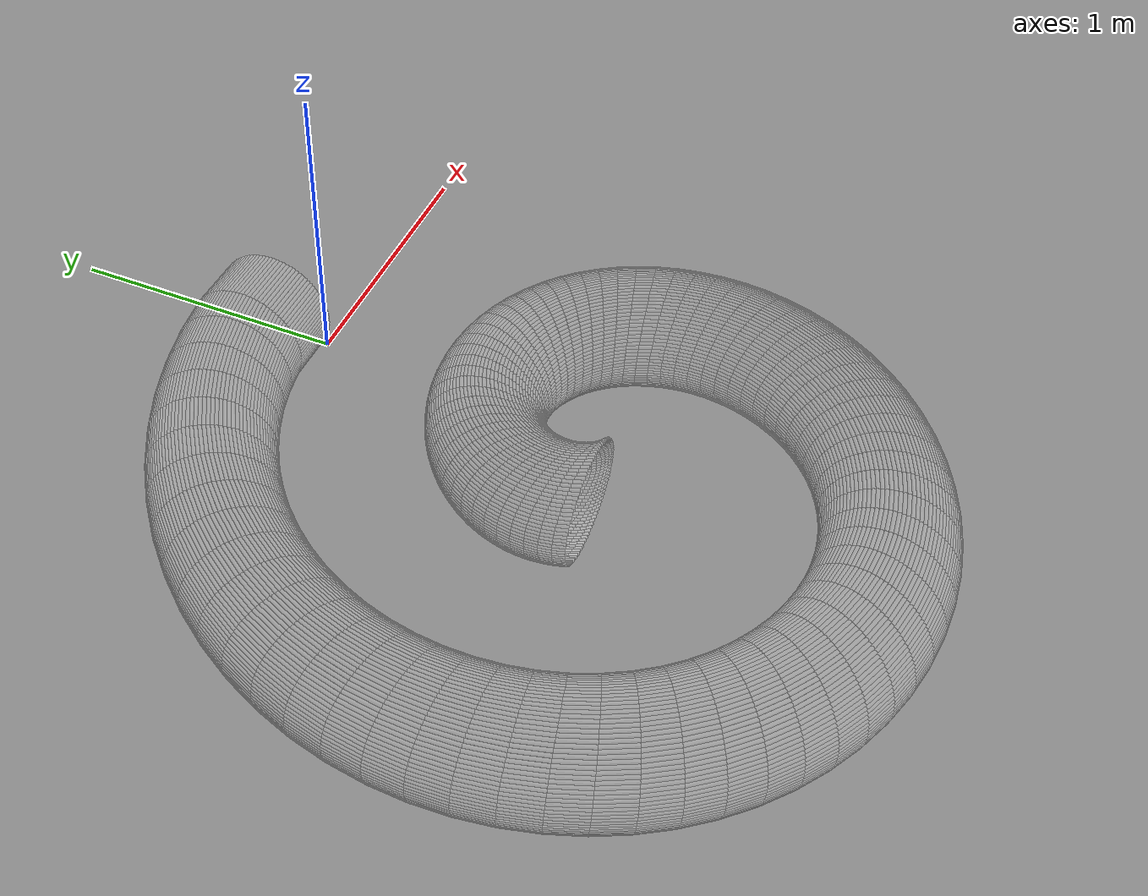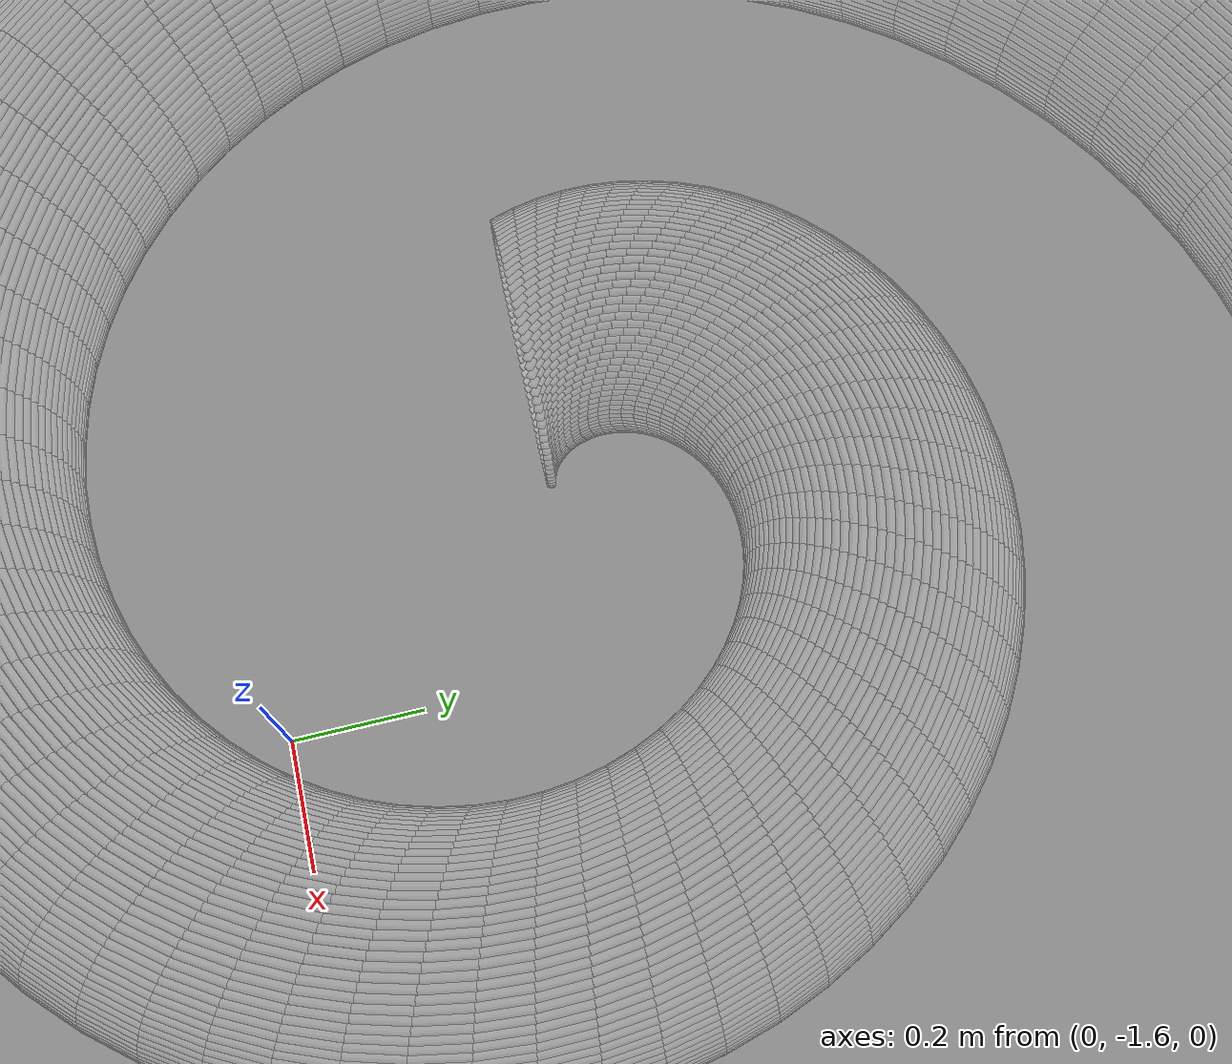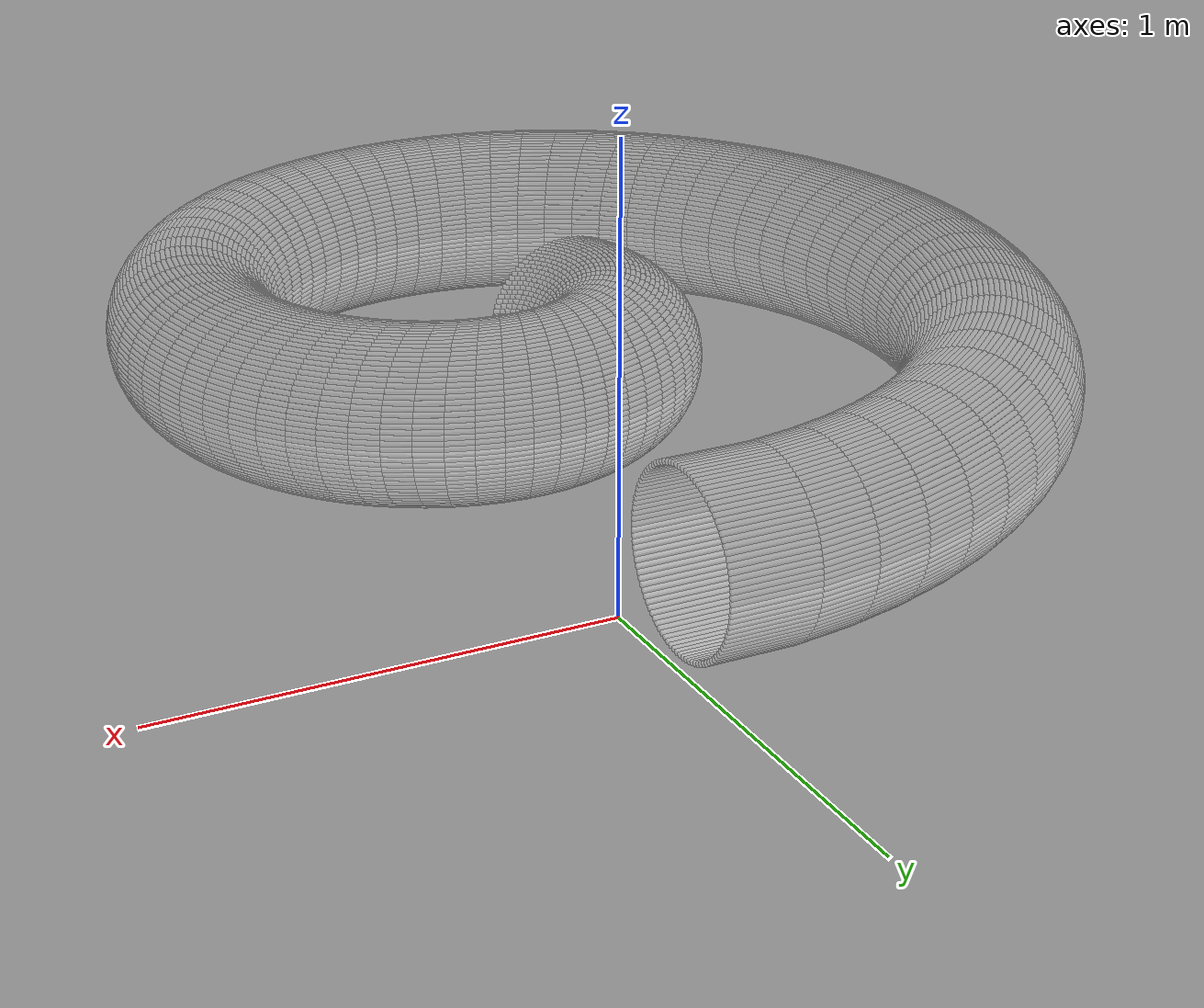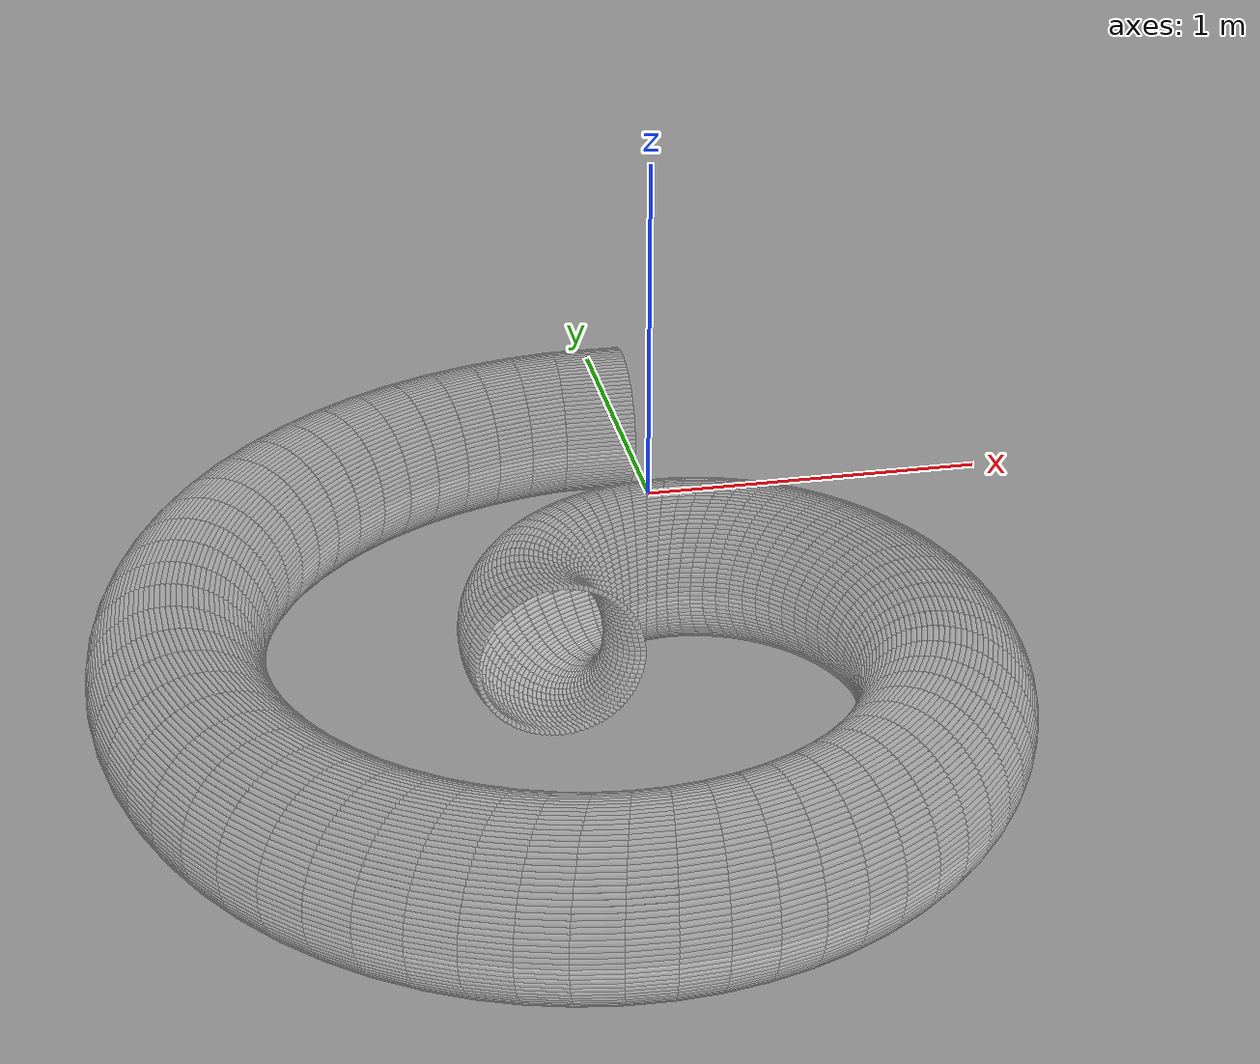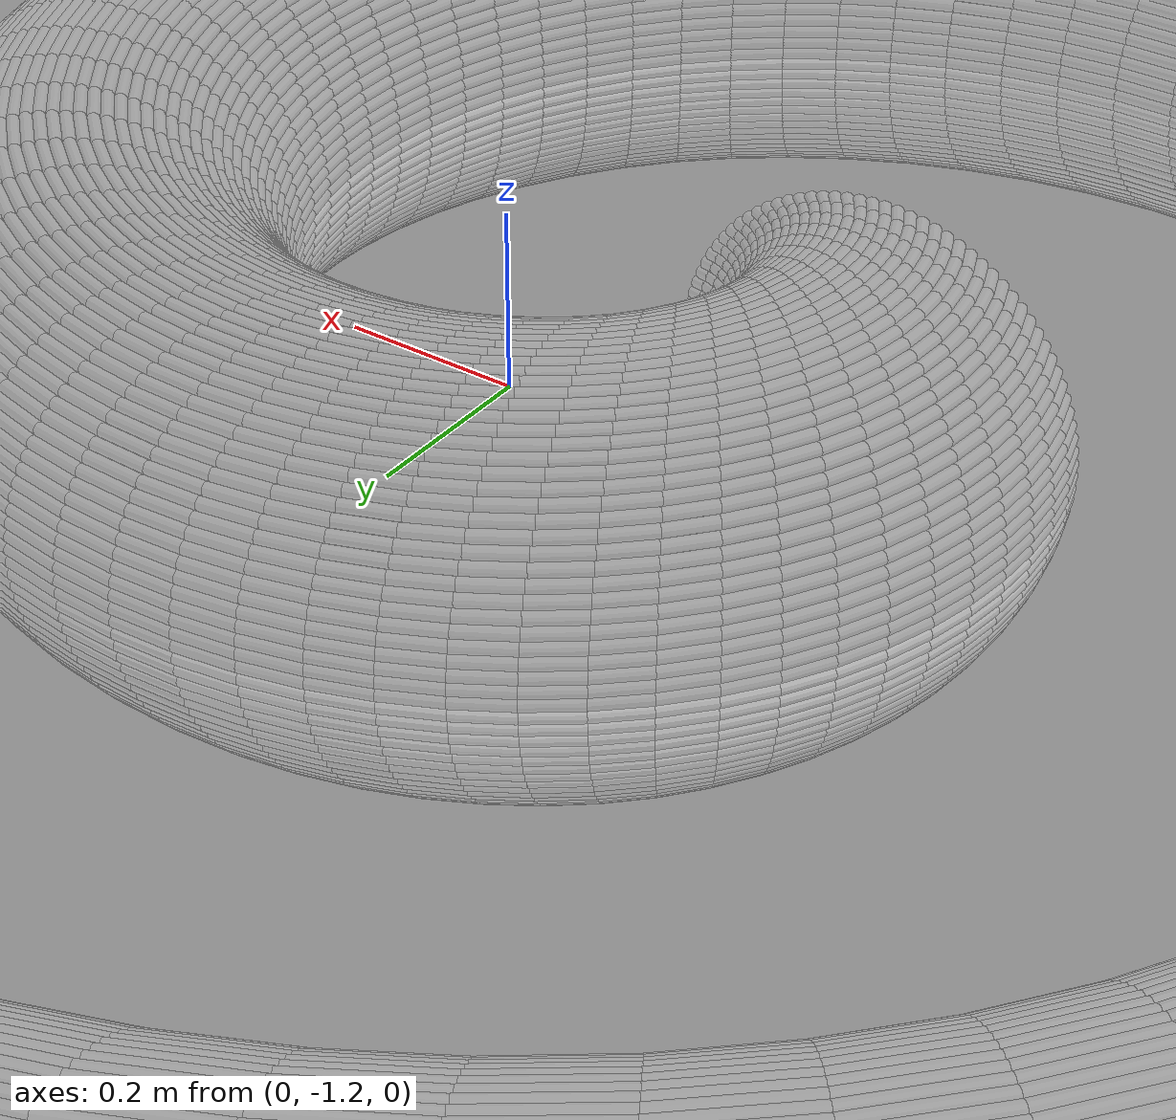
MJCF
<?xml version="1.0" encoding="utf-8"?>
<mujoco>
   <worldbody>
   <body pos="-0.25 -1.14 -0.02" euler="0 0 90">
      <geom euler=" 0 10 0 " fromto="1.5 -0.2 0.2 1.5 0 0.2" rgba="1 1 1 0.05"
            size="0.0062822"
            type="cylinder"/>
      <geom euler=" 0 20 0 " fromto="1.4996 -0.2 0.21256 1.4996 0 0.21256"
            rgba="1 1 1 0.05"
            size="0.0062822"
            type="cylinder"/>
      <geom euler=" 0 30 0 " fromto="1.4984 -0.2 0.22507 1.4984 0 0.22507"
            rgba="1 1 1 0.05"
            size="0.0062822"
            type="cylinder"/>
      <geom euler=" 0 40 0 " fromto="1.4965 -0.2 0.23748 1.4965 0 0.23748"
            rgba="1 1 1 0.05"
            size="0.0062822"
            type="cylinder"/>
      <geom euler=" 0 50 0 " fromto="1.4937 -0.2 0.24974 1.4937 0 0.24974"
            rgba="1 1 1 0.05"
            size="0.0062822"
            type="cylinder"/>
      <geom euler=" 0 60 0 " fromto="1.4902 -0.2 0.2618 1.4902 0 0.2618" rgba="1 1 1 0.05"
            size="0.0062822"
            type="cylinder"/>
      <geom euler=" 0 70 0 " fromto="1.486 -0.2 0.27362 1.486 0 0.27362" rgba="1 1 1 0.05"
            size="0.0062822"
            type="cylinder"/>
      <geom euler=" 0 80 0 " fromto="1.481 -0.2 0.28516 1.481 0 0.28516" rgba="1 1 1 0.05"
            size="0.0062822"
            type="cylinder"/>
      <geom euler=" 0 90 0 " fromto="1.4753 -0.2 0.29635 1.4753 0 0.29635"
            rgba="1 1 1 0.05"
            size="0.0062822"
            type="cylinder"/>
      <geom euler=" 0 100 0 " fromto="1.4689 -0.2 0.30717 1.4689 0 0.30717"
            rgba="1 1 1 0.05"
            size="0.0062822"
            type="cylinder"/>
      <geom euler=" 0 110 0 " fromto="1.4618 -0.2 0.31756 1.4618 0 0.31756"
            rgba="1 1 1 0.05"
            size="0.0062822"
            type="cylinder"/>
      <geom euler=" 0 120 0 " fromto="1.4541 -0.2 0.32748 1.4541 0 0.32748"
            rgba="1 1 1 0.05"
            size="0.0062822"
            type="cylinder"/>
      <geom euler=" 0 130 0 " fromto="1.4458 -0.2 0.33691 1.4458 0 0.33691"
            rgba="1 1 1 0.05"
            size="0.0062822"
            type="cylinder"/>
      <geom euler=" 0 140 0 " fromto="1.4369 -0.2 0.34579 1.4369 0 0.34579"
            rgba="1 1 1 0.05"
            size="0.0062822"
            type="cylinder"/>
      <geom euler=" 0 150 0 " fromto="1.4275 -0.2 0.3541 1.4275 0 0.3541" rgba="1 1 1 0.05"
            size="0.0062822"
            type="cylinder"/>
      <geom euler=" 0 160 0 " fromto="1.4176 -0.2 0.3618 1.4176 0 0.3618" rgba="1 1 1 0.05"
            size="0.0062822"
            type="cylinder"/>
      <geom euler=" 0 170 0 " fromto="1.4072 -0.2 0.36887 1.4072 0 0.36887"
            rgba="1 1 1 0.05"
            size="0.0062822"
            type="cylinder"/>
      <geom euler=" 0 180 0 " fromto="1.3964 -0.2 0.37526 1.3964 0 0.37526"
            rgba="1 1 1 0.05"
            size="0.0062822"
            type="cylinder"/>
      <geom euler=" 0 190 0 " fromto="1.3852 -0.2 0.38097 1.3852 0 0.38097"
            rgba="1 1 1 0.05"
            size="0.0062822"
            type="cylinder"/>
      <geom euler=" 0 200 0 " fromto="1.3736 -0.2 0.38596 1.3736 0 0.38596"
            rgba="1 1 1 0.05"
            size="0.0062822"
            type="cylinder"/>
      <geom euler=" 0 210 0 " fromto="1.3618 -0.2 0.39021 1.3618 0 0.39021"
            rgba="1 1 1 0.05"
            size="0.0062822"
            type="cylinder"/>
      <geom euler=" 0 220 0 " fromto="1.3497 -0.2 0.39372 1.3497 0 0.39372"
            rgba="1 1 1 0.05"
            size="0.0062822"
            type="cylinder"/>
      <geom euler=" 0 230 0 " fromto="1.3375 -0.2 0.39646 1.3375 0 0.39646"
            rgba="1 1 1 0.05"
            size="0.0062822"
            type="cylinder"/>
      <geom euler=" 0 240 0 " fromto="1.3251 -0.2 0.39842 1.3251 0 0.39842"
            rgba="1 1 1 0.05"
            size="0.0062822"
            type="cylinder"/>
      <geom euler=" 0 250 0 " fromto="1.3126 -0.2 0.39961 1.3126 0 0.39961"
            rgba="1 1 1 0.05"
            size="0.0062822"
            type="cylinder"/>
      <geom euler=" 0 260 0 " fromto="1.3 -0.2 0.4 1.3 0 0.4" rgba="1 1 1 0.05"
            size="0.0062822"
            type="cylinder"/>
      <geom euler=" 0 270 0 " fromto="1.2874 -0.2 0.39961 1.2874 0 0.39961"
            rgba="1 1 1 0.05"
            size="0.0062822"
            type="cylinder"/>
      <geom euler=" 0 280 0 " fromto="1.2749 -0.2 0.39842 1.2749 0 0.39842"
            rgba="1 1 1 0.05"
            size="0.0062822"
            type="cylinder"/>
      <geom euler=" 0 290 0 " fromto="1.2625 -0.2 0.39646 1.2625 0 0.39646"
            rgba="1 1 1 0.05"
            size="0.0062822"
            type="cylinder"/>
      <geom euler=" 0 300 0 " fromto="1.2503 -0.2 0.39372 1.2503 0 0.39372"
            rgba="1 1 1 0.05"
            size="0.0062822"
            type="cylinder"/>
      <geom euler=" 0 310 0 " fromto="1.2382 -0.2 0.39021 1.2382 0 0.39021"
            rgba="1 1 1 0.05"
            size="0.0062822"
            type="cylinder"/>
      <geom euler=" 0 320 0 " fromto="1.2264 -0.2 0.38596 1.2264 0 0.38596"
            rgba="1 1 1 0.05"
            size="0.0062822"
            type="cylinder"/>
      <geom euler=" 0 330 0 " fromto="1.2148 -0.2 0.38097 1.2148 0 0.38097"
            rgba="1 1 1 0.05"
            size="0.0062822"
            type="cylinder"/>
      <geom euler=" 0 340 0 " fromto="1.2036 -0.2 0.37526 1.2036 0 0.37526"
            rgba="1 1 1 0.05"
            size="0.0062822"
            type="cylinder"/>
      <geom euler=" 0 350 0 " fromto="1.1928 -0.2 0.36887 1.1928 0 0.36887"
            rgba="1 1 1 0.05"
            size="0.0062822"
            type="cylinder"/>
      <geom euler=" 0 360 0 " fromto="1.1824 -0.2 0.3618 1.1824 0 0.3618" rgba="1 1 1 0.05"
            size="0.0062822"
            type="cylinder"/>
      <geom euler=" 0 370 0 " fromto="1.1725 -0.2 0.3541 1.1725 0 0.3541" rgba="1 1 1 0.05"
            size="0.0062822"
            type="cylinder"/>
      <geom euler=" 0 380 0 " fromto="1.1631 -0.2 0.34579 1.1631 0 0.34579"
            rgba="1 1 1 0.05"
            size="0.0062822"
            type="cylinder"/>
      <geom euler=" 0 390 0 " fromto="1.1542 -0.2 0.33691 1.1542 0 0.33691"
            rgba="1 1 1 0.05"
            size="0.0062822"
            type="cylinder"/>
      <geom euler=" 0 400 0 " fromto="1.1459 -0.2 0.32748 1.1459 0 0.32748"
            rgba="1 1 1 0.05"
            size="0.0062822"
            type="cylinder"/>
      <geom euler=" 0 410 0 " fromto="1.1382 -0.2 0.31756 1.1382 0 0.31756"
            rgba="1 1 1 0.05"
            size="0.0062822"
            type="cylinder"/>
      <geom euler=" 0 420 0 " fromto="1.1311 -0.2 0.30717 1.1311 0 0.30717"
            rgba="1 1 1 0.05"
            size="0.0062822"
            type="cylinder"/>
      <geom euler=" 0 430 0 " fromto="1.1247 -0.2 0.29635 1.1247 0 0.29635"
            rgba="1 1 1 0.05"
            size="0.0062822"
            type="cylinder"/>
      <geom euler=" 0 440 0 " fromto="1.119 -0.2 0.28516 1.119 0 0.28516" rgba="1 1 1 0.05"
            size="0.0062822"
            type="cylinder"/>
      <geom euler=" 0 450 0 " fromto="1.114 -0.2 0.27362 1.114 0 0.27362" rgba="1 1 1 0.05"
            size="0.0062822"
            type="cylinder"/>
      <geom euler=" 0 460 0 " fromto="1.1098 -0.2 0.2618 1.1098 0 0.2618" rgba="1 1 1 0.05"
            size="0.0062822"
            type="cylinder"/>
      <geom euler=" 0 470 0 " fromto="1.1063 -0.2 0.24974 1.1063 0 0.24974"
            rgba="1 1 1 0.05"
            size="0.0062822"
            type="cylinder"/>
      <geom euler=" 0 480 0 " fromto="1.1035 -0.2 0.23748 1.1035 0 0.23748"
            rgba="1 1 1 0.05"
            size="0.0062822"
            type="cylinder"/>
      <geom euler=" 0 490 0 " fromto="1.1016 -0.2 0.22507 1.1016 0 0.22507"
            rgba="1 1 1 0.05"
            size="0.0062822"
            type="cylinder"/>
      <geom euler=" 0 500 0 " fromto="1.1004 -0.2 0.21256 1.1004 0 0.21256"
            rgba="1 1 1 0.05"
            size="0.0062822"
            type="cylinder"/>
      <geom euler=" 0 510 0 " fromto="1.1 -0.2 0.2 1.1 0 0.2" rgba="1 1 1 0.05"
            size="0.0062822"
            type="cylinder"/>
      <geom euler=" 0 520 0 " fromto="1.1004 -0.2 0.18744 1.1004 0 0.18744"
            rgba="1 1 1 0.35"
            size="0.0062822"
            type="cylinder"/>
      <geom euler=" 0 530 0 " fromto="1.1016 -0.2 0.17493 1.1016 0 0.17493"
            rgba="1 1 1 0.35"
            size="0.0062822"
            type="cylinder"/>
      <geom euler=" 0 540 0 " fromto="1.1035 -0.2 0.16252 1.1035 0 0.16252"
            rgba="1 1 1 0.35"
            size="0.0062822"
            type="cylinder"/>
      <geom euler=" 0 550 0 " fromto="1.1063 -0.2 0.15026 1.1063 0 0.15026"
            rgba="1 1 1 0.35"
            size="0.0062822"
            type="cylinder"/>
      <geom euler=" 0 560 0 " fromto="1.1098 -0.2 0.1382 1.1098 0 0.1382" rgba="1 1 1 0.35"
            size="0.0062822"
            type="cylinder"/>
      <geom euler=" 0 570 0 " fromto="1.114 -0.2 0.12638 1.114 0 0.12638" rgba="1 1 1 0.35"
            size="0.0062822"
            type="cylinder"/>
      <geom euler=" 0 580 0 " fromto="1.119 -0.2 0.11484 1.119 0 0.11484" rgba="1 1 1 0.35"
            size="0.0062822"
            type="cylinder"/>
      <geom euler=" 0 590 0 " fromto="1.1247 -0.2 0.10365 1.1247 0 0.10365"
            rgba="1 1 1 0.35"
            size="0.0062822"
            type="cylinder"/>
      <geom euler=" 0 600 0 " fromto="1.1311 -0.2 0.092835 1.1311 0 0.092835"
            rgba="1 1 1 0.35"
            size="0.0062822"
            type="cylinder"/>
      <geom euler=" 0 610 0 " fromto="1.1382 -0.2 0.082443 1.1382 0 0.082443"
            rgba="1 1 1 0.35"
            size="0.0062822"
            type="cylinder"/>
      <geom euler=" 0 620 0 " fromto="1.1459 -0.2 0.072515 1.1459 0 0.072515"
            rgba="1 1 1 0.35"
            size="0.0062822"
            type="cylinder"/>
      <geom euler=" 0 630 0 " fromto="1.1542 -0.2 0.063091 1.1542 0 0.063091"
            rgba="1 1 1 0.35"
            size="0.0062822"
            type="cylinder"/>
      <geom euler=" 0 640 0 " fromto="1.1631 -0.2 0.054206 1.1631 0 0.054206"
            rgba="1 1 1 0.35"
            size="0.0062822"
            type="cylinder"/>
      <geom euler=" 0 650 0 " fromto="1.1725 -0.2 0.045897 1.1725 0 0.045897"
            rgba="1 1 1 0.35"
            size="0.0062822"
            type="cylinder"/>
      <geom euler=" 0 660 0 " fromto="1.1824 -0.2 0.038197 1.1824 0 0.038197"
            rgba="1 1 1 0.35"
            size="0.0062822"
            type="cylinder"/>
      <geom euler=" 0 670 0 " fromto="1.1928 -0.2 0.031134 1.1928 0 0.031134"
            rgba="1 1 1 0.35"
            size="0.0062822"
            type="cylinder"/>
      <geom euler=" 0 680 0 " fromto="1.2036 -0.2 0.024739 1.2036 0 0.024739"
            rgba="1 1 1 0.35"
            size="0.0062822"
            type="cylinder"/>
      <geom euler=" 0 690 0 " fromto="1.2148 -0.2 0.019035 1.2148 0 0.019035"
            rgba="1 1 1 0.35"
            size="0.0062822"
            type="cylinder"/>
      <geom euler=" 0 700 0 " fromto="1.2264 -0.2 0.014045 1.2264 0 0.014045"
            rgba="1 1 1 0.35"
            size="0.0062822"
            type="cylinder"/>
      <geom euler=" 0 710 0 " fromto="1.2382 -0.2 0.0097887 1.2382 0 0.0097887"
            rgba="1 1 1 0.35"
            size="0.0062822"
            type="cylinder"/>
      <geom euler=" 0 720 0 " fromto="1.2503 -0.2 0.0062834 1.2503 0 0.0062834"
            rgba="1 1 1 0.35"
            size="0.0062822"
            type="cylinder"/>
      <geom euler=" 0 730 0 " fromto="1.2625 -0.2 0.0035425 1.2625 0 0.0035425"
            rgba="1 1 1 0.35"
            size="0.0062822"
            type="cylinder"/>
      <geom euler=" 0 740 0 " fromto="1.2749 -0.2 0.0015771 1.2749 0 0.0015771"
            rgba="1 1 1 0.35"
            size="0.0062822"
            type="cylinder"/>
      <geom euler=" 0 750 0 " fromto="1.2874 -0.2 0.00039465 1.2874 0 0.00039465"
            rgba="1 1 1 0.35"
            size="0.0062822"
            type="cylinder"/>
      <geom euler=" 0 760 0 " fromto="1.3 -0.2 0 1.3 0 0" rgba="1 1 1 0.35"
            size="0.0062822"
            type="cylinder"/>
      <geom euler=" 0 770 0 " fromto="1.3126 -0.2 0.00039465 1.3126 0 0.00039465"
            rgba="1 1 1 0.35"
            size="0.0062822"
            type="cylinder"/>
      <geom euler=" 0 780 0 " fromto="1.3251 -0.2 0.0015771 1.3251 0 0.0015771"
            rgba="1 1 1 0.35"
            size="0.0062822"
            type="cylinder"/>
      <geom euler=" 0 790 0 " fromto="1.3375 -0.2 0.0035425 1.3375 0 0.0035425"
            rgba="1 1 1 0.35"
            size="0.0062822"
            type="cylinder"/>
      <geom euler=" 0 800 0 " fromto="1.3497 -0.2 0.0062834 1.3497 0 0.0062834"
            rgba="1 1 1 0.35"
            size="0.0062822"
            type="cylinder"/>
      <geom euler=" 0 810 0 " fromto="1.3618 -0.2 0.0097887 1.3618 0 0.0097887"
            rgba="1 1 1 0.35"
            size="0.0062822"
            type="cylinder"/>
      <geom euler=" 0 820 0 " fromto="1.3736 -0.2 0.014045 1.3736 0 0.014045"
            rgba="1 1 1 0.35"
            size="0.0062822"
            type="cylinder"/>
      <geom euler=" 0 830 0 " fromto="1.3852 -0.2 0.019035 1.3852 0 0.019035"
            rgba="1 1 1 0.35"
            size="0.0062822"
            type="cylinder"/>
      <geom euler=" 0 840 0 " fromto="1.3964 -0.2 0.024739 1.3964 0 0.024739"
            rgba="1 1 1 0.35"
            size="0.0062822"
            type="cylinder"/>
      <geom euler=" 0 850 0 " fromto="1.4072 -0.2 0.031134 1.4072 0 0.031134"
            rgba="1 1 1 0.35"
            size="0.0062822"
            type="cylinder"/>
      <geom euler=" 0 860 0 " fromto="1.4176 -0.2 0.038197 1.4176 0 0.038197"
            rgba="1 1 1 0.35"
            size="0.0062822"
            type="cylinder"/>
      <geom euler=" 0 870 0 " fromto="1.4275 -0.2 0.045897 1.4275 0 0.045897"
            rgba="1 1 1 0.35"
            size="0.0062822"
            type="cylinder"/>
      <geom euler=" 0 880 0 " fromto="1.4369 -0.2 0.054206 1.4369 0 0.054206"
            rgba="1 1 1 0.35"
            size="0.0062822"
            type="cylinder"/>
      <geom euler=" 0 890 0 " fromto="1.4458 -0.2 0.063091 1.4458 0 0.063091"
            rgba="1 1 1 0.35"
            size="0.0062822"
            type="cylinder"/>
      <geom euler=" 0 900 0 " fromto="1.4541 -0.2 0.072515 1.4541 0 0.072515"
            rgba="1 1 1 0.35"
            size="0.0062822"
            type="cylinder"/>
      <geom euler=" 0 910 0 " fromto="1.4618 -0.2 0.082443 1.4618 0 0.082443"
            rgba="1 1 1 0.35"
            size="0.0062822"
            type="cylinder"/>
      <geom euler=" 0 920 0 " fromto="1.4689 -0.2 0.092835 1.4689 0 0.092835"
            rgba="1 1 1 0.35"
            size="0.0062822"
            type="cylinder"/>
      <geom euler=" 0 930 0 " fromto="1.4753 -0.2 0.10365 1.4753 0 0.10365"
            rgba="1 1 1 0.35"
            size="0.0062822"
            type="cylinder"/>
      <geom euler=" 0 940 0 " fromto="1.481 -0.2 0.11484 1.481 0 0.11484" rgba="1 1 1 0.35"
            size="0.0062822"
            type="cylinder"/>
      <geom euler=" 0 950 0 " fromto="1.486 -0.2 0.12638 1.486 0 0.12638" rgba="1 1 1 0.35"
            size="0.0062822"
            type="cylinder"/>
      <geom euler=" 0 960 0 " fromto="1.4902 -0.2 0.1382 1.4902 0 0.1382" rgba="1 1 1 0.35"
            size="0.0062822"
            type="cylinder"/>
      <geom euler=" 0 970 0 " fromto="1.4937 -0.2 0.15026 1.4937 0 0.15026"
            rgba="1 1 1 0.35"
            size="0.0062822"
            type="cylinder"/>
      <geom euler=" 0 980 0 " fromto="1.4965 -0.2 0.16252 1.4965 0 0.16252"
            rgba="1 1 1 0.35"
            size="0.0062822"
            type="cylinder"/>
      <geom euler=" 0 990 0 " fromto="1.4984 -0.2 0.17493 1.4984 0 0.17493"
            rgba="1 1 1 0.35"
            size="0.0062822"
            type="cylinder"/>
      <geom euler=" 0 1000 0 " fromto="1.4996 -0.2 0.18744 1.4996 0 0.18744"
            rgba="1 1 1 0.35"
            size="0.0062822"
            type="cylinder"/>
      <geom euler=" 0 10 0 " fromto="1.5 0 0.2 1.4804 0.13882 0.2" rgba="1 1 1 0.05"
            size="0.0062822"
            type="cylinder"/>
      <geom euler=" 0 20 0 " fromto="1.4996 0 0.21256 1.48 0.13879 0.21256"
            rgba="1 1 1 0.05"
            size="0.0062822"
            type="cylinder"/>
      <geom euler=" 0 30 0 " fromto="1.4984 0 0.22507 1.4788 0.13868 0.22507"
            rgba="1 1 1 0.05"
            size="0.0062822"
            type="cylinder"/>
      <geom euler=" 0 40 0 " fromto="1.4965 0 0.23748 1.4769 0.13849 0.23748"
            rgba="1 1 1 0.05"
            size="0.0062822"
            type="cylinder"/>
      <geom euler=" 0 50 0 " fromto="1.4937 0 0.24974 1.4742 0.13824 0.24974"
            rgba="1 1 1 0.05"
            size="0.0062822"
            type="cylinder"/>
      <geom euler=" 0 60 0 " fromto="1.4902 0 0.2618 1.4707 0.13791 0.2618"
            rgba="1 1 1 0.05"
            size="0.0062822"
            type="cylinder"/>
      <geom euler=" 0 70 0 " fromto="1.486 0 0.27362 1.4664 0.13751 0.27362"
            rgba="1 1 1 0.05"
            size="0.0062822"
            type="cylinder"/>
      <geom euler=" 0 80 0 " fromto="1.481 0 0.28516 1.4615 0.13705 0.28516"
            rgba="1 1 1 0.05"
            size="0.0062822"
            type="cylinder"/>
      <geom euler=" 0 90 0 " fromto="1.4753 0 0.29635 1.4558 0.13651 0.29635"
            rgba="1 1 1 0.05"
            size="0.0062822"
            type="cylinder"/>
      <geom euler=" 0 100 0 " fromto="1.4689 0 0.30717 1.4494 0.13592 0.30717"
            rgba="1 1 1 0.05"
            size="0.0062822"
            type="cylinder"/>
      <geom euler=" 0 110 0 " fromto="1.4618 0 0.31756 1.4424 0.13526 0.31756"
            rgba="1 1 1 0.05"
            size="0.0062822"
            type="cylinder"/>
      <geom euler=" 0 120 0 " fromto="1.4541 0 0.32748 1.4347 0.13454 0.32748"
            rgba="1 1 1 0.05"
            size="0.0062822"
            type="cylinder"/>
      <geom euler=" 0 130 0 " fromto="1.4458 0 0.33691 1.4264 0.13376 0.33691"
            rgba="1 1 1 0.05"
            size="0.0062822"
            type="cylinder"/>
      <geom euler=" 0 140 0 " fromto="1.4369 0 0.34579 1.4176 0.13293 0.34579"
            rgba="1 1 1 0.05"
            size="0.0062822"
            type="cylinder"/>
      <geom euler=" 0 150 0 " fromto="1.4275 0 0.3541 1.4082 0.13205 0.3541"
            rgba="1 1 1 0.05"
            size="0.0062822"
            type="cylinder"/>
      <geom euler=" 0 160 0 " fromto="1.4176 0 0.3618 1.3983 0.13113 0.3618"
            rgba="1 1 1 0.05"
            size="0.0062822"
            type="cylinder"/>
      <geom euler=" 0 170 0 " fromto="1.4072 0 0.36887 1.388 0.13016 0.36887"
            rgba="1 1 1 0.05"
            size="0.0062822"
            type="cylinder"/>
      <geom euler=" 0 180 0 " fromto="1.3964 0 0.37526 1.3772 0.12915 0.37526"
            rgba="1 1 1 0.05"
            size="0.0062822"
            type="cylinder"/>
      <geom euler=" 0 190 0 " fromto="1.3852 0 0.38097 1.3661 0.1281 0.38097"
            rgba="1 1 1 0.05"
            size="0.0062822"
            type="cylinder"/>
      <geom euler=" 0 200 0 " fromto="1.3736 0 0.38596 1.3546 0.12702 0.38596"
            rgba="1 1 1 0.05"
            size="0.0062822"
            type="cylinder"/>
      <geom euler=" 0 210 0 " fromto="1.3618 0 0.39021 1.3428 0.12592 0.39021"
            rgba="1 1 1 0.05"
            size="0.0062822"
            type="cylinder"/>
      <geom euler=" 0 220 0 " fromto="1.3497 0 0.39372 1.3308 0.12479 0.39372"
            rgba="1 1 1 0.05"
            size="0.0062822"
            type="cylinder"/>
      <geom euler=" 0 230 0 " fromto="1.3375 0 0.39646 1.3186 0.12365 0.39646"
            rgba="1 1 1 0.05"
            size="0.0062822"
            type="cylinder"/>
      <geom euler=" 0 240 0 " fromto="1.3251 0 0.39842 1.3062 0.12249 0.39842"
            rgba="1 1 1 0.05"
            size="0.0062822"
            type="cylinder"/>
      <geom euler=" 0 250 0 " fromto="1.3126 0 0.39961 1.2938 0.12132 0.39961"
            rgba="1 1 1 0.05"
            size="0.0062822"
            type="cylinder"/>
      <geom euler=" 0 260 0 " fromto="1.3 0 0.4 1.2813 0.12015 0.4" rgba="1 1 1 0.05"
            size="0.0062822"
            type="cylinder"/>
      <geom euler=" 0 270 0 " fromto="1.2874 0 0.39961 1.2688 0.11898 0.39961"
            rgba="1 1 1 0.05"
            size="0.0062822"
            type="cylinder"/>
      <geom euler=" 0 280 0 " fromto="1.2749 0 0.39842 1.2563 0.11781 0.39842"
            rgba="1 1 1 0.05"
            size="0.0062822"
            type="cylinder"/>
      <geom euler=" 0 290 0 " fromto="1.2625 0 0.39646 1.244 0.11665 0.39646"
            rgba="1 1 1 0.05"
            size="0.0062822"
            type="cylinder"/>
      <geom euler=" 0 300 0 " fromto="1.2503 0 0.39372 1.2318 0.11551 0.39372"
            rgba="1 1 1 0.05"
            size="0.0062822"
            type="cylinder"/>
      <geom euler=" 0 310 0 " fromto="1.2382 0 0.39021 1.2198 0.11438 0.39021"
            rgba="1 1 1 0.05"
            size="0.0062822"
            type="cylinder"/>
      <geom euler=" 0 320 0 " fromto="1.2264 0 0.38596 1.208 0.11328 0.38596"
            rgba="1 1 1 0.05"
            size="0.0062822"
            type="cylinder"/>
      <geom euler=" 0 330 0 " fromto="1.2148 0 0.38097 1.1965 0.1122 0.38097"
            rgba="1 1 1 0.05"
            size="0.0062822"
            type="cylinder"/>
      <geom euler=" 0 340 0 " fromto="1.2036 0 0.37526 1.1854 0.11115 0.37526"
            rgba="1 1 1 0.05"
            size="0.0062822"
            type="cylinder"/>
      <geom euler=" 0 350 0 " fromto="1.1928 0 0.36887 1.1746 0.11014 0.36887"
            rgba="1 1 1 0.05"
            size="0.0062822"
            type="cylinder"/>
      <geom euler=" 0 360 0 " fromto="1.1824 0 0.3618 1.1642 0.10917 0.3618"
            rgba="1 1 1 0.05"
            size="0.0062822"
            type="cylinder"/>
      <geom euler=" 0 370 0 " fromto="1.1725 0 0.3541 1.1544 0.10825 0.3541"
            rgba="1 1 1 0.05"
            size="0.0062822"
            type="cylinder"/>
      <geom euler=" 0 380 0 " fromto="1.1631 0 0.34579 1.145 0.10737 0.34579"
            rgba="1 1 1 0.05"
            size="0.0062822"
            type="cylinder"/>
      <geom euler=" 0 390 0 " fromto="1.1542 0 0.33691 1.1361 0.10654 0.33691"
            rgba="1 1 1 0.05"
            size="0.0062822"
            type="cylinder"/>
      <geom euler=" 0 400 0 " fromto="1.1459 0 0.32748 1.1279 0.10576 0.32748"
            rgba="1 1 1 0.05"
            size="0.0062822"
            type="cylinder"/>
      <geom euler=" 0 410 0 " fromto="1.1382 0 0.31756 1.1202 0.10504 0.31756"
            rgba="1 1 1 0.05"
            size="0.0062822"
            type="cylinder"/>
      <geom euler=" 0 420 0 " fromto="1.1311 0 0.30717 1.1132 0.10438 0.30717"
            rgba="1 1 1 0.05"
            size="0.0062822"
            type="cylinder"/>
      <geom euler=" 0 430 0 " fromto="1.1247 0 0.29635 1.1068 0.10379 0.29635"
            rgba="1 1 1 0.05"
            size="0.0062822"
            type="cylinder"/>
      <geom euler=" 0 440 0 " fromto="1.119 0 0.28516 1.1011 0.10325 0.28516"
            rgba="1 1 1 0.05"
            size="0.0062822"
            type="cylinder"/>
      <geom euler=" 0 450 0 " fromto="1.114 0 0.27362 1.0961 0.10279 0.27362"
            rgba="1 1 1 0.05"
            size="0.0062822"
            type="cylinder"/>
      <geom euler=" 0 460 0 " fromto="1.1098 0 0.2618 1.0919 0.10239 0.2618"
            rgba="1 1 1 0.05"
            size="0.0062822"
            type="cylinder"/>
      <geom euler=" 0 470 0 " fromto="1.1063 0 0.24974 1.0884 0.10206 0.24974"
            rgba="1 1 1 0.05"
            size="0.0062822"
            type="cylinder"/>
      <geom euler=" 0 480 0 " fromto="1.1035 0 0.23748 1.0857 0.10181 0.23748"
            rgba="1 1 1 0.05"
            size="0.0062822"
            type="cylinder"/>
      <geom euler=" 0 490 0 " fromto="1.1016 0 0.22507 1.0837 0.10162 0.22507"
            rgba="1 1 1 0.05"
            size="0.0062822"
            type="cylinder"/>
      <geom euler=" 0 500 0 " fromto="1.1004 0 0.21256 1.0826 0.10151 0.21256"
            rgba="1 1 1 0.05"
            size="0.0062822"
            type="cylinder"/>
      <geom euler=" 0 510 0 " fromto="1.1 0 0.2 1.0822 0.10148 0.2" rgba="1 1 1 0.05"
            size="0.0062822"
            type="cylinder"/>
      <geom euler=" 0 520 0 " fromto="1.1004 0 0.18744 1.0826 0.10151 0.18744"
            rgba="1 1 1 0.35"
            size="0.0062822"
            type="cylinder"/>
      <geom euler=" 0 530 0 " fromto="1.1016 0 0.17493 1.0837 0.10162 0.17493"
            rgba="1 1 1 0.35"
            size="0.0062822"
            type="cylinder"/>
      <geom euler=" 0 540 0 " fromto="1.1035 0 0.16252 1.0857 0.10181 0.16252"
            rgba="1 1 1 0.35"
            size="0.0062822"
            type="cylinder"/>
      <geom euler=" 0 550 0 " fromto="1.1063 0 0.15026 1.0884 0.10206 0.15026"
            rgba="1 1 1 0.35"
            size="0.0062822"
            type="cylinder"/>
      <geom euler=" 0 560 0 " fromto="1.1098 0 0.1382 1.0919 0.10239 0.1382"
            rgba="1 1 1 0.35"
            size="0.0062822"
            type="cylinder"/>
      <geom euler=" 0 570 0 " fromto="1.114 0 0.12638 1.0961 0.10279 0.12638"
            rgba="1 1 1 0.35"
            size="0.0062822"
            type="cylinder"/>
      <geom euler=" 0 580 0 " fromto="1.119 0 0.11484 1.1011 0.10325 0.11484"
            rgba="1 1 1 0.35"
            size="0.0062822"
            type="cylinder"/>
      <geom euler=" 0 590 0 " fromto="1.1247 0 0.10365 1.1068 0.10379 0.10365"
            rgba="1 1 1 0.35"
            size="0.0062822"
            type="cylinder"/>
      <geom euler=" 0 600 0 " fromto="1.1311 0 0.092835 1.1132 0.10438 0.092835"
            rgba="1 1 1 0.35"
            size="0.0062822"
            type="cylinder"/>
      <geom euler=" 0 610 0 " fromto="1.1382 0 0.082443 1.1202 0.10504 0.082443"
            rgba="1 1 1 0.35"
            size="0.0062822"
            type="cylinder"/>
      <geom euler=" 0 620 0 " fromto="1.1459 0 0.072515 1.1279 0.10576 0.072515"
            rgba="1 1 1 0.35"
            size="0.0062822"
            type="cylinder"/>
      <geom euler=" 0 630 0 " fromto="1.1542 0 0.063091 1.1361 0.10654 0.063091"
            rgba="1 1 1 0.35"
            size="0.0062822"
            type="cylinder"/>
      <geom euler=" 0 640 0 " fromto="1.1631 0 0.054206 1.145 0.10737 0.054206"
            rgba="1 1 1 0.35"
            size="0.0062822"
            type="cylinder"/>
      <geom euler=" 0 650 0 " fromto="1.1725 0 0.045897 1.1544 0.10825 0.045897"
            rgba="1 1 1 0.35"
            size="0.0062822"
            type="cylinder"/>
      <geom euler=" 0 660 0 " fromto="1.1824 0 0.038197 1.1642 0.10917 0.038197"
            rgba="1 1 1 0.35"
            size="0.0062822"
            type="cylinder"/>
      <geom euler=" 0 670 0 " fromto="1.1928 0 0.031134 1.1746 0.11014 0.031134"
            rgba="1 1 1 0.35"
            size="0.0062822"
            type="cylinder"/>
      <geom euler=" 0 680 0 " fromto="1.2036 0 0.024739 1.1854 0.11115 0.024739"
            rgba="1 1 1 0.35"
            size="0.0062822"
            type="cylinder"/>
      <geom euler=" 0 690 0 " fromto="1.2148 0 0.019035 1.1965 0.1122 0.019035"
            rgba="1 1 1 0.35"
            size="0.0062822"
            type="cylinder"/>
      <geom euler=" 0 700 0 " fromto="1.2264 0 0.014045 1.208 0.11328 0.014045"
            rgba="1 1 1 0.35"
            size="0.0062822"
            type="cylinder"/>
      <geom euler=" 0 710 0 " fromto="1.2382 0 0.0097887 1.2198 0.11438 0.0097887"
            rgba="1 1 1 0.35"
            size="0.0062822"
            type="cylinder"/>
      <geom euler=" 0 720 0 " fromto="1.2503 0 0.0062834 1.2318 0.11551 0.0062834"
            rgba="1 1 1 0.35"
            size="0.0062822"
            type="cylinder"/>
      <geom euler=" 0 730 0 " fromto="1.2625 0 0.0035425 1.244 0.11665 0.0035425"
            rgba="1 1 1 0.35"
            size="0.0062822"
            type="cylinder"/>
      <geom euler=" 0 740 0 " fromto="1.2749 0 0.0015771 1.2563 0.11781 0.0015771"
            rgba="1 1 1 0.35"
            size="0.0062822"
            type="cylinder"/>
      <geom euler=" 0 750 0 " fromto="1.2874 0 0.00039465 1.2688 0.11898 0.00039465"
            rgba="1 1 1 0.35"
            size="0.0062822"
            type="cylinder"/>
      <geom euler=" 0 760 0 " fromto="1.3 0 0 1.2813 0.12015 0" rgba="1 1 1 0.35"
            size="0.0062822"
            type="cylinder"/>
      <geom euler=" 0 770 0 " fromto="1.3126 0 0.00039465 1.2938 0.12132 0.00039465"
            rgba="1 1 1 0.35"
            size="0.0062822"
            type="cylinder"/>
      <geom euler=" 0 780 0 " fromto="1.3251 0 0.0015771 1.3062 0.12249 0.0015771"
            rgba="1 1 1 0.35"
            size="0.0062822"
            type="cylinder"/>
      <geom euler=" 0 790 0 " fromto="1.3375 0 0.0035425 1.3186 0.12365 0.0035425"
            rgba="1 1 1 0.35"
            size="0.0062822"
            type="cylinder"/>
      <geom euler=" 0 800 0 " fromto="1.3497 0 0.0062834 1.3308 0.12479 0.0062834"
            rgba="1 1 1 0.35"
            size="0.0062822"
            type="cylinder"/>
      <geom euler=" 0 810 0 " fromto="1.3618 0 0.0097887 1.3428 0.12592 0.0097887"
            rgba="1 1 1 0.35"
            size="0.0062822"
            type="cylinder"/>
      <geom euler=" 0 820 0 " fromto="1.3736 0 0.014045 1.3546 0.12702 0.014045"
            rgba="1 1 1 0.35"
            size="0.0062822"
            type="cylinder"/>
      <geom euler=" 0 830 0 " fromto="1.3852 0 0.019035 1.3661 0.1281 0.019035"
            rgba="1 1 1 0.35"
            size="0.0062822"
            type="cylinder"/>
      <geom euler=" 0 840 0 " fromto="1.3964 0 0.024739 1.3772 0.12915 0.024739"
            rgba="1 1 1 0.35"
            size="0.0062822"
            type="cylinder"/>
      <geom euler=" 0 850 0 " fromto="1.4072 0 0.031134 1.388 0.13016 0.031134"
            rgba="1 1 1 0.35"
            size="0.0062822"
            type="cylinder"/>
      <geom euler=" 0 860 0 " fromto="1.4176 0 0.038197 1.3983 0.13113 0.038197"
            rgba="1 1 1 0.35"
            size="0.0062822"
            type="cylinder"/>
      <geom euler=" 0 870 0 " fromto="1.4275 0 0.045897 1.4082 0.13205 0.045897"
            rgba="1 1 1 0.35"
            size="0.0062822"
            type="cylinder"/>
      <geom euler=" 0 880 0 " fromto="1.4369 0 0.054206 1.4176 0.13293 0.054206"
            rgba="1 1 1 0.35"
            size="0.0062822"
            type="cylinder"/>
      <geom euler=" 0 890 0 " fromto="1.4458 0 0.063091 1.4264 0.13376 0.063091"
            rgba="1 1 1 0.35"
            size="0.0062822"
            type="cylinder"/>
      <geom euler=" 0 900 0 " fromto="1.4541 0 0.072515 1.4347 0.13454 0.072515"
            rgba="1 1 1 0.35"
            size="0.0062822"
            type="cylinder"/>
      <geom euler=" 0 910 0 " fromto="1.4618 0 0.082443 1.4424 0.13526 0.082443"
            rgba="1 1 1 0.35"
            size="0.0062822"
            type="cylinder"/>
      <geom euler=" 0 920 0 " fromto="1.4689 0 0.092835 1.4494 0.13592 0.092835"
            rgba="1 1 1 0.35"
            size="0.0062822"
            type="cylinder"/>
      <geom euler=" 0 930 0 " fromto="1.4753 0 0.10365 1.4558 0.13651 0.10365"
            rgba="1 1 1 0.35"
            size="0.0062822"
            type="cylinder"/>
      <geom euler=" 0 940 0 " fromto="1.481 0 0.11484 1.4615 0.13705 0.11484"
            rgba="1 1 1 0.35"
            size="0.0062822"
            type="cylinder"/>
      <geom euler=" 0 950 0 " fromto="1.486 0 0.12638 1.4664 0.13751 0.12638"
            rgba="1 1 1 0.35"
            size="0.0062822"
            type="cylinder"/>
      <geom euler=" 0 960 0 " fromto="1.4902 0 0.1382 1.4707 0.13791 0.1382"
            rgba="1 1 1 0.35"
            size="0.0062822"
            type="cylinder"/>
      <geom euler=" 0 970 0 " fromto="1.4937 0 0.15026 1.4742 0.13824 0.15026"
            rgba="1 1 1 0.35"
            size="0.0062822"
            type="cylinder"/>
      <geom euler=" 0 980 0 " fromto="1.4965 0 0.16252 1.4769 0.13849 0.16252"
            rgba="1 1 1 0.35"
            size="0.0062822"
            type="cylinder"/>
      <geom euler=" 0 990 0 " fromto="1.4984 0 0.17493 1.4788 0.13868 0.17493"
            rgba="1 1 1 0.35"
            size="0.0062822"
            type="cylinder"/>
      <geom euler=" 0 1000 0 " fromto="1.4996 0 0.18744 1.48 0.13879 0.18744"
            rgba="1 1 1 0.35"
            size="0.0062822"
            type="cylinder"/>
      <geom euler=" 0 10 0 " fromto="1.4804 0.13882 0.2 1.4481 0.274 0.2" rgba="1 1 1 0.05"
            size="0.0062822"
            type="cylinder"/>
      <geom euler=" 0 20 0 " fromto="1.48 0.13879 0.21256 1.4477 0.27392 0.21256"
            rgba="1 1 1 0.05"
            size="0.0062822"
            type="cylinder"/>
      <geom euler=" 0 30 0 " fromto="1.4788 0.13868 0.22507 1.4466 0.27371 0.22507"
            rgba="1 1 1 0.05"
            size="0.0062822"
            type="cylinder"/>
      <geom euler=" 0 40 0 " fromto="1.4769 0.13849 0.23748 1.4446 0.27334 0.23748"
            rgba="1 1 1 0.05"
            size="0.0062822"
            type="cylinder"/>
      <geom euler=" 0 50 0 " fromto="1.4742 0.13824 0.24974 1.4419 0.27283 0.24974"
            rgba="1 1 1 0.05"
            size="0.0062822"
            type="cylinder"/>
      <geom euler=" 0 60 0 " fromto="1.4707 0.13791 0.2618 1.4385 0.27218 0.2618"
            rgba="1 1 1 0.05"
            size="0.0062822"
            type="cylinder"/>
      <geom euler=" 0 70 0 " fromto="1.4664 0.13751 0.27362 1.4343 0.27139 0.27362"
            rgba="1 1 1 0.05"
            size="0.0062822"
            type="cylinder"/>
      <geom euler=" 0 80 0 " fromto="1.4615 0.13705 0.28516 1.4294 0.27046 0.28516"
            rgba="1 1 1 0.05"
            size="0.0062822"
            type="cylinder"/>
      <geom euler=" 0 90 0 " fromto="1.4558 0.13651 0.29635 1.4238 0.2694 0.29635"
            rgba="1 1 1 0.05"
            size="0.0062822"
            type="cylinder"/>
      <geom euler=" 0 100 0 " fromto="1.4494 0.13592 0.30717 1.4175 0.26821 0.30717"
            rgba="1 1 1 0.05"
            size="0.0062822"
            type="cylinder"/>
      <geom euler=" 0 110 0 " fromto="1.4424 0.13526 0.31756 1.4106 0.2669 0.31756"
            rgba="1 1 1 0.05"
            size="0.0062822"
            type="cylinder"/>
      <geom euler=" 0 120 0 " fromto="1.4347 0.13454 0.32748 1.403 0.26547 0.32748"
            rgba="1 1 1 0.05"
            size="0.0062822"
            type="cylinder"/>
      <geom euler=" 0 130 0 " fromto="1.4264 0.13376 0.33691 1.3949 0.26392 0.33691"
            rgba="1 1 1 0.05"
            size="0.0062822"
            type="cylinder"/>
      <geom euler=" 0 140 0 " fromto="1.4176 0.13293 0.34579 1.3861 0.26227 0.34579"
            rgba="1 1 1 0.05"
            size="0.0062822"
            type="cylinder"/>
      <geom euler=" 0 150 0 " fromto="1.4082 0.13205 0.3541 1.3769 0.26052 0.3541"
            rgba="1 1 1 0.05"
            size="0.0062822"
            type="cylinder"/>
      <geom euler=" 0 160 0 " fromto="1.3983 0.13113 0.3618 1.3671 0.25867 0.3618"
            rgba="1 1 1 0.05"
            size="0.0062822"
            type="cylinder"/>
      <geom euler=" 0 170 0 " fromto="1.388 0.13016 0.36887 1.3569 0.25674 0.36887"
            rgba="1 1 1 0.05"
            size="0.0062822"
            type="cylinder"/>
      <geom euler=" 0 180 0 " fromto="1.3772 0.12915 0.37526 1.3463 0.25473 0.37526"
            rgba="1 1 1 0.05"
            size="0.0062822"
            type="cylinder"/>
      <geom euler=" 0 190 0 " fromto="1.3661 0.1281 0.38097 1.3353 0.25265 0.38097"
            rgba="1 1 1 0.05"
            size="0.0062822"
            type="cylinder"/>
      <geom euler=" 0 200 0 " fromto="1.3546 0.12702 0.38596 1.3239 0.2505 0.38596"
            rgba="1 1 1 0.05"
            size="0.0062822"
            type="cylinder"/>
      <geom euler=" 0 210 0 " fromto="1.3428 0.12592 0.39021 1.3123 0.24831 0.39021"
            rgba="1 1 1 0.05"
            size="0.0062822"
            type="cylinder"/>
      <geom euler=" 0 220 0 " fromto="1.3308 0.12479 0.39372 1.3005 0.24606 0.39372"
            rgba="1 1 1 0.05"
            size="0.0062822"
            type="cylinder"/>
      <geom euler=" 0 230 0 " fromto="1.3186 0.12365 0.39646 1.2884 0.24378 0.39646"
            rgba="1 1 1 0.05"
            size="0.0062822"
            type="cylinder"/>
      <geom euler=" 0 240 0 " fromto="1.3062 0.12249 0.39842 1.2762 0.24148 0.39842"
            rgba="1 1 1 0.05"
            size="0.0062822"
            type="cylinder"/>
      <geom euler=" 0 250 0 " fromto="1.2938 0.12132 0.39961 1.2639 0.23915 0.39961"
            rgba="1 1 1 0.05"
            size="0.0062822"
            type="cylinder"/>
      <geom euler=" 0 260 0 " fromto="1.2813 0.12015 0.4 1.2516 0.23682 0.4"
            rgba="1 1 1 0.05"
            size="0.0062822"
            type="cylinder"/>
      <geom euler=" 0 270 0 " fromto="1.2688 0.11898 0.39961 1.2393 0.23448 0.39961"
            rgba="1 1 1 0.05"
            size="0.0062822"
            type="cylinder"/>
      <geom euler=" 0 280 0 " fromto="1.2563 0.11781 0.39842 1.227 0.23216 0.39842"
            rgba="1 1 1 0.05"
            size="0.0062822"
            type="cylinder"/>
      <geom euler=" 0 290 0 " fromto="1.244 0.11665 0.39646 1.2148 0.22985 0.39646"
            rgba="1 1 1 0.05"
            size="0.0062822"
            type="cylinder"/>
      <geom euler=" 0 300 0 " fromto="1.2318 0.11551 0.39372 1.2027 0.22757 0.39372"
            rgba="1 1 1 0.05"
            size="0.0062822"
            type="cylinder"/>
      <geom euler=" 0 310 0 " fromto="1.2198 0.11438 0.39021 1.1909 0.22533 0.39021"
            rgba="1 1 1 0.05"
            size="0.0062822"
            type="cylinder"/>
      <geom euler=" 0 320 0 " fromto="1.208 0.11328 0.38596 1.1793 0.22313 0.38596"
            rgba="1 1 1 0.05"
            size="0.0062822"
            type="cylinder"/>
      <geom euler=" 0 330 0 " fromto="1.1965 0.1122 0.38097 1.1679 0.22098 0.38097"
            rgba="1 1 1 0.05"
            size="0.0062822"
            type="cylinder"/>
      <geom euler=" 0 340 0 " fromto="1.1854 0.11115 0.37526 1.1569 0.2189 0.37526"
            rgba="1 1 1 0.05"
            size="0.0062822"
            type="cylinder"/>
      <geom euler=" 0 350 0 " fromto="1.1746 0.11014 0.36887 1.1463 0.21689 0.36887"
            rgba="1 1 1 0.05"
            size="0.0062822"
            type="cylinder"/>
      <geom euler=" 0 360 0 " fromto="1.1642 0.10917 0.3618 1.1361 0.21496 0.3618"
            rgba="1 1 1 0.05"
            size="0.0062822"
            type="cylinder"/>
      <geom euler=" 0 370 0 " fromto="1.1544 0.10825 0.3541 1.1263 0.21312 0.3541"
            rgba="1 1 1 0.05"
            size="0.0062822"
            type="cylinder"/>
      <geom euler=" 0 380 0 " fromto="1.145 0.10737 0.34579 1.1171 0.21136 0.34579"
            rgba="1 1 1 0.05"
            size="0.0062822"
            type="cylinder"/>
      <geom euler=" 0 390 0 " fromto="1.1361 0.10654 0.33691 1.1084 0.20971 0.33691"
            rgba="1 1 1 0.05"
            size="0.0062822"
            type="cylinder"/>
      <geom euler=" 0 400 0 " fromto="1.1279 0.10576 0.32748 1.1002 0.20817 0.32748"
            rgba="1 1 1 0.05"
            size="0.0062822"
            type="cylinder"/>
      <geom euler=" 0 410 0 " fromto="1.1202 0.10504 0.31756 1.0926 0.20673 0.31756"
            rgba="1 1 1 0.05"
            size="0.0062822"
            type="cylinder"/>
      <geom euler=" 0 420 0 " fromto="1.1132 0.10438 0.30717 1.0857 0.20542 0.30717"
            rgba="1 1 1 0.05"
            size="0.0062822"
            type="cylinder"/>
      <geom euler=" 0 430 0 " fromto="1.1068 0.10379 0.29635 1.0794 0.20423 0.29635"
            rgba="1 1 1 0.05"
            size="0.0062822"
            type="cylinder"/>
      <geom euler=" 0 440 0 " fromto="1.1011 0.10325 0.28516 1.0738 0.20317 0.28516"
            rgba="1 1 1 0.05"
            size="0.0062822"
            type="cylinder"/>
      <geom euler=" 0 450 0 " fromto="1.0961 0.10279 0.27362 1.0689 0.20224 0.27362"
            rgba="1 1 1 0.05"
            size="0.0062822"
            type="cylinder"/>
      <geom euler=" 0 460 0 " fromto="1.0919 0.10239 0.2618 1.0647 0.20145 0.2618"
            rgba="1 1 1 0.05"
            size="0.0062822"
            type="cylinder"/>
      <geom euler=" 0 470 0 " fromto="1.0884 0.10206 0.24974 1.0613 0.2008 0.24974"
            rgba="1 1 1 0.05"
            size="0.0062822"
            type="cylinder"/>
      <geom euler=" 0 480 0 " fromto="1.0857 0.10181 0.23748 1.0586 0.20029 0.23748"
            rgba="1 1 1 0.05"
            size="0.0062822"
            type="cylinder"/>
      <geom euler=" 0 490 0 " fromto="1.0837 0.10162 0.22507 1.0566 0.19993 0.22507"
            rgba="1 1 1 0.05"
            size="0.0062822"
            type="cylinder"/>
      <geom euler=" 0 500 0 " fromto="1.0826 0.10151 0.21256 1.0555 0.19971 0.21256"
            rgba="1 1 1 0.05"
            size="0.0062822"
            type="cylinder"/>
      <geom euler=" 0 510 0 " fromto="1.0822 0.10148 0.2 1.0551 0.19963 0.2"
            rgba="1 1 1 0.05"
            size="0.0062822"
            type="cylinder"/>
      <geom euler=" 0 520 0 " fromto="1.0826 0.10151 0.18744 1.0555 0.19971 0.18744"
            rgba="1 1 1 0.35"
            size="0.0062822"
            type="cylinder"/>
      <geom euler=" 0 530 0 " fromto="1.0837 0.10162 0.17493 1.0566 0.19993 0.17493"
            rgba="1 1 1 0.35"
            size="0.0062822"
            type="cylinder"/>
      <geom euler=" 0 540 0 " fromto="1.0857 0.10181 0.16252 1.0586 0.20029 0.16252"
            rgba="1 1 1 0.35"
            size="0.0062822"
            type="cylinder"/>
      <geom euler=" 0 550 0 " fromto="1.0884 0.10206 0.15026 1.0613 0.2008 0.15026"
            rgba="1 1 1 0.35"
            size="0.0062822"
            type="cylinder"/>
      <geom euler=" 0 560 0 " fromto="1.0919 0.10239 0.1382 1.0647 0.20145 0.1382"
            rgba="1 1 1 0.35"
            size="0.0062822"
            type="cylinder"/>
      <geom euler=" 0 570 0 " fromto="1.0961 0.10279 0.12638 1.0689 0.20224 0.12638"
            rgba="1 1 1 0.35"
            size="0.0062822"
            type="cylinder"/>
      <geom euler=" 0 580 0 " fromto="1.1011 0.10325 0.11484 1.0738 0.20317 0.11484"
            rgba="1 1 1 0.35"
            size="0.0062822"
            type="cylinder"/>
      <geom euler=" 0 590 0 " fromto="1.1068 0.10379 0.10365 1.0794 0.20423 0.10365"
            rgba="1 1 1 0.35"
            size="0.0062822"
            type="cylinder"/>
      <geom euler=" 0 600 0 " fromto="1.1132 0.10438 0.092835 1.0857 0.20542 0.092835"
            rgba="1 1 1 0.35"
            size="0.0062822"
            type="cylinder"/>
      <geom euler=" 0 610 0 " fromto="1.1202 0.10504 0.082443 1.0926 0.20673 0.082443"
            rgba="1 1 1 0.35"
            size="0.0062822"
            type="cylinder"/>
      <geom euler=" 0 620 0 " fromto="1.1279 0.10576 0.072515 1.1002 0.20817 0.072515"
            rgba="1 1 1 0.35"
            size="0.0062822"
            type="cylinder"/>
      <geom euler=" 0 630 0 " fromto="1.1361 0.10654 0.063091 1.1084 0.20971 0.063091"
            rgba="1 1 1 0.35"
            size="0.0062822"
            type="cylinder"/>
      <geom euler=" 0 640 0 " fromto="1.145 0.10737 0.054206 1.1171 0.21136 0.054206"
            rgba="1 1 1 0.35"
            size="0.0062822"
            type="cylinder"/>
      <geom euler=" 0 650 0 " fromto="1.1544 0.10825 0.045897 1.1263 0.21312 0.045897"
            rgba="1 1 1 0.35"
            size="0.0062822"
            type="cylinder"/>
      <geom euler=" 0 660 0 " fromto="1.1642 0.10917 0.038197 1.1361 0.21496 0.038197"
            rgba="1 1 1 0.35"
            size="0.0062822"
            type="cylinder"/>
      <geom euler=" 0 670 0 " fromto="1.1746 0.11014 0.031134 1.1463 0.21689 0.031134"
            rgba="1 1 1 0.35"
            size="0.0062822"
            type="cylinder"/>
      <geom euler=" 0 680 0 " fromto="1.1854 0.11115 0.024739 1.1569 0.2189 0.024739"
            rgba="1 1 1 0.35"
            size="0.0062822"
            type="cylinder"/>
      <geom euler=" 0 690 0 " fromto="1.1965 0.1122 0.019035 1.1679 0.22098 0.019035"
            rgba="1 1 1 0.35"
            size="0.0062822"
            type="cylinder"/>
      <geom euler=" 0 700 0 " fromto="1.208 0.11328 0.014045 1.1793 0.22313 0.014045"
            rgba="1 1 1 0.35"
            size="0.0062822"
            type="cylinder"/>
      <geom euler=" 0 710 0 " fromto="1.2198 0.11438 0.0097887 1.1909 0.22533 0.0097887"
            rgba="1 1 1 0.35"
            size="0.0062822"
            type="cylinder"/>
      <geom euler=" 0 720 0 " fromto="1.2318 0.11551 0.0062834 1.2027 0.22757 0.0062834"
            rgba="1 1 1 0.35"
            size="0.0062822"
            type="cylinder"/>
      <geom euler=" 0 730 0 " fromto="1.244 0.11665 0.0035425 1.2148 0.22985 0.0035425"
            rgba="1 1 1 0.35"
            size="0.0062822"
            type="cylinder"/>
      <geom euler=" 0 740 0 " fromto="1.2563 0.11781 0.0015771 1.227 0.23216 0.0015771"
            rgba="1 1 1 0.35"
            size="0.0062822"
            type="cylinder"/>
      <geom euler=" 0 750 0 " fromto="1.2688 0.11898 0.00039465 1.2393 0.23448 0.00039465"
            rgba="1 1 1 0.35"
            size="0.0062822"
            type="cylinder"/>
      <geom euler=" 0 760 0 " fromto="1.2813 0.12015 0 1.2516 0.23682 0" rgba="1 1 1 0.35"
            size="0.0062822"
            type="cylinder"/>
      <geom euler=" 0 770 0 " fromto="1.2938 0.12132 0.00039465 1.2639 0.23915 0.00039465"
            rgba="1 1 1 0.35"
            size="0.0062822"
            type="cylinder"/>
      <geom euler=" 0 780 0 " fromto="1.3062 0.12249 0.0015771 1.2762 0.24148 0.0015771"
            rgba="1 1 1 0.35"
            size="0.0062822"
            type="cylinder"/>
      <geom euler=" 0 790 0 " fromto="1.3186 0.12365 0.0035425 1.2884 0.24378 0.0035425"
            rgba="1 1 1 0.35"
            size="0.0062822"
            type="cylinder"/>
      <geom euler=" 0 800 0 " fromto="1.3308 0.12479 0.0062834 1.3005 0.24606 0.0062834"
            rgba="1 1 1 0.35"
            size="0.0062822"
            type="cylinder"/>
      <geom euler=" 0 810 0 " fromto="1.3428 0.12592 0.0097887 1.3123 0.24831 0.0097887"
            rgba="1 1 1 0.35"
            size="0.0062822"
            type="cylinder"/>
      <geom euler=" 0 820 0 " fromto="1.3546 0.12702 0.014045 1.3239 0.2505 0.014045"
            rgba="1 1 1 0.35"
            size="0.0062822"
            type="cylinder"/>
      <geom euler=" 0 830 0 " fromto="1.3661 0.1281 0.019035 1.3353 0.25265 0.019035"
            rgba="1 1 1 0.35"
            size="0.0062822"
            type="cylinder"/>
      <geom euler=" 0 840 0 " fromto="1.3772 0.12915 0.024739 1.3463 0.25473 0.024739"
            rgba="1 1 1 0.35"
            size="0.0062822"
            type="cylinder"/>
      <geom euler=" 0 850 0 " fromto="1.388 0.13016 0.031134 1.3569 0.25674 0.031134"
            rgba="1 1 1 0.35"
            size="0.0062822"
            type="cylinder"/>
      <geom euler=" 0 860 0 " fromto="1.3983 0.13113 0.038197 1.3671 0.25867 0.038197"
            rgba="1 1 1 0.35"
            size="0.0062822"
            type="cylinder"/>
      <geom euler=" 0 870 0 " fromto="1.4082 0.13205 0.045897 1.3769 0.26052 0.045897"
            rgba="1 1 1 0.35"
            size="0.0062822"
            type="cylinder"/>
      <geom euler=" 0 880 0 " fromto="1.4176 0.13293 0.054206 1.3861 0.26227 0.054206"
            rgba="1 1 1 0.35"
            size="0.0062822"
            type="cylinder"/>
      <geom euler=" 0 890 0 " fromto="1.4264 0.13376 0.063091 1.3949 0.26392 0.063091"
            rgba="1 1 1 0.35"
            size="0.0062822"
            type="cylinder"/>
      <geom euler=" 0 900 0 " fromto="1.4347 0.13454 0.072515 1.403 0.26547 0.072515"
            rgba="1 1 1 0.35"
            size="0.0062822"
            type="cylinder"/>
      <geom euler=" 0 910 0 " fromto="1.4424 0.13526 0.082443 1.4106 0.2669 0.082443"
            rgba="1 1 1 0.35"
            size="0.0062822"
            type="cylinder"/>
      <geom euler=" 0 920 0 " fromto="1.4494 0.13592 0.092835 1.4175 0.26821 0.092835"
            rgba="1 1 1 0.35"
            size="0.0062822"
            type="cylinder"/>
      <geom euler=" 0 930 0 " fromto="1.4558 0.13651 0.10365 1.4238 0.2694 0.10365"
            rgba="1 1 1 0.35"
            size="0.0062822"
            type="cylinder"/>
      <geom euler=" 0 940 0 " fromto="1.4615 0.13705 0.11484 1.4294 0.27046 0.11484"
            rgba="1 1 1 0.35"
            size="0.0062822"
            type="cylinder"/>
      <geom euler=" 0 950 0 " fromto="1.4664 0.13751 0.12638 1.4343 0.27139 0.12638"
            rgba="1 1 1 0.35"
            size="0.0062822"
            type="cylinder"/>
      <geom euler=" 0 960 0 " fromto="1.4707 0.13791 0.1382 1.4385 0.27218 0.1382"
            rgba="1 1 1 0.35"
            size="0.0062822"
            type="cylinder"/>
      <geom euler=" 0 970 0 " fromto="1.4742 0.13824 0.15026 1.4419 0.27283 0.15026"
            rgba="1 1 1 0.35"
            size="0.0062822"
            type="cylinder"/>
      <geom euler=" 0 980 0 " fromto="1.4769 0.13849 0.16252 1.4446 0.27334 0.16252"
            rgba="1 1 1 0.35"
            size="0.0062822"
            type="cylinder"/>
      <geom euler=" 0 990 0 " fromto="1.4788 0.13868 0.17493 1.4466 0.27371 0.17493"
            rgba="1 1 1 0.35"
            size="0.0062822"
            type="cylinder"/>
      <geom euler=" 0 1000 0 " fromto="1.48 0.13879 0.18744 1.4477 0.27392 0.18744"
            rgba="1 1 1 0.35"
            size="0.0062822"
            type="cylinder"/>
      <geom euler=" 0 10 0 " fromto="1.4481 0.274 0.2 1.4036 0.40438 0.2" rgba="1 1 1 0.05"
            size="0.0062822"
            type="cylinder"/>
      <geom euler=" 0 20 0 " fromto="1.4477 0.27392 0.21256 1.4032 0.40427 0.21256"
            rgba="1 1 1 0.05"
            size="0.0062822"
            type="cylinder"/>
      <geom euler=" 0 30 0 " fromto="1.4466 0.27371 0.22507 1.4021 0.40394 0.22507"
            rgba="1 1 1 0.05"
            size="0.0062822"
            type="cylinder"/>
      <geom euler=" 0 40 0 " fromto="1.4446 0.27334 0.23748 1.4002 0.4034 0.23748"
            rgba="1 1 1 0.05"
            size="0.0062822"
            type="cylinder"/>
      <geom euler=" 0 50 0 " fromto="1.4419 0.27283 0.24974 1.3976 0.40264 0.24974"
            rgba="1 1 1 0.05"
            size="0.0062822"
            type="cylinder"/>
      <geom euler=" 0 60 0 " fromto="1.4385 0.27218 0.2618 1.3942 0.40167 0.2618"
            rgba="1 1 1 0.05"
            size="0.0062822"
            type="cylinder"/>
      <geom euler=" 0 70 0 " fromto="1.4343 0.27139 0.27362 1.3901 0.40049 0.27362"
            rgba="1 1 1 0.05"
            size="0.0062822"
            type="cylinder"/>
      <geom euler=" 0 80 0 " fromto="1.4294 0.27046 0.28516 1.3853 0.39911 0.28516"
            rgba="1 1 1 0.05"
            size="0.0062822"
            type="cylinder"/>
      <geom euler=" 0 90 0 " fromto="1.4238 0.2694 0.29635 1.3799 0.39753 0.29635"
            rgba="1 1 1 0.05"
            size="0.0062822"
            type="cylinder"/>
      <geom euler=" 0 100 0 " fromto="1.4175 0.26821 0.30717 1.3737 0.39576 0.30717"
            rgba="1 1 1 0.05"
            size="0.0062822"
            type="cylinder"/>
      <geom euler=" 0 110 0 " fromto="1.4106 0.2669 0.31756 1.3669 0.3938 0.31756"
            rgba="1 1 1 0.05"
            size="0.0062822"
            type="cylinder"/>
      <geom euler=" 0 120 0 " fromto="1.403 0.26547 0.32748 1.3595 0.39167 0.32748"
            rgba="1 1 1 0.05"
            size="0.0062822"
            type="cylinder"/>
      <geom euler=" 0 130 0 " fromto="1.3949 0.26392 0.33691 1.3515 0.38937 0.33691"
            rgba="1 1 1 0.05"
            size="0.0062822"
            type="cylinder"/>
      <geom euler=" 0 140 0 " fromto="1.3861 0.26227 0.34579 1.343 0.38691 0.34579"
            rgba="1 1 1 0.05"
            size="0.0062822"
            type="cylinder"/>
      <geom euler=" 0 150 0 " fromto="1.3769 0.26052 0.3541 1.3339 0.3843 0.3541"
            rgba="1 1 1 0.05"
            size="0.0062822"
            type="cylinder"/>
      <geom euler=" 0 160 0 " fromto="1.3671 0.25867 0.3618 1.3244 0.38155 0.3618"
            rgba="1 1 1 0.05"
            size="0.0062822"
            type="cylinder"/>
      <geom euler=" 0 170 0 " fromto="1.3569 0.25674 0.36887 1.3144 0.37868 0.36887"
            rgba="1 1 1 0.05"
            size="0.0062822"
            type="cylinder"/>
      <geom euler=" 0 180 0 " fromto="1.3463 0.25473 0.37526 1.304 0.37568 0.37526"
            rgba="1 1 1 0.05"
            size="0.0062822"
            type="cylinder"/>
      <geom euler=" 0 190 0 " fromto="1.3353 0.25265 0.38097 1.2933 0.37258 0.38097"
            rgba="1 1 1 0.05"
            size="0.0062822"
            type="cylinder"/>
      <geom euler=" 0 200 0 " fromto="1.3239 0.2505 0.38596 1.2822 0.36939 0.38596"
            rgba="1 1 1 0.05"
            size="0.0062822"
            type="cylinder"/>
      <geom euler=" 0 210 0 " fromto="1.3123 0.24831 0.39021 1.2708 0.36612 0.39021"
            rgba="1 1 1 0.05"
            size="0.0062822"
            type="cylinder"/>
      <geom euler=" 0 220 0 " fromto="1.3005 0.24606 0.39372 1.2592 0.36278 0.39372"
            rgba="1 1 1 0.05"
            size="0.0062822"
            type="cylinder"/>
      <geom euler=" 0 230 0 " fromto="1.2884 0.24378 0.39646 1.2475 0.35939 0.39646"
            rgba="1 1 1 0.05"
            size="0.0062822"
            type="cylinder"/>
      <geom euler=" 0 240 0 " fromto="1.2762 0.24148 0.39842 1.2355 0.35595 0.39842"
            rgba="1 1 1 0.05"
            size="0.0062822"
            type="cylinder"/>
      <geom euler=" 0 250 0 " fromto="1.2639 0.23915 0.39961 1.2235 0.35249 0.39961"
            rgba="1 1 1 0.05"
            size="0.0062822"
            type="cylinder"/>
      <geom euler=" 0 260 0 " fromto="1.2516 0.23682 0.4 1.2114 0.34901 0.4"
            rgba="1 1 1 0.05"
            size="0.0062822"
            type="cylinder"/>
      <geom euler=" 0 270 0 " fromto="1.2393 0.23448 0.39961 1.1994 0.34553 0.39961"
            rgba="1 1 1 0.05"
            size="0.0062822"
            type="cylinder"/>
      <geom euler=" 0 280 0 " fromto="1.227 0.23216 0.39842 1.1874 0.34207 0.39842"
            rgba="1 1 1 0.05"
            size="0.0062822"
            type="cylinder"/>
      <geom euler=" 0 290 0 " fromto="1.2148 0.22985 0.39646 1.1754 0.33864 0.39646"
            rgba="1 1 1 0.05"
            size="0.0062822"
            type="cylinder"/>
      <geom euler=" 0 300 0 " fromto="1.2027 0.22757 0.39372 1.1636 0.33524 0.39372"
            rgba="1 1 1 0.05"
            size="0.0062822"
            type="cylinder"/>
      <geom euler=" 0 310 0 " fromto="1.1909 0.22533 0.39021 1.1521 0.3319 0.39021"
            rgba="1 1 1 0.05"
            size="0.0062822"
            type="cylinder"/>
      <geom euler=" 0 320 0 " fromto="1.1793 0.22313 0.38596 1.1407 0.32863 0.38596"
            rgba="1 1 1 0.05"
            size="0.0062822"
            type="cylinder"/>
      <geom euler=" 0 330 0 " fromto="1.1679 0.22098 0.38097 1.1296 0.32544 0.38097"
            rgba="1 1 1 0.05"
            size="0.0062822"
            type="cylinder"/>
      <geom euler=" 0 340 0 " fromto="1.1569 0.2189 0.37526 1.1189 0.32234 0.37526"
            rgba="1 1 1 0.05"
            size="0.0062822"
            type="cylinder"/>
      <geom euler=" 0 350 0 " fromto="1.1463 0.21689 0.36887 1.1085 0.31934 0.36887"
            rgba="1 1 1 0.05"
            size="0.0062822"
            type="cylinder"/>
      <geom euler=" 0 360 0 " fromto="1.1361 0.21496 0.3618 1.0985 0.31647 0.3618"
            rgba="1 1 1 0.05"
            size="0.0062822"
            type="cylinder"/>
      <geom euler=" 0 370 0 " fromto="1.1263 0.21312 0.3541 1.0889 0.31372 0.3541"
            rgba="1 1 1 0.05"
            size="0.0062822"
            type="cylinder"/>
      <geom euler=" 0 380 0 " fromto="1.1171 0.21136 0.34579 1.0799 0.31111 0.34579"
            rgba="1 1 1 0.05"
            size="0.0062822"
            type="cylinder"/>
      <geom euler=" 0 390 0 " fromto="1.1084 0.20971 0.33691 1.0713 0.30865 0.33691"
            rgba="1 1 1 0.05"
            size="0.0062822"
            type="cylinder"/>
      <geom euler=" 0 400 0 " fromto="1.1002 0.20817 0.32748 1.0634 0.30635 0.32748"
            rgba="1 1 1 0.05"
            size="0.0062822"
            type="cylinder"/>
      <geom euler=" 0 410 0 " fromto="1.0926 0.20673 0.31756 1.056 0.30422 0.31756"
            rgba="1 1 1 0.05"
            size="0.0062822"
            type="cylinder"/>
      <geom euler=" 0 420 0 " fromto="1.0857 0.20542 0.30717 1.0492 0.30226 0.30717"
            rgba="1 1 1 0.05"
            size="0.0062822"
            type="cylinder"/>
      <geom euler=" 0 430 0 " fromto="1.0794 0.20423 0.29635 1.043 0.30049 0.29635"
            rgba="1 1 1 0.05"
            size="0.0062822"
            type="cylinder"/>
      <geom euler=" 0 440 0 " fromto="1.0738 0.20317 0.28516 1.0375 0.29891 0.28516"
            rgba="1 1 1 0.05"
            size="0.0062822"
            type="cylinder"/>
      <geom euler=" 0 450 0 " fromto="1.0689 0.20224 0.27362 1.0328 0.29753 0.27362"
            rgba="1 1 1 0.05"
            size="0.0062822"
            type="cylinder"/>
      <geom euler=" 0 460 0 " fromto="1.0647 0.20145 0.2618 1.0287 0.29635 0.2618"
            rgba="1 1 1 0.05"
            size="0.0062822"
            type="cylinder"/>
      <geom euler=" 0 470 0 " fromto="1.0613 0.2008 0.24974 1.0253 0.29538 0.24974"
            rgba="1 1 1 0.05"
            size="0.0062822"
            type="cylinder"/>
      <geom euler=" 0 480 0 " fromto="1.0586 0.20029 0.23748 1.0227 0.29462 0.23748"
            rgba="1 1 1 0.05"
            size="0.0062822"
            type="cylinder"/>
      <geom euler=" 0 490 0 " fromto="1.0566 0.19993 0.22507 1.0208 0.29408 0.22507"
            rgba="1 1 1 0.05"
            size="0.0062822"
            type="cylinder"/>
      <geom euler=" 0 500 0 " fromto="1.0555 0.19971 0.21256 1.0196 0.29375 0.21256"
            rgba="1 1 1 0.05"
            size="0.0062822"
            type="cylinder"/>
      <geom euler=" 0 510 0 " fromto="1.0551 0.19963 0.2 1.0193 0.29364 0.2"
            rgba="1 1 1 0.05"
            size="0.0062822"
            type="cylinder"/>
      <geom euler=" 0 520 0 " fromto="1.0555 0.19971 0.18744 1.0196 0.29375 0.18744"
            rgba="1 1 1 0.35"
            size="0.0062822"
            type="cylinder"/>
      <geom euler=" 0 530 0 " fromto="1.0566 0.19993 0.17493 1.0208 0.29408 0.17493"
            rgba="1 1 1 0.35"
            size="0.0062822"
            type="cylinder"/>
      <geom euler=" 0 540 0 " fromto="1.0586 0.20029 0.16252 1.0227 0.29462 0.16252"
            rgba="1 1 1 0.35"
            size="0.0062822"
            type="cylinder"/>
      <geom euler=" 0 550 0 " fromto="1.0613 0.2008 0.15026 1.0253 0.29538 0.15026"
            rgba="1 1 1 0.35"
            size="0.0062822"
            type="cylinder"/>
      <geom euler=" 0 560 0 " fromto="1.0647 0.20145 0.1382 1.0287 0.29635 0.1382"
            rgba="1 1 1 0.35"
            size="0.0062822"
            type="cylinder"/>
      <geom euler=" 0 570 0 " fromto="1.0689 0.20224 0.12638 1.0328 0.29753 0.12638"
            rgba="1 1 1 0.35"
            size="0.0062822"
            type="cylinder"/>
      <geom euler=" 0 580 0 " fromto="1.0738 0.20317 0.11484 1.0375 0.29891 0.11484"
            rgba="1 1 1 0.35"
            size="0.0062822"
            type="cylinder"/>
      <geom euler=" 0 590 0 " fromto="1.0794 0.20423 0.10365 1.043 0.30049 0.10365"
            rgba="1 1 1 0.35"
            size="0.0062822"
            type="cylinder"/>
      <geom euler=" 0 600 0 " fromto="1.0857 0.20542 0.092835 1.0492 0.30226 0.092835"
            rgba="1 1 1 0.35"
            size="0.0062822"
            type="cylinder"/>
      <geom euler=" 0 610 0 " fromto="1.0926 0.20673 0.082443 1.056 0.30422 0.082443"
            rgba="1 1 1 0.35"
            size="0.0062822"
            type="cylinder"/>
      <geom euler=" 0 620 0 " fromto="1.1002 0.20817 0.072515 1.0634 0.30635 0.072515"
            rgba="1 1 1 0.35"
            size="0.0062822"
            type="cylinder"/>
      <geom euler=" 0 630 0 " fromto="1.1084 0.20971 0.063091 1.0713 0.30865 0.063091"
            rgba="1 1 1 0.35"
            size="0.0062822"
            type="cylinder"/>
      <geom euler=" 0 640 0 " fromto="1.1171 0.21136 0.054206 1.0799 0.31111 0.054206"
            rgba="1 1 1 0.35"
            size="0.0062822"
            type="cylinder"/>
      <geom euler=" 0 650 0 " fromto="1.1263 0.21312 0.045897 1.0889 0.31372 0.045897"
            rgba="1 1 1 0.35"
            size="0.0062822"
            type="cylinder"/>
      <geom euler=" 0 660 0 " fromto="1.1361 0.21496 0.038197 1.0985 0.31647 0.038197"
            rgba="1 1 1 0.35"
            size="0.0062822"
            type="cylinder"/>
      <geom euler=" 0 670 0 " fromto="1.1463 0.21689 0.031134 1.1085 0.31934 0.031134"
            rgba="1 1 1 0.35"
            size="0.0062822"
            type="cylinder"/>
      <geom euler=" 0 680 0 " fromto="1.1569 0.2189 0.024739 1.1189 0.32234 0.024739"
            rgba="1 1 1 0.35"
            size="0.0062822"
            type="cylinder"/>
      <geom euler=" 0 690 0 " fromto="1.1679 0.22098 0.019035 1.1296 0.32544 0.019035"
            rgba="1 1 1 0.35"
            size="0.0062822"
            type="cylinder"/>
      <geom euler=" 0 700 0 " fromto="1.1793 0.22313 0.014045 1.1407 0.32863 0.014045"
            rgba="1 1 1 0.35"
            size="0.0062822"
            type="cylinder"/>
      <geom euler=" 0 710 0 " fromto="1.1909 0.22533 0.0097887 1.1521 0.3319 0.0097887"
            rgba="1 1 1 0.35"
            size="0.0062822"
            type="cylinder"/>
      <geom euler=" 0 720 0 " fromto="1.2027 0.22757 0.0062834 1.1636 0.33524 0.0062834"
            rgba="1 1 1 0.35"
            size="0.0062822"
            type="cylinder"/>
      <geom euler=" 0 730 0 " fromto="1.2148 0.22985 0.0035425 1.1754 0.33864 0.0035425"
            rgba="1 1 1 0.35"
            size="0.0062822"
            type="cylinder"/>
      <geom euler=" 0 740 0 " fromto="1.227 0.23216 0.0015771 1.1874 0.34207 0.0015771"
            rgba="1 1 1 0.35"
            size="0.0062822"
            type="cylinder"/>
      <geom euler=" 0 750 0 " fromto="1.2393 0.23448 0.00039465 1.1994 0.34553 0.00039465"
            rgba="1 1 1 0.35"
            size="0.0062822"
            type="cylinder"/>
      <geom euler=" 0 760 0 " fromto="1.2516 0.23682 0 1.2114 0.34901 0" rgba="1 1 1 0.35"
            size="0.0062822"
            type="cylinder"/>
      <geom euler=" 0 770 0 " fromto="1.2639 0.23915 0.00039465 1.2235 0.35249 0.00039465"
            rgba="1 1 1 0.35"
            size="0.0062822"
            type="cylinder"/>
      <geom euler=" 0 780 0 " fromto="1.2762 0.24148 0.0015771 1.2355 0.35595 0.0015771"
            rgba="1 1 1 0.35"
            size="0.0062822"
            type="cylinder"/>
      <geom euler=" 0 790 0 " fromto="1.2884 0.24378 0.0035425 1.2475 0.35939 0.0035425"
            rgba="1 1 1 0.35"
            size="0.0062822"
            type="cylinder"/>
      <geom euler=" 0 800 0 " fromto="1.3005 0.24606 0.0062834 1.2592 0.36278 0.0062834"
            rgba="1 1 1 0.35"
            size="0.0062822"
            type="cylinder"/>
      <geom euler=" 0 810 0 " fromto="1.3123 0.24831 0.0097887 1.2708 0.36612 0.0097887"
            rgba="1 1 1 0.35"
            size="0.0062822"
            type="cylinder"/>
      <geom euler=" 0 820 0 " fromto="1.3239 0.2505 0.014045 1.2822 0.36939 0.014045"
            rgba="1 1 1 0.35"
            size="0.0062822"
            type="cylinder"/>
      <geom euler=" 0 830 0 " fromto="1.3353 0.25265 0.019035 1.2933 0.37258 0.019035"
            rgba="1 1 1 0.35"
            size="0.0062822"
            type="cylinder"/>
      <geom euler=" 0 840 0 " fromto="1.3463 0.25473 0.024739 1.304 0.37568 0.024739"
            rgba="1 1 1 0.35"
            size="0.0062822"
            type="cylinder"/>
      <geom euler=" 0 850 0 " fromto="1.3569 0.25674 0.031134 1.3144 0.37868 0.031134"
            rgba="1 1 1 0.35"
            size="0.0062822"
            type="cylinder"/>
      <geom euler=" 0 860 0 " fromto="1.3671 0.25867 0.038197 1.3244 0.38155 0.038197"
            rgba="1 1 1 0.35"
            size="0.0062822"
            type="cylinder"/>
      <geom euler=" 0 870 0 " fromto="1.3769 0.26052 0.045897 1.3339 0.3843 0.045897"
            rgba="1 1 1 0.35"
            size="0.0062822"
            type="cylinder"/>
      <geom euler=" 0 880 0 " fromto="1.3861 0.26227 0.054206 1.343 0.38691 0.054206"
            rgba="1 1 1 0.35"
            size="0.0062822"
            type="cylinder"/>
      <geom euler=" 0 890 0 " fromto="1.3949 0.26392 0.063091 1.3515 0.38937 0.063091"
            rgba="1 1 1 0.35"
            size="0.0062822"
            type="cylinder"/>
      <geom euler=" 0 900 0 " fromto="1.403 0.26547 0.072515 1.3595 0.39167 0.072515"
            rgba="1 1 1 0.35"
            size="0.0062822"
            type="cylinder"/>
      <geom euler=" 0 910 0 " fromto="1.4106 0.2669 0.082443 1.3669 0.3938 0.082443"
            rgba="1 1 1 0.35"
            size="0.0062822"
            type="cylinder"/>
      <geom euler=" 0 920 0 " fromto="1.4175 0.26821 0.092835 1.3737 0.39576 0.092835"
            rgba="1 1 1 0.35"
            size="0.0062822"
            type="cylinder"/>
      <geom euler=" 0 930 0 " fromto="1.4238 0.2694 0.10365 1.3799 0.39753 0.10365"
            rgba="1 1 1 0.35"
            size="0.0062822"
            type="cylinder"/>
      <geom euler=" 0 940 0 " fromto="1.4294 0.27046 0.11484 1.3853 0.39911 0.11484"
            rgba="1 1 1 0.35"
            size="0.0062822"
            type="cylinder"/>
      <geom euler=" 0 950 0 " fromto="1.4343 0.27139 0.12638 1.3901 0.40049 0.12638"
            rgba="1 1 1 0.35"
            size="0.0062822"
            type="cylinder"/>
      <geom euler=" 0 960 0 " fromto="1.4385 0.27218 0.1382 1.3942 0.40167 0.1382"
            rgba="1 1 1 0.35"
            size="0.0062822"
            type="cylinder"/>
      <geom euler=" 0 970 0 " fromto="1.4419 0.27283 0.15026 1.3976 0.40264 0.15026"
            rgba="1 1 1 0.35"
            size="0.0062822"
            type="cylinder"/>
      <geom euler=" 0 980 0 " fromto="1.4446 0.27334 0.16252 1.4002 0.4034 0.16252"
            rgba="1 1 1 0.35"
            size="0.0062822"
            type="cylinder"/>
      <geom euler=" 0 990 0 " fromto="1.4466 0.27371 0.17493 1.4021 0.40394 0.17493"
            rgba="1 1 1 0.35"
            size="0.0062822"
            type="cylinder"/>
      <geom euler=" 0 1000 0 " fromto="1.4477 0.27392 0.18744 1.4032 0.40427 0.18744"
            rgba="1 1 1 0.35"
            size="0.0062822"
            type="cylinder"/>
      <geom euler=" 0 10 0 " fromto="1.4036 0.40438 0.2 1.3476 0.52887 0.2"
            rgba="1 1 1 0.05"
            size="0.0062822"
            type="cylinder"/>
      <geom euler=" 0 20 0 " fromto="1.4032 0.40427 0.21256 1.3472 0.52873 0.21256"
            rgba="1 1 1 0.05"
            size="0.0062822"
            type="cylinder"/>
      <geom euler=" 0 30 0 " fromto="1.4021 0.40394 0.22507 1.3461 0.5283 0.22507"
            rgba="1 1 1 0.05"
            size="0.0062822"
            type="cylinder"/>
      <geom euler=" 0 40 0 " fromto="1.4002 0.4034 0.23748 1.3443 0.52758 0.23748"
            rgba="1 1 1 0.05"
            size="0.0062822"
            type="cylinder"/>
      <geom euler=" 0 50 0 " fromto="1.3976 0.40264 0.24974 1.3417 0.52658 0.24974"
            rgba="1 1 1 0.05"
            size="0.0062822"
            type="cylinder"/>
      <geom euler=" 0 60 0 " fromto="1.3942 0.40167 0.2618 1.3384 0.5253 0.2618"
            rgba="1 1 1 0.05"
            size="0.0062822"
            type="cylinder"/>
      <geom euler=" 0 70 0 " fromto="1.3901 0.40049 0.27362 1.3345 0.52374 0.27362"
            rgba="1 1 1 0.05"
            size="0.0062822"
            type="cylinder"/>
      <geom euler=" 0 80 0 " fromto="1.3853 0.39911 0.28516 1.3298 0.52192 0.28516"
            rgba="1 1 1 0.05"
            size="0.0062822"
            type="cylinder"/>
      <geom euler=" 0 90 0 " fromto="1.3799 0.39753 0.29635 1.3245 0.51984 0.29635"
            rgba="1 1 1 0.05"
            size="0.0062822"
            type="cylinder"/>
      <geom euler=" 0 100 0 " fromto="1.3737 0.39576 0.30717 1.3186 0.5175 0.30717"
            rgba="1 1 1 0.05"
            size="0.0062822"
            type="cylinder"/>
      <geom euler=" 0 110 0 " fromto="1.3669 0.3938 0.31756 1.312 0.51492 0.31756"
            rgba="1 1 1 0.05"
            size="0.0062822"
            type="cylinder"/>
      <geom euler=" 0 120 0 " fromto="1.3595 0.39167 0.32748 1.3048 0.51211 0.32748"
            rgba="1 1 1 0.05"
            size="0.0062822"
            type="cylinder"/>
      <geom euler=" 0 130 0 " fromto="1.3515 0.38937 0.33691 1.2971 0.50907 0.33691"
            rgba="1 1 1 0.05"
            size="0.0062822"
            type="cylinder"/>
      <geom euler=" 0 140 0 " fromto="1.343 0.38691 0.34579 1.2888 0.50583 0.34579"
            rgba="1 1 1 0.05"
            size="0.0062822"
            type="cylinder"/>
      <geom euler=" 0 150 0 " fromto="1.3339 0.3843 0.3541 1.28 0.50238 0.3541"
            rgba="1 1 1 0.05"
            size="0.0062822"
            type="cylinder"/>
      <geom euler=" 0 160 0 " fromto="1.3244 0.38155 0.3618 1.2708 0.49875 0.3618"
            rgba="1 1 1 0.05"
            size="0.0062822"
            type="cylinder"/>
      <geom euler=" 0 170 0 " fromto="1.3144 0.37868 0.36887 1.2611 0.49496 0.36887"
            rgba="1 1 1 0.05"
            size="0.0062822"
            type="cylinder"/>
      <geom euler=" 0 180 0 " fromto="1.304 0.37568 0.37526 1.2511 0.49101 0.37526"
            rgba="1 1 1 0.05"
            size="0.0062822"
            type="cylinder"/>
      <geom euler=" 0 190 0 " fromto="1.2933 0.37258 0.38097 1.2406 0.48692 0.38097"
            rgba="1 1 1 0.05"
            size="0.0062822"
            type="cylinder"/>
      <geom euler=" 0 200 0 " fromto="1.2822 0.36939 0.38596 1.2299 0.4827 0.38596"
            rgba="1 1 1 0.05"
            size="0.0062822"
            type="cylinder"/>
      <geom euler=" 0 210 0 " fromto="1.2708 0.36612 0.39021 1.2189 0.47839 0.39021"
            rgba="1 1 1 0.05"
            size="0.0062822"
            type="cylinder"/>
      <geom euler=" 0 220 0 " fromto="1.2592 0.36278 0.39372 1.2077 0.47398 0.39372"
            rgba="1 1 1 0.05"
            size="0.0062822"
            type="cylinder"/>
      <geom euler=" 0 230 0 " fromto="1.2475 0.35939 0.39646 1.1963 0.4695 0.39646"
            rgba="1 1 1 0.05"
            size="0.0062822"
            type="cylinder"/>
      <geom euler=" 0 240 0 " fromto="1.2355 0.35595 0.39842 1.1847 0.46496 0.39842"
            rgba="1 1 1 0.05"
            size="0.0062822"
            type="cylinder"/>
      <geom euler=" 0 250 0 " fromto="1.2235 0.35249 0.39961 1.1731 0.46039 0.39961"
            rgba="1 1 1 0.05"
            size="0.0062822"
            type="cylinder"/>
      <geom euler=" 0 260 0 " fromto="1.2114 0.34901 0.4 1.1614 0.45581 0.4"
            rgba="1 1 1 0.05"
            size="0.0062822"
            type="cylinder"/>
      <geom euler=" 0 270 0 " fromto="1.1994 0.34553 0.39961 1.1497 0.45122 0.39961"
            rgba="1 1 1 0.05"
            size="0.0062822"
            type="cylinder"/>
      <geom euler=" 0 280 0 " fromto="1.1874 0.34207 0.39842 1.138 0.44665 0.39842"
            rgba="1 1 1 0.05"
            size="0.0062822"
            type="cylinder"/>
      <geom euler=" 0 290 0 " fromto="1.1754 0.33864 0.39646 1.1265 0.44211 0.39646"
            rgba="1 1 1 0.05"
            size="0.0062822"
            type="cylinder"/>
      <geom euler=" 0 300 0 " fromto="1.1636 0.33524 0.39372 1.1151 0.43764 0.39372"
            rgba="1 1 1 0.05"
            size="0.0062822"
            type="cylinder"/>
      <geom euler=" 0 310 0 " fromto="1.1521 0.3319 0.39021 1.1038 0.43323 0.39021"
            rgba="1 1 1 0.05"
            size="0.0062822"
            type="cylinder"/>
      <geom euler=" 0 320 0 " fromto="1.1407 0.32863 0.38596 1.0928 0.42891 0.38596"
            rgba="1 1 1 0.05"
            size="0.0062822"
            type="cylinder"/>
      <geom euler=" 0 330 0 " fromto="1.1296 0.32544 0.38097 1.0821 0.4247 0.38097"
            rgba="1 1 1 0.05"
            size="0.0062822"
            type="cylinder"/>
      <geom euler=" 0 340 0 " fromto="1.1189 0.32234 0.37526 1.0717 0.42061 0.37526"
            rgba="1 1 1 0.05"
            size="0.0062822"
            type="cylinder"/>
      <geom euler=" 0 350 0 " fromto="1.1085 0.31934 0.36887 1.0616 0.41665 0.36887"
            rgba="1 1 1 0.05"
            size="0.0062822"
            type="cylinder"/>
      <geom euler=" 0 360 0 " fromto="1.0985 0.31647 0.3618 1.0519 0.41286 0.3618"
            rgba="1 1 1 0.05"
            size="0.0062822"
            type="cylinder"/>
      <geom euler=" 0 370 0 " fromto="1.0889 0.31372 0.3541 1.0427 0.40923 0.3541"
            rgba="1 1 1 0.05"
            size="0.0062822"
            type="cylinder"/>
      <geom euler=" 0 380 0 " fromto="1.0799 0.31111 0.34579 1.0339 0.40579 0.34579"
            rgba="1 1 1 0.05"
            size="0.0062822"
            type="cylinder"/>
      <geom euler=" 0 390 0 " fromto="1.0713 0.30865 0.33691 1.0257 0.40254 0.33691"
            rgba="1 1 1 0.05"
            size="0.0062822"
            type="cylinder"/>
      <geom euler=" 0 400 0 " fromto="1.0634 0.30635 0.32748 1.0179 0.39951 0.32748"
            rgba="1 1 1 0.05"
            size="0.0062822"
            type="cylinder"/>
      <geom euler=" 0 410 0 " fromto="1.056 0.30422 0.31756 1.0108 0.39669 0.31756"
            rgba="1 1 1 0.05"
            size="0.0062822"
            type="cylinder"/>
      <geom euler=" 0 420 0 " fromto="1.0492 0.30226 0.30717 1.0042 0.39411 0.30717"
            rgba="1 1 1 0.05"
            size="0.0062822"
            type="cylinder"/>
      <geom euler=" 0 430 0 " fromto="1.043 0.30049 0.29635 0.99823 0.39178 0.29635"
            rgba="1 1 1 0.05"
            size="0.0062822"
            type="cylinder"/>
      <geom euler=" 0 440 0 " fromto="1.0375 0.29891 0.28516 0.99292 0.38969 0.28516"
            rgba="1 1 1 0.05"
            size="0.0062822"
            type="cylinder"/>
      <geom euler=" 0 450 0 " fromto="1.0328 0.29753 0.27362 0.98827 0.38787 0.27362"
            rgba="1 1 1 0.05"
            size="0.0062822"
            type="cylinder"/>
      <geom euler=" 0 460 0 " fromto="1.0287 0.29635 0.2618 0.98431 0.38631 0.2618"
            rgba="1 1 1 0.05"
            size="0.0062822"
            type="cylinder"/>
      <geom euler=" 0 470 0 " fromto="1.0253 0.29538 0.24974 0.98105 0.38503 0.24974"
            rgba="1 1 1 0.05"
            size="0.0062822"
            type="cylinder"/>
      <geom euler=" 0 480 0 " fromto="1.0227 0.29462 0.23748 0.9785 0.38403 0.23748"
            rgba="1 1 1 0.05"
            size="0.0062822"
            type="cylinder"/>
      <geom euler=" 0 490 0 " fromto="1.0208 0.29408 0.22507 0.97667 0.38331 0.22507"
            rgba="1 1 1 0.05"
            size="0.0062822"
            type="cylinder"/>
      <geom euler=" 0 500 0 " fromto="1.0196 0.29375 0.21256 0.97557 0.38288 0.21256"
            rgba="1 1 1 0.05"
            size="0.0062822"
            type="cylinder"/>
      <geom euler=" 0 510 0 " fromto="1.0193 0.29364 0.2 0.9752 0.38274 0.2"
            rgba="1 1 1 0.05"
            size="0.0062822"
            type="cylinder"/>
      <geom euler=" 0 520 0 " fromto="1.0196 0.29375 0.18744 0.97557 0.38288 0.18744"
            rgba="1 1 1 0.35"
            size="0.0062822"
            type="cylinder"/>
      <geom euler=" 0 530 0 " fromto="1.0208 0.29408 0.17493 0.97667 0.38331 0.17493"
            rgba="1 1 1 0.35"
            size="0.0062822"
            type="cylinder"/>
      <geom euler=" 0 540 0 " fromto="1.0227 0.29462 0.16252 0.9785 0.38403 0.16252"
            rgba="1 1 1 0.35"
            size="0.0062822"
            type="cylinder"/>
      <geom euler=" 0 550 0 " fromto="1.0253 0.29538 0.15026 0.98105 0.38503 0.15026"
            rgba="1 1 1 0.35"
            size="0.0062822"
            type="cylinder"/>
      <geom euler=" 0 560 0 " fromto="1.0287 0.29635 0.1382 0.98431 0.38631 0.1382"
            rgba="1 1 1 0.35"
            size="0.0062822"
            type="cylinder"/>
      <geom euler=" 0 570 0 " fromto="1.0328 0.29753 0.12638 0.98827 0.38787 0.12638"
            rgba="1 1 1 0.35"
            size="0.0062822"
            type="cylinder"/>
      <geom euler=" 0 580 0 " fromto="1.0375 0.29891 0.11484 0.99292 0.38969 0.11484"
            rgba="1 1 1 0.35"
            size="0.0062822"
            type="cylinder"/>
      <geom euler=" 0 590 0 " fromto="1.043 0.30049 0.10365 0.99823 0.39178 0.10365"
            rgba="1 1 1 0.35"
            size="0.0062822"
            type="cylinder"/>
      <geom euler=" 0 600 0 " fromto="1.0492 0.30226 0.092835 1.0042 0.39411 0.092835"
            rgba="1 1 1 0.35"
            size="0.0062822"
            type="cylinder"/>
      <geom euler=" 0 610 0 " fromto="1.056 0.30422 0.082443 1.0108 0.39669 0.082443"
            rgba="1 1 1 0.35"
            size="0.0062822"
            type="cylinder"/>
      <geom euler=" 0 620 0 " fromto="1.0634 0.30635 0.072515 1.0179 0.39951 0.072515"
            rgba="1 1 1 0.35"
            size="0.0062822"
            type="cylinder"/>
      <geom euler=" 0 630 0 " fromto="1.0713 0.30865 0.063091 1.0257 0.40254 0.063091"
            rgba="1 1 1 0.35"
            size="0.0062822"
            type="cylinder"/>
      <geom euler=" 0 640 0 " fromto="1.0799 0.31111 0.054206 1.0339 0.40579 0.054206"
            rgba="1 1 1 0.35"
            size="0.0062822"
            type="cylinder"/>
      <geom euler=" 0 650 0 " fromto="1.0889 0.31372 0.045897 1.0427 0.40923 0.045897"
            rgba="1 1 1 0.35"
            size="0.0062822"
            type="cylinder"/>
      <geom euler=" 0 660 0 " fromto="1.0985 0.31647 0.038197 1.0519 0.41286 0.038197"
            rgba="1 1 1 0.35"
            size="0.0062822"
            type="cylinder"/>
      <geom euler=" 0 670 0 " fromto="1.1085 0.31934 0.031134 1.0616 0.41665 0.031134"
            rgba="1 1 1 0.35"
            size="0.0062822"
            type="cylinder"/>
      <geom euler=" 0 680 0 " fromto="1.1189 0.32234 0.024739 1.0717 0.42061 0.024739"
            rgba="1 1 1 0.35"
            size="0.0062822"
            type="cylinder"/>
      <geom euler=" 0 690 0 " fromto="1.1296 0.32544 0.019035 1.0821 0.4247 0.019035"
            rgba="1 1 1 0.35"
            size="0.0062822"
            type="cylinder"/>
      <geom euler=" 0 700 0 " fromto="1.1407 0.32863 0.014045 1.0928 0.42891 0.014045"
            rgba="1 1 1 0.35"
            size="0.0062822"
            type="cylinder"/>
      <geom euler=" 0 710 0 " fromto="1.1521 0.3319 0.0097887 1.1038 0.43323 0.0097887"
            rgba="1 1 1 0.35"
            size="0.0062822"
            type="cylinder"/>
      <geom euler=" 0 720 0 " fromto="1.1636 0.33524 0.0062834 1.1151 0.43764 0.0062834"
            rgba="1 1 1 0.35"
            size="0.0062822"
            type="cylinder"/>
      <geom euler=" 0 730 0 " fromto="1.1754 0.33864 0.0035425 1.1265 0.44211 0.0035425"
            rgba="1 1 1 0.35"
            size="0.0062822"
            type="cylinder"/>
      <geom euler=" 0 740 0 " fromto="1.1874 0.34207 0.0015771 1.138 0.44665 0.0015771"
            rgba="1 1 1 0.35"
            size="0.0062822"
            type="cylinder"/>
      <geom euler=" 0 750 0 " fromto="1.1994 0.34553 0.00039465 1.1497 0.45122 0.00039465"
            rgba="1 1 1 0.35"
            size="0.0062822"
            type="cylinder"/>
      <geom euler=" 0 760 0 " fromto="1.2114 0.34901 0 1.1614 0.45581 0" rgba="1 1 1 0.35"
            size="0.0062822"
            type="cylinder"/>
      <geom euler=" 0 770 0 " fromto="1.2235 0.35249 0.00039465 1.1731 0.46039 0.00039465"
            rgba="1 1 1 0.35"
            size="0.0062822"
            type="cylinder"/>
      <geom euler=" 0 780 0 " fromto="1.2355 0.35595 0.0015771 1.1847 0.46496 0.0015771"
            rgba="1 1 1 0.35"
            size="0.0062822"
            type="cylinder"/>
      <geom euler=" 0 790 0 " fromto="1.2475 0.35939 0.0035425 1.1963 0.4695 0.0035425"
            rgba="1 1 1 0.35"
            size="0.0062822"
            type="cylinder"/>
      <geom euler=" 0 800 0 " fromto="1.2592 0.36278 0.0062834 1.2077 0.47398 0.0062834"
            rgba="1 1 1 0.35"
            size="0.0062822"
            type="cylinder"/>
      <geom euler=" 0 810 0 " fromto="1.2708 0.36612 0.0097887 1.2189 0.47839 0.0097887"
            rgba="1 1 1 0.35"
            size="0.0062822"
            type="cylinder"/>
      <geom euler=" 0 820 0 " fromto="1.2822 0.36939 0.014045 1.2299 0.4827 0.014045"
            rgba="1 1 1 0.35"
            size="0.0062822"
            type="cylinder"/>
      <geom euler=" 0 830 0 " fromto="1.2933 0.37258 0.019035 1.2406 0.48692 0.019035"
            rgba="1 1 1 0.35"
            size="0.0062822"
            type="cylinder"/>
      <geom euler=" 0 840 0 " fromto="1.304 0.37568 0.024739 1.2511 0.49101 0.024739"
            rgba="1 1 1 0.35"
            size="0.0062822"
            type="cylinder"/>
      <geom euler=" 0 850 0 " fromto="1.3144 0.37868 0.031134 1.2611 0.49496 0.031134"
            rgba="1 1 1 0.35"
            size="0.0062822"
            type="cylinder"/>
      <geom euler=" 0 860 0 " fromto="1.3244 0.38155 0.038197 1.2708 0.49875 0.038197"
            rgba="1 1 1 0.35"
            size="0.0062822"
            type="cylinder"/>
      <geom euler=" 0 870 0 " fromto="1.3339 0.3843 0.045897 1.28 0.50238 0.045897"
            rgba="1 1 1 0.35"
            size="0.0062822"
            type="cylinder"/>
      <geom euler=" 0 880 0 " fromto="1.343 0.38691 0.054206 1.2888 0.50583 0.054206"
            rgba="1 1 1 0.35"
            size="0.0062822"
            type="cylinder"/>
      <geom euler=" 0 890 0 " fromto="1.3515 0.38937 0.063091 1.2971 0.50907 0.063091"
            rgba="1 1 1 0.35"
            size="0.0062822"
            type="cylinder"/>
      <geom euler=" 0 900 0 " fromto="1.3595 0.39167 0.072515 1.3048 0.51211 0.072515"
            rgba="1 1 1 0.35"
            size="0.0062822"
            type="cylinder"/>
      <geom euler=" 0 910 0 " fromto="1.3669 0.3938 0.082443 1.312 0.51492 0.082443"
            rgba="1 1 1 0.35"
            size="0.0062822"
            type="cylinder"/>
      <geom euler=" 0 920 0 " fromto="1.3737 0.39576 0.092835 1.3186 0.5175 0.092835"
            rgba="1 1 1 0.35"
            size="0.0062822"
            type="cylinder"/>
      <geom euler=" 0 930 0 " fromto="1.3799 0.39753 0.10365 1.3245 0.51984 0.10365"
            rgba="1 1 1 0.35"
            size="0.0062822"
            type="cylinder"/>
      <geom euler=" 0 940 0 " fromto="1.3853 0.39911 0.11484 1.3298 0.52192 0.11484"
            rgba="1 1 1 0.35"
            size="0.0062822"
            type="cylinder"/>
      <geom euler=" 0 950 0 " fromto="1.3901 0.40049 0.12638 1.3345 0.52374 0.12638"
            rgba="1 1 1 0.35"
            size="0.0062822"
            type="cylinder"/>
      <geom euler=" 0 960 0 " fromto="1.3942 0.40167 0.1382 1.3384 0.5253 0.1382"
            rgba="1 1 1 0.35"
            size="0.0062822"
            type="cylinder"/>
      <geom euler=" 0 970 0 " fromto="1.3976 0.40264 0.15026 1.3417 0.52658 0.15026"
            rgba="1 1 1 0.35"
            size="0.0062822"
            type="cylinder"/>
      <geom euler=" 0 980 0 " fromto="1.4002 0.4034 0.16252 1.3443 0.52758 0.16252"
            rgba="1 1 1 0.35"
            size="0.0062822"
            type="cylinder"/>
      <geom euler=" 0 990 0 " fromto="1.4021 0.40394 0.17493 1.3461 0.5283 0.17493"
            rgba="1 1 1 0.35"
            size="0.0062822"
            type="cylinder"/>
      <geom euler=" 0 1000 0 " fromto="1.4032 0.40427 0.18744 1.3472 0.52873 0.18744"
            rgba="1 1 1 0.35"
            size="0.0062822"
            type="cylinder"/>
      <geom euler=" 0 10 0 " fromto="1.3476 0.52887 0.2 1.2806 0.64648 0.2"
            rgba="1 1 1 0.05"
            size="0.0062822"
            type="cylinder"/>
      <geom euler=" 0 20 0 " fromto="1.3472 0.52873 0.21256 1.2802 0.6463 0.21256"
            rgba="1 1 1 0.05"
            size="0.0062822"
            type="cylinder"/>
      <geom euler=" 0 30 0 " fromto="1.3461 0.5283 0.22507 1.2792 0.64576 0.22507"
            rgba="1 1 1 0.05"
            size="0.0062822"
            type="cylinder"/>
      <geom euler=" 0 40 0 " fromto="1.3443 0.52758 0.23748 1.2774 0.64488 0.23748"
            rgba="1 1 1 0.05"
            size="0.0062822"
            type="cylinder"/>
      <geom euler=" 0 50 0 " fromto="1.3417 0.52658 0.24974 1.275 0.64364 0.24974"
            rgba="1 1 1 0.05"
            size="0.0062822"
            type="cylinder"/>
      <geom euler=" 0 60 0 " fromto="1.3384 0.5253 0.2618 1.2719 0.64206 0.2618"
            rgba="1 1 1 0.05"
            size="0.0062822"
            type="cylinder"/>
      <geom euler=" 0 70 0 " fromto="1.3345 0.52374 0.27362 1.2681 0.64015 0.27362"
            rgba="1 1 1 0.05"
            size="0.0062822"
            type="cylinder"/>
      <geom euler=" 0 80 0 " fromto="1.3298 0.52192 0.28516 1.2636 0.6379 0.28516"
            rgba="1 1 1 0.05"
            size="0.0062822"
            type="cylinder"/>
      <geom euler=" 0 90 0 " fromto="1.3245 0.51984 0.29635 1.2585 0.63533 0.29635"
            rgba="1 1 1 0.05"
            size="0.0062822"
            type="cylinder"/>
      <geom euler=" 0 100 0 " fromto="1.3186 0.5175 0.30717 1.2528 0.63244 0.30717"
            rgba="1 1 1 0.05"
            size="0.0062822"
            type="cylinder"/>
      <geom euler=" 0 110 0 " fromto="1.312 0.51492 0.31756 1.2465 0.62926 0.31756"
            rgba="1 1 1 0.05"
            size="0.0062822"
            type="cylinder"/>
      <geom euler=" 0 120 0 " fromto="1.3048 0.51211 0.32748 1.2396 0.62579 0.32748"
            rgba="1 1 1 0.05"
            size="0.0062822"
            type="cylinder"/>
      <geom euler=" 0 130 0 " fromto="1.2971 0.50907 0.33691 1.2322 0.62205 0.33691"
            rgba="1 1 1 0.05"
            size="0.0062822"
            type="cylinder"/>
      <geom euler=" 0 140 0 " fromto="1.2888 0.50583 0.34579 1.2243 0.61804 0.34579"
            rgba="1 1 1 0.05"
            size="0.0062822"
            type="cylinder"/>
      <geom euler=" 0 150 0 " fromto="1.28 0.50238 0.3541 1.2159 0.6138 0.3541"
            rgba="1 1 1 0.05"
            size="0.0062822"
            type="cylinder"/>
      <geom euler=" 0 160 0 " fromto="1.2708 0.49875 0.3618 1.207 0.60932 0.3618"
            rgba="1 1 1 0.05"
            size="0.0062822"
            type="cylinder"/>
      <geom euler=" 0 170 0 " fromto="1.2611 0.49496 0.36887 1.1977 0.60464 0.36887"
            rgba="1 1 1 0.05"
            size="0.0062822"
            type="cylinder"/>
      <geom euler=" 0 180 0 " fromto="1.2511 0.49101 0.37526 1.1881 0.59977 0.37526"
            rgba="1 1 1 0.05"
            size="0.0062822"
            type="cylinder"/>
      <geom euler=" 0 190 0 " fromto="1.2406 0.48692 0.38097 1.1781 0.59472 0.38097"
            rgba="1 1 1 0.05"
            size="0.0062822"
            type="cylinder"/>
      <geom euler=" 0 200 0 " fromto="1.2299 0.4827 0.38596 1.1678 0.58952 0.38596"
            rgba="1 1 1 0.05"
            size="0.0062822"
            type="cylinder"/>
      <geom euler=" 0 210 0 " fromto="1.2189 0.47839 0.39021 1.1572 0.5842 0.39021"
            rgba="1 1 1 0.05"
            size="0.0062822"
            type="cylinder"/>
      <geom euler=" 0 220 0 " fromto="1.2077 0.47398 0.39372 1.1465 0.57876 0.39372"
            rgba="1 1 1 0.05"
            size="0.0062822"
            type="cylinder"/>
      <geom euler=" 0 230 0 " fromto="1.1963 0.4695 0.39646 1.1355 0.57323 0.39646"
            rgba="1 1 1 0.05"
            size="0.0062822"
            type="cylinder"/>
      <geom euler=" 0 240 0 " fromto="1.1847 0.46496 0.39842 1.1244 0.56764 0.39842"
            rgba="1 1 1 0.05"
            size="0.0062822"
            type="cylinder"/>
      <geom euler=" 0 250 0 " fromto="1.1731 0.46039 0.39961 1.1133 0.562 0.39961"
            rgba="1 1 1 0.05"
            size="0.0062822"
            type="cylinder"/>
      <geom euler=" 0 260 0 " fromto="1.1614 0.45581 0.4 1.1021 0.55634 0.4"
            rgba="1 1 1 0.05"
            size="0.0062822"
            type="cylinder"/>
      <geom euler=" 0 270 0 " fromto="1.1497 0.45122 0.39961 1.0908 0.55068 0.39961"
            rgba="1 1 1 0.05"
            size="0.0062822"
            type="cylinder"/>
      <geom euler=" 0 280 0 " fromto="1.138 0.44665 0.39842 1.0797 0.54505 0.39842"
            rgba="1 1 1 0.05"
            size="0.0062822"
            type="cylinder"/>
      <geom euler=" 0 290 0 " fromto="1.1265 0.44211 0.39646 1.0686 0.53946 0.39646"
            rgba="1 1 1 0.05"
            size="0.0062822"
            type="cylinder"/>
      <geom euler=" 0 300 0 " fromto="1.1151 0.43764 0.39372 1.0577 0.53393 0.39372"
            rgba="1 1 1 0.05"
            size="0.0062822"
            type="cylinder"/>
      <geom euler=" 0 310 0 " fromto="1.1038 0.43323 0.39021 1.0469 0.52849 0.39021"
            rgba="1 1 1 0.05"
            size="0.0062822"
            type="cylinder"/>
      <geom euler=" 0 320 0 " fromto="1.0928 0.42891 0.38596 1.0363 0.52316 0.38596"
            rgba="1 1 1 0.05"
            size="0.0062822"
            type="cylinder"/>
      <geom euler=" 0 330 0 " fromto="1.0821 0.4247 0.38097 1.026 0.51797 0.38097"
            rgba="1 1 1 0.05"
            size="0.0062822"
            type="cylinder"/>
      <geom euler=" 0 340 0 " fromto="1.0717 0.42061 0.37526 1.016 0.51292 0.37526"
            rgba="1 1 1 0.05"
            size="0.0062822"
            type="cylinder"/>
      <geom euler=" 0 350 0 " fromto="1.0616 0.41665 0.36887 1.0064 0.50805 0.36887"
            rgba="1 1 1 0.05"
            size="0.0062822"
            type="cylinder"/>
      <geom euler=" 0 360 0 " fromto="1.0519 0.41286 0.3618 0.99711 0.50337 0.3618"
            rgba="1 1 1 0.05"
            size="0.0062822"
            type="cylinder"/>
      <geom euler=" 0 370 0 " fromto="1.0427 0.40923 0.3541 0.98825 0.49889 0.3541"
            rgba="1 1 1 0.05"
            size="0.0062822"
            type="cylinder"/>
      <geom euler=" 0 380 0 " fromto="1.0339 0.40579 0.34579 0.97984 0.49465 0.34579"
            rgba="1 1 1 0.05"
            size="0.0062822"
            type="cylinder"/>
      <geom euler=" 0 390 0 " fromto="1.0257 0.40254 0.33691 0.97191 0.49064 0.33691"
            rgba="1 1 1 0.05"
            size="0.0062822"
            type="cylinder"/>
      <geom euler=" 0 400 0 " fromto="1.0179 0.39951 0.32748 0.96449 0.4869 0.32748"
            rgba="1 1 1 0.05"
            size="0.0062822"
            type="cylinder"/>
      <geom euler=" 0 410 0 " fromto="1.0108 0.39669 0.31756 0.95762 0.48343 0.31756"
            rgba="1 1 1 0.05"
            size="0.0062822"
            type="cylinder"/>
      <geom euler=" 0 420 0 " fromto="1.0042 0.39411 0.30717 0.95131 0.48024 0.30717"
            rgba="1 1 1 0.05"
            size="0.0062822"
            type="cylinder"/>
      <geom euler=" 0 430 0 " fromto="0.99823 0.39178 0.29635 0.9456 0.47736 0.29635"
            rgba="1 1 1 0.05"
            size="0.0062822"
            type="cylinder"/>
      <geom euler=" 0 440 0 " fromto="0.99292 0.38969 0.28516 0.94051 0.47479 0.28516"
            rgba="1 1 1 0.05"
            size="0.0062822"
            type="cylinder"/>
      <geom euler=" 0 450 0 " fromto="0.98827 0.38787 0.27362 0.93606 0.47254 0.27362"
            rgba="1 1 1 0.05"
            size="0.0062822"
            type="cylinder"/>
      <geom euler=" 0 460 0 " fromto="0.98431 0.38631 0.2618 0.93226 0.47062 0.2618"
            rgba="1 1 1 0.05"
            size="0.0062822"
            type="cylinder"/>
      <geom euler=" 0 470 0 " fromto="0.98105 0.38503 0.24974 0.92913 0.46904 0.24974"
            rgba="1 1 1 0.05"
            size="0.0062822"
            type="cylinder"/>
      <geom euler=" 0 480 0 " fromto="0.9785 0.38403 0.23748 0.92668 0.46781 0.23748"
            rgba="1 1 1 0.05"
            size="0.0062822"
            type="cylinder"/>
      <geom euler=" 0 490 0 " fromto="0.97667 0.38331 0.22507 0.92493 0.46692 0.22507"
            rgba="1 1 1 0.05"
            size="0.0062822"
            type="cylinder"/>
      <geom euler=" 0 500 0 " fromto="0.97557 0.38288 0.21256 0.92387 0.46639 0.21256"
            rgba="1 1 1 0.05"
            size="0.0062822"
            type="cylinder"/>
      <geom euler=" 0 510 0 " fromto="0.9752 0.38274 0.2 0.92352 0.46621 0.2"
            rgba="1 1 1 0.05"
            size="0.0062822"
            type="cylinder"/>
      <geom euler=" 0 520 0 " fromto="0.97557 0.38288 0.18744 0.92387 0.46639 0.18744"
            rgba="1 1 1 0.35"
            size="0.0062822"
            type="cylinder"/>
      <geom euler=" 0 530 0 " fromto="0.97667 0.38331 0.17493 0.92493 0.46692 0.17493"
            rgba="1 1 1 0.35"
            size="0.0062822"
            type="cylinder"/>
      <geom euler=" 0 540 0 " fromto="0.9785 0.38403 0.16252 0.92668 0.46781 0.16252"
            rgba="1 1 1 0.35"
            size="0.0062822"
            type="cylinder"/>
      <geom euler=" 0 550 0 " fromto="0.98105 0.38503 0.15026 0.92913 0.46904 0.15026"
            rgba="1 1 1 0.35"
            size="0.0062822"
            type="cylinder"/>
      <geom euler=" 0 560 0 " fromto="0.98431 0.38631 0.1382 0.93226 0.47062 0.1382"
            rgba="1 1 1 0.35"
            size="0.0062822"
            type="cylinder"/>
      <geom euler=" 0 570 0 " fromto="0.98827 0.38787 0.12638 0.93606 0.47254 0.12638"
            rgba="1 1 1 0.35"
            size="0.0062822"
            type="cylinder"/>
      <geom euler=" 0 580 0 " fromto="0.99292 0.38969 0.11484 0.94051 0.47479 0.11484"
            rgba="1 1 1 0.35"
            size="0.0062822"
            type="cylinder"/>
      <geom euler=" 0 590 0 " fromto="0.99823 0.39178 0.10365 0.9456 0.47736 0.10365"
            rgba="1 1 1 0.35"
            size="0.0062822"
            type="cylinder"/>
      <geom euler=" 0 600 0 " fromto="1.0042 0.39411 0.092835 0.95131 0.48024 0.092835"
            rgba="1 1 1 0.35"
            size="0.0062822"
            type="cylinder"/>
      <geom euler=" 0 610 0 " fromto="1.0108 0.39669 0.082443 0.95762 0.48343 0.082443"
            rgba="1 1 1 0.35"
            size="0.0062822"
            type="cylinder"/>
      <geom euler=" 0 620 0 " fromto="1.0179 0.39951 0.072515 0.96449 0.4869 0.072515"
            rgba="1 1 1 0.35"
            size="0.0062822"
            type="cylinder"/>
      <geom euler=" 0 630 0 " fromto="1.0257 0.40254 0.063091 0.97191 0.49064 0.063091"
            rgba="1 1 1 0.35"
            size="0.0062822"
            type="cylinder"/>
      <geom euler=" 0 640 0 " fromto="1.0339 0.40579 0.054206 0.97984 0.49465 0.054206"
            rgba="1 1 1 0.35"
            size="0.0062822"
            type="cylinder"/>
      <geom euler=" 0 650 0 " fromto="1.0427 0.40923 0.045897 0.98825 0.49889 0.045897"
            rgba="1 1 1 0.35"
            size="0.0062822"
            type="cylinder"/>
      <geom euler=" 0 660 0 " fromto="1.0519 0.41286 0.038197 0.99711 0.50337 0.038197"
            rgba="1 1 1 0.35"
            size="0.0062822"
            type="cylinder"/>
      <geom euler=" 0 670 0 " fromto="1.0616 0.41665 0.031134 1.0064 0.50805 0.031134"
            rgba="1 1 1 0.35"
            size="0.0062822"
            type="cylinder"/>
      <geom euler=" 0 680 0 " fromto="1.0717 0.42061 0.024739 1.016 0.51292 0.024739"
            rgba="1 1 1 0.35"
            size="0.0062822"
            type="cylinder"/>
      <geom euler=" 0 690 0 " fromto="1.0821 0.4247 0.019035 1.026 0.51797 0.019035"
            rgba="1 1 1 0.35"
            size="0.0062822"
            type="cylinder"/>
      <geom euler=" 0 700 0 " fromto="1.0928 0.42891 0.014045 1.0363 0.52316 0.014045"
            rgba="1 1 1 0.35"
            size="0.0062822"
            type="cylinder"/>
      <geom euler=" 0 710 0 " fromto="1.1038 0.43323 0.0097887 1.0469 0.52849 0.0097887"
            rgba="1 1 1 0.35"
            size="0.0062822"
            type="cylinder"/>
      <geom euler=" 0 720 0 " fromto="1.1151 0.43764 0.0062834 1.0577 0.53393 0.0062834"
            rgba="1 1 1 0.35"
            size="0.0062822"
            type="cylinder"/>
      <geom euler=" 0 730 0 " fromto="1.1265 0.44211 0.0035425 1.0686 0.53946 0.0035425"
            rgba="1 1 1 0.35"
            size="0.0062822"
            type="cylinder"/>
      <geom euler=" 0 740 0 " fromto="1.138 0.44665 0.0015771 1.0797 0.54505 0.0015771"
            rgba="1 1 1 0.35"
            size="0.0062822"
            type="cylinder"/>
      <geom euler=" 0 750 0 " fromto="1.1497 0.45122 0.00039465 1.0908 0.55068 0.00039465"
            rgba="1 1 1 0.35"
            size="0.0062822"
            type="cylinder"/>
      <geom euler=" 0 760 0 " fromto="1.1614 0.45581 0 1.1021 0.55634 0" rgba="1 1 1 0.35"
            size="0.0062822"
            type="cylinder"/>
      <geom euler=" 0 770 0 " fromto="1.1731 0.46039 0.00039465 1.1133 0.562 0.00039465"
            rgba="1 1 1 0.35"
            size="0.0062822"
            type="cylinder"/>
      <geom euler=" 0 780 0 " fromto="1.1847 0.46496 0.0015771 1.1244 0.56764 0.0015771"
            rgba="1 1 1 0.35"
            size="0.0062822"
            type="cylinder"/>
      <geom euler=" 0 790 0 " fromto="1.1963 0.4695 0.0035425 1.1355 0.57323 0.0035425"
            rgba="1 1 1 0.35"
            size="0.0062822"
            type="cylinder"/>
      <geom euler=" 0 800 0 " fromto="1.2077 0.47398 0.0062834 1.1465 0.57876 0.0062834"
            rgba="1 1 1 0.35"
            size="0.0062822"
            type="cylinder"/>
      <geom euler=" 0 810 0 " fromto="1.2189 0.47839 0.0097887 1.1572 0.5842 0.0097887"
            rgba="1 1 1 0.35"
            size="0.0062822"
            type="cylinder"/>
      <geom euler=" 0 820 0 " fromto="1.2299 0.4827 0.014045 1.1678 0.58952 0.014045"
            rgba="1 1 1 0.35"
            size="0.0062822"
            type="cylinder"/>
      <geom euler=" 0 830 0 " fromto="1.2406 0.48692 0.019035 1.1781 0.59472 0.019035"
            rgba="1 1 1 0.35"
            size="0.0062822"
            type="cylinder"/>
      <geom euler=" 0 840 0 " fromto="1.2511 0.49101 0.024739 1.1881 0.59977 0.024739"
            rgba="1 1 1 0.35"
            size="0.0062822"
            type="cylinder"/>
      <geom euler=" 0 850 0 " fromto="1.2611 0.49496 0.031134 1.1977 0.60464 0.031134"
            rgba="1 1 1 0.35"
            size="0.0062822"
            type="cylinder"/>
      <geom euler=" 0 860 0 " fromto="1.2708 0.49875 0.038197 1.207 0.60932 0.038197"
            rgba="1 1 1 0.35"
            size="0.0062822"
            type="cylinder"/>
      <geom euler=" 0 870 0 " fromto="1.28 0.50238 0.045897 1.2159 0.6138 0.045897"
            rgba="1 1 1 0.35"
            size="0.0062822"
            type="cylinder"/>
      <geom euler=" 0 880 0 " fromto="1.2888 0.50583 0.054206 1.2243 0.61804 0.054206"
            rgba="1 1 1 0.35"
            size="0.0062822"
            type="cylinder"/>
      <geom euler=" 0 890 0 " fromto="1.2971 0.50907 0.063091 1.2322 0.62205 0.063091"
            rgba="1 1 1 0.35"
            size="0.0062822"
            type="cylinder"/>
      <geom euler=" 0 900 0 " fromto="1.3048 0.51211 0.072515 1.2396 0.62579 0.072515"
            rgba="1 1 1 0.35"
            size="0.0062822"
            type="cylinder"/>
      <geom euler=" 0 910 0 " fromto="1.312 0.51492 0.082443 1.2465 0.62926 0.082443"
            rgba="1 1 1 0.35"
            size="0.0062822"
            type="cylinder"/>
      <geom euler=" 0 920 0 " fromto="1.3186 0.5175 0.092835 1.2528 0.63244 0.092835"
            rgba="1 1 1 0.35"
            size="0.0062822"
            type="cylinder"/>
      <geom euler=" 0 930 0 " fromto="1.3245 0.51984 0.10365 1.2585 0.63533 0.10365"
            rgba="1 1 1 0.35"
            size="0.0062822"
            type="cylinder"/>
      <geom euler=" 0 940 0 " fromto="1.3298 0.52192 0.11484 1.2636 0.6379 0.11484"
            rgba="1 1 1 0.35"
            size="0.0062822"
            type="cylinder"/>
      <geom euler=" 0 950 0 " fromto="1.3345 0.52374 0.12638 1.2681 0.64015 0.12638"
            rgba="1 1 1 0.35"
            size="0.0062822"
            type="cylinder"/>
      <geom euler=" 0 960 0 " fromto="1.3384 0.5253 0.1382 1.2719 0.64206 0.1382"
            rgba="1 1 1 0.35"
            size="0.0062822"
            type="cylinder"/>
      <geom euler=" 0 970 0 " fromto="1.3417 0.52658 0.15026 1.275 0.64364 0.15026"
            rgba="1 1 1 0.35"
            size="0.0062822"
            type="cylinder"/>
      <geom euler=" 0 980 0 " fromto="1.3443 0.52758 0.16252 1.2774 0.64488 0.16252"
            rgba="1 1 1 0.35"
            size="0.0062822"
            type="cylinder"/>
      <geom euler=" 0 990 0 " fromto="1.3461 0.5283 0.17493 1.2792 0.64576 0.17493"
            rgba="1 1 1 0.35"
            size="0.0062822"
            type="cylinder"/>
      <geom euler=" 0 1000 0 " fromto="1.3472 0.52873 0.18744 1.2802 0.6463 0.18744"
            rgba="1 1 1 0.35"
            size="0.0062822"
            type="cylinder"/>
      <geom euler=" 0 10 0 " fromto="1.2806 0.64648 0.2 1.2036 0.75625 0.2"
            rgba="1 1 1 0.05"
            size="0.0062822"
            type="cylinder"/>
      <geom euler=" 0 20 0 " fromto="1.2802 0.6463 0.21256 1.2032 0.75604 0.21256"
            rgba="1 1 1 0.05"
            size="0.0062822"
            type="cylinder"/>
      <geom euler=" 0 30 0 " fromto="1.2792 0.64576 0.22507 1.2022 0.75541 0.22507"
            rgba="1 1 1 0.05"
            size="0.0062822"
            type="cylinder"/>
      <geom euler=" 0 40 0 " fromto="1.2774 0.64488 0.23748 1.2006 0.75436 0.23748"
            rgba="1 1 1 0.05"
            size="0.0062822"
            type="cylinder"/>
      <geom euler=" 0 50 0 " fromto="1.275 0.64364 0.24974 1.1982 0.7529 0.24974"
            rgba="1 1 1 0.05"
            size="0.0062822"
            type="cylinder"/>
      <geom euler=" 0 60 0 " fromto="1.2719 0.64206 0.2618 1.1953 0.75104 0.2618"
            rgba="1 1 1 0.05"
            size="0.0062822"
            type="cylinder"/>
      <geom euler=" 0 70 0 " fromto="1.2681 0.64015 0.27362 1.1917 0.74877 0.27362"
            rgba="1 1 1 0.05"
            size="0.0062822"
            type="cylinder"/>
      <geom euler=" 0 80 0 " fromto="1.2636 0.6379 0.28516 1.1874 0.74612 0.28516"
            rgba="1 1 1 0.05"
            size="0.0062822"
            type="cylinder"/>
      <geom euler=" 0 90 0 " fromto="1.2585 0.63533 0.29635 1.1826 0.74308 0.29635"
            rgba="1 1 1 0.05"
            size="0.0062822"
            type="cylinder"/>
      <geom euler=" 0 100 0 " fromto="1.2528 0.63244 0.30717 1.1772 0.73968 0.30717"
            rgba="1 1 1 0.05"
            size="0.0062822"
            type="cylinder"/>
      <geom euler=" 0 110 0 " fromto="1.2465 0.62926 0.31756 1.1712 0.73592 0.31756"
            rgba="1 1 1 0.05"
            size="0.0062822"
            type="cylinder"/>
      <geom euler=" 0 120 0 " fromto="1.2396 0.62579 0.32748 1.1647 0.73183 0.32748"
            rgba="1 1 1 0.05"
            size="0.0062822"
            type="cylinder"/>
      <geom euler=" 0 130 0 " fromto="1.2322 0.62205 0.33691 1.1577 0.72741 0.33691"
            rgba="1 1 1 0.05"
            size="0.0062822"
            type="cylinder"/>
      <geom euler=" 0 140 0 " fromto="1.2243 0.61804 0.34579 1.1501 0.72268 0.34579"
            rgba="1 1 1 0.05"
            size="0.0062822"
            type="cylinder"/>
      <geom euler=" 0 150 0 " fromto="1.2159 0.6138 0.3541 1.1422 0.71767 0.3541"
            rgba="1 1 1 0.05"
            size="0.0062822"
            type="cylinder"/>
      <geom euler=" 0 160 0 " fromto="1.207 0.60932 0.3618 1.1338 0.71238 0.3618"
            rgba="1 1 1 0.05"
            size="0.0062822"
            type="cylinder"/>
      <geom euler=" 0 170 0 " fromto="1.1977 0.60464 0.36887 1.125 0.70685 0.36887"
            rgba="1 1 1 0.05"
            size="0.0062822"
            type="cylinder"/>
      <geom euler=" 0 180 0 " fromto="1.1881 0.59977 0.37526 1.1158 0.7011 0.37526"
            rgba="1 1 1 0.05"
            size="0.0062822"
            type="cylinder"/>
      <geom euler=" 0 190 0 " fromto="1.1781 0.59472 0.38097 1.1063 0.69514 0.38097"
            rgba="1 1 1 0.05"
            size="0.0062822"
            type="cylinder"/>
      <geom euler=" 0 200 0 " fromto="1.1678 0.58952 0.38596 1.0966 0.68901 0.38596"
            rgba="1 1 1 0.05"
            size="0.0062822"
            type="cylinder"/>
      <geom euler=" 0 210 0 " fromto="1.1572 0.5842 0.39021 1.0865 0.68272 0.39021"
            rgba="1 1 1 0.05"
            size="0.0062822"
            type="cylinder"/>
      <geom euler=" 0 220 0 " fromto="1.1465 0.57876 0.39372 1.0763 0.6763 0.39372"
            rgba="1 1 1 0.05"
            size="0.0062822"
            type="cylinder"/>
      <geom euler=" 0 230 0 " fromto="1.1355 0.57323 0.39646 1.0659 0.66978 0.39646"
            rgba="1 1 1 0.05"
            size="0.0062822"
            type="cylinder"/>
      <geom euler=" 0 240 0 " fromto="1.1244 0.56764 0.39842 1.0554 0.66318 0.39842"
            rgba="1 1 1 0.05"
            size="0.0062822"
            type="cylinder"/>
      <geom euler=" 0 250 0 " fromto="1.1133 0.562 0.39961 1.0448 0.65652 0.39961"
            rgba="1 1 1 0.05"
            size="0.0062822"
            type="cylinder"/>
      <geom euler=" 0 260 0 " fromto="1.1021 0.55634 0.4 1.0342 0.64984 0.4"
            rgba="1 1 1 0.05"
            size="0.0062822"
            type="cylinder"/>
      <geom euler=" 0 270 0 " fromto="1.0908 0.55068 0.39961 1.0236 0.64316 0.39961"
            rgba="1 1 1 0.05"
            size="0.0062822"
            type="cylinder"/>
      <geom euler=" 0 280 0 " fromto="1.0797 0.54505 0.39842 1.013 0.6365 0.39842"
            rgba="1 1 1 0.05"
            size="0.0062822"
            type="cylinder"/>
      <geom euler=" 0 290 0 " fromto="1.0686 0.53946 0.39646 1.0025 0.6299 0.39646"
            rgba="1 1 1 0.05"
            size="0.0062822"
            type="cylinder"/>
      <geom euler=" 0 300 0 " fromto="1.0577 0.53393 0.39372 0.9921 0.62338 0.39372"
            rgba="1 1 1 0.05"
            size="0.0062822"
            type="cylinder"/>
      <geom euler=" 0 310 0 " fromto="1.0469 0.52849 0.39021 0.98188 0.61696 0.39021"
            rgba="1 1 1 0.05"
            size="0.0062822"
            type="cylinder"/>
      <geom euler=" 0 320 0 " fromto="1.0363 0.52316 0.38596 0.97187 0.61067 0.38596"
            rgba="1 1 1 0.05"
            size="0.0062822"
            type="cylinder"/>
      <geom euler=" 0 330 0 " fromto="1.026 0.51797 0.38097 0.96211 0.60453 0.38097"
            rgba="1 1 1 0.05"
            size="0.0062822"
            type="cylinder"/>
      <geom euler=" 0 340 0 " fromto="1.016 0.51292 0.37526 0.95263 0.59858 0.37526"
            rgba="1 1 1 0.05"
            size="0.0062822"
            type="cylinder"/>
      <geom euler=" 0 350 0 " fromto="1.0064 0.50805 0.36887 0.94347 0.59282 0.36887"
            rgba="1 1 1 0.05"
            size="0.0062822"
            type="cylinder"/>
      <geom euler=" 0 360 0 " fromto="0.99711 0.50337 0.3618 0.93467 0.5873 0.3618"
            rgba="1 1 1 0.05"
            size="0.0062822"
            type="cylinder"/>
      <geom euler=" 0 370 0 " fromto="0.98825 0.49889 0.3541 0.92627 0.58201 0.3541"
            rgba="1 1 1 0.05"
            size="0.0062822"
            type="cylinder"/>
      <geom euler=" 0 380 0 " fromto="0.97984 0.49465 0.34579 0.91829 0.577 0.34579"
            rgba="1 1 1 0.05"
            size="0.0062822"
            type="cylinder"/>
      <geom euler=" 0 390 0 " fromto="0.97191 0.49064 0.33691 0.91077 0.57227 0.33691"
            rgba="1 1 1 0.05"
            size="0.0062822"
            type="cylinder"/>
      <geom euler=" 0 400 0 " fromto="0.96449 0.4869 0.32748 0.90373 0.56785 0.32748"
            rgba="1 1 1 0.05"
            size="0.0062822"
            type="cylinder"/>
      <geom euler=" 0 410 0 " fromto="0.95762 0.48343 0.31756 0.89721 0.56375 0.31756"
            rgba="1 1 1 0.05"
            size="0.0062822"
            type="cylinder"/>
      <geom euler=" 0 420 0 " fromto="0.95131 0.48024 0.30717 0.89123 0.56 0.30717"
            rgba="1 1 1 0.05"
            size="0.0062822"
            type="cylinder"/>
      <geom euler=" 0 430 0 " fromto="0.9456 0.47736 0.29635 0.88582 0.55659 0.29635"
            rgba="1 1 1 0.05"
            size="0.0062822"
            type="cylinder"/>
      <geom euler=" 0 440 0 " fromto="0.94051 0.47479 0.28516 0.88099 0.55356 0.28516"
            rgba="1 1 1 0.05"
            size="0.0062822"
            type="cylinder"/>
      <geom euler=" 0 450 0 " fromto="0.93606 0.47254 0.27362 0.87676 0.5509 0.27362"
            rgba="1 1 1 0.05"
            size="0.0062822"
            type="cylinder"/>
      <geom euler=" 0 460 0 " fromto="0.93226 0.47062 0.2618 0.87316 0.54864 0.2618"
            rgba="1 1 1 0.05"
            size="0.0062822"
            type="cylinder"/>
      <geom euler=" 0 470 0 " fromto="0.92913 0.46904 0.24974 0.87019 0.54678 0.24974"
            rgba="1 1 1 0.05"
            size="0.0062822"
            type="cylinder"/>
      <geom euler=" 0 480 0 " fromto="0.92668 0.46781 0.23748 0.86787 0.54532 0.23748"
            rgba="1 1 1 0.05"
            size="0.0062822"
            type="cylinder"/>
      <geom euler=" 0 490 0 " fromto="0.92493 0.46692 0.22507 0.8662 0.54427 0.22507"
            rgba="1 1 1 0.05"
            size="0.0062822"
            type="cylinder"/>
      <geom euler=" 0 500 0 " fromto="0.92387 0.46639 0.21256 0.8652 0.54364 0.21256"
            rgba="1 1 1 0.05"
            size="0.0062822"
            type="cylinder"/>
      <geom euler=" 0 510 0 " fromto="0.92352 0.46621 0.2 0.86487 0.54343 0.2"
            rgba="1 1 1 0.05"
            size="0.0062822"
            type="cylinder"/>
      <geom euler=" 0 520 0 " fromto="0.92387 0.46639 0.18744 0.8652 0.54364 0.18744"
            rgba="1 1 1 0.35"
            size="0.0062822"
            type="cylinder"/>
      <geom euler=" 0 530 0 " fromto="0.92493 0.46692 0.17493 0.8662 0.54427 0.17493"
            rgba="1 1 1 0.35"
            size="0.0062822"
            type="cylinder"/>
      <geom euler=" 0 540 0 " fromto="0.92668 0.46781 0.16252 0.86787 0.54532 0.16252"
            rgba="1 1 1 0.35"
            size="0.0062822"
            type="cylinder"/>
      <geom euler=" 0 550 0 " fromto="0.92913 0.46904 0.15026 0.87019 0.54678 0.15026"
            rgba="1 1 1 0.35"
            size="0.0062822"
            type="cylinder"/>
      <geom euler=" 0 560 0 " fromto="0.93226 0.47062 0.1382 0.87316 0.54864 0.1382"
            rgba="1 1 1 0.35"
            size="0.0062822"
            type="cylinder"/>
      <geom euler=" 0 570 0 " fromto="0.93606 0.47254 0.12638 0.87676 0.5509 0.12638"
            rgba="1 1 1 0.35"
            size="0.0062822"
            type="cylinder"/>
      <geom euler=" 0 580 0 " fromto="0.94051 0.47479 0.11484 0.88099 0.55356 0.11484"
            rgba="1 1 1 0.35"
            size="0.0062822"
            type="cylinder"/>
      <geom euler=" 0 590 0 " fromto="0.9456 0.47736 0.10365 0.88582 0.55659 0.10365"
            rgba="1 1 1 0.35"
            size="0.0062822"
            type="cylinder"/>
      <geom euler=" 0 600 0 " fromto="0.95131 0.48024 0.092835 0.89123 0.56 0.092835"
            rgba="1 1 1 0.35"
            size="0.0062822"
            type="cylinder"/>
      <geom euler=" 0 610 0 " fromto="0.95762 0.48343 0.082443 0.89721 0.56375 0.082443"
            rgba="1 1 1 0.35"
            size="0.0062822"
            type="cylinder"/>
      <geom euler=" 0 620 0 " fromto="0.96449 0.4869 0.072515 0.90373 0.56785 0.072515"
            rgba="1 1 1 0.35"
            size="0.0062822"
            type="cylinder"/>
      <geom euler=" 0 630 0 " fromto="0.97191 0.49064 0.063091 0.91077 0.57227 0.063091"
            rgba="1 1 1 0.35"
            size="0.0062822"
            type="cylinder"/>
      <geom euler=" 0 640 0 " fromto="0.97984 0.49465 0.054206 0.91829 0.577 0.054206"
            rgba="1 1 1 0.35"
            size="0.0062822"
            type="cylinder"/>
      <geom euler=" 0 650 0 " fromto="0.98825 0.49889 0.045897 0.92627 0.58201 0.045897"
            rgba="1 1 1 0.35"
            size="0.0062822"
            type="cylinder"/>
      <geom euler=" 0 660 0 " fromto="0.99711 0.50337 0.038197 0.93467 0.5873 0.038197"
            rgba="1 1 1 0.35"
            size="0.0062822"
            type="cylinder"/>
      <geom euler=" 0 670 0 " fromto="1.0064 0.50805 0.031134 0.94347 0.59282 0.031134"
            rgba="1 1 1 0.35"
            size="0.0062822"
            type="cylinder"/>
      <geom euler=" 0 680 0 " fromto="1.016 0.51292 0.024739 0.95263 0.59858 0.024739"
            rgba="1 1 1 0.35"
            size="0.0062822"
            type="cylinder"/>
      <geom euler=" 0 690 0 " fromto="1.026 0.51797 0.019035 0.96211 0.60453 0.019035"
            rgba="1 1 1 0.35"
            size="0.0062822"
            type="cylinder"/>
      <geom euler=" 0 700 0 " fromto="1.0363 0.52316 0.014045 0.97187 0.61067 0.014045"
            rgba="1 1 1 0.35"
            size="0.0062822"
            type="cylinder"/>
      <geom euler=" 0 710 0 " fromto="1.0469 0.52849 0.0097887 0.98188 0.61696 0.0097887"
            rgba="1 1 1 0.35"
            size="0.0062822"
            type="cylinder"/>
      <geom euler=" 0 720 0 " fromto="1.0577 0.53393 0.0062834 0.9921 0.62338 0.0062834"
            rgba="1 1 1 0.35"
            size="0.0062822"
            type="cylinder"/>
      <geom euler=" 0 730 0 " fromto="1.0686 0.53946 0.0035425 1.0025 0.6299 0.0035425"
            rgba="1 1 1 0.35"
            size="0.0062822"
            type="cylinder"/>
      <geom euler=" 0 740 0 " fromto="1.0797 0.54505 0.0015771 1.013 0.6365 0.0015771"
            rgba="1 1 1 0.35"
            size="0.0062822"
            type="cylinder"/>
      <geom euler=" 0 750 0 " fromto="1.0908 0.55068 0.00039465 1.0236 0.64316 0.00039465"
            rgba="1 1 1 0.35"
            size="0.0062822"
            type="cylinder"/>
      <geom euler=" 0 760 0 " fromto="1.1021 0.55634 0 1.0342 0.64984 0" rgba="1 1 1 0.35"
            size="0.0062822"
            type="cylinder"/>
      <geom euler=" 0 770 0 " fromto="1.1133 0.562 0.00039465 1.0448 0.65652 0.00039465"
            rgba="1 1 1 0.35"
            size="0.0062822"
            type="cylinder"/>
      <geom euler=" 0 780 0 " fromto="1.1244 0.56764 0.0015771 1.0554 0.66318 0.0015771"
            rgba="1 1 1 0.35"
            size="0.0062822"
            type="cylinder"/>
      <geom euler=" 0 790 0 " fromto="1.1355 0.57323 0.0035425 1.0659 0.66978 0.0035425"
            rgba="1 1 1 0.35"
            size="0.0062822"
            type="cylinder"/>
      <geom euler=" 0 800 0 " fromto="1.1465 0.57876 0.0062834 1.0763 0.6763 0.0062834"
            rgba="1 1 1 0.35"
            size="0.0062822"
            type="cylinder"/>
      <geom euler=" 0 810 0 " fromto="1.1572 0.5842 0.0097887 1.0865 0.68272 0.0097887"
            rgba="1 1 1 0.35"
            size="0.0062822"
            type="cylinder"/>
      <geom euler=" 0 820 0 " fromto="1.1678 0.58952 0.014045 1.0966 0.68901 0.014045"
            rgba="1 1 1 0.35"
            size="0.0062822"
            type="cylinder"/>
      <geom euler=" 0 830 0 " fromto="1.1781 0.59472 0.019035 1.1063 0.69514 0.019035"
            rgba="1 1 1 0.35"
            size="0.0062822"
            type="cylinder"/>
      <geom euler=" 0 840 0 " fromto="1.1881 0.59977 0.024739 1.1158 0.7011 0.024739"
            rgba="1 1 1 0.35"
            size="0.0062822"
            type="cylinder"/>
      <geom euler=" 0 850 0 " fromto="1.1977 0.60464 0.031134 1.125 0.70685 0.031134"
            rgba="1 1 1 0.35"
            size="0.0062822"
            type="cylinder"/>
      <geom euler=" 0 860 0 " fromto="1.207 0.60932 0.038197 1.1338 0.71238 0.038197"
            rgba="1 1 1 0.35"
            size="0.0062822"
            type="cylinder"/>
      <geom euler=" 0 870 0 " fromto="1.2159 0.6138 0.045897 1.1422 0.71767 0.045897"
            rgba="1 1 1 0.35"
            size="0.0062822"
            type="cylinder"/>
      <geom euler=" 0 880 0 " fromto="1.2243 0.61804 0.054206 1.1501 0.72268 0.054206"
            rgba="1 1 1 0.35"
            size="0.0062822"
            type="cylinder"/>
      <geom euler=" 0 890 0 " fromto="1.2322 0.62205 0.063091 1.1577 0.72741 0.063091"
            rgba="1 1 1 0.35"
            size="0.0062822"
            type="cylinder"/>
      <geom euler=" 0 900 0 " fromto="1.2396 0.62579 0.072515 1.1647 0.73183 0.072515"
            rgba="1 1 1 0.35"
            size="0.0062822"
            type="cylinder"/>
      <geom euler=" 0 910 0 " fromto="1.2465 0.62926 0.082443 1.1712 0.73592 0.082443"
            rgba="1 1 1 0.35"
            size="0.0062822"
            type="cylinder"/>
      <geom euler=" 0 920 0 " fromto="1.2528 0.63244 0.092835 1.1772 0.73968 0.092835"
            rgba="1 1 1 0.35"
            size="0.0062822"
            type="cylinder"/>
      <geom euler=" 0 930 0 " fromto="1.2585 0.63533 0.10365 1.1826 0.74308 0.10365"
            rgba="1 1 1 0.35"
            size="0.0062822"
            type="cylinder"/>
      <geom euler=" 0 940 0 " fromto="1.2636 0.6379 0.11484 1.1874 0.74612 0.11484"
            rgba="1 1 1 0.35"
            size="0.0062822"
            type="cylinder"/>
      <geom euler=" 0 950 0 " fromto="1.2681 0.64015 0.12638 1.1917 0.74877 0.12638"
            rgba="1 1 1 0.35"
            size="0.0062822"
            type="cylinder"/>
      <geom euler=" 0 960 0 " fromto="1.2719 0.64206 0.1382 1.1953 0.75104 0.1382"
            rgba="1 1 1 0.35"
            size="0.0062822"
            type="cylinder"/>
      <geom euler=" 0 970 0 " fromto="1.275 0.64364 0.15026 1.1982 0.7529 0.15026"
            rgba="1 1 1 0.35"
            size="0.0062822"
            type="cylinder"/>
      <geom euler=" 0 980 0 " fromto="1.2774 0.64488 0.16252 1.2006 0.75436 0.16252"
            rgba="1 1 1 0.35"
            size="0.0062822"
            type="cylinder"/>
      <geom euler=" 0 990 0 " fromto="1.2792 0.64576 0.17493 1.2022 0.75541 0.17493"
            rgba="1 1 1 0.35"
            size="0.0062822"
            type="cylinder"/>
      <geom euler=" 0 1000 0 " fromto="1.2802 0.6463 0.18744 1.2032 0.75604 0.18744"
            rgba="1 1 1 0.35"
            size="0.0062822"
            type="cylinder"/>
      <geom euler=" 0 10 0 " fromto="1.2036 0.75625 0.2 1.1173 0.85734 0.2"
            rgba="1 1 1 0.05"
            size="0.0062822"
            type="cylinder"/>
      <geom euler=" 0 20 0 " fromto="1.2032 0.75604 0.21256 1.117 0.8571 0.21256"
            rgba="1 1 1 0.05"
            size="0.0062822"
            type="cylinder"/>
      <geom euler=" 0 30 0 " fromto="1.2022 0.75541 0.22507 1.1161 0.85638 0.22507"
            rgba="1 1 1 0.05"
            size="0.0062822"
            type="cylinder"/>
      <geom euler=" 0 40 0 " fromto="1.2006 0.75436 0.23748 1.1145 0.85518 0.23748"
            rgba="1 1 1 0.05"
            size="0.0062822"
            type="cylinder"/>
      <geom euler=" 0 50 0 " fromto="1.1982 0.7529 0.24974 1.1123 0.85351 0.24974"
            rgba="1 1 1 0.05"
            size="0.0062822"
            type="cylinder"/>
      <geom euler=" 0 60 0 " fromto="1.1953 0.75104 0.2618 1.1095 0.85138 0.2618"
            rgba="1 1 1 0.05"
            size="0.0062822"
            type="cylinder"/>
      <geom euler=" 0 70 0 " fromto="1.1917 0.74877 0.27362 1.1062 0.84879 0.27362"
            rgba="1 1 1 0.05"
            size="0.0062822"
            type="cylinder"/>
      <geom euler=" 0 80 0 " fromto="1.1874 0.74612 0.28516 1.1022 0.84575 0.28516"
            rgba="1 1 1 0.05"
            size="0.0062822"
            type="cylinder"/>
      <geom euler=" 0 90 0 " fromto="1.1826 0.74308 0.29635 1.0977 0.84228 0.29635"
            rgba="1 1 1 0.05"
            size="0.0062822"
            type="cylinder"/>
      <geom euler=" 0 100 0 " fromto="1.1772 0.73968 0.30717 1.0926 0.83839 0.30717"
            rgba="1 1 1 0.05"
            size="0.0062822"
            type="cylinder"/>
      <geom euler=" 0 110 0 " fromto="1.1712 0.73592 0.31756 1.087 0.83409 0.31756"
            rgba="1 1 1 0.05"
            size="0.0062822"
            type="cylinder"/>
      <geom euler=" 0 120 0 " fromto="1.1647 0.73183 0.32748 1.0809 0.8294 0.32748"
            rgba="1 1 1 0.05"
            size="0.0062822"
            type="cylinder"/>
      <geom euler=" 0 130 0 " fromto="1.1577 0.72741 0.33691 1.0743 0.82434 0.33691"
            rgba="1 1 1 0.05"
            size="0.0062822"
            type="cylinder"/>
      <geom euler=" 0 140 0 " fromto="1.1501 0.72268 0.34579 1.0673 0.81893 0.34579"
            rgba="1 1 1 0.05"
            size="0.0062822"
            type="cylinder"/>
      <geom euler=" 0 150 0 " fromto="1.1422 0.71767 0.3541 1.0598 0.81319 0.3541"
            rgba="1 1 1 0.05"
            size="0.0062822"
            type="cylinder"/>
      <geom euler=" 0 160 0 " fromto="1.1338 0.71238 0.3618 1.0519 0.80715 0.3618"
            rgba="1 1 1 0.05"
            size="0.0062822"
            type="cylinder"/>
      <geom euler=" 0 170 0 " fromto="1.125 0.70685 0.36887 1.0437 0.80082 0.36887"
            rgba="1 1 1 0.05"
            size="0.0062822"
            type="cylinder"/>
      <geom euler=" 0 180 0 " fromto="1.1158 0.7011 0.37526 1.0351 0.79424 0.37526"
            rgba="1 1 1 0.05"
            size="0.0062822"
            type="cylinder"/>
      <geom euler=" 0 190 0 " fromto="1.1063 0.69514 0.38097 1.0262 0.78743 0.38097"
            rgba="1 1 1 0.05"
            size="0.0062822"
            type="cylinder"/>
      <geom euler=" 0 200 0 " fromto="1.0966 0.68901 0.38596 1.017 0.78041 0.38596"
            rgba="1 1 1 0.05"
            size="0.0062822"
            type="cylinder"/>
      <geom euler=" 0 210 0 " fromto="1.0865 0.68272 0.39021 1.0077 0.77321 0.39021"
            rgba="1 1 1 0.05"
            size="0.0062822"
            type="cylinder"/>
      <geom euler=" 0 220 0 " fromto="1.0763 0.6763 0.39372 0.9981 0.76587 0.39372"
            rgba="1 1 1 0.05"
            size="0.0062822"
            type="cylinder"/>
      <geom euler=" 0 230 0 " fromto="1.0659 0.66978 0.39646 0.98837 0.7584 0.39646"
            rgba="1 1 1 0.05"
            size="0.0062822"
            type="cylinder"/>
      <geom euler=" 0 240 0 " fromto="1.0554 0.66318 0.39842 0.97852 0.75085 0.39842"
            rgba="1 1 1 0.05"
            size="0.0062822"
            type="cylinder"/>
      <geom euler=" 0 250 0 " fromto="1.0448 0.65652 0.39961 0.9686 0.74323 0.39961"
            rgba="1 1 1 0.05"
            size="0.0062822"
            type="cylinder"/>
      <geom euler=" 0 260 0 " fromto="1.0342 0.64984 0.4 0.95864 0.73559 0.4"
            rgba="1 1 1 0.05"
            size="0.0062822"
            type="cylinder"/>
      <geom euler=" 0 270 0 " fromto="1.0236 0.64316 0.39961 0.94867 0.72794 0.39961"
            rgba="1 1 1 0.05"
            size="0.0062822"
            type="cylinder"/>
      <geom euler=" 0 280 0 " fromto="1.013 0.6365 0.39842 0.93875 0.72033 0.39842"
            rgba="1 1 1 0.05"
            size="0.0062822"
            type="cylinder"/>
      <geom euler=" 0 290 0 " fromto="1.0025 0.6299 0.39646 0.9289 0.71277 0.39646"
            rgba="1 1 1 0.05"
            size="0.0062822"
            type="cylinder"/>
      <geom euler=" 0 300 0 " fromto="0.9921 0.62338 0.39372 0.91918 0.70531 0.39372"
            rgba="1 1 1 0.05"
            size="0.0062822"
            type="cylinder"/>
      <geom euler=" 0 310 0 " fromto="0.98188 0.61696 0.39021 0.9096 0.69796 0.39021"
            rgba="1 1 1 0.05"
            size="0.0062822"
            type="cylinder"/>
      <geom euler=" 0 320 0 " fromto="0.97187 0.61067 0.38596 0.90022 0.69077 0.38596"
            rgba="1 1 1 0.05"
            size="0.0062822"
            type="cylinder"/>
      <geom euler=" 0 330 0 " fromto="0.96211 0.60453 0.38097 0.89108 0.68375 0.38097"
            rgba="1 1 1 0.05"
            size="0.0062822"
            type="cylinder"/>
      <geom euler=" 0 340 0 " fromto="0.95263 0.59858 0.37526 0.8822 0.67693 0.37526"
            rgba="1 1 1 0.05"
            size="0.0062822"
            type="cylinder"/>
      <geom euler=" 0 350 0 " fromto="0.94347 0.59282 0.36887 0.87362 0.67035 0.36887"
            rgba="1 1 1 0.05"
            size="0.0062822"
            type="cylinder"/>
      <geom euler=" 0 360 0 " fromto="0.93467 0.5873 0.3618 0.86537 0.66402 0.3618"
            rgba="1 1 1 0.05"
            size="0.0062822"
            type="cylinder"/>
      <geom euler=" 0 370 0 " fromto="0.92627 0.58201 0.3541 0.85749 0.65798 0.3541"
            rgba="1 1 1 0.05"
            size="0.0062822"
            type="cylinder"/>
      <geom euler=" 0 380 0 " fromto="0.91829 0.577 0.34579 0.85002 0.65224 0.34579"
            rgba="1 1 1 0.05"
            size="0.0062822"
            type="cylinder"/>
      <geom euler=" 0 390 0 " fromto="0.91077 0.57227 0.33691 0.84297 0.64683 0.33691"
            rgba="1 1 1 0.05"
            size="0.0062822"
            type="cylinder"/>
      <geom euler=" 0 400 0 " fromto="0.90373 0.56785 0.32748 0.83638 0.64177 0.32748"
            rgba="1 1 1 0.05"
            size="0.0062822"
            type="cylinder"/>
      <geom euler=" 0 410 0 " fromto="0.89721 0.56375 0.31756 0.83027 0.63709 0.31756"
            rgba="1 1 1 0.05"
            size="0.0062822"
            type="cylinder"/>
      <geom euler=" 0 420 0 " fromto="0.89123 0.56 0.30717 0.82467 0.63279 0.30717"
            rgba="1 1 1 0.05"
            size="0.0062822"
            type="cylinder"/>
      <geom euler=" 0 430 0 " fromto="0.88582 0.55659 0.29635 0.81959 0.62889 0.29635"
            rgba="1 1 1 0.05"
            size="0.0062822"
            type="cylinder"/>
      <geom euler=" 0 440 0 " fromto="0.88099 0.55356 0.28516 0.81507 0.62542 0.28516"
            rgba="1 1 1 0.05"
            size="0.0062822"
            type="cylinder"/>
      <geom euler=" 0 450 0 " fromto="0.87676 0.5509 0.27362 0.81111 0.62238 0.27362"
            rgba="1 1 1 0.05"
            size="0.0062822"
            type="cylinder"/>
      <geom euler=" 0 460 0 " fromto="0.87316 0.54864 0.2618 0.80773 0.61979 0.2618"
            rgba="1 1 1 0.05"
            size="0.0062822"
            type="cylinder"/>
      <geom euler=" 0 470 0 " fromto="0.87019 0.54678 0.24974 0.80495 0.61766 0.24974"
            rgba="1 1 1 0.05"
            size="0.0062822"
            type="cylinder"/>
      <geom euler=" 0 480 0 " fromto="0.86787 0.54532 0.23748 0.80278 0.61599 0.23748"
            rgba="1 1 1 0.05"
            size="0.0062822"
            type="cylinder"/>
      <geom euler=" 0 490 0 " fromto="0.8662 0.54427 0.22507 0.80122 0.61479 0.22507"
            rgba="1 1 1 0.05"
            size="0.0062822"
            type="cylinder"/>
      <geom euler=" 0 500 0 " fromto="0.8652 0.54364 0.21256 0.80028 0.61407 0.21256"
            rgba="1 1 1 0.05"
            size="0.0062822"
            type="cylinder"/>
      <geom euler=" 0 510 0 " fromto="0.86487 0.54343 0.2 0.79996 0.61383 0.2"
            rgba="1 1 1 0.05"
            size="0.0062822"
            type="cylinder"/>
      <geom euler=" 0 520 0 " fromto="0.8652 0.54364 0.18744 0.80028 0.61407 0.18744"
            rgba="1 1 1 0.35"
            size="0.0062822"
            type="cylinder"/>
      <geom euler=" 0 530 0 " fromto="0.8662 0.54427 0.17493 0.80122 0.61479 0.17493"
            rgba="1 1 1 0.35"
            size="0.0062822"
            type="cylinder"/>
      <geom euler=" 0 540 0 " fromto="0.86787 0.54532 0.16252 0.80278 0.61599 0.16252"
            rgba="1 1 1 0.35"
            size="0.0062822"
            type="cylinder"/>
      <geom euler=" 0 550 0 " fromto="0.87019 0.54678 0.15026 0.80495 0.61766 0.15026"
            rgba="1 1 1 0.35"
            size="0.0062822"
            type="cylinder"/>
      <geom euler=" 0 560 0 " fromto="0.87316 0.54864 0.1382 0.80773 0.61979 0.1382"
            rgba="1 1 1 0.35"
            size="0.0062822"
            type="cylinder"/>
      <geom euler=" 0 570 0 " fromto="0.87676 0.5509 0.12638 0.81111 0.62238 0.12638"
            rgba="1 1 1 0.35"
            size="0.0062822"
            type="cylinder"/>
      <geom euler=" 0 580 0 " fromto="0.88099 0.55356 0.11484 0.81507 0.62542 0.11484"
            rgba="1 1 1 0.35"
            size="0.0062822"
            type="cylinder"/>
      <geom euler=" 0 590 0 " fromto="0.88582 0.55659 0.10365 0.81959 0.62889 0.10365"
            rgba="1 1 1 0.35"
            size="0.0062822"
            type="cylinder"/>
      <geom euler=" 0 600 0 " fromto="0.89123 0.56 0.092835 0.82467 0.63279 0.092835"
            rgba="1 1 1 0.35"
            size="0.0062822"
            type="cylinder"/>
      <geom euler=" 0 610 0 " fromto="0.89721 0.56375 0.082443 0.83027 0.63709 0.082443"
            rgba="1 1 1 0.35"
            size="0.0062822"
            type="cylinder"/>
      <geom euler=" 0 620 0 " fromto="0.90373 0.56785 0.072515 0.83638 0.64177 0.072515"
            rgba="1 1 1 0.35"
            size="0.0062822"
            type="cylinder"/>
      <geom euler=" 0 630 0 " fromto="0.91077 0.57227 0.063091 0.84297 0.64683 0.063091"
            rgba="1 1 1 0.35"
            size="0.0062822"
            type="cylinder"/>
      <geom euler=" 0 640 0 " fromto="0.91829 0.577 0.054206 0.85002 0.65224 0.054206"
            rgba="1 1 1 0.35"
            size="0.0062822"
            type="cylinder"/>
      <geom euler=" 0 650 0 " fromto="0.92627 0.58201 0.045897 0.85749 0.65798 0.045897"
            rgba="1 1 1 0.35"
            size="0.0062822"
            type="cylinder"/>
      <geom euler=" 0 660 0 " fromto="0.93467 0.5873 0.038197 0.86537 0.66402 0.038197"
            rgba="1 1 1 0.35"
            size="0.0062822"
            type="cylinder"/>
      <geom euler=" 0 670 0 " fromto="0.94347 0.59282 0.031134 0.87362 0.67035 0.031134"
            rgba="1 1 1 0.35"
            size="0.0062822"
            type="cylinder"/>
      <geom euler=" 0 680 0 " fromto="0.95263 0.59858 0.024739 0.8822 0.67693 0.024739"
            rgba="1 1 1 0.35"
            size="0.0062822"
            type="cylinder"/>
      <geom euler=" 0 690 0 " fromto="0.96211 0.60453 0.019035 0.89108 0.68375 0.019035"
            rgba="1 1 1 0.35"
            size="0.0062822"
            type="cylinder"/>
      <geom euler=" 0 700 0 " fromto="0.97187 0.61067 0.014045 0.90022 0.69077 0.014045"
            rgba="1 1 1 0.35"
            size="0.0062822"
            type="cylinder"/>
      <geom euler=" 0 710 0 " fromto="0.98188 0.61696 0.0097887 0.9096 0.69796 0.0097887"
            rgba="1 1 1 0.35"
            size="0.0062822"
            type="cylinder"/>
      <geom euler=" 0 720 0 " fromto="0.9921 0.62338 0.0062834 0.91918 0.70531 0.0062834"
            rgba="1 1 1 0.35"
            size="0.0062822"
            type="cylinder"/>
      <geom euler=" 0 730 0 " fromto="1.0025 0.6299 0.0035425 0.9289 0.71277 0.0035425"
            rgba="1 1 1 0.35"
            size="0.0062822"
            type="cylinder"/>
      <geom euler=" 0 740 0 " fromto="1.013 0.6365 0.0015771 0.93875 0.72033 0.0015771"
            rgba="1 1 1 0.35"
            size="0.0062822"
            type="cylinder"/>
      <geom euler=" 0 750 0 " fromto="1.0236 0.64316 0.00039465 0.94867 0.72794 0.00039465"
            rgba="1 1 1 0.35"
            size="0.0062822"
            type="cylinder"/>
      <geom euler=" 0 760 0 " fromto="1.0342 0.64984 0 0.95864 0.73559 0" rgba="1 1 1 0.35"
            size="0.0062822"
            type="cylinder"/>
      <geom euler=" 0 770 0 " fromto="1.0448 0.65652 0.00039465 0.9686 0.74323 0.00039465"
            rgba="1 1 1 0.35"
            size="0.0062822"
            type="cylinder"/>
      <geom euler=" 0 780 0 " fromto="1.0554 0.66318 0.0015771 0.97852 0.75085 0.0015771"
            rgba="1 1 1 0.35"
            size="0.0062822"
            type="cylinder"/>
      <geom euler=" 0 790 0 " fromto="1.0659 0.66978 0.0035425 0.98837 0.7584 0.0035425"
            rgba="1 1 1 0.35"
            size="0.0062822"
            type="cylinder"/>
      <geom euler=" 0 800 0 " fromto="1.0763 0.6763 0.0062834 0.9981 0.76587 0.0062834"
            rgba="1 1 1 0.35"
            size="0.0062822"
            type="cylinder"/>
      <geom euler=" 0 810 0 " fromto="1.0865 0.68272 0.0097887 1.0077 0.77321 0.0097887"
            rgba="1 1 1 0.35"
            size="0.0062822"
            type="cylinder"/>
      <geom euler=" 0 820 0 " fromto="1.0966 0.68901 0.014045 1.017 0.78041 0.014045"
            rgba="1 1 1 0.35"
            size="0.0062822"
            type="cylinder"/>
      <geom euler=" 0 830 0 " fromto="1.1063 0.69514 0.019035 1.0262 0.78743 0.019035"
            rgba="1 1 1 0.35"
            size="0.0062822"
            type="cylinder"/>
      <geom euler=" 0 840 0 " fromto="1.1158 0.7011 0.024739 1.0351 0.79424 0.024739"
            rgba="1 1 1 0.35"
            size="0.0062822"
            type="cylinder"/>
      <geom euler=" 0 850 0 " fromto="1.125 0.70685 0.031134 1.0437 0.80082 0.031134"
            rgba="1 1 1 0.35"
            size="0.0062822"
            type="cylinder"/>
      <geom euler=" 0 860 0 " fromto="1.1338 0.71238 0.038197 1.0519 0.80715 0.038197"
            rgba="1 1 1 0.35"
            size="0.0062822"
            type="cylinder"/>
      <geom euler=" 0 870 0 " fromto="1.1422 0.71767 0.045897 1.0598 0.81319 0.045897"
            rgba="1 1 1 0.35"
            size="0.0062822"
            type="cylinder"/>
      <geom euler=" 0 880 0 " fromto="1.1501 0.72268 0.054206 1.0673 0.81893 0.054206"
            rgba="1 1 1 0.35"
            size="0.0062822"
            type="cylinder"/>
      <geom euler=" 0 890 0 " fromto="1.1577 0.72741 0.063091 1.0743 0.82434 0.063091"
            rgba="1 1 1 0.35"
            size="0.0062822"
            type="cylinder"/>
      <geom euler=" 0 900 0 " fromto="1.1647 0.73183 0.072515 1.0809 0.8294 0.072515"
            rgba="1 1 1 0.35"
            size="0.0062822"
            type="cylinder"/>
      <geom euler=" 0 910 0 " fromto="1.1712 0.73592 0.082443 1.087 0.83409 0.082443"
            rgba="1 1 1 0.35"
            size="0.0062822"
            type="cylinder"/>
      <geom euler=" 0 920 0 " fromto="1.1772 0.73968 0.092835 1.0926 0.83839 0.092835"
            rgba="1 1 1 0.35"
            size="0.0062822"
            type="cylinder"/>
      <geom euler=" 0 930 0 " fromto="1.1826 0.74308 0.10365 1.0977 0.84228 0.10365"
            rgba="1 1 1 0.35"
            size="0.0062822"
            type="cylinder"/>
      <geom euler=" 0 940 0 " fromto="1.1874 0.74612 0.11484 1.1022 0.84575 0.11484"
            rgba="1 1 1 0.35"
            size="0.0062822"
            type="cylinder"/>
      <geom euler=" 0 950 0 " fromto="1.1917 0.74877 0.12638 1.1062 0.84879 0.12638"
            rgba="1 1 1 0.35"
            size="0.0062822"
            type="cylinder"/>
      <geom euler=" 0 960 0 " fromto="1.1953 0.75104 0.1382 1.1095 0.85138 0.1382"
            rgba="1 1 1 0.35"
            size="0.0062822"
            type="cylinder"/>
      <geom euler=" 0 970 0 " fromto="1.1982 0.7529 0.15026 1.1123 0.85351 0.15026"
            rgba="1 1 1 0.35"
            size="0.0062822"
            type="cylinder"/>
      <geom euler=" 0 980 0 " fromto="1.2006 0.75436 0.16252 1.1145 0.85518 0.16252"
            rgba="1 1 1 0.35"
            size="0.0062822"
            type="cylinder"/>
      <geom euler=" 0 990 0 " fromto="1.2022 0.75541 0.17493 1.1161 0.85638 0.17493"
            rgba="1 1 1 0.35"
            size="0.0062822"
            type="cylinder"/>
      <geom euler=" 0 1000 0 " fromto="1.2032 0.75604 0.18744 1.117 0.8571 0.18744"
            rgba="1 1 1 0.35"
            size="0.0062822"
            type="cylinder"/>
      <geom euler=" 0 10 0 " fromto="1.1173 0.85734 0.2 1.0228 0.949 0.2" rgba="1 1 1 0.05"
            size="0.0062822"
            type="cylinder"/>
      <geom euler=" 0 20 0 " fromto="1.117 0.8571 0.21256 1.0225 0.94873 0.21256"
            rgba="1 1 1 0.05"
            size="0.0062822"
            type="cylinder"/>
      <geom euler=" 0 30 0 " fromto="1.1161 0.85638 0.22507 1.0216 0.94793 0.22507"
            rgba="1 1 1 0.05"
            size="0.0062822"
            type="cylinder"/>
      <geom euler=" 0 40 0 " fromto="1.1145 0.85518 0.23748 1.0202 0.94659 0.23748"
            rgba="1 1 1 0.05"
            size="0.0062822"
            type="cylinder"/>
      <geom euler=" 0 50 0 " fromto="1.1123 0.85351 0.24974 1.0182 0.94473 0.24974"
            rgba="1 1 1 0.05"
            size="0.0062822"
            type="cylinder"/>
      <geom euler=" 0 60 0 " fromto="1.1095 0.85138 0.2618 1.0156 0.94234 0.2618"
            rgba="1 1 1 0.05"
            size="0.0062822"
            type="cylinder"/>
      <geom euler=" 0 70 0 " fromto="1.1062 0.84879 0.27362 1.0125 0.93945 0.27362"
            rgba="1 1 1 0.05"
            size="0.0062822"
            type="cylinder"/>
      <geom euler=" 0 80 0 " fromto="1.1022 0.84575 0.28516 1.0088 0.93606 0.28516"
            rgba="1 1 1 0.05"
            size="0.0062822"
            type="cylinder"/>
      <geom euler=" 0 90 0 " fromto="1.0977 0.84228 0.29635 1.0046 0.93218 0.29635"
            rgba="1 1 1 0.05"
            size="0.0062822"
            type="cylinder"/>
      <geom euler=" 0 100 0 " fromto="1.0926 0.83839 0.30717 0.99996 0.92783 0.30717"
            rgba="1 1 1 0.05"
            size="0.0062822"
            type="cylinder"/>
      <geom euler=" 0 110 0 " fromto="1.087 0.83409 0.31756 0.99478 0.92302 0.31756"
            rgba="1 1 1 0.05"
            size="0.0062822"
            type="cylinder"/>
      <geom euler=" 0 120 0 " fromto="1.0809 0.8294 0.32748 0.98914 0.91778 0.32748"
            rgba="1 1 1 0.05"
            size="0.0062822"
            type="cylinder"/>
      <geom euler=" 0 130 0 " fromto="1.0743 0.82434 0.33691 0.98305 0.91213 0.33691"
            rgba="1 1 1 0.05"
            size="0.0062822"
            type="cylinder"/>
      <geom euler=" 0 140 0 " fromto="1.0673 0.81893 0.34579 0.97653 0.90609 0.34579"
            rgba="1 1 1 0.05"
            size="0.0062822"
            type="cylinder"/>
      <geom euler=" 0 150 0 " fromto="1.0598 0.81319 0.3541 0.96962 0.89968 0.3541"
            rgba="1 1 1 0.05"
            size="0.0062822"
            type="cylinder"/>
      <geom euler=" 0 160 0 " fromto="1.0519 0.80715 0.3618 0.96235 0.89293 0.3618"
            rgba="1 1 1 0.05"
            size="0.0062822"
            type="cylinder"/>
      <geom euler=" 0 170 0 " fromto="1.0437 0.80082 0.36887 0.95473 0.88586 0.36887"
            rgba="1 1 1 0.05"
            size="0.0062822"
            type="cylinder"/>
      <geom euler=" 0 180 0 " fromto="1.0351 0.79424 0.37526 0.9468 0.8785 0.37526"
            rgba="1 1 1 0.05"
            size="0.0062822"
            type="cylinder"/>
      <geom euler=" 0 190 0 " fromto="1.0262 0.78743 0.38097 0.9386 0.87089 0.38097"
            rgba="1 1 1 0.05"
            size="0.0062822"
            type="cylinder"/>
      <geom euler=" 0 200 0 " fromto="1.017 0.78041 0.38596 0.93014 0.86305 0.38596"
            rgba="1 1 1 0.05"
            size="0.0062822"
            type="cylinder"/>
      <geom euler=" 0 210 0 " fromto="1.0077 0.77321 0.39021 0.92148 0.85501 0.39021"
            rgba="1 1 1 0.05"
            size="0.0062822"
            type="cylinder"/>
      <geom euler=" 0 220 0 " fromto="0.9981 0.76587 0.39372 0.91263 0.8468 0.39372"
            rgba="1 1 1 0.05"
            size="0.0062822"
            type="cylinder"/>
      <geom euler=" 0 230 0 " fromto="0.98837 0.7584 0.39646 0.90364 0.83846 0.39646"
            rgba="1 1 1 0.05"
            size="0.0062822"
            type="cylinder"/>
      <geom euler=" 0 240 0 " fromto="0.97852 0.75085 0.39842 0.89455 0.83002 0.39842"
            rgba="1 1 1 0.05"
            size="0.0062822"
            type="cylinder"/>
      <geom euler=" 0 250 0 " fromto="0.9686 0.74323 0.39961 0.88538 0.82151 0.39961"
            rgba="1 1 1 0.05"
            size="0.0062822"
            type="cylinder"/>
      <geom euler=" 0 260 0 " fromto="0.95864 0.73559 0.4 0.87617 0.81297 0.4"
            rgba="1 1 1 0.05"
            size="0.0062822"
            type="cylinder"/>
      <geom euler=" 0 270 0 " fromto="0.94867 0.72794 0.39961 0.86697 0.80443 0.39961"
            rgba="1 1 1 0.05"
            size="0.0062822"
            type="cylinder"/>
      <geom euler=" 0 280 0 " fromto="0.93875 0.72033 0.39842 0.8578 0.79592 0.39842"
            rgba="1 1 1 0.05"
            size="0.0062822"
            type="cylinder"/>
      <geom euler=" 0 290 0 " fromto="0.9289 0.71277 0.39646 0.8487 0.78748 0.39646"
            rgba="1 1 1 0.05"
            size="0.0062822"
            type="cylinder"/>
      <geom euler=" 0 300 0 " fromto="0.91918 0.70531 0.39372 0.83971 0.77914 0.39372"
            rgba="1 1 1 0.05"
            size="0.0062822"
            type="cylinder"/>
      <geom euler=" 0 310 0 " fromto="0.9096 0.69796 0.39021 0.83087 0.77093 0.39021"
            rgba="1 1 1 0.05"
            size="0.0062822"
            type="cylinder"/>
      <geom euler=" 0 320 0 " fromto="0.90022 0.69077 0.38596 0.8222 0.76289 0.38596"
            rgba="1 1 1 0.05"
            size="0.0062822"
            type="cylinder"/>
      <geom euler=" 0 330 0 " fromto="0.89108 0.68375 0.38097 0.81375 0.75505 0.38097"
            rgba="1 1 1 0.05"
            size="0.0062822"
            type="cylinder"/>
      <geom euler=" 0 340 0 " fromto="0.8822 0.67693 0.37526 0.80554 0.74743 0.37526"
            rgba="1 1 1 0.05"
            size="0.0062822"
            type="cylinder"/>
      <geom euler=" 0 350 0 " fromto="0.87362 0.67035 0.36887 0.79761 0.74008 0.36887"
            rgba="1 1 1 0.05"
            size="0.0062822"
            type="cylinder"/>
      <geom euler=" 0 360 0 " fromto="0.86537 0.66402 0.3618 0.79 0.73301 0.3618"
            rgba="1 1 1 0.05"
            size="0.0062822"
            type="cylinder"/>
      <geom euler=" 0 370 0 " fromto="0.85749 0.65798 0.3541 0.78272 0.72626 0.3541"
            rgba="1 1 1 0.05"
            size="0.0062822"
            type="cylinder"/>
      <geom euler=" 0 380 0 " fromto="0.85002 0.65224 0.34579 0.77581 0.71985 0.34579"
            rgba="1 1 1 0.05"
            size="0.0062822"
            type="cylinder"/>
      <geom euler=" 0 390 0 " fromto="0.84297 0.64683 0.33691 0.7693 0.7138 0.33691"
            rgba="1 1 1 0.05"
            size="0.0062822"
            type="cylinder"/>
      <geom euler=" 0 400 0 " fromto="0.83638 0.64177 0.32748 0.76321 0.70815 0.32748"
            rgba="1 1 1 0.05"
            size="0.0062822"
            type="cylinder"/>
      <geom euler=" 0 410 0 " fromto="0.83027 0.63709 0.31756 0.75756 0.70291 0.31756"
            rgba="1 1 1 0.05"
            size="0.0062822"
            type="cylinder"/>
      <geom euler=" 0 420 0 " fromto="0.82467 0.63279 0.30717 0.75238 0.69811 0.30717"
            rgba="1 1 1 0.05"
            size="0.0062822"
            type="cylinder"/>
      <geom euler=" 0 430 0 " fromto="0.81959 0.62889 0.29635 0.7477 0.69376 0.29635"
            rgba="1 1 1 0.05"
            size="0.0062822"
            type="cylinder"/>
      <geom euler=" 0 440 0 " fromto="0.81507 0.62542 0.28516 0.74351 0.68988 0.28516"
            rgba="1 1 1 0.05"
            size="0.0062822"
            type="cylinder"/>
      <geom euler=" 0 450 0 " fromto="0.81111 0.62238 0.27362 0.73986 0.68649 0.27362"
            rgba="1 1 1 0.05"
            size="0.0062822"
            type="cylinder"/>
      <geom euler=" 0 460 0 " fromto="0.80773 0.61979 0.2618 0.73674 0.68359 0.2618"
            rgba="1 1 1 0.05"
            size="0.0062822"
            type="cylinder"/>
      <geom euler=" 0 470 0 " fromto="0.80495 0.61766 0.24974 0.73417 0.68121 0.24974"
            rgba="1 1 1 0.05"
            size="0.0062822"
            type="cylinder"/>
      <geom euler=" 0 480 0 " fromto="0.80278 0.61599 0.23748 0.73216 0.67934 0.23748"
            rgba="1 1 1 0.05"
            size="0.0062822"
            type="cylinder"/>
      <geom euler=" 0 490 0 " fromto="0.80122 0.61479 0.22507 0.73072 0.67801 0.22507"
            rgba="1 1 1 0.05"
            size="0.0062822"
            type="cylinder"/>
      <geom euler=" 0 500 0 " fromto="0.80028 0.61407 0.21256 0.72985 0.6772 0.21256"
            rgba="1 1 1 0.05"
            size="0.0062822"
            type="cylinder"/>
      <geom euler=" 0 510 0 " fromto="0.79996 0.61383 0.2 0.72956 0.67693 0.2"
            rgba="1 1 1 0.05"
            size="0.0062822"
            type="cylinder"/>
      <geom euler=" 0 520 0 " fromto="0.80028 0.61407 0.18744 0.72985 0.6772 0.18744"
            rgba="1 1 1 0.35"
            size="0.0062822"
            type="cylinder"/>
      <geom euler=" 0 530 0 " fromto="0.80122 0.61479 0.17493 0.73072 0.67801 0.17493"
            rgba="1 1 1 0.35"
            size="0.0062822"
            type="cylinder"/>
      <geom euler=" 0 540 0 " fromto="0.80278 0.61599 0.16252 0.73216 0.67934 0.16252"
            rgba="1 1 1 0.35"
            size="0.0062822"
            type="cylinder"/>
      <geom euler=" 0 550 0 " fromto="0.80495 0.61766 0.15026 0.73417 0.68121 0.15026"
            rgba="1 1 1 0.35"
            size="0.0062822"
            type="cylinder"/>
      <geom euler=" 0 560 0 " fromto="0.80773 0.61979 0.1382 0.73674 0.68359 0.1382"
            rgba="1 1 1 0.35"
            size="0.0062822"
            type="cylinder"/>
      <geom euler=" 0 570 0 " fromto="0.81111 0.62238 0.12638 0.73986 0.68649 0.12638"
            rgba="1 1 1 0.35"
            size="0.0062822"
            type="cylinder"/>
      <geom euler=" 0 580 0 " fromto="0.81507 0.62542 0.11484 0.74351 0.68988 0.11484"
            rgba="1 1 1 0.35"
            size="0.0062822"
            type="cylinder"/>
      <geom euler=" 0 590 0 " fromto="0.81959 0.62889 0.10365 0.7477 0.69376 0.10365"
            rgba="1 1 1 0.35"
            size="0.0062822"
            type="cylinder"/>
      <geom euler=" 0 600 0 " fromto="0.82467 0.63279 0.092835 0.75238 0.69811 0.092835"
            rgba="1 1 1 0.35"
            size="0.0062822"
            type="cylinder"/>
      <geom euler=" 0 610 0 " fromto="0.83027 0.63709 0.082443 0.75756 0.70291 0.082443"
            rgba="1 1 1 0.35"
            size="0.0062822"
            type="cylinder"/>
      <geom euler=" 0 620 0 " fromto="0.83638 0.64177 0.072515 0.76321 0.70815 0.072515"
            rgba="1 1 1 0.35"
            size="0.0062822"
            type="cylinder"/>
      <geom euler=" 0 630 0 " fromto="0.84297 0.64683 0.063091 0.7693 0.7138 0.063091"
            rgba="1 1 1 0.35"
            size="0.0062822"
            type="cylinder"/>
      <geom euler=" 0 640 0 " fromto="0.85002 0.65224 0.054206 0.77581 0.71985 0.054206"
            rgba="1 1 1 0.35"
            size="0.0062822"
            type="cylinder"/>
      <geom euler=" 0 650 0 " fromto="0.85749 0.65798 0.045897 0.78272 0.72626 0.045897"
            rgba="1 1 1 0.35"
            size="0.0062822"
            type="cylinder"/>
      <geom euler=" 0 660 0 " fromto="0.86537 0.66402 0.038197 0.79 0.73301 0.038197"
            rgba="1 1 1 0.35"
            size="0.0062822"
            type="cylinder"/>
      <geom euler=" 0 670 0 " fromto="0.87362 0.67035 0.031134 0.79761 0.74008 0.031134"
            rgba="1 1 1 0.35"
            size="0.0062822"
            type="cylinder"/>
      <geom euler=" 0 680 0 " fromto="0.8822 0.67693 0.024739 0.80554 0.74743 0.024739"
            rgba="1 1 1 0.35"
            size="0.0062822"
            type="cylinder"/>
      <geom euler=" 0 690 0 " fromto="0.89108 0.68375 0.019035 0.81375 0.75505 0.019035"
            rgba="1 1 1 0.35"
            size="0.0062822"
            type="cylinder"/>
      <geom euler=" 0 700 0 " fromto="0.90022 0.69077 0.014045 0.8222 0.76289 0.014045"
            rgba="1 1 1 0.35"
            size="0.0062822"
            type="cylinder"/>
      <geom euler=" 0 710 0 " fromto="0.9096 0.69796 0.0097887 0.83087 0.77093 0.0097887"
            rgba="1 1 1 0.35"
            size="0.0062822"
            type="cylinder"/>
      <geom euler=" 0 720 0 " fromto="0.91918 0.70531 0.0062834 0.83971 0.77914 0.0062834"
            rgba="1 1 1 0.35"
            size="0.0062822"
            type="cylinder"/>
      <geom euler=" 0 730 0 " fromto="0.9289 0.71277 0.0035425 0.8487 0.78748 0.0035425"
            rgba="1 1 1 0.35"
            size="0.0062822"
            type="cylinder"/>
      <geom euler=" 0 740 0 " fromto="0.93875 0.72033 0.0015771 0.8578 0.79592 0.0015771"
            rgba="1 1 1 0.35"
            size="0.0062822"
            type="cylinder"/>
      <geom euler=" 0 750 0 "
            fromto="0.94867 0.72794 0.00039465 0.86697 0.80443 0.00039465"
            rgba="1 1 1 0.35"
            size="0.0062822"
            type="cylinder"/>
      <geom euler=" 0 760 0 " fromto="0.95864 0.73559 0 0.87617 0.81297 0"
            rgba="1 1 1 0.35"
            size="0.0062822"
            type="cylinder"/>
      <geom euler=" 0 770 0 " fromto="0.9686 0.74323 0.00039465 0.88538 0.82151 0.00039465"
            rgba="1 1 1 0.35"
            size="0.0062822"
            type="cylinder"/>
      <geom euler=" 0 780 0 " fromto="0.97852 0.75085 0.0015771 0.89455 0.83002 0.0015771"
            rgba="1 1 1 0.35"
            size="0.0062822"
            type="cylinder"/>
      <geom euler=" 0 790 0 " fromto="0.98837 0.7584 0.0035425 0.90364 0.83846 0.0035425"
            rgba="1 1 1 0.35"
            size="0.0062822"
            type="cylinder"/>
      <geom euler=" 0 800 0 " fromto="0.9981 0.76587 0.0062834 0.91263 0.8468 0.0062834"
            rgba="1 1 1 0.35"
            size="0.0062822"
            type="cylinder"/>
      <geom euler=" 0 810 0 " fromto="1.0077 0.77321 0.0097887 0.92148 0.85501 0.0097887"
            rgba="1 1 1 0.35"
            size="0.0062822"
            type="cylinder"/>
      <geom euler=" 0 820 0 " fromto="1.017 0.78041 0.014045 0.93014 0.86305 0.014045"
            rgba="1 1 1 0.35"
            size="0.0062822"
            type="cylinder"/>
      <geom euler=" 0 830 0 " fromto="1.0262 0.78743 0.019035 0.9386 0.87089 0.019035"
            rgba="1 1 1 0.35"
            size="0.0062822"
            type="cylinder"/>
      <geom euler=" 0 840 0 " fromto="1.0351 0.79424 0.024739 0.9468 0.8785 0.024739"
            rgba="1 1 1 0.35"
            size="0.0062822"
            type="cylinder"/>
      <geom euler=" 0 850 0 " fromto="1.0437 0.80082 0.031134 0.95473 0.88586 0.031134"
            rgba="1 1 1 0.35"
            size="0.0062822"
            type="cylinder"/>
      <geom euler=" 0 860 0 " fromto="1.0519 0.80715 0.038197 0.96235 0.89293 0.038197"
            rgba="1 1 1 0.35"
            size="0.0062822"
            type="cylinder"/>
      <geom euler=" 0 870 0 " fromto="1.0598 0.81319 0.045897 0.96962 0.89968 0.045897"
            rgba="1 1 1 0.35"
            size="0.0062822"
            type="cylinder"/>
      <geom euler=" 0 880 0 " fromto="1.0673 0.81893 0.054206 0.97653 0.90609 0.054206"
            rgba="1 1 1 0.35"
            size="0.0062822"
            type="cylinder"/>
      <geom euler=" 0 890 0 " fromto="1.0743 0.82434 0.063091 0.98305 0.91213 0.063091"
            rgba="1 1 1 0.35"
            size="0.0062822"
            type="cylinder"/>
      <geom euler=" 0 900 0 " fromto="1.0809 0.8294 0.072515 0.98914 0.91778 0.072515"
            rgba="1 1 1 0.35"
            size="0.0062822"
            type="cylinder"/>
      <geom euler=" 0 910 0 " fromto="1.087 0.83409 0.082443 0.99478 0.92302 0.082443"
            rgba="1 1 1 0.35"
            size="0.0062822"
            type="cylinder"/>
      <geom euler=" 0 920 0 " fromto="1.0926 0.83839 0.092835 0.99996 0.92783 0.092835"
            rgba="1 1 1 0.35"
            size="0.0062822"
            type="cylinder"/>
      <geom euler=" 0 930 0 " fromto="1.0977 0.84228 0.10365 1.0046 0.93218 0.10365"
            rgba="1 1 1 0.35"
            size="0.0062822"
            type="cylinder"/>
      <geom euler=" 0 940 0 " fromto="1.1022 0.84575 0.11484 1.0088 0.93606 0.11484"
            rgba="1 1 1 0.35"
            size="0.0062822"
            type="cylinder"/>
      <geom euler=" 0 950 0 " fromto="1.1062 0.84879 0.12638 1.0125 0.93945 0.12638"
            rgba="1 1 1 0.35"
            size="0.0062822"
            type="cylinder"/>
      <geom euler=" 0 960 0 " fromto="1.1095 0.85138 0.1382 1.0156 0.94234 0.1382"
            rgba="1 1 1 0.35"
            size="0.0062822"
            type="cylinder"/>
      <geom euler=" 0 970 0 " fromto="1.1123 0.85351 0.15026 1.0182 0.94473 0.15026"
            rgba="1 1 1 0.35"
            size="0.0062822"
            type="cylinder"/>
      <geom euler=" 0 980 0 " fromto="1.1145 0.85518 0.16252 1.0202 0.94659 0.16252"
            rgba="1 1 1 0.35"
            size="0.0062822"
            type="cylinder"/>
      <geom euler=" 0 990 0 " fromto="1.1161 0.85638 0.17493 1.0216 0.94793 0.17493"
            rgba="1 1 1 0.35"
            size="0.0062822"
            type="cylinder"/>
      <geom euler=" 0 1000 0 " fromto="1.117 0.8571 0.18744 1.0225 0.94873 0.18744"
            rgba="1 1 1 0.35"
            size="0.0062822"
            type="cylinder"/>
      <geom euler=" 0 10 0 " fromto="1.0228 0.949 0.2 0.92099 1.0306 0.2" rgba="1 1 1 0.05"
            size="0.0062822"
            type="cylinder"/>
      <geom euler=" 0 20 0 " fromto="1.0225 0.94873 0.21256 0.92072 1.0303 0.21256"
            rgba="1 1 1 0.05"
            size="0.0062822"
            type="cylinder"/>
      <geom euler=" 0 30 0 " fromto="1.0216 0.94793 0.22507 0.91994 1.0294 0.22507"
            rgba="1 1 1 0.05"
            size="0.0062822"
            type="cylinder"/>
      <geom euler=" 0 40 0 " fromto="1.0202 0.94659 0.23748 0.91863 1.0279 0.23748"
            rgba="1 1 1 0.05"
            size="0.0062822"
            type="cylinder"/>
      <geom euler=" 0 50 0 " fromto="1.0182 0.94473 0.24974 0.9168 1.0259 0.24974"
            rgba="1 1 1 0.05"
            size="0.0062822"
            type="cylinder"/>
      <geom euler=" 0 60 0 " fromto="1.0156 0.94234 0.2618 0.91446 1.0233 0.2618"
            rgba="1 1 1 0.05"
            size="0.0062822"
            type="cylinder"/>
      <geom euler=" 0 70 0 " fromto="1.0125 0.93945 0.27362 0.91163 1.0201 0.27362"
            rgba="1 1 1 0.05"
            size="0.0062822"
            type="cylinder"/>
      <geom euler=" 0 80 0 " fromto="1.0088 0.93606 0.28516 0.9083 1.0164 0.28516"
            rgba="1 1 1 0.05"
            size="0.0062822"
            type="cylinder"/>
      <geom euler=" 0 90 0 " fromto="1.0046 0.93218 0.29635 0.9045 1.0121 0.29635"
            rgba="1 1 1 0.05"
            size="0.0062822"
            type="cylinder"/>
      <geom euler=" 0 100 0 " fromto="0.99996 0.92783 0.30717 0.90024 1.0074 0.30717"
            rgba="1 1 1 0.05"
            size="0.0062822"
            type="cylinder"/>
      <geom euler=" 0 110 0 " fromto="0.99478 0.92302 0.31756 0.89553 1.0021 0.31756"
            rgba="1 1 1 0.05"
            size="0.0062822"
            type="cylinder"/>
      <geom euler=" 0 120 0 " fromto="0.98914 0.91778 0.32748 0.8904 0.99636 0.32748"
            rgba="1 1 1 0.05"
            size="0.0062822"
            type="cylinder"/>
      <geom euler=" 0 130 0 " fromto="0.98305 0.91213 0.33691 0.88487 0.99017 0.33691"
            rgba="1 1 1 0.05"
            size="0.0062822"
            type="cylinder"/>
      <geom euler=" 0 140 0 " fromto="0.97653 0.90609 0.34579 0.87895 0.98354 0.34579"
            rgba="1 1 1 0.05"
            size="0.0062822"
            type="cylinder"/>
      <geom euler=" 0 150 0 " fromto="0.96962 0.89968 0.3541 0.87267 0.97651 0.3541"
            rgba="1 1 1 0.05"
            size="0.0062822"
            type="cylinder"/>
      <geom euler=" 0 160 0 " fromto="0.96235 0.89293 0.3618 0.86605 0.96911 0.3618"
            rgba="1 1 1 0.05"
            size="0.0062822"
            type="cylinder"/>
      <geom euler=" 0 170 0 " fromto="0.95473 0.88586 0.36887 0.85913 0.96136 0.36887"
            rgba="1 1 1 0.05"
            size="0.0062822"
            type="cylinder"/>
      <geom euler=" 0 180 0 " fromto="0.9468 0.8785 0.37526 0.85192 0.9533 0.37526"
            rgba="1 1 1 0.05"
            size="0.0062822"
            type="cylinder"/>
      <geom euler=" 0 190 0 " fromto="0.9386 0.87089 0.38097 0.84446 0.94495 0.38097"
            rgba="1 1 1 0.05"
            size="0.0062822"
            type="cylinder"/>
      <geom euler=" 0 200 0 " fromto="0.93014 0.86305 0.38596 0.83678 0.93635 0.38596"
            rgba="1 1 1 0.05"
            size="0.0062822"
            type="cylinder"/>
      <geom euler=" 0 210 0 " fromto="0.92148 0.85501 0.39021 0.8289 0.92754 0.39021"
            rgba="1 1 1 0.05"
            size="0.0062822"
            type="cylinder"/>
      <geom euler=" 0 220 0 " fromto="0.91263 0.8468 0.39372 0.82086 0.91854 0.39372"
            rgba="1 1 1 0.05"
            size="0.0062822"
            type="cylinder"/>
      <geom euler=" 0 230 0 " fromto="0.90364 0.83846 0.39646 0.81269 0.9094 0.39646"
            rgba="1 1 1 0.05"
            size="0.0062822"
            type="cylinder"/>
      <geom euler=" 0 240 0 " fromto="0.89455 0.83002 0.39842 0.80442 0.90015 0.39842"
            rgba="1 1 1 0.05"
            size="0.0062822"
            type="cylinder"/>
      <geom euler=" 0 250 0 " fromto="0.88538 0.82151 0.39961 0.79608 0.89082 0.39961"
            rgba="1 1 1 0.05"
            size="0.0062822"
            type="cylinder"/>
      <geom euler=" 0 260 0 " fromto="0.87617 0.81297 0.4 0.78772 0.88146 0.4"
            rgba="1 1 1 0.05"
            size="0.0062822"
            type="cylinder"/>
      <geom euler=" 0 270 0 " fromto="0.86697 0.80443 0.39961 0.77935 0.87209 0.39961"
            rgba="1 1 1 0.05"
            size="0.0062822"
            type="cylinder"/>
      <geom euler=" 0 280 0 " fromto="0.8578 0.79592 0.39842 0.77101 0.86276 0.39842"
            rgba="1 1 1 0.05"
            size="0.0062822"
            type="cylinder"/>
      <geom euler=" 0 290 0 " fromto="0.8487 0.78748 0.39646 0.76274 0.85351 0.39646"
            rgba="1 1 1 0.05"
            size="0.0062822"
            type="cylinder"/>
      <geom euler=" 0 300 0 " fromto="0.83971 0.77914 0.39372 0.75457 0.84437 0.39372"
            rgba="1 1 1 0.05"
            size="0.0062822"
            type="cylinder"/>
      <geom euler=" 0 310 0 " fromto="0.83087 0.77093 0.39021 0.74653 0.83537 0.39021"
            rgba="1 1 1 0.05"
            size="0.0062822"
            type="cylinder"/>
      <geom euler=" 0 320 0 " fromto="0.8222 0.76289 0.38596 0.73866 0.82656 0.38596"
            rgba="1 1 1 0.05"
            size="0.0062822"
            type="cylinder"/>
      <geom euler=" 0 330 0 " fromto="0.81375 0.75505 0.38097 0.73097 0.81796 0.38097"
            rgba="1 1 1 0.05"
            size="0.0062822"
            type="cylinder"/>
      <geom euler=" 0 340 0 " fromto="0.80554 0.74743 0.37526 0.72351 0.80961 0.37526"
            rgba="1 1 1 0.05"
            size="0.0062822"
            type="cylinder"/>
      <geom euler=" 0 350 0 " fromto="0.79761 0.74008 0.36887 0.71631 0.80155 0.36887"
            rgba="1 1 1 0.05"
            size="0.0062822"
            type="cylinder"/>
      <geom euler=" 0 360 0 " fromto="0.79 0.73301 0.3618 0.70938 0.7938 0.3618"
            rgba="1 1 1 0.05"
            size="0.0062822"
            type="cylinder"/>
      <geom euler=" 0 370 0 " fromto="0.78272 0.72626 0.3541 0.70277 0.7864 0.3541"
            rgba="1 1 1 0.05"
            size="0.0062822"
            type="cylinder"/>
      <geom euler=" 0 380 0 " fromto="0.77581 0.71985 0.34579 0.69649 0.77937 0.34579"
            rgba="1 1 1 0.05"
            size="0.0062822"
            type="cylinder"/>
      <geom euler=" 0 390 0 " fromto="0.7693 0.7138 0.33691 0.69057 0.77275 0.33691"
            rgba="1 1 1 0.05"
            size="0.0062822"
            type="cylinder"/>
      <geom euler=" 0 400 0 " fromto="0.76321 0.70815 0.32748 0.68503 0.76655 0.32748"
            rgba="1 1 1 0.05"
            size="0.0062822"
            type="cylinder"/>
      <geom euler=" 0 410 0 " fromto="0.75756 0.70291 0.31756 0.6799 0.76081 0.31756"
            rgba="1 1 1 0.05"
            size="0.0062822"
            type="cylinder"/>
      <geom euler=" 0 420 0 " fromto="0.75238 0.69811 0.30717 0.67519 0.75554 0.30717"
            rgba="1 1 1 0.05"
            size="0.0062822"
            type="cylinder"/>
      <geom euler=" 0 430 0 " fromto="0.7477 0.69376 0.29635 0.67093 0.75077 0.29635"
            rgba="1 1 1 0.05"
            size="0.0062822"
            type="cylinder"/>
      <geom euler=" 0 440 0 " fromto="0.74351 0.68988 0.28516 0.66713 0.74652 0.28516"
            rgba="1 1 1 0.05"
            size="0.0062822"
            type="cylinder"/>
      <geom euler=" 0 450 0 " fromto="0.73986 0.68649 0.27362 0.66381 0.7428 0.27362"
            rgba="1 1 1 0.05"
            size="0.0062822"
            type="cylinder"/>
      <geom euler=" 0 460 0 " fromto="0.73674 0.68359 0.2618 0.66097 0.73963 0.2618"
            rgba="1 1 1 0.05"
            size="0.0062822"
            type="cylinder"/>
      <geom euler=" 0 470 0 " fromto="0.73417 0.68121 0.24974 0.65863 0.73701 0.24974"
            rgba="1 1 1 0.05"
            size="0.0062822"
            type="cylinder"/>
      <geom euler=" 0 480 0 " fromto="0.73216 0.67934 0.23748 0.65681 0.73497 0.23748"
            rgba="1 1 1 0.05"
            size="0.0062822"
            type="cylinder"/>
      <geom euler=" 0 490 0 " fromto="0.73072 0.67801 0.22507 0.6555 0.7335 0.22507"
            rgba="1 1 1 0.05"
            size="0.0062822"
            type="cylinder"/>
      <geom euler=" 0 500 0 " fromto="0.72985 0.6772 0.21256 0.65471 0.73262 0.21256"
            rgba="1 1 1 0.05"
            size="0.0062822"
            type="cylinder"/>
      <geom euler=" 0 510 0 " fromto="0.72956 0.67693 0.2 0.65445 0.73233 0.2"
            rgba="1 1 1 0.05"
            size="0.0062822"
            type="cylinder"/>
      <geom euler=" 0 520 0 " fromto="0.72985 0.6772 0.18744 0.65471 0.73262 0.18744"
            rgba="1 1 1 0.35"
            size="0.0062822"
            type="cylinder"/>
      <geom euler=" 0 530 0 " fromto="0.73072 0.67801 0.17493 0.6555 0.7335 0.17493"
            rgba="1 1 1 0.35"
            size="0.0062822"
            type="cylinder"/>
      <geom euler=" 0 540 0 " fromto="0.73216 0.67934 0.16252 0.65681 0.73497 0.16252"
            rgba="1 1 1 0.35"
            size="0.0062822"
            type="cylinder"/>
      <geom euler=" 0 550 0 " fromto="0.73417 0.68121 0.15026 0.65863 0.73701 0.15026"
            rgba="1 1 1 0.35"
            size="0.0062822"
            type="cylinder"/>
      <geom euler=" 0 560 0 " fromto="0.73674 0.68359 0.1382 0.66097 0.73963 0.1382"
            rgba="1 1 1 0.35"
            size="0.0062822"
            type="cylinder"/>
      <geom euler=" 0 570 0 " fromto="0.73986 0.68649 0.12638 0.66381 0.7428 0.12638"
            rgba="1 1 1 0.35"
            size="0.0062822"
            type="cylinder"/>
      <geom euler=" 0 580 0 " fromto="0.74351 0.68988 0.11484 0.66713 0.74652 0.11484"
            rgba="1 1 1 0.35"
            size="0.0062822"
            type="cylinder"/>
      <geom euler=" 0 590 0 " fromto="0.7477 0.69376 0.10365 0.67093 0.75077 0.10365"
            rgba="1 1 1 0.35"
            size="0.0062822"
            type="cylinder"/>
      <geom euler=" 0 600 0 " fromto="0.75238 0.69811 0.092835 0.67519 0.75554 0.092835"
            rgba="1 1 1 0.35"
            size="0.0062822"
            type="cylinder"/>
      <geom euler=" 0 610 0 " fromto="0.75756 0.70291 0.082443 0.6799 0.76081 0.082443"
            rgba="1 1 1 0.35"
            size="0.0062822"
            type="cylinder"/>
      <geom euler=" 0 620 0 " fromto="0.76321 0.70815 0.072515 0.68503 0.76655 0.072515"
            rgba="1 1 1 0.35"
            size="0.0062822"
            type="cylinder"/>
      <geom euler=" 0 630 0 " fromto="0.7693 0.7138 0.063091 0.69057 0.77275 0.063091"
            rgba="1 1 1 0.35"
            size="0.0062822"
            type="cylinder"/>
      <geom euler=" 0 640 0 " fromto="0.77581 0.71985 0.054206 0.69649 0.77937 0.054206"
            rgba="1 1 1 0.35"
            size="0.0062822"
            type="cylinder"/>
      <geom euler=" 0 650 0 " fromto="0.78272 0.72626 0.045897 0.70277 0.7864 0.045897"
            rgba="1 1 1 0.35"
            size="0.0062822"
            type="cylinder"/>
      <geom euler=" 0 660 0 " fromto="0.79 0.73301 0.038197 0.70938 0.7938 0.038197"
            rgba="1 1 1 0.35"
            size="0.0062822"
            type="cylinder"/>
      <geom euler=" 0 670 0 " fromto="0.79761 0.74008 0.031134 0.71631 0.80155 0.031134"
            rgba="1 1 1 0.35"
            size="0.0062822"
            type="cylinder"/>
      <geom euler=" 0 680 0 " fromto="0.80554 0.74743 0.024739 0.72351 0.80961 0.024739"
            rgba="1 1 1 0.35"
            size="0.0062822"
            type="cylinder"/>
      <geom euler=" 0 690 0 " fromto="0.81375 0.75505 0.019035 0.73097 0.81796 0.019035"
            rgba="1 1 1 0.35"
            size="0.0062822"
            type="cylinder"/>
      <geom euler=" 0 700 0 " fromto="0.8222 0.76289 0.014045 0.73866 0.82656 0.014045"
            rgba="1 1 1 0.35"
            size="0.0062822"
            type="cylinder"/>
      <geom euler=" 0 710 0 " fromto="0.83087 0.77093 0.0097887 0.74653 0.83537 0.0097887"
            rgba="1 1 1 0.35"
            size="0.0062822"
            type="cylinder"/>
      <geom euler=" 0 720 0 " fromto="0.83971 0.77914 0.0062834 0.75457 0.84437 0.0062834"
            rgba="1 1 1 0.35"
            size="0.0062822"
            type="cylinder"/>
      <geom euler=" 0 730 0 " fromto="0.8487 0.78748 0.0035425 0.76274 0.85351 0.0035425"
            rgba="1 1 1 0.35"
            size="0.0062822"
            type="cylinder"/>
      <geom euler=" 0 740 0 " fromto="0.8578 0.79592 0.0015771 0.77101 0.86276 0.0015771"
            rgba="1 1 1 0.35"
            size="0.0062822"
            type="cylinder"/>
      <geom euler=" 0 750 0 "
            fromto="0.86697 0.80443 0.00039465 0.77935 0.87209 0.00039465"
            rgba="1 1 1 0.35"
            size="0.0062822"
            type="cylinder"/>
      <geom euler=" 0 760 0 " fromto="0.87617 0.81297 0 0.78772 0.88146 0"
            rgba="1 1 1 0.35"
            size="0.0062822"
            type="cylinder"/>
      <geom euler=" 0 770 0 "
            fromto="0.88538 0.82151 0.00039465 0.79608 0.89082 0.00039465"
            rgba="1 1 1 0.35"
            size="0.0062822"
            type="cylinder"/>
      <geom euler=" 0 780 0 " fromto="0.89455 0.83002 0.0015771 0.80442 0.90015 0.0015771"
            rgba="1 1 1 0.35"
            size="0.0062822"
            type="cylinder"/>
      <geom euler=" 0 790 0 " fromto="0.90364 0.83846 0.0035425 0.81269 0.9094 0.0035425"
            rgba="1 1 1 0.35"
            size="0.0062822"
            type="cylinder"/>
      <geom euler=" 0 800 0 " fromto="0.91263 0.8468 0.0062834 0.82086 0.91854 0.0062834"
            rgba="1 1 1 0.35"
            size="0.0062822"
            type="cylinder"/>
      <geom euler=" 0 810 0 " fromto="0.92148 0.85501 0.0097887 0.8289 0.92754 0.0097887"
            rgba="1 1 1 0.35"
            size="0.0062822"
            type="cylinder"/>
      <geom euler=" 0 820 0 " fromto="0.93014 0.86305 0.014045 0.83678 0.93635 0.014045"
            rgba="1 1 1 0.35"
            size="0.0062822"
            type="cylinder"/>
      <geom euler=" 0 830 0 " fromto="0.9386 0.87089 0.019035 0.84446 0.94495 0.019035"
            rgba="1 1 1 0.35"
            size="0.0062822"
            type="cylinder"/>
      <geom euler=" 0 840 0 " fromto="0.9468 0.8785 0.024739 0.85192 0.9533 0.024739"
            rgba="1 1 1 0.35"
            size="0.0062822"
            type="cylinder"/>
      <geom euler=" 0 850 0 " fromto="0.95473 0.88586 0.031134 0.85913 0.96136 0.031134"
            rgba="1 1 1 0.35"
            size="0.0062822"
            type="cylinder"/>
      <geom euler=" 0 860 0 " fromto="0.96235 0.89293 0.038197 0.86605 0.96911 0.038197"
            rgba="1 1 1 0.35"
            size="0.0062822"
            type="cylinder"/>
      <geom euler=" 0 870 0 " fromto="0.96962 0.89968 0.045897 0.87267 0.97651 0.045897"
            rgba="1 1 1 0.35"
            size="0.0062822"
            type="cylinder"/>
      <geom euler=" 0 880 0 " fromto="0.97653 0.90609 0.054206 0.87895 0.98354 0.054206"
            rgba="1 1 1 0.35"
            size="0.0062822"
            type="cylinder"/>
      <geom euler=" 0 890 0 " fromto="0.98305 0.91213 0.063091 0.88487 0.99017 0.063091"
            rgba="1 1 1 0.35"
            size="0.0062822"
            type="cylinder"/>
      <geom euler=" 0 900 0 " fromto="0.98914 0.91778 0.072515 0.8904 0.99636 0.072515"
            rgba="1 1 1 0.35"
            size="0.0062822"
            type="cylinder"/>
      <geom euler=" 0 910 0 " fromto="0.99478 0.92302 0.082443 0.89553 1.0021 0.082443"
            rgba="1 1 1 0.35"
            size="0.0062822"
            type="cylinder"/>
      <geom euler=" 0 920 0 " fromto="0.99996 0.92783 0.092835 0.90024 1.0074 0.092835"
            rgba="1 1 1 0.35"
            size="0.0062822"
            type="cylinder"/>
      <geom euler=" 0 930 0 " fromto="1.0046 0.93218 0.10365 0.9045 1.0121 0.10365"
            rgba="1 1 1 0.35"
            size="0.0062822"
            type="cylinder"/>
      <geom euler=" 0 940 0 " fromto="1.0088 0.93606 0.11484 0.9083 1.0164 0.11484"
            rgba="1 1 1 0.35"
            size="0.0062822"
            type="cylinder"/>
      <geom euler=" 0 950 0 " fromto="1.0125 0.93945 0.12638 0.91163 1.0201 0.12638"
            rgba="1 1 1 0.35"
            size="0.0062822"
            type="cylinder"/>
      <geom euler=" 0 960 0 " fromto="1.0156 0.94234 0.1382 0.91446 1.0233 0.1382"
            rgba="1 1 1 0.35"
            size="0.0062822"
            type="cylinder"/>
      <geom euler=" 0 970 0 " fromto="1.0182 0.94473 0.15026 0.9168 1.0259 0.15026"
            rgba="1 1 1 0.35"
            size="0.0062822"
            type="cylinder"/>
      <geom euler=" 0 980 0 " fromto="1.0202 0.94659 0.16252 0.91863 1.0279 0.16252"
            rgba="1 1 1 0.35"
            size="0.0062822"
            type="cylinder"/>
      <geom euler=" 0 990 0 " fromto="1.0216 0.94793 0.17493 0.91994 1.0294 0.17493"
            rgba="1 1 1 0.35"
            size="0.0062822"
            type="cylinder"/>
      <geom euler=" 0 1000 0 " fromto="1.0225 0.94873 0.18744 0.92072 1.0303 0.18744"
            rgba="1 1 1 0.35"
            size="0.0062822"
            type="cylinder"/>
      <geom euler=" 0 10 0 " fromto="0.92099 1.0306 0.2 0.81297 1.1015 0.2"
            rgba="1 1 1 0.05"
            size="0.0062822"
            type="cylinder"/>
      <geom euler=" 0 20 0 " fromto="0.92072 1.0303 0.21256 0.81273 1.1012 0.21256"
            rgba="1 1 1 0.05"
            size="0.0062822"
            type="cylinder"/>
      <geom euler=" 0 30 0 " fromto="0.91994 1.0294 0.22507 0.81203 1.1003 0.22507"
            rgba="1 1 1 0.05"
            size="0.0062822"
            type="cylinder"/>
      <geom euler=" 0 40 0 " fromto="0.91863 1.0279 0.23748 0.81086 1.0987 0.23748"
            rgba="1 1 1 0.05"
            size="0.0062822"
            type="cylinder"/>
      <geom euler=" 0 50 0 " fromto="0.9168 1.0259 0.24974 0.80924 1.0965 0.24974"
            rgba="1 1 1 0.05"
            size="0.0062822"
            type="cylinder"/>
      <geom euler=" 0 60 0 " fromto="0.91446 1.0233 0.2618 0.80716 1.0937 0.2618"
            rgba="1 1 1 0.05"
            size="0.0062822"
            type="cylinder"/>
      <geom euler=" 0 70 0 " fromto="0.91163 1.0201 0.27362 0.80463 1.0902 0.27362"
            rgba="1 1 1 0.05"
            size="0.0062822"
            type="cylinder"/>
      <geom euler=" 0 80 0 " fromto="0.9083 1.0164 0.28516 0.80166 1.0862 0.28516"
            rgba="1 1 1 0.05"
            size="0.0062822"
            type="cylinder"/>
      <geom euler=" 0 90 0 " fromto="0.9045 1.0121 0.29635 0.79828 1.0816 0.29635"
            rgba="1 1 1 0.05"
            size="0.0062822"
            type="cylinder"/>
      <geom euler=" 0 100 0 " fromto="0.90024 1.0074 0.30717 0.79448 1.0765 0.30717"
            rgba="1 1 1 0.05"
            size="0.0062822"
            type="cylinder"/>
      <geom euler=" 0 110 0 " fromto="0.89553 1.0021 0.31756 0.79029 1.0708 0.31756"
            rgba="1 1 1 0.05"
            size="0.0062822"
            type="cylinder"/>
      <geom euler=" 0 120 0 " fromto="0.8904 0.99636 0.32748 0.78571 1.0646 0.32748"
            rgba="1 1 1 0.05"
            size="0.0062822"
            type="cylinder"/>
      <geom euler=" 0 130 0 " fromto="0.88487 0.99017 0.33691 0.78078 1.0579 0.33691"
            rgba="1 1 1 0.05"
            size="0.0062822"
            type="cylinder"/>
      <geom euler=" 0 140 0 " fromto="0.87895 0.98354 0.34579 0.7755 1.0508 0.34579"
            rgba="1 1 1 0.05"
            size="0.0062822"
            type="cylinder"/>
      <geom euler=" 0 150 0 " fromto="0.87267 0.97651 0.3541 0.76991 1.0432 0.3541"
            rgba="1 1 1 0.05"
            size="0.0062822"
            type="cylinder"/>
      <geom euler=" 0 160 0 " fromto="0.86605 0.96911 0.3618 0.76401 1.0352 0.3618"
            rgba="1 1 1 0.05"
            size="0.0062822"
            type="cylinder"/>
      <geom euler=" 0 170 0 " fromto="0.85913 0.96136 0.36887 0.75784 1.0268 0.36887"
            rgba="1 1 1 0.05"
            size="0.0062822"
            type="cylinder"/>
      <geom euler=" 0 180 0 " fromto="0.85192 0.9533 0.37526 0.75142 1.0181 0.37526"
            rgba="1 1 1 0.05"
            size="0.0062822"
            type="cylinder"/>
      <geom euler=" 0 190 0 " fromto="0.84446 0.94495 0.38097 0.74477 1.0091 0.38097"
            rgba="1 1 1 0.05"
            size="0.0062822"
            type="cylinder"/>
      <geom euler=" 0 200 0 " fromto="0.83678 0.93635 0.38596 0.73792 0.99985 0.38596"
            rgba="1 1 1 0.05"
            size="0.0062822"
            type="cylinder"/>
      <geom euler=" 0 210 0 " fromto="0.8289 0.92754 0.39021 0.7309 0.99034 0.39021"
            rgba="1 1 1 0.05"
            size="0.0062822"
            type="cylinder"/>
      <geom euler=" 0 220 0 " fromto="0.82086 0.91854 0.39372 0.72374 0.98063 0.39372"
            rgba="1 1 1 0.05"
            size="0.0062822"
            type="cylinder"/>
      <geom euler=" 0 230 0 " fromto="0.81269 0.9094 0.39646 0.71646 0.97077 0.39646"
            rgba="1 1 1 0.05"
            size="0.0062822"
            type="cylinder"/>
      <geom euler=" 0 240 0 " fromto="0.80442 0.90015 0.39842 0.70909 0.96078 0.39842"
            rgba="1 1 1 0.05"
            size="0.0062822"
            type="cylinder"/>
      <geom euler=" 0 250 0 " fromto="0.79608 0.89082 0.39961 0.70166 0.95072 0.39961"
            rgba="1 1 1 0.05"
            size="0.0062822"
            type="cylinder"/>
      <geom euler=" 0 260 0 " fromto="0.78772 0.88146 0.4 0.6942 0.94061 0.4"
            rgba="1 1 1 0.05"
            size="0.0062822"
            type="cylinder"/>
      <geom euler=" 0 270 0 " fromto="0.77935 0.87209 0.39961 0.68675 0.93051 0.39961"
            rgba="1 1 1 0.05"
            size="0.0062822"
            type="cylinder"/>
      <geom euler=" 0 280 0 " fromto="0.77101 0.86276 0.39842 0.67932 0.92044 0.39842"
            rgba="1 1 1 0.05"
            size="0.0062822"
            type="cylinder"/>
      <geom euler=" 0 290 0 " fromto="0.76274 0.85351 0.39646 0.67195 0.91046 0.39646"
            rgba="1 1 1 0.05"
            size="0.0062822"
            type="cylinder"/>
      <geom euler=" 0 300 0 " fromto="0.75457 0.84437 0.39372 0.66467 0.90059 0.39372"
            rgba="1 1 1 0.05"
            size="0.0062822"
            type="cylinder"/>
      <geom euler=" 0 310 0 " fromto="0.74653 0.83537 0.39021 0.6575 0.89089 0.39021"
            rgba="1 1 1 0.05"
            size="0.0062822"
            type="cylinder"/>
      <geom euler=" 0 320 0 " fromto="0.73866 0.82656 0.38596 0.65048 0.88137 0.38596"
            rgba="1 1 1 0.05"
            size="0.0062822"
            type="cylinder"/>
      <geom euler=" 0 330 0 " fromto="0.73097 0.81796 0.38097 0.64364 0.8721 0.38097"
            rgba="1 1 1 0.05"
            size="0.0062822"
            type="cylinder"/>
      <geom euler=" 0 340 0 " fromto="0.72351 0.80961 0.37526 0.63699 0.86309 0.37526"
            rgba="1 1 1 0.05"
            size="0.0062822"
            type="cylinder"/>
      <geom euler=" 0 350 0 " fromto="0.71631 0.80155 0.36887 0.63057 0.85439 0.36887"
            rgba="1 1 1 0.05"
            size="0.0062822"
            type="cylinder"/>
      <geom euler=" 0 360 0 " fromto="0.70938 0.7938 0.3618 0.6244 0.84603 0.3618"
            rgba="1 1 1 0.05"
            size="0.0062822"
            type="cylinder"/>
      <geom euler=" 0 370 0 " fromto="0.70277 0.7864 0.3541 0.6185 0.83804 0.3541"
            rgba="1 1 1 0.05"
            size="0.0062822"
            type="cylinder"/>
      <geom euler=" 0 380 0 " fromto="0.69649 0.77937 0.34579 0.6129 0.83046 0.34579"
            rgba="1 1 1 0.05"
            size="0.0062822"
            type="cylinder"/>
      <geom euler=" 0 390 0 " fromto="0.69057 0.77275 0.33691 0.60763 0.82331 0.33691"
            rgba="1 1 1 0.05"
            size="0.0062822"
            type="cylinder"/>
      <geom euler=" 0 400 0 " fromto="0.68503 0.76655 0.32748 0.60269 0.81662 0.32748"
            rgba="1 1 1 0.05"
            size="0.0062822"
            type="cylinder"/>
      <geom euler=" 0 410 0 " fromto="0.6799 0.76081 0.31756 0.59812 0.81043 0.31756"
            rgba="1 1 1 0.05"
            size="0.0062822"
            type="cylinder"/>
      <geom euler=" 0 420 0 " fromto="0.67519 0.75554 0.30717 0.59393 0.80474 0.30717"
            rgba="1 1 1 0.05"
            size="0.0062822"
            type="cylinder"/>
      <geom euler=" 0 430 0 " fromto="0.67093 0.75077 0.29635 0.59013 0.7996 0.29635"
            rgba="1 1 1 0.05"
            size="0.0062822"
            type="cylinder"/>
      <geom euler=" 0 440 0 " fromto="0.66713 0.74652 0.28516 0.58674 0.79501 0.28516"
            rgba="1 1 1 0.05"
            size="0.0062822"
            type="cylinder"/>
      <geom euler=" 0 450 0 " fromto="0.66381 0.7428 0.27362 0.58378 0.79099 0.27362"
            rgba="1 1 1 0.05"
            size="0.0062822"
            type="cylinder"/>
      <geom euler=" 0 460 0 " fromto="0.66097 0.73963 0.2618 0.58125 0.78757 0.2618"
            rgba="1 1 1 0.05"
            size="0.0062822"
            type="cylinder"/>
      <geom euler=" 0 470 0 " fromto="0.65863 0.73701 0.24974 0.57917 0.78475 0.24974"
            rgba="1 1 1 0.05"
            size="0.0062822"
            type="cylinder"/>
      <geom euler=" 0 480 0 " fromto="0.65681 0.73497 0.23748 0.57754 0.78254 0.23748"
            rgba="1 1 1 0.05"
            size="0.0062822"
            type="cylinder"/>
      <geom euler=" 0 490 0 " fromto="0.6555 0.7335 0.22507 0.57638 0.78096 0.22507"
            rgba="1 1 1 0.05"
            size="0.0062822"
            type="cylinder"/>
      <geom euler=" 0 500 0 " fromto="0.65471 0.73262 0.21256 0.57567 0.78001 0.21256"
            rgba="1 1 1 0.05"
            size="0.0062822"
            type="cylinder"/>
      <geom euler=" 0 510 0 " fromto="0.65445 0.73233 0.2 0.57544 0.77969 0.2"
            rgba="1 1 1 0.05"
            size="0.0062822"
            type="cylinder"/>
      <geom euler=" 0 520 0 " fromto="0.65471 0.73262 0.18744 0.57567 0.78001 0.18744"
            rgba="1 1 1 0.35"
            size="0.0062822"
            type="cylinder"/>
      <geom euler=" 0 530 0 " fromto="0.6555 0.7335 0.17493 0.57638 0.78096 0.17493"
            rgba="1 1 1 0.35"
            size="0.0062822"
            type="cylinder"/>
      <geom euler=" 0 540 0 " fromto="0.65681 0.73497 0.16252 0.57754 0.78254 0.16252"
            rgba="1 1 1 0.35"
            size="0.0062822"
            type="cylinder"/>
      <geom euler=" 0 550 0 " fromto="0.65863 0.73701 0.15026 0.57917 0.78475 0.15026"
            rgba="1 1 1 0.35"
            size="0.0062822"
            type="cylinder"/>
      <geom euler=" 0 560 0 " fromto="0.66097 0.73963 0.1382 0.58125 0.78757 0.1382"
            rgba="1 1 1 0.35"
            size="0.0062822"
            type="cylinder"/>
      <geom euler=" 0 570 0 " fromto="0.66381 0.7428 0.12638 0.58378 0.79099 0.12638"
            rgba="1 1 1 0.35"
            size="0.0062822"
            type="cylinder"/>
      <geom euler=" 0 580 0 " fromto="0.66713 0.74652 0.11484 0.58674 0.79501 0.11484"
            rgba="1 1 1 0.35"
            size="0.0062822"
            type="cylinder"/>
      <geom euler=" 0 590 0 " fromto="0.67093 0.75077 0.10365 0.59013 0.7996 0.10365"
            rgba="1 1 1 0.35"
            size="0.0062822"
            type="cylinder"/>
      <geom euler=" 0 600 0 " fromto="0.67519 0.75554 0.092835 0.59393 0.80474 0.092835"
            rgba="1 1 1 0.35"
            size="0.0062822"
            type="cylinder"/>
      <geom euler=" 0 610 0 " fromto="0.6799 0.76081 0.082443 0.59812 0.81043 0.082443"
            rgba="1 1 1 0.35"
            size="0.0062822"
            type="cylinder"/>
      <geom euler=" 0 620 0 " fromto="0.68503 0.76655 0.072515 0.60269 0.81662 0.072515"
            rgba="1 1 1 0.35"
            size="0.0062822"
            type="cylinder"/>
      <geom euler=" 0 630 0 " fromto="0.69057 0.77275 0.063091 0.60763 0.82331 0.063091"
            rgba="1 1 1 0.35"
            size="0.0062822"
            type="cylinder"/>
      <geom euler=" 0 640 0 " fromto="0.69649 0.77937 0.054206 0.6129 0.83046 0.054206"
            rgba="1 1 1 0.35"
            size="0.0062822"
            type="cylinder"/>
      <geom euler=" 0 650 0 " fromto="0.70277 0.7864 0.045897 0.6185 0.83804 0.045897"
            rgba="1 1 1 0.35"
            size="0.0062822"
            type="cylinder"/>
      <geom euler=" 0 660 0 " fromto="0.70938 0.7938 0.038197 0.6244 0.84603 0.038197"
            rgba="1 1 1 0.35"
            size="0.0062822"
            type="cylinder"/>
      <geom euler=" 0 670 0 " fromto="0.71631 0.80155 0.031134 0.63057 0.85439 0.031134"
            rgba="1 1 1 0.35"
            size="0.0062822"
            type="cylinder"/>
      <geom euler=" 0 680 0 " fromto="0.72351 0.80961 0.024739 0.63699 0.86309 0.024739"
            rgba="1 1 1 0.35"
            size="0.0062822"
            type="cylinder"/>
      <geom euler=" 0 690 0 " fromto="0.73097 0.81796 0.019035 0.64364 0.8721 0.019035"
            rgba="1 1 1 0.35"
            size="0.0062822"
            type="cylinder"/>
      <geom euler=" 0 700 0 " fromto="0.73866 0.82656 0.014045 0.65048 0.88137 0.014045"
            rgba="1 1 1 0.35"
            size="0.0062822"
            type="cylinder"/>
      <geom euler=" 0 710 0 " fromto="0.74653 0.83537 0.0097887 0.6575 0.89089 0.0097887"
            rgba="1 1 1 0.35"
            size="0.0062822"
            type="cylinder"/>
      <geom euler=" 0 720 0 " fromto="0.75457 0.84437 0.0062834 0.66467 0.90059 0.0062834"
            rgba="1 1 1 0.35"
            size="0.0062822"
            type="cylinder"/>
      <geom euler=" 0 730 0 " fromto="0.76274 0.85351 0.0035425 0.67195 0.91046 0.0035425"
            rgba="1 1 1 0.35"
            size="0.0062822"
            type="cylinder"/>
      <geom euler=" 0 740 0 " fromto="0.77101 0.86276 0.0015771 0.67932 0.92044 0.0015771"
            rgba="1 1 1 0.35"
            size="0.0062822"
            type="cylinder"/>
      <geom euler=" 0 750 0 "
            fromto="0.77935 0.87209 0.00039465 0.68675 0.93051 0.00039465"
            rgba="1 1 1 0.35"
            size="0.0062822"
            type="cylinder"/>
      <geom euler=" 0 760 0 " fromto="0.78772 0.88146 0 0.6942 0.94061 0" rgba="1 1 1 0.35"
            size="0.0062822"
            type="cylinder"/>
      <geom euler=" 0 770 0 "
            fromto="0.79608 0.89082 0.00039465 0.70166 0.95072 0.00039465"
            rgba="1 1 1 0.35"
            size="0.0062822"
            type="cylinder"/>
      <geom euler=" 0 780 0 " fromto="0.80442 0.90015 0.0015771 0.70909 0.96078 0.0015771"
            rgba="1 1 1 0.35"
            size="0.0062822"
            type="cylinder"/>
      <geom euler=" 0 790 0 " fromto="0.81269 0.9094 0.0035425 0.71646 0.97077 0.0035425"
            rgba="1 1 1 0.35"
            size="0.0062822"
            type="cylinder"/>
      <geom euler=" 0 800 0 " fromto="0.82086 0.91854 0.0062834 0.72374 0.98063 0.0062834"
            rgba="1 1 1 0.35"
            size="0.0062822"
            type="cylinder"/>
      <geom euler=" 0 810 0 " fromto="0.8289 0.92754 0.0097887 0.7309 0.99034 0.0097887"
            rgba="1 1 1 0.35"
            size="0.0062822"
            type="cylinder"/>
      <geom euler=" 0 820 0 " fromto="0.83678 0.93635 0.014045 0.73792 0.99985 0.014045"
            rgba="1 1 1 0.35"
            size="0.0062822"
            type="cylinder"/>
      <geom euler=" 0 830 0 " fromto="0.84446 0.94495 0.019035 0.74477 1.0091 0.019035"
            rgba="1 1 1 0.35"
            size="0.0062822"
            type="cylinder"/>
      <geom euler=" 0 840 0 " fromto="0.85192 0.9533 0.024739 0.75142 1.0181 0.024739"
            rgba="1 1 1 0.35"
            size="0.0062822"
            type="cylinder"/>
      <geom euler=" 0 850 0 " fromto="0.85913 0.96136 0.031134 0.75784 1.0268 0.031134"
            rgba="1 1 1 0.35"
            size="0.0062822"
            type="cylinder"/>
      <geom euler=" 0 860 0 " fromto="0.86605 0.96911 0.038197 0.76401 1.0352 0.038197"
            rgba="1 1 1 0.35"
            size="0.0062822"
            type="cylinder"/>
      <geom euler=" 0 870 0 " fromto="0.87267 0.97651 0.045897 0.76991 1.0432 0.045897"
            rgba="1 1 1 0.35"
            size="0.0062822"
            type="cylinder"/>
      <geom euler=" 0 880 0 " fromto="0.87895 0.98354 0.054206 0.7755 1.0508 0.054206"
            rgba="1 1 1 0.35"
            size="0.0062822"
            type="cylinder"/>
      <geom euler=" 0 890 0 " fromto="0.88487 0.99017 0.063091 0.78078 1.0579 0.063091"
            rgba="1 1 1 0.35"
            size="0.0062822"
            type="cylinder"/>
      <geom euler=" 0 900 0 " fromto="0.8904 0.99636 0.072515 0.78571 1.0646 0.072515"
            rgba="1 1 1 0.35"
            size="0.0062822"
            type="cylinder"/>
      <geom euler=" 0 910 0 " fromto="0.89553 1.0021 0.082443 0.79029 1.0708 0.082443"
            rgba="1 1 1 0.35"
            size="0.0062822"
            type="cylinder"/>
      <geom euler=" 0 920 0 " fromto="0.90024 1.0074 0.092835 0.79448 1.0765 0.092835"
            rgba="1 1 1 0.35"
            size="0.0062822"
            type="cylinder"/>
      <geom euler=" 0 930 0 " fromto="0.9045 1.0121 0.10365 0.79828 1.0816 0.10365"
            rgba="1 1 1 0.35"
            size="0.0062822"
            type="cylinder"/>
      <geom euler=" 0 940 0 " fromto="0.9083 1.0164 0.11484 0.80166 1.0862 0.11484"
            rgba="1 1 1 0.35"
            size="0.0062822"
            type="cylinder"/>
      <geom euler=" 0 950 0 " fromto="0.91163 1.0201 0.12638 0.80463 1.0902 0.12638"
            rgba="1 1 1 0.35"
            size="0.0062822"
            type="cylinder"/>
      <geom euler=" 0 960 0 " fromto="0.91446 1.0233 0.1382 0.80716 1.0937 0.1382"
            rgba="1 1 1 0.35"
            size="0.0062822"
            type="cylinder"/>
      <geom euler=" 0 970 0 " fromto="0.9168 1.0259 0.15026 0.80924 1.0965 0.15026"
            rgba="1 1 1 0.35"
            size="0.0062822"
            type="cylinder"/>
      <geom euler=" 0 980 0 " fromto="0.91863 1.0279 0.16252 0.81086 1.0987 0.16252"
            rgba="1 1 1 0.35"
            size="0.0062822"
            type="cylinder"/>
      <geom euler=" 0 990 0 " fromto="0.91994 1.0294 0.17493 0.81203 1.1003 0.17493"
            rgba="1 1 1 0.35"
            size="0.0062822"
            type="cylinder"/>
      <geom euler=" 0 1000 0 " fromto="0.92072 1.0303 0.18744 0.81273 1.1012 0.18744"
            rgba="1 1 1 0.35"
            size="0.0062822"
            type="cylinder"/>
      <geom euler=" 0 10 0 " fromto="0.81297 1.1015 0.2 0.69982 1.1614 0.2"
            rgba="1 1 1 0.05"
            size="0.0062822"
            type="cylinder"/>
      <geom euler=" 0 20 0 " fromto="0.81273 1.1012 0.21256 0.69961 1.1611 0.21256"
            rgba="1 1 1 0.05"
            size="0.0062822"
            type="cylinder"/>
      <geom euler=" 0 30 0 " fromto="0.81203 1.1003 0.22507 0.699 1.1601 0.22507"
            rgba="1 1 1 0.05"
            size="0.0062822"
            type="cylinder"/>
      <geom euler=" 0 40 0 " fromto="0.81086 1.0987 0.23748 0.69799 1.1584 0.23748"
            rgba="1 1 1 0.05"
            size="0.0062822"
            type="cylinder"/>
      <geom euler=" 0 50 0 " fromto="0.80924 1.0965 0.24974 0.69657 1.156 0.24974"
            rgba="1 1 1 0.05"
            size="0.0062822"
            type="cylinder"/>
      <geom euler=" 0 60 0 " fromto="0.80716 1.0937 0.2618 0.69476 1.153 0.2618"
            rgba="1 1 1 0.05"
            size="0.0062822"
            type="cylinder"/>
      <geom euler=" 0 70 0 " fromto="0.80463 1.0902 0.27362 0.69257 1.1494 0.27362"
            rgba="1 1 1 0.05"
            size="0.0062822"
            type="cylinder"/>
      <geom euler=" 0 80 0 " fromto="0.80166 1.0862 0.28516 0.68999 1.1451 0.28516"
            rgba="1 1 1 0.05"
            size="0.0062822"
            type="cylinder"/>
      <geom euler=" 0 90 0 " fromto="0.79828 1.0816 0.29635 0.68705 1.1402 0.29635"
            rgba="1 1 1 0.05"
            size="0.0062822"
            type="cylinder"/>
      <geom euler=" 0 100 0 " fromto="0.79448 1.0765 0.30717 0.68375 1.1347 0.30717"
            rgba="1 1 1 0.05"
            size="0.0062822"
            type="cylinder"/>
      <geom euler=" 0 110 0 " fromto="0.79029 1.0708 0.31756 0.6801 1.1287 0.31756"
            rgba="1 1 1 0.05"
            size="0.0062822"
            type="cylinder"/>
      <geom euler=" 0 120 0 " fromto="0.78571 1.0646 0.32748 0.67613 1.1221 0.32748"
            rgba="1 1 1 0.05"
            size="0.0062822"
            type="cylinder"/>
      <geom euler=" 0 130 0 " fromto="0.78078 1.0579 0.33691 0.67184 1.115 0.33691"
            rgba="1 1 1 0.05"
            size="0.0062822"
            type="cylinder"/>
      <geom euler=" 0 140 0 " fromto="0.7755 1.0508 0.34579 0.66725 1.1074 0.34579"
            rgba="1 1 1 0.05"
            size="0.0062822"
            type="cylinder"/>
      <geom euler=" 0 150 0 " fromto="0.76991 1.0432 0.3541 0.66239 1.0993 0.3541"
            rgba="1 1 1 0.05"
            size="0.0062822"
            type="cylinder"/>
      <geom euler=" 0 160 0 " fromto="0.76401 1.0352 0.3618 0.65727 1.0908 0.3618"
            rgba="1 1 1 0.05"
            size="0.0062822"
            type="cylinder"/>
      <geom euler=" 0 170 0 " fromto="0.75784 1.0268 0.36887 0.6519 1.0819 0.36887"
            rgba="1 1 1 0.05"
            size="0.0062822"
            type="cylinder"/>
      <geom euler=" 0 180 0 " fromto="0.75142 1.0181 0.37526 0.64632 1.0726 0.37526"
            rgba="1 1 1 0.05"
            size="0.0062822"
            type="cylinder"/>
      <geom euler=" 0 190 0 " fromto="0.74477 1.0091 0.38097 0.64054 1.063 0.38097"
            rgba="1 1 1 0.05"
            size="0.0062822"
            type="cylinder"/>
      <geom euler=" 0 200 0 " fromto="0.73792 0.99985 0.38596 0.63459 1.0532 0.38596"
            rgba="1 1 1 0.05"
            size="0.0062822"
            type="cylinder"/>
      <geom euler=" 0 210 0 " fromto="0.7309 0.99034 0.39021 0.62849 1.043 0.39021"
            rgba="1 1 1 0.05"
            size="0.0062822"
            type="cylinder"/>
      <geom euler=" 0 220 0 " fromto="0.72374 0.98063 0.39372 0.62226 1.0327 0.39372"
            rgba="1 1 1 0.05"
            size="0.0062822"
            type="cylinder"/>
      <geom euler=" 0 230 0 " fromto="0.71646 0.97077 0.39646 0.61594 1.0222 0.39646"
            rgba="1 1 1 0.05"
            size="0.0062822"
            type="cylinder"/>
      <geom euler=" 0 240 0 " fromto="0.70909 0.96078 0.39842 0.60953 1.0116 0.39842"
            rgba="1 1 1 0.05"
            size="0.0062822"
            type="cylinder"/>
      <geom euler=" 0 250 0 " fromto="0.70166 0.95072 0.39961 0.60308 1.0009 0.39961"
            rgba="1 1 1 0.05"
            size="0.0062822"
            type="cylinder"/>
      <geom euler=" 0 260 0 " fromto="0.6942 0.94061 0.4 0.59659 0.9901 0.4"
            rgba="1 1 1 0.05"
            size="0.0062822"
            type="cylinder"/>
      <geom euler=" 0 270 0 " fromto="0.68675 0.93051 0.39961 0.59011 0.97935 0.39961"
            rgba="1 1 1 0.05"
            size="0.0062822"
            type="cylinder"/>
      <geom euler=" 0 280 0 " fromto="0.67932 0.92044 0.39842 0.58366 0.96863 0.39842"
            rgba="1 1 1 0.05"
            size="0.0062822"
            type="cylinder"/>
      <geom euler=" 0 290 0 " fromto="0.67195 0.91046 0.39646 0.57725 0.958 0.39646"
            rgba="1 1 1 0.05"
            size="0.0062822"
            type="cylinder"/>
      <geom euler=" 0 300 0 " fromto="0.66467 0.90059 0.39372 0.57092 0.9475 0.39372"
            rgba="1 1 1 0.05"
            size="0.0062822"
            type="cylinder"/>
      <geom euler=" 0 310 0 " fromto="0.6575 0.89089 0.39021 0.5647 0.93717 0.39021"
            rgba="1 1 1 0.05"
            size="0.0062822"
            type="cylinder"/>
      <geom euler=" 0 320 0 " fromto="0.65048 0.88137 0.38596 0.5586 0.92704 0.38596"
            rgba="1 1 1 0.05"
            size="0.0062822"
            type="cylinder"/>
      <geom euler=" 0 330 0 " fromto="0.64364 0.8721 0.38097 0.55264 0.91716 0.38097"
            rgba="1 1 1 0.05"
            size="0.0062822"
            type="cylinder"/>
      <geom euler=" 0 340 0 " fromto="0.63699 0.86309 0.37526 0.54687 0.90757 0.37526"
            rgba="1 1 1 0.05"
            size="0.0062822"
            type="cylinder"/>
      <geom euler=" 0 350 0 " fromto="0.63057 0.85439 0.36887 0.54129 0.89831 0.36887"
            rgba="1 1 1 0.05"
            size="0.0062822"
            type="cylinder"/>
      <geom euler=" 0 360 0 " fromto="0.6244 0.84603 0.3618 0.53592 0.88941 0.3618"
            rgba="1 1 1 0.05"
            size="0.0062822"
            type="cylinder"/>
      <geom euler=" 0 370 0 " fromto="0.6185 0.83804 0.3541 0.5308 0.88091 0.3541"
            rgba="1 1 1 0.05"
            size="0.0062822"
            type="cylinder"/>
      <geom euler=" 0 380 0 " fromto="0.6129 0.83046 0.34579 0.52593 0.87284 0.34579"
            rgba="1 1 1 0.05"
            size="0.0062822"
            type="cylinder"/>
      <geom euler=" 0 390 0 " fromto="0.60763 0.82331 0.33691 0.52135 0.86523 0.33691"
            rgba="1 1 1 0.05"
            size="0.0062822"
            type="cylinder"/>
      <geom euler=" 0 400 0 " fromto="0.60269 0.81662 0.32748 0.51706 0.85811 0.32748"
            rgba="1 1 1 0.05"
            size="0.0062822"
            type="cylinder"/>
      <geom euler=" 0 410 0 " fromto="0.59812 0.81043 0.31756 0.51309 0.85151 0.31756"
            rgba="1 1 1 0.05"
            size="0.0062822"
            type="cylinder"/>
      <geom euler=" 0 420 0 " fromto="0.59393 0.80474 0.30717 0.50944 0.84546 0.30717"
            rgba="1 1 1 0.05"
            size="0.0062822"
            type="cylinder"/>
      <geom euler=" 0 430 0 " fromto="0.59013 0.7996 0.29635 0.50614 0.83999 0.29635"
            rgba="1 1 1 0.05"
            size="0.0062822"
            type="cylinder"/>
      <geom euler=" 0 440 0 " fromto="0.58674 0.79501 0.28516 0.5032 0.8351 0.28516"
            rgba="1 1 1 0.05"
            size="0.0062822"
            type="cylinder"/>
      <geom euler=" 0 450 0 " fromto="0.58378 0.79099 0.27362 0.50062 0.83083 0.27362"
            rgba="1 1 1 0.05"
            size="0.0062822"
            type="cylinder"/>
      <geom euler=" 0 460 0 " fromto="0.58125 0.78757 0.2618 0.49843 0.82718 0.2618"
            rgba="1 1 1 0.05"
            size="0.0062822"
            type="cylinder"/>
      <geom euler=" 0 470 0 " fromto="0.57917 0.78475 0.24974 0.49662 0.82418 0.24974"
            rgba="1 1 1 0.05"
            size="0.0062822"
            type="cylinder"/>
      <geom euler=" 0 480 0 " fromto="0.57754 0.78254 0.23748 0.4952 0.82183 0.23748"
            rgba="1 1 1 0.05"
            size="0.0062822"
            type="cylinder"/>
      <geom euler=" 0 490 0 " fromto="0.57638 0.78096 0.22507 0.49419 0.82015 0.22507"
            rgba="1 1 1 0.05"
            size="0.0062822"
            type="cylinder"/>
      <geom euler=" 0 500 0 " fromto="0.57567 0.78001 0.21256 0.49358 0.81913 0.21256"
            rgba="1 1 1 0.05"
            size="0.0062822"
            type="cylinder"/>
      <geom euler=" 0 510 0 " fromto="0.57544 0.77969 0.2 0.49337 0.8188 0.2"
            rgba="1 1 1 0.05"
            size="0.0062822"
            type="cylinder"/>
      <geom euler=" 0 520 0 " fromto="0.57567 0.78001 0.18744 0.49358 0.81913 0.18744"
            rgba="1 1 1 0.35"
            size="0.0062822"
            type="cylinder"/>
      <geom euler=" 0 530 0 " fromto="0.57638 0.78096 0.17493 0.49419 0.82015 0.17493"
            rgba="1 1 1 0.35"
            size="0.0062822"
            type="cylinder"/>
      <geom euler=" 0 540 0 " fromto="0.57754 0.78254 0.16252 0.4952 0.82183 0.16252"
            rgba="1 1 1 0.35"
            size="0.0062822"
            type="cylinder"/>
      <geom euler=" 0 550 0 " fromto="0.57917 0.78475 0.15026 0.49662 0.82418 0.15026"
            rgba="1 1 1 0.35"
            size="0.0062822"
            type="cylinder"/>
      <geom euler=" 0 560 0 " fromto="0.58125 0.78757 0.1382 0.49843 0.82718 0.1382"
            rgba="1 1 1 0.35"
            size="0.0062822"
            type="cylinder"/>
      <geom euler=" 0 570 0 " fromto="0.58378 0.79099 0.12638 0.50062 0.83083 0.12638"
            rgba="1 1 1 0.35"
            size="0.0062822"
            type="cylinder"/>
      <geom euler=" 0 580 0 " fromto="0.58674 0.79501 0.11484 0.5032 0.8351 0.11484"
            rgba="1 1 1 0.35"
            size="0.0062822"
            type="cylinder"/>
      <geom euler=" 0 590 0 " fromto="0.59013 0.7996 0.10365 0.50614 0.83999 0.10365"
            rgba="1 1 1 0.35"
            size="0.0062822"
            type="cylinder"/>
      <geom euler=" 0 600 0 " fromto="0.59393 0.80474 0.092835 0.50944 0.84546 0.092835"
            rgba="1 1 1 0.35"
            size="0.0062822"
            type="cylinder"/>
      <geom euler=" 0 610 0 " fromto="0.59812 0.81043 0.082443 0.51309 0.85151 0.082443"
            rgba="1 1 1 0.35"
            size="0.0062822"
            type="cylinder"/>
      <geom euler=" 0 620 0 " fromto="0.60269 0.81662 0.072515 0.51706 0.85811 0.072515"
            rgba="1 1 1 0.35"
            size="0.0062822"
            type="cylinder"/>
      <geom euler=" 0 630 0 " fromto="0.60763 0.82331 0.063091 0.52135 0.86523 0.063091"
            rgba="1 1 1 0.35"
            size="0.0062822"
            type="cylinder"/>
      <geom euler=" 0 640 0 " fromto="0.6129 0.83046 0.054206 0.52593 0.87284 0.054206"
            rgba="1 1 1 0.35"
            size="0.0062822"
            type="cylinder"/>
      <geom euler=" 0 650 0 " fromto="0.6185 0.83804 0.045897 0.5308 0.88091 0.045897"
            rgba="1 1 1 0.35"
            size="0.0062822"
            type="cylinder"/>
      <geom euler=" 0 660 0 " fromto="0.6244 0.84603 0.038197 0.53592 0.88941 0.038197"
            rgba="1 1 1 0.35"
            size="0.0062822"
            type="cylinder"/>
      <geom euler=" 0 670 0 " fromto="0.63057 0.85439 0.031134 0.54129 0.89831 0.031134"
            rgba="1 1 1 0.35"
            size="0.0062822"
            type="cylinder"/>
      <geom euler=" 0 680 0 " fromto="0.63699 0.86309 0.024739 0.54687 0.90757 0.024739"
            rgba="1 1 1 0.35"
            size="0.0062822"
            type="cylinder"/>
      <geom euler=" 0 690 0 " fromto="0.64364 0.8721 0.019035 0.55264 0.91716 0.019035"
            rgba="1 1 1 0.35"
            size="0.0062822"
            type="cylinder"/>
      <geom euler=" 0 700 0 " fromto="0.65048 0.88137 0.014045 0.5586 0.92704 0.014045"
            rgba="1 1 1 0.35"
            size="0.0062822"
            type="cylinder"/>
      <geom euler=" 0 710 0 " fromto="0.6575 0.89089 0.0097887 0.5647 0.93717 0.0097887"
            rgba="1 1 1 0.35"
            size="0.0062822"
            type="cylinder"/>
      <geom euler=" 0 720 0 " fromto="0.66467 0.90059 0.0062834 0.57092 0.9475 0.0062834"
            rgba="1 1 1 0.35"
            size="0.0062822"
            type="cylinder"/>
      <geom euler=" 0 730 0 " fromto="0.67195 0.91046 0.0035425 0.57725 0.958 0.0035425"
            rgba="1 1 1 0.35"
            size="0.0062822"
            type="cylinder"/>
      <geom euler=" 0 740 0 " fromto="0.67932 0.92044 0.0015771 0.58366 0.96863 0.0015771"
            rgba="1 1 1 0.35"
            size="0.0062822"
            type="cylinder"/>
      <geom euler=" 0 750 0 "
            fromto="0.68675 0.93051 0.00039465 0.59011 0.97935 0.00039465"
            rgba="1 1 1 0.35"
            size="0.0062822"
            type="cylinder"/>
      <geom euler=" 0 760 0 " fromto="0.6942 0.94061 0 0.59659 0.9901 0" rgba="1 1 1 0.35"
            size="0.0062822"
            type="cylinder"/>
      <geom euler=" 0 770 0 " fromto="0.70166 0.95072 0.00039465 0.60308 1.0009 0.00039465"
            rgba="1 1 1 0.35"
            size="0.0062822"
            type="cylinder"/>
      <geom euler=" 0 780 0 " fromto="0.70909 0.96078 0.0015771 0.60953 1.0116 0.0015771"
            rgba="1 1 1 0.35"
            size="0.0062822"
            type="cylinder"/>
      <geom euler=" 0 790 0 " fromto="0.71646 0.97077 0.0035425 0.61594 1.0222 0.0035425"
            rgba="1 1 1 0.35"
            size="0.0062822"
            type="cylinder"/>
      <geom euler=" 0 800 0 " fromto="0.72374 0.98063 0.0062834 0.62226 1.0327 0.0062834"
            rgba="1 1 1 0.35"
            size="0.0062822"
            type="cylinder"/>
      <geom euler=" 0 810 0 " fromto="0.7309 0.99034 0.0097887 0.62849 1.043 0.0097887"
            rgba="1 1 1 0.35"
            size="0.0062822"
            type="cylinder"/>
      <geom euler=" 0 820 0 " fromto="0.73792 0.99985 0.014045 0.63459 1.0532 0.014045"
            rgba="1 1 1 0.35"
            size="0.0062822"
            type="cylinder"/>
      <geom euler=" 0 830 0 " fromto="0.74477 1.0091 0.019035 0.64054 1.063 0.019035"
            rgba="1 1 1 0.35"
            size="0.0062822"
            type="cylinder"/>
      <geom euler=" 0 840 0 " fromto="0.75142 1.0181 0.024739 0.64632 1.0726 0.024739"
            rgba="1 1 1 0.35"
            size="0.0062822"
            type="cylinder"/>
      <geom euler=" 0 850 0 " fromto="0.75784 1.0268 0.031134 0.6519 1.0819 0.031134"
            rgba="1 1 1 0.35"
            size="0.0062822"
            type="cylinder"/>
      <geom euler=" 0 860 0 " fromto="0.76401 1.0352 0.038197 0.65727 1.0908 0.038197"
            rgba="1 1 1 0.35"
            size="0.0062822"
            type="cylinder"/>
      <geom euler=" 0 870 0 " fromto="0.76991 1.0432 0.045897 0.66239 1.0993 0.045897"
            rgba="1 1 1 0.35"
            size="0.0062822"
            type="cylinder"/>
      <geom euler=" 0 880 0 " fromto="0.7755 1.0508 0.054206 0.66725 1.1074 0.054206"
            rgba="1 1 1 0.35"
            size="0.0062822"
            type="cylinder"/>
      <geom euler=" 0 890 0 " fromto="0.78078 1.0579 0.063091 0.67184 1.115 0.063091"
            rgba="1 1 1 0.35"
            size="0.0062822"
            type="cylinder"/>
      <geom euler=" 0 900 0 " fromto="0.78571 1.0646 0.072515 0.67613 1.1221 0.072515"
            rgba="1 1 1 0.35"
            size="0.0062822"
            type="cylinder"/>
      <geom euler=" 0 910 0 " fromto="0.79029 1.0708 0.082443 0.6801 1.1287 0.082443"
            rgba="1 1 1 0.35"
            size="0.0062822"
            type="cylinder"/>
      <geom euler=" 0 920 0 " fromto="0.79448 1.0765 0.092835 0.68375 1.1347 0.092835"
            rgba="1 1 1 0.35"
            size="0.0062822"
            type="cylinder"/>
      <geom euler=" 0 930 0 " fromto="0.79828 1.0816 0.10365 0.68705 1.1402 0.10365"
            rgba="1 1 1 0.35"
            size="0.0062822"
            type="cylinder"/>
      <geom euler=" 0 940 0 " fromto="0.80166 1.0862 0.11484 0.68999 1.1451 0.11484"
            rgba="1 1 1 0.35"
            size="0.0062822"
            type="cylinder"/>
      <geom euler=" 0 950 0 " fromto="0.80463 1.0902 0.12638 0.69257 1.1494 0.12638"
            rgba="1 1 1 0.35"
            size="0.0062822"
            type="cylinder"/>
      <geom euler=" 0 960 0 " fromto="0.80716 1.0937 0.1382 0.69476 1.153 0.1382"
            rgba="1 1 1 0.35"
            size="0.0062822"
            type="cylinder"/>
      <geom euler=" 0 970 0 " fromto="0.80924 1.0965 0.15026 0.69657 1.156 0.15026"
            rgba="1 1 1 0.35"
            size="0.0062822"
            type="cylinder"/>
      <geom euler=" 0 980 0 " fromto="0.81086 1.0987 0.16252 0.69799 1.1584 0.16252"
            rgba="1 1 1 0.35"
            size="0.0062822"
            type="cylinder"/>
      <geom euler=" 0 990 0 " fromto="0.81203 1.1003 0.17493 0.699 1.1601 0.17493"
            rgba="1 1 1 0.35"
            size="0.0062822"
            type="cylinder"/>
      <geom euler=" 0 1000 0 " fromto="0.81273 1.1012 0.18744 0.69961 1.1611 0.18744"
            rgba="1 1 1 0.35"
            size="0.0062822"
            type="cylinder"/>
      <geom euler=" 0 10 0 " fromto="0.69982 1.1614 0.2 0.58264 1.2099 0.2"
            rgba="1 1 1 0.05"
            size="0.0062822"
            type="cylinder"/>
      <geom euler=" 0 20 0 " fromto="0.69961 1.1611 0.21256 0.58247 1.2095 0.21256"
            rgba="1 1 1 0.05"
            size="0.0062822"
            type="cylinder"/>
      <geom euler=" 0 30 0 " fromto="0.699 1.1601 0.22507 0.58196 1.2085 0.22507"
            rgba="1 1 1 0.05"
            size="0.0062822"
            type="cylinder"/>
      <geom euler=" 0 40 0 " fromto="0.69799 1.1584 0.23748 0.58111 1.2067 0.23748"
            rgba="1 1 1 0.05"
            size="0.0062822"
            type="cylinder"/>
      <geom euler=" 0 50 0 " fromto="0.69657 1.156 0.24974 0.57992 1.2042 0.24974"
            rgba="1 1 1 0.05"
            size="0.0062822"
            type="cylinder"/>
      <geom euler=" 0 60 0 " fromto="0.69476 1.153 0.2618 0.5784 1.2011 0.2618"
            rgba="1 1 1 0.05"
            size="0.0062822"
            type="cylinder"/>
      <geom euler=" 0 70 0 " fromto="0.69257 1.1494 0.27362 0.57655 1.1972 0.27362"
            rgba="1 1 1 0.05"
            size="0.0062822"
            type="cylinder"/>
      <geom euler=" 0 80 0 " fromto="0.68999 1.1451 0.28516 0.57439 1.1927 0.28516"
            rgba="1 1 1 0.05"
            size="0.0062822"
            type="cylinder"/>
      <geom euler=" 0 90 0 " fromto="0.68705 1.1402 0.29635 0.57191 1.1876 0.29635"
            rgba="1 1 1 0.05"
            size="0.0062822"
            type="cylinder"/>
      <geom euler=" 0 100 0 " fromto="0.68375 1.1347 0.30717 0.56914 1.1818 0.30717"
            rgba="1 1 1 0.05"
            size="0.0062822"
            type="cylinder"/>
      <geom euler=" 0 110 0 " fromto="0.6801 1.1287 0.31756 0.56607 1.1755 0.31756"
            rgba="1 1 1 0.05"
            size="0.0062822"
            type="cylinder"/>
      <geom euler=" 0 120 0 " fromto="0.67613 1.1221 0.32748 0.56273 1.1685 0.32748"
            rgba="1 1 1 0.05"
            size="0.0062822"
            type="cylinder"/>
      <geom euler=" 0 130 0 " fromto="0.67184 1.115 0.33691 0.55912 1.161 0.33691"
            rgba="1 1 1 0.05"
            size="0.0062822"
            type="cylinder"/>
      <geom euler=" 0 140 0 " fromto="0.66725 1.1074 0.34579 0.55527 1.153 0.34579"
            rgba="1 1 1 0.05"
            size="0.0062822"
            type="cylinder"/>
      <geom euler=" 0 150 0 " fromto="0.66239 1.0993 0.3541 0.55118 1.1445 0.3541"
            rgba="1 1 1 0.05"
            size="0.0062822"
            type="cylinder"/>
      <geom euler=" 0 160 0 " fromto="0.65727 1.0908 0.3618 0.54687 1.1356 0.3618"
            rgba="1 1 1 0.05"
            size="0.0062822"
            type="cylinder"/>
      <geom euler=" 0 170 0 " fromto="0.6519 1.0819 0.36887 0.54236 1.1262 0.36887"
            rgba="1 1 1 0.05"
            size="0.0062822"
            type="cylinder"/>
      <geom euler=" 0 180 0 " fromto="0.64632 1.0726 0.37526 0.53767 1.1165 0.37526"
            rgba="1 1 1 0.05"
            size="0.0062822"
            type="cylinder"/>
      <geom euler=" 0 190 0 " fromto="0.64054 1.063 0.38097 0.53281 1.1064 0.38097"
            rgba="1 1 1 0.05"
            size="0.0062822"
            type="cylinder"/>
      <geom euler=" 0 200 0 " fromto="0.63459 1.0532 0.38596 0.52781 1.096 0.38596"
            rgba="1 1 1 0.05"
            size="0.0062822"
            type="cylinder"/>
      <geom euler=" 0 210 0 " fromto="0.62849 1.043 0.39021 0.52268 1.0854 0.39021"
            rgba="1 1 1 0.05"
            size="0.0062822"
            type="cylinder"/>
      <geom euler=" 0 220 0 " fromto="0.62226 1.0327 0.39372 0.51745 1.0745 0.39372"
            rgba="1 1 1 0.05"
            size="0.0062822"
            type="cylinder"/>
      <geom euler=" 0 230 0 " fromto="0.61594 1.0222 0.39646 0.51213 1.0634 0.39646"
            rgba="1 1 1 0.05"
            size="0.0062822"
            type="cylinder"/>
      <geom euler=" 0 240 0 " fromto="0.60953 1.0116 0.39842 0.50674 1.0523 0.39842"
            rgba="1 1 1 0.05"
            size="0.0062822"
            type="cylinder"/>
      <geom euler=" 0 250 0 " fromto="0.60308 1.0009 0.39961 0.50132 1.041 0.39961"
            rgba="1 1 1 0.05"
            size="0.0062822"
            type="cylinder"/>
      <geom euler=" 0 260 0 " fromto="0.59659 0.9901 0.4 0.49587 1.0297 0.4"
            rgba="1 1 1 0.05"
            size="0.0062822"
            type="cylinder"/>
      <geom euler=" 0 270 0 " fromto="0.59011 0.97935 0.39961 0.49042 1.0184 0.39961"
            rgba="1 1 1 0.05"
            size="0.0062822"
            type="cylinder"/>
      <geom euler=" 0 280 0 " fromto="0.58366 0.96863 0.39842 0.48499 1.0071 0.39842"
            rgba="1 1 1 0.05"
            size="0.0062822"
            type="cylinder"/>
      <geom euler=" 0 290 0 " fromto="0.57725 0.958 0.39646 0.47961 0.99591 0.39646"
            rgba="1 1 1 0.05"
            size="0.0062822"
            type="cylinder"/>
      <geom euler=" 0 300 0 " fromto="0.57092 0.9475 0.39372 0.47429 0.98487 0.39372"
            rgba="1 1 1 0.05"
            size="0.0062822"
            type="cylinder"/>
      <geom euler=" 0 310 0 " fromto="0.5647 0.93717 0.39021 0.46905 0.974 0.39021"
            rgba="1 1 1 0.05"
            size="0.0062822"
            type="cylinder"/>
      <geom euler=" 0 320 0 " fromto="0.5586 0.92704 0.38596 0.46392 0.96334 0.38596"
            rgba="1 1 1 0.05"
            size="0.0062822"
            type="cylinder"/>
      <geom euler=" 0 330 0 " fromto="0.55264 0.91716 0.38097 0.45892 0.95296 0.38097"
            rgba="1 1 1 0.05"
            size="0.0062822"
            type="cylinder"/>
      <geom euler=" 0 340 0 " fromto="0.54687 0.90757 0.37526 0.45406 0.94287 0.37526"
            rgba="1 1 1 0.05"
            size="0.0062822"
            type="cylinder"/>
      <geom euler=" 0 350 0 " fromto="0.54129 0.89831 0.36887 0.44937 0.93313 0.36887"
            rgba="1 1 1 0.05"
            size="0.0062822"
            type="cylinder"/>
      <geom euler=" 0 360 0 " fromto="0.53592 0.88941 0.3618 0.44486 0.92376 0.3618"
            rgba="1 1 1 0.05"
            size="0.0062822"
            type="cylinder"/>
      <geom euler=" 0 370 0 " fromto="0.5308 0.88091 0.3541 0.44055 0.91482 0.3541"
            rgba="1 1 1 0.05"
            size="0.0062822"
            type="cylinder"/>
      <geom euler=" 0 380 0 " fromto="0.52593 0.87284 0.34579 0.43646 0.90633 0.34579"
            rgba="1 1 1 0.05"
            size="0.0062822"
            type="cylinder"/>
      <geom euler=" 0 390 0 " fromto="0.52135 0.86523 0.33691 0.43261 0.89832 0.33691"
            rgba="1 1 1 0.05"
            size="0.0062822"
            type="cylinder"/>
      <geom euler=" 0 400 0 " fromto="0.51706 0.85811 0.32748 0.429 0.89084 0.32748"
            rgba="1 1 1 0.05"
            size="0.0062822"
            type="cylinder"/>
      <geom euler=" 0 410 0 " fromto="0.51309 0.85151 0.31756 0.42566 0.8839 0.31756"
            rgba="1 1 1 0.05"
            size="0.0062822"
            type="cylinder"/>
      <geom euler=" 0 420 0 " fromto="0.50944 0.84546 0.30717 0.4226 0.87754 0.30717"
            rgba="1 1 1 0.05"
            size="0.0062822"
            type="cylinder"/>
      <geom euler=" 0 430 0 " fromto="0.50614 0.83999 0.29635 0.41982 0.87177 0.29635"
            rgba="1 1 1 0.05"
            size="0.0062822"
            type="cylinder"/>
      <geom euler=" 0 440 0 " fromto="0.5032 0.8351 0.28516 0.41735 0.86663 0.28516"
            rgba="1 1 1 0.05"
            size="0.0062822"
            type="cylinder"/>
      <geom euler=" 0 450 0 " fromto="0.50062 0.83083 0.27362 0.41518 0.86214 0.27362"
            rgba="1 1 1 0.05"
            size="0.0062822"
            type="cylinder"/>
      <geom euler=" 0 460 0 " fromto="0.49843 0.82718 0.2618 0.41334 0.8583 0.2618"
            rgba="1 1 1 0.05"
            size="0.0062822"
            type="cylinder"/>
      <geom euler=" 0 470 0 " fromto="0.49662 0.82418 0.24974 0.41182 0.85515 0.24974"
            rgba="1 1 1 0.05"
            size="0.0062822"
            type="cylinder"/>
      <geom euler=" 0 480 0 " fromto="0.4952 0.82183 0.23748 0.41063 0.85268 0.23748"
            rgba="1 1 1 0.05"
            size="0.0062822"
            type="cylinder"/>
      <geom euler=" 0 490 0 " fromto="0.49419 0.82015 0.22507 0.40977 0.85091 0.22507"
            rgba="1 1 1 0.05"
            size="0.0062822"
            type="cylinder"/>
      <geom euler=" 0 500 0 " fromto="0.49358 0.81913 0.21256 0.40926 0.84984 0.21256"
            rgba="1 1 1 0.05"
            size="0.0062822"
            type="cylinder"/>
      <geom euler=" 0 510 0 " fromto="0.49337 0.8188 0.2 0.40909 0.84948 0.2"
            rgba="1 1 1 0.05"
            size="0.0062822"
            type="cylinder"/>
      <geom euler=" 0 520 0 " fromto="0.49358 0.81913 0.18744 0.40926 0.84984 0.18744"
            rgba="1 1 1 0.35"
            size="0.0062822"
            type="cylinder"/>
      <geom euler=" 0 530 0 " fromto="0.49419 0.82015 0.17493 0.40977 0.85091 0.17493"
            rgba="1 1 1 0.35"
            size="0.0062822"
            type="cylinder"/>
      <geom euler=" 0 540 0 " fromto="0.4952 0.82183 0.16252 0.41063 0.85268 0.16252"
            rgba="1 1 1 0.35"
            size="0.0062822"
            type="cylinder"/>
      <geom euler=" 0 550 0 " fromto="0.49662 0.82418 0.15026 0.41182 0.85515 0.15026"
            rgba="1 1 1 0.35"
            size="0.0062822"
            type="cylinder"/>
      <geom euler=" 0 560 0 " fromto="0.49843 0.82718 0.1382 0.41334 0.8583 0.1382"
            rgba="1 1 1 0.35"
            size="0.0062822"
            type="cylinder"/>
      <geom euler=" 0 570 0 " fromto="0.50062 0.83083 0.12638 0.41518 0.86214 0.12638"
            rgba="1 1 1 0.35"
            size="0.0062822"
            type="cylinder"/>
      <geom euler=" 0 580 0 " fromto="0.5032 0.8351 0.11484 0.41735 0.86663 0.11484"
            rgba="1 1 1 0.35"
            size="0.0062822"
            type="cylinder"/>
      <geom euler=" 0 590 0 " fromto="0.50614 0.83999 0.10365 0.41982 0.87177 0.10365"
            rgba="1 1 1 0.35"
            size="0.0062822"
            type="cylinder"/>
      <geom euler=" 0 600 0 " fromto="0.50944 0.84546 0.092835 0.4226 0.87754 0.092835"
            rgba="1 1 1 0.35"
            size="0.0062822"
            type="cylinder"/>
      <geom euler=" 0 610 0 " fromto="0.51309 0.85151 0.082443 0.42566 0.8839 0.082443"
            rgba="1 1 1 0.35"
            size="0.0062822"
            type="cylinder"/>
      <geom euler=" 0 620 0 " fromto="0.51706 0.85811 0.072515 0.429 0.89084 0.072515"
            rgba="1 1 1 0.35"
            size="0.0062822"
            type="cylinder"/>
      <geom euler=" 0 630 0 " fromto="0.52135 0.86523 0.063091 0.43261 0.89832 0.063091"
            rgba="1 1 1 0.35"
            size="0.0062822"
            type="cylinder"/>
      <geom euler=" 0 640 0 " fromto="0.52593 0.87284 0.054206 0.43646 0.90633 0.054206"
            rgba="1 1 1 0.35"
            size="0.0062822"
            type="cylinder"/>
      <geom euler=" 0 650 0 " fromto="0.5308 0.88091 0.045897 0.44055 0.91482 0.045897"
            rgba="1 1 1 0.35"
            size="0.0062822"
            type="cylinder"/>
      <geom euler=" 0 660 0 " fromto="0.53592 0.88941 0.038197 0.44486 0.92376 0.038197"
            rgba="1 1 1 0.35"
            size="0.0062822"
            type="cylinder"/>
      <geom euler=" 0 670 0 " fromto="0.54129 0.89831 0.031134 0.44937 0.93313 0.031134"
            rgba="1 1 1 0.35"
            size="0.0062822"
            type="cylinder"/>
      <geom euler=" 0 680 0 " fromto="0.54687 0.90757 0.024739 0.45406 0.94287 0.024739"
            rgba="1 1 1 0.35"
            size="0.0062822"
            type="cylinder"/>
      <geom euler=" 0 690 0 " fromto="0.55264 0.91716 0.019035 0.45892 0.95296 0.019035"
            rgba="1 1 1 0.35"
            size="0.0062822"
            type="cylinder"/>
      <geom euler=" 0 700 0 " fromto="0.5586 0.92704 0.014045 0.46392 0.96334 0.014045"
            rgba="1 1 1 0.35"
            size="0.0062822"
            type="cylinder"/>
      <geom euler=" 0 710 0 " fromto="0.5647 0.93717 0.0097887 0.46905 0.974 0.0097887"
            rgba="1 1 1 0.35"
            size="0.0062822"
            type="cylinder"/>
      <geom euler=" 0 720 0 " fromto="0.57092 0.9475 0.0062834 0.47429 0.98487 0.0062834"
            rgba="1 1 1 0.35"
            size="0.0062822"
            type="cylinder"/>
      <geom euler=" 0 730 0 " fromto="0.57725 0.958 0.0035425 0.47961 0.99591 0.0035425"
            rgba="1 1 1 0.35"
            size="0.0062822"
            type="cylinder"/>
      <geom euler=" 0 740 0 " fromto="0.58366 0.96863 0.0015771 0.48499 1.0071 0.0015771"
            rgba="1 1 1 0.35"
            size="0.0062822"
            type="cylinder"/>
      <geom euler=" 0 750 0 " fromto="0.59011 0.97935 0.00039465 0.49042 1.0184 0.00039465"
            rgba="1 1 1 0.35"
            size="0.0062822"
            type="cylinder"/>
      <geom euler=" 0 760 0 " fromto="0.59659 0.9901 0 0.49587 1.0297 0" rgba="1 1 1 0.35"
            size="0.0062822"
            type="cylinder"/>
      <geom euler=" 0 770 0 " fromto="0.60308 1.0009 0.00039465 0.50132 1.041 0.00039465"
            rgba="1 1 1 0.35"
            size="0.0062822"
            type="cylinder"/>
      <geom euler=" 0 780 0 " fromto="0.60953 1.0116 0.0015771 0.50674 1.0523 0.0015771"
            rgba="1 1 1 0.35"
            size="0.0062822"
            type="cylinder"/>
      <geom euler=" 0 790 0 " fromto="0.61594 1.0222 0.0035425 0.51213 1.0634 0.0035425"
            rgba="1 1 1 0.35"
            size="0.0062822"
            type="cylinder"/>
      <geom euler=" 0 800 0 " fromto="0.62226 1.0327 0.0062834 0.51745 1.0745 0.0062834"
            rgba="1 1 1 0.35"
            size="0.0062822"
            type="cylinder"/>
      <geom euler=" 0 810 0 " fromto="0.62849 1.043 0.0097887 0.52268 1.0854 0.0097887"
            rgba="1 1 1 0.35"
            size="0.0062822"
            type="cylinder"/>
      <geom euler=" 0 820 0 " fromto="0.63459 1.0532 0.014045 0.52781 1.096 0.014045"
            rgba="1 1 1 0.35"
            size="0.0062822"
            type="cylinder"/>
      <geom euler=" 0 830 0 " fromto="0.64054 1.063 0.019035 0.53281 1.1064 0.019035"
            rgba="1 1 1 0.35"
            size="0.0062822"
            type="cylinder"/>
      <geom euler=" 0 840 0 " fromto="0.64632 1.0726 0.024739 0.53767 1.1165 0.024739"
            rgba="1 1 1 0.35"
            size="0.0062822"
            type="cylinder"/>
      <geom euler=" 0 850 0 " fromto="0.6519 1.0819 0.031134 0.54236 1.1262 0.031134"
            rgba="1 1 1 0.35"
            size="0.0062822"
            type="cylinder"/>
      <geom euler=" 0 860 0 " fromto="0.65727 1.0908 0.038197 0.54687 1.1356 0.038197"
            rgba="1 1 1 0.35"
            size="0.0062822"
            type="cylinder"/>
      <geom euler=" 0 870 0 " fromto="0.66239 1.0993 0.045897 0.55118 1.1445 0.045897"
            rgba="1 1 1 0.35"
            size="0.0062822"
            type="cylinder"/>
      <geom euler=" 0 880 0 " fromto="0.66725 1.1074 0.054206 0.55527 1.153 0.054206"
            rgba="1 1 1 0.35"
            size="0.0062822"
            type="cylinder"/>
      <geom euler=" 0 890 0 " fromto="0.67184 1.115 0.063091 0.55912 1.161 0.063091"
            rgba="1 1 1 0.35"
            size="0.0062822"
            type="cylinder"/>
      <geom euler=" 0 900 0 " fromto="0.67613 1.1221 0.072515 0.56273 1.1685 0.072515"
            rgba="1 1 1 0.35"
            size="0.0062822"
            type="cylinder"/>
      <geom euler=" 0 910 0 " fromto="0.6801 1.1287 0.082443 0.56607 1.1755 0.082443"
            rgba="1 1 1 0.35"
            size="0.0062822"
            type="cylinder"/>
      <geom euler=" 0 920 0 " fromto="0.68375 1.1347 0.092835 0.56914 1.1818 0.092835"
            rgba="1 1 1 0.35"
            size="0.0062822"
            type="cylinder"/>
      <geom euler=" 0 930 0 " fromto="0.68705 1.1402 0.10365 0.57191 1.1876 0.10365"
            rgba="1 1 1 0.35"
            size="0.0062822"
            type="cylinder"/>
      <geom euler=" 0 940 0 " fromto="0.68999 1.1451 0.11484 0.57439 1.1927 0.11484"
            rgba="1 1 1 0.35"
            size="0.0062822"
            type="cylinder"/>
      <geom euler=" 0 950 0 " fromto="0.69257 1.1494 0.12638 0.57655 1.1972 0.12638"
            rgba="1 1 1 0.35"
            size="0.0062822"
            type="cylinder"/>
      <geom euler=" 0 960 0 " fromto="0.69476 1.153 0.1382 0.5784 1.2011 0.1382"
            rgba="1 1 1 0.35"
            size="0.0062822"
            type="cylinder"/>
      <geom euler=" 0 970 0 " fromto="0.69657 1.156 0.15026 0.57992 1.2042 0.15026"
            rgba="1 1 1 0.35"
            size="0.0062822"
            type="cylinder"/>
      <geom euler=" 0 980 0 " fromto="0.69799 1.1584 0.16252 0.58111 1.2067 0.16252"
            rgba="1 1 1 0.35"
            size="0.0062822"
            type="cylinder"/>
      <geom euler=" 0 990 0 " fromto="0.699 1.1601 0.17493 0.58196 1.2085 0.17493"
            rgba="1 1 1 0.35"
            size="0.0062822"
            type="cylinder"/>
      <geom euler=" 0 1000 0 " fromto="0.69961 1.1611 0.18744 0.58247 1.2095 0.18744"
            rgba="1 1 1 0.35"
            size="0.0062822"
            type="cylinder"/>
      <geom euler=" 0 10 0 " fromto="0.58264 1.2099 0.2 0.46259 1.2467 0.2"
            rgba="1 1 1 0.05"
            size="0.0062822"
            type="cylinder"/>
      <geom euler=" 0 20 0 " fromto="0.58247 1.2095 0.21256 0.46245 1.2463 0.21256"
            rgba="1 1 1 0.05"
            size="0.0062822"
            type="cylinder"/>
      <geom euler=" 0 30 0 " fromto="0.58196 1.2085 0.22507 0.46204 1.2452 0.22507"
            rgba="1 1 1 0.05"
            size="0.0062822"
            type="cylinder"/>
      <geom euler=" 0 40 0 " fromto="0.58111 1.2067 0.23748 0.46135 1.2434 0.23748"
            rgba="1 1 1 0.05"
            size="0.0062822"
            type="cylinder"/>
      <geom euler=" 0 50 0 " fromto="0.57992 1.2042 0.24974 0.4604 1.2408 0.24974"
            rgba="1 1 1 0.05"
            size="0.0062822"
            type="cylinder"/>
      <geom euler=" 0 60 0 " fromto="0.5784 1.2011 0.2618 0.45918 1.2375 0.2618"
            rgba="1 1 1 0.05"
            size="0.0062822"
            type="cylinder"/>
      <geom euler=" 0 70 0 " fromto="0.57655 1.1972 0.27362 0.4577 1.2335 0.27362"
            rgba="1 1 1 0.05"
            size="0.0062822"
            type="cylinder"/>
      <geom euler=" 0 80 0 " fromto="0.57439 1.1927 0.28516 0.45596 1.2289 0.28516"
            rgba="1 1 1 0.05"
            size="0.0062822"
            type="cylinder"/>
      <geom euler=" 0 90 0 " fromto="0.57191 1.1876 0.29635 0.45398 1.2235 0.29635"
            rgba="1 1 1 0.05"
            size="0.0062822"
            type="cylinder"/>
      <geom euler=" 0 100 0 " fromto="0.56914 1.1818 0.30717 0.45175 1.2175 0.30717"
            rgba="1 1 1 0.05"
            size="0.0062822"
            type="cylinder"/>
      <geom euler=" 0 110 0 " fromto="0.56607 1.1755 0.31756 0.4493 1.2109 0.31756"
            rgba="1 1 1 0.05"
            size="0.0062822"
            type="cylinder"/>
      <geom euler=" 0 120 0 " fromto="0.56273 1.1685 0.32748 0.44662 1.2037 0.32748"
            rgba="1 1 1 0.05"
            size="0.0062822"
            type="cylinder"/>
      <geom euler=" 0 130 0 " fromto="0.55912 1.161 0.33691 0.44373 1.1959 0.33691"
            rgba="1 1 1 0.05"
            size="0.0062822"
            type="cylinder"/>
      <geom euler=" 0 140 0 " fromto="0.55527 1.153 0.34579 0.44064 1.1876 0.34579"
            rgba="1 1 1 0.05"
            size="0.0062822"
            type="cylinder"/>
      <geom euler=" 0 150 0 " fromto="0.55118 1.1445 0.3541 0.43736 1.1787 0.3541"
            rgba="1 1 1 0.05"
            size="0.0062822"
            type="cylinder"/>
      <geom euler=" 0 160 0 " fromto="0.54687 1.1356 0.3618 0.43391 1.1694 0.3618"
            rgba="1 1 1 0.05"
            size="0.0062822"
            type="cylinder"/>
      <geom euler=" 0 170 0 " fromto="0.54236 1.1262 0.36887 0.43029 1.1597 0.36887"
            rgba="1 1 1 0.05"
            size="0.0062822"
            type="cylinder"/>
      <geom euler=" 0 180 0 " fromto="0.53767 1.1165 0.37526 0.42653 1.1495 0.37526"
            rgba="1 1 1 0.05"
            size="0.0062822"
            type="cylinder"/>
      <geom euler=" 0 190 0 " fromto="0.53281 1.1064 0.38097 0.42263 1.139 0.38097"
            rgba="1 1 1 0.05"
            size="0.0062822"
            type="cylinder"/>
      <geom euler=" 0 200 0 " fromto="0.52781 1.096 0.38596 0.41862 1.1282 0.38596"
            rgba="1 1 1 0.05"
            size="0.0062822"
            type="cylinder"/>
      <geom euler=" 0 210 0 " fromto="0.52268 1.0854 0.39021 0.41451 1.1171 0.39021"
            rgba="1 1 1 0.05"
            size="0.0062822"
            type="cylinder"/>
      <geom euler=" 0 220 0 " fromto="0.51745 1.0745 0.39372 0.41031 1.1058 0.39372"
            rgba="1 1 1 0.05"
            size="0.0062822"
            type="cylinder"/>
      <geom euler=" 0 230 0 " fromto="0.51213 1.0634 0.39646 0.40605 1.0943 0.39646"
            rgba="1 1 1 0.05"
            size="0.0062822"
            type="cylinder"/>
      <geom euler=" 0 240 0 " fromto="0.50674 1.0523 0.39842 0.40173 1.0827 0.39842"
            rgba="1 1 1 0.05"
            size="0.0062822"
            type="cylinder"/>
      <geom euler=" 0 250 0 " fromto="0.50132 1.041 0.39961 0.39738 1.071 0.39961"
            rgba="1 1 1 0.05"
            size="0.0062822"
            type="cylinder"/>
      <geom euler=" 0 260 0 " fromto="0.49587 1.0297 0.4 0.39301 1.0592 0.4"
            rgba="1 1 1 0.05"
            size="0.0062822"
            type="cylinder"/>
      <geom euler=" 0 270 0 " fromto="0.49042 1.0184 0.39961 0.38864 1.0474 0.39961"
            rgba="1 1 1 0.05"
            size="0.0062822"
            type="cylinder"/>
      <geom euler=" 0 280 0 " fromto="0.48499 1.0071 0.39842 0.38429 1.0357 0.39842"
            rgba="1 1 1 0.05"
            size="0.0062822"
            type="cylinder"/>
      <geom euler=" 0 290 0 " fromto="0.47961 0.99591 0.39646 0.37997 1.0241 0.39646"
            rgba="1 1 1 0.05"
            size="0.0062822"
            type="cylinder"/>
      <geom euler=" 0 300 0 " fromto="0.47429 0.98487 0.39372 0.37571 1.0126 0.39372"
            rgba="1 1 1 0.05"
            size="0.0062822"
            type="cylinder"/>
      <geom euler=" 0 310 0 " fromto="0.46905 0.974 0.39021 0.37151 1.0013 0.39021"
            rgba="1 1 1 0.05"
            size="0.0062822"
            type="cylinder"/>
      <geom euler=" 0 320 0 " fromto="0.46392 0.96334 0.38596 0.3674 0.99017 0.38596"
            rgba="1 1 1 0.05"
            size="0.0062822"
            type="cylinder"/>
      <geom euler=" 0 330 0 " fromto="0.45892 0.95296 0.38097 0.36339 0.97936 0.38097"
            rgba="1 1 1 0.05"
            size="0.0062822"
            type="cylinder"/>
      <geom euler=" 0 340 0 " fromto="0.45406 0.94287 0.37526 0.35949 0.96887 0.37526"
            rgba="1 1 1 0.05"
            size="0.0062822"
            type="cylinder"/>
      <geom euler=" 0 350 0 " fromto="0.44937 0.93313 0.36887 0.35573 0.95873 0.36887"
            rgba="1 1 1 0.05"
            size="0.0062822"
            type="cylinder"/>
      <geom euler=" 0 360 0 " fromto="0.44486 0.92376 0.3618 0.35212 0.94899 0.3618"
            rgba="1 1 1 0.05"
            size="0.0062822"
            type="cylinder"/>
      <geom euler=" 0 370 0 " fromto="0.44055 0.91482 0.3541 0.34866 0.93968 0.3541"
            rgba="1 1 1 0.05"
            size="0.0062822"
            type="cylinder"/>
      <geom euler=" 0 380 0 " fromto="0.43646 0.90633 0.34579 0.34538 0.93084 0.34579"
            rgba="1 1 1 0.05"
            size="0.0062822"
            type="cylinder"/>
      <geom euler=" 0 390 0 " fromto="0.43261 0.89832 0.33691 0.34229 0.92251 0.33691"
            rgba="1 1 1 0.05"
            size="0.0062822"
            type="cylinder"/>
      <geom euler=" 0 400 0 " fromto="0.429 0.89084 0.32748 0.3394 0.91472 0.32748"
            rgba="1 1 1 0.05"
            size="0.0062822"
            type="cylinder"/>
      <geom euler=" 0 410 0 " fromto="0.42566 0.8839 0.31756 0.33672 0.9075 0.31756"
            rgba="1 1 1 0.05"
            size="0.0062822"
            type="cylinder"/>
      <geom euler=" 0 420 0 " fromto="0.4226 0.87754 0.30717 0.33427 0.90088 0.30717"
            rgba="1 1 1 0.05"
            size="0.0062822"
            type="cylinder"/>
      <geom euler=" 0 430 0 " fromto="0.41982 0.87177 0.29635 0.33204 0.89488 0.29635"
            rgba="1 1 1 0.05"
            size="0.0062822"
            type="cylinder"/>
      <geom euler=" 0 440 0 " fromto="0.41735 0.86663 0.28516 0.33006 0.88954 0.28516"
            rgba="1 1 1 0.05"
            size="0.0062822"
            type="cylinder"/>
      <geom euler=" 0 450 0 " fromto="0.41518 0.86214 0.27362 0.32832 0.88486 0.27362"
            rgba="1 1 1 0.05"
            size="0.0062822"
            type="cylinder"/>
      <geom euler=" 0 460 0 " fromto="0.41334 0.8583 0.2618 0.32684 0.88087 0.2618"
            rgba="1 1 1 0.05"
            size="0.0062822"
            type="cylinder"/>
      <geom euler=" 0 470 0 " fromto="0.41182 0.85515 0.24974 0.32562 0.87758 0.24974"
            rgba="1 1 1 0.05"
            size="0.0062822"
            type="cylinder"/>
      <geom euler=" 0 480 0 " fromto="0.41063 0.85268 0.23748 0.32467 0.87501 0.23748"
            rgba="1 1 1 0.05"
            size="0.0062822"
            type="cylinder"/>
      <geom euler=" 0 490 0 " fromto="0.40977 0.85091 0.22507 0.32399 0.87317 0.22507"
            rgba="1 1 1 0.05"
            size="0.0062822"
            type="cylinder"/>
      <geom euler=" 0 500 0 " fromto="0.40926 0.84984 0.21256 0.32357 0.87206 0.21256"
            rgba="1 1 1 0.05"
            size="0.0062822"
            type="cylinder"/>
      <geom euler=" 0 510 0 " fromto="0.40909 0.84948 0.2 0.32344 0.87169 0.2"
            rgba="1 1 1 0.05"
            size="0.0062822"
            type="cylinder"/>
      <geom euler=" 0 520 0 " fromto="0.40926 0.84984 0.18744 0.32357 0.87206 0.18744"
            rgba="1 1 1 0.35"
            size="0.0062822"
            type="cylinder"/>
      <geom euler=" 0 530 0 " fromto="0.40977 0.85091 0.17493 0.32399 0.87317 0.17493"
            rgba="1 1 1 0.35"
            size="0.0062822"
            type="cylinder"/>
      <geom euler=" 0 540 0 " fromto="0.41063 0.85268 0.16252 0.32467 0.87501 0.16252"
            rgba="1 1 1 0.35"
            size="0.0062822"
            type="cylinder"/>
      <geom euler=" 0 550 0 " fromto="0.41182 0.85515 0.15026 0.32562 0.87758 0.15026"
            rgba="1 1 1 0.35"
            size="0.0062822"
            type="cylinder"/>
      <geom euler=" 0 560 0 " fromto="0.41334 0.8583 0.1382 0.32684 0.88087 0.1382"
            rgba="1 1 1 0.35"
            size="0.0062822"
            type="cylinder"/>
      <geom euler=" 0 570 0 " fromto="0.41518 0.86214 0.12638 0.32832 0.88486 0.12638"
            rgba="1 1 1 0.35"
            size="0.0062822"
            type="cylinder"/>
      <geom euler=" 0 580 0 " fromto="0.41735 0.86663 0.11484 0.33006 0.88954 0.11484"
            rgba="1 1 1 0.35"
            size="0.0062822"
            type="cylinder"/>
      <geom euler=" 0 590 0 " fromto="0.41982 0.87177 0.10365 0.33204 0.89488 0.10365"
            rgba="1 1 1 0.35"
            size="0.0062822"
            type="cylinder"/>
      <geom euler=" 0 600 0 " fromto="0.4226 0.87754 0.092835 0.33427 0.90088 0.092835"
            rgba="1 1 1 0.35"
            size="0.0062822"
            type="cylinder"/>
      <geom euler=" 0 610 0 " fromto="0.42566 0.8839 0.082443 0.33672 0.9075 0.082443"
            rgba="1 1 1 0.35"
            size="0.0062822"
            type="cylinder"/>
      <geom euler=" 0 620 0 " fromto="0.429 0.89084 0.072515 0.3394 0.91472 0.072515"
            rgba="1 1 1 0.35"
            size="0.0062822"
            type="cylinder"/>
      <geom euler=" 0 630 0 " fromto="0.43261 0.89832 0.063091 0.34229 0.92251 0.063091"
            rgba="1 1 1 0.35"
            size="0.0062822"
            type="cylinder"/>
      <geom euler=" 0 640 0 " fromto="0.43646 0.90633 0.054206 0.34538 0.93084 0.054206"
            rgba="1 1 1 0.35"
            size="0.0062822"
            type="cylinder"/>
      <geom euler=" 0 650 0 " fromto="0.44055 0.91482 0.045897 0.34866 0.93968 0.045897"
            rgba="1 1 1 0.35"
            size="0.0062822"
            type="cylinder"/>
      <geom euler=" 0 660 0 " fromto="0.44486 0.92376 0.038197 0.35212 0.94899 0.038197"
            rgba="1 1 1 0.35"
            size="0.0062822"
            type="cylinder"/>
      <geom euler=" 0 670 0 " fromto="0.44937 0.93313 0.031134 0.35573 0.95873 0.031134"
            rgba="1 1 1 0.35"
            size="0.0062822"
            type="cylinder"/>
      <geom euler=" 0 680 0 " fromto="0.45406 0.94287 0.024739 0.35949 0.96887 0.024739"
            rgba="1 1 1 0.35"
            size="0.0062822"
            type="cylinder"/>
      <geom euler=" 0 690 0 " fromto="0.45892 0.95296 0.019035 0.36339 0.97936 0.019035"
            rgba="1 1 1 0.35"
            size="0.0062822"
            type="cylinder"/>
      <geom euler=" 0 700 0 " fromto="0.46392 0.96334 0.014045 0.3674 0.99017 0.014045"
            rgba="1 1 1 0.35"
            size="0.0062822"
            type="cylinder"/>
      <geom euler=" 0 710 0 " fromto="0.46905 0.974 0.0097887 0.37151 1.0013 0.0097887"
            rgba="1 1 1 0.35"
            size="0.0062822"
            type="cylinder"/>
      <geom euler=" 0 720 0 " fromto="0.47429 0.98487 0.0062834 0.37571 1.0126 0.0062834"
            rgba="1 1 1 0.35"
            size="0.0062822"
            type="cylinder"/>
      <geom euler=" 0 730 0 " fromto="0.47961 0.99591 0.0035425 0.37997 1.0241 0.0035425"
            rgba="1 1 1 0.35"
            size="0.0062822"
            type="cylinder"/>
      <geom euler=" 0 740 0 " fromto="0.48499 1.0071 0.0015771 0.38429 1.0357 0.0015771"
            rgba="1 1 1 0.35"
            size="0.0062822"
            type="cylinder"/>
      <geom euler=" 0 750 0 " fromto="0.49042 1.0184 0.00039465 0.38864 1.0474 0.00039465"
            rgba="1 1 1 0.35"
            size="0.0062822"
            type="cylinder"/>
      <geom euler=" 0 760 0 " fromto="0.49587 1.0297 0 0.39301 1.0592 0" rgba="1 1 1 0.35"
            size="0.0062822"
            type="cylinder"/>
      <geom euler=" 0 770 0 " fromto="0.50132 1.041 0.00039465 0.39738 1.071 0.00039465"
            rgba="1 1 1 0.35"
            size="0.0062822"
            type="cylinder"/>
      <geom euler=" 0 780 0 " fromto="0.50674 1.0523 0.0015771 0.40173 1.0827 0.0015771"
            rgba="1 1 1 0.35"
            size="0.0062822"
            type="cylinder"/>
      <geom euler=" 0 790 0 " fromto="0.51213 1.0634 0.0035425 0.40605 1.0943 0.0035425"
            rgba="1 1 1 0.35"
            size="0.0062822"
            type="cylinder"/>
      <geom euler=" 0 800 0 " fromto="0.51745 1.0745 0.0062834 0.41031 1.1058 0.0062834"
            rgba="1 1 1 0.35"
            size="0.0062822"
            type="cylinder"/>
      <geom euler=" 0 810 0 " fromto="0.52268 1.0854 0.0097887 0.41451 1.1171 0.0097887"
            rgba="1 1 1 0.35"
            size="0.0062822"
            type="cylinder"/>
      <geom euler=" 0 820 0 " fromto="0.52781 1.096 0.014045 0.41862 1.1282 0.014045"
            rgba="1 1 1 0.35"
            size="0.0062822"
            type="cylinder"/>
      <geom euler=" 0 830 0 " fromto="0.53281 1.1064 0.019035 0.42263 1.139 0.019035"
            rgba="1 1 1 0.35"
            size="0.0062822"
            type="cylinder"/>
      <geom euler=" 0 840 0 " fromto="0.53767 1.1165 0.024739 0.42653 1.1495 0.024739"
            rgba="1 1 1 0.35"
            size="0.0062822"
            type="cylinder"/>
      <geom euler=" 0 850 0 " fromto="0.54236 1.1262 0.031134 0.43029 1.1597 0.031134"
            rgba="1 1 1 0.35"
            size="0.0062822"
            type="cylinder"/>
      <geom euler=" 0 860 0 " fromto="0.54687 1.1356 0.038197 0.43391 1.1694 0.038197"
            rgba="1 1 1 0.35"
            size="0.0062822"
            type="cylinder"/>
      <geom euler=" 0 870 0 " fromto="0.55118 1.1445 0.045897 0.43736 1.1787 0.045897"
            rgba="1 1 1 0.35"
            size="0.0062822"
            type="cylinder"/>
      <geom euler=" 0 880 0 " fromto="0.55527 1.153 0.054206 0.44064 1.1876 0.054206"
            rgba="1 1 1 0.35"
            size="0.0062822"
            type="cylinder"/>
      <geom euler=" 0 890 0 " fromto="0.55912 1.161 0.063091 0.44373 1.1959 0.063091"
            rgba="1 1 1 0.35"
            size="0.0062822"
            type="cylinder"/>
      <geom euler=" 0 900 0 " fromto="0.56273 1.1685 0.072515 0.44662 1.2037 0.072515"
            rgba="1 1 1 0.35"
            size="0.0062822"
            type="cylinder"/>
      <geom euler=" 0 910 0 " fromto="0.56607 1.1755 0.082443 0.4493 1.2109 0.082443"
            rgba="1 1 1 0.35"
            size="0.0062822"
            type="cylinder"/>
      <geom euler=" 0 920 0 " fromto="0.56914 1.1818 0.092835 0.45175 1.2175 0.092835"
            rgba="1 1 1 0.35"
            size="0.0062822"
            type="cylinder"/>
      <geom euler=" 0 930 0 " fromto="0.57191 1.1876 0.10365 0.45398 1.2235 0.10365"
            rgba="1 1 1 0.35"
            size="0.0062822"
            type="cylinder"/>
      <geom euler=" 0 940 0 " fromto="0.57439 1.1927 0.11484 0.45596 1.2289 0.11484"
            rgba="1 1 1 0.35"
            size="0.0062822"
            type="cylinder"/>
      <geom euler=" 0 950 0 " fromto="0.57655 1.1972 0.12638 0.4577 1.2335 0.12638"
            rgba="1 1 1 0.35"
            size="0.0062822"
            type="cylinder"/>
      <geom euler=" 0 960 0 " fromto="0.5784 1.2011 0.1382 0.45918 1.2375 0.1382"
            rgba="1 1 1 0.35"
            size="0.0062822"
            type="cylinder"/>
      <geom euler=" 0 970 0 " fromto="0.57992 1.2042 0.15026 0.4604 1.2408 0.15026"
            rgba="1 1 1 0.35"
            size="0.0062822"
            type="cylinder"/>
      <geom euler=" 0 980 0 " fromto="0.58111 1.2067 0.16252 0.46135 1.2434 0.16252"
            rgba="1 1 1 0.35"
            size="0.0062822"
            type="cylinder"/>
      <geom euler=" 0 990 0 " fromto="0.58196 1.2085 0.17493 0.46204 1.2452 0.17493"
            rgba="1 1 1 0.35"
            size="0.0062822"
            type="cylinder"/>
      <geom euler=" 0 1000 0 " fromto="0.58247 1.2095 0.18744 0.46245 1.2463 0.18744"
            rgba="1 1 1 0.35"
            size="0.0062822"
            type="cylinder"/>
      <geom euler=" 0 10 0 " fromto="0.46259 1.2467 0.2 0.34078 1.2718 0.2"
            rgba="1 1 1 0.05"
            size="0.0062822"
            type="cylinder"/>
      <geom euler=" 0 20 0 " fromto="0.46245 1.2463 0.21256 0.34068 1.2714 0.21256"
            rgba="1 1 1 0.05"
            size="0.0062822"
            type="cylinder"/>
      <geom euler=" 0 30 0 " fromto="0.46204 1.2452 0.22507 0.34037 1.2703 0.22507"
            rgba="1 1 1 0.05"
            size="0.0062822"
            type="cylinder"/>
      <geom euler=" 0 40 0 " fromto="0.46135 1.2434 0.23748 0.33986 1.2684 0.23748"
            rgba="1 1 1 0.05"
            size="0.0062822"
            type="cylinder"/>
      <geom euler=" 0 50 0 " fromto="0.4604 1.2408 0.24974 0.33915 1.2657 0.24974"
            rgba="1 1 1 0.05"
            size="0.0062822"
            type="cylinder"/>
      <geom euler=" 0 60 0 " fromto="0.45918 1.2375 0.2618 0.33824 1.2623 0.2618"
            rgba="1 1 1 0.05"
            size="0.0062822"
            type="cylinder"/>
      <geom euler=" 0 70 0 " fromto="0.4577 1.2335 0.27362 0.33714 1.2582 0.27362"
            rgba="1 1 1 0.05"
            size="0.0062822"
            type="cylinder"/>
      <geom euler=" 0 80 0 " fromto="0.45596 1.2289 0.28516 0.33585 1.2534 0.28516"
            rgba="1 1 1 0.05"
            size="0.0062822"
            type="cylinder"/>
      <geom euler=" 0 90 0 " fromto="0.45398 1.2235 0.29635 0.33438 1.2479 0.29635"
            rgba="1 1 1 0.05"
            size="0.0062822"
            type="cylinder"/>
      <geom euler=" 0 100 0 " fromto="0.45175 1.2175 0.30717 0.33272 1.2417 0.30717"
            rgba="1 1 1 0.05"
            size="0.0062822"
            type="cylinder"/>
      <geom euler=" 0 110 0 " fromto="0.4493 1.2109 0.31756 0.33089 1.2349 0.31756"
            rgba="1 1 1 0.05"
            size="0.0062822"
            type="cylinder"/>
      <geom euler=" 0 120 0 " fromto="0.44662 1.2037 0.32748 0.3289 1.2275 0.32748"
            rgba="1 1 1 0.05"
            size="0.0062822"
            type="cylinder"/>
      <geom euler=" 0 130 0 " fromto="0.44373 1.1959 0.33691 0.32675 1.2194 0.33691"
            rgba="1 1 1 0.05"
            size="0.0062822"
            type="cylinder"/>
      <geom euler=" 0 140 0 " fromto="0.44064 1.1876 0.34579 0.32445 1.2109 0.34579"
            rgba="1 1 1 0.05"
            size="0.0062822"
            type="cylinder"/>
      <geom euler=" 0 150 0 " fromto="0.43736 1.1787 0.3541 0.32201 1.2018 0.3541"
            rgba="1 1 1 0.05"
            size="0.0062822"
            type="cylinder"/>
      <geom euler=" 0 160 0 " fromto="0.43391 1.1694 0.3618 0.31944 1.1922 0.3618"
            rgba="1 1 1 0.05"
            size="0.0062822"
            type="cylinder"/>
      <geom euler=" 0 170 0 " fromto="0.43029 1.1597 0.36887 0.31675 1.1821 0.36887"
            rgba="1 1 1 0.05"
            size="0.0062822"
            type="cylinder"/>
      <geom euler=" 0 180 0 " fromto="0.42653 1.1495 0.37526 0.31395 1.1717 0.37526"
            rgba="1 1 1 0.05"
            size="0.0062822"
            type="cylinder"/>
      <geom euler=" 0 190 0 " fromto="0.42263 1.139 0.38097 0.31105 1.1609 0.38097"
            rgba="1 1 1 0.05"
            size="0.0062822"
            type="cylinder"/>
      <geom euler=" 0 200 0 " fromto="0.41862 1.1282 0.38596 0.30807 1.1497 0.38596"
            rgba="1 1 1 0.05"
            size="0.0062822"
            type="cylinder"/>
      <geom euler=" 0 210 0 " fromto="0.41451 1.1171 0.39021 0.30501 1.1383 0.39021"
            rgba="1 1 1 0.05"
            size="0.0062822"
            type="cylinder"/>
      <geom euler=" 0 220 0 " fromto="0.41031 1.1058 0.39372 0.30189 1.1267 0.39372"
            rgba="1 1 1 0.05"
            size="0.0062822"
            type="cylinder"/>
      <geom euler=" 0 230 0 " fromto="0.40605 1.0943 0.39646 0.29871 1.1148 0.39646"
            rgba="1 1 1 0.05"
            size="0.0062822"
            type="cylinder"/>
      <geom euler=" 0 240 0 " fromto="0.40173 1.0827 0.39842 0.2955 1.1028 0.39842"
            rgba="1 1 1 0.05"
            size="0.0062822"
            type="cylinder"/>
      <geom euler=" 0 250 0 " fromto="0.39738 1.071 0.39961 0.29226 1.0907 0.39961"
            rgba="1 1 1 0.05"
            size="0.0062822"
            type="cylinder"/>
      <geom euler=" 0 260 0 " fromto="0.39301 1.0592 0.4 0.28901 1.0786 0.4"
            rgba="1 1 1 0.05"
            size="0.0062822"
            type="cylinder"/>
      <geom euler=" 0 270 0 " fromto="0.38864 1.0474 0.39961 0.28576 1.0665 0.39961"
            rgba="1 1 1 0.05"
            size="0.0062822"
            type="cylinder"/>
      <geom euler=" 0 280 0 " fromto="0.38429 1.0357 0.39842 0.28253 1.0544 0.39842"
            rgba="1 1 1 0.05"
            size="0.0062822"
            type="cylinder"/>
      <geom euler=" 0 290 0 " fromto="0.37997 1.0241 0.39646 0.27932 1.0424 0.39646"
            rgba="1 1 1 0.05"
            size="0.0062822"
            type="cylinder"/>
      <geom euler=" 0 300 0 " fromto="0.37571 1.0126 0.39372 0.27614 1.0306 0.39372"
            rgba="1 1 1 0.05"
            size="0.0062822"
            type="cylinder"/>
      <geom euler=" 0 310 0 " fromto="0.37151 1.0013 0.39021 0.27302 1.0189 0.39021"
            rgba="1 1 1 0.05"
            size="0.0062822"
            type="cylinder"/>
      <geom euler=" 0 320 0 " fromto="0.3674 0.99017 0.38596 0.26996 1.0075 0.38596"
            rgba="1 1 1 0.05"
            size="0.0062822"
            type="cylinder"/>
      <geom euler=" 0 330 0 " fromto="0.36339 0.97936 0.38097 0.26697 0.99636 0.38097"
            rgba="1 1 1 0.05"
            size="0.0062822"
            type="cylinder"/>
      <geom euler=" 0 340 0 " fromto="0.35949 0.96887 0.37526 0.26408 0.98555 0.37526"
            rgba="1 1 1 0.05"
            size="0.0062822"
            type="cylinder"/>
      <geom euler=" 0 350 0 " fromto="0.35573 0.95873 0.36887 0.26128 0.9751 0.36887"
            rgba="1 1 1 0.05"
            size="0.0062822"
            type="cylinder"/>
      <geom euler=" 0 360 0 " fromto="0.35212 0.94899 0.3618 0.25859 0.96507 0.3618"
            rgba="1 1 1 0.05"
            size="0.0062822"
            type="cylinder"/>
      <geom euler=" 0 370 0 " fromto="0.34866 0.93968 0.3541 0.25602 0.95548 0.3541"
            rgba="1 1 1 0.05"
            size="0.0062822"
            type="cylinder"/>
      <geom euler=" 0 380 0 " fromto="0.34538 0.93084 0.34579 0.25358 0.94637 0.34579"
            rgba="1 1 1 0.05"
            size="0.0062822"
            type="cylinder"/>
      <geom euler=" 0 390 0 " fromto="0.34229 0.92251 0.33691 0.25128 0.93779 0.33691"
            rgba="1 1 1 0.05"
            size="0.0062822"
            type="cylinder"/>
      <geom euler=" 0 400 0 " fromto="0.3394 0.91472 0.32748 0.24913 0.92977 0.32748"
            rgba="1 1 1 0.05"
            size="0.0062822"
            type="cylinder"/>
      <geom euler=" 0 410 0 " fromto="0.33672 0.9075 0.31756 0.24714 0.92233 0.31756"
            rgba="1 1 1 0.05"
            size="0.0062822"
            type="cylinder"/>
      <geom euler=" 0 420 0 " fromto="0.33427 0.90088 0.30717 0.24531 0.91551 0.30717"
            rgba="1 1 1 0.05"
            size="0.0062822"
            type="cylinder"/>
      <geom euler=" 0 430 0 " fromto="0.33204 0.89488 0.29635 0.24365 0.90933 0.29635"
            rgba="1 1 1 0.05"
            size="0.0062822"
            type="cylinder"/>
      <geom euler=" 0 440 0 " fromto="0.33006 0.88954 0.28516 0.24218 0.90382 0.28516"
            rgba="1 1 1 0.05"
            size="0.0062822"
            type="cylinder"/>
      <geom euler=" 0 450 0 " fromto="0.32832 0.88486 0.27362 0.24089 0.899 0.27362"
            rgba="1 1 1 0.05"
            size="0.0062822"
            type="cylinder"/>
      <geom euler=" 0 460 0 " fromto="0.32684 0.88087 0.2618 0.23978 0.89489 0.2618"
            rgba="1 1 1 0.05"
            size="0.0062822"
            type="cylinder"/>
      <geom euler=" 0 470 0 " fromto="0.32562 0.87758 0.24974 0.23888 0.8915 0.24974"
            rgba="1 1 1 0.05"
            size="0.0062822"
            type="cylinder"/>
      <geom euler=" 0 480 0 " fromto="0.32467 0.87501 0.23748 0.23817 0.88885 0.23748"
            rgba="1 1 1 0.05"
            size="0.0062822"
            type="cylinder"/>
      <geom euler=" 0 490 0 " fromto="0.32399 0.87317 0.22507 0.23766 0.88696 0.22507"
            rgba="1 1 1 0.05"
            size="0.0062822"
            type="cylinder"/>
      <geom euler=" 0 500 0 " fromto="0.32357 0.87206 0.21256 0.23735 0.88581 0.21256"
            rgba="1 1 1 0.05"
            size="0.0062822"
            type="cylinder"/>
      <geom euler=" 0 510 0 " fromto="0.32344 0.87169 0.2 0.23725 0.88543 0.2"
            rgba="1 1 1 0.05"
            size="0.0062822"
            type="cylinder"/>
      <geom euler=" 0 520 0 " fromto="0.32357 0.87206 0.18744 0.23735 0.88581 0.18744"
            rgba="1 1 1 0.35"
            size="0.0062822"
            type="cylinder"/>
      <geom euler=" 0 530 0 " fromto="0.32399 0.87317 0.17493 0.23766 0.88696 0.17493"
            rgba="1 1 1 0.35"
            size="0.0062822"
            type="cylinder"/>
      <geom euler=" 0 540 0 " fromto="0.32467 0.87501 0.16252 0.23817 0.88885 0.16252"
            rgba="1 1 1 0.35"
            size="0.0062822"
            type="cylinder"/>
      <geom euler=" 0 550 0 " fromto="0.32562 0.87758 0.15026 0.23888 0.8915 0.15026"
            rgba="1 1 1 0.35"
            size="0.0062822"
            type="cylinder"/>
      <geom euler=" 0 560 0 " fromto="0.32684 0.88087 0.1382 0.23978 0.89489 0.1382"
            rgba="1 1 1 0.35"
            size="0.0062822"
            type="cylinder"/>
      <geom euler=" 0 570 0 " fromto="0.32832 0.88486 0.12638 0.24089 0.899 0.12638"
            rgba="1 1 1 0.35"
            size="0.0062822"
            type="cylinder"/>
      <geom euler=" 0 580 0 " fromto="0.33006 0.88954 0.11484 0.24218 0.90382 0.11484"
            rgba="1 1 1 0.35"
            size="0.0062822"
            type="cylinder"/>
      <geom euler=" 0 590 0 " fromto="0.33204 0.89488 0.10365 0.24365 0.90933 0.10365"
            rgba="1 1 1 0.35"
            size="0.0062822"
            type="cylinder"/>
      <geom euler=" 0 600 0 " fromto="0.33427 0.90088 0.092835 0.24531 0.91551 0.092835"
            rgba="1 1 1 0.35"
            size="0.0062822"
            type="cylinder"/>
      <geom euler=" 0 610 0 " fromto="0.33672 0.9075 0.082443 0.24714 0.92233 0.082443"
            rgba="1 1 1 0.35"
            size="0.0062822"
            type="cylinder"/>
      <geom euler=" 0 620 0 " fromto="0.3394 0.91472 0.072515 0.24913 0.92977 0.072515"
            rgba="1 1 1 0.35"
            size="0.0062822"
            type="cylinder"/>
      <geom euler=" 0 630 0 " fromto="0.34229 0.92251 0.063091 0.25128 0.93779 0.063091"
            rgba="1 1 1 0.35"
            size="0.0062822"
            type="cylinder"/>
      <geom euler=" 0 640 0 " fromto="0.34538 0.93084 0.054206 0.25358 0.94637 0.054206"
            rgba="1 1 1 0.35"
            size="0.0062822"
            type="cylinder"/>
      <geom euler=" 0 650 0 " fromto="0.34866 0.93968 0.045897 0.25602 0.95548 0.045897"
            rgba="1 1 1 0.35"
            size="0.0062822"
            type="cylinder"/>
      <geom euler=" 0 660 0 " fromto="0.35212 0.94899 0.038197 0.25859 0.96507 0.038197"
            rgba="1 1 1 0.35"
            size="0.0062822"
            type="cylinder"/>
      <geom euler=" 0 670 0 " fromto="0.35573 0.95873 0.031134 0.26128 0.9751 0.031134"
            rgba="1 1 1 0.35"
            size="0.0062822"
            type="cylinder"/>
      <geom euler=" 0 680 0 " fromto="0.35949 0.96887 0.024739 0.26408 0.98555 0.024739"
            rgba="1 1 1 0.35"
            size="0.0062822"
            type="cylinder"/>
      <geom euler=" 0 690 0 " fromto="0.36339 0.97936 0.019035 0.26697 0.99636 0.019035"
            rgba="1 1 1 0.35"
            size="0.0062822"
            type="cylinder"/>
      <geom euler=" 0 700 0 " fromto="0.3674 0.99017 0.014045 0.26996 1.0075 0.014045"
            rgba="1 1 1 0.35"
            size="0.0062822"
            type="cylinder"/>
      <geom euler=" 0 710 0 " fromto="0.37151 1.0013 0.0097887 0.27302 1.0189 0.0097887"
            rgba="1 1 1 0.35"
            size="0.0062822"
            type="cylinder"/>
      <geom euler=" 0 720 0 " fromto="0.37571 1.0126 0.0062834 0.27614 1.0306 0.0062834"
            rgba="1 1 1 0.35"
            size="0.0062822"
            type="cylinder"/>
      <geom euler=" 0 730 0 " fromto="0.37997 1.0241 0.0035425 0.27932 1.0424 0.0035425"
            rgba="1 1 1 0.35"
            size="0.0062822"
            type="cylinder"/>
      <geom euler=" 0 740 0 " fromto="0.38429 1.0357 0.0015771 0.28253 1.0544 0.0015771"
            rgba="1 1 1 0.35"
            size="0.0062822"
            type="cylinder"/>
      <geom euler=" 0 750 0 " fromto="0.38864 1.0474 0.00039465 0.28576 1.0665 0.00039465"
            rgba="1 1 1 0.35"
            size="0.0062822"
            type="cylinder"/>
      <geom euler=" 0 760 0 " fromto="0.39301 1.0592 0 0.28901 1.0786 0" rgba="1 1 1 0.35"
            size="0.0062822"
            type="cylinder"/>
      <geom euler=" 0 770 0 " fromto="0.39738 1.071 0.00039465 0.29226 1.0907 0.00039465"
            rgba="1 1 1 0.35"
            size="0.0062822"
            type="cylinder"/>
      <geom euler=" 0 780 0 " fromto="0.40173 1.0827 0.0015771 0.2955 1.1028 0.0015771"
            rgba="1 1 1 0.35"
            size="0.0062822"
            type="cylinder"/>
      <geom euler=" 0 790 0 " fromto="0.40605 1.0943 0.0035425 0.29871 1.1148 0.0035425"
            rgba="1 1 1 0.35"
            size="0.0062822"
            type="cylinder"/>
      <geom euler=" 0 800 0 " fromto="0.41031 1.1058 0.0062834 0.30189 1.1267 0.0062834"
            rgba="1 1 1 0.35"
            size="0.0062822"
            type="cylinder"/>
      <geom euler=" 0 810 0 " fromto="0.41451 1.1171 0.0097887 0.30501 1.1383 0.0097887"
            rgba="1 1 1 0.35"
            size="0.0062822"
            type="cylinder"/>
      <geom euler=" 0 820 0 " fromto="0.41862 1.1282 0.014045 0.30807 1.1497 0.014045"
            rgba="1 1 1 0.35"
            size="0.0062822"
            type="cylinder"/>
      <geom euler=" 0 830 0 " fromto="0.42263 1.139 0.019035 0.31105 1.1609 0.019035"
            rgba="1 1 1 0.35"
            size="0.0062822"
            type="cylinder"/>
      <geom euler=" 0 840 0 " fromto="0.42653 1.1495 0.024739 0.31395 1.1717 0.024739"
            rgba="1 1 1 0.35"
            size="0.0062822"
            type="cylinder"/>
      <geom euler=" 0 850 0 " fromto="0.43029 1.1597 0.031134 0.31675 1.1821 0.031134"
            rgba="1 1 1 0.35"
            size="0.0062822"
            type="cylinder"/>
      <geom euler=" 0 860 0 " fromto="0.43391 1.1694 0.038197 0.31944 1.1922 0.038197"
            rgba="1 1 1 0.35"
            size="0.0062822"
            type="cylinder"/>
      <geom euler=" 0 870 0 " fromto="0.43736 1.1787 0.045897 0.32201 1.2018 0.045897"
            rgba="1 1 1 0.35"
            size="0.0062822"
            type="cylinder"/>
      <geom euler=" 0 880 0 " fromto="0.44064 1.1876 0.054206 0.32445 1.2109 0.054206"
            rgba="1 1 1 0.35"
            size="0.0062822"
            type="cylinder"/>
      <geom euler=" 0 890 0 " fromto="0.44373 1.1959 0.063091 0.32675 1.2194 0.063091"
            rgba="1 1 1 0.35"
            size="0.0062822"
            type="cylinder"/>
      <geom euler=" 0 900 0 " fromto="0.44662 1.2037 0.072515 0.3289 1.2275 0.072515"
            rgba="1 1 1 0.35"
            size="0.0062822"
            type="cylinder"/>
      <geom euler=" 0 910 0 " fromto="0.4493 1.2109 0.082443 0.33089 1.2349 0.082443"
            rgba="1 1 1 0.35"
            size="0.0062822"
            type="cylinder"/>
      <geom euler=" 0 920 0 " fromto="0.45175 1.2175 0.092835 0.33272 1.2417 0.092835"
            rgba="1 1 1 0.35"
            size="0.0062822"
            type="cylinder"/>
      <geom euler=" 0 930 0 " fromto="0.45398 1.2235 0.10365 0.33438 1.2479 0.10365"
            rgba="1 1 1 0.35"
            size="0.0062822"
            type="cylinder"/>
      <geom euler=" 0 940 0 " fromto="0.45596 1.2289 0.11484 0.33585 1.2534 0.11484"
            rgba="1 1 1 0.35"
            size="0.0062822"
            type="cylinder"/>
      <geom euler=" 0 950 0 " fromto="0.4577 1.2335 0.12638 0.33714 1.2582 0.12638"
            rgba="1 1 1 0.35"
            size="0.0062822"
            type="cylinder"/>
      <geom euler=" 0 960 0 " fromto="0.45918 1.2375 0.1382 0.33824 1.2623 0.1382"
            rgba="1 1 1 0.35"
            size="0.0062822"
            type="cylinder"/>
      <geom euler=" 0 970 0 " fromto="0.4604 1.2408 0.15026 0.33915 1.2657 0.15026"
            rgba="1 1 1 0.35"
            size="0.0062822"
            type="cylinder"/>
      <geom euler=" 0 980 0 " fromto="0.46135 1.2434 0.16252 0.33986 1.2684 0.16252"
            rgba="1 1 1 0.35"
            size="0.0062822"
            type="cylinder"/>
      <geom euler=" 0 990 0 " fromto="0.46204 1.2452 0.17493 0.34037 1.2703 0.17493"
            rgba="1 1 1 0.35"
            size="0.0062822"
            type="cylinder"/>
      <geom euler=" 0 1000 0 " fromto="0.46245 1.2463 0.18744 0.34068 1.2714 0.18744"
            rgba="1 1 1 0.35"
            size="0.0062822"
            type="cylinder"/>
      <geom euler=" 0 10 0 " fromto="0.34078 1.2718 0.2 0.21836 1.2852 0.2"
            rgba="1 1 1 0.05"
            size="0.0062822"
            type="cylinder"/>
      <geom euler=" 0 20 0 " fromto="0.34068 1.2714 0.21256 0.21829 1.2848 0.21256"
            rgba="1 1 1 0.05"
            size="0.0062822"
            type="cylinder"/>
      <geom euler=" 0 30 0 " fromto="0.34037 1.2703 0.22507 0.21809 1.2836 0.22507"
            rgba="1 1 1 0.05"
            size="0.0062822"
            type="cylinder"/>
      <geom euler=" 0 40 0 " fromto="0.33986 1.2684 0.23748 0.21776 1.2817 0.23748"
            rgba="1 1 1 0.05"
            size="0.0062822"
            type="cylinder"/>
      <geom euler=" 0 50 0 " fromto="0.33915 1.2657 0.24974 0.2173 1.279 0.24974"
            rgba="1 1 1 0.05"
            size="0.0062822"
            type="cylinder"/>
      <geom euler=" 0 60 0 " fromto="0.33824 1.2623 0.2618 0.21672 1.2755 0.2618"
            rgba="1 1 1 0.05"
            size="0.0062822"
            type="cylinder"/>
      <geom euler=" 0 70 0 " fromto="0.33714 1.2582 0.27362 0.216 1.2713 0.27362"
            rgba="1 1 1 0.05"
            size="0.0062822"
            type="cylinder"/>
      <geom euler=" 0 80 0 " fromto="0.33585 1.2534 0.28516 0.21517 1.2664 0.28516"
            rgba="1 1 1 0.05"
            size="0.0062822"
            type="cylinder"/>
      <geom euler=" 0 90 0 " fromto="0.33438 1.2479 0.29635 0.21421 1.2608 0.29635"
            rgba="1 1 1 0.05"
            size="0.0062822"
            type="cylinder"/>
      <geom euler=" 0 100 0 " fromto="0.33272 1.2417 0.30717 0.21314 1.2545 0.30717"
            rgba="1 1 1 0.05"
            size="0.0062822"
            type="cylinder"/>
      <geom euler=" 0 110 0 " fromto="0.33089 1.2349 0.31756 0.21196 1.2475 0.31756"
            rgba="1 1 1 0.05"
            size="0.0062822"
            type="cylinder"/>
      <geom euler=" 0 120 0 " fromto="0.3289 1.2275 0.32748 0.21067 1.2399 0.32748"
            rgba="1 1 1 0.05"
            size="0.0062822"
            type="cylinder"/>
      <geom euler=" 0 130 0 " fromto="0.32675 1.2194 0.33691 0.20928 1.2317 0.33691"
            rgba="1 1 1 0.05"
            size="0.0062822"
            type="cylinder"/>
      <geom euler=" 0 140 0 " fromto="0.32445 1.2109 0.34579 0.20779 1.223 0.34579"
            rgba="1 1 1 0.05"
            size="0.0062822"
            type="cylinder"/>
      <geom euler=" 0 150 0 " fromto="0.32201 1.2018 0.3541 0.20621 1.2137 0.3541"
            rgba="1 1 1 0.05"
            size="0.0062822"
            type="cylinder"/>
      <geom euler=" 0 160 0 " fromto="0.31944 1.1922 0.3618 0.20455 1.2039 0.3618"
            rgba="1 1 1 0.05"
            size="0.0062822"
            type="cylinder"/>
      <geom euler=" 0 170 0 " fromto="0.31675 1.1821 0.36887 0.20281 1.1936 0.36887"
            rgba="1 1 1 0.05"
            size="0.0062822"
            type="cylinder"/>
      <geom euler=" 0 180 0 " fromto="0.31395 1.1717 0.37526 0.20099 1.183 0.37526"
            rgba="1 1 1 0.05"
            size="0.0062822"
            type="cylinder"/>
      <geom euler=" 0 190 0 " fromto="0.31105 1.1609 0.38097 0.19912 1.1719 0.38097"
            rgba="1 1 1 0.05"
            size="0.0062822"
            type="cylinder"/>
      <geom euler=" 0 200 0 " fromto="0.30807 1.1497 0.38596 0.19719 1.1606 0.38596"
            rgba="1 1 1 0.05"
            size="0.0062822"
            type="cylinder"/>
      <geom euler=" 0 210 0 " fromto="0.30501 1.1383 0.39021 0.19521 1.1489 0.39021"
            rgba="1 1 1 0.05"
            size="0.0062822"
            type="cylinder"/>
      <geom euler=" 0 220 0 " fromto="0.30189 1.1267 0.39372 0.19319 1.137 0.39372"
            rgba="1 1 1 0.05"
            size="0.0062822"
            type="cylinder"/>
      <geom euler=" 0 230 0 " fromto="0.29871 1.1148 0.39646 0.19113 1.1249 0.39646"
            rgba="1 1 1 0.05"
            size="0.0062822"
            type="cylinder"/>
      <geom euler=" 0 240 0 " fromto="0.2955 1.1028 0.39842 0.18905 1.1127 0.39842"
            rgba="1 1 1 0.05"
            size="0.0062822"
            type="cylinder"/>
      <geom euler=" 0 250 0 " fromto="0.29226 1.0907 0.39961 0.18696 1.1004 0.39961"
            rgba="1 1 1 0.05"
            size="0.0062822"
            type="cylinder"/>
      <geom euler=" 0 260 0 " fromto="0.28901 1.0786 0.4 0.18486 1.088 0.4"
            rgba="1 1 1 0.05"
            size="0.0062822"
            type="cylinder"/>
      <geom euler=" 0 270 0 " fromto="0.28576 1.0665 0.39961 0.18275 1.0756 0.39961"
            rgba="1 1 1 0.05"
            size="0.0062822"
            type="cylinder"/>
      <geom euler=" 0 280 0 " fromto="0.28253 1.0544 0.39842 0.18066 1.0633 0.39842"
            rgba="1 1 1 0.05"
            size="0.0062822"
            type="cylinder"/>
      <geom euler=" 0 290 0 " fromto="0.27932 1.0424 0.39646 0.17858 1.051 0.39646"
            rgba="1 1 1 0.05"
            size="0.0062822"
            type="cylinder"/>
      <geom euler=" 0 300 0 " fromto="0.27614 1.0306 0.39372 0.17652 1.0389 0.39372"
            rgba="1 1 1 0.05"
            size="0.0062822"
            type="cylinder"/>
      <geom euler=" 0 310 0 " fromto="0.27302 1.0189 0.39021 0.1745 1.027 0.39021"
            rgba="1 1 1 0.05"
            size="0.0062822"
            type="cylinder"/>
      <geom euler=" 0 320 0 " fromto="0.26996 1.0075 0.38596 0.17252 1.0154 0.38596"
            rgba="1 1 1 0.05"
            size="0.0062822"
            type="cylinder"/>
      <geom euler=" 0 330 0 " fromto="0.26697 0.99636 0.38097 0.17059 1.004 0.38097"
            rgba="1 1 1 0.05"
            size="0.0062822"
            type="cylinder"/>
      <geom euler=" 0 340 0 " fromto="0.26408 0.98555 0.37526 0.16872 0.99299 0.37526"
            rgba="1 1 1 0.05"
            size="0.0062822"
            type="cylinder"/>
      <geom euler=" 0 350 0 " fromto="0.26128 0.9751 0.36887 0.1669 0.98233 0.36887"
            rgba="1 1 1 0.05"
            size="0.0062822"
            type="cylinder"/>
      <geom euler=" 0 360 0 " fromto="0.25859 0.96507 0.3618 0.16516 0.97208 0.3618"
            rgba="1 1 1 0.05"
            size="0.0062822"
            type="cylinder"/>
      <geom euler=" 0 370 0 " fromto="0.25602 0.95548 0.3541 0.1635 0.9623 0.3541"
            rgba="1 1 1 0.05"
            size="0.0062822"
            type="cylinder"/>
      <geom euler=" 0 380 0 " fromto="0.25358 0.94637 0.34579 0.16192 0.953 0.34579"
            rgba="1 1 1 0.05"
            size="0.0062822"
            type="cylinder"/>
      <geom euler=" 0 390 0 " fromto="0.25128 0.93779 0.33691 0.16043 0.94425 0.33691"
            rgba="1 1 1 0.05"
            size="0.0062822"
            type="cylinder"/>
      <geom euler=" 0 400 0 " fromto="0.24913 0.92977 0.32748 0.15904 0.93605 0.32748"
            rgba="1 1 1 0.05"
            size="0.0062822"
            type="cylinder"/>
      <geom euler=" 0 410 0 " fromto="0.24714 0.92233 0.31756 0.15775 0.92846 0.31756"
            rgba="1 1 1 0.05"
            size="0.0062822"
            type="cylinder"/>
      <geom euler=" 0 420 0 " fromto="0.24531 0.91551 0.30717 0.15657 0.9215 0.30717"
            rgba="1 1 1 0.05"
            size="0.0062822"
            type="cylinder"/>
      <geom euler=" 0 430 0 " fromto="0.24365 0.90933 0.29635 0.1555 0.91519 0.29635"
            rgba="1 1 1 0.05"
            size="0.0062822"
            type="cylinder"/>
      <geom euler=" 0 440 0 " fromto="0.24218 0.90382 0.28516 0.15454 0.90957 0.28516"
            rgba="1 1 1 0.05"
            size="0.0062822"
            type="cylinder"/>
      <geom euler=" 0 450 0 " fromto="0.24089 0.899 0.27362 0.15371 0.90465 0.27362"
            rgba="1 1 1 0.05"
            size="0.0062822"
            type="cylinder"/>
      <geom euler=" 0 460 0 " fromto="0.23978 0.89489 0.2618 0.15299 0.90046 0.2618"
            rgba="1 1 1 0.05"
            size="0.0062822"
            type="cylinder"/>
      <geom euler=" 0 470 0 " fromto="0.23888 0.8915 0.24974 0.15241 0.897 0.24974"
            rgba="1 1 1 0.05"
            size="0.0062822"
            type="cylinder"/>
      <geom euler=" 0 480 0 " fromto="0.23817 0.88885 0.23748 0.15195 0.8943 0.23748"
            rgba="1 1 1 0.05"
            size="0.0062822"
            type="cylinder"/>
      <geom euler=" 0 490 0 " fromto="0.23766 0.88696 0.22507 0.15162 0.89236 0.22507"
            rgba="1 1 1 0.05"
            size="0.0062822"
            type="cylinder"/>
      <geom euler=" 0 500 0 " fromto="0.23735 0.88581 0.21256 0.15142 0.89119 0.21256"
            rgba="1 1 1 0.05"
            size="0.0062822"
            type="cylinder"/>
      <geom euler=" 0 510 0 " fromto="0.23725 0.88543 0.2 0.15135 0.8908 0.2"
            rgba="1 1 1 0.05"
            size="0.0062822"
            type="cylinder"/>
      <geom euler=" 0 520 0 " fromto="0.23735 0.88581 0.18744 0.15142 0.89119 0.18744"
            rgba="1 1 1 0.35"
            size="0.0062822"
            type="cylinder"/>
      <geom euler=" 0 530 0 " fromto="0.23766 0.88696 0.17493 0.15162 0.89236 0.17493"
            rgba="1 1 1 0.35"
            size="0.0062822"
            type="cylinder"/>
      <geom euler=" 0 540 0 " fromto="0.23817 0.88885 0.16252 0.15195 0.8943 0.16252"
            rgba="1 1 1 0.35"
            size="0.0062822"
            type="cylinder"/>
      <geom euler=" 0 550 0 " fromto="0.23888 0.8915 0.15026 0.15241 0.897 0.15026"
            rgba="1 1 1 0.35"
            size="0.0062822"
            type="cylinder"/>
      <geom euler=" 0 560 0 " fromto="0.23978 0.89489 0.1382 0.15299 0.90046 0.1382"
            rgba="1 1 1 0.35"
            size="0.0062822"
            type="cylinder"/>
      <geom euler=" 0 570 0 " fromto="0.24089 0.899 0.12638 0.15371 0.90465 0.12638"
            rgba="1 1 1 0.35"
            size="0.0062822"
            type="cylinder"/>
      <geom euler=" 0 580 0 " fromto="0.24218 0.90382 0.11484 0.15454 0.90957 0.11484"
            rgba="1 1 1 0.35"
            size="0.0062822"
            type="cylinder"/>
      <geom euler=" 0 590 0 " fromto="0.24365 0.90933 0.10365 0.1555 0.91519 0.10365"
            rgba="1 1 1 0.35"
            size="0.0062822"
            type="cylinder"/>
      <geom euler=" 0 600 0 " fromto="0.24531 0.91551 0.092835 0.15657 0.9215 0.092835"
            rgba="1 1 1 0.35"
            size="0.0062822"
            type="cylinder"/>
      <geom euler=" 0 610 0 " fromto="0.24714 0.92233 0.082443 0.15775 0.92846 0.082443"
            rgba="1 1 1 0.35"
            size="0.0062822"
            type="cylinder"/>
      <geom euler=" 0 620 0 " fromto="0.24913 0.92977 0.072515 0.15904 0.93605 0.072515"
            rgba="1 1 1 0.35"
            size="0.0062822"
            type="cylinder"/>
      <geom euler=" 0 630 0 " fromto="0.25128 0.93779 0.063091 0.16043 0.94425 0.063091"
            rgba="1 1 1 0.35"
            size="0.0062822"
            type="cylinder"/>
      <geom euler=" 0 640 0 " fromto="0.25358 0.94637 0.054206 0.16192 0.953 0.054206"
            rgba="1 1 1 0.35"
            size="0.0062822"
            type="cylinder"/>
      <geom euler=" 0 650 0 " fromto="0.25602 0.95548 0.045897 0.1635 0.9623 0.045897"
            rgba="1 1 1 0.35"
            size="0.0062822"
            type="cylinder"/>
      <geom euler=" 0 660 0 " fromto="0.25859 0.96507 0.038197 0.16516 0.97208 0.038197"
            rgba="1 1 1 0.35"
            size="0.0062822"
            type="cylinder"/>
      <geom euler=" 0 670 0 " fromto="0.26128 0.9751 0.031134 0.1669 0.98233 0.031134"
            rgba="1 1 1 0.35"
            size="0.0062822"
            type="cylinder"/>
      <geom euler=" 0 680 0 " fromto="0.26408 0.98555 0.024739 0.16872 0.99299 0.024739"
            rgba="1 1 1 0.35"
            size="0.0062822"
            type="cylinder"/>
      <geom euler=" 0 690 0 " fromto="0.26697 0.99636 0.019035 0.17059 1.004 0.019035"
            rgba="1 1 1 0.35"
            size="0.0062822"
            type="cylinder"/>
      <geom euler=" 0 700 0 " fromto="0.26996 1.0075 0.014045 0.17252 1.0154 0.014045"
            rgba="1 1 1 0.35"
            size="0.0062822"
            type="cylinder"/>
      <geom euler=" 0 710 0 " fromto="0.27302 1.0189 0.0097887 0.1745 1.027 0.0097887"
            rgba="1 1 1 0.35"
            size="0.0062822"
            type="cylinder"/>
      <geom euler=" 0 720 0 " fromto="0.27614 1.0306 0.0062834 0.17652 1.0389 0.0062834"
            rgba="1 1 1 0.35"
            size="0.0062822"
            type="cylinder"/>
      <geom euler=" 0 730 0 " fromto="0.27932 1.0424 0.0035425 0.17858 1.051 0.0035425"
            rgba="1 1 1 0.35"
            size="0.0062822"
            type="cylinder"/>
      <geom euler=" 0 740 0 " fromto="0.28253 1.0544 0.0015771 0.18066 1.0633 0.0015771"
            rgba="1 1 1 0.35"
            size="0.0062822"
            type="cylinder"/>
      <geom euler=" 0 750 0 " fromto="0.28576 1.0665 0.00039465 0.18275 1.0756 0.00039465"
            rgba="1 1 1 0.35"
            size="0.0062822"
            type="cylinder"/>
      <geom euler=" 0 760 0 " fromto="0.28901 1.0786 0 0.18486 1.088 0" rgba="1 1 1 0.35"
            size="0.0062822"
            type="cylinder"/>
      <geom euler=" 0 770 0 " fromto="0.29226 1.0907 0.00039465 0.18696 1.1004 0.00039465"
            rgba="1 1 1 0.35"
            size="0.0062822"
            type="cylinder"/>
      <geom euler=" 0 780 0 " fromto="0.2955 1.1028 0.0015771 0.18905 1.1127 0.0015771"
            rgba="1 1 1 0.35"
            size="0.0062822"
            type="cylinder"/>
      <geom euler=" 0 790 0 " fromto="0.29871 1.1148 0.0035425 0.19113 1.1249 0.0035425"
            rgba="1 1 1 0.35"
            size="0.0062822"
            type="cylinder"/>
      <geom euler=" 0 800 0 " fromto="0.30189 1.1267 0.0062834 0.19319 1.137 0.0062834"
            rgba="1 1 1 0.35"
            size="0.0062822"
            type="cylinder"/>
      <geom euler=" 0 810 0 " fromto="0.30501 1.1383 0.0097887 0.19521 1.1489 0.0097887"
            rgba="1 1 1 0.35"
            size="0.0062822"
            type="cylinder"/>
      <geom euler=" 0 820 0 " fromto="0.30807 1.1497 0.014045 0.19719 1.1606 0.014045"
            rgba="1 1 1 0.35"
            size="0.0062822"
            type="cylinder"/>
      <geom euler=" 0 830 0 " fromto="0.31105 1.1609 0.019035 0.19912 1.1719 0.019035"
            rgba="1 1 1 0.35"
            size="0.0062822"
            type="cylinder"/>
      <geom euler=" 0 840 0 " fromto="0.31395 1.1717 0.024739 0.20099 1.183 0.024739"
            rgba="1 1 1 0.35"
            size="0.0062822"
            type="cylinder"/>
      <geom euler=" 0 850 0 " fromto="0.31675 1.1821 0.031134 0.20281 1.1936 0.031134"
            rgba="1 1 1 0.35"
            size="0.0062822"
            type="cylinder"/>
      <geom euler=" 0 860 0 " fromto="0.31944 1.1922 0.038197 0.20455 1.2039 0.038197"
            rgba="1 1 1 0.35"
            size="0.0062822"
            type="cylinder"/>
      <geom euler=" 0 870 0 " fromto="0.32201 1.2018 0.045897 0.20621 1.2137 0.045897"
            rgba="1 1 1 0.35"
            size="0.0062822"
            type="cylinder"/>
      <geom euler=" 0 880 0 " fromto="0.32445 1.2109 0.054206 0.20779 1.223 0.054206"
            rgba="1 1 1 0.35"
            size="0.0062822"
            type="cylinder"/>
      <geom euler=" 0 890 0 " fromto="0.32675 1.2194 0.063091 0.20928 1.2317 0.063091"
            rgba="1 1 1 0.35"
            size="0.0062822"
            type="cylinder"/>
      <geom euler=" 0 900 0 " fromto="0.3289 1.2275 0.072515 0.21067 1.2399 0.072515"
            rgba="1 1 1 0.35"
            size="0.0062822"
            type="cylinder"/>
      <geom euler=" 0 910 0 " fromto="0.33089 1.2349 0.082443 0.21196 1.2475 0.082443"
            rgba="1 1 1 0.35"
            size="0.0062822"
            type="cylinder"/>
      <geom euler=" 0 920 0 " fromto="0.33272 1.2417 0.092835 0.21314 1.2545 0.092835"
            rgba="1 1 1 0.35"
            size="0.0062822"
            type="cylinder"/>
      <geom euler=" 0 930 0 " fromto="0.33438 1.2479 0.10365 0.21421 1.2608 0.10365"
            rgba="1 1 1 0.35"
            size="0.0062822"
            type="cylinder"/>
      <geom euler=" 0 940 0 " fromto="0.33585 1.2534 0.11484 0.21517 1.2664 0.11484"
            rgba="1 1 1 0.35"
            size="0.0062822"
            type="cylinder"/>
      <geom euler=" 0 950 0 " fromto="0.33714 1.2582 0.12638 0.216 1.2713 0.12638"
            rgba="1 1 1 0.35"
            size="0.0062822"
            type="cylinder"/>
      <geom euler=" 0 960 0 " fromto="0.33824 1.2623 0.1382 0.21672 1.2755 0.1382"
            rgba="1 1 1 0.35"
            size="0.0062822"
            type="cylinder"/>
      <geom euler=" 0 970 0 " fromto="0.33915 1.2657 0.15026 0.2173 1.279 0.15026"
            rgba="1 1 1 0.35"
            size="0.0062822"
            type="cylinder"/>
      <geom euler=" 0 980 0 " fromto="0.33986 1.2684 0.16252 0.21776 1.2817 0.16252"
            rgba="1 1 1 0.35"
            size="0.0062822"
            type="cylinder"/>
      <geom euler=" 0 990 0 " fromto="0.34037 1.2703 0.17493 0.21809 1.2836 0.17493"
            rgba="1 1 1 0.35"
            size="0.0062822"
            type="cylinder"/>
      <geom euler=" 0 1000 0 " fromto="0.34068 1.2714 0.18744 0.21829 1.2848 0.18744"
            rgba="1 1 1 0.35"
            size="0.0062822"
            type="cylinder"/>
      <geom euler=" 0 10 0 " fromto="0.21836 1.2852 0.2 0.096437 1.2869 0.2"
            rgba="1 1 1 0.05"
            size="0.0062822"
            type="cylinder"/>
      <geom euler=" 0 20 0 " fromto="0.21829 1.2848 0.21256 0.096408 1.2865 0.21256"
            rgba="1 1 1 0.05"
            size="0.0062822"
            type="cylinder"/>
      <geom euler=" 0 30 0 " fromto="0.21809 1.2836 0.22507 0.09632 1.2853 0.22507"
            rgba="1 1 1 0.05"
            size="0.0062822"
            type="cylinder"/>
      <geom euler=" 0 40 0 " fromto="0.21776 1.2817 0.23748 0.096173 1.2833 0.23748"
            rgba="1 1 1 0.05"
            size="0.0062822"
            type="cylinder"/>
      <geom euler=" 0 50 0 " fromto="0.2173 1.279 0.24974 0.095968 1.2806 0.24974"
            rgba="1 1 1 0.05"
            size="0.0062822"
            type="cylinder"/>
      <geom euler=" 0 60 0 " fromto="0.21672 1.2755 0.2618 0.095706 1.2771 0.2618"
            rgba="1 1 1 0.05"
            size="0.0062822"
            type="cylinder"/>
      <geom euler=" 0 70 0 " fromto="0.216 1.2713 0.27362 0.095388 1.2729 0.27362"
            rgba="1 1 1 0.05"
            size="0.0062822"
            type="cylinder"/>
      <geom euler=" 0 80 0 " fromto="0.21517 1.2664 0.28516 0.095015 1.2679 0.28516"
            rgba="1 1 1 0.05"
            size="0.0062822"
            type="cylinder"/>
      <geom euler=" 0 90 0 " fromto="0.21421 1.2608 0.29635 0.094589 1.2622 0.29635"
            rgba="1 1 1 0.05"
            size="0.0062822"
            type="cylinder"/>
      <geom euler=" 0 100 0 " fromto="0.21314 1.2545 0.30717 0.094111 1.2558 0.30717"
            rgba="1 1 1 0.05"
            size="0.0062822"
            type="cylinder"/>
      <geom euler=" 0 110 0 " fromto="0.21196 1.2475 0.31756 0.093583 1.2488 0.31756"
            rgba="1 1 1 0.05"
            size="0.0062822"
            type="cylinder"/>
      <geom euler=" 0 120 0 " fromto="0.21067 1.2399 0.32748 0.093007 1.2411 0.32748"
            rgba="1 1 1 0.05"
            size="0.0062822"
            type="cylinder"/>
      <geom euler=" 0 130 0 " fromto="0.20928 1.2317 0.33691 0.092387 1.2328 0.33691"
            rgba="1 1 1 0.05"
            size="0.0062822"
            type="cylinder"/>
      <geom euler=" 0 140 0 " fromto="0.20779 1.223 0.34579 0.091723 1.224 0.34579"
            rgba="1 1 1 0.05"
            size="0.0062822"
            type="cylinder"/>
      <geom euler=" 0 150 0 " fromto="0.20621 1.2137 0.3541 0.091018 1.2146 0.3541"
            rgba="1 1 1 0.05"
            size="0.0062822"
            type="cylinder"/>
      <geom euler=" 0 160 0 " fromto="0.20455 1.2039 0.3618 0.090276 1.2047 0.3618"
            rgba="1 1 1 0.05"
            size="0.0062822"
            type="cylinder"/>
      <geom euler=" 0 170 0 " fromto="0.20281 1.1936 0.36887 0.0895 1.1943 0.36887"
            rgba="1 1 1 0.05"
            size="0.0062822"
            type="cylinder"/>
      <geom euler=" 0 180 0 " fromto="0.20099 1.183 0.37526 0.088692 1.1835 0.37526"
            rgba="1 1 1 0.05"
            size="0.0062822"
            type="cylinder"/>
      <geom euler=" 0 190 0 " fromto="0.19912 1.1719 0.38097 0.087855 1.1723 0.38097"
            rgba="1 1 1 0.05"
            size="0.0062822"
            type="cylinder"/>
      <geom euler=" 0 200 0 " fromto="0.19719 1.1606 0.38596 0.086993 1.1608 0.38596"
            rgba="1 1 1 0.05"
            size="0.0062822"
            type="cylinder"/>
      <geom euler=" 0 210 0 " fromto="0.19521 1.1489 0.39021 0.08611 1.1491 0.39021"
            rgba="1 1 1 0.05"
            size="0.0062822"
            type="cylinder"/>
      <geom euler=" 0 220 0 " fromto="0.19319 1.137 0.39372 0.085208 1.137 0.39372"
            rgba="1 1 1 0.05"
            size="0.0062822"
            type="cylinder"/>
      <geom euler=" 0 230 0 " fromto="0.19113 1.1249 0.39646 0.084292 1.1248 0.39646"
            rgba="1 1 1 0.05"
            size="0.0062822"
            type="cylinder"/>
      <geom euler=" 0 240 0 " fromto="0.18905 1.1127 0.39842 0.083365 1.1124 0.39842"
            rgba="1 1 1 0.05"
            size="0.0062822"
            type="cylinder"/>
      <geom euler=" 0 250 0 " fromto="0.18696 1.1004 0.39961 0.08243 1.0999 0.39961"
            rgba="1 1 1 0.05"
            size="0.0062822"
            type="cylinder"/>
      <geom euler=" 0 260 0 " fromto="0.18486 1.088 0.4 0.081491 1.0874 0.4"
            rgba="1 1 1 0.05"
            size="0.0062822"
            type="cylinder"/>
      <geom euler=" 0 270 0 " fromto="0.18275 1.0756 0.39961 0.080553 1.0749 0.39961"
            rgba="1 1 1 0.05"
            size="0.0062822"
            type="cylinder"/>
      <geom euler=" 0 280 0 " fromto="0.18066 1.0633 0.39842 0.079618 1.0624 0.39842"
            rgba="1 1 1 0.05"
            size="0.0062822"
            type="cylinder"/>
      <geom euler=" 0 290 0 " fromto="0.17858 1.051 0.39646 0.078691 1.0501 0.39646"
            rgba="1 1 1 0.05"
            size="0.0062822"
            type="cylinder"/>
      <geom euler=" 0 300 0 " fromto="0.17652 1.0389 0.39372 0.077774 1.0378 0.39372"
            rgba="1 1 1 0.05"
            size="0.0062822"
            type="cylinder"/>
      <geom euler=" 0 310 0 " fromto="0.1745 1.027 0.39021 0.076873 1.0258 0.39021"
            rgba="1 1 1 0.05"
            size="0.0062822"
            type="cylinder"/>
      <geom euler=" 0 320 0 " fromto="0.17252 1.0154 0.38596 0.075989 1.014 0.38596"
            rgba="1 1 1 0.05"
            size="0.0062822"
            type="cylinder"/>
      <geom euler=" 0 330 0 " fromto="0.17059 1.004 0.38097 0.075128 1.0025 0.38097"
            rgba="1 1 1 0.05"
            size="0.0062822"
            type="cylinder"/>
      <geom euler=" 0 340 0 " fromto="0.16872 0.99299 0.37526 0.074291 0.99135 0.37526"
            rgba="1 1 1 0.05"
            size="0.0062822"
            type="cylinder"/>
      <geom euler=" 0 350 0 " fromto="0.1669 0.98233 0.36887 0.073483 0.98056 0.36887"
            rgba="1 1 1 0.05"
            size="0.0062822"
            type="cylinder"/>
      <geom euler=" 0 360 0 " fromto="0.16516 0.97208 0.3618 0.072706 0.9702 0.3618"
            rgba="1 1 1 0.05"
            size="0.0062822"
            type="cylinder"/>
      <geom euler=" 0 370 0 " fromto="0.1635 0.9623 0.3541 0.071964 0.9603 0.3541"
            rgba="1 1 1 0.05"
            size="0.0062822"
            type="cylinder"/>
      <geom euler=" 0 380 0 " fromto="0.16192 0.953 0.34579 0.07126 0.9509 0.34579"
            rgba="1 1 1 0.05"
            size="0.0062822"
            type="cylinder"/>
      <geom euler=" 0 390 0 " fromto="0.16043 0.94425 0.33691 0.070596 0.94204 0.33691"
            rgba="1 1 1 0.05"
            size="0.0062822"
            type="cylinder"/>
      <geom euler=" 0 400 0 " fromto="0.15904 0.93605 0.32748 0.069975 0.93376 0.32748"
            rgba="1 1 1 0.05"
            size="0.0062822"
            type="cylinder"/>
      <geom euler=" 0 410 0 " fromto="0.15775 0.92846 0.31756 0.0694 0.92608 0.31756"
            rgba="1 1 1 0.05"
            size="0.0062822"
            type="cylinder"/>
      <geom euler=" 0 420 0 " fromto="0.15657 0.9215 0.30717 0.068872 0.91903 0.30717"
            rgba="1 1 1 0.05"
            size="0.0062822"
            type="cylinder"/>
      <geom euler=" 0 430 0 " fromto="0.1555 0.91519 0.29635 0.068394 0.91266 0.29635"
            rgba="1 1 1 0.05"
            size="0.0062822"
            type="cylinder"/>
      <geom euler=" 0 440 0 " fromto="0.15454 0.90957 0.28516 0.067968 0.90697 0.28516"
            rgba="1 1 1 0.05"
            size="0.0062822"
            type="cylinder"/>
      <geom euler=" 0 450 0 " fromto="0.15371 0.90465 0.27362 0.067595 0.90199 0.27362"
            rgba="1 1 1 0.05"
            size="0.0062822"
            type="cylinder"/>
      <geom euler=" 0 460 0 " fromto="0.15299 0.90046 0.2618 0.067277 0.89775 0.2618"
            rgba="1 1 1 0.05"
            size="0.0062822"
            type="cylinder"/>
      <geom euler=" 0 470 0 " fromto="0.15241 0.897 0.24974 0.067015 0.89425 0.24974"
            rgba="1 1 1 0.05"
            size="0.0062822"
            type="cylinder"/>
      <geom euler=" 0 480 0 " fromto="0.15195 0.8943 0.23748 0.06681 0.89152 0.23748"
            rgba="1 1 1 0.05"
            size="0.0062822"
            type="cylinder"/>
      <geom euler=" 0 490 0 " fromto="0.15162 0.89236 0.22507 0.066663 0.88956 0.22507"
            rgba="1 1 1 0.05"
            size="0.0062822"
            type="cylinder"/>
      <geom euler=" 0 500 0 " fromto="0.15142 0.89119 0.21256 0.066575 0.88838 0.21256"
            rgba="1 1 1 0.05"
            size="0.0062822"
            type="cylinder"/>
      <geom euler=" 0 510 0 " fromto="0.15135 0.8908 0.2 0.066545 0.88799 0.2"
            rgba="1 1 1 0.05"
            size="0.0062822"
            type="cylinder"/>
      <geom euler=" 0 520 0 " fromto="0.15142 0.89119 0.18744 0.066575 0.88838 0.18744"
            rgba="1 1 1 0.35"
            size="0.0062822"
            type="cylinder"/>
      <geom euler=" 0 530 0 " fromto="0.15162 0.89236 0.17493 0.066663 0.88956 0.17493"
            rgba="1 1 1 0.35"
            size="0.0062822"
            type="cylinder"/>
      <geom euler=" 0 540 0 " fromto="0.15195 0.8943 0.16252 0.06681 0.89152 0.16252"
            rgba="1 1 1 0.35"
            size="0.0062822"
            type="cylinder"/>
      <geom euler=" 0 550 0 " fromto="0.15241 0.897 0.15026 0.067015 0.89425 0.15026"
            rgba="1 1 1 0.35"
            size="0.0062822"
            type="cylinder"/>
      <geom euler=" 0 560 0 " fromto="0.15299 0.90046 0.1382 0.067277 0.89775 0.1382"
            rgba="1 1 1 0.35"
            size="0.0062822"
            type="cylinder"/>
      <geom euler=" 0 570 0 " fromto="0.15371 0.90465 0.12638 0.067595 0.90199 0.12638"
            rgba="1 1 1 0.35"
            size="0.0062822"
            type="cylinder"/>
      <geom euler=" 0 580 0 " fromto="0.15454 0.90957 0.11484 0.067968 0.90697 0.11484"
            rgba="1 1 1 0.35"
            size="0.0062822"
            type="cylinder"/>
      <geom euler=" 0 590 0 " fromto="0.1555 0.91519 0.10365 0.068394 0.91266 0.10365"
            rgba="1 1 1 0.35"
            size="0.0062822"
            type="cylinder"/>
      <geom euler=" 0 600 0 " fromto="0.15657 0.9215 0.092835 0.068872 0.91903 0.092835"
            rgba="1 1 1 0.35"
            size="0.0062822"
            type="cylinder"/>
      <geom euler=" 0 610 0 " fromto="0.15775 0.92846 0.082443 0.0694 0.92608 0.082443"
            rgba="1 1 1 0.35"
            size="0.0062822"
            type="cylinder"/>
      <geom euler=" 0 620 0 " fromto="0.15904 0.93605 0.072515 0.069975 0.93376 0.072515"
            rgba="1 1 1 0.35"
            size="0.0062822"
            type="cylinder"/>
      <geom euler=" 0 630 0 " fromto="0.16043 0.94425 0.063091 0.070596 0.94204 0.063091"
            rgba="1 1 1 0.35"
            size="0.0062822"
            type="cylinder"/>
      <geom euler=" 0 640 0 " fromto="0.16192 0.953 0.054206 0.07126 0.9509 0.054206"
            rgba="1 1 1 0.35"
            size="0.0062822"
            type="cylinder"/>
      <geom euler=" 0 650 0 " fromto="0.1635 0.9623 0.045897 0.071964 0.9603 0.045897"
            rgba="1 1 1 0.35"
            size="0.0062822"
            type="cylinder"/>
      <geom euler=" 0 660 0 " fromto="0.16516 0.97208 0.038197 0.072706 0.9702 0.038197"
            rgba="1 1 1 0.35"
            size="0.0062822"
            type="cylinder"/>
      <geom euler=" 0 670 0 " fromto="0.1669 0.98233 0.031134 0.073483 0.98056 0.031134"
            rgba="1 1 1 0.35"
            size="0.0062822"
            type="cylinder"/>
      <geom euler=" 0 680 0 " fromto="0.16872 0.99299 0.024739 0.074291 0.99135 0.024739"
            rgba="1 1 1 0.35"
            size="0.0062822"
            type="cylinder"/>
      <geom euler=" 0 690 0 " fromto="0.17059 1.004 0.019035 0.075128 1.0025 0.019035"
            rgba="1 1 1 0.35"
            size="0.0062822"
            type="cylinder"/>
      <geom euler=" 0 700 0 " fromto="0.17252 1.0154 0.014045 0.075989 1.014 0.014045"
            rgba="1 1 1 0.35"
            size="0.0062822"
            type="cylinder"/>
      <geom euler=" 0 710 0 " fromto="0.1745 1.027 0.0097887 0.076873 1.0258 0.0097887"
            rgba="1 1 1 0.35"
            size="0.0062822"
            type="cylinder"/>
      <geom euler=" 0 720 0 " fromto="0.17652 1.0389 0.0062834 0.077774 1.0378 0.0062834"
            rgba="1 1 1 0.35"
            size="0.0062822"
            type="cylinder"/>
      <geom euler=" 0 730 0 " fromto="0.17858 1.051 0.0035425 0.078691 1.0501 0.0035425"
            rgba="1 1 1 0.35"
            size="0.0062822"
            type="cylinder"/>
      <geom euler=" 0 740 0 " fromto="0.18066 1.0633 0.0015771 0.079618 1.0624 0.0015771"
            rgba="1 1 1 0.35"
            size="0.0062822"
            type="cylinder"/>
      <geom euler=" 0 750 0 " fromto="0.18275 1.0756 0.00039465 0.080553 1.0749 0.00039465"
            rgba="1 1 1 0.35"
            size="0.0062822"
            type="cylinder"/>
      <geom euler=" 0 760 0 " fromto="0.18486 1.088 0 0.081491 1.0874 0" rgba="1 1 1 0.35"
            size="0.0062822"
            type="cylinder"/>
      <geom euler=" 0 770 0 " fromto="0.18696 1.1004 0.00039465 0.08243 1.0999 0.00039465"
            rgba="1 1 1 0.35"
            size="0.0062822"
            type="cylinder"/>
      <geom euler=" 0 780 0 " fromto="0.18905 1.1127 0.0015771 0.083365 1.1124 0.0015771"
            rgba="1 1 1 0.35"
            size="0.0062822"
            type="cylinder"/>
      <geom euler=" 0 790 0 " fromto="0.19113 1.1249 0.0035425 0.084292 1.1248 0.0035425"
            rgba="1 1 1 0.35"
            size="0.0062822"
            type="cylinder"/>
      <geom euler=" 0 800 0 " fromto="0.19319 1.137 0.0062834 0.085208 1.137 0.0062834"
            rgba="1 1 1 0.35"
            size="0.0062822"
            type="cylinder"/>
      <geom euler=" 0 810 0 " fromto="0.19521 1.1489 0.0097887 0.08611 1.1491 0.0097887"
            rgba="1 1 1 0.35"
            size="0.0062822"
            type="cylinder"/>
      <geom euler=" 0 820 0 " fromto="0.19719 1.1606 0.014045 0.086993 1.1608 0.014045"
            rgba="1 1 1 0.35"
            size="0.0062822"
            type="cylinder"/>
      <geom euler=" 0 830 0 " fromto="0.19912 1.1719 0.019035 0.087855 1.1723 0.019035"
            rgba="1 1 1 0.35"
            size="0.0062822"
            type="cylinder"/>
      <geom euler=" 0 840 0 " fromto="0.20099 1.183 0.024739 0.088692 1.1835 0.024739"
            rgba="1 1 1 0.35"
            size="0.0062822"
            type="cylinder"/>
      <geom euler=" 0 850 0 " fromto="0.20281 1.1936 0.031134 0.0895 1.1943 0.031134"
            rgba="1 1 1 0.35"
            size="0.0062822"
            type="cylinder"/>
      <geom euler=" 0 860 0 " fromto="0.20455 1.2039 0.038197 0.090276 1.2047 0.038197"
            rgba="1 1 1 0.35"
            size="0.0062822"
            type="cylinder"/>
      <geom euler=" 0 870 0 " fromto="0.20621 1.2137 0.045897 0.091018 1.2146 0.045897"
            rgba="1 1 1 0.35"
            size="0.0062822"
            type="cylinder"/>
      <geom euler=" 0 880 0 " fromto="0.20779 1.223 0.054206 0.091723 1.224 0.054206"
            rgba="1 1 1 0.35"
            size="0.0062822"
            type="cylinder"/>
      <geom euler=" 0 890 0 " fromto="0.20928 1.2317 0.063091 0.092387 1.2328 0.063091"
            rgba="1 1 1 0.35"
            size="0.0062822"
            type="cylinder"/>
      <geom euler=" 0 900 0 " fromto="0.21067 1.2399 0.072515 0.093007 1.2411 0.072515"
            rgba="1 1 1 0.35"
            size="0.0062822"
            type="cylinder"/>
      <geom euler=" 0 910 0 " fromto="0.21196 1.2475 0.082443 0.093583 1.2488 0.082443"
            rgba="1 1 1 0.35"
            size="0.0062822"
            type="cylinder"/>
      <geom euler=" 0 920 0 " fromto="0.21314 1.2545 0.092835 0.094111 1.2558 0.092835"
            rgba="1 1 1 0.35"
            size="0.0062822"
            type="cylinder"/>
      <geom euler=" 0 930 0 " fromto="0.21421 1.2608 0.10365 0.094589 1.2622 0.10365"
            rgba="1 1 1 0.35"
            size="0.0062822"
            type="cylinder"/>
      <geom euler=" 0 940 0 " fromto="0.21517 1.2664 0.11484 0.095015 1.2679 0.11484"
            rgba="1 1 1 0.35"
            size="0.0062822"
            type="cylinder"/>
      <geom euler=" 0 950 0 " fromto="0.216 1.2713 0.12638 0.095388 1.2729 0.12638"
            rgba="1 1 1 0.35"
            size="0.0062822"
            type="cylinder"/>
      <geom euler=" 0 960 0 " fromto="0.21672 1.2755 0.1382 0.095706 1.2771 0.1382"
            rgba="1 1 1 0.35"
            size="0.0062822"
            type="cylinder"/>
      <geom euler=" 0 970 0 " fromto="0.2173 1.279 0.15026 0.095968 1.2806 0.15026"
            rgba="1 1 1 0.35"
            size="0.0062822"
            type="cylinder"/>
      <geom euler=" 0 980 0 " fromto="0.21776 1.2817 0.16252 0.096173 1.2833 0.16252"
            rgba="1 1 1 0.35"
            size="0.0062822"
            type="cylinder"/>
      <geom euler=" 0 990 0 " fromto="0.21809 1.2836 0.17493 0.09632 1.2853 0.17493"
            rgba="1 1 1 0.35"
            size="0.0062822"
            type="cylinder"/>
      <geom euler=" 0 1000 0 " fromto="0.21829 1.2848 0.18744 0.096408 1.2865 0.18744"
            rgba="1 1 1 0.35"
            size="0.0062822"
            type="cylinder"/>
      <geom euler=" 0 10 0 " fromto="0.096437 1.2869 0.2 -0.023886 1.2772 0.2"
            rgba="1 1 1 0.05"
            size="0.0062822"
            type="cylinder"/>
      <geom euler=" 0 20 0 " fromto="0.096408 1.2865 0.21256 -0.023878 1.2768 0.21256"
            rgba="1 1 1 0.05"
            size="0.0062822"
            type="cylinder"/>
      <geom euler=" 0 30 0 " fromto="0.09632 1.2853 0.22507 -0.023856 1.2756 0.22507"
            rgba="1 1 1 0.05"
            size="0.0062822"
            type="cylinder"/>
      <geom euler=" 0 40 0 " fromto="0.096173 1.2833 0.23748 -0.023819 1.2736 0.23748"
            rgba="1 1 1 0.05"
            size="0.0062822"
            type="cylinder"/>
      <geom euler=" 0 50 0 " fromto="0.095968 1.2806 0.24974 -0.023768 1.2709 0.24974"
            rgba="1 1 1 0.05"
            size="0.0062822"
            type="cylinder"/>
      <geom euler=" 0 60 0 " fromto="0.095706 1.2771 0.2618 -0.023703 1.2674 0.2618"
            rgba="1 1 1 0.05"
            size="0.0062822"
            type="cylinder"/>
      <geom euler=" 0 70 0 " fromto="0.095388 1.2729 0.27362 -0.023623 1.2631 0.27362"
            rgba="1 1 1 0.05"
            size="0.0062822"
            type="cylinder"/>
      <geom euler=" 0 80 0 " fromto="0.095015 1.2679 0.28516 -0.02353 1.2581 0.28516"
            rgba="1 1 1 0.05"
            size="0.0062822"
            type="cylinder"/>
      <geom euler=" 0 90 0 " fromto="0.094589 1.2622 0.29635 -0.023423 1.2524 0.29635"
            rgba="1 1 1 0.05"
            size="0.0062822"
            type="cylinder"/>
      <geom euler=" 0 100 0 " fromto="0.094111 1.2558 0.30717 -0.023303 1.246 0.30717"
            rgba="1 1 1 0.05"
            size="0.0062822"
            type="cylinder"/>
      <geom euler=" 0 110 0 " fromto="0.093583 1.2488 0.31756 -0.023171 1.239 0.31756"
            rgba="1 1 1 0.05"
            size="0.0062822"
            type="cylinder"/>
      <geom euler=" 0 120 0 " fromto="0.093007 1.2411 0.32748 -0.023027 1.2313 0.32748"
            rgba="1 1 1 0.05"
            size="0.0062822"
            type="cylinder"/>
      <geom euler=" 0 130 0 " fromto="0.092387 1.2328 0.33691 -0.022872 1.223 0.33691"
            rgba="1 1 1 0.05"
            size="0.0062822"
            type="cylinder"/>
      <geom euler=" 0 140 0 " fromto="0.091723 1.224 0.34579 -0.022706 1.2141 0.34579"
            rgba="1 1 1 0.05"
            size="0.0062822"
            type="cylinder"/>
      <geom euler=" 0 150 0 " fromto="0.091018 1.2146 0.3541 -0.02253 1.2047 0.3541"
            rgba="1 1 1 0.05"
            size="0.0062822"
            type="cylinder"/>
      <geom euler=" 0 160 0 " fromto="0.090276 1.2047 0.3618 -0.022344 1.1947 0.3618"
            rgba="1 1 1 0.05"
            size="0.0062822"
            type="cylinder"/>
      <geom euler=" 0 170 0 " fromto="0.0895 1.1943 0.36887 -0.02215 1.1843 0.36887"
            rgba="1 1 1 0.05"
            size="0.0062822"
            type="cylinder"/>
      <geom euler=" 0 180 0 " fromto="0.088692 1.1835 0.37526 -0.021947 1.1735 0.37526"
            rgba="1 1 1 0.05"
            size="0.0062822"
            type="cylinder"/>
      <geom euler=" 0 190 0 " fromto="0.087855 1.1723 0.38097 -0.021738 1.1623 0.38097"
            rgba="1 1 1 0.05"
            size="0.0062822"
            type="cylinder"/>
      <geom euler=" 0 200 0 " fromto="0.086993 1.1608 0.38596 -0.021523 1.1508 0.38596"
            rgba="1 1 1 0.05"
            size="0.0062822"
            type="cylinder"/>
      <geom euler=" 0 210 0 " fromto="0.08611 1.1491 0.39021 -0.021301 1.139 0.39021"
            rgba="1 1 1 0.05"
            size="0.0062822"
            type="cylinder"/>
      <geom euler=" 0 220 0 " fromto="0.085208 1.137 0.39372 -0.021076 1.1269 0.39372"
            rgba="1 1 1 0.05"
            size="0.0062822"
            type="cylinder"/>
      <geom euler=" 0 230 0 " fromto="0.084292 1.1248 0.39646 -0.020847 1.1147 0.39646"
            rgba="1 1 1 0.05"
            size="0.0062822"
            type="cylinder"/>
      <geom euler=" 0 240 0 " fromto="0.083365 1.1124 0.39842 -0.020615 1.1023 0.39842"
            rgba="1 1 1 0.05"
            size="0.0062822"
            type="cylinder"/>
      <geom euler=" 0 250 0 " fromto="0.08243 1.0999 0.39961 -0.020381 1.0897 0.39961"
            rgba="1 1 1 0.05"
            size="0.0062822"
            type="cylinder"/>
      <geom euler=" 0 260 0 " fromto="0.081491 1.0874 0.4 -0.020146 1.0772 0.4"
            rgba="1 1 1 0.05"
            size="0.0062822"
            type="cylinder"/>
      <geom euler=" 0 270 0 " fromto="0.080553 1.0749 0.39961 -0.019911 1.0646 0.39961"
            rgba="1 1 1 0.05"
            size="0.0062822"
            type="cylinder"/>
      <geom euler=" 0 280 0 " fromto="0.079618 1.0624 0.39842 -0.019677 1.0521 0.39842"
            rgba="1 1 1 0.05"
            size="0.0062822"
            type="cylinder"/>
      <geom euler=" 0 290 0 " fromto="0.078691 1.0501 0.39646 -0.019445 1.0397 0.39646"
            rgba="1 1 1 0.05"
            size="0.0062822"
            type="cylinder"/>
      <geom euler=" 0 300 0 " fromto="0.077774 1.0378 0.39372 -0.019216 1.0275 0.39372"
            rgba="1 1 1 0.05"
            size="0.0062822"
            type="cylinder"/>
      <geom euler=" 0 310 0 " fromto="0.076873 1.0258 0.39021 -0.01899 1.0154 0.39021"
            rgba="1 1 1 0.05"
            size="0.0062822"
            type="cylinder"/>
      <geom euler=" 0 320 0 " fromto="0.075989 1.014 0.38596 -0.018769 1.0036 0.38596"
            rgba="1 1 1 0.05"
            size="0.0062822"
            type="cylinder"/>
      <geom euler=" 0 330 0 " fromto="0.075128 1.0025 0.38097 -0.018553 0.99205 0.38097"
            rgba="1 1 1 0.05"
            size="0.0062822"
            type="cylinder"/>
      <geom euler=" 0 340 0 " fromto="0.074291 0.99135 0.37526 -0.018344 0.98086 0.37526"
            rgba="1 1 1 0.05"
            size="0.0062822"
            type="cylinder"/>
      <geom euler=" 0 350 0 " fromto="0.073483 0.98056 0.36887 -0.018142 0.97005 0.36887"
            rgba="1 1 1 0.05"
            size="0.0062822"
            type="cylinder"/>
      <geom euler=" 0 360 0 " fromto="0.072706 0.9702 0.3618 -0.017948 0.95966 0.3618"
            rgba="1 1 1 0.05"
            size="0.0062822"
            type="cylinder"/>
      <geom euler=" 0 370 0 " fromto="0.071964 0.9603 0.3541 -0.017762 0.94973 0.3541"
            rgba="1 1 1 0.05"
            size="0.0062822"
            type="cylinder"/>
      <geom euler=" 0 380 0 " fromto="0.07126 0.9509 0.34579 -0.017586 0.94031 0.34579"
            rgba="1 1 1 0.05"
            size="0.0062822"
            type="cylinder"/>
      <geom euler=" 0 390 0 " fromto="0.070596 0.94204 0.33691 -0.01742 0.93142 0.33691"
            rgba="1 1 1 0.05"
            size="0.0062822"
            type="cylinder"/>
      <geom euler=" 0 400 0 " fromto="0.069975 0.93376 0.32748 -0.017264 0.92312 0.32748"
            rgba="1 1 1 0.05"
            size="0.0062822"
            type="cylinder"/>
      <geom euler=" 0 410 0 " fromto="0.0694 0.92608 0.31756 -0.01712 0.91542 0.31756"
            rgba="1 1 1 0.05"
            size="0.0062822"
            type="cylinder"/>
      <geom euler=" 0 420 0 " fromto="0.068872 0.91903 0.30717 -0.016988 0.90836 0.30717"
            rgba="1 1 1 0.05"
            size="0.0062822"
            type="cylinder"/>
      <geom euler=" 0 430 0 " fromto="0.068394 0.91266 0.29635 -0.016869 0.90196 0.29635"
            rgba="1 1 1 0.05"
            size="0.0062822"
            type="cylinder"/>
      <geom euler=" 0 440 0 " fromto="0.067968 0.90697 0.28516 -0.016762 0.89626 0.28516"
            rgba="1 1 1 0.05"
            size="0.0062822"
            type="cylinder"/>
      <geom euler=" 0 450 0 " fromto="0.067595 0.90199 0.27362 -0.016669 0.89127 0.27362"
            rgba="1 1 1 0.05"
            size="0.0062822"
            type="cylinder"/>
      <geom euler=" 0 460 0 " fromto="0.067277 0.89775 0.2618 -0.016589 0.88701 0.2618"
            rgba="1 1 1 0.05"
            size="0.0062822"
            type="cylinder"/>
      <geom euler=" 0 470 0 " fromto="0.067015 0.89425 0.24974 -0.016524 0.88351 0.24974"
            rgba="1 1 1 0.05"
            size="0.0062822"
            type="cylinder"/>
      <geom euler=" 0 480 0 " fromto="0.06681 0.89152 0.23748 -0.016472 0.88077 0.23748"
            rgba="1 1 1 0.05"
            size="0.0062822"
            type="cylinder"/>
      <geom euler=" 0 490 0 " fromto="0.066663 0.88956 0.22507 -0.016436 0.8788 0.22507"
            rgba="1 1 1 0.05"
            size="0.0062822"
            type="cylinder"/>
      <geom euler=" 0 500 0 " fromto="0.066575 0.88838 0.21256 -0.016413 0.87762 0.21256"
            rgba="1 1 1 0.05"
            size="0.0062822"
            type="cylinder"/>
      <geom euler=" 0 510 0 " fromto="0.066545 0.88799 0.2 -0.016406 0.87723 0.2"
            rgba="1 1 1 0.05"
            size="0.0062822"
            type="cylinder"/>
      <geom euler=" 0 520 0 " fromto="0.066575 0.88838 0.18744 -0.016413 0.87762 0.18744"
            rgba="1 1 1 0.35"
            size="0.0062822"
            type="cylinder"/>
      <geom euler=" 0 530 0 " fromto="0.066663 0.88956 0.17493 -0.016436 0.8788 0.17493"
            rgba="1 1 1 0.35"
            size="0.0062822"
            type="cylinder"/>
      <geom euler=" 0 540 0 " fromto="0.06681 0.89152 0.16252 -0.016472 0.88077 0.16252"
            rgba="1 1 1 0.35"
            size="0.0062822"
            type="cylinder"/>
      <geom euler=" 0 550 0 " fromto="0.067015 0.89425 0.15026 -0.016524 0.88351 0.15026"
            rgba="1 1 1 0.35"
            size="0.0062822"
            type="cylinder"/>
      <geom euler=" 0 560 0 " fromto="0.067277 0.89775 0.1382 -0.016589 0.88701 0.1382"
            rgba="1 1 1 0.35"
            size="0.0062822"
            type="cylinder"/>
      <geom euler=" 0 570 0 " fromto="0.067595 0.90199 0.12638 -0.016669 0.89127 0.12638"
            rgba="1 1 1 0.35"
            size="0.0062822"
            type="cylinder"/>
      <geom euler=" 0 580 0 " fromto="0.067968 0.90697 0.11484 -0.016762 0.89626 0.11484"
            rgba="1 1 1 0.35"
            size="0.0062822"
            type="cylinder"/>
      <geom euler=" 0 590 0 " fromto="0.068394 0.91266 0.10365 -0.016869 0.90196 0.10365"
            rgba="1 1 1 0.35"
            size="0.0062822"
            type="cylinder"/>
      <geom euler=" 0 600 0 " fromto="0.068872 0.91903 0.092835 -0.016988 0.90836 0.092835"
            rgba="1 1 1 0.35"
            size="0.0062822"
            type="cylinder"/>
      <geom euler=" 0 610 0 " fromto="0.0694 0.92608 0.082443 -0.01712 0.91542 0.082443"
            rgba="1 1 1 0.35"
            size="0.0062822"
            type="cylinder"/>
      <geom euler=" 0 620 0 " fromto="0.069975 0.93376 0.072515 -0.017264 0.92312 0.072515"
            rgba="1 1 1 0.35"
            size="0.0062822"
            type="cylinder"/>
      <geom euler=" 0 630 0 " fromto="0.070596 0.94204 0.063091 -0.01742 0.93142 0.063091"
            rgba="1 1 1 0.35"
            size="0.0062822"
            type="cylinder"/>
      <geom euler=" 0 640 0 " fromto="0.07126 0.9509 0.054206 -0.017586 0.94031 0.054206"
            rgba="1 1 1 0.35"
            size="0.0062822"
            type="cylinder"/>
      <geom euler=" 0 650 0 " fromto="0.071964 0.9603 0.045897 -0.017762 0.94973 0.045897"
            rgba="1 1 1 0.35"
            size="0.0062822"
            type="cylinder"/>
      <geom euler=" 0 660 0 " fromto="0.072706 0.9702 0.038197 -0.017948 0.95966 0.038197"
            rgba="1 1 1 0.35"
            size="0.0062822"
            type="cylinder"/>
      <geom euler=" 0 670 0 " fromto="0.073483 0.98056 0.031134 -0.018142 0.97005 0.031134"
            rgba="1 1 1 0.35"
            size="0.0062822"
            type="cylinder"/>
      <geom euler=" 0 680 0 " fromto="0.074291 0.99135 0.024739 -0.018344 0.98086 0.024739"
            rgba="1 1 1 0.35"
            size="0.0062822"
            type="cylinder"/>
      <geom euler=" 0 690 0 " fromto="0.075128 1.0025 0.019035 -0.018553 0.99205 0.019035"
            rgba="1 1 1 0.35"
            size="0.0062822"
            type="cylinder"/>
      <geom euler=" 0 700 0 " fromto="0.075989 1.014 0.014045 -0.018769 1.0036 0.014045"
            rgba="1 1 1 0.35"
            size="0.0062822"
            type="cylinder"/>
      <geom euler=" 0 710 0 " fromto="0.076873 1.0258 0.0097887 -0.01899 1.0154 0.0097887"
            rgba="1 1 1 0.35"
            size="0.0062822"
            type="cylinder"/>
      <geom euler=" 0 720 0 " fromto="0.077774 1.0378 0.0062834 -0.019216 1.0275 0.0062834"
            rgba="1 1 1 0.35"
            size="0.0062822"
            type="cylinder"/>
      <geom euler=" 0 730 0 " fromto="0.078691 1.0501 0.0035425 -0.019445 1.0397 0.0035425"
            rgba="1 1 1 0.35"
            size="0.0062822"
            type="cylinder"/>
      <geom euler=" 0 740 0 " fromto="0.079618 1.0624 0.0015771 -0.019677 1.0521 0.0015771"
            rgba="1 1 1 0.35"
            size="0.0062822"
            type="cylinder"/>
      <geom euler=" 0 750 0 "
            fromto="0.080553 1.0749 0.00039465 -0.019911 1.0646 0.00039465"
            rgba="1 1 1 0.35"
            size="0.0062822"
            type="cylinder"/>
      <geom euler=" 0 760 0 " fromto="0.081491 1.0874 0 -0.020146 1.0772 0"
            rgba="1 1 1 0.35"
            size="0.0062822"
            type="cylinder"/>
      <geom euler=" 0 770 0 "
            fromto="0.08243 1.0999 0.00039465 -0.020381 1.0897 0.00039465"
            rgba="1 1 1 0.35"
            size="0.0062822"
            type="cylinder"/>
      <geom euler=" 0 780 0 " fromto="0.083365 1.1124 0.0015771 -0.020615 1.1023 0.0015771"
            rgba="1 1 1 0.35"
            size="0.0062822"
            type="cylinder"/>
      <geom euler=" 0 790 0 " fromto="0.084292 1.1248 0.0035425 -0.020847 1.1147 0.0035425"
            rgba="1 1 1 0.35"
            size="0.0062822"
            type="cylinder"/>
      <geom euler=" 0 800 0 " fromto="0.085208 1.137 0.0062834 -0.021076 1.1269 0.0062834"
            rgba="1 1 1 0.35"
            size="0.0062822"
            type="cylinder"/>
      <geom euler=" 0 810 0 " fromto="0.08611 1.1491 0.0097887 -0.021301 1.139 0.0097887"
            rgba="1 1 1 0.35"
            size="0.0062822"
            type="cylinder"/>
      <geom euler=" 0 820 0 " fromto="0.086993 1.1608 0.014045 -0.021523 1.1508 0.014045"
            rgba="1 1 1 0.35"
            size="0.0062822"
            type="cylinder"/>
      <geom euler=" 0 830 0 " fromto="0.087855 1.1723 0.019035 -0.021738 1.1623 0.019035"
            rgba="1 1 1 0.35"
            size="0.0062822"
            type="cylinder"/>
      <geom euler=" 0 840 0 " fromto="0.088692 1.1835 0.024739 -0.021947 1.1735 0.024739"
            rgba="1 1 1 0.35"
            size="0.0062822"
            type="cylinder"/>
      <geom euler=" 0 850 0 " fromto="0.0895 1.1943 0.031134 -0.02215 1.1843 0.031134"
            rgba="1 1 1 0.35"
            size="0.0062822"
            type="cylinder"/>
      <geom euler=" 0 860 0 " fromto="0.090276 1.2047 0.038197 -0.022344 1.1947 0.038197"
            rgba="1 1 1 0.35"
            size="0.0062822"
            type="cylinder"/>
      <geom euler=" 0 870 0 " fromto="0.091018 1.2146 0.045897 -0.02253 1.2047 0.045897"
            rgba="1 1 1 0.35"
            size="0.0062822"
            type="cylinder"/>
      <geom euler=" 0 880 0 " fromto="0.091723 1.224 0.054206 -0.022706 1.2141 0.054206"
            rgba="1 1 1 0.35"
            size="0.0062822"
            type="cylinder"/>
      <geom euler=" 0 890 0 " fromto="0.092387 1.2328 0.063091 -0.022872 1.223 0.063091"
            rgba="1 1 1 0.35"
            size="0.0062822"
            type="cylinder"/>
      <geom euler=" 0 900 0 " fromto="0.093007 1.2411 0.072515 -0.023027 1.2313 0.072515"
            rgba="1 1 1 0.35"
            size="0.0062822"
            type="cylinder"/>
      <geom euler=" 0 910 0 " fromto="0.093583 1.2488 0.082443 -0.023171 1.239 0.082443"
            rgba="1 1 1 0.35"
            size="0.0062822"
            type="cylinder"/>
      <geom euler=" 0 920 0 " fromto="0.094111 1.2558 0.092835 -0.023303 1.246 0.092835"
            rgba="1 1 1 0.35"
            size="0.0062822"
            type="cylinder"/>
      <geom euler=" 0 930 0 " fromto="0.094589 1.2622 0.10365 -0.023423 1.2524 0.10365"
            rgba="1 1 1 0.35"
            size="0.0062822"
            type="cylinder"/>
      <geom euler=" 0 940 0 " fromto="0.095015 1.2679 0.11484 -0.02353 1.2581 0.11484"
            rgba="1 1 1 0.35"
            size="0.0062822"
            type="cylinder"/>
      <geom euler=" 0 950 0 " fromto="0.095388 1.2729 0.12638 -0.023623 1.2631 0.12638"
            rgba="1 1 1 0.35"
            size="0.0062822"
            type="cylinder"/>
      <geom euler=" 0 960 0 " fromto="0.095706 1.2771 0.1382 -0.023703 1.2674 0.1382"
            rgba="1 1 1 0.35"
            size="0.0062822"
            type="cylinder"/>
      <geom euler=" 0 970 0 " fromto="0.095968 1.2806 0.15026 -0.023768 1.2709 0.15026"
            rgba="1 1 1 0.35"
            size="0.0062822"
            type="cylinder"/>
      <geom euler=" 0 980 0 " fromto="0.096173 1.2833 0.16252 -0.023819 1.2736 0.16252"
            rgba="1 1 1 0.35"
            size="0.0062822"
            type="cylinder"/>
      <geom euler=" 0 990 0 " fromto="0.09632 1.2853 0.17493 -0.023856 1.2756 0.17493"
            rgba="1 1 1 0.35"
            size="0.0062822"
            type="cylinder"/>
      <geom euler=" 0 1000 0 " fromto="0.096408 1.2865 0.18744 -0.023878 1.2768 0.18744"
            rgba="1 1 1 0.35"
            size="0.0062822"
            type="cylinder"/>
      <geom euler=" 0 10 0 " fromto="-0.023886 1.2772 0.2 -0.14156 1.2563 0.2"
            rgba="1 1 1 0.05"
            size="0.0062822"
            type="cylinder"/>
      <geom euler=" 0 20 0 " fromto="-0.023878 1.2768 0.21256 -0.14151 1.2559 0.21256"
            rgba="1 1 1 0.05"
            size="0.0062822"
            type="cylinder"/>
      <geom euler=" 0 30 0 " fromto="-0.023856 1.2756 0.22507 -0.14138 1.2548 0.22507"
            rgba="1 1 1 0.05"
            size="0.0062822"
            type="cylinder"/>
      <geom euler=" 0 40 0 " fromto="-0.023819 1.2736 0.23748 -0.14116 1.2528 0.23748"
            rgba="1 1 1 0.05"
            size="0.0062822"
            type="cylinder"/>
      <geom euler=" 0 50 0 " fromto="-0.023768 1.2709 0.24974 -0.14085 1.2501 0.24974"
            rgba="1 1 1 0.05"
            size="0.0062822"
            type="cylinder"/>
      <geom euler=" 0 60 0 " fromto="-0.023703 1.2674 0.2618 -0.14046 1.2466 0.2618"
            rgba="1 1 1 0.05"
            size="0.0062822"
            type="cylinder"/>
      <geom euler=" 0 70 0 " fromto="-0.023623 1.2631 0.27362 -0.13998 1.2424 0.27362"
            rgba="1 1 1 0.05"
            size="0.0062822"
            type="cylinder"/>
      <geom euler=" 0 80 0 " fromto="-0.02353 1.2581 0.28516 -0.13942 1.2374 0.28516"
            rgba="1 1 1 0.05"
            size="0.0062822"
            type="cylinder"/>
      <geom euler=" 0 90 0 " fromto="-0.023423 1.2524 0.29635 -0.13879 1.2318 0.29635"
            rgba="1 1 1 0.05"
            size="0.0062822"
            type="cylinder"/>
      <geom euler=" 0 100 0 " fromto="-0.023303 1.246 0.30717 -0.13807 1.2254 0.30717"
            rgba="1 1 1 0.05"
            size="0.0062822"
            type="cylinder"/>
      <geom euler=" 0 110 0 " fromto="-0.023171 1.239 0.31756 -0.13728 1.2184 0.31756"
            rgba="1 1 1 0.05"
            size="0.0062822"
            type="cylinder"/>
      <geom euler=" 0 120 0 " fromto="-0.023027 1.2313 0.32748 -0.13642 1.2107 0.32748"
            rgba="1 1 1 0.05"
            size="0.0062822"
            type="cylinder"/>
      <geom euler=" 0 130 0 " fromto="-0.022872 1.223 0.33691 -0.13549 1.2025 0.33691"
            rgba="1 1 1 0.05"
            size="0.0062822"
            type="cylinder"/>
      <geom euler=" 0 140 0 " fromto="-0.022706 1.2141 0.34579 -0.13449 1.1936 0.34579"
            rgba="1 1 1 0.05"
            size="0.0062822"
            type="cylinder"/>
      <geom euler=" 0 150 0 " fromto="-0.02253 1.2047 0.3541 -0.13344 1.1843 0.3541"
            rgba="1 1 1 0.05"
            size="0.0062822"
            type="cylinder"/>
      <geom euler=" 0 160 0 " fromto="-0.022344 1.1947 0.3618 -0.13232 1.1744 0.3618"
            rgba="1 1 1 0.05"
            size="0.0062822"
            type="cylinder"/>
      <geom euler=" 0 170 0 " fromto="-0.02215 1.1843 0.36887 -0.13116 1.1641 0.36887"
            rgba="1 1 1 0.05"
            size="0.0062822"
            type="cylinder"/>
      <geom euler=" 0 180 0 " fromto="-0.021947 1.1735 0.37526 -0.12995 1.1533 0.37526"
            rgba="1 1 1 0.05"
            size="0.0062822"
            type="cylinder"/>
      <geom euler=" 0 190 0 " fromto="-0.021738 1.1623 0.38097 -0.1287 1.1422 0.38097"
            rgba="1 1 1 0.05"
            size="0.0062822"
            type="cylinder"/>
      <geom euler=" 0 200 0 " fromto="-0.021523 1.1508 0.38596 -0.12741 1.1308 0.38596"
            rgba="1 1 1 0.05"
            size="0.0062822"
            type="cylinder"/>
      <geom euler=" 0 210 0 " fromto="-0.021301 1.139 0.39021 -0.12608 1.119 0.39021"
            rgba="1 1 1 0.05"
            size="0.0062822"
            type="cylinder"/>
      <geom euler=" 0 220 0 " fromto="-0.021076 1.1269 0.39372 -0.12473 1.107 0.39372"
            rgba="1 1 1 0.05"
            size="0.0062822"
            type="cylinder"/>
      <geom euler=" 0 230 0 " fromto="-0.020847 1.1147 0.39646 -0.12336 1.0948 0.39646"
            rgba="1 1 1 0.05"
            size="0.0062822"
            type="cylinder"/>
      <geom euler=" 0 240 0 " fromto="-0.020615 1.1023 0.39842 -0.12197 1.0825 0.39842"
            rgba="1 1 1 0.05"
            size="0.0062822"
            type="cylinder"/>
      <geom euler=" 0 250 0 " fromto="-0.020381 1.0897 0.39961 -0.12057 1.0701 0.39961"
            rgba="1 1 1 0.05"
            size="0.0062822"
            type="cylinder"/>
      <geom euler=" 0 260 0 " fromto="-0.020146 1.0772 0.4 -0.11916 1.0576 0.4"
            rgba="1 1 1 0.05"
            size="0.0062822"
            type="cylinder"/>
      <geom euler=" 0 270 0 " fromto="-0.019911 1.0646 0.39961 -0.11776 1.0451 0.39961"
            rgba="1 1 1 0.05"
            size="0.0062822"
            type="cylinder"/>
      <geom euler=" 0 280 0 " fromto="-0.019677 1.0521 0.39842 -0.11636 1.0327 0.39842"
            rgba="1 1 1 0.05"
            size="0.0062822"
            type="cylinder"/>
      <geom euler=" 0 290 0 " fromto="-0.019445 1.0397 0.39646 -0.11497 1.0204 0.39646"
            rgba="1 1 1 0.05"
            size="0.0062822"
            type="cylinder"/>
      <geom euler=" 0 300 0 " fromto="-0.019216 1.0275 0.39372 -0.11359 1.0082 0.39372"
            rgba="1 1 1 0.05"
            size="0.0062822"
            type="cylinder"/>
      <geom euler=" 0 310 0 " fromto="-0.01899 1.0154 0.39021 -0.11224 0.99618 0.39021"
            rgba="1 1 1 0.05"
            size="0.0062822"
            type="cylinder"/>
      <geom euler=" 0 320 0 " fromto="-0.018769 1.0036 0.38596 -0.11092 0.98443 0.38596"
            rgba="1 1 1 0.05"
            size="0.0062822"
            type="cylinder"/>
      <geom euler=" 0 330 0 " fromto="-0.018553 0.99205 0.38097 -0.10963 0.97297 0.38097"
            rgba="1 1 1 0.05"
            size="0.0062822"
            type="cylinder"/>
      <geom euler=" 0 340 0 " fromto="-0.018344 0.98086 0.37526 -0.10837 0.96185 0.37526"
            rgba="1 1 1 0.05"
            size="0.0062822"
            type="cylinder"/>
      <geom euler=" 0 350 0 " fromto="-0.018142 0.97005 0.36887 -0.10716 0.9511 0.36887"
            rgba="1 1 1 0.05"
            size="0.0062822"
            type="cylinder"/>
      <geom euler=" 0 360 0 " fromto="-0.017948 0.95966 0.3618 -0.106 0.94078 0.3618"
            rgba="1 1 1 0.05"
            size="0.0062822"
            type="cylinder"/>
      <geom euler=" 0 370 0 " fromto="-0.017762 0.94973 0.3541 -0.10489 0.93091 0.3541"
            rgba="1 1 1 0.05"
            size="0.0062822"
            type="cylinder"/>
      <geom euler=" 0 380 0 " fromto="-0.017586 0.94031 0.34579 -0.10383 0.92155 0.34579"
            rgba="1 1 1 0.05"
            size="0.0062822"
            type="cylinder"/>
      <geom euler=" 0 390 0 " fromto="-0.01742 0.93142 0.33691 -0.10284 0.91272 0.33691"
            rgba="1 1 1 0.05"
            size="0.0062822"
            type="cylinder"/>
      <geom euler=" 0 400 0 " fromto="-0.017264 0.92312 0.32748 -0.10191 0.90446 0.32748"
            rgba="1 1 1 0.05"
            size="0.0062822"
            type="cylinder"/>
      <geom euler=" 0 410 0 " fromto="-0.01712 0.91542 0.31756 -0.10105 0.89681 0.31756"
            rgba="1 1 1 0.05"
            size="0.0062822"
            type="cylinder"/>
      <geom euler=" 0 420 0 " fromto="-0.016988 0.90836 0.30717 -0.10026 0.88979 0.30717"
            rgba="1 1 1 0.05"
            size="0.0062822"
            type="cylinder"/>
      <geom euler=" 0 430 0 " fromto="-0.016869 0.90196 0.29635 -0.099539 0.88343 0.29635"
            rgba="1 1 1 0.05"
            size="0.0062822"
            type="cylinder"/>
      <geom euler=" 0 440 0 " fromto="-0.016762 0.89626 0.28516 -0.0989 0.87777 0.28516"
            rgba="1 1 1 0.05"
            size="0.0062822"
            type="cylinder"/>
      <geom euler=" 0 450 0 " fromto="-0.016669 0.89127 0.27362 -0.098342 0.87281 0.27362"
            rgba="1 1 1 0.05"
            size="0.0062822"
            type="cylinder"/>
      <geom euler=" 0 460 0 " fromto="-0.016589 0.88701 0.2618 -0.097865 0.86858 0.2618"
            rgba="1 1 1 0.05"
            size="0.0062822"
            type="cylinder"/>
      <geom euler=" 0 470 0 " fromto="-0.016524 0.88351 0.24974 -0.097473 0.8651 0.24974"
            rgba="1 1 1 0.05"
            size="0.0062822"
            type="cylinder"/>
      <geom euler=" 0 480 0 " fromto="-0.016472 0.88077 0.23748 -0.097166 0.86237 0.23748"
            rgba="1 1 1 0.05"
            size="0.0062822"
            type="cylinder"/>
      <geom euler=" 0 490 0 " fromto="-0.016436 0.8788 0.22507 -0.096946 0.86042 0.22507"
            rgba="1 1 1 0.05"
            size="0.0062822"
            type="cylinder"/>
      <geom euler=" 0 500 0 " fromto="-0.016413 0.87762 0.21256 -0.096813 0.85924 0.21256"
            rgba="1 1 1 0.05"
            size="0.0062822"
            type="cylinder"/>
      <geom euler=" 0 510 0 " fromto="-0.016406 0.87723 0.2 -0.096769 0.85885 0.2"
            rgba="1 1 1 0.05"
            size="0.0062822"
            type="cylinder"/>
      <geom euler=" 0 520 0 " fromto="-0.016413 0.87762 0.18744 -0.096813 0.85924 0.18744"
            rgba="1 1 1 0.35"
            size="0.0062822"
            type="cylinder"/>
      <geom euler=" 0 530 0 " fromto="-0.016436 0.8788 0.17493 -0.096946 0.86042 0.17493"
            rgba="1 1 1 0.35"
            size="0.0062822"
            type="cylinder"/>
      <geom euler=" 0 540 0 " fromto="-0.016472 0.88077 0.16252 -0.097166 0.86237 0.16252"
            rgba="1 1 1 0.35"
            size="0.0062822"
            type="cylinder"/>
      <geom euler=" 0 550 0 " fromto="-0.016524 0.88351 0.15026 -0.097473 0.8651 0.15026"
            rgba="1 1 1 0.35"
            size="0.0062822"
            type="cylinder"/>
      <geom euler=" 0 560 0 " fromto="-0.016589 0.88701 0.1382 -0.097865 0.86858 0.1382"
            rgba="1 1 1 0.35"
            size="0.0062822"
            type="cylinder"/>
      <geom euler=" 0 570 0 " fromto="-0.016669 0.89127 0.12638 -0.098342 0.87281 0.12638"
            rgba="1 1 1 0.35"
            size="0.0062822"
            type="cylinder"/>
      <geom euler=" 0 580 0 " fromto="-0.016762 0.89626 0.11484 -0.0989 0.87777 0.11484"
            rgba="1 1 1 0.35"
            size="0.0062822"
            type="cylinder"/>
      <geom euler=" 0 590 0 " fromto="-0.016869 0.90196 0.10365 -0.099539 0.88343 0.10365"
            rgba="1 1 1 0.35"
            size="0.0062822"
            type="cylinder"/>
      <geom euler=" 0 600 0 " fromto="-0.016988 0.90836 0.092835 -0.10026 0.88979 0.092835"
            rgba="1 1 1 0.35"
            size="0.0062822"
            type="cylinder"/>
      <geom euler=" 0 610 0 " fromto="-0.01712 0.91542 0.082443 -0.10105 0.89681 0.082443"
            rgba="1 1 1 0.35"
            size="0.0062822"
            type="cylinder"/>
      <geom euler=" 0 620 0 " fromto="-0.017264 0.92312 0.072515 -0.10191 0.90446 0.072515"
            rgba="1 1 1 0.35"
            size="0.0062822"
            type="cylinder"/>
      <geom euler=" 0 630 0 " fromto="-0.01742 0.93142 0.063091 -0.10284 0.91272 0.063091"
            rgba="1 1 1 0.35"
            size="0.0062822"
            type="cylinder"/>
      <geom euler=" 0 640 0 " fromto="-0.017586 0.94031 0.054206 -0.10383 0.92155 0.054206"
            rgba="1 1 1 0.35"
            size="0.0062822"
            type="cylinder"/>
      <geom euler=" 0 650 0 " fromto="-0.017762 0.94973 0.045897 -0.10489 0.93091 0.045897"
            rgba="1 1 1 0.35"
            size="0.0062822"
            type="cylinder"/>
      <geom euler=" 0 660 0 " fromto="-0.017948 0.95966 0.038197 -0.106 0.94078 0.038197"
            rgba="1 1 1 0.35"
            size="0.0062822"
            type="cylinder"/>
      <geom euler=" 0 670 0 " fromto="-0.018142 0.97005 0.031134 -0.10716 0.9511 0.031134"
            rgba="1 1 1 0.35"
            size="0.0062822"
            type="cylinder"/>
      <geom euler=" 0 680 0 " fromto="-0.018344 0.98086 0.024739 -0.10837 0.96185 0.024739"
            rgba="1 1 1 0.35"
            size="0.0062822"
            type="cylinder"/>
      <geom euler=" 0 690 0 " fromto="-0.018553 0.99205 0.019035 -0.10963 0.97297 0.019035"
            rgba="1 1 1 0.35"
            size="0.0062822"
            type="cylinder"/>
      <geom euler=" 0 700 0 " fromto="-0.018769 1.0036 0.014045 -0.11092 0.98443 0.014045"
            rgba="1 1 1 0.35"
            size="0.0062822"
            type="cylinder"/>
      <geom euler=" 0 710 0 " fromto="-0.01899 1.0154 0.0097887 -0.11224 0.99618 0.0097887"
            rgba="1 1 1 0.35"
            size="0.0062822"
            type="cylinder"/>
      <geom euler=" 0 720 0 " fromto="-0.019216 1.0275 0.0062834 -0.11359 1.0082 0.0062834"
            rgba="1 1 1 0.35"
            size="0.0062822"
            type="cylinder"/>
      <geom euler=" 0 730 0 " fromto="-0.019445 1.0397 0.0035425 -0.11497 1.0204 0.0035425"
            rgba="1 1 1 0.35"
            size="0.0062822"
            type="cylinder"/>
      <geom euler=" 0 740 0 " fromto="-0.019677 1.0521 0.0015771 -0.11636 1.0327 0.0015771"
            rgba="1 1 1 0.35"
            size="0.0062822"
            type="cylinder"/>
      <geom euler=" 0 750 0 "
            fromto="-0.019911 1.0646 0.00039465 -0.11776 1.0451 0.00039465"
            rgba="1 1 1 0.35"
            size="0.0062822"
            type="cylinder"/>
      <geom euler=" 0 760 0 " fromto="-0.020146 1.0772 0 -0.11916 1.0576 0"
            rgba="1 1 1 0.35"
            size="0.0062822"
            type="cylinder"/>
      <geom euler=" 0 770 0 "
            fromto="-0.020381 1.0897 0.00039465 -0.12057 1.0701 0.00039465"
            rgba="1 1 1 0.35"
            size="0.0062822"
            type="cylinder"/>
      <geom euler=" 0 780 0 " fromto="-0.020615 1.1023 0.0015771 -0.12197 1.0825 0.0015771"
            rgba="1 1 1 0.35"
            size="0.0062822"
            type="cylinder"/>
      <geom euler=" 0 790 0 " fromto="-0.020847 1.1147 0.0035425 -0.12336 1.0948 0.0035425"
            rgba="1 1 1 0.35"
            size="0.0062822"
            type="cylinder"/>
      <geom euler=" 0 800 0 " fromto="-0.021076 1.1269 0.0062834 -0.12473 1.107 0.0062834"
            rgba="1 1 1 0.35"
            size="0.0062822"
            type="cylinder"/>
      <geom euler=" 0 810 0 " fromto="-0.021301 1.139 0.0097887 -0.12608 1.119 0.0097887"
            rgba="1 1 1 0.35"
            size="0.0062822"
            type="cylinder"/>
      <geom euler=" 0 820 0 " fromto="-0.021523 1.1508 0.014045 -0.12741 1.1308 0.014045"
            rgba="1 1 1 0.35"
            size="0.0062822"
            type="cylinder"/>
      <geom euler=" 0 830 0 " fromto="-0.021738 1.1623 0.019035 -0.1287 1.1422 0.019035"
            rgba="1 1 1 0.35"
            size="0.0062822"
            type="cylinder"/>
      <geom euler=" 0 840 0 " fromto="-0.021947 1.1735 0.024739 -0.12995 1.1533 0.024739"
            rgba="1 1 1 0.35"
            size="0.0062822"
            type="cylinder"/>
      <geom euler=" 0 850 0 " fromto="-0.02215 1.1843 0.031134 -0.13116 1.1641 0.031134"
            rgba="1 1 1 0.35"
            size="0.0062822"
            type="cylinder"/>
      <geom euler=" 0 860 0 " fromto="-0.022344 1.1947 0.038197 -0.13232 1.1744 0.038197"
            rgba="1 1 1 0.35"
            size="0.0062822"
            type="cylinder"/>
      <geom euler=" 0 870 0 " fromto="-0.02253 1.2047 0.045897 -0.13344 1.1843 0.045897"
            rgba="1 1 1 0.35"
            size="0.0062822"
            type="cylinder"/>
      <geom euler=" 0 880 0 " fromto="-0.022706 1.2141 0.054206 -0.13449 1.1936 0.054206"
            rgba="1 1 1 0.35"
            size="0.0062822"
            type="cylinder"/>
      <geom euler=" 0 890 0 " fromto="-0.022872 1.223 0.063091 -0.13549 1.2025 0.063091"
            rgba="1 1 1 0.35"
            size="0.0062822"
            type="cylinder"/>
      <geom euler=" 0 900 0 " fromto="-0.023027 1.2313 0.072515 -0.13642 1.2107 0.072515"
            rgba="1 1 1 0.35"
            size="0.0062822"
            type="cylinder"/>
      <geom euler=" 0 910 0 " fromto="-0.023171 1.239 0.082443 -0.13728 1.2184 0.082443"
            rgba="1 1 1 0.35"
            size="0.0062822"
            type="cylinder"/>
      <geom euler=" 0 920 0 " fromto="-0.023303 1.246 0.092835 -0.13807 1.2254 0.092835"
            rgba="1 1 1 0.35"
            size="0.0062822"
            type="cylinder"/>
      <geom euler=" 0 930 0 " fromto="-0.023423 1.2524 0.10365 -0.13879 1.2318 0.10365"
            rgba="1 1 1 0.35"
            size="0.0062822"
            type="cylinder"/>
      <geom euler=" 0 940 0 " fromto="-0.02353 1.2581 0.11484 -0.13942 1.2374 0.11484"
            rgba="1 1 1 0.35"
            size="0.0062822"
            type="cylinder"/>
      <geom euler=" 0 950 0 " fromto="-0.023623 1.2631 0.12638 -0.13998 1.2424 0.12638"
            rgba="1 1 1 0.35"
            size="0.0062822"
            type="cylinder"/>
      <geom euler=" 0 960 0 " fromto="-0.023703 1.2674 0.1382 -0.14046 1.2466 0.1382"
            rgba="1 1 1 0.35"
            size="0.0062822"
            type="cylinder"/>
      <geom euler=" 0 970 0 " fromto="-0.023768 1.2709 0.15026 -0.14085 1.2501 0.15026"
            rgba="1 1 1 0.35"
            size="0.0062822"
            type="cylinder"/>
      <geom euler=" 0 980 0 " fromto="-0.023819 1.2736 0.16252 -0.14116 1.2528 0.16252"
            rgba="1 1 1 0.35"
            size="0.0062822"
            type="cylinder"/>
      <geom euler=" 0 990 0 " fromto="-0.023856 1.2756 0.17493 -0.14138 1.2548 0.17493"
            rgba="1 1 1 0.35"
            size="0.0062822"
            type="cylinder"/>
      <geom euler=" 0 1000 0 " fromto="-0.023878 1.2768 0.18744 -0.14151 1.2559 0.18744"
            rgba="1 1 1 0.35"
            size="0.0062822"
            type="cylinder"/>
      <geom euler=" 0 10 0 " fromto="-0.14156 1.2563 0.2 -0.25556 1.2248 0.2"
            rgba="1 1 1 0.05"
            size="0.0062822"
            type="cylinder"/>
      <geom euler=" 0 20 0 " fromto="-0.14151 1.2559 0.21256 -0.25548 1.2244 0.21256"
            rgba="1 1 1 0.05"
            size="0.0062822"
            type="cylinder"/>
      <geom euler=" 0 30 0 " fromto="-0.14138 1.2548 0.22507 -0.25524 1.2233 0.22507"
            rgba="1 1 1 0.05"
            size="0.0062822"
            type="cylinder"/>
      <geom euler=" 0 40 0 " fromto="-0.14116 1.2528 0.23748 -0.25483 1.2213 0.23748"
            rgba="1 1 1 0.05"
            size="0.0062822"
            type="cylinder"/>
      <geom euler=" 0 50 0 " fromto="-0.14085 1.2501 0.24974 -0.25427 1.2187 0.24974"
            rgba="1 1 1 0.05"
            size="0.0062822"
            type="cylinder"/>
      <geom euler=" 0 60 0 " fromto="-0.14046 1.2466 0.2618 -0.25356 1.2152 0.2618"
            rgba="1 1 1 0.05"
            size="0.0062822"
            type="cylinder"/>
      <geom euler=" 0 70 0 " fromto="-0.13998 1.2424 0.27362 -0.25269 1.2111 0.27362"
            rgba="1 1 1 0.05"
            size="0.0062822"
            type="cylinder"/>
      <geom euler=" 0 80 0 " fromto="-0.13942 1.2374 0.28516 -0.25167 1.2062 0.28516"
            rgba="1 1 1 0.05"
            size="0.0062822"
            type="cylinder"/>
      <geom euler=" 0 90 0 " fromto="-0.13879 1.2318 0.29635 -0.25051 1.2006 0.29635"
            rgba="1 1 1 0.05"
            size="0.0062822"
            type="cylinder"/>
      <geom euler=" 0 100 0 " fromto="-0.13807 1.2254 0.30717 -0.2492 1.1943 0.30717"
            rgba="1 1 1 0.05"
            size="0.0062822"
            type="cylinder"/>
      <geom euler=" 0 110 0 " fromto="-0.13728 1.2184 0.31756 -0.24776 1.1874 0.31756"
            rgba="1 1 1 0.05"
            size="0.0062822"
            type="cylinder"/>
      <geom euler=" 0 120 0 " fromto="-0.13642 1.2107 0.32748 -0.24618 1.1799 0.32748"
            rgba="1 1 1 0.05"
            size="0.0062822"
            type="cylinder"/>
      <geom euler=" 0 130 0 " fromto="-0.13549 1.2025 0.33691 -0.24449 1.1717 0.33691"
            rgba="1 1 1 0.05"
            size="0.0062822"
            type="cylinder"/>
      <geom euler=" 0 140 0 " fromto="-0.13449 1.1936 0.34579 -0.24267 1.1631 0.34579"
            rgba="1 1 1 0.05"
            size="0.0062822"
            type="cylinder"/>
      <geom euler=" 0 150 0 " fromto="-0.13344 1.1843 0.3541 -0.24075 1.1538 0.3541"
            rgba="1 1 1 0.05"
            size="0.0062822"
            type="cylinder"/>
      <geom euler=" 0 160 0 " fromto="-0.13232 1.1744 0.3618 -0.23872 1.1441 0.3618"
            rgba="1 1 1 0.05"
            size="0.0062822"
            type="cylinder"/>
      <geom euler=" 0 170 0 " fromto="-0.13116 1.1641 0.36887 -0.2366 1.1339 0.36887"
            rgba="1 1 1 0.05"
            size="0.0062822"
            type="cylinder"/>
      <geom euler=" 0 180 0 " fromto="-0.12995 1.1533 0.37526 -0.23439 1.1233 0.37526"
            rgba="1 1 1 0.05"
            size="0.0062822"
            type="cylinder"/>
      <geom euler=" 0 190 0 " fromto="-0.1287 1.1422 0.38097 -0.2321 1.1124 0.38097"
            rgba="1 1 1 0.05"
            size="0.0062822"
            type="cylinder"/>
      <geom euler=" 0 200 0 " fromto="-0.12741 1.1308 0.38596 -0.22975 1.1011 0.38596"
            rgba="1 1 1 0.05"
            size="0.0062822"
            type="cylinder"/>
      <geom euler=" 0 210 0 " fromto="-0.12608 1.119 0.39021 -0.22733 1.0895 0.39021"
            rgba="1 1 1 0.05"
            size="0.0062822"
            type="cylinder"/>
      <geom euler=" 0 220 0 " fromto="-0.12473 1.107 0.39372 -0.22487 1.0777 0.39372"
            rgba="1 1 1 0.05"
            size="0.0062822"
            type="cylinder"/>
      <geom euler=" 0 230 0 " fromto="-0.12336 1.0948 0.39646 -0.22236 1.0657 0.39646"
            rgba="1 1 1 0.05"
            size="0.0062822"
            type="cylinder"/>
      <geom euler=" 0 240 0 " fromto="-0.12197 1.0825 0.39842 -0.21983 1.0536 0.39842"
            rgba="1 1 1 0.05"
            size="0.0062822"
            type="cylinder"/>
      <geom euler=" 0 250 0 " fromto="-0.12057 1.0701 0.39961 -0.21727 1.0413 0.39961"
            rgba="1 1 1 0.05"
            size="0.0062822"
            type="cylinder"/>
      <geom euler=" 0 260 0 " fromto="-0.11916 1.0576 0.4 -0.21471 1.029 0.4"
            rgba="1 1 1 0.05"
            size="0.0062822"
            type="cylinder"/>
      <geom euler=" 0 270 0 " fromto="-0.11776 1.0451 0.39961 -0.21214 1.0167 0.39961"
            rgba="1 1 1 0.05"
            size="0.0062822"
            type="cylinder"/>
      <geom euler=" 0 280 0 " fromto="-0.11636 1.0327 0.39842 -0.20959 1.0045 0.39842"
            rgba="1 1 1 0.05"
            size="0.0062822"
            type="cylinder"/>
      <geom euler=" 0 290 0 " fromto="-0.11497 1.0204 0.39646 -0.20705 0.99234 0.39646"
            rgba="1 1 1 0.05"
            size="0.0062822"
            type="cylinder"/>
      <geom euler=" 0 300 0 " fromto="-0.11359 1.0082 0.39372 -0.20455 0.98034 0.39372"
            rgba="1 1 1 0.05"
            size="0.0062822"
            type="cylinder"/>
      <geom euler=" 0 310 0 " fromto="-0.11224 0.99618 0.39021 -0.20208 0.96853 0.39021"
            rgba="1 1 1 0.05"
            size="0.0062822"
            type="cylinder"/>
      <geom euler=" 0 320 0 " fromto="-0.11092 0.98443 0.38596 -0.19967 0.95696 0.38596"
            rgba="1 1 1 0.05"
            size="0.0062822"
            type="cylinder"/>
      <geom euler=" 0 330 0 " fromto="-0.10963 0.97297 0.38097 -0.19731 0.94567 0.38097"
            rgba="1 1 1 0.05"
            size="0.0062822"
            type="cylinder"/>
      <geom euler=" 0 340 0 " fromto="-0.10837 0.96185 0.37526 -0.19503 0.93471 0.37526"
            rgba="1 1 1 0.05"
            size="0.0062822"
            type="cylinder"/>
      <geom euler=" 0 350 0 " fromto="-0.10716 0.9511 0.36887 -0.19282 0.92412 0.36887"
            rgba="1 1 1 0.05"
            size="0.0062822"
            type="cylinder"/>
      <geom euler=" 0 360 0 " fromto="-0.106 0.94078 0.3618 -0.1907 0.91395 0.3618"
            rgba="1 1 1 0.05"
            size="0.0062822"
            type="cylinder"/>
      <geom euler=" 0 370 0 " fromto="-0.10489 0.93091 0.3541 -0.18867 0.90423 0.3541"
            rgba="1 1 1 0.05"
            size="0.0062822"
            type="cylinder"/>
      <geom euler=" 0 380 0 " fromto="-0.10383 0.92155 0.34579 -0.18674 0.89501 0.34579"
            rgba="1 1 1 0.05"
            size="0.0062822"
            type="cylinder"/>
      <geom euler=" 0 390 0 " fromto="-0.10284 0.91272 0.33691 -0.18493 0.88631 0.33691"
            rgba="1 1 1 0.05"
            size="0.0062822"
            type="cylinder"/>
      <geom euler=" 0 400 0 " fromto="-0.10191 0.90446 0.32748 -0.18323 0.87818 0.32748"
            rgba="1 1 1 0.05"
            size="0.0062822"
            type="cylinder"/>
      <geom euler=" 0 410 0 " fromto="-0.10105 0.89681 0.31756 -0.18166 0.87064 0.31756"
            rgba="1 1 1 0.05"
            size="0.0062822"
            type="cylinder"/>
      <geom euler=" 0 420 0 " fromto="-0.10026 0.88979 0.30717 -0.18022 0.86372 0.30717"
            rgba="1 1 1 0.05"
            size="0.0062822"
            type="cylinder"/>
      <geom euler=" 0 430 0 " fromto="-0.099539 0.88343 0.29635 -0.17891 0.85746 0.29635"
            rgba="1 1 1 0.05"
            size="0.0062822"
            type="cylinder"/>
      <geom euler=" 0 440 0 " fromto="-0.0989 0.87777 0.28516 -0.17775 0.85188 0.28516"
            rgba="1 1 1 0.05"
            size="0.0062822"
            type="cylinder"/>
      <geom euler=" 0 450 0 " fromto="-0.098342 0.87281 0.27362 -0.17673 0.84699 0.27362"
            rgba="1 1 1 0.05"
            size="0.0062822"
            type="cylinder"/>
      <geom euler=" 0 460 0 " fromto="-0.097865 0.86858 0.2618 -0.17586 0.84283 0.2618"
            rgba="1 1 1 0.05"
            size="0.0062822"
            type="cylinder"/>
      <geom euler=" 0 470 0 " fromto="-0.097473 0.8651 0.24974 -0.17514 0.8394 0.24974"
            rgba="1 1 1 0.05"
            size="0.0062822"
            type="cylinder"/>
      <geom euler=" 0 480 0 " fromto="-0.097166 0.86237 0.23748 -0.17458 0.83671 0.23748"
            rgba="1 1 1 0.05"
            size="0.0062822"
            type="cylinder"/>
      <geom euler=" 0 490 0 " fromto="-0.096946 0.86042 0.22507 -0.17418 0.83479 0.22507"
            rgba="1 1 1 0.05"
            size="0.0062822"
            type="cylinder"/>
      <geom euler=" 0 500 0 " fromto="-0.096813 0.85924 0.21256 -0.17394 0.83363 0.21256"
            rgba="1 1 1 0.05"
            size="0.0062822"
            type="cylinder"/>
      <geom euler=" 0 510 0 " fromto="-0.096769 0.85885 0.2 -0.17386 0.83325 0.2"
            rgba="1 1 1 0.05"
            size="0.0062822"
            type="cylinder"/>
      <geom euler=" 0 520 0 " fromto="-0.096813 0.85924 0.18744 -0.17394 0.83363 0.18744"
            rgba="1 1 1 0.35"
            size="0.0062822"
            type="cylinder"/>
      <geom euler=" 0 530 0 " fromto="-0.096946 0.86042 0.17493 -0.17418 0.83479 0.17493"
            rgba="1 1 1 0.35"
            size="0.0062822"
            type="cylinder"/>
      <geom euler=" 0 540 0 " fromto="-0.097166 0.86237 0.16252 -0.17458 0.83671 0.16252"
            rgba="1 1 1 0.35"
            size="0.0062822"
            type="cylinder"/>
      <geom euler=" 0 550 0 " fromto="-0.097473 0.8651 0.15026 -0.17514 0.8394 0.15026"
            rgba="1 1 1 0.35"
            size="0.0062822"
            type="cylinder"/>
      <geom euler=" 0 560 0 " fromto="-0.097865 0.86858 0.1382 -0.17586 0.84283 0.1382"
            rgba="1 1 1 0.35"
            size="0.0062822"
            type="cylinder"/>
      <geom euler=" 0 570 0 " fromto="-0.098342 0.87281 0.12638 -0.17673 0.84699 0.12638"
            rgba="1 1 1 0.35"
            size="0.0062822"
            type="cylinder"/>
      <geom euler=" 0 580 0 " fromto="-0.0989 0.87777 0.11484 -0.17775 0.85188 0.11484"
            rgba="1 1 1 0.35"
            size="0.0062822"
            type="cylinder"/>
      <geom euler=" 0 590 0 " fromto="-0.099539 0.88343 0.10365 -0.17891 0.85746 0.10365"
            rgba="1 1 1 0.35"
            size="0.0062822"
            type="cylinder"/>
      <geom euler=" 0 600 0 " fromto="-0.10026 0.88979 0.092835 -0.18022 0.86372 0.092835"
            rgba="1 1 1 0.35"
            size="0.0062822"
            type="cylinder"/>
      <geom euler=" 0 610 0 " fromto="-0.10105 0.89681 0.082443 -0.18166 0.87064 0.082443"
            rgba="1 1 1 0.35"
            size="0.0062822"
            type="cylinder"/>
      <geom euler=" 0 620 0 " fromto="-0.10191 0.90446 0.072515 -0.18323 0.87818 0.072515"
            rgba="1 1 1 0.35"
            size="0.0062822"
            type="cylinder"/>
      <geom euler=" 0 630 0 " fromto="-0.10284 0.91272 0.063091 -0.18493 0.88631 0.063091"
            rgba="1 1 1 0.35"
            size="0.0062822"
            type="cylinder"/>
      <geom euler=" 0 640 0 " fromto="-0.10383 0.92155 0.054206 -0.18674 0.89501 0.054206"
            rgba="1 1 1 0.35"
            size="0.0062822"
            type="cylinder"/>
      <geom euler=" 0 650 0 " fromto="-0.10489 0.93091 0.045897 -0.18867 0.90423 0.045897"
            rgba="1 1 1 0.35"
            size="0.0062822"
            type="cylinder"/>
      <geom euler=" 0 660 0 " fromto="-0.106 0.94078 0.038197 -0.1907 0.91395 0.038197"
            rgba="1 1 1 0.35"
            size="0.0062822"
            type="cylinder"/>
      <geom euler=" 0 670 0 " fromto="-0.10716 0.9511 0.031134 -0.19282 0.92412 0.031134"
            rgba="1 1 1 0.35"
            size="0.0062822"
            type="cylinder"/>
      <geom euler=" 0 680 0 " fromto="-0.10837 0.96185 0.024739 -0.19503 0.93471 0.024739"
            rgba="1 1 1 0.35"
            size="0.0062822"
            type="cylinder"/>
      <geom euler=" 0 690 0 " fromto="-0.10963 0.97297 0.019035 -0.19731 0.94567 0.019035"
            rgba="1 1 1 0.35"
            size="0.0062822"
            type="cylinder"/>
      <geom euler=" 0 700 0 " fromto="-0.11092 0.98443 0.014045 -0.19967 0.95696 0.014045"
            rgba="1 1 1 0.35"
            size="0.0062822"
            type="cylinder"/>
      <geom euler=" 0 710 0 "
            fromto="-0.11224 0.99618 0.0097887 -0.20208 0.96853 0.0097887"
            rgba="1 1 1 0.35"
            size="0.0062822"
            type="cylinder"/>
      <geom euler=" 0 720 0 " fromto="-0.11359 1.0082 0.0062834 -0.20455 0.98034 0.0062834"
            rgba="1 1 1 0.35"
            size="0.0062822"
            type="cylinder"/>
      <geom euler=" 0 730 0 " fromto="-0.11497 1.0204 0.0035425 -0.20705 0.99234 0.0035425"
            rgba="1 1 1 0.35"
            size="0.0062822"
            type="cylinder"/>
      <geom euler=" 0 740 0 " fromto="-0.11636 1.0327 0.0015771 -0.20959 1.0045 0.0015771"
            rgba="1 1 1 0.35"
            size="0.0062822"
            type="cylinder"/>
      <geom euler=" 0 750 0 "
            fromto="-0.11776 1.0451 0.00039465 -0.21214 1.0167 0.00039465"
            rgba="1 1 1 0.35"
            size="0.0062822"
            type="cylinder"/>
      <geom euler=" 0 760 0 " fromto="-0.11916 1.0576 0 -0.21471 1.029 0" rgba="1 1 1 0.35"
            size="0.0062822"
            type="cylinder"/>
      <geom euler=" 0 770 0 "
            fromto="-0.12057 1.0701 0.00039465 -0.21727 1.0413 0.00039465"
            rgba="1 1 1 0.35"
            size="0.0062822"
            type="cylinder"/>
      <geom euler=" 0 780 0 " fromto="-0.12197 1.0825 0.0015771 -0.21983 1.0536 0.0015771"
            rgba="1 1 1 0.35"
            size="0.0062822"
            type="cylinder"/>
      <geom euler=" 0 790 0 " fromto="-0.12336 1.0948 0.0035425 -0.22236 1.0657 0.0035425"
            rgba="1 1 1 0.35"
            size="0.0062822"
            type="cylinder"/>
      <geom euler=" 0 800 0 " fromto="-0.12473 1.107 0.0062834 -0.22487 1.0777 0.0062834"
            rgba="1 1 1 0.35"
            size="0.0062822"
            type="cylinder"/>
      <geom euler=" 0 810 0 " fromto="-0.12608 1.119 0.0097887 -0.22733 1.0895 0.0097887"
            rgba="1 1 1 0.35"
            size="0.0062822"
            type="cylinder"/>
      <geom euler=" 0 820 0 " fromto="-0.12741 1.1308 0.014045 -0.22975 1.1011 0.014045"
            rgba="1 1 1 0.35"
            size="0.0062822"
            type="cylinder"/>
      <geom euler=" 0 830 0 " fromto="-0.1287 1.1422 0.019035 -0.2321 1.1124 0.019035"
            rgba="1 1 1 0.35"
            size="0.0062822"
            type="cylinder"/>
      <geom euler=" 0 840 0 " fromto="-0.12995 1.1533 0.024739 -0.23439 1.1233 0.024739"
            rgba="1 1 1 0.35"
            size="0.0062822"
            type="cylinder"/>
      <geom euler=" 0 850 0 " fromto="-0.13116 1.1641 0.031134 -0.2366 1.1339 0.031134"
            rgba="1 1 1 0.35"
            size="0.0062822"
            type="cylinder"/>
      <geom euler=" 0 860 0 " fromto="-0.13232 1.1744 0.038197 -0.23872 1.1441 0.038197"
            rgba="1 1 1 0.35"
            size="0.0062822"
            type="cylinder"/>
      <geom euler=" 0 870 0 " fromto="-0.13344 1.1843 0.045897 -0.24075 1.1538 0.045897"
            rgba="1 1 1 0.35"
            size="0.0062822"
            type="cylinder"/>
      <geom euler=" 0 880 0 " fromto="-0.13449 1.1936 0.054206 -0.24267 1.1631 0.054206"
            rgba="1 1 1 0.35"
            size="0.0062822"
            type="cylinder"/>
      <geom euler=" 0 890 0 " fromto="-0.13549 1.2025 0.063091 -0.24449 1.1717 0.063091"
            rgba="1 1 1 0.35"
            size="0.0062822"
            type="cylinder"/>
      <geom euler=" 0 900 0 " fromto="-0.13642 1.2107 0.072515 -0.24618 1.1799 0.072515"
            rgba="1 1 1 0.35"
            size="0.0062822"
            type="cylinder"/>
      <geom euler=" 0 910 0 " fromto="-0.13728 1.2184 0.082443 -0.24776 1.1874 0.082443"
            rgba="1 1 1 0.35"
            size="0.0062822"
            type="cylinder"/>
      <geom euler=" 0 920 0 " fromto="-0.13807 1.2254 0.092835 -0.2492 1.1943 0.092835"
            rgba="1 1 1 0.35"
            size="0.0062822"
            type="cylinder"/>
      <geom euler=" 0 930 0 " fromto="-0.13879 1.2318 0.10365 -0.25051 1.2006 0.10365"
            rgba="1 1 1 0.35"
            size="0.0062822"
            type="cylinder"/>
      <geom euler=" 0 940 0 " fromto="-0.13942 1.2374 0.11484 -0.25167 1.2062 0.11484"
            rgba="1 1 1 0.35"
            size="0.0062822"
            type="cylinder"/>
      <geom euler=" 0 950 0 " fromto="-0.13998 1.2424 0.12638 -0.25269 1.2111 0.12638"
            rgba="1 1 1 0.35"
            size="0.0062822"
            type="cylinder"/>
      <geom euler=" 0 960 0 " fromto="-0.14046 1.2466 0.1382 -0.25356 1.2152 0.1382"
            rgba="1 1 1 0.35"
            size="0.0062822"
            type="cylinder"/>
      <geom euler=" 0 970 0 " fromto="-0.14085 1.2501 0.15026 -0.25427 1.2187 0.15026"
            rgba="1 1 1 0.35"
            size="0.0062822"
            type="cylinder"/>
      <geom euler=" 0 980 0 " fromto="-0.14116 1.2528 0.16252 -0.25483 1.2213 0.16252"
            rgba="1 1 1 0.35"
            size="0.0062822"
            type="cylinder"/>
      <geom euler=" 0 990 0 " fromto="-0.14138 1.2548 0.17493 -0.25524 1.2233 0.17493"
            rgba="1 1 1 0.35"
            size="0.0062822"
            type="cylinder"/>
      <geom euler=" 0 1000 0 " fromto="-0.14151 1.2559 0.18744 -0.25548 1.2244 0.18744"
            rgba="1 1 1 0.35"
            size="0.0062822"
            type="cylinder"/>
      <geom euler=" 0 10 0 " fromto="-0.25556 1.2248 0.2 -0.36493 1.1831 0.2"
            rgba="1 1 1 0.05"
            size="0.0062822"
            type="cylinder"/>
      <geom euler=" 0 20 0 " fromto="-0.25548 1.2244 0.21256 -0.36482 1.1827 0.21256"
            rgba="1 1 1 0.05"
            size="0.0062822"
            type="cylinder"/>
      <geom euler=" 0 30 0 " fromto="-0.25524 1.2233 0.22507 -0.36447 1.1816 0.22507"
            rgba="1 1 1 0.05"
            size="0.0062822"
            type="cylinder"/>
      <geom euler=" 0 40 0 " fromto="-0.25483 1.2213 0.23748 -0.36389 1.1797 0.23748"
            rgba="1 1 1 0.05"
            size="0.0062822"
            type="cylinder"/>
      <geom euler=" 0 50 0 " fromto="-0.25427 1.2187 0.24974 -0.36308 1.1771 0.24974"
            rgba="1 1 1 0.05"
            size="0.0062822"
            type="cylinder"/>
      <geom euler=" 0 60 0 " fromto="-0.25356 1.2152 0.2618 -0.36205 1.1737 0.2618"
            rgba="1 1 1 0.05"
            size="0.0062822"
            type="cylinder"/>
      <geom euler=" 0 70 0 " fromto="-0.25269 1.2111 0.27362 -0.3608 1.1697 0.27362"
            rgba="1 1 1 0.05"
            size="0.0062822"
            type="cylinder"/>
      <geom euler=" 0 80 0 " fromto="-0.25167 1.2062 0.28516 -0.35932 1.1649 0.28516"
            rgba="1 1 1 0.05"
            size="0.0062822"
            type="cylinder"/>
      <geom euler=" 0 90 0 " fromto="-0.25051 1.2006 0.29635 -0.35764 1.1595 0.29635"
            rgba="1 1 1 0.05"
            size="0.0062822"
            type="cylinder"/>
      <geom euler=" 0 100 0 " fromto="-0.2492 1.1943 0.30717 -0.35576 1.1533 0.30717"
            rgba="1 1 1 0.05"
            size="0.0062822"
            type="cylinder"/>
      <geom euler=" 0 110 0 " fromto="-0.24776 1.1874 0.31756 -0.35368 1.1466 0.31756"
            rgba="1 1 1 0.05"
            size="0.0062822"
            type="cylinder"/>
      <geom euler=" 0 120 0 " fromto="-0.24618 1.1799 0.32748 -0.35141 1.1392 0.32748"
            rgba="1 1 1 0.05"
            size="0.0062822"
            type="cylinder"/>
      <geom euler=" 0 130 0 " fromto="-0.24449 1.1717 0.33691 -0.34896 1.1313 0.33691"
            rgba="1 1 1 0.05"
            size="0.0062822"
            type="cylinder"/>
      <geom euler=" 0 140 0 " fromto="-0.24267 1.1631 0.34579 -0.34634 1.1228 0.34579"
            rgba="1 1 1 0.05"
            size="0.0062822"
            type="cylinder"/>
      <geom euler=" 0 150 0 " fromto="-0.24075 1.1538 0.3541 -0.34356 1.1138 0.3541"
            rgba="1 1 1 0.05"
            size="0.0062822"
            type="cylinder"/>
      <geom euler=" 0 160 0 " fromto="-0.23872 1.1441 0.3618 -0.34063 1.1043 0.3618"
            rgba="1 1 1 0.05"
            size="0.0062822"
            type="cylinder"/>
      <geom euler=" 0 170 0 " fromto="-0.2366 1.1339 0.36887 -0.33757 1.0944 0.36887"
            rgba="1 1 1 0.05"
            size="0.0062822"
            type="cylinder"/>
      <geom euler=" 0 180 0 " fromto="-0.23439 1.1233 0.37526 -0.33438 1.084 0.37526"
            rgba="1 1 1 0.05"
            size="0.0062822"
            type="cylinder"/>
      <geom euler=" 0 190 0 " fromto="-0.2321 1.1124 0.38097 -0.33108 1.0733 0.38097"
            rgba="1 1 1 0.05"
            size="0.0062822"
            type="cylinder"/>
      <geom euler=" 0 200 0 " fromto="-0.22975 1.1011 0.38596 -0.32769 1.0623 0.38596"
            rgba="1 1 1 0.05"
            size="0.0062822"
            type="cylinder"/>
      <geom euler=" 0 210 0 " fromto="-0.22733 1.0895 0.39021 -0.3242 1.051 0.39021"
            rgba="1 1 1 0.05"
            size="0.0062822"
            type="cylinder"/>
      <geom euler=" 0 220 0 " fromto="-0.22487 1.0777 0.39372 -0.32064 1.0395 0.39372"
            rgba="1 1 1 0.05"
            size="0.0062822"
            type="cylinder"/>
      <geom euler=" 0 230 0 " fromto="-0.22236 1.0657 0.39646 -0.31703 1.0278 0.39646"
            rgba="1 1 1 0.05"
            size="0.0062822"
            type="cylinder"/>
      <geom euler=" 0 240 0 " fromto="-0.21983 1.0536 0.39842 -0.31337 1.0159 0.39842"
            rgba="1 1 1 0.05"
            size="0.0062822"
            type="cylinder"/>
      <geom euler=" 0 250 0 " fromto="-0.21727 1.0413 0.39961 -0.30969 1.004 0.39961"
            rgba="1 1 1 0.05"
            size="0.0062822"
            type="cylinder"/>
      <geom euler=" 0 260 0 " fromto="-0.21471 1.029 0.4 -0.30598 0.99198 0.4"
            rgba="1 1 1 0.05"
            size="0.0062822"
            type="cylinder"/>
      <geom euler=" 0 270 0 " fromto="-0.21214 1.0167 0.39961 -0.30228 0.97998 0.39961"
            rgba="1 1 1 0.05"
            size="0.0062822"
            type="cylinder"/>
      <geom euler=" 0 280 0 " fromto="-0.20959 1.0045 0.39842 -0.2986 0.96802 0.39842"
            rgba="1 1 1 0.05"
            size="0.0062822"
            type="cylinder"/>
      <geom euler=" 0 290 0 " fromto="-0.20705 0.99234 0.39646 -0.29494 0.95616 0.39646"
            rgba="1 1 1 0.05"
            size="0.0062822"
            type="cylinder"/>
      <geom euler=" 0 300 0 " fromto="-0.20455 0.98034 0.39372 -0.29132 0.94445 0.39372"
            rgba="1 1 1 0.05"
            size="0.0062822"
            type="cylinder"/>
      <geom euler=" 0 310 0 " fromto="-0.20208 0.96853 0.39021 -0.28777 0.93292 0.39021"
            rgba="1 1 1 0.05"
            size="0.0062822"
            type="cylinder"/>
      <geom euler=" 0 320 0 " fromto="-0.19967 0.95696 0.38596 -0.28428 0.92162 0.38596"
            rgba="1 1 1 0.05"
            size="0.0062822"
            type="cylinder"/>
      <geom euler=" 0 330 0 " fromto="-0.19731 0.94567 0.38097 -0.28088 0.9106 0.38097"
            rgba="1 1 1 0.05"
            size="0.0062822"
            type="cylinder"/>
      <geom euler=" 0 340 0 " fromto="-0.19503 0.93471 0.37526 -0.27758 0.89991 0.37526"
            rgba="1 1 1 0.05"
            size="0.0062822"
            type="cylinder"/>
      <geom euler=" 0 350 0 " fromto="-0.19282 0.92412 0.36887 -0.2744 0.88957 0.36887"
            rgba="1 1 1 0.05"
            size="0.0062822"
            type="cylinder"/>
      <geom euler=" 0 360 0 " fromto="-0.1907 0.91395 0.3618 -0.27133 0.87964 0.3618"
            rgba="1 1 1 0.05"
            size="0.0062822"
            type="cylinder"/>
      <geom euler=" 0 370 0 " fromto="-0.18867 0.90423 0.3541 -0.26841 0.87015 0.3541"
            rgba="1 1 1 0.05"
            size="0.0062822"
            type="cylinder"/>
      <geom euler=" 0 380 0 " fromto="-0.18674 0.89501 0.34579 -0.26563 0.86115 0.34579"
            rgba="1 1 1 0.05"
            size="0.0062822"
            type="cylinder"/>
      <geom euler=" 0 390 0 " fromto="-0.18493 0.88631 0.33691 -0.26301 0.85266 0.33691"
            rgba="1 1 1 0.05"
            size="0.0062822"
            type="cylinder"/>
      <geom euler=" 0 400 0 " fromto="-0.18323 0.87818 0.32748 -0.26056 0.84472 0.32748"
            rgba="1 1 1 0.05"
            size="0.0062822"
            type="cylinder"/>
      <geom euler=" 0 410 0 " fromto="-0.18166 0.87064 0.31756 -0.25829 0.83736 0.31756"
            rgba="1 1 1 0.05"
            size="0.0062822"
            type="cylinder"/>
      <geom euler=" 0 420 0 " fromto="-0.18022 0.86372 0.30717 -0.25621 0.83061 0.30717"
            rgba="1 1 1 0.05"
            size="0.0062822"
            type="cylinder"/>
      <geom euler=" 0 430 0 " fromto="-0.17891 0.85746 0.29635 -0.25432 0.8245 0.29635"
            rgba="1 1 1 0.05"
            size="0.0062822"
            type="cylinder"/>
      <geom euler=" 0 440 0 " fromto="-0.17775 0.85188 0.28516 -0.25264 0.81905 0.28516"
            rgba="1 1 1 0.05"
            size="0.0062822"
            type="cylinder"/>
      <geom euler=" 0 450 0 " fromto="-0.17673 0.84699 0.27362 -0.25117 0.81428 0.27362"
            rgba="1 1 1 0.05"
            size="0.0062822"
            type="cylinder"/>
      <geom euler=" 0 460 0 " fromto="-0.17586 0.84283 0.2618 -0.24992 0.81021 0.2618"
            rgba="1 1 1 0.05"
            size="0.0062822"
            type="cylinder"/>
      <geom euler=" 0 470 0 " fromto="-0.17514 0.8394 0.24974 -0.24888 0.80687 0.24974"
            rgba="1 1 1 0.05"
            size="0.0062822"
            type="cylinder"/>
      <geom euler=" 0 480 0 " fromto="-0.17458 0.83671 0.23748 -0.24808 0.80425 0.23748"
            rgba="1 1 1 0.05"
            size="0.0062822"
            type="cylinder"/>
      <geom euler=" 0 490 0 " fromto="-0.17418 0.83479 0.22507 -0.2475 0.80237 0.22507"
            rgba="1 1 1 0.05"
            size="0.0062822"
            type="cylinder"/>
      <geom euler=" 0 500 0 " fromto="-0.17394 0.83363 0.21256 -0.24715 0.80124 0.21256"
            rgba="1 1 1 0.05"
            size="0.0062822"
            type="cylinder"/>
      <geom euler=" 0 510 0 " fromto="-0.17386 0.83325 0.2 -0.24703 0.80086 0.2"
            rgba="1 1 1 0.05"
            size="0.0062822"
            type="cylinder"/>
      <geom euler=" 0 520 0 " fromto="-0.17394 0.83363 0.18744 -0.24715 0.80124 0.18744"
            rgba="1 1 1 0.35"
            size="0.0062822"
            type="cylinder"/>
      <geom euler=" 0 530 0 " fromto="-0.17418 0.83479 0.17493 -0.2475 0.80237 0.17493"
            rgba="1 1 1 0.35"
            size="0.0062822"
            type="cylinder"/>
      <geom euler=" 0 540 0 " fromto="-0.17458 0.83671 0.16252 -0.24808 0.80425 0.16252"
            rgba="1 1 1 0.35"
            size="0.0062822"
            type="cylinder"/>
      <geom euler=" 0 550 0 " fromto="-0.17514 0.8394 0.15026 -0.24888 0.80687 0.15026"
            rgba="1 1 1 0.35"
            size="0.0062822"
            type="cylinder"/>
      <geom euler=" 0 560 0 " fromto="-0.17586 0.84283 0.1382 -0.24992 0.81021 0.1382"
            rgba="1 1 1 0.35"
            size="0.0062822"
            type="cylinder"/>
      <geom euler=" 0 570 0 " fromto="-0.17673 0.84699 0.12638 -0.25117 0.81428 0.12638"
            rgba="1 1 1 0.35"
            size="0.0062822"
            type="cylinder"/>
      <geom euler=" 0 580 0 " fromto="-0.17775 0.85188 0.11484 -0.25264 0.81905 0.11484"
            rgba="1 1 1 0.35"
            size="0.0062822"
            type="cylinder"/>
      <geom euler=" 0 590 0 " fromto="-0.17891 0.85746 0.10365 -0.25432 0.8245 0.10365"
            rgba="1 1 1 0.35"
            size="0.0062822"
            type="cylinder"/>
      <geom euler=" 0 600 0 " fromto="-0.18022 0.86372 0.092835 -0.25621 0.83061 0.092835"
            rgba="1 1 1 0.35"
            size="0.0062822"
            type="cylinder"/>
      <geom euler=" 0 610 0 " fromto="-0.18166 0.87064 0.082443 -0.25829 0.83736 0.082443"
            rgba="1 1 1 0.35"
            size="0.0062822"
            type="cylinder"/>
      <geom euler=" 0 620 0 " fromto="-0.18323 0.87818 0.072515 -0.26056 0.84472 0.072515"
            rgba="1 1 1 0.35"
            size="0.0062822"
            type="cylinder"/>
      <geom euler=" 0 630 0 " fromto="-0.18493 0.88631 0.063091 -0.26301 0.85266 0.063091"
            rgba="1 1 1 0.35"
            size="0.0062822"
            type="cylinder"/>
      <geom euler=" 0 640 0 " fromto="-0.18674 0.89501 0.054206 -0.26563 0.86115 0.054206"
            rgba="1 1 1 0.35"
            size="0.0062822"
            type="cylinder"/>
      <geom euler=" 0 650 0 " fromto="-0.18867 0.90423 0.045897 -0.26841 0.87015 0.045897"
            rgba="1 1 1 0.35"
            size="0.0062822"
            type="cylinder"/>
      <geom euler=" 0 660 0 " fromto="-0.1907 0.91395 0.038197 -0.27133 0.87964 0.038197"
            rgba="1 1 1 0.35"
            size="0.0062822"
            type="cylinder"/>
      <geom euler=" 0 670 0 " fromto="-0.19282 0.92412 0.031134 -0.2744 0.88957 0.031134"
            rgba="1 1 1 0.35"
            size="0.0062822"
            type="cylinder"/>
      <geom euler=" 0 680 0 " fromto="-0.19503 0.93471 0.024739 -0.27758 0.89991 0.024739"
            rgba="1 1 1 0.35"
            size="0.0062822"
            type="cylinder"/>
      <geom euler=" 0 690 0 " fromto="-0.19731 0.94567 0.019035 -0.28088 0.9106 0.019035"
            rgba="1 1 1 0.35"
            size="0.0062822"
            type="cylinder"/>
      <geom euler=" 0 700 0 " fromto="-0.19967 0.95696 0.014045 -0.28428 0.92162 0.014045"
            rgba="1 1 1 0.35"
            size="0.0062822"
            type="cylinder"/>
      <geom euler=" 0 710 0 "
            fromto="-0.20208 0.96853 0.0097887 -0.28777 0.93292 0.0097887"
            rgba="1 1 1 0.35"
            size="0.0062822"
            type="cylinder"/>
      <geom euler=" 0 720 0 "
            fromto="-0.20455 0.98034 0.0062834 -0.29132 0.94445 0.0062834"
            rgba="1 1 1 0.35"
            size="0.0062822"
            type="cylinder"/>
      <geom euler=" 0 730 0 "
            fromto="-0.20705 0.99234 0.0035425 -0.29494 0.95616 0.0035425"
            rgba="1 1 1 0.35"
            size="0.0062822"
            type="cylinder"/>
      <geom euler=" 0 740 0 " fromto="-0.20959 1.0045 0.0015771 -0.2986 0.96802 0.0015771"
            rgba="1 1 1 0.35"
            size="0.0062822"
            type="cylinder"/>
      <geom euler=" 0 750 0 "
            fromto="-0.21214 1.0167 0.00039465 -0.30228 0.97998 0.00039465"
            rgba="1 1 1 0.35"
            size="0.0062822"
            type="cylinder"/>
      <geom euler=" 0 760 0 " fromto="-0.21471 1.029 0 -0.30598 0.99198 0"
            rgba="1 1 1 0.35"
            size="0.0062822"
            type="cylinder"/>
      <geom euler=" 0 770 0 " fromto="-0.21727 1.0413 0.00039465 -0.30969 1.004 0.00039465"
            rgba="1 1 1 0.35"
            size="0.0062822"
            type="cylinder"/>
      <geom euler=" 0 780 0 " fromto="-0.21983 1.0536 0.0015771 -0.31337 1.0159 0.0015771"
            rgba="1 1 1 0.35"
            size="0.0062822"
            type="cylinder"/>
      <geom euler=" 0 790 0 " fromto="-0.22236 1.0657 0.0035425 -0.31703 1.0278 0.0035425"
            rgba="1 1 1 0.35"
            size="0.0062822"
            type="cylinder"/>
      <geom euler=" 0 800 0 " fromto="-0.22487 1.0777 0.0062834 -0.32064 1.0395 0.0062834"
            rgba="1 1 1 0.35"
            size="0.0062822"
            type="cylinder"/>
      <geom euler=" 0 810 0 " fromto="-0.22733 1.0895 0.0097887 -0.3242 1.051 0.0097887"
            rgba="1 1 1 0.35"
            size="0.0062822"
            type="cylinder"/>
      <geom euler=" 0 820 0 " fromto="-0.22975 1.1011 0.014045 -0.32769 1.0623 0.014045"
            rgba="1 1 1 0.35"
            size="0.0062822"
            type="cylinder"/>
      <geom euler=" 0 830 0 " fromto="-0.2321 1.1124 0.019035 -0.33108 1.0733 0.019035"
            rgba="1 1 1 0.35"
            size="0.0062822"
            type="cylinder"/>
      <geom euler=" 0 840 0 " fromto="-0.23439 1.1233 0.024739 -0.33438 1.084 0.024739"
            rgba="1 1 1 0.35"
            size="0.0062822"
            type="cylinder"/>
      <geom euler=" 0 850 0 " fromto="-0.2366 1.1339 0.031134 -0.33757 1.0944 0.031134"
            rgba="1 1 1 0.35"
            size="0.0062822"
            type="cylinder"/>
      <geom euler=" 0 860 0 " fromto="-0.23872 1.1441 0.038197 -0.34063 1.1043 0.038197"
            rgba="1 1 1 0.35"
            size="0.0062822"
            type="cylinder"/>
      <geom euler=" 0 870 0 " fromto="-0.24075 1.1538 0.045897 -0.34356 1.1138 0.045897"
            rgba="1 1 1 0.35"
            size="0.0062822"
            type="cylinder"/>
      <geom euler=" 0 880 0 " fromto="-0.24267 1.1631 0.054206 -0.34634 1.1228 0.054206"
            rgba="1 1 1 0.35"
            size="0.0062822"
            type="cylinder"/>
      <geom euler=" 0 890 0 " fromto="-0.24449 1.1717 0.063091 -0.34896 1.1313 0.063091"
            rgba="1 1 1 0.35"
            size="0.0062822"
            type="cylinder"/>
      <geom euler=" 0 900 0 " fromto="-0.24618 1.1799 0.072515 -0.35141 1.1392 0.072515"
            rgba="1 1 1 0.35"
            size="0.0062822"
            type="cylinder"/>
      <geom euler=" 0 910 0 " fromto="-0.24776 1.1874 0.082443 -0.35368 1.1466 0.082443"
            rgba="1 1 1 0.35"
            size="0.0062822"
            type="cylinder"/>
      <geom euler=" 0 920 0 " fromto="-0.2492 1.1943 0.092835 -0.35576 1.1533 0.092835"
            rgba="1 1 1 0.35"
            size="0.0062822"
            type="cylinder"/>
      <geom euler=" 0 930 0 " fromto="-0.25051 1.2006 0.10365 -0.35764 1.1595 0.10365"
            rgba="1 1 1 0.35"
            size="0.0062822"
            type="cylinder"/>
      <geom euler=" 0 940 0 " fromto="-0.25167 1.2062 0.11484 -0.35932 1.1649 0.11484"
            rgba="1 1 1 0.35"
            size="0.0062822"
            type="cylinder"/>
      <geom euler=" 0 950 0 " fromto="-0.25269 1.2111 0.12638 -0.3608 1.1697 0.12638"
            rgba="1 1 1 0.35"
            size="0.0062822"
            type="cylinder"/>
      <geom euler=" 0 960 0 " fromto="-0.25356 1.2152 0.1382 -0.36205 1.1737 0.1382"
            rgba="1 1 1 0.35"
            size="0.0062822"
            type="cylinder"/>
      <geom euler=" 0 970 0 " fromto="-0.25427 1.2187 0.15026 -0.36308 1.1771 0.15026"
            rgba="1 1 1 0.35"
            size="0.0062822"
            type="cylinder"/>
      <geom euler=" 0 980 0 " fromto="-0.25483 1.2213 0.16252 -0.36389 1.1797 0.16252"
            rgba="1 1 1 0.35"
            size="0.0062822"
            type="cylinder"/>
      <geom euler=" 0 990 0 " fromto="-0.25524 1.2233 0.17493 -0.36447 1.1816 0.17493"
            rgba="1 1 1 0.35"
            size="0.0062822"
            type="cylinder"/>
      <geom euler=" 0 1000 0 " fromto="-0.25548 1.2244 0.18744 -0.36482 1.1827 0.18744"
            rgba="1 1 1 0.35"
            size="0.0062822"
            type="cylinder"/>
      <geom euler=" 0 10 0 " fromto="-0.36493 1.1831 0.2 -0.46879 1.1318 0.2"
            rgba="1 1 1 0.05"
            size="0.0062822"
            type="cylinder"/>
      <geom euler=" 0 20 0 " fromto="-0.36482 1.1827 0.21256 -0.46864 1.1314 0.21256"
            rgba="1 1 1 0.05"
            size="0.0062822"
            type="cylinder"/>
      <geom euler=" 0 30 0 " fromto="-0.36447 1.1816 0.22507 -0.46818 1.1303 0.22507"
            rgba="1 1 1 0.05"
            size="0.0062822"
            type="cylinder"/>
      <geom euler=" 0 40 0 " fromto="-0.36389 1.1797 0.23748 -0.46743 1.1285 0.23748"
            rgba="1 1 1 0.05"
            size="0.0062822"
            type="cylinder"/>
      <geom euler=" 0 50 0 " fromto="-0.36308 1.1771 0.24974 -0.46638 1.1259 0.24974"
            rgba="1 1 1 0.05"
            size="0.0062822"
            type="cylinder"/>
      <geom euler=" 0 60 0 " fromto="-0.36205 1.1737 0.2618 -0.46504 1.1227 0.2618"
            rgba="1 1 1 0.05"
            size="0.0062822"
            type="cylinder"/>
      <geom euler=" 0 70 0 " fromto="-0.3608 1.1697 0.27362 -0.46341 1.1188 0.27362"
            rgba="1 1 1 0.05"
            size="0.0062822"
            type="cylinder"/>
      <geom euler=" 0 80 0 " fromto="-0.35932 1.1649 0.28516 -0.4615 1.1142 0.28516"
            rgba="1 1 1 0.05"
            size="0.0062822"
            type="cylinder"/>
      <geom euler=" 0 90 0 " fromto="-0.35764 1.1595 0.29635 -0.45932 1.1089 0.29635"
            rgba="1 1 1 0.05"
            size="0.0062822"
            type="cylinder"/>
      <geom euler=" 0 100 0 " fromto="-0.35576 1.1533 0.30717 -0.45687 1.103 0.30717"
            rgba="1 1 1 0.05"
            size="0.0062822"
            type="cylinder"/>
      <geom euler=" 0 110 0 " fromto="-0.35368 1.1466 0.31756 -0.45417 1.0965 0.31756"
            rgba="1 1 1 0.05"
            size="0.0062822"
            type="cylinder"/>
      <geom euler=" 0 120 0 " fromto="-0.35141 1.1392 0.32748 -0.45122 1.0893 0.32748"
            rgba="1 1 1 0.05"
            size="0.0062822"
            type="cylinder"/>
      <geom euler=" 0 130 0 " fromto="-0.34896 1.1313 0.33691 -0.44804 1.0817 0.33691"
            rgba="1 1 1 0.05"
            size="0.0062822"
            type="cylinder"/>
      <geom euler=" 0 140 0 " fromto="-0.34634 1.1228 0.34579 -0.44464 1.0735 0.34579"
            rgba="1 1 1 0.05"
            size="0.0062822"
            type="cylinder"/>
      <geom euler=" 0 150 0 " fromto="-0.34356 1.1138 0.3541 -0.44104 1.0648 0.3541"
            rgba="1 1 1 0.05"
            size="0.0062822"
            type="cylinder"/>
      <geom euler=" 0 160 0 " fromto="-0.34063 1.1043 0.3618 -0.43724 1.0556 0.3618"
            rgba="1 1 1 0.05"
            size="0.0062822"
            type="cylinder"/>
      <geom euler=" 0 170 0 " fromto="-0.33757 1.0944 0.36887 -0.43326 1.046 0.36887"
            rgba="1 1 1 0.05"
            size="0.0062822"
            type="cylinder"/>
      <geom euler=" 0 180 0 " fromto="-0.33438 1.084 0.37526 -0.42912 1.036 0.37526"
            rgba="1 1 1 0.05"
            size="0.0062822"
            type="cylinder"/>
      <geom euler=" 0 190 0 " fromto="-0.33108 1.0733 0.38097 -0.42484 1.0257 0.38097"
            rgba="1 1 1 0.05"
            size="0.0062822"
            type="cylinder"/>
      <geom euler=" 0 200 0 " fromto="-0.32769 1.0623 0.38596 -0.42043 1.015 0.38596"
            rgba="1 1 1 0.05"
            size="0.0062822"
            type="cylinder"/>
      <geom euler=" 0 210 0 " fromto="-0.3242 1.051 0.39021 -0.4159 1.0041 0.39021"
            rgba="1 1 1 0.05"
            size="0.0062822"
            type="cylinder"/>
      <geom euler=" 0 220 0 " fromto="-0.32064 1.0395 0.39372 -0.41128 0.99293 0.39372"
            rgba="1 1 1 0.05"
            size="0.0062822"
            type="cylinder"/>
      <geom euler=" 0 230 0 " fromto="-0.31703 1.0278 0.39646 -0.40659 0.9816 0.39646"
            rgba="1 1 1 0.05"
            size="0.0062822"
            type="cylinder"/>
      <geom euler=" 0 240 0 " fromto="-0.31337 1.0159 0.39842 -0.40184 0.97014 0.39842"
            rgba="1 1 1 0.05"
            size="0.0062822"
            type="cylinder"/>
      <geom euler=" 0 250 0 " fromto="-0.30969 1.004 0.39961 -0.39706 0.95858 0.39961"
            rgba="1 1 1 0.05"
            size="0.0062822"
            type="cylinder"/>
      <geom euler=" 0 260 0 " fromto="-0.30598 0.99198 0.4 -0.39225 0.94698 0.4"
            rgba="1 1 1 0.05"
            size="0.0062822"
            type="cylinder"/>
      <geom euler=" 0 270 0 " fromto="-0.30228 0.97998 0.39961 -0.38744 0.93537 0.39961"
            rgba="1 1 1 0.05"
            size="0.0062822"
            type="cylinder"/>
      <geom euler=" 0 280 0 " fromto="-0.2986 0.96802 0.39842 -0.38266 0.92382 0.39842"
            rgba="1 1 1 0.05"
            size="0.0062822"
            type="cylinder"/>
      <geom euler=" 0 290 0 " fromto="-0.29494 0.95616 0.39646 -0.37791 0.91235 0.39646"
            rgba="1 1 1 0.05"
            size="0.0062822"
            type="cylinder"/>
      <geom euler=" 0 300 0 " fromto="-0.29132 0.94445 0.39372 -0.37322 0.90102 0.39372"
            rgba="1 1 1 0.05"
            size="0.0062822"
            type="cylinder"/>
      <geom euler=" 0 310 0 " fromto="-0.28777 0.93292 0.39021 -0.3686 0.88988 0.39021"
            rgba="1 1 1 0.05"
            size="0.0062822"
            type="cylinder"/>
      <geom euler=" 0 320 0 " fromto="-0.28428 0.92162 0.38596 -0.36408 0.87896 0.38596"
            rgba="1 1 1 0.05"
            size="0.0062822"
            type="cylinder"/>
      <geom euler=" 0 330 0 " fromto="-0.28088 0.9106 0.38097 -0.35966 0.8683 0.38097"
            rgba="1 1 1 0.05"
            size="0.0062822"
            type="cylinder"/>
      <geom euler=" 0 340 0 " fromto="-0.27758 0.89991 0.37526 -0.35538 0.85796 0.37526"
            rgba="1 1 1 0.05"
            size="0.0062822"
            type="cylinder"/>
      <geom euler=" 0 350 0 " fromto="-0.2744 0.88957 0.36887 -0.35124 0.84797 0.36887"
            rgba="1 1 1 0.05"
            size="0.0062822"
            type="cylinder"/>
      <geom euler=" 0 360 0 " fromto="-0.27133 0.87964 0.3618 -0.34726 0.83837 0.3618"
            rgba="1 1 1 0.05"
            size="0.0062822"
            type="cylinder"/>
      <geom euler=" 0 370 0 " fromto="-0.26841 0.87015 0.3541 -0.34346 0.8292 0.3541"
            rgba="1 1 1 0.05"
            size="0.0062822"
            type="cylinder"/>
      <geom euler=" 0 380 0 " fromto="-0.26563 0.86115 0.34579 -0.33986 0.82049 0.34579"
            rgba="1 1 1 0.05"
            size="0.0062822"
            type="cylinder"/>
      <geom euler=" 0 390 0 " fromto="-0.26301 0.85266 0.33691 -0.33646 0.81228 0.33691"
            rgba="1 1 1 0.05"
            size="0.0062822"
            type="cylinder"/>
      <geom euler=" 0 400 0 " fromto="-0.26056 0.84472 0.32748 -0.33328 0.8046 0.32748"
            rgba="1 1 1 0.05"
            size="0.0062822"
            type="cylinder"/>
      <geom euler=" 0 410 0 " fromto="-0.25829 0.83736 0.31756 -0.33033 0.79749 0.31756"
            rgba="1 1 1 0.05"
            size="0.0062822"
            type="cylinder"/>
      <geom euler=" 0 420 0 " fromto="-0.25621 0.83061 0.30717 -0.32763 0.79097 0.30717"
            rgba="1 1 1 0.05"
            size="0.0062822"
            type="cylinder"/>
      <geom euler=" 0 430 0 " fromto="-0.25432 0.8245 0.29635 -0.32518 0.78506 0.29635"
            rgba="1 1 1 0.05"
            size="0.0062822"
            type="cylinder"/>
      <geom euler=" 0 440 0 " fromto="-0.25264 0.81905 0.28516 -0.323 0.77979 0.28516"
            rgba="1 1 1 0.05"
            size="0.0062822"
            type="cylinder"/>
      <geom euler=" 0 450 0 " fromto="-0.25117 0.81428 0.27362 -0.32109 0.77518 0.27362"
            rgba="1 1 1 0.05"
            size="0.0062822"
            type="cylinder"/>
      <geom euler=" 0 460 0 " fromto="-0.24992 0.81021 0.2618 -0.31946 0.77124 0.2618"
            rgba="1 1 1 0.05"
            size="0.0062822"
            type="cylinder"/>
      <geom euler=" 0 470 0 " fromto="-0.24888 0.80687 0.24974 -0.31812 0.76801 0.24974"
            rgba="1 1 1 0.05"
            size="0.0062822"
            type="cylinder"/>
      <geom euler=" 0 480 0 " fromto="-0.24808 0.80425 0.23748 -0.31707 0.76547 0.23748"
            rgba="1 1 1 0.05"
            size="0.0062822"
            type="cylinder"/>
      <geom euler=" 0 490 0 " fromto="-0.2475 0.80237 0.22507 -0.31632 0.76366 0.22507"
            rgba="1 1 1 0.05"
            size="0.0062822"
            type="cylinder"/>
      <geom euler=" 0 500 0 " fromto="-0.24715 0.80124 0.21256 -0.31586 0.76257 0.21256"
            rgba="1 1 1 0.05"
            size="0.0062822"
            type="cylinder"/>
      <geom euler=" 0 510 0 " fromto="-0.24703 0.80086 0.2 -0.31571 0.7622 0.2"
            rgba="1 1 1 0.05"
            size="0.0062822"
            type="cylinder"/>
      <geom euler=" 0 520 0 " fromto="-0.24715 0.80124 0.18744 -0.31586 0.76257 0.18744"
            rgba="1 1 1 0.35"
            size="0.0062822"
            type="cylinder"/>
      <geom euler=" 0 530 0 " fromto="-0.2475 0.80237 0.17493 -0.31632 0.76366 0.17493"
            rgba="1 1 1 0.35"
            size="0.0062822"
            type="cylinder"/>
      <geom euler=" 0 540 0 " fromto="-0.24808 0.80425 0.16252 -0.31707 0.76547 0.16252"
            rgba="1 1 1 0.35"
            size="0.0062822"
            type="cylinder"/>
      <geom euler=" 0 550 0 " fromto="-0.24888 0.80687 0.15026 -0.31812 0.76801 0.15026"
            rgba="1 1 1 0.35"
            size="0.0062822"
            type="cylinder"/>
      <geom euler=" 0 560 0 " fromto="-0.24992 0.81021 0.1382 -0.31946 0.77124 0.1382"
            rgba="1 1 1 0.35"
            size="0.0062822"
            type="cylinder"/>
      <geom euler=" 0 570 0 " fromto="-0.25117 0.81428 0.12638 -0.32109 0.77518 0.12638"
            rgba="1 1 1 0.35"
            size="0.0062822"
            type="cylinder"/>
      <geom euler=" 0 580 0 " fromto="-0.25264 0.81905 0.11484 -0.323 0.77979 0.11484"
            rgba="1 1 1 0.35"
            size="0.0062822"
            type="cylinder"/>
      <geom euler=" 0 590 0 " fromto="-0.25432 0.8245 0.10365 -0.32518 0.78506 0.10365"
            rgba="1 1 1 0.35"
            size="0.0062822"
            type="cylinder"/>
      <geom euler=" 0 600 0 " fromto="-0.25621 0.83061 0.092835 -0.32763 0.79097 0.092835"
            rgba="1 1 1 0.35"
            size="0.0062822"
            type="cylinder"/>
      <geom euler=" 0 610 0 " fromto="-0.25829 0.83736 0.082443 -0.33033 0.79749 0.082443"
            rgba="1 1 1 0.35"
            size="0.0062822"
            type="cylinder"/>
      <geom euler=" 0 620 0 " fromto="-0.26056 0.84472 0.072515 -0.33328 0.8046 0.072515"
            rgba="1 1 1 0.35"
            size="0.0062822"
            type="cylinder"/>
      <geom euler=" 0 630 0 " fromto="-0.26301 0.85266 0.063091 -0.33646 0.81228 0.063091"
            rgba="1 1 1 0.35"
            size="0.0062822"
            type="cylinder"/>
      <geom euler=" 0 640 0 " fromto="-0.26563 0.86115 0.054206 -0.33986 0.82049 0.054206"
            rgba="1 1 1 0.35"
            size="0.0062822"
            type="cylinder"/>
      <geom euler=" 0 650 0 " fromto="-0.26841 0.87015 0.045897 -0.34346 0.8292 0.045897"
            rgba="1 1 1 0.35"
            size="0.0062822"
            type="cylinder"/>
      <geom euler=" 0 660 0 " fromto="-0.27133 0.87964 0.038197 -0.34726 0.83837 0.038197"
            rgba="1 1 1 0.35"
            size="0.0062822"
            type="cylinder"/>
      <geom euler=" 0 670 0 " fromto="-0.2744 0.88957 0.031134 -0.35124 0.84797 0.031134"
            rgba="1 1 1 0.35"
            size="0.0062822"
            type="cylinder"/>
      <geom euler=" 0 680 0 " fromto="-0.27758 0.89991 0.024739 -0.35538 0.85796 0.024739"
            rgba="1 1 1 0.35"
            size="0.0062822"
            type="cylinder"/>
      <geom euler=" 0 690 0 " fromto="-0.28088 0.9106 0.019035 -0.35966 0.8683 0.019035"
            rgba="1 1 1 0.35"
            size="0.0062822"
            type="cylinder"/>
      <geom euler=" 0 700 0 " fromto="-0.28428 0.92162 0.014045 -0.36408 0.87896 0.014045"
            rgba="1 1 1 0.35"
            size="0.0062822"
            type="cylinder"/>
      <geom euler=" 0 710 0 " fromto="-0.28777 0.93292 0.0097887 -0.3686 0.88988 0.0097887"
            rgba="1 1 1 0.35"
            size="0.0062822"
            type="cylinder"/>
      <geom euler=" 0 720 0 "
            fromto="-0.29132 0.94445 0.0062834 -0.37322 0.90102 0.0062834"
            rgba="1 1 1 0.35"
            size="0.0062822"
            type="cylinder"/>
      <geom euler=" 0 730 0 "
            fromto="-0.29494 0.95616 0.0035425 -0.37791 0.91235 0.0035425"
            rgba="1 1 1 0.35"
            size="0.0062822"
            type="cylinder"/>
      <geom euler=" 0 740 0 " fromto="-0.2986 0.96802 0.0015771 -0.38266 0.92382 0.0015771"
            rgba="1 1 1 0.35"
            size="0.0062822"
            type="cylinder"/>
      <geom euler=" 0 750 0 "
            fromto="-0.30228 0.97998 0.00039465 -0.38744 0.93537 0.00039465"
            rgba="1 1 1 0.35"
            size="0.0062822"
            type="cylinder"/>
      <geom euler=" 0 760 0 " fromto="-0.30598 0.99198 0 -0.39225 0.94698 0"
            rgba="1 1 1 0.35"
            size="0.0062822"
            type="cylinder"/>
      <geom euler=" 0 770 0 "
            fromto="-0.30969 1.004 0.00039465 -0.39706 0.95858 0.00039465"
            rgba="1 1 1 0.35"
            size="0.0062822"
            type="cylinder"/>
      <geom euler=" 0 780 0 " fromto="-0.31337 1.0159 0.0015771 -0.40184 0.97014 0.0015771"
            rgba="1 1 1 0.35"
            size="0.0062822"
            type="cylinder"/>
      <geom euler=" 0 790 0 " fromto="-0.31703 1.0278 0.0035425 -0.40659 0.9816 0.0035425"
            rgba="1 1 1 0.35"
            size="0.0062822"
            type="cylinder"/>
      <geom euler=" 0 800 0 " fromto="-0.32064 1.0395 0.0062834 -0.41128 0.99293 0.0062834"
            rgba="1 1 1 0.35"
            size="0.0062822"
            type="cylinder"/>
      <geom euler=" 0 810 0 " fromto="-0.3242 1.051 0.0097887 -0.4159 1.0041 0.0097887"
            rgba="1 1 1 0.35"
            size="0.0062822"
            type="cylinder"/>
      <geom euler=" 0 820 0 " fromto="-0.32769 1.0623 0.014045 -0.42043 1.015 0.014045"
            rgba="1 1 1 0.35"
            size="0.0062822"
            type="cylinder"/>
      <geom euler=" 0 830 0 " fromto="-0.33108 1.0733 0.019035 -0.42484 1.0257 0.019035"
            rgba="1 1 1 0.35"
            size="0.0062822"
            type="cylinder"/>
      <geom euler=" 0 840 0 " fromto="-0.33438 1.084 0.024739 -0.42912 1.036 0.024739"
            rgba="1 1 1 0.35"
            size="0.0062822"
            type="cylinder"/>
      <geom euler=" 0 850 0 " fromto="-0.33757 1.0944 0.031134 -0.43326 1.046 0.031134"
            rgba="1 1 1 0.35"
            size="0.0062822"
            type="cylinder"/>
      <geom euler=" 0 860 0 " fromto="-0.34063 1.1043 0.038197 -0.43724 1.0556 0.038197"
            rgba="1 1 1 0.35"
            size="0.0062822"
            type="cylinder"/>
      <geom euler=" 0 870 0 " fromto="-0.34356 1.1138 0.045897 -0.44104 1.0648 0.045897"
            rgba="1 1 1 0.35"
            size="0.0062822"
            type="cylinder"/>
      <geom euler=" 0 880 0 " fromto="-0.34634 1.1228 0.054206 -0.44464 1.0735 0.054206"
            rgba="1 1 1 0.35"
            size="0.0062822"
            type="cylinder"/>
      <geom euler=" 0 890 0 " fromto="-0.34896 1.1313 0.063091 -0.44804 1.0817 0.063091"
            rgba="1 1 1 0.35"
            size="0.0062822"
            type="cylinder"/>
      <geom euler=" 0 900 0 " fromto="-0.35141 1.1392 0.072515 -0.45122 1.0893 0.072515"
            rgba="1 1 1 0.35"
            size="0.0062822"
            type="cylinder"/>
      <geom euler=" 0 910 0 " fromto="-0.35368 1.1466 0.082443 -0.45417 1.0965 0.082443"
            rgba="1 1 1 0.35"
            size="0.0062822"
            type="cylinder"/>
      <geom euler=" 0 920 0 " fromto="-0.35576 1.1533 0.092835 -0.45687 1.103 0.092835"
            rgba="1 1 1 0.35"
            size="0.0062822"
            type="cylinder"/>
      <geom euler=" 0 930 0 " fromto="-0.35764 1.1595 0.10365 -0.45932 1.1089 0.10365"
            rgba="1 1 1 0.35"
            size="0.0062822"
            type="cylinder"/>
      <geom euler=" 0 940 0 " fromto="-0.35932 1.1649 0.11484 -0.4615 1.1142 0.11484"
            rgba="1 1 1 0.35"
            size="0.0062822"
            type="cylinder"/>
      <geom euler=" 0 950 0 " fromto="-0.3608 1.1697 0.12638 -0.46341 1.1188 0.12638"
            rgba="1 1 1 0.35"
            size="0.0062822"
            type="cylinder"/>
      <geom euler=" 0 960 0 " fromto="-0.36205 1.1737 0.1382 -0.46504 1.1227 0.1382"
            rgba="1 1 1 0.35"
            size="0.0062822"
            type="cylinder"/>
      <geom euler=" 0 970 0 " fromto="-0.36308 1.1771 0.15026 -0.46638 1.1259 0.15026"
            rgba="1 1 1 0.35"
            size="0.0062822"
            type="cylinder"/>
      <geom euler=" 0 980 0 " fromto="-0.36389 1.1797 0.16252 -0.46743 1.1285 0.16252"
            rgba="1 1 1 0.35"
            size="0.0062822"
            type="cylinder"/>
      <geom euler=" 0 990 0 " fromto="-0.36447 1.1816 0.17493 -0.46818 1.1303 0.17493"
            rgba="1 1 1 0.35"
            size="0.0062822"
            type="cylinder"/>
      <geom euler=" 0 1000 0 " fromto="-0.36482 1.1827 0.18744 -0.46864 1.1314 0.18744"
            rgba="1 1 1 0.35"
            size="0.0062822"
            type="cylinder"/>
      <geom euler=" 0 10 0 " fromto="-0.46879 1.1318 0.2 -0.56629 1.0715 0.2"
            rgba="1 1 1 0.05"
            size="0.0062822"
            type="cylinder"/>
      <geom euler=" 0 20 0 " fromto="-0.46864 1.1314 0.21256 -0.5661 1.0711 0.21256"
            rgba="1 1 1 0.05"
            size="0.0062822"
            type="cylinder"/>
      <geom euler=" 0 30 0 " fromto="-0.46818 1.1303 0.22507 -0.56555 1.0701 0.22507"
            rgba="1 1 1 0.05"
            size="0.0062822"
            type="cylinder"/>
      <geom euler=" 0 40 0 " fromto="-0.46743 1.1285 0.23748 -0.56463 1.0683 0.23748"
            rgba="1 1 1 0.05"
            size="0.0062822"
            type="cylinder"/>
      <geom euler=" 0 50 0 " fromto="-0.46638 1.1259 0.24974 -0.56335 1.0659 0.24974"
            rgba="1 1 1 0.05"
            size="0.0062822"
            type="cylinder"/>
      <geom euler=" 0 60 0 " fromto="-0.46504 1.1227 0.2618 -0.56171 1.0628 0.2618"
            rgba="1 1 1 0.05"
            size="0.0062822"
            type="cylinder"/>
      <geom euler=" 0 70 0 " fromto="-0.46341 1.1188 0.27362 -0.55972 1.059 0.27362"
            rgba="1 1 1 0.05"
            size="0.0062822"
            type="cylinder"/>
      <geom euler=" 0 80 0 " fromto="-0.4615 1.1142 0.28516 -0.55739 1.0546 0.28516"
            rgba="1 1 1 0.05"
            size="0.0062822"
            type="cylinder"/>
      <geom euler=" 0 90 0 " fromto="-0.45932 1.1089 0.29635 -0.55473 1.0496 0.29635"
            rgba="1 1 1 0.05"
            size="0.0062822"
            type="cylinder"/>
      <geom euler=" 0 100 0 " fromto="-0.45687 1.103 0.30717 -0.55174 1.0439 0.30717"
            rgba="1 1 1 0.05"
            size="0.0062822"
            type="cylinder"/>
      <geom euler=" 0 110 0 " fromto="-0.45417 1.0965 0.31756 -0.54844 1.0377 0.31756"
            rgba="1 1 1 0.05"
            size="0.0062822"
            type="cylinder"/>
      <geom euler=" 0 120 0 " fromto="-0.45122 1.0893 0.32748 -0.54484 1.0309 0.32748"
            rgba="1 1 1 0.05"
            size="0.0062822"
            type="cylinder"/>
      <geom euler=" 0 130 0 " fromto="-0.44804 1.0817 0.33691 -0.54096 1.0235 0.33691"
            rgba="1 1 1 0.05"
            size="0.0062822"
            type="cylinder"/>
      <geom euler=" 0 140 0 " fromto="-0.44464 1.0735 0.34579 -0.5368 1.0157 0.34579"
            rgba="1 1 1 0.05"
            size="0.0062822"
            type="cylinder"/>
      <geom euler=" 0 150 0 " fromto="-0.44104 1.0648 0.3541 -0.5324 1.0074 0.3541"
            rgba="1 1 1 0.05"
            size="0.0062822"
            type="cylinder"/>
      <geom euler=" 0 160 0 " fromto="-0.43724 1.0556 0.3618 -0.52776 0.99857 0.3618"
            rgba="1 1 1 0.05"
            size="0.0062822"
            type="cylinder"/>
      <geom euler=" 0 170 0 " fromto="-0.43326 1.046 0.36887 -0.52291 0.98939 0.36887"
            rgba="1 1 1 0.05"
            size="0.0062822"
            type="cylinder"/>
      <geom euler=" 0 180 0 " fromto="-0.42912 1.036 0.37526 -0.51785 0.97983 0.37526"
            rgba="1 1 1 0.05"
            size="0.0062822"
            type="cylinder"/>
      <geom euler=" 0 190 0 " fromto="-0.42484 1.0257 0.38097 -0.51262 0.96993 0.38097"
            rgba="1 1 1 0.05"
            size="0.0062822"
            type="cylinder"/>
      <geom euler=" 0 200 0 " fromto="-0.42043 1.015 0.38596 -0.50723 0.95973 0.38596"
            rgba="1 1 1 0.05"
            size="0.0062822"
            type="cylinder"/>
      <geom euler=" 0 210 0 " fromto="-0.4159 1.0041 0.39021 -0.50171 0.94928 0.39021"
            rgba="1 1 1 0.05"
            size="0.0062822"
            type="cylinder"/>
      <geom euler=" 0 220 0 " fromto="-0.41128 0.99293 0.39372 -0.49607 0.93861 0.39372"
            rgba="1 1 1 0.05"
            size="0.0062822"
            type="cylinder"/>
      <geom euler=" 0 230 0 " fromto="-0.40659 0.9816 0.39646 -0.49034 0.92777 0.39646"
            rgba="1 1 1 0.05"
            size="0.0062822"
            type="cylinder"/>
      <geom euler=" 0 240 0 " fromto="-0.40184 0.97014 0.39842 -0.48454 0.9168 0.39842"
            rgba="1 1 1 0.05"
            size="0.0062822"
            type="cylinder"/>
      <geom euler=" 0 250 0 " fromto="-0.39706 0.95858 0.39961 -0.4787 0.90574 0.39961"
            rgba="1 1 1 0.05"
            size="0.0062822"
            type="cylinder"/>
      <geom euler=" 0 260 0 " fromto="-0.39225 0.94698 0.4 -0.47283 0.89464 0.4"
            rgba="1 1 1 0.05"
            size="0.0062822"
            type="cylinder"/>
      <geom euler=" 0 270 0 " fromto="-0.38744 0.93537 0.39961 -0.46696 0.88354 0.39961"
            rgba="1 1 1 0.05"
            size="0.0062822"
            type="cylinder"/>
      <geom euler=" 0 280 0 " fromto="-0.38266 0.92382 0.39842 -0.46112 0.87248 0.39842"
            rgba="1 1 1 0.05"
            size="0.0062822"
            type="cylinder"/>
      <geom euler=" 0 290 0 " fromto="-0.37791 0.91235 0.39646 -0.45532 0.86151 0.39646"
            rgba="1 1 1 0.05"
            size="0.0062822"
            type="cylinder"/>
      <geom euler=" 0 300 0 " fromto="-0.37322 0.90102 0.39372 -0.44959 0.85067 0.39372"
            rgba="1 1 1 0.05"
            size="0.0062822"
            type="cylinder"/>
      <geom euler=" 0 310 0 " fromto="-0.3686 0.88988 0.39021 -0.44395 0.84 0.39021"
            rgba="1 1 1 0.05"
            size="0.0062822"
            type="cylinder"/>
      <geom euler=" 0 320 0 " fromto="-0.36408 0.87896 0.38596 -0.43843 0.82955 0.38596"
            rgba="1 1 1 0.05"
            size="0.0062822"
            type="cylinder"/>
      <geom euler=" 0 330 0 " fromto="-0.35966 0.8683 0.38097 -0.43304 0.81935 0.38097"
            rgba="1 1 1 0.05"
            size="0.0062822"
            type="cylinder"/>
      <geom euler=" 0 340 0 " fromto="-0.35538 0.85796 0.37526 -0.42781 0.80946 0.37526"
            rgba="1 1 1 0.05"
            size="0.0062822"
            type="cylinder"/>
      <geom euler=" 0 350 0 " fromto="-0.35124 0.84797 0.36887 -0.42276 0.79989 0.36887"
            rgba="1 1 1 0.05"
            size="0.0062822"
            type="cylinder"/>
      <geom euler=" 0 360 0 " fromto="-0.34726 0.83837 0.3618 -0.4179 0.79071 0.3618"
            rgba="1 1 1 0.05"
            size="0.0062822"
            type="cylinder"/>
      <geom euler=" 0 370 0 " fromto="-0.34346 0.8292 0.3541 -0.41326 0.78193 0.3541"
            rgba="1 1 1 0.05"
            size="0.0062822"
            type="cylinder"/>
      <geom euler=" 0 380 0 " fromto="-0.33986 0.82049 0.34579 -0.40886 0.7736 0.34579"
            rgba="1 1 1 0.05"
            size="0.0062822"
            type="cylinder"/>
      <geom euler=" 0 390 0 " fromto="-0.33646 0.81228 0.33691 -0.40471 0.76574 0.33691"
            rgba="1 1 1 0.05"
            size="0.0062822"
            type="cylinder"/>
      <geom euler=" 0 400 0 " fromto="-0.33328 0.8046 0.32748 -0.40082 0.7584 0.32748"
            rgba="1 1 1 0.05"
            size="0.0062822"
            type="cylinder"/>
      <geom euler=" 0 410 0 " fromto="-0.33033 0.79749 0.31756 -0.39723 0.75159 0.31756"
            rgba="1 1 1 0.05"
            size="0.0062822"
            type="cylinder"/>
      <geom euler=" 0 420 0 " fromto="-0.32763 0.79097 0.30717 -0.39393 0.74534 0.30717"
            rgba="1 1 1 0.05"
            size="0.0062822"
            type="cylinder"/>
      <geom euler=" 0 430 0 " fromto="-0.32518 0.78506 0.29635 -0.39094 0.73969 0.29635"
            rgba="1 1 1 0.05"
            size="0.0062822"
            type="cylinder"/>
      <geom euler=" 0 440 0 " fromto="-0.323 0.77979 0.28516 -0.38827 0.73465 0.28516"
            rgba="1 1 1 0.05"
            size="0.0062822"
            type="cylinder"/>
      <geom euler=" 0 450 0 " fromto="-0.32109 0.77518 0.27362 -0.38594 0.73023 0.27362"
            rgba="1 1 1 0.05"
            size="0.0062822"
            type="cylinder"/>
      <geom euler=" 0 460 0 " fromto="-0.31946 0.77124 0.2618 -0.38395 0.72647 0.2618"
            rgba="1 1 1 0.05"
            size="0.0062822"
            type="cylinder"/>
      <geom euler=" 0 470 0 " fromto="-0.31812 0.76801 0.24974 -0.38231 0.72337 0.24974"
            rgba="1 1 1 0.05"
            size="0.0062822"
            type="cylinder"/>
      <geom euler=" 0 480 0 " fromto="-0.31707 0.76547 0.23748 -0.38103 0.72095 0.23748"
            rgba="1 1 1 0.05"
            size="0.0062822"
            type="cylinder"/>
      <geom euler=" 0 490 0 " fromto="-0.31632 0.76366 0.22507 -0.38011 0.71921 0.22507"
            rgba="1 1 1 0.05"
            size="0.0062822"
            type="cylinder"/>
      <geom euler=" 0 500 0 " fromto="-0.31586 0.76257 0.21256 -0.37956 0.71817 0.21256"
            rgba="1 1 1 0.05"
            size="0.0062822"
            type="cylinder"/>
      <geom euler=" 0 510 0 " fromto="-0.31571 0.7622 0.2 -0.37938 0.71782 0.2"
            rgba="1 1 1 0.05"
            size="0.0062822"
            type="cylinder"/>
      <geom euler=" 0 520 0 " fromto="-0.31586 0.76257 0.18744 -0.37956 0.71817 0.18744"
            rgba="1 1 1 0.35"
            size="0.0062822"
            type="cylinder"/>
      <geom euler=" 0 530 0 " fromto="-0.31632 0.76366 0.17493 -0.38011 0.71921 0.17493"
            rgba="1 1 1 0.35"
            size="0.0062822"
            type="cylinder"/>
      <geom euler=" 0 540 0 " fromto="-0.31707 0.76547 0.16252 -0.38103 0.72095 0.16252"
            rgba="1 1 1 0.35"
            size="0.0062822"
            type="cylinder"/>
      <geom euler=" 0 550 0 " fromto="-0.31812 0.76801 0.15026 -0.38231 0.72337 0.15026"
            rgba="1 1 1 0.35"
            size="0.0062822"
            type="cylinder"/>
      <geom euler=" 0 560 0 " fromto="-0.31946 0.77124 0.1382 -0.38395 0.72647 0.1382"
            rgba="1 1 1 0.35"
            size="0.0062822"
            type="cylinder"/>
      <geom euler=" 0 570 0 " fromto="-0.32109 0.77518 0.12638 -0.38594 0.73023 0.12638"
            rgba="1 1 1 0.35"
            size="0.0062822"
            type="cylinder"/>
      <geom euler=" 0 580 0 " fromto="-0.323 0.77979 0.11484 -0.38827 0.73465 0.11484"
            rgba="1 1 1 0.35"
            size="0.0062822"
            type="cylinder"/>
      <geom euler=" 0 590 0 " fromto="-0.32518 0.78506 0.10365 -0.39094 0.73969 0.10365"
            rgba="1 1 1 0.35"
            size="0.0062822"
            type="cylinder"/>
      <geom euler=" 0 600 0 " fromto="-0.32763 0.79097 0.092835 -0.39393 0.74534 0.092835"
            rgba="1 1 1 0.35"
            size="0.0062822"
            type="cylinder"/>
      <geom euler=" 0 610 0 " fromto="-0.33033 0.79749 0.082443 -0.39723 0.75159 0.082443"
            rgba="1 1 1 0.35"
            size="0.0062822"
            type="cylinder"/>
      <geom euler=" 0 620 0 " fromto="-0.33328 0.8046 0.072515 -0.40082 0.7584 0.072515"
            rgba="1 1 1 0.35"
            size="0.0062822"
            type="cylinder"/>
      <geom euler=" 0 630 0 " fromto="-0.33646 0.81228 0.063091 -0.40471 0.76574 0.063091"
            rgba="1 1 1 0.35"
            size="0.0062822"
            type="cylinder"/>
      <geom euler=" 0 640 0 " fromto="-0.33986 0.82049 0.054206 -0.40886 0.7736 0.054206"
            rgba="1 1 1 0.35"
            size="0.0062822"
            type="cylinder"/>
      <geom euler=" 0 650 0 " fromto="-0.34346 0.8292 0.045897 -0.41326 0.78193 0.045897"
            rgba="1 1 1 0.35"
            size="0.0062822"
            type="cylinder"/>
      <geom euler=" 0 660 0 " fromto="-0.34726 0.83837 0.038197 -0.4179 0.79071 0.038197"
            rgba="1 1 1 0.35"
            size="0.0062822"
            type="cylinder"/>
      <geom euler=" 0 670 0 " fromto="-0.35124 0.84797 0.031134 -0.42276 0.79989 0.031134"
            rgba="1 1 1 0.35"
            size="0.0062822"
            type="cylinder"/>
      <geom euler=" 0 680 0 " fromto="-0.35538 0.85796 0.024739 -0.42781 0.80946 0.024739"
            rgba="1 1 1 0.35"
            size="0.0062822"
            type="cylinder"/>
      <geom euler=" 0 690 0 " fromto="-0.35966 0.8683 0.019035 -0.43304 0.81935 0.019035"
            rgba="1 1 1 0.35"
            size="0.0062822"
            type="cylinder"/>
      <geom euler=" 0 700 0 " fromto="-0.36408 0.87896 0.014045 -0.43843 0.82955 0.014045"
            rgba="1 1 1 0.35"
            size="0.0062822"
            type="cylinder"/>
      <geom euler=" 0 710 0 " fromto="-0.3686 0.88988 0.0097887 -0.44395 0.84 0.0097887"
            rgba="1 1 1 0.35"
            size="0.0062822"
            type="cylinder"/>
      <geom euler=" 0 720 0 "
            fromto="-0.37322 0.90102 0.0062834 -0.44959 0.85067 0.0062834"
            rgba="1 1 1 0.35"
            size="0.0062822"
            type="cylinder"/>
      <geom euler=" 0 730 0 "
            fromto="-0.37791 0.91235 0.0035425 -0.45532 0.86151 0.0035425"
            rgba="1 1 1 0.35"
            size="0.0062822"
            type="cylinder"/>
      <geom euler=" 0 740 0 "
            fromto="-0.38266 0.92382 0.0015771 -0.46112 0.87248 0.0015771"
            rgba="1 1 1 0.35"
            size="0.0062822"
            type="cylinder"/>
      <geom euler=" 0 750 0 "
            fromto="-0.38744 0.93537 0.00039465 -0.46696 0.88354 0.00039465"
            rgba="1 1 1 0.35"
            size="0.0062822"
            type="cylinder"/>
      <geom euler=" 0 760 0 " fromto="-0.39225 0.94698 0 -0.47283 0.89464 0"
            rgba="1 1 1 0.35"
            size="0.0062822"
            type="cylinder"/>
      <geom euler=" 0 770 0 "
            fromto="-0.39706 0.95858 0.00039465 -0.4787 0.90574 0.00039465"
            rgba="1 1 1 0.35"
            size="0.0062822"
            type="cylinder"/>
      <geom euler=" 0 780 0 " fromto="-0.40184 0.97014 0.0015771 -0.48454 0.9168 0.0015771"
            rgba="1 1 1 0.35"
            size="0.0062822"
            type="cylinder"/>
      <geom euler=" 0 790 0 " fromto="-0.40659 0.9816 0.0035425 -0.49034 0.92777 0.0035425"
            rgba="1 1 1 0.35"
            size="0.0062822"
            type="cylinder"/>
      <geom euler=" 0 800 0 "
            fromto="-0.41128 0.99293 0.0062834 -0.49607 0.93861 0.0062834"
            rgba="1 1 1 0.35"
            size="0.0062822"
            type="cylinder"/>
      <geom euler=" 0 810 0 " fromto="-0.4159 1.0041 0.0097887 -0.50171 0.94928 0.0097887"
            rgba="1 1 1 0.35"
            size="0.0062822"
            type="cylinder"/>
      <geom euler=" 0 820 0 " fromto="-0.42043 1.015 0.014045 -0.50723 0.95973 0.014045"
            rgba="1 1 1 0.35"
            size="0.0062822"
            type="cylinder"/>
      <geom euler=" 0 830 0 " fromto="-0.42484 1.0257 0.019035 -0.51262 0.96993 0.019035"
            rgba="1 1 1 0.35"
            size="0.0062822"
            type="cylinder"/>
      <geom euler=" 0 840 0 " fromto="-0.42912 1.036 0.024739 -0.51785 0.97983 0.024739"
            rgba="1 1 1 0.35"
            size="0.0062822"
            type="cylinder"/>
      <geom euler=" 0 850 0 " fromto="-0.43326 1.046 0.031134 -0.52291 0.98939 0.031134"
            rgba="1 1 1 0.35"
            size="0.0062822"
            type="cylinder"/>
      <geom euler=" 0 860 0 " fromto="-0.43724 1.0556 0.038197 -0.52776 0.99857 0.038197"
            rgba="1 1 1 0.35"
            size="0.0062822"
            type="cylinder"/>
      <geom euler=" 0 870 0 " fromto="-0.44104 1.0648 0.045897 -0.5324 1.0074 0.045897"
            rgba="1 1 1 0.35"
            size="0.0062822"
            type="cylinder"/>
      <geom euler=" 0 880 0 " fromto="-0.44464 1.0735 0.054206 -0.5368 1.0157 0.054206"
            rgba="1 1 1 0.35"
            size="0.0062822"
            type="cylinder"/>
      <geom euler=" 0 890 0 " fromto="-0.44804 1.0817 0.063091 -0.54096 1.0235 0.063091"
            rgba="1 1 1 0.35"
            size="0.0062822"
            type="cylinder"/>
      <geom euler=" 0 900 0 " fromto="-0.45122 1.0893 0.072515 -0.54484 1.0309 0.072515"
            rgba="1 1 1 0.35"
            size="0.0062822"
            type="cylinder"/>
      <geom euler=" 0 910 0 " fromto="-0.45417 1.0965 0.082443 -0.54844 1.0377 0.082443"
            rgba="1 1 1 0.35"
            size="0.0062822"
            type="cylinder"/>
      <geom euler=" 0 920 0 " fromto="-0.45687 1.103 0.092835 -0.55174 1.0439 0.092835"
            rgba="1 1 1 0.35"
            size="0.0062822"
            type="cylinder"/>
      <geom euler=" 0 930 0 " fromto="-0.45932 1.1089 0.10365 -0.55473 1.0496 0.10365"
            rgba="1 1 1 0.35"
            size="0.0062822"
            type="cylinder"/>
      <geom euler=" 0 940 0 " fromto="-0.4615 1.1142 0.11484 -0.55739 1.0546 0.11484"
            rgba="1 1 1 0.35"
            size="0.0062822"
            type="cylinder"/>
      <geom euler=" 0 950 0 " fromto="-0.46341 1.1188 0.12638 -0.55972 1.059 0.12638"
            rgba="1 1 1 0.35"
            size="0.0062822"
            type="cylinder"/>
      <geom euler=" 0 960 0 " fromto="-0.46504 1.1227 0.1382 -0.56171 1.0628 0.1382"
            rgba="1 1 1 0.35"
            size="0.0062822"
            type="cylinder"/>
      <geom euler=" 0 970 0 " fromto="-0.46638 1.1259 0.15026 -0.56335 1.0659 0.15026"
            rgba="1 1 1 0.35"
            size="0.0062822"
            type="cylinder"/>
      <geom euler=" 0 980 0 " fromto="-0.46743 1.1285 0.16252 -0.56463 1.0683 0.16252"
            rgba="1 1 1 0.35"
            size="0.0062822"
            type="cylinder"/>
      <geom euler=" 0 990 0 " fromto="-0.46818 1.1303 0.17493 -0.56555 1.0701 0.17493"
            rgba="1 1 1 0.35"
            size="0.0062822"
            type="cylinder"/>
      <geom euler=" 0 1000 0 " fromto="-0.46864 1.1314 0.18744 -0.5661 1.0711 0.18744"
            rgba="1 1 1 0.35"
            size="0.0062822"
            type="cylinder"/>
      <geom euler=" 0 10 0 " fromto="-0.56629 1.0715 0.2 -0.65667 1.003 0.2"
            rgba="1 1 1 0.05"
            size="0.0062822"
            type="cylinder"/>
      <geom euler=" 0 20 0 " fromto="-0.5661 1.0711 0.21256 -0.65646 1.0026 0.21256"
            rgba="1 1 1 0.05"
            size="0.0062822"
            type="cylinder"/>
      <geom euler=" 0 30 0 " fromto="-0.56555 1.0701 0.22507 -0.65581 1.0016 0.22507"
            rgba="1 1 1 0.05"
            size="0.0062822"
            type="cylinder"/>
      <geom euler=" 0 40 0 " fromto="-0.56463 1.0683 0.23748 -0.65473 0.99999 0.23748"
            rgba="1 1 1 0.05"
            size="0.0062822"
            type="cylinder"/>
      <geom euler=" 0 50 0 " fromto="-0.56335 1.0659 0.24974 -0.65323 0.9977 0.24974"
            rgba="1 1 1 0.05"
            size="0.0062822"
            type="cylinder"/>
      <geom euler=" 0 60 0 " fromto="-0.56171 1.0628 0.2618 -0.65131 0.99477 0.2618"
            rgba="1 1 1 0.05"
            size="0.0062822"
            type="cylinder"/>
      <geom euler=" 0 70 0 " fromto="-0.55972 1.059 0.27362 -0.64898 0.99121 0.27362"
            rgba="1 1 1 0.05"
            size="0.0062822"
            type="cylinder"/>
      <geom euler=" 0 80 0 " fromto="-0.55739 1.0546 0.28516 -0.64625 0.98703 0.28516"
            rgba="1 1 1 0.05"
            size="0.0062822"
            type="cylinder"/>
      <geom euler=" 0 90 0 " fromto="-0.55473 1.0496 0.29635 -0.64312 0.98226 0.29635"
            rgba="1 1 1 0.05"
            size="0.0062822"
            type="cylinder"/>
      <geom euler=" 0 100 0 " fromto="-0.55174 1.0439 0.30717 -0.63962 0.97691 0.30717"
            rgba="1 1 1 0.05"
            size="0.0062822"
            type="cylinder"/>
      <geom euler=" 0 110 0 " fromto="-0.54844 1.0377 0.31756 -0.63575 0.971 0.31756"
            rgba="1 1 1 0.05"
            size="0.0062822"
            type="cylinder"/>
      <geom euler=" 0 120 0 " fromto="-0.54484 1.0309 0.32748 -0.63153 0.96456 0.32748"
            rgba="1 1 1 0.05"
            size="0.0062822"
            type="cylinder"/>
      <geom euler=" 0 130 0 " fromto="-0.54096 1.0235 0.33691 -0.62698 0.95761 0.33691"
            rgba="1 1 1 0.05"
            size="0.0062822"
            type="cylinder"/>
      <geom euler=" 0 140 0 " fromto="-0.5368 1.0157 0.34579 -0.62211 0.95017 0.34579"
            rgba="1 1 1 0.05"
            size="0.0062822"
            type="cylinder"/>
      <geom euler=" 0 150 0 " fromto="-0.5324 1.0074 0.3541 -0.61695 0.94229 0.3541"
            rgba="1 1 1 0.05"
            size="0.0062822"
            type="cylinder"/>
      <geom euler=" 0 160 0 " fromto="-0.52776 0.99857 0.3618 -0.61151 0.93398 0.3618"
            rgba="1 1 1 0.05"
            size="0.0062822"
            type="cylinder"/>
      <geom euler=" 0 170 0 " fromto="-0.52291 0.98939 0.36887 -0.60582 0.92529 0.36887"
            rgba="1 1 1 0.05"
            size="0.0062822"
            type="cylinder"/>
      <geom euler=" 0 180 0 " fromto="-0.51785 0.97983 0.37526 -0.5999 0.91624 0.37526"
            rgba="1 1 1 0.05"
            size="0.0062822"
            type="cylinder"/>
      <geom euler=" 0 190 0 " fromto="-0.51262 0.96993 0.38097 -0.59377 0.90688 0.38097"
            rgba="1 1 1 0.05"
            size="0.0062822"
            type="cylinder"/>
      <geom euler=" 0 200 0 " fromto="-0.50723 0.95973 0.38596 -0.58745 0.89723 0.38596"
            rgba="1 1 1 0.05"
            size="0.0062822"
            type="cylinder"/>
      <geom euler=" 0 210 0 " fromto="-0.50171 0.94928 0.39021 -0.58097 0.88734 0.39021"
            rgba="1 1 1 0.05"
            size="0.0062822"
            type="cylinder"/>
      <geom euler=" 0 220 0 " fromto="-0.49607 0.93861 0.39372 -0.57436 0.87724 0.39372"
            rgba="1 1 1 0.05"
            size="0.0062822"
            type="cylinder"/>
      <geom euler=" 0 230 0 " fromto="-0.49034 0.92777 0.39646 -0.56765 0.86699 0.39646"
            rgba="1 1 1 0.05"
            size="0.0062822"
            type="cylinder"/>
      <geom euler=" 0 240 0 " fromto="-0.48454 0.9168 0.39842 -0.56085 0.8566 0.39842"
            rgba="1 1 1 0.05"
            size="0.0062822"
            type="cylinder"/>
      <geom euler=" 0 250 0 " fromto="-0.4787 0.90574 0.39961 -0.554 0.84614 0.39961"
            rgba="1 1 1 0.05"
            size="0.0062822"
            type="cylinder"/>
      <geom euler=" 0 260 0 " fromto="-0.47283 0.89464 0.4 -0.54712 0.83563 0.4"
            rgba="1 1 1 0.05"
            size="0.0062822"
            type="cylinder"/>
      <geom euler=" 0 270 0 " fromto="-0.46696 0.88354 0.39961 -0.54024 0.82513 0.39961"
            rgba="1 1 1 0.05"
            size="0.0062822"
            type="cylinder"/>
      <geom euler=" 0 280 0 " fromto="-0.46112 0.87248 0.39842 -0.53339 0.81466 0.39842"
            rgba="1 1 1 0.05"
            size="0.0062822"
            type="cylinder"/>
      <geom euler=" 0 290 0 " fromto="-0.45532 0.86151 0.39646 -0.52659 0.80428 0.39646"
            rgba="1 1 1 0.05"
            size="0.0062822"
            type="cylinder"/>
      <geom euler=" 0 300 0 " fromto="-0.44959 0.85067 0.39372 -0.51987 0.79402 0.39372"
            rgba="1 1 1 0.05"
            size="0.0062822"
            type="cylinder"/>
      <geom euler=" 0 310 0 " fromto="-0.44395 0.84 0.39021 -0.51327 0.78393 0.39021"
            rgba="1 1 1 0.05"
            size="0.0062822"
            type="cylinder"/>
      <geom euler=" 0 320 0 " fromto="-0.43843 0.82955 0.38596 -0.50679 0.77404 0.38596"
            rgba="1 1 1 0.05"
            size="0.0062822"
            type="cylinder"/>
      <geom euler=" 0 330 0 " fromto="-0.43304 0.81935 0.38097 -0.50047 0.76439 0.38097"
            rgba="1 1 1 0.05"
            size="0.0062822"
            type="cylinder"/>
      <geom euler=" 0 340 0 " fromto="-0.42781 0.80946 0.37526 -0.49434 0.75502 0.37526"
            rgba="1 1 1 0.05"
            size="0.0062822"
            type="cylinder"/>
      <geom euler=" 0 350 0 " fromto="-0.42276 0.79989 0.36887 -0.48842 0.74597 0.36887"
            rgba="1 1 1 0.05"
            size="0.0062822"
            type="cylinder"/>
      <geom euler=" 0 360 0 " fromto="-0.4179 0.79071 0.3618 -0.48273 0.73728 0.3618"
            rgba="1 1 1 0.05"
            size="0.0062822"
            type="cylinder"/>
      <geom euler=" 0 370 0 " fromto="-0.41326 0.78193 0.3541 -0.47729 0.72897 0.3541"
            rgba="1 1 1 0.05"
            size="0.0062822"
            type="cylinder"/>
      <geom euler=" 0 380 0 " fromto="-0.40886 0.7736 0.34579 -0.47212 0.72109 0.34579"
            rgba="1 1 1 0.05"
            size="0.0062822"
            type="cylinder"/>
      <geom euler=" 0 390 0 " fromto="-0.40471 0.76574 0.33691 -0.46726 0.71366 0.33691"
            rgba="1 1 1 0.05"
            size="0.0062822"
            type="cylinder"/>
      <geom euler=" 0 400 0 " fromto="-0.40082 0.7584 0.32748 -0.46271 0.70671 0.32748"
            rgba="1 1 1 0.05"
            size="0.0062822"
            type="cylinder"/>
      <geom euler=" 0 410 0 " fromto="-0.39723 0.75159 0.31756 -0.45849 0.70026 0.31756"
            rgba="1 1 1 0.05"
            size="0.0062822"
            type="cylinder"/>
      <geom euler=" 0 420 0 " fromto="-0.39393 0.74534 0.30717 -0.45462 0.69435 0.30717"
            rgba="1 1 1 0.05"
            size="0.0062822"
            type="cylinder"/>
      <geom euler=" 0 430 0 " fromto="-0.39094 0.73969 0.29635 -0.45112 0.689 0.29635"
            rgba="1 1 1 0.05"
            size="0.0062822"
            type="cylinder"/>
      <geom euler=" 0 440 0 " fromto="-0.38827 0.73465 0.28516 -0.44799 0.68423 0.28516"
            rgba="1 1 1 0.05"
            size="0.0062822"
            type="cylinder"/>
      <geom euler=" 0 450 0 " fromto="-0.38594 0.73023 0.27362 -0.44526 0.68006 0.27362"
            rgba="1 1 1 0.05"
            size="0.0062822"
            type="cylinder"/>
      <geom euler=" 0 460 0 " fromto="-0.38395 0.72647 0.2618 -0.44293 0.6765 0.2618"
            rgba="1 1 1 0.05"
            size="0.0062822"
            type="cylinder"/>
      <geom euler=" 0 470 0 " fromto="-0.38231 0.72337 0.24974 -0.44101 0.67356 0.24974"
            rgba="1 1 1 0.05"
            size="0.0062822"
            type="cylinder"/>
      <geom euler=" 0 480 0 " fromto="-0.38103 0.72095 0.23748 -0.43951 0.67127 0.23748"
            rgba="1 1 1 0.05"
            size="0.0062822"
            type="cylinder"/>
      <geom euler=" 0 490 0 " fromto="-0.38011 0.71921 0.22507 -0.43843 0.66963 0.22507"
            rgba="1 1 1 0.05"
            size="0.0062822"
            type="cylinder"/>
      <geom euler=" 0 500 0 " fromto="-0.37956 0.71817 0.21256 -0.43778 0.66864 0.21256"
            rgba="1 1 1 0.05"
            size="0.0062822"
            type="cylinder"/>
      <geom euler=" 0 510 0 " fromto="-0.37938 0.71782 0.2 -0.43757 0.66831 0.2"
            rgba="1 1 1 0.05"
            size="0.0062822"
            type="cylinder"/>
      <geom euler=" 0 520 0 " fromto="-0.37956 0.71817 0.18744 -0.43778 0.66864 0.18744"
            rgba="1 1 1 0.35"
            size="0.0062822"
            type="cylinder"/>
      <geom euler=" 0 530 0 " fromto="-0.38011 0.71921 0.17493 -0.43843 0.66963 0.17493"
            rgba="1 1 1 0.35"
            size="0.0062822"
            type="cylinder"/>
      <geom euler=" 0 540 0 " fromto="-0.38103 0.72095 0.16252 -0.43951 0.67127 0.16252"
            rgba="1 1 1 0.35"
            size="0.0062822"
            type="cylinder"/>
      <geom euler=" 0 550 0 " fromto="-0.38231 0.72337 0.15026 -0.44101 0.67356 0.15026"
            rgba="1 1 1 0.35"
            size="0.0062822"
            type="cylinder"/>
      <geom euler=" 0 560 0 " fromto="-0.38395 0.72647 0.1382 -0.44293 0.6765 0.1382"
            rgba="1 1 1 0.35"
            size="0.0062822"
            type="cylinder"/>
      <geom euler=" 0 570 0 " fromto="-0.38594 0.73023 0.12638 -0.44526 0.68006 0.12638"
            rgba="1 1 1 0.35"
            size="0.0062822"
            type="cylinder"/>
      <geom euler=" 0 580 0 " fromto="-0.38827 0.73465 0.11484 -0.44799 0.68423 0.11484"
            rgba="1 1 1 0.35"
            size="0.0062822"
            type="cylinder"/>
      <geom euler=" 0 590 0 " fromto="-0.39094 0.73969 0.10365 -0.45112 0.689 0.10365"
            rgba="1 1 1 0.35"
            size="0.0062822"
            type="cylinder"/>
      <geom euler=" 0 600 0 " fromto="-0.39393 0.74534 0.092835 -0.45462 0.69435 0.092835"
            rgba="1 1 1 0.35"
            size="0.0062822"
            type="cylinder"/>
      <geom euler=" 0 610 0 " fromto="-0.39723 0.75159 0.082443 -0.45849 0.70026 0.082443"
            rgba="1 1 1 0.35"
            size="0.0062822"
            type="cylinder"/>
      <geom euler=" 0 620 0 " fromto="-0.40082 0.7584 0.072515 -0.46271 0.70671 0.072515"
            rgba="1 1 1 0.35"
            size="0.0062822"
            type="cylinder"/>
      <geom euler=" 0 630 0 " fromto="-0.40471 0.76574 0.063091 -0.46726 0.71366 0.063091"
            rgba="1 1 1 0.35"
            size="0.0062822"
            type="cylinder"/>
      <geom euler=" 0 640 0 " fromto="-0.40886 0.7736 0.054206 -0.47212 0.72109 0.054206"
            rgba="1 1 1 0.35"
            size="0.0062822"
            type="cylinder"/>
      <geom euler=" 0 650 0 " fromto="-0.41326 0.78193 0.045897 -0.47729 0.72897 0.045897"
            rgba="1 1 1 0.35"
            size="0.0062822"
            type="cylinder"/>
      <geom euler=" 0 660 0 " fromto="-0.4179 0.79071 0.038197 -0.48273 0.73728 0.038197"
            rgba="1 1 1 0.35"
            size="0.0062822"
            type="cylinder"/>
      <geom euler=" 0 670 0 " fromto="-0.42276 0.79989 0.031134 -0.48842 0.74597 0.031134"
            rgba="1 1 1 0.35"
            size="0.0062822"
            type="cylinder"/>
      <geom euler=" 0 680 0 " fromto="-0.42781 0.80946 0.024739 -0.49434 0.75502 0.024739"
            rgba="1 1 1 0.35"
            size="0.0062822"
            type="cylinder"/>
      <geom euler=" 0 690 0 " fromto="-0.43304 0.81935 0.019035 -0.50047 0.76439 0.019035"
            rgba="1 1 1 0.35"
            size="0.0062822"
            type="cylinder"/>
      <geom euler=" 0 700 0 " fromto="-0.43843 0.82955 0.014045 -0.50679 0.77404 0.014045"
            rgba="1 1 1 0.35"
            size="0.0062822"
            type="cylinder"/>
      <geom euler=" 0 710 0 " fromto="-0.44395 0.84 0.0097887 -0.51327 0.78393 0.0097887"
            rgba="1 1 1 0.35"
            size="0.0062822"
            type="cylinder"/>
      <geom euler=" 0 720 0 "
            fromto="-0.44959 0.85067 0.0062834 -0.51987 0.79402 0.0062834"
            rgba="1 1 1 0.35"
            size="0.0062822"
            type="cylinder"/>
      <geom euler=" 0 730 0 "
            fromto="-0.45532 0.86151 0.0035425 -0.52659 0.80428 0.0035425"
            rgba="1 1 1 0.35"
            size="0.0062822"
            type="cylinder"/>
      <geom euler=" 0 740 0 "
            fromto="-0.46112 0.87248 0.0015771 -0.53339 0.81466 0.0015771"
            rgba="1 1 1 0.35"
            size="0.0062822"
            type="cylinder"/>
      <geom euler=" 0 750 0 "
            fromto="-0.46696 0.88354 0.00039465 -0.54024 0.82513 0.00039465"
            rgba="1 1 1 0.35"
            size="0.0062822"
            type="cylinder"/>
      <geom euler=" 0 760 0 " fromto="-0.47283 0.89464 0 -0.54712 0.83563 0"
            rgba="1 1 1 0.35"
            size="0.0062822"
            type="cylinder"/>
      <geom euler=" 0 770 0 " fromto="-0.4787 0.90574 0.00039465 -0.554 0.84614 0.00039465"
            rgba="1 1 1 0.35"
            size="0.0062822"
            type="cylinder"/>
      <geom euler=" 0 780 0 " fromto="-0.48454 0.9168 0.0015771 -0.56085 0.8566 0.0015771"
            rgba="1 1 1 0.35"
            size="0.0062822"
            type="cylinder"/>
      <geom euler=" 0 790 0 "
            fromto="-0.49034 0.92777 0.0035425 -0.56765 0.86699 0.0035425"
            rgba="1 1 1 0.35"
            size="0.0062822"
            type="cylinder"/>
      <geom euler=" 0 800 0 "
            fromto="-0.49607 0.93861 0.0062834 -0.57436 0.87724 0.0062834"
            rgba="1 1 1 0.35"
            size="0.0062822"
            type="cylinder"/>
      <geom euler=" 0 810 0 "
            fromto="-0.50171 0.94928 0.0097887 -0.58097 0.88734 0.0097887"
            rgba="1 1 1 0.35"
            size="0.0062822"
            type="cylinder"/>
      <geom euler=" 0 820 0 " fromto="-0.50723 0.95973 0.014045 -0.58745 0.89723 0.014045"
            rgba="1 1 1 0.35"
            size="0.0062822"
            type="cylinder"/>
      <geom euler=" 0 830 0 " fromto="-0.51262 0.96993 0.019035 -0.59377 0.90688 0.019035"
            rgba="1 1 1 0.35"
            size="0.0062822"
            type="cylinder"/>
      <geom euler=" 0 840 0 " fromto="-0.51785 0.97983 0.024739 -0.5999 0.91624 0.024739"
            rgba="1 1 1 0.35"
            size="0.0062822"
            type="cylinder"/>
      <geom euler=" 0 850 0 " fromto="-0.52291 0.98939 0.031134 -0.60582 0.92529 0.031134"
            rgba="1 1 1 0.35"
            size="0.0062822"
            type="cylinder"/>
      <geom euler=" 0 860 0 " fromto="-0.52776 0.99857 0.038197 -0.61151 0.93398 0.038197"
            rgba="1 1 1 0.35"
            size="0.0062822"
            type="cylinder"/>
      <geom euler=" 0 870 0 " fromto="-0.5324 1.0074 0.045897 -0.61695 0.94229 0.045897"
            rgba="1 1 1 0.35"
            size="0.0062822"
            type="cylinder"/>
      <geom euler=" 0 880 0 " fromto="-0.5368 1.0157 0.054206 -0.62211 0.95017 0.054206"
            rgba="1 1 1 0.35"
            size="0.0062822"
            type="cylinder"/>
      <geom euler=" 0 890 0 " fromto="-0.54096 1.0235 0.063091 -0.62698 0.95761 0.063091"
            rgba="1 1 1 0.35"
            size="0.0062822"
            type="cylinder"/>
      <geom euler=" 0 900 0 " fromto="-0.54484 1.0309 0.072515 -0.63153 0.96456 0.072515"
            rgba="1 1 1 0.35"
            size="0.0062822"
            type="cylinder"/>
      <geom euler=" 0 910 0 " fromto="-0.54844 1.0377 0.082443 -0.63575 0.971 0.082443"
            rgba="1 1 1 0.35"
            size="0.0062822"
            type="cylinder"/>
      <geom euler=" 0 920 0 " fromto="-0.55174 1.0439 0.092835 -0.63962 0.97691 0.092835"
            rgba="1 1 1 0.35"
            size="0.0062822"
            type="cylinder"/>
      <geom euler=" 0 930 0 " fromto="-0.55473 1.0496 0.10365 -0.64312 0.98226 0.10365"
            rgba="1 1 1 0.35"
            size="0.0062822"
            type="cylinder"/>
      <geom euler=" 0 940 0 " fromto="-0.55739 1.0546 0.11484 -0.64625 0.98703 0.11484"
            rgba="1 1 1 0.35"
            size="0.0062822"
            type="cylinder"/>
      <geom euler=" 0 950 0 " fromto="-0.55972 1.059 0.12638 -0.64898 0.99121 0.12638"
            rgba="1 1 1 0.35"
            size="0.0062822"
            type="cylinder"/>
      <geom euler=" 0 960 0 " fromto="-0.56171 1.0628 0.1382 -0.65131 0.99477 0.1382"
            rgba="1 1 1 0.35"
            size="0.0062822"
            type="cylinder"/>
      <geom euler=" 0 970 0 " fromto="-0.56335 1.0659 0.15026 -0.65323 0.9977 0.15026"
            rgba="1 1 1 0.35"
            size="0.0062822"
            type="cylinder"/>
      <geom euler=" 0 980 0 " fromto="-0.56463 1.0683 0.16252 -0.65473 0.99999 0.16252"
            rgba="1 1 1 0.35"
            size="0.0062822"
            type="cylinder"/>
      <geom euler=" 0 990 0 " fromto="-0.56555 1.0701 0.17493 -0.65581 1.0016 0.17493"
            rgba="1 1 1 0.35"
            size="0.0062822"
            type="cylinder"/>
      <geom euler=" 0 1000 0 " fromto="-0.5661 1.0711 0.18744 -0.65646 1.0026 0.18744"
            rgba="1 1 1 0.35"
            size="0.0062822"
            type="cylinder"/>
      <geom euler=" 0 10 0 " fromto="-0.65667 1.003 0.2 -0.73928 0.92703 0.2"
            rgba="1 1 1 0.05"
            size="0.0062822"
            type="cylinder"/>
      <geom euler=" 0 20 0 " fromto="-0.65646 1.0026 0.21256 -0.73903 0.92672 0.21256"
            rgba="1 1 1 0.05"
            size="0.0062822"
            type="cylinder"/>
      <geom euler=" 0 30 0 " fromto="-0.65581 1.0016 0.22507 -0.7383 0.9258 0.22507"
            rgba="1 1 1 0.05"
            size="0.0062822"
            type="cylinder"/>
      <geom euler=" 0 40 0 " fromto="-0.65473 0.99999 0.23748 -0.73707 0.92426 0.23748"
            rgba="1 1 1 0.05"
            size="0.0062822"
            type="cylinder"/>
      <geom euler=" 0 50 0 " fromto="-0.65323 0.9977 0.24974 -0.73536 0.92212 0.24974"
            rgba="1 1 1 0.05"
            size="0.0062822"
            type="cylinder"/>
      <geom euler=" 0 60 0 " fromto="-0.65131 0.99477 0.2618 -0.73318 0.91938 0.2618"
            rgba="1 1 1 0.05"
            size="0.0062822"
            type="cylinder"/>
      <geom euler=" 0 70 0 " fromto="-0.64898 0.99121 0.27362 -0.73052 0.91605 0.27362"
            rgba="1 1 1 0.05"
            size="0.0062822"
            type="cylinder"/>
      <geom euler=" 0 80 0 " fromto="-0.64625 0.98703 0.28516 -0.72741 0.91215 0.28516"
            rgba="1 1 1 0.05"
            size="0.0062822"
            type="cylinder"/>
      <geom euler=" 0 90 0 " fromto="-0.64312 0.98226 0.29635 -0.72386 0.90769 0.29635"
            rgba="1 1 1 0.05"
            size="0.0062822"
            type="cylinder"/>
      <geom euler=" 0 100 0 " fromto="-0.63962 0.97691 0.30717 -0.71987 0.90269 0.30717"
            rgba="1 1 1 0.05"
            size="0.0062822"
            type="cylinder"/>
      <geom euler=" 0 110 0 " fromto="-0.63575 0.971 0.31756 -0.71547 0.89717 0.31756"
            rgba="1 1 1 0.05"
            size="0.0062822"
            type="cylinder"/>
      <geom euler=" 0 120 0 " fromto="-0.63153 0.96456 0.32748 -0.71066 0.89114 0.32748"
            rgba="1 1 1 0.05"
            size="0.0062822"
            type="cylinder"/>
      <geom euler=" 0 130 0 " fromto="-0.62698 0.95761 0.33691 -0.70548 0.88465 0.33691"
            rgba="1 1 1 0.05"
            size="0.0062822"
            type="cylinder"/>
      <geom euler=" 0 140 0 " fromto="-0.62211 0.95017 0.34579 -0.69994 0.8777 0.34579"
            rgba="1 1 1 0.05"
            size="0.0062822"
            type="cylinder"/>
      <geom euler=" 0 150 0 " fromto="-0.61695 0.94229 0.3541 -0.69407 0.87033 0.3541"
            rgba="1 1 1 0.05"
            size="0.0062822"
            type="cylinder"/>
      <geom euler=" 0 160 0 " fromto="-0.61151 0.93398 0.3618 -0.68788 0.86257 0.3618"
            rgba="1 1 1 0.05"
            size="0.0062822"
            type="cylinder"/>
      <geom euler=" 0 170 0 " fromto="-0.60582 0.92529 0.36887 -0.6814 0.85445 0.36887"
            rgba="1 1 1 0.05"
            size="0.0062822"
            type="cylinder"/>
      <geom euler=" 0 180 0 " fromto="-0.5999 0.91624 0.37526 -0.67466 0.84599 0.37526"
            rgba="1 1 1 0.05"
            size="0.0062822"
            type="cylinder"/>
      <geom euler=" 0 190 0 " fromto="-0.59377 0.90688 0.38097 -0.66768 0.83724 0.38097"
            rgba="1 1 1 0.05"
            size="0.0062822"
            type="cylinder"/>
      <geom euler=" 0 200 0 " fromto="-0.58745 0.89723 0.38596 -0.66049 0.82822 0.38596"
            rgba="1 1 1 0.05"
            size="0.0062822"
            type="cylinder"/>
      <geom euler=" 0 210 0 " fromto="-0.58097 0.88734 0.39021 -0.65312 0.81898 0.39021"
            rgba="1 1 1 0.05"
            size="0.0062822"
            type="cylinder"/>
      <geom euler=" 0 220 0 " fromto="-0.57436 0.87724 0.39372 -0.64559 0.80955 0.39372"
            rgba="1 1 1 0.05"
            size="0.0062822"
            type="cylinder"/>
      <geom euler=" 0 230 0 " fromto="-0.56765 0.86699 0.39646 -0.63795 0.79996 0.39646"
            rgba="1 1 1 0.05"
            size="0.0062822"
            type="cylinder"/>
      <geom euler=" 0 240 0 " fromto="-0.56085 0.8566 0.39842 -0.63021 0.79026 0.39842"
            rgba="1 1 1 0.05"
            size="0.0062822"
            type="cylinder"/>
      <geom euler=" 0 250 0 " fromto="-0.554 0.84614 0.39961 -0.62241 0.78048 0.39961"
            rgba="1 1 1 0.05"
            size="0.0062822"
            type="cylinder"/>
      <geom euler=" 0 260 0 " fromto="-0.54712 0.83563 0.4 -0.61458 0.77066 0.4"
            rgba="1 1 1 0.05"
            size="0.0062822"
            type="cylinder"/>
      <geom euler=" 0 270 0 " fromto="-0.54024 0.82513 0.39961 -0.60675 0.76084 0.39961"
            rgba="1 1 1 0.05"
            size="0.0062822"
            type="cylinder"/>
      <geom euler=" 0 280 0 " fromto="-0.53339 0.81466 0.39842 -0.59895 0.75106 0.39842"
            rgba="1 1 1 0.05"
            size="0.0062822"
            type="cylinder"/>
      <geom euler=" 0 290 0 " fromto="-0.52659 0.80428 0.39646 -0.59122 0.74136 0.39646"
            rgba="1 1 1 0.05"
            size="0.0062822"
            type="cylinder"/>
      <geom euler=" 0 300 0 " fromto="-0.51987 0.79402 0.39372 -0.58357 0.73178 0.39372"
            rgba="1 1 1 0.05"
            size="0.0062822"
            type="cylinder"/>
      <geom euler=" 0 310 0 " fromto="-0.51327 0.78393 0.39021 -0.57605 0.72234 0.39021"
            rgba="1 1 1 0.05"
            size="0.0062822"
            type="cylinder"/>
      <geom euler=" 0 320 0 " fromto="-0.50679 0.77404 0.38596 -0.56868 0.7131 0.38596"
            rgba="1 1 1 0.05"
            size="0.0062822"
            type="cylinder"/>
      <geom euler=" 0 330 0 " fromto="-0.50047 0.76439 0.38097 -0.56149 0.70408 0.38097"
            rgba="1 1 1 0.05"
            size="0.0062822"
            type="cylinder"/>
      <geom euler=" 0 340 0 " fromto="-0.49434 0.75502 0.37526 -0.55451 0.69533 0.37526"
            rgba="1 1 1 0.05"
            size="0.0062822"
            type="cylinder"/>
      <geom euler=" 0 350 0 " fromto="-0.48842 0.74597 0.36887 -0.54777 0.68688 0.36887"
            rgba="1 1 1 0.05"
            size="0.0062822"
            type="cylinder"/>
      <geom euler=" 0 360 0 " fromto="-0.48273 0.73728 0.3618 -0.54129 0.67875 0.3618"
            rgba="1 1 1 0.05"
            size="0.0062822"
            type="cylinder"/>
      <geom euler=" 0 370 0 " fromto="-0.47729 0.72897 0.3541 -0.5351 0.67099 0.3541"
            rgba="1 1 1 0.05"
            size="0.0062822"
            type="cylinder"/>
      <geom euler=" 0 380 0 " fromto="-0.47212 0.72109 0.34579 -0.52922 0.66362 0.34579"
            rgba="1 1 1 0.05"
            size="0.0062822"
            type="cylinder"/>
      <geom euler=" 0 390 0 " fromto="-0.46726 0.71366 0.33691 -0.52368 0.65668 0.33691"
            rgba="1 1 1 0.05"
            size="0.0062822"
            type="cylinder"/>
      <geom euler=" 0 400 0 " fromto="-0.46271 0.70671 0.32748 -0.5185 0.65018 0.32748"
            rgba="1 1 1 0.05"
            size="0.0062822"
            type="cylinder"/>
      <geom euler=" 0 410 0 " fromto="-0.45849 0.70026 0.31756 -0.5137 0.64416 0.31756"
            rgba="1 1 1 0.05"
            size="0.0062822"
            type="cylinder"/>
      <geom euler=" 0 420 0 " fromto="-0.45462 0.69435 0.30717 -0.5093 0.63864 0.30717"
            rgba="1 1 1 0.05"
            size="0.0062822"
            type="cylinder"/>
      <geom euler=" 0 430 0 " fromto="-0.45112 0.689 0.29635 -0.50531 0.63364 0.29635"
            rgba="1 1 1 0.05"
            size="0.0062822"
            type="cylinder"/>
      <geom euler=" 0 440 0 " fromto="-0.44799 0.68423 0.28516 -0.50175 0.62918 0.28516"
            rgba="1 1 1 0.05"
            size="0.0062822"
            type="cylinder"/>
      <geom euler=" 0 450 0 " fromto="-0.44526 0.68006 0.27362 -0.49864 0.62528 0.27362"
            rgba="1 1 1 0.05"
            size="0.0062822"
            type="cylinder"/>
      <geom euler=" 0 460 0 " fromto="-0.44293 0.6765 0.2618 -0.49599 0.62195 0.2618"
            rgba="1 1 1 0.05"
            size="0.0062822"
            type="cylinder"/>
      <geom euler=" 0 470 0 " fromto="-0.44101 0.67356 0.24974 -0.4938 0.61921 0.24974"
            rgba="1 1 1 0.05"
            size="0.0062822"
            type="cylinder"/>
      <geom euler=" 0 480 0 " fromto="-0.43951 0.67127 0.23748 -0.49209 0.61707 0.23748"
            rgba="1 1 1 0.05"
            size="0.0062822"
            type="cylinder"/>
      <geom euler=" 0 490 0 " fromto="-0.43843 0.66963 0.22507 -0.49087 0.61553 0.22507"
            rgba="1 1 1 0.05"
            size="0.0062822"
            type="cylinder"/>
      <geom euler=" 0 500 0 " fromto="-0.43778 0.66864 0.21256 -0.49013 0.6146 0.21256"
            rgba="1 1 1 0.05"
            size="0.0062822"
            type="cylinder"/>
      <geom euler=" 0 510 0 " fromto="-0.43757 0.66831 0.2 -0.48988 0.6143 0.2"
            rgba="1 1 1 0.05"
            size="0.0062822"
            type="cylinder"/>
      <geom euler=" 0 520 0 " fromto="-0.43778 0.66864 0.18744 -0.49013 0.6146 0.18744"
            rgba="1 1 1 0.35"
            size="0.0062822"
            type="cylinder"/>
      <geom euler=" 0 530 0 " fromto="-0.43843 0.66963 0.17493 -0.49087 0.61553 0.17493"
            rgba="1 1 1 0.35"
            size="0.0062822"
            type="cylinder"/>
      <geom euler=" 0 540 0 " fromto="-0.43951 0.67127 0.16252 -0.49209 0.61707 0.16252"
            rgba="1 1 1 0.35"
            size="0.0062822"
            type="cylinder"/>
      <geom euler=" 0 550 0 " fromto="-0.44101 0.67356 0.15026 -0.4938 0.61921 0.15026"
            rgba="1 1 1 0.35"
            size="0.0062822"
            type="cylinder"/>
      <geom euler=" 0 560 0 " fromto="-0.44293 0.6765 0.1382 -0.49599 0.62195 0.1382"
            rgba="1 1 1 0.35"
            size="0.0062822"
            type="cylinder"/>
      <geom euler=" 0 570 0 " fromto="-0.44526 0.68006 0.12638 -0.49864 0.62528 0.12638"
            rgba="1 1 1 0.35"
            size="0.0062822"
            type="cylinder"/>
      <geom euler=" 0 580 0 " fromto="-0.44799 0.68423 0.11484 -0.50175 0.62918 0.11484"
            rgba="1 1 1 0.35"
            size="0.0062822"
            type="cylinder"/>
      <geom euler=" 0 590 0 " fromto="-0.45112 0.689 0.10365 -0.50531 0.63364 0.10365"
            rgba="1 1 1 0.35"
            size="0.0062822"
            type="cylinder"/>
      <geom euler=" 0 600 0 " fromto="-0.45462 0.69435 0.092835 -0.5093 0.63864 0.092835"
            rgba="1 1 1 0.35"
            size="0.0062822"
            type="cylinder"/>
      <geom euler=" 0 610 0 " fromto="-0.45849 0.70026 0.082443 -0.5137 0.64416 0.082443"
            rgba="1 1 1 0.35"
            size="0.0062822"
            type="cylinder"/>
      <geom euler=" 0 620 0 " fromto="-0.46271 0.70671 0.072515 -0.5185 0.65018 0.072515"
            rgba="1 1 1 0.35"
            size="0.0062822"
            type="cylinder"/>
      <geom euler=" 0 630 0 " fromto="-0.46726 0.71366 0.063091 -0.52368 0.65668 0.063091"
            rgba="1 1 1 0.35"
            size="0.0062822"
            type="cylinder"/>
      <geom euler=" 0 640 0 " fromto="-0.47212 0.72109 0.054206 -0.52922 0.66362 0.054206"
            rgba="1 1 1 0.35"
            size="0.0062822"
            type="cylinder"/>
      <geom euler=" 0 650 0 " fromto="-0.47729 0.72897 0.045897 -0.5351 0.67099 0.045897"
            rgba="1 1 1 0.35"
            size="0.0062822"
            type="cylinder"/>
      <geom euler=" 0 660 0 " fromto="-0.48273 0.73728 0.038197 -0.54129 0.67875 0.038197"
            rgba="1 1 1 0.35"
            size="0.0062822"
            type="cylinder"/>
      <geom euler=" 0 670 0 " fromto="-0.48842 0.74597 0.031134 -0.54777 0.68688 0.031134"
            rgba="1 1 1 0.35"
            size="0.0062822"
            type="cylinder"/>
      <geom euler=" 0 680 0 " fromto="-0.49434 0.75502 0.024739 -0.55451 0.69533 0.024739"
            rgba="1 1 1 0.35"
            size="0.0062822"
            type="cylinder"/>
      <geom euler=" 0 690 0 " fromto="-0.50047 0.76439 0.019035 -0.56149 0.70408 0.019035"
            rgba="1 1 1 0.35"
            size="0.0062822"
            type="cylinder"/>
      <geom euler=" 0 700 0 " fromto="-0.50679 0.77404 0.014045 -0.56868 0.7131 0.014045"
            rgba="1 1 1 0.35"
            size="0.0062822"
            type="cylinder"/>
      <geom euler=" 0 710 0 "
            fromto="-0.51327 0.78393 0.0097887 -0.57605 0.72234 0.0097887"
            rgba="1 1 1 0.35"
            size="0.0062822"
            type="cylinder"/>
      <geom euler=" 0 720 0 "
            fromto="-0.51987 0.79402 0.0062834 -0.58357 0.73178 0.0062834"
            rgba="1 1 1 0.35"
            size="0.0062822"
            type="cylinder"/>
      <geom euler=" 0 730 0 "
            fromto="-0.52659 0.80428 0.0035425 -0.59122 0.74136 0.0035425"
            rgba="1 1 1 0.35"
            size="0.0062822"
            type="cylinder"/>
      <geom euler=" 0 740 0 "
            fromto="-0.53339 0.81466 0.0015771 -0.59895 0.75106 0.0015771"
            rgba="1 1 1 0.35"
            size="0.0062822"
            type="cylinder"/>
      <geom euler=" 0 750 0 "
            fromto="-0.54024 0.82513 0.00039465 -0.60675 0.76084 0.00039465"
            rgba="1 1 1 0.35"
            size="0.0062822"
            type="cylinder"/>
      <geom euler=" 0 760 0 " fromto="-0.54712 0.83563 0 -0.61458 0.77066 0"
            rgba="1 1 1 0.35"
            size="0.0062822"
            type="cylinder"/>
      <geom euler=" 0 770 0 "
            fromto="-0.554 0.84614 0.00039465 -0.62241 0.78048 0.00039465"
            rgba="1 1 1 0.35"
            size="0.0062822"
            type="cylinder"/>
      <geom euler=" 0 780 0 " fromto="-0.56085 0.8566 0.0015771 -0.63021 0.79026 0.0015771"
            rgba="1 1 1 0.35"
            size="0.0062822"
            type="cylinder"/>
      <geom euler=" 0 790 0 "
            fromto="-0.56765 0.86699 0.0035425 -0.63795 0.79996 0.0035425"
            rgba="1 1 1 0.35"
            size="0.0062822"
            type="cylinder"/>
      <geom euler=" 0 800 0 "
            fromto="-0.57436 0.87724 0.0062834 -0.64559 0.80955 0.0062834"
            rgba="1 1 1 0.35"
            size="0.0062822"
            type="cylinder"/>
      <geom euler=" 0 810 0 "
            fromto="-0.58097 0.88734 0.0097887 -0.65312 0.81898 0.0097887"
            rgba="1 1 1 0.35"
            size="0.0062822"
            type="cylinder"/>
      <geom euler=" 0 820 0 " fromto="-0.58745 0.89723 0.014045 -0.66049 0.82822 0.014045"
            rgba="1 1 1 0.35"
            size="0.0062822"
            type="cylinder"/>
      <geom euler=" 0 830 0 " fromto="-0.59377 0.90688 0.019035 -0.66768 0.83724 0.019035"
            rgba="1 1 1 0.35"
            size="0.0062822"
            type="cylinder"/>
      <geom euler=" 0 840 0 " fromto="-0.5999 0.91624 0.024739 -0.67466 0.84599 0.024739"
            rgba="1 1 1 0.35"
            size="0.0062822"
            type="cylinder"/>
      <geom euler=" 0 850 0 " fromto="-0.60582 0.92529 0.031134 -0.6814 0.85445 0.031134"
            rgba="1 1 1 0.35"
            size="0.0062822"
            type="cylinder"/>
      <geom euler=" 0 860 0 " fromto="-0.61151 0.93398 0.038197 -0.68788 0.86257 0.038197"
            rgba="1 1 1 0.35"
            size="0.0062822"
            type="cylinder"/>
      <geom euler=" 0 870 0 " fromto="-0.61695 0.94229 0.045897 -0.69407 0.87033 0.045897"
            rgba="1 1 1 0.35"
            size="0.0062822"
            type="cylinder"/>
      <geom euler=" 0 880 0 " fromto="-0.62211 0.95017 0.054206 -0.69994 0.8777 0.054206"
            rgba="1 1 1 0.35"
            size="0.0062822"
            type="cylinder"/>
      <geom euler=" 0 890 0 " fromto="-0.62698 0.95761 0.063091 -0.70548 0.88465 0.063091"
            rgba="1 1 1 0.35"
            size="0.0062822"
            type="cylinder"/>
      <geom euler=" 0 900 0 " fromto="-0.63153 0.96456 0.072515 -0.71066 0.89114 0.072515"
            rgba="1 1 1 0.35"
            size="0.0062822"
            type="cylinder"/>
      <geom euler=" 0 910 0 " fromto="-0.63575 0.971 0.082443 -0.71547 0.89717 0.082443"
            rgba="1 1 1 0.35"
            size="0.0062822"
            type="cylinder"/>
      <geom euler=" 0 920 0 " fromto="-0.63962 0.97691 0.092835 -0.71987 0.90269 0.092835"
            rgba="1 1 1 0.35"
            size="0.0062822"
            type="cylinder"/>
      <geom euler=" 0 930 0 " fromto="-0.64312 0.98226 0.10365 -0.72386 0.90769 0.10365"
            rgba="1 1 1 0.35"
            size="0.0062822"
            type="cylinder"/>
      <geom euler=" 0 940 0 " fromto="-0.64625 0.98703 0.11484 -0.72741 0.91215 0.11484"
            rgba="1 1 1 0.35"
            size="0.0062822"
            type="cylinder"/>
      <geom euler=" 0 950 0 " fromto="-0.64898 0.99121 0.12638 -0.73052 0.91605 0.12638"
            rgba="1 1 1 0.35"
            size="0.0062822"
            type="cylinder"/>
      <geom euler=" 0 960 0 " fromto="-0.65131 0.99477 0.1382 -0.73318 0.91938 0.1382"
            rgba="1 1 1 0.35"
            size="0.0062822"
            type="cylinder"/>
      <geom euler=" 0 970 0 " fromto="-0.65323 0.9977 0.15026 -0.73536 0.92212 0.15026"
            rgba="1 1 1 0.35"
            size="0.0062822"
            type="cylinder"/>
      <geom euler=" 0 980 0 " fromto="-0.65473 0.99999 0.16252 -0.73707 0.92426 0.16252"
            rgba="1 1 1 0.35"
            size="0.0062822"
            type="cylinder"/>
      <geom euler=" 0 990 0 " fromto="-0.65581 1.0016 0.17493 -0.7383 0.9258 0.17493"
            rgba="1 1 1 0.35"
            size="0.0062822"
            type="cylinder"/>
      <geom euler=" 0 1000 0 " fromto="-0.65646 1.0026 0.18744 -0.73903 0.92672 0.18744"
            rgba="1 1 1 0.35"
            size="0.0062822"
            type="cylinder"/>
      <geom euler=" 0 10 0 " fromto="-0.73928 0.92703 0.2 -0.81352 0.84453 0.2"
            rgba="1 1 1 0.05"
            size="0.0062822"
            type="cylinder"/>
      <geom euler=" 0 20 0 " fromto="-0.73903 0.92672 0.21256 -0.81324 0.84424 0.21256"
            rgba="1 1 1 0.05"
            size="0.0062822"
            type="cylinder"/>
      <geom euler=" 0 30 0 " fromto="-0.7383 0.9258 0.22507 -0.81242 0.84339 0.22507"
            rgba="1 1 1 0.05"
            size="0.0062822"
            type="cylinder"/>
      <geom euler=" 0 40 0 " fromto="-0.73707 0.92426 0.23748 -0.81106 0.84198 0.23748"
            rgba="1 1 1 0.05"
            size="0.0062822"
            type="cylinder"/>
      <geom euler=" 0 50 0 " fromto="-0.73536 0.92212 0.24974 -0.80916 0.84 0.24974"
            rgba="1 1 1 0.05"
            size="0.0062822"
            type="cylinder"/>
      <geom euler=" 0 60 0 " fromto="-0.73318 0.91938 0.2618 -0.80673 0.83748 0.2618"
            rgba="1 1 1 0.05"
            size="0.0062822"
            type="cylinder"/>
      <geom euler=" 0 70 0 " fromto="-0.73052 0.91605 0.27362 -0.80377 0.83441 0.27362"
            rgba="1 1 1 0.05"
            size="0.0062822"
            type="cylinder"/>
      <geom euler=" 0 80 0 " fromto="-0.72741 0.91215 0.28516 -0.80031 0.83082 0.28516"
            rgba="1 1 1 0.05"
            size="0.0062822"
            type="cylinder"/>
      <geom euler=" 0 90 0 " fromto="-0.72386 0.90769 0.29635 -0.79635 0.82671 0.29635"
            rgba="1 1 1 0.05"
            size="0.0062822"
            type="cylinder"/>
      <geom euler=" 0 100 0 " fromto="-0.71987 0.90269 0.30717 -0.79192 0.8221 0.30717"
            rgba="1 1 1 0.05"
            size="0.0062822"
            type="cylinder"/>
      <geom euler=" 0 110 0 " fromto="-0.71547 0.89717 0.31756 -0.78702 0.81702 0.31756"
            rgba="1 1 1 0.05"
            size="0.0062822"
            type="cylinder"/>
      <geom euler=" 0 120 0 " fromto="-0.71066 0.89114 0.32748 -0.78168 0.81147 0.32748"
            rgba="1 1 1 0.05"
            size="0.0062822"
            type="cylinder"/>
      <geom euler=" 0 130 0 " fromto="-0.70548 0.88465 0.33691 -0.77591 0.80549 0.33691"
            rgba="1 1 1 0.05"
            size="0.0062822"
            type="cylinder"/>
      <geom euler=" 0 140 0 " fromto="-0.69994 0.8777 0.34579 -0.76975 0.79909 0.34579"
            rgba="1 1 1 0.05"
            size="0.0062822"
            type="cylinder"/>
      <geom euler=" 0 150 0 " fromto="-0.69407 0.87033 0.3541 -0.76321 0.7923 0.3541"
            rgba="1 1 1 0.05"
            size="0.0062822"
            type="cylinder"/>
      <geom euler=" 0 160 0 " fromto="-0.68788 0.86257 0.3618 -0.75632 0.78515 0.3618"
            rgba="1 1 1 0.05"
            size="0.0062822"
            type="cylinder"/>
      <geom euler=" 0 170 0 " fromto="-0.6814 0.85445 0.36887 -0.74911 0.77767 0.36887"
            rgba="1 1 1 0.05"
            size="0.0062822"
            type="cylinder"/>
      <geom euler=" 0 180 0 " fromto="-0.67466 0.84599 0.37526 -0.74161 0.76988 0.37526"
            rgba="1 1 1 0.05"
            size="0.0062822"
            type="cylinder"/>
      <geom euler=" 0 190 0 " fromto="-0.66768 0.83724 0.38097 -0.73384 0.76182 0.38097"
            rgba="1 1 1 0.05"
            size="0.0062822"
            type="cylinder"/>
      <geom euler=" 0 200 0 " fromto="-0.66049 0.82822 0.38596 -0.72584 0.75351 0.38596"
            rgba="1 1 1 0.05"
            size="0.0062822"
            type="cylinder"/>
      <geom euler=" 0 210 0 " fromto="-0.65312 0.81898 0.39021 -0.71764 0.745 0.39021"
            rgba="1 1 1 0.05"
            size="0.0062822"
            type="cylinder"/>
      <geom euler=" 0 220 0 " fromto="-0.64559 0.80955 0.39372 -0.70927 0.73631 0.39372"
            rgba="1 1 1 0.05"
            size="0.0062822"
            type="cylinder"/>
      <geom euler=" 0 230 0 " fromto="-0.63795 0.79996 0.39646 -0.70076 0.72748 0.39646"
            rgba="1 1 1 0.05"
            size="0.0062822"
            type="cylinder"/>
      <geom euler=" 0 240 0 " fromto="-0.63021 0.79026 0.39842 -0.69216 0.71854 0.39842"
            rgba="1 1 1 0.05"
            size="0.0062822"
            type="cylinder"/>
      <geom euler=" 0 250 0 " fromto="-0.62241 0.78048 0.39961 -0.68348 0.70953 0.39961"
            rgba="1 1 1 0.05"
            size="0.0062822"
            type="cylinder"/>
      <geom euler=" 0 260 0 " fromto="-0.61458 0.77066 0.4 -0.67477 0.70049 0.4"
            rgba="1 1 1 0.05"
            size="0.0062822"
            type="cylinder"/>
      <geom euler=" 0 270 0 " fromto="-0.60675 0.76084 0.39961 -0.66605 0.69144 0.39961"
            rgba="1 1 1 0.05"
            size="0.0062822"
            type="cylinder"/>
      <geom euler=" 0 280 0 " fromto="-0.59895 0.75106 0.39842 -0.65737 0.68243 0.39842"
            rgba="1 1 1 0.05"
            size="0.0062822"
            type="cylinder"/>
      <geom euler=" 0 290 0 " fromto="-0.59122 0.74136 0.39646 -0.64877 0.67349 0.39646"
            rgba="1 1 1 0.05"
            size="0.0062822"
            type="cylinder"/>
      <geom euler=" 0 300 0 " fromto="-0.58357 0.73178 0.39372 -0.64026 0.66466 0.39372"
            rgba="1 1 1 0.05"
            size="0.0062822"
            type="cylinder"/>
      <geom euler=" 0 310 0 " fromto="-0.57605 0.72234 0.39021 -0.63189 0.65597 0.39021"
            rgba="1 1 1 0.05"
            size="0.0062822"
            type="cylinder"/>
      <geom euler=" 0 320 0 " fromto="-0.56868 0.7131 0.38596 -0.62369 0.64746 0.38596"
            rgba="1 1 1 0.05"
            size="0.0062822"
            type="cylinder"/>
      <geom euler=" 0 330 0 " fromto="-0.56149 0.70408 0.38097 -0.61569 0.63916 0.38097"
            rgba="1 1 1 0.05"
            size="0.0062822"
            type="cylinder"/>
      <geom euler=" 0 340 0 " fromto="-0.55451 0.69533 0.37526 -0.60792 0.63109 0.37526"
            rgba="1 1 1 0.05"
            size="0.0062822"
            type="cylinder"/>
      <geom euler=" 0 350 0 " fromto="-0.54777 0.68688 0.36887 -0.60042 0.6233 0.36887"
            rgba="1 1 1 0.05"
            size="0.0062822"
            type="cylinder"/>
      <geom euler=" 0 360 0 " fromto="-0.54129 0.67875 0.3618 -0.59321 0.61582 0.3618"
            rgba="1 1 1 0.05"
            size="0.0062822"
            type="cylinder"/>
      <geom euler=" 0 370 0 " fromto="-0.5351 0.67099 0.3541 -0.58632 0.60867 0.3541"
            rgba="1 1 1 0.05"
            size="0.0062822"
            type="cylinder"/>
      <geom euler=" 0 380 0 " fromto="-0.52922 0.66362 0.34579 -0.57978 0.60188 0.34579"
            rgba="1 1 1 0.05"
            size="0.0062822"
            type="cylinder"/>
      <geom euler=" 0 390 0 " fromto="-0.52368 0.65668 0.33691 -0.57362 0.59548 0.33691"
            rgba="1 1 1 0.05"
            size="0.0062822"
            type="cylinder"/>
      <geom euler=" 0 400 0 " fromto="-0.5185 0.65018 0.32748 -0.56785 0.5895 0.32748"
            rgba="1 1 1 0.05"
            size="0.0062822"
            type="cylinder"/>
      <geom euler=" 0 410 0 " fromto="-0.5137 0.64416 0.31756 -0.56251 0.58395 0.31756"
            rgba="1 1 1 0.05"
            size="0.0062822"
            type="cylinder"/>
      <geom euler=" 0 420 0 " fromto="-0.5093 0.63864 0.30717 -0.55761 0.57887 0.30717"
            rgba="1 1 1 0.05"
            size="0.0062822"
            type="cylinder"/>
      <geom euler=" 0 430 0 " fromto="-0.50531 0.63364 0.29635 -0.55318 0.57426 0.29635"
            rgba="1 1 1 0.05"
            size="0.0062822"
            type="cylinder"/>
      <geom euler=" 0 440 0 " fromto="-0.50175 0.62918 0.28516 -0.54922 0.57015 0.28516"
            rgba="1 1 1 0.05"
            size="0.0062822"
            type="cylinder"/>
      <geom euler=" 0 450 0 " fromto="-0.49864 0.62528 0.27362 -0.54576 0.56656 0.27362"
            rgba="1 1 1 0.05"
            size="0.0062822"
            type="cylinder"/>
      <geom euler=" 0 460 0 " fromto="-0.49599 0.62195 0.2618 -0.5428 0.56349 0.2618"
            rgba="1 1 1 0.05"
            size="0.0062822"
            type="cylinder"/>
      <geom euler=" 0 470 0 " fromto="-0.4938 0.61921 0.24974 -0.54037 0.56097 0.24974"
            rgba="1 1 1 0.05"
            size="0.0062822"
            type="cylinder"/>
      <geom euler=" 0 480 0 " fromto="-0.49209 0.61707 0.23748 -0.53847 0.559 0.23748"
            rgba="1 1 1 0.05"
            size="0.0062822"
            type="cylinder"/>
      <geom euler=" 0 490 0 " fromto="-0.49087 0.61553 0.22507 -0.53711 0.55758 0.22507"
            rgba="1 1 1 0.05"
            size="0.0062822"
            type="cylinder"/>
      <geom euler=" 0 500 0 " fromto="-0.49013 0.6146 0.21256 -0.53629 0.55673 0.21256"
            rgba="1 1 1 0.05"
            size="0.0062822"
            type="cylinder"/>
      <geom euler=" 0 510 0 " fromto="-0.48988 0.6143 0.2 -0.53601 0.55644 0.2"
            rgba="1 1 1 0.05"
            size="0.0062822"
            type="cylinder"/>
      <geom euler=" 0 520 0 " fromto="-0.49013 0.6146 0.18744 -0.53629 0.55673 0.18744"
            rgba="1 1 1 0.35"
            size="0.0062822"
            type="cylinder"/>
      <geom euler=" 0 530 0 " fromto="-0.49087 0.61553 0.17493 -0.53711 0.55758 0.17493"
            rgba="1 1 1 0.35"
            size="0.0062822"
            type="cylinder"/>
      <geom euler=" 0 540 0 " fromto="-0.49209 0.61707 0.16252 -0.53847 0.559 0.16252"
            rgba="1 1 1 0.35"
            size="0.0062822"
            type="cylinder"/>
      <geom euler=" 0 550 0 " fromto="-0.4938 0.61921 0.15026 -0.54037 0.56097 0.15026"
            rgba="1 1 1 0.35"
            size="0.0062822"
            type="cylinder"/>
      <geom euler=" 0 560 0 " fromto="-0.49599 0.62195 0.1382 -0.5428 0.56349 0.1382"
            rgba="1 1 1 0.35"
            size="0.0062822"
            type="cylinder"/>
      <geom euler=" 0 570 0 " fromto="-0.49864 0.62528 0.12638 -0.54576 0.56656 0.12638"
            rgba="1 1 1 0.35"
            size="0.0062822"
            type="cylinder"/>
      <geom euler=" 0 580 0 " fromto="-0.50175 0.62918 0.11484 -0.54922 0.57015 0.11484"
            rgba="1 1 1 0.35"
            size="0.0062822"
            type="cylinder"/>
      <geom euler=" 0 590 0 " fromto="-0.50531 0.63364 0.10365 -0.55318 0.57426 0.10365"
            rgba="1 1 1 0.35"
            size="0.0062822"
            type="cylinder"/>
      <geom euler=" 0 600 0 " fromto="-0.5093 0.63864 0.092835 -0.55761 0.57887 0.092835"
            rgba="1 1 1 0.35"
            size="0.0062822"
            type="cylinder"/>
      <geom euler=" 0 610 0 " fromto="-0.5137 0.64416 0.082443 -0.56251 0.58395 0.082443"
            rgba="1 1 1 0.35"
            size="0.0062822"
            type="cylinder"/>
      <geom euler=" 0 620 0 " fromto="-0.5185 0.65018 0.072515 -0.56785 0.5895 0.072515"
            rgba="1 1 1 0.35"
            size="0.0062822"
            type="cylinder"/>
      <geom euler=" 0 630 0 " fromto="-0.52368 0.65668 0.063091 -0.57362 0.59548 0.063091"
            rgba="1 1 1 0.35"
            size="0.0062822"
            type="cylinder"/>
      <geom euler=" 0 640 0 " fromto="-0.52922 0.66362 0.054206 -0.57978 0.60188 0.054206"
            rgba="1 1 1 0.35"
            size="0.0062822"
            type="cylinder"/>
      <geom euler=" 0 650 0 " fromto="-0.5351 0.67099 0.045897 -0.58632 0.60867 0.045897"
            rgba="1 1 1 0.35"
            size="0.0062822"
            type="cylinder"/>
      <geom euler=" 0 660 0 " fromto="-0.54129 0.67875 0.038197 -0.59321 0.61582 0.038197"
            rgba="1 1 1 0.35"
            size="0.0062822"
            type="cylinder"/>
      <geom euler=" 0 670 0 " fromto="-0.54777 0.68688 0.031134 -0.60042 0.6233 0.031134"
            rgba="1 1 1 0.35"
            size="0.0062822"
            type="cylinder"/>
      <geom euler=" 0 680 0 " fromto="-0.55451 0.69533 0.024739 -0.60792 0.63109 0.024739"
            rgba="1 1 1 0.35"
            size="0.0062822"
            type="cylinder"/>
      <geom euler=" 0 690 0 " fromto="-0.56149 0.70408 0.019035 -0.61569 0.63916 0.019035"
            rgba="1 1 1 0.35"
            size="0.0062822"
            type="cylinder"/>
      <geom euler=" 0 700 0 " fromto="-0.56868 0.7131 0.014045 -0.62369 0.64746 0.014045"
            rgba="1 1 1 0.35"
            size="0.0062822"
            type="cylinder"/>
      <geom euler=" 0 710 0 "
            fromto="-0.57605 0.72234 0.0097887 -0.63189 0.65597 0.0097887"
            rgba="1 1 1 0.35"
            size="0.0062822"
            type="cylinder"/>
      <geom euler=" 0 720 0 "
            fromto="-0.58357 0.73178 0.0062834 -0.64026 0.66466 0.0062834"
            rgba="1 1 1 0.35"
            size="0.0062822"
            type="cylinder"/>
      <geom euler=" 0 730 0 "
            fromto="-0.59122 0.74136 0.0035425 -0.64877 0.67349 0.0035425"
            rgba="1 1 1 0.35"
            size="0.0062822"
            type="cylinder"/>
      <geom euler=" 0 740 0 "
            fromto="-0.59895 0.75106 0.0015771 -0.65737 0.68243 0.0015771"
            rgba="1 1 1 0.35"
            size="0.0062822"
            type="cylinder"/>
      <geom euler=" 0 750 0 "
            fromto="-0.60675 0.76084 0.00039465 -0.66605 0.69144 0.00039465"
            rgba="1 1 1 0.35"
            size="0.0062822"
            type="cylinder"/>
      <geom euler=" 0 760 0 " fromto="-0.61458 0.77066 0 -0.67477 0.70049 0"
            rgba="1 1 1 0.35"
            size="0.0062822"
            type="cylinder"/>
      <geom euler=" 0 770 0 "
            fromto="-0.62241 0.78048 0.00039465 -0.68348 0.70953 0.00039465"
            rgba="1 1 1 0.35"
            size="0.0062822"
            type="cylinder"/>
      <geom euler=" 0 780 0 "
            fromto="-0.63021 0.79026 0.0015771 -0.69216 0.71854 0.0015771"
            rgba="1 1 1 0.35"
            size="0.0062822"
            type="cylinder"/>
      <geom euler=" 0 790 0 "
            fromto="-0.63795 0.79996 0.0035425 -0.70076 0.72748 0.0035425"
            rgba="1 1 1 0.35"
            size="0.0062822"
            type="cylinder"/>
      <geom euler=" 0 800 0 "
            fromto="-0.64559 0.80955 0.0062834 -0.70927 0.73631 0.0062834"
            rgba="1 1 1 0.35"
            size="0.0062822"
            type="cylinder"/>
      <geom euler=" 0 810 0 " fromto="-0.65312 0.81898 0.0097887 -0.71764 0.745 0.0097887"
            rgba="1 1 1 0.35"
            size="0.0062822"
            type="cylinder"/>
      <geom euler=" 0 820 0 " fromto="-0.66049 0.82822 0.014045 -0.72584 0.75351 0.014045"
            rgba="1 1 1 0.35"
            size="0.0062822"
            type="cylinder"/>
      <geom euler=" 0 830 0 " fromto="-0.66768 0.83724 0.019035 -0.73384 0.76182 0.019035"
            rgba="1 1 1 0.35"
            size="0.0062822"
            type="cylinder"/>
      <geom euler=" 0 840 0 " fromto="-0.67466 0.84599 0.024739 -0.74161 0.76988 0.024739"
            rgba="1 1 1 0.35"
            size="0.0062822"
            type="cylinder"/>
      <geom euler=" 0 850 0 " fromto="-0.6814 0.85445 0.031134 -0.74911 0.77767 0.031134"
            rgba="1 1 1 0.35"
            size="0.0062822"
            type="cylinder"/>
      <geom euler=" 0 860 0 " fromto="-0.68788 0.86257 0.038197 -0.75632 0.78515 0.038197"
            rgba="1 1 1 0.35"
            size="0.0062822"
            type="cylinder"/>
      <geom euler=" 0 870 0 " fromto="-0.69407 0.87033 0.045897 -0.76321 0.7923 0.045897"
            rgba="1 1 1 0.35"
            size="0.0062822"
            type="cylinder"/>
      <geom euler=" 0 880 0 " fromto="-0.69994 0.8777 0.054206 -0.76975 0.79909 0.054206"
            rgba="1 1 1 0.35"
            size="0.0062822"
            type="cylinder"/>
      <geom euler=" 0 890 0 " fromto="-0.70548 0.88465 0.063091 -0.77591 0.80549 0.063091"
            rgba="1 1 1 0.35"
            size="0.0062822"
            type="cylinder"/>
      <geom euler=" 0 900 0 " fromto="-0.71066 0.89114 0.072515 -0.78168 0.81147 0.072515"
            rgba="1 1 1 0.35"
            size="0.0062822"
            type="cylinder"/>
      <geom euler=" 0 910 0 " fromto="-0.71547 0.89717 0.082443 -0.78702 0.81702 0.082443"
            rgba="1 1 1 0.35"
            size="0.0062822"
            type="cylinder"/>
      <geom euler=" 0 920 0 " fromto="-0.71987 0.90269 0.092835 -0.79192 0.8221 0.092835"
            rgba="1 1 1 0.35"
            size="0.0062822"
            type="cylinder"/>
      <geom euler=" 0 930 0 " fromto="-0.72386 0.90769 0.10365 -0.79635 0.82671 0.10365"
            rgba="1 1 1 0.35"
            size="0.0062822"
            type="cylinder"/>
      <geom euler=" 0 940 0 " fromto="-0.72741 0.91215 0.11484 -0.80031 0.83082 0.11484"
            rgba="1 1 1 0.35"
            size="0.0062822"
            type="cylinder"/>
      <geom euler=" 0 950 0 " fromto="-0.73052 0.91605 0.12638 -0.80377 0.83441 0.12638"
            rgba="1 1 1 0.35"
            size="0.0062822"
            type="cylinder"/>
      <geom euler=" 0 960 0 " fromto="-0.73318 0.91938 0.1382 -0.80673 0.83748 0.1382"
            rgba="1 1 1 0.35"
            size="0.0062822"
            type="cylinder"/>
      <geom euler=" 0 970 0 " fromto="-0.73536 0.92212 0.15026 -0.80916 0.84 0.15026"
            rgba="1 1 1 0.35"
            size="0.0062822"
            type="cylinder"/>
      <geom euler=" 0 980 0 " fromto="-0.73707 0.92426 0.16252 -0.81106 0.84198 0.16252"
            rgba="1 1 1 0.35"
            size="0.0062822"
            type="cylinder"/>
      <geom euler=" 0 990 0 " fromto="-0.7383 0.9258 0.17493 -0.81242 0.84339 0.17493"
            rgba="1 1 1 0.35"
            size="0.0062822"
            type="cylinder"/>
      <geom euler=" 0 1000 0 " fromto="-0.73903 0.92672 0.18744 -0.81324 0.84424 0.18744"
            rgba="1 1 1 0.35"
            size="0.0062822"
            type="cylinder"/>
      <geom euler=" 0 10 0 " fromto="-0.81352 0.84453 0.2 -0.87889 0.75634 0.2"
            rgba="1 1 1 0.05"
            size="0.0062822"
            type="cylinder"/>
      <geom euler=" 0 20 0 " fromto="-0.81324 0.84424 0.21256 -0.87859 0.75609 0.21256"
            rgba="1 1 1 0.05"
            size="0.0062822"
            type="cylinder"/>
      <geom euler=" 0 30 0 " fromto="-0.81242 0.84339 0.22507 -0.87769 0.75531 0.22507"
            rgba="1 1 1 0.05"
            size="0.0062822"
            type="cylinder"/>
      <geom euler=" 0 40 0 " fromto="-0.81106 0.84198 0.23748 -0.8762 0.75403 0.23748"
            rgba="1 1 1 0.05"
            size="0.0062822"
            type="cylinder"/>
      <geom euler=" 0 50 0 " fromto="-0.80916 0.84 0.24974 -0.87412 0.75224 0.24974"
            rgba="1 1 1 0.05"
            size="0.0062822"
            type="cylinder"/>
      <geom euler=" 0 60 0 " fromto="-0.80673 0.83748 0.2618 -0.87147 0.74996 0.2618"
            rgba="1 1 1 0.05"
            size="0.0062822"
            type="cylinder"/>
      <geom euler=" 0 70 0 " fromto="-0.80377 0.83441 0.27362 -0.86824 0.74718 0.27362"
            rgba="1 1 1 0.05"
            size="0.0062822"
            type="cylinder"/>
      <geom euler=" 0 80 0 " fromto="-0.80031 0.83082 0.28516 -0.86446 0.74393 0.28516"
            rgba="1 1 1 0.05"
            size="0.0062822"
            type="cylinder"/>
      <geom euler=" 0 90 0 " fromto="-0.79635 0.82671 0.29635 -0.86014 0.74021 0.29635"
            rgba="1 1 1 0.05"
            size="0.0062822"
            type="cylinder"/>
      <geom euler=" 0 100 0 " fromto="-0.79192 0.8221 0.30717 -0.85529 0.73603 0.30717"
            rgba="1 1 1 0.05"
            size="0.0062822"
            type="cylinder"/>
      <geom euler=" 0 110 0 " fromto="-0.78702 0.81702 0.31756 -0.84993 0.73143 0.31756"
            rgba="1 1 1 0.05"
            size="0.0062822"
            type="cylinder"/>
      <geom euler=" 0 120 0 " fromto="-0.78168 0.81147 0.32748 -0.8441 0.7264 0.32748"
            rgba="1 1 1 0.05"
            size="0.0062822"
            type="cylinder"/>
      <geom euler=" 0 130 0 " fromto="-0.77591 0.80549 0.33691 -0.8378 0.72098 0.33691"
            rgba="1 1 1 0.05"
            size="0.0062822"
            type="cylinder"/>
      <geom euler=" 0 140 0 " fromto="-0.76975 0.79909 0.34579 -0.83107 0.71519 0.34579"
            rgba="1 1 1 0.05"
            size="0.0062822"
            type="cylinder"/>
      <geom euler=" 0 150 0 " fromto="-0.76321 0.7923 0.3541 -0.82392 0.70904 0.3541"
            rgba="1 1 1 0.05"
            size="0.0062822"
            type="cylinder"/>
      <geom euler=" 0 160 0 " fromto="-0.75632 0.78515 0.3618 -0.8164 0.70257 0.3618"
            rgba="1 1 1 0.05"
            size="0.0062822"
            type="cylinder"/>
      <geom euler=" 0 170 0 " fromto="-0.74911 0.77767 0.36887 -0.80852 0.69579 0.36887"
            rgba="1 1 1 0.05"
            size="0.0062822"
            type="cylinder"/>
      <geom euler=" 0 180 0 " fromto="-0.74161 0.76988 0.37526 -0.80032 0.68873 0.37526"
            rgba="1 1 1 0.05"
            size="0.0062822"
            type="cylinder"/>
      <geom euler=" 0 190 0 " fromto="-0.73384 0.76182 0.38097 -0.79184 0.68143 0.38097"
            rgba="1 1 1 0.05"
            size="0.0062822"
            type="cylinder"/>
      <geom euler=" 0 200 0 " fromto="-0.72584 0.75351 0.38596 -0.7831 0.67391 0.38596"
            rgba="1 1 1 0.05"
            size="0.0062822"
            type="cylinder"/>
      <geom euler=" 0 210 0 " fromto="-0.71764 0.745 0.39021 -0.77414 0.6662 0.39021"
            rgba="1 1 1 0.05"
            size="0.0062822"
            type="cylinder"/>
      <geom euler=" 0 220 0 " fromto="-0.70927 0.73631 0.39372 -0.76499 0.65833 0.39372"
            rgba="1 1 1 0.05"
            size="0.0062822"
            type="cylinder"/>
      <geom euler=" 0 230 0 " fromto="-0.70076 0.72748 0.39646 -0.7557 0.65033 0.39646"
            rgba="1 1 1 0.05"
            size="0.0062822"
            type="cylinder"/>
      <geom euler=" 0 240 0 " fromto="-0.69216 0.71854 0.39842 -0.74629 0.64224 0.39842"
            rgba="1 1 1 0.05"
            size="0.0062822"
            type="cylinder"/>
      <geom euler=" 0 250 0 " fromto="-0.68348 0.70953 0.39961 -0.73681 0.63408 0.39961"
            rgba="1 1 1 0.05"
            size="0.0062822"
            type="cylinder"/>
      <geom euler=" 0 260 0 " fromto="-0.67477 0.70049 0.4 -0.72729 0.62589 0.4"
            rgba="1 1 1 0.05"
            size="0.0062822"
            type="cylinder"/>
      <geom euler=" 0 270 0 " fromto="-0.66605 0.69144 0.39961 -0.71777 0.61769 0.39961"
            rgba="1 1 1 0.05"
            size="0.0062822"
            type="cylinder"/>
      <geom euler=" 0 280 0 " fromto="-0.65737 0.68243 0.39842 -0.70829 0.60953 0.39842"
            rgba="1 1 1 0.05"
            size="0.0062822"
            type="cylinder"/>
      <geom euler=" 0 290 0 " fromto="-0.64877 0.67349 0.39646 -0.69889 0.60144 0.39646"
            rgba="1 1 1 0.05"
            size="0.0062822"
            type="cylinder"/>
      <geom euler=" 0 300 0 " fromto="-0.64026 0.66466 0.39372 -0.68959 0.59344 0.39372"
            rgba="1 1 1 0.05"
            size="0.0062822"
            type="cylinder"/>
      <geom euler=" 0 310 0 " fromto="-0.63189 0.65597 0.39021 -0.68045 0.58557 0.39021"
            rgba="1 1 1 0.05"
            size="0.0062822"
            type="cylinder"/>
      <geom euler=" 0 320 0 " fromto="-0.62369 0.64746 0.38596 -0.67149 0.57786 0.38596"
            rgba="1 1 1 0.05"
            size="0.0062822"
            type="cylinder"/>
      <geom euler=" 0 330 0 " fromto="-0.61569 0.63916 0.38097 -0.66275 0.57034 0.38097"
            rgba="1 1 1 0.05"
            size="0.0062822"
            type="cylinder"/>
      <geom euler=" 0 340 0 " fromto="-0.60792 0.63109 0.37526 -0.65426 0.56304 0.37526"
            rgba="1 1 1 0.05"
            size="0.0062822"
            type="cylinder"/>
      <geom euler=" 0 350 0 " fromto="-0.60042 0.6233 0.36887 -0.64606 0.55598 0.36887"
            rgba="1 1 1 0.05"
            size="0.0062822"
            type="cylinder"/>
      <geom euler=" 0 360 0 " fromto="-0.59321 0.61582 0.3618 -0.63819 0.5492 0.3618"
            rgba="1 1 1 0.05"
            size="0.0062822"
            type="cylinder"/>
      <geom euler=" 0 370 0 " fromto="-0.58632 0.60867 0.3541 -0.63066 0.54273 0.3541"
            rgba="1 1 1 0.05"
            size="0.0062822"
            type="cylinder"/>
      <geom euler=" 0 380 0 " fromto="-0.57978 0.60188 0.34579 -0.62352 0.53658 0.34579"
            rgba="1 1 1 0.05"
            size="0.0062822"
            type="cylinder"/>
      <geom euler=" 0 390 0 " fromto="-0.57362 0.59548 0.33691 -0.61678 0.53079 0.33691"
            rgba="1 1 1 0.05"
            size="0.0062822"
            type="cylinder"/>
      <geom euler=" 0 400 0 " fromto="-0.56785 0.5895 0.32748 -0.61049 0.52537 0.32748"
            rgba="1 1 1 0.05"
            size="0.0062822"
            type="cylinder"/>
      <geom euler=" 0 410 0 " fromto="-0.56251 0.58395 0.31756 -0.60465 0.52034 0.31756"
            rgba="1 1 1 0.05"
            size="0.0062822"
            type="cylinder"/>
      <geom euler=" 0 420 0 " fromto="-0.55761 0.57887 0.30717 -0.5993 0.51574 0.30717"
            rgba="1 1 1 0.05"
            size="0.0062822"
            type="cylinder"/>
      <geom euler=" 0 430 0 " fromto="-0.55318 0.57426 0.29635 -0.59445 0.51156 0.29635"
            rgba="1 1 1 0.05"
            size="0.0062822"
            type="cylinder"/>
      <geom euler=" 0 440 0 " fromto="-0.54922 0.57015 0.28516 -0.59013 0.50784 0.28516"
            rgba="1 1 1 0.05"
            size="0.0062822"
            type="cylinder"/>
      <geom euler=" 0 450 0 " fromto="-0.54576 0.56656 0.27362 -0.58634 0.50459 0.27362"
            rgba="1 1 1 0.05"
            size="0.0062822"
            type="cylinder"/>
      <geom euler=" 0 460 0 " fromto="-0.5428 0.56349 0.2618 -0.58312 0.50181 0.2618"
            rgba="1 1 1 0.05"
            size="0.0062822"
            type="cylinder"/>
      <geom euler=" 0 470 0 " fromto="-0.54037 0.56097 0.24974 -0.58046 0.49953 0.24974"
            rgba="1 1 1 0.05"
            size="0.0062822"
            type="cylinder"/>
      <geom euler=" 0 480 0 " fromto="-0.53847 0.559 0.23748 -0.57838 0.49774 0.23748"
            rgba="1 1 1 0.05"
            size="0.0062822"
            type="cylinder"/>
      <geom euler=" 0 490 0 " fromto="-0.53711 0.55758 0.22507 -0.57689 0.49646 0.22507"
            rgba="1 1 1 0.05"
            size="0.0062822"
            type="cylinder"/>
      <geom euler=" 0 500 0 " fromto="-0.53629 0.55673 0.21256 -0.576 0.49569 0.21256"
            rgba="1 1 1 0.05"
            size="0.0062822"
            type="cylinder"/>
      <geom euler=" 0 510 0 " fromto="-0.53601 0.55644 0.2 -0.5757 0.49543 0.2"
            rgba="1 1 1 0.05"
            size="0.0062822"
            type="cylinder"/>
      <geom euler=" 0 520 0 " fromto="-0.53629 0.55673 0.18744 -0.576 0.49569 0.18744"
            rgba="1 1 1 0.35"
            size="0.0062822"
            type="cylinder"/>
      <geom euler=" 0 530 0 " fromto="-0.53711 0.55758 0.17493 -0.57689 0.49646 0.17493"
            rgba="1 1 1 0.35"
            size="0.0062822"
            type="cylinder"/>
      <geom euler=" 0 540 0 " fromto="-0.53847 0.559 0.16252 -0.57838 0.49774 0.16252"
            rgba="1 1 1 0.35"
            size="0.0062822"
            type="cylinder"/>
      <geom euler=" 0 550 0 " fromto="-0.54037 0.56097 0.15026 -0.58046 0.49953 0.15026"
            rgba="1 1 1 0.35"
            size="0.0062822"
            type="cylinder"/>
      <geom euler=" 0 560 0 " fromto="-0.5428 0.56349 0.1382 -0.58312 0.50181 0.1382"
            rgba="1 1 1 0.35"
            size="0.0062822"
            type="cylinder"/>
      <geom euler=" 0 570 0 " fromto="-0.54576 0.56656 0.12638 -0.58634 0.50459 0.12638"
            rgba="1 1 1 0.35"
            size="0.0062822"
            type="cylinder"/>
      <geom euler=" 0 580 0 " fromto="-0.54922 0.57015 0.11484 -0.59013 0.50784 0.11484"
            rgba="1 1 1 0.35"
            size="0.0062822"
            type="cylinder"/>
      <geom euler=" 0 590 0 " fromto="-0.55318 0.57426 0.10365 -0.59445 0.51156 0.10365"
            rgba="1 1 1 0.35"
            size="0.0062822"
            type="cylinder"/>
      <geom euler=" 0 600 0 " fromto="-0.55761 0.57887 0.092835 -0.5993 0.51574 0.092835"
            rgba="1 1 1 0.35"
            size="0.0062822"
            type="cylinder"/>
      <geom euler=" 0 610 0 " fromto="-0.56251 0.58395 0.082443 -0.60465 0.52034 0.082443"
            rgba="1 1 1 0.35"
            size="0.0062822"
            type="cylinder"/>
      <geom euler=" 0 620 0 " fromto="-0.56785 0.5895 0.072515 -0.61049 0.52537 0.072515"
            rgba="1 1 1 0.35"
            size="0.0062822"
            type="cylinder"/>
      <geom euler=" 0 630 0 " fromto="-0.57362 0.59548 0.063091 -0.61678 0.53079 0.063091"
            rgba="1 1 1 0.35"
            size="0.0062822"
            type="cylinder"/>
      <geom euler=" 0 640 0 " fromto="-0.57978 0.60188 0.054206 -0.62352 0.53658 0.054206"
            rgba="1 1 1 0.35"
            size="0.0062822"
            type="cylinder"/>
      <geom euler=" 0 650 0 " fromto="-0.58632 0.60867 0.045897 -0.63066 0.54273 0.045897"
            rgba="1 1 1 0.35"
            size="0.0062822"
            type="cylinder"/>
      <geom euler=" 0 660 0 " fromto="-0.59321 0.61582 0.038197 -0.63819 0.5492 0.038197"
            rgba="1 1 1 0.35"
            size="0.0062822"
            type="cylinder"/>
      <geom euler=" 0 670 0 " fromto="-0.60042 0.6233 0.031134 -0.64606 0.55598 0.031134"
            rgba="1 1 1 0.35"
            size="0.0062822"
            type="cylinder"/>
      <geom euler=" 0 680 0 " fromto="-0.60792 0.63109 0.024739 -0.65426 0.56304 0.024739"
            rgba="1 1 1 0.35"
            size="0.0062822"
            type="cylinder"/>
      <geom euler=" 0 690 0 " fromto="-0.61569 0.63916 0.019035 -0.66275 0.57034 0.019035"
            rgba="1 1 1 0.35"
            size="0.0062822"
            type="cylinder"/>
      <geom euler=" 0 700 0 " fromto="-0.62369 0.64746 0.014045 -0.67149 0.57786 0.014045"
            rgba="1 1 1 0.35"
            size="0.0062822"
            type="cylinder"/>
      <geom euler=" 0 710 0 "
            fromto="-0.63189 0.65597 0.0097887 -0.68045 0.58557 0.0097887"
            rgba="1 1 1 0.35"
            size="0.0062822"
            type="cylinder"/>
      <geom euler=" 0 720 0 "
            fromto="-0.64026 0.66466 0.0062834 -0.68959 0.59344 0.0062834"
            rgba="1 1 1 0.35"
            size="0.0062822"
            type="cylinder"/>
      <geom euler=" 0 730 0 "
            fromto="-0.64877 0.67349 0.0035425 -0.69889 0.60144 0.0035425"
            rgba="1 1 1 0.35"
            size="0.0062822"
            type="cylinder"/>
      <geom euler=" 0 740 0 "
            fromto="-0.65737 0.68243 0.0015771 -0.70829 0.60953 0.0015771"
            rgba="1 1 1 0.35"
            size="0.0062822"
            type="cylinder"/>
      <geom euler=" 0 750 0 "
            fromto="-0.66605 0.69144 0.00039465 -0.71777 0.61769 0.00039465"
            rgba="1 1 1 0.35"
            size="0.0062822"
            type="cylinder"/>
      <geom euler=" 0 760 0 " fromto="-0.67477 0.70049 0 -0.72729 0.62589 0"
            rgba="1 1 1 0.35"
            size="0.0062822"
            type="cylinder"/>
      <geom euler=" 0 770 0 "
            fromto="-0.68348 0.70953 0.00039465 -0.73681 0.63408 0.00039465"
            rgba="1 1 1 0.35"
            size="0.0062822"
            type="cylinder"/>
      <geom euler=" 0 780 0 "
            fromto="-0.69216 0.71854 0.0015771 -0.74629 0.64224 0.0015771"
            rgba="1 1 1 0.35"
            size="0.0062822"
            type="cylinder"/>
      <geom euler=" 0 790 0 " fromto="-0.70076 0.72748 0.0035425 -0.7557 0.65033 0.0035425"
            rgba="1 1 1 0.35"
            size="0.0062822"
            type="cylinder"/>
      <geom euler=" 0 800 0 "
            fromto="-0.70927 0.73631 0.0062834 -0.76499 0.65833 0.0062834"
            rgba="1 1 1 0.35"
            size="0.0062822"
            type="cylinder"/>
      <geom euler=" 0 810 0 " fromto="-0.71764 0.745 0.0097887 -0.77414 0.6662 0.0097887"
            rgba="1 1 1 0.35"
            size="0.0062822"
            type="cylinder"/>
      <geom euler=" 0 820 0 " fromto="-0.72584 0.75351 0.014045 -0.7831 0.67391 0.014045"
            rgba="1 1 1 0.35"
            size="0.0062822"
            type="cylinder"/>
      <geom euler=" 0 830 0 " fromto="-0.73384 0.76182 0.019035 -0.79184 0.68143 0.019035"
            rgba="1 1 1 0.35"
            size="0.0062822"
            type="cylinder"/>
      <geom euler=" 0 840 0 " fromto="-0.74161 0.76988 0.024739 -0.80032 0.68873 0.024739"
            rgba="1 1 1 0.35"
            size="0.0062822"
            type="cylinder"/>
      <geom euler=" 0 850 0 " fromto="-0.74911 0.77767 0.031134 -0.80852 0.69579 0.031134"
            rgba="1 1 1 0.35"
            size="0.0062822"
            type="cylinder"/>
      <geom euler=" 0 860 0 " fromto="-0.75632 0.78515 0.038197 -0.8164 0.70257 0.038197"
            rgba="1 1 1 0.35"
            size="0.0062822"
            type="cylinder"/>
      <geom euler=" 0 870 0 " fromto="-0.76321 0.7923 0.045897 -0.82392 0.70904 0.045897"
            rgba="1 1 1 0.35"
            size="0.0062822"
            type="cylinder"/>
      <geom euler=" 0 880 0 " fromto="-0.76975 0.79909 0.054206 -0.83107 0.71519 0.054206"
            rgba="1 1 1 0.35"
            size="0.0062822"
            type="cylinder"/>
      <geom euler=" 0 890 0 " fromto="-0.77591 0.80549 0.063091 -0.8378 0.72098 0.063091"
            rgba="1 1 1 0.35"
            size="0.0062822"
            type="cylinder"/>
      <geom euler=" 0 900 0 " fromto="-0.78168 0.81147 0.072515 -0.8441 0.7264 0.072515"
            rgba="1 1 1 0.35"
            size="0.0062822"
            type="cylinder"/>
      <geom euler=" 0 910 0 " fromto="-0.78702 0.81702 0.082443 -0.84993 0.73143 0.082443"
            rgba="1 1 1 0.35"
            size="0.0062822"
            type="cylinder"/>
      <geom euler=" 0 920 0 " fromto="-0.79192 0.8221 0.092835 -0.85529 0.73603 0.092835"
            rgba="1 1 1 0.35"
            size="0.0062822"
            type="cylinder"/>
      <geom euler=" 0 930 0 " fromto="-0.79635 0.82671 0.10365 -0.86014 0.74021 0.10365"
            rgba="1 1 1 0.35"
            size="0.0062822"
            type="cylinder"/>
      <geom euler=" 0 940 0 " fromto="-0.80031 0.83082 0.11484 -0.86446 0.74393 0.11484"
            rgba="1 1 1 0.35"
            size="0.0062822"
            type="cylinder"/>
      <geom euler=" 0 950 0 " fromto="-0.80377 0.83441 0.12638 -0.86824 0.74718 0.12638"
            rgba="1 1 1 0.35"
            size="0.0062822"
            type="cylinder"/>
      <geom euler=" 0 960 0 " fromto="-0.80673 0.83748 0.1382 -0.87147 0.74996 0.1382"
            rgba="1 1 1 0.35"
            size="0.0062822"
            type="cylinder"/>
      <geom euler=" 0 970 0 " fromto="-0.80916 0.84 0.15026 -0.87412 0.75224 0.15026"
            rgba="1 1 1 0.35"
            size="0.0062822"
            type="cylinder"/>
      <geom euler=" 0 980 0 " fromto="-0.81106 0.84198 0.16252 -0.8762 0.75403 0.16252"
            rgba="1 1 1 0.35"
            size="0.0062822"
            type="cylinder"/>
      <geom euler=" 0 990 0 " fromto="-0.81242 0.84339 0.17493 -0.87769 0.75531 0.17493"
            rgba="1 1 1 0.35"
            size="0.0062822"
            type="cylinder"/>
      <geom euler=" 0 1000 0 " fromto="-0.81324 0.84424 0.18744 -0.87859 0.75609 0.18744"
            rgba="1 1 1 0.35"
            size="0.0062822"
            type="cylinder"/>
      <geom euler=" 0 10 0 " fromto="-0.87889 0.75634 0.2 -0.93498 0.66341 0.2"
            rgba="1 1 1 0.05"
            size="0.0062822"
            type="cylinder"/>
      <geom euler=" 0 20 0 " fromto="-0.87859 0.75609 0.21256 -0.93466 0.66318 0.21256"
            rgba="1 1 1 0.05"
            size="0.0062822"
            type="cylinder"/>
      <geom euler=" 0 30 0 " fromto="-0.87769 0.75531 0.22507 -0.9337 0.66249 0.22507"
            rgba="1 1 1 0.05"
            size="0.0062822"
            type="cylinder"/>
      <geom euler=" 0 40 0 " fromto="-0.8762 0.75403 0.23748 -0.93209 0.66136 0.23748"
            rgba="1 1 1 0.05"
            size="0.0062822"
            type="cylinder"/>
      <geom euler=" 0 50 0 " fromto="-0.87412 0.75224 0.24974 -0.92986 0.65977 0.24974"
            rgba="1 1 1 0.05"
            size="0.0062822"
            type="cylinder"/>
      <geom euler=" 0 60 0 " fromto="-0.87147 0.74996 0.2618 -0.927 0.65774 0.2618"
            rgba="1 1 1 0.05"
            size="0.0062822"
            type="cylinder"/>
      <geom euler=" 0 70 0 " fromto="-0.86824 0.74718 0.27362 -0.92353 0.65528 0.27362"
            rgba="1 1 1 0.05"
            size="0.0062822"
            type="cylinder"/>
      <geom euler=" 0 80 0 " fromto="-0.86446 0.74393 0.28516 -0.91946 0.65239 0.28516"
            rgba="1 1 1 0.05"
            size="0.0062822"
            type="cylinder"/>
      <geom euler=" 0 90 0 " fromto="-0.86014 0.74021 0.29635 -0.91481 0.64909 0.29635"
            rgba="1 1 1 0.05"
            size="0.0062822"
            type="cylinder"/>
      <geom euler=" 0 100 0 " fromto="-0.85529 0.73603 0.30717 -0.90959 0.64539 0.30717"
            rgba="1 1 1 0.05"
            size="0.0062822"
            type="cylinder"/>
      <geom euler=" 0 110 0 " fromto="-0.84993 0.73143 0.31756 -0.90383 0.6413 0.31756"
            rgba="1 1 1 0.05"
            size="0.0062822"
            type="cylinder"/>
      <geom euler=" 0 120 0 " fromto="-0.8441 0.7264 0.32748 -0.89755 0.63685 0.32748"
            rgba="1 1 1 0.05"
            size="0.0062822"
            type="cylinder"/>
      <geom euler=" 0 130 0 " fromto="-0.8378 0.72098 0.33691 -0.89077 0.63204 0.33691"
            rgba="1 1 1 0.05"
            size="0.0062822"
            type="cylinder"/>
      <geom euler=" 0 140 0 " fromto="-0.83107 0.71519 0.34579 -0.88353 0.6269 0.34579"
            rgba="1 1 1 0.05"
            size="0.0062822"
            type="cylinder"/>
      <geom euler=" 0 150 0 " fromto="-0.82392 0.70904 0.3541 -0.87584 0.62144 0.3541"
            rgba="1 1 1 0.05"
            size="0.0062822"
            type="cylinder"/>
      <geom euler=" 0 160 0 " fromto="-0.8164 0.70257 0.3618 -0.86775 0.6157 0.3618"
            rgba="1 1 1 0.05"
            size="0.0062822"
            type="cylinder"/>
      <geom euler=" 0 170 0 " fromto="-0.80852 0.69579 0.36887 -0.85927 0.60968 0.36887"
            rgba="1 1 1 0.05"
            size="0.0062822"
            type="cylinder"/>
      <geom euler=" 0 180 0 " fromto="-0.80032 0.68873 0.37526 -0.85045 0.60343 0.37526"
            rgba="1 1 1 0.05"
            size="0.0062822"
            type="cylinder"/>
      <geom euler=" 0 190 0 " fromto="-0.79184 0.68143 0.38097 -0.84132 0.59695 0.38097"
            rgba="1 1 1 0.05"
            size="0.0062822"
            type="cylinder"/>
      <geom euler=" 0 200 0 " fromto="-0.7831 0.67391 0.38596 -0.83192 0.59028 0.38596"
            rgba="1 1 1 0.05"
            size="0.0062822"
            type="cylinder"/>
      <geom euler=" 0 210 0 " fromto="-0.77414 0.6662 0.39021 -0.82227 0.58343 0.39021"
            rgba="1 1 1 0.05"
            size="0.0062822"
            type="cylinder"/>
      <geom euler=" 0 220 0 " fromto="-0.76499 0.65833 0.39372 -0.81243 0.57645 0.39372"
            rgba="1 1 1 0.05"
            size="0.0062822"
            type="cylinder"/>
      <geom euler=" 0 230 0 " fromto="-0.7557 0.65033 0.39646 -0.80243 0.56936 0.39646"
            rgba="1 1 1 0.05"
            size="0.0062822"
            type="cylinder"/>
      <geom euler=" 0 240 0 " fromto="-0.74629 0.64224 0.39842 -0.79231 0.56218 0.39842"
            rgba="1 1 1 0.05"
            size="0.0062822"
            type="cylinder"/>
      <geom euler=" 0 250 0 " fromto="-0.73681 0.63408 0.39961 -0.78211 0.55494 0.39961"
            rgba="1 1 1 0.05"
            size="0.0062822"
            type="cylinder"/>
      <geom euler=" 0 260 0 " fromto="-0.72729 0.62589 0.4 -0.77187 0.54767 0.4"
            rgba="1 1 1 0.05"
            size="0.0062822"
            type="cylinder"/>
      <geom euler=" 0 270 0 " fromto="-0.71777 0.61769 0.39961 -0.76163 0.5404 0.39961"
            rgba="1 1 1 0.05"
            size="0.0062822"
            type="cylinder"/>
      <geom euler=" 0 280 0 " fromto="-0.70829 0.60953 0.39842 -0.75143 0.53317 0.39842"
            rgba="1 1 1 0.05"
            size="0.0062822"
            type="cylinder"/>
      <geom euler=" 0 290 0 " fromto="-0.69889 0.60144 0.39646 -0.74131 0.52598 0.39646"
            rgba="1 1 1 0.05"
            size="0.0062822"
            type="cylinder"/>
      <geom euler=" 0 300 0 " fromto="-0.68959 0.59344 0.39372 -0.73131 0.51889 0.39372"
            rgba="1 1 1 0.05"
            size="0.0062822"
            type="cylinder"/>
      <geom euler=" 0 310 0 " fromto="-0.68045 0.58557 0.39021 -0.72147 0.51191 0.39021"
            rgba="1 1 1 0.05"
            size="0.0062822"
            type="cylinder"/>
      <geom euler=" 0 320 0 " fromto="-0.67149 0.57786 0.38596 -0.71182 0.50507 0.38596"
            rgba="1 1 1 0.05"
            size="0.0062822"
            type="cylinder"/>
      <geom euler=" 0 330 0 " fromto="-0.66275 0.57034 0.38097 -0.70242 0.49839 0.38097"
            rgba="1 1 1 0.05"
            size="0.0062822"
            type="cylinder"/>
      <geom euler=" 0 340 0 " fromto="-0.65426 0.56304 0.37526 -0.69329 0.49192 0.37526"
            rgba="1 1 1 0.05"
            size="0.0062822"
            type="cylinder"/>
      <geom euler=" 0 350 0 " fromto="-0.64606 0.55598 0.36887 -0.68447 0.48566 0.36887"
            rgba="1 1 1 0.05"
            size="0.0062822"
            type="cylinder"/>
      <geom euler=" 0 360 0 " fromto="-0.63819 0.5492 0.3618 -0.676 0.47964 0.3618"
            rgba="1 1 1 0.05"
            size="0.0062822"
            type="cylinder"/>
      <geom euler=" 0 370 0 " fromto="-0.63066 0.54273 0.3541 -0.6679 0.4739 0.3541"
            rgba="1 1 1 0.05"
            size="0.0062822"
            type="cylinder"/>
      <geom euler=" 0 380 0 " fromto="-0.62352 0.53658 0.34579 -0.66021 0.46845 0.34579"
            rgba="1 1 1 0.05"
            size="0.0062822"
            type="cylinder"/>
      <geom euler=" 0 390 0 " fromto="-0.61678 0.53079 0.33691 -0.65297 0.4633 0.33691"
            rgba="1 1 1 0.05"
            size="0.0062822"
            type="cylinder"/>
      <geom euler=" 0 400 0 " fromto="-0.61049 0.52537 0.32748 -0.64619 0.4585 0.32748"
            rgba="1 1 1 0.05"
            size="0.0062822"
            type="cylinder"/>
      <geom euler=" 0 410 0 " fromto="-0.60465 0.52034 0.31756 -0.63991 0.45404 0.31756"
            rgba="1 1 1 0.05"
            size="0.0062822"
            type="cylinder"/>
      <geom euler=" 0 420 0 " fromto="-0.5993 0.51574 0.30717 -0.63415 0.44995 0.30717"
            rgba="1 1 1 0.05"
            size="0.0062822"
            type="cylinder"/>
      <geom euler=" 0 430 0 " fromto="-0.59445 0.51156 0.29635 -0.62893 0.44625 0.29635"
            rgba="1 1 1 0.05"
            size="0.0062822"
            type="cylinder"/>
      <geom euler=" 0 440 0 " fromto="-0.59013 0.50784 0.28516 -0.62428 0.44295 0.28516"
            rgba="1 1 1 0.05"
            size="0.0062822"
            type="cylinder"/>
      <geom euler=" 0 450 0 " fromto="-0.58634 0.50459 0.27362 -0.62021 0.44006 0.27362"
            rgba="1 1 1 0.05"
            size="0.0062822"
            type="cylinder"/>
      <geom euler=" 0 460 0 " fromto="-0.58312 0.50181 0.2618 -0.61674 0.4376 0.2618"
            rgba="1 1 1 0.05"
            size="0.0062822"
            type="cylinder"/>
      <geom euler=" 0 470 0 " fromto="-0.58046 0.49953 0.24974 -0.61388 0.43557 0.24974"
            rgba="1 1 1 0.05"
            size="0.0062822"
            type="cylinder"/>
      <geom euler=" 0 480 0 " fromto="-0.57838 0.49774 0.23748 -0.61165 0.43399 0.23748"
            rgba="1 1 1 0.05"
            size="0.0062822"
            type="cylinder"/>
      <geom euler=" 0 490 0 " fromto="-0.57689 0.49646 0.22507 -0.61004 0.43285 0.22507"
            rgba="1 1 1 0.05"
            size="0.0062822"
            type="cylinder"/>
      <geom euler=" 0 500 0 " fromto="-0.576 0.49569 0.21256 -0.60908 0.43217 0.21256"
            rgba="1 1 1 0.05"
            size="0.0062822"
            type="cylinder"/>
      <geom euler=" 0 510 0 " fromto="-0.5757 0.49543 0.2 -0.60876 0.43194 0.2"
            rgba="1 1 1 0.05"
            size="0.0062822"
            type="cylinder"/>
      <geom euler=" 0 520 0 " fromto="-0.576 0.49569 0.18744 -0.60908 0.43217 0.18744"
            rgba="1 1 1 0.35"
            size="0.0062822"
            type="cylinder"/>
      <geom euler=" 0 530 0 " fromto="-0.57689 0.49646 0.17493 -0.61004 0.43285 0.17493"
            rgba="1 1 1 0.35"
            size="0.0062822"
            type="cylinder"/>
      <geom euler=" 0 540 0 " fromto="-0.57838 0.49774 0.16252 -0.61165 0.43399 0.16252"
            rgba="1 1 1 0.35"
            size="0.0062822"
            type="cylinder"/>
      <geom euler=" 0 550 0 " fromto="-0.58046 0.49953 0.15026 -0.61388 0.43557 0.15026"
            rgba="1 1 1 0.35"
            size="0.0062822"
            type="cylinder"/>
      <geom euler=" 0 560 0 " fromto="-0.58312 0.50181 0.1382 -0.61674 0.4376 0.1382"
            rgba="1 1 1 0.35"
            size="0.0062822"
            type="cylinder"/>
      <geom euler=" 0 570 0 " fromto="-0.58634 0.50459 0.12638 -0.62021 0.44006 0.12638"
            rgba="1 1 1 0.35"
            size="0.0062822"
            type="cylinder"/>
      <geom euler=" 0 580 0 " fromto="-0.59013 0.50784 0.11484 -0.62428 0.44295 0.11484"
            rgba="1 1 1 0.35"
            size="0.0062822"
            type="cylinder"/>
      <geom euler=" 0 590 0 " fromto="-0.59445 0.51156 0.10365 -0.62893 0.44625 0.10365"
            rgba="1 1 1 0.35"
            size="0.0062822"
            type="cylinder"/>
      <geom euler=" 0 600 0 " fromto="-0.5993 0.51574 0.092835 -0.63415 0.44995 0.092835"
            rgba="1 1 1 0.35"
            size="0.0062822"
            type="cylinder"/>
      <geom euler=" 0 610 0 " fromto="-0.60465 0.52034 0.082443 -0.63991 0.45404 0.082443"
            rgba="1 1 1 0.35"
            size="0.0062822"
            type="cylinder"/>
      <geom euler=" 0 620 0 " fromto="-0.61049 0.52537 0.072515 -0.64619 0.4585 0.072515"
            rgba="1 1 1 0.35"
            size="0.0062822"
            type="cylinder"/>
      <geom euler=" 0 630 0 " fromto="-0.61678 0.53079 0.063091 -0.65297 0.4633 0.063091"
            rgba="1 1 1 0.35"
            size="0.0062822"
            type="cylinder"/>
      <geom euler=" 0 640 0 " fromto="-0.62352 0.53658 0.054206 -0.66021 0.46845 0.054206"
            rgba="1 1 1 0.35"
            size="0.0062822"
            type="cylinder"/>
      <geom euler=" 0 650 0 " fromto="-0.63066 0.54273 0.045897 -0.6679 0.4739 0.045897"
            rgba="1 1 1 0.35"
            size="0.0062822"
            type="cylinder"/>
      <geom euler=" 0 660 0 " fromto="-0.63819 0.5492 0.038197 -0.676 0.47964 0.038197"
            rgba="1 1 1 0.35"
            size="0.0062822"
            type="cylinder"/>
      <geom euler=" 0 670 0 " fromto="-0.64606 0.55598 0.031134 -0.68447 0.48566 0.031134"
            rgba="1 1 1 0.35"
            size="0.0062822"
            type="cylinder"/>
      <geom euler=" 0 680 0 " fromto="-0.65426 0.56304 0.024739 -0.69329 0.49192 0.024739"
            rgba="1 1 1 0.35"
            size="0.0062822"
            type="cylinder"/>
      <geom euler=" 0 690 0 " fromto="-0.66275 0.57034 0.019035 -0.70242 0.49839 0.019035"
            rgba="1 1 1 0.35"
            size="0.0062822"
            type="cylinder"/>
      <geom euler=" 0 700 0 " fromto="-0.67149 0.57786 0.014045 -0.71182 0.50507 0.014045"
            rgba="1 1 1 0.35"
            size="0.0062822"
            type="cylinder"/>
      <geom euler=" 0 710 0 "
            fromto="-0.68045 0.58557 0.0097887 -0.72147 0.51191 0.0097887"
            rgba="1 1 1 0.35"
            size="0.0062822"
            type="cylinder"/>
      <geom euler=" 0 720 0 "
            fromto="-0.68959 0.59344 0.0062834 -0.73131 0.51889 0.0062834"
            rgba="1 1 1 0.35"
            size="0.0062822"
            type="cylinder"/>
      <geom euler=" 0 730 0 "
            fromto="-0.69889 0.60144 0.0035425 -0.74131 0.52598 0.0035425"
            rgba="1 1 1 0.35"
            size="0.0062822"
            type="cylinder"/>
      <geom euler=" 0 740 0 "
            fromto="-0.70829 0.60953 0.0015771 -0.75143 0.53317 0.0015771"
            rgba="1 1 1 0.35"
            size="0.0062822"
            type="cylinder"/>
      <geom euler=" 0 750 0 "
            fromto="-0.71777 0.61769 0.00039465 -0.76163 0.5404 0.00039465"
            rgba="1 1 1 0.35"
            size="0.0062822"
            type="cylinder"/>
      <geom euler=" 0 760 0 " fromto="-0.72729 0.62589 0 -0.77187 0.54767 0"
            rgba="1 1 1 0.35"
            size="0.0062822"
            type="cylinder"/>
      <geom euler=" 0 770 0 "
            fromto="-0.73681 0.63408 0.00039465 -0.78211 0.55494 0.00039465"
            rgba="1 1 1 0.35"
            size="0.0062822"
            type="cylinder"/>
      <geom euler=" 0 780 0 "
            fromto="-0.74629 0.64224 0.0015771 -0.79231 0.56218 0.0015771"
            rgba="1 1 1 0.35"
            size="0.0062822"
            type="cylinder"/>
      <geom euler=" 0 790 0 " fromto="-0.7557 0.65033 0.0035425 -0.80243 0.56936 0.0035425"
            rgba="1 1 1 0.35"
            size="0.0062822"
            type="cylinder"/>
      <geom euler=" 0 800 0 "
            fromto="-0.76499 0.65833 0.0062834 -0.81243 0.57645 0.0062834"
            rgba="1 1 1 0.35"
            size="0.0062822"
            type="cylinder"/>
      <geom euler=" 0 810 0 " fromto="-0.77414 0.6662 0.0097887 -0.82227 0.58343 0.0097887"
            rgba="1 1 1 0.35"
            size="0.0062822"
            type="cylinder"/>
      <geom euler=" 0 820 0 " fromto="-0.7831 0.67391 0.014045 -0.83192 0.59028 0.014045"
            rgba="1 1 1 0.35"
            size="0.0062822"
            type="cylinder"/>
      <geom euler=" 0 830 0 " fromto="-0.79184 0.68143 0.019035 -0.84132 0.59695 0.019035"
            rgba="1 1 1 0.35"
            size="0.0062822"
            type="cylinder"/>
      <geom euler=" 0 840 0 " fromto="-0.80032 0.68873 0.024739 -0.85045 0.60343 0.024739"
            rgba="1 1 1 0.35"
            size="0.0062822"
            type="cylinder"/>
      <geom euler=" 0 850 0 " fromto="-0.80852 0.69579 0.031134 -0.85927 0.60968 0.031134"
            rgba="1 1 1 0.35"
            size="0.0062822"
            type="cylinder"/>
      <geom euler=" 0 860 0 " fromto="-0.8164 0.70257 0.038197 -0.86775 0.6157 0.038197"
            rgba="1 1 1 0.35"
            size="0.0062822"
            type="cylinder"/>
      <geom euler=" 0 870 0 " fromto="-0.82392 0.70904 0.045897 -0.87584 0.62144 0.045897"
            rgba="1 1 1 0.35"
            size="0.0062822"
            type="cylinder"/>
      <geom euler=" 0 880 0 " fromto="-0.83107 0.71519 0.054206 -0.88353 0.6269 0.054206"
            rgba="1 1 1 0.35"
            size="0.0062822"
            type="cylinder"/>
      <geom euler=" 0 890 0 " fromto="-0.8378 0.72098 0.063091 -0.89077 0.63204 0.063091"
            rgba="1 1 1 0.35"
            size="0.0062822"
            type="cylinder"/>
      <geom euler=" 0 900 0 " fromto="-0.8441 0.7264 0.072515 -0.89755 0.63685 0.072515"
            rgba="1 1 1 0.35"
            size="0.0062822"
            type="cylinder"/>
      <geom euler=" 0 910 0 " fromto="-0.84993 0.73143 0.082443 -0.90383 0.6413 0.082443"
            rgba="1 1 1 0.35"
            size="0.0062822"
            type="cylinder"/>
      <geom euler=" 0 920 0 " fromto="-0.85529 0.73603 0.092835 -0.90959 0.64539 0.092835"
            rgba="1 1 1 0.35"
            size="0.0062822"
            type="cylinder"/>
      <geom euler=" 0 930 0 " fromto="-0.86014 0.74021 0.10365 -0.91481 0.64909 0.10365"
            rgba="1 1 1 0.35"
            size="0.0062822"
            type="cylinder"/>
      <geom euler=" 0 940 0 " fromto="-0.86446 0.74393 0.11484 -0.91946 0.65239 0.11484"
            rgba="1 1 1 0.35"
            size="0.0062822"
            type="cylinder"/>
      <geom euler=" 0 950 0 " fromto="-0.86824 0.74718 0.12638 -0.92353 0.65528 0.12638"
            rgba="1 1 1 0.35"
            size="0.0062822"
            type="cylinder"/>
      <geom euler=" 0 960 0 " fromto="-0.87147 0.74996 0.1382 -0.927 0.65774 0.1382"
            rgba="1 1 1 0.35"
            size="0.0062822"
            type="cylinder"/>
      <geom euler=" 0 970 0 " fromto="-0.87412 0.75224 0.15026 -0.92986 0.65977 0.15026"
            rgba="1 1 1 0.35"
            size="0.0062822"
            type="cylinder"/>
      <geom euler=" 0 980 0 " fromto="-0.8762 0.75403 0.16252 -0.93209 0.66136 0.16252"
            rgba="1 1 1 0.35"
            size="0.0062822"
            type="cylinder"/>
      <geom euler=" 0 990 0 " fromto="-0.87769 0.75531 0.17493 -0.9337 0.66249 0.17493"
            rgba="1 1 1 0.35"
            size="0.0062822"
            type="cylinder"/>
      <geom euler=" 0 1000 0 " fromto="-0.87859 0.75609 0.18744 -0.93466 0.66318 0.18744"
            rgba="1 1 1 0.35"
            size="0.0062822"
            type="cylinder"/>
      <geom euler=" 0 10 0 " fromto="-0.93498 0.66341 0.2 -0.9815 0.56667 0.2"
            rgba="1 1 1 0.05"
            size="0.0062822"
            type="cylinder"/>
      <geom euler=" 0 20 0 " fromto="-0.93466 0.66318 0.21256 -0.98115 0.56647 0.21256"
            rgba="1 1 1 0.05"
            size="0.0062822"
            type="cylinder"/>
      <geom euler=" 0 30 0 " fromto="-0.9337 0.66249 0.22507 -0.98013 0.56588 0.22507"
            rgba="1 1 1 0.05"
            size="0.0062822"
            type="cylinder"/>
      <geom euler=" 0 40 0 " fromto="-0.93209 0.66136 0.23748 -0.97843 0.5649 0.23748"
            rgba="1 1 1 0.05"
            size="0.0062822"
            type="cylinder"/>
      <geom euler=" 0 50 0 " fromto="-0.92986 0.65977 0.24974 -0.97605 0.56352 0.24974"
            rgba="1 1 1 0.05"
            size="0.0062822"
            type="cylinder"/>
      <geom euler=" 0 60 0 " fromto="-0.927 0.65774 0.2618 -0.97302 0.56177 0.2618"
            rgba="1 1 1 0.05"
            size="0.0062822"
            type="cylinder"/>
      <geom euler=" 0 70 0 " fromto="-0.92353 0.65528 0.27362 -0.96933 0.55964 0.27362"
            rgba="1 1 1 0.05"
            size="0.0062822"
            type="cylinder"/>
      <geom euler=" 0 80 0 " fromto="-0.91946 0.65239 0.28516 -0.96501 0.55715 0.28516"
            rgba="1 1 1 0.05"
            size="0.0062822"
            type="cylinder"/>
      <geom euler=" 0 90 0 " fromto="-0.91481 0.64909 0.29635 -0.96007 0.5543 0.29635"
            rgba="1 1 1 0.05"
            size="0.0062822"
            type="cylinder"/>
      <geom euler=" 0 100 0 " fromto="-0.90959 0.64539 0.30717 -0.95453 0.5511 0.30717"
            rgba="1 1 1 0.05"
            size="0.0062822"
            type="cylinder"/>
      <geom euler=" 0 110 0 " fromto="-0.90383 0.6413 0.31756 -0.94842 0.54757 0.31756"
            rgba="1 1 1 0.05"
            size="0.0062822"
            type="cylinder"/>
      <geom euler=" 0 120 0 " fromto="-0.89755 0.63685 0.32748 -0.94175 0.54372 0.32748"
            rgba="1 1 1 0.05"
            size="0.0062822"
            type="cylinder"/>
      <geom euler=" 0 130 0 " fromto="-0.89077 0.63204 0.33691 -0.93455 0.53956 0.33691"
            rgba="1 1 1 0.05"
            size="0.0062822"
            type="cylinder"/>
      <geom euler=" 0 140 0 " fromto="-0.88353 0.6269 0.34579 -0.92686 0.53512 0.34579"
            rgba="1 1 1 0.05"
            size="0.0062822"
            type="cylinder"/>
      <geom euler=" 0 150 0 " fromto="-0.87584 0.62144 0.3541 -0.9187 0.53041 0.3541"
            rgba="1 1 1 0.05"
            size="0.0062822"
            type="cylinder"/>
      <geom euler=" 0 160 0 " fromto="-0.86775 0.6157 0.3618 -0.9101 0.52545 0.3618"
            rgba="1 1 1 0.05"
            size="0.0062822"
            type="cylinder"/>
      <geom euler=" 0 170 0 " fromto="-0.85927 0.60968 0.36887 -0.9011 0.52025 0.36887"
            rgba="1 1 1 0.05"
            size="0.0062822"
            type="cylinder"/>
      <geom euler=" 0 180 0 " fromto="-0.85045 0.60343 0.37526 -0.89173 0.51484 0.37526"
            rgba="1 1 1 0.05"
            size="0.0062822"
            type="cylinder"/>
      <geom euler=" 0 190 0 " fromto="-0.84132 0.59695 0.38097 -0.88204 0.50924 0.38097"
            rgba="1 1 1 0.05"
            size="0.0062822"
            type="cylinder"/>
      <geom euler=" 0 200 0 " fromto="-0.83192 0.59028 0.38596 -0.87205 0.50348 0.38596"
            rgba="1 1 1 0.05"
            size="0.0062822"
            type="cylinder"/>
      <geom euler=" 0 210 0 " fromto="-0.82227 0.58343 0.39021 -0.86181 0.49757 0.39021"
            rgba="1 1 1 0.05"
            size="0.0062822"
            type="cylinder"/>
      <geom euler=" 0 220 0 " fromto="-0.81243 0.57645 0.39372 -0.85136 0.49154 0.39372"
            rgba="1 1 1 0.05"
            size="0.0062822"
            type="cylinder"/>
      <geom euler=" 0 230 0 " fromto="-0.80243 0.56936 0.39646 -0.84075 0.4854 0.39646"
            rgba="1 1 1 0.05"
            size="0.0062822"
            type="cylinder"/>
      <geom euler=" 0 240 0 " fromto="-0.79231 0.56218 0.39842 -0.83 0.4792 0.39842"
            rgba="1 1 1 0.05"
            size="0.0062822"
            type="cylinder"/>
      <geom euler=" 0 250 0 " fromto="-0.78211 0.55494 0.39961 -0.81917 0.47295 0.39961"
            rgba="1 1 1 0.05"
            size="0.0062822"
            type="cylinder"/>
      <geom euler=" 0 260 0 " fromto="-0.77187 0.54767 0.4 -0.80829 0.46667 0.4"
            rgba="1 1 1 0.05"
            size="0.0062822"
            type="cylinder"/>
      <geom euler=" 0 270 0 " fromto="-0.76163 0.5404 0.39961 -0.79741 0.46039 0.39961"
            rgba="1 1 1 0.05"
            size="0.0062822"
            type="cylinder"/>
      <geom euler=" 0 280 0 " fromto="-0.75143 0.53317 0.39842 -0.78658 0.45413 0.39842"
            rgba="1 1 1 0.05"
            size="0.0062822"
            type="cylinder"/>
      <geom euler=" 0 290 0 " fromto="-0.74131 0.52598 0.39646 -0.77583 0.44793 0.39646"
            rgba="1 1 1 0.05"
            size="0.0062822"
            type="cylinder"/>
      <geom euler=" 0 300 0 " fromto="-0.73131 0.51889 0.39372 -0.76522 0.4418 0.39372"
            rgba="1 1 1 0.05"
            size="0.0062822"
            type="cylinder"/>
      <geom euler=" 0 310 0 " fromto="-0.72147 0.51191 0.39021 -0.75477 0.43576 0.39021"
            rgba="1 1 1 0.05"
            size="0.0062822"
            type="cylinder"/>
      <geom euler=" 0 320 0 " fromto="-0.71182 0.50507 0.38596 -0.74453 0.42985 0.38596"
            rgba="1 1 1 0.05"
            size="0.0062822"
            type="cylinder"/>
      <geom euler=" 0 330 0 " fromto="-0.70242 0.49839 0.38097 -0.73454 0.42409 0.38097"
            rgba="1 1 1 0.05"
            size="0.0062822"
            type="cylinder"/>
      <geom euler=" 0 340 0 " fromto="-0.69329 0.49192 0.37526 -0.72485 0.41849 0.37526"
            rgba="1 1 1 0.05"
            size="0.0062822"
            type="cylinder"/>
      <geom euler=" 0 350 0 " fromto="-0.68447 0.48566 0.36887 -0.71548 0.41308 0.36887"
            rgba="1 1 1 0.05"
            size="0.0062822"
            type="cylinder"/>
      <geom euler=" 0 360 0 " fromto="-0.676 0.47964 0.3618 -0.70648 0.40789 0.3618"
            rgba="1 1 1 0.05"
            size="0.0062822"
            type="cylinder"/>
      <geom euler=" 0 370 0 " fromto="-0.6679 0.4739 0.3541 -0.69789 0.40292 0.3541"
            rgba="1 1 1 0.05"
            size="0.0062822"
            type="cylinder"/>
      <geom euler=" 0 380 0 " fromto="-0.66021 0.46845 0.34579 -0.68972 0.39821 0.34579"
            rgba="1 1 1 0.05"
            size="0.0062822"
            type="cylinder"/>
      <geom euler=" 0 390 0 " fromto="-0.65297 0.4633 0.33691 -0.68203 0.39377 0.33691"
            rgba="1 1 1 0.05"
            size="0.0062822"
            type="cylinder"/>
      <geom euler=" 0 400 0 " fromto="-0.64619 0.4585 0.32748 -0.67483 0.38962 0.32748"
            rgba="1 1 1 0.05"
            size="0.0062822"
            type="cylinder"/>
      <geom euler=" 0 410 0 " fromto="-0.63991 0.45404 0.31756 -0.66816 0.38576 0.31756"
            rgba="1 1 1 0.05"
            size="0.0062822"
            type="cylinder"/>
      <geom euler=" 0 420 0 " fromto="-0.63415 0.44995 0.30717 -0.66205 0.38223 0.30717"
            rgba="1 1 1 0.05"
            size="0.0062822"
            type="cylinder"/>
      <geom euler=" 0 430 0 " fromto="-0.62893 0.44625 0.29635 -0.65651 0.37904 0.29635"
            rgba="1 1 1 0.05"
            size="0.0062822"
            type="cylinder"/>
      <geom euler=" 0 440 0 " fromto="-0.62428 0.44295 0.28516 -0.65157 0.37618 0.28516"
            rgba="1 1 1 0.05"
            size="0.0062822"
            type="cylinder"/>
      <geom euler=" 0 450 0 " fromto="-0.62021 0.44006 0.27362 -0.64725 0.37369 0.27362"
            rgba="1 1 1 0.05"
            size="0.0062822"
            type="cylinder"/>
      <geom euler=" 0 460 0 " fromto="-0.61674 0.4376 0.2618 -0.64356 0.37156 0.2618"
            rgba="1 1 1 0.05"
            size="0.0062822"
            type="cylinder"/>
      <geom euler=" 0 470 0 " fromto="-0.61388 0.43557 0.24974 -0.64053 0.36981 0.24974"
            rgba="1 1 1 0.05"
            size="0.0062822"
            type="cylinder"/>
      <geom euler=" 0 480 0 " fromto="-0.61165 0.43399 0.23748 -0.63815 0.36844 0.23748"
            rgba="1 1 1 0.05"
            size="0.0062822"
            type="cylinder"/>
      <geom euler=" 0 490 0 " fromto="-0.61004 0.43285 0.22507 -0.63645 0.36746 0.22507"
            rgba="1 1 1 0.05"
            size="0.0062822"
            type="cylinder"/>
      <geom euler=" 0 500 0 " fromto="-0.60908 0.43217 0.21256 -0.63543 0.36686 0.21256"
            rgba="1 1 1 0.05"
            size="0.0062822"
            type="cylinder"/>
      <geom euler=" 0 510 0 " fromto="-0.60876 0.43194 0.2 -0.63509 0.36667 0.2"
            rgba="1 1 1 0.05"
            size="0.0062822"
            type="cylinder"/>
      <geom euler=" 0 520 0 " fromto="-0.60908 0.43217 0.18744 -0.63543 0.36686 0.18744"
            rgba="1 1 1 0.35"
            size="0.0062822"
            type="cylinder"/>
      <geom euler=" 0 530 0 " fromto="-0.61004 0.43285 0.17493 -0.63645 0.36746 0.17493"
            rgba="1 1 1 0.35"
            size="0.0062822"
            type="cylinder"/>
      <geom euler=" 0 540 0 " fromto="-0.61165 0.43399 0.16252 -0.63815 0.36844 0.16252"
            rgba="1 1 1 0.35"
            size="0.0062822"
            type="cylinder"/>
      <geom euler=" 0 550 0 " fromto="-0.61388 0.43557 0.15026 -0.64053 0.36981 0.15026"
            rgba="1 1 1 0.35"
            size="0.0062822"
            type="cylinder"/>
      <geom euler=" 0 560 0 " fromto="-0.61674 0.4376 0.1382 -0.64356 0.37156 0.1382"
            rgba="1 1 1 0.35"
            size="0.0062822"
            type="cylinder"/>
      <geom euler=" 0 570 0 " fromto="-0.62021 0.44006 0.12638 -0.64725 0.37369 0.12638"
            rgba="1 1 1 0.35"
            size="0.0062822"
            type="cylinder"/>
      <geom euler=" 0 580 0 " fromto="-0.62428 0.44295 0.11484 -0.65157 0.37618 0.11484"
            rgba="1 1 1 0.35"
            size="0.0062822"
            type="cylinder"/>
      <geom euler=" 0 590 0 " fromto="-0.62893 0.44625 0.10365 -0.65651 0.37904 0.10365"
            rgba="1 1 1 0.35"
            size="0.0062822"
            type="cylinder"/>
      <geom euler=" 0 600 0 " fromto="-0.63415 0.44995 0.092835 -0.66205 0.38223 0.092835"
            rgba="1 1 1 0.35"
            size="0.0062822"
            type="cylinder"/>
      <geom euler=" 0 610 0 " fromto="-0.63991 0.45404 0.082443 -0.66816 0.38576 0.082443"
            rgba="1 1 1 0.35"
            size="0.0062822"
            type="cylinder"/>
      <geom euler=" 0 620 0 " fromto="-0.64619 0.4585 0.072515 -0.67483 0.38962 0.072515"
            rgba="1 1 1 0.35"
            size="0.0062822"
            type="cylinder"/>
      <geom euler=" 0 630 0 " fromto="-0.65297 0.4633 0.063091 -0.68203 0.39377 0.063091"
            rgba="1 1 1 0.35"
            size="0.0062822"
            type="cylinder"/>
      <geom euler=" 0 640 0 " fromto="-0.66021 0.46845 0.054206 -0.68972 0.39821 0.054206"
            rgba="1 1 1 0.35"
            size="0.0062822"
            type="cylinder"/>
      <geom euler=" 0 650 0 " fromto="-0.6679 0.4739 0.045897 -0.69789 0.40292 0.045897"
            rgba="1 1 1 0.35"
            size="0.0062822"
            type="cylinder"/>
      <geom euler=" 0 660 0 " fromto="-0.676 0.47964 0.038197 -0.70648 0.40789 0.038197"
            rgba="1 1 1 0.35"
            size="0.0062822"
            type="cylinder"/>
      <geom euler=" 0 670 0 " fromto="-0.68447 0.48566 0.031134 -0.71548 0.41308 0.031134"
            rgba="1 1 1 0.35"
            size="0.0062822"
            type="cylinder"/>
      <geom euler=" 0 680 0 " fromto="-0.69329 0.49192 0.024739 -0.72485 0.41849 0.024739"
            rgba="1 1 1 0.35"
            size="0.0062822"
            type="cylinder"/>
      <geom euler=" 0 690 0 " fromto="-0.70242 0.49839 0.019035 -0.73454 0.42409 0.019035"
            rgba="1 1 1 0.35"
            size="0.0062822"
            type="cylinder"/>
      <geom euler=" 0 700 0 " fromto="-0.71182 0.50507 0.014045 -0.74453 0.42985 0.014045"
            rgba="1 1 1 0.35"
            size="0.0062822"
            type="cylinder"/>
      <geom euler=" 0 710 0 "
            fromto="-0.72147 0.51191 0.0097887 -0.75477 0.43576 0.0097887"
            rgba="1 1 1 0.35"
            size="0.0062822"
            type="cylinder"/>
      <geom euler=" 0 720 0 " fromto="-0.73131 0.51889 0.0062834 -0.76522 0.4418 0.0062834"
            rgba="1 1 1 0.35"
            size="0.0062822"
            type="cylinder"/>
      <geom euler=" 0 730 0 "
            fromto="-0.74131 0.52598 0.0035425 -0.77583 0.44793 0.0035425"
            rgba="1 1 1 0.35"
            size="0.0062822"
            type="cylinder"/>
      <geom euler=" 0 740 0 "
            fromto="-0.75143 0.53317 0.0015771 -0.78658 0.45413 0.0015771"
            rgba="1 1 1 0.35"
            size="0.0062822"
            type="cylinder"/>
      <geom euler=" 0 750 0 "
            fromto="-0.76163 0.5404 0.00039465 -0.79741 0.46039 0.00039465"
            rgba="1 1 1 0.35"
            size="0.0062822"
            type="cylinder"/>
      <geom euler=" 0 760 0 " fromto="-0.77187 0.54767 0 -0.80829 0.46667 0"
            rgba="1 1 1 0.35"
            size="0.0062822"
            type="cylinder"/>
      <geom euler=" 0 770 0 "
            fromto="-0.78211 0.55494 0.00039465 -0.81917 0.47295 0.00039465"
            rgba="1 1 1 0.35"
            size="0.0062822"
            type="cylinder"/>
      <geom euler=" 0 780 0 " fromto="-0.79231 0.56218 0.0015771 -0.83 0.4792 0.0015771"
            rgba="1 1 1 0.35"
            size="0.0062822"
            type="cylinder"/>
      <geom euler=" 0 790 0 " fromto="-0.80243 0.56936 0.0035425 -0.84075 0.4854 0.0035425"
            rgba="1 1 1 0.35"
            size="0.0062822"
            type="cylinder"/>
      <geom euler=" 0 800 0 "
            fromto="-0.81243 0.57645 0.0062834 -0.85136 0.49154 0.0062834"
            rgba="1 1 1 0.35"
            size="0.0062822"
            type="cylinder"/>
      <geom euler=" 0 810 0 "
            fromto="-0.82227 0.58343 0.0097887 -0.86181 0.49757 0.0097887"
            rgba="1 1 1 0.35"
            size="0.0062822"
            type="cylinder"/>
      <geom euler=" 0 820 0 " fromto="-0.83192 0.59028 0.014045 -0.87205 0.50348 0.014045"
            rgba="1 1 1 0.35"
            size="0.0062822"
            type="cylinder"/>
      <geom euler=" 0 830 0 " fromto="-0.84132 0.59695 0.019035 -0.88204 0.50924 0.019035"
            rgba="1 1 1 0.35"
            size="0.0062822"
            type="cylinder"/>
      <geom euler=" 0 840 0 " fromto="-0.85045 0.60343 0.024739 -0.89173 0.51484 0.024739"
            rgba="1 1 1 0.35"
            size="0.0062822"
            type="cylinder"/>
      <geom euler=" 0 850 0 " fromto="-0.85927 0.60968 0.031134 -0.9011 0.52025 0.031134"
            rgba="1 1 1 0.35"
            size="0.0062822"
            type="cylinder"/>
      <geom euler=" 0 860 0 " fromto="-0.86775 0.6157 0.038197 -0.9101 0.52545 0.038197"
            rgba="1 1 1 0.35"
            size="0.0062822"
            type="cylinder"/>
      <geom euler=" 0 870 0 " fromto="-0.87584 0.62144 0.045897 -0.9187 0.53041 0.045897"
            rgba="1 1 1 0.35"
            size="0.0062822"
            type="cylinder"/>
      <geom euler=" 0 880 0 " fromto="-0.88353 0.6269 0.054206 -0.92686 0.53512 0.054206"
            rgba="1 1 1 0.35"
            size="0.0062822"
            type="cylinder"/>
      <geom euler=" 0 890 0 " fromto="-0.89077 0.63204 0.063091 -0.93455 0.53956 0.063091"
            rgba="1 1 1 0.35"
            size="0.0062822"
            type="cylinder"/>
      <geom euler=" 0 900 0 " fromto="-0.89755 0.63685 0.072515 -0.94175 0.54372 0.072515"
            rgba="1 1 1 0.35"
            size="0.0062822"
            type="cylinder"/>
      <geom euler=" 0 910 0 " fromto="-0.90383 0.6413 0.082443 -0.94842 0.54757 0.082443"
            rgba="1 1 1 0.35"
            size="0.0062822"
            type="cylinder"/>
      <geom euler=" 0 920 0 " fromto="-0.90959 0.64539 0.092835 -0.95453 0.5511 0.092835"
            rgba="1 1 1 0.35"
            size="0.0062822"
            type="cylinder"/>
      <geom euler=" 0 930 0 " fromto="-0.91481 0.64909 0.10365 -0.96007 0.5543 0.10365"
            rgba="1 1 1 0.35"
            size="0.0062822"
            type="cylinder"/>
      <geom euler=" 0 940 0 " fromto="-0.91946 0.65239 0.11484 -0.96501 0.55715 0.11484"
            rgba="1 1 1 0.35"
            size="0.0062822"
            type="cylinder"/>
      <geom euler=" 0 950 0 " fromto="-0.92353 0.65528 0.12638 -0.96933 0.55964 0.12638"
            rgba="1 1 1 0.35"
            size="0.0062822"
            type="cylinder"/>
      <geom euler=" 0 960 0 " fromto="-0.927 0.65774 0.1382 -0.97302 0.56177 0.1382"
            rgba="1 1 1 0.35"
            size="0.0062822"
            type="cylinder"/>
      <geom euler=" 0 970 0 " fromto="-0.92986 0.65977 0.15026 -0.97605 0.56352 0.15026"
            rgba="1 1 1 0.35"
            size="0.0062822"
            type="cylinder"/>
      <geom euler=" 0 980 0 " fromto="-0.93209 0.66136 0.16252 -0.97843 0.5649 0.16252"
            rgba="1 1 1 0.35"
            size="0.0062822"
            type="cylinder"/>
      <geom euler=" 0 990 0 " fromto="-0.9337 0.66249 0.17493 -0.98013 0.56588 0.17493"
            rgba="1 1 1 0.35"
            size="0.0062822"
            type="cylinder"/>
      <geom euler=" 0 1000 0 " fromto="-0.93466 0.66318 0.18744 -0.98115 0.56647 0.18744"
            rgba="1 1 1 0.35"
            size="0.0062822"
            type="cylinder"/>
      <geom euler=" 0 10 0 " fromto="-0.9815 0.56667 0.2 -1.0182 0.4671 0.2"
            rgba="1 1 1 0.05"
            size="0.0062822"
            type="cylinder"/>
      <geom euler=" 0 20 0 " fromto="-0.98115 0.56647 0.21256 -1.0179 0.46693 0.21256"
            rgba="1 1 1 0.05"
            size="0.0062822"
            type="cylinder"/>
      <geom euler=" 0 30 0 " fromto="-0.98013 0.56588 0.22507 -1.0168 0.46644 0.22507"
            rgba="1 1 1 0.05"
            size="0.0062822"
            type="cylinder"/>
      <geom euler=" 0 40 0 " fromto="-0.97843 0.5649 0.23748 -1.015 0.46562 0.23748"
            rgba="1 1 1 0.05"
            size="0.0062822"
            type="cylinder"/>
      <geom euler=" 0 50 0 " fromto="-0.97605 0.56352 0.24974 -1.0125 0.46448 0.24974"
            rgba="1 1 1 0.05"
            size="0.0062822"
            type="cylinder"/>
      <geom euler=" 0 60 0 " fromto="-0.97302 0.56177 0.2618 -1.0093 0.46301 0.2618"
            rgba="1 1 1 0.05"
            size="0.0062822"
            type="cylinder"/>
      <geom euler=" 0 70 0 " fromto="-0.96933 0.55964 0.27362 -1.0054 0.46124 0.27362"
            rgba="1 1 1 0.05"
            size="0.0062822"
            type="cylinder"/>
      <geom euler=" 0 80 0 " fromto="-0.96501 0.55715 0.28516 -1.0009 0.45916 0.28516"
            rgba="1 1 1 0.05"
            size="0.0062822"
            type="cylinder"/>
      <geom euler=" 0 90 0 " fromto="-0.96007 0.5543 0.29635 -0.99573 0.45678 0.29635"
            rgba="1 1 1 0.05"
            size="0.0062822"
            type="cylinder"/>
      <geom euler=" 0 100 0 " fromto="-0.95453 0.5511 0.30717 -0.98991 0.45411 0.30717"
            rgba="1 1 1 0.05"
            size="0.0062822"
            type="cylinder"/>
      <geom euler=" 0 110 0 " fromto="-0.94842 0.54757 0.31756 -0.98349 0.45117 0.31756"
            rgba="1 1 1 0.05"
            size="0.0062822"
            type="cylinder"/>
      <geom euler=" 0 120 0 " fromto="-0.94175 0.54372 0.32748 -0.97649 0.44796 0.32748"
            rgba="1 1 1 0.05"
            size="0.0062822"
            type="cylinder"/>
      <geom euler=" 0 130 0 " fromto="-0.93455 0.53956 0.33691 -0.96894 0.44449 0.33691"
            rgba="1 1 1 0.05"
            size="0.0062822"
            type="cylinder"/>
      <geom euler=" 0 140 0 " fromto="-0.92686 0.53512 0.34579 -0.96087 0.44079 0.34579"
            rgba="1 1 1 0.05"
            size="0.0062822"
            type="cylinder"/>
      <geom euler=" 0 150 0 " fromto="-0.9187 0.53041 0.3541 -0.9523 0.43686 0.3541"
            rgba="1 1 1 0.05"
            size="0.0062822"
            type="cylinder"/>
      <geom euler=" 0 160 0 " fromto="-0.9101 0.52545 0.3618 -0.94328 0.43272 0.3618"
            rgba="1 1 1 0.05"
            size="0.0062822"
            type="cylinder"/>
      <geom euler=" 0 170 0 " fromto="-0.9011 0.52025 0.36887 -0.93383 0.42839 0.36887"
            rgba="1 1 1 0.05"
            size="0.0062822"
            type="cylinder"/>
      <geom euler=" 0 180 0 " fromto="-0.89173 0.51484 0.37526 -0.924 0.42388 0.37526"
            rgba="1 1 1 0.05"
            size="0.0062822"
            type="cylinder"/>
      <geom euler=" 0 190 0 " fromto="-0.88204 0.50924 0.38097 -0.91383 0.41921 0.38097"
            rgba="1 1 1 0.05"
            size="0.0062822"
            type="cylinder"/>
      <geom euler=" 0 200 0 " fromto="-0.87205 0.50348 0.38596 -0.90335 0.4144 0.38596"
            rgba="1 1 1 0.05"
            size="0.0062822"
            type="cylinder"/>
      <geom euler=" 0 210 0 " fromto="-0.86181 0.49757 0.39021 -0.8926 0.40947 0.39021"
            rgba="1 1 1 0.05"
            size="0.0062822"
            type="cylinder"/>
      <geom euler=" 0 220 0 " fromto="-0.85136 0.49154 0.39372 -0.88163 0.40444 0.39372"
            rgba="1 1 1 0.05"
            size="0.0062822"
            type="cylinder"/>
      <geom euler=" 0 230 0 " fromto="-0.84075 0.4854 0.39646 -0.87049 0.39933 0.39646"
            rgba="1 1 1 0.05"
            size="0.0062822"
            type="cylinder"/>
      <geom euler=" 0 240 0 " fromto="-0.83 0.4792 0.39842 -0.85921 0.39416 0.39842"
            rgba="1 1 1 0.05"
            size="0.0062822"
            type="cylinder"/>
      <geom euler=" 0 250 0 " fromto="-0.81917 0.47295 0.39961 -0.84784 0.38894 0.39961"
            rgba="1 1 1 0.05"
            size="0.0062822"
            type="cylinder"/>
      <geom euler=" 0 260 0 " fromto="-0.80829 0.46667 0.4 -0.83643 0.3837 0.4"
            rgba="1 1 1 0.05"
            size="0.0062822"
            type="cylinder"/>
      <geom euler=" 0 270 0 " fromto="-0.79741 0.46039 0.39961 -0.82501 0.37847 0.39961"
            rgba="1 1 1 0.05"
            size="0.0062822"
            type="cylinder"/>
      <geom euler=" 0 280 0 " fromto="-0.78658 0.45413 0.39842 -0.81364 0.37325 0.39842"
            rgba="1 1 1 0.05"
            size="0.0062822"
            type="cylinder"/>
      <geom euler=" 0 290 0 " fromto="-0.77583 0.44793 0.39646 -0.80236 0.36808 0.39646"
            rgba="1 1 1 0.05"
            size="0.0062822"
            type="cylinder"/>
      <geom euler=" 0 300 0 " fromto="-0.76522 0.4418 0.39372 -0.79122 0.36296 0.39372"
            rgba="1 1 1 0.05"
            size="0.0062822"
            type="cylinder"/>
      <geom euler=" 0 310 0 " fromto="-0.75477 0.43576 0.39021 -0.78025 0.35793 0.39021"
            rgba="1 1 1 0.05"
            size="0.0062822"
            type="cylinder"/>
      <geom euler=" 0 320 0 " fromto="-0.74453 0.42985 0.38596 -0.76951 0.353 0.38596"
            rgba="1 1 1 0.05"
            size="0.0062822"
            type="cylinder"/>
      <geom euler=" 0 330 0 " fromto="-0.73454 0.42409 0.38097 -0.75903 0.3482 0.38097"
            rgba="1 1 1 0.05"
            size="0.0062822"
            type="cylinder"/>
      <geom euler=" 0 340 0 " fromto="-0.72485 0.41849 0.37526 -0.74885 0.34353 0.37526"
            rgba="1 1 1 0.05"
            size="0.0062822"
            type="cylinder"/>
      <geom euler=" 0 350 0 " fromto="-0.71548 0.41308 0.36887 -0.73902 0.33902 0.36887"
            rgba="1 1 1 0.05"
            size="0.0062822"
            type="cylinder"/>
      <geom euler=" 0 360 0 " fromto="-0.70648 0.40789 0.3618 -0.72958 0.33469 0.3618"
            rgba="1 1 1 0.05"
            size="0.0062822"
            type="cylinder"/>
      <geom euler=" 0 370 0 " fromto="-0.69789 0.40292 0.3541 -0.72055 0.33055 0.3541"
            rgba="1 1 1 0.05"
            size="0.0062822"
            type="cylinder"/>
      <geom euler=" 0 380 0 " fromto="-0.68972 0.39821 0.34579 -0.71199 0.32662 0.34579"
            rgba="1 1 1 0.05"
            size="0.0062822"
            type="cylinder"/>
      <geom euler=" 0 390 0 " fromto="-0.68203 0.39377 0.33691 -0.70391 0.32291 0.33691"
            rgba="1 1 1 0.05"
            size="0.0062822"
            type="cylinder"/>
      <geom euler=" 0 400 0 " fromto="-0.67483 0.38962 0.32748 -0.69636 0.31945 0.32748"
            rgba="1 1 1 0.05"
            size="0.0062822"
            type="cylinder"/>
      <geom euler=" 0 410 0 " fromto="-0.66816 0.38576 0.31756 -0.68936 0.31624 0.31756"
            rgba="1 1 1 0.05"
            size="0.0062822"
            type="cylinder"/>
      <geom euler=" 0 420 0 " fromto="-0.66205 0.38223 0.30717 -0.68294 0.31329 0.30717"
            rgba="1 1 1 0.05"
            size="0.0062822"
            type="cylinder"/>
      <geom euler=" 0 430 0 " fromto="-0.65651 0.37904 0.29635 -0.67713 0.31063 0.29635"
            rgba="1 1 1 0.05"
            size="0.0062822"
            type="cylinder"/>
      <geom euler=" 0 440 0 " fromto="-0.65157 0.37618 0.28516 -0.67194 0.30825 0.28516"
            rgba="1 1 1 0.05"
            size="0.0062822"
            type="cylinder"/>
      <geom euler=" 0 450 0 " fromto="-0.64725 0.37369 0.27362 -0.66741 0.30617 0.27362"
            rgba="1 1 1 0.05"
            size="0.0062822"
            type="cylinder"/>
      <geom euler=" 0 460 0 " fromto="-0.64356 0.37156 0.2618 -0.66354 0.30439 0.2618"
            rgba="1 1 1 0.05"
            size="0.0062822"
            type="cylinder"/>
      <geom euler=" 0 470 0 " fromto="-0.64053 0.36981 0.24974 -0.66035 0.30293 0.24974"
            rgba="1 1 1 0.05"
            size="0.0062822"
            type="cylinder"/>
      <geom euler=" 0 480 0 " fromto="-0.63815 0.36844 0.23748 -0.65786 0.30179 0.23748"
            rgba="1 1 1 0.05"
            size="0.0062822"
            type="cylinder"/>
      <geom euler=" 0 490 0 " fromto="-0.63645 0.36746 0.22507 -0.65608 0.30097 0.22507"
            rgba="1 1 1 0.05"
            size="0.0062822"
            type="cylinder"/>
      <geom euler=" 0 500 0 " fromto="-0.63543 0.36686 0.21256 -0.655 0.30048 0.21256"
            rgba="1 1 1 0.05"
            size="0.0062822"
            type="cylinder"/>
      <geom euler=" 0 510 0 " fromto="-0.63509 0.36667 0.2 -0.65464 0.30031 0.2"
            rgba="1 1 1 0.05"
            size="0.0062822"
            type="cylinder"/>
      <geom euler=" 0 520 0 " fromto="-0.63543 0.36686 0.18744 -0.655 0.30048 0.18744"
            rgba="1 1 1 0.35"
            size="0.0062822"
            type="cylinder"/>
      <geom euler=" 0 530 0 " fromto="-0.63645 0.36746 0.17493 -0.65608 0.30097 0.17493"
            rgba="1 1 1 0.35"
            size="0.0062822"
            type="cylinder"/>
      <geom euler=" 0 540 0 " fromto="-0.63815 0.36844 0.16252 -0.65786 0.30179 0.16252"
            rgba="1 1 1 0.35"
            size="0.0062822"
            type="cylinder"/>
      <geom euler=" 0 550 0 " fromto="-0.64053 0.36981 0.15026 -0.66035 0.30293 0.15026"
            rgba="1 1 1 0.35"
            size="0.0062822"
            type="cylinder"/>
      <geom euler=" 0 560 0 " fromto="-0.64356 0.37156 0.1382 -0.66354 0.30439 0.1382"
            rgba="1 1 1 0.35"
            size="0.0062822"
            type="cylinder"/>
      <geom euler=" 0 570 0 " fromto="-0.64725 0.37369 0.12638 -0.66741 0.30617 0.12638"
            rgba="1 1 1 0.35"
            size="0.0062822"
            type="cylinder"/>
      <geom euler=" 0 580 0 " fromto="-0.65157 0.37618 0.11484 -0.67194 0.30825 0.11484"
            rgba="1 1 1 0.35"
            size="0.0062822"
            type="cylinder"/>
      <geom euler=" 0 590 0 " fromto="-0.65651 0.37904 0.10365 -0.67713 0.31063 0.10365"
            rgba="1 1 1 0.35"
            size="0.0062822"
            type="cylinder"/>
      <geom euler=" 0 600 0 " fromto="-0.66205 0.38223 0.092835 -0.68294 0.31329 0.092835"
            rgba="1 1 1 0.35"
            size="0.0062822"
            type="cylinder"/>
      <geom euler=" 0 610 0 " fromto="-0.66816 0.38576 0.082443 -0.68936 0.31624 0.082443"
            rgba="1 1 1 0.35"
            size="0.0062822"
            type="cylinder"/>
      <geom euler=" 0 620 0 " fromto="-0.67483 0.38962 0.072515 -0.69636 0.31945 0.072515"
            rgba="1 1 1 0.35"
            size="0.0062822"
            type="cylinder"/>
      <geom euler=" 0 630 0 " fromto="-0.68203 0.39377 0.063091 -0.70391 0.32291 0.063091"
            rgba="1 1 1 0.35"
            size="0.0062822"
            type="cylinder"/>
      <geom euler=" 0 640 0 " fromto="-0.68972 0.39821 0.054206 -0.71199 0.32662 0.054206"
            rgba="1 1 1 0.35"
            size="0.0062822"
            type="cylinder"/>
      <geom euler=" 0 650 0 " fromto="-0.69789 0.40292 0.045897 -0.72055 0.33055 0.045897"
            rgba="1 1 1 0.35"
            size="0.0062822"
            type="cylinder"/>
      <geom euler=" 0 660 0 " fromto="-0.70648 0.40789 0.038197 -0.72958 0.33469 0.038197"
            rgba="1 1 1 0.35"
            size="0.0062822"
            type="cylinder"/>
      <geom euler=" 0 670 0 " fromto="-0.71548 0.41308 0.031134 -0.73902 0.33902 0.031134"
            rgba="1 1 1 0.35"
            size="0.0062822"
            type="cylinder"/>
      <geom euler=" 0 680 0 " fromto="-0.72485 0.41849 0.024739 -0.74885 0.34353 0.024739"
            rgba="1 1 1 0.35"
            size="0.0062822"
            type="cylinder"/>
      <geom euler=" 0 690 0 " fromto="-0.73454 0.42409 0.019035 -0.75903 0.3482 0.019035"
            rgba="1 1 1 0.35"
            size="0.0062822"
            type="cylinder"/>
      <geom euler=" 0 700 0 " fromto="-0.74453 0.42985 0.014045 -0.76951 0.353 0.014045"
            rgba="1 1 1 0.35"
            size="0.0062822"
            type="cylinder"/>
      <geom euler=" 0 710 0 "
            fromto="-0.75477 0.43576 0.0097887 -0.78025 0.35793 0.0097887"
            rgba="1 1 1 0.35"
            size="0.0062822"
            type="cylinder"/>
      <geom euler=" 0 720 0 " fromto="-0.76522 0.4418 0.0062834 -0.79122 0.36296 0.0062834"
            rgba="1 1 1 0.35"
            size="0.0062822"
            type="cylinder"/>
      <geom euler=" 0 730 0 "
            fromto="-0.77583 0.44793 0.0035425 -0.80236 0.36808 0.0035425"
            rgba="1 1 1 0.35"
            size="0.0062822"
            type="cylinder"/>
      <geom euler=" 0 740 0 "
            fromto="-0.78658 0.45413 0.0015771 -0.81364 0.37325 0.0015771"
            rgba="1 1 1 0.35"
            size="0.0062822"
            type="cylinder"/>
      <geom euler=" 0 750 0 "
            fromto="-0.79741 0.46039 0.00039465 -0.82501 0.37847 0.00039465"
            rgba="1 1 1 0.35"
            size="0.0062822"
            type="cylinder"/>
      <geom euler=" 0 760 0 " fromto="-0.80829 0.46667 0 -0.83643 0.3837 0"
            rgba="1 1 1 0.35"
            size="0.0062822"
            type="cylinder"/>
      <geom euler=" 0 770 0 "
            fromto="-0.81917 0.47295 0.00039465 -0.84784 0.38894 0.00039465"
            rgba="1 1 1 0.35"
            size="0.0062822"
            type="cylinder"/>
      <geom euler=" 0 780 0 " fromto="-0.83 0.4792 0.0015771 -0.85921 0.39416 0.0015771"
            rgba="1 1 1 0.35"
            size="0.0062822"
            type="cylinder"/>
      <geom euler=" 0 790 0 " fromto="-0.84075 0.4854 0.0035425 -0.87049 0.39933 0.0035425"
            rgba="1 1 1 0.35"
            size="0.0062822"
            type="cylinder"/>
      <geom euler=" 0 800 0 "
            fromto="-0.85136 0.49154 0.0062834 -0.88163 0.40444 0.0062834"
            rgba="1 1 1 0.35"
            size="0.0062822"
            type="cylinder"/>
      <geom euler=" 0 810 0 " fromto="-0.86181 0.49757 0.0097887 -0.8926 0.40947 0.0097887"
            rgba="1 1 1 0.35"
            size="0.0062822"
            type="cylinder"/>
      <geom euler=" 0 820 0 " fromto="-0.87205 0.50348 0.014045 -0.90335 0.4144 0.014045"
            rgba="1 1 1 0.35"
            size="0.0062822"
            type="cylinder"/>
      <geom euler=" 0 830 0 " fromto="-0.88204 0.50924 0.019035 -0.91383 0.41921 0.019035"
            rgba="1 1 1 0.35"
            size="0.0062822"
            type="cylinder"/>
      <geom euler=" 0 840 0 " fromto="-0.89173 0.51484 0.024739 -0.924 0.42388 0.024739"
            rgba="1 1 1 0.35"
            size="0.0062822"
            type="cylinder"/>
      <geom euler=" 0 850 0 " fromto="-0.9011 0.52025 0.031134 -0.93383 0.42839 0.031134"
            rgba="1 1 1 0.35"
            size="0.0062822"
            type="cylinder"/>
      <geom euler=" 0 860 0 " fromto="-0.9101 0.52545 0.038197 -0.94328 0.43272 0.038197"
            rgba="1 1 1 0.35"
            size="0.0062822"
            type="cylinder"/>
      <geom euler=" 0 870 0 " fromto="-0.9187 0.53041 0.045897 -0.9523 0.43686 0.045897"
            rgba="1 1 1 0.35"
            size="0.0062822"
            type="cylinder"/>
      <geom euler=" 0 880 0 " fromto="-0.92686 0.53512 0.054206 -0.96087 0.44079 0.054206"
            rgba="1 1 1 0.35"
            size="0.0062822"
            type="cylinder"/>
      <geom euler=" 0 890 0 " fromto="-0.93455 0.53956 0.063091 -0.96894 0.44449 0.063091"
            rgba="1 1 1 0.35"
            size="0.0062822"
            type="cylinder"/>
      <geom euler=" 0 900 0 " fromto="-0.94175 0.54372 0.072515 -0.97649 0.44796 0.072515"
            rgba="1 1 1 0.35"
            size="0.0062822"
            type="cylinder"/>
      <geom euler=" 0 910 0 " fromto="-0.94842 0.54757 0.082443 -0.98349 0.45117 0.082443"
            rgba="1 1 1 0.35"
            size="0.0062822"
            type="cylinder"/>
      <geom euler=" 0 920 0 " fromto="-0.95453 0.5511 0.092835 -0.98991 0.45411 0.092835"
            rgba="1 1 1 0.35"
            size="0.0062822"
            type="cylinder"/>
      <geom euler=" 0 930 0 " fromto="-0.96007 0.5543 0.10365 -0.99573 0.45678 0.10365"
            rgba="1 1 1 0.35"
            size="0.0062822"
            type="cylinder"/>
      <geom euler=" 0 940 0 " fromto="-0.96501 0.55715 0.11484 -1.0009 0.45916 0.11484"
            rgba="1 1 1 0.35"
            size="0.0062822"
            type="cylinder"/>
      <geom euler=" 0 950 0 " fromto="-0.96933 0.55964 0.12638 -1.0054 0.46124 0.12638"
            rgba="1 1 1 0.35"
            size="0.0062822"
            type="cylinder"/>
      <geom euler=" 0 960 0 " fromto="-0.97302 0.56177 0.1382 -1.0093 0.46301 0.1382"
            rgba="1 1 1 0.35"
            size="0.0062822"
            type="cylinder"/>
      <geom euler=" 0 970 0 " fromto="-0.97605 0.56352 0.15026 -1.0125 0.46448 0.15026"
            rgba="1 1 1 0.35"
            size="0.0062822"
            type="cylinder"/>
      <geom euler=" 0 980 0 " fromto="-0.97843 0.5649 0.16252 -1.015 0.46562 0.16252"
            rgba="1 1 1 0.35"
            size="0.0062822"
            type="cylinder"/>
      <geom euler=" 0 990 0 " fromto="-0.98013 0.56588 0.17493 -1.0168 0.46644 0.17493"
            rgba="1 1 1 0.35"
            size="0.0062822"
            type="cylinder"/>
      <geom euler=" 0 1000 0 " fromto="-0.98115 0.56647 0.18744 -1.0179 0.46693 0.18744"
            rgba="1 1 1 0.35"
            size="0.0062822"
            type="cylinder"/>
      <geom euler=" 0 10 0 " fromto="-1.0182 0.4671 0.2 -1.045 0.36567 0.2"
            rgba="1 1 1 0.05"
            size="0.0062822"
            type="cylinder"/>
      <geom euler=" 0 20 0 " fromto="-1.0179 0.46693 0.21256 -1.0446 0.36554 0.21256"
            rgba="1 1 1 0.05"
            size="0.0062822"
            type="cylinder"/>
      <geom euler=" 0 30 0 " fromto="-1.0168 0.46644 0.22507 -1.0435 0.36515 0.22507"
            rgba="1 1 1 0.05"
            size="0.0062822"
            type="cylinder"/>
      <geom euler=" 0 40 0 " fromto="-1.015 0.46562 0.23748 -1.0417 0.3645 0.23748"
            rgba="1 1 1 0.05"
            size="0.0062822"
            type="cylinder"/>
      <geom euler=" 0 50 0 " fromto="-1.0125 0.46448 0.24974 -1.0391 0.36359 0.24974"
            rgba="1 1 1 0.05"
            size="0.0062822"
            type="cylinder"/>
      <geom euler=" 0 60 0 " fromto="-1.0093 0.46301 0.2618 -1.0358 0.36243 0.2618"
            rgba="1 1 1 0.05"
            size="0.0062822"
            type="cylinder"/>
      <geom euler=" 0 70 0 " fromto="-1.0054 0.46124 0.27362 -1.0318 0.36103 0.27362"
            rgba="1 1 1 0.05"
            size="0.0062822"
            type="cylinder"/>
      <geom euler=" 0 80 0 " fromto="-1.0009 0.45916 0.28516 -1.027 0.35938 0.28516"
            rgba="1 1 1 0.05"
            size="0.0062822"
            type="cylinder"/>
      <geom euler=" 0 90 0 " fromto="-0.99573 0.45678 0.29635 -1.0217 0.3575 0.29635"
            rgba="1 1 1 0.05"
            size="0.0062822"
            type="cylinder"/>
      <geom euler=" 0 100 0 " fromto="-0.98991 0.45411 0.30717 -1.0156 0.35538 0.30717"
            rgba="1 1 1 0.05"
            size="0.0062822"
            type="cylinder"/>
      <geom euler=" 0 110 0 " fromto="-0.98349 0.45117 0.31756 -1.009 0.35305 0.31756"
            rgba="1 1 1 0.05"
            size="0.0062822"
            type="cylinder"/>
      <geom euler=" 0 120 0 " fromto="-0.97649 0.44796 0.32748 -1.0017 0.35051 0.32748"
            rgba="1 1 1 0.05"
            size="0.0062822"
            type="cylinder"/>
      <geom euler=" 0 130 0 " fromto="-0.96894 0.44449 0.33691 -0.99385 0.34776 0.33691"
            rgba="1 1 1 0.05"
            size="0.0062822"
            type="cylinder"/>
      <geom euler=" 0 140 0 " fromto="-0.96087 0.44079 0.34579 -0.98546 0.34483 0.34579"
            rgba="1 1 1 0.05"
            size="0.0062822"
            type="cylinder"/>
      <geom euler=" 0 150 0 " fromto="-0.9523 0.43686 0.3541 -0.97657 0.34172 0.3541"
            rgba="1 1 1 0.05"
            size="0.0062822"
            type="cylinder"/>
      <geom euler=" 0 160 0 " fromto="-0.94328 0.43272 0.3618 -0.9672 0.33844 0.3618"
            rgba="1 1 1 0.05"
            size="0.0062822"
            type="cylinder"/>
      <geom euler=" 0 170 0 " fromto="-0.93383 0.42839 0.36887 -0.95739 0.335 0.36887"
            rgba="1 1 1 0.05"
            size="0.0062822"
            type="cylinder"/>
      <geom euler=" 0 180 0 " fromto="-0.924 0.42388 0.37526 -0.94718 0.33143 0.37526"
            rgba="1 1 1 0.05"
            size="0.0062822"
            type="cylinder"/>
      <geom euler=" 0 190 0 " fromto="-0.91383 0.41921 0.38097 -0.93661 0.32774 0.38097"
            rgba="1 1 1 0.05"
            size="0.0062822"
            type="cylinder"/>
      <geom euler=" 0 200 0 " fromto="-0.90335 0.4144 0.38596 -0.92573 0.32393 0.38596"
            rgba="1 1 1 0.05"
            size="0.0062822"
            type="cylinder"/>
      <geom euler=" 0 210 0 " fromto="-0.8926 0.40947 0.39021 -0.91457 0.32002 0.39021"
            rgba="1 1 1 0.05"
            size="0.0062822"
            type="cylinder"/>
      <geom euler=" 0 220 0 " fromto="-0.88163 0.40444 0.39372 -0.90318 0.31604 0.39372"
            rgba="1 1 1 0.05"
            size="0.0062822"
            type="cylinder"/>
      <geom euler=" 0 230 0 " fromto="-0.87049 0.39933 0.39646 -0.89161 0.31199 0.39646"
            rgba="1 1 1 0.05"
            size="0.0062822"
            type="cylinder"/>
      <geom euler=" 0 240 0 " fromto="-0.85921 0.39416 0.39842 -0.8799 0.30789 0.39842"
            rgba="1 1 1 0.05"
            size="0.0062822"
            type="cylinder"/>
      <geom euler=" 0 250 0 " fromto="-0.84784 0.38894 0.39961 -0.86809 0.30376 0.39961"
            rgba="1 1 1 0.05"
            size="0.0062822"
            type="cylinder"/>
      <geom euler=" 0 260 0 " fromto="-0.83643 0.3837 0.4 -0.85624 0.29961 0.4"
            rgba="1 1 1 0.05"
            size="0.0062822"
            type="cylinder"/>
      <geom euler=" 0 270 0 " fromto="-0.82501 0.37847 0.39961 -0.84438 0.29546 0.39961"
            rgba="1 1 1 0.05"
            size="0.0062822"
            type="cylinder"/>
      <geom euler=" 0 280 0 " fromto="-0.81364 0.37325 0.39842 -0.83258 0.29133 0.39842"
            rgba="1 1 1 0.05"
            size="0.0062822"
            type="cylinder"/>
      <geom euler=" 0 290 0 " fromto="-0.80236 0.36808 0.39646 -0.82086 0.28723 0.39646"
            rgba="1 1 1 0.05"
            size="0.0062822"
            type="cylinder"/>
      <geom euler=" 0 300 0 " fromto="-0.79122 0.36296 0.39372 -0.80929 0.28318 0.39372"
            rgba="1 1 1 0.05"
            size="0.0062822"
            type="cylinder"/>
      <geom euler=" 0 310 0 " fromto="-0.78025 0.35793 0.39021 -0.7979 0.2792 0.39021"
            rgba="1 1 1 0.05"
            size="0.0062822"
            type="cylinder"/>
      <geom euler=" 0 320 0 " fromto="-0.76951 0.353 0.38596 -0.78674 0.27529 0.38596"
            rgba="1 1 1 0.05"
            size="0.0062822"
            type="cylinder"/>
      <geom euler=" 0 330 0 " fromto="-0.75903 0.3482 0.38097 -0.77586 0.27149 0.38097"
            rgba="1 1 1 0.05"
            size="0.0062822"
            type="cylinder"/>
      <geom euler=" 0 340 0 " fromto="-0.74885 0.34353 0.37526 -0.76529 0.26779 0.37526"
            rgba="1 1 1 0.05"
            size="0.0062822"
            type="cylinder"/>
      <geom euler=" 0 350 0 " fromto="-0.73902 0.33902 0.36887 -0.75509 0.26422 0.36887"
            rgba="1 1 1 0.05"
            size="0.0062822"
            type="cylinder"/>
      <geom euler=" 0 360 0 " fromto="-0.72958 0.33469 0.3618 -0.74528 0.26078 0.3618"
            rgba="1 1 1 0.05"
            size="0.0062822"
            type="cylinder"/>
      <geom euler=" 0 370 0 " fromto="-0.72055 0.33055 0.3541 -0.73591 0.2575 0.3541"
            rgba="1 1 1 0.05"
            size="0.0062822"
            type="cylinder"/>
      <geom euler=" 0 380 0 " fromto="-0.71199 0.32662 0.34579 -0.72701 0.25439 0.34579"
            rgba="1 1 1 0.05"
            size="0.0062822"
            type="cylinder"/>
      <geom euler=" 0 390 0 " fromto="-0.70391 0.32291 0.33691 -0.71862 0.25146 0.33691"
            rgba="1 1 1 0.05"
            size="0.0062822"
            type="cylinder"/>
      <geom euler=" 0 400 0 " fromto="-0.69636 0.31945 0.32748 -0.71078 0.24871 0.32748"
            rgba="1 1 1 0.05"
            size="0.0062822"
            type="cylinder"/>
      <geom euler=" 0 410 0 " fromto="-0.68936 0.31624 0.31756 -0.70351 0.24617 0.31756"
            rgba="1 1 1 0.05"
            size="0.0062822"
            type="cylinder"/>
      <geom euler=" 0 420 0 " fromto="-0.68294 0.31329 0.30717 -0.69685 0.24384 0.30717"
            rgba="1 1 1 0.05"
            size="0.0062822"
            type="cylinder"/>
      <geom euler=" 0 430 0 " fromto="-0.67713 0.31063 0.29635 -0.69081 0.24173 0.29635"
            rgba="1 1 1 0.05"
            size="0.0062822"
            type="cylinder"/>
      <geom euler=" 0 440 0 " fromto="-0.67194 0.30825 0.28516 -0.68543 0.23984 0.28516"
            rgba="1 1 1 0.05"
            size="0.0062822"
            type="cylinder"/>
      <geom euler=" 0 450 0 " fromto="-0.66741 0.30617 0.27362 -0.68072 0.23819 0.27362"
            rgba="1 1 1 0.05"
            size="0.0062822"
            type="cylinder"/>
      <geom euler=" 0 460 0 " fromto="-0.66354 0.30439 0.2618 -0.6767 0.23679 0.2618"
            rgba="1 1 1 0.05"
            size="0.0062822"
            type="cylinder"/>
      <geom euler=" 0 470 0 " fromto="-0.66035 0.30293 0.24974 -0.67339 0.23563 0.24974"
            rgba="1 1 1 0.05"
            size="0.0062822"
            type="cylinder"/>
      <geom euler=" 0 480 0 " fromto="-0.65786 0.30179 0.23748 -0.6708 0.23472 0.23748"
            rgba="1 1 1 0.05"
            size="0.0062822"
            type="cylinder"/>
      <geom euler=" 0 490 0 " fromto="-0.65608 0.30097 0.22507 -0.66895 0.23408 0.22507"
            rgba="1 1 1 0.05"
            size="0.0062822"
            type="cylinder"/>
      <geom euler=" 0 500 0 " fromto="-0.655 0.30048 0.21256 -0.66783 0.23368 0.21256"
            rgba="1 1 1 0.05"
            size="0.0062822"
            type="cylinder"/>
      <geom euler=" 0 510 0 " fromto="-0.65464 0.30031 0.2 -0.66746 0.23355 0.2"
            rgba="1 1 1 0.05"
            size="0.0062822"
            type="cylinder"/>
      <geom euler=" 0 520 0 " fromto="-0.655 0.30048 0.18744 -0.66783 0.23368 0.18744"
            rgba="1 1 1 0.35"
            size="0.0062822"
            type="cylinder"/>
      <geom euler=" 0 530 0 " fromto="-0.65608 0.30097 0.17493 -0.66895 0.23408 0.17493"
            rgba="1 1 1 0.35"
            size="0.0062822"
            type="cylinder"/>
      <geom euler=" 0 540 0 " fromto="-0.65786 0.30179 0.16252 -0.6708 0.23472 0.16252"
            rgba="1 1 1 0.35"
            size="0.0062822"
            type="cylinder"/>
      <geom euler=" 0 550 0 " fromto="-0.66035 0.30293 0.15026 -0.67339 0.23563 0.15026"
            rgba="1 1 1 0.35"
            size="0.0062822"
            type="cylinder"/>
      <geom euler=" 0 560 0 " fromto="-0.66354 0.30439 0.1382 -0.6767 0.23679 0.1382"
            rgba="1 1 1 0.35"
            size="0.0062822"
            type="cylinder"/>
      <geom euler=" 0 570 0 " fromto="-0.66741 0.30617 0.12638 -0.68072 0.23819 0.12638"
            rgba="1 1 1 0.35"
            size="0.0062822"
            type="cylinder"/>
      <geom euler=" 0 580 0 " fromto="-0.67194 0.30825 0.11484 -0.68543 0.23984 0.11484"
            rgba="1 1 1 0.35"
            size="0.0062822"
            type="cylinder"/>
      <geom euler=" 0 590 0 " fromto="-0.67713 0.31063 0.10365 -0.69081 0.24173 0.10365"
            rgba="1 1 1 0.35"
            size="0.0062822"
            type="cylinder"/>
      <geom euler=" 0 600 0 " fromto="-0.68294 0.31329 0.092835 -0.69685 0.24384 0.092835"
            rgba="1 1 1 0.35"
            size="0.0062822"
            type="cylinder"/>
      <geom euler=" 0 610 0 " fromto="-0.68936 0.31624 0.082443 -0.70351 0.24617 0.082443"
            rgba="1 1 1 0.35"
            size="0.0062822"
            type="cylinder"/>
      <geom euler=" 0 620 0 " fromto="-0.69636 0.31945 0.072515 -0.71078 0.24871 0.072515"
            rgba="1 1 1 0.35"
            size="0.0062822"
            type="cylinder"/>
      <geom euler=" 0 630 0 " fromto="-0.70391 0.32291 0.063091 -0.71862 0.25146 0.063091"
            rgba="1 1 1 0.35"
            size="0.0062822"
            type="cylinder"/>
      <geom euler=" 0 640 0 " fromto="-0.71199 0.32662 0.054206 -0.72701 0.25439 0.054206"
            rgba="1 1 1 0.35"
            size="0.0062822"
            type="cylinder"/>
      <geom euler=" 0 650 0 " fromto="-0.72055 0.33055 0.045897 -0.73591 0.2575 0.045897"
            rgba="1 1 1 0.35"
            size="0.0062822"
            type="cylinder"/>
      <geom euler=" 0 660 0 " fromto="-0.72958 0.33469 0.038197 -0.74528 0.26078 0.038197"
            rgba="1 1 1 0.35"
            size="0.0062822"
            type="cylinder"/>
      <geom euler=" 0 670 0 " fromto="-0.73902 0.33902 0.031134 -0.75509 0.26422 0.031134"
            rgba="1 1 1 0.35"
            size="0.0062822"
            type="cylinder"/>
      <geom euler=" 0 680 0 " fromto="-0.74885 0.34353 0.024739 -0.76529 0.26779 0.024739"
            rgba="1 1 1 0.35"
            size="0.0062822"
            type="cylinder"/>
      <geom euler=" 0 690 0 " fromto="-0.75903 0.3482 0.019035 -0.77586 0.27149 0.019035"
            rgba="1 1 1 0.35"
            size="0.0062822"
            type="cylinder"/>
      <geom euler=" 0 700 0 " fromto="-0.76951 0.353 0.014045 -0.78674 0.27529 0.014045"
            rgba="1 1 1 0.35"
            size="0.0062822"
            type="cylinder"/>
      <geom euler=" 0 710 0 " fromto="-0.78025 0.35793 0.0097887 -0.7979 0.2792 0.0097887"
            rgba="1 1 1 0.35"
            size="0.0062822"
            type="cylinder"/>
      <geom euler=" 0 720 0 "
            fromto="-0.79122 0.36296 0.0062834 -0.80929 0.28318 0.0062834"
            rgba="1 1 1 0.35"
            size="0.0062822"
            type="cylinder"/>
      <geom euler=" 0 730 0 "
            fromto="-0.80236 0.36808 0.0035425 -0.82086 0.28723 0.0035425"
            rgba="1 1 1 0.35"
            size="0.0062822"
            type="cylinder"/>
      <geom euler=" 0 740 0 "
            fromto="-0.81364 0.37325 0.0015771 -0.83258 0.29133 0.0015771"
            rgba="1 1 1 0.35"
            size="0.0062822"
            type="cylinder"/>
      <geom euler=" 0 750 0 "
            fromto="-0.82501 0.37847 0.00039465 -0.84438 0.29546 0.00039465"
            rgba="1 1 1 0.35"
            size="0.0062822"
            type="cylinder"/>
      <geom euler=" 0 760 0 " fromto="-0.83643 0.3837 0 -0.85624 0.29961 0"
            rgba="1 1 1 0.35"
            size="0.0062822"
            type="cylinder"/>
      <geom euler=" 0 770 0 "
            fromto="-0.84784 0.38894 0.00039465 -0.86809 0.30376 0.00039465"
            rgba="1 1 1 0.35"
            size="0.0062822"
            type="cylinder"/>
      <geom euler=" 0 780 0 " fromto="-0.85921 0.39416 0.0015771 -0.8799 0.30789 0.0015771"
            rgba="1 1 1 0.35"
            size="0.0062822"
            type="cylinder"/>
      <geom euler=" 0 790 0 "
            fromto="-0.87049 0.39933 0.0035425 -0.89161 0.31199 0.0035425"
            rgba="1 1 1 0.35"
            size="0.0062822"
            type="cylinder"/>
      <geom euler=" 0 800 0 "
            fromto="-0.88163 0.40444 0.0062834 -0.90318 0.31604 0.0062834"
            rgba="1 1 1 0.35"
            size="0.0062822"
            type="cylinder"/>
      <geom euler=" 0 810 0 " fromto="-0.8926 0.40947 0.0097887 -0.91457 0.32002 0.0097887"
            rgba="1 1 1 0.35"
            size="0.0062822"
            type="cylinder"/>
      <geom euler=" 0 820 0 " fromto="-0.90335 0.4144 0.014045 -0.92573 0.32393 0.014045"
            rgba="1 1 1 0.35"
            size="0.0062822"
            type="cylinder"/>
      <geom euler=" 0 830 0 " fromto="-0.91383 0.41921 0.019035 -0.93661 0.32774 0.019035"
            rgba="1 1 1 0.35"
            size="0.0062822"
            type="cylinder"/>
      <geom euler=" 0 840 0 " fromto="-0.924 0.42388 0.024739 -0.94718 0.33143 0.024739"
            rgba="1 1 1 0.35"
            size="0.0062822"
            type="cylinder"/>
      <geom euler=" 0 850 0 " fromto="-0.93383 0.42839 0.031134 -0.95739 0.335 0.031134"
            rgba="1 1 1 0.35"
            size="0.0062822"
            type="cylinder"/>
      <geom euler=" 0 860 0 " fromto="-0.94328 0.43272 0.038197 -0.9672 0.33844 0.038197"
            rgba="1 1 1 0.35"
            size="0.0062822"
            type="cylinder"/>
      <geom euler=" 0 870 0 " fromto="-0.9523 0.43686 0.045897 -0.97657 0.34172 0.045897"
            rgba="1 1 1 0.35"
            size="0.0062822"
            type="cylinder"/>
      <geom euler=" 0 880 0 " fromto="-0.96087 0.44079 0.054206 -0.98546 0.34483 0.054206"
            rgba="1 1 1 0.35"
            size="0.0062822"
            type="cylinder"/>
      <geom euler=" 0 890 0 " fromto="-0.96894 0.44449 0.063091 -0.99385 0.34776 0.063091"
            rgba="1 1 1 0.35"
            size="0.0062822"
            type="cylinder"/>
      <geom euler=" 0 900 0 " fromto="-0.97649 0.44796 0.072515 -1.0017 0.35051 0.072515"
            rgba="1 1 1 0.35"
            size="0.0062822"
            type="cylinder"/>
      <geom euler=" 0 910 0 " fromto="-0.98349 0.45117 0.082443 -1.009 0.35305 0.082443"
            rgba="1 1 1 0.35"
            size="0.0062822"
            type="cylinder"/>
      <geom euler=" 0 920 0 " fromto="-0.98991 0.45411 0.092835 -1.0156 0.35538 0.092835"
            rgba="1 1 1 0.35"
            size="0.0062822"
            type="cylinder"/>
      <geom euler=" 0 930 0 " fromto="-0.99573 0.45678 0.10365 -1.0217 0.3575 0.10365"
            rgba="1 1 1 0.35"
            size="0.0062822"
            type="cylinder"/>
      <geom euler=" 0 940 0 " fromto="-1.0009 0.45916 0.11484 -1.027 0.35938 0.11484"
            rgba="1 1 1 0.35"
            size="0.0062822"
            type="cylinder"/>
      <geom euler=" 0 950 0 " fromto="-1.0054 0.46124 0.12638 -1.0318 0.36103 0.12638"
            rgba="1 1 1 0.35"
            size="0.0062822"
            type="cylinder"/>
      <geom euler=" 0 960 0 " fromto="-1.0093 0.46301 0.1382 -1.0358 0.36243 0.1382"
            rgba="1 1 1 0.35"
            size="0.0062822"
            type="cylinder"/>
      <geom euler=" 0 970 0 " fromto="-1.0125 0.46448 0.15026 -1.0391 0.36359 0.15026"
            rgba="1 1 1 0.35"
            size="0.0062822"
            type="cylinder"/>
      <geom euler=" 0 980 0 " fromto="-1.015 0.46562 0.16252 -1.0417 0.3645 0.16252"
            rgba="1 1 1 0.35"
            size="0.0062822"
            type="cylinder"/>
      <geom euler=" 0 990 0 " fromto="-1.0168 0.46644 0.17493 -1.0435 0.36515 0.17493"
            rgba="1 1 1 0.35"
            size="0.0062822"
            type="cylinder"/>
      <geom euler=" 0 1000 0 " fromto="-1.0179 0.46693 0.18744 -1.0446 0.36554 0.18744"
            rgba="1 1 1 0.35"
            size="0.0062822"
            type="cylinder"/>
      <geom euler=" 0 10 0 " fromto="-1.045 0.36567 0.2 -1.0619 0.26335 0.2"
            rgba="1 1 1 0.05"
            size="0.0062822"
            type="cylinder"/>
      <geom euler=" 0 20 0 " fromto="-1.0446 0.36554 0.21256 -1.0615 0.26326 0.21256"
            rgba="1 1 1 0.05"
            size="0.0062822"
            type="cylinder"/>
      <geom euler=" 0 30 0 " fromto="-1.0435 0.36515 0.22507 -1.0603 0.26297 0.22507"
            rgba="1 1 1 0.05"
            size="0.0062822"
            type="cylinder"/>
      <geom euler=" 0 40 0 " fromto="-1.0417 0.3645 0.23748 -1.0584 0.2625 0.23748"
            rgba="1 1 1 0.05"
            size="0.0062822"
            type="cylinder"/>
      <geom euler=" 0 50 0 " fromto="-1.0391 0.36359 0.24974 -1.0558 0.26184 0.24974"
            rgba="1 1 1 0.05"
            size="0.0062822"
            type="cylinder"/>
      <geom euler=" 0 60 0 " fromto="-1.0358 0.36243 0.2618 -1.0524 0.26099 0.2618"
            rgba="1 1 1 0.05"
            size="0.0062822"
            type="cylinder"/>
      <geom euler=" 0 70 0 " fromto="-1.0318 0.36103 0.27362 -1.0482 0.25997 0.27362"
            rgba="1 1 1 0.05"
            size="0.0062822"
            type="cylinder"/>
      <geom euler=" 0 80 0 " fromto="-1.027 0.35938 0.28516 -1.0434 0.25877 0.28516"
            rgba="1 1 1 0.05"
            size="0.0062822"
            type="cylinder"/>
      <geom euler=" 0 90 0 " fromto="-1.0217 0.3575 0.29635 -1.0379 0.2574 0.29635"
            rgba="1 1 1 0.05"
            size="0.0062822"
            type="cylinder"/>
      <geom euler=" 0 100 0 " fromto="-1.0156 0.35538 0.30717 -1.0317 0.25586 0.30717"
            rgba="1 1 1 0.05"
            size="0.0062822"
            type="cylinder"/>
      <geom euler=" 0 110 0 " fromto="-1.009 0.35305 0.31756 -1.0248 0.25416 0.31756"
            rgba="1 1 1 0.05"
            size="0.0062822"
            type="cylinder"/>
      <geom euler=" 0 120 0 " fromto="-1.0017 0.35051 0.32748 -1.0173 0.2523 0.32748"
            rgba="1 1 1 0.05"
            size="0.0062822"
            type="cylinder"/>
      <geom euler=" 0 130 0 " fromto="-0.99385 0.34776 0.33691 -1.0093 0.2503 0.33691"
            rgba="1 1 1 0.05"
            size="0.0062822"
            type="cylinder"/>
      <geom euler=" 0 140 0 " fromto="-0.98546 0.34483 0.34579 -1.0006 0.24816 0.34579"
            rgba="1 1 1 0.05"
            size="0.0062822"
            type="cylinder"/>
      <geom euler=" 0 150 0 " fromto="-0.97657 0.34172 0.3541 -0.9915 0.2459 0.3541"
            rgba="1 1 1 0.05"
            size="0.0062822"
            type="cylinder"/>
      <geom euler=" 0 160 0 " fromto="-0.9672 0.33844 0.3618 -0.98186 0.24351 0.3618"
            rgba="1 1 1 0.05"
            size="0.0062822"
            type="cylinder"/>
      <geom euler=" 0 170 0 " fromto="-0.95739 0.335 0.36887 -0.97177 0.241 0.36887"
            rgba="1 1 1 0.05"
            size="0.0062822"
            type="cylinder"/>
      <geom euler=" 0 180 0 " fromto="-0.94718 0.33143 0.37526 -0.96128 0.2384 0.37526"
            rgba="1 1 1 0.05"
            size="0.0062822"
            type="cylinder"/>
      <geom euler=" 0 190 0 " fromto="-0.93661 0.32774 0.38097 -0.95041 0.23571 0.38097"
            rgba="1 1 1 0.05"
            size="0.0062822"
            type="cylinder"/>
      <geom euler=" 0 200 0 " fromto="-0.92573 0.32393 0.38596 -0.93922 0.23293 0.38596"
            rgba="1 1 1 0.05"
            size="0.0062822"
            type="cylinder"/>
      <geom euler=" 0 210 0 " fromto="-0.91457 0.32002 0.39021 -0.92775 0.23008 0.39021"
            rgba="1 1 1 0.05"
            size="0.0062822"
            type="cylinder"/>
      <geom euler=" 0 220 0 " fromto="-0.90318 0.31604 0.39372 -0.91604 0.22718 0.39372"
            rgba="1 1 1 0.05"
            size="0.0062822"
            type="cylinder"/>
      <geom euler=" 0 230 0 " fromto="-0.89161 0.31199 0.39646 -0.90413 0.22423 0.39646"
            rgba="1 1 1 0.05"
            size="0.0062822"
            type="cylinder"/>
      <geom euler=" 0 240 0 " fromto="-0.8799 0.30789 0.39842 -0.89209 0.22124 0.39842"
            rgba="1 1 1 0.05"
            size="0.0062822"
            type="cylinder"/>
      <geom euler=" 0 250 0 " fromto="-0.86809 0.30376 0.39961 -0.87995 0.21823 0.39961"
            rgba="1 1 1 0.05"
            size="0.0062822"
            type="cylinder"/>
      <geom euler=" 0 260 0 " fromto="-0.85624 0.29961 0.4 -0.86776 0.21521 0.4"
            rgba="1 1 1 0.05"
            size="0.0062822"
            type="cylinder"/>
      <geom euler=" 0 270 0 " fromto="-0.84438 0.29546 0.39961 -0.85557 0.21219 0.39961"
            rgba="1 1 1 0.05"
            size="0.0062822"
            type="cylinder"/>
      <geom euler=" 0 280 0 " fromto="-0.83258 0.29133 0.39842 -0.84343 0.20917 0.39842"
            rgba="1 1 1 0.05"
            size="0.0062822"
            type="cylinder"/>
      <geom euler=" 0 290 0 " fromto="-0.82086 0.28723 0.39646 -0.83139 0.20619 0.39646"
            rgba="1 1 1 0.05"
            size="0.0062822"
            type="cylinder"/>
      <geom euler=" 0 300 0 " fromto="-0.80929 0.28318 0.39372 -0.81948 0.20324 0.39372"
            rgba="1 1 1 0.05"
            size="0.0062822"
            type="cylinder"/>
      <geom euler=" 0 310 0 " fromto="-0.7979 0.2792 0.39021 -0.80777 0.20033 0.39021"
            rgba="1 1 1 0.05"
            size="0.0062822"
            type="cylinder"/>
      <geom euler=" 0 320 0 " fromto="-0.78674 0.27529 0.38596 -0.7963 0.19749 0.38596"
            rgba="1 1 1 0.05"
            size="0.0062822"
            type="cylinder"/>
      <geom euler=" 0 330 0 " fromto="-0.77586 0.27149 0.38097 -0.78511 0.19471 0.38097"
            rgba="1 1 1 0.05"
            size="0.0062822"
            type="cylinder"/>
      <geom euler=" 0 340 0 " fromto="-0.76529 0.26779 0.37526 -0.77424 0.19202 0.37526"
            rgba="1 1 1 0.05"
            size="0.0062822"
            type="cylinder"/>
      <geom euler=" 0 350 0 " fromto="-0.75509 0.26422 0.36887 -0.76375 0.18941 0.36887"
            rgba="1 1 1 0.05"
            size="0.0062822"
            type="cylinder"/>
      <geom euler=" 0 360 0 " fromto="-0.74528 0.26078 0.3618 -0.75366 0.18691 0.3618"
            rgba="1 1 1 0.05"
            size="0.0062822"
            type="cylinder"/>
      <geom euler=" 0 370 0 " fromto="-0.73591 0.2575 0.3541 -0.74402 0.18452 0.3541"
            rgba="1 1 1 0.05"
            size="0.0062822"
            type="cylinder"/>
      <geom euler=" 0 380 0 " fromto="-0.72701 0.25439 0.34579 -0.73488 0.18225 0.34579"
            rgba="1 1 1 0.05"
            size="0.0062822"
            type="cylinder"/>
      <geom euler=" 0 390 0 " fromto="-0.71862 0.25146 0.33691 -0.72625 0.18011 0.33691"
            rgba="1 1 1 0.05"
            size="0.0062822"
            type="cylinder"/>
      <geom euler=" 0 400 0 " fromto="-0.71078 0.24871 0.32748 -0.71819 0.17811 0.32748"
            rgba="1 1 1 0.05"
            size="0.0062822"
            type="cylinder"/>
      <geom euler=" 0 410 0 " fromto="-0.70351 0.24617 0.31756 -0.71071 0.17626 0.31756"
            rgba="1 1 1 0.05"
            size="0.0062822"
            type="cylinder"/>
      <geom euler=" 0 420 0 " fromto="-0.69685 0.24384 0.30717 -0.70386 0.17456 0.30717"
            rgba="1 1 1 0.05"
            size="0.0062822"
            type="cylinder"/>
      <geom euler=" 0 430 0 " fromto="-0.69081 0.24173 0.29635 -0.69765 0.17302 0.29635"
            rgba="1 1 1 0.05"
            size="0.0062822"
            type="cylinder"/>
      <geom euler=" 0 440 0 " fromto="-0.68543 0.23984 0.28516 -0.69212 0.17165 0.28516"
            rgba="1 1 1 0.05"
            size="0.0062822"
            type="cylinder"/>
      <geom euler=" 0 450 0 " fromto="-0.68072 0.23819 0.27362 -0.68727 0.17045 0.27362"
            rgba="1 1 1 0.05"
            size="0.0062822"
            type="cylinder"/>
      <geom euler=" 0 460 0 " fromto="-0.6767 0.23679 0.2618 -0.68314 0.16942 0.2618"
            rgba="1 1 1 0.05"
            size="0.0062822"
            type="cylinder"/>
      <geom euler=" 0 470 0 " fromto="-0.67339 0.23563 0.24974 -0.67974 0.16858 0.24974"
            rgba="1 1 1 0.05"
            size="0.0062822"
            type="cylinder"/>
      <geom euler=" 0 480 0 " fromto="-0.6708 0.23472 0.23748 -0.67708 0.16792 0.23748"
            rgba="1 1 1 0.05"
            size="0.0062822"
            type="cylinder"/>
      <geom euler=" 0 490 0 " fromto="-0.66895 0.23408 0.22507 -0.67517 0.16745 0.22507"
            rgba="1 1 1 0.05"
            size="0.0062822"
            type="cylinder"/>
      <geom euler=" 0 500 0 " fromto="-0.66783 0.23368 0.21256 -0.67402 0.16716 0.21256"
            rgba="1 1 1 0.05"
            size="0.0062822"
            type="cylinder"/>
      <geom euler=" 0 510 0 " fromto="-0.66746 0.23355 0.2 -0.67364 0.16707 0.2"
            rgba="1 1 1 0.05"
            size="0.0062822"
            type="cylinder"/>
      <geom euler=" 0 520 0 " fromto="-0.66783 0.23368 0.18744 -0.67402 0.16716 0.18744"
            rgba="1 1 1 0.35"
            size="0.0062822"
            type="cylinder"/>
      <geom euler=" 0 530 0 " fromto="-0.66895 0.23408 0.17493 -0.67517 0.16745 0.17493"
            rgba="1 1 1 0.35"
            size="0.0062822"
            type="cylinder"/>
      <geom euler=" 0 540 0 " fromto="-0.6708 0.23472 0.16252 -0.67708 0.16792 0.16252"
            rgba="1 1 1 0.35"
            size="0.0062822"
            type="cylinder"/>
      <geom euler=" 0 550 0 " fromto="-0.67339 0.23563 0.15026 -0.67974 0.16858 0.15026"
            rgba="1 1 1 0.35"
            size="0.0062822"
            type="cylinder"/>
      <geom euler=" 0 560 0 " fromto="-0.6767 0.23679 0.1382 -0.68314 0.16942 0.1382"
            rgba="1 1 1 0.35"
            size="0.0062822"
            type="cylinder"/>
      <geom euler=" 0 570 0 " fromto="-0.68072 0.23819 0.12638 -0.68727 0.17045 0.12638"
            rgba="1 1 1 0.35"
            size="0.0062822"
            type="cylinder"/>
      <geom euler=" 0 580 0 " fromto="-0.68543 0.23984 0.11484 -0.69212 0.17165 0.11484"
            rgba="1 1 1 0.35"
            size="0.0062822"
            type="cylinder"/>
      <geom euler=" 0 590 0 " fromto="-0.69081 0.24173 0.10365 -0.69765 0.17302 0.10365"
            rgba="1 1 1 0.35"
            size="0.0062822"
            type="cylinder"/>
      <geom euler=" 0 600 0 " fromto="-0.69685 0.24384 0.092835 -0.70386 0.17456 0.092835"
            rgba="1 1 1 0.35"
            size="0.0062822"
            type="cylinder"/>
      <geom euler=" 0 610 0 " fromto="-0.70351 0.24617 0.082443 -0.71071 0.17626 0.082443"
            rgba="1 1 1 0.35"
            size="0.0062822"
            type="cylinder"/>
      <geom euler=" 0 620 0 " fromto="-0.71078 0.24871 0.072515 -0.71819 0.17811 0.072515"
            rgba="1 1 1 0.35"
            size="0.0062822"
            type="cylinder"/>
      <geom euler=" 0 630 0 " fromto="-0.71862 0.25146 0.063091 -0.72625 0.18011 0.063091"
            rgba="1 1 1 0.35"
            size="0.0062822"
            type="cylinder"/>
      <geom euler=" 0 640 0 " fromto="-0.72701 0.25439 0.054206 -0.73488 0.18225 0.054206"
            rgba="1 1 1 0.35"
            size="0.0062822"
            type="cylinder"/>
      <geom euler=" 0 650 0 " fromto="-0.73591 0.2575 0.045897 -0.74402 0.18452 0.045897"
            rgba="1 1 1 0.35"
            size="0.0062822"
            type="cylinder"/>
      <geom euler=" 0 660 0 " fromto="-0.74528 0.26078 0.038197 -0.75366 0.18691 0.038197"
            rgba="1 1 1 0.35"
            size="0.0062822"
            type="cylinder"/>
      <geom euler=" 0 670 0 " fromto="-0.75509 0.26422 0.031134 -0.76375 0.18941 0.031134"
            rgba="1 1 1 0.35"
            size="0.0062822"
            type="cylinder"/>
      <geom euler=" 0 680 0 " fromto="-0.76529 0.26779 0.024739 -0.77424 0.19202 0.024739"
            rgba="1 1 1 0.35"
            size="0.0062822"
            type="cylinder"/>
      <geom euler=" 0 690 0 " fromto="-0.77586 0.27149 0.019035 -0.78511 0.19471 0.019035"
            rgba="1 1 1 0.35"
            size="0.0062822"
            type="cylinder"/>
      <geom euler=" 0 700 0 " fromto="-0.78674 0.27529 0.014045 -0.7963 0.19749 0.014045"
            rgba="1 1 1 0.35"
            size="0.0062822"
            type="cylinder"/>
      <geom euler=" 0 710 0 " fromto="-0.7979 0.2792 0.0097887 -0.80777 0.20033 0.0097887"
            rgba="1 1 1 0.35"
            size="0.0062822"
            type="cylinder"/>
      <geom euler=" 0 720 0 "
            fromto="-0.80929 0.28318 0.0062834 -0.81948 0.20324 0.0062834"
            rgba="1 1 1 0.35"
            size="0.0062822"
            type="cylinder"/>
      <geom euler=" 0 730 0 "
            fromto="-0.82086 0.28723 0.0035425 -0.83139 0.20619 0.0035425"
            rgba="1 1 1 0.35"
            size="0.0062822"
            type="cylinder"/>
      <geom euler=" 0 740 0 "
            fromto="-0.83258 0.29133 0.0015771 -0.84343 0.20917 0.0015771"
            rgba="1 1 1 0.35"
            size="0.0062822"
            type="cylinder"/>
      <geom euler=" 0 750 0 "
            fromto="-0.84438 0.29546 0.00039465 -0.85557 0.21219 0.00039465"
            rgba="1 1 1 0.35"
            size="0.0062822"
            type="cylinder"/>
      <geom euler=" 0 760 0 " fromto="-0.85624 0.29961 0 -0.86776 0.21521 0"
            rgba="1 1 1 0.35"
            size="0.0062822"
            type="cylinder"/>
      <geom euler=" 0 770 0 "
            fromto="-0.86809 0.30376 0.00039465 -0.87995 0.21823 0.00039465"
            rgba="1 1 1 0.35"
            size="0.0062822"
            type="cylinder"/>
      <geom euler=" 0 780 0 " fromto="-0.8799 0.30789 0.0015771 -0.89209 0.22124 0.0015771"
            rgba="1 1 1 0.35"
            size="0.0062822"
            type="cylinder"/>
      <geom euler=" 0 790 0 "
            fromto="-0.89161 0.31199 0.0035425 -0.90413 0.22423 0.0035425"
            rgba="1 1 1 0.35"
            size="0.0062822"
            type="cylinder"/>
      <geom euler=" 0 800 0 "
            fromto="-0.90318 0.31604 0.0062834 -0.91604 0.22718 0.0062834"
            rgba="1 1 1 0.35"
            size="0.0062822"
            type="cylinder"/>
      <geom euler=" 0 810 0 "
            fromto="-0.91457 0.32002 0.0097887 -0.92775 0.23008 0.0097887"
            rgba="1 1 1 0.35"
            size="0.0062822"
            type="cylinder"/>
      <geom euler=" 0 820 0 " fromto="-0.92573 0.32393 0.014045 -0.93922 0.23293 0.014045"
            rgba="1 1 1 0.35"
            size="0.0062822"
            type="cylinder"/>
      <geom euler=" 0 830 0 " fromto="-0.93661 0.32774 0.019035 -0.95041 0.23571 0.019035"
            rgba="1 1 1 0.35"
            size="0.0062822"
            type="cylinder"/>
      <geom euler=" 0 840 0 " fromto="-0.94718 0.33143 0.024739 -0.96128 0.2384 0.024739"
            rgba="1 1 1 0.35"
            size="0.0062822"
            type="cylinder"/>
      <geom euler=" 0 850 0 " fromto="-0.95739 0.335 0.031134 -0.97177 0.241 0.031134"
            rgba="1 1 1 0.35"
            size="0.0062822"
            type="cylinder"/>
      <geom euler=" 0 860 0 " fromto="-0.9672 0.33844 0.038197 -0.98186 0.24351 0.038197"
            rgba="1 1 1 0.35"
            size="0.0062822"
            type="cylinder"/>
      <geom euler=" 0 870 0 " fromto="-0.97657 0.34172 0.045897 -0.9915 0.2459 0.045897"
            rgba="1 1 1 0.35"
            size="0.0062822"
            type="cylinder"/>
      <geom euler=" 0 880 0 " fromto="-0.98546 0.34483 0.054206 -1.0006 0.24816 0.054206"
            rgba="1 1 1 0.35"
            size="0.0062822"
            type="cylinder"/>
      <geom euler=" 0 890 0 " fromto="-0.99385 0.34776 0.063091 -1.0093 0.2503 0.063091"
            rgba="1 1 1 0.35"
            size="0.0062822"
            type="cylinder"/>
      <geom euler=" 0 900 0 " fromto="-1.0017 0.35051 0.072515 -1.0173 0.2523 0.072515"
            rgba="1 1 1 0.35"
            size="0.0062822"
            type="cylinder"/>
      <geom euler=" 0 910 0 " fromto="-1.009 0.35305 0.082443 -1.0248 0.25416 0.082443"
            rgba="1 1 1 0.35"
            size="0.0062822"
            type="cylinder"/>
      <geom euler=" 0 920 0 " fromto="-1.0156 0.35538 0.092835 -1.0317 0.25586 0.092835"
            rgba="1 1 1 0.35"
            size="0.0062822"
            type="cylinder"/>
      <geom euler=" 0 930 0 " fromto="-1.0217 0.3575 0.10365 -1.0379 0.2574 0.10365"
            rgba="1 1 1 0.35"
            size="0.0062822"
            type="cylinder"/>
      <geom euler=" 0 940 0 " fromto="-1.027 0.35938 0.11484 -1.0434 0.25877 0.11484"
            rgba="1 1 1 0.35"
            size="0.0062822"
            type="cylinder"/>
      <geom euler=" 0 950 0 " fromto="-1.0318 0.36103 0.12638 -1.0482 0.25997 0.12638"
            rgba="1 1 1 0.35"
            size="0.0062822"
            type="cylinder"/>
      <geom euler=" 0 960 0 " fromto="-1.0358 0.36243 0.1382 -1.0524 0.26099 0.1382"
            rgba="1 1 1 0.35"
            size="0.0062822"
            type="cylinder"/>
      <geom euler=" 0 970 0 " fromto="-1.0391 0.36359 0.15026 -1.0558 0.26184 0.15026"
            rgba="1 1 1 0.35"
            size="0.0062822"
            type="cylinder"/>
      <geom euler=" 0 980 0 " fromto="-1.0417 0.3645 0.16252 -1.0584 0.2625 0.16252"
            rgba="1 1 1 0.35"
            size="0.0062822"
            type="cylinder"/>
      <geom euler=" 0 990 0 " fromto="-1.0435 0.36515 0.17493 -1.0603 0.26297 0.17493"
            rgba="1 1 1 0.35"
            size="0.0062822"
            type="cylinder"/>
      <geom euler=" 0 1000 0 " fromto="-1.0446 0.36554 0.18744 -1.0615 0.26326 0.18744"
            rgba="1 1 1 0.35"
            size="0.0062822"
            type="cylinder"/>
      <geom euler=" 0 10 0 " fromto="-1.0619 0.26335 0.2 -1.0689 0.16111 0.2"
            rgba="1 1 1 0.05"
            size="0.0062822"
            type="cylinder"/>
      <geom euler=" 0 20 0 " fromto="-1.0615 0.26326 0.21256 -1.0685 0.16105 0.21256"
            rgba="1 1 1 0.05"
            size="0.0062822"
            type="cylinder"/>
      <geom euler=" 0 30 0 " fromto="-1.0603 0.26297 0.22507 -1.0673 0.16087 0.22507"
            rgba="1 1 1 0.05"
            size="0.0062822"
            type="cylinder"/>
      <geom euler=" 0 40 0 " fromto="-1.0584 0.2625 0.23748 -1.0654 0.16058 0.23748"
            rgba="1 1 1 0.05"
            size="0.0062822"
            type="cylinder"/>
      <geom euler=" 0 50 0 " fromto="-1.0558 0.26184 0.24974 -1.0627 0.16017 0.24974"
            rgba="1 1 1 0.05"
            size="0.0062822"
            type="cylinder"/>
      <geom euler=" 0 60 0 " fromto="-1.0524 0.26099 0.2618 -1.0592 0.15965 0.2618"
            rgba="1 1 1 0.05"
            size="0.0062822"
            type="cylinder"/>
      <geom euler=" 0 70 0 " fromto="-1.0482 0.25997 0.27362 -1.055 0.15901 0.27362"
            rgba="1 1 1 0.05"
            size="0.0062822"
            type="cylinder"/>
      <geom euler=" 0 80 0 " fromto="-1.0434 0.25877 0.28516 -1.0501 0.15827 0.28516"
            rgba="1 1 1 0.05"
            size="0.0062822"
            type="cylinder"/>
      <geom euler=" 0 90 0 " fromto="-1.0379 0.2574 0.29635 -1.0444 0.15742 0.29635"
            rgba="1 1 1 0.05"
            size="0.0062822"
            type="cylinder"/>
      <geom euler=" 0 100 0 " fromto="-1.0317 0.25586 0.30717 -1.0381 0.15647 0.30717"
            rgba="1 1 1 0.05"
            size="0.0062822"
            type="cylinder"/>
      <geom euler=" 0 110 0 " fromto="-1.0248 0.25416 0.31756 -1.0311 0.15541 0.31756"
            rgba="1 1 1 0.05"
            size="0.0062822"
            type="cylinder"/>
      <geom euler=" 0 120 0 " fromto="-1.0173 0.2523 0.32748 -1.0235 0.15427 0.32748"
            rgba="1 1 1 0.05"
            size="0.0062822"
            type="cylinder"/>
      <geom euler=" 0 130 0 " fromto="-1.0093 0.2503 0.33691 -1.0153 0.15303 0.33691"
            rgba="1 1 1 0.05"
            size="0.0062822"
            type="cylinder"/>
      <geom euler=" 0 140 0 " fromto="-1.0006 0.24816 0.34579 -1.0065 0.1517 0.34579"
            rgba="1 1 1 0.05"
            size="0.0062822"
            type="cylinder"/>
      <geom euler=" 0 150 0 " fromto="-0.9915 0.2459 0.3541 -0.99717 0.1503 0.3541"
            rgba="1 1 1 0.05"
            size="0.0062822"
            type="cylinder"/>
      <geom euler=" 0 160 0 " fromto="-0.98186 0.24351 0.3618 -0.98736 0.14882 0.3618"
            rgba="1 1 1 0.05"
            size="0.0062822"
            type="cylinder"/>
      <geom euler=" 0 170 0 " fromto="-0.97177 0.241 0.36887 -0.97708 0.14727 0.36887"
            rgba="1 1 1 0.05"
            size="0.0062822"
            type="cylinder"/>
      <geom euler=" 0 180 0 " fromto="-0.96128 0.2384 0.37526 -0.96639 0.14566 0.37526"
            rgba="1 1 1 0.05"
            size="0.0062822"
            type="cylinder"/>
      <geom euler=" 0 190 0 " fromto="-0.95041 0.23571 0.38097 -0.95532 0.14399 0.38097"
            rgba="1 1 1 0.05"
            size="0.0062822"
            type="cylinder"/>
      <geom euler=" 0 200 0 " fromto="-0.93922 0.23293 0.38596 -0.94392 0.14227 0.38596"
            rgba="1 1 1 0.05"
            size="0.0062822"
            type="cylinder"/>
      <geom euler=" 0 210 0 " fromto="-0.92775 0.23008 0.39021 -0.93223 0.14051 0.39021"
            rgba="1 1 1 0.05"
            size="0.0062822"
            type="cylinder"/>
      <geom euler=" 0 220 0 " fromto="-0.91604 0.22718 0.39372 -0.9203 0.13871 0.39372"
            rgba="1 1 1 0.05"
            size="0.0062822"
            type="cylinder"/>
      <geom euler=" 0 230 0 " fromto="-0.90413 0.22423 0.39646 -0.90817 0.13688 0.39646"
            rgba="1 1 1 0.05"
            size="0.0062822"
            type="cylinder"/>
      <geom euler=" 0 240 0 " fromto="-0.89209 0.22124 0.39842 -0.8959 0.13504 0.39842"
            rgba="1 1 1 0.05"
            size="0.0062822"
            type="cylinder"/>
      <geom euler=" 0 250 0 " fromto="-0.87995 0.21823 0.39961 -0.88353 0.13317 0.39961"
            rgba="1 1 1 0.05"
            size="0.0062822"
            type="cylinder"/>
      <geom euler=" 0 260 0 " fromto="-0.86776 0.21521 0.4 -0.87111 0.1313 0.4"
            rgba="1 1 1 0.05"
            size="0.0062822"
            type="cylinder"/>
      <geom euler=" 0 270 0 " fromto="-0.85557 0.21219 0.39961 -0.8587 0.12943 0.39961"
            rgba="1 1 1 0.05"
            size="0.0062822"
            type="cylinder"/>
      <geom euler=" 0 280 0 " fromto="-0.84343 0.20917 0.39842 -0.84633 0.12756 0.39842"
            rgba="1 1 1 0.05"
            size="0.0062822"
            type="cylinder"/>
      <geom euler=" 0 290 0 " fromto="-0.83139 0.20619 0.39646 -0.83406 0.12571 0.39646"
            rgba="1 1 1 0.05"
            size="0.0062822"
            type="cylinder"/>
      <geom euler=" 0 300 0 " fromto="-0.81948 0.20324 0.39372 -0.82193 0.12389 0.39372"
            rgba="1 1 1 0.05"
            size="0.0062822"
            type="cylinder"/>
      <geom euler=" 0 310 0 " fromto="-0.80777 0.20033 0.39021 -0.81 0.12209 0.39021"
            rgba="1 1 1 0.05"
            size="0.0062822"
            type="cylinder"/>
      <geom euler=" 0 320 0 " fromto="-0.7963 0.19749 0.38596 -0.79831 0.12033 0.38596"
            rgba="1 1 1 0.05"
            size="0.0062822"
            type="cylinder"/>
      <geom euler=" 0 330 0 " fromto="-0.78511 0.19471 0.38097 -0.78691 0.11861 0.38097"
            rgba="1 1 1 0.05"
            size="0.0062822"
            type="cylinder"/>
      <geom euler=" 0 340 0 " fromto="-0.77424 0.19202 0.37526 -0.77584 0.11694 0.37526"
            rgba="1 1 1 0.05"
            size="0.0062822"
            type="cylinder"/>
      <geom euler=" 0 350 0 " fromto="-0.76375 0.18941 0.36887 -0.76514 0.11533 0.36887"
            rgba="1 1 1 0.05"
            size="0.0062822"
            type="cylinder"/>
      <geom euler=" 0 360 0 " fromto="-0.75366 0.18691 0.3618 -0.75487 0.11378 0.3618"
            rgba="1 1 1 0.05"
            size="0.0062822"
            type="cylinder"/>
      <geom euler=" 0 370 0 " fromto="-0.74402 0.18452 0.3541 -0.74505 0.1123 0.3541"
            rgba="1 1 1 0.05"
            size="0.0062822"
            type="cylinder"/>
      <geom euler=" 0 380 0 " fromto="-0.73488 0.18225 0.34579 -0.73573 0.11089 0.34579"
            rgba="1 1 1 0.05"
            size="0.0062822"
            type="cylinder"/>
      <geom euler=" 0 390 0 " fromto="-0.72625 0.18011 0.33691 -0.72695 0.10957 0.33691"
            rgba="1 1 1 0.05"
            size="0.0062822"
            type="cylinder"/>
      <geom euler=" 0 400 0 " fromto="-0.71819 0.17811 0.32748 -0.71873 0.10833 0.32748"
            rgba="1 1 1 0.05"
            size="0.0062822"
            type="cylinder"/>
      <geom euler=" 0 410 0 " fromto="-0.71071 0.17626 0.31756 -0.71112 0.10718 0.31756"
            rgba="1 1 1 0.05"
            size="0.0062822"
            type="cylinder"/>
      <geom euler=" 0 420 0 " fromto="-0.70386 0.17456 0.30717 -0.70413 0.10613 0.30717"
            rgba="1 1 1 0.05"
            size="0.0062822"
            type="cylinder"/>
      <geom euler=" 0 430 0 " fromto="-0.69765 0.17302 0.29635 -0.69781 0.10518 0.29635"
            rgba="1 1 1 0.05"
            size="0.0062822"
            type="cylinder"/>
      <geom euler=" 0 440 0 " fromto="-0.69212 0.17165 0.28516 -0.69217 0.10433 0.28516"
            rgba="1 1 1 0.05"
            size="0.0062822"
            type="cylinder"/>
      <geom euler=" 0 450 0 " fromto="-0.68727 0.17045 0.27362 -0.68723 0.10358 0.27362"
            rgba="1 1 1 0.05"
            size="0.0062822"
            type="cylinder"/>
      <geom euler=" 0 460 0 " fromto="-0.68314 0.16942 0.2618 -0.68303 0.10295 0.2618"
            rgba="1 1 1 0.05"
            size="0.0062822"
            type="cylinder"/>
      <geom euler=" 0 470 0 " fromto="-0.67974 0.16858 0.24974 -0.67956 0.10243 0.24974"
            rgba="1 1 1 0.05"
            size="0.0062822"
            type="cylinder"/>
      <geom euler=" 0 480 0 " fromto="-0.67708 0.16792 0.23748 -0.67685 0.10202 0.23748"
            rgba="1 1 1 0.05"
            size="0.0062822"
            type="cylinder"/>
      <geom euler=" 0 490 0 " fromto="-0.67517 0.16745 0.22507 -0.67491 0.10173 0.22507"
            rgba="1 1 1 0.05"
            size="0.0062822"
            type="cylinder"/>
      <geom euler=" 0 500 0 " fromto="-0.67402 0.16716 0.21256 -0.67374 0.10155 0.21256"
            rgba="1 1 1 0.05"
            size="0.0062822"
            type="cylinder"/>
      <geom euler=" 0 510 0 " fromto="-0.67364 0.16707 0.2 -0.67335 0.10149 0.2"
            rgba="1 1 1 0.05"
            size="0.0062822"
            type="cylinder"/>
      <geom euler=" 0 520 0 " fromto="-0.67402 0.16716 0.18744 -0.67374 0.10155 0.18744"
            rgba="1 1 1 0.35"
            size="0.0062822"
            type="cylinder"/>
      <geom euler=" 0 530 0 " fromto="-0.67517 0.16745 0.17493 -0.67491 0.10173 0.17493"
            rgba="1 1 1 0.35"
            size="0.0062822"
            type="cylinder"/>
      <geom euler=" 0 540 0 " fromto="-0.67708 0.16792 0.16252 -0.67685 0.10202 0.16252"
            rgba="1 1 1 0.35"
            size="0.0062822"
            type="cylinder"/>
      <geom euler=" 0 550 0 " fromto="-0.67974 0.16858 0.15026 -0.67956 0.10243 0.15026"
            rgba="1 1 1 0.35"
            size="0.0062822"
            type="cylinder"/>
      <geom euler=" 0 560 0 " fromto="-0.68314 0.16942 0.1382 -0.68303 0.10295 0.1382"
            rgba="1 1 1 0.35"
            size="0.0062822"
            type="cylinder"/>
      <geom euler=" 0 570 0 " fromto="-0.68727 0.17045 0.12638 -0.68723 0.10358 0.12638"
            rgba="1 1 1 0.35"
            size="0.0062822"
            type="cylinder"/>
      <geom euler=" 0 580 0 " fromto="-0.69212 0.17165 0.11484 -0.69217 0.10433 0.11484"
            rgba="1 1 1 0.35"
            size="0.0062822"
            type="cylinder"/>
      <geom euler=" 0 590 0 " fromto="-0.69765 0.17302 0.10365 -0.69781 0.10518 0.10365"
            rgba="1 1 1 0.35"
            size="0.0062822"
            type="cylinder"/>
      <geom euler=" 0 600 0 " fromto="-0.70386 0.17456 0.092835 -0.70413 0.10613 0.092835"
            rgba="1 1 1 0.35"
            size="0.0062822"
            type="cylinder"/>
      <geom euler=" 0 610 0 " fromto="-0.71071 0.17626 0.082443 -0.71112 0.10718 0.082443"
            rgba="1 1 1 0.35"
            size="0.0062822"
            type="cylinder"/>
      <geom euler=" 0 620 0 " fromto="-0.71819 0.17811 0.072515 -0.71873 0.10833 0.072515"
            rgba="1 1 1 0.35"
            size="0.0062822"
            type="cylinder"/>
      <geom euler=" 0 630 0 " fromto="-0.72625 0.18011 0.063091 -0.72695 0.10957 0.063091"
            rgba="1 1 1 0.35"
            size="0.0062822"
            type="cylinder"/>
      <geom euler=" 0 640 0 " fromto="-0.73488 0.18225 0.054206 -0.73573 0.11089 0.054206"
            rgba="1 1 1 0.35"
            size="0.0062822"
            type="cylinder"/>
      <geom euler=" 0 650 0 " fromto="-0.74402 0.18452 0.045897 -0.74505 0.1123 0.045897"
            rgba="1 1 1 0.35"
            size="0.0062822"
            type="cylinder"/>
      <geom euler=" 0 660 0 " fromto="-0.75366 0.18691 0.038197 -0.75487 0.11378 0.038197"
            rgba="1 1 1 0.35"
            size="0.0062822"
            type="cylinder"/>
      <geom euler=" 0 670 0 " fromto="-0.76375 0.18941 0.031134 -0.76514 0.11533 0.031134"
            rgba="1 1 1 0.35"
            size="0.0062822"
            type="cylinder"/>
      <geom euler=" 0 680 0 " fromto="-0.77424 0.19202 0.024739 -0.77584 0.11694 0.024739"
            rgba="1 1 1 0.35"
            size="0.0062822"
            type="cylinder"/>
      <geom euler=" 0 690 0 " fromto="-0.78511 0.19471 0.019035 -0.78691 0.11861 0.019035"
            rgba="1 1 1 0.35"
            size="0.0062822"
            type="cylinder"/>
      <geom euler=" 0 700 0 " fromto="-0.7963 0.19749 0.014045 -0.79831 0.12033 0.014045"
            rgba="1 1 1 0.35"
            size="0.0062822"
            type="cylinder"/>
      <geom euler=" 0 710 0 " fromto="-0.80777 0.20033 0.0097887 -0.81 0.12209 0.0097887"
            rgba="1 1 1 0.35"
            size="0.0062822"
            type="cylinder"/>
      <geom euler=" 0 720 0 "
            fromto="-0.81948 0.20324 0.0062834 -0.82193 0.12389 0.0062834"
            rgba="1 1 1 0.35"
            size="0.0062822"
            type="cylinder"/>
      <geom euler=" 0 730 0 "
            fromto="-0.83139 0.20619 0.0035425 -0.83406 0.12571 0.0035425"
            rgba="1 1 1 0.35"
            size="0.0062822"
            type="cylinder"/>
      <geom euler=" 0 740 0 "
            fromto="-0.84343 0.20917 0.0015771 -0.84633 0.12756 0.0015771"
            rgba="1 1 1 0.35"
            size="0.0062822"
            type="cylinder"/>
      <geom euler=" 0 750 0 "
            fromto="-0.85557 0.21219 0.00039465 -0.8587 0.12943 0.00039465"
            rgba="1 1 1 0.35"
            size="0.0062822"
            type="cylinder"/>
      <geom euler=" 0 760 0 " fromto="-0.86776 0.21521 0 -0.87111 0.1313 0"
            rgba="1 1 1 0.35"
            size="0.0062822"
            type="cylinder"/>
      <geom euler=" 0 770 0 "
            fromto="-0.87995 0.21823 0.00039465 -0.88353 0.13317 0.00039465"
            rgba="1 1 1 0.35"
            size="0.0062822"
            type="cylinder"/>
      <geom euler=" 0 780 0 " fromto="-0.89209 0.22124 0.0015771 -0.8959 0.13504 0.0015771"
            rgba="1 1 1 0.35"
            size="0.0062822"
            type="cylinder"/>
      <geom euler=" 0 790 0 "
            fromto="-0.90413 0.22423 0.0035425 -0.90817 0.13688 0.0035425"
            rgba="1 1 1 0.35"
            size="0.0062822"
            type="cylinder"/>
      <geom euler=" 0 800 0 " fromto="-0.91604 0.22718 0.0062834 -0.9203 0.13871 0.0062834"
            rgba="1 1 1 0.35"
            size="0.0062822"
            type="cylinder"/>
      <geom euler=" 0 810 0 "
            fromto="-0.92775 0.23008 0.0097887 -0.93223 0.14051 0.0097887"
            rgba="1 1 1 0.35"
            size="0.0062822"
            type="cylinder"/>
      <geom euler=" 0 820 0 " fromto="-0.93922 0.23293 0.014045 -0.94392 0.14227 0.014045"
            rgba="1 1 1 0.35"
            size="0.0062822"
            type="cylinder"/>
      <geom euler=" 0 830 0 " fromto="-0.95041 0.23571 0.019035 -0.95532 0.14399 0.019035"
            rgba="1 1 1 0.35"
            size="0.0062822"
            type="cylinder"/>
      <geom euler=" 0 840 0 " fromto="-0.96128 0.2384 0.024739 -0.96639 0.14566 0.024739"
            rgba="1 1 1 0.35"
            size="0.0062822"
            type="cylinder"/>
      <geom euler=" 0 850 0 " fromto="-0.97177 0.241 0.031134 -0.97708 0.14727 0.031134"
            rgba="1 1 1 0.35"
            size="0.0062822"
            type="cylinder"/>
      <geom euler=" 0 860 0 " fromto="-0.98186 0.24351 0.038197 -0.98736 0.14882 0.038197"
            rgba="1 1 1 0.35"
            size="0.0062822"
            type="cylinder"/>
      <geom euler=" 0 870 0 " fromto="-0.9915 0.2459 0.045897 -0.99717 0.1503 0.045897"
            rgba="1 1 1 0.35"
            size="0.0062822"
            type="cylinder"/>
      <geom euler=" 0 880 0 " fromto="-1.0006 0.24816 0.054206 -1.0065 0.1517 0.054206"
            rgba="1 1 1 0.35"
            size="0.0062822"
            type="cylinder"/>
      <geom euler=" 0 890 0 " fromto="-1.0093 0.2503 0.063091 -1.0153 0.15303 0.063091"
            rgba="1 1 1 0.35"
            size="0.0062822"
            type="cylinder"/>
      <geom euler=" 0 900 0 " fromto="-1.0173 0.2523 0.072515 -1.0235 0.15427 0.072515"
            rgba="1 1 1 0.35"
            size="0.0062822"
            type="cylinder"/>
      <geom euler=" 0 910 0 " fromto="-1.0248 0.25416 0.082443 -1.0311 0.15541 0.082443"
            rgba="1 1 1 0.35"
            size="0.0062822"
            type="cylinder"/>
      <geom euler=" 0 920 0 " fromto="-1.0317 0.25586 0.092835 -1.0381 0.15647 0.092835"
            rgba="1 1 1 0.35"
            size="0.0062822"
            type="cylinder"/>
      <geom euler=" 0 930 0 " fromto="-1.0379 0.2574 0.10365 -1.0444 0.15742 0.10365"
            rgba="1 1 1 0.35"
            size="0.0062822"
            type="cylinder"/>
      <geom euler=" 0 940 0 " fromto="-1.0434 0.25877 0.11484 -1.0501 0.15827 0.11484"
            rgba="1 1 1 0.35"
            size="0.0062822"
            type="cylinder"/>
      <geom euler=" 0 950 0 " fromto="-1.0482 0.25997 0.12638 -1.055 0.15901 0.12638"
            rgba="1 1 1 0.35"
            size="0.0062822"
            type="cylinder"/>
      <geom euler=" 0 960 0 " fromto="-1.0524 0.26099 0.1382 -1.0592 0.15965 0.1382"
            rgba="1 1 1 0.35"
            size="0.0062822"
            type="cylinder"/>
      <geom euler=" 0 970 0 " fromto="-1.0558 0.26184 0.15026 -1.0627 0.16017 0.15026"
            rgba="1 1 1 0.35"
            size="0.0062822"
            type="cylinder"/>
      <geom euler=" 0 980 0 " fromto="-1.0584 0.2625 0.16252 -1.0654 0.16058 0.16252"
            rgba="1 1 1 0.35"
            size="0.0062822"
            type="cylinder"/>
      <geom euler=" 0 990 0 " fromto="-1.0603 0.26297 0.17493 -1.0673 0.16087 0.17493"
            rgba="1 1 1 0.35"
            size="0.0062822"
            type="cylinder"/>
      <geom euler=" 0 1000 0 " fromto="-1.0615 0.26326 0.18744 -1.0685 0.16105 0.18744"
            rgba="1 1 1 0.35"
            size="0.0062822"
            type="cylinder"/>
      <geom euler=" 0 10 0 " fromto="-1.0689 0.16111 0.2 -1.0662 0.059875 0.2"
            rgba="1 1 1 0.05"
            size="0.0062822"
            type="cylinder"/>
      <geom euler=" 0 20 0 " fromto="-1.0685 0.16105 0.21256 -1.0658 0.059853 0.21256"
            rgba="1 1 1 0.05"
            size="0.0062822"
            type="cylinder"/>
      <geom euler=" 0 30 0 " fromto="-1.0673 0.16087 0.22507 -1.0646 0.059787 0.22507"
            rgba="1 1 1 0.05"
            size="0.0062822"
            type="cylinder"/>
      <geom euler=" 0 40 0 " fromto="-1.0654 0.16058 0.23748 -1.0626 0.059677 0.23748"
            rgba="1 1 1 0.05"
            size="0.0062822"
            type="cylinder"/>
      <geom euler=" 0 50 0 " fromto="-1.0627 0.16017 0.24974 -1.0599 0.059523 0.24974"
            rgba="1 1 1 0.05"
            size="0.0062822"
            type="cylinder"/>
      <geom euler=" 0 60 0 " fromto="-1.0592 0.15965 0.2618 -1.0564 0.059326 0.2618"
            rgba="1 1 1 0.05"
            size="0.0062822"
            type="cylinder"/>
      <geom euler=" 0 70 0 " fromto="-1.055 0.15901 0.27362 -1.0522 0.059088 0.27362"
            rgba="1 1 1 0.05"
            size="0.0062822"
            type="cylinder"/>
      <geom euler=" 0 80 0 " fromto="-1.0501 0.15827 0.28516 -1.0472 0.058808 0.28516"
            rgba="1 1 1 0.05"
            size="0.0062822"
            type="cylinder"/>
      <geom euler=" 0 90 0 " fromto="-1.0444 0.15742 0.29635 -1.0415 0.058488 0.29635"
            rgba="1 1 1 0.05"
            size="0.0062822"
            type="cylinder"/>
      <geom euler=" 0 100 0 " fromto="-1.0381 0.15647 0.30717 -1.0351 0.05813 0.30717"
            rgba="1 1 1 0.05"
            size="0.0062822"
            type="cylinder"/>
      <geom euler=" 0 110 0 " fromto="-1.0311 0.15541 0.31756 -1.028 0.057734 0.31756"
            rgba="1 1 1 0.05"
            size="0.0062822"
            type="cylinder"/>
      <geom euler=" 0 120 0 " fromto="-1.0235 0.15427 0.32748 -1.0204 0.057302 0.32748"
            rgba="1 1 1 0.05"
            size="0.0062822"
            type="cylinder"/>
      <geom euler=" 0 130 0 " fromto="-1.0153 0.15303 0.33691 -1.0121 0.056836 0.33691"
            rgba="1 1 1 0.05"
            size="0.0062822"
            type="cylinder"/>
      <geom euler=" 0 140 0 " fromto="-1.0065 0.1517 0.34579 -1.0032 0.056338 0.34579"
            rgba="1 1 1 0.05"
            size="0.0062822"
            type="cylinder"/>
      <geom euler=" 0 150 0 " fromto="-0.99717 0.1503 0.3541 -0.99378 0.055809 0.3541"
            rgba="1 1 1 0.05"
            size="0.0062822"
            type="cylinder"/>
      <geom euler=" 0 160 0 " fromto="-0.98736 0.14882 0.3618 -0.98386 0.055253 0.3618"
            rgba="1 1 1 0.05"
            size="0.0062822"
            type="cylinder"/>
      <geom euler=" 0 170 0 " fromto="-0.97708 0.14727 0.36887 -0.97349 0.05467 0.36887"
            rgba="1 1 1 0.05"
            size="0.0062822"
            type="cylinder"/>
      <geom euler=" 0 180 0 " fromto="-0.96639 0.14566 0.37526 -0.96269 0.054064 0.37526"
            rgba="1 1 1 0.05"
            size="0.0062822"
            type="cylinder"/>
      <geom euler=" 0 190 0 " fromto="-0.95532 0.14399 0.38097 -0.95151 0.053436 0.38097"
            rgba="1 1 1 0.05"
            size="0.0062822"
            type="cylinder"/>
      <geom euler=" 0 200 0 " fromto="-0.94392 0.14227 0.38596 -0.94 0.052789 0.38596"
            rgba="1 1 1 0.05"
            size="0.0062822"
            type="cylinder"/>
      <geom euler=" 0 210 0 " fromto="-0.93223 0.14051 0.39021 -0.9282 0.052126 0.39021"
            rgba="1 1 1 0.05"
            size="0.0062822"
            type="cylinder"/>
      <geom euler=" 0 220 0 " fromto="-0.9203 0.13871 0.39372 -0.91615 0.05145 0.39372"
            rgba="1 1 1 0.05"
            size="0.0062822"
            type="cylinder"/>
      <geom euler=" 0 230 0 " fromto="-0.90817 0.13688 0.39646 -0.90391 0.050762 0.39646"
            rgba="1 1 1 0.05"
            size="0.0062822"
            type="cylinder"/>
      <geom euler=" 0 240 0 " fromto="-0.8959 0.13504 0.39842 -0.89152 0.050067 0.39842"
            rgba="1 1 1 0.05"
            size="0.0062822"
            type="cylinder"/>
      <geom euler=" 0 250 0 " fromto="-0.88353 0.13317 0.39961 -0.87903 0.049365 0.39961"
            rgba="1 1 1 0.05"
            size="0.0062822"
            type="cylinder"/>
      <geom euler=" 0 260 0 " fromto="-0.87111 0.1313 0.4 -0.86649 0.048661 0.4"
            rgba="1 1 1 0.05"
            size="0.0062822"
            type="cylinder"/>
      <geom euler=" 0 270 0 " fromto="-0.8587 0.12943 0.39961 -0.85395 0.047957 0.39961"
            rgba="1 1 1 0.05"
            size="0.0062822"
            type="cylinder"/>
      <geom euler=" 0 280 0 " fromto="-0.84633 0.12756 0.39842 -0.84146 0.047256 0.39842"
            rgba="1 1 1 0.05"
            size="0.0062822"
            type="cylinder"/>
      <geom euler=" 0 290 0 " fromto="-0.83406 0.12571 0.39646 -0.82907 0.04656 0.39646"
            rgba="1 1 1 0.05"
            size="0.0062822"
            type="cylinder"/>
      <geom euler=" 0 300 0 " fromto="-0.82193 0.12389 0.39372 -0.81683 0.045872 0.39372"
            rgba="1 1 1 0.05"
            size="0.0062822"
            type="cylinder"/>
      <geom euler=" 0 310 0 " fromto="-0.81 0.12209 0.39021 -0.80479 0.045196 0.39021"
            rgba="1 1 1 0.05"
            size="0.0062822"
            type="cylinder"/>
      <geom euler=" 0 320 0 " fromto="-0.79831 0.12033 0.38596 -0.79298 0.044533 0.38596"
            rgba="1 1 1 0.05"
            size="0.0062822"
            type="cylinder"/>
      <geom euler=" 0 330 0 " fromto="-0.78691 0.11861 0.38097 -0.78147 0.043886 0.38097"
            rgba="1 1 1 0.05"
            size="0.0062822"
            type="cylinder"/>
      <geom euler=" 0 340 0 " fromto="-0.77584 0.11694 0.37526 -0.77029 0.043259 0.37526"
            rgba="1 1 1 0.05"
            size="0.0062822"
            type="cylinder"/>
      <geom euler=" 0 350 0 " fromto="-0.76514 0.11533 0.36887 -0.7595 0.042652 0.36887"
            rgba="1 1 1 0.05"
            size="0.0062822"
            type="cylinder"/>
      <geom euler=" 0 360 0 " fromto="-0.75487 0.11378 0.3618 -0.74912 0.04207 0.3618"
            rgba="1 1 1 0.05"
            size="0.0062822"
            type="cylinder"/>
      <geom euler=" 0 370 0 " fromto="-0.74505 0.1123 0.3541 -0.73921 0.041513 0.3541"
            rgba="1 1 1 0.05"
            size="0.0062822"
            type="cylinder"/>
      <geom euler=" 0 380 0 " fromto="-0.73573 0.11089 0.34579 -0.7298 0.040985 0.34579"
            rgba="1 1 1 0.05"
            size="0.0062822"
            type="cylinder"/>
      <geom euler=" 0 390 0 " fromto="-0.72695 0.10957 0.33691 -0.72093 0.040486 0.33691"
            rgba="1 1 1 0.05"
            size="0.0062822"
            type="cylinder"/>
      <geom euler=" 0 400 0 " fromto="-0.71873 0.10833 0.32748 -0.71263 0.040021 0.32748"
            rgba="1 1 1 0.05"
            size="0.0062822"
            type="cylinder"/>
      <geom euler=" 0 410 0 " fromto="-0.71112 0.10718 0.31756 -0.70494 0.039589 0.31756"
            rgba="1 1 1 0.05"
            size="0.0062822"
            type="cylinder"/>
      <geom euler=" 0 420 0 " fromto="-0.70413 0.10613 0.30717 -0.69789 0.039193 0.30717"
            rgba="1 1 1 0.05"
            size="0.0062822"
            type="cylinder"/>
      <geom euler=" 0 430 0 " fromto="-0.69781 0.10518 0.29635 -0.69151 0.038834 0.29635"
            rgba="1 1 1 0.05"
            size="0.0062822"
            type="cylinder"/>
      <geom euler=" 0 440 0 " fromto="-0.69217 0.10433 0.28516 -0.68581 0.038514 0.28516"
            rgba="1 1 1 0.05"
            size="0.0062822"
            type="cylinder"/>
      <geom euler=" 0 450 0 " fromto="-0.68723 0.10358 0.27362 -0.68083 0.038235 0.27362"
            rgba="1 1 1 0.05"
            size="0.0062822"
            type="cylinder"/>
      <geom euler=" 0 460 0 " fromto="-0.68303 0.10295 0.2618 -0.67658 0.037996 0.2618"
            rgba="1 1 1 0.05"
            size="0.0062822"
            type="cylinder"/>
      <geom euler=" 0 470 0 " fromto="-0.67956 0.10243 0.24974 -0.67308 0.037799 0.24974"
            rgba="1 1 1 0.05"
            size="0.0062822"
            type="cylinder"/>
      <geom euler=" 0 480 0 " fromto="-0.67685 0.10202 0.23748 -0.67034 0.037646 0.23748"
            rgba="1 1 1 0.05"
            size="0.0062822"
            type="cylinder"/>
      <geom euler=" 0 490 0 " fromto="-0.67491 0.10173 0.22507 -0.66838 0.037535 0.22507"
            rgba="1 1 1 0.05"
            size="0.0062822"
            type="cylinder"/>
      <geom euler=" 0 500 0 " fromto="-0.67374 0.10155 0.21256 -0.6672 0.037469 0.21256"
            rgba="1 1 1 0.05"
            size="0.0062822"
            type="cylinder"/>
      <geom euler=" 0 510 0 " fromto="-0.67335 0.10149 0.2 -0.66681 0.037447 0.2"
            rgba="1 1 1 0.05"
            size="0.0062822"
            type="cylinder"/>
      <geom euler=" 0 520 0 " fromto="-0.67374 0.10155 0.18744 -0.6672 0.037469 0.18744"
            rgba="1 1 1 0.35"
            size="0.0062822"
            type="cylinder"/>
      <geom euler=" 0 530 0 " fromto="-0.67491 0.10173 0.17493 -0.66838 0.037535 0.17493"
            rgba="1 1 1 0.35"
            size="0.0062822"
            type="cylinder"/>
      <geom euler=" 0 540 0 " fromto="-0.67685 0.10202 0.16252 -0.67034 0.037646 0.16252"
            rgba="1 1 1 0.35"
            size="0.0062822"
            type="cylinder"/>
      <geom euler=" 0 550 0 " fromto="-0.67956 0.10243 0.15026 -0.67308 0.037799 0.15026"
            rgba="1 1 1 0.35"
            size="0.0062822"
            type="cylinder"/>
      <geom euler=" 0 560 0 " fromto="-0.68303 0.10295 0.1382 -0.67658 0.037996 0.1382"
            rgba="1 1 1 0.35"
            size="0.0062822"
            type="cylinder"/>
      <geom euler=" 0 570 0 " fromto="-0.68723 0.10358 0.12638 -0.68083 0.038235 0.12638"
            rgba="1 1 1 0.35"
            size="0.0062822"
            type="cylinder"/>
      <geom euler=" 0 580 0 " fromto="-0.69217 0.10433 0.11484 -0.68581 0.038514 0.11484"
            rgba="1 1 1 0.35"
            size="0.0062822"
            type="cylinder"/>
      <geom euler=" 0 590 0 " fromto="-0.69781 0.10518 0.10365 -0.69151 0.038834 0.10365"
            rgba="1 1 1 0.35"
            size="0.0062822"
            type="cylinder"/>
      <geom euler=" 0 600 0 " fromto="-0.70413 0.10613 0.092835 -0.69789 0.039193 0.092835"
            rgba="1 1 1 0.35"
            size="0.0062822"
            type="cylinder"/>
      <geom euler=" 0 610 0 " fromto="-0.71112 0.10718 0.082443 -0.70494 0.039589 0.082443"
            rgba="1 1 1 0.35"
            size="0.0062822"
            type="cylinder"/>
      <geom euler=" 0 620 0 " fromto="-0.71873 0.10833 0.072515 -0.71263 0.040021 0.072515"
            rgba="1 1 1 0.35"
            size="0.0062822"
            type="cylinder"/>
      <geom euler=" 0 630 0 " fromto="-0.72695 0.10957 0.063091 -0.72093 0.040486 0.063091"
            rgba="1 1 1 0.35"
            size="0.0062822"
            type="cylinder"/>
      <geom euler=" 0 640 0 " fromto="-0.73573 0.11089 0.054206 -0.7298 0.040985 0.054206"
            rgba="1 1 1 0.35"
            size="0.0062822"
            type="cylinder"/>
      <geom euler=" 0 650 0 " fromto="-0.74505 0.1123 0.045897 -0.73921 0.041513 0.045897"
            rgba="1 1 1 0.35"
            size="0.0062822"
            type="cylinder"/>
      <geom euler=" 0 660 0 " fromto="-0.75487 0.11378 0.038197 -0.74912 0.04207 0.038197"
            rgba="1 1 1 0.35"
            size="0.0062822"
            type="cylinder"/>
      <geom euler=" 0 670 0 " fromto="-0.76514 0.11533 0.031134 -0.7595 0.042652 0.031134"
            rgba="1 1 1 0.35"
            size="0.0062822"
            type="cylinder"/>
      <geom euler=" 0 680 0 " fromto="-0.77584 0.11694 0.024739 -0.77029 0.043259 0.024739"
            rgba="1 1 1 0.35"
            size="0.0062822"
            type="cylinder"/>
      <geom euler=" 0 690 0 " fromto="-0.78691 0.11861 0.019035 -0.78147 0.043886 0.019035"
            rgba="1 1 1 0.35"
            size="0.0062822"
            type="cylinder"/>
      <geom euler=" 0 700 0 " fromto="-0.79831 0.12033 0.014045 -0.79298 0.044533 0.014045"
            rgba="1 1 1 0.35"
            size="0.0062822"
            type="cylinder"/>
      <geom euler=" 0 710 0 " fromto="-0.81 0.12209 0.0097887 -0.80479 0.045196 0.0097887"
            rgba="1 1 1 0.35"
            size="0.0062822"
            type="cylinder"/>
      <geom euler=" 0 720 0 "
            fromto="-0.82193 0.12389 0.0062834 -0.81683 0.045872 0.0062834"
            rgba="1 1 1 0.35"
            size="0.0062822"
            type="cylinder"/>
      <geom euler=" 0 730 0 "
            fromto="-0.83406 0.12571 0.0035425 -0.82907 0.04656 0.0035425"
            rgba="1 1 1 0.35"
            size="0.0062822"
            type="cylinder"/>
      <geom euler=" 0 740 0 "
            fromto="-0.84633 0.12756 0.0015771 -0.84146 0.047256 0.0015771"
            rgba="1 1 1 0.35"
            size="0.0062822"
            type="cylinder"/>
      <geom euler=" 0 750 0 "
            fromto="-0.8587 0.12943 0.00039465 -0.85395 0.047957 0.00039465"
            rgba="1 1 1 0.35"
            size="0.0062822"
            type="cylinder"/>
      <geom euler=" 0 760 0 " fromto="-0.87111 0.1313 0 -0.86649 0.048661 0"
            rgba="1 1 1 0.35"
            size="0.0062822"
            type="cylinder"/>
      <geom euler=" 0 770 0 "
            fromto="-0.88353 0.13317 0.00039465 -0.87903 0.049365 0.00039465"
            rgba="1 1 1 0.35"
            size="0.0062822"
            type="cylinder"/>
      <geom euler=" 0 780 0 "
            fromto="-0.8959 0.13504 0.0015771 -0.89152 0.050067 0.0015771"
            rgba="1 1 1 0.35"
            size="0.0062822"
            type="cylinder"/>
      <geom euler=" 0 790 0 "
            fromto="-0.90817 0.13688 0.0035425 -0.90391 0.050762 0.0035425"
            rgba="1 1 1 0.35"
            size="0.0062822"
            type="cylinder"/>
      <geom euler=" 0 800 0 " fromto="-0.9203 0.13871 0.0062834 -0.91615 0.05145 0.0062834"
            rgba="1 1 1 0.35"
            size="0.0062822"
            type="cylinder"/>
      <geom euler=" 0 810 0 "
            fromto="-0.93223 0.14051 0.0097887 -0.9282 0.052126 0.0097887"
            rgba="1 1 1 0.35"
            size="0.0062822"
            type="cylinder"/>
      <geom euler=" 0 820 0 " fromto="-0.94392 0.14227 0.014045 -0.94 0.052789 0.014045"
            rgba="1 1 1 0.35"
            size="0.0062822"
            type="cylinder"/>
      <geom euler=" 0 830 0 " fromto="-0.95532 0.14399 0.019035 -0.95151 0.053436 0.019035"
            rgba="1 1 1 0.35"
            size="0.0062822"
            type="cylinder"/>
      <geom euler=" 0 840 0 " fromto="-0.96639 0.14566 0.024739 -0.96269 0.054064 0.024739"
            rgba="1 1 1 0.35"
            size="0.0062822"
            type="cylinder"/>
      <geom euler=" 0 850 0 " fromto="-0.97708 0.14727 0.031134 -0.97349 0.05467 0.031134"
            rgba="1 1 1 0.35"
            size="0.0062822"
            type="cylinder"/>
      <geom euler=" 0 860 0 " fromto="-0.98736 0.14882 0.038197 -0.98386 0.055253 0.038197"
            rgba="1 1 1 0.35"
            size="0.0062822"
            type="cylinder"/>
      <geom euler=" 0 870 0 " fromto="-0.99717 0.1503 0.045897 -0.99378 0.055809 0.045897"
            rgba="1 1 1 0.35"
            size="0.0062822"
            type="cylinder"/>
      <geom euler=" 0 880 0 " fromto="-1.0065 0.1517 0.054206 -1.0032 0.056338 0.054206"
            rgba="1 1 1 0.35"
            size="0.0062822"
            type="cylinder"/>
      <geom euler=" 0 890 0 " fromto="-1.0153 0.15303 0.063091 -1.0121 0.056836 0.063091"
            rgba="1 1 1 0.35"
            size="0.0062822"
            type="cylinder"/>
      <geom euler=" 0 900 0 " fromto="-1.0235 0.15427 0.072515 -1.0204 0.057302 0.072515"
            rgba="1 1 1 0.35"
            size="0.0062822"
            type="cylinder"/>
      <geom euler=" 0 910 0 " fromto="-1.0311 0.15541 0.082443 -1.028 0.057734 0.082443"
            rgba="1 1 1 0.35"
            size="0.0062822"
            type="cylinder"/>
      <geom euler=" 0 920 0 " fromto="-1.0381 0.15647 0.092835 -1.0351 0.05813 0.092835"
            rgba="1 1 1 0.35"
            size="0.0062822"
            type="cylinder"/>
      <geom euler=" 0 930 0 " fromto="-1.0444 0.15742 0.10365 -1.0415 0.058488 0.10365"
            rgba="1 1 1 0.35"
            size="0.0062822"
            type="cylinder"/>
      <geom euler=" 0 940 0 " fromto="-1.0501 0.15827 0.11484 -1.0472 0.058808 0.11484"
            rgba="1 1 1 0.35"
            size="0.0062822"
            type="cylinder"/>
      <geom euler=" 0 950 0 " fromto="-1.055 0.15901 0.12638 -1.0522 0.059088 0.12638"
            rgba="1 1 1 0.35"
            size="0.0062822"
            type="cylinder"/>
      <geom euler=" 0 960 0 " fromto="-1.0592 0.15965 0.1382 -1.0564 0.059326 0.1382"
            rgba="1 1 1 0.35"
            size="0.0062822"
            type="cylinder"/>
      <geom euler=" 0 970 0 " fromto="-1.0627 0.16017 0.15026 -1.0599 0.059523 0.15026"
            rgba="1 1 1 0.35"
            size="0.0062822"
            type="cylinder"/>
      <geom euler=" 0 980 0 " fromto="-1.0654 0.16058 0.16252 -1.0626 0.059677 0.16252"
            rgba="1 1 1 0.35"
            size="0.0062822"
            type="cylinder"/>
      <geom euler=" 0 990 0 " fromto="-1.0673 0.16087 0.17493 -1.0646 0.059787 0.17493"
            rgba="1 1 1 0.35"
            size="0.0062822"
            type="cylinder"/>
      <geom euler=" 0 1000 0 " fromto="-1.0685 0.16105 0.18744 -1.0658 0.059853 0.18744"
            rgba="1 1 1 0.35"
            size="0.0062822"
            type="cylinder"/>
      <geom euler=" 0 10 0 " fromto="-1.0662 0.059875 0.2 -1.054 -0.039439 0.2"
            rgba="1 1 1 0.05"
            size="0.0062822"
            type="cylinder"/>
      <geom euler=" 0 20 0 " fromto="-1.0658 0.059853 0.21256 -1.0536 -0.039424 0.21256"
            rgba="1 1 1 0.05"
            size="0.0062822"
            type="cylinder"/>
      <geom euler=" 0 30 0 " fromto="-1.0646 0.059787 0.22507 -1.0524 -0.03938 0.22507"
            rgba="1 1 1 0.05"
            size="0.0062822"
            type="cylinder"/>
      <geom euler=" 0 40 0 " fromto="-1.0626 0.059677 0.23748 -1.0505 -0.039306 0.23748"
            rgba="1 1 1 0.05"
            size="0.0062822"
            type="cylinder"/>
      <geom euler=" 0 50 0 " fromto="-1.0599 0.059523 0.24974 -1.0477 -0.039204 0.24974"
            rgba="1 1 1 0.05"
            size="0.0062822"
            type="cylinder"/>
      <geom euler=" 0 60 0 " fromto="-1.0564 0.059326 0.2618 -1.0442 -0.039073 0.2618"
            rgba="1 1 1 0.05"
            size="0.0062822"
            type="cylinder"/>
      <geom euler=" 0 70 0 " fromto="-1.0522 0.059088 0.27362 -1.04 -0.038914 0.27362"
            rgba="1 1 1 0.05"
            size="0.0062822"
            type="cylinder"/>
      <geom euler=" 0 80 0 " fromto="-1.0472 0.058808 0.28516 -1.035 -0.038727 0.28516"
            rgba="1 1 1 0.05"
            size="0.0062822"
            type="cylinder"/>
      <geom euler=" 0 90 0 " fromto="-1.0415 0.058488 0.29635 -1.0293 -0.038514 0.29635"
            rgba="1 1 1 0.05"
            size="0.0062822"
            type="cylinder"/>
      <geom euler=" 0 100 0 " fromto="-1.0351 0.05813 0.30717 -1.0229 -0.038275 0.30717"
            rgba="1 1 1 0.05"
            size="0.0062822"
            type="cylinder"/>
      <geom euler=" 0 110 0 " fromto="-1.028 0.057734 0.31756 -1.0159 -0.038011 0.31756"
            rgba="1 1 1 0.05"
            size="0.0062822"
            type="cylinder"/>
      <geom euler=" 0 120 0 " fromto="-1.0204 0.057302 0.32748 -1.0082 -0.037723 0.32748"
            rgba="1 1 1 0.05"
            size="0.0062822"
            type="cylinder"/>
      <geom euler=" 0 130 0 " fromto="-1.0121 0.056836 0.33691 -0.99986 -0.037412 0.33691"
            rgba="1 1 1 0.05"
            size="0.0062822"
            type="cylinder"/>
      <geom euler=" 0 140 0 " fromto="-1.0032 0.056338 0.34579 -0.99098 -0.03708 0.34579"
            rgba="1 1 1 0.05"
            size="0.0062822"
            type="cylinder"/>
      <geom euler=" 0 150 0 " fromto="-0.99378 0.055809 0.3541 -0.98156 -0.036727 0.3541"
            rgba="1 1 1 0.05"
            size="0.0062822"
            type="cylinder"/>
      <geom euler=" 0 160 0 " fromto="-0.98386 0.055253 0.3618 -0.97164 -0.036356 0.3618"
            rgba="1 1 1 0.05"
            size="0.0062822"
            type="cylinder"/>
      <geom euler=" 0 170 0 " fromto="-0.97349 0.05467 0.36887 -0.96125 -0.035968 0.36887"
            rgba="1 1 1 0.05"
            size="0.0062822"
            type="cylinder"/>
      <geom euler=" 0 180 0 " fromto="-0.96269 0.054064 0.37526 -0.95045 -0.035563 0.37526"
            rgba="1 1 1 0.05"
            size="0.0062822"
            type="cylinder"/>
      <geom euler=" 0 190 0 " fromto="-0.95151 0.053436 0.38097 -0.93926 -0.035145 0.38097"
            rgba="1 1 1 0.05"
            size="0.0062822"
            type="cylinder"/>
      <geom euler=" 0 200 0 " fromto="-0.94 0.052789 0.38596 -0.92774 -0.034713 0.38596"
            rgba="1 1 1 0.05"
            size="0.0062822"
            type="cylinder"/>
      <geom euler=" 0 210 0 " fromto="-0.9282 0.052126 0.39021 -0.91592 -0.034271 0.39021"
            rgba="1 1 1 0.05"
            size="0.0062822"
            type="cylinder"/>
      <geom euler=" 0 220 0 " fromto="-0.91615 0.05145 0.39372 -0.90387 -0.03382 0.39372"
            rgba="1 1 1 0.05"
            size="0.0062822"
            type="cylinder"/>
      <geom euler=" 0 230 0 " fromto="-0.90391 0.050762 0.39646 -0.89161 -0.033362 0.39646"
            rgba="1 1 1 0.05"
            size="0.0062822"
            type="cylinder"/>
      <geom euler=" 0 240 0 " fromto="-0.89152 0.050067 0.39842 -0.87921 -0.032898 0.39842"
            rgba="1 1 1 0.05"
            size="0.0062822"
            type="cylinder"/>
      <geom euler=" 0 250 0 " fromto="-0.87903 0.049365 0.39961 -0.86671 -0.03243 0.39961"
            rgba="1 1 1 0.05"
            size="0.0062822"
            type="cylinder"/>
      <geom euler=" 0 260 0 " fromto="-0.86649 0.048661 0.4 -0.85416 -0.031961 0.4"
            rgba="1 1 1 0.05"
            size="0.0062822"
            type="cylinder"/>
      <geom euler=" 0 270 0 " fromto="-0.85395 0.047957 0.39961 -0.84161 -0.031491 0.39961"
            rgba="1 1 1 0.05"
            size="0.0062822"
            type="cylinder"/>
      <geom euler=" 0 280 0 " fromto="-0.84146 0.047256 0.39842 -0.82912 -0.031023 0.39842"
            rgba="1 1 1 0.05"
            size="0.0062822"
            type="cylinder"/>
      <geom euler=" 0 290 0 " fromto="-0.82907 0.04656 0.39646 -0.81671 -0.030559 0.39646"
            rgba="1 1 1 0.05"
            size="0.0062822"
            type="cylinder"/>
      <geom euler=" 0 300 0 " fromto="-0.81683 0.045872 0.39372 -0.80446 -0.030101 0.39372"
            rgba="1 1 1 0.05"
            size="0.0062822"
            type="cylinder"/>
      <geom euler=" 0 310 0 " fromto="-0.80479 0.045196 0.39021 -0.7924 -0.02965 0.39021"
            rgba="1 1 1 0.05"
            size="0.0062822"
            type="cylinder"/>
      <geom euler=" 0 320 0 " fromto="-0.79298 0.044533 0.38596 -0.78059 -0.029208 0.38596"
            rgba="1 1 1 0.05"
            size="0.0062822"
            type="cylinder"/>
      <geom euler=" 0 330 0 " fromto="-0.78147 0.043886 0.38097 -0.76907 -0.028776 0.38097"
            rgba="1 1 1 0.05"
            size="0.0062822"
            type="cylinder"/>
      <geom euler=" 0 340 0 " fromto="-0.77029 0.043259 0.37526 -0.75788 -0.028358 0.37526"
            rgba="1 1 1 0.05"
            size="0.0062822"
            type="cylinder"/>
      <geom euler=" 0 350 0 " fromto="-0.7595 0.042652 0.36887 -0.74707 -0.027954 0.36887"
            rgba="1 1 1 0.05"
            size="0.0062822"
            type="cylinder"/>
      <geom euler=" 0 360 0 " fromto="-0.74912 0.04207 0.3618 -0.73669 -0.027565 0.3618"
            rgba="1 1 1 0.05"
            size="0.0062822"
            type="cylinder"/>
      <geom euler=" 0 370 0 " fromto="-0.73921 0.041513 0.3541 -0.72677 -0.027194 0.3541"
            rgba="1 1 1 0.05"
            size="0.0062822"
            type="cylinder"/>
      <geom euler=" 0 380 0 " fromto="-0.7298 0.040985 0.34579 -0.71735 -0.026841 0.34579"
            rgba="1 1 1 0.05"
            size="0.0062822"
            type="cylinder"/>
      <geom euler=" 0 390 0 " fromto="-0.72093 0.040486 0.33691 -0.70847 -0.026509 0.33691"
            rgba="1 1 1 0.05"
            size="0.0062822"
            type="cylinder"/>
      <geom euler=" 0 400 0 " fromto="-0.71263 0.040021 0.32748 -0.70017 -0.026198 0.32748"
            rgba="1 1 1 0.05"
            size="0.0062822"
            type="cylinder"/>
      <geom euler=" 0 410 0 " fromto="-0.70494 0.039589 0.31756 -0.69247 -0.025911 0.31756"
            rgba="1 1 1 0.05"
            size="0.0062822"
            type="cylinder"/>
      <geom euler=" 0 420 0 " fromto="-0.69789 0.039193 0.30717 -0.68542 -0.025646 0.30717"
            rgba="1 1 1 0.05"
            size="0.0062822"
            type="cylinder"/>
      <geom euler=" 0 430 0 " fromto="-0.69151 0.038834 0.29635 -0.67903 -0.025407 0.29635"
            rgba="1 1 1 0.05"
            size="0.0062822"
            type="cylinder"/>
      <geom euler=" 0 440 0 " fromto="-0.68581 0.038514 0.28516 -0.67333 -0.025194 0.28516"
            rgba="1 1 1 0.05"
            size="0.0062822"
            type="cylinder"/>
      <geom euler=" 0 450 0 " fromto="-0.68083 0.038235 0.27362 -0.66834 -0.025007 0.27362"
            rgba="1 1 1 0.05"
            size="0.0062822"
            type="cylinder"/>
      <geom euler=" 0 460 0 " fromto="-0.67658 0.037996 0.2618 -0.66409 -0.024848 0.2618"
            rgba="1 1 1 0.05"
            size="0.0062822"
            type="cylinder"/>
      <geom euler=" 0 470 0 " fromto="-0.67308 0.037799 0.24974 -0.66058 -0.024717 0.24974"
            rgba="1 1 1 0.05"
            size="0.0062822"
            type="cylinder"/>
      <geom euler=" 0 480 0 " fromto="-0.67034 0.037646 0.23748 -0.65784 -0.024615 0.23748"
            rgba="1 1 1 0.05"
            size="0.0062822"
            type="cylinder"/>
      <geom euler=" 0 490 0 " fromto="-0.66838 0.037535 0.22507 -0.65588 -0.024541 0.22507"
            rgba="1 1 1 0.05"
            size="0.0062822"
            type="cylinder"/>
      <geom euler=" 0 500 0 " fromto="-0.6672 0.037469 0.21256 -0.6547 -0.024497 0.21256"
            rgba="1 1 1 0.05"
            size="0.0062822"
            type="cylinder"/>
      <geom euler=" 0 510 0 " fromto="-0.66681 0.037447 0.2 -0.6543 -0.024482 0.2"
            rgba="1 1 1 0.05"
            size="0.0062822"
            type="cylinder"/>
      <geom euler=" 0 520 0 " fromto="-0.6672 0.037469 0.18744 -0.6547 -0.024497 0.18744"
            rgba="1 1 1 0.35"
            size="0.0062822"
            type="cylinder"/>
      <geom euler=" 0 530 0 " fromto="-0.66838 0.037535 0.17493 -0.65588 -0.024541 0.17493"
            rgba="1 1 1 0.35"
            size="0.0062822"
            type="cylinder"/>
      <geom euler=" 0 540 0 " fromto="-0.67034 0.037646 0.16252 -0.65784 -0.024615 0.16252"
            rgba="1 1 1 0.35"
            size="0.0062822"
            type="cylinder"/>
      <geom euler=" 0 550 0 " fromto="-0.67308 0.037799 0.15026 -0.66058 -0.024717 0.15026"
            rgba="1 1 1 0.35"
            size="0.0062822"
            type="cylinder"/>
      <geom euler=" 0 560 0 " fromto="-0.67658 0.037996 0.1382 -0.66409 -0.024848 0.1382"
            rgba="1 1 1 0.35"
            size="0.0062822"
            type="cylinder"/>
      <geom euler=" 0 570 0 " fromto="-0.68083 0.038235 0.12638 -0.66834 -0.025007 0.12638"
            rgba="1 1 1 0.35"
            size="0.0062822"
            type="cylinder"/>
      <geom euler=" 0 580 0 " fromto="-0.68581 0.038514 0.11484 -0.67333 -0.025194 0.11484"
            rgba="1 1 1 0.35"
            size="0.0062822"
            type="cylinder"/>
      <geom euler=" 0 590 0 " fromto="-0.69151 0.038834 0.10365 -0.67903 -0.025407 0.10365"
            rgba="1 1 1 0.35"
            size="0.0062822"
            type="cylinder"/>
      <geom euler=" 0 600 0 "
            fromto="-0.69789 0.039193 0.092835 -0.68542 -0.025646 0.092835"
            rgba="1 1 1 0.35"
            size="0.0062822"
            type="cylinder"/>
      <geom euler=" 0 610 0 "
            fromto="-0.70494 0.039589 0.082443 -0.69247 -0.025911 0.082443"
            rgba="1 1 1 0.35"
            size="0.0062822"
            type="cylinder"/>
      <geom euler=" 0 620 0 "
            fromto="-0.71263 0.040021 0.072515 -0.70017 -0.026198 0.072515"
            rgba="1 1 1 0.35"
            size="0.0062822"
            type="cylinder"/>
      <geom euler=" 0 630 0 "
            fromto="-0.72093 0.040486 0.063091 -0.70847 -0.026509 0.063091"
            rgba="1 1 1 0.35"
            size="0.0062822"
            type="cylinder"/>
      <geom euler=" 0 640 0 "
            fromto="-0.7298 0.040985 0.054206 -0.71735 -0.026841 0.054206"
            rgba="1 1 1 0.35"
            size="0.0062822"
            type="cylinder"/>
      <geom euler=" 0 650 0 "
            fromto="-0.73921 0.041513 0.045897 -0.72677 -0.027194 0.045897"
            rgba="1 1 1 0.35"
            size="0.0062822"
            type="cylinder"/>
      <geom euler=" 0 660 0 "
            fromto="-0.74912 0.04207 0.038197 -0.73669 -0.027565 0.038197"
            rgba="1 1 1 0.35"
            size="0.0062822"
            type="cylinder"/>
      <geom euler=" 0 670 0 "
            fromto="-0.7595 0.042652 0.031134 -0.74707 -0.027954 0.031134"
            rgba="1 1 1 0.35"
            size="0.0062822"
            type="cylinder"/>
      <geom euler=" 0 680 0 "
            fromto="-0.77029 0.043259 0.024739 -0.75788 -0.028358 0.024739"
            rgba="1 1 1 0.35"
            size="0.0062822"
            type="cylinder"/>
      <geom euler=" 0 690 0 "
            fromto="-0.78147 0.043886 0.019035 -0.76907 -0.028776 0.019035"
            rgba="1 1 1 0.35"
            size="0.0062822"
            type="cylinder"/>
      <geom euler=" 0 700 0 "
            fromto="-0.79298 0.044533 0.014045 -0.78059 -0.029208 0.014045"
            rgba="1 1 1 0.35"
            size="0.0062822"
            type="cylinder"/>
      <geom euler=" 0 710 0 "
            fromto="-0.80479 0.045196 0.0097887 -0.7924 -0.02965 0.0097887"
            rgba="1 1 1 0.35"
            size="0.0062822"
            type="cylinder"/>
      <geom euler=" 0 720 0 "
            fromto="-0.81683 0.045872 0.0062834 -0.80446 -0.030101 0.0062834"
            rgba="1 1 1 0.35"
            size="0.0062822"
            type="cylinder"/>
      <geom euler=" 0 730 0 "
            fromto="-0.82907 0.04656 0.0035425 -0.81671 -0.030559 0.0035425"
            rgba="1 1 1 0.35"
            size="0.0062822"
            type="cylinder"/>
      <geom euler=" 0 740 0 "
            fromto="-0.84146 0.047256 0.0015771 -0.82912 -0.031023 0.0015771"
            rgba="1 1 1 0.35"
            size="0.0062822"
            type="cylinder"/>
      <geom euler=" 0 750 0 "
            fromto="-0.85395 0.047957 0.00039465 -0.84161 -0.031491 0.00039465"
            rgba="1 1 1 0.35"
            size="0.0062822"
            type="cylinder"/>
      <geom euler=" 0 760 0 " fromto="-0.86649 0.048661 0 -0.85416 -0.031961 0"
            rgba="1 1 1 0.35"
            size="0.0062822"
            type="cylinder"/>
      <geom euler=" 0 770 0 "
            fromto="-0.87903 0.049365 0.00039465 -0.86671 -0.03243 0.00039465"
            rgba="1 1 1 0.35"
            size="0.0062822"
            type="cylinder"/>
      <geom euler=" 0 780 0 "
            fromto="-0.89152 0.050067 0.0015771 -0.87921 -0.032898 0.0015771"
            rgba="1 1 1 0.35"
            size="0.0062822"
            type="cylinder"/>
      <geom euler=" 0 790 0 "
            fromto="-0.90391 0.050762 0.0035425 -0.89161 -0.033362 0.0035425"
            rgba="1 1 1 0.35"
            size="0.0062822"
            type="cylinder"/>
      <geom euler=" 0 800 0 "
            fromto="-0.91615 0.05145 0.0062834 -0.90387 -0.03382 0.0062834"
            rgba="1 1 1 0.35"
            size="0.0062822"
            type="cylinder"/>
      <geom euler=" 0 810 0 "
            fromto="-0.9282 0.052126 0.0097887 -0.91592 -0.034271 0.0097887"
            rgba="1 1 1 0.35"
            size="0.0062822"
            type="cylinder"/>
      <geom euler=" 0 820 0 " fromto="-0.94 0.052789 0.014045 -0.92774 -0.034713 0.014045"
            rgba="1 1 1 0.35"
            size="0.0062822"
            type="cylinder"/>
      <geom euler=" 0 830 0 "
            fromto="-0.95151 0.053436 0.019035 -0.93926 -0.035145 0.019035"
            rgba="1 1 1 0.35"
            size="0.0062822"
            type="cylinder"/>
      <geom euler=" 0 840 0 "
            fromto="-0.96269 0.054064 0.024739 -0.95045 -0.035563 0.024739"
            rgba="1 1 1 0.35"
            size="0.0062822"
            type="cylinder"/>
      <geom euler=" 0 850 0 "
            fromto="-0.97349 0.05467 0.031134 -0.96125 -0.035968 0.031134"
            rgba="1 1 1 0.35"
            size="0.0062822"
            type="cylinder"/>
      <geom euler=" 0 860 0 "
            fromto="-0.98386 0.055253 0.038197 -0.97164 -0.036356 0.038197"
            rgba="1 1 1 0.35"
            size="0.0062822"
            type="cylinder"/>
      <geom euler=" 0 870 0 "
            fromto="-0.99378 0.055809 0.045897 -0.98156 -0.036727 0.045897"
            rgba="1 1 1 0.35"
            size="0.0062822"
            type="cylinder"/>
      <geom euler=" 0 880 0 " fromto="-1.0032 0.056338 0.054206 -0.99098 -0.03708 0.054206"
            rgba="1 1 1 0.35"
            size="0.0062822"
            type="cylinder"/>
      <geom euler=" 0 890 0 "
            fromto="-1.0121 0.056836 0.063091 -0.99986 -0.037412 0.063091"
            rgba="1 1 1 0.35"
            size="0.0062822"
            type="cylinder"/>
      <geom euler=" 0 900 0 " fromto="-1.0204 0.057302 0.072515 -1.0082 -0.037723 0.072515"
            rgba="1 1 1 0.35"
            size="0.0062822"
            type="cylinder"/>
      <geom euler=" 0 910 0 " fromto="-1.028 0.057734 0.082443 -1.0159 -0.038011 0.082443"
            rgba="1 1 1 0.35"
            size="0.0062822"
            type="cylinder"/>
      <geom euler=" 0 920 0 " fromto="-1.0351 0.05813 0.092835 -1.0229 -0.038275 0.092835"
            rgba="1 1 1 0.35"
            size="0.0062822"
            type="cylinder"/>
      <geom euler=" 0 930 0 " fromto="-1.0415 0.058488 0.10365 -1.0293 -0.038514 0.10365"
            rgba="1 1 1 0.35"
            size="0.0062822"
            type="cylinder"/>
      <geom euler=" 0 940 0 " fromto="-1.0472 0.058808 0.11484 -1.035 -0.038727 0.11484"
            rgba="1 1 1 0.35"
            size="0.0062822"
            type="cylinder"/>
      <geom euler=" 0 950 0 " fromto="-1.0522 0.059088 0.12638 -1.04 -0.038914 0.12638"
            rgba="1 1 1 0.35"
            size="0.0062822"
            type="cylinder"/>
      <geom euler=" 0 960 0 " fromto="-1.0564 0.059326 0.1382 -1.0442 -0.039073 0.1382"
            rgba="1 1 1 0.35"
            size="0.0062822"
            type="cylinder"/>
      <geom euler=" 0 970 0 " fromto="-1.0599 0.059523 0.15026 -1.0477 -0.039204 0.15026"
            rgba="1 1 1 0.35"
            size="0.0062822"
            type="cylinder"/>
      <geom euler=" 0 980 0 " fromto="-1.0626 0.059677 0.16252 -1.0505 -0.039306 0.16252"
            rgba="1 1 1 0.35"
            size="0.0062822"
            type="cylinder"/>
      <geom euler=" 0 990 0 " fromto="-1.0646 0.059787 0.17493 -1.0524 -0.03938 0.17493"
            rgba="1 1 1 0.35"
            size="0.0062822"
            type="cylinder"/>
      <geom euler=" 0 1000 0 " fromto="-1.0658 0.059853 0.18744 -1.0536 -0.039424 0.18744"
            rgba="1 1 1 0.35"
            size="0.0062822"
            type="cylinder"/>
      <geom euler=" 0 10 0 " fromto="-1.054 -0.039439 0.2 -1.0328 -0.13596 0.2"
            rgba="1 1 1 0.05"
            size="0.0062822"
            type="cylinder"/>
      <geom euler=" 0 20 0 " fromto="-1.0536 -0.039424 0.21256 -1.0324 -0.13591 0.21256"
            rgba="1 1 1 0.05"
            size="0.0062822"
            type="cylinder"/>
      <geom euler=" 0 30 0 " fromto="-1.0524 -0.03938 0.22507 -1.0312 -0.13576 0.22507"
            rgba="1 1 1 0.05"
            size="0.0062822"
            type="cylinder"/>
      <geom euler=" 0 40 0 " fromto="-1.0505 -0.039306 0.23748 -1.0292 -0.1355 0.23748"
            rgba="1 1 1 0.05"
            size="0.0062822"
            type="cylinder"/>
      <geom euler=" 0 50 0 " fromto="-1.0477 -0.039204 0.24974 -1.0265 -0.13514 0.24974"
            rgba="1 1 1 0.05"
            size="0.0062822"
            type="cylinder"/>
      <geom euler=" 0 60 0 " fromto="-1.0442 -0.039073 0.2618 -1.0231 -0.13469 0.2618"
            rgba="1 1 1 0.05"
            size="0.0062822"
            type="cylinder"/>
      <geom euler=" 0 70 0 " fromto="-1.04 -0.038914 0.27362 -1.0188 -0.13413 0.27362"
            rgba="1 1 1 0.05"
            size="0.0062822"
            type="cylinder"/>
      <geom euler=" 0 80 0 " fromto="-1.035 -0.038727 0.28516 -1.0139 -0.13348 0.28516"
            rgba="1 1 1 0.05"
            size="0.0062822"
            type="cylinder"/>
      <geom euler=" 0 90 0 " fromto="-1.0293 -0.038514 0.29635 -1.0082 -0.13274 0.29635"
            rgba="1 1 1 0.05"
            size="0.0062822"
            type="cylinder"/>
      <geom euler=" 0 100 0 " fromto="-1.0229 -0.038275 0.30717 -1.0019 -0.1319 0.30717"
            rgba="1 1 1 0.05"
            size="0.0062822"
            type="cylinder"/>
      <geom euler=" 0 110 0 " fromto="-1.0159 -0.038011 0.31756 -0.99489 -0.13098 0.31756"
            rgba="1 1 1 0.05"
            size="0.0062822"
            type="cylinder"/>
      <geom euler=" 0 120 0 " fromto="-1.0082 -0.037723 0.32748 -0.98725 -0.12997 0.32748"
            rgba="1 1 1 0.05"
            size="0.0062822"
            type="cylinder"/>
      <geom euler=" 0 130 0 " fromto="-0.99986 -0.037412 0.33691 -0.97901 -0.12889 0.33691"
            rgba="1 1 1 0.05"
            size="0.0062822"
            type="cylinder"/>
      <geom euler=" 0 140 0 " fromto="-0.99098 -0.03708 0.34579 -0.9702 -0.12773 0.34579"
            rgba="1 1 1 0.05"
            size="0.0062822"
            type="cylinder"/>
      <geom euler=" 0 150 0 " fromto="-0.98156 -0.036727 0.3541 -0.96086 -0.1265 0.3541"
            rgba="1 1 1 0.05"
            size="0.0062822"
            type="cylinder"/>
      <geom euler=" 0 160 0 " fromto="-0.97164 -0.036356 0.3618 -0.95102 -0.1252 0.3618"
            rgba="1 1 1 0.05"
            size="0.0062822"
            type="cylinder"/>
      <geom euler=" 0 170 0 " fromto="-0.96125 -0.035968 0.36887 -0.94071 -0.12385 0.36887"
            rgba="1 1 1 0.05"
            size="0.0062822"
            type="cylinder"/>
      <geom euler=" 0 180 0 " fromto="-0.95045 -0.035563 0.37526 -0.92999 -0.12244 0.37526"
            rgba="1 1 1 0.05"
            size="0.0062822"
            type="cylinder"/>
      <geom euler=" 0 190 0 " fromto="-0.93926 -0.035145 0.38097 -0.91889 -0.12097 0.38097"
            rgba="1 1 1 0.05"
            size="0.0062822"
            type="cylinder"/>
      <geom euler=" 0 200 0 " fromto="-0.92774 -0.034713 0.38596 -0.90746 -0.11947 0.38596"
            rgba="1 1 1 0.05"
            size="0.0062822"
            type="cylinder"/>
      <geom euler=" 0 210 0 " fromto="-0.91592 -0.034271 0.39021 -0.89574 -0.11793 0.39021"
            rgba="1 1 1 0.05"
            size="0.0062822"
            type="cylinder"/>
      <geom euler=" 0 220 0 " fromto="-0.90387 -0.03382 0.39372 -0.88378 -0.11635 0.39372"
            rgba="1 1 1 0.05"
            size="0.0062822"
            type="cylinder"/>
      <geom euler=" 0 230 0 " fromto="-0.89161 -0.033362 0.39646 -0.87162 -0.11475 0.39646"
            rgba="1 1 1 0.05"
            size="0.0062822"
            type="cylinder"/>
      <geom euler=" 0 240 0 " fromto="-0.87921 -0.032898 0.39842 -0.85932 -0.11313 0.39842"
            rgba="1 1 1 0.05"
            size="0.0062822"
            type="cylinder"/>
      <geom euler=" 0 250 0 " fromto="-0.86671 -0.03243 0.39961 -0.84692 -0.1115 0.39961"
            rgba="1 1 1 0.05"
            size="0.0062822"
            type="cylinder"/>
      <geom euler=" 0 260 0 " fromto="-0.85416 -0.031961 0.4 -0.83447 -0.10986 0.4"
            rgba="1 1 1 0.05"
            size="0.0062822"
            type="cylinder"/>
      <geom euler=" 0 270 0 " fromto="-0.84161 -0.031491 0.39961 -0.82202 -0.10822 0.39961"
            rgba="1 1 1 0.05"
            size="0.0062822"
            type="cylinder"/>
      <geom euler=" 0 280 0 " fromto="-0.82912 -0.031023 0.39842 -0.80961 -0.10659 0.39842"
            rgba="1 1 1 0.05"
            size="0.0062822"
            type="cylinder"/>
      <geom euler=" 0 290 0 " fromto="-0.81671 -0.030559 0.39646 -0.79731 -0.10497 0.39646"
            rgba="1 1 1 0.05"
            size="0.0062822"
            type="cylinder"/>
      <geom euler=" 0 300 0 " fromto="-0.80446 -0.030101 0.39372 -0.78515 -0.10337 0.39372"
            rgba="1 1 1 0.05"
            size="0.0062822"
            type="cylinder"/>
      <geom euler=" 0 310 0 " fromto="-0.7924 -0.02965 0.39021 -0.77319 -0.10179 0.39021"
            rgba="1 1 1 0.05"
            size="0.0062822"
            type="cylinder"/>
      <geom euler=" 0 320 0 " fromto="-0.78059 -0.029208 0.38596 -0.76147 -0.10025 0.38596"
            rgba="1 1 1 0.05"
            size="0.0062822"
            type="cylinder"/>
      <geom euler=" 0 330 0 "
            fromto="-0.76907 -0.028776 0.38097 -0.75004 -0.098744 0.38097"
            rgba="1 1 1 0.05"
            size="0.0062822"
            type="cylinder"/>
      <geom euler=" 0 340 0 "
            fromto="-0.75788 -0.028358 0.37526 -0.73894 -0.097283 0.37526"
            rgba="1 1 1 0.05"
            size="0.0062822"
            type="cylinder"/>
      <geom euler=" 0 350 0 "
            fromto="-0.74707 -0.027954 0.36887 -0.72822 -0.095872 0.36887"
            rgba="1 1 1 0.05"
            size="0.0062822"
            type="cylinder"/>
      <geom euler=" 0 360 0 " fromto="-0.73669 -0.027565 0.3618 -0.71791 -0.094515 0.3618"
            rgba="1 1 1 0.05"
            size="0.0062822"
            type="cylinder"/>
      <geom euler=" 0 370 0 " fromto="-0.72677 -0.027194 0.3541 -0.70807 -0.093219 0.3541"
            rgba="1 1 1 0.05"
            size="0.0062822"
            type="cylinder"/>
      <geom euler=" 0 380 0 "
            fromto="-0.71735 -0.026841 0.34579 -0.69873 -0.091989 0.34579"
            rgba="1 1 1 0.05"
            size="0.0062822"
            type="cylinder"/>
      <geom euler=" 0 390 0 " fromto="-0.70847 -0.026509 0.33691 -0.68992 -0.09083 0.33691"
            rgba="1 1 1 0.05"
            size="0.0062822"
            type="cylinder"/>
      <geom euler=" 0 400 0 "
            fromto="-0.70017 -0.026198 0.32748 -0.68168 -0.089745 0.32748"
            rgba="1 1 1 0.05"
            size="0.0062822"
            type="cylinder"/>
      <geom euler=" 0 410 0 " fromto="-0.69247 -0.025911 0.31756 -0.67405 -0.08874 0.31756"
            rgba="1 1 1 0.05"
            size="0.0062822"
            type="cylinder"/>
      <geom euler=" 0 420 0 "
            fromto="-0.68542 -0.025646 0.30717 -0.66705 -0.087818 0.30717"
            rgba="1 1 1 0.05"
            size="0.0062822"
            type="cylinder"/>
      <geom euler=" 0 430 0 " fromto="-0.67903 -0.025407 0.29635 -0.6607 -0.086983 0.29635"
            rgba="1 1 1 0.05"
            size="0.0062822"
            type="cylinder"/>
      <geom euler=" 0 440 0 "
            fromto="-0.67333 -0.025194 0.28516 -0.65505 -0.086239 0.28516"
            rgba="1 1 1 0.05"
            size="0.0062822"
            type="cylinder"/>
      <geom euler=" 0 450 0 " fromto="-0.66834 -0.025007 0.27362 -0.6501 -0.085588 0.27362"
            rgba="1 1 1 0.05"
            size="0.0062822"
            type="cylinder"/>
      <geom euler=" 0 460 0 " fromto="-0.66409 -0.024848 0.2618 -0.64588 -0.085032 0.2618"
            rgba="1 1 1 0.05"
            size="0.0062822"
            type="cylinder"/>
      <geom euler=" 0 470 0 "
            fromto="-0.66058 -0.024717 0.24974 -0.64241 -0.084574 0.24974"
            rgba="1 1 1 0.05"
            size="0.0062822"
            type="cylinder"/>
      <geom euler=" 0 480 0 "
            fromto="-0.65784 -0.024615 0.23748 -0.63969 -0.084217 0.23748"
            rgba="1 1 1 0.05"
            size="0.0062822"
            type="cylinder"/>
      <geom euler=" 0 490 0 " fromto="-0.65588 -0.024541 0.22507 -0.63774 -0.08396 0.22507"
            rgba="1 1 1 0.05"
            size="0.0062822"
            type="cylinder"/>
      <geom euler=" 0 500 0 " fromto="-0.6547 -0.024497 0.21256 -0.63657 -0.083806 0.21256"
            rgba="1 1 1 0.05"
            size="0.0062822"
            type="cylinder"/>
      <geom euler=" 0 510 0 " fromto="-0.6543 -0.024482 0.2 -0.63618 -0.083754 0.2"
            rgba="1 1 1 0.05"
            size="0.0062822"
            type="cylinder"/>
      <geom euler=" 0 520 0 " fromto="-0.6547 -0.024497 0.18744 -0.63657 -0.083806 0.18744"
            rgba="1 1 1 0.35"
            size="0.0062822"
            type="cylinder"/>
      <geom euler=" 0 530 0 " fromto="-0.65588 -0.024541 0.17493 -0.63774 -0.08396 0.17493"
            rgba="1 1 1 0.35"
            size="0.0062822"
            type="cylinder"/>
      <geom euler=" 0 540 0 "
            fromto="-0.65784 -0.024615 0.16252 -0.63969 -0.084217 0.16252"
            rgba="1 1 1 0.35"
            size="0.0062822"
            type="cylinder"/>
      <geom euler=" 0 550 0 "
            fromto="-0.66058 -0.024717 0.15026 -0.64241 -0.084574 0.15026"
            rgba="1 1 1 0.35"
            size="0.0062822"
            type="cylinder"/>
      <geom euler=" 0 560 0 " fromto="-0.66409 -0.024848 0.1382 -0.64588 -0.085032 0.1382"
            rgba="1 1 1 0.35"
            size="0.0062822"
            type="cylinder"/>
      <geom euler=" 0 570 0 " fromto="-0.66834 -0.025007 0.12638 -0.6501 -0.085588 0.12638"
            rgba="1 1 1 0.35"
            size="0.0062822"
            type="cylinder"/>
      <geom euler=" 0 580 0 "
            fromto="-0.67333 -0.025194 0.11484 -0.65505 -0.086239 0.11484"
            rgba="1 1 1 0.35"
            size="0.0062822"
            type="cylinder"/>
      <geom euler=" 0 590 0 " fromto="-0.67903 -0.025407 0.10365 -0.6607 -0.086983 0.10365"
            rgba="1 1 1 0.35"
            size="0.0062822"
            type="cylinder"/>
      <geom euler=" 0 600 0 "
            fromto="-0.68542 -0.025646 0.092835 -0.66705 -0.087818 0.092835"
            rgba="1 1 1 0.35"
            size="0.0062822"
            type="cylinder"/>
      <geom euler=" 0 610 0 "
            fromto="-0.69247 -0.025911 0.082443 -0.67405 -0.08874 0.082443"
            rgba="1 1 1 0.35"
            size="0.0062822"
            type="cylinder"/>
      <geom euler=" 0 620 0 "
            fromto="-0.70017 -0.026198 0.072515 -0.68168 -0.089745 0.072515"
            rgba="1 1 1 0.35"
            size="0.0062822"
            type="cylinder"/>
      <geom euler=" 0 630 0 "
            fromto="-0.70847 -0.026509 0.063091 -0.68992 -0.09083 0.063091"
            rgba="1 1 1 0.35"
            size="0.0062822"
            type="cylinder"/>
      <geom euler=" 0 640 0 "
            fromto="-0.71735 -0.026841 0.054206 -0.69873 -0.091989 0.054206"
            rgba="1 1 1 0.35"
            size="0.0062822"
            type="cylinder"/>
      <geom euler=" 0 650 0 "
            fromto="-0.72677 -0.027194 0.045897 -0.70807 -0.093219 0.045897"
            rgba="1 1 1 0.35"
            size="0.0062822"
            type="cylinder"/>
      <geom euler=" 0 660 0 "
            fromto="-0.73669 -0.027565 0.038197 -0.71791 -0.094515 0.038197"
            rgba="1 1 1 0.35"
            size="0.0062822"
            type="cylinder"/>
      <geom euler=" 0 670 0 "
            fromto="-0.74707 -0.027954 0.031134 -0.72822 -0.095872 0.031134"
            rgba="1 1 1 0.35"
            size="0.0062822"
            type="cylinder"/>
      <geom euler=" 0 680 0 "
            fromto="-0.75788 -0.028358 0.024739 -0.73894 -0.097283 0.024739"
            rgba="1 1 1 0.35"
            size="0.0062822"
            type="cylinder"/>
      <geom euler=" 0 690 0 "
            fromto="-0.76907 -0.028776 0.019035 -0.75004 -0.098744 0.019035"
            rgba="1 1 1 0.35"
            size="0.0062822"
            type="cylinder"/>
      <geom euler=" 0 700 0 "
            fromto="-0.78059 -0.029208 0.014045 -0.76147 -0.10025 0.014045"
            rgba="1 1 1 0.35"
            size="0.0062822"
            type="cylinder"/>
      <geom euler=" 0 710 0 "
            fromto="-0.7924 -0.02965 0.0097887 -0.77319 -0.10179 0.0097887"
            rgba="1 1 1 0.35"
            size="0.0062822"
            type="cylinder"/>
      <geom euler=" 0 720 0 "
            fromto="-0.80446 -0.030101 0.0062834 -0.78515 -0.10337 0.0062834"
            rgba="1 1 1 0.35"
            size="0.0062822"
            type="cylinder"/>
      <geom euler=" 0 730 0 "
            fromto="-0.81671 -0.030559 0.0035425 -0.79731 -0.10497 0.0035425"
            rgba="1 1 1 0.35"
            size="0.0062822"
            type="cylinder"/>
      <geom euler=" 0 740 0 "
            fromto="-0.82912 -0.031023 0.0015771 -0.80961 -0.10659 0.0015771"
            rgba="1 1 1 0.35"
            size="0.0062822"
            type="cylinder"/>
      <geom euler=" 0 750 0 "
            fromto="-0.84161 -0.031491 0.00039465 -0.82202 -0.10822 0.00039465"
            rgba="1 1 1 0.35"
            size="0.0062822"
            type="cylinder"/>
      <geom euler=" 0 760 0 " fromto="-0.85416 -0.031961 0 -0.83447 -0.10986 0"
            rgba="1 1 1 0.35"
            size="0.0062822"
            type="cylinder"/>
      <geom euler=" 0 770 0 "
            fromto="-0.86671 -0.03243 0.00039465 -0.84692 -0.1115 0.00039465"
            rgba="1 1 1 0.35"
            size="0.0062822"
            type="cylinder"/>
      <geom euler=" 0 780 0 "
            fromto="-0.87921 -0.032898 0.0015771 -0.85932 -0.11313 0.0015771"
            rgba="1 1 1 0.35"
            size="0.0062822"
            type="cylinder"/>
      <geom euler=" 0 790 0 "
            fromto="-0.89161 -0.033362 0.0035425 -0.87162 -0.11475 0.0035425"
            rgba="1 1 1 0.35"
            size="0.0062822"
            type="cylinder"/>
      <geom euler=" 0 800 0 "
            fromto="-0.90387 -0.03382 0.0062834 -0.88378 -0.11635 0.0062834"
            rgba="1 1 1 0.35"
            size="0.0062822"
            type="cylinder"/>
      <geom euler=" 0 810 0 "
            fromto="-0.91592 -0.034271 0.0097887 -0.89574 -0.11793 0.0097887"
            rgba="1 1 1 0.35"
            size="0.0062822"
            type="cylinder"/>
      <geom euler=" 0 820 0 "
            fromto="-0.92774 -0.034713 0.014045 -0.90746 -0.11947 0.014045"
            rgba="1 1 1 0.35"
            size="0.0062822"
            type="cylinder"/>
      <geom euler=" 0 830 0 "
            fromto="-0.93926 -0.035145 0.019035 -0.91889 -0.12097 0.019035"
            rgba="1 1 1 0.35"
            size="0.0062822"
            type="cylinder"/>
      <geom euler=" 0 840 0 "
            fromto="-0.95045 -0.035563 0.024739 -0.92999 -0.12244 0.024739"
            rgba="1 1 1 0.35"
            size="0.0062822"
            type="cylinder"/>
      <geom euler=" 0 850 0 "
            fromto="-0.96125 -0.035968 0.031134 -0.94071 -0.12385 0.031134"
            rgba="1 1 1 0.35"
            size="0.0062822"
            type="cylinder"/>
      <geom euler=" 0 860 0 "
            fromto="-0.97164 -0.036356 0.038197 -0.95102 -0.1252 0.038197"
            rgba="1 1 1 0.35"
            size="0.0062822"
            type="cylinder"/>
      <geom euler=" 0 870 0 "
            fromto="-0.98156 -0.036727 0.045897 -0.96086 -0.1265 0.045897"
            rgba="1 1 1 0.35"
            size="0.0062822"
            type="cylinder"/>
      <geom euler=" 0 880 0 " fromto="-0.99098 -0.03708 0.054206 -0.9702 -0.12773 0.054206"
            rgba="1 1 1 0.35"
            size="0.0062822"
            type="cylinder"/>
      <geom euler=" 0 890 0 "
            fromto="-0.99986 -0.037412 0.063091 -0.97901 -0.12889 0.063091"
            rgba="1 1 1 0.35"
            size="0.0062822"
            type="cylinder"/>
      <geom euler=" 0 900 0 "
            fromto="-1.0082 -0.037723 0.072515 -0.98725 -0.12997 0.072515"
            rgba="1 1 1 0.35"
            size="0.0062822"
            type="cylinder"/>
      <geom euler=" 0 910 0 "
            fromto="-1.0159 -0.038011 0.082443 -0.99489 -0.13098 0.082443"
            rgba="1 1 1 0.35"
            size="0.0062822"
            type="cylinder"/>
      <geom euler=" 0 920 0 " fromto="-1.0229 -0.038275 0.092835 -1.0019 -0.1319 0.092835"
            rgba="1 1 1 0.35"
            size="0.0062822"
            type="cylinder"/>
      <geom euler=" 0 930 0 " fromto="-1.0293 -0.038514 0.10365 -1.0082 -0.13274 0.10365"
            rgba="1 1 1 0.35"
            size="0.0062822"
            type="cylinder"/>
      <geom euler=" 0 940 0 " fromto="-1.035 -0.038727 0.11484 -1.0139 -0.13348 0.11484"
            rgba="1 1 1 0.35"
            size="0.0062822"
            type="cylinder"/>
      <geom euler=" 0 950 0 " fromto="-1.04 -0.038914 0.12638 -1.0188 -0.13413 0.12638"
            rgba="1 1 1 0.35"
            size="0.0062822"
            type="cylinder"/>
      <geom euler=" 0 960 0 " fromto="-1.0442 -0.039073 0.1382 -1.0231 -0.13469 0.1382"
            rgba="1 1 1 0.35"
            size="0.0062822"
            type="cylinder"/>
      <geom euler=" 0 970 0 " fromto="-1.0477 -0.039204 0.15026 -1.0265 -0.13514 0.15026"
            rgba="1 1 1 0.35"
            size="0.0062822"
            type="cylinder"/>
      <geom euler=" 0 980 0 " fromto="-1.0505 -0.039306 0.16252 -1.0292 -0.1355 0.16252"
            rgba="1 1 1 0.35"
            size="0.0062822"
            type="cylinder"/>
      <geom euler=" 0 990 0 " fromto="-1.0524 -0.03938 0.17493 -1.0312 -0.13576 0.17493"
            rgba="1 1 1 0.35"
            size="0.0062822"
            type="cylinder"/>
      <geom euler=" 0 1000 0 " fromto="-1.0536 -0.039424 0.18744 -1.0324 -0.13591 0.18744"
            rgba="1 1 1 0.35"
            size="0.0062822"
            type="cylinder"/>
      <geom euler=" 0 10 0 " fromto="-1.0328 -0.13596 0.2 -1.0028 -0.22888 0.2"
            rgba="1 1 1 0.05"
            size="0.0062822"
            type="cylinder"/>
      <geom euler=" 0 20 0 " fromto="-1.0324 -0.13591 0.21256 -1.0024 -0.22879 0.21256"
            rgba="1 1 1 0.05"
            size="0.0062822"
            type="cylinder"/>
      <geom euler=" 0 30 0 " fromto="-1.0312 -0.13576 0.22507 -1.0012 -0.22853 0.22507"
            rgba="1 1 1 0.05"
            size="0.0062822"
            type="cylinder"/>
      <geom euler=" 0 40 0 " fromto="-1.0292 -0.1355 0.23748 -0.99933 -0.22809 0.23748"
            rgba="1 1 1 0.05"
            size="0.0062822"
            type="cylinder"/>
      <geom euler=" 0 50 0 " fromto="-1.0265 -0.13514 0.24974 -0.99666 -0.22748 0.24974"
            rgba="1 1 1 0.05"
            size="0.0062822"
            type="cylinder"/>
      <geom euler=" 0 60 0 " fromto="-1.0231 -0.13469 0.2618 -0.99324 -0.2267 0.2618"
            rgba="1 1 1 0.05"
            size="0.0062822"
            type="cylinder"/>
      <geom euler=" 0 70 0 " fromto="-1.0188 -0.13413 0.27362 -0.98909 -0.22575 0.27362"
            rgba="1 1 1 0.05"
            size="0.0062822"
            type="cylinder"/>
      <geom euler=" 0 80 0 " fromto="-1.0139 -0.13348 0.28516 -0.98423 -0.22464 0.28516"
            rgba="1 1 1 0.05"
            size="0.0062822"
            type="cylinder"/>
      <geom euler=" 0 90 0 " fromto="-1.0082 -0.13274 0.29635 -0.97866 -0.22337 0.29635"
            rgba="1 1 1 0.05"
            size="0.0062822"
            type="cylinder"/>
      <geom euler=" 0 100 0 " fromto="-1.0019 -0.1319 0.30717 -0.97243 -0.22195 0.30717"
            rgba="1 1 1 0.05"
            size="0.0062822"
            type="cylinder"/>
      <geom euler=" 0 110 0 " fromto="-0.99489 -0.13098 0.31756 -0.96554 -0.22038 0.31756"
            rgba="1 1 1 0.05"
            size="0.0062822"
            type="cylinder"/>
      <geom euler=" 0 120 0 " fromto="-0.98725 -0.12997 0.32748 -0.95804 -0.21867 0.32748"
            rgba="1 1 1 0.05"
            size="0.0062822"
            type="cylinder"/>
      <geom euler=" 0 130 0 " fromto="-0.97901 -0.12889 0.33691 -0.94994 -0.21682 0.33691"
            rgba="1 1 1 0.05"
            size="0.0062822"
            type="cylinder"/>
      <geom euler=" 0 140 0 " fromto="-0.9702 -0.12773 0.34579 -0.94127 -0.21484 0.34579"
            rgba="1 1 1 0.05"
            size="0.0062822"
            type="cylinder"/>
      <geom euler=" 0 150 0 " fromto="-0.96086 -0.1265 0.3541 -0.93209 -0.21274 0.3541"
            rgba="1 1 1 0.05"
            size="0.0062822"
            type="cylinder"/>
      <geom euler=" 0 160 0 " fromto="-0.95102 -0.1252 0.3618 -0.92241 -0.21053 0.3618"
            rgba="1 1 1 0.05"
            size="0.0062822"
            type="cylinder"/>
      <geom euler=" 0 170 0 " fromto="-0.94071 -0.12385 0.36887 -0.91228 -0.20822 0.36887"
            rgba="1 1 1 0.05"
            size="0.0062822"
            type="cylinder"/>
      <geom euler=" 0 180 0 " fromto="-0.92999 -0.12244 0.37526 -0.90173 -0.20581 0.37526"
            rgba="1 1 1 0.05"
            size="0.0062822"
            type="cylinder"/>
      <geom euler=" 0 190 0 " fromto="-0.91889 -0.12097 0.38097 -0.89082 -0.20332 0.38097"
            rgba="1 1 1 0.05"
            size="0.0062822"
            type="cylinder"/>
      <geom euler=" 0 200 0 " fromto="-0.90746 -0.11947 0.38596 -0.87958 -0.20076 0.38596"
            rgba="1 1 1 0.05"
            size="0.0062822"
            type="cylinder"/>
      <geom euler=" 0 210 0 " fromto="-0.89574 -0.11793 0.39021 -0.86805 -0.19813 0.39021"
            rgba="1 1 1 0.05"
            size="0.0062822"
            type="cylinder"/>
      <geom euler=" 0 220 0 " fromto="-0.88378 -0.11635 0.39372 -0.85629 -0.19544 0.39372"
            rgba="1 1 1 0.05"
            size="0.0062822"
            type="cylinder"/>
      <geom euler=" 0 230 0 " fromto="-0.87162 -0.11475 0.39646 -0.84433 -0.19271 0.39646"
            rgba="1 1 1 0.05"
            size="0.0062822"
            type="cylinder"/>
      <geom euler=" 0 240 0 " fromto="-0.85932 -0.11313 0.39842 -0.83224 -0.18995 0.39842"
            rgba="1 1 1 0.05"
            size="0.0062822"
            type="cylinder"/>
      <geom euler=" 0 250 0 " fromto="-0.84692 -0.1115 0.39961 -0.82004 -0.18717 0.39961"
            rgba="1 1 1 0.05"
            size="0.0062822"
            type="cylinder"/>
      <geom euler=" 0 260 0 " fromto="-0.83447 -0.10986 0.4 -0.8078 -0.18437 0.4"
            rgba="1 1 1 0.05"
            size="0.0062822"
            type="cylinder"/>
      <geom euler=" 0 270 0 " fromto="-0.82202 -0.10822 0.39961 -0.79555 -0.18158 0.39961"
            rgba="1 1 1 0.05"
            size="0.0062822"
            type="cylinder"/>
      <geom euler=" 0 280 0 " fromto="-0.80961 -0.10659 0.39842 -0.78336 -0.1788 0.39842"
            rgba="1 1 1 0.05"
            size="0.0062822"
            type="cylinder"/>
      <geom euler=" 0 290 0 " fromto="-0.79731 -0.10497 0.39646 -0.77126 -0.17604 0.39646"
            rgba="1 1 1 0.05"
            size="0.0062822"
            type="cylinder"/>
      <geom euler=" 0 300 0 " fromto="-0.78515 -0.10337 0.39372 -0.75931 -0.17331 0.39372"
            rgba="1 1 1 0.05"
            size="0.0062822"
            type="cylinder"/>
      <geom euler=" 0 310 0 " fromto="-0.77319 -0.10179 0.39021 -0.74754 -0.17062 0.39021"
            rgba="1 1 1 0.05"
            size="0.0062822"
            type="cylinder"/>
      <geom euler=" 0 320 0 " fromto="-0.76147 -0.10025 0.38596 -0.73602 -0.16799 0.38596"
            rgba="1 1 1 0.05"
            size="0.0062822"
            type="cylinder"/>
      <geom euler=" 0 330 0 " fromto="-0.75004 -0.098744 0.38097 -0.72478 -0.16543 0.38097"
            rgba="1 1 1 0.05"
            size="0.0062822"
            type="cylinder"/>
      <geom euler=" 0 340 0 " fromto="-0.73894 -0.097283 0.37526 -0.71386 -0.16293 0.37526"
            rgba="1 1 1 0.05"
            size="0.0062822"
            type="cylinder"/>
      <geom euler=" 0 350 0 " fromto="-0.72822 -0.095872 0.36887 -0.70332 -0.16053 0.36887"
            rgba="1 1 1 0.05"
            size="0.0062822"
            type="cylinder"/>
      <geom euler=" 0 360 0 " fromto="-0.71791 -0.094515 0.3618 -0.69319 -0.15822 0.3618"
            rgba="1 1 1 0.05"
            size="0.0062822"
            type="cylinder"/>
      <geom euler=" 0 370 0 " fromto="-0.70807 -0.093219 0.3541 -0.68351 -0.15601 0.3541"
            rgba="1 1 1 0.05"
            size="0.0062822"
            type="cylinder"/>
      <geom euler=" 0 380 0 " fromto="-0.69873 -0.091989 0.34579 -0.67432 -0.15391 0.34579"
            rgba="1 1 1 0.05"
            size="0.0062822"
            type="cylinder"/>
      <geom euler=" 0 390 0 " fromto="-0.68992 -0.09083 0.33691 -0.66566 -0.15193 0.33691"
            rgba="1 1 1 0.05"
            size="0.0062822"
            type="cylinder"/>
      <geom euler=" 0 400 0 " fromto="-0.68168 -0.089745 0.32748 -0.65756 -0.15008 0.32748"
            rgba="1 1 1 0.05"
            size="0.0062822"
            type="cylinder"/>
      <geom euler=" 0 410 0 " fromto="-0.67405 -0.08874 0.31756 -0.65005 -0.14837 0.31756"
            rgba="1 1 1 0.05"
            size="0.0062822"
            type="cylinder"/>
      <geom euler=" 0 420 0 " fromto="-0.66705 -0.087818 0.30717 -0.64317 -0.1468 0.30717"
            rgba="1 1 1 0.05"
            size="0.0062822"
            type="cylinder"/>
      <geom euler=" 0 430 0 " fromto="-0.6607 -0.086983 0.29635 -0.63693 -0.14538 0.29635"
            rgba="1 1 1 0.05"
            size="0.0062822"
            type="cylinder"/>
      <geom euler=" 0 440 0 " fromto="-0.65505 -0.086239 0.28516 -0.63137 -0.14411 0.28516"
            rgba="1 1 1 0.05"
            size="0.0062822"
            type="cylinder"/>
      <geom euler=" 0 450 0 " fromto="-0.6501 -0.085588 0.27362 -0.6265 -0.143 0.27362"
            rgba="1 1 1 0.05"
            size="0.0062822"
            type="cylinder"/>
      <geom euler=" 0 460 0 " fromto="-0.64588 -0.085032 0.2618 -0.62236 -0.14205 0.2618"
            rgba="1 1 1 0.05"
            size="0.0062822"
            type="cylinder"/>
      <geom euler=" 0 470 0 " fromto="-0.64241 -0.084574 0.24974 -0.61894 -0.14127 0.24974"
            rgba="1 1 1 0.05"
            size="0.0062822"
            type="cylinder"/>
      <geom euler=" 0 480 0 " fromto="-0.63969 -0.084217 0.23748 -0.61627 -0.14066 0.23748"
            rgba="1 1 1 0.05"
            size="0.0062822"
            type="cylinder"/>
      <geom euler=" 0 490 0 " fromto="-0.63774 -0.08396 0.22507 -0.61435 -0.14022 0.22507"
            rgba="1 1 1 0.05"
            size="0.0062822"
            type="cylinder"/>
      <geom euler=" 0 500 0 " fromto="-0.63657 -0.083806 0.21256 -0.6132 -0.13996 0.21256"
            rgba="1 1 1 0.05"
            size="0.0062822"
            type="cylinder"/>
      <geom euler=" 0 510 0 " fromto="-0.63618 -0.083754 0.2 -0.61281 -0.13987 0.2"
            rgba="1 1 1 0.05"
            size="0.0062822"
            type="cylinder"/>
      <geom euler=" 0 520 0 " fromto="-0.63657 -0.083806 0.18744 -0.6132 -0.13996 0.18744"
            rgba="1 1 1 0.35"
            size="0.0062822"
            type="cylinder"/>
      <geom euler=" 0 530 0 " fromto="-0.63774 -0.08396 0.17493 -0.61435 -0.14022 0.17493"
            rgba="1 1 1 0.35"
            size="0.0062822"
            type="cylinder"/>
      <geom euler=" 0 540 0 " fromto="-0.63969 -0.084217 0.16252 -0.61627 -0.14066 0.16252"
            rgba="1 1 1 0.35"
            size="0.0062822"
            type="cylinder"/>
      <geom euler=" 0 550 0 " fromto="-0.64241 -0.084574 0.15026 -0.61894 -0.14127 0.15026"
            rgba="1 1 1 0.35"
            size="0.0062822"
            type="cylinder"/>
      <geom euler=" 0 560 0 " fromto="-0.64588 -0.085032 0.1382 -0.62236 -0.14205 0.1382"
            rgba="1 1 1 0.35"
            size="0.0062822"
            type="cylinder"/>
      <geom euler=" 0 570 0 " fromto="-0.6501 -0.085588 0.12638 -0.6265 -0.143 0.12638"
            rgba="1 1 1 0.35"
            size="0.0062822"
            type="cylinder"/>
      <geom euler=" 0 580 0 " fromto="-0.65505 -0.086239 0.11484 -0.63137 -0.14411 0.11484"
            rgba="1 1 1 0.35"
            size="0.0062822"
            type="cylinder"/>
      <geom euler=" 0 590 0 " fromto="-0.6607 -0.086983 0.10365 -0.63693 -0.14538 0.10365"
            rgba="1 1 1 0.35"
            size="0.0062822"
            type="cylinder"/>
      <geom euler=" 0 600 0 "
            fromto="-0.66705 -0.087818 0.092835 -0.64317 -0.1468 0.092835"
            rgba="1 1 1 0.35"
            size="0.0062822"
            type="cylinder"/>
      <geom euler=" 0 610 0 "
            fromto="-0.67405 -0.08874 0.082443 -0.65005 -0.14837 0.082443"
            rgba="1 1 1 0.35"
            size="0.0062822"
            type="cylinder"/>
      <geom euler=" 0 620 0 "
            fromto="-0.68168 -0.089745 0.072515 -0.65756 -0.15008 0.072515"
            rgba="1 1 1 0.35"
            size="0.0062822"
            type="cylinder"/>
      <geom euler=" 0 630 0 "
            fromto="-0.68992 -0.09083 0.063091 -0.66566 -0.15193 0.063091"
            rgba="1 1 1 0.35"
            size="0.0062822"
            type="cylinder"/>
      <geom euler=" 0 640 0 "
            fromto="-0.69873 -0.091989 0.054206 -0.67432 -0.15391 0.054206"
            rgba="1 1 1 0.35"
            size="0.0062822"
            type="cylinder"/>
      <geom euler=" 0 650 0 "
            fromto="-0.70807 -0.093219 0.045897 -0.68351 -0.15601 0.045897"
            rgba="1 1 1 0.35"
            size="0.0062822"
            type="cylinder"/>
      <geom euler=" 0 660 0 "
            fromto="-0.71791 -0.094515 0.038197 -0.69319 -0.15822 0.038197"
            rgba="1 1 1 0.35"
            size="0.0062822"
            type="cylinder"/>
      <geom euler=" 0 670 0 "
            fromto="-0.72822 -0.095872 0.031134 -0.70332 -0.16053 0.031134"
            rgba="1 1 1 0.35"
            size="0.0062822"
            type="cylinder"/>
      <geom euler=" 0 680 0 "
            fromto="-0.73894 -0.097283 0.024739 -0.71386 -0.16293 0.024739"
            rgba="1 1 1 0.35"
            size="0.0062822"
            type="cylinder"/>
      <geom euler=" 0 690 0 "
            fromto="-0.75004 -0.098744 0.019035 -0.72478 -0.16543 0.019035"
            rgba="1 1 1 0.35"
            size="0.0062822"
            type="cylinder"/>
      <geom euler=" 0 700 0 "
            fromto="-0.76147 -0.10025 0.014045 -0.73602 -0.16799 0.014045"
            rgba="1 1 1 0.35"
            size="0.0062822"
            type="cylinder"/>
      <geom euler=" 0 710 0 "
            fromto="-0.77319 -0.10179 0.0097887 -0.74754 -0.17062 0.0097887"
            rgba="1 1 1 0.35"
            size="0.0062822"
            type="cylinder"/>
      <geom euler=" 0 720 0 "
            fromto="-0.78515 -0.10337 0.0062834 -0.75931 -0.17331 0.0062834"
            rgba="1 1 1 0.35"
            size="0.0062822"
            type="cylinder"/>
      <geom euler=" 0 730 0 "
            fromto="-0.79731 -0.10497 0.0035425 -0.77126 -0.17604 0.0035425"
            rgba="1 1 1 0.35"
            size="0.0062822"
            type="cylinder"/>
      <geom euler=" 0 740 0 "
            fromto="-0.80961 -0.10659 0.0015771 -0.78336 -0.1788 0.0015771"
            rgba="1 1 1 0.35"
            size="0.0062822"
            type="cylinder"/>
      <geom euler=" 0 750 0 "
            fromto="-0.82202 -0.10822 0.00039465 -0.79555 -0.18158 0.00039465"
            rgba="1 1 1 0.35"
            size="0.0062822"
            type="cylinder"/>
      <geom euler=" 0 760 0 " fromto="-0.83447 -0.10986 0 -0.8078 -0.18437 0"
            rgba="1 1 1 0.35"
            size="0.0062822"
            type="cylinder"/>
      <geom euler=" 0 770 0 "
            fromto="-0.84692 -0.1115 0.00039465 -0.82004 -0.18717 0.00039465"
            rgba="1 1 1 0.35"
            size="0.0062822"
            type="cylinder"/>
      <geom euler=" 0 780 0 "
            fromto="-0.85932 -0.11313 0.0015771 -0.83224 -0.18995 0.0015771"
            rgba="1 1 1 0.35"
            size="0.0062822"
            type="cylinder"/>
      <geom euler=" 0 790 0 "
            fromto="-0.87162 -0.11475 0.0035425 -0.84433 -0.19271 0.0035425"
            rgba="1 1 1 0.35"
            size="0.0062822"
            type="cylinder"/>
      <geom euler=" 0 800 0 "
            fromto="-0.88378 -0.11635 0.0062834 -0.85629 -0.19544 0.0062834"
            rgba="1 1 1 0.35"
            size="0.0062822"
            type="cylinder"/>
      <geom euler=" 0 810 0 "
            fromto="-0.89574 -0.11793 0.0097887 -0.86805 -0.19813 0.0097887"
            rgba="1 1 1 0.35"
            size="0.0062822"
            type="cylinder"/>
      <geom euler=" 0 820 0 "
            fromto="-0.90746 -0.11947 0.014045 -0.87958 -0.20076 0.014045"
            rgba="1 1 1 0.35"
            size="0.0062822"
            type="cylinder"/>
      <geom euler=" 0 830 0 "
            fromto="-0.91889 -0.12097 0.019035 -0.89082 -0.20332 0.019035"
            rgba="1 1 1 0.35"
            size="0.0062822"
            type="cylinder"/>
      <geom euler=" 0 840 0 "
            fromto="-0.92999 -0.12244 0.024739 -0.90173 -0.20581 0.024739"
            rgba="1 1 1 0.35"
            size="0.0062822"
            type="cylinder"/>
      <geom euler=" 0 850 0 "
            fromto="-0.94071 -0.12385 0.031134 -0.91228 -0.20822 0.031134"
            rgba="1 1 1 0.35"
            size="0.0062822"
            type="cylinder"/>
      <geom euler=" 0 860 0 " fromto="-0.95102 -0.1252 0.038197 -0.92241 -0.21053 0.038197"
            rgba="1 1 1 0.35"
            size="0.0062822"
            type="cylinder"/>
      <geom euler=" 0 870 0 " fromto="-0.96086 -0.1265 0.045897 -0.93209 -0.21274 0.045897"
            rgba="1 1 1 0.35"
            size="0.0062822"
            type="cylinder"/>
      <geom euler=" 0 880 0 " fromto="-0.9702 -0.12773 0.054206 -0.94127 -0.21484 0.054206"
            rgba="1 1 1 0.35"
            size="0.0062822"
            type="cylinder"/>
      <geom euler=" 0 890 0 "
            fromto="-0.97901 -0.12889 0.063091 -0.94994 -0.21682 0.063091"
            rgba="1 1 1 0.35"
            size="0.0062822"
            type="cylinder"/>
      <geom euler=" 0 900 0 "
            fromto="-0.98725 -0.12997 0.072515 -0.95804 -0.21867 0.072515"
            rgba="1 1 1 0.35"
            size="0.0062822"
            type="cylinder"/>
      <geom euler=" 0 910 0 "
            fromto="-0.99489 -0.13098 0.082443 -0.96554 -0.22038 0.082443"
            rgba="1 1 1 0.35"
            size="0.0062822"
            type="cylinder"/>
      <geom euler=" 0 920 0 " fromto="-1.0019 -0.1319 0.092835 -0.97243 -0.22195 0.092835"
            rgba="1 1 1 0.35"
            size="0.0062822"
            type="cylinder"/>
      <geom euler=" 0 930 0 " fromto="-1.0082 -0.13274 0.10365 -0.97866 -0.22337 0.10365"
            rgba="1 1 1 0.35"
            size="0.0062822"
            type="cylinder"/>
      <geom euler=" 0 940 0 " fromto="-1.0139 -0.13348 0.11484 -0.98423 -0.22464 0.11484"
            rgba="1 1 1 0.35"
            size="0.0062822"
            type="cylinder"/>
      <geom euler=" 0 950 0 " fromto="-1.0188 -0.13413 0.12638 -0.98909 -0.22575 0.12638"
            rgba="1 1 1 0.35"
            size="0.0062822"
            type="cylinder"/>
      <geom euler=" 0 960 0 " fromto="-1.0231 -0.13469 0.1382 -0.99324 -0.2267 0.1382"
            rgba="1 1 1 0.35"
            size="0.0062822"
            type="cylinder"/>
      <geom euler=" 0 970 0 " fromto="-1.0265 -0.13514 0.15026 -0.99666 -0.22748 0.15026"
            rgba="1 1 1 0.35"
            size="0.0062822"
            type="cylinder"/>
      <geom euler=" 0 980 0 " fromto="-1.0292 -0.1355 0.16252 -0.99933 -0.22809 0.16252"
            rgba="1 1 1 0.35"
            size="0.0062822"
            type="cylinder"/>
      <geom euler=" 0 990 0 " fromto="-1.0312 -0.13576 0.17493 -1.0012 -0.22853 0.17493"
            rgba="1 1 1 0.35"
            size="0.0062822"
            type="cylinder"/>
      <geom euler=" 0 1000 0 " fromto="-1.0324 -0.13591 0.18744 -1.0024 -0.22879 0.18744"
            rgba="1 1 1 0.35"
            size="0.0062822"
            type="cylinder"/>
      <geom euler=" 0 10 0 " fromto="-1.0028 -0.22888 0.2 -0.96459 -0.31741 0.2"
            rgba="1 1 1 0.05"
            size="0.0062822"
            type="cylinder"/>
      <geom euler=" 0 20 0 " fromto="-1.0024 -0.22879 0.21256 -0.96422 -0.31729 0.21256"
            rgba="1 1 1 0.05"
            size="0.0062822"
            type="cylinder"/>
      <geom euler=" 0 30 0 " fromto="-1.0012 -0.22853 0.22507 -0.9631 -0.31692 0.22507"
            rgba="1 1 1 0.05"
            size="0.0062822"
            type="cylinder"/>
      <geom euler=" 0 40 0 " fromto="-0.99933 -0.22809 0.23748 -0.96123 -0.3163 0.23748"
            rgba="1 1 1 0.05"
            size="0.0062822"
            type="cylinder"/>
      <geom euler=" 0 50 0 " fromto="-0.99666 -0.22748 0.24974 -0.95863 -0.31545 0.24974"
            rgba="1 1 1 0.05"
            size="0.0062822"
            type="cylinder"/>
      <geom euler=" 0 60 0 " fromto="-0.99324 -0.2267 0.2618 -0.9553 -0.31435 0.2618"
            rgba="1 1 1 0.05"
            size="0.0062822"
            type="cylinder"/>
      <geom euler=" 0 70 0 " fromto="-0.98909 -0.22575 0.27362 -0.95125 -0.31302 0.27362"
            rgba="1 1 1 0.05"
            size="0.0062822"
            type="cylinder"/>
      <geom euler=" 0 80 0 " fromto="-0.98423 -0.22464 0.28516 -0.94651 -0.31146 0.28516"
            rgba="1 1 1 0.05"
            size="0.0062822"
            type="cylinder"/>
      <geom euler=" 0 90 0 " fromto="-0.97866 -0.22337 0.29635 -0.9411 -0.30968 0.29635"
            rgba="1 1 1 0.05"
            size="0.0062822"
            type="cylinder"/>
      <geom euler=" 0 100 0 " fromto="-0.97243 -0.22195 0.30717 -0.93502 -0.30768 0.30717"
            rgba="1 1 1 0.05"
            size="0.0062822"
            type="cylinder"/>
      <geom euler=" 0 110 0 " fromto="-0.96554 -0.22038 0.31756 -0.92831 -0.30547 0.31756"
            rgba="1 1 1 0.05"
            size="0.0062822"
            type="cylinder"/>
      <geom euler=" 0 120 0 " fromto="-0.95804 -0.21867 0.32748 -0.921 -0.30306 0.32748"
            rgba="1 1 1 0.05"
            size="0.0062822"
            type="cylinder"/>
      <geom euler=" 0 130 0 " fromto="-0.94994 -0.21682 0.33691 -0.9131 -0.30047 0.33691"
            rgba="1 1 1 0.05"
            size="0.0062822"
            type="cylinder"/>
      <geom euler=" 0 140 0 " fromto="-0.94127 -0.21484 0.34579 -0.90467 -0.29769 0.34579"
            rgba="1 1 1 0.05"
            size="0.0062822"
            type="cylinder"/>
      <geom euler=" 0 150 0 " fromto="-0.93209 -0.21274 0.3541 -0.89571 -0.29474 0.3541"
            rgba="1 1 1 0.05"
            size="0.0062822"
            type="cylinder"/>
      <geom euler=" 0 160 0 " fromto="-0.92241 -0.21053 0.3618 -0.88628 -0.29164 0.3618"
            rgba="1 1 1 0.05"
            size="0.0062822"
            type="cylinder"/>
      <geom euler=" 0 170 0 " fromto="-0.91228 -0.20822 0.36887 -0.87641 -0.28839 0.36887"
            rgba="1 1 1 0.05"
            size="0.0062822"
            type="cylinder"/>
      <geom euler=" 0 180 0 " fromto="-0.90173 -0.20581 0.37526 -0.86614 -0.28501 0.37526"
            rgba="1 1 1 0.05"
            size="0.0062822"
            type="cylinder"/>
      <geom euler=" 0 190 0 " fromto="-0.89082 -0.20332 0.38097 -0.85551 -0.28151 0.38097"
            rgba="1 1 1 0.05"
            size="0.0062822"
            type="cylinder"/>
      <geom euler=" 0 200 0 " fromto="-0.87958 -0.20076 0.38596 -0.84455 -0.27791 0.38596"
            rgba="1 1 1 0.05"
            size="0.0062822"
            type="cylinder"/>
      <geom euler=" 0 210 0 " fromto="-0.86805 -0.19813 0.39021 -0.83332 -0.27421 0.39021"
            rgba="1 1 1 0.05"
            size="0.0062822"
            type="cylinder"/>
      <geom euler=" 0 220 0 " fromto="-0.85629 -0.19544 0.39372 -0.82186 -0.27044 0.39372"
            rgba="1 1 1 0.05"
            size="0.0062822"
            type="cylinder"/>
      <geom euler=" 0 230 0 " fromto="-0.84433 -0.19271 0.39646 -0.81021 -0.26661 0.39646"
            rgba="1 1 1 0.05"
            size="0.0062822"
            type="cylinder"/>
      <geom euler=" 0 240 0 " fromto="-0.83224 -0.18995 0.39842 -0.79843 -0.26273 0.39842"
            rgba="1 1 1 0.05"
            size="0.0062822"
            type="cylinder"/>
      <geom euler=" 0 250 0 " fromto="-0.82004 -0.18717 0.39961 -0.78654 -0.25882 0.39961"
            rgba="1 1 1 0.05"
            size="0.0062822"
            type="cylinder"/>
      <geom euler=" 0 260 0 " fromto="-0.8078 -0.18437 0.4 -0.77462 -0.25489 0.4"
            rgba="1 1 1 0.05"
            size="0.0062822"
            type="cylinder"/>
      <geom euler=" 0 270 0 " fromto="-0.79555 -0.18158 0.39961 -0.76269 -0.25097 0.39961"
            rgba="1 1 1 0.05"
            size="0.0062822"
            type="cylinder"/>
      <geom euler=" 0 280 0 " fromto="-0.78336 -0.1788 0.39842 -0.75081 -0.24706 0.39842"
            rgba="1 1 1 0.05"
            size="0.0062822"
            type="cylinder"/>
      <geom euler=" 0 290 0 " fromto="-0.77126 -0.17604 0.39646 -0.73902 -0.24318 0.39646"
            rgba="1 1 1 0.05"
            size="0.0062822"
            type="cylinder"/>
      <geom euler=" 0 300 0 " fromto="-0.75931 -0.17331 0.39372 -0.72737 -0.23935 0.39372"
            rgba="1 1 1 0.05"
            size="0.0062822"
            type="cylinder"/>
      <geom euler=" 0 310 0 " fromto="-0.74754 -0.17062 0.39021 -0.71591 -0.23558 0.39021"
            rgba="1 1 1 0.05"
            size="0.0062822"
            type="cylinder"/>
      <geom euler=" 0 320 0 " fromto="-0.73602 -0.16799 0.38596 -0.70468 -0.23188 0.38596"
            rgba="1 1 1 0.05"
            size="0.0062822"
            type="cylinder"/>
      <geom euler=" 0 330 0 " fromto="-0.72478 -0.16543 0.38097 -0.69373 -0.22828 0.38097"
            rgba="1 1 1 0.05"
            size="0.0062822"
            type="cylinder"/>
      <geom euler=" 0 340 0 " fromto="-0.71386 -0.16293 0.37526 -0.68309 -0.22478 0.37526"
            rgba="1 1 1 0.05"
            size="0.0062822"
            type="cylinder"/>
      <geom euler=" 0 350 0 " fromto="-0.70332 -0.16053 0.36887 -0.67282 -0.2214 0.36887"
            rgba="1 1 1 0.05"
            size="0.0062822"
            type="cylinder"/>
      <geom euler=" 0 360 0 " fromto="-0.69319 -0.15822 0.3618 -0.66295 -0.21815 0.3618"
            rgba="1 1 1 0.05"
            size="0.0062822"
            type="cylinder"/>
      <geom euler=" 0 370 0 " fromto="-0.68351 -0.15601 0.3541 -0.65352 -0.21505 0.3541"
            rgba="1 1 1 0.05"
            size="0.0062822"
            type="cylinder"/>
      <geom euler=" 0 380 0 " fromto="-0.67432 -0.15391 0.34579 -0.64457 -0.2121 0.34579"
            rgba="1 1 1 0.05"
            size="0.0062822"
            type="cylinder"/>
      <geom euler=" 0 390 0 " fromto="-0.66566 -0.15193 0.33691 -0.63613 -0.20932 0.33691"
            rgba="1 1 1 0.05"
            size="0.0062822"
            type="cylinder"/>
      <geom euler=" 0 400 0 " fromto="-0.65756 -0.15008 0.32748 -0.62823 -0.20673 0.32748"
            rgba="1 1 1 0.05"
            size="0.0062822"
            type="cylinder"/>
      <geom euler=" 0 410 0 " fromto="-0.65005 -0.14837 0.31756 -0.62092 -0.20432 0.31756"
            rgba="1 1 1 0.05"
            size="0.0062822"
            type="cylinder"/>
      <geom euler=" 0 420 0 " fromto="-0.64317 -0.1468 0.30717 -0.61421 -0.20211 0.30717"
            rgba="1 1 1 0.05"
            size="0.0062822"
            type="cylinder"/>
      <geom euler=" 0 430 0 " fromto="-0.63693 -0.14538 0.29635 -0.60814 -0.20011 0.29635"
            rgba="1 1 1 0.05"
            size="0.0062822"
            type="cylinder"/>
      <geom euler=" 0 440 0 " fromto="-0.63137 -0.14411 0.28516 -0.60272 -0.19833 0.28516"
            rgba="1 1 1 0.05"
            size="0.0062822"
            type="cylinder"/>
      <geom euler=" 0 450 0 " fromto="-0.6265 -0.143 0.27362 -0.59798 -0.19677 0.27362"
            rgba="1 1 1 0.05"
            size="0.0062822"
            type="cylinder"/>
      <geom euler=" 0 460 0 " fromto="-0.62236 -0.14205 0.2618 -0.59394 -0.19544 0.2618"
            rgba="1 1 1 0.05"
            size="0.0062822"
            type="cylinder"/>
      <geom euler=" 0 470 0 " fromto="-0.61894 -0.14127 0.24974 -0.59061 -0.19434 0.24974"
            rgba="1 1 1 0.05"
            size="0.0062822"
            type="cylinder"/>
      <geom euler=" 0 480 0 " fromto="-0.61627 -0.14066 0.23748 -0.588 -0.19349 0.23748"
            rgba="1 1 1 0.05"
            size="0.0062822"
            type="cylinder"/>
      <geom euler=" 0 490 0 " fromto="-0.61435 -0.14022 0.22507 -0.58614 -0.19287 0.22507"
            rgba="1 1 1 0.05"
            size="0.0062822"
            type="cylinder"/>
      <geom euler=" 0 500 0 " fromto="-0.6132 -0.13996 0.21256 -0.58501 -0.1925 0.21256"
            rgba="1 1 1 0.05"
            size="0.0062822"
            type="cylinder"/>
      <geom euler=" 0 510 0 " fromto="-0.61281 -0.13987 0.2 -0.58464 -0.19238 0.2"
            rgba="1 1 1 0.05"
            size="0.0062822"
            type="cylinder"/>
      <geom euler=" 0 520 0 " fromto="-0.6132 -0.13996 0.18744 -0.58501 -0.1925 0.18744"
            rgba="1 1 1 0.35"
            size="0.0062822"
            type="cylinder"/>
      <geom euler=" 0 530 0 " fromto="-0.61435 -0.14022 0.17493 -0.58614 -0.19287 0.17493"
            rgba="1 1 1 0.35"
            size="0.0062822"
            type="cylinder"/>
      <geom euler=" 0 540 0 " fromto="-0.61627 -0.14066 0.16252 -0.588 -0.19349 0.16252"
            rgba="1 1 1 0.35"
            size="0.0062822"
            type="cylinder"/>
      <geom euler=" 0 550 0 " fromto="-0.61894 -0.14127 0.15026 -0.59061 -0.19434 0.15026"
            rgba="1 1 1 0.35"
            size="0.0062822"
            type="cylinder"/>
      <geom euler=" 0 560 0 " fromto="-0.62236 -0.14205 0.1382 -0.59394 -0.19544 0.1382"
            rgba="1 1 1 0.35"
            size="0.0062822"
            type="cylinder"/>
      <geom euler=" 0 570 0 " fromto="-0.6265 -0.143 0.12638 -0.59798 -0.19677 0.12638"
            rgba="1 1 1 0.35"
            size="0.0062822"
            type="cylinder"/>
      <geom euler=" 0 580 0 " fromto="-0.63137 -0.14411 0.11484 -0.60272 -0.19833 0.11484"
            rgba="1 1 1 0.35"
            size="0.0062822"
            type="cylinder"/>
      <geom euler=" 0 590 0 " fromto="-0.63693 -0.14538 0.10365 -0.60814 -0.20011 0.10365"
            rgba="1 1 1 0.35"
            size="0.0062822"
            type="cylinder"/>
      <geom euler=" 0 600 0 " fromto="-0.64317 -0.1468 0.092835 -0.61421 -0.20211 0.092835"
            rgba="1 1 1 0.35"
            size="0.0062822"
            type="cylinder"/>
      <geom euler=" 0 610 0 "
            fromto="-0.65005 -0.14837 0.082443 -0.62092 -0.20432 0.082443"
            rgba="1 1 1 0.35"
            size="0.0062822"
            type="cylinder"/>
      <geom euler=" 0 620 0 "
            fromto="-0.65756 -0.15008 0.072515 -0.62823 -0.20673 0.072515"
            rgba="1 1 1 0.35"
            size="0.0062822"
            type="cylinder"/>
      <geom euler=" 0 630 0 "
            fromto="-0.66566 -0.15193 0.063091 -0.63613 -0.20932 0.063091"
            rgba="1 1 1 0.35"
            size="0.0062822"
            type="cylinder"/>
      <geom euler=" 0 640 0 " fromto="-0.67432 -0.15391 0.054206 -0.64457 -0.2121 0.054206"
            rgba="1 1 1 0.35"
            size="0.0062822"
            type="cylinder"/>
      <geom euler=" 0 650 0 "
            fromto="-0.68351 -0.15601 0.045897 -0.65352 -0.21505 0.045897"
            rgba="1 1 1 0.35"
            size="0.0062822"
            type="cylinder"/>
      <geom euler=" 0 660 0 "
            fromto="-0.69319 -0.15822 0.038197 -0.66295 -0.21815 0.038197"
            rgba="1 1 1 0.35"
            size="0.0062822"
            type="cylinder"/>
      <geom euler=" 0 670 0 " fromto="-0.70332 -0.16053 0.031134 -0.67282 -0.2214 0.031134"
            rgba="1 1 1 0.35"
            size="0.0062822"
            type="cylinder"/>
      <geom euler=" 0 680 0 "
            fromto="-0.71386 -0.16293 0.024739 -0.68309 -0.22478 0.024739"
            rgba="1 1 1 0.35"
            size="0.0062822"
            type="cylinder"/>
      <geom euler=" 0 690 0 "
            fromto="-0.72478 -0.16543 0.019035 -0.69373 -0.22828 0.019035"
            rgba="1 1 1 0.35"
            size="0.0062822"
            type="cylinder"/>
      <geom euler=" 0 700 0 "
            fromto="-0.73602 -0.16799 0.014045 -0.70468 -0.23188 0.014045"
            rgba="1 1 1 0.35"
            size="0.0062822"
            type="cylinder"/>
      <geom euler=" 0 710 0 "
            fromto="-0.74754 -0.17062 0.0097887 -0.71591 -0.23558 0.0097887"
            rgba="1 1 1 0.35"
            size="0.0062822"
            type="cylinder"/>
      <geom euler=" 0 720 0 "
            fromto="-0.75931 -0.17331 0.0062834 -0.72737 -0.23935 0.0062834"
            rgba="1 1 1 0.35"
            size="0.0062822"
            type="cylinder"/>
      <geom euler=" 0 730 0 "
            fromto="-0.77126 -0.17604 0.0035425 -0.73902 -0.24318 0.0035425"
            rgba="1 1 1 0.35"
            size="0.0062822"
            type="cylinder"/>
      <geom euler=" 0 740 0 "
            fromto="-0.78336 -0.1788 0.0015771 -0.75081 -0.24706 0.0015771"
            rgba="1 1 1 0.35"
            size="0.0062822"
            type="cylinder"/>
      <geom euler=" 0 750 0 "
            fromto="-0.79555 -0.18158 0.00039465 -0.76269 -0.25097 0.00039465"
            rgba="1 1 1 0.35"
            size="0.0062822"
            type="cylinder"/>
      <geom euler=" 0 760 0 " fromto="-0.8078 -0.18437 0 -0.77462 -0.25489 0"
            rgba="1 1 1 0.35"
            size="0.0062822"
            type="cylinder"/>
      <geom euler=" 0 770 0 "
            fromto="-0.82004 -0.18717 0.00039465 -0.78654 -0.25882 0.00039465"
            rgba="1 1 1 0.35"
            size="0.0062822"
            type="cylinder"/>
      <geom euler=" 0 780 0 "
            fromto="-0.83224 -0.18995 0.0015771 -0.79843 -0.26273 0.0015771"
            rgba="1 1 1 0.35"
            size="0.0062822"
            type="cylinder"/>
      <geom euler=" 0 790 0 "
            fromto="-0.84433 -0.19271 0.0035425 -0.81021 -0.26661 0.0035425"
            rgba="1 1 1 0.35"
            size="0.0062822"
            type="cylinder"/>
      <geom euler=" 0 800 0 "
            fromto="-0.85629 -0.19544 0.0062834 -0.82186 -0.27044 0.0062834"
            rgba="1 1 1 0.35"
            size="0.0062822"
            type="cylinder"/>
      <geom euler=" 0 810 0 "
            fromto="-0.86805 -0.19813 0.0097887 -0.83332 -0.27421 0.0097887"
            rgba="1 1 1 0.35"
            size="0.0062822"
            type="cylinder"/>
      <geom euler=" 0 820 0 "
            fromto="-0.87958 -0.20076 0.014045 -0.84455 -0.27791 0.014045"
            rgba="1 1 1 0.35"
            size="0.0062822"
            type="cylinder"/>
      <geom euler=" 0 830 0 "
            fromto="-0.89082 -0.20332 0.019035 -0.85551 -0.28151 0.019035"
            rgba="1 1 1 0.35"
            size="0.0062822"
            type="cylinder"/>
      <geom euler=" 0 840 0 "
            fromto="-0.90173 -0.20581 0.024739 -0.86614 -0.28501 0.024739"
            rgba="1 1 1 0.35"
            size="0.0062822"
            type="cylinder"/>
      <geom euler=" 0 850 0 "
            fromto="-0.91228 -0.20822 0.031134 -0.87641 -0.28839 0.031134"
            rgba="1 1 1 0.35"
            size="0.0062822"
            type="cylinder"/>
      <geom euler=" 0 860 0 "
            fromto="-0.92241 -0.21053 0.038197 -0.88628 -0.29164 0.038197"
            rgba="1 1 1 0.35"
            size="0.0062822"
            type="cylinder"/>
      <geom euler=" 0 870 0 "
            fromto="-0.93209 -0.21274 0.045897 -0.89571 -0.29474 0.045897"
            rgba="1 1 1 0.35"
            size="0.0062822"
            type="cylinder"/>
      <geom euler=" 0 880 0 "
            fromto="-0.94127 -0.21484 0.054206 -0.90467 -0.29769 0.054206"
            rgba="1 1 1 0.35"
            size="0.0062822"
            type="cylinder"/>
      <geom euler=" 0 890 0 " fromto="-0.94994 -0.21682 0.063091 -0.9131 -0.30047 0.063091"
            rgba="1 1 1 0.35"
            size="0.0062822"
            type="cylinder"/>
      <geom euler=" 0 900 0 " fromto="-0.95804 -0.21867 0.072515 -0.921 -0.30306 0.072515"
            rgba="1 1 1 0.35"
            size="0.0062822"
            type="cylinder"/>
      <geom euler=" 0 910 0 "
            fromto="-0.96554 -0.22038 0.082443 -0.92831 -0.30547 0.082443"
            rgba="1 1 1 0.35"
            size="0.0062822"
            type="cylinder"/>
      <geom euler=" 0 920 0 "
            fromto="-0.97243 -0.22195 0.092835 -0.93502 -0.30768 0.092835"
            rgba="1 1 1 0.35"
            size="0.0062822"
            type="cylinder"/>
      <geom euler=" 0 930 0 " fromto="-0.97866 -0.22337 0.10365 -0.9411 -0.30968 0.10365"
            rgba="1 1 1 0.35"
            size="0.0062822"
            type="cylinder"/>
      <geom euler=" 0 940 0 " fromto="-0.98423 -0.22464 0.11484 -0.94651 -0.31146 0.11484"
            rgba="1 1 1 0.35"
            size="0.0062822"
            type="cylinder"/>
      <geom euler=" 0 950 0 " fromto="-0.98909 -0.22575 0.12638 -0.95125 -0.31302 0.12638"
            rgba="1 1 1 0.35"
            size="0.0062822"
            type="cylinder"/>
      <geom euler=" 0 960 0 " fromto="-0.99324 -0.2267 0.1382 -0.9553 -0.31435 0.1382"
            rgba="1 1 1 0.35"
            size="0.0062822"
            type="cylinder"/>
      <geom euler=" 0 970 0 " fromto="-0.99666 -0.22748 0.15026 -0.95863 -0.31545 0.15026"
            rgba="1 1 1 0.35"
            size="0.0062822"
            type="cylinder"/>
      <geom euler=" 0 980 0 " fromto="-0.99933 -0.22809 0.16252 -0.96123 -0.3163 0.16252"
            rgba="1 1 1 0.35"
            size="0.0062822"
            type="cylinder"/>
      <geom euler=" 0 990 0 " fromto="-1.0012 -0.22853 0.17493 -0.9631 -0.31692 0.17493"
            rgba="1 1 1 0.35"
            size="0.0062822"
            type="cylinder"/>
      <geom euler=" 0 1000 0 " fromto="-1.0024 -0.22879 0.18744 -0.96422 -0.31729 0.18744"
            rgba="1 1 1 0.35"
            size="0.0062822"
            type="cylinder"/>
      <geom euler=" 0 10 0 " fromto="-0.96459 -0.31741 0.2 -0.91874 -0.40084 0.2"
            rgba="1 1 1 0.05"
            size="0.0062822"
            type="cylinder"/>
      <geom euler=" 0 20 0 " fromto="-0.96422 -0.31729 0.21256 -0.91838 -0.40069 0.21256"
            rgba="1 1 1 0.05"
            size="0.0062822"
            type="cylinder"/>
      <geom euler=" 0 30 0 " fromto="-0.9631 -0.31692 0.22507 -0.9173 -0.40021 0.22507"
            rgba="1 1 1 0.05"
            size="0.0062822"
            type="cylinder"/>
      <geom euler=" 0 40 0 " fromto="-0.96123 -0.3163 0.23748 -0.9155 -0.39943 0.23748"
            rgba="1 1 1 0.05"
            size="0.0062822"
            type="cylinder"/>
      <geom euler=" 0 50 0 " fromto="-0.95863 -0.31545 0.24974 -0.91299 -0.39833 0.24974"
            rgba="1 1 1 0.05"
            size="0.0062822"
            type="cylinder"/>
      <geom euler=" 0 60 0 " fromto="-0.9553 -0.31435 0.2618 -0.90977 -0.39693 0.2618"
            rgba="1 1 1 0.05"
            size="0.0062822"
            type="cylinder"/>
      <geom euler=" 0 70 0 " fromto="-0.95125 -0.31302 0.27362 -0.90587 -0.39523 0.27362"
            rgba="1 1 1 0.05"
            size="0.0062822"
            type="cylinder"/>
      <geom euler=" 0 80 0 " fromto="-0.94651 -0.31146 0.28516 -0.9013 -0.39323 0.28516"
            rgba="1 1 1 0.05"
            size="0.0062822"
            type="cylinder"/>
      <geom euler=" 0 90 0 " fromto="-0.9411 -0.30968 0.29635 -0.89607 -0.39095 0.29635"
            rgba="1 1 1 0.05"
            size="0.0062822"
            type="cylinder"/>
      <geom euler=" 0 100 0 " fromto="-0.93502 -0.30768 0.30717 -0.89021 -0.38839 0.30717"
            rgba="1 1 1 0.05"
            size="0.0062822"
            type="cylinder"/>
      <geom euler=" 0 110 0 " fromto="-0.92831 -0.30547 0.31756 -0.88373 -0.38557 0.31756"
            rgba="1 1 1 0.05"
            size="0.0062822"
            type="cylinder"/>
      <geom euler=" 0 120 0 " fromto="-0.921 -0.30306 0.32748 -0.87668 -0.38249 0.32748"
            rgba="1 1 1 0.05"
            size="0.0062822"
            type="cylinder"/>
      <geom euler=" 0 130 0 " fromto="-0.9131 -0.30047 0.33691 -0.86906 -0.37917 0.33691"
            rgba="1 1 1 0.05"
            size="0.0062822"
            type="cylinder"/>
      <geom euler=" 0 140 0 " fromto="-0.90467 -0.29769 0.34579 -0.86092 -0.37561 0.34579"
            rgba="1 1 1 0.05"
            size="0.0062822"
            type="cylinder"/>
      <geom euler=" 0 150 0 " fromto="-0.89571 -0.29474 0.3541 -0.85228 -0.37185 0.3541"
            rgba="1 1 1 0.05"
            size="0.0062822"
            type="cylinder"/>
      <geom euler=" 0 160 0 " fromto="-0.88628 -0.29164 0.3618 -0.84318 -0.36788 0.3618"
            rgba="1 1 1 0.05"
            size="0.0062822"
            type="cylinder"/>
      <geom euler=" 0 170 0 " fromto="-0.87641 -0.28839 0.36887 -0.83366 -0.36372 0.36887"
            rgba="1 1 1 0.05"
            size="0.0062822"
            type="cylinder"/>
      <geom euler=" 0 180 0 " fromto="-0.86614 -0.28501 0.37526 -0.82374 -0.3594 0.37526"
            rgba="1 1 1 0.05"
            size="0.0062822"
            type="cylinder"/>
      <geom euler=" 0 190 0 " fromto="-0.85551 -0.28151 0.38097 -0.81348 -0.35492 0.38097"
            rgba="1 1 1 0.05"
            size="0.0062822"
            type="cylinder"/>
      <geom euler=" 0 200 0 " fromto="-0.84455 -0.27791 0.38596 -0.80291 -0.35031 0.38596"
            rgba="1 1 1 0.05"
            size="0.0062822"
            type="cylinder"/>
      <geom euler=" 0 210 0 " fromto="-0.83332 -0.27421 0.39021 -0.79208 -0.34558 0.39021"
            rgba="1 1 1 0.05"
            size="0.0062822"
            type="cylinder"/>
      <geom euler=" 0 220 0 " fromto="-0.82186 -0.27044 0.39372 -0.78102 -0.34076 0.39372"
            rgba="1 1 1 0.05"
            size="0.0062822"
            type="cylinder"/>
      <geom euler=" 0 230 0 " fromto="-0.81021 -0.26661 0.39646 -0.76978 -0.33585 0.39646"
            rgba="1 1 1 0.05"
            size="0.0062822"
            type="cylinder"/>
      <geom euler=" 0 240 0 " fromto="-0.79843 -0.26273 0.39842 -0.75841 -0.33089 0.39842"
            rgba="1 1 1 0.05"
            size="0.0062822"
            type="cylinder"/>
      <geom euler=" 0 250 0 " fromto="-0.78654 -0.25882 0.39961 -0.74694 -0.32589 0.39961"
            rgba="1 1 1 0.05"
            size="0.0062822"
            type="cylinder"/>
      <geom euler=" 0 260 0 " fromto="-0.77462 -0.25489 0.4 -0.73543 -0.32087 0.4"
            rgba="1 1 1 0.05"
            size="0.0062822"
            type="cylinder"/>
      <geom euler=" 0 270 0 " fromto="-0.76269 -0.25097 0.39961 -0.72392 -0.31584 0.39961"
            rgba="1 1 1 0.05"
            size="0.0062822"
            type="cylinder"/>
      <geom euler=" 0 280 0 " fromto="-0.75081 -0.24706 0.39842 -0.71246 -0.31084 0.39842"
            rgba="1 1 1 0.05"
            size="0.0062822"
            type="cylinder"/>
      <geom euler=" 0 290 0 " fromto="-0.73902 -0.24318 0.39646 -0.70108 -0.30588 0.39646"
            rgba="1 1 1 0.05"
            size="0.0062822"
            type="cylinder"/>
      <geom euler=" 0 300 0 " fromto="-0.72737 -0.23935 0.39372 -0.68984 -0.30098 0.39372"
            rgba="1 1 1 0.05"
            size="0.0062822"
            type="cylinder"/>
      <geom euler=" 0 310 0 " fromto="-0.71591 -0.23558 0.39021 -0.67879 -0.29615 0.39021"
            rgba="1 1 1 0.05"
            size="0.0062822"
            type="cylinder"/>
      <geom euler=" 0 320 0 " fromto="-0.70468 -0.23188 0.38596 -0.66795 -0.29142 0.38596"
            rgba="1 1 1 0.05"
            size="0.0062822"
            type="cylinder"/>
      <geom euler=" 0 330 0 " fromto="-0.69373 -0.22828 0.38097 -0.65738 -0.28681 0.38097"
            rgba="1 1 1 0.05"
            size="0.0062822"
            type="cylinder"/>
      <geom euler=" 0 340 0 " fromto="-0.68309 -0.22478 0.37526 -0.64712 -0.28234 0.37526"
            rgba="1 1 1 0.05"
            size="0.0062822"
            type="cylinder"/>
      <geom euler=" 0 350 0 " fromto="-0.67282 -0.2214 0.36887 -0.63721 -0.27801 0.36887"
            rgba="1 1 1 0.05"
            size="0.0062822"
            type="cylinder"/>
      <geom euler=" 0 360 0 " fromto="-0.66295 -0.21815 0.3618 -0.62768 -0.27386 0.3618"
            rgba="1 1 1 0.05"
            size="0.0062822"
            type="cylinder"/>
      <geom euler=" 0 370 0 " fromto="-0.65352 -0.21505 0.3541 -0.61858 -0.26989 0.3541"
            rgba="1 1 1 0.05"
            size="0.0062822"
            type="cylinder"/>
      <geom euler=" 0 380 0 " fromto="-0.64457 -0.2121 0.34579 -0.60995 -0.26612 0.34579"
            rgba="1 1 1 0.05"
            size="0.0062822"
            type="cylinder"/>
      <geom euler=" 0 390 0 " fromto="-0.63613 -0.20932 0.33691 -0.6018 -0.26256 0.33691"
            rgba="1 1 1 0.05"
            size="0.0062822"
            type="cylinder"/>
      <geom euler=" 0 400 0 " fromto="-0.62823 -0.20673 0.32748 -0.59419 -0.25924 0.32748"
            rgba="1 1 1 0.05"
            size="0.0062822"
            type="cylinder"/>
      <geom euler=" 0 410 0 " fromto="-0.62092 -0.20432 0.31756 -0.58713 -0.25616 0.31756"
            rgba="1 1 1 0.05"
            size="0.0062822"
            type="cylinder"/>
      <geom euler=" 0 420 0 " fromto="-0.61421 -0.20211 0.30717 -0.58066 -0.25334 0.30717"
            rgba="1 1 1 0.05"
            size="0.0062822"
            type="cylinder"/>
      <geom euler=" 0 430 0 " fromto="-0.60814 -0.20011 0.29635 -0.57479 -0.25078 0.29635"
            rgba="1 1 1 0.05"
            size="0.0062822"
            type="cylinder"/>
      <geom euler=" 0 440 0 " fromto="-0.60272 -0.19833 0.28516 -0.56957 -0.2485 0.28516"
            rgba="1 1 1 0.05"
            size="0.0062822"
            type="cylinder"/>
      <geom euler=" 0 450 0 " fromto="-0.59798 -0.19677 0.27362 -0.56499 -0.2465 0.27362"
            rgba="1 1 1 0.05"
            size="0.0062822"
            type="cylinder"/>
      <geom euler=" 0 460 0 " fromto="-0.59394 -0.19544 0.2618 -0.56109 -0.2448 0.2618"
            rgba="1 1 1 0.05"
            size="0.0062822"
            type="cylinder"/>
      <geom euler=" 0 470 0 " fromto="-0.59061 -0.19434 0.24974 -0.55788 -0.2434 0.24974"
            rgba="1 1 1 0.05"
            size="0.0062822"
            type="cylinder"/>
      <geom euler=" 0 480 0 " fromto="-0.588 -0.19349 0.23748 -0.55537 -0.2423 0.23748"
            rgba="1 1 1 0.05"
            size="0.0062822"
            type="cylinder"/>
      <geom euler=" 0 490 0 " fromto="-0.58614 -0.19287 0.22507 -0.55357 -0.24152 0.22507"
            rgba="1 1 1 0.05"
            size="0.0062822"
            type="cylinder"/>
      <geom euler=" 0 500 0 " fromto="-0.58501 -0.1925 0.21256 -0.55248 -0.24105 0.21256"
            rgba="1 1 1 0.05"
            size="0.0062822"
            type="cylinder"/>
      <geom euler=" 0 510 0 " fromto="-0.58464 -0.19238 0.2 -0.55212 -0.24089 0.2"
            rgba="1 1 1 0.05"
            size="0.0062822"
            type="cylinder"/>
      <geom euler=" 0 520 0 " fromto="-0.58501 -0.1925 0.18744 -0.55248 -0.24105 0.18744"
            rgba="1 1 1 0.35"
            size="0.0062822"
            type="cylinder"/>
      <geom euler=" 0 530 0 " fromto="-0.58614 -0.19287 0.17493 -0.55357 -0.24152 0.17493"
            rgba="1 1 1 0.35"
            size="0.0062822"
            type="cylinder"/>
      <geom euler=" 0 540 0 " fromto="-0.588 -0.19349 0.16252 -0.55537 -0.2423 0.16252"
            rgba="1 1 1 0.35"
            size="0.0062822"
            type="cylinder"/>
      <geom euler=" 0 550 0 " fromto="-0.59061 -0.19434 0.15026 -0.55788 -0.2434 0.15026"
            rgba="1 1 1 0.35"
            size="0.0062822"
            type="cylinder"/>
      <geom euler=" 0 560 0 " fromto="-0.59394 -0.19544 0.1382 -0.56109 -0.2448 0.1382"
            rgba="1 1 1 0.35"
            size="0.0062822"
            type="cylinder"/>
      <geom euler=" 0 570 0 " fromto="-0.59798 -0.19677 0.12638 -0.56499 -0.2465 0.12638"
            rgba="1 1 1 0.35"
            size="0.0062822"
            type="cylinder"/>
      <geom euler=" 0 580 0 " fromto="-0.60272 -0.19833 0.11484 -0.56957 -0.2485 0.11484"
            rgba="1 1 1 0.35"
            size="0.0062822"
            type="cylinder"/>
      <geom euler=" 0 590 0 " fromto="-0.60814 -0.20011 0.10365 -0.57479 -0.25078 0.10365"
            rgba="1 1 1 0.35"
            size="0.0062822"
            type="cylinder"/>
      <geom euler=" 0 600 0 "
            fromto="-0.61421 -0.20211 0.092835 -0.58066 -0.25334 0.092835"
            rgba="1 1 1 0.35"
            size="0.0062822"
            type="cylinder"/>
      <geom euler=" 0 610 0 "
            fromto="-0.62092 -0.20432 0.082443 -0.58713 -0.25616 0.082443"
            rgba="1 1 1 0.35"
            size="0.0062822"
            type="cylinder"/>
      <geom euler=" 0 620 0 "
            fromto="-0.62823 -0.20673 0.072515 -0.59419 -0.25924 0.072515"
            rgba="1 1 1 0.35"
            size="0.0062822"
            type="cylinder"/>
      <geom euler=" 0 630 0 " fromto="-0.63613 -0.20932 0.063091 -0.6018 -0.26256 0.063091"
            rgba="1 1 1 0.35"
            size="0.0062822"
            type="cylinder"/>
      <geom euler=" 0 640 0 " fromto="-0.64457 -0.2121 0.054206 -0.60995 -0.26612 0.054206"
            rgba="1 1 1 0.35"
            size="0.0062822"
            type="cylinder"/>
      <geom euler=" 0 650 0 "
            fromto="-0.65352 -0.21505 0.045897 -0.61858 -0.26989 0.045897"
            rgba="1 1 1 0.35"
            size="0.0062822"
            type="cylinder"/>
      <geom euler=" 0 660 0 "
            fromto="-0.66295 -0.21815 0.038197 -0.62768 -0.27386 0.038197"
            rgba="1 1 1 0.35"
            size="0.0062822"
            type="cylinder"/>
      <geom euler=" 0 670 0 " fromto="-0.67282 -0.2214 0.031134 -0.63721 -0.27801 0.031134"
            rgba="1 1 1 0.35"
            size="0.0062822"
            type="cylinder"/>
      <geom euler=" 0 680 0 "
            fromto="-0.68309 -0.22478 0.024739 -0.64712 -0.28234 0.024739"
            rgba="1 1 1 0.35"
            size="0.0062822"
            type="cylinder"/>
      <geom euler=" 0 690 0 "
            fromto="-0.69373 -0.22828 0.019035 -0.65738 -0.28681 0.019035"
            rgba="1 1 1 0.35"
            size="0.0062822"
            type="cylinder"/>
      <geom euler=" 0 700 0 "
            fromto="-0.70468 -0.23188 0.014045 -0.66795 -0.29142 0.014045"
            rgba="1 1 1 0.35"
            size="0.0062822"
            type="cylinder"/>
      <geom euler=" 0 710 0 "
            fromto="-0.71591 -0.23558 0.0097887 -0.67879 -0.29615 0.0097887"
            rgba="1 1 1 0.35"
            size="0.0062822"
            type="cylinder"/>
      <geom euler=" 0 720 0 "
            fromto="-0.72737 -0.23935 0.0062834 -0.68984 -0.30098 0.0062834"
            rgba="1 1 1 0.35"
            size="0.0062822"
            type="cylinder"/>
      <geom euler=" 0 730 0 "
            fromto="-0.73902 -0.24318 0.0035425 -0.70108 -0.30588 0.0035425"
            rgba="1 1 1 0.35"
            size="0.0062822"
            type="cylinder"/>
      <geom euler=" 0 740 0 "
            fromto="-0.75081 -0.24706 0.0015771 -0.71246 -0.31084 0.0015771"
            rgba="1 1 1 0.35"
            size="0.0062822"
            type="cylinder"/>
      <geom euler=" 0 750 0 "
            fromto="-0.76269 -0.25097 0.00039465 -0.72392 -0.31584 0.00039465"
            rgba="1 1 1 0.35"
            size="0.0062822"
            type="cylinder"/>
      <geom euler=" 0 760 0 " fromto="-0.77462 -0.25489 0 -0.73543 -0.32087 0"
            rgba="1 1 1 0.35"
            size="0.0062822"
            type="cylinder"/>
      <geom euler=" 0 770 0 "
            fromto="-0.78654 -0.25882 0.00039465 -0.74694 -0.32589 0.00039465"
            rgba="1 1 1 0.35"
            size="0.0062822"
            type="cylinder"/>
      <geom euler=" 0 780 0 "
            fromto="-0.79843 -0.26273 0.0015771 -0.75841 -0.33089 0.0015771"
            rgba="1 1 1 0.35"
            size="0.0062822"
            type="cylinder"/>
      <geom euler=" 0 790 0 "
            fromto="-0.81021 -0.26661 0.0035425 -0.76978 -0.33585 0.0035425"
            rgba="1 1 1 0.35"
            size="0.0062822"
            type="cylinder"/>
      <geom euler=" 0 800 0 "
            fromto="-0.82186 -0.27044 0.0062834 -0.78102 -0.34076 0.0062834"
            rgba="1 1 1 0.35"
            size="0.0062822"
            type="cylinder"/>
      <geom euler=" 0 810 0 "
            fromto="-0.83332 -0.27421 0.0097887 -0.79208 -0.34558 0.0097887"
            rgba="1 1 1 0.35"
            size="0.0062822"
            type="cylinder"/>
      <geom euler=" 0 820 0 "
            fromto="-0.84455 -0.27791 0.014045 -0.80291 -0.35031 0.014045"
            rgba="1 1 1 0.35"
            size="0.0062822"
            type="cylinder"/>
      <geom euler=" 0 830 0 "
            fromto="-0.85551 -0.28151 0.019035 -0.81348 -0.35492 0.019035"
            rgba="1 1 1 0.35"
            size="0.0062822"
            type="cylinder"/>
      <geom euler=" 0 840 0 " fromto="-0.86614 -0.28501 0.024739 -0.82374 -0.3594 0.024739"
            rgba="1 1 1 0.35"
            size="0.0062822"
            type="cylinder"/>
      <geom euler=" 0 850 0 "
            fromto="-0.87641 -0.28839 0.031134 -0.83366 -0.36372 0.031134"
            rgba="1 1 1 0.35"
            size="0.0062822"
            type="cylinder"/>
      <geom euler=" 0 860 0 "
            fromto="-0.88628 -0.29164 0.038197 -0.84318 -0.36788 0.038197"
            rgba="1 1 1 0.35"
            size="0.0062822"
            type="cylinder"/>
      <geom euler=" 0 870 0 "
            fromto="-0.89571 -0.29474 0.045897 -0.85228 -0.37185 0.045897"
            rgba="1 1 1 0.35"
            size="0.0062822"
            type="cylinder"/>
      <geom euler=" 0 880 0 "
            fromto="-0.90467 -0.29769 0.054206 -0.86092 -0.37561 0.054206"
            rgba="1 1 1 0.35"
            size="0.0062822"
            type="cylinder"/>
      <geom euler=" 0 890 0 " fromto="-0.9131 -0.30047 0.063091 -0.86906 -0.37917 0.063091"
            rgba="1 1 1 0.35"
            size="0.0062822"
            type="cylinder"/>
      <geom euler=" 0 900 0 " fromto="-0.921 -0.30306 0.072515 -0.87668 -0.38249 0.072515"
            rgba="1 1 1 0.35"
            size="0.0062822"
            type="cylinder"/>
      <geom euler=" 0 910 0 "
            fromto="-0.92831 -0.30547 0.082443 -0.88373 -0.38557 0.082443"
            rgba="1 1 1 0.35"
            size="0.0062822"
            type="cylinder"/>
      <geom euler=" 0 920 0 "
            fromto="-0.93502 -0.30768 0.092835 -0.89021 -0.38839 0.092835"
            rgba="1 1 1 0.35"
            size="0.0062822"
            type="cylinder"/>
      <geom euler=" 0 930 0 " fromto="-0.9411 -0.30968 0.10365 -0.89607 -0.39095 0.10365"
            rgba="1 1 1 0.35"
            size="0.0062822"
            type="cylinder"/>
      <geom euler=" 0 940 0 " fromto="-0.94651 -0.31146 0.11484 -0.9013 -0.39323 0.11484"
            rgba="1 1 1 0.35"
            size="0.0062822"
            type="cylinder"/>
      <geom euler=" 0 950 0 " fromto="-0.95125 -0.31302 0.12638 -0.90587 -0.39523 0.12638"
            rgba="1 1 1 0.35"
            size="0.0062822"
            type="cylinder"/>
      <geom euler=" 0 960 0 " fromto="-0.9553 -0.31435 0.1382 -0.90977 -0.39693 0.1382"
            rgba="1 1 1 0.35"
            size="0.0062822"
            type="cylinder"/>
      <geom euler=" 0 970 0 " fromto="-0.95863 -0.31545 0.15026 -0.91299 -0.39833 0.15026"
            rgba="1 1 1 0.35"
            size="0.0062822"
            type="cylinder"/>
      <geom euler=" 0 980 0 " fromto="-0.96123 -0.3163 0.16252 -0.9155 -0.39943 0.16252"
            rgba="1 1 1 0.35"
            size="0.0062822"
            type="cylinder"/>
      <geom euler=" 0 990 0 " fromto="-0.9631 -0.31692 0.17493 -0.9173 -0.40021 0.17493"
            rgba="1 1 1 0.35"
            size="0.0062822"
            type="cylinder"/>
      <geom euler=" 0 1000 0 " fromto="-0.96422 -0.31729 0.18744 -0.91838 -0.40069 0.18744"
            rgba="1 1 1 0.35"
            size="0.0062822"
            type="cylinder"/>
      <geom euler=" 0 10 0 " fromto="-0.91874 -0.40084 0.2 -0.86585 -0.47854 0.2"
            rgba="1 1 1 0.05"
            size="0.0062822"
            type="cylinder"/>
      <geom euler=" 0 20 0 " fromto="-0.91838 -0.40069 0.21256 -0.8655 -0.47835 0.21256"
            rgba="1 1 1 0.05"
            size="0.0062822"
            type="cylinder"/>
      <geom euler=" 0 30 0 " fromto="-0.9173 -0.40021 0.22507 -0.86447 -0.47777 0.22507"
            rgba="1 1 1 0.05"
            size="0.0062822"
            type="cylinder"/>
      <geom euler=" 0 40 0 " fromto="-0.9155 -0.39943 0.23748 -0.86275 -0.47682 0.23748"
            rgba="1 1 1 0.05"
            size="0.0062822"
            type="cylinder"/>
      <geom euler=" 0 50 0 " fromto="-0.91299 -0.39833 0.24974 -0.86035 -0.4755 0.24974"
            rgba="1 1 1 0.05"
            size="0.0062822"
            type="cylinder"/>
      <geom euler=" 0 60 0 " fromto="-0.90977 -0.39693 0.2618 -0.85728 -0.4738 0.2618"
            rgba="1 1 1 0.05"
            size="0.0062822"
            type="cylinder"/>
      <geom euler=" 0 70 0 " fromto="-0.90587 -0.39523 0.27362 -0.85355 -0.47174 0.27362"
            rgba="1 1 1 0.05"
            size="0.0062822"
            type="cylinder"/>
      <geom euler=" 0 80 0 " fromto="-0.9013 -0.39323 0.28516 -0.84919 -0.46933 0.28516"
            rgba="1 1 1 0.05"
            size="0.0062822"
            type="cylinder"/>
      <geom euler=" 0 90 0 " fromto="-0.89607 -0.39095 0.29635 -0.84419 -0.46657 0.29635"
            rgba="1 1 1 0.05"
            size="0.0062822"
            type="cylinder"/>
      <geom euler=" 0 100 0 " fromto="-0.89021 -0.38839 0.30717 -0.8386 -0.46348 0.30717"
            rgba="1 1 1 0.05"
            size="0.0062822"
            type="cylinder"/>
      <geom euler=" 0 110 0 " fromto="-0.88373 -0.38557 0.31756 -0.83242 -0.46006 0.31756"
            rgba="1 1 1 0.05"
            size="0.0062822"
            type="cylinder"/>
      <geom euler=" 0 120 0 " fromto="-0.87668 -0.38249 0.32748 -0.82568 -0.45633 0.32748"
            rgba="1 1 1 0.05"
            size="0.0062822"
            type="cylinder"/>
      <geom euler=" 0 130 0 " fromto="-0.86906 -0.37917 0.33691 -0.8184 -0.45232 0.33691"
            rgba="1 1 1 0.05"
            size="0.0062822"
            type="cylinder"/>
      <geom euler=" 0 140 0 " fromto="-0.86092 -0.37561 0.34579 -0.81063 -0.44802 0.34579"
            rgba="1 1 1 0.05"
            size="0.0062822"
            type="cylinder"/>
      <geom euler=" 0 150 0 " fromto="-0.85228 -0.37185 0.3541 -0.80238 -0.44346 0.3541"
            rgba="1 1 1 0.05"
            size="0.0062822"
            type="cylinder"/>
      <geom euler=" 0 160 0 " fromto="-0.84318 -0.36788 0.3618 -0.79369 -0.43866 0.3618"
            rgba="1 1 1 0.05"
            size="0.0062822"
            type="cylinder"/>
      <geom euler=" 0 170 0 " fromto="-0.83366 -0.36372 0.36887 -0.78459 -0.43363 0.36887"
            rgba="1 1 1 0.05"
            size="0.0062822"
            type="cylinder"/>
      <geom euler=" 0 180 0 " fromto="-0.82374 -0.3594 0.37526 -0.77513 -0.4284 0.37526"
            rgba="1 1 1 0.05"
            size="0.0062822"
            type="cylinder"/>
      <geom euler=" 0 190 0 " fromto="-0.81348 -0.35492 0.38097 -0.76533 -0.42298 0.38097"
            rgba="1 1 1 0.05"
            size="0.0062822"
            type="cylinder"/>
      <geom euler=" 0 200 0 " fromto="-0.80291 -0.35031 0.38596 -0.75524 -0.41741 0.38596"
            rgba="1 1 1 0.05"
            size="0.0062822"
            type="cylinder"/>
      <geom euler=" 0 210 0 " fromto="-0.79208 -0.34558 0.39021 -0.74489 -0.41169 0.39021"
            rgba="1 1 1 0.05"
            size="0.0062822"
            type="cylinder"/>
      <geom euler=" 0 220 0 " fromto="-0.78102 -0.34076 0.39372 -0.73433 -0.40585 0.39372"
            rgba="1 1 1 0.05"
            size="0.0062822"
            type="cylinder"/>
      <geom euler=" 0 230 0 " fromto="-0.76978 -0.33585 0.39646 -0.7236 -0.39992 0.39646"
            rgba="1 1 1 0.05"
            size="0.0062822"
            type="cylinder"/>
      <geom euler=" 0 240 0 " fromto="-0.75841 -0.33089 0.39842 -0.71274 -0.39392 0.39842"
            rgba="1 1 1 0.05"
            size="0.0062822"
            type="cylinder"/>
      <geom euler=" 0 250 0 " fromto="-0.74694 -0.32589 0.39961 -0.70179 -0.38787 0.39961"
            rgba="1 1 1 0.05"
            size="0.0062822"
            type="cylinder"/>
      <geom euler=" 0 260 0 " fromto="-0.73543 -0.32087 0.4 -0.6908 -0.38179 0.4"
            rgba="1 1 1 0.05"
            size="0.0062822"
            type="cylinder"/>
      <geom euler=" 0 270 0 " fromto="-0.72392 -0.31584 0.39961 -0.67981 -0.37572 0.39961"
            rgba="1 1 1 0.05"
            size="0.0062822"
            type="cylinder"/>
      <geom euler=" 0 280 0 " fromto="-0.71246 -0.31084 0.39842 -0.66886 -0.36967 0.39842"
            rgba="1 1 1 0.05"
            size="0.0062822"
            type="cylinder"/>
      <geom euler=" 0 290 0 " fromto="-0.70108 -0.30588 0.39646 -0.658 -0.36366 0.39646"
            rgba="1 1 1 0.05"
            size="0.0062822"
            type="cylinder"/>
      <geom euler=" 0 300 0 " fromto="-0.68984 -0.30098 0.39372 -0.64727 -0.35773 0.39372"
            rgba="1 1 1 0.05"
            size="0.0062822"
            type="cylinder"/>
      <geom euler=" 0 310 0 " fromto="-0.67879 -0.29615 0.39021 -0.63671 -0.3519 0.39021"
            rgba="1 1 1 0.05"
            size="0.0062822"
            type="cylinder"/>
      <geom euler=" 0 320 0 " fromto="-0.66795 -0.29142 0.38596 -0.62636 -0.34618 0.38596"
            rgba="1 1 1 0.05"
            size="0.0062822"
            type="cylinder"/>
      <geom euler=" 0 330 0 " fromto="-0.65738 -0.28681 0.38097 -0.61627 -0.3406 0.38097"
            rgba="1 1 1 0.05"
            size="0.0062822"
            type="cylinder"/>
      <geom euler=" 0 340 0 " fromto="-0.64712 -0.28234 0.37526 -0.60647 -0.33519 0.37526"
            rgba="1 1 1 0.05"
            size="0.0062822"
            type="cylinder"/>
      <geom euler=" 0 350 0 " fromto="-0.63721 -0.27801 0.36887 -0.59701 -0.32995 0.36887"
            rgba="1 1 1 0.05"
            size="0.0062822"
            type="cylinder"/>
      <geom euler=" 0 360 0 " fromto="-0.62768 -0.27386 0.3618 -0.58791 -0.32493 0.3618"
            rgba="1 1 1 0.05"
            size="0.0062822"
            type="cylinder"/>
      <geom euler=" 0 370 0 " fromto="-0.61858 -0.26989 0.3541 -0.57922 -0.32013 0.3541"
            rgba="1 1 1 0.05"
            size="0.0062822"
            type="cylinder"/>
      <geom euler=" 0 380 0 " fromto="-0.60995 -0.26612 0.34579 -0.57098 -0.31557 0.34579"
            rgba="1 1 1 0.05"
            size="0.0062822"
            type="cylinder"/>
      <geom euler=" 0 390 0 " fromto="-0.6018 -0.26256 0.33691 -0.5632 -0.31127 0.33691"
            rgba="1 1 1 0.05"
            size="0.0062822"
            type="cylinder"/>
      <geom euler=" 0 400 0 " fromto="-0.59419 -0.25924 0.32748 -0.55593 -0.30725 0.32748"
            rgba="1 1 1 0.05"
            size="0.0062822"
            type="cylinder"/>
      <geom euler=" 0 410 0 " fromto="-0.58713 -0.25616 0.31756 -0.54919 -0.30353 0.31756"
            rgba="1 1 1 0.05"
            size="0.0062822"
            type="cylinder"/>
      <geom euler=" 0 420 0 " fromto="-0.58066 -0.25334 0.30717 -0.54301 -0.30011 0.30717"
            rgba="1 1 1 0.05"
            size="0.0062822"
            type="cylinder"/>
      <geom euler=" 0 430 0 " fromto="-0.57479 -0.25078 0.29635 -0.53741 -0.29702 0.29635"
            rgba="1 1 1 0.05"
            size="0.0062822"
            type="cylinder"/>
      <geom euler=" 0 440 0 " fromto="-0.56957 -0.2485 0.28516 -0.53242 -0.29426 0.28516"
            rgba="1 1 1 0.05"
            size="0.0062822"
            type="cylinder"/>
      <geom euler=" 0 450 0 " fromto="-0.56499 -0.2465 0.27362 -0.52805 -0.29184 0.27362"
            rgba="1 1 1 0.05"
            size="0.0062822"
            type="cylinder"/>
      <geom euler=" 0 460 0 " fromto="-0.56109 -0.2448 0.2618 -0.52432 -0.28978 0.2618"
            rgba="1 1 1 0.05"
            size="0.0062822"
            type="cylinder"/>
      <geom euler=" 0 470 0 " fromto="-0.55788 -0.2434 0.24974 -0.52126 -0.28809 0.24974"
            rgba="1 1 1 0.05"
            size="0.0062822"
            type="cylinder"/>
      <geom euler=" 0 480 0 " fromto="-0.55537 -0.2423 0.23748 -0.51886 -0.28676 0.23748"
            rgba="1 1 1 0.05"
            size="0.0062822"
            type="cylinder"/>
      <geom euler=" 0 490 0 " fromto="-0.55357 -0.24152 0.22507 -0.51714 -0.28581 0.22507"
            rgba="1 1 1 0.05"
            size="0.0062822"
            type="cylinder"/>
      <geom euler=" 0 500 0 " fromto="-0.55248 -0.24105 0.21256 -0.5161 -0.28524 0.21256"
            rgba="1 1 1 0.05"
            size="0.0062822"
            type="cylinder"/>
      <geom euler=" 0 510 0 " fromto="-0.55212 -0.24089 0.2 -0.51576 -0.28505 0.2"
            rgba="1 1 1 0.05"
            size="0.0062822"
            type="cylinder"/>
      <geom euler=" 0 520 0 " fromto="-0.55248 -0.24105 0.18744 -0.5161 -0.28524 0.18744"
            rgba="1 1 1 0.35"
            size="0.0062822"
            type="cylinder"/>
      <geom euler=" 0 530 0 " fromto="-0.55357 -0.24152 0.17493 -0.51714 -0.28581 0.17493"
            rgba="1 1 1 0.35"
            size="0.0062822"
            type="cylinder"/>
      <geom euler=" 0 540 0 " fromto="-0.55537 -0.2423 0.16252 -0.51886 -0.28676 0.16252"
            rgba="1 1 1 0.35"
            size="0.0062822"
            type="cylinder"/>
      <geom euler=" 0 550 0 " fromto="-0.55788 -0.2434 0.15026 -0.52126 -0.28809 0.15026"
            rgba="1 1 1 0.35"
            size="0.0062822"
            type="cylinder"/>
      <geom euler=" 0 560 0 " fromto="-0.56109 -0.2448 0.1382 -0.52432 -0.28978 0.1382"
            rgba="1 1 1 0.35"
            size="0.0062822"
            type="cylinder"/>
      <geom euler=" 0 570 0 " fromto="-0.56499 -0.2465 0.12638 -0.52805 -0.29184 0.12638"
            rgba="1 1 1 0.35"
            size="0.0062822"
            type="cylinder"/>
      <geom euler=" 0 580 0 " fromto="-0.56957 -0.2485 0.11484 -0.53242 -0.29426 0.11484"
            rgba="1 1 1 0.35"
            size="0.0062822"
            type="cylinder"/>
      <geom euler=" 0 590 0 " fromto="-0.57479 -0.25078 0.10365 -0.53741 -0.29702 0.10365"
            rgba="1 1 1 0.35"
            size="0.0062822"
            type="cylinder"/>
      <geom euler=" 0 600 0 "
            fromto="-0.58066 -0.25334 0.092835 -0.54301 -0.30011 0.092835"
            rgba="1 1 1 0.35"
            size="0.0062822"
            type="cylinder"/>
      <geom euler=" 0 610 0 "
            fromto="-0.58713 -0.25616 0.082443 -0.54919 -0.30353 0.082443"
            rgba="1 1 1 0.35"
            size="0.0062822"
            type="cylinder"/>
      <geom euler=" 0 620 0 "
            fromto="-0.59419 -0.25924 0.072515 -0.55593 -0.30725 0.072515"
            rgba="1 1 1 0.35"
            size="0.0062822"
            type="cylinder"/>
      <geom euler=" 0 630 0 " fromto="-0.6018 -0.26256 0.063091 -0.5632 -0.31127 0.063091"
            rgba="1 1 1 0.35"
            size="0.0062822"
            type="cylinder"/>
      <geom euler=" 0 640 0 "
            fromto="-0.60995 -0.26612 0.054206 -0.57098 -0.31557 0.054206"
            rgba="1 1 1 0.35"
            size="0.0062822"
            type="cylinder"/>
      <geom euler=" 0 650 0 "
            fromto="-0.61858 -0.26989 0.045897 -0.57922 -0.32013 0.045897"
            rgba="1 1 1 0.35"
            size="0.0062822"
            type="cylinder"/>
      <geom euler=" 0 660 0 "
            fromto="-0.62768 -0.27386 0.038197 -0.58791 -0.32493 0.038197"
            rgba="1 1 1 0.35"
            size="0.0062822"
            type="cylinder"/>
      <geom euler=" 0 670 0 "
            fromto="-0.63721 -0.27801 0.031134 -0.59701 -0.32995 0.031134"
            rgba="1 1 1 0.35"
            size="0.0062822"
            type="cylinder"/>
      <geom euler=" 0 680 0 "
            fromto="-0.64712 -0.28234 0.024739 -0.60647 -0.33519 0.024739"
            rgba="1 1 1 0.35"
            size="0.0062822"
            type="cylinder"/>
      <geom euler=" 0 690 0 " fromto="-0.65738 -0.28681 0.019035 -0.61627 -0.3406 0.019035"
            rgba="1 1 1 0.35"
            size="0.0062822"
            type="cylinder"/>
      <geom euler=" 0 700 0 "
            fromto="-0.66795 -0.29142 0.014045 -0.62636 -0.34618 0.014045"
            rgba="1 1 1 0.35"
            size="0.0062822"
            type="cylinder"/>
      <geom euler=" 0 710 0 "
            fromto="-0.67879 -0.29615 0.0097887 -0.63671 -0.3519 0.0097887"
            rgba="1 1 1 0.35"
            size="0.0062822"
            type="cylinder"/>
      <geom euler=" 0 720 0 "
            fromto="-0.68984 -0.30098 0.0062834 -0.64727 -0.35773 0.0062834"
            rgba="1 1 1 0.35"
            size="0.0062822"
            type="cylinder"/>
      <geom euler=" 0 730 0 "
            fromto="-0.70108 -0.30588 0.0035425 -0.658 -0.36366 0.0035425"
            rgba="1 1 1 0.35"
            size="0.0062822"
            type="cylinder"/>
      <geom euler=" 0 740 0 "
            fromto="-0.71246 -0.31084 0.0015771 -0.66886 -0.36967 0.0015771"
            rgba="1 1 1 0.35"
            size="0.0062822"
            type="cylinder"/>
      <geom euler=" 0 750 0 "
            fromto="-0.72392 -0.31584 0.00039465 -0.67981 -0.37572 0.00039465"
            rgba="1 1 1 0.35"
            size="0.0062822"
            type="cylinder"/>
      <geom euler=" 0 760 0 " fromto="-0.73543 -0.32087 0 -0.6908 -0.38179 0"
            rgba="1 1 1 0.35"
            size="0.0062822"
            type="cylinder"/>
      <geom euler=" 0 770 0 "
            fromto="-0.74694 -0.32589 0.00039465 -0.70179 -0.38787 0.00039465"
            rgba="1 1 1 0.35"
            size="0.0062822"
            type="cylinder"/>
      <geom euler=" 0 780 0 "
            fromto="-0.75841 -0.33089 0.0015771 -0.71274 -0.39392 0.0015771"
            rgba="1 1 1 0.35"
            size="0.0062822"
            type="cylinder"/>
      <geom euler=" 0 790 0 "
            fromto="-0.76978 -0.33585 0.0035425 -0.7236 -0.39992 0.0035425"
            rgba="1 1 1 0.35"
            size="0.0062822"
            type="cylinder"/>
      <geom euler=" 0 800 0 "
            fromto="-0.78102 -0.34076 0.0062834 -0.73433 -0.40585 0.0062834"
            rgba="1 1 1 0.35"
            size="0.0062822"
            type="cylinder"/>
      <geom euler=" 0 810 0 "
            fromto="-0.79208 -0.34558 0.0097887 -0.74489 -0.41169 0.0097887"
            rgba="1 1 1 0.35"
            size="0.0062822"
            type="cylinder"/>
      <geom euler=" 0 820 0 "
            fromto="-0.80291 -0.35031 0.014045 -0.75524 -0.41741 0.014045"
            rgba="1 1 1 0.35"
            size="0.0062822"
            type="cylinder"/>
      <geom euler=" 0 830 0 "
            fromto="-0.81348 -0.35492 0.019035 -0.76533 -0.42298 0.019035"
            rgba="1 1 1 0.35"
            size="0.0062822"
            type="cylinder"/>
      <geom euler=" 0 840 0 " fromto="-0.82374 -0.3594 0.024739 -0.77513 -0.4284 0.024739"
            rgba="1 1 1 0.35"
            size="0.0062822"
            type="cylinder"/>
      <geom euler=" 0 850 0 "
            fromto="-0.83366 -0.36372 0.031134 -0.78459 -0.43363 0.031134"
            rgba="1 1 1 0.35"
            size="0.0062822"
            type="cylinder"/>
      <geom euler=" 0 860 0 "
            fromto="-0.84318 -0.36788 0.038197 -0.79369 -0.43866 0.038197"
            rgba="1 1 1 0.35"
            size="0.0062822"
            type="cylinder"/>
      <geom euler=" 0 870 0 "
            fromto="-0.85228 -0.37185 0.045897 -0.80238 -0.44346 0.045897"
            rgba="1 1 1 0.35"
            size="0.0062822"
            type="cylinder"/>
      <geom euler=" 0 880 0 "
            fromto="-0.86092 -0.37561 0.054206 -0.81063 -0.44802 0.054206"
            rgba="1 1 1 0.35"
            size="0.0062822"
            type="cylinder"/>
      <geom euler=" 0 890 0 " fromto="-0.86906 -0.37917 0.063091 -0.8184 -0.45232 0.063091"
            rgba="1 1 1 0.35"
            size="0.0062822"
            type="cylinder"/>
      <geom euler=" 0 900 0 "
            fromto="-0.87668 -0.38249 0.072515 -0.82568 -0.45633 0.072515"
            rgba="1 1 1 0.35"
            size="0.0062822"
            type="cylinder"/>
      <geom euler=" 0 910 0 "
            fromto="-0.88373 -0.38557 0.082443 -0.83242 -0.46006 0.082443"
            rgba="1 1 1 0.35"
            size="0.0062822"
            type="cylinder"/>
      <geom euler=" 0 920 0 " fromto="-0.89021 -0.38839 0.092835 -0.8386 -0.46348 0.092835"
            rgba="1 1 1 0.35"
            size="0.0062822"
            type="cylinder"/>
      <geom euler=" 0 930 0 " fromto="-0.89607 -0.39095 0.10365 -0.84419 -0.46657 0.10365"
            rgba="1 1 1 0.35"
            size="0.0062822"
            type="cylinder"/>
      <geom euler=" 0 940 0 " fromto="-0.9013 -0.39323 0.11484 -0.84919 -0.46933 0.11484"
            rgba="1 1 1 0.35"
            size="0.0062822"
            type="cylinder"/>
      <geom euler=" 0 950 0 " fromto="-0.90587 -0.39523 0.12638 -0.85355 -0.47174 0.12638"
            rgba="1 1 1 0.35"
            size="0.0062822"
            type="cylinder"/>
      <geom euler=" 0 960 0 " fromto="-0.90977 -0.39693 0.1382 -0.85728 -0.4738 0.1382"
            rgba="1 1 1 0.35"
            size="0.0062822"
            type="cylinder"/>
      <geom euler=" 0 970 0 " fromto="-0.91299 -0.39833 0.15026 -0.86035 -0.4755 0.15026"
            rgba="1 1 1 0.35"
            size="0.0062822"
            type="cylinder"/>
      <geom euler=" 0 980 0 " fromto="-0.9155 -0.39943 0.16252 -0.86275 -0.47682 0.16252"
            rgba="1 1 1 0.35"
            size="0.0062822"
            type="cylinder"/>
      <geom euler=" 0 990 0 " fromto="-0.9173 -0.40021 0.17493 -0.86447 -0.47777 0.17493"
            rgba="1 1 1 0.35"
            size="0.0062822"
            type="cylinder"/>
      <geom euler=" 0 1000 0 " fromto="-0.91838 -0.40069 0.18744 -0.8655 -0.47835 0.18744"
            rgba="1 1 1 0.35"
            size="0.0062822"
            type="cylinder"/>
      <geom euler=" 0 10 0 " fromto="-0.86585 -0.47854 0.2 -0.80657 -0.54991 0.2"
            rgba="1 1 1 0.05"
            size="0.0062822"
            type="cylinder"/>
      <geom euler=" 0 20 0 " fromto="-0.8655 -0.47835 0.21256 -0.80624 -0.54969 0.21256"
            rgba="1 1 1 0.05"
            size="0.0062822"
            type="cylinder"/>
      <geom euler=" 0 30 0 " fromto="-0.86447 -0.47777 0.22507 -0.80526 -0.54902 0.22507"
            rgba="1 1 1 0.05"
            size="0.0062822"
            type="cylinder"/>
      <geom euler=" 0 40 0 " fromto="-0.86275 -0.47682 0.23748 -0.80364 -0.54791 0.23748"
            rgba="1 1 1 0.05"
            size="0.0062822"
            type="cylinder"/>
      <geom euler=" 0 50 0 " fromto="-0.86035 -0.4755 0.24974 -0.80137 -0.54637 0.24974"
            rgba="1 1 1 0.05"
            size="0.0062822"
            type="cylinder"/>
      <geom euler=" 0 60 0 " fromto="-0.85728 -0.4738 0.2618 -0.79848 -0.54439 0.2618"
            rgba="1 1 1 0.05"
            size="0.0062822"
            type="cylinder"/>
      <geom euler=" 0 70 0 " fromto="-0.85355 -0.47174 0.27362 -0.79496 -0.542 0.27362"
            rgba="1 1 1 0.05"
            size="0.0062822"
            type="cylinder"/>
      <geom euler=" 0 80 0 " fromto="-0.84919 -0.46933 0.28516 -0.79084 -0.53919 0.28516"
            rgba="1 1 1 0.05"
            size="0.0062822"
            type="cylinder"/>
      <geom euler=" 0 90 0 " fromto="-0.84419 -0.46657 0.29635 -0.78613 -0.53597 0.29635"
            rgba="1 1 1 0.05"
            size="0.0062822"
            type="cylinder"/>
      <geom euler=" 0 100 0 " fromto="-0.8386 -0.46348 0.30717 -0.78084 -0.53237 0.30717"
            rgba="1 1 1 0.05"
            size="0.0062822"
            type="cylinder"/>
      <geom euler=" 0 110 0 " fromto="-0.83242 -0.46006 0.31756 -0.77501 -0.52839 0.31756"
            rgba="1 1 1 0.05"
            size="0.0062822"
            type="cylinder"/>
      <geom euler=" 0 120 0 " fromto="-0.82568 -0.45633 0.32748 -0.76864 -0.52405 0.32748"
            rgba="1 1 1 0.05"
            size="0.0062822"
            type="cylinder"/>
      <geom euler=" 0 130 0 " fromto="-0.8184 -0.45232 0.33691 -0.76178 -0.51937 0.33691"
            rgba="1 1 1 0.05"
            size="0.0062822"
            type="cylinder"/>
      <geom euler=" 0 140 0 " fromto="-0.81063 -0.44802 0.34579 -0.75444 -0.51437 0.34579"
            rgba="1 1 1 0.05"
            size="0.0062822"
            type="cylinder"/>
      <geom euler=" 0 150 0 " fromto="-0.80238 -0.44346 0.3541 -0.74665 -0.50906 0.3541"
            rgba="1 1 1 0.05"
            size="0.0062822"
            type="cylinder"/>
      <geom euler=" 0 160 0 " fromto="-0.79369 -0.43866 0.3618 -0.73845 -0.50347 0.3618"
            rgba="1 1 1 0.05"
            size="0.0062822"
            type="cylinder"/>
      <geom euler=" 0 170 0 " fromto="-0.78459 -0.43363 0.36887 -0.72986 -0.49761 0.36887"
            rgba="1 1 1 0.05"
            size="0.0062822"
            type="cylinder"/>
      <geom euler=" 0 180 0 " fromto="-0.77513 -0.4284 0.37526 -0.72093 -0.49152 0.37526"
            rgba="1 1 1 0.05"
            size="0.0062822"
            type="cylinder"/>
      <geom euler=" 0 190 0 " fromto="-0.76533 -0.42298 0.38097 -0.71168 -0.48521 0.38097"
            rgba="1 1 1 0.05"
            size="0.0062822"
            type="cylinder"/>
      <geom euler=" 0 200 0 " fromto="-0.75524 -0.41741 0.38596 -0.70215 -0.47872 0.38596"
            rgba="1 1 1 0.05"
            size="0.0062822"
            type="cylinder"/>
      <geom euler=" 0 210 0 " fromto="-0.74489 -0.41169 0.39021 -0.69238 -0.47206 0.39021"
            rgba="1 1 1 0.05"
            size="0.0062822"
            type="cylinder"/>
      <geom euler=" 0 220 0 " fromto="-0.73433 -0.40585 0.39372 -0.68241 -0.46526 0.39372"
            rgba="1 1 1 0.05"
            size="0.0062822"
            type="cylinder"/>
      <geom euler=" 0 230 0 " fromto="-0.7236 -0.39992 0.39646 -0.67228 -0.45835 0.39646"
            rgba="1 1 1 0.05"
            size="0.0062822"
            type="cylinder"/>
      <geom euler=" 0 240 0 " fromto="-0.71274 -0.39392 0.39842 -0.66203 -0.45136 0.39842"
            rgba="1 1 1 0.05"
            size="0.0062822"
            type="cylinder"/>
      <geom euler=" 0 250 0 " fromto="-0.70179 -0.38787 0.39961 -0.65169 -0.44432 0.39961"
            rgba="1 1 1 0.05"
            size="0.0062822"
            type="cylinder"/>
      <geom euler=" 0 260 0 " fromto="-0.6908 -0.38179 0.4 -0.64132 -0.43724 0.4"
            rgba="1 1 1 0.05"
            size="0.0062822"
            type="cylinder"/>
      <geom euler=" 0 270 0 " fromto="-0.67981 -0.37572 0.39961 -0.63094 -0.43017 0.39961"
            rgba="1 1 1 0.05"
            size="0.0062822"
            type="cylinder"/>
      <geom euler=" 0 280 0 " fromto="-0.66886 -0.36967 0.39842 -0.62061 -0.42312 0.39842"
            rgba="1 1 1 0.05"
            size="0.0062822"
            type="cylinder"/>
      <geom euler=" 0 290 0 " fromto="-0.658 -0.36366 0.39646 -0.61035 -0.41613 0.39646"
            rgba="1 1 1 0.05"
            size="0.0062822"
            type="cylinder"/>
      <geom euler=" 0 300 0 " fromto="-0.64727 -0.35773 0.39372 -0.60022 -0.40923 0.39372"
            rgba="1 1 1 0.05"
            size="0.0062822"
            type="cylinder"/>
      <geom euler=" 0 310 0 " fromto="-0.63671 -0.3519 0.39021 -0.59025 -0.40243 0.39021"
            rgba="1 1 1 0.05"
            size="0.0062822"
            type="cylinder"/>
      <geom euler=" 0 320 0 " fromto="-0.62636 -0.34618 0.38596 -0.58049 -0.39577 0.38596"
            rgba="1 1 1 0.05"
            size="0.0062822"
            type="cylinder"/>
      <geom euler=" 0 330 0 " fromto="-0.61627 -0.3406 0.38097 -0.57096 -0.38927 0.38097"
            rgba="1 1 1 0.05"
            size="0.0062822"
            type="cylinder"/>
      <geom euler=" 0 340 0 " fromto="-0.60647 -0.33519 0.37526 -0.56171 -0.38297 0.37526"
            rgba="1 1 1 0.05"
            size="0.0062822"
            type="cylinder"/>
      <geom euler=" 0 350 0 " fromto="-0.59701 -0.32995 0.36887 -0.55277 -0.37688 0.36887"
            rgba="1 1 1 0.05"
            size="0.0062822"
            type="cylinder"/>
      <geom euler=" 0 360 0 " fromto="-0.58791 -0.32493 0.3618 -0.54419 -0.37102 0.3618"
            rgba="1 1 1 0.05"
            size="0.0062822"
            type="cylinder"/>
      <geom euler=" 0 370 0 " fromto="-0.57922 -0.32013 0.3541 -0.53599 -0.36543 0.3541"
            rgba="1 1 1 0.05"
            size="0.0062822"
            type="cylinder"/>
      <geom euler=" 0 380 0 " fromto="-0.57098 -0.31557 0.34579 -0.5282 -0.36012 0.34579"
            rgba="1 1 1 0.05"
            size="0.0062822"
            type="cylinder"/>
      <geom euler=" 0 390 0 " fromto="-0.5632 -0.31127 0.33691 -0.52086 -0.35512 0.33691"
            rgba="1 1 1 0.05"
            size="0.0062822"
            type="cylinder"/>
      <geom euler=" 0 400 0 " fromto="-0.55593 -0.30725 0.32748 -0.51399 -0.35043 0.32748"
            rgba="1 1 1 0.05"
            size="0.0062822"
            type="cylinder"/>
      <geom euler=" 0 410 0 " fromto="-0.54919 -0.30353 0.31756 -0.50763 -0.3461 0.31756"
            rgba="1 1 1 0.05"
            size="0.0062822"
            type="cylinder"/>
      <geom euler=" 0 420 0 " fromto="-0.54301 -0.30011 0.30717 -0.5018 -0.34212 0.30717"
            rgba="1 1 1 0.05"
            size="0.0062822"
            type="cylinder"/>
      <geom euler=" 0 430 0 " fromto="-0.53741 -0.29702 0.29635 -0.49651 -0.33852 0.29635"
            rgba="1 1 1 0.05"
            size="0.0062822"
            type="cylinder"/>
      <geom euler=" 0 440 0 " fromto="-0.53242 -0.29426 0.28516 -0.4918 -0.3353 0.28516"
            rgba="1 1 1 0.05"
            size="0.0062822"
            type="cylinder"/>
      <geom euler=" 0 450 0 " fromto="-0.52805 -0.29184 0.27362 -0.48768 -0.33249 0.27362"
            rgba="1 1 1 0.05"
            size="0.0062822"
            type="cylinder"/>
      <geom euler=" 0 460 0 " fromto="-0.52432 -0.28978 0.2618 -0.48416 -0.33009 0.2618"
            rgba="1 1 1 0.05"
            size="0.0062822"
            type="cylinder"/>
      <geom euler=" 0 470 0 " fromto="-0.52126 -0.28809 0.24974 -0.48126 -0.32812 0.24974"
            rgba="1 1 1 0.05"
            size="0.0062822"
            type="cylinder"/>
      <geom euler=" 0 480 0 " fromto="-0.51886 -0.28676 0.23748 -0.479 -0.32658 0.23748"
            rgba="1 1 1 0.05"
            size="0.0062822"
            type="cylinder"/>
      <geom euler=" 0 490 0 " fromto="-0.51714 -0.28581 0.22507 -0.47737 -0.32547 0.22507"
            rgba="1 1 1 0.05"
            size="0.0062822"
            type="cylinder"/>
      <geom euler=" 0 500 0 " fromto="-0.5161 -0.28524 0.21256 -0.4764 -0.3248 0.21256"
            rgba="1 1 1 0.05"
            size="0.0062822"
            type="cylinder"/>
      <geom euler=" 0 510 0 " fromto="-0.51576 -0.28505 0.2 -0.47607 -0.32458 0.2"
            rgba="1 1 1 0.05"
            size="0.0062822"
            type="cylinder"/>
      <geom euler=" 0 520 0 " fromto="-0.5161 -0.28524 0.18744 -0.4764 -0.3248 0.18744"
            rgba="1 1 1 0.35"
            size="0.0062822"
            type="cylinder"/>
      <geom euler=" 0 530 0 " fromto="-0.51714 -0.28581 0.17493 -0.47737 -0.32547 0.17493"
            rgba="1 1 1 0.35"
            size="0.0062822"
            type="cylinder"/>
      <geom euler=" 0 540 0 " fromto="-0.51886 -0.28676 0.16252 -0.479 -0.32658 0.16252"
            rgba="1 1 1 0.35"
            size="0.0062822"
            type="cylinder"/>
      <geom euler=" 0 550 0 " fromto="-0.52126 -0.28809 0.15026 -0.48126 -0.32812 0.15026"
            rgba="1 1 1 0.35"
            size="0.0062822"
            type="cylinder"/>
      <geom euler=" 0 560 0 " fromto="-0.52432 -0.28978 0.1382 -0.48416 -0.33009 0.1382"
            rgba="1 1 1 0.35"
            size="0.0062822"
            type="cylinder"/>
      <geom euler=" 0 570 0 " fromto="-0.52805 -0.29184 0.12638 -0.48768 -0.33249 0.12638"
            rgba="1 1 1 0.35"
            size="0.0062822"
            type="cylinder"/>
      <geom euler=" 0 580 0 " fromto="-0.53242 -0.29426 0.11484 -0.4918 -0.3353 0.11484"
            rgba="1 1 1 0.35"
            size="0.0062822"
            type="cylinder"/>
      <geom euler=" 0 590 0 " fromto="-0.53741 -0.29702 0.10365 -0.49651 -0.33852 0.10365"
            rgba="1 1 1 0.35"
            size="0.0062822"
            type="cylinder"/>
      <geom euler=" 0 600 0 " fromto="-0.54301 -0.30011 0.092835 -0.5018 -0.34212 0.092835"
            rgba="1 1 1 0.35"
            size="0.0062822"
            type="cylinder"/>
      <geom euler=" 0 610 0 " fromto="-0.54919 -0.30353 0.082443 -0.50763 -0.3461 0.082443"
            rgba="1 1 1 0.35"
            size="0.0062822"
            type="cylinder"/>
      <geom euler=" 0 620 0 "
            fromto="-0.55593 -0.30725 0.072515 -0.51399 -0.35043 0.072515"
            rgba="1 1 1 0.35"
            size="0.0062822"
            type="cylinder"/>
      <geom euler=" 0 630 0 " fromto="-0.5632 -0.31127 0.063091 -0.52086 -0.35512 0.063091"
            rgba="1 1 1 0.35"
            size="0.0062822"
            type="cylinder"/>
      <geom euler=" 0 640 0 " fromto="-0.57098 -0.31557 0.054206 -0.5282 -0.36012 0.054206"
            rgba="1 1 1 0.35"
            size="0.0062822"
            type="cylinder"/>
      <geom euler=" 0 650 0 "
            fromto="-0.57922 -0.32013 0.045897 -0.53599 -0.36543 0.045897"
            rgba="1 1 1 0.35"
            size="0.0062822"
            type="cylinder"/>
      <geom euler=" 0 660 0 "
            fromto="-0.58791 -0.32493 0.038197 -0.54419 -0.37102 0.038197"
            rgba="1 1 1 0.35"
            size="0.0062822"
            type="cylinder"/>
      <geom euler=" 0 670 0 "
            fromto="-0.59701 -0.32995 0.031134 -0.55277 -0.37688 0.031134"
            rgba="1 1 1 0.35"
            size="0.0062822"
            type="cylinder"/>
      <geom euler=" 0 680 0 "
            fromto="-0.60647 -0.33519 0.024739 -0.56171 -0.38297 0.024739"
            rgba="1 1 1 0.35"
            size="0.0062822"
            type="cylinder"/>
      <geom euler=" 0 690 0 " fromto="-0.61627 -0.3406 0.019035 -0.57096 -0.38927 0.019035"
            rgba="1 1 1 0.35"
            size="0.0062822"
            type="cylinder"/>
      <geom euler=" 0 700 0 "
            fromto="-0.62636 -0.34618 0.014045 -0.58049 -0.39577 0.014045"
            rgba="1 1 1 0.35"
            size="0.0062822"
            type="cylinder"/>
      <geom euler=" 0 710 0 "
            fromto="-0.63671 -0.3519 0.0097887 -0.59025 -0.40243 0.0097887"
            rgba="1 1 1 0.35"
            size="0.0062822"
            type="cylinder"/>
      <geom euler=" 0 720 0 "
            fromto="-0.64727 -0.35773 0.0062834 -0.60022 -0.40923 0.0062834"
            rgba="1 1 1 0.35"
            size="0.0062822"
            type="cylinder"/>
      <geom euler=" 0 730 0 "
            fromto="-0.658 -0.36366 0.0035425 -0.61035 -0.41613 0.0035425"
            rgba="1 1 1 0.35"
            size="0.0062822"
            type="cylinder"/>
      <geom euler=" 0 740 0 "
            fromto="-0.66886 -0.36967 0.0015771 -0.62061 -0.42312 0.0015771"
            rgba="1 1 1 0.35"
            size="0.0062822"
            type="cylinder"/>
      <geom euler=" 0 750 0 "
            fromto="-0.67981 -0.37572 0.00039465 -0.63094 -0.43017 0.00039465"
            rgba="1 1 1 0.35"
            size="0.0062822"
            type="cylinder"/>
      <geom euler=" 0 760 0 " fromto="-0.6908 -0.38179 0 -0.64132 -0.43724 0"
            rgba="1 1 1 0.35"
            size="0.0062822"
            type="cylinder"/>
      <geom euler=" 0 770 0 "
            fromto="-0.70179 -0.38787 0.00039465 -0.65169 -0.44432 0.00039465"
            rgba="1 1 1 0.35"
            size="0.0062822"
            type="cylinder"/>
      <geom euler=" 0 780 0 "
            fromto="-0.71274 -0.39392 0.0015771 -0.66203 -0.45136 0.0015771"
            rgba="1 1 1 0.35"
            size="0.0062822"
            type="cylinder"/>
      <geom euler=" 0 790 0 "
            fromto="-0.7236 -0.39992 0.0035425 -0.67228 -0.45835 0.0035425"
            rgba="1 1 1 0.35"
            size="0.0062822"
            type="cylinder"/>
      <geom euler=" 0 800 0 "
            fromto="-0.73433 -0.40585 0.0062834 -0.68241 -0.46526 0.0062834"
            rgba="1 1 1 0.35"
            size="0.0062822"
            type="cylinder"/>
      <geom euler=" 0 810 0 "
            fromto="-0.74489 -0.41169 0.0097887 -0.69238 -0.47206 0.0097887"
            rgba="1 1 1 0.35"
            size="0.0062822"
            type="cylinder"/>
      <geom euler=" 0 820 0 "
            fromto="-0.75524 -0.41741 0.014045 -0.70215 -0.47872 0.014045"
            rgba="1 1 1 0.35"
            size="0.0062822"
            type="cylinder"/>
      <geom euler=" 0 830 0 "
            fromto="-0.76533 -0.42298 0.019035 -0.71168 -0.48521 0.019035"
            rgba="1 1 1 0.35"
            size="0.0062822"
            type="cylinder"/>
      <geom euler=" 0 840 0 " fromto="-0.77513 -0.4284 0.024739 -0.72093 -0.49152 0.024739"
            rgba="1 1 1 0.35"
            size="0.0062822"
            type="cylinder"/>
      <geom euler=" 0 850 0 "
            fromto="-0.78459 -0.43363 0.031134 -0.72986 -0.49761 0.031134"
            rgba="1 1 1 0.35"
            size="0.0062822"
            type="cylinder"/>
      <geom euler=" 0 860 0 "
            fromto="-0.79369 -0.43866 0.038197 -0.73845 -0.50347 0.038197"
            rgba="1 1 1 0.35"
            size="0.0062822"
            type="cylinder"/>
      <geom euler=" 0 870 0 "
            fromto="-0.80238 -0.44346 0.045897 -0.74665 -0.50906 0.045897"
            rgba="1 1 1 0.35"
            size="0.0062822"
            type="cylinder"/>
      <geom euler=" 0 880 0 "
            fromto="-0.81063 -0.44802 0.054206 -0.75444 -0.51437 0.054206"
            rgba="1 1 1 0.35"
            size="0.0062822"
            type="cylinder"/>
      <geom euler=" 0 890 0 " fromto="-0.8184 -0.45232 0.063091 -0.76178 -0.51937 0.063091"
            rgba="1 1 1 0.35"
            size="0.0062822"
            type="cylinder"/>
      <geom euler=" 0 900 0 "
            fromto="-0.82568 -0.45633 0.072515 -0.76864 -0.52405 0.072515"
            rgba="1 1 1 0.35"
            size="0.0062822"
            type="cylinder"/>
      <geom euler=" 0 910 0 "
            fromto="-0.83242 -0.46006 0.082443 -0.77501 -0.52839 0.082443"
            rgba="1 1 1 0.35"
            size="0.0062822"
            type="cylinder"/>
      <geom euler=" 0 920 0 " fromto="-0.8386 -0.46348 0.092835 -0.78084 -0.53237 0.092835"
            rgba="1 1 1 0.35"
            size="0.0062822"
            type="cylinder"/>
      <geom euler=" 0 930 0 " fromto="-0.84419 -0.46657 0.10365 -0.78613 -0.53597 0.10365"
            rgba="1 1 1 0.35"
            size="0.0062822"
            type="cylinder"/>
      <geom euler=" 0 940 0 " fromto="-0.84919 -0.46933 0.11484 -0.79084 -0.53919 0.11484"
            rgba="1 1 1 0.35"
            size="0.0062822"
            type="cylinder"/>
      <geom euler=" 0 950 0 " fromto="-0.85355 -0.47174 0.12638 -0.79496 -0.542 0.12638"
            rgba="1 1 1 0.35"
            size="0.0062822"
            type="cylinder"/>
      <geom euler=" 0 960 0 " fromto="-0.85728 -0.4738 0.1382 -0.79848 -0.54439 0.1382"
            rgba="1 1 1 0.35"
            size="0.0062822"
            type="cylinder"/>
      <geom euler=" 0 970 0 " fromto="-0.86035 -0.4755 0.15026 -0.80137 -0.54637 0.15026"
            rgba="1 1 1 0.35"
            size="0.0062822"
            type="cylinder"/>
      <geom euler=" 0 980 0 " fromto="-0.86275 -0.47682 0.16252 -0.80364 -0.54791 0.16252"
            rgba="1 1 1 0.35"
            size="0.0062822"
            type="cylinder"/>
      <geom euler=" 0 990 0 " fromto="-0.86447 -0.47777 0.17493 -0.80526 -0.54902 0.17493"
            rgba="1 1 1 0.35"
            size="0.0062822"
            type="cylinder"/>
      <geom euler=" 0 1000 0 " fromto="-0.8655 -0.47835 0.18744 -0.80624 -0.54969 0.18744"
            rgba="1 1 1 0.35"
            size="0.0062822"
            type="cylinder"/>
      <geom euler=" 0 10 0 " fromto="-0.80657 -0.54991 0.2 -0.74162 -0.61445 0.2"
            rgba="1 1 1 0.05"
            size="0.0062822"
            type="cylinder"/>
      <geom euler=" 0 20 0 " fromto="-0.80624 -0.54969 0.21256 -0.74131 -0.6142 0.21256"
            rgba="1 1 1 0.05"
            size="0.0062822"
            type="cylinder"/>
      <geom euler=" 0 30 0 " fromto="-0.80526 -0.54902 0.22507 -0.7404 -0.61345 0.22507"
            rgba="1 1 1 0.05"
            size="0.0062822"
            type="cylinder"/>
      <geom euler=" 0 40 0 " fromto="-0.80364 -0.54791 0.23748 -0.73889 -0.61219 0.23748"
            rgba="1 1 1 0.05"
            size="0.0062822"
            type="cylinder"/>
      <geom euler=" 0 50 0 " fromto="-0.80137 -0.54637 0.24974 -0.73678 -0.61045 0.24974"
            rgba="1 1 1 0.05"
            size="0.0062822"
            type="cylinder"/>
      <geom euler=" 0 60 0 " fromto="-0.79848 -0.54439 0.2618 -0.73408 -0.60821 0.2618"
            rgba="1 1 1 0.05"
            size="0.0062822"
            type="cylinder"/>
      <geom euler=" 0 70 0 " fromto="-0.79496 -0.542 0.27362 -0.7308 -0.60549 0.27362"
            rgba="1 1 1 0.05"
            size="0.0062822"
            type="cylinder"/>
      <geom euler=" 0 80 0 " fromto="-0.79084 -0.53919 0.28516 -0.72696 -0.60231 0.28516"
            rgba="1 1 1 0.05"
            size="0.0062822"
            type="cylinder"/>
      <geom euler=" 0 90 0 " fromto="-0.78613 -0.53597 0.29635 -0.72257 -0.59867 0.29635"
            rgba="1 1 1 0.05"
            size="0.0062822"
            type="cylinder"/>
      <geom euler=" 0 100 0 " fromto="-0.78084 -0.53237 0.30717 -0.71764 -0.59459 0.30717"
            rgba="1 1 1 0.05"
            size="0.0062822"
            type="cylinder"/>
      <geom euler=" 0 110 0 " fromto="-0.77501 -0.52839 0.31756 -0.71221 -0.59009 0.31756"
            rgba="1 1 1 0.05"
            size="0.0062822"
            type="cylinder"/>
      <geom euler=" 0 120 0 " fromto="-0.76864 -0.52405 0.32748 -0.70628 -0.58517 0.32748"
            rgba="1 1 1 0.05"
            size="0.0062822"
            type="cylinder"/>
      <geom euler=" 0 130 0 " fromto="-0.76178 -0.51937 0.33691 -0.69988 -0.57987 0.33691"
            rgba="1 1 1 0.05"
            size="0.0062822"
            type="cylinder"/>
      <geom euler=" 0 140 0 " fromto="-0.75444 -0.51437 0.34579 -0.69304 -0.5742 0.34579"
            rgba="1 1 1 0.05"
            size="0.0062822"
            type="cylinder"/>
      <geom euler=" 0 150 0 " fromto="-0.74665 -0.50906 0.3541 -0.68578 -0.56819 0.3541"
            rgba="1 1 1 0.05"
            size="0.0062822"
            type="cylinder"/>
      <geom euler=" 0 160 0 " fromto="-0.73845 -0.50347 0.3618 -0.67813 -0.56186 0.3618"
            rgba="1 1 1 0.05"
            size="0.0062822"
            type="cylinder"/>
      <geom euler=" 0 170 0 " fromto="-0.72986 -0.49761 0.36887 -0.67013 -0.55523 0.36887"
            rgba="1 1 1 0.05"
            size="0.0062822"
            type="cylinder"/>
      <geom euler=" 0 180 0 " fromto="-0.72093 -0.49152 0.37526 -0.6618 -0.54833 0.37526"
            rgba="1 1 1 0.05"
            size="0.0062822"
            type="cylinder"/>
      <geom euler=" 0 190 0 " fromto="-0.71168 -0.48521 0.38097 -0.65318 -0.54118 0.38097"
            rgba="1 1 1 0.05"
            size="0.0062822"
            type="cylinder"/>
      <geom euler=" 0 200 0 " fromto="-0.70215 -0.47872 0.38596 -0.6443 -0.53383 0.38596"
            rgba="1 1 1 0.05"
            size="0.0062822"
            type="cylinder"/>
      <geom euler=" 0 210 0 " fromto="-0.69238 -0.47206 0.39021 -0.6352 -0.52629 0.39021"
            rgba="1 1 1 0.05"
            size="0.0062822"
            type="cylinder"/>
      <geom euler=" 0 220 0 " fromto="-0.68241 -0.46526 0.39372 -0.62591 -0.51859 0.39372"
            rgba="1 1 1 0.05"
            size="0.0062822"
            type="cylinder"/>
      <geom euler=" 0 230 0 " fromto="-0.67228 -0.45835 0.39646 -0.61647 -0.51076 0.39646"
            rgba="1 1 1 0.05"
            size="0.0062822"
            type="cylinder"/>
      <geom euler=" 0 240 0 " fromto="-0.66203 -0.45136 0.39842 -0.60691 -0.50285 0.39842"
            rgba="1 1 1 0.05"
            size="0.0062822"
            type="cylinder"/>
      <geom euler=" 0 250 0 " fromto="-0.65169 -0.44432 0.39961 -0.59728 -0.49487 0.39961"
            rgba="1 1 1 0.05"
            size="0.0062822"
            type="cylinder"/>
      <geom euler=" 0 260 0 " fromto="-0.64132 -0.43724 0.4 -0.58761 -0.48685 0.4"
            rgba="1 1 1 0.05"
            size="0.0062822"
            type="cylinder"/>
      <geom euler=" 0 270 0 " fromto="-0.63094 -0.43017 0.39961 -0.57794 -0.47884 0.39961"
            rgba="1 1 1 0.05"
            size="0.0062822"
            type="cylinder"/>
      <geom euler=" 0 280 0 " fromto="-0.62061 -0.42312 0.39842 -0.56831 -0.47086 0.39842"
            rgba="1 1 1 0.05"
            size="0.0062822"
            type="cylinder"/>
      <geom euler=" 0 290 0 " fromto="-0.61035 -0.41613 0.39646 -0.55875 -0.46295 0.39646"
            rgba="1 1 1 0.05"
            size="0.0062822"
            type="cylinder"/>
      <geom euler=" 0 300 0 " fromto="-0.60022 -0.40923 0.39372 -0.54931 -0.45512 0.39372"
            rgba="1 1 1 0.05"
            size="0.0062822"
            type="cylinder"/>
      <geom euler=" 0 310 0 " fromto="-0.59025 -0.40243 0.39021 -0.54002 -0.44742 0.39021"
            rgba="1 1 1 0.05"
            size="0.0062822"
            type="cylinder"/>
      <geom euler=" 0 320 0 " fromto="-0.58049 -0.39577 0.38596 -0.53092 -0.43988 0.38596"
            rgba="1 1 1 0.05"
            size="0.0062822"
            type="cylinder"/>
      <geom euler=" 0 330 0 " fromto="-0.57096 -0.38927 0.38097 -0.52204 -0.43253 0.38097"
            rgba="1 1 1 0.05"
            size="0.0062822"
            type="cylinder"/>
      <geom euler=" 0 340 0 " fromto="-0.56171 -0.38297 0.37526 -0.51342 -0.42538 0.37526"
            rgba="1 1 1 0.05"
            size="0.0062822"
            type="cylinder"/>
      <geom euler=" 0 350 0 " fromto="-0.55277 -0.37688 0.36887 -0.50509 -0.41848 0.36887"
            rgba="1 1 1 0.05"
            size="0.0062822"
            type="cylinder"/>
      <geom euler=" 0 360 0 " fromto="-0.54419 -0.37102 0.3618 -0.49709 -0.41185 0.3618"
            rgba="1 1 1 0.05"
            size="0.0062822"
            type="cylinder"/>
      <geom euler=" 0 370 0 " fromto="-0.53599 -0.36543 0.3541 -0.48944 -0.40552 0.3541"
            rgba="1 1 1 0.05"
            size="0.0062822"
            type="cylinder"/>
      <geom euler=" 0 380 0 " fromto="-0.5282 -0.36012 0.34579 -0.48219 -0.39951 0.34579"
            rgba="1 1 1 0.05"
            size="0.0062822"
            type="cylinder"/>
      <geom euler=" 0 390 0 " fromto="-0.52086 -0.35512 0.33691 -0.47534 -0.39384 0.33691"
            rgba="1 1 1 0.05"
            size="0.0062822"
            type="cylinder"/>
      <geom euler=" 0 400 0 " fromto="-0.51399 -0.35043 0.32748 -0.46895 -0.38854 0.32748"
            rgba="1 1 1 0.05"
            size="0.0062822"
            type="cylinder"/>
      <geom euler=" 0 410 0 " fromto="-0.50763 -0.3461 0.31756 -0.46302 -0.38362 0.31756"
            rgba="1 1 1 0.05"
            size="0.0062822"
            type="cylinder"/>
      <geom euler=" 0 420 0 " fromto="-0.5018 -0.34212 0.30717 -0.45758 -0.37912 0.30717"
            rgba="1 1 1 0.05"
            size="0.0062822"
            type="cylinder"/>
      <geom euler=" 0 430 0 " fromto="-0.49651 -0.33852 0.29635 -0.45265 -0.37504 0.29635"
            rgba="1 1 1 0.05"
            size="0.0062822"
            type="cylinder"/>
      <geom euler=" 0 440 0 " fromto="-0.4918 -0.3353 0.28516 -0.44826 -0.3714 0.28516"
            rgba="1 1 1 0.05"
            size="0.0062822"
            type="cylinder"/>
      <geom euler=" 0 450 0 " fromto="-0.48768 -0.33249 0.27362 -0.44442 -0.36822 0.27362"
            rgba="1 1 1 0.05"
            size="0.0062822"
            type="cylinder"/>
      <geom euler=" 0 460 0 " fromto="-0.48416 -0.33009 0.2618 -0.44114 -0.3655 0.2618"
            rgba="1 1 1 0.05"
            size="0.0062822"
            type="cylinder"/>
      <geom euler=" 0 470 0 " fromto="-0.48126 -0.32812 0.24974 -0.43844 -0.36326 0.24974"
            rgba="1 1 1 0.05"
            size="0.0062822"
            type="cylinder"/>
      <geom euler=" 0 480 0 " fromto="-0.479 -0.32658 0.23748 -0.43633 -0.36151 0.23748"
            rgba="1 1 1 0.05"
            size="0.0062822"
            type="cylinder"/>
      <geom euler=" 0 490 0 " fromto="-0.47737 -0.32547 0.22507 -0.43482 -0.36026 0.22507"
            rgba="1 1 1 0.05"
            size="0.0062822"
            type="cylinder"/>
      <geom euler=" 0 500 0 " fromto="-0.4764 -0.3248 0.21256 -0.43391 -0.35951 0.21256"
            rgba="1 1 1 0.05"
            size="0.0062822"
            type="cylinder"/>
      <geom euler=" 0 510 0 " fromto="-0.47607 -0.32458 0.2 -0.4336 -0.35925 0.2"
            rgba="1 1 1 0.05"
            size="0.0062822"
            type="cylinder"/>
      <geom euler=" 0 520 0 " fromto="-0.4764 -0.3248 0.18744 -0.43391 -0.35951 0.18744"
            rgba="1 1 1 0.35"
            size="0.0062822"
            type="cylinder"/>
      <geom euler=" 0 530 0 " fromto="-0.47737 -0.32547 0.17493 -0.43482 -0.36026 0.17493"
            rgba="1 1 1 0.35"
            size="0.0062822"
            type="cylinder"/>
      <geom euler=" 0 540 0 " fromto="-0.479 -0.32658 0.16252 -0.43633 -0.36151 0.16252"
            rgba="1 1 1 0.35"
            size="0.0062822"
            type="cylinder"/>
      <geom euler=" 0 550 0 " fromto="-0.48126 -0.32812 0.15026 -0.43844 -0.36326 0.15026"
            rgba="1 1 1 0.35"
            size="0.0062822"
            type="cylinder"/>
      <geom euler=" 0 560 0 " fromto="-0.48416 -0.33009 0.1382 -0.44114 -0.3655 0.1382"
            rgba="1 1 1 0.35"
            size="0.0062822"
            type="cylinder"/>
      <geom euler=" 0 570 0 " fromto="-0.48768 -0.33249 0.12638 -0.44442 -0.36822 0.12638"
            rgba="1 1 1 0.35"
            size="0.0062822"
            type="cylinder"/>
      <geom euler=" 0 580 0 " fromto="-0.4918 -0.3353 0.11484 -0.44826 -0.3714 0.11484"
            rgba="1 1 1 0.35"
            size="0.0062822"
            type="cylinder"/>
      <geom euler=" 0 590 0 " fromto="-0.49651 -0.33852 0.10365 -0.45265 -0.37504 0.10365"
            rgba="1 1 1 0.35"
            size="0.0062822"
            type="cylinder"/>
      <geom euler=" 0 600 0 " fromto="-0.5018 -0.34212 0.092835 -0.45758 -0.37912 0.092835"
            rgba="1 1 1 0.35"
            size="0.0062822"
            type="cylinder"/>
      <geom euler=" 0 610 0 " fromto="-0.50763 -0.3461 0.082443 -0.46302 -0.38362 0.082443"
            rgba="1 1 1 0.35"
            size="0.0062822"
            type="cylinder"/>
      <geom euler=" 0 620 0 "
            fromto="-0.51399 -0.35043 0.072515 -0.46895 -0.38854 0.072515"
            rgba="1 1 1 0.35"
            size="0.0062822"
            type="cylinder"/>
      <geom euler=" 0 630 0 "
            fromto="-0.52086 -0.35512 0.063091 -0.47534 -0.39384 0.063091"
            rgba="1 1 1 0.35"
            size="0.0062822"
            type="cylinder"/>
      <geom euler=" 0 640 0 " fromto="-0.5282 -0.36012 0.054206 -0.48219 -0.39951 0.054206"
            rgba="1 1 1 0.35"
            size="0.0062822"
            type="cylinder"/>
      <geom euler=" 0 650 0 "
            fromto="-0.53599 -0.36543 0.045897 -0.48944 -0.40552 0.045897"
            rgba="1 1 1 0.35"
            size="0.0062822"
            type="cylinder"/>
      <geom euler=" 0 660 0 "
            fromto="-0.54419 -0.37102 0.038197 -0.49709 -0.41185 0.038197"
            rgba="1 1 1 0.35"
            size="0.0062822"
            type="cylinder"/>
      <geom euler=" 0 670 0 "
            fromto="-0.55277 -0.37688 0.031134 -0.50509 -0.41848 0.031134"
            rgba="1 1 1 0.35"
            size="0.0062822"
            type="cylinder"/>
      <geom euler=" 0 680 0 "
            fromto="-0.56171 -0.38297 0.024739 -0.51342 -0.42538 0.024739"
            rgba="1 1 1 0.35"
            size="0.0062822"
            type="cylinder"/>
      <geom euler=" 0 690 0 "
            fromto="-0.57096 -0.38927 0.019035 -0.52204 -0.43253 0.019035"
            rgba="1 1 1 0.35"
            size="0.0062822"
            type="cylinder"/>
      <geom euler=" 0 700 0 "
            fromto="-0.58049 -0.39577 0.014045 -0.53092 -0.43988 0.014045"
            rgba="1 1 1 0.35"
            size="0.0062822"
            type="cylinder"/>
      <geom euler=" 0 710 0 "
            fromto="-0.59025 -0.40243 0.0097887 -0.54002 -0.44742 0.0097887"
            rgba="1 1 1 0.35"
            size="0.0062822"
            type="cylinder"/>
      <geom euler=" 0 720 0 "
            fromto="-0.60022 -0.40923 0.0062834 -0.54931 -0.45512 0.0062834"
            rgba="1 1 1 0.35"
            size="0.0062822"
            type="cylinder"/>
      <geom euler=" 0 730 0 "
            fromto="-0.61035 -0.41613 0.0035425 -0.55875 -0.46295 0.0035425"
            rgba="1 1 1 0.35"
            size="0.0062822"
            type="cylinder"/>
      <geom euler=" 0 740 0 "
            fromto="-0.62061 -0.42312 0.0015771 -0.56831 -0.47086 0.0015771"
            rgba="1 1 1 0.35"
            size="0.0062822"
            type="cylinder"/>
      <geom euler=" 0 750 0 "
            fromto="-0.63094 -0.43017 0.00039465 -0.57794 -0.47884 0.00039465"
            rgba="1 1 1 0.35"
            size="0.0062822"
            type="cylinder"/>
      <geom euler=" 0 760 0 " fromto="-0.64132 -0.43724 0 -0.58761 -0.48685 0"
            rgba="1 1 1 0.35"
            size="0.0062822"
            type="cylinder"/>
      <geom euler=" 0 770 0 "
            fromto="-0.65169 -0.44432 0.00039465 -0.59728 -0.49487 0.00039465"
            rgba="1 1 1 0.35"
            size="0.0062822"
            type="cylinder"/>
      <geom euler=" 0 780 0 "
            fromto="-0.66203 -0.45136 0.0015771 -0.60691 -0.50285 0.0015771"
            rgba="1 1 1 0.35"
            size="0.0062822"
            type="cylinder"/>
      <geom euler=" 0 790 0 "
            fromto="-0.67228 -0.45835 0.0035425 -0.61647 -0.51076 0.0035425"
            rgba="1 1 1 0.35"
            size="0.0062822"
            type="cylinder"/>
      <geom euler=" 0 800 0 "
            fromto="-0.68241 -0.46526 0.0062834 -0.62591 -0.51859 0.0062834"
            rgba="1 1 1 0.35"
            size="0.0062822"
            type="cylinder"/>
      <geom euler=" 0 810 0 "
            fromto="-0.69238 -0.47206 0.0097887 -0.6352 -0.52629 0.0097887"
            rgba="1 1 1 0.35"
            size="0.0062822"
            type="cylinder"/>
      <geom euler=" 0 820 0 " fromto="-0.70215 -0.47872 0.014045 -0.6443 -0.53383 0.014045"
            rgba="1 1 1 0.35"
            size="0.0062822"
            type="cylinder"/>
      <geom euler=" 0 830 0 "
            fromto="-0.71168 -0.48521 0.019035 -0.65318 -0.54118 0.019035"
            rgba="1 1 1 0.35"
            size="0.0062822"
            type="cylinder"/>
      <geom euler=" 0 840 0 " fromto="-0.72093 -0.49152 0.024739 -0.6618 -0.54833 0.024739"
            rgba="1 1 1 0.35"
            size="0.0062822"
            type="cylinder"/>
      <geom euler=" 0 850 0 "
            fromto="-0.72986 -0.49761 0.031134 -0.67013 -0.55523 0.031134"
            rgba="1 1 1 0.35"
            size="0.0062822"
            type="cylinder"/>
      <geom euler=" 0 860 0 "
            fromto="-0.73845 -0.50347 0.038197 -0.67813 -0.56186 0.038197"
            rgba="1 1 1 0.35"
            size="0.0062822"
            type="cylinder"/>
      <geom euler=" 0 870 0 "
            fromto="-0.74665 -0.50906 0.045897 -0.68578 -0.56819 0.045897"
            rgba="1 1 1 0.35"
            size="0.0062822"
            type="cylinder"/>
      <geom euler=" 0 880 0 " fromto="-0.75444 -0.51437 0.054206 -0.69304 -0.5742 0.054206"
            rgba="1 1 1 0.35"
            size="0.0062822"
            type="cylinder"/>
      <geom euler=" 0 890 0 "
            fromto="-0.76178 -0.51937 0.063091 -0.69988 -0.57987 0.063091"
            rgba="1 1 1 0.35"
            size="0.0062822"
            type="cylinder"/>
      <geom euler=" 0 900 0 "
            fromto="-0.76864 -0.52405 0.072515 -0.70628 -0.58517 0.072515"
            rgba="1 1 1 0.35"
            size="0.0062822"
            type="cylinder"/>
      <geom euler=" 0 910 0 "
            fromto="-0.77501 -0.52839 0.082443 -0.71221 -0.59009 0.082443"
            rgba="1 1 1 0.35"
            size="0.0062822"
            type="cylinder"/>
      <geom euler=" 0 920 0 "
            fromto="-0.78084 -0.53237 0.092835 -0.71764 -0.59459 0.092835"
            rgba="1 1 1 0.35"
            size="0.0062822"
            type="cylinder"/>
      <geom euler=" 0 930 0 " fromto="-0.78613 -0.53597 0.10365 -0.72257 -0.59867 0.10365"
            rgba="1 1 1 0.35"
            size="0.0062822"
            type="cylinder"/>
      <geom euler=" 0 940 0 " fromto="-0.79084 -0.53919 0.11484 -0.72696 -0.60231 0.11484"
            rgba="1 1 1 0.35"
            size="0.0062822"
            type="cylinder"/>
      <geom euler=" 0 950 0 " fromto="-0.79496 -0.542 0.12638 -0.7308 -0.60549 0.12638"
            rgba="1 1 1 0.35"
            size="0.0062822"
            type="cylinder"/>
      <geom euler=" 0 960 0 " fromto="-0.79848 -0.54439 0.1382 -0.73408 -0.60821 0.1382"
            rgba="1 1 1 0.35"
            size="0.0062822"
            type="cylinder"/>
      <geom euler=" 0 970 0 " fromto="-0.80137 -0.54637 0.15026 -0.73678 -0.61045 0.15026"
            rgba="1 1 1 0.35"
            size="0.0062822"
            type="cylinder"/>
      <geom euler=" 0 980 0 " fromto="-0.80364 -0.54791 0.16252 -0.73889 -0.61219 0.16252"
            rgba="1 1 1 0.35"
            size="0.0062822"
            type="cylinder"/>
      <geom euler=" 0 990 0 " fromto="-0.80526 -0.54902 0.17493 -0.7404 -0.61345 0.17493"
            rgba="1 1 1 0.35"
            size="0.0062822"
            type="cylinder"/>
      <geom euler=" 0 1000 0 " fromto="-0.80624 -0.54969 0.18744 -0.74131 -0.6142 0.18744"
            rgba="1 1 1 0.35"
            size="0.0062822"
            type="cylinder"/>
      <geom euler=" 0 10 0 " fromto="-0.74162 -0.61445 0.2 -0.67175 -0.67175 0.2"
            rgba="1 1 1 0.05"
            size="0.0062822"
            type="cylinder"/>
      <geom euler=" 0 20 0 " fromto="-0.74131 -0.6142 0.21256 -0.67147 -0.67147 0.21256"
            rgba="1 1 1 0.05"
            size="0.0062822"
            type="cylinder"/>
      <geom euler=" 0 30 0 " fromto="-0.7404 -0.61345 0.22507 -0.67064 -0.67064 0.22507"
            rgba="1 1 1 0.05"
            size="0.0062822"
            type="cylinder"/>
      <geom euler=" 0 40 0 " fromto="-0.73889 -0.61219 0.23748 -0.66925 -0.66925 0.23748"
            rgba="1 1 1 0.05"
            size="0.0062822"
            type="cylinder"/>
      <geom euler=" 0 50 0 " fromto="-0.73678 -0.61045 0.24974 -0.66731 -0.66731 0.24974"
            rgba="1 1 1 0.05"
            size="0.0062822"
            type="cylinder"/>
      <geom euler=" 0 60 0 " fromto="-0.73408 -0.60821 0.2618 -0.66483 -0.66483 0.2618"
            rgba="1 1 1 0.05"
            size="0.0062822"
            type="cylinder"/>
      <geom euler=" 0 70 0 " fromto="-0.7308 -0.60549 0.27362 -0.66182 -0.66182 0.27362"
            rgba="1 1 1 0.05"
            size="0.0062822"
            type="cylinder"/>
      <geom euler=" 0 80 0 " fromto="-0.72696 -0.60231 0.28516 -0.65829 -0.65829 0.28516"
            rgba="1 1 1 0.05"
            size="0.0062822"
            type="cylinder"/>
      <geom euler=" 0 90 0 " fromto="-0.72257 -0.59867 0.29635 -0.65426 -0.65426 0.29635"
            rgba="1 1 1 0.05"
            size="0.0062822"
            type="cylinder"/>
      <geom euler=" 0 100 0 " fromto="-0.71764 -0.59459 0.30717 -0.64974 -0.64974 0.30717"
            rgba="1 1 1 0.05"
            size="0.0062822"
            type="cylinder"/>
      <geom euler=" 0 110 0 " fromto="-0.71221 -0.59009 0.31756 -0.64474 -0.64474 0.31756"
            rgba="1 1 1 0.05"
            size="0.0062822"
            type="cylinder"/>
      <geom euler=" 0 120 0 " fromto="-0.70628 -0.58517 0.32748 -0.6393 -0.6393 0.32748"
            rgba="1 1 1 0.05"
            size="0.0062822"
            type="cylinder"/>
      <geom euler=" 0 130 0 " fromto="-0.69988 -0.57987 0.33691 -0.63342 -0.63342 0.33691"
            rgba="1 1 1 0.05"
            size="0.0062822"
            type="cylinder"/>
      <geom euler=" 0 140 0 " fromto="-0.69304 -0.5742 0.34579 -0.62714 -0.62714 0.34579"
            rgba="1 1 1 0.05"
            size="0.0062822"
            type="cylinder"/>
      <geom euler=" 0 150 0 " fromto="-0.68578 -0.56819 0.3541 -0.62048 -0.62048 0.3541"
            rgba="1 1 1 0.05"
            size="0.0062822"
            type="cylinder"/>
      <geom euler=" 0 160 0 " fromto="-0.67813 -0.56186 0.3618 -0.61346 -0.61346 0.3618"
            rgba="1 1 1 0.05"
            size="0.0062822"
            type="cylinder"/>
      <geom euler=" 0 170 0 " fromto="-0.67013 -0.55523 0.36887 -0.60611 -0.60611 0.36887"
            rgba="1 1 1 0.05"
            size="0.0062822"
            type="cylinder"/>
      <geom euler=" 0 180 0 " fromto="-0.6618 -0.54833 0.37526 -0.59846 -0.59846 0.37526"
            rgba="1 1 1 0.05"
            size="0.0062822"
            type="cylinder"/>
      <geom euler=" 0 190 0 " fromto="-0.65318 -0.54118 0.38097 -0.59054 -0.59054 0.38097"
            rgba="1 1 1 0.05"
            size="0.0062822"
            type="cylinder"/>
      <geom euler=" 0 200 0 " fromto="-0.6443 -0.53383 0.38596 -0.58239 -0.58239 0.38596"
            rgba="1 1 1 0.05"
            size="0.0062822"
            type="cylinder"/>
      <geom euler=" 0 210 0 " fromto="-0.6352 -0.52629 0.39021 -0.57403 -0.57403 0.39021"
            rgba="1 1 1 0.05"
            size="0.0062822"
            type="cylinder"/>
      <geom euler=" 0 220 0 " fromto="-0.62591 -0.51859 0.39372 -0.5655 -0.5655 0.39372"
            rgba="1 1 1 0.05"
            size="0.0062822"
            type="cylinder"/>
      <geom euler=" 0 230 0 " fromto="-0.61647 -0.51076 0.39646 -0.55683 -0.55683 0.39646"
            rgba="1 1 1 0.05"
            size="0.0062822"
            type="cylinder"/>
      <geom euler=" 0 240 0 " fromto="-0.60691 -0.50285 0.39842 -0.54805 -0.54805 0.39842"
            rgba="1 1 1 0.05"
            size="0.0062822"
            type="cylinder"/>
      <geom euler=" 0 250 0 " fromto="-0.59728 -0.49487 0.39961 -0.53921 -0.53921 0.39961"
            rgba="1 1 1 0.05"
            size="0.0062822"
            type="cylinder"/>
      <geom euler=" 0 260 0 " fromto="-0.58761 -0.48685 0.4 -0.53033 -0.53033 0.4"
            rgba="1 1 1 0.05"
            size="0.0062822"
            type="cylinder"/>
      <geom euler=" 0 270 0 " fromto="-0.57794 -0.47884 0.39961 -0.52145 -0.52145 0.39961"
            rgba="1 1 1 0.05"
            size="0.0062822"
            type="cylinder"/>
      <geom euler=" 0 280 0 " fromto="-0.56831 -0.47086 0.39842 -0.51261 -0.51261 0.39842"
            rgba="1 1 1 0.05"
            size="0.0062822"
            type="cylinder"/>
      <geom euler=" 0 290 0 " fromto="-0.55875 -0.46295 0.39646 -0.50383 -0.50383 0.39646"
            rgba="1 1 1 0.05"
            size="0.0062822"
            type="cylinder"/>
      <geom euler=" 0 300 0 " fromto="-0.54931 -0.45512 0.39372 -0.49516 -0.49516 0.39372"
            rgba="1 1 1 0.05"
            size="0.0062822"
            type="cylinder"/>
      <geom euler=" 0 310 0 " fromto="-0.54002 -0.44742 0.39021 -0.48663 -0.48663 0.39021"
            rgba="1 1 1 0.05"
            size="0.0062822"
            type="cylinder"/>
      <geom euler=" 0 320 0 " fromto="-0.53092 -0.43988 0.38596 -0.47827 -0.47827 0.38596"
            rgba="1 1 1 0.05"
            size="0.0062822"
            type="cylinder"/>
      <geom euler=" 0 330 0 " fromto="-0.52204 -0.43253 0.38097 -0.47012 -0.47012 0.38097"
            rgba="1 1 1 0.05"
            size="0.0062822"
            type="cylinder"/>
      <geom euler=" 0 340 0 " fromto="-0.51342 -0.42538 0.37526 -0.4622 -0.4622 0.37526"
            rgba="1 1 1 0.05"
            size="0.0062822"
            type="cylinder"/>
      <geom euler=" 0 350 0 " fromto="-0.50509 -0.41848 0.36887 -0.45455 -0.45455 0.36887"
            rgba="1 1 1 0.05"
            size="0.0062822"
            type="cylinder"/>
      <geom euler=" 0 360 0 " fromto="-0.49709 -0.41185 0.3618 -0.4472 -0.4472 0.3618"
            rgba="1 1 1 0.05"
            size="0.0062822"
            type="cylinder"/>
      <geom euler=" 0 370 0 " fromto="-0.48944 -0.40552 0.3541 -0.44018 -0.44018 0.3541"
            rgba="1 1 1 0.05"
            size="0.0062822"
            type="cylinder"/>
      <geom euler=" 0 380 0 " fromto="-0.48219 -0.39951 0.34579 -0.43352 -0.43352 0.34579"
            rgba="1 1 1 0.05"
            size="0.0062822"
            type="cylinder"/>
      <geom euler=" 0 390 0 " fromto="-0.47534 -0.39384 0.33691 -0.42724 -0.42724 0.33691"
            rgba="1 1 1 0.05"
            size="0.0062822"
            type="cylinder"/>
      <geom euler=" 0 400 0 " fromto="-0.46895 -0.38854 0.32748 -0.42136 -0.42136 0.32748"
            rgba="1 1 1 0.05"
            size="0.0062822"
            type="cylinder"/>
      <geom euler=" 0 410 0 " fromto="-0.46302 -0.38362 0.31756 -0.41592 -0.41592 0.31756"
            rgba="1 1 1 0.05"
            size="0.0062822"
            type="cylinder"/>
      <geom euler=" 0 420 0 " fromto="-0.45758 -0.37912 0.30717 -0.41092 -0.41092 0.30717"
            rgba="1 1 1 0.05"
            size="0.0062822"
            type="cylinder"/>
      <geom euler=" 0 430 0 " fromto="-0.45265 -0.37504 0.29635 -0.4064 -0.4064 0.29635"
            rgba="1 1 1 0.05"
            size="0.0062822"
            type="cylinder"/>
      <geom euler=" 0 440 0 " fromto="-0.44826 -0.3714 0.28516 -0.40237 -0.40237 0.28516"
            rgba="1 1 1 0.05"
            size="0.0062822"
            type="cylinder"/>
      <geom euler=" 0 450 0 " fromto="-0.44442 -0.36822 0.27362 -0.39884 -0.39884 0.27362"
            rgba="1 1 1 0.05"
            size="0.0062822"
            type="cylinder"/>
      <geom euler=" 0 460 0 " fromto="-0.44114 -0.3655 0.2618 -0.39583 -0.39583 0.2618"
            rgba="1 1 1 0.05"
            size="0.0062822"
            type="cylinder"/>
      <geom euler=" 0 470 0 " fromto="-0.43844 -0.36326 0.24974 -0.39335 -0.39335 0.24974"
            rgba="1 1 1 0.05"
            size="0.0062822"
            type="cylinder"/>
      <geom euler=" 0 480 0 " fromto="-0.43633 -0.36151 0.23748 -0.39141 -0.39141 0.23748"
            rgba="1 1 1 0.05"
            size="0.0062822"
            type="cylinder"/>
      <geom euler=" 0 490 0 " fromto="-0.43482 -0.36026 0.22507 -0.39002 -0.39002 0.22507"
            rgba="1 1 1 0.05"
            size="0.0062822"
            type="cylinder"/>
      <geom euler=" 0 500 0 " fromto="-0.43391 -0.35951 0.21256 -0.38919 -0.38919 0.21256"
            rgba="1 1 1 0.05"
            size="0.0062822"
            type="cylinder"/>
      <geom euler=" 0 510 0 " fromto="-0.4336 -0.35925 0.2 -0.38891 -0.38891 0.2"
            rgba="1 1 1 0.05"
            size="0.0062822"
            type="cylinder"/>
      <geom euler=" 0 520 0 " fromto="-0.43391 -0.35951 0.18744 -0.38919 -0.38919 0.18744"
            rgba="1 1 1 0.35"
            size="0.0062822"
            type="cylinder"/>
      <geom euler=" 0 530 0 " fromto="-0.43482 -0.36026 0.17493 -0.39002 -0.39002 0.17493"
            rgba="1 1 1 0.35"
            size="0.0062822"
            type="cylinder"/>
      <geom euler=" 0 540 0 " fromto="-0.43633 -0.36151 0.16252 -0.39141 -0.39141 0.16252"
            rgba="1 1 1 0.35"
            size="0.0062822"
            type="cylinder"/>
      <geom euler=" 0 550 0 " fromto="-0.43844 -0.36326 0.15026 -0.39335 -0.39335 0.15026"
            rgba="1 1 1 0.35"
            size="0.0062822"
            type="cylinder"/>
      <geom euler=" 0 560 0 " fromto="-0.44114 -0.3655 0.1382 -0.39583 -0.39583 0.1382"
            rgba="1 1 1 0.35"
            size="0.0062822"
            type="cylinder"/>
      <geom euler=" 0 570 0 " fromto="-0.44442 -0.36822 0.12638 -0.39884 -0.39884 0.12638"
            rgba="1 1 1 0.35"
            size="0.0062822"
            type="cylinder"/>
      <geom euler=" 0 580 0 " fromto="-0.44826 -0.3714 0.11484 -0.40237 -0.40237 0.11484"
            rgba="1 1 1 0.35"
            size="0.0062822"
            type="cylinder"/>
      <geom euler=" 0 590 0 " fromto="-0.45265 -0.37504 0.10365 -0.4064 -0.4064 0.10365"
            rgba="1 1 1 0.35"
            size="0.0062822"
            type="cylinder"/>
      <geom euler=" 0 600 0 "
            fromto="-0.45758 -0.37912 0.092835 -0.41092 -0.41092 0.092835"
            rgba="1 1 1 0.35"
            size="0.0062822"
            type="cylinder"/>
      <geom euler=" 0 610 0 "
            fromto="-0.46302 -0.38362 0.082443 -0.41592 -0.41592 0.082443"
            rgba="1 1 1 0.35"
            size="0.0062822"
            type="cylinder"/>
      <geom euler=" 0 620 0 "
            fromto="-0.46895 -0.38854 0.072515 -0.42136 -0.42136 0.072515"
            rgba="1 1 1 0.35"
            size="0.0062822"
            type="cylinder"/>
      <geom euler=" 0 630 0 "
            fromto="-0.47534 -0.39384 0.063091 -0.42724 -0.42724 0.063091"
            rgba="1 1 1 0.35"
            size="0.0062822"
            type="cylinder"/>
      <geom euler=" 0 640 0 "
            fromto="-0.48219 -0.39951 0.054206 -0.43352 -0.43352 0.054206"
            rgba="1 1 1 0.35"
            size="0.0062822"
            type="cylinder"/>
      <geom euler=" 0 650 0 "
            fromto="-0.48944 -0.40552 0.045897 -0.44018 -0.44018 0.045897"
            rgba="1 1 1 0.35"
            size="0.0062822"
            type="cylinder"/>
      <geom euler=" 0 660 0 " fromto="-0.49709 -0.41185 0.038197 -0.4472 -0.4472 0.038197"
            rgba="1 1 1 0.35"
            size="0.0062822"
            type="cylinder"/>
      <geom euler=" 0 670 0 "
            fromto="-0.50509 -0.41848 0.031134 -0.45455 -0.45455 0.031134"
            rgba="1 1 1 0.35"
            size="0.0062822"
            type="cylinder"/>
      <geom euler=" 0 680 0 " fromto="-0.51342 -0.42538 0.024739 -0.4622 -0.4622 0.024739"
            rgba="1 1 1 0.35"
            size="0.0062822"
            type="cylinder"/>
      <geom euler=" 0 690 0 "
            fromto="-0.52204 -0.43253 0.019035 -0.47012 -0.47012 0.019035"
            rgba="1 1 1 0.35"
            size="0.0062822"
            type="cylinder"/>
      <geom euler=" 0 700 0 "
            fromto="-0.53092 -0.43988 0.014045 -0.47827 -0.47827 0.014045"
            rgba="1 1 1 0.35"
            size="0.0062822"
            type="cylinder"/>
      <geom euler=" 0 710 0 "
            fromto="-0.54002 -0.44742 0.0097887 -0.48663 -0.48663 0.0097887"
            rgba="1 1 1 0.35"
            size="0.0062822"
            type="cylinder"/>
      <geom euler=" 0 720 0 "
            fromto="-0.54931 -0.45512 0.0062834 -0.49516 -0.49516 0.0062834"
            rgba="1 1 1 0.35"
            size="0.0062822"
            type="cylinder"/>
      <geom euler=" 0 730 0 "
            fromto="-0.55875 -0.46295 0.0035425 -0.50383 -0.50383 0.0035425"
            rgba="1 1 1 0.35"
            size="0.0062822"
            type="cylinder"/>
      <geom euler=" 0 740 0 "
            fromto="-0.56831 -0.47086 0.0015771 -0.51261 -0.51261 0.0015771"
            rgba="1 1 1 0.35"
            size="0.0062822"
            type="cylinder"/>
      <geom euler=" 0 750 0 "
            fromto="-0.57794 -0.47884 0.00039465 -0.52145 -0.52145 0.00039465"
            rgba="1 1 1 0.35"
            size="0.0062822"
            type="cylinder"/>
      <geom euler=" 0 760 0 " fromto="-0.58761 -0.48685 0 -0.53033 -0.53033 0"
            rgba="1 1 1 0.35"
            size="0.0062822"
            type="cylinder"/>
      <geom euler=" 0 770 0 "
            fromto="-0.59728 -0.49487 0.00039465 -0.53921 -0.53921 0.00039465"
            rgba="1 1 1 0.35"
            size="0.0062822"
            type="cylinder"/>
      <geom euler=" 0 780 0 "
            fromto="-0.60691 -0.50285 0.0015771 -0.54805 -0.54805 0.0015771"
            rgba="1 1 1 0.35"
            size="0.0062822"
            type="cylinder"/>
      <geom euler=" 0 790 0 "
            fromto="-0.61647 -0.51076 0.0035425 -0.55683 -0.55683 0.0035425"
            rgba="1 1 1 0.35"
            size="0.0062822"
            type="cylinder"/>
      <geom euler=" 0 800 0 "
            fromto="-0.62591 -0.51859 0.0062834 -0.5655 -0.5655 0.0062834"
            rgba="1 1 1 0.35"
            size="0.0062822"
            type="cylinder"/>
      <geom euler=" 0 810 0 "
            fromto="-0.6352 -0.52629 0.0097887 -0.57403 -0.57403 0.0097887"
            rgba="1 1 1 0.35"
            size="0.0062822"
            type="cylinder"/>
      <geom euler=" 0 820 0 " fromto="-0.6443 -0.53383 0.014045 -0.58239 -0.58239 0.014045"
            rgba="1 1 1 0.35"
            size="0.0062822"
            type="cylinder"/>
      <geom euler=" 0 830 0 "
            fromto="-0.65318 -0.54118 0.019035 -0.59054 -0.59054 0.019035"
            rgba="1 1 1 0.35"
            size="0.0062822"
            type="cylinder"/>
      <geom euler=" 0 840 0 " fromto="-0.6618 -0.54833 0.024739 -0.59846 -0.59846 0.024739"
            rgba="1 1 1 0.35"
            size="0.0062822"
            type="cylinder"/>
      <geom euler=" 0 850 0 "
            fromto="-0.67013 -0.55523 0.031134 -0.60611 -0.60611 0.031134"
            rgba="1 1 1 0.35"
            size="0.0062822"
            type="cylinder"/>
      <geom euler=" 0 860 0 "
            fromto="-0.67813 -0.56186 0.038197 -0.61346 -0.61346 0.038197"
            rgba="1 1 1 0.35"
            size="0.0062822"
            type="cylinder"/>
      <geom euler=" 0 870 0 "
            fromto="-0.68578 -0.56819 0.045897 -0.62048 -0.62048 0.045897"
            rgba="1 1 1 0.35"
            size="0.0062822"
            type="cylinder"/>
      <geom euler=" 0 880 0 " fromto="-0.69304 -0.5742 0.054206 -0.62714 -0.62714 0.054206"
            rgba="1 1 1 0.35"
            size="0.0062822"
            type="cylinder"/>
      <geom euler=" 0 890 0 "
            fromto="-0.69988 -0.57987 0.063091 -0.63342 -0.63342 0.063091"
            rgba="1 1 1 0.35"
            size="0.0062822"
            type="cylinder"/>
      <geom euler=" 0 900 0 " fromto="-0.70628 -0.58517 0.072515 -0.6393 -0.6393 0.072515"
            rgba="1 1 1 0.35"
            size="0.0062822"
            type="cylinder"/>
      <geom euler=" 0 910 0 "
            fromto="-0.71221 -0.59009 0.082443 -0.64474 -0.64474 0.082443"
            rgba="1 1 1 0.35"
            size="0.0062822"
            type="cylinder"/>
      <geom euler=" 0 920 0 "
            fromto="-0.71764 -0.59459 0.092835 -0.64974 -0.64974 0.092835"
            rgba="1 1 1 0.35"
            size="0.0062822"
            type="cylinder"/>
      <geom euler=" 0 930 0 " fromto="-0.72257 -0.59867 0.10365 -0.65426 -0.65426 0.10365"
            rgba="1 1 1 0.35"
            size="0.0062822"
            type="cylinder"/>
      <geom euler=" 0 940 0 " fromto="-0.72696 -0.60231 0.11484 -0.65829 -0.65829 0.11484"
            rgba="1 1 1 0.35"
            size="0.0062822"
            type="cylinder"/>
      <geom euler=" 0 950 0 " fromto="-0.7308 -0.60549 0.12638 -0.66182 -0.66182 0.12638"
            rgba="1 1 1 0.35"
            size="0.0062822"
            type="cylinder"/>
      <geom euler=" 0 960 0 " fromto="-0.73408 -0.60821 0.1382 -0.66483 -0.66483 0.1382"
            rgba="1 1 1 0.35"
            size="0.0062822"
            type="cylinder"/>
      <geom euler=" 0 970 0 " fromto="-0.73678 -0.61045 0.15026 -0.66731 -0.66731 0.15026"
            rgba="1 1 1 0.35"
            size="0.0062822"
            type="cylinder"/>
      <geom euler=" 0 980 0 " fromto="-0.73889 -0.61219 0.16252 -0.66925 -0.66925 0.16252"
            rgba="1 1 1 0.35"
            size="0.0062822"
            type="cylinder"/>
      <geom euler=" 0 990 0 " fromto="-0.7404 -0.61345 0.17493 -0.67064 -0.67064 0.17493"
            rgba="1 1 1 0.35"
            size="0.0062822"
            type="cylinder"/>
      <geom euler=" 0 1000 0 " fromto="-0.74131 -0.6142 0.18744 -0.67147 -0.67147 0.18744"
            rgba="1 1 1 0.35"
            size="0.0062822"
            type="cylinder"/>
      <geom euler=" 0 10 0 " fromto="-0.67175 -0.67175 0.2 -0.59775 -0.72145 0.2"
            rgba="1 1 1 0.05"
            size="0.0062822"
            type="cylinder"/>
      <geom euler=" 0 20 0 " fromto="-0.67147 -0.67147 0.21256 -0.59749 -0.72115 0.21256"
            rgba="1 1 1 0.05"
            size="0.0062822"
            type="cylinder"/>
      <geom euler=" 0 30 0 " fromto="-0.67064 -0.67064 0.22507 -0.59674 -0.72024 0.22507"
            rgba="1 1 1 0.05"
            size="0.0062822"
            type="cylinder"/>
      <geom euler=" 0 40 0 " fromto="-0.66925 -0.66925 0.23748 -0.59549 -0.71872 0.23748"
            rgba="1 1 1 0.05"
            size="0.0062822"
            type="cylinder"/>
      <geom euler=" 0 50 0 " fromto="-0.66731 -0.66731 0.24974 -0.59374 -0.71661 0.24974"
            rgba="1 1 1 0.05"
            size="0.0062822"
            type="cylinder"/>
      <geom euler=" 0 60 0 " fromto="-0.66483 -0.66483 0.2618 -0.5915 -0.71391 0.2618"
            rgba="1 1 1 0.05"
            size="0.0062822"
            type="cylinder"/>
      <geom euler=" 0 70 0 " fromto="-0.66182 -0.66182 0.27362 -0.58878 -0.71064 0.27362"
            rgba="1 1 1 0.05"
            size="0.0062822"
            type="cylinder"/>
      <geom euler=" 0 80 0 " fromto="-0.65829 -0.65829 0.28516 -0.5856 -0.70679 0.28516"
            rgba="1 1 1 0.05"
            size="0.0062822"
            type="cylinder"/>
      <geom euler=" 0 90 0 " fromto="-0.65426 -0.65426 0.29635 -0.58196 -0.7024 0.29635"
            rgba="1 1 1 0.05"
            size="0.0062822"
            type="cylinder"/>
      <geom euler=" 0 100 0 " fromto="-0.64974 -0.64974 0.30717 -0.57788 -0.69748 0.30717"
            rgba="1 1 1 0.05"
            size="0.0062822"
            type="cylinder"/>
      <geom euler=" 0 110 0 " fromto="-0.64474 -0.64474 0.31756 -0.57338 -0.69204 0.31756"
            rgba="1 1 1 0.05"
            size="0.0062822"
            type="cylinder"/>
      <geom euler=" 0 120 0 " fromto="-0.6393 -0.6393 0.32748 -0.56846 -0.68611 0.32748"
            rgba="1 1 1 0.05"
            size="0.0062822"
            type="cylinder"/>
      <geom euler=" 0 130 0 " fromto="-0.63342 -0.63342 0.33691 -0.56316 -0.67971 0.33691"
            rgba="1 1 1 0.05"
            size="0.0062822"
            type="cylinder"/>
      <geom euler=" 0 140 0 " fromto="-0.62714 -0.62714 0.34579 -0.55749 -0.67287 0.34579"
            rgba="1 1 1 0.05"
            size="0.0062822"
            type="cylinder"/>
      <geom euler=" 0 150 0 " fromto="-0.62048 -0.62048 0.3541 -0.55148 -0.66561 0.3541"
            rgba="1 1 1 0.05"
            size="0.0062822"
            type="cylinder"/>
      <geom euler=" 0 160 0 " fromto="-0.61346 -0.61346 0.3618 -0.54515 -0.65797 0.3618"
            rgba="1 1 1 0.05"
            size="0.0062822"
            type="cylinder"/>
      <geom euler=" 0 170 0 " fromto="-0.60611 -0.60611 0.36887 -0.53852 -0.64996 0.36887"
            rgba="1 1 1 0.05"
            size="0.0062822"
            type="cylinder"/>
      <geom euler=" 0 180 0 " fromto="-0.59846 -0.59846 0.37526 -0.53162 -0.64164 0.37526"
            rgba="1 1 1 0.05"
            size="0.0062822"
            type="cylinder"/>
      <geom euler=" 0 190 0 " fromto="-0.59054 -0.59054 0.38097 -0.52447 -0.63302 0.38097"
            rgba="1 1 1 0.05"
            size="0.0062822"
            type="cylinder"/>
      <geom euler=" 0 200 0 " fromto="-0.58239 -0.58239 0.38596 -0.51712 -0.62414 0.38596"
            rgba="1 1 1 0.05"
            size="0.0062822"
            type="cylinder"/>
      <geom euler=" 0 210 0 " fromto="-0.57403 -0.57403 0.39021 -0.50958 -0.61503 0.39021"
            rgba="1 1 1 0.05"
            size="0.0062822"
            type="cylinder"/>
      <geom euler=" 0 220 0 " fromto="-0.5655 -0.5655 0.39372 -0.50188 -0.60574 0.39372"
            rgba="1 1 1 0.05"
            size="0.0062822"
            type="cylinder"/>
      <geom euler=" 0 230 0 " fromto="-0.55683 -0.55683 0.39646 -0.49406 -0.5963 0.39646"
            rgba="1 1 1 0.05"
            size="0.0062822"
            type="cylinder"/>
      <geom euler=" 0 240 0 " fromto="-0.54805 -0.54805 0.39842 -0.48614 -0.58675 0.39842"
            rgba="1 1 1 0.05"
            size="0.0062822"
            type="cylinder"/>
      <geom euler=" 0 250 0 " fromto="-0.53921 -0.53921 0.39961 -0.47816 -0.57711 0.39961"
            rgba="1 1 1 0.05"
            size="0.0062822"
            type="cylinder"/>
      <geom euler=" 0 260 0 " fromto="-0.53033 -0.53033 0.4 -0.47015 -0.56744 0.4"
            rgba="1 1 1 0.05"
            size="0.0062822"
            type="cylinder"/>
      <geom euler=" 0 270 0 " fromto="-0.52145 -0.52145 0.39961 -0.46213 -0.55777 0.39961"
            rgba="1 1 1 0.05"
            size="0.0062822"
            type="cylinder"/>
      <geom euler=" 0 280 0 " fromto="-0.51261 -0.51261 0.39842 -0.45415 -0.54814 0.39842"
            rgba="1 1 1 0.05"
            size="0.0062822"
            type="cylinder"/>
      <geom euler=" 0 290 0 " fromto="-0.50383 -0.50383 0.39646 -0.44624 -0.53859 0.39646"
            rgba="1 1 1 0.05"
            size="0.0062822"
            type="cylinder"/>
      <geom euler=" 0 300 0 " fromto="-0.49516 -0.49516 0.39372 -0.43841 -0.52914 0.39372"
            rgba="1 1 1 0.05"
            size="0.0062822"
            type="cylinder"/>
      <geom euler=" 0 310 0 " fromto="-0.48663 -0.48663 0.39021 -0.43071 -0.51985 0.39021"
            rgba="1 1 1 0.05"
            size="0.0062822"
            type="cylinder"/>
      <geom euler=" 0 320 0 " fromto="-0.47827 -0.47827 0.38596 -0.42317 -0.51075 0.38596"
            rgba="1 1 1 0.05"
            size="0.0062822"
            type="cylinder"/>
      <geom euler=" 0 330 0 " fromto="-0.47012 -0.47012 0.38097 -0.41582 -0.50187 0.38097"
            rgba="1 1 1 0.05"
            size="0.0062822"
            type="cylinder"/>
      <geom euler=" 0 340 0 " fromto="-0.4622 -0.4622 0.37526 -0.40867 -0.49325 0.37526"
            rgba="1 1 1 0.05"
            size="0.0062822"
            type="cylinder"/>
      <geom euler=" 0 350 0 " fromto="-0.45455 -0.45455 0.36887 -0.40177 -0.48492 0.36887"
            rgba="1 1 1 0.05"
            size="0.0062822"
            type="cylinder"/>
      <geom euler=" 0 360 0 " fromto="-0.4472 -0.4472 0.3618 -0.39514 -0.47692 0.3618"
            rgba="1 1 1 0.05"
            size="0.0062822"
            type="cylinder"/>
      <geom euler=" 0 370 0 " fromto="-0.44018 -0.44018 0.3541 -0.38881 -0.46928 0.3541"
            rgba="1 1 1 0.05"
            size="0.0062822"
            type="cylinder"/>
      <geom euler=" 0 380 0 " fromto="-0.43352 -0.43352 0.34579 -0.3828 -0.46202 0.34579"
            rgba="1 1 1 0.05"
            size="0.0062822"
            type="cylinder"/>
      <geom euler=" 0 390 0 " fromto="-0.42724 -0.42724 0.33691 -0.37713 -0.45518 0.33691"
            rgba="1 1 1 0.05"
            size="0.0062822"
            type="cylinder"/>
      <geom euler=" 0 400 0 " fromto="-0.42136 -0.42136 0.32748 -0.37183 -0.44878 0.32748"
            rgba="1 1 1 0.05"
            size="0.0062822"
            type="cylinder"/>
      <geom euler=" 0 410 0 " fromto="-0.41592 -0.41592 0.31756 -0.36691 -0.44285 0.31756"
            rgba="1 1 1 0.05"
            size="0.0062822"
            type="cylinder"/>
      <geom euler=" 0 420 0 " fromto="-0.41092 -0.41092 0.30717 -0.36241 -0.43741 0.30717"
            rgba="1 1 1 0.05"
            size="0.0062822"
            type="cylinder"/>
      <geom euler=" 0 430 0 " fromto="-0.4064 -0.4064 0.29635 -0.35833 -0.43249 0.29635"
            rgba="1 1 1 0.05"
            size="0.0062822"
            type="cylinder"/>
      <geom euler=" 0 440 0 " fromto="-0.40237 -0.40237 0.28516 -0.35469 -0.42809 0.28516"
            rgba="1 1 1 0.05"
            size="0.0062822"
            type="cylinder"/>
      <geom euler=" 0 450 0 " fromto="-0.39884 -0.39884 0.27362 -0.35151 -0.42425 0.27362"
            rgba="1 1 1 0.05"
            size="0.0062822"
            type="cylinder"/>
      <geom euler=" 0 460 0 " fromto="-0.39583 -0.39583 0.2618 -0.34879 -0.42097 0.2618"
            rgba="1 1 1 0.05"
            size="0.0062822"
            type="cylinder"/>
      <geom euler=" 0 470 0 " fromto="-0.39335 -0.39335 0.24974 -0.34655 -0.41827 0.24974"
            rgba="1 1 1 0.05"
            size="0.0062822"
            type="cylinder"/>
      <geom euler=" 0 480 0 " fromto="-0.39141 -0.39141 0.23748 -0.34481 -0.41616 0.23748"
            rgba="1 1 1 0.05"
            size="0.0062822"
            type="cylinder"/>
      <geom euler=" 0 490 0 " fromto="-0.39002 -0.39002 0.22507 -0.34355 -0.41465 0.22507"
            rgba="1 1 1 0.05"
            size="0.0062822"
            type="cylinder"/>
      <geom euler=" 0 500 0 " fromto="-0.38919 -0.38919 0.21256 -0.3428 -0.41374 0.21256"
            rgba="1 1 1 0.05"
            size="0.0062822"
            type="cylinder"/>
      <geom euler=" 0 510 0 " fromto="-0.38891 -0.38891 0.2 -0.34255 -0.41344 0.2"
            rgba="1 1 1 0.05"
            size="0.0062822"
            type="cylinder"/>
      <geom euler=" 0 520 0 " fromto="-0.38919 -0.38919 0.18744 -0.3428 -0.41374 0.18744"
            rgba="1 1 1 0.35"
            size="0.0062822"
            type="cylinder"/>
      <geom euler=" 0 530 0 " fromto="-0.39002 -0.39002 0.17493 -0.34355 -0.41465 0.17493"
            rgba="1 1 1 0.35"
            size="0.0062822"
            type="cylinder"/>
      <geom euler=" 0 540 0 " fromto="-0.39141 -0.39141 0.16252 -0.34481 -0.41616 0.16252"
            rgba="1 1 1 0.35"
            size="0.0062822"
            type="cylinder"/>
      <geom euler=" 0 550 0 " fromto="-0.39335 -0.39335 0.15026 -0.34655 -0.41827 0.15026"
            rgba="1 1 1 0.35"
            size="0.0062822"
            type="cylinder"/>
      <geom euler=" 0 560 0 " fromto="-0.39583 -0.39583 0.1382 -0.34879 -0.42097 0.1382"
            rgba="1 1 1 0.35"
            size="0.0062822"
            type="cylinder"/>
      <geom euler=" 0 570 0 " fromto="-0.39884 -0.39884 0.12638 -0.35151 -0.42425 0.12638"
            rgba="1 1 1 0.35"
            size="0.0062822"
            type="cylinder"/>
      <geom euler=" 0 580 0 " fromto="-0.40237 -0.40237 0.11484 -0.35469 -0.42809 0.11484"
            rgba="1 1 1 0.35"
            size="0.0062822"
            type="cylinder"/>
      <geom euler=" 0 590 0 " fromto="-0.4064 -0.4064 0.10365 -0.35833 -0.43249 0.10365"
            rgba="1 1 1 0.35"
            size="0.0062822"
            type="cylinder"/>
      <geom euler=" 0 600 0 "
            fromto="-0.41092 -0.41092 0.092835 -0.36241 -0.43741 0.092835"
            rgba="1 1 1 0.35"
            size="0.0062822"
            type="cylinder"/>
      <geom euler=" 0 610 0 "
            fromto="-0.41592 -0.41592 0.082443 -0.36691 -0.44285 0.082443"
            rgba="1 1 1 0.35"
            size="0.0062822"
            type="cylinder"/>
      <geom euler=" 0 620 0 "
            fromto="-0.42136 -0.42136 0.072515 -0.37183 -0.44878 0.072515"
            rgba="1 1 1 0.35"
            size="0.0062822"
            type="cylinder"/>
      <geom euler=" 0 630 0 "
            fromto="-0.42724 -0.42724 0.063091 -0.37713 -0.45518 0.063091"
            rgba="1 1 1 0.35"
            size="0.0062822"
            type="cylinder"/>
      <geom euler=" 0 640 0 " fromto="-0.43352 -0.43352 0.054206 -0.3828 -0.46202 0.054206"
            rgba="1 1 1 0.35"
            size="0.0062822"
            type="cylinder"/>
      <geom euler=" 0 650 0 "
            fromto="-0.44018 -0.44018 0.045897 -0.38881 -0.46928 0.045897"
            rgba="1 1 1 0.35"
            size="0.0062822"
            type="cylinder"/>
      <geom euler=" 0 660 0 " fromto="-0.4472 -0.4472 0.038197 -0.39514 -0.47692 0.038197"
            rgba="1 1 1 0.35"
            size="0.0062822"
            type="cylinder"/>
      <geom euler=" 0 670 0 "
            fromto="-0.45455 -0.45455 0.031134 -0.40177 -0.48492 0.031134"
            rgba="1 1 1 0.35"
            size="0.0062822"
            type="cylinder"/>
      <geom euler=" 0 680 0 " fromto="-0.4622 -0.4622 0.024739 -0.40867 -0.49325 0.024739"
            rgba="1 1 1 0.35"
            size="0.0062822"
            type="cylinder"/>
      <geom euler=" 0 690 0 "
            fromto="-0.47012 -0.47012 0.019035 -0.41582 -0.50187 0.019035"
            rgba="1 1 1 0.35"
            size="0.0062822"
            type="cylinder"/>
      <geom euler=" 0 700 0 "
            fromto="-0.47827 -0.47827 0.014045 -0.42317 -0.51075 0.014045"
            rgba="1 1 1 0.35"
            size="0.0062822"
            type="cylinder"/>
      <geom euler=" 0 710 0 "
            fromto="-0.48663 -0.48663 0.0097887 -0.43071 -0.51985 0.0097887"
            rgba="1 1 1 0.35"
            size="0.0062822"
            type="cylinder"/>
      <geom euler=" 0 720 0 "
            fromto="-0.49516 -0.49516 0.0062834 -0.43841 -0.52914 0.0062834"
            rgba="1 1 1 0.35"
            size="0.0062822"
            type="cylinder"/>
      <geom euler=" 0 730 0 "
            fromto="-0.50383 -0.50383 0.0035425 -0.44624 -0.53859 0.0035425"
            rgba="1 1 1 0.35"
            size="0.0062822"
            type="cylinder"/>
      <geom euler=" 0 740 0 "
            fromto="-0.51261 -0.51261 0.0015771 -0.45415 -0.54814 0.0015771"
            rgba="1 1 1 0.35"
            size="0.0062822"
            type="cylinder"/>
      <geom euler=" 0 750 0 "
            fromto="-0.52145 -0.52145 0.00039465 -0.46213 -0.55777 0.00039465"
            rgba="1 1 1 0.35"
            size="0.0062822"
            type="cylinder"/>
      <geom euler=" 0 760 0 " fromto="-0.53033 -0.53033 0 -0.47015 -0.56744 0"
            rgba="1 1 1 0.35"
            size="0.0062822"
            type="cylinder"/>
      <geom euler=" 0 770 0 "
            fromto="-0.53921 -0.53921 0.00039465 -0.47816 -0.57711 0.00039465"
            rgba="1 1 1 0.35"
            size="0.0062822"
            type="cylinder"/>
      <geom euler=" 0 780 0 "
            fromto="-0.54805 -0.54805 0.0015771 -0.48614 -0.58675 0.0015771"
            rgba="1 1 1 0.35"
            size="0.0062822"
            type="cylinder"/>
      <geom euler=" 0 790 0 "
            fromto="-0.55683 -0.55683 0.0035425 -0.49406 -0.5963 0.0035425"
            rgba="1 1 1 0.35"
            size="0.0062822"
            type="cylinder"/>
      <geom euler=" 0 800 0 "
            fromto="-0.5655 -0.5655 0.0062834 -0.50188 -0.60574 0.0062834"
            rgba="1 1 1 0.35"
            size="0.0062822"
            type="cylinder"/>
      <geom euler=" 0 810 0 "
            fromto="-0.57403 -0.57403 0.0097887 -0.50958 -0.61503 0.0097887"
            rgba="1 1 1 0.35"
            size="0.0062822"
            type="cylinder"/>
      <geom euler=" 0 820 0 "
            fromto="-0.58239 -0.58239 0.014045 -0.51712 -0.62414 0.014045"
            rgba="1 1 1 0.35"
            size="0.0062822"
            type="cylinder"/>
      <geom euler=" 0 830 0 "
            fromto="-0.59054 -0.59054 0.019035 -0.52447 -0.63302 0.019035"
            rgba="1 1 1 0.35"
            size="0.0062822"
            type="cylinder"/>
      <geom euler=" 0 840 0 "
            fromto="-0.59846 -0.59846 0.024739 -0.53162 -0.64164 0.024739"
            rgba="1 1 1 0.35"
            size="0.0062822"
            type="cylinder"/>
      <geom euler=" 0 850 0 "
            fromto="-0.60611 -0.60611 0.031134 -0.53852 -0.64996 0.031134"
            rgba="1 1 1 0.35"
            size="0.0062822"
            type="cylinder"/>
      <geom euler=" 0 860 0 "
            fromto="-0.61346 -0.61346 0.038197 -0.54515 -0.65797 0.038197"
            rgba="1 1 1 0.35"
            size="0.0062822"
            type="cylinder"/>
      <geom euler=" 0 870 0 "
            fromto="-0.62048 -0.62048 0.045897 -0.55148 -0.66561 0.045897"
            rgba="1 1 1 0.35"
            size="0.0062822"
            type="cylinder"/>
      <geom euler=" 0 880 0 "
            fromto="-0.62714 -0.62714 0.054206 -0.55749 -0.67287 0.054206"
            rgba="1 1 1 0.35"
            size="0.0062822"
            type="cylinder"/>
      <geom euler=" 0 890 0 "
            fromto="-0.63342 -0.63342 0.063091 -0.56316 -0.67971 0.063091"
            rgba="1 1 1 0.35"
            size="0.0062822"
            type="cylinder"/>
      <geom euler=" 0 900 0 " fromto="-0.6393 -0.6393 0.072515 -0.56846 -0.68611 0.072515"
            rgba="1 1 1 0.35"
            size="0.0062822"
            type="cylinder"/>
      <geom euler=" 0 910 0 "
            fromto="-0.64474 -0.64474 0.082443 -0.57338 -0.69204 0.082443"
            rgba="1 1 1 0.35"
            size="0.0062822"
            type="cylinder"/>
      <geom euler=" 0 920 0 "
            fromto="-0.64974 -0.64974 0.092835 -0.57788 -0.69748 0.092835"
            rgba="1 1 1 0.35"
            size="0.0062822"
            type="cylinder"/>
      <geom euler=" 0 930 0 " fromto="-0.65426 -0.65426 0.10365 -0.58196 -0.7024 0.10365"
            rgba="1 1 1 0.35"
            size="0.0062822"
            type="cylinder"/>
      <geom euler=" 0 940 0 " fromto="-0.65829 -0.65829 0.11484 -0.5856 -0.70679 0.11484"
            rgba="1 1 1 0.35"
            size="0.0062822"
            type="cylinder"/>
      <geom euler=" 0 950 0 " fromto="-0.66182 -0.66182 0.12638 -0.58878 -0.71064 0.12638"
            rgba="1 1 1 0.35"
            size="0.0062822"
            type="cylinder"/>
      <geom euler=" 0 960 0 " fromto="-0.66483 -0.66483 0.1382 -0.5915 -0.71391 0.1382"
            rgba="1 1 1 0.35"
            size="0.0062822"
            type="cylinder"/>
      <geom euler=" 0 970 0 " fromto="-0.66731 -0.66731 0.15026 -0.59374 -0.71661 0.15026"
            rgba="1 1 1 0.35"
            size="0.0062822"
            type="cylinder"/>
      <geom euler=" 0 980 0 " fromto="-0.66925 -0.66925 0.16252 -0.59549 -0.71872 0.16252"
            rgba="1 1 1 0.35"
            size="0.0062822"
            type="cylinder"/>
      <geom euler=" 0 990 0 " fromto="-0.67064 -0.67064 0.17493 -0.59674 -0.72024 0.17493"
            rgba="1 1 1 0.35"
            size="0.0062822"
            type="cylinder"/>
      <geom euler=" 0 1000 0 " fromto="-0.67147 -0.67147 0.18744 -0.59749 -0.72115 0.18744"
            rgba="1 1 1 0.35"
            size="0.0062822"
            type="cylinder"/>
      <geom euler=" 0 10 0 " fromto="-0.59775 -0.72145 0.2 -0.5204 -0.76329 0.2"
            rgba="1 1 1 0.05"
            size="0.0062822"
            type="cylinder"/>
      <geom euler=" 0 20 0 " fromto="-0.59749 -0.72115 0.21256 -0.52018 -0.76296 0.21256"
            rgba="1 1 1 0.05"
            size="0.0062822"
            type="cylinder"/>
      <geom euler=" 0 30 0 " fromto="-0.59674 -0.72024 0.22507 -0.51951 -0.76198 0.22507"
            rgba="1 1 1 0.05"
            size="0.0062822"
            type="cylinder"/>
      <geom euler=" 0 40 0 " fromto="-0.59549 -0.71872 0.23748 -0.5184 -0.76036 0.23748"
            rgba="1 1 1 0.05"
            size="0.0062822"
            type="cylinder"/>
      <geom euler=" 0 50 0 " fromto="-0.59374 -0.71661 0.24974 -0.51686 -0.7581 0.24974"
            rgba="1 1 1 0.05"
            size="0.0062822"
            type="cylinder"/>
      <geom euler=" 0 60 0 " fromto="-0.5915 -0.71391 0.2618 -0.51489 -0.7552 0.2618"
            rgba="1 1 1 0.05"
            size="0.0062822"
            type="cylinder"/>
      <geom euler=" 0 70 0 " fromto="-0.58878 -0.71064 0.27362 -0.51249 -0.75168 0.27362"
            rgba="1 1 1 0.05"
            size="0.0062822"
            type="cylinder"/>
      <geom euler=" 0 80 0 " fromto="-0.5856 -0.70679 0.28516 -0.50968 -0.74756 0.28516"
            rgba="1 1 1 0.05"
            size="0.0062822"
            type="cylinder"/>
      <geom euler=" 0 90 0 " fromto="-0.58196 -0.7024 0.29635 -0.50646 -0.74285 0.29635"
            rgba="1 1 1 0.05"
            size="0.0062822"
            type="cylinder"/>
      <geom euler=" 0 100 0 " fromto="-0.57788 -0.69748 0.30717 -0.50286 -0.73756 0.30717"
            rgba="1 1 1 0.05"
            size="0.0062822"
            type="cylinder"/>
      <geom euler=" 0 110 0 " fromto="-0.57338 -0.69204 0.31756 -0.49888 -0.73173 0.31756"
            rgba="1 1 1 0.05"
            size="0.0062822"
            type="cylinder"/>
      <geom euler=" 0 120 0 " fromto="-0.56846 -0.68611 0.32748 -0.49455 -0.72537 0.32748"
            rgba="1 1 1 0.05"
            size="0.0062822"
            type="cylinder"/>
      <geom euler=" 0 130 0 " fromto="-0.56316 -0.67971 0.33691 -0.48986 -0.7185 0.33691"
            rgba="1 1 1 0.05"
            size="0.0062822"
            type="cylinder"/>
      <geom euler=" 0 140 0 " fromto="-0.55749 -0.67287 0.34579 -0.48486 -0.71116 0.34579"
            rgba="1 1 1 0.05"
            size="0.0062822"
            type="cylinder"/>
      <geom euler=" 0 150 0 " fromto="-0.55148 -0.66561 0.3541 -0.47955 -0.70337 0.3541"
            rgba="1 1 1 0.05"
            size="0.0062822"
            type="cylinder"/>
      <geom euler=" 0 160 0 " fromto="-0.54515 -0.65797 0.3618 -0.47396 -0.69517 0.3618"
            rgba="1 1 1 0.05"
            size="0.0062822"
            type="cylinder"/>
      <geom euler=" 0 170 0 " fromto="-0.53852 -0.64996 0.36887 -0.4681 -0.68658 0.36887"
            rgba="1 1 1 0.05"
            size="0.0062822"
            type="cylinder"/>
      <geom euler=" 0 180 0 " fromto="-0.53162 -0.64164 0.37526 -0.46201 -0.67765 0.37526"
            rgba="1 1 1 0.05"
            size="0.0062822"
            type="cylinder"/>
      <geom euler=" 0 190 0 " fromto="-0.52447 -0.63302 0.38097 -0.45571 -0.6684 0.38097"
            rgba="1 1 1 0.05"
            size="0.0062822"
            type="cylinder"/>
      <geom euler=" 0 200 0 " fromto="-0.51712 -0.62414 0.38596 -0.44921 -0.65887 0.38596"
            rgba="1 1 1 0.05"
            size="0.0062822"
            type="cylinder"/>
      <geom euler=" 0 210 0 " fromto="-0.50958 -0.61503 0.39021 -0.44255 -0.6491 0.39021"
            rgba="1 1 1 0.05"
            size="0.0062822"
            type="cylinder"/>
      <geom euler=" 0 220 0 " fromto="-0.50188 -0.60574 0.39372 -0.43575 -0.63913 0.39372"
            rgba="1 1 1 0.05"
            size="0.0062822"
            type="cylinder"/>
      <geom euler=" 0 230 0 " fromto="-0.49406 -0.5963 0.39646 -0.42885 -0.629 0.39646"
            rgba="1 1 1 0.05"
            size="0.0062822"
            type="cylinder"/>
      <geom euler=" 0 240 0 " fromto="-0.48614 -0.58675 0.39842 -0.42186 -0.61875 0.39842"
            rgba="1 1 1 0.05"
            size="0.0062822"
            type="cylinder"/>
      <geom euler=" 0 250 0 " fromto="-0.47816 -0.57711 0.39961 -0.41481 -0.60842 0.39961"
            rgba="1 1 1 0.05"
            size="0.0062822"
            type="cylinder"/>
      <geom euler=" 0 260 0 " fromto="-0.47015 -0.56744 0.4 -0.40774 -0.59804 0.4"
            rgba="1 1 1 0.05"
            size="0.0062822"
            type="cylinder"/>
      <geom euler=" 0 270 0 " fromto="-0.46213 -0.55777 0.39961 -0.40066 -0.58766 0.39961"
            rgba="1 1 1 0.05"
            size="0.0062822"
            type="cylinder"/>
      <geom euler=" 0 280 0 " fromto="-0.45415 -0.54814 0.39842 -0.39362 -0.57733 0.39842"
            rgba="1 1 1 0.05"
            size="0.0062822"
            type="cylinder"/>
      <geom euler=" 0 290 0 " fromto="-0.44624 -0.53859 0.39646 -0.38663 -0.56708 0.39646"
            rgba="1 1 1 0.05"
            size="0.0062822"
            type="cylinder"/>
      <geom euler=" 0 300 0 " fromto="-0.43841 -0.52914 0.39372 -0.37972 -0.55694 0.39372"
            rgba="1 1 1 0.05"
            size="0.0062822"
            type="cylinder"/>
      <geom euler=" 0 310 0 " fromto="-0.43071 -0.51985 0.39021 -0.37292 -0.54698 0.39021"
            rgba="1 1 1 0.05"
            size="0.0062822"
            type="cylinder"/>
      <geom euler=" 0 320 0 " fromto="-0.42317 -0.51075 0.38596 -0.36626 -0.53721 0.38596"
            rgba="1 1 1 0.05"
            size="0.0062822"
            type="cylinder"/>
      <geom euler=" 0 330 0 " fromto="-0.41582 -0.50187 0.38097 -0.35977 -0.52768 0.38097"
            rgba="1 1 1 0.05"
            size="0.0062822"
            type="cylinder"/>
      <geom euler=" 0 340 0 " fromto="-0.40867 -0.49325 0.37526 -0.35346 -0.51843 0.37526"
            rgba="1 1 1 0.05"
            size="0.0062822"
            type="cylinder"/>
      <geom euler=" 0 350 0 " fromto="-0.40177 -0.48492 0.36887 -0.34737 -0.5095 0.36887"
            rgba="1 1 1 0.05"
            size="0.0062822"
            type="cylinder"/>
      <geom euler=" 0 360 0 " fromto="-0.39514 -0.47692 0.3618 -0.34151 -0.50091 0.3618"
            rgba="1 1 1 0.05"
            size="0.0062822"
            type="cylinder"/>
      <geom euler=" 0 370 0 " fromto="-0.38881 -0.46928 0.3541 -0.33592 -0.49271 0.3541"
            rgba="1 1 1 0.05"
            size="0.0062822"
            type="cylinder"/>
      <geom euler=" 0 380 0 " fromto="-0.3828 -0.46202 0.34579 -0.33061 -0.48492 0.34579"
            rgba="1 1 1 0.05"
            size="0.0062822"
            type="cylinder"/>
      <geom euler=" 0 390 0 " fromto="-0.37713 -0.45518 0.33691 -0.32561 -0.47758 0.33691"
            rgba="1 1 1 0.05"
            size="0.0062822"
            type="cylinder"/>
      <geom euler=" 0 400 0 " fromto="-0.37183 -0.44878 0.32748 -0.32093 -0.47071 0.32748"
            rgba="1 1 1 0.05"
            size="0.0062822"
            type="cylinder"/>
      <geom euler=" 0 410 0 " fromto="-0.36691 -0.44285 0.31756 -0.31659 -0.46435 0.31756"
            rgba="1 1 1 0.05"
            size="0.0062822"
            type="cylinder"/>
      <geom euler=" 0 420 0 " fromto="-0.36241 -0.43741 0.30717 -0.31261 -0.45852 0.30717"
            rgba="1 1 1 0.05"
            size="0.0062822"
            type="cylinder"/>
      <geom euler=" 0 430 0 " fromto="-0.35833 -0.43249 0.29635 -0.30901 -0.45323 0.29635"
            rgba="1 1 1 0.05"
            size="0.0062822"
            type="cylinder"/>
      <geom euler=" 0 440 0 " fromto="-0.35469 -0.42809 0.28516 -0.30579 -0.44852 0.28516"
            rgba="1 1 1 0.05"
            size="0.0062822"
            type="cylinder"/>
      <geom euler=" 0 450 0 " fromto="-0.35151 -0.42425 0.27362 -0.30298 -0.4444 0.27362"
            rgba="1 1 1 0.05"
            size="0.0062822"
            type="cylinder"/>
      <geom euler=" 0 460 0 " fromto="-0.34879 -0.42097 0.2618 -0.30059 -0.44088 0.2618"
            rgba="1 1 1 0.05"
            size="0.0062822"
            type="cylinder"/>
      <geom euler=" 0 470 0 " fromto="-0.34655 -0.41827 0.24974 -0.29861 -0.43798 0.24974"
            rgba="1 1 1 0.05"
            size="0.0062822"
            type="cylinder"/>
      <geom euler=" 0 480 0 " fromto="-0.34481 -0.41616 0.23748 -0.29707 -0.43572 0.23748"
            rgba="1 1 1 0.05"
            size="0.0062822"
            type="cylinder"/>
      <geom euler=" 0 490 0 " fromto="-0.34355 -0.41465 0.22507 -0.29596 -0.43409 0.22507"
            rgba="1 1 1 0.05"
            size="0.0062822"
            type="cylinder"/>
      <geom euler=" 0 500 0 " fromto="-0.3428 -0.41374 0.21256 -0.29529 -0.43312 0.21256"
            rgba="1 1 1 0.05"
            size="0.0062822"
            type="cylinder"/>
      <geom euler=" 0 510 0 " fromto="-0.34255 -0.41344 0.2 -0.29507 -0.43279 0.2"
            rgba="1 1 1 0.05"
            size="0.0062822"
            type="cylinder"/>
      <geom euler=" 0 520 0 " fromto="-0.3428 -0.41374 0.18744 -0.29529 -0.43312 0.18744"
            rgba="1 1 1 0.35"
            size="0.0062822"
            type="cylinder"/>
      <geom euler=" 0 530 0 " fromto="-0.34355 -0.41465 0.17493 -0.29596 -0.43409 0.17493"
            rgba="1 1 1 0.35"
            size="0.0062822"
            type="cylinder"/>
      <geom euler=" 0 540 0 " fromto="-0.34481 -0.41616 0.16252 -0.29707 -0.43572 0.16252"
            rgba="1 1 1 0.35"
            size="0.0062822"
            type="cylinder"/>
      <geom euler=" 0 550 0 " fromto="-0.34655 -0.41827 0.15026 -0.29861 -0.43798 0.15026"
            rgba="1 1 1 0.35"
            size="0.0062822"
            type="cylinder"/>
      <geom euler=" 0 560 0 " fromto="-0.34879 -0.42097 0.1382 -0.30059 -0.44088 0.1382"
            rgba="1 1 1 0.35"
            size="0.0062822"
            type="cylinder"/>
      <geom euler=" 0 570 0 " fromto="-0.35151 -0.42425 0.12638 -0.30298 -0.4444 0.12638"
            rgba="1 1 1 0.35"
            size="0.0062822"
            type="cylinder"/>
      <geom euler=" 0 580 0 " fromto="-0.35469 -0.42809 0.11484 -0.30579 -0.44852 0.11484"
            rgba="1 1 1 0.35"
            size="0.0062822"
            type="cylinder"/>
      <geom euler=" 0 590 0 " fromto="-0.35833 -0.43249 0.10365 -0.30901 -0.45323 0.10365"
            rgba="1 1 1 0.35"
            size="0.0062822"
            type="cylinder"/>
      <geom euler=" 0 600 0 "
            fromto="-0.36241 -0.43741 0.092835 -0.31261 -0.45852 0.092835"
            rgba="1 1 1 0.35"
            size="0.0062822"
            type="cylinder"/>
      <geom euler=" 0 610 0 "
            fromto="-0.36691 -0.44285 0.082443 -0.31659 -0.46435 0.082443"
            rgba="1 1 1 0.35"
            size="0.0062822"
            type="cylinder"/>
      <geom euler=" 0 620 0 "
            fromto="-0.37183 -0.44878 0.072515 -0.32093 -0.47071 0.072515"
            rgba="1 1 1 0.35"
            size="0.0062822"
            type="cylinder"/>
      <geom euler=" 0 630 0 "
            fromto="-0.37713 -0.45518 0.063091 -0.32561 -0.47758 0.063091"
            rgba="1 1 1 0.35"
            size="0.0062822"
            type="cylinder"/>
      <geom euler=" 0 640 0 " fromto="-0.3828 -0.46202 0.054206 -0.33061 -0.48492 0.054206"
            rgba="1 1 1 0.35"
            size="0.0062822"
            type="cylinder"/>
      <geom euler=" 0 650 0 "
            fromto="-0.38881 -0.46928 0.045897 -0.33592 -0.49271 0.045897"
            rgba="1 1 1 0.35"
            size="0.0062822"
            type="cylinder"/>
      <geom euler=" 0 660 0 "
            fromto="-0.39514 -0.47692 0.038197 -0.34151 -0.50091 0.038197"
            rgba="1 1 1 0.35"
            size="0.0062822"
            type="cylinder"/>
      <geom euler=" 0 670 0 " fromto="-0.40177 -0.48492 0.031134 -0.34737 -0.5095 0.031134"
            rgba="1 1 1 0.35"
            size="0.0062822"
            type="cylinder"/>
      <geom euler=" 0 680 0 "
            fromto="-0.40867 -0.49325 0.024739 -0.35346 -0.51843 0.024739"
            rgba="1 1 1 0.35"
            size="0.0062822"
            type="cylinder"/>
      <geom euler=" 0 690 0 "
            fromto="-0.41582 -0.50187 0.019035 -0.35977 -0.52768 0.019035"
            rgba="1 1 1 0.35"
            size="0.0062822"
            type="cylinder"/>
      <geom euler=" 0 700 0 "
            fromto="-0.42317 -0.51075 0.014045 -0.36626 -0.53721 0.014045"
            rgba="1 1 1 0.35"
            size="0.0062822"
            type="cylinder"/>
      <geom euler=" 0 710 0 "
            fromto="-0.43071 -0.51985 0.0097887 -0.37292 -0.54698 0.0097887"
            rgba="1 1 1 0.35"
            size="0.0062822"
            type="cylinder"/>
      <geom euler=" 0 720 0 "
            fromto="-0.43841 -0.52914 0.0062834 -0.37972 -0.55694 0.0062834"
            rgba="1 1 1 0.35"
            size="0.0062822"
            type="cylinder"/>
      <geom euler=" 0 730 0 "
            fromto="-0.44624 -0.53859 0.0035425 -0.38663 -0.56708 0.0035425"
            rgba="1 1 1 0.35"
            size="0.0062822"
            type="cylinder"/>
      <geom euler=" 0 740 0 "
            fromto="-0.45415 -0.54814 0.0015771 -0.39362 -0.57733 0.0015771"
            rgba="1 1 1 0.35"
            size="0.0062822"
            type="cylinder"/>
      <geom euler=" 0 750 0 "
            fromto="-0.46213 -0.55777 0.00039465 -0.40066 -0.58766 0.00039465"
            rgba="1 1 1 0.35"
            size="0.0062822"
            type="cylinder"/>
      <geom euler=" 0 760 0 " fromto="-0.47015 -0.56744 0 -0.40774 -0.59804 0"
            rgba="1 1 1 0.35"
            size="0.0062822"
            type="cylinder"/>
      <geom euler=" 0 770 0 "
            fromto="-0.47816 -0.57711 0.00039465 -0.41481 -0.60842 0.00039465"
            rgba="1 1 1 0.35"
            size="0.0062822"
            type="cylinder"/>
      <geom euler=" 0 780 0 "
            fromto="-0.48614 -0.58675 0.0015771 -0.42186 -0.61875 0.0015771"
            rgba="1 1 1 0.35"
            size="0.0062822"
            type="cylinder"/>
      <geom euler=" 0 790 0 " fromto="-0.49406 -0.5963 0.0035425 -0.42885 -0.629 0.0035425"
            rgba="1 1 1 0.35"
            size="0.0062822"
            type="cylinder"/>
      <geom euler=" 0 800 0 "
            fromto="-0.50188 -0.60574 0.0062834 -0.43575 -0.63913 0.0062834"
            rgba="1 1 1 0.35"
            size="0.0062822"
            type="cylinder"/>
      <geom euler=" 0 810 0 "
            fromto="-0.50958 -0.61503 0.0097887 -0.44255 -0.6491 0.0097887"
            rgba="1 1 1 0.35"
            size="0.0062822"
            type="cylinder"/>
      <geom euler=" 0 820 0 "
            fromto="-0.51712 -0.62414 0.014045 -0.44921 -0.65887 0.014045"
            rgba="1 1 1 0.35"
            size="0.0062822"
            type="cylinder"/>
      <geom euler=" 0 830 0 " fromto="-0.52447 -0.63302 0.019035 -0.45571 -0.6684 0.019035"
            rgba="1 1 1 0.35"
            size="0.0062822"
            type="cylinder"/>
      <geom euler=" 0 840 0 "
            fromto="-0.53162 -0.64164 0.024739 -0.46201 -0.67765 0.024739"
            rgba="1 1 1 0.35"
            size="0.0062822"
            type="cylinder"/>
      <geom euler=" 0 850 0 " fromto="-0.53852 -0.64996 0.031134 -0.4681 -0.68658 0.031134"
            rgba="1 1 1 0.35"
            size="0.0062822"
            type="cylinder"/>
      <geom euler=" 0 860 0 "
            fromto="-0.54515 -0.65797 0.038197 -0.47396 -0.69517 0.038197"
            rgba="1 1 1 0.35"
            size="0.0062822"
            type="cylinder"/>
      <geom euler=" 0 870 0 "
            fromto="-0.55148 -0.66561 0.045897 -0.47955 -0.70337 0.045897"
            rgba="1 1 1 0.35"
            size="0.0062822"
            type="cylinder"/>
      <geom euler=" 0 880 0 "
            fromto="-0.55749 -0.67287 0.054206 -0.48486 -0.71116 0.054206"
            rgba="1 1 1 0.35"
            size="0.0062822"
            type="cylinder"/>
      <geom euler=" 0 890 0 " fromto="-0.56316 -0.67971 0.063091 -0.48986 -0.7185 0.063091"
            rgba="1 1 1 0.35"
            size="0.0062822"
            type="cylinder"/>
      <geom euler=" 0 900 0 "
            fromto="-0.56846 -0.68611 0.072515 -0.49455 -0.72537 0.072515"
            rgba="1 1 1 0.35"
            size="0.0062822"
            type="cylinder"/>
      <geom euler=" 0 910 0 "
            fromto="-0.57338 -0.69204 0.082443 -0.49888 -0.73173 0.082443"
            rgba="1 1 1 0.35"
            size="0.0062822"
            type="cylinder"/>
      <geom euler=" 0 920 0 "
            fromto="-0.57788 -0.69748 0.092835 -0.50286 -0.73756 0.092835"
            rgba="1 1 1 0.35"
            size="0.0062822"
            type="cylinder"/>
      <geom euler=" 0 930 0 " fromto="-0.58196 -0.7024 0.10365 -0.50646 -0.74285 0.10365"
            rgba="1 1 1 0.35"
            size="0.0062822"
            type="cylinder"/>
      <geom euler=" 0 940 0 " fromto="-0.5856 -0.70679 0.11484 -0.50968 -0.74756 0.11484"
            rgba="1 1 1 0.35"
            size="0.0062822"
            type="cylinder"/>
      <geom euler=" 0 950 0 " fromto="-0.58878 -0.71064 0.12638 -0.51249 -0.75168 0.12638"
            rgba="1 1 1 0.35"
            size="0.0062822"
            type="cylinder"/>
      <geom euler=" 0 960 0 " fromto="-0.5915 -0.71391 0.1382 -0.51489 -0.7552 0.1382"
            rgba="1 1 1 0.35"
            size="0.0062822"
            type="cylinder"/>
      <geom euler=" 0 970 0 " fromto="-0.59374 -0.71661 0.15026 -0.51686 -0.7581 0.15026"
            rgba="1 1 1 0.35"
            size="0.0062822"
            type="cylinder"/>
      <geom euler=" 0 980 0 " fromto="-0.59549 -0.71872 0.16252 -0.5184 -0.76036 0.16252"
            rgba="1 1 1 0.35"
            size="0.0062822"
            type="cylinder"/>
      <geom euler=" 0 990 0 " fromto="-0.59674 -0.72024 0.17493 -0.51951 -0.76198 0.17493"
            rgba="1 1 1 0.35"
            size="0.0062822"
            type="cylinder"/>
      <geom euler=" 0 1000 0 " fromto="-0.59749 -0.72115 0.18744 -0.52018 -0.76296 0.18744"
            rgba="1 1 1 0.35"
            size="0.0062822"
            type="cylinder"/>
      <geom euler=" 0 10 0 " fromto="-0.5204 -0.76329 0.2 -0.44053 -0.79708 0.2"
            rgba="1 1 1 0.05"
            size="0.0062822"
            type="cylinder"/>
      <geom euler=" 0 20 0 " fromto="-0.52018 -0.76296 0.21256 -0.44034 -0.79673 0.21256"
            rgba="1 1 1 0.05"
            size="0.0062822"
            type="cylinder"/>
      <geom euler=" 0 30 0 " fromto="-0.51951 -0.76198 0.22507 -0.43977 -0.7957 0.22507"
            rgba="1 1 1 0.05"
            size="0.0062822"
            type="cylinder"/>
      <geom euler=" 0 40 0 " fromto="-0.5184 -0.76036 0.23748 -0.43882 -0.79398 0.23748"
            rgba="1 1 1 0.05"
            size="0.0062822"
            type="cylinder"/>
      <geom euler=" 0 50 0 " fromto="-0.51686 -0.7581 0.24974 -0.43749 -0.79158 0.24974"
            rgba="1 1 1 0.05"
            size="0.0062822"
            type="cylinder"/>
      <geom euler=" 0 60 0 " fromto="-0.51489 -0.7552 0.2618 -0.43579 -0.78851 0.2618"
            rgba="1 1 1 0.05"
            size="0.0062822"
            type="cylinder"/>
      <geom euler=" 0 70 0 " fromto="-0.51249 -0.75168 0.27362 -0.43374 -0.78479 0.27362"
            rgba="1 1 1 0.05"
            size="0.0062822"
            type="cylinder"/>
      <geom euler=" 0 80 0 " fromto="-0.50968 -0.74756 0.28516 -0.43132 -0.78042 0.28516"
            rgba="1 1 1 0.05"
            size="0.0062822"
            type="cylinder"/>
      <geom euler=" 0 90 0 " fromto="-0.50646 -0.74285 0.29635 -0.42856 -0.77543 0.29635"
            rgba="1 1 1 0.05"
            size="0.0062822"
            type="cylinder"/>
      <geom euler=" 0 100 0 " fromto="-0.50286 -0.73756 0.30717 -0.42547 -0.76983 0.30717"
            rgba="1 1 1 0.05"
            size="0.0062822"
            type="cylinder"/>
      <geom euler=" 0 110 0 " fromto="-0.49888 -0.73173 0.31756 -0.42205 -0.76365 0.31756"
            rgba="1 1 1 0.05"
            size="0.0062822"
            type="cylinder"/>
      <geom euler=" 0 120 0 " fromto="-0.49455 -0.72537 0.32748 -0.41833 -0.75691 0.32748"
            rgba="1 1 1 0.05"
            size="0.0062822"
            type="cylinder"/>
      <geom euler=" 0 130 0 " fromto="-0.48986 -0.7185 0.33691 -0.41431 -0.74964 0.33691"
            rgba="1 1 1 0.05"
            size="0.0062822"
            type="cylinder"/>
      <geom euler=" 0 140 0 " fromto="-0.48486 -0.71116 0.34579 -0.41001 -0.74186 0.34579"
            rgba="1 1 1 0.05"
            size="0.0062822"
            type="cylinder"/>
      <geom euler=" 0 150 0 " fromto="-0.47955 -0.70337 0.3541 -0.40545 -0.73361 0.3541"
            rgba="1 1 1 0.05"
            size="0.0062822"
            type="cylinder"/>
      <geom euler=" 0 160 0 " fromto="-0.47396 -0.69517 0.3618 -0.40065 -0.72492 0.3618"
            rgba="1 1 1 0.05"
            size="0.0062822"
            type="cylinder"/>
      <geom euler=" 0 170 0 " fromto="-0.4681 -0.68658 0.36887 -0.39562 -0.71583 0.36887"
            rgba="1 1 1 0.05"
            size="0.0062822"
            type="cylinder"/>
      <geom euler=" 0 180 0 " fromto="-0.46201 -0.67765 0.37526 -0.39039 -0.70636 0.37526"
            rgba="1 1 1 0.05"
            size="0.0062822"
            type="cylinder"/>
      <geom euler=" 0 190 0 " fromto="-0.45571 -0.6684 0.38097 -0.38498 -0.69656 0.38097"
            rgba="1 1 1 0.05"
            size="0.0062822"
            type="cylinder"/>
      <geom euler=" 0 200 0 " fromto="-0.44921 -0.65887 0.38596 -0.3794 -0.68647 0.38596"
            rgba="1 1 1 0.05"
            size="0.0062822"
            type="cylinder"/>
      <geom euler=" 0 210 0 " fromto="-0.44255 -0.6491 0.39021 -0.37368 -0.67613 0.39021"
            rgba="1 1 1 0.05"
            size="0.0062822"
            type="cylinder"/>
      <geom euler=" 0 220 0 " fromto="-0.43575 -0.63913 0.39372 -0.36785 -0.66557 0.39372"
            rgba="1 1 1 0.05"
            size="0.0062822"
            type="cylinder"/>
      <geom euler=" 0 230 0 " fromto="-0.42885 -0.629 0.39646 -0.36191 -0.65483 0.39646"
            rgba="1 1 1 0.05"
            size="0.0062822"
            type="cylinder"/>
      <geom euler=" 0 240 0 " fromto="-0.42186 -0.61875 0.39842 -0.35591 -0.64397 0.39842"
            rgba="1 1 1 0.05"
            size="0.0062822"
            type="cylinder"/>
      <geom euler=" 0 250 0 " fromto="-0.41481 -0.60842 0.39961 -0.34986 -0.63302 0.39961"
            rgba="1 1 1 0.05"
            size="0.0062822"
            type="cylinder"/>
      <geom euler=" 0 260 0 " fromto="-0.40774 -0.59804 0.4 -0.34379 -0.62203 0.4"
            rgba="1 1 1 0.05"
            size="0.0062822"
            type="cylinder"/>
      <geom euler=" 0 270 0 " fromto="-0.40066 -0.58766 0.39961 -0.33771 -0.61104 0.39961"
            rgba="1 1 1 0.05"
            size="0.0062822"
            type="cylinder"/>
      <geom euler=" 0 280 0 " fromto="-0.39362 -0.57733 0.39842 -0.33166 -0.60009 0.39842"
            rgba="1 1 1 0.05"
            size="0.0062822"
            type="cylinder"/>
      <geom euler=" 0 290 0 " fromto="-0.38663 -0.56708 0.39646 -0.32566 -0.58923 0.39646"
            rgba="1 1 1 0.05"
            size="0.0062822"
            type="cylinder"/>
      <geom euler=" 0 300 0 " fromto="-0.37972 -0.55694 0.39372 -0.31973 -0.5785 0.39372"
            rgba="1 1 1 0.05"
            size="0.0062822"
            type="cylinder"/>
      <geom euler=" 0 310 0 " fromto="-0.37292 -0.54698 0.39021 -0.31389 -0.56794 0.39021"
            rgba="1 1 1 0.05"
            size="0.0062822"
            type="cylinder"/>
      <geom euler=" 0 320 0 " fromto="-0.36626 -0.53721 0.38596 -0.30817 -0.5576 0.38596"
            rgba="1 1 1 0.05"
            size="0.0062822"
            type="cylinder"/>
      <geom euler=" 0 330 0 " fromto="-0.35977 -0.52768 0.38097 -0.30259 -0.5475 0.38097"
            rgba="1 1 1 0.05"
            size="0.0062822"
            type="cylinder"/>
      <geom euler=" 0 340 0 " fromto="-0.35346 -0.51843 0.37526 -0.29718 -0.53771 0.37526"
            rgba="1 1 1 0.05"
            size="0.0062822"
            type="cylinder"/>
      <geom euler=" 0 350 0 " fromto="-0.34737 -0.5095 0.36887 -0.29195 -0.52824 0.36887"
            rgba="1 1 1 0.05"
            size="0.0062822"
            type="cylinder"/>
      <geom euler=" 0 360 0 " fromto="-0.34151 -0.50091 0.3618 -0.28692 -0.51915 0.3618"
            rgba="1 1 1 0.05"
            size="0.0062822"
            type="cylinder"/>
      <geom euler=" 0 370 0 " fromto="-0.33592 -0.49271 0.3541 -0.28212 -0.51046 0.3541"
            rgba="1 1 1 0.05"
            size="0.0062822"
            type="cylinder"/>
      <geom euler=" 0 380 0 " fromto="-0.33061 -0.48492 0.34579 -0.27756 -0.50221 0.34579"
            rgba="1 1 1 0.05"
            size="0.0062822"
            type="cylinder"/>
      <geom euler=" 0 390 0 " fromto="-0.32561 -0.47758 0.33691 -0.27326 -0.49443 0.33691"
            rgba="1 1 1 0.05"
            size="0.0062822"
            type="cylinder"/>
      <geom euler=" 0 400 0 " fromto="-0.32093 -0.47071 0.32748 -0.26924 -0.48716 0.32748"
            rgba="1 1 1 0.05"
            size="0.0062822"
            type="cylinder"/>
      <geom euler=" 0 410 0 " fromto="-0.31659 -0.46435 0.31756 -0.26552 -0.48042 0.31756"
            rgba="1 1 1 0.05"
            size="0.0062822"
            type="cylinder"/>
      <geom euler=" 0 420 0 " fromto="-0.31261 -0.45852 0.30717 -0.2621 -0.47424 0.30717"
            rgba="1 1 1 0.05"
            size="0.0062822"
            type="cylinder"/>
      <geom euler=" 0 430 0 " fromto="-0.30901 -0.45323 0.29635 -0.25901 -0.46864 0.29635"
            rgba="1 1 1 0.05"
            size="0.0062822"
            type="cylinder"/>
      <geom euler=" 0 440 0 " fromto="-0.30579 -0.44852 0.28516 -0.25625 -0.46365 0.28516"
            rgba="1 1 1 0.05"
            size="0.0062822"
            type="cylinder"/>
      <geom euler=" 0 450 0 " fromto="-0.30298 -0.4444 0.27362 -0.25384 -0.45928 0.27362"
            rgba="1 1 1 0.05"
            size="0.0062822"
            type="cylinder"/>
      <geom euler=" 0 460 0 " fromto="-0.30059 -0.44088 0.2618 -0.25178 -0.45556 0.2618"
            rgba="1 1 1 0.05"
            size="0.0062822"
            type="cylinder"/>
      <geom euler=" 0 470 0 " fromto="-0.29861 -0.43798 0.24974 -0.25008 -0.45249 0.24974"
            rgba="1 1 1 0.05"
            size="0.0062822"
            type="cylinder"/>
      <geom euler=" 0 480 0 " fromto="-0.29707 -0.43572 0.23748 -0.24876 -0.45009 0.23748"
            rgba="1 1 1 0.05"
            size="0.0062822"
            type="cylinder"/>
      <geom euler=" 0 490 0 " fromto="-0.29596 -0.43409 0.22507 -0.2478 -0.44837 0.22507"
            rgba="1 1 1 0.05"
            size="0.0062822"
            type="cylinder"/>
      <geom euler=" 0 500 0 " fromto="-0.29529 -0.43312 0.21256 -0.24723 -0.44733 0.21256"
            rgba="1 1 1 0.05"
            size="0.0062822"
            type="cylinder"/>
      <geom euler=" 0 510 0 " fromto="-0.29507 -0.43279 0.2 -0.24704 -0.44699 0.2"
            rgba="1 1 1 0.05"
            size="0.0062822"
            type="cylinder"/>
      <geom euler=" 0 520 0 " fromto="-0.29529 -0.43312 0.18744 -0.24723 -0.44733 0.18744"
            rgba="1 1 1 0.35"
            size="0.0062822"
            type="cylinder"/>
      <geom euler=" 0 530 0 " fromto="-0.29596 -0.43409 0.17493 -0.2478 -0.44837 0.17493"
            rgba="1 1 1 0.35"
            size="0.0062822"
            type="cylinder"/>
      <geom euler=" 0 540 0 " fromto="-0.29707 -0.43572 0.16252 -0.24876 -0.45009 0.16252"
            rgba="1 1 1 0.35"
            size="0.0062822"
            type="cylinder"/>
      <geom euler=" 0 550 0 " fromto="-0.29861 -0.43798 0.15026 -0.25008 -0.45249 0.15026"
            rgba="1 1 1 0.35"
            size="0.0062822"
            type="cylinder"/>
      <geom euler=" 0 560 0 " fromto="-0.30059 -0.44088 0.1382 -0.25178 -0.45556 0.1382"
            rgba="1 1 1 0.35"
            size="0.0062822"
            type="cylinder"/>
      <geom euler=" 0 570 0 " fromto="-0.30298 -0.4444 0.12638 -0.25384 -0.45928 0.12638"
            rgba="1 1 1 0.35"
            size="0.0062822"
            type="cylinder"/>
      <geom euler=" 0 580 0 " fromto="-0.30579 -0.44852 0.11484 -0.25625 -0.46365 0.11484"
            rgba="1 1 1 0.35"
            size="0.0062822"
            type="cylinder"/>
      <geom euler=" 0 590 0 " fromto="-0.30901 -0.45323 0.10365 -0.25901 -0.46864 0.10365"
            rgba="1 1 1 0.35"
            size="0.0062822"
            type="cylinder"/>
      <geom euler=" 0 600 0 " fromto="-0.31261 -0.45852 0.092835 -0.2621 -0.47424 0.092835"
            rgba="1 1 1 0.35"
            size="0.0062822"
            type="cylinder"/>
      <geom euler=" 0 610 0 "
            fromto="-0.31659 -0.46435 0.082443 -0.26552 -0.48042 0.082443"
            rgba="1 1 1 0.35"
            size="0.0062822"
            type="cylinder"/>
      <geom euler=" 0 620 0 "
            fromto="-0.32093 -0.47071 0.072515 -0.26924 -0.48716 0.072515"
            rgba="1 1 1 0.35"
            size="0.0062822"
            type="cylinder"/>
      <geom euler=" 0 630 0 "
            fromto="-0.32561 -0.47758 0.063091 -0.27326 -0.49443 0.063091"
            rgba="1 1 1 0.35"
            size="0.0062822"
            type="cylinder"/>
      <geom euler=" 0 640 0 "
            fromto="-0.33061 -0.48492 0.054206 -0.27756 -0.50221 0.054206"
            rgba="1 1 1 0.35"
            size="0.0062822"
            type="cylinder"/>
      <geom euler=" 0 650 0 "
            fromto="-0.33592 -0.49271 0.045897 -0.28212 -0.51046 0.045897"
            rgba="1 1 1 0.35"
            size="0.0062822"
            type="cylinder"/>
      <geom euler=" 0 660 0 "
            fromto="-0.34151 -0.50091 0.038197 -0.28692 -0.51915 0.038197"
            rgba="1 1 1 0.35"
            size="0.0062822"
            type="cylinder"/>
      <geom euler=" 0 670 0 " fromto="-0.34737 -0.5095 0.031134 -0.29195 -0.52824 0.031134"
            rgba="1 1 1 0.35"
            size="0.0062822"
            type="cylinder"/>
      <geom euler=" 0 680 0 "
            fromto="-0.35346 -0.51843 0.024739 -0.29718 -0.53771 0.024739"
            rgba="1 1 1 0.35"
            size="0.0062822"
            type="cylinder"/>
      <geom euler=" 0 690 0 " fromto="-0.35977 -0.52768 0.019035 -0.30259 -0.5475 0.019035"
            rgba="1 1 1 0.35"
            size="0.0062822"
            type="cylinder"/>
      <geom euler=" 0 700 0 " fromto="-0.36626 -0.53721 0.014045 -0.30817 -0.5576 0.014045"
            rgba="1 1 1 0.35"
            size="0.0062822"
            type="cylinder"/>
      <geom euler=" 0 710 0 "
            fromto="-0.37292 -0.54698 0.0097887 -0.31389 -0.56794 0.0097887"
            rgba="1 1 1 0.35"
            size="0.0062822"
            type="cylinder"/>
      <geom euler=" 0 720 0 "
            fromto="-0.37972 -0.55694 0.0062834 -0.31973 -0.5785 0.0062834"
            rgba="1 1 1 0.35"
            size="0.0062822"
            type="cylinder"/>
      <geom euler=" 0 730 0 "
            fromto="-0.38663 -0.56708 0.0035425 -0.32566 -0.58923 0.0035425"
            rgba="1 1 1 0.35"
            size="0.0062822"
            type="cylinder"/>
      <geom euler=" 0 740 0 "
            fromto="-0.39362 -0.57733 0.0015771 -0.33166 -0.60009 0.0015771"
            rgba="1 1 1 0.35"
            size="0.0062822"
            type="cylinder"/>
      <geom euler=" 0 750 0 "
            fromto="-0.40066 -0.58766 0.00039465 -0.33771 -0.61104 0.00039465"
            rgba="1 1 1 0.35"
            size="0.0062822"
            type="cylinder"/>
      <geom euler=" 0 760 0 " fromto="-0.40774 -0.59804 0 -0.34379 -0.62203 0"
            rgba="1 1 1 0.35"
            size="0.0062822"
            type="cylinder"/>
      <geom euler=" 0 770 0 "
            fromto="-0.41481 -0.60842 0.00039465 -0.34986 -0.63302 0.00039465"
            rgba="1 1 1 0.35"
            size="0.0062822"
            type="cylinder"/>
      <geom euler=" 0 780 0 "
            fromto="-0.42186 -0.61875 0.0015771 -0.35591 -0.64397 0.0015771"
            rgba="1 1 1 0.35"
            size="0.0062822"
            type="cylinder"/>
      <geom euler=" 0 790 0 "
            fromto="-0.42885 -0.629 0.0035425 -0.36191 -0.65483 0.0035425"
            rgba="1 1 1 0.35"
            size="0.0062822"
            type="cylinder"/>
      <geom euler=" 0 800 0 "
            fromto="-0.43575 -0.63913 0.0062834 -0.36785 -0.66557 0.0062834"
            rgba="1 1 1 0.35"
            size="0.0062822"
            type="cylinder"/>
      <geom euler=" 0 810 0 "
            fromto="-0.44255 -0.6491 0.0097887 -0.37368 -0.67613 0.0097887"
            rgba="1 1 1 0.35"
            size="0.0062822"
            type="cylinder"/>
      <geom euler=" 0 820 0 " fromto="-0.44921 -0.65887 0.014045 -0.3794 -0.68647 0.014045"
            rgba="1 1 1 0.35"
            size="0.0062822"
            type="cylinder"/>
      <geom euler=" 0 830 0 " fromto="-0.45571 -0.6684 0.019035 -0.38498 -0.69656 0.019035"
            rgba="1 1 1 0.35"
            size="0.0062822"
            type="cylinder"/>
      <geom euler=" 0 840 0 "
            fromto="-0.46201 -0.67765 0.024739 -0.39039 -0.70636 0.024739"
            rgba="1 1 1 0.35"
            size="0.0062822"
            type="cylinder"/>
      <geom euler=" 0 850 0 " fromto="-0.4681 -0.68658 0.031134 -0.39562 -0.71583 0.031134"
            rgba="1 1 1 0.35"
            size="0.0062822"
            type="cylinder"/>
      <geom euler=" 0 860 0 "
            fromto="-0.47396 -0.69517 0.038197 -0.40065 -0.72492 0.038197"
            rgba="1 1 1 0.35"
            size="0.0062822"
            type="cylinder"/>
      <geom euler=" 0 870 0 "
            fromto="-0.47955 -0.70337 0.045897 -0.40545 -0.73361 0.045897"
            rgba="1 1 1 0.35"
            size="0.0062822"
            type="cylinder"/>
      <geom euler=" 0 880 0 "
            fromto="-0.48486 -0.71116 0.054206 -0.41001 -0.74186 0.054206"
            rgba="1 1 1 0.35"
            size="0.0062822"
            type="cylinder"/>
      <geom euler=" 0 890 0 " fromto="-0.48986 -0.7185 0.063091 -0.41431 -0.74964 0.063091"
            rgba="1 1 1 0.35"
            size="0.0062822"
            type="cylinder"/>
      <geom euler=" 0 900 0 "
            fromto="-0.49455 -0.72537 0.072515 -0.41833 -0.75691 0.072515"
            rgba="1 1 1 0.35"
            size="0.0062822"
            type="cylinder"/>
      <geom euler=" 0 910 0 "
            fromto="-0.49888 -0.73173 0.082443 -0.42205 -0.76365 0.082443"
            rgba="1 1 1 0.35"
            size="0.0062822"
            type="cylinder"/>
      <geom euler=" 0 920 0 "
            fromto="-0.50286 -0.73756 0.092835 -0.42547 -0.76983 0.092835"
            rgba="1 1 1 0.35"
            size="0.0062822"
            type="cylinder"/>
      <geom euler=" 0 930 0 " fromto="-0.50646 -0.74285 0.10365 -0.42856 -0.77543 0.10365"
            rgba="1 1 1 0.35"
            size="0.0062822"
            type="cylinder"/>
      <geom euler=" 0 940 0 " fromto="-0.50968 -0.74756 0.11484 -0.43132 -0.78042 0.11484"
            rgba="1 1 1 0.35"
            size="0.0062822"
            type="cylinder"/>
      <geom euler=" 0 950 0 " fromto="-0.51249 -0.75168 0.12638 -0.43374 -0.78479 0.12638"
            rgba="1 1 1 0.35"
            size="0.0062822"
            type="cylinder"/>
      <geom euler=" 0 960 0 " fromto="-0.51489 -0.7552 0.1382 -0.43579 -0.78851 0.1382"
            rgba="1 1 1 0.35"
            size="0.0062822"
            type="cylinder"/>
      <geom euler=" 0 970 0 " fromto="-0.51686 -0.7581 0.15026 -0.43749 -0.79158 0.15026"
            rgba="1 1 1 0.35"
            size="0.0062822"
            type="cylinder"/>
      <geom euler=" 0 980 0 " fromto="-0.5184 -0.76036 0.16252 -0.43882 -0.79398 0.16252"
            rgba="1 1 1 0.35"
            size="0.0062822"
            type="cylinder"/>
      <geom euler=" 0 990 0 " fromto="-0.51951 -0.76198 0.17493 -0.43977 -0.7957 0.17493"
            rgba="1 1 1 0.35"
            size="0.0062822"
            type="cylinder"/>
      <geom euler=" 0 1000 0 " fromto="-0.52018 -0.76296 0.18744 -0.44034 -0.79673 0.18744"
            rgba="1 1 1 0.35"
            size="0.0062822"
            type="cylinder"/>
      <geom euler=" 0 10 0 " fromto="-0.44053 -0.79708 0.2 -0.35895 -0.82272 0.2"
            rgba="1 1 1 0.05"
            size="0.0062822"
            type="cylinder"/>
      <geom euler=" 0 20 0 " fromto="-0.44034 -0.79673 0.21256 -0.35879 -0.82236 0.21256"
            rgba="1 1 1 0.05"
            size="0.0062822"
            type="cylinder"/>
      <geom euler=" 0 30 0 " fromto="-0.43977 -0.7957 0.22507 -0.35832 -0.82128 0.22507"
            rgba="1 1 1 0.05"
            size="0.0062822"
            type="cylinder"/>
      <geom euler=" 0 40 0 " fromto="-0.43882 -0.79398 0.23748 -0.35753 -0.81948 0.23748"
            rgba="1 1 1 0.05"
            size="0.0062822"
            type="cylinder"/>
      <geom euler=" 0 50 0 " fromto="-0.43749 -0.79158 0.24974 -0.35644 -0.81696 0.24974"
            rgba="1 1 1 0.05"
            size="0.0062822"
            type="cylinder"/>
      <geom euler=" 0 60 0 " fromto="-0.43579 -0.78851 0.2618 -0.35504 -0.81375 0.2618"
            rgba="1 1 1 0.05"
            size="0.0062822"
            type="cylinder"/>
      <geom euler=" 0 70 0 " fromto="-0.43374 -0.78479 0.27362 -0.35333 -0.80985 0.27362"
            rgba="1 1 1 0.05"
            size="0.0062822"
            type="cylinder"/>
      <geom euler=" 0 80 0 " fromto="-0.43132 -0.78042 0.28516 -0.35134 -0.80528 0.28516"
            rgba="1 1 1 0.05"
            size="0.0062822"
            type="cylinder"/>
      <geom euler=" 0 90 0 " fromto="-0.42856 -0.77543 0.29635 -0.34906 -0.80005 0.29635"
            rgba="1 1 1 0.05"
            size="0.0062822"
            type="cylinder"/>
      <geom euler=" 0 100 0 " fromto="-0.42547 -0.76983 0.30717 -0.3465 -0.79419 0.30717"
            rgba="1 1 1 0.05"
            size="0.0062822"
            type="cylinder"/>
      <geom euler=" 0 110 0 " fromto="-0.42205 -0.76365 0.31756 -0.34368 -0.78771 0.31756"
            rgba="1 1 1 0.05"
            size="0.0062822"
            type="cylinder"/>
      <geom euler=" 0 120 0 " fromto="-0.41833 -0.75691 0.32748 -0.3406 -0.78066 0.32748"
            rgba="1 1 1 0.05"
            size="0.0062822"
            type="cylinder"/>
      <geom euler=" 0 130 0 " fromto="-0.41431 -0.74964 0.33691 -0.33727 -0.77304 0.33691"
            rgba="1 1 1 0.05"
            size="0.0062822"
            type="cylinder"/>
      <geom euler=" 0 140 0 " fromto="-0.41001 -0.74186 0.34579 -0.33372 -0.7649 0.34579"
            rgba="1 1 1 0.05"
            size="0.0062822"
            type="cylinder"/>
      <geom euler=" 0 150 0 " fromto="-0.40545 -0.73361 0.3541 -0.32995 -0.75626 0.3541"
            rgba="1 1 1 0.05"
            size="0.0062822"
            type="cylinder"/>
      <geom euler=" 0 160 0 " fromto="-0.40065 -0.72492 0.3618 -0.32598 -0.74716 0.3618"
            rgba="1 1 1 0.05"
            size="0.0062822"
            type="cylinder"/>
      <geom euler=" 0 170 0 " fromto="-0.39562 -0.71583 0.36887 -0.32183 -0.73764 0.36887"
            rgba="1 1 1 0.05"
            size="0.0062822"
            type="cylinder"/>
      <geom euler=" 0 180 0 " fromto="-0.39039 -0.70636 0.37526 -0.3175 -0.72772 0.37526"
            rgba="1 1 1 0.05"
            size="0.0062822"
            type="cylinder"/>
      <geom euler=" 0 190 0 " fromto="-0.38498 -0.69656 0.38097 -0.31303 -0.71746 0.38097"
            rgba="1 1 1 0.05"
            size="0.0062822"
            type="cylinder"/>
      <geom euler=" 0 200 0 " fromto="-0.3794 -0.68647 0.38596 -0.30841 -0.70689 0.38596"
            rgba="1 1 1 0.05"
            size="0.0062822"
            type="cylinder"/>
      <geom euler=" 0 210 0 " fromto="-0.37368 -0.67613 0.39021 -0.30369 -0.69606 0.39021"
            rgba="1 1 1 0.05"
            size="0.0062822"
            type="cylinder"/>
      <geom euler=" 0 220 0 " fromto="-0.36785 -0.66557 0.39372 -0.29886 -0.685 0.39372"
            rgba="1 1 1 0.05"
            size="0.0062822"
            type="cylinder"/>
      <geom euler=" 0 230 0 " fromto="-0.36191 -0.65483 0.39646 -0.29396 -0.67376 0.39646"
            rgba="1 1 1 0.05"
            size="0.0062822"
            type="cylinder"/>
      <geom euler=" 0 240 0 " fromto="-0.35591 -0.64397 0.39842 -0.289 -0.66239 0.39842"
            rgba="1 1 1 0.05"
            size="0.0062822"
            type="cylinder"/>
      <geom euler=" 0 250 0 " fromto="-0.34986 -0.63302 0.39961 -0.28399 -0.65092 0.39961"
            rgba="1 1 1 0.05"
            size="0.0062822"
            type="cylinder"/>
      <geom euler=" 0 260 0 " fromto="-0.34379 -0.62203 0.4 -0.27897 -0.63941 0.4"
            rgba="1 1 1 0.05"
            size="0.0062822"
            type="cylinder"/>
      <geom euler=" 0 270 0 " fromto="-0.33771 -0.61104 0.39961 -0.27395 -0.6279 0.39961"
            rgba="1 1 1 0.05"
            size="0.0062822"
            type="cylinder"/>
      <geom euler=" 0 280 0 " fromto="-0.33166 -0.60009 0.39842 -0.26895 -0.61644 0.39842"
            rgba="1 1 1 0.05"
            size="0.0062822"
            type="cylinder"/>
      <geom euler=" 0 290 0 " fromto="-0.32566 -0.58923 0.39646 -0.26399 -0.60506 0.39646"
            rgba="1 1 1 0.05"
            size="0.0062822"
            type="cylinder"/>
      <geom euler=" 0 300 0 " fromto="-0.31973 -0.5785 0.39372 -0.25908 -0.59382 0.39372"
            rgba="1 1 1 0.05"
            size="0.0062822"
            type="cylinder"/>
      <geom euler=" 0 310 0 " fromto="-0.31389 -0.56794 0.39021 -0.25426 -0.58276 0.39021"
            rgba="1 1 1 0.05"
            size="0.0062822"
            type="cylinder"/>
      <geom euler=" 0 320 0 " fromto="-0.30817 -0.5576 0.38596 -0.24953 -0.57193 0.38596"
            rgba="1 1 1 0.05"
            size="0.0062822"
            type="cylinder"/>
      <geom euler=" 0 330 0 " fromto="-0.30259 -0.5475 0.38097 -0.24492 -0.56136 0.38097"
            rgba="1 1 1 0.05"
            size="0.0062822"
            type="cylinder"/>
      <geom euler=" 0 340 0 " fromto="-0.29718 -0.53771 0.37526 -0.24044 -0.5511 0.37526"
            rgba="1 1 1 0.05"
            size="0.0062822"
            type="cylinder"/>
      <geom euler=" 0 350 0 " fromto="-0.29195 -0.52824 0.36887 -0.23612 -0.54119 0.36887"
            rgba="1 1 1 0.05"
            size="0.0062822"
            type="cylinder"/>
      <geom euler=" 0 360 0 " fromto="-0.28692 -0.51915 0.3618 -0.23196 -0.53166 0.3618"
            rgba="1 1 1 0.05"
            size="0.0062822"
            type="cylinder"/>
      <geom euler=" 0 370 0 " fromto="-0.28212 -0.51046 0.3541 -0.22799 -0.52256 0.3541"
            rgba="1 1 1 0.05"
            size="0.0062822"
            type="cylinder"/>
      <geom euler=" 0 380 0 " fromto="-0.27756 -0.50221 0.34579 -0.22422 -0.51393 0.34579"
            rgba="1 1 1 0.05"
            size="0.0062822"
            type="cylinder"/>
      <geom euler=" 0 390 0 " fromto="-0.27326 -0.49443 0.33691 -0.22067 -0.50578 0.33691"
            rgba="1 1 1 0.05"
            size="0.0062822"
            type="cylinder"/>
      <geom euler=" 0 400 0 " fromto="-0.26924 -0.48716 0.32748 -0.21735 -0.49817 0.32748"
            rgba="1 1 1 0.05"
            size="0.0062822"
            type="cylinder"/>
      <geom euler=" 0 410 0 " fromto="-0.26552 -0.48042 0.31756 -0.21427 -0.49111 0.31756"
            rgba="1 1 1 0.05"
            size="0.0062822"
            type="cylinder"/>
      <geom euler=" 0 420 0 " fromto="-0.2621 -0.47424 0.30717 -0.21144 -0.48464 0.30717"
            rgba="1 1 1 0.05"
            size="0.0062822"
            type="cylinder"/>
      <geom euler=" 0 430 0 " fromto="-0.25901 -0.46864 0.29635 -0.20889 -0.47877 0.29635"
            rgba="1 1 1 0.05"
            size="0.0062822"
            type="cylinder"/>
      <geom euler=" 0 440 0 " fromto="-0.25625 -0.46365 0.28516 -0.20661 -0.47355 0.28516"
            rgba="1 1 1 0.05"
            size="0.0062822"
            type="cylinder"/>
      <geom euler=" 0 450 0 " fromto="-0.25384 -0.45928 0.27362 -0.20461 -0.46897 0.27362"
            rgba="1 1 1 0.05"
            size="0.0062822"
            type="cylinder"/>
      <geom euler=" 0 460 0 " fromto="-0.25178 -0.45556 0.2618 -0.20291 -0.46507 0.2618"
            rgba="1 1 1 0.05"
            size="0.0062822"
            type="cylinder"/>
      <geom euler=" 0 470 0 " fromto="-0.25008 -0.45249 0.24974 -0.20151 -0.46186 0.24974"
            rgba="1 1 1 0.05"
            size="0.0062822"
            type="cylinder"/>
      <geom euler=" 0 480 0 " fromto="-0.24876 -0.45009 0.23748 -0.20041 -0.45935 0.23748"
            rgba="1 1 1 0.05"
            size="0.0062822"
            type="cylinder"/>
      <geom euler=" 0 490 0 " fromto="-0.2478 -0.44837 0.22507 -0.19962 -0.45754 0.22507"
            rgba="1 1 1 0.05"
            size="0.0062822"
            type="cylinder"/>
      <geom euler=" 0 500 0 " fromto="-0.24723 -0.44733 0.21256 -0.19915 -0.45646 0.21256"
            rgba="1 1 1 0.05"
            size="0.0062822"
            type="cylinder"/>
      <geom euler=" 0 510 0 " fromto="-0.24704 -0.44699 0.2 -0.19899 -0.4561 0.2"
            rgba="1 1 1 0.05"
            size="0.0062822"
            type="cylinder"/>
      <geom euler=" 0 520 0 " fromto="-0.24723 -0.44733 0.18744 -0.19915 -0.45646 0.18744"
            rgba="1 1 1 0.35"
            size="0.0062822"
            type="cylinder"/>
      <geom euler=" 0 530 0 " fromto="-0.2478 -0.44837 0.17493 -0.19962 -0.45754 0.17493"
            rgba="1 1 1 0.35"
            size="0.0062822"
            type="cylinder"/>
      <geom euler=" 0 540 0 " fromto="-0.24876 -0.45009 0.16252 -0.20041 -0.45935 0.16252"
            rgba="1 1 1 0.35"
            size="0.0062822"
            type="cylinder"/>
      <geom euler=" 0 550 0 " fromto="-0.25008 -0.45249 0.15026 -0.20151 -0.46186 0.15026"
            rgba="1 1 1 0.35"
            size="0.0062822"
            type="cylinder"/>
      <geom euler=" 0 560 0 " fromto="-0.25178 -0.45556 0.1382 -0.20291 -0.46507 0.1382"
            rgba="1 1 1 0.35"
            size="0.0062822"
            type="cylinder"/>
      <geom euler=" 0 570 0 " fromto="-0.25384 -0.45928 0.12638 -0.20461 -0.46897 0.12638"
            rgba="1 1 1 0.35"
            size="0.0062822"
            type="cylinder"/>
      <geom euler=" 0 580 0 " fromto="-0.25625 -0.46365 0.11484 -0.20661 -0.47355 0.11484"
            rgba="1 1 1 0.35"
            size="0.0062822"
            type="cylinder"/>
      <geom euler=" 0 590 0 " fromto="-0.25901 -0.46864 0.10365 -0.20889 -0.47877 0.10365"
            rgba="1 1 1 0.35"
            size="0.0062822"
            type="cylinder"/>
      <geom euler=" 0 600 0 " fromto="-0.2621 -0.47424 0.092835 -0.21144 -0.48464 0.092835"
            rgba="1 1 1 0.35"
            size="0.0062822"
            type="cylinder"/>
      <geom euler=" 0 610 0 "
            fromto="-0.26552 -0.48042 0.082443 -0.21427 -0.49111 0.082443"
            rgba="1 1 1 0.35"
            size="0.0062822"
            type="cylinder"/>
      <geom euler=" 0 620 0 "
            fromto="-0.26924 -0.48716 0.072515 -0.21735 -0.49817 0.072515"
            rgba="1 1 1 0.35"
            size="0.0062822"
            type="cylinder"/>
      <geom euler=" 0 630 0 "
            fromto="-0.27326 -0.49443 0.063091 -0.22067 -0.50578 0.063091"
            rgba="1 1 1 0.35"
            size="0.0062822"
            type="cylinder"/>
      <geom euler=" 0 640 0 "
            fromto="-0.27756 -0.50221 0.054206 -0.22422 -0.51393 0.054206"
            rgba="1 1 1 0.35"
            size="0.0062822"
            type="cylinder"/>
      <geom euler=" 0 650 0 "
            fromto="-0.28212 -0.51046 0.045897 -0.22799 -0.52256 0.045897"
            rgba="1 1 1 0.35"
            size="0.0062822"
            type="cylinder"/>
      <geom euler=" 0 660 0 "
            fromto="-0.28692 -0.51915 0.038197 -0.23196 -0.53166 0.038197"
            rgba="1 1 1 0.35"
            size="0.0062822"
            type="cylinder"/>
      <geom euler=" 0 670 0 "
            fromto="-0.29195 -0.52824 0.031134 -0.23612 -0.54119 0.031134"
            rgba="1 1 1 0.35"
            size="0.0062822"
            type="cylinder"/>
      <geom euler=" 0 680 0 " fromto="-0.29718 -0.53771 0.024739 -0.24044 -0.5511 0.024739"
            rgba="1 1 1 0.35"
            size="0.0062822"
            type="cylinder"/>
      <geom euler=" 0 690 0 " fromto="-0.30259 -0.5475 0.019035 -0.24492 -0.56136 0.019035"
            rgba="1 1 1 0.35"
            size="0.0062822"
            type="cylinder"/>
      <geom euler=" 0 700 0 " fromto="-0.30817 -0.5576 0.014045 -0.24953 -0.57193 0.014045"
            rgba="1 1 1 0.35"
            size="0.0062822"
            type="cylinder"/>
      <geom euler=" 0 710 0 "
            fromto="-0.31389 -0.56794 0.0097887 -0.25426 -0.58276 0.0097887"
            rgba="1 1 1 0.35"
            size="0.0062822"
            type="cylinder"/>
      <geom euler=" 0 720 0 "
            fromto="-0.31973 -0.5785 0.0062834 -0.25908 -0.59382 0.0062834"
            rgba="1 1 1 0.35"
            size="0.0062822"
            type="cylinder"/>
      <geom euler=" 0 730 0 "
            fromto="-0.32566 -0.58923 0.0035425 -0.26399 -0.60506 0.0035425"
            rgba="1 1 1 0.35"
            size="0.0062822"
            type="cylinder"/>
      <geom euler=" 0 740 0 "
            fromto="-0.33166 -0.60009 0.0015771 -0.26895 -0.61644 0.0015771"
            rgba="1 1 1 0.35"
            size="0.0062822"
            type="cylinder"/>
      <geom euler=" 0 750 0 "
            fromto="-0.33771 -0.61104 0.00039465 -0.27395 -0.6279 0.00039465"
            rgba="1 1 1 0.35"
            size="0.0062822"
            type="cylinder"/>
      <geom euler=" 0 760 0 " fromto="-0.34379 -0.62203 0 -0.27897 -0.63941 0"
            rgba="1 1 1 0.35"
            size="0.0062822"
            type="cylinder"/>
      <geom euler=" 0 770 0 "
            fromto="-0.34986 -0.63302 0.00039465 -0.28399 -0.65092 0.00039465"
            rgba="1 1 1 0.35"
            size="0.0062822"
            type="cylinder"/>
      <geom euler=" 0 780 0 "
            fromto="-0.35591 -0.64397 0.0015771 -0.289 -0.66239 0.0015771"
            rgba="1 1 1 0.35"
            size="0.0062822"
            type="cylinder"/>
      <geom euler=" 0 790 0 "
            fromto="-0.36191 -0.65483 0.0035425 -0.29396 -0.67376 0.0035425"
            rgba="1 1 1 0.35"
            size="0.0062822"
            type="cylinder"/>
      <geom euler=" 0 800 0 "
            fromto="-0.36785 -0.66557 0.0062834 -0.29886 -0.685 0.0062834"
            rgba="1 1 1 0.35"
            size="0.0062822"
            type="cylinder"/>
      <geom euler=" 0 810 0 "
            fromto="-0.37368 -0.67613 0.0097887 -0.30369 -0.69606 0.0097887"
            rgba="1 1 1 0.35"
            size="0.0062822"
            type="cylinder"/>
      <geom euler=" 0 820 0 " fromto="-0.3794 -0.68647 0.014045 -0.30841 -0.70689 0.014045"
            rgba="1 1 1 0.35"
            size="0.0062822"
            type="cylinder"/>
      <geom euler=" 0 830 0 "
            fromto="-0.38498 -0.69656 0.019035 -0.31303 -0.71746 0.019035"
            rgba="1 1 1 0.35"
            size="0.0062822"
            type="cylinder"/>
      <geom euler=" 0 840 0 " fromto="-0.39039 -0.70636 0.024739 -0.3175 -0.72772 0.024739"
            rgba="1 1 1 0.35"
            size="0.0062822"
            type="cylinder"/>
      <geom euler=" 0 850 0 "
            fromto="-0.39562 -0.71583 0.031134 -0.32183 -0.73764 0.031134"
            rgba="1 1 1 0.35"
            size="0.0062822"
            type="cylinder"/>
      <geom euler=" 0 860 0 "
            fromto="-0.40065 -0.72492 0.038197 -0.32598 -0.74716 0.038197"
            rgba="1 1 1 0.35"
            size="0.0062822"
            type="cylinder"/>
      <geom euler=" 0 870 0 "
            fromto="-0.40545 -0.73361 0.045897 -0.32995 -0.75626 0.045897"
            rgba="1 1 1 0.35"
            size="0.0062822"
            type="cylinder"/>
      <geom euler=" 0 880 0 " fromto="-0.41001 -0.74186 0.054206 -0.33372 -0.7649 0.054206"
            rgba="1 1 1 0.35"
            size="0.0062822"
            type="cylinder"/>
      <geom euler=" 0 890 0 "
            fromto="-0.41431 -0.74964 0.063091 -0.33727 -0.77304 0.063091"
            rgba="1 1 1 0.35"
            size="0.0062822"
            type="cylinder"/>
      <geom euler=" 0 900 0 " fromto="-0.41833 -0.75691 0.072515 -0.3406 -0.78066 0.072515"
            rgba="1 1 1 0.35"
            size="0.0062822"
            type="cylinder"/>
      <geom euler=" 0 910 0 "
            fromto="-0.42205 -0.76365 0.082443 -0.34368 -0.78771 0.082443"
            rgba="1 1 1 0.35"
            size="0.0062822"
            type="cylinder"/>
      <geom euler=" 0 920 0 " fromto="-0.42547 -0.76983 0.092835 -0.3465 -0.79419 0.092835"
            rgba="1 1 1 0.35"
            size="0.0062822"
            type="cylinder"/>
      <geom euler=" 0 930 0 " fromto="-0.42856 -0.77543 0.10365 -0.34906 -0.80005 0.10365"
            rgba="1 1 1 0.35"
            size="0.0062822"
            type="cylinder"/>
      <geom euler=" 0 940 0 " fromto="-0.43132 -0.78042 0.11484 -0.35134 -0.80528 0.11484"
            rgba="1 1 1 0.35"
            size="0.0062822"
            type="cylinder"/>
      <geom euler=" 0 950 0 " fromto="-0.43374 -0.78479 0.12638 -0.35333 -0.80985 0.12638"
            rgba="1 1 1 0.35"
            size="0.0062822"
            type="cylinder"/>
      <geom euler=" 0 960 0 " fromto="-0.43579 -0.78851 0.1382 -0.35504 -0.81375 0.1382"
            rgba="1 1 1 0.35"
            size="0.0062822"
            type="cylinder"/>
      <geom euler=" 0 970 0 " fromto="-0.43749 -0.79158 0.15026 -0.35644 -0.81696 0.15026"
            rgba="1 1 1 0.35"
            size="0.0062822"
            type="cylinder"/>
      <geom euler=" 0 980 0 " fromto="-0.43882 -0.79398 0.16252 -0.35753 -0.81948 0.16252"
            rgba="1 1 1 0.35"
            size="0.0062822"
            type="cylinder"/>
      <geom euler=" 0 990 0 " fromto="-0.43977 -0.7957 0.17493 -0.35832 -0.82128 0.17493"
            rgba="1 1 1 0.35"
            size="0.0062822"
            type="cylinder"/>
      <geom euler=" 0 1000 0 " fromto="-0.44034 -0.79673 0.18744 -0.35879 -0.82236 0.18744"
            rgba="1 1 1 0.35"
            size="0.0062822"
            type="cylinder"/>
      <geom euler=" 0 10 0 " fromto="-0.35895 -0.82272 0.2 -0.27648 -0.8402 0.2"
            rgba="1 1 1 0.05"
            size="0.0062822"
            type="cylinder"/>
      <geom euler=" 0 20 0 " fromto="-0.35879 -0.82236 0.21256 -0.27635 -0.83983 0.21256"
            rgba="1 1 1 0.05"
            size="0.0062822"
            type="cylinder"/>
      <geom euler=" 0 30 0 " fromto="-0.35832 -0.82128 0.22507 -0.27598 -0.83871 0.22507"
            rgba="1 1 1 0.05"
            size="0.0062822"
            type="cylinder"/>
      <geom euler=" 0 40 0 " fromto="-0.35753 -0.81948 0.23748 -0.27537 -0.83684 0.23748"
            rgba="1 1 1 0.05"
            size="0.0062822"
            type="cylinder"/>
      <geom euler=" 0 50 0 " fromto="-0.35644 -0.81696 0.24974 -0.27451 -0.83424 0.24974"
            rgba="1 1 1 0.05"
            size="0.0062822"
            type="cylinder"/>
      <geom euler=" 0 60 0 " fromto="-0.35504 -0.81375 0.2618 -0.27342 -0.83091 0.2618"
            rgba="1 1 1 0.05"
            size="0.0062822"
            type="cylinder"/>
      <geom euler=" 0 70 0 " fromto="-0.35333 -0.80985 0.27362 -0.27209 -0.82686 0.27362"
            rgba="1 1 1 0.05"
            size="0.0062822"
            type="cylinder"/>
      <geom euler=" 0 80 0 " fromto="-0.35134 -0.80528 0.28516 -0.27053 -0.82212 0.28516"
            rgba="1 1 1 0.05"
            size="0.0062822"
            type="cylinder"/>
      <geom euler=" 0 90 0 " fromto="-0.34906 -0.80005 0.29635 -0.26874 -0.8167 0.29635"
            rgba="1 1 1 0.05"
            size="0.0062822"
            type="cylinder"/>
      <geom euler=" 0 100 0 " fromto="-0.3465 -0.79419 0.30717 -0.26675 -0.81063 0.30717"
            rgba="1 1 1 0.05"
            size="0.0062822"
            type="cylinder"/>
      <geom euler=" 0 110 0 " fromto="-0.34368 -0.78771 0.31756 -0.26454 -0.80392 0.31756"
            rgba="1 1 1 0.05"
            size="0.0062822"
            type="cylinder"/>
      <geom euler=" 0 120 0 " fromto="-0.3406 -0.78066 0.32748 -0.26213 -0.79661 0.32748"
            rgba="1 1 1 0.05"
            size="0.0062822"
            type="cylinder"/>
      <geom euler=" 0 130 0 " fromto="-0.33727 -0.77304 0.33691 -0.25953 -0.78871 0.33691"
            rgba="1 1 1 0.05"
            size="0.0062822"
            type="cylinder"/>
      <geom euler=" 0 140 0 " fromto="-0.33372 -0.7649 0.34579 -0.25676 -0.78027 0.34579"
            rgba="1 1 1 0.05"
            size="0.0062822"
            type="cylinder"/>
      <geom euler=" 0 150 0 " fromto="-0.32995 -0.75626 0.3541 -0.25381 -0.77132 0.3541"
            rgba="1 1 1 0.05"
            size="0.0062822"
            type="cylinder"/>
      <geom euler=" 0 160 0 " fromto="-0.32598 -0.74716 0.3618 -0.25071 -0.76189 0.3618"
            rgba="1 1 1 0.05"
            size="0.0062822"
            type="cylinder"/>
      <geom euler=" 0 170 0 " fromto="-0.32183 -0.73764 0.36887 -0.24746 -0.75202 0.36887"
            rgba="1 1 1 0.05"
            size="0.0062822"
            type="cylinder"/>
      <geom euler=" 0 180 0 " fromto="-0.3175 -0.72772 0.37526 -0.24408 -0.74175 0.37526"
            rgba="1 1 1 0.05"
            size="0.0062822"
            type="cylinder"/>
      <geom euler=" 0 190 0 " fromto="-0.31303 -0.71746 0.38097 -0.24058 -0.73111 0.38097"
            rgba="1 1 1 0.05"
            size="0.0062822"
            type="cylinder"/>
      <geom euler=" 0 200 0 " fromto="-0.30841 -0.70689 0.38596 -0.23698 -0.72016 0.38596"
            rgba="1 1 1 0.05"
            size="0.0062822"
            type="cylinder"/>
      <geom euler=" 0 210 0 " fromto="-0.30369 -0.69606 0.39021 -0.23328 -0.70893 0.39021"
            rgba="1 1 1 0.05"
            size="0.0062822"
            type="cylinder"/>
      <geom euler=" 0 220 0 " fromto="-0.29886 -0.685 0.39372 -0.22951 -0.69747 0.39372"
            rgba="1 1 1 0.05"
            size="0.0062822"
            type="cylinder"/>
      <geom euler=" 0 230 0 " fromto="-0.29396 -0.67376 0.39646 -0.22568 -0.68582 0.39646"
            rgba="1 1 1 0.05"
            size="0.0062822"
            type="cylinder"/>
      <geom euler=" 0 240 0 " fromto="-0.289 -0.66239 0.39842 -0.2218 -0.67404 0.39842"
            rgba="1 1 1 0.05"
            size="0.0062822"
            type="cylinder"/>
      <geom euler=" 0 250 0 " fromto="-0.28399 -0.65092 0.39961 -0.21789 -0.66215 0.39961"
            rgba="1 1 1 0.05"
            size="0.0062822"
            type="cylinder"/>
      <geom euler=" 0 260 0 " fromto="-0.27897 -0.63941 0.4 -0.21396 -0.65023 0.4"
            rgba="1 1 1 0.05"
            size="0.0062822"
            type="cylinder"/>
      <geom euler=" 0 270 0 " fromto="-0.27395 -0.6279 0.39961 -0.21004 -0.6383 0.39961"
            rgba="1 1 1 0.05"
            size="0.0062822"
            type="cylinder"/>
      <geom euler=" 0 280 0 " fromto="-0.26895 -0.61644 0.39842 -0.20613 -0.62641 0.39842"
            rgba="1 1 1 0.05"
            size="0.0062822"
            type="cylinder"/>
      <geom euler=" 0 290 0 " fromto="-0.26399 -0.60506 0.39646 -0.20225 -0.61463 0.39646"
            rgba="1 1 1 0.05"
            size="0.0062822"
            type="cylinder"/>
      <geom euler=" 0 300 0 " fromto="-0.25908 -0.59382 0.39372 -0.19842 -0.60298 0.39372"
            rgba="1 1 1 0.05"
            size="0.0062822"
            type="cylinder"/>
      <geom euler=" 0 310 0 " fromto="-0.25426 -0.58276 0.39021 -0.19464 -0.59152 0.39021"
            rgba="1 1 1 0.05"
            size="0.0062822"
            type="cylinder"/>
      <geom euler=" 0 320 0 " fromto="-0.24953 -0.57193 0.38596 -0.19095 -0.58029 0.38596"
            rgba="1 1 1 0.05"
            size="0.0062822"
            type="cylinder"/>
      <geom euler=" 0 330 0 " fromto="-0.24492 -0.56136 0.38097 -0.18735 -0.56934 0.38097"
            rgba="1 1 1 0.05"
            size="0.0062822"
            type="cylinder"/>
      <geom euler=" 0 340 0 " fromto="-0.24044 -0.5511 0.37526 -0.18385 -0.5587 0.37526"
            rgba="1 1 1 0.05"
            size="0.0062822"
            type="cylinder"/>
      <geom euler=" 0 350 0 " fromto="-0.23612 -0.54119 0.36887 -0.18047 -0.54843 0.36887"
            rgba="1 1 1 0.05"
            size="0.0062822"
            type="cylinder"/>
      <geom euler=" 0 360 0 " fromto="-0.23196 -0.53166 0.3618 -0.17722 -0.53856 0.3618"
            rgba="1 1 1 0.05"
            size="0.0062822"
            type="cylinder"/>
      <geom euler=" 0 370 0 " fromto="-0.22799 -0.52256 0.3541 -0.17411 -0.52913 0.3541"
            rgba="1 1 1 0.05"
            size="0.0062822"
            type="cylinder"/>
      <geom euler=" 0 380 0 " fromto="-0.22422 -0.51393 0.34579 -0.17117 -0.52018 0.34579"
            rgba="1 1 1 0.05"
            size="0.0062822"
            type="cylinder"/>
      <geom euler=" 0 390 0 " fromto="-0.22067 -0.50578 0.33691 -0.16839 -0.51174 0.33691"
            rgba="1 1 1 0.05"
            size="0.0062822"
            type="cylinder"/>
      <geom euler=" 0 400 0 " fromto="-0.21735 -0.49817 0.32748 -0.16579 -0.50384 0.32748"
            rgba="1 1 1 0.05"
            size="0.0062822"
            type="cylinder"/>
      <geom euler=" 0 410 0 " fromto="-0.21427 -0.49111 0.31756 -0.16339 -0.49653 0.31756"
            rgba="1 1 1 0.05"
            size="0.0062822"
            type="cylinder"/>
      <geom euler=" 0 420 0 " fromto="-0.21144 -0.48464 0.30717 -0.16118 -0.48982 0.30717"
            rgba="1 1 1 0.05"
            size="0.0062822"
            type="cylinder"/>
      <geom euler=" 0 430 0 " fromto="-0.20889 -0.47877 0.29635 -0.15918 -0.48375 0.29635"
            rgba="1 1 1 0.05"
            size="0.0062822"
            type="cylinder"/>
      <geom euler=" 0 440 0 " fromto="-0.20661 -0.47355 0.28516 -0.1574 -0.47833 0.28516"
            rgba="1 1 1 0.05"
            size="0.0062822"
            type="cylinder"/>
      <geom euler=" 0 450 0 " fromto="-0.20461 -0.46897 0.27362 -0.15584 -0.47359 0.27362"
            rgba="1 1 1 0.05"
            size="0.0062822"
            type="cylinder"/>
      <geom euler=" 0 460 0 " fromto="-0.20291 -0.46507 0.2618 -0.15451 -0.46954 0.2618"
            rgba="1 1 1 0.05"
            size="0.0062822"
            type="cylinder"/>
      <geom euler=" 0 470 0 " fromto="-0.20151 -0.46186 0.24974 -0.15341 -0.46621 0.24974"
            rgba="1 1 1 0.05"
            size="0.0062822"
            type="cylinder"/>
      <geom euler=" 0 480 0 " fromto="-0.20041 -0.45935 0.23748 -0.15256 -0.46361 0.23748"
            rgba="1 1 1 0.05"
            size="0.0062822"
            type="cylinder"/>
      <geom euler=" 0 490 0 " fromto="-0.19962 -0.45754 0.22507 -0.15194 -0.46174 0.22507"
            rgba="1 1 1 0.05"
            size="0.0062822"
            type="cylinder"/>
      <geom euler=" 0 500 0 " fromto="-0.19915 -0.45646 0.21256 -0.15157 -0.46062 0.21256"
            rgba="1 1 1 0.05"
            size="0.0062822"
            type="cylinder"/>
      <geom euler=" 0 510 0 " fromto="-0.19899 -0.4561 0.2 -0.15145 -0.46025 0.2"
            rgba="1 1 1 0.05"
            size="0.0062822"
            type="cylinder"/>
      <geom euler=" 0 520 0 " fromto="-0.19915 -0.45646 0.18744 -0.15157 -0.46062 0.18744"
            rgba="1 1 1 0.35"
            size="0.0062822"
            type="cylinder"/>
      <geom euler=" 0 530 0 " fromto="-0.19962 -0.45754 0.17493 -0.15194 -0.46174 0.17493"
            rgba="1 1 1 0.35"
            size="0.0062822"
            type="cylinder"/>
      <geom euler=" 0 540 0 " fromto="-0.20041 -0.45935 0.16252 -0.15256 -0.46361 0.16252"
            rgba="1 1 1 0.35"
            size="0.0062822"
            type="cylinder"/>
      <geom euler=" 0 550 0 " fromto="-0.20151 -0.46186 0.15026 -0.15341 -0.46621 0.15026"
            rgba="1 1 1 0.35"
            size="0.0062822"
            type="cylinder"/>
      <geom euler=" 0 560 0 " fromto="-0.20291 -0.46507 0.1382 -0.15451 -0.46954 0.1382"
            rgba="1 1 1 0.35"
            size="0.0062822"
            type="cylinder"/>
      <geom euler=" 0 570 0 " fromto="-0.20461 -0.46897 0.12638 -0.15584 -0.47359 0.12638"
            rgba="1 1 1 0.35"
            size="0.0062822"
            type="cylinder"/>
      <geom euler=" 0 580 0 " fromto="-0.20661 -0.47355 0.11484 -0.1574 -0.47833 0.11484"
            rgba="1 1 1 0.35"
            size="0.0062822"
            type="cylinder"/>
      <geom euler=" 0 590 0 " fromto="-0.20889 -0.47877 0.10365 -0.15918 -0.48375 0.10365"
            rgba="1 1 1 0.35"
            size="0.0062822"
            type="cylinder"/>
      <geom euler=" 0 600 0 "
            fromto="-0.21144 -0.48464 0.092835 -0.16118 -0.48982 0.092835"
            rgba="1 1 1 0.35"
            size="0.0062822"
            type="cylinder"/>
      <geom euler=" 0 610 0 "
            fromto="-0.21427 -0.49111 0.082443 -0.16339 -0.49653 0.082443"
            rgba="1 1 1 0.35"
            size="0.0062822"
            type="cylinder"/>
      <geom euler=" 0 620 0 "
            fromto="-0.21735 -0.49817 0.072515 -0.16579 -0.50384 0.072515"
            rgba="1 1 1 0.35"
            size="0.0062822"
            type="cylinder"/>
      <geom euler=" 0 630 0 "
            fromto="-0.22067 -0.50578 0.063091 -0.16839 -0.51174 0.063091"
            rgba="1 1 1 0.35"
            size="0.0062822"
            type="cylinder"/>
      <geom euler=" 0 640 0 "
            fromto="-0.22422 -0.51393 0.054206 -0.17117 -0.52018 0.054206"
            rgba="1 1 1 0.35"
            size="0.0062822"
            type="cylinder"/>
      <geom euler=" 0 650 0 "
            fromto="-0.22799 -0.52256 0.045897 -0.17411 -0.52913 0.045897"
            rgba="1 1 1 0.35"
            size="0.0062822"
            type="cylinder"/>
      <geom euler=" 0 660 0 "
            fromto="-0.23196 -0.53166 0.038197 -0.17722 -0.53856 0.038197"
            rgba="1 1 1 0.35"
            size="0.0062822"
            type="cylinder"/>
      <geom euler=" 0 670 0 "
            fromto="-0.23612 -0.54119 0.031134 -0.18047 -0.54843 0.031134"
            rgba="1 1 1 0.35"
            size="0.0062822"
            type="cylinder"/>
      <geom euler=" 0 680 0 " fromto="-0.24044 -0.5511 0.024739 -0.18385 -0.5587 0.024739"
            rgba="1 1 1 0.35"
            size="0.0062822"
            type="cylinder"/>
      <geom euler=" 0 690 0 "
            fromto="-0.24492 -0.56136 0.019035 -0.18735 -0.56934 0.019035"
            rgba="1 1 1 0.35"
            size="0.0062822"
            type="cylinder"/>
      <geom euler=" 0 700 0 "
            fromto="-0.24953 -0.57193 0.014045 -0.19095 -0.58029 0.014045"
            rgba="1 1 1 0.35"
            size="0.0062822"
            type="cylinder"/>
      <geom euler=" 0 710 0 "
            fromto="-0.25426 -0.58276 0.0097887 -0.19464 -0.59152 0.0097887"
            rgba="1 1 1 0.35"
            size="0.0062822"
            type="cylinder"/>
      <geom euler=" 0 720 0 "
            fromto="-0.25908 -0.59382 0.0062834 -0.19842 -0.60298 0.0062834"
            rgba="1 1 1 0.35"
            size="0.0062822"
            type="cylinder"/>
      <geom euler=" 0 730 0 "
            fromto="-0.26399 -0.60506 0.0035425 -0.20225 -0.61463 0.0035425"
            rgba="1 1 1 0.35"
            size="0.0062822"
            type="cylinder"/>
      <geom euler=" 0 740 0 "
            fromto="-0.26895 -0.61644 0.0015771 -0.20613 -0.62641 0.0015771"
            rgba="1 1 1 0.35"
            size="0.0062822"
            type="cylinder"/>
      <geom euler=" 0 750 0 "
            fromto="-0.27395 -0.6279 0.00039465 -0.21004 -0.6383 0.00039465"
            rgba="1 1 1 0.35"
            size="0.0062822"
            type="cylinder"/>
      <geom euler=" 0 760 0 " fromto="-0.27897 -0.63941 0 -0.21396 -0.65023 0"
            rgba="1 1 1 0.35"
            size="0.0062822"
            type="cylinder"/>
      <geom euler=" 0 770 0 "
            fromto="-0.28399 -0.65092 0.00039465 -0.21789 -0.66215 0.00039465"
            rgba="1 1 1 0.35"
            size="0.0062822"
            type="cylinder"/>
      <geom euler=" 0 780 0 " fromto="-0.289 -0.66239 0.0015771 -0.2218 -0.67404 0.0015771"
            rgba="1 1 1 0.35"
            size="0.0062822"
            type="cylinder"/>
      <geom euler=" 0 790 0 "
            fromto="-0.29396 -0.67376 0.0035425 -0.22568 -0.68582 0.0035425"
            rgba="1 1 1 0.35"
            size="0.0062822"
            type="cylinder"/>
      <geom euler=" 0 800 0 "
            fromto="-0.29886 -0.685 0.0062834 -0.22951 -0.69747 0.0062834"
            rgba="1 1 1 0.35"
            size="0.0062822"
            type="cylinder"/>
      <geom euler=" 0 810 0 "
            fromto="-0.30369 -0.69606 0.0097887 -0.23328 -0.70893 0.0097887"
            rgba="1 1 1 0.35"
            size="0.0062822"
            type="cylinder"/>
      <geom euler=" 0 820 0 "
            fromto="-0.30841 -0.70689 0.014045 -0.23698 -0.72016 0.014045"
            rgba="1 1 1 0.35"
            size="0.0062822"
            type="cylinder"/>
      <geom euler=" 0 830 0 "
            fromto="-0.31303 -0.71746 0.019035 -0.24058 -0.73111 0.019035"
            rgba="1 1 1 0.35"
            size="0.0062822"
            type="cylinder"/>
      <geom euler=" 0 840 0 " fromto="-0.3175 -0.72772 0.024739 -0.24408 -0.74175 0.024739"
            rgba="1 1 1 0.35"
            size="0.0062822"
            type="cylinder"/>
      <geom euler=" 0 850 0 "
            fromto="-0.32183 -0.73764 0.031134 -0.24746 -0.75202 0.031134"
            rgba="1 1 1 0.35"
            size="0.0062822"
            type="cylinder"/>
      <geom euler=" 0 860 0 "
            fromto="-0.32598 -0.74716 0.038197 -0.25071 -0.76189 0.038197"
            rgba="1 1 1 0.35"
            size="0.0062822"
            type="cylinder"/>
      <geom euler=" 0 870 0 "
            fromto="-0.32995 -0.75626 0.045897 -0.25381 -0.77132 0.045897"
            rgba="1 1 1 0.35"
            size="0.0062822"
            type="cylinder"/>
      <geom euler=" 0 880 0 " fromto="-0.33372 -0.7649 0.054206 -0.25676 -0.78027 0.054206"
            rgba="1 1 1 0.35"
            size="0.0062822"
            type="cylinder"/>
      <geom euler=" 0 890 0 "
            fromto="-0.33727 -0.77304 0.063091 -0.25953 -0.78871 0.063091"
            rgba="1 1 1 0.35"
            size="0.0062822"
            type="cylinder"/>
      <geom euler=" 0 900 0 " fromto="-0.3406 -0.78066 0.072515 -0.26213 -0.79661 0.072515"
            rgba="1 1 1 0.35"
            size="0.0062822"
            type="cylinder"/>
      <geom euler=" 0 910 0 "
            fromto="-0.34368 -0.78771 0.082443 -0.26454 -0.80392 0.082443"
            rgba="1 1 1 0.35"
            size="0.0062822"
            type="cylinder"/>
      <geom euler=" 0 920 0 " fromto="-0.3465 -0.79419 0.092835 -0.26675 -0.81063 0.092835"
            rgba="1 1 1 0.35"
            size="0.0062822"
            type="cylinder"/>
      <geom euler=" 0 930 0 " fromto="-0.34906 -0.80005 0.10365 -0.26874 -0.8167 0.10365"
            rgba="1 1 1 0.35"
            size="0.0062822"
            type="cylinder"/>
      <geom euler=" 0 940 0 " fromto="-0.35134 -0.80528 0.11484 -0.27053 -0.82212 0.11484"
            rgba="1 1 1 0.35"
            size="0.0062822"
            type="cylinder"/>
      <geom euler=" 0 950 0 " fromto="-0.35333 -0.80985 0.12638 -0.27209 -0.82686 0.12638"
            rgba="1 1 1 0.35"
            size="0.0062822"
            type="cylinder"/>
      <geom euler=" 0 960 0 " fromto="-0.35504 -0.81375 0.1382 -0.27342 -0.83091 0.1382"
            rgba="1 1 1 0.35"
            size="0.0062822"
            type="cylinder"/>
      <geom euler=" 0 970 0 " fromto="-0.35644 -0.81696 0.15026 -0.27451 -0.83424 0.15026"
            rgba="1 1 1 0.35"
            size="0.0062822"
            type="cylinder"/>
      <geom euler=" 0 980 0 " fromto="-0.35753 -0.81948 0.16252 -0.27537 -0.83684 0.16252"
            rgba="1 1 1 0.35"
            size="0.0062822"
            type="cylinder"/>
      <geom euler=" 0 990 0 " fromto="-0.35832 -0.82128 0.17493 -0.27598 -0.83871 0.17493"
            rgba="1 1 1 0.35"
            size="0.0062822"
            type="cylinder"/>
      <geom euler=" 0 1000 0 " fromto="-0.35879 -0.82236 0.18744 -0.27635 -0.83983 0.18744"
            rgba="1 1 1 0.35"
            size="0.0062822"
            type="cylinder"/>
      <geom euler=" 0 10 0 " fromto="-0.27648 -0.8402 0.2 -0.19391 -0.84958 0.2"
            rgba="1 1 1 0.05"
            size="0.0062822"
            type="cylinder"/>
      <geom euler=" 0 20 0 " fromto="-0.27635 -0.83983 0.21256 -0.19382 -0.8492 0.21256"
            rgba="1 1 1 0.05"
            size="0.0062822"
            type="cylinder"/>
      <geom euler=" 0 30 0 " fromto="-0.27598 -0.83871 0.22507 -0.19356 -0.84804 0.22507"
            rgba="1 1 1 0.05"
            size="0.0062822"
            type="cylinder"/>
      <geom euler=" 0 40 0 " fromto="-0.27537 -0.83684 0.23748 -0.19312 -0.84613 0.23748"
            rgba="1 1 1 0.05"
            size="0.0062822"
            type="cylinder"/>
      <geom euler=" 0 50 0 " fromto="-0.27451 -0.83424 0.24974 -0.19251 -0.84345 0.24974"
            rgba="1 1 1 0.05"
            size="0.0062822"
            type="cylinder"/>
      <geom euler=" 0 60 0 " fromto="-0.27342 -0.83091 0.2618 -0.19173 -0.84004 0.2618"
            rgba="1 1 1 0.05"
            size="0.0062822"
            type="cylinder"/>
      <geom euler=" 0 70 0 " fromto="-0.27209 -0.82686 0.27362 -0.19079 -0.83589 0.27362"
            rgba="1 1 1 0.05"
            size="0.0062822"
            type="cylinder"/>
      <geom euler=" 0 80 0 " fromto="-0.27053 -0.82212 0.28516 -0.18968 -0.83102 0.28516"
            rgba="1 1 1 0.05"
            size="0.0062822"
            type="cylinder"/>
      <geom euler=" 0 90 0 " fromto="-0.26874 -0.8167 0.29635 -0.18841 -0.82546 0.29635"
            rgba="1 1 1 0.05"
            size="0.0062822"
            type="cylinder"/>
      <geom euler=" 0 100 0 " fromto="-0.26675 -0.81063 0.30717 -0.18698 -0.81923 0.30717"
            rgba="1 1 1 0.05"
            size="0.0062822"
            type="cylinder"/>
      <geom euler=" 0 110 0 " fromto="-0.26454 -0.80392 0.31756 -0.18541 -0.81234 0.31756"
            rgba="1 1 1 0.05"
            size="0.0062822"
            type="cylinder"/>
      <geom euler=" 0 120 0 " fromto="-0.26213 -0.79661 0.32748 -0.1837 -0.80483 0.32748"
            rgba="1 1 1 0.05"
            size="0.0062822"
            type="cylinder"/>
      <geom euler=" 0 130 0 " fromto="-0.25953 -0.78871 0.33691 -0.18185 -0.79673 0.33691"
            rgba="1 1 1 0.05"
            size="0.0062822"
            type="cylinder"/>
      <geom euler=" 0 140 0 " fromto="-0.25676 -0.78027 0.34579 -0.17987 -0.78807 0.34579"
            rgba="1 1 1 0.05"
            size="0.0062822"
            type="cylinder"/>
      <geom euler=" 0 150 0 " fromto="-0.25381 -0.77132 0.3541 -0.17777 -0.77888 0.3541"
            rgba="1 1 1 0.05"
            size="0.0062822"
            type="cylinder"/>
      <geom euler=" 0 160 0 " fromto="-0.25071 -0.76189 0.3618 -0.17557 -0.7692 0.3618"
            rgba="1 1 1 0.05"
            size="0.0062822"
            type="cylinder"/>
      <geom euler=" 0 170 0 " fromto="-0.24746 -0.75202 0.36887 -0.17325 -0.75907 0.36887"
            rgba="1 1 1 0.05"
            size="0.0062822"
            type="cylinder"/>
      <geom euler=" 0 180 0 " fromto="-0.24408 -0.74175 0.37526 -0.17085 -0.74853 0.37526"
            rgba="1 1 1 0.05"
            size="0.0062822"
            type="cylinder"/>
      <geom euler=" 0 190 0 " fromto="-0.24058 -0.73111 0.38097 -0.16836 -0.73762 0.38097"
            rgba="1 1 1 0.05"
            size="0.0062822"
            type="cylinder"/>
      <geom euler=" 0 200 0 " fromto="-0.23698 -0.72016 0.38596 -0.16579 -0.72637 0.38596"
            rgba="1 1 1 0.05"
            size="0.0062822"
            type="cylinder"/>
      <geom euler=" 0 210 0 " fromto="-0.23328 -0.70893 0.39021 -0.16316 -0.71485 0.39021"
            rgba="1 1 1 0.05"
            size="0.0062822"
            type="cylinder"/>
      <geom euler=" 0 220 0 " fromto="-0.22951 -0.69747 0.39372 -0.16047 -0.70309 0.39372"
            rgba="1 1 1 0.05"
            size="0.0062822"
            type="cylinder"/>
      <geom euler=" 0 230 0 " fromto="-0.22568 -0.68582 0.39646 -0.15775 -0.69113 0.39646"
            rgba="1 1 1 0.05"
            size="0.0062822"
            type="cylinder"/>
      <geom euler=" 0 240 0 " fromto="-0.2218 -0.67404 0.39842 -0.15498 -0.67903 0.39842"
            rgba="1 1 1 0.05"
            size="0.0062822"
            type="cylinder"/>
      <geom euler=" 0 250 0 " fromto="-0.21789 -0.66215 0.39961 -0.1522 -0.66684 0.39961"
            rgba="1 1 1 0.05"
            size="0.0062822"
            type="cylinder"/>
      <geom euler=" 0 260 0 " fromto="-0.21396 -0.65023 0.4 -0.14941 -0.65459 0.4"
            rgba="1 1 1 0.05"
            size="0.0062822"
            type="cylinder"/>
      <geom euler=" 0 270 0 " fromto="-0.21004 -0.6383 0.39961 -0.14661 -0.64235 0.39961"
            rgba="1 1 1 0.05"
            size="0.0062822"
            type="cylinder"/>
      <geom euler=" 0 280 0 " fromto="-0.20613 -0.62641 0.39842 -0.14383 -0.63016 0.39842"
            rgba="1 1 1 0.05"
            size="0.0062822"
            type="cylinder"/>
      <geom euler=" 0 290 0 " fromto="-0.20225 -0.61463 0.39646 -0.14107 -0.61806 0.39646"
            rgba="1 1 1 0.05"
            size="0.0062822"
            type="cylinder"/>
      <geom euler=" 0 300 0 " fromto="-0.19842 -0.60298 0.39372 -0.13834 -0.6061 0.39372"
            rgba="1 1 1 0.05"
            size="0.0062822"
            type="cylinder"/>
      <geom euler=" 0 310 0 " fromto="-0.19464 -0.59152 0.39021 -0.13565 -0.59434 0.39021"
            rgba="1 1 1 0.05"
            size="0.0062822"
            type="cylinder"/>
      <geom euler=" 0 320 0 " fromto="-0.19095 -0.58029 0.38596 -0.13302 -0.58282 0.38596"
            rgba="1 1 1 0.05"
            size="0.0062822"
            type="cylinder"/>
      <geom euler=" 0 330 0 " fromto="-0.18735 -0.56934 0.38097 -0.13046 -0.57157 0.38097"
            rgba="1 1 1 0.05"
            size="0.0062822"
            type="cylinder"/>
      <geom euler=" 0 340 0 " fromto="-0.18385 -0.5587 0.37526 -0.12797 -0.56066 0.37526"
            rgba="1 1 1 0.05"
            size="0.0062822"
            type="cylinder"/>
      <geom euler=" 0 350 0 " fromto="-0.18047 -0.54843 0.36887 -0.12556 -0.55012 0.36887"
            rgba="1 1 1 0.05"
            size="0.0062822"
            type="cylinder"/>
      <geom euler=" 0 360 0 " fromto="-0.17722 -0.53856 0.3618 -0.12325 -0.53998 0.3618"
            rgba="1 1 1 0.05"
            size="0.0062822"
            type="cylinder"/>
      <geom euler=" 0 370 0 " fromto="-0.17411 -0.52913 0.3541 -0.12104 -0.53031 0.3541"
            rgba="1 1 1 0.05"
            size="0.0062822"
            type="cylinder"/>
      <geom euler=" 0 380 0 " fromto="-0.17117 -0.52018 0.34579 -0.11894 -0.52112 0.34579"
            rgba="1 1 1 0.05"
            size="0.0062822"
            type="cylinder"/>
      <geom euler=" 0 390 0 " fromto="-0.16839 -0.51174 0.33691 -0.11696 -0.51246 0.33691"
            rgba="1 1 1 0.05"
            size="0.0062822"
            type="cylinder"/>
      <geom euler=" 0 400 0 " fromto="-0.16579 -0.50384 0.32748 -0.11512 -0.50436 0.32748"
            rgba="1 1 1 0.05"
            size="0.0062822"
            type="cylinder"/>
      <geom euler=" 0 410 0 " fromto="-0.16339 -0.49653 0.31756 -0.1134 -0.49685 0.31756"
            rgba="1 1 1 0.05"
            size="0.0062822"
            type="cylinder"/>
      <geom euler=" 0 420 0 " fromto="-0.16118 -0.48982 0.30717 -0.11183 -0.48996 0.30717"
            rgba="1 1 1 0.05"
            size="0.0062822"
            type="cylinder"/>
      <geom euler=" 0 430 0 " fromto="-0.15918 -0.48375 0.29635 -0.11041 -0.48373 0.29635"
            rgba="1 1 1 0.05"
            size="0.0062822"
            type="cylinder"/>
      <geom euler=" 0 440 0 " fromto="-0.1574 -0.47833 0.28516 -0.10914 -0.47817 0.28516"
            rgba="1 1 1 0.05"
            size="0.0062822"
            type="cylinder"/>
      <geom euler=" 0 450 0 " fromto="-0.15584 -0.47359 0.27362 -0.10803 -0.4733 0.27362"
            rgba="1 1 1 0.05"
            size="0.0062822"
            type="cylinder"/>
      <geom euler=" 0 460 0 " fromto="-0.15451 -0.46954 0.2618 -0.10708 -0.46915 0.2618"
            rgba="1 1 1 0.05"
            size="0.0062822"
            type="cylinder"/>
      <geom euler=" 0 470 0 " fromto="-0.15341 -0.46621 0.24974 -0.1063 -0.46573 0.24974"
            rgba="1 1 1 0.05"
            size="0.0062822"
            type="cylinder"/>
      <geom euler=" 0 480 0 " fromto="-0.15256 -0.46361 0.23748 -0.10569 -0.46306 0.23748"
            rgba="1 1 1 0.05"
            size="0.0062822"
            type="cylinder"/>
      <geom euler=" 0 490 0 " fromto="-0.15194 -0.46174 0.22507 -0.10525 -0.46115 0.22507"
            rgba="1 1 1 0.05"
            size="0.0062822"
            type="cylinder"/>
      <geom euler=" 0 500 0 " fromto="-0.15157 -0.46062 0.21256 -0.10499 -0.45999 0.21256"
            rgba="1 1 1 0.05"
            size="0.0062822"
            type="cylinder"/>
      <geom euler=" 0 510 0 " fromto="-0.15145 -0.46025 0.2 -0.1049 -0.45961 0.2"
            rgba="1 1 1 0.05"
            size="0.0062822"
            type="cylinder"/>
      <geom euler=" 0 520 0 " fromto="-0.15157 -0.46062 0.18744 -0.10499 -0.45999 0.18744"
            rgba="1 1 1 0.35"
            size="0.0062822"
            type="cylinder"/>
      <geom euler=" 0 530 0 " fromto="-0.15194 -0.46174 0.17493 -0.10525 -0.46115 0.17493"
            rgba="1 1 1 0.35"
            size="0.0062822"
            type="cylinder"/>
      <geom euler=" 0 540 0 " fromto="-0.15256 -0.46361 0.16252 -0.10569 -0.46306 0.16252"
            rgba="1 1 1 0.35"
            size="0.0062822"
            type="cylinder"/>
      <geom euler=" 0 550 0 " fromto="-0.15341 -0.46621 0.15026 -0.1063 -0.46573 0.15026"
            rgba="1 1 1 0.35"
            size="0.0062822"
            type="cylinder"/>
      <geom euler=" 0 560 0 " fromto="-0.15451 -0.46954 0.1382 -0.10708 -0.46915 0.1382"
            rgba="1 1 1 0.35"
            size="0.0062822"
            type="cylinder"/>
      <geom euler=" 0 570 0 " fromto="-0.15584 -0.47359 0.12638 -0.10803 -0.4733 0.12638"
            rgba="1 1 1 0.35"
            size="0.0062822"
            type="cylinder"/>
      <geom euler=" 0 580 0 " fromto="-0.1574 -0.47833 0.11484 -0.10914 -0.47817 0.11484"
            rgba="1 1 1 0.35"
            size="0.0062822"
            type="cylinder"/>
      <geom euler=" 0 590 0 " fromto="-0.15918 -0.48375 0.10365 -0.11041 -0.48373 0.10365"
            rgba="1 1 1 0.35"
            size="0.0062822"
            type="cylinder"/>
      <geom euler=" 0 600 0 "
            fromto="-0.16118 -0.48982 0.092835 -0.11183 -0.48996 0.092835"
            rgba="1 1 1 0.35"
            size="0.0062822"
            type="cylinder"/>
      <geom euler=" 0 610 0 " fromto="-0.16339 -0.49653 0.082443 -0.1134 -0.49685 0.082443"
            rgba="1 1 1 0.35"
            size="0.0062822"
            type="cylinder"/>
      <geom euler=" 0 620 0 "
            fromto="-0.16579 -0.50384 0.072515 -0.11512 -0.50436 0.072515"
            rgba="1 1 1 0.35"
            size="0.0062822"
            type="cylinder"/>
      <geom euler=" 0 630 0 "
            fromto="-0.16839 -0.51174 0.063091 -0.11696 -0.51246 0.063091"
            rgba="1 1 1 0.35"
            size="0.0062822"
            type="cylinder"/>
      <geom euler=" 0 640 0 "
            fromto="-0.17117 -0.52018 0.054206 -0.11894 -0.52112 0.054206"
            rgba="1 1 1 0.35"
            size="0.0062822"
            type="cylinder"/>
      <geom euler=" 0 650 0 "
            fromto="-0.17411 -0.52913 0.045897 -0.12104 -0.53031 0.045897"
            rgba="1 1 1 0.35"
            size="0.0062822"
            type="cylinder"/>
      <geom euler=" 0 660 0 "
            fromto="-0.17722 -0.53856 0.038197 -0.12325 -0.53998 0.038197"
            rgba="1 1 1 0.35"
            size="0.0062822"
            type="cylinder"/>
      <geom euler=" 0 670 0 "
            fromto="-0.18047 -0.54843 0.031134 -0.12556 -0.55012 0.031134"
            rgba="1 1 1 0.35"
            size="0.0062822"
            type="cylinder"/>
      <geom euler=" 0 680 0 " fromto="-0.18385 -0.5587 0.024739 -0.12797 -0.56066 0.024739"
            rgba="1 1 1 0.35"
            size="0.0062822"
            type="cylinder"/>
      <geom euler=" 0 690 0 "
            fromto="-0.18735 -0.56934 0.019035 -0.13046 -0.57157 0.019035"
            rgba="1 1 1 0.35"
            size="0.0062822"
            type="cylinder"/>
      <geom euler=" 0 700 0 "
            fromto="-0.19095 -0.58029 0.014045 -0.13302 -0.58282 0.014045"
            rgba="1 1 1 0.35"
            size="0.0062822"
            type="cylinder"/>
      <geom euler=" 0 710 0 "
            fromto="-0.19464 -0.59152 0.0097887 -0.13565 -0.59434 0.0097887"
            rgba="1 1 1 0.35"
            size="0.0062822"
            type="cylinder"/>
      <geom euler=" 0 720 0 "
            fromto="-0.19842 -0.60298 0.0062834 -0.13834 -0.6061 0.0062834"
            rgba="1 1 1 0.35"
            size="0.0062822"
            type="cylinder"/>
      <geom euler=" 0 730 0 "
            fromto="-0.20225 -0.61463 0.0035425 -0.14107 -0.61806 0.0035425"
            rgba="1 1 1 0.35"
            size="0.0062822"
            type="cylinder"/>
      <geom euler=" 0 740 0 "
            fromto="-0.20613 -0.62641 0.0015771 -0.14383 -0.63016 0.0015771"
            rgba="1 1 1 0.35"
            size="0.0062822"
            type="cylinder"/>
      <geom euler=" 0 750 0 "
            fromto="-0.21004 -0.6383 0.00039465 -0.14661 -0.64235 0.00039465"
            rgba="1 1 1 0.35"
            size="0.0062822"
            type="cylinder"/>
      <geom euler=" 0 760 0 " fromto="-0.21396 -0.65023 0 -0.14941 -0.65459 0"
            rgba="1 1 1 0.35"
            size="0.0062822"
            type="cylinder"/>
      <geom euler=" 0 770 0 "
            fromto="-0.21789 -0.66215 0.00039465 -0.1522 -0.66684 0.00039465"
            rgba="1 1 1 0.35"
            size="0.0062822"
            type="cylinder"/>
      <geom euler=" 0 780 0 "
            fromto="-0.2218 -0.67404 0.0015771 -0.15498 -0.67903 0.0015771"
            rgba="1 1 1 0.35"
            size="0.0062822"
            type="cylinder"/>
      <geom euler=" 0 790 0 "
            fromto="-0.22568 -0.68582 0.0035425 -0.15775 -0.69113 0.0035425"
            rgba="1 1 1 0.35"
            size="0.0062822"
            type="cylinder"/>
      <geom euler=" 0 800 0 "
            fromto="-0.22951 -0.69747 0.0062834 -0.16047 -0.70309 0.0062834"
            rgba="1 1 1 0.35"
            size="0.0062822"
            type="cylinder"/>
      <geom euler=" 0 810 0 "
            fromto="-0.23328 -0.70893 0.0097887 -0.16316 -0.71485 0.0097887"
            rgba="1 1 1 0.35"
            size="0.0062822"
            type="cylinder"/>
      <geom euler=" 0 820 0 "
            fromto="-0.23698 -0.72016 0.014045 -0.16579 -0.72637 0.014045"
            rgba="1 1 1 0.35"
            size="0.0062822"
            type="cylinder"/>
      <geom euler=" 0 830 0 "
            fromto="-0.24058 -0.73111 0.019035 -0.16836 -0.73762 0.019035"
            rgba="1 1 1 0.35"
            size="0.0062822"
            type="cylinder"/>
      <geom euler=" 0 840 0 "
            fromto="-0.24408 -0.74175 0.024739 -0.17085 -0.74853 0.024739"
            rgba="1 1 1 0.35"
            size="0.0062822"
            type="cylinder"/>
      <geom euler=" 0 850 0 "
            fromto="-0.24746 -0.75202 0.031134 -0.17325 -0.75907 0.031134"
            rgba="1 1 1 0.35"
            size="0.0062822"
            type="cylinder"/>
      <geom euler=" 0 860 0 " fromto="-0.25071 -0.76189 0.038197 -0.17557 -0.7692 0.038197"
            rgba="1 1 1 0.35"
            size="0.0062822"
            type="cylinder"/>
      <geom euler=" 0 870 0 "
            fromto="-0.25381 -0.77132 0.045897 -0.17777 -0.77888 0.045897"
            rgba="1 1 1 0.35"
            size="0.0062822"
            type="cylinder"/>
      <geom euler=" 0 880 0 "
            fromto="-0.25676 -0.78027 0.054206 -0.17987 -0.78807 0.054206"
            rgba="1 1 1 0.35"
            size="0.0062822"
            type="cylinder"/>
      <geom euler=" 0 890 0 "
            fromto="-0.25953 -0.78871 0.063091 -0.18185 -0.79673 0.063091"
            rgba="1 1 1 0.35"
            size="0.0062822"
            type="cylinder"/>
      <geom euler=" 0 900 0 " fromto="-0.26213 -0.79661 0.072515 -0.1837 -0.80483 0.072515"
            rgba="1 1 1 0.35"
            size="0.0062822"
            type="cylinder"/>
      <geom euler=" 0 910 0 "
            fromto="-0.26454 -0.80392 0.082443 -0.18541 -0.81234 0.082443"
            rgba="1 1 1 0.35"
            size="0.0062822"
            type="cylinder"/>
      <geom euler=" 0 920 0 "
            fromto="-0.26675 -0.81063 0.092835 -0.18698 -0.81923 0.092835"
            rgba="1 1 1 0.35"
            size="0.0062822"
            type="cylinder"/>
      <geom euler=" 0 930 0 " fromto="-0.26874 -0.8167 0.10365 -0.18841 -0.82546 0.10365"
            rgba="1 1 1 0.35"
            size="0.0062822"
            type="cylinder"/>
      <geom euler=" 0 940 0 " fromto="-0.27053 -0.82212 0.11484 -0.18968 -0.83102 0.11484"
            rgba="1 1 1 0.35"
            size="0.0062822"
            type="cylinder"/>
      <geom euler=" 0 950 0 " fromto="-0.27209 -0.82686 0.12638 -0.19079 -0.83589 0.12638"
            rgba="1 1 1 0.35"
            size="0.0062822"
            type="cylinder"/>
      <geom euler=" 0 960 0 " fromto="-0.27342 -0.83091 0.1382 -0.19173 -0.84004 0.1382"
            rgba="1 1 1 0.35"
            size="0.0062822"
            type="cylinder"/>
      <geom euler=" 0 970 0 " fromto="-0.27451 -0.83424 0.15026 -0.19251 -0.84345 0.15026"
            rgba="1 1 1 0.35"
            size="0.0062822"
            type="cylinder"/>
      <geom euler=" 0 980 0 " fromto="-0.27537 -0.83684 0.16252 -0.19312 -0.84613 0.16252"
            rgba="1 1 1 0.35"
            size="0.0062822"
            type="cylinder"/>
      <geom euler=" 0 990 0 " fromto="-0.27598 -0.83871 0.17493 -0.19356 -0.84804 0.17493"
            rgba="1 1 1 0.35"
            size="0.0062822"
            type="cylinder"/>
      <geom euler=" 0 1000 0 " fromto="-0.27635 -0.83983 0.18744 -0.19382 -0.8492 0.18744"
            rgba="1 1 1 0.35"
            size="0.0062822"
            type="cylinder"/>
      <geom euler=" 0 10 0 " fromto="-0.19391 -0.84958 0.2 -0.11203 -0.85099 0.2"
            rgba="1 1 1 0.05"
            size="0.0062822"
            type="cylinder"/>
      <geom euler=" 0 20 0 " fromto="-0.19382 -0.8492 0.21256 -0.11198 -0.8506 0.21256"
            rgba="1 1 1 0.05"
            size="0.0062822"
            type="cylinder"/>
      <geom euler=" 0 30 0 " fromto="-0.19356 -0.84804 0.22507 -0.11183 -0.84943 0.22507"
            rgba="1 1 1 0.05"
            size="0.0062822"
            type="cylinder"/>
      <geom euler=" 0 40 0 " fromto="-0.19312 -0.84613 0.23748 -0.11157 -0.84748 0.23748"
            rgba="1 1 1 0.05"
            size="0.0062822"
            type="cylinder"/>
      <geom euler=" 0 50 0 " fromto="-0.19251 -0.84345 0.24974 -0.11121 -0.84476 0.24974"
            rgba="1 1 1 0.05"
            size="0.0062822"
            type="cylinder"/>
      <geom euler=" 0 60 0 " fromto="-0.19173 -0.84004 0.2618 -0.11076 -0.84129 0.2618"
            rgba="1 1 1 0.05"
            size="0.0062822"
            type="cylinder"/>
      <geom euler=" 0 70 0 " fromto="-0.19079 -0.83589 0.27362 -0.1102 -0.83707 0.27362"
            rgba="1 1 1 0.05"
            size="0.0062822"
            type="cylinder"/>
      <geom euler=" 0 80 0 " fromto="-0.18968 -0.83102 0.28516 -0.10955 -0.83212 0.28516"
            rgba="1 1 1 0.05"
            size="0.0062822"
            type="cylinder"/>
      <geom euler=" 0 90 0 " fromto="-0.18841 -0.82546 0.29635 -0.10881 -0.82646 0.29635"
            rgba="1 1 1 0.05"
            size="0.0062822"
            type="cylinder"/>
      <geom euler=" 0 100 0 " fromto="-0.18698 -0.81923 0.30717 -0.10797 -0.82012 0.30717"
            rgba="1 1 1 0.05"
            size="0.0062822"
            type="cylinder"/>
      <geom euler=" 0 110 0 " fromto="-0.18541 -0.81234 0.31756 -0.10705 -0.81312 0.31756"
            rgba="1 1 1 0.05"
            size="0.0062822"
            type="cylinder"/>
      <geom euler=" 0 120 0 " fromto="-0.1837 -0.80483 0.32748 -0.10604 -0.80549 0.32748"
            rgba="1 1 1 0.05"
            size="0.0062822"
            type="cylinder"/>
      <geom euler=" 0 130 0 " fromto="-0.18185 -0.79673 0.33691 -0.10496 -0.79725 0.33691"
            rgba="1 1 1 0.05"
            size="0.0062822"
            type="cylinder"/>
      <geom euler=" 0 140 0 " fromto="-0.17987 -0.78807 0.34579 -0.1038 -0.78844 0.34579"
            rgba="1 1 1 0.05"
            size="0.0062822"
            type="cylinder"/>
      <geom euler=" 0 150 0 " fromto="-0.17777 -0.77888 0.3541 -0.10257 -0.7791 0.3541"
            rgba="1 1 1 0.05"
            size="0.0062822"
            type="cylinder"/>
      <geom euler=" 0 160 0 " fromto="-0.17557 -0.7692 0.3618 -0.10127 -0.76925 0.3618"
            rgba="1 1 1 0.05"
            size="0.0062822"
            type="cylinder"/>
      <geom euler=" 0 170 0 " fromto="-0.17325 -0.75907 0.36887 -0.099918 -0.75895 0.36887"
            rgba="1 1 1 0.05"
            size="0.0062822"
            type="cylinder"/>
      <geom euler=" 0 180 0 " fromto="-0.17085 -0.74853 0.37526 -0.098506 -0.74823 0.37526"
            rgba="1 1 1 0.05"
            size="0.0062822"
            type="cylinder"/>
      <geom euler=" 0 190 0 " fromto="-0.16836 -0.73762 0.38097 -0.097045 -0.73713 0.38097"
            rgba="1 1 1 0.05"
            size="0.0062822"
            type="cylinder"/>
      <geom euler=" 0 200 0 " fromto="-0.16579 -0.72637 0.38596 -0.09554 -0.7257 0.38596"
            rgba="1 1 1 0.05"
            size="0.0062822"
            type="cylinder"/>
      <geom euler=" 0 210 0 " fromto="-0.16316 -0.71485 0.39021 -0.093997 -0.71398 0.39021"
            rgba="1 1 1 0.05"
            size="0.0062822"
            type="cylinder"/>
      <geom euler=" 0 220 0 " fromto="-0.16047 -0.70309 0.39372 -0.092422 -0.70201 0.39372"
            rgba="1 1 1 0.05"
            size="0.0062822"
            type="cylinder"/>
      <geom euler=" 0 230 0 " fromto="-0.15775 -0.69113 0.39646 -0.090821 -0.68986 0.39646"
            rgba="1 1 1 0.05"
            size="0.0062822"
            type="cylinder"/>
      <geom euler=" 0 240 0 " fromto="-0.15498 -0.67903 0.39842 -0.089202 -0.67755 0.39842"
            rgba="1 1 1 0.05"
            size="0.0062822"
            type="cylinder"/>
      <geom euler=" 0 250 0 " fromto="-0.1522 -0.66684 0.39961 -0.087569 -0.66515 0.39961"
            rgba="1 1 1 0.05"
            size="0.0062822"
            type="cylinder"/>
      <geom euler=" 0 260 0 " fromto="-0.14941 -0.65459 0.4 -0.08593 -0.6527 0.4"
            rgba="1 1 1 0.05"
            size="0.0062822"
            type="cylinder"/>
      <geom euler=" 0 270 0 " fromto="-0.14661 -0.64235 0.39961 -0.084291 -0.64025 0.39961"
            rgba="1 1 1 0.05"
            size="0.0062822"
            type="cylinder"/>
      <geom euler=" 0 280 0 " fromto="-0.14383 -0.63016 0.39842 -0.082658 -0.62785 0.39842"
            rgba="1 1 1 0.05"
            size="0.0062822"
            type="cylinder"/>
      <geom euler=" 0 290 0 " fromto="-0.14107 -0.61806 0.39646 -0.081038 -0.61555 0.39646"
            rgba="1 1 1 0.05"
            size="0.0062822"
            type="cylinder"/>
      <geom euler=" 0 300 0 " fromto="-0.13834 -0.6061 0.39372 -0.079438 -0.60339 0.39372"
            rgba="1 1 1 0.05"
            size="0.0062822"
            type="cylinder"/>
      <geom euler=" 0 310 0 " fromto="-0.13565 -0.59434 0.39021 -0.077863 -0.59143 0.39021"
            rgba="1 1 1 0.05"
            size="0.0062822"
            type="cylinder"/>
      <geom euler=" 0 320 0 " fromto="-0.13302 -0.58282 0.38596 -0.07632 -0.57971 0.38596"
            rgba="1 1 1 0.05"
            size="0.0062822"
            type="cylinder"/>
      <geom euler=" 0 330 0 " fromto="-0.13046 -0.57157 0.38097 -0.074815 -0.56827 0.38097"
            rgba="1 1 1 0.05"
            size="0.0062822"
            type="cylinder"/>
      <geom euler=" 0 340 0 " fromto="-0.12797 -0.56066 0.37526 -0.073353 -0.55717 0.37526"
            rgba="1 1 1 0.05"
            size="0.0062822"
            type="cylinder"/>
      <geom euler=" 0 350 0 " fromto="-0.12556 -0.55012 0.36887 -0.071942 -0.54645 0.36887"
            rgba="1 1 1 0.05"
            size="0.0062822"
            type="cylinder"/>
      <geom euler=" 0 360 0 " fromto="-0.12325 -0.53998 0.3618 -0.070585 -0.53615 0.3618"
            rgba="1 1 1 0.05"
            size="0.0062822"
            type="cylinder"/>
      <geom euler=" 0 370 0 " fromto="-0.12104 -0.53031 0.3541 -0.06929 -0.52631 0.3541"
            rgba="1 1 1 0.05"
            size="0.0062822"
            type="cylinder"/>
      <geom euler=" 0 380 0 " fromto="-0.11894 -0.52112 0.34579 -0.068059 -0.51696 0.34579"
            rgba="1 1 1 0.05"
            size="0.0062822"
            type="cylinder"/>
      <geom euler=" 0 390 0 " fromto="-0.11696 -0.51246 0.33691 -0.0669 -0.50815 0.33691"
            rgba="1 1 1 0.05"
            size="0.0062822"
            type="cylinder"/>
      <geom euler=" 0 400 0 " fromto="-0.11512 -0.50436 0.32748 -0.065815 -0.49992 0.32748"
            rgba="1 1 1 0.05"
            size="0.0062822"
            type="cylinder"/>
      <geom euler=" 0 410 0 " fromto="-0.1134 -0.49685 0.31756 -0.06481 -0.49228 0.31756"
            rgba="1 1 1 0.05"
            size="0.0062822"
            type="cylinder"/>
      <geom euler=" 0 420 0 " fromto="-0.11183 -0.48996 0.30717 -0.063888 -0.48528 0.30717"
            rgba="1 1 1 0.05"
            size="0.0062822"
            type="cylinder"/>
      <geom euler=" 0 430 0 " fromto="-0.11041 -0.48373 0.29635 -0.063054 -0.47894 0.29635"
            rgba="1 1 1 0.05"
            size="0.0062822"
            type="cylinder"/>
      <geom euler=" 0 440 0 " fromto="-0.10914 -0.47817 0.28516 -0.062309 -0.47328 0.28516"
            rgba="1 1 1 0.05"
            size="0.0062822"
            type="cylinder"/>
      <geom euler=" 0 450 0 " fromto="-0.10803 -0.4733 0.27362 -0.061658 -0.46834 0.27362"
            rgba="1 1 1 0.05"
            size="0.0062822"
            type="cylinder"/>
      <geom euler=" 0 460 0 " fromto="-0.10708 -0.46915 0.2618 -0.061102 -0.46412 0.2618"
            rgba="1 1 1 0.05"
            size="0.0062822"
            type="cylinder"/>
      <geom euler=" 0 470 0 " fromto="-0.1063 -0.46573 0.24974 -0.060645 -0.46064 0.24974"
            rgba="1 1 1 0.05"
            size="0.0062822"
            type="cylinder"/>
      <geom euler=" 0 480 0 " fromto="-0.10569 -0.46306 0.23748 -0.060287 -0.45792 0.23748"
            rgba="1 1 1 0.05"
            size="0.0062822"
            type="cylinder"/>
      <geom euler=" 0 490 0 " fromto="-0.10525 -0.46115 0.22507 -0.06003 -0.45598 0.22507"
            rgba="1 1 1 0.05"
            size="0.0062822"
            type="cylinder"/>
      <geom euler=" 0 500 0 " fromto="-0.10499 -0.45999 0.21256 -0.059876 -0.4548 0.21256"
            rgba="1 1 1 0.05"
            size="0.0062822"
            type="cylinder"/>
      <geom euler=" 0 510 0 " fromto="-0.1049 -0.45961 0.2 -0.059825 -0.45441 0.2"
            rgba="1 1 1 0.05"
            size="0.0062822"
            type="cylinder"/>
      <geom euler=" 0 520 0 " fromto="-0.10499 -0.45999 0.18744 -0.059876 -0.4548 0.18744"
            rgba="1 1 1 0.35"
            size="0.0062822"
            type="cylinder"/>
      <geom euler=" 0 530 0 " fromto="-0.10525 -0.46115 0.17493 -0.06003 -0.45598 0.17493"
            rgba="1 1 1 0.35"
            size="0.0062822"
            type="cylinder"/>
      <geom euler=" 0 540 0 " fromto="-0.10569 -0.46306 0.16252 -0.060287 -0.45792 0.16252"
            rgba="1 1 1 0.35"
            size="0.0062822"
            type="cylinder"/>
      <geom euler=" 0 550 0 " fromto="-0.1063 -0.46573 0.15026 -0.060645 -0.46064 0.15026"
            rgba="1 1 1 0.35"
            size="0.0062822"
            type="cylinder"/>
      <geom euler=" 0 560 0 " fromto="-0.10708 -0.46915 0.1382 -0.061102 -0.46412 0.1382"
            rgba="1 1 1 0.35"
            size="0.0062822"
            type="cylinder"/>
      <geom euler=" 0 570 0 " fromto="-0.10803 -0.4733 0.12638 -0.061658 -0.46834 0.12638"
            rgba="1 1 1 0.35"
            size="0.0062822"
            type="cylinder"/>
      <geom euler=" 0 580 0 " fromto="-0.10914 -0.47817 0.11484 -0.062309 -0.47328 0.11484"
            rgba="1 1 1 0.35"
            size="0.0062822"
            type="cylinder"/>
      <geom euler=" 0 590 0 " fromto="-0.11041 -0.48373 0.10365 -0.063054 -0.47894 0.10365"
            rgba="1 1 1 0.35"
            size="0.0062822"
            type="cylinder"/>
      <geom euler=" 0 600 0 "
            fromto="-0.11183 -0.48996 0.092835 -0.063888 -0.48528 0.092835"
            rgba="1 1 1 0.35"
            size="0.0062822"
            type="cylinder"/>
      <geom euler=" 0 610 0 " fromto="-0.1134 -0.49685 0.082443 -0.06481 -0.49228 0.082443"
            rgba="1 1 1 0.35"
            size="0.0062822"
            type="cylinder"/>
      <geom euler=" 0 620 0 "
            fromto="-0.11512 -0.50436 0.072515 -0.065815 -0.49992 0.072515"
            rgba="1 1 1 0.35"
            size="0.0062822"
            type="cylinder"/>
      <geom euler=" 0 630 0 " fromto="-0.11696 -0.51246 0.063091 -0.0669 -0.50815 0.063091"
            rgba="1 1 1 0.35"
            size="0.0062822"
            type="cylinder"/>
      <geom euler=" 0 640 0 "
            fromto="-0.11894 -0.52112 0.054206 -0.068059 -0.51696 0.054206"
            rgba="1 1 1 0.35"
            size="0.0062822"
            type="cylinder"/>
      <geom euler=" 0 650 0 "
            fromto="-0.12104 -0.53031 0.045897 -0.06929 -0.52631 0.045897"
            rgba="1 1 1 0.35"
            size="0.0062822"
            type="cylinder"/>
      <geom euler=" 0 660 0 "
            fromto="-0.12325 -0.53998 0.038197 -0.070585 -0.53615 0.038197"
            rgba="1 1 1 0.35"
            size="0.0062822"
            type="cylinder"/>
      <geom euler=" 0 670 0 "
            fromto="-0.12556 -0.55012 0.031134 -0.071942 -0.54645 0.031134"
            rgba="1 1 1 0.35"
            size="0.0062822"
            type="cylinder"/>
      <geom euler=" 0 680 0 "
            fromto="-0.12797 -0.56066 0.024739 -0.073353 -0.55717 0.024739"
            rgba="1 1 1 0.35"
            size="0.0062822"
            type="cylinder"/>
      <geom euler=" 0 690 0 "
            fromto="-0.13046 -0.57157 0.019035 -0.074815 -0.56827 0.019035"
            rgba="1 1 1 0.35"
            size="0.0062822"
            type="cylinder"/>
      <geom euler=" 0 700 0 "
            fromto="-0.13302 -0.58282 0.014045 -0.07632 -0.57971 0.014045"
            rgba="1 1 1 0.35"
            size="0.0062822"
            type="cylinder"/>
      <geom euler=" 0 710 0 "
            fromto="-0.13565 -0.59434 0.0097887 -0.077863 -0.59143 0.0097887"
            rgba="1 1 1 0.35"
            size="0.0062822"
            type="cylinder"/>
      <geom euler=" 0 720 0 "
            fromto="-0.13834 -0.6061 0.0062834 -0.079438 -0.60339 0.0062834"
            rgba="1 1 1 0.35"
            size="0.0062822"
            type="cylinder"/>
      <geom euler=" 0 730 0 "
            fromto="-0.14107 -0.61806 0.0035425 -0.081038 -0.61555 0.0035425"
            rgba="1 1 1 0.35"
            size="0.0062822"
            type="cylinder"/>
      <geom euler=" 0 740 0 "
            fromto="-0.14383 -0.63016 0.0015771 -0.082658 -0.62785 0.0015771"
            rgba="1 1 1 0.35"
            size="0.0062822"
            type="cylinder"/>
      <geom euler=" 0 750 0 "
            fromto="-0.14661 -0.64235 0.00039465 -0.084291 -0.64025 0.00039465"
            rgba="1 1 1 0.35"
            size="0.0062822"
            type="cylinder"/>
      <geom euler=" 0 760 0 " fromto="-0.14941 -0.65459 0 -0.08593 -0.6527 0"
            rgba="1 1 1 0.35"
            size="0.0062822"
            type="cylinder"/>
      <geom euler=" 0 770 0 "
            fromto="-0.1522 -0.66684 0.00039465 -0.087569 -0.66515 0.00039465"
            rgba="1 1 1 0.35"
            size="0.0062822"
            type="cylinder"/>
      <geom euler=" 0 780 0 "
            fromto="-0.15498 -0.67903 0.0015771 -0.089202 -0.67755 0.0015771"
            rgba="1 1 1 0.35"
            size="0.0062822"
            type="cylinder"/>
      <geom euler=" 0 790 0 "
            fromto="-0.15775 -0.69113 0.0035425 -0.090821 -0.68986 0.0035425"
            rgba="1 1 1 0.35"
            size="0.0062822"
            type="cylinder"/>
      <geom euler=" 0 800 0 "
            fromto="-0.16047 -0.70309 0.0062834 -0.092422 -0.70201 0.0062834"
            rgba="1 1 1 0.35"
            size="0.0062822"
            type="cylinder"/>
      <geom euler=" 0 810 0 "
            fromto="-0.16316 -0.71485 0.0097887 -0.093997 -0.71398 0.0097887"
            rgba="1 1 1 0.35"
            size="0.0062822"
            type="cylinder"/>
      <geom euler=" 0 820 0 " fromto="-0.16579 -0.72637 0.014045 -0.09554 -0.7257 0.014045"
            rgba="1 1 1 0.35"
            size="0.0062822"
            type="cylinder"/>
      <geom euler=" 0 830 0 "
            fromto="-0.16836 -0.73762 0.019035 -0.097045 -0.73713 0.019035"
            rgba="1 1 1 0.35"
            size="0.0062822"
            type="cylinder"/>
      <geom euler=" 0 840 0 "
            fromto="-0.17085 -0.74853 0.024739 -0.098506 -0.74823 0.024739"
            rgba="1 1 1 0.35"
            size="0.0062822"
            type="cylinder"/>
      <geom euler=" 0 850 0 "
            fromto="-0.17325 -0.75907 0.031134 -0.099918 -0.75895 0.031134"
            rgba="1 1 1 0.35"
            size="0.0062822"
            type="cylinder"/>
      <geom euler=" 0 860 0 " fromto="-0.17557 -0.7692 0.038197 -0.10127 -0.76925 0.038197"
            rgba="1 1 1 0.35"
            size="0.0062822"
            type="cylinder"/>
      <geom euler=" 0 870 0 " fromto="-0.17777 -0.77888 0.045897 -0.10257 -0.7791 0.045897"
            rgba="1 1 1 0.35"
            size="0.0062822"
            type="cylinder"/>
      <geom euler=" 0 880 0 " fromto="-0.17987 -0.78807 0.054206 -0.1038 -0.78844 0.054206"
            rgba="1 1 1 0.35"
            size="0.0062822"
            type="cylinder"/>
      <geom euler=" 0 890 0 "
            fromto="-0.18185 -0.79673 0.063091 -0.10496 -0.79725 0.063091"
            rgba="1 1 1 0.35"
            size="0.0062822"
            type="cylinder"/>
      <geom euler=" 0 900 0 " fromto="-0.1837 -0.80483 0.072515 -0.10604 -0.80549 0.072515"
            rgba="1 1 1 0.35"
            size="0.0062822"
            type="cylinder"/>
      <geom euler=" 0 910 0 "
            fromto="-0.18541 -0.81234 0.082443 -0.10705 -0.81312 0.082443"
            rgba="1 1 1 0.35"
            size="0.0062822"
            type="cylinder"/>
      <geom euler=" 0 920 0 "
            fromto="-0.18698 -0.81923 0.092835 -0.10797 -0.82012 0.092835"
            rgba="1 1 1 0.35"
            size="0.0062822"
            type="cylinder"/>
      <geom euler=" 0 930 0 " fromto="-0.18841 -0.82546 0.10365 -0.10881 -0.82646 0.10365"
            rgba="1 1 1 0.35"
            size="0.0062822"
            type="cylinder"/>
      <geom euler=" 0 940 0 " fromto="-0.18968 -0.83102 0.11484 -0.10955 -0.83212 0.11484"
            rgba="1 1 1 0.35"
            size="0.0062822"
            type="cylinder"/>
      <geom euler=" 0 950 0 " fromto="-0.19079 -0.83589 0.12638 -0.1102 -0.83707 0.12638"
            rgba="1 1 1 0.35"
            size="0.0062822"
            type="cylinder"/>
      <geom euler=" 0 960 0 " fromto="-0.19173 -0.84004 0.1382 -0.11076 -0.84129 0.1382"
            rgba="1 1 1 0.35"
            size="0.0062822"
            type="cylinder"/>
      <geom euler=" 0 970 0 " fromto="-0.19251 -0.84345 0.15026 -0.11121 -0.84476 0.15026"
            rgba="1 1 1 0.35"
            size="0.0062822"
            type="cylinder"/>
      <geom euler=" 0 980 0 " fromto="-0.19312 -0.84613 0.16252 -0.11157 -0.84748 0.16252"
            rgba="1 1 1 0.35"
            size="0.0062822"
            type="cylinder"/>
      <geom euler=" 0 990 0 " fromto="-0.19356 -0.84804 0.17493 -0.11183 -0.84943 0.17493"
            rgba="1 1 1 0.35"
            size="0.0062822"
            type="cylinder"/>
      <geom euler=" 0 1000 0 " fromto="-0.19382 -0.8492 0.18744 -0.11198 -0.8506 0.18744"
            rgba="1 1 1 0.35"
            size="0.0062822"
            type="cylinder"/>
      <geom euler=" 0 10 0 " fromto="-0.11203 -0.85099 0.2 -0.031604 -0.84465 0.2"
            rgba="1 1 1 0.05"
            size="0.0062822"
            type="cylinder"/>
      <geom euler=" 0 20 0 " fromto="-0.11198 -0.8506 0.21256 -0.03159 -0.84425 0.21256"
            rgba="1 1 1 0.05"
            size="0.0062822"
            type="cylinder"/>
      <geom euler=" 0 30 0 " fromto="-0.11183 -0.84943 0.22507 -0.031545 -0.84307 0.22507"
            rgba="1 1 1 0.05"
            size="0.0062822"
            type="cylinder"/>
      <geom euler=" 0 40 0 " fromto="-0.11157 -0.84748 0.23748 -0.031472 -0.84111 0.23748"
            rgba="1 1 1 0.05"
            size="0.0062822"
            type="cylinder"/>
      <geom euler=" 0 50 0 " fromto="-0.11121 -0.84476 0.24974 -0.03137 -0.83837 0.24974"
            rgba="1 1 1 0.05"
            size="0.0062822"
            type="cylinder"/>
      <geom euler=" 0 60 0 " fromto="-0.11076 -0.84129 0.2618 -0.031238 -0.83487 0.2618"
            rgba="1 1 1 0.05"
            size="0.0062822"
            type="cylinder"/>
      <geom euler=" 0 70 0 " fromto="-0.1102 -0.83707 0.27362 -0.031079 -0.83061 0.27362"
            rgba="1 1 1 0.05"
            size="0.0062822"
            type="cylinder"/>
      <geom euler=" 0 80 0 " fromto="-0.10955 -0.83212 0.28516 -0.030893 -0.82563 0.28516"
            rgba="1 1 1 0.05"
            size="0.0062822"
            type="cylinder"/>
      <geom euler=" 0 90 0 " fromto="-0.10881 -0.82646 0.29635 -0.030679 -0.81993 0.29635"
            rgba="1 1 1 0.05"
            size="0.0062822"
            type="cylinder"/>
      <geom euler=" 0 100 0 " fromto="-0.10797 -0.82012 0.30717 -0.03044 -0.81353 0.30717"
            rgba="1 1 1 0.05"
            size="0.0062822"
            type="cylinder"/>
      <geom euler=" 0 110 0 " fromto="-0.10705 -0.81312 0.31756 -0.030176 -0.80648 0.31756"
            rgba="1 1 1 0.05"
            size="0.0062822"
            type="cylinder"/>
      <geom euler=" 0 120 0 " fromto="-0.10604 -0.80549 0.32748 -0.029888 -0.79878 0.32748"
            rgba="1 1 1 0.05"
            size="0.0062822"
            type="cylinder"/>
      <geom euler=" 0 130 0 " fromto="-0.10496 -0.79725 0.33691 -0.029578 -0.79048 0.33691"
            rgba="1 1 1 0.05"
            size="0.0062822"
            type="cylinder"/>
      <geom euler=" 0 140 0 " fromto="-0.1038 -0.78844 0.34579 -0.029245 -0.7816 0.34579"
            rgba="1 1 1 0.05"
            size="0.0062822"
            type="cylinder"/>
      <geom euler=" 0 150 0 " fromto="-0.10257 -0.7791 0.3541 -0.028893 -0.77218 0.3541"
            rgba="1 1 1 0.05"
            size="0.0062822"
            type="cylinder"/>
      <geom euler=" 0 160 0 " fromto="-0.10127 -0.76925 0.3618 -0.028522 -0.76226 0.3618"
            rgba="1 1 1 0.05"
            size="0.0062822"
            type="cylinder"/>
      <geom euler=" 0 170 0 "
            fromto="-0.099918 -0.75895 0.36887 -0.028133 -0.75188 0.36887"
            rgba="1 1 1 0.05"
            size="0.0062822"
            type="cylinder"/>
      <geom euler=" 0 180 0 "
            fromto="-0.098506 -0.74823 0.37526 -0.027729 -0.74107 0.37526"
            rgba="1 1 1 0.05"
            size="0.0062822"
            type="cylinder"/>
      <geom euler=" 0 190 0 " fromto="-0.097045 -0.73713 0.38097 -0.02731 -0.72988 0.38097"
            rgba="1 1 1 0.05"
            size="0.0062822"
            type="cylinder"/>
      <geom euler=" 0 200 0 " fromto="-0.09554 -0.7257 0.38596 -0.026879 -0.71836 0.38596"
            rgba="1 1 1 0.05"
            size="0.0062822"
            type="cylinder"/>
      <geom euler=" 0 210 0 "
            fromto="-0.093997 -0.71398 0.39021 -0.026437 -0.70655 0.39021"
            rgba="1 1 1 0.05"
            size="0.0062822"
            type="cylinder"/>
      <geom euler=" 0 220 0 "
            fromto="-0.092422 -0.70201 0.39372 -0.025986 -0.69449 0.39372"
            rgba="1 1 1 0.05"
            size="0.0062822"
            type="cylinder"/>
      <geom euler=" 0 230 0 "
            fromto="-0.090821 -0.68986 0.39646 -0.025528 -0.68224 0.39646"
            rgba="1 1 1 0.05"
            size="0.0062822"
            type="cylinder"/>
      <geom euler=" 0 240 0 "
            fromto="-0.089202 -0.67755 0.39842 -0.025063 -0.66984 0.39842"
            rgba="1 1 1 0.05"
            size="0.0062822"
            type="cylinder"/>
      <geom euler=" 0 250 0 "
            fromto="-0.087569 -0.66515 0.39961 -0.024596 -0.65734 0.39961"
            rgba="1 1 1 0.05"
            size="0.0062822"
            type="cylinder"/>
      <geom euler=" 0 260 0 " fromto="-0.08593 -0.6527 0.4 -0.024126 -0.64479 0.4"
            rgba="1 1 1 0.05"
            size="0.0062822"
            type="cylinder"/>
      <geom euler=" 0 270 0 "
            fromto="-0.084291 -0.64025 0.39961 -0.023657 -0.63224 0.39961"
            rgba="1 1 1 0.05"
            size="0.0062822"
            type="cylinder"/>
      <geom euler=" 0 280 0 "
            fromto="-0.082658 -0.62785 0.39842 -0.023189 -0.61974 0.39842"
            rgba="1 1 1 0.05"
            size="0.0062822"
            type="cylinder"/>
      <geom euler=" 0 290 0 "
            fromto="-0.081038 -0.61555 0.39646 -0.022725 -0.60734 0.39646"
            rgba="1 1 1 0.05"
            size="0.0062822"
            type="cylinder"/>
      <geom euler=" 0 300 0 "
            fromto="-0.079438 -0.60339 0.39372 -0.022266 -0.59508 0.39372"
            rgba="1 1 1 0.05"
            size="0.0062822"
            type="cylinder"/>
      <geom euler=" 0 310 0 "
            fromto="-0.077863 -0.59143 0.39021 -0.021815 -0.58303 0.39021"
            rgba="1 1 1 0.05"
            size="0.0062822"
            type="cylinder"/>
      <geom euler=" 0 320 0 " fromto="-0.07632 -0.57971 0.38596 -0.021373 -0.57121 0.38596"
            rgba="1 1 1 0.05"
            size="0.0062822"
            type="cylinder"/>
      <geom euler=" 0 330 0 "
            fromto="-0.074815 -0.56827 0.38097 -0.020942 -0.55969 0.38097"
            rgba="1 1 1 0.05"
            size="0.0062822"
            type="cylinder"/>
      <geom euler=" 0 340 0 " fromto="-0.073353 -0.55717 0.37526 -0.020524 -0.5485 0.37526"
            rgba="1 1 1 0.05"
            size="0.0062822"
            type="cylinder"/>
      <geom euler=" 0 350 0 " fromto="-0.071942 -0.54645 0.36887 -0.020119 -0.5377 0.36887"
            rgba="1 1 1 0.05"
            size="0.0062822"
            type="cylinder"/>
      <geom euler=" 0 360 0 " fromto="-0.070585 -0.53615 0.3618 -0.019731 -0.52731 0.3618"
            rgba="1 1 1 0.05"
            size="0.0062822"
            type="cylinder"/>
      <geom euler=" 0 370 0 " fromto="-0.06929 -0.52631 0.3541 -0.019359 -0.51739 0.3541"
            rgba="1 1 1 0.05"
            size="0.0062822"
            type="cylinder"/>
      <geom euler=" 0 380 0 "
            fromto="-0.068059 -0.51696 0.34579 -0.019007 -0.50797 0.34579"
            rgba="1 1 1 0.05"
            size="0.0062822"
            type="cylinder"/>
      <geom euler=" 0 390 0 " fromto="-0.0669 -0.50815 0.33691 -0.018675 -0.4991 0.33691"
            rgba="1 1 1 0.05"
            size="0.0062822"
            type="cylinder"/>
      <geom euler=" 0 400 0 "
            fromto="-0.065815 -0.49992 0.32748 -0.018364 -0.49079 0.32748"
            rgba="1 1 1 0.05"
            size="0.0062822"
            type="cylinder"/>
      <geom euler=" 0 410 0 " fromto="-0.06481 -0.49228 0.31756 -0.018076 -0.4831 0.31756"
            rgba="1 1 1 0.05"
            size="0.0062822"
            type="cylinder"/>
      <geom euler=" 0 420 0 "
            fromto="-0.063888 -0.48528 0.30717 -0.017812 -0.47604 0.30717"
            rgba="1 1 1 0.05"
            size="0.0062822"
            type="cylinder"/>
      <geom euler=" 0 430 0 "
            fromto="-0.063054 -0.47894 0.29635 -0.017573 -0.46965 0.29635"
            rgba="1 1 1 0.05"
            size="0.0062822"
            type="cylinder"/>
      <geom euler=" 0 440 0 " fromto="-0.062309 -0.47328 0.28516 -0.01736 -0.46395 0.28516"
            rgba="1 1 1 0.05"
            size="0.0062822"
            type="cylinder"/>
      <geom euler=" 0 450 0 "
            fromto="-0.061658 -0.46834 0.27362 -0.017173 -0.45896 0.27362"
            rgba="1 1 1 0.05"
            size="0.0062822"
            type="cylinder"/>
      <geom euler=" 0 460 0 " fromto="-0.061102 -0.46412 0.2618 -0.017014 -0.45471 0.2618"
            rgba="1 1 1 0.05"
            size="0.0062822"
            type="cylinder"/>
      <geom euler=" 0 470 0 "
            fromto="-0.060645 -0.46064 0.24974 -0.016883 -0.45121 0.24974"
            rgba="1 1 1 0.05"
            size="0.0062822"
            type="cylinder"/>
      <geom euler=" 0 480 0 " fromto="-0.060287 -0.45792 0.23748 -0.01678 -0.44847 0.23748"
            rgba="1 1 1 0.05"
            size="0.0062822"
            type="cylinder"/>
      <geom euler=" 0 490 0 " fromto="-0.06003 -0.45598 0.22507 -0.016707 -0.4465 0.22507"
            rgba="1 1 1 0.05"
            size="0.0062822"
            type="cylinder"/>
      <geom euler=" 0 500 0 " fromto="-0.059876 -0.4548 0.21256 -0.016663 -0.44532 0.21256"
            rgba="1 1 1 0.05"
            size="0.0062822"
            type="cylinder"/>
      <geom euler=" 0 510 0 " fromto="-0.059825 -0.45441 0.2 -0.016648 -0.44493 0.2"
            rgba="1 1 1 0.05"
            size="0.0062822"
            type="cylinder"/>
      <geom euler=" 0 520 0 " fromto="-0.059876 -0.4548 0.18744 -0.016663 -0.44532 0.18744"
            rgba="1 1 1 0.35"
            size="0.0062822"
            type="cylinder"/>
      <geom euler=" 0 530 0 " fromto="-0.06003 -0.45598 0.17493 -0.016707 -0.4465 0.17493"
            rgba="1 1 1 0.35"
            size="0.0062822"
            type="cylinder"/>
      <geom euler=" 0 540 0 " fromto="-0.060287 -0.45792 0.16252 -0.01678 -0.44847 0.16252"
            rgba="1 1 1 0.35"
            size="0.0062822"
            type="cylinder"/>
      <geom euler=" 0 550 0 "
            fromto="-0.060645 -0.46064 0.15026 -0.016883 -0.45121 0.15026"
            rgba="1 1 1 0.35"
            size="0.0062822"
            type="cylinder"/>
      <geom euler=" 0 560 0 " fromto="-0.061102 -0.46412 0.1382 -0.017014 -0.45471 0.1382"
            rgba="1 1 1 0.35"
            size="0.0062822"
            type="cylinder"/>
      <geom euler=" 0 570 0 "
            fromto="-0.061658 -0.46834 0.12638 -0.017173 -0.45896 0.12638"
            rgba="1 1 1 0.35"
            size="0.0062822"
            type="cylinder"/>
      <geom euler=" 0 580 0 " fromto="-0.062309 -0.47328 0.11484 -0.01736 -0.46395 0.11484"
            rgba="1 1 1 0.35"
            size="0.0062822"
            type="cylinder"/>
      <geom euler=" 0 590 0 "
            fromto="-0.063054 -0.47894 0.10365 -0.017573 -0.46965 0.10365"
            rgba="1 1 1 0.35"
            size="0.0062822"
            type="cylinder"/>
      <geom euler=" 0 600 0 "
            fromto="-0.063888 -0.48528 0.092835 -0.017812 -0.47604 0.092835"
            rgba="1 1 1 0.35"
            size="0.0062822"
            type="cylinder"/>
      <geom euler=" 0 610 0 "
            fromto="-0.06481 -0.49228 0.082443 -0.018076 -0.4831 0.082443"
            rgba="1 1 1 0.35"
            size="0.0062822"
            type="cylinder"/>
      <geom euler=" 0 620 0 "
            fromto="-0.065815 -0.49992 0.072515 -0.018364 -0.49079 0.072515"
            rgba="1 1 1 0.35"
            size="0.0062822"
            type="cylinder"/>
      <geom euler=" 0 630 0 " fromto="-0.0669 -0.50815 0.063091 -0.018675 -0.4991 0.063091"
            rgba="1 1 1 0.35"
            size="0.0062822"
            type="cylinder"/>
      <geom euler=" 0 640 0 "
            fromto="-0.068059 -0.51696 0.054206 -0.019007 -0.50797 0.054206"
            rgba="1 1 1 0.35"
            size="0.0062822"
            type="cylinder"/>
      <geom euler=" 0 650 0 "
            fromto="-0.06929 -0.52631 0.045897 -0.019359 -0.51739 0.045897"
            rgba="1 1 1 0.35"
            size="0.0062822"
            type="cylinder"/>
      <geom euler=" 0 660 0 "
            fromto="-0.070585 -0.53615 0.038197 -0.019731 -0.52731 0.038197"
            rgba="1 1 1 0.35"
            size="0.0062822"
            type="cylinder"/>
      <geom euler=" 0 670 0 "
            fromto="-0.071942 -0.54645 0.031134 -0.020119 -0.5377 0.031134"
            rgba="1 1 1 0.35"
            size="0.0062822"
            type="cylinder"/>
      <geom euler=" 0 680 0 "
            fromto="-0.073353 -0.55717 0.024739 -0.020524 -0.5485 0.024739"
            rgba="1 1 1 0.35"
            size="0.0062822"
            type="cylinder"/>
      <geom euler=" 0 690 0 "
            fromto="-0.074815 -0.56827 0.019035 -0.020942 -0.55969 0.019035"
            rgba="1 1 1 0.35"
            size="0.0062822"
            type="cylinder"/>
      <geom euler=" 0 700 0 "
            fromto="-0.07632 -0.57971 0.014045 -0.021373 -0.57121 0.014045"
            rgba="1 1 1 0.35"
            size="0.0062822"
            type="cylinder"/>
      <geom euler=" 0 710 0 "
            fromto="-0.077863 -0.59143 0.0097887 -0.021815 -0.58303 0.0097887"
            rgba="1 1 1 0.35"
            size="0.0062822"
            type="cylinder"/>
      <geom euler=" 0 720 0 "
            fromto="-0.079438 -0.60339 0.0062834 -0.022266 -0.59508 0.0062834"
            rgba="1 1 1 0.35"
            size="0.0062822"
            type="cylinder"/>
      <geom euler=" 0 730 0 "
            fromto="-0.081038 -0.61555 0.0035425 -0.022725 -0.60734 0.0035425"
            rgba="1 1 1 0.35"
            size="0.0062822"
            type="cylinder"/>
      <geom euler=" 0 740 0 "
            fromto="-0.082658 -0.62785 0.0015771 -0.023189 -0.61974 0.0015771"
            rgba="1 1 1 0.35"
            size="0.0062822"
            type="cylinder"/>
      <geom euler=" 0 750 0 "
            fromto="-0.084291 -0.64025 0.00039465 -0.023657 -0.63224 0.00039465"
            rgba="1 1 1 0.35"
            size="0.0062822"
            type="cylinder"/>
      <geom euler=" 0 760 0 " fromto="-0.08593 -0.6527 0 -0.024126 -0.64479 0"
            rgba="1 1 1 0.35"
            size="0.0062822"
            type="cylinder"/>
      <geom euler=" 0 770 0 "
            fromto="-0.087569 -0.66515 0.00039465 -0.024596 -0.65734 0.00039465"
            rgba="1 1 1 0.35"
            size="0.0062822"
            type="cylinder"/>
      <geom euler=" 0 780 0 "
            fromto="-0.089202 -0.67755 0.0015771 -0.025063 -0.66984 0.0015771"
            rgba="1 1 1 0.35"
            size="0.0062822"
            type="cylinder"/>
      <geom euler=" 0 790 0 "
            fromto="-0.090821 -0.68986 0.0035425 -0.025528 -0.68224 0.0035425"
            rgba="1 1 1 0.35"
            size="0.0062822"
            type="cylinder"/>
      <geom euler=" 0 800 0 "
            fromto="-0.092422 -0.70201 0.0062834 -0.025986 -0.69449 0.0062834"
            rgba="1 1 1 0.35"
            size="0.0062822"
            type="cylinder"/>
      <geom euler=" 0 810 0 "
            fromto="-0.093997 -0.71398 0.0097887 -0.026437 -0.70655 0.0097887"
            rgba="1 1 1 0.35"
            size="0.0062822"
            type="cylinder"/>
      <geom euler=" 0 820 0 "
            fromto="-0.09554 -0.7257 0.014045 -0.026879 -0.71836 0.014045"
            rgba="1 1 1 0.35"
            size="0.0062822"
            type="cylinder"/>
      <geom euler=" 0 830 0 "
            fromto="-0.097045 -0.73713 0.019035 -0.02731 -0.72988 0.019035"
            rgba="1 1 1 0.35"
            size="0.0062822"
            type="cylinder"/>
      <geom euler=" 0 840 0 "
            fromto="-0.098506 -0.74823 0.024739 -0.027729 -0.74107 0.024739"
            rgba="1 1 1 0.35"
            size="0.0062822"
            type="cylinder"/>
      <geom euler=" 0 850 0 "
            fromto="-0.099918 -0.75895 0.031134 -0.028133 -0.75188 0.031134"
            rgba="1 1 1 0.35"
            size="0.0062822"
            type="cylinder"/>
      <geom euler=" 0 860 0 "
            fromto="-0.10127 -0.76925 0.038197 -0.028522 -0.76226 0.038197"
            rgba="1 1 1 0.35"
            size="0.0062822"
            type="cylinder"/>
      <geom euler=" 0 870 0 "
            fromto="-0.10257 -0.7791 0.045897 -0.028893 -0.77218 0.045897"
            rgba="1 1 1 0.35"
            size="0.0062822"
            type="cylinder"/>
      <geom euler=" 0 880 0 " fromto="-0.1038 -0.78844 0.054206 -0.029245 -0.7816 0.054206"
            rgba="1 1 1 0.35"
            size="0.0062822"
            type="cylinder"/>
      <geom euler=" 0 890 0 "
            fromto="-0.10496 -0.79725 0.063091 -0.029578 -0.79048 0.063091"
            rgba="1 1 1 0.35"
            size="0.0062822"
            type="cylinder"/>
      <geom euler=" 0 900 0 "
            fromto="-0.10604 -0.80549 0.072515 -0.029888 -0.79878 0.072515"
            rgba="1 1 1 0.35"
            size="0.0062822"
            type="cylinder"/>
      <geom euler=" 0 910 0 "
            fromto="-0.10705 -0.81312 0.082443 -0.030176 -0.80648 0.082443"
            rgba="1 1 1 0.35"
            size="0.0062822"
            type="cylinder"/>
      <geom euler=" 0 920 0 "
            fromto="-0.10797 -0.82012 0.092835 -0.03044 -0.81353 0.092835"
            rgba="1 1 1 0.35"
            size="0.0062822"
            type="cylinder"/>
      <geom euler=" 0 930 0 " fromto="-0.10881 -0.82646 0.10365 -0.030679 -0.81993 0.10365"
            rgba="1 1 1 0.35"
            size="0.0062822"
            type="cylinder"/>
      <geom euler=" 0 940 0 " fromto="-0.10955 -0.83212 0.11484 -0.030893 -0.82563 0.11484"
            rgba="1 1 1 0.35"
            size="0.0062822"
            type="cylinder"/>
      <geom euler=" 0 950 0 " fromto="-0.1102 -0.83707 0.12638 -0.031079 -0.83061 0.12638"
            rgba="1 1 1 0.35"
            size="0.0062822"
            type="cylinder"/>
      <geom euler=" 0 960 0 " fromto="-0.11076 -0.84129 0.1382 -0.031238 -0.83487 0.1382"
            rgba="1 1 1 0.35"
            size="0.0062822"
            type="cylinder"/>
      <geom euler=" 0 970 0 " fromto="-0.11121 -0.84476 0.15026 -0.03137 -0.83837 0.15026"
            rgba="1 1 1 0.35"
            size="0.0062822"
            type="cylinder"/>
      <geom euler=" 0 980 0 " fromto="-0.11157 -0.84748 0.16252 -0.031472 -0.84111 0.16252"
            rgba="1 1 1 0.35"
            size="0.0062822"
            type="cylinder"/>
      <geom euler=" 0 990 0 " fromto="-0.11183 -0.84943 0.17493 -0.031545 -0.84307 0.17493"
            rgba="1 1 1 0.35"
            size="0.0062822"
            type="cylinder"/>
      <geom euler=" 0 1000 0 " fromto="-0.11198 -0.8506 0.18744 -0.03159 -0.84425 0.18744"
            rgba="1 1 1 0.35"
            size="0.0062822"
            type="cylinder"/>
      <geom euler=" 0 10 0 " fromto="-0.031604 -0.84465 0.2 0.046659 -0.83083 0.2"
            rgba="1 1 1 0.05"
            size="0.0062822"
            type="cylinder"/>
      <geom euler=" 0 20 0 " fromto="-0.03159 -0.84425 0.21256 0.046636 -0.83044 0.21256"
            rgba="1 1 1 0.05"
            size="0.0062822"
            type="cylinder"/>
      <geom euler=" 0 30 0 " fromto="-0.031545 -0.84307 0.22507 0.04657 -0.82926 0.22507"
            rgba="1 1 1 0.05"
            size="0.0062822"
            type="cylinder"/>
      <geom euler=" 0 40 0 " fromto="-0.031472 -0.84111 0.23748 0.04646 -0.8273 0.23748"
            rgba="1 1 1 0.05"
            size="0.0062822"
            type="cylinder"/>
      <geom euler=" 0 50 0 " fromto="-0.03137 -0.83837 0.24974 0.046306 -0.82456 0.24974"
            rgba="1 1 1 0.05"
            size="0.0062822"
            type="cylinder"/>
      <geom euler=" 0 60 0 " fromto="-0.031238 -0.83487 0.2618 0.04611 -0.82106 0.2618"
            rgba="1 1 1 0.05"
            size="0.0062822"
            type="cylinder"/>
      <geom euler=" 0 70 0 " fromto="-0.031079 -0.83061 0.27362 0.045871 -0.81681 0.27362"
            rgba="1 1 1 0.05"
            size="0.0062822"
            type="cylinder"/>
      <geom euler=" 0 80 0 " fromto="-0.030893 -0.82563 0.28516 0.045591 -0.81183 0.28516"
            rgba="1 1 1 0.05"
            size="0.0062822"
            type="cylinder"/>
      <geom euler=" 0 90 0 " fromto="-0.030679 -0.81993 0.29635 0.045272 -0.80613 0.29635"
            rgba="1 1 1 0.05"
            size="0.0062822"
            type="cylinder"/>
      <geom euler=" 0 100 0 " fromto="-0.03044 -0.81353 0.30717 0.044913 -0.79975 0.30717"
            rgba="1 1 1 0.05"
            size="0.0062822"
            type="cylinder"/>
      <geom euler=" 0 110 0 " fromto="-0.030176 -0.80648 0.31756 0.044517 -0.7927 0.31756"
            rgba="1 1 1 0.05"
            size="0.0062822"
            type="cylinder"/>
      <geom euler=" 0 120 0 " fromto="-0.029888 -0.79878 0.32748 0.044085 -0.78501 0.32748"
            rgba="1 1 1 0.05"
            size="0.0062822"
            type="cylinder"/>
      <geom euler=" 0 130 0 " fromto="-0.029578 -0.79048 0.33691 0.043619 -0.77671 0.33691"
            rgba="1 1 1 0.05"
            size="0.0062822"
            type="cylinder"/>
      <geom euler=" 0 140 0 " fromto="-0.029245 -0.7816 0.34579 0.043121 -0.76784 0.34579"
            rgba="1 1 1 0.05"
            size="0.0062822"
            type="cylinder"/>
      <geom euler=" 0 150 0 " fromto="-0.028893 -0.77218 0.3541 0.042593 -0.75843 0.3541"
            rgba="1 1 1 0.05"
            size="0.0062822"
            type="cylinder"/>
      <geom euler=" 0 160 0 " fromto="-0.028522 -0.76226 0.3618 0.042036 -0.74852 0.3618"
            rgba="1 1 1 0.05"
            size="0.0062822"
            type="cylinder"/>
      <geom euler=" 0 170 0 " fromto="-0.028133 -0.75188 0.36887 0.041453 -0.73815 0.36887"
            rgba="1 1 1 0.05"
            size="0.0062822"
            type="cylinder"/>
      <geom euler=" 0 180 0 " fromto="-0.027729 -0.74107 0.37526 0.040847 -0.72735 0.37526"
            rgba="1 1 1 0.05"
            size="0.0062822"
            type="cylinder"/>
      <geom euler=" 0 190 0 " fromto="-0.02731 -0.72988 0.38097 0.040219 -0.71617 0.38097"
            rgba="1 1 1 0.05"
            size="0.0062822"
            type="cylinder"/>
      <geom euler=" 0 200 0 " fromto="-0.026879 -0.71836 0.38596 0.039573 -0.70466 0.38596"
            rgba="1 1 1 0.05"
            size="0.0062822"
            type="cylinder"/>
      <geom euler=" 0 210 0 " fromto="-0.026437 -0.70655 0.39021 0.03891 -0.69285 0.39021"
            rgba="1 1 1 0.05"
            size="0.0062822"
            type="cylinder"/>
      <geom euler=" 0 220 0 " fromto="-0.025986 -0.69449 0.39372 0.038233 -0.68081 0.39372"
            rgba="1 1 1 0.05"
            size="0.0062822"
            type="cylinder"/>
      <geom euler=" 0 230 0 " fromto="-0.025528 -0.68224 0.39646 0.037546 -0.66857 0.39646"
            rgba="1 1 1 0.05"
            size="0.0062822"
            type="cylinder"/>
      <geom euler=" 0 240 0 " fromto="-0.025063 -0.66984 0.39842 0.03685 -0.65618 0.39842"
            rgba="1 1 1 0.05"
            size="0.0062822"
            type="cylinder"/>
      <geom euler=" 0 250 0 " fromto="-0.024596 -0.65734 0.39961 0.036149 -0.64369 0.39961"
            rgba="1 1 1 0.05"
            size="0.0062822"
            type="cylinder"/>
      <geom euler=" 0 260 0 " fromto="-0.024126 -0.64479 0.4 0.035445 -0.63115 0.4"
            rgba="1 1 1 0.05"
            size="0.0062822"
            type="cylinder"/>
      <geom euler=" 0 270 0 " fromto="-0.023657 -0.63224 0.39961 0.03474 -0.61861 0.39961"
            rgba="1 1 1 0.05"
            size="0.0062822"
            type="cylinder"/>
      <geom euler=" 0 280 0 " fromto="-0.023189 -0.61974 0.39842 0.034039 -0.60612 0.39842"
            rgba="1 1 1 0.05"
            size="0.0062822"
            type="cylinder"/>
      <geom euler=" 0 290 0 " fromto="-0.022725 -0.60734 0.39646 0.033343 -0.59373 0.39646"
            rgba="1 1 1 0.05"
            size="0.0062822"
            type="cylinder"/>
      <geom euler=" 0 300 0 " fromto="-0.022266 -0.59508 0.39372 0.032656 -0.58149 0.39372"
            rgba="1 1 1 0.05"
            size="0.0062822"
            type="cylinder"/>
      <geom euler=" 0 310 0 " fromto="-0.021815 -0.58303 0.39021 0.031979 -0.56944 0.39021"
            rgba="1 1 1 0.05"
            size="0.0062822"
            type="cylinder"/>
      <geom euler=" 0 320 0 " fromto="-0.021373 -0.57121 0.38596 0.031316 -0.55764 0.38596"
            rgba="1 1 1 0.05"
            size="0.0062822"
            type="cylinder"/>
      <geom euler=" 0 330 0 " fromto="-0.020942 -0.55969 0.38097 0.03067 -0.54613 0.38097"
            rgba="1 1 1 0.05"
            size="0.0062822"
            type="cylinder"/>
      <geom euler=" 0 340 0 " fromto="-0.020524 -0.5485 0.37526 0.030042 -0.53495 0.37526"
            rgba="1 1 1 0.05"
            size="0.0062822"
            type="cylinder"/>
      <geom euler=" 0 350 0 " fromto="-0.020119 -0.5377 0.36887 0.029436 -0.52415 0.36887"
            rgba="1 1 1 0.05"
            size="0.0062822"
            type="cylinder"/>
      <geom euler=" 0 360 0 " fromto="-0.019731 -0.52731 0.3618 0.028853 -0.51378 0.3618"
            rgba="1 1 1 0.05"
            size="0.0062822"
            type="cylinder"/>
      <geom euler=" 0 370 0 " fromto="-0.019359 -0.51739 0.3541 0.028296 -0.50386 0.3541"
            rgba="1 1 1 0.05"
            size="0.0062822"
            type="cylinder"/>
      <geom euler=" 0 380 0 " fromto="-0.019007 -0.50797 0.34579 0.027768 -0.49445 0.34579"
            rgba="1 1 1 0.05"
            size="0.0062822"
            type="cylinder"/>
      <geom euler=" 0 390 0 " fromto="-0.018675 -0.4991 0.33691 0.02727 -0.48558 0.33691"
            rgba="1 1 1 0.05"
            size="0.0062822"
            type="cylinder"/>
      <geom euler=" 0 400 0 " fromto="-0.018364 -0.49079 0.32748 0.026804 -0.47729 0.32748"
            rgba="1 1 1 0.05"
            size="0.0062822"
            type="cylinder"/>
      <geom euler=" 0 410 0 " fromto="-0.018076 -0.4831 0.31756 0.026372 -0.4696 0.31756"
            rgba="1 1 1 0.05"
            size="0.0062822"
            type="cylinder"/>
      <geom euler=" 0 420 0 " fromto="-0.017812 -0.47604 0.30717 0.025976 -0.46255 0.30717"
            rgba="1 1 1 0.05"
            size="0.0062822"
            type="cylinder"/>
      <geom euler=" 0 430 0 " fromto="-0.017573 -0.46965 0.29635 0.025618 -0.45616 0.29635"
            rgba="1 1 1 0.05"
            size="0.0062822"
            type="cylinder"/>
      <geom euler=" 0 440 0 " fromto="-0.01736 -0.46395 0.28516 0.025298 -0.45047 0.28516"
            rgba="1 1 1 0.05"
            size="0.0062822"
            type="cylinder"/>
      <geom euler=" 0 450 0 " fromto="-0.017173 -0.45896 0.27362 0.025018 -0.44549 0.27362"
            rgba="1 1 1 0.05"
            size="0.0062822"
            type="cylinder"/>
      <geom euler=" 0 460 0 " fromto="-0.017014 -0.45471 0.2618 0.024779 -0.44124 0.2618"
            rgba="1 1 1 0.05"
            size="0.0062822"
            type="cylinder"/>
      <geom euler=" 0 470 0 " fromto="-0.016883 -0.45121 0.24974 0.024583 -0.43774 0.24974"
            rgba="1 1 1 0.05"
            size="0.0062822"
            type="cylinder"/>
      <geom euler=" 0 480 0 " fromto="-0.01678 -0.44847 0.23748 0.024429 -0.435 0.23748"
            rgba="1 1 1 0.05"
            size="0.0062822"
            type="cylinder"/>
      <geom euler=" 0 490 0 " fromto="-0.016707 -0.4465 0.22507 0.024319 -0.43304 0.22507"
            rgba="1 1 1 0.05"
            size="0.0062822"
            type="cylinder"/>
      <geom euler=" 0 500 0 " fromto="-0.016663 -0.44532 0.21256 0.024253 -0.43186 0.21256"
            rgba="1 1 1 0.05"
            size="0.0062822"
            type="cylinder"/>
      <geom euler=" 0 510 0 " fromto="-0.016648 -0.44493 0.2 0.02423 -0.43146 0.2"
            rgba="1 1 1 0.05"
            size="0.0062822"
            type="cylinder"/>
      <geom euler=" 0 520 0 " fromto="-0.016663 -0.44532 0.18744 0.024253 -0.43186 0.18744"
            rgba="1 1 1 0.35"
            size="0.0062822"
            type="cylinder"/>
      <geom euler=" 0 530 0 " fromto="-0.016707 -0.4465 0.17493 0.024319 -0.43304 0.17493"
            rgba="1 1 1 0.35"
            size="0.0062822"
            type="cylinder"/>
      <geom euler=" 0 540 0 " fromto="-0.01678 -0.44847 0.16252 0.024429 -0.435 0.16252"
            rgba="1 1 1 0.35"
            size="0.0062822"
            type="cylinder"/>
      <geom euler=" 0 550 0 " fromto="-0.016883 -0.45121 0.15026 0.024583 -0.43774 0.15026"
            rgba="1 1 1 0.35"
            size="0.0062822"
            type="cylinder"/>
      <geom euler=" 0 560 0 " fromto="-0.017014 -0.45471 0.1382 0.024779 -0.44124 0.1382"
            rgba="1 1 1 0.35"
            size="0.0062822"
            type="cylinder"/>
      <geom euler=" 0 570 0 " fromto="-0.017173 -0.45896 0.12638 0.025018 -0.44549 0.12638"
            rgba="1 1 1 0.35"
            size="0.0062822"
            type="cylinder"/>
      <geom euler=" 0 580 0 " fromto="-0.01736 -0.46395 0.11484 0.025298 -0.45047 0.11484"
            rgba="1 1 1 0.35"
            size="0.0062822"
            type="cylinder"/>
      <geom euler=" 0 590 0 " fromto="-0.017573 -0.46965 0.10365 0.025618 -0.45616 0.10365"
            rgba="1 1 1 0.35"
            size="0.0062822"
            type="cylinder"/>
      <geom euler=" 0 600 0 "
            fromto="-0.017812 -0.47604 0.092835 0.025976 -0.46255 0.092835"
            rgba="1 1 1 0.35"
            size="0.0062822"
            type="cylinder"/>
      <geom euler=" 0 610 0 " fromto="-0.018076 -0.4831 0.082443 0.026372 -0.4696 0.082443"
            rgba="1 1 1 0.35"
            size="0.0062822"
            type="cylinder"/>
      <geom euler=" 0 620 0 "
            fromto="-0.018364 -0.49079 0.072515 0.026804 -0.47729 0.072515"
            rgba="1 1 1 0.35"
            size="0.0062822"
            type="cylinder"/>
      <geom euler=" 0 630 0 " fromto="-0.018675 -0.4991 0.063091 0.02727 -0.48558 0.063091"
            rgba="1 1 1 0.35"
            size="0.0062822"
            type="cylinder"/>
      <geom euler=" 0 640 0 "
            fromto="-0.019007 -0.50797 0.054206 0.027768 -0.49445 0.054206"
            rgba="1 1 1 0.35"
            size="0.0062822"
            type="cylinder"/>
      <geom euler=" 0 650 0 "
            fromto="-0.019359 -0.51739 0.045897 0.028296 -0.50386 0.045897"
            rgba="1 1 1 0.35"
            size="0.0062822"
            type="cylinder"/>
      <geom euler=" 0 660 0 "
            fromto="-0.019731 -0.52731 0.038197 0.028853 -0.51378 0.038197"
            rgba="1 1 1 0.35"
            size="0.0062822"
            type="cylinder"/>
      <geom euler=" 0 670 0 "
            fromto="-0.020119 -0.5377 0.031134 0.029436 -0.52415 0.031134"
            rgba="1 1 1 0.35"
            size="0.0062822"
            type="cylinder"/>
      <geom euler=" 0 680 0 "
            fromto="-0.020524 -0.5485 0.024739 0.030042 -0.53495 0.024739"
            rgba="1 1 1 0.35"
            size="0.0062822"
            type="cylinder"/>
      <geom euler=" 0 690 0 "
            fromto="-0.020942 -0.55969 0.019035 0.03067 -0.54613 0.019035"
            rgba="1 1 1 0.35"
            size="0.0062822"
            type="cylinder"/>
      <geom euler=" 0 700 0 "
            fromto="-0.021373 -0.57121 0.014045 0.031316 -0.55764 0.014045"
            rgba="1 1 1 0.35"
            size="0.0062822"
            type="cylinder"/>
      <geom euler=" 0 710 0 "
            fromto="-0.021815 -0.58303 0.0097887 0.031979 -0.56944 0.0097887"
            rgba="1 1 1 0.35"
            size="0.0062822"
            type="cylinder"/>
      <geom euler=" 0 720 0 "
            fromto="-0.022266 -0.59508 0.0062834 0.032656 -0.58149 0.0062834"
            rgba="1 1 1 0.35"
            size="0.0062822"
            type="cylinder"/>
      <geom euler=" 0 730 0 "
            fromto="-0.022725 -0.60734 0.0035425 0.033343 -0.59373 0.0035425"
            rgba="1 1 1 0.35"
            size="0.0062822"
            type="cylinder"/>
      <geom euler=" 0 740 0 "
            fromto="-0.023189 -0.61974 0.0015771 0.034039 -0.60612 0.0015771"
            rgba="1 1 1 0.35"
            size="0.0062822"
            type="cylinder"/>
      <geom euler=" 0 750 0 "
            fromto="-0.023657 -0.63224 0.00039465 0.03474 -0.61861 0.00039465"
            rgba="1 1 1 0.35"
            size="0.0062822"
            type="cylinder"/>
      <geom euler=" 0 760 0 " fromto="-0.024126 -0.64479 0 0.035445 -0.63115 0"
            rgba="1 1 1 0.35"
            size="0.0062822"
            type="cylinder"/>
      <geom euler=" 0 770 0 "
            fromto="-0.024596 -0.65734 0.00039465 0.036149 -0.64369 0.00039465"
            rgba="1 1 1 0.35"
            size="0.0062822"
            type="cylinder"/>
      <geom euler=" 0 780 0 "
            fromto="-0.025063 -0.66984 0.0015771 0.03685 -0.65618 0.0015771"
            rgba="1 1 1 0.35"
            size="0.0062822"
            type="cylinder"/>
      <geom euler=" 0 790 0 "
            fromto="-0.025528 -0.68224 0.0035425 0.037546 -0.66857 0.0035425"
            rgba="1 1 1 0.35"
            size="0.0062822"
            type="cylinder"/>
      <geom euler=" 0 800 0 "
            fromto="-0.025986 -0.69449 0.0062834 0.038233 -0.68081 0.0062834"
            rgba="1 1 1 0.35"
            size="0.0062822"
            type="cylinder"/>
      <geom euler=" 0 810 0 "
            fromto="-0.026437 -0.70655 0.0097887 0.03891 -0.69285 0.0097887"
            rgba="1 1 1 0.35"
            size="0.0062822"
            type="cylinder"/>
      <geom euler=" 0 820 0 "
            fromto="-0.026879 -0.71836 0.014045 0.039573 -0.70466 0.014045"
            rgba="1 1 1 0.35"
            size="0.0062822"
            type="cylinder"/>
      <geom euler=" 0 830 0 "
            fromto="-0.02731 -0.72988 0.019035 0.040219 -0.71617 0.019035"
            rgba="1 1 1 0.35"
            size="0.0062822"
            type="cylinder"/>
      <geom euler=" 0 840 0 "
            fromto="-0.027729 -0.74107 0.024739 0.040847 -0.72735 0.024739"
            rgba="1 1 1 0.35"
            size="0.0062822"
            type="cylinder"/>
      <geom euler=" 0 850 0 "
            fromto="-0.028133 -0.75188 0.031134 0.041453 -0.73815 0.031134"
            rgba="1 1 1 0.35"
            size="0.0062822"
            type="cylinder"/>
      <geom euler=" 0 860 0 "
            fromto="-0.028522 -0.76226 0.038197 0.042036 -0.74852 0.038197"
            rgba="1 1 1 0.35"
            size="0.0062822"
            type="cylinder"/>
      <geom euler=" 0 870 0 "
            fromto="-0.028893 -0.77218 0.045897 0.042593 -0.75843 0.045897"
            rgba="1 1 1 0.35"
            size="0.0062822"
            type="cylinder"/>
      <geom euler=" 0 880 0 "
            fromto="-0.029245 -0.7816 0.054206 0.043121 -0.76784 0.054206"
            rgba="1 1 1 0.35"
            size="0.0062822"
            type="cylinder"/>
      <geom euler=" 0 890 0 "
            fromto="-0.029578 -0.79048 0.063091 0.043619 -0.77671 0.063091"
            rgba="1 1 1 0.35"
            size="0.0062822"
            type="cylinder"/>
      <geom euler=" 0 900 0 "
            fromto="-0.029888 -0.79878 0.072515 0.044085 -0.78501 0.072515"
            rgba="1 1 1 0.35"
            size="0.0062822"
            type="cylinder"/>
      <geom euler=" 0 910 0 "
            fromto="-0.030176 -0.80648 0.082443 0.044517 -0.7927 0.082443"
            rgba="1 1 1 0.35"
            size="0.0062822"
            type="cylinder"/>
      <geom euler=" 0 920 0 "
            fromto="-0.03044 -0.81353 0.092835 0.044913 -0.79975 0.092835"
            rgba="1 1 1 0.35"
            size="0.0062822"
            type="cylinder"/>
      <geom euler=" 0 930 0 " fromto="-0.030679 -0.81993 0.10365 0.045272 -0.80613 0.10365"
            rgba="1 1 1 0.35"
            size="0.0062822"
            type="cylinder"/>
      <geom euler=" 0 940 0 " fromto="-0.030893 -0.82563 0.11484 0.045591 -0.81183 0.11484"
            rgba="1 1 1 0.35"
            size="0.0062822"
            type="cylinder"/>
      <geom euler=" 0 950 0 " fromto="-0.031079 -0.83061 0.12638 0.045871 -0.81681 0.12638"
            rgba="1 1 1 0.35"
            size="0.0062822"
            type="cylinder"/>
      <geom euler=" 0 960 0 " fromto="-0.031238 -0.83487 0.1382 0.04611 -0.82106 0.1382"
            rgba="1 1 1 0.35"
            size="0.0062822"
            type="cylinder"/>
      <geom euler=" 0 970 0 " fromto="-0.03137 -0.83837 0.15026 0.046306 -0.82456 0.15026"
            rgba="1 1 1 0.35"
            size="0.0062822"
            type="cylinder"/>
      <geom euler=" 0 980 0 " fromto="-0.031472 -0.84111 0.16252 0.04646 -0.8273 0.16252"
            rgba="1 1 1 0.35"
            size="0.0062822"
            type="cylinder"/>
      <geom euler=" 0 990 0 " fromto="-0.031545 -0.84307 0.17493 0.04657 -0.82926 0.17493"
            rgba="1 1 1 0.35"
            size="0.0062822"
            type="cylinder"/>
      <geom euler=" 0 1000 0 " fromto="-0.03159 -0.84425 0.18744 0.046636 -0.83044 0.18744"
            rgba="1 1 1 0.35"
            size="0.0062822"
            type="cylinder"/>
      <geom euler=" 0 10 0 " fromto="0.046659 -0.83083 0.2 0.12207 -0.8099 0.2"
            rgba="1 1 1 0.05"
            size="0.0062822"
            type="cylinder"/>
      <geom euler=" 0 20 0 " fromto="0.046636 -0.83044 0.21256 0.12201 -0.80951 0.21256"
            rgba="1 1 1 0.05"
            size="0.0062822"
            type="cylinder"/>
      <geom euler=" 0 30 0 " fromto="0.04657 -0.82926 0.22507 0.12184 -0.80834 0.22507"
            rgba="1 1 1 0.05"
            size="0.0062822"
            type="cylinder"/>
      <geom euler=" 0 40 0 " fromto="0.04646 -0.8273 0.23748 0.12154 -0.8064 0.23748"
            rgba="1 1 1 0.05"
            size="0.0062822"
            type="cylinder"/>
      <geom euler=" 0 50 0 " fromto="0.046306 -0.82456 0.24974 0.12114 -0.80369 0.24974"
            rgba="1 1 1 0.05"
            size="0.0062822"
            type="cylinder"/>
      <geom euler=" 0 60 0 " fromto="0.04611 -0.82106 0.2618 0.12061 -0.80022 0.2618"
            rgba="1 1 1 0.05"
            size="0.0062822"
            type="cylinder"/>
      <geom euler=" 0 70 0 " fromto="0.045871 -0.81681 0.27362 0.11998 -0.79601 0.27362"
            rgba="1 1 1 0.05"
            size="0.0062822"
            type="cylinder"/>
      <geom euler=" 0 80 0 " fromto="0.045591 -0.81183 0.28516 0.11924 -0.79108 0.28516"
            rgba="1 1 1 0.05"
            size="0.0062822"
            type="cylinder"/>
      <geom euler=" 0 90 0 " fromto="0.045272 -0.80613 0.29635 0.11839 -0.78544 0.29635"
            rgba="1 1 1 0.05"
            size="0.0062822"
            type="cylinder"/>
      <geom euler=" 0 100 0 " fromto="0.044913 -0.79975 0.30717 0.11743 -0.77911 0.30717"
            rgba="1 1 1 0.05"
            size="0.0062822"
            type="cylinder"/>
      <geom euler=" 0 110 0 " fromto="0.044517 -0.7927 0.31756 0.11638 -0.77213 0.31756"
            rgba="1 1 1 0.05"
            size="0.0062822"
            type="cylinder"/>
      <geom euler=" 0 120 0 " fromto="0.044085 -0.78501 0.32748 0.11523 -0.76451 0.32748"
            rgba="1 1 1 0.05"
            size="0.0062822"
            type="cylinder"/>
      <geom euler=" 0 130 0 " fromto="0.043619 -0.77671 0.33691 0.11399 -0.7563 0.33691"
            rgba="1 1 1 0.05"
            size="0.0062822"
            type="cylinder"/>
      <geom euler=" 0 140 0 " fromto="0.043121 -0.76784 0.34579 0.11267 -0.74751 0.34579"
            rgba="1 1 1 0.05"
            size="0.0062822"
            type="cylinder"/>
      <geom euler=" 0 150 0 " fromto="0.042593 -0.75843 0.3541 0.11126 -0.73819 0.3541"
            rgba="1 1 1 0.05"
            size="0.0062822"
            type="cylinder"/>
      <geom euler=" 0 160 0 " fromto="0.042036 -0.74852 0.3618 0.10979 -0.72838 0.3618"
            rgba="1 1 1 0.05"
            size="0.0062822"
            type="cylinder"/>
      <geom euler=" 0 170 0 " fromto="0.041453 -0.73815 0.36887 0.10824 -0.7181 0.36887"
            rgba="1 1 1 0.05"
            size="0.0062822"
            type="cylinder"/>
      <geom euler=" 0 180 0 " fromto="0.040847 -0.72735 0.37526 0.10662 -0.70741 0.37526"
            rgba="1 1 1 0.05"
            size="0.0062822"
            type="cylinder"/>
      <geom euler=" 0 190 0 " fromto="0.040219 -0.71617 0.38097 0.10496 -0.69634 0.38097"
            rgba="1 1 1 0.05"
            size="0.0062822"
            type="cylinder"/>
      <geom euler=" 0 200 0 " fromto="0.039573 -0.70466 0.38596 0.10324 -0.68494 0.38596"
            rgba="1 1 1 0.05"
            size="0.0062822"
            type="cylinder"/>
      <geom euler=" 0 210 0 " fromto="0.03891 -0.69285 0.39021 0.10148 -0.67325 0.39021"
            rgba="1 1 1 0.05"
            size="0.0062822"
            type="cylinder"/>
      <geom euler=" 0 220 0 " fromto="0.038233 -0.68081 0.39372 0.099677 -0.66132 0.39372"
            rgba="1 1 1 0.05"
            size="0.0062822"
            type="cylinder"/>
      <geom euler=" 0 230 0 " fromto="0.037546 -0.66857 0.39646 0.09785 -0.64919 0.39646"
            rgba="1 1 1 0.05"
            size="0.0062822"
            type="cylinder"/>
      <geom euler=" 0 240 0 " fromto="0.03685 -0.65618 0.39842 0.096 -0.63692 0.39842"
            rgba="1 1 1 0.05"
            size="0.0062822"
            type="cylinder"/>
      <geom euler=" 0 250 0 " fromto="0.036149 -0.64369 0.39961 0.094136 -0.62455 0.39961"
            rgba="1 1 1 0.05"
            size="0.0062822"
            type="cylinder"/>
      <geom euler=" 0 260 0 " fromto="0.035445 -0.63115 0.4 0.092264 -0.61213 0.4"
            rgba="1 1 1 0.05"
            size="0.0062822"
            type="cylinder"/>
      <geom euler=" 0 270 0 " fromto="0.03474 -0.61861 0.39961 0.090393 -0.59972 0.39961"
            rgba="1 1 1 0.05"
            size="0.0062822"
            type="cylinder"/>
      <geom euler=" 0 280 0 " fromto="0.034039 -0.60612 0.39842 0.088528 -0.58735 0.39842"
            rgba="1 1 1 0.05"
            size="0.0062822"
            type="cylinder"/>
      <geom euler=" 0 290 0 " fromto="0.033343 -0.59373 0.39646 0.086679 -0.57508 0.39646"
            rgba="1 1 1 0.05"
            size="0.0062822"
            type="cylinder"/>
      <geom euler=" 0 300 0 " fromto="0.032656 -0.58149 0.39372 0.084851 -0.56295 0.39372"
            rgba="1 1 1 0.05"
            size="0.0062822"
            type="cylinder"/>
      <geom euler=" 0 310 0 " fromto="0.031979 -0.56944 0.39021 0.083053 -0.55102 0.39021"
            rgba="1 1 1 0.05"
            size="0.0062822"
            type="cylinder"/>
      <geom euler=" 0 320 0 " fromto="0.031316 -0.55764 0.38596 0.081291 -0.53933 0.38596"
            rgba="1 1 1 0.05"
            size="0.0062822"
            type="cylinder"/>
      <geom euler=" 0 330 0 " fromto="0.03067 -0.54613 0.38097 0.079572 -0.52793 0.38097"
            rgba="1 1 1 0.05"
            size="0.0062822"
            type="cylinder"/>
      <geom euler=" 0 340 0 " fromto="0.030042 -0.53495 0.37526 0.077904 -0.51686 0.37526"
            rgba="1 1 1 0.05"
            size="0.0062822"
            type="cylinder"/>
      <geom euler=" 0 350 0 " fromto="0.029436 -0.52415 0.36887 0.076292 -0.50616 0.36887"
            rgba="1 1 1 0.05"
            size="0.0062822"
            type="cylinder"/>
      <geom euler=" 0 360 0 " fromto="0.028853 -0.51378 0.3618 0.074743 -0.49589 0.3618"
            rgba="1 1 1 0.05"
            size="0.0062822"
            type="cylinder"/>
      <geom euler=" 0 370 0 " fromto="0.028296 -0.50386 0.3541 0.073264 -0.48607 0.3541"
            rgba="1 1 1 0.05"
            size="0.0062822"
            type="cylinder"/>
      <geom euler=" 0 380 0 " fromto="0.027768 -0.49445 0.34579 0.071859 -0.47675 0.34579"
            rgba="1 1 1 0.05"
            size="0.0062822"
            type="cylinder"/>
      <geom euler=" 0 390 0 " fromto="0.02727 -0.48558 0.33691 0.070535 -0.46797 0.33691"
            rgba="1 1 1 0.05"
            size="0.0062822"
            type="cylinder"/>
      <geom euler=" 0 400 0 " fromto="0.026804 -0.47729 0.32748 0.069296 -0.45975 0.32748"
            rgba="1 1 1 0.05"
            size="0.0062822"
            type="cylinder"/>
      <geom euler=" 0 410 0 " fromto="0.026372 -0.4696 0.31756 0.068149 -0.45214 0.31756"
            rgba="1 1 1 0.05"
            size="0.0062822"
            type="cylinder"/>
      <geom euler=" 0 420 0 " fromto="0.025976 -0.46255 0.30717 0.067096 -0.44515 0.30717"
            rgba="1 1 1 0.05"
            size="0.0062822"
            type="cylinder"/>
      <geom euler=" 0 430 0 " fromto="0.025618 -0.45616 0.29635 0.066143 -0.43883 0.29635"
            rgba="1 1 1 0.05"
            size="0.0062822"
            type="cylinder"/>
      <geom euler=" 0 440 0 " fromto="0.025298 -0.45047 0.28516 0.065293 -0.43319 0.28516"
            rgba="1 1 1 0.05"
            size="0.0062822"
            type="cylinder"/>
      <geom euler=" 0 450 0 " fromto="0.025018 -0.44549 0.27362 0.064549 -0.42826 0.27362"
            rgba="1 1 1 0.05"
            size="0.0062822"
            type="cylinder"/>
      <geom euler=" 0 460 0 " fromto="0.024779 -0.44124 0.2618 0.063915 -0.42405 0.2618"
            rgba="1 1 1 0.05"
            size="0.0062822"
            type="cylinder"/>
      <geom euler=" 0 470 0 " fromto="0.024583 -0.43774 0.24974 0.063392 -0.42058 0.24974"
            rgba="1 1 1 0.05"
            size="0.0062822"
            type="cylinder"/>
      <geom euler=" 0 480 0 " fromto="0.024429 -0.435 0.23748 0.062984 -0.41787 0.23748"
            rgba="1 1 1 0.05"
            size="0.0062822"
            type="cylinder"/>
      <geom euler=" 0 490 0 " fromto="0.024319 -0.43304 0.22507 0.062691 -0.41593 0.22507"
            rgba="1 1 1 0.05"
            size="0.0062822"
            type="cylinder"/>
      <geom euler=" 0 500 0 " fromto="0.024253 -0.43186 0.21256 0.062515 -0.41476 0.21256"
            rgba="1 1 1 0.05"
            size="0.0062822"
            type="cylinder"/>
      <geom euler=" 0 510 0 " fromto="0.02423 -0.43146 0.2 0.062456 -0.41437 0.2"
            rgba="1 1 1 0.05"
            size="0.0062822"
            type="cylinder"/>
      <geom euler=" 0 520 0 " fromto="0.024253 -0.43186 0.18744 0.062515 -0.41476 0.18744"
            rgba="1 1 1 0.35"
            size="0.0062822"
            type="cylinder"/>
      <geom euler=" 0 530 0 " fromto="0.024319 -0.43304 0.17493 0.062691 -0.41593 0.17493"
            rgba="1 1 1 0.35"
            size="0.0062822"
            type="cylinder"/>
      <geom euler=" 0 540 0 " fromto="0.024429 -0.435 0.16252 0.062984 -0.41787 0.16252"
            rgba="1 1 1 0.35"
            size="0.0062822"
            type="cylinder"/>
      <geom euler=" 0 550 0 " fromto="0.024583 -0.43774 0.15026 0.063392 -0.42058 0.15026"
            rgba="1 1 1 0.35"
            size="0.0062822"
            type="cylinder"/>
      <geom euler=" 0 560 0 " fromto="0.024779 -0.44124 0.1382 0.063915 -0.42405 0.1382"
            rgba="1 1 1 0.35"
            size="0.0062822"
            type="cylinder"/>
      <geom euler=" 0 570 0 " fromto="0.025018 -0.44549 0.12638 0.064549 -0.42826 0.12638"
            rgba="1 1 1 0.35"
            size="0.0062822"
            type="cylinder"/>
      <geom euler=" 0 580 0 " fromto="0.025298 -0.45047 0.11484 0.065293 -0.43319 0.11484"
            rgba="1 1 1 0.35"
            size="0.0062822"
            type="cylinder"/>
      <geom euler=" 0 590 0 " fromto="0.025618 -0.45616 0.10365 0.066143 -0.43883 0.10365"
            rgba="1 1 1 0.35"
            size="0.0062822"
            type="cylinder"/>
      <geom euler=" 0 600 0 "
            fromto="0.025976 -0.46255 0.092835 0.067096 -0.44515 0.092835"
            rgba="1 1 1 0.35"
            size="0.0062822"
            type="cylinder"/>
      <geom euler=" 0 610 0 " fromto="0.026372 -0.4696 0.082443 0.068149 -0.45214 0.082443"
            rgba="1 1 1 0.35"
            size="0.0062822"
            type="cylinder"/>
      <geom euler=" 0 620 0 "
            fromto="0.026804 -0.47729 0.072515 0.069296 -0.45975 0.072515"
            rgba="1 1 1 0.35"
            size="0.0062822"
            type="cylinder"/>
      <geom euler=" 0 630 0 " fromto="0.02727 -0.48558 0.063091 0.070535 -0.46797 0.063091"
            rgba="1 1 1 0.35"
            size="0.0062822"
            type="cylinder"/>
      <geom euler=" 0 640 0 "
            fromto="0.027768 -0.49445 0.054206 0.071859 -0.47675 0.054206"
            rgba="1 1 1 0.35"
            size="0.0062822"
            type="cylinder"/>
      <geom euler=" 0 650 0 "
            fromto="0.028296 -0.50386 0.045897 0.073264 -0.48607 0.045897"
            rgba="1 1 1 0.35"
            size="0.0062822"
            type="cylinder"/>
      <geom euler=" 0 660 0 "
            fromto="0.028853 -0.51378 0.038197 0.074743 -0.49589 0.038197"
            rgba="1 1 1 0.35"
            size="0.0062822"
            type="cylinder"/>
      <geom euler=" 0 670 0 "
            fromto="0.029436 -0.52415 0.031134 0.076292 -0.50616 0.031134"
            rgba="1 1 1 0.35"
            size="0.0062822"
            type="cylinder"/>
      <geom euler=" 0 680 0 "
            fromto="0.030042 -0.53495 0.024739 0.077904 -0.51686 0.024739"
            rgba="1 1 1 0.35"
            size="0.0062822"
            type="cylinder"/>
      <geom euler=" 0 690 0 " fromto="0.03067 -0.54613 0.019035 0.079572 -0.52793 0.019035"
            rgba="1 1 1 0.35"
            size="0.0062822"
            type="cylinder"/>
      <geom euler=" 0 700 0 "
            fromto="0.031316 -0.55764 0.014045 0.081291 -0.53933 0.014045"
            rgba="1 1 1 0.35"
            size="0.0062822"
            type="cylinder"/>
      <geom euler=" 0 710 0 "
            fromto="0.031979 -0.56944 0.0097887 0.083053 -0.55102 0.0097887"
            rgba="1 1 1 0.35"
            size="0.0062822"
            type="cylinder"/>
      <geom euler=" 0 720 0 "
            fromto="0.032656 -0.58149 0.0062834 0.084851 -0.56295 0.0062834"
            rgba="1 1 1 0.35"
            size="0.0062822"
            type="cylinder"/>
      <geom euler=" 0 730 0 "
            fromto="0.033343 -0.59373 0.0035425 0.086679 -0.57508 0.0035425"
            rgba="1 1 1 0.35"
            size="0.0062822"
            type="cylinder"/>
      <geom euler=" 0 740 0 "
            fromto="0.034039 -0.60612 0.0015771 0.088528 -0.58735 0.0015771"
            rgba="1 1 1 0.35"
            size="0.0062822"
            type="cylinder"/>
      <geom euler=" 0 750 0 "
            fromto="0.03474 -0.61861 0.00039465 0.090393 -0.59972 0.00039465"
            rgba="1 1 1 0.35"
            size="0.0062822"
            type="cylinder"/>
      <geom euler=" 0 760 0 " fromto="0.035445 -0.63115 0 0.092264 -0.61213 0"
            rgba="1 1 1 0.35"
            size="0.0062822"
            type="cylinder"/>
      <geom euler=" 0 770 0 "
            fromto="0.036149 -0.64369 0.00039465 0.094136 -0.62455 0.00039465"
            rgba="1 1 1 0.35"
            size="0.0062822"
            type="cylinder"/>
      <geom euler=" 0 780 0 " fromto="0.03685 -0.65618 0.0015771 0.096 -0.63692 0.0015771"
            rgba="1 1 1 0.35"
            size="0.0062822"
            type="cylinder"/>
      <geom euler=" 0 790 0 "
            fromto="0.037546 -0.66857 0.0035425 0.09785 -0.64919 0.0035425"
            rgba="1 1 1 0.35"
            size="0.0062822"
            type="cylinder"/>
      <geom euler=" 0 800 0 "
            fromto="0.038233 -0.68081 0.0062834 0.099677 -0.66132 0.0062834"
            rgba="1 1 1 0.35"
            size="0.0062822"
            type="cylinder"/>
      <geom euler=" 0 810 0 "
            fromto="0.03891 -0.69285 0.0097887 0.10148 -0.67325 0.0097887"
            rgba="1 1 1 0.35"
            size="0.0062822"
            type="cylinder"/>
      <geom euler=" 0 820 0 " fromto="0.039573 -0.70466 0.014045 0.10324 -0.68494 0.014045"
            rgba="1 1 1 0.35"
            size="0.0062822"
            type="cylinder"/>
      <geom euler=" 0 830 0 " fromto="0.040219 -0.71617 0.019035 0.10496 -0.69634 0.019035"
            rgba="1 1 1 0.35"
            size="0.0062822"
            type="cylinder"/>
      <geom euler=" 0 840 0 " fromto="0.040847 -0.72735 0.024739 0.10662 -0.70741 0.024739"
            rgba="1 1 1 0.35"
            size="0.0062822"
            type="cylinder"/>
      <geom euler=" 0 850 0 " fromto="0.041453 -0.73815 0.031134 0.10824 -0.7181 0.031134"
            rgba="1 1 1 0.35"
            size="0.0062822"
            type="cylinder"/>
      <geom euler=" 0 860 0 " fromto="0.042036 -0.74852 0.038197 0.10979 -0.72838 0.038197"
            rgba="1 1 1 0.35"
            size="0.0062822"
            type="cylinder"/>
      <geom euler=" 0 870 0 " fromto="0.042593 -0.75843 0.045897 0.11126 -0.73819 0.045897"
            rgba="1 1 1 0.35"
            size="0.0062822"
            type="cylinder"/>
      <geom euler=" 0 880 0 " fromto="0.043121 -0.76784 0.054206 0.11267 -0.74751 0.054206"
            rgba="1 1 1 0.35"
            size="0.0062822"
            type="cylinder"/>
      <geom euler=" 0 890 0 " fromto="0.043619 -0.77671 0.063091 0.11399 -0.7563 0.063091"
            rgba="1 1 1 0.35"
            size="0.0062822"
            type="cylinder"/>
      <geom euler=" 0 900 0 " fromto="0.044085 -0.78501 0.072515 0.11523 -0.76451 0.072515"
            rgba="1 1 1 0.35"
            size="0.0062822"
            type="cylinder"/>
      <geom euler=" 0 910 0 " fromto="0.044517 -0.7927 0.082443 0.11638 -0.77213 0.082443"
            rgba="1 1 1 0.35"
            size="0.0062822"
            type="cylinder"/>
      <geom euler=" 0 920 0 " fromto="0.044913 -0.79975 0.092835 0.11743 -0.77911 0.092835"
            rgba="1 1 1 0.35"
            size="0.0062822"
            type="cylinder"/>
      <geom euler=" 0 930 0 " fromto="0.045272 -0.80613 0.10365 0.11839 -0.78544 0.10365"
            rgba="1 1 1 0.35"
            size="0.0062822"
            type="cylinder"/>
      <geom euler=" 0 940 0 " fromto="0.045591 -0.81183 0.11484 0.11924 -0.79108 0.11484"
            rgba="1 1 1 0.35"
            size="0.0062822"
            type="cylinder"/>
      <geom euler=" 0 950 0 " fromto="0.045871 -0.81681 0.12638 0.11998 -0.79601 0.12638"
            rgba="1 1 1 0.35"
            size="0.0062822"
            type="cylinder"/>
      <geom euler=" 0 960 0 " fromto="0.04611 -0.82106 0.1382 0.12061 -0.80022 0.1382"
            rgba="1 1 1 0.35"
            size="0.0062822"
            type="cylinder"/>
      <geom euler=" 0 970 0 " fromto="0.046306 -0.82456 0.15026 0.12114 -0.80369 0.15026"
            rgba="1 1 1 0.35"
            size="0.0062822"
            type="cylinder"/>
      <geom euler=" 0 980 0 " fromto="0.04646 -0.8273 0.16252 0.12154 -0.8064 0.16252"
            rgba="1 1 1 0.35"
            size="0.0062822"
            type="cylinder"/>
      <geom euler=" 0 990 0 " fromto="0.04657 -0.82926 0.17493 0.12184 -0.80834 0.17493"
            rgba="1 1 1 0.35"
            size="0.0062822"
            type="cylinder"/>
      <geom euler=" 0 1000 0 " fromto="0.046636 -0.83044 0.18744 0.12201 -0.80951 0.18744"
            rgba="1 1 1 0.35"
            size="0.0062822"
            type="cylinder"/>
      <geom euler=" 0 10 0 " fromto="0.12207 -0.8099 0.2 0.194 -0.78225 0.2"
            rgba="1 1 1 0.05"
            size="0.0062822"
            type="cylinder"/>
      <geom euler=" 0 20 0 " fromto="0.12201 -0.80951 0.21256 0.19391 -0.78187 0.21256"
            rgba="1 1 1 0.05"
            size="0.0062822"
            type="cylinder"/>
      <geom euler=" 0 30 0 " fromto="0.12184 -0.80834 0.22507 0.19362 -0.78072 0.22507"
            rgba="1 1 1 0.05"
            size="0.0062822"
            type="cylinder"/>
      <geom euler=" 0 40 0 " fromto="0.12154 -0.8064 0.23748 0.19315 -0.77882 0.23748"
            rgba="1 1 1 0.05"
            size="0.0062822"
            type="cylinder"/>
      <geom euler=" 0 50 0 " fromto="0.12114 -0.80369 0.24974 0.19249 -0.77616 0.24974"
            rgba="1 1 1 0.05"
            size="0.0062822"
            type="cylinder"/>
      <geom euler=" 0 60 0 " fromto="0.12061 -0.80022 0.2618 0.19165 -0.77275 0.2618"
            rgba="1 1 1 0.05"
            size="0.0062822"
            type="cylinder"/>
      <geom euler=" 0 70 0 " fromto="0.11998 -0.79601 0.27362 0.19062 -0.76862 0.27362"
            rgba="1 1 1 0.05"
            size="0.0062822"
            type="cylinder"/>
      <geom euler=" 0 80 0 " fromto="0.11924 -0.79108 0.28516 0.18942 -0.76378 0.28516"
            rgba="1 1 1 0.05"
            size="0.0062822"
            type="cylinder"/>
      <geom euler=" 0 90 0 " fromto="0.11839 -0.78544 0.29635 0.18805 -0.75824 0.29635"
            rgba="1 1 1 0.05"
            size="0.0062822"
            type="cylinder"/>
      <geom euler=" 0 100 0 " fromto="0.11743 -0.77911 0.30717 0.18651 -0.75204 0.30717"
            rgba="1 1 1 0.05"
            size="0.0062822"
            type="cylinder"/>
      <geom euler=" 0 110 0 " fromto="0.11638 -0.77213 0.31756 0.18481 -0.74518 0.31756"
            rgba="1 1 1 0.05"
            size="0.0062822"
            type="cylinder"/>
      <geom euler=" 0 120 0 " fromto="0.11523 -0.76451 0.32748 0.18295 -0.73771 0.32748"
            rgba="1 1 1 0.05"
            size="0.0062822"
            type="cylinder"/>
      <geom euler=" 0 130 0 " fromto="0.11399 -0.7563 0.33691 0.18095 -0.72964 0.33691"
            rgba="1 1 1 0.05"
            size="0.0062822"
            type="cylinder"/>
      <geom euler=" 0 140 0 " fromto="0.11267 -0.74751 0.34579 0.17882 -0.72102 0.34579"
            rgba="1 1 1 0.05"
            size="0.0062822"
            type="cylinder"/>
      <geom euler=" 0 150 0 " fromto="0.11126 -0.73819 0.3541 0.17655 -0.71187 0.3541"
            rgba="1 1 1 0.05"
            size="0.0062822"
            type="cylinder"/>
      <geom euler=" 0 160 0 " fromto="0.10979 -0.72838 0.3618 0.17416 -0.70224 0.3618"
            rgba="1 1 1 0.05"
            size="0.0062822"
            type="cylinder"/>
      <geom euler=" 0 170 0 " fromto="0.10824 -0.7181 0.36887 0.17166 -0.69215 0.36887"
            rgba="1 1 1 0.05"
            size="0.0062822"
            type="cylinder"/>
      <geom euler=" 0 180 0 " fromto="0.10662 -0.70741 0.37526 0.16905 -0.68165 0.37526"
            rgba="1 1 1 0.05"
            size="0.0062822"
            type="cylinder"/>
      <geom euler=" 0 190 0 " fromto="0.10496 -0.69634 0.38097 0.16636 -0.67079 0.38097"
            rgba="1 1 1 0.05"
            size="0.0062822"
            type="cylinder"/>
      <geom euler=" 0 200 0 " fromto="0.10324 -0.68494 0.38596 0.16358 -0.6596 0.38596"
            rgba="1 1 1 0.05"
            size="0.0062822"
            type="cylinder"/>
      <geom euler=" 0 210 0 " fromto="0.10148 -0.67325 0.39021 0.16074 -0.64812 0.39021"
            rgba="1 1 1 0.05"
            size="0.0062822"
            type="cylinder"/>
      <geom euler=" 0 220 0 " fromto="0.099677 -0.66132 0.39372 0.15783 -0.63641 0.39372"
            rgba="1 1 1 0.05"
            size="0.0062822"
            type="cylinder"/>
      <geom euler=" 0 230 0 " fromto="0.09785 -0.64919 0.39646 0.15488 -0.62451 0.39646"
            rgba="1 1 1 0.05"
            size="0.0062822"
            type="cylinder"/>
      <geom euler=" 0 240 0 " fromto="0.096 -0.63692 0.39842 0.15189 -0.61246 0.39842"
            rgba="1 1 1 0.05"
            size="0.0062822"
            type="cylinder"/>
      <geom euler=" 0 250 0 " fromto="0.094136 -0.62455 0.39961 0.14888 -0.60032 0.39961"
            rgba="1 1 1 0.05"
            size="0.0062822"
            type="cylinder"/>
      <geom euler=" 0 260 0 " fromto="0.092264 -0.61213 0.4 0.14586 -0.58814 0.4"
            rgba="1 1 1 0.05"
            size="0.0062822"
            type="cylinder"/>
      <geom euler=" 0 270 0 " fromto="0.090393 -0.59972 0.39961 0.14284 -0.57595 0.39961"
            rgba="1 1 1 0.05"
            size="0.0062822"
            type="cylinder"/>
      <geom euler=" 0 280 0 " fromto="0.088528 -0.58735 0.39842 0.13983 -0.56381 0.39842"
            rgba="1 1 1 0.05"
            size="0.0062822"
            type="cylinder"/>
      <geom euler=" 0 290 0 " fromto="0.086679 -0.57508 0.39646 0.13684 -0.55176 0.39646"
            rgba="1 1 1 0.05"
            size="0.0062822"
            type="cylinder"/>
      <geom euler=" 0 300 0 " fromto="0.084851 -0.56295 0.39372 0.13389 -0.53986 0.39372"
            rgba="1 1 1 0.05"
            size="0.0062822"
            type="cylinder"/>
      <geom euler=" 0 310 0 " fromto="0.083053 -0.55102 0.39021 0.13098 -0.52815 0.39021"
            rgba="1 1 1 0.05"
            size="0.0062822"
            type="cylinder"/>
      <geom euler=" 0 320 0 " fromto="0.081291 -0.53933 0.38596 0.12814 -0.51668 0.38596"
            rgba="1 1 1 0.05"
            size="0.0062822"
            type="cylinder"/>
      <geom euler=" 0 330 0 " fromto="0.079572 -0.52793 0.38097 0.12536 -0.50548 0.38097"
            rgba="1 1 1 0.05"
            size="0.0062822"
            type="cylinder"/>
      <geom euler=" 0 340 0 " fromto="0.077904 -0.51686 0.37526 0.12267 -0.49462 0.37526"
            rgba="1 1 1 0.05"
            size="0.0062822"
            type="cylinder"/>
      <geom euler=" 0 350 0 " fromto="0.076292 -0.50616 0.36887 0.12006 -0.48412 0.36887"
            rgba="1 1 1 0.05"
            size="0.0062822"
            type="cylinder"/>
      <geom euler=" 0 360 0 " fromto="0.074743 -0.49589 0.3618 0.11756 -0.47403 0.3618"
            rgba="1 1 1 0.05"
            size="0.0062822"
            type="cylinder"/>
      <geom euler=" 0 370 0 " fromto="0.073264 -0.48607 0.3541 0.11517 -0.4644 0.3541"
            rgba="1 1 1 0.05"
            size="0.0062822"
            type="cylinder"/>
      <geom euler=" 0 380 0 " fromto="0.071859 -0.47675 0.34579 0.1129 -0.45525 0.34579"
            rgba="1 1 1 0.05"
            size="0.0062822"
            type="cylinder"/>
      <geom euler=" 0 390 0 " fromto="0.070535 -0.46797 0.33691 0.11077 -0.44663 0.33691"
            rgba="1 1 1 0.05"
            size="0.0062822"
            type="cylinder"/>
      <geom euler=" 0 400 0 " fromto="0.069296 -0.45975 0.32748 0.10877 -0.43856 0.32748"
            rgba="1 1 1 0.05"
            size="0.0062822"
            type="cylinder"/>
      <geom euler=" 0 410 0 " fromto="0.068149 -0.45214 0.31756 0.10691 -0.43109 0.31756"
            rgba="1 1 1 0.05"
            size="0.0062822"
            type="cylinder"/>
      <geom euler=" 0 420 0 " fromto="0.067096 -0.44515 0.30717 0.10521 -0.42423 0.30717"
            rgba="1 1 1 0.05"
            size="0.0062822"
            type="cylinder"/>
      <geom euler=" 0 430 0 " fromto="0.066143 -0.43883 0.29635 0.10367 -0.41803 0.29635"
            rgba="1 1 1 0.05"
            size="0.0062822"
            type="cylinder"/>
      <geom euler=" 0 440 0 " fromto="0.065293 -0.43319 0.28516 0.1023 -0.41249 0.28516"
            rgba="1 1 1 0.05"
            size="0.0062822"
            type="cylinder"/>
      <geom euler=" 0 450 0 " fromto="0.064549 -0.42826 0.27362 0.1011 -0.40765 0.27362"
            rgba="1 1 1 0.05"
            size="0.0062822"
            type="cylinder"/>
      <geom euler=" 0 460 0 " fromto="0.063915 -0.42405 0.2618 0.10007 -0.40352 0.2618"
            rgba="1 1 1 0.05"
            size="0.0062822"
            type="cylinder"/>
      <geom euler=" 0 470 0 " fromto="0.063392 -0.42058 0.24974 0.09923 -0.40011 0.24974"
            rgba="1 1 1 0.05"
            size="0.0062822"
            type="cylinder"/>
      <geom euler=" 0 480 0 " fromto="0.062984 -0.41787 0.23748 0.09857 -0.39745 0.23748"
            rgba="1 1 1 0.05"
            size="0.0062822"
            type="cylinder"/>
      <geom euler=" 0 490 0 " fromto="0.062691 -0.41593 0.22507 0.098097 -0.39555 0.22507"
            rgba="1 1 1 0.05"
            size="0.0062822"
            type="cylinder"/>
      <geom euler=" 0 500 0 " fromto="0.062515 -0.41476 0.21256 0.097813 -0.3944 0.21256"
            rgba="1 1 1 0.05"
            size="0.0062822"
            type="cylinder"/>
      <geom euler=" 0 510 0 " fromto="0.062456 -0.41437 0.2 0.097718 -0.39402 0.2"
            rgba="1 1 1 0.05"
            size="0.0062822"
            type="cylinder"/>
      <geom euler=" 0 520 0 " fromto="0.062515 -0.41476 0.18744 0.097813 -0.3944 0.18744"
            rgba="1 1 1 0.35"
            size="0.0062822"
            type="cylinder"/>
      <geom euler=" 0 530 0 " fromto="0.062691 -0.41593 0.17493 0.098097 -0.39555 0.17493"
            rgba="1 1 1 0.35"
            size="0.0062822"
            type="cylinder"/>
      <geom euler=" 0 540 0 " fromto="0.062984 -0.41787 0.16252 0.09857 -0.39745 0.16252"
            rgba="1 1 1 0.35"
            size="0.0062822"
            type="cylinder"/>
      <geom euler=" 0 550 0 " fromto="0.063392 -0.42058 0.15026 0.09923 -0.40011 0.15026"
            rgba="1 1 1 0.35"
            size="0.0062822"
            type="cylinder"/>
      <geom euler=" 0 560 0 " fromto="0.063915 -0.42405 0.1382 0.10007 -0.40352 0.1382"
            rgba="1 1 1 0.35"
            size="0.0062822"
            type="cylinder"/>
      <geom euler=" 0 570 0 " fromto="0.064549 -0.42826 0.12638 0.1011 -0.40765 0.12638"
            rgba="1 1 1 0.35"
            size="0.0062822"
            type="cylinder"/>
      <geom euler=" 0 580 0 " fromto="0.065293 -0.43319 0.11484 0.1023 -0.41249 0.11484"
            rgba="1 1 1 0.35"
            size="0.0062822"
            type="cylinder"/>
      <geom euler=" 0 590 0 " fromto="0.066143 -0.43883 0.10365 0.10367 -0.41803 0.10365"
            rgba="1 1 1 0.35"
            size="0.0062822"
            type="cylinder"/>
      <geom euler=" 0 600 0 " fromto="0.067096 -0.44515 0.092835 0.10521 -0.42423 0.092835"
            rgba="1 1 1 0.35"
            size="0.0062822"
            type="cylinder"/>
      <geom euler=" 0 610 0 " fromto="0.068149 -0.45214 0.082443 0.10691 -0.43109 0.082443"
            rgba="1 1 1 0.35"
            size="0.0062822"
            type="cylinder"/>
      <geom euler=" 0 620 0 " fromto="0.069296 -0.45975 0.072515 0.10877 -0.43856 0.072515"
            rgba="1 1 1 0.35"
            size="0.0062822"
            type="cylinder"/>
      <geom euler=" 0 630 0 " fromto="0.070535 -0.46797 0.063091 0.11077 -0.44663 0.063091"
            rgba="1 1 1 0.35"
            size="0.0062822"
            type="cylinder"/>
      <geom euler=" 0 640 0 " fromto="0.071859 -0.47675 0.054206 0.1129 -0.45525 0.054206"
            rgba="1 1 1 0.35"
            size="0.0062822"
            type="cylinder"/>
      <geom euler=" 0 650 0 " fromto="0.073264 -0.48607 0.045897 0.11517 -0.4644 0.045897"
            rgba="1 1 1 0.35"
            size="0.0062822"
            type="cylinder"/>
      <geom euler=" 0 660 0 " fromto="0.074743 -0.49589 0.038197 0.11756 -0.47403 0.038197"
            rgba="1 1 1 0.35"
            size="0.0062822"
            type="cylinder"/>
      <geom euler=" 0 670 0 " fromto="0.076292 -0.50616 0.031134 0.12006 -0.48412 0.031134"
            rgba="1 1 1 0.35"
            size="0.0062822"
            type="cylinder"/>
      <geom euler=" 0 680 0 " fromto="0.077904 -0.51686 0.024739 0.12267 -0.49462 0.024739"
            rgba="1 1 1 0.35"
            size="0.0062822"
            type="cylinder"/>
      <geom euler=" 0 690 0 " fromto="0.079572 -0.52793 0.019035 0.12536 -0.50548 0.019035"
            rgba="1 1 1 0.35"
            size="0.0062822"
            type="cylinder"/>
      <geom euler=" 0 700 0 " fromto="0.081291 -0.53933 0.014045 0.12814 -0.51668 0.014045"
            rgba="1 1 1 0.35"
            size="0.0062822"
            type="cylinder"/>
      <geom euler=" 0 710 0 "
            fromto="0.083053 -0.55102 0.0097887 0.13098 -0.52815 0.0097887"
            rgba="1 1 1 0.35"
            size="0.0062822"
            type="cylinder"/>
      <geom euler=" 0 720 0 "
            fromto="0.084851 -0.56295 0.0062834 0.13389 -0.53986 0.0062834"
            rgba="1 1 1 0.35"
            size="0.0062822"
            type="cylinder"/>
      <geom euler=" 0 730 0 "
            fromto="0.086679 -0.57508 0.0035425 0.13684 -0.55176 0.0035425"
            rgba="1 1 1 0.35"
            size="0.0062822"
            type="cylinder"/>
      <geom euler=" 0 740 0 "
            fromto="0.088528 -0.58735 0.0015771 0.13983 -0.56381 0.0015771"
            rgba="1 1 1 0.35"
            size="0.0062822"
            type="cylinder"/>
      <geom euler=" 0 750 0 "
            fromto="0.090393 -0.59972 0.00039465 0.14284 -0.57595 0.00039465"
            rgba="1 1 1 0.35"
            size="0.0062822"
            type="cylinder"/>
      <geom euler=" 0 760 0 " fromto="0.092264 -0.61213 0 0.14586 -0.58814 0"
            rgba="1 1 1 0.35"
            size="0.0062822"
            type="cylinder"/>
      <geom euler=" 0 770 0 "
            fromto="0.094136 -0.62455 0.00039465 0.14888 -0.60032 0.00039465"
            rgba="1 1 1 0.35"
            size="0.0062822"
            type="cylinder"/>
      <geom euler=" 0 780 0 " fromto="0.096 -0.63692 0.0015771 0.15189 -0.61246 0.0015771"
            rgba="1 1 1 0.35"
            size="0.0062822"
            type="cylinder"/>
      <geom euler=" 0 790 0 "
            fromto="0.09785 -0.64919 0.0035425 0.15488 -0.62451 0.0035425"
            rgba="1 1 1 0.35"
            size="0.0062822"
            type="cylinder"/>
      <geom euler=" 0 800 0 "
            fromto="0.099677 -0.66132 0.0062834 0.15783 -0.63641 0.0062834"
            rgba="1 1 1 0.35"
            size="0.0062822"
            type="cylinder"/>
      <geom euler=" 0 810 0 "
            fromto="0.10148 -0.67325 0.0097887 0.16074 -0.64812 0.0097887"
            rgba="1 1 1 0.35"
            size="0.0062822"
            type="cylinder"/>
      <geom euler=" 0 820 0 " fromto="0.10324 -0.68494 0.014045 0.16358 -0.6596 0.014045"
            rgba="1 1 1 0.35"
            size="0.0062822"
            type="cylinder"/>
      <geom euler=" 0 830 0 " fromto="0.10496 -0.69634 0.019035 0.16636 -0.67079 0.019035"
            rgba="1 1 1 0.35"
            size="0.0062822"
            type="cylinder"/>
      <geom euler=" 0 840 0 " fromto="0.10662 -0.70741 0.024739 0.16905 -0.68165 0.024739"
            rgba="1 1 1 0.35"
            size="0.0062822"
            type="cylinder"/>
      <geom euler=" 0 850 0 " fromto="0.10824 -0.7181 0.031134 0.17166 -0.69215 0.031134"
            rgba="1 1 1 0.35"
            size="0.0062822"
            type="cylinder"/>
      <geom euler=" 0 860 0 " fromto="0.10979 -0.72838 0.038197 0.17416 -0.70224 0.038197"
            rgba="1 1 1 0.35"
            size="0.0062822"
            type="cylinder"/>
      <geom euler=" 0 870 0 " fromto="0.11126 -0.73819 0.045897 0.17655 -0.71187 0.045897"
            rgba="1 1 1 0.35"
            size="0.0062822"
            type="cylinder"/>
      <geom euler=" 0 880 0 " fromto="0.11267 -0.74751 0.054206 0.17882 -0.72102 0.054206"
            rgba="1 1 1 0.35"
            size="0.0062822"
            type="cylinder"/>
      <geom euler=" 0 890 0 " fromto="0.11399 -0.7563 0.063091 0.18095 -0.72964 0.063091"
            rgba="1 1 1 0.35"
            size="0.0062822"
            type="cylinder"/>
      <geom euler=" 0 900 0 " fromto="0.11523 -0.76451 0.072515 0.18295 -0.73771 0.072515"
            rgba="1 1 1 0.35"
            size="0.0062822"
            type="cylinder"/>
      <geom euler=" 0 910 0 " fromto="0.11638 -0.77213 0.082443 0.18481 -0.74518 0.082443"
            rgba="1 1 1 0.35"
            size="0.0062822"
            type="cylinder"/>
      <geom euler=" 0 920 0 " fromto="0.11743 -0.77911 0.092835 0.18651 -0.75204 0.092835"
            rgba="1 1 1 0.35"
            size="0.0062822"
            type="cylinder"/>
      <geom euler=" 0 930 0 " fromto="0.11839 -0.78544 0.10365 0.18805 -0.75824 0.10365"
            rgba="1 1 1 0.35"
            size="0.0062822"
            type="cylinder"/>
      <geom euler=" 0 940 0 " fromto="0.11924 -0.79108 0.11484 0.18942 -0.76378 0.11484"
            rgba="1 1 1 0.35"
            size="0.0062822"
            type="cylinder"/>
      <geom euler=" 0 950 0 " fromto="0.11998 -0.79601 0.12638 0.19062 -0.76862 0.12638"
            rgba="1 1 1 0.35"
            size="0.0062822"
            type="cylinder"/>
      <geom euler=" 0 960 0 " fromto="0.12061 -0.80022 0.1382 0.19165 -0.77275 0.1382"
            rgba="1 1 1 0.35"
            size="0.0062822"
            type="cylinder"/>
      <geom euler=" 0 970 0 " fromto="0.12114 -0.80369 0.15026 0.19249 -0.77616 0.15026"
            rgba="1 1 1 0.35"
            size="0.0062822"
            type="cylinder"/>
      <geom euler=" 0 980 0 " fromto="0.12154 -0.8064 0.16252 0.19315 -0.77882 0.16252"
            rgba="1 1 1 0.35"
            size="0.0062822"
            type="cylinder"/>
      <geom euler=" 0 990 0 " fromto="0.12184 -0.80834 0.17493 0.19362 -0.78072 0.17493"
            rgba="1 1 1 0.35"
            size="0.0062822"
            type="cylinder"/>
      <geom euler=" 0 1000 0 " fromto="0.12201 -0.80951 0.18744 0.19391 -0.78187 0.18744"
            rgba="1 1 1 0.35"
            size="0.0062822"
            type="cylinder"/>
      <geom euler=" 0 10 0 " fromto="0.194 -0.78225 0.2 0.26186 -0.74836 0.2"
            rgba="1 1 1 0.05"
            size="0.0062822"
            type="cylinder"/>
      <geom euler=" 0 20 0 " fromto="0.19391 -0.78187 0.21256 0.26173 -0.74799 0.21256"
            rgba="1 1 1 0.05"
            size="0.0062822"
            type="cylinder"/>
      <geom euler=" 0 30 0 " fromto="0.19362 -0.78072 0.22507 0.26134 -0.74688 0.22507"
            rgba="1 1 1 0.05"
            size="0.0062822"
            type="cylinder"/>
      <geom euler=" 0 40 0 " fromto="0.19315 -0.77882 0.23748 0.26069 -0.74502 0.23748"
            rgba="1 1 1 0.05"
            size="0.0062822"
            type="cylinder"/>
      <geom euler=" 0 50 0 " fromto="0.19249 -0.77616 0.24974 0.25979 -0.74243 0.24974"
            rgba="1 1 1 0.05"
            size="0.0062822"
            type="cylinder"/>
      <geom euler=" 0 60 0 " fromto="0.19165 -0.77275 0.2618 0.25863 -0.73913 0.2618"
            rgba="1 1 1 0.05"
            size="0.0062822"
            type="cylinder"/>
      <geom euler=" 0 70 0 " fromto="0.19062 -0.76862 0.27362 0.25723 -0.73511 0.27362"
            rgba="1 1 1 0.05"
            size="0.0062822"
            type="cylinder"/>
      <geom euler=" 0 80 0 " fromto="0.18942 -0.76378 0.28516 0.25558 -0.7304 0.28516"
            rgba="1 1 1 0.05"
            size="0.0062822"
            type="cylinder"/>
      <geom euler=" 0 90 0 " fromto="0.18805 -0.75824 0.29635 0.25369 -0.72501 0.29635"
            rgba="1 1 1 0.05"
            size="0.0062822"
            type="cylinder"/>
      <geom euler=" 0 100 0 " fromto="0.18651 -0.75204 0.30717 0.25158 -0.71898 0.30717"
            rgba="1 1 1 0.05"
            size="0.0062822"
            type="cylinder"/>
      <geom euler=" 0 110 0 " fromto="0.18481 -0.74518 0.31756 0.24925 -0.71231 0.31756"
            rgba="1 1 1 0.05"
            size="0.0062822"
            type="cylinder"/>
      <geom euler=" 0 120 0 " fromto="0.18295 -0.73771 0.32748 0.24671 -0.70504 0.32748"
            rgba="1 1 1 0.05"
            size="0.0062822"
            type="cylinder"/>
      <geom euler=" 0 130 0 " fromto="0.18095 -0.72964 0.33691 0.24396 -0.6972 0.33691"
            rgba="1 1 1 0.05"
            size="0.0062822"
            type="cylinder"/>
      <geom euler=" 0 140 0 " fromto="0.17882 -0.72102 0.34579 0.24103 -0.68881 0.34579"
            rgba="1 1 1 0.05"
            size="0.0062822"
            type="cylinder"/>
      <geom euler=" 0 150 0 " fromto="0.17655 -0.71187 0.3541 0.23791 -0.67992 0.3541"
            rgba="1 1 1 0.05"
            size="0.0062822"
            type="cylinder"/>
      <geom euler=" 0 160 0 " fromto="0.17416 -0.70224 0.3618 0.23463 -0.67055 0.3618"
            rgba="1 1 1 0.05"
            size="0.0062822"
            type="cylinder"/>
      <geom euler=" 0 170 0 " fromto="0.17166 -0.69215 0.36887 0.2312 -0.66074 0.36887"
            rgba="1 1 1 0.05"
            size="0.0062822"
            type="cylinder"/>
      <geom euler=" 0 180 0 " fromto="0.16905 -0.68165 0.37526 0.22763 -0.65053 0.37526"
            rgba="1 1 1 0.05"
            size="0.0062822"
            type="cylinder"/>
      <geom euler=" 0 190 0 " fromto="0.16636 -0.67079 0.38097 0.22393 -0.63997 0.38097"
            rgba="1 1 1 0.05"
            size="0.0062822"
            type="cylinder"/>
      <geom euler=" 0 200 0 " fromto="0.16358 -0.6596 0.38596 0.22013 -0.62908 0.38596"
            rgba="1 1 1 0.05"
            size="0.0062822"
            type="cylinder"/>
      <geom euler=" 0 210 0 " fromto="0.16074 -0.64812 0.39021 0.21622 -0.61792 0.39021"
            rgba="1 1 1 0.05"
            size="0.0062822"
            type="cylinder"/>
      <geom euler=" 0 220 0 " fromto="0.15783 -0.63641 0.39372 0.21224 -0.60653 0.39372"
            rgba="1 1 1 0.05"
            size="0.0062822"
            type="cylinder"/>
      <geom euler=" 0 230 0 " fromto="0.15488 -0.62451 0.39646 0.20819 -0.59496 0.39646"
            rgba="1 1 1 0.05"
            size="0.0062822"
            type="cylinder"/>
      <geom euler=" 0 240 0 " fromto="0.15189 -0.61246 0.39842 0.20409 -0.58325 0.39842"
            rgba="1 1 1 0.05"
            size="0.0062822"
            type="cylinder"/>
      <geom euler=" 0 250 0 " fromto="0.14888 -0.60032 0.39961 0.19996 -0.57144 0.39961"
            rgba="1 1 1 0.05"
            size="0.0062822"
            type="cylinder"/>
      <geom euler=" 0 260 0 " fromto="0.14586 -0.58814 0.4 0.19581 -0.55959 0.4"
            rgba="1 1 1 0.05"
            size="0.0062822"
            type="cylinder"/>
      <geom euler=" 0 270 0 " fromto="0.14284 -0.57595 0.39961 0.19166 -0.54773 0.39961"
            rgba="1 1 1 0.05"
            size="0.0062822"
            type="cylinder"/>
      <geom euler=" 0 280 0 " fromto="0.13983 -0.56381 0.39842 0.18753 -0.53593 0.39842"
            rgba="1 1 1 0.05"
            size="0.0062822"
            type="cylinder"/>
      <geom euler=" 0 290 0 " fromto="0.13684 -0.55176 0.39646 0.18343 -0.52421 0.39646"
            rgba="1 1 1 0.05"
            size="0.0062822"
            type="cylinder"/>
      <geom euler=" 0 300 0 " fromto="0.13389 -0.53986 0.39372 0.17938 -0.51264 0.39372"
            rgba="1 1 1 0.05"
            size="0.0062822"
            type="cylinder"/>
      <geom euler=" 0 310 0 " fromto="0.13098 -0.52815 0.39021 0.1754 -0.50125 0.39021"
            rgba="1 1 1 0.05"
            size="0.0062822"
            type="cylinder"/>
      <geom euler=" 0 320 0 " fromto="0.12814 -0.51668 0.38596 0.17149 -0.49009 0.38596"
            rgba="1 1 1 0.05"
            size="0.0062822"
            type="cylinder"/>
      <geom euler=" 0 330 0 " fromto="0.12536 -0.50548 0.38097 0.16768 -0.47921 0.38097"
            rgba="1 1 1 0.05"
            size="0.0062822"
            type="cylinder"/>
      <geom euler=" 0 340 0 " fromto="0.12267 -0.49462 0.37526 0.16399 -0.46864 0.37526"
            rgba="1 1 1 0.05"
            size="0.0062822"
            type="cylinder"/>
      <geom euler=" 0 350 0 " fromto="0.12006 -0.48412 0.36887 0.16041 -0.45844 0.36887"
            rgba="1 1 1 0.05"
            size="0.0062822"
            type="cylinder"/>
      <geom euler=" 0 360 0 " fromto="0.11756 -0.47403 0.3618 0.15698 -0.44863 0.3618"
            rgba="1 1 1 0.05"
            size="0.0062822"
            type="cylinder"/>
      <geom euler=" 0 370 0 " fromto="0.11517 -0.4644 0.3541 0.1537 -0.43926 0.3541"
            rgba="1 1 1 0.05"
            size="0.0062822"
            type="cylinder"/>
      <geom euler=" 0 380 0 " fromto="0.1129 -0.45525 0.34579 0.15059 -0.43036 0.34579"
            rgba="1 1 1 0.05"
            size="0.0062822"
            type="cylinder"/>
      <geom euler=" 0 390 0 " fromto="0.11077 -0.44663 0.33691 0.14766 -0.42198 0.33691"
            rgba="1 1 1 0.05"
            size="0.0062822"
            type="cylinder"/>
      <geom euler=" 0 400 0 " fromto="0.10877 -0.43856 0.32748 0.14491 -0.41413 0.32748"
            rgba="1 1 1 0.05"
            size="0.0062822"
            type="cylinder"/>
      <geom euler=" 0 410 0 " fromto="0.10691 -0.43109 0.31756 0.14237 -0.40686 0.31756"
            rgba="1 1 1 0.05"
            size="0.0062822"
            type="cylinder"/>
      <geom euler=" 0 420 0 " fromto="0.10521 -0.42423 0.30717 0.14004 -0.4002 0.30717"
            rgba="1 1 1 0.05"
            size="0.0062822"
            type="cylinder"/>
      <geom euler=" 0 430 0 " fromto="0.10367 -0.41803 0.29635 0.13792 -0.39416 0.29635"
            rgba="1 1 1 0.05"
            size="0.0062822"
            type="cylinder"/>
      <geom euler=" 0 440 0 " fromto="0.1023 -0.41249 0.28516 0.13604 -0.38878 0.28516"
            rgba="1 1 1 0.05"
            size="0.0062822"
            type="cylinder"/>
      <geom euler=" 0 450 0 " fromto="0.1011 -0.40765 0.27362 0.13439 -0.38407 0.27362"
            rgba="1 1 1 0.05"
            size="0.0062822"
            type="cylinder"/>
      <geom euler=" 0 460 0 " fromto="0.10007 -0.40352 0.2618 0.13299 -0.38005 0.2618"
            rgba="1 1 1 0.05"
            size="0.0062822"
            type="cylinder"/>
      <geom euler=" 0 470 0 " fromto="0.09923 -0.40011 0.24974 0.13183 -0.37674 0.24974"
            rgba="1 1 1 0.05"
            size="0.0062822"
            type="cylinder"/>
      <geom euler=" 0 480 0 " fromto="0.09857 -0.39745 0.23748 0.13092 -0.37416 0.23748"
            rgba="1 1 1 0.05"
            size="0.0062822"
            type="cylinder"/>
      <geom euler=" 0 490 0 " fromto="0.098097 -0.39555 0.22507 0.13027 -0.3723 0.22507"
            rgba="1 1 1 0.05"
            size="0.0062822"
            type="cylinder"/>
      <geom euler=" 0 500 0 " fromto="0.097813 -0.3944 0.21256 0.12988 -0.37118 0.21256"
            rgba="1 1 1 0.05"
            size="0.0062822"
            type="cylinder"/>
      <geom euler=" 0 510 0 " fromto="0.097718 -0.39402 0.2 0.12975 -0.37081 0.2"
            rgba="1 1 1 0.05"
            size="0.0062822"
            type="cylinder"/>
      <geom euler=" 0 520 0 " fromto="0.097813 -0.3944 0.18744 0.12988 -0.37118 0.18744"
            rgba="1 1 1 0.35"
            size="0.0062822"
            type="cylinder"/>
      <geom euler=" 0 530 0 " fromto="0.098097 -0.39555 0.17493 0.13027 -0.3723 0.17493"
            rgba="1 1 1 0.35"
            size="0.0062822"
            type="cylinder"/>
      <geom euler=" 0 540 0 " fromto="0.09857 -0.39745 0.16252 0.13092 -0.37416 0.16252"
            rgba="1 1 1 0.35"
            size="0.0062822"
            type="cylinder"/>
      <geom euler=" 0 550 0 " fromto="0.09923 -0.40011 0.15026 0.13183 -0.37674 0.15026"
            rgba="1 1 1 0.35"
            size="0.0062822"
            type="cylinder"/>
      <geom euler=" 0 560 0 " fromto="0.10007 -0.40352 0.1382 0.13299 -0.38005 0.1382"
            rgba="1 1 1 0.35"
            size="0.0062822"
            type="cylinder"/>
      <geom euler=" 0 570 0 " fromto="0.1011 -0.40765 0.12638 0.13439 -0.38407 0.12638"
            rgba="1 1 1 0.35"
            size="0.0062822"
            type="cylinder"/>
      <geom euler=" 0 580 0 " fromto="0.1023 -0.41249 0.11484 0.13604 -0.38878 0.11484"
            rgba="1 1 1 0.35"
            size="0.0062822"
            type="cylinder"/>
      <geom euler=" 0 590 0 " fromto="0.10367 -0.41803 0.10365 0.13792 -0.39416 0.10365"
            rgba="1 1 1 0.35"
            size="0.0062822"
            type="cylinder"/>
      <geom euler=" 0 600 0 " fromto="0.10521 -0.42423 0.092835 0.14004 -0.4002 0.092835"
            rgba="1 1 1 0.35"
            size="0.0062822"
            type="cylinder"/>
      <geom euler=" 0 610 0 " fromto="0.10691 -0.43109 0.082443 0.14237 -0.40686 0.082443"
            rgba="1 1 1 0.35"
            size="0.0062822"
            type="cylinder"/>
      <geom euler=" 0 620 0 " fromto="0.10877 -0.43856 0.072515 0.14491 -0.41413 0.072515"
            rgba="1 1 1 0.35"
            size="0.0062822"
            type="cylinder"/>
      <geom euler=" 0 630 0 " fromto="0.11077 -0.44663 0.063091 0.14766 -0.42198 0.063091"
            rgba="1 1 1 0.35"
            size="0.0062822"
            type="cylinder"/>
      <geom euler=" 0 640 0 " fromto="0.1129 -0.45525 0.054206 0.15059 -0.43036 0.054206"
            rgba="1 1 1 0.35"
            size="0.0062822"
            type="cylinder"/>
      <geom euler=" 0 650 0 " fromto="0.11517 -0.4644 0.045897 0.1537 -0.43926 0.045897"
            rgba="1 1 1 0.35"
            size="0.0062822"
            type="cylinder"/>
      <geom euler=" 0 660 0 " fromto="0.11756 -0.47403 0.038197 0.15698 -0.44863 0.038197"
            rgba="1 1 1 0.35"
            size="0.0062822"
            type="cylinder"/>
      <geom euler=" 0 670 0 " fromto="0.12006 -0.48412 0.031134 0.16041 -0.45844 0.031134"
            rgba="1 1 1 0.35"
            size="0.0062822"
            type="cylinder"/>
      <geom euler=" 0 680 0 " fromto="0.12267 -0.49462 0.024739 0.16399 -0.46864 0.024739"
            rgba="1 1 1 0.35"
            size="0.0062822"
            type="cylinder"/>
      <geom euler=" 0 690 0 " fromto="0.12536 -0.50548 0.019035 0.16768 -0.47921 0.019035"
            rgba="1 1 1 0.35"
            size="0.0062822"
            type="cylinder"/>
      <geom euler=" 0 700 0 " fromto="0.12814 -0.51668 0.014045 0.17149 -0.49009 0.014045"
            rgba="1 1 1 0.35"
            size="0.0062822"
            type="cylinder"/>
      <geom euler=" 0 710 0 " fromto="0.13098 -0.52815 0.0097887 0.1754 -0.50125 0.0097887"
            rgba="1 1 1 0.35"
            size="0.0062822"
            type="cylinder"/>
      <geom euler=" 0 720 0 "
            fromto="0.13389 -0.53986 0.0062834 0.17938 -0.51264 0.0062834"
            rgba="1 1 1 0.35"
            size="0.0062822"
            type="cylinder"/>
      <geom euler=" 0 730 0 "
            fromto="0.13684 -0.55176 0.0035425 0.18343 -0.52421 0.0035425"
            rgba="1 1 1 0.35"
            size="0.0062822"
            type="cylinder"/>
      <geom euler=" 0 740 0 "
            fromto="0.13983 -0.56381 0.0015771 0.18753 -0.53593 0.0015771"
            rgba="1 1 1 0.35"
            size="0.0062822"
            type="cylinder"/>
      <geom euler=" 0 750 0 "
            fromto="0.14284 -0.57595 0.00039465 0.19166 -0.54773 0.00039465"
            rgba="1 1 1 0.35"
            size="0.0062822"
            type="cylinder"/>
      <geom euler=" 0 760 0 " fromto="0.14586 -0.58814 0 0.19581 -0.55959 0"
            rgba="1 1 1 0.35"
            size="0.0062822"
            type="cylinder"/>
      <geom euler=" 0 770 0 "
            fromto="0.14888 -0.60032 0.00039465 0.19996 -0.57144 0.00039465"
            rgba="1 1 1 0.35"
            size="0.0062822"
            type="cylinder"/>
      <geom euler=" 0 780 0 "
            fromto="0.15189 -0.61246 0.0015771 0.20409 -0.58325 0.0015771"
            rgba="1 1 1 0.35"
            size="0.0062822"
            type="cylinder"/>
      <geom euler=" 0 790 0 "
            fromto="0.15488 -0.62451 0.0035425 0.20819 -0.59496 0.0035425"
            rgba="1 1 1 0.35"
            size="0.0062822"
            type="cylinder"/>
      <geom euler=" 0 800 0 "
            fromto="0.15783 -0.63641 0.0062834 0.21224 -0.60653 0.0062834"
            rgba="1 1 1 0.35"
            size="0.0062822"
            type="cylinder"/>
      <geom euler=" 0 810 0 "
            fromto="0.16074 -0.64812 0.0097887 0.21622 -0.61792 0.0097887"
            rgba="1 1 1 0.35"
            size="0.0062822"
            type="cylinder"/>
      <geom euler=" 0 820 0 " fromto="0.16358 -0.6596 0.014045 0.22013 -0.62908 0.014045"
            rgba="1 1 1 0.35"
            size="0.0062822"
            type="cylinder"/>
      <geom euler=" 0 830 0 " fromto="0.16636 -0.67079 0.019035 0.22393 -0.63997 0.019035"
            rgba="1 1 1 0.35"
            size="0.0062822"
            type="cylinder"/>
      <geom euler=" 0 840 0 " fromto="0.16905 -0.68165 0.024739 0.22763 -0.65053 0.024739"
            rgba="1 1 1 0.35"
            size="0.0062822"
            type="cylinder"/>
      <geom euler=" 0 850 0 " fromto="0.17166 -0.69215 0.031134 0.2312 -0.66074 0.031134"
            rgba="1 1 1 0.35"
            size="0.0062822"
            type="cylinder"/>
      <geom euler=" 0 860 0 " fromto="0.17416 -0.70224 0.038197 0.23463 -0.67055 0.038197"
            rgba="1 1 1 0.35"
            size="0.0062822"
            type="cylinder"/>
      <geom euler=" 0 870 0 " fromto="0.17655 -0.71187 0.045897 0.23791 -0.67992 0.045897"
            rgba="1 1 1 0.35"
            size="0.0062822"
            type="cylinder"/>
      <geom euler=" 0 880 0 " fromto="0.17882 -0.72102 0.054206 0.24103 -0.68881 0.054206"
            rgba="1 1 1 0.35"
            size="0.0062822"
            type="cylinder"/>
      <geom euler=" 0 890 0 " fromto="0.18095 -0.72964 0.063091 0.24396 -0.6972 0.063091"
            rgba="1 1 1 0.35"
            size="0.0062822"
            type="cylinder"/>
      <geom euler=" 0 900 0 " fromto="0.18295 -0.73771 0.072515 0.24671 -0.70504 0.072515"
            rgba="1 1 1 0.35"
            size="0.0062822"
            type="cylinder"/>
      <geom euler=" 0 910 0 " fromto="0.18481 -0.74518 0.082443 0.24925 -0.71231 0.082443"
            rgba="1 1 1 0.35"
            size="0.0062822"
            type="cylinder"/>
      <geom euler=" 0 920 0 " fromto="0.18651 -0.75204 0.092835 0.25158 -0.71898 0.092835"
            rgba="1 1 1 0.35"
            size="0.0062822"
            type="cylinder"/>
      <geom euler=" 0 930 0 " fromto="0.18805 -0.75824 0.10365 0.25369 -0.72501 0.10365"
            rgba="1 1 1 0.35"
            size="0.0062822"
            type="cylinder"/>
      <geom euler=" 0 940 0 " fromto="0.18942 -0.76378 0.11484 0.25558 -0.7304 0.11484"
            rgba="1 1 1 0.35"
            size="0.0062822"
            type="cylinder"/>
      <geom euler=" 0 950 0 " fromto="0.19062 -0.76862 0.12638 0.25723 -0.73511 0.12638"
            rgba="1 1 1 0.35"
            size="0.0062822"
            type="cylinder"/>
      <geom euler=" 0 960 0 " fromto="0.19165 -0.77275 0.1382 0.25863 -0.73913 0.1382"
            rgba="1 1 1 0.35"
            size="0.0062822"
            type="cylinder"/>
      <geom euler=" 0 970 0 " fromto="0.19249 -0.77616 0.15026 0.25979 -0.74243 0.15026"
            rgba="1 1 1 0.35"
            size="0.0062822"
            type="cylinder"/>
      <geom euler=" 0 980 0 " fromto="0.19315 -0.77882 0.16252 0.26069 -0.74502 0.16252"
            rgba="1 1 1 0.35"
            size="0.0062822"
            type="cylinder"/>
      <geom euler=" 0 990 0 " fromto="0.19362 -0.78072 0.17493 0.26134 -0.74688 0.17493"
            rgba="1 1 1 0.35"
            size="0.0062822"
            type="cylinder"/>
      <geom euler=" 0 1000 0 " fromto="0.19391 -0.78187 0.18744 0.26173 -0.74799 0.18744"
            rgba="1 1 1 0.35"
            size="0.0062822"
            type="cylinder"/>
      <geom euler=" 0 10 0 " fromto="0.26186 -0.74836 0.2 0.32513 -0.70874 0.2"
            rgba="1 1 1 0.05"
            size="0.0062822"
            type="cylinder"/>
      <geom euler=" 0 20 0 " fromto="0.26173 -0.74799 0.21256 0.32497 -0.70839 0.21256"
            rgba="1 1 1 0.05"
            size="0.0062822"
            type="cylinder"/>
      <geom euler=" 0 30 0 " fromto="0.26134 -0.74688 0.22507 0.32447 -0.70731 0.22507"
            rgba="1 1 1 0.05"
            size="0.0062822"
            type="cylinder"/>
      <geom euler=" 0 40 0 " fromto="0.26069 -0.74502 0.23748 0.32365 -0.70552 0.23748"
            rgba="1 1 1 0.05"
            size="0.0062822"
            type="cylinder"/>
      <geom euler=" 0 50 0 " fromto="0.25979 -0.74243 0.24974 0.32251 -0.70303 0.24974"
            rgba="1 1 1 0.05"
            size="0.0062822"
            type="cylinder"/>
      <geom euler=" 0 60 0 " fromto="0.25863 -0.73913 0.2618 0.32105 -0.69985 0.2618"
            rgba="1 1 1 0.05"
            size="0.0062822"
            type="cylinder"/>
      <geom euler=" 0 70 0 " fromto="0.25723 -0.73511 0.27362 0.31927 -0.69598 0.27362"
            rgba="1 1 1 0.05"
            size="0.0062822"
            type="cylinder"/>
      <geom euler=" 0 80 0 " fromto="0.25558 -0.7304 0.28516 0.31719 -0.69144 0.28516"
            rgba="1 1 1 0.05"
            size="0.0062822"
            type="cylinder"/>
      <geom euler=" 0 90 0 " fromto="0.25369 -0.72501 0.29635 0.31482 -0.68626 0.29635"
            rgba="1 1 1 0.05"
            size="0.0062822"
            type="cylinder"/>
      <geom euler=" 0 100 0 " fromto="0.25158 -0.71898 0.30717 0.31215 -0.68045 0.30717"
            rgba="1 1 1 0.05"
            size="0.0062822"
            type="cylinder"/>
      <geom euler=" 0 110 0 " fromto="0.24925 -0.71231 0.31756 0.3092 -0.67403 0.31756"
            rgba="1 1 1 0.05"
            size="0.0062822"
            type="cylinder"/>
      <geom euler=" 0 120 0 " fromto="0.24671 -0.70504 0.32748 0.30599 -0.66703 0.32748"
            rgba="1 1 1 0.05"
            size="0.0062822"
            type="cylinder"/>
      <geom euler=" 0 130 0 " fromto="0.24396 -0.6972 0.33691 0.30253 -0.65948 0.33691"
            rgba="1 1 1 0.05"
            size="0.0062822"
            type="cylinder"/>
      <geom euler=" 0 140 0 " fromto="0.24103 -0.68881 0.34579 0.29882 -0.6514 0.34579"
            rgba="1 1 1 0.05"
            size="0.0062822"
            type="cylinder"/>
      <geom euler=" 0 150 0 " fromto="0.23791 -0.67992 0.3541 0.29489 -0.64283 0.3541"
            rgba="1 1 1 0.05"
            size="0.0062822"
            type="cylinder"/>
      <geom euler=" 0 160 0 " fromto="0.23463 -0.67055 0.3618 0.29075 -0.63381 0.3618"
            rgba="1 1 1 0.05"
            size="0.0062822"
            type="cylinder"/>
      <geom euler=" 0 170 0 " fromto="0.2312 -0.66074 0.36887 0.28642 -0.62437 0.36887"
            rgba="1 1 1 0.05"
            size="0.0062822"
            type="cylinder"/>
      <geom euler=" 0 180 0 " fromto="0.22763 -0.65053 0.37526 0.28191 -0.61454 0.37526"
            rgba="1 1 1 0.05"
            size="0.0062822"
            type="cylinder"/>
      <geom euler=" 0 190 0 " fromto="0.22393 -0.63997 0.38097 0.27724 -0.60436 0.38097"
            rgba="1 1 1 0.05"
            size="0.0062822"
            type="cylinder"/>
      <geom euler=" 0 200 0 " fromto="0.22013 -0.62908 0.38596 0.27244 -0.59388 0.38596"
            rgba="1 1 1 0.05"
            size="0.0062822"
            type="cylinder"/>
      <geom euler=" 0 210 0 " fromto="0.21622 -0.61792 0.39021 0.26751 -0.58313 0.39021"
            rgba="1 1 1 0.05"
            size="0.0062822"
            type="cylinder"/>
      <geom euler=" 0 220 0 " fromto="0.21224 -0.60653 0.39372 0.26248 -0.57217 0.39372"
            rgba="1 1 1 0.05"
            size="0.0062822"
            type="cylinder"/>
      <geom euler=" 0 230 0 " fromto="0.20819 -0.59496 0.39646 0.25736 -0.56102 0.39646"
            rgba="1 1 1 0.05"
            size="0.0062822"
            type="cylinder"/>
      <geom euler=" 0 240 0 " fromto="0.20409 -0.58325 0.39842 0.25219 -0.54974 0.39842"
            rgba="1 1 1 0.05"
            size="0.0062822"
            type="cylinder"/>
      <geom euler=" 0 250 0 " fromto="0.19996 -0.57144 0.39961 0.24697 -0.53837 0.39961"
            rgba="1 1 1 0.05"
            size="0.0062822"
            type="cylinder"/>
      <geom euler=" 0 260 0 " fromto="0.19581 -0.55959 0.4 0.24174 -0.52696 0.4"
            rgba="1 1 1 0.05"
            size="0.0062822"
            type="cylinder"/>
      <geom euler=" 0 270 0 " fromto="0.19166 -0.54773 0.39961 0.2365 -0.51555 0.39961"
            rgba="1 1 1 0.05"
            size="0.0062822"
            type="cylinder"/>
      <geom euler=" 0 280 0 " fromto="0.18753 -0.53593 0.39842 0.23129 -0.50418 0.39842"
            rgba="1 1 1 0.05"
            size="0.0062822"
            type="cylinder"/>
      <geom euler=" 0 290 0 " fromto="0.18343 -0.52421 0.39646 0.22611 -0.4929 0.39646"
            rgba="1 1 1 0.05"
            size="0.0062822"
            type="cylinder"/>
      <geom euler=" 0 300 0 " fromto="0.17938 -0.51264 0.39372 0.221 -0.48175 0.39372"
            rgba="1 1 1 0.05"
            size="0.0062822"
            type="cylinder"/>
      <geom euler=" 0 310 0 " fromto="0.1754 -0.50125 0.39021 0.21597 -0.47079 0.39021"
            rgba="1 1 1 0.05"
            size="0.0062822"
            type="cylinder"/>
      <geom euler=" 0 320 0 " fromto="0.17149 -0.49009 0.38596 0.21104 -0.46004 0.38596"
            rgba="1 1 1 0.05"
            size="0.0062822"
            type="cylinder"/>
      <geom euler=" 0 330 0 " fromto="0.16768 -0.47921 0.38097 0.20623 -0.44956 0.38097"
            rgba="1 1 1 0.05"
            size="0.0062822"
            type="cylinder"/>
      <geom euler=" 0 340 0 " fromto="0.16399 -0.46864 0.37526 0.20156 -0.43938 0.37526"
            rgba="1 1 1 0.05"
            size="0.0062822"
            type="cylinder"/>
      <geom euler=" 0 350 0 " fromto="0.16041 -0.45844 0.36887 0.19705 -0.42955 0.36887"
            rgba="1 1 1 0.05"
            size="0.0062822"
            type="cylinder"/>
      <geom euler=" 0 360 0 " fromto="0.15698 -0.44863 0.3618 0.19272 -0.42011 0.3618"
            rgba="1 1 1 0.05"
            size="0.0062822"
            type="cylinder"/>
      <geom euler=" 0 370 0 " fromto="0.1537 -0.43926 0.3541 0.18858 -0.41109 0.3541"
            rgba="1 1 1 0.05"
            size="0.0062822"
            type="cylinder"/>
      <geom euler=" 0 380 0 " fromto="0.15059 -0.43036 0.34579 0.18465 -0.40252 0.34579"
            rgba="1 1 1 0.05"
            size="0.0062822"
            type="cylinder"/>
      <geom euler=" 0 390 0 " fromto="0.14766 -0.42198 0.33691 0.18095 -0.39444 0.33691"
            rgba="1 1 1 0.05"
            size="0.0062822"
            type="cylinder"/>
      <geom euler=" 0 400 0 " fromto="0.14491 -0.41413 0.32748 0.17748 -0.38689 0.32748"
            rgba="1 1 1 0.05"
            size="0.0062822"
            type="cylinder"/>
      <geom euler=" 0 410 0 " fromto="0.14237 -0.40686 0.31756 0.17427 -0.37989 0.31756"
            rgba="1 1 1 0.05"
            size="0.0062822"
            type="cylinder"/>
      <geom euler=" 0 420 0 " fromto="0.14004 -0.4002 0.30717 0.17133 -0.37347 0.30717"
            rgba="1 1 1 0.05"
            size="0.0062822"
            type="cylinder"/>
      <geom euler=" 0 430 0 " fromto="0.13792 -0.39416 0.29635 0.16866 -0.36766 0.29635"
            rgba="1 1 1 0.05"
            size="0.0062822"
            type="cylinder"/>
      <geom euler=" 0 440 0 " fromto="0.13604 -0.38878 0.28516 0.16628 -0.36248 0.28516"
            rgba="1 1 1 0.05"
            size="0.0062822"
            type="cylinder"/>
      <geom euler=" 0 450 0 " fromto="0.13439 -0.38407 0.27362 0.1642 -0.35794 0.27362"
            rgba="1 1 1 0.05"
            size="0.0062822"
            type="cylinder"/>
      <geom euler=" 0 460 0 " fromto="0.13299 -0.38005 0.2618 0.16243 -0.35407 0.2618"
            rgba="1 1 1 0.05"
            size="0.0062822"
            type="cylinder"/>
      <geom euler=" 0 470 0 " fromto="0.13183 -0.37674 0.24974 0.16097 -0.35089 0.24974"
            rgba="1 1 1 0.05"
            size="0.0062822"
            type="cylinder"/>
      <geom euler=" 0 480 0 " fromto="0.13092 -0.37416 0.23748 0.15982 -0.34839 0.23748"
            rgba="1 1 1 0.05"
            size="0.0062822"
            type="cylinder"/>
      <geom euler=" 0 490 0 " fromto="0.13027 -0.3723 0.22507 0.159 -0.34661 0.22507"
            rgba="1 1 1 0.05"
            size="0.0062822"
            type="cylinder"/>
      <geom euler=" 0 500 0 " fromto="0.12988 -0.37118 0.21256 0.15851 -0.34553 0.21256"
            rgba="1 1 1 0.05"
            size="0.0062822"
            type="cylinder"/>
      <geom euler=" 0 510 0 " fromto="0.12975 -0.37081 0.2 0.15835 -0.34517 0.2"
            rgba="1 1 1 0.05"
            size="0.0062822"
            type="cylinder"/>
      <geom euler=" 0 520 0 " fromto="0.12988 -0.37118 0.18744 0.15851 -0.34553 0.18744"
            rgba="1 1 1 0.35"
            size="0.0062822"
            type="cylinder"/>
      <geom euler=" 0 530 0 " fromto="0.13027 -0.3723 0.17493 0.159 -0.34661 0.17493"
            rgba="1 1 1 0.35"
            size="0.0062822"
            type="cylinder"/>
      <geom euler=" 0 540 0 " fromto="0.13092 -0.37416 0.16252 0.15982 -0.34839 0.16252"
            rgba="1 1 1 0.35"
            size="0.0062822"
            type="cylinder"/>
      <geom euler=" 0 550 0 " fromto="0.13183 -0.37674 0.15026 0.16097 -0.35089 0.15026"
            rgba="1 1 1 0.35"
            size="0.0062822"
            type="cylinder"/>
      <geom euler=" 0 560 0 " fromto="0.13299 -0.38005 0.1382 0.16243 -0.35407 0.1382"
            rgba="1 1 1 0.35"
            size="0.0062822"
            type="cylinder"/>
      <geom euler=" 0 570 0 " fromto="0.13439 -0.38407 0.12638 0.1642 -0.35794 0.12638"
            rgba="1 1 1 0.35"
            size="0.0062822"
            type="cylinder"/>
      <geom euler=" 0 580 0 " fromto="0.13604 -0.38878 0.11484 0.16628 -0.36248 0.11484"
            rgba="1 1 1 0.35"
            size="0.0062822"
            type="cylinder"/>
      <geom euler=" 0 590 0 " fromto="0.13792 -0.39416 0.10365 0.16866 -0.36766 0.10365"
            rgba="1 1 1 0.35"
            size="0.0062822"
            type="cylinder"/>
      <geom euler=" 0 600 0 " fromto="0.14004 -0.4002 0.092835 0.17133 -0.37347 0.092835"
            rgba="1 1 1 0.35"
            size="0.0062822"
            type="cylinder"/>
      <geom euler=" 0 610 0 " fromto="0.14237 -0.40686 0.082443 0.17427 -0.37989 0.082443"
            rgba="1 1 1 0.35"
            size="0.0062822"
            type="cylinder"/>
      <geom euler=" 0 620 0 " fromto="0.14491 -0.41413 0.072515 0.17748 -0.38689 0.072515"
            rgba="1 1 1 0.35"
            size="0.0062822"
            type="cylinder"/>
      <geom euler=" 0 630 0 " fromto="0.14766 -0.42198 0.063091 0.18095 -0.39444 0.063091"
            rgba="1 1 1 0.35"
            size="0.0062822"
            type="cylinder"/>
      <geom euler=" 0 640 0 " fromto="0.15059 -0.43036 0.054206 0.18465 -0.40252 0.054206"
            rgba="1 1 1 0.35"
            size="0.0062822"
            type="cylinder"/>
      <geom euler=" 0 650 0 " fromto="0.1537 -0.43926 0.045897 0.18858 -0.41109 0.045897"
            rgba="1 1 1 0.35"
            size="0.0062822"
            type="cylinder"/>
      <geom euler=" 0 660 0 " fromto="0.15698 -0.44863 0.038197 0.19272 -0.42011 0.038197"
            rgba="1 1 1 0.35"
            size="0.0062822"
            type="cylinder"/>
      <geom euler=" 0 670 0 " fromto="0.16041 -0.45844 0.031134 0.19705 -0.42955 0.031134"
            rgba="1 1 1 0.35"
            size="0.0062822"
            type="cylinder"/>
      <geom euler=" 0 680 0 " fromto="0.16399 -0.46864 0.024739 0.20156 -0.43938 0.024739"
            rgba="1 1 1 0.35"
            size="0.0062822"
            type="cylinder"/>
      <geom euler=" 0 690 0 " fromto="0.16768 -0.47921 0.019035 0.20623 -0.44956 0.019035"
            rgba="1 1 1 0.35"
            size="0.0062822"
            type="cylinder"/>
      <geom euler=" 0 700 0 " fromto="0.17149 -0.49009 0.014045 0.21104 -0.46004 0.014045"
            rgba="1 1 1 0.35"
            size="0.0062822"
            type="cylinder"/>
      <geom euler=" 0 710 0 " fromto="0.1754 -0.50125 0.0097887 0.21597 -0.47079 0.0097887"
            rgba="1 1 1 0.35"
            size="0.0062822"
            type="cylinder"/>
      <geom euler=" 0 720 0 " fromto="0.17938 -0.51264 0.0062834 0.221 -0.48175 0.0062834"
            rgba="1 1 1 0.35"
            size="0.0062822"
            type="cylinder"/>
      <geom euler=" 0 730 0 " fromto="0.18343 -0.52421 0.0035425 0.22611 -0.4929 0.0035425"
            rgba="1 1 1 0.35"
            size="0.0062822"
            type="cylinder"/>
      <geom euler=" 0 740 0 "
            fromto="0.18753 -0.53593 0.0015771 0.23129 -0.50418 0.0015771"
            rgba="1 1 1 0.35"
            size="0.0062822"
            type="cylinder"/>
      <geom euler=" 0 750 0 "
            fromto="0.19166 -0.54773 0.00039465 0.2365 -0.51555 0.00039465"
            rgba="1 1 1 0.35"
            size="0.0062822"
            type="cylinder"/>
      <geom euler=" 0 760 0 " fromto="0.19581 -0.55959 0 0.24174 -0.52696 0"
            rgba="1 1 1 0.35"
            size="0.0062822"
            type="cylinder"/>
      <geom euler=" 0 770 0 "
            fromto="0.19996 -0.57144 0.00039465 0.24697 -0.53837 0.00039465"
            rgba="1 1 1 0.35"
            size="0.0062822"
            type="cylinder"/>
      <geom euler=" 0 780 0 "
            fromto="0.20409 -0.58325 0.0015771 0.25219 -0.54974 0.0015771"
            rgba="1 1 1 0.35"
            size="0.0062822"
            type="cylinder"/>
      <geom euler=" 0 790 0 "
            fromto="0.20819 -0.59496 0.0035425 0.25736 -0.56102 0.0035425"
            rgba="1 1 1 0.35"
            size="0.0062822"
            type="cylinder"/>
      <geom euler=" 0 800 0 "
            fromto="0.21224 -0.60653 0.0062834 0.26248 -0.57217 0.0062834"
            rgba="1 1 1 0.35"
            size="0.0062822"
            type="cylinder"/>
      <geom euler=" 0 810 0 "
            fromto="0.21622 -0.61792 0.0097887 0.26751 -0.58313 0.0097887"
            rgba="1 1 1 0.35"
            size="0.0062822"
            type="cylinder"/>
      <geom euler=" 0 820 0 " fromto="0.22013 -0.62908 0.014045 0.27244 -0.59388 0.014045"
            rgba="1 1 1 0.35"
            size="0.0062822"
            type="cylinder"/>
      <geom euler=" 0 830 0 " fromto="0.22393 -0.63997 0.019035 0.27724 -0.60436 0.019035"
            rgba="1 1 1 0.35"
            size="0.0062822"
            type="cylinder"/>
      <geom euler=" 0 840 0 " fromto="0.22763 -0.65053 0.024739 0.28191 -0.61454 0.024739"
            rgba="1 1 1 0.35"
            size="0.0062822"
            type="cylinder"/>
      <geom euler=" 0 850 0 " fromto="0.2312 -0.66074 0.031134 0.28642 -0.62437 0.031134"
            rgba="1 1 1 0.35"
            size="0.0062822"
            type="cylinder"/>
      <geom euler=" 0 860 0 " fromto="0.23463 -0.67055 0.038197 0.29075 -0.63381 0.038197"
            rgba="1 1 1 0.35"
            size="0.0062822"
            type="cylinder"/>
      <geom euler=" 0 870 0 " fromto="0.23791 -0.67992 0.045897 0.29489 -0.64283 0.045897"
            rgba="1 1 1 0.35"
            size="0.0062822"
            type="cylinder"/>
      <geom euler=" 0 880 0 " fromto="0.24103 -0.68881 0.054206 0.29882 -0.6514 0.054206"
            rgba="1 1 1 0.35"
            size="0.0062822"
            type="cylinder"/>
      <geom euler=" 0 890 0 " fromto="0.24396 -0.6972 0.063091 0.30253 -0.65948 0.063091"
            rgba="1 1 1 0.35"
            size="0.0062822"
            type="cylinder"/>
      <geom euler=" 0 900 0 " fromto="0.24671 -0.70504 0.072515 0.30599 -0.66703 0.072515"
            rgba="1 1 1 0.35"
            size="0.0062822"
            type="cylinder"/>
      <geom euler=" 0 910 0 " fromto="0.24925 -0.71231 0.082443 0.3092 -0.67403 0.082443"
            rgba="1 1 1 0.35"
            size="0.0062822"
            type="cylinder"/>
      <geom euler=" 0 920 0 " fromto="0.25158 -0.71898 0.092835 0.31215 -0.68045 0.092835"
            rgba="1 1 1 0.35"
            size="0.0062822"
            type="cylinder"/>
      <geom euler=" 0 930 0 " fromto="0.25369 -0.72501 0.10365 0.31482 -0.68626 0.10365"
            rgba="1 1 1 0.35"
            size="0.0062822"
            type="cylinder"/>
      <geom euler=" 0 940 0 " fromto="0.25558 -0.7304 0.11484 0.31719 -0.69144 0.11484"
            rgba="1 1 1 0.35"
            size="0.0062822"
            type="cylinder"/>
      <geom euler=" 0 950 0 " fromto="0.25723 -0.73511 0.12638 0.31927 -0.69598 0.12638"
            rgba="1 1 1 0.35"
            size="0.0062822"
            type="cylinder"/>
      <geom euler=" 0 960 0 " fromto="0.25863 -0.73913 0.1382 0.32105 -0.69985 0.1382"
            rgba="1 1 1 0.35"
            size="0.0062822"
            type="cylinder"/>
      <geom euler=" 0 970 0 " fromto="0.25979 -0.74243 0.15026 0.32251 -0.70303 0.15026"
            rgba="1 1 1 0.35"
            size="0.0062822"
            type="cylinder"/>
      <geom euler=" 0 980 0 " fromto="0.26069 -0.74502 0.16252 0.32365 -0.70552 0.16252"
            rgba="1 1 1 0.35"
            size="0.0062822"
            type="cylinder"/>
      <geom euler=" 0 990 0 " fromto="0.26134 -0.74688 0.17493 0.32447 -0.70731 0.17493"
            rgba="1 1 1 0.35"
            size="0.0062822"
            type="cylinder"/>
      <geom euler=" 0 1000 0 " fromto="0.26173 -0.74799 0.18744 0.32497 -0.70839 0.18744"
            rgba="1 1 1 0.35"
            size="0.0062822"
            type="cylinder"/>
      <geom euler=" 0 10 0 " fromto="0.32513 -0.70874 0.2 0.38333 -0.66395 0.2"
            rgba="1 1 1 0.05"
            size="0.0062822"
            type="cylinder"/>
      <geom euler=" 0 20 0 " fromto="0.32497 -0.70839 0.21256 0.38314 -0.66361 0.21256"
            rgba="1 1 1 0.05"
            size="0.0062822"
            type="cylinder"/>
      <geom euler=" 0 30 0 " fromto="0.32447 -0.70731 0.22507 0.38254 -0.66259 0.22507"
            rgba="1 1 1 0.05"
            size="0.0062822"
            type="cylinder"/>
      <geom euler=" 0 40 0 " fromto="0.32365 -0.70552 0.23748 0.38156 -0.66088 0.23748"
            rgba="1 1 1 0.05"
            size="0.0062822"
            type="cylinder"/>
      <geom euler=" 0 50 0 " fromto="0.32251 -0.70303 0.24974 0.38019 -0.65851 0.24974"
            rgba="1 1 1 0.05"
            size="0.0062822"
            type="cylinder"/>
      <geom euler=" 0 60 0 " fromto="0.32105 -0.69985 0.2618 0.37844 -0.65548 0.2618"
            rgba="1 1 1 0.05"
            size="0.0062822"
            type="cylinder"/>
      <geom euler=" 0 70 0 " fromto="0.31927 -0.69598 0.27362 0.37631 -0.65179 0.27362"
            rgba="1 1 1 0.05"
            size="0.0062822"
            type="cylinder"/>
      <geom euler=" 0 80 0 " fromto="0.31719 -0.69144 0.28516 0.37382 -0.64747 0.28516"
            rgba="1 1 1 0.05"
            size="0.0062822"
            type="cylinder"/>
      <geom euler=" 0 90 0 " fromto="0.31482 -0.68626 0.29635 0.37096 -0.64253 0.29635"
            rgba="1 1 1 0.05"
            size="0.0062822"
            type="cylinder"/>
      <geom euler=" 0 100 0 " fromto="0.31215 -0.68045 0.30717 0.36777 -0.63699 0.30717"
            rgba="1 1 1 0.05"
            size="0.0062822"
            type="cylinder"/>
      <geom euler=" 0 110 0 " fromto="0.3092 -0.67403 0.31756 0.36424 -0.63087 0.31756"
            rgba="1 1 1 0.05"
            size="0.0062822"
            type="cylinder"/>
      <geom euler=" 0 120 0 " fromto="0.30599 -0.66703 0.32748 0.36038 -0.6242 0.32748"
            rgba="1 1 1 0.05"
            size="0.0062822"
            type="cylinder"/>
      <geom euler=" 0 130 0 " fromto="0.30253 -0.65948 0.33691 0.35623 -0.61701 0.33691"
            rgba="1 1 1 0.05"
            size="0.0062822"
            type="cylinder"/>
      <geom euler=" 0 140 0 " fromto="0.29882 -0.6514 0.34579 0.35179 -0.60931 0.34579"
            rgba="1 1 1 0.05"
            size="0.0062822"
            type="cylinder"/>
      <geom euler=" 0 150 0 " fromto="0.29489 -0.64283 0.3541 0.34708 -0.60115 0.3541"
            rgba="1 1 1 0.05"
            size="0.0062822"
            type="cylinder"/>
      <geom euler=" 0 160 0 " fromto="0.29075 -0.63381 0.3618 0.34211 -0.59256 0.3618"
            rgba="1 1 1 0.05"
            size="0.0062822"
            type="cylinder"/>
      <geom euler=" 0 170 0 " fromto="0.28642 -0.62437 0.36887 0.33692 -0.58356 0.36887"
            rgba="1 1 1 0.05"
            size="0.0062822"
            type="cylinder"/>
      <geom euler=" 0 180 0 " fromto="0.28191 -0.61454 0.37526 0.33151 -0.57419 0.37526"
            rgba="1 1 1 0.05"
            size="0.0062822"
            type="cylinder"/>
      <geom euler=" 0 190 0 " fromto="0.27724 -0.60436 0.38097 0.32591 -0.56449 0.38097"
            rgba="1 1 1 0.05"
            size="0.0062822"
            type="cylinder"/>
      <geom euler=" 0 200 0 " fromto="0.27244 -0.59388 0.38596 0.32015 -0.55451 0.38596"
            rgba="1 1 1 0.05"
            size="0.0062822"
            type="cylinder"/>
      <geom euler=" 0 210 0 " fromto="0.26751 -0.58313 0.39021 0.31424 -0.54427 0.39021"
            rgba="1 1 1 0.05"
            size="0.0062822"
            type="cylinder"/>
      <geom euler=" 0 220 0 " fromto="0.26248 -0.57217 0.39372 0.3082 -0.53382 0.39372"
            rgba="1 1 1 0.05"
            size="0.0062822"
            type="cylinder"/>
      <geom euler=" 0 230 0 " fromto="0.25736 -0.56102 0.39646 0.30207 -0.5232 0.39646"
            rgba="1 1 1 0.05"
            size="0.0062822"
            type="cylinder"/>
      <geom euler=" 0 240 0 " fromto="0.25219 -0.54974 0.39842 0.29587 -0.51246 0.39842"
            rgba="1 1 1 0.05"
            size="0.0062822"
            type="cylinder"/>
      <geom euler=" 0 250 0 " fromto="0.24697 -0.53837 0.39961 0.28961 -0.50162 0.39961"
            rgba="1 1 1 0.05"
            size="0.0062822"
            type="cylinder"/>
      <geom euler=" 0 260 0 " fromto="0.24174 -0.52696 0.4 0.28333 -0.49075 0.4"
            rgba="1 1 1 0.05"
            size="0.0062822"
            type="cylinder"/>
      <geom euler=" 0 270 0 " fromto="0.2365 -0.51555 0.39961 0.27705 -0.47987 0.39961"
            rgba="1 1 1 0.05"
            size="0.0062822"
            type="cylinder"/>
      <geom euler=" 0 280 0 " fromto="0.23129 -0.50418 0.39842 0.2708 -0.46904 0.39842"
            rgba="1 1 1 0.05"
            size="0.0062822"
            type="cylinder"/>
      <geom euler=" 0 290 0 " fromto="0.22611 -0.4929 0.39646 0.2646 -0.45829 0.39646"
            rgba="1 1 1 0.05"
            size="0.0062822"
            type="cylinder"/>
      <geom euler=" 0 300 0 " fromto="0.221 -0.48175 0.39372 0.25846 -0.44767 0.39372"
            rgba="1 1 1 0.05"
            size="0.0062822"
            type="cylinder"/>
      <geom euler=" 0 310 0 " fromto="0.21597 -0.47079 0.39021 0.25243 -0.43722 0.39021"
            rgba="1 1 1 0.05"
            size="0.0062822"
            type="cylinder"/>
      <geom euler=" 0 320 0 " fromto="0.21104 -0.46004 0.38596 0.24652 -0.42699 0.38596"
            rgba="1 1 1 0.05"
            size="0.0062822"
            type="cylinder"/>
      <geom euler=" 0 330 0 " fromto="0.20623 -0.44956 0.38097 0.24076 -0.417 0.38097"
            rgba="1 1 1 0.05"
            size="0.0062822"
            type="cylinder"/>
      <geom euler=" 0 340 0 " fromto="0.20156 -0.43938 0.37526 0.23516 -0.40731 0.37526"
            rgba="1 1 1 0.05"
            size="0.0062822"
            type="cylinder"/>
      <geom euler=" 0 350 0 " fromto="0.19705 -0.42955 0.36887 0.22975 -0.39794 0.36887"
            rgba="1 1 1 0.05"
            size="0.0062822"
            type="cylinder"/>
      <geom euler=" 0 360 0 " fromto="0.19272 -0.42011 0.3618 0.22455 -0.38894 0.3618"
            rgba="1 1 1 0.05"
            size="0.0062822"
            type="cylinder"/>
      <geom euler=" 0 370 0 " fromto="0.18858 -0.41109 0.3541 0.21959 -0.38034 0.3541"
            rgba="1 1 1 0.05"
            size="0.0062822"
            type="cylinder"/>
      <geom euler=" 0 380 0 " fromto="0.18465 -0.40252 0.34579 0.21488 -0.37218 0.34579"
            rgba="1 1 1 0.05"
            size="0.0062822"
            type="cylinder"/>
      <geom euler=" 0 390 0 " fromto="0.18095 -0.39444 0.33691 0.21044 -0.36449 0.33691"
            rgba="1 1 1 0.05"
            size="0.0062822"
            type="cylinder"/>
      <geom euler=" 0 400 0 " fromto="0.17748 -0.38689 0.32748 0.20628 -0.35729 0.32748"
            rgba="1 1 1 0.05"
            size="0.0062822"
            type="cylinder"/>
      <geom euler=" 0 410 0 " fromto="0.17427 -0.37989 0.31756 0.20243 -0.35062 0.31756"
            rgba="1 1 1 0.05"
            size="0.0062822"
            type="cylinder"/>
      <geom euler=" 0 420 0 " fromto="0.17133 -0.37347 0.30717 0.1989 -0.34451 0.30717"
            rgba="1 1 1 0.05"
            size="0.0062822"
            type="cylinder"/>
      <geom euler=" 0 430 0 " fromto="0.16866 -0.36766 0.29635 0.1957 -0.33897 0.29635"
            rgba="1 1 1 0.05"
            size="0.0062822"
            type="cylinder"/>
      <geom euler=" 0 440 0 " fromto="0.16628 -0.36248 0.28516 0.19285 -0.33403 0.28516"
            rgba="1 1 1 0.05"
            size="0.0062822"
            type="cylinder"/>
      <geom euler=" 0 450 0 " fromto="0.1642 -0.35794 0.27362 0.19036 -0.32971 0.27362"
            rgba="1 1 1 0.05"
            size="0.0062822"
            type="cylinder"/>
      <geom euler=" 0 460 0 " fromto="0.16243 -0.35407 0.2618 0.18823 -0.32602 0.2618"
            rgba="1 1 1 0.05"
            size="0.0062822"
            type="cylinder"/>
      <geom euler=" 0 470 0 " fromto="0.16097 -0.35089 0.24974 0.18648 -0.32298 0.24974"
            rgba="1 1 1 0.05"
            size="0.0062822"
            type="cylinder"/>
      <geom euler=" 0 480 0 " fromto="0.15982 -0.34839 0.23748 0.1851 -0.32061 0.23748"
            rgba="1 1 1 0.05"
            size="0.0062822"
            type="cylinder"/>
      <geom euler=" 0 490 0 " fromto="0.159 -0.34661 0.22507 0.18412 -0.31891 0.22507"
            rgba="1 1 1 0.05"
            size="0.0062822"
            type="cylinder"/>
      <geom euler=" 0 500 0 " fromto="0.15851 -0.34553 0.21256 0.18353 -0.31788 0.21256"
            rgba="1 1 1 0.05"
            size="0.0062822"
            type="cylinder"/>
      <geom euler=" 0 510 0 " fromto="0.15835 -0.34517 0.2 0.18333 -0.31754 0.2"
            rgba="1 1 1 0.05"
            size="0.0062822"
            type="cylinder"/>
      <geom euler=" 0 520 0 " fromto="0.15851 -0.34553 0.18744 0.18353 -0.31788 0.18744"
            rgba="1 1 1 0.35"
            size="0.0062822"
            type="cylinder"/>
      <geom euler=" 0 530 0 " fromto="0.159 -0.34661 0.17493 0.18412 -0.31891 0.17493"
            rgba="1 1 1 0.35"
            size="0.0062822"
            type="cylinder"/>
      <geom euler=" 0 540 0 " fromto="0.15982 -0.34839 0.16252 0.1851 -0.32061 0.16252"
            rgba="1 1 1 0.35"
            size="0.0062822"
            type="cylinder"/>
      <geom euler=" 0 550 0 " fromto="0.16097 -0.35089 0.15026 0.18648 -0.32298 0.15026"
            rgba="1 1 1 0.35"
            size="0.0062822"
            type="cylinder"/>
      <geom euler=" 0 560 0 " fromto="0.16243 -0.35407 0.1382 0.18823 -0.32602 0.1382"
            rgba="1 1 1 0.35"
            size="0.0062822"
            type="cylinder"/>
      <geom euler=" 0 570 0 " fromto="0.1642 -0.35794 0.12638 0.19036 -0.32971 0.12638"
            rgba="1 1 1 0.35"
            size="0.0062822"
            type="cylinder"/>
      <geom euler=" 0 580 0 " fromto="0.16628 -0.36248 0.11484 0.19285 -0.33403 0.11484"
            rgba="1 1 1 0.35"
            size="0.0062822"
            type="cylinder"/>
      <geom euler=" 0 590 0 " fromto="0.16866 -0.36766 0.10365 0.1957 -0.33897 0.10365"
            rgba="1 1 1 0.35"
            size="0.0062822"
            type="cylinder"/>
      <geom euler=" 0 600 0 " fromto="0.17133 -0.37347 0.092835 0.1989 -0.34451 0.092835"
            rgba="1 1 1 0.35"
            size="0.0062822"
            type="cylinder"/>
      <geom euler=" 0 610 0 " fromto="0.17427 -0.37989 0.082443 0.20243 -0.35062 0.082443"
            rgba="1 1 1 0.35"
            size="0.0062822"
            type="cylinder"/>
      <geom euler=" 0 620 0 " fromto="0.17748 -0.38689 0.072515 0.20628 -0.35729 0.072515"
            rgba="1 1 1 0.35"
            size="0.0062822"
            type="cylinder"/>
      <geom euler=" 0 630 0 " fromto="0.18095 -0.39444 0.063091 0.21044 -0.36449 0.063091"
            rgba="1 1 1 0.35"
            size="0.0062822"
            type="cylinder"/>
      <geom euler=" 0 640 0 " fromto="0.18465 -0.40252 0.054206 0.21488 -0.37218 0.054206"
            rgba="1 1 1 0.35"
            size="0.0062822"
            type="cylinder"/>
      <geom euler=" 0 650 0 " fromto="0.18858 -0.41109 0.045897 0.21959 -0.38034 0.045897"
            rgba="1 1 1 0.35"
            size="0.0062822"
            type="cylinder"/>
      <geom euler=" 0 660 0 " fromto="0.19272 -0.42011 0.038197 0.22455 -0.38894 0.038197"
            rgba="1 1 1 0.35"
            size="0.0062822"
            type="cylinder"/>
      <geom euler=" 0 670 0 " fromto="0.19705 -0.42955 0.031134 0.22975 -0.39794 0.031134"
            rgba="1 1 1 0.35"
            size="0.0062822"
            type="cylinder"/>
      <geom euler=" 0 680 0 " fromto="0.20156 -0.43938 0.024739 0.23516 -0.40731 0.024739"
            rgba="1 1 1 0.35"
            size="0.0062822"
            type="cylinder"/>
      <geom euler=" 0 690 0 " fromto="0.20623 -0.44956 0.019035 0.24076 -0.417 0.019035"
            rgba="1 1 1 0.35"
            size="0.0062822"
            type="cylinder"/>
      <geom euler=" 0 700 0 " fromto="0.21104 -0.46004 0.014045 0.24652 -0.42699 0.014045"
            rgba="1 1 1 0.35"
            size="0.0062822"
            type="cylinder"/>
      <geom euler=" 0 710 0 "
            fromto="0.21597 -0.47079 0.0097887 0.25243 -0.43722 0.0097887"
            rgba="1 1 1 0.35"
            size="0.0062822"
            type="cylinder"/>
      <geom euler=" 0 720 0 " fromto="0.221 -0.48175 0.0062834 0.25846 -0.44767 0.0062834"
            rgba="1 1 1 0.35"
            size="0.0062822"
            type="cylinder"/>
      <geom euler=" 0 730 0 " fromto="0.22611 -0.4929 0.0035425 0.2646 -0.45829 0.0035425"
            rgba="1 1 1 0.35"
            size="0.0062822"
            type="cylinder"/>
      <geom euler=" 0 740 0 " fromto="0.23129 -0.50418 0.0015771 0.2708 -0.46904 0.0015771"
            rgba="1 1 1 0.35"
            size="0.0062822"
            type="cylinder"/>
      <geom euler=" 0 750 0 "
            fromto="0.2365 -0.51555 0.00039465 0.27705 -0.47987 0.00039465"
            rgba="1 1 1 0.35"
            size="0.0062822"
            type="cylinder"/>
      <geom euler=" 0 760 0 " fromto="0.24174 -0.52696 0 0.28333 -0.49075 0"
            rgba="1 1 1 0.35"
            size="0.0062822"
            type="cylinder"/>
      <geom euler=" 0 770 0 "
            fromto="0.24697 -0.53837 0.00039465 0.28961 -0.50162 0.00039465"
            rgba="1 1 1 0.35"
            size="0.0062822"
            type="cylinder"/>
      <geom euler=" 0 780 0 "
            fromto="0.25219 -0.54974 0.0015771 0.29587 -0.51246 0.0015771"
            rgba="1 1 1 0.35"
            size="0.0062822"
            type="cylinder"/>
      <geom euler=" 0 790 0 " fromto="0.25736 -0.56102 0.0035425 0.30207 -0.5232 0.0035425"
            rgba="1 1 1 0.35"
            size="0.0062822"
            type="cylinder"/>
      <geom euler=" 0 800 0 " fromto="0.26248 -0.57217 0.0062834 0.3082 -0.53382 0.0062834"
            rgba="1 1 1 0.35"
            size="0.0062822"
            type="cylinder"/>
      <geom euler=" 0 810 0 "
            fromto="0.26751 -0.58313 0.0097887 0.31424 -0.54427 0.0097887"
            rgba="1 1 1 0.35"
            size="0.0062822"
            type="cylinder"/>
      <geom euler=" 0 820 0 " fromto="0.27244 -0.59388 0.014045 0.32015 -0.55451 0.014045"
            rgba="1 1 1 0.35"
            size="0.0062822"
            type="cylinder"/>
      <geom euler=" 0 830 0 " fromto="0.27724 -0.60436 0.019035 0.32591 -0.56449 0.019035"
            rgba="1 1 1 0.35"
            size="0.0062822"
            type="cylinder"/>
      <geom euler=" 0 840 0 " fromto="0.28191 -0.61454 0.024739 0.33151 -0.57419 0.024739"
            rgba="1 1 1 0.35"
            size="0.0062822"
            type="cylinder"/>
      <geom euler=" 0 850 0 " fromto="0.28642 -0.62437 0.031134 0.33692 -0.58356 0.031134"
            rgba="1 1 1 0.35"
            size="0.0062822"
            type="cylinder"/>
      <geom euler=" 0 860 0 " fromto="0.29075 -0.63381 0.038197 0.34211 -0.59256 0.038197"
            rgba="1 1 1 0.35"
            size="0.0062822"
            type="cylinder"/>
      <geom euler=" 0 870 0 " fromto="0.29489 -0.64283 0.045897 0.34708 -0.60115 0.045897"
            rgba="1 1 1 0.35"
            size="0.0062822"
            type="cylinder"/>
      <geom euler=" 0 880 0 " fromto="0.29882 -0.6514 0.054206 0.35179 -0.60931 0.054206"
            rgba="1 1 1 0.35"
            size="0.0062822"
            type="cylinder"/>
      <geom euler=" 0 890 0 " fromto="0.30253 -0.65948 0.063091 0.35623 -0.61701 0.063091"
            rgba="1 1 1 0.35"
            size="0.0062822"
            type="cylinder"/>
      <geom euler=" 0 900 0 " fromto="0.30599 -0.66703 0.072515 0.36038 -0.6242 0.072515"
            rgba="1 1 1 0.35"
            size="0.0062822"
            type="cylinder"/>
      <geom euler=" 0 910 0 " fromto="0.3092 -0.67403 0.082443 0.36424 -0.63087 0.082443"
            rgba="1 1 1 0.35"
            size="0.0062822"
            type="cylinder"/>
      <geom euler=" 0 920 0 " fromto="0.31215 -0.68045 0.092835 0.36777 -0.63699 0.092835"
            rgba="1 1 1 0.35"
            size="0.0062822"
            type="cylinder"/>
      <geom euler=" 0 930 0 " fromto="0.31482 -0.68626 0.10365 0.37096 -0.64253 0.10365"
            rgba="1 1 1 0.35"
            size="0.0062822"
            type="cylinder"/>
      <geom euler=" 0 940 0 " fromto="0.31719 -0.69144 0.11484 0.37382 -0.64747 0.11484"
            rgba="1 1 1 0.35"
            size="0.0062822"
            type="cylinder"/>
      <geom euler=" 0 950 0 " fromto="0.31927 -0.69598 0.12638 0.37631 -0.65179 0.12638"
            rgba="1 1 1 0.35"
            size="0.0062822"
            type="cylinder"/>
      <geom euler=" 0 960 0 " fromto="0.32105 -0.69985 0.1382 0.37844 -0.65548 0.1382"
            rgba="1 1 1 0.35"
            size="0.0062822"
            type="cylinder"/>
      <geom euler=" 0 970 0 " fromto="0.32251 -0.70303 0.15026 0.38019 -0.65851 0.15026"
            rgba="1 1 1 0.35"
            size="0.0062822"
            type="cylinder"/>
      <geom euler=" 0 980 0 " fromto="0.32365 -0.70552 0.16252 0.38156 -0.66088 0.16252"
            rgba="1 1 1 0.35"
            size="0.0062822"
            type="cylinder"/>
      <geom euler=" 0 990 0 " fromto="0.32447 -0.70731 0.17493 0.38254 -0.66259 0.17493"
            rgba="1 1 1 0.35"
            size="0.0062822"
            type="cylinder"/>
      <geom euler=" 0 1000 0 " fromto="0.32497 -0.70839 0.18744 0.38314 -0.66361 0.18744"
            rgba="1 1 1 0.35"
            size="0.0062822"
            type="cylinder"/>
      <geom euler=" 0 10 0 " fromto="0.38333 -0.66395 0.2 0.43607 -0.61458 0.2"
            rgba="1 1 1 0.05"
            size="0.0062822"
            type="cylinder"/>
      <geom euler=" 0 20 0 " fromto="0.38314 -0.66361 0.21256 0.43584 -0.61426 0.21256"
            rgba="1 1 1 0.05"
            size="0.0062822"
            type="cylinder"/>
      <geom euler=" 0 30 0 " fromto="0.38254 -0.66259 0.22507 0.43516 -0.6133 0.22507"
            rgba="1 1 1 0.05"
            size="0.0062822"
            type="cylinder"/>
      <geom euler=" 0 40 0 " fromto="0.38156 -0.66088 0.23748 0.43402 -0.61169 0.23748"
            rgba="1 1 1 0.05"
            size="0.0062822"
            type="cylinder"/>
      <geom euler=" 0 50 0 " fromto="0.38019 -0.65851 0.24974 0.43243 -0.60946 0.24974"
            rgba="1 1 1 0.05"
            size="0.0062822"
            type="cylinder"/>
      <geom euler=" 0 60 0 " fromto="0.37844 -0.65548 0.2618 0.43041 -0.6066 0.2618"
            rgba="1 1 1 0.05"
            size="0.0062822"
            type="cylinder"/>
      <geom euler=" 0 70 0 " fromto="0.37631 -0.65179 0.27362 0.42794 -0.60313 0.27362"
            rgba="1 1 1 0.05"
            size="0.0062822"
            type="cylinder"/>
      <geom euler=" 0 80 0 " fromto="0.37382 -0.64747 0.28516 0.42506 -0.59906 0.28516"
            rgba="1 1 1 0.05"
            size="0.0062822"
            type="cylinder"/>
      <geom euler=" 0 90 0 " fromto="0.37096 -0.64253 0.29635 0.42175 -0.59441 0.29635"
            rgba="1 1 1 0.05"
            size="0.0062822"
            type="cylinder"/>
      <geom euler=" 0 100 0 " fromto="0.36777 -0.63699 0.30717 0.41805 -0.58919 0.30717"
            rgba="1 1 1 0.05"
            size="0.0062822"
            type="cylinder"/>
      <geom euler=" 0 110 0 " fromto="0.36424 -0.63087 0.31756 0.41397 -0.58343 0.31756"
            rgba="1 1 1 0.05"
            size="0.0062822"
            type="cylinder"/>
      <geom euler=" 0 120 0 " fromto="0.36038 -0.6242 0.32748 0.40951 -0.57715 0.32748"
            rgba="1 1 1 0.05"
            size="0.0062822"
            type="cylinder"/>
      <geom euler=" 0 130 0 " fromto="0.35623 -0.61701 0.33691 0.4047 -0.57037 0.33691"
            rgba="1 1 1 0.05"
            size="0.0062822"
            type="cylinder"/>
      <geom euler=" 0 140 0 " fromto="0.35179 -0.60931 0.34579 0.39956 -0.56313 0.34579"
            rgba="1 1 1 0.05"
            size="0.0062822"
            type="cylinder"/>
      <geom euler=" 0 150 0 " fromto="0.34708 -0.60115 0.3541 0.39411 -0.55544 0.3541"
            rgba="1 1 1 0.05"
            size="0.0062822"
            type="cylinder"/>
      <geom euler=" 0 160 0 " fromto="0.34211 -0.59256 0.3618 0.38836 -0.54735 0.3618"
            rgba="1 1 1 0.05"
            size="0.0062822"
            type="cylinder"/>
      <geom euler=" 0 170 0 " fromto="0.33692 -0.58356 0.36887 0.38235 -0.53887 0.36887"
            rgba="1 1 1 0.05"
            size="0.0062822"
            type="cylinder"/>
      <geom euler=" 0 180 0 " fromto="0.33151 -0.57419 0.37526 0.37609 -0.53005 0.37526"
            rgba="1 1 1 0.05"
            size="0.0062822"
            type="cylinder"/>
      <geom euler=" 0 190 0 " fromto="0.32591 -0.56449 0.38097 0.36961 -0.52092 0.38097"
            rgba="1 1 1 0.05"
            size="0.0062822"
            type="cylinder"/>
      <geom euler=" 0 200 0 " fromto="0.32015 -0.55451 0.38596 0.36294 -0.51152 0.38596"
            rgba="1 1 1 0.05"
            size="0.0062822"
            type="cylinder"/>
      <geom euler=" 0 210 0 " fromto="0.31424 -0.54427 0.39021 0.3561 -0.50188 0.39021"
            rgba="1 1 1 0.05"
            size="0.0062822"
            type="cylinder"/>
      <geom euler=" 0 220 0 " fromto="0.3082 -0.53382 0.39372 0.34912 -0.49204 0.39372"
            rgba="1 1 1 0.05"
            size="0.0062822"
            type="cylinder"/>
      <geom euler=" 0 230 0 " fromto="0.30207 -0.5232 0.39646 0.34202 -0.48204 0.39646"
            rgba="1 1 1 0.05"
            size="0.0062822"
            type="cylinder"/>
      <geom euler=" 0 240 0 " fromto="0.29587 -0.51246 0.39842 0.33484 -0.47191 0.39842"
            rgba="1 1 1 0.05"
            size="0.0062822"
            type="cylinder"/>
      <geom euler=" 0 250 0 " fromto="0.28961 -0.50162 0.39961 0.3276 -0.46171 0.39961"
            rgba="1 1 1 0.05"
            size="0.0062822"
            type="cylinder"/>
      <geom euler=" 0 260 0 " fromto="0.28333 -0.49075 0.4 0.32034 -0.45147 0.4"
            rgba="1 1 1 0.05"
            size="0.0062822"
            type="cylinder"/>
      <geom euler=" 0 270 0 " fromto="0.27705 -0.47987 0.39961 0.31307 -0.44123 0.39961"
            rgba="1 1 1 0.05"
            size="0.0062822"
            type="cylinder"/>
      <geom euler=" 0 280 0 " fromto="0.2708 -0.46904 0.39842 0.30583 -0.43103 0.39842"
            rgba="1 1 1 0.05"
            size="0.0062822"
            type="cylinder"/>
      <geom euler=" 0 290 0 " fromto="0.2646 -0.45829 0.39646 0.29865 -0.42091 0.39646"
            rgba="1 1 1 0.05"
            size="0.0062822"
            type="cylinder"/>
      <geom euler=" 0 300 0 " fromto="0.25846 -0.44767 0.39372 0.29155 -0.41091 0.39372"
            rgba="1 1 1 0.05"
            size="0.0062822"
            type="cylinder"/>
      <geom euler=" 0 310 0 " fromto="0.25243 -0.43722 0.39021 0.28457 -0.40107 0.39021"
            rgba="1 1 1 0.05"
            size="0.0062822"
            type="cylinder"/>
      <geom euler=" 0 320 0 " fromto="0.24652 -0.42699 0.38596 0.27773 -0.39143 0.38596"
            rgba="1 1 1 0.05"
            size="0.0062822"
            type="cylinder"/>
      <geom euler=" 0 330 0 " fromto="0.24076 -0.417 0.38097 0.27106 -0.38202 0.38097"
            rgba="1 1 1 0.05"
            size="0.0062822"
            type="cylinder"/>
      <geom euler=" 0 340 0 " fromto="0.23516 -0.40731 0.37526 0.26458 -0.37289 0.37526"
            rgba="1 1 1 0.05"
            size="0.0062822"
            type="cylinder"/>
      <geom euler=" 0 350 0 " fromto="0.22975 -0.39794 0.36887 0.25832 -0.36407 0.36887"
            rgba="1 1 1 0.05"
            size="0.0062822"
            type="cylinder"/>
      <geom euler=" 0 360 0 " fromto="0.22455 -0.38894 0.3618 0.25231 -0.3556 0.3618"
            rgba="1 1 1 0.05"
            size="0.0062822"
            type="cylinder"/>
      <geom euler=" 0 370 0 " fromto="0.21959 -0.38034 0.3541 0.24656 -0.3475 0.3541"
            rgba="1 1 1 0.05"
            size="0.0062822"
            type="cylinder"/>
      <geom euler=" 0 380 0 " fromto="0.21488 -0.37218 0.34579 0.24111 -0.33981 0.34579"
            rgba="1 1 1 0.05"
            size="0.0062822"
            type="cylinder"/>
      <geom euler=" 0 390 0 " fromto="0.21044 -0.36449 0.33691 0.23597 -0.33257 0.33691"
            rgba="1 1 1 0.05"
            size="0.0062822"
            type="cylinder"/>
      <geom euler=" 0 400 0 " fromto="0.20628 -0.35729 0.32748 0.23116 -0.32579 0.32748"
            rgba="1 1 1 0.05"
            size="0.0062822"
            type="cylinder"/>
      <geom euler=" 0 410 0 " fromto="0.20243 -0.35062 0.31756 0.2267 -0.31951 0.31756"
            rgba="1 1 1 0.05"
            size="0.0062822"
            type="cylinder"/>
      <geom euler=" 0 420 0 " fromto="0.1989 -0.34451 0.30717 0.22262 -0.31375 0.30717"
            rgba="1 1 1 0.05"
            size="0.0062822"
            type="cylinder"/>
      <geom euler=" 0 430 0 " fromto="0.1957 -0.33897 0.29635 0.21892 -0.30853 0.29635"
            rgba="1 1 1 0.05"
            size="0.0062822"
            type="cylinder"/>
      <geom euler=" 0 440 0 " fromto="0.19285 -0.33403 0.28516 0.21562 -0.30388 0.28516"
            rgba="1 1 1 0.05"
            size="0.0062822"
            type="cylinder"/>
      <geom euler=" 0 450 0 " fromto="0.19036 -0.32971 0.27362 0.21273 -0.29981 0.27362"
            rgba="1 1 1 0.05"
            size="0.0062822"
            type="cylinder"/>
      <geom euler=" 0 460 0 " fromto="0.18823 -0.32602 0.2618 0.21027 -0.29634 0.2618"
            rgba="1 1 1 0.05"
            size="0.0062822"
            type="cylinder"/>
      <geom euler=" 0 470 0 " fromto="0.18648 -0.32298 0.24974 0.20824 -0.29348 0.24974"
            rgba="1 1 1 0.05"
            size="0.0062822"
            type="cylinder"/>
      <geom euler=" 0 480 0 " fromto="0.1851 -0.32061 0.23748 0.20665 -0.29125 0.23748"
            rgba="1 1 1 0.05"
            size="0.0062822"
            type="cylinder"/>
      <geom euler=" 0 490 0 " fromto="0.18412 -0.31891 0.22507 0.20551 -0.28965 0.22507"
            rgba="1 1 1 0.05"
            size="0.0062822"
            type="cylinder"/>
      <geom euler=" 0 500 0 " fromto="0.18353 -0.31788 0.21256 0.20483 -0.28868 0.21256"
            rgba="1 1 1 0.05"
            size="0.0062822"
            type="cylinder"/>
      <geom euler=" 0 510 0 " fromto="0.18333 -0.31754 0.2 0.2046 -0.28836 0.2"
            rgba="1 1 1 0.05"
            size="0.0062822"
            type="cylinder"/>
      <geom euler=" 0 520 0 " fromto="0.18353 -0.31788 0.18744 0.20483 -0.28868 0.18744"
            rgba="1 1 1 0.35"
            size="0.0062822"
            type="cylinder"/>
      <geom euler=" 0 530 0 " fromto="0.18412 -0.31891 0.17493 0.20551 -0.28965 0.17493"
            rgba="1 1 1 0.35"
            size="0.0062822"
            type="cylinder"/>
      <geom euler=" 0 540 0 " fromto="0.1851 -0.32061 0.16252 0.20665 -0.29125 0.16252"
            rgba="1 1 1 0.35"
            size="0.0062822"
            type="cylinder"/>
      <geom euler=" 0 550 0 " fromto="0.18648 -0.32298 0.15026 0.20824 -0.29348 0.15026"
            rgba="1 1 1 0.35"
            size="0.0062822"
            type="cylinder"/>
      <geom euler=" 0 560 0 " fromto="0.18823 -0.32602 0.1382 0.21027 -0.29634 0.1382"
            rgba="1 1 1 0.35"
            size="0.0062822"
            type="cylinder"/>
      <geom euler=" 0 570 0 " fromto="0.19036 -0.32971 0.12638 0.21273 -0.29981 0.12638"
            rgba="1 1 1 0.35"
            size="0.0062822"
            type="cylinder"/>
      <geom euler=" 0 580 0 " fromto="0.19285 -0.33403 0.11484 0.21562 -0.30388 0.11484"
            rgba="1 1 1 0.35"
            size="0.0062822"
            type="cylinder"/>
      <geom euler=" 0 590 0 " fromto="0.1957 -0.33897 0.10365 0.21892 -0.30853 0.10365"
            rgba="1 1 1 0.35"
            size="0.0062822"
            type="cylinder"/>
      <geom euler=" 0 600 0 " fromto="0.1989 -0.34451 0.092835 0.22262 -0.31375 0.092835"
            rgba="1 1 1 0.35"
            size="0.0062822"
            type="cylinder"/>
      <geom euler=" 0 610 0 " fromto="0.20243 -0.35062 0.082443 0.2267 -0.31951 0.082443"
            rgba="1 1 1 0.35"
            size="0.0062822"
            type="cylinder"/>
      <geom euler=" 0 620 0 " fromto="0.20628 -0.35729 0.072515 0.23116 -0.32579 0.072515"
            rgba="1 1 1 0.35"
            size="0.0062822"
            type="cylinder"/>
      <geom euler=" 0 630 0 " fromto="0.21044 -0.36449 0.063091 0.23597 -0.33257 0.063091"
            rgba="1 1 1 0.35"
            size="0.0062822"
            type="cylinder"/>
      <geom euler=" 0 640 0 " fromto="0.21488 -0.37218 0.054206 0.24111 -0.33981 0.054206"
            rgba="1 1 1 0.35"
            size="0.0062822"
            type="cylinder"/>
      <geom euler=" 0 650 0 " fromto="0.21959 -0.38034 0.045897 0.24656 -0.3475 0.045897"
            rgba="1 1 1 0.35"
            size="0.0062822"
            type="cylinder"/>
      <geom euler=" 0 660 0 " fromto="0.22455 -0.38894 0.038197 0.25231 -0.3556 0.038197"
            rgba="1 1 1 0.35"
            size="0.0062822"
            type="cylinder"/>
      <geom euler=" 0 670 0 " fromto="0.22975 -0.39794 0.031134 0.25832 -0.36407 0.031134"
            rgba="1 1 1 0.35"
            size="0.0062822"
            type="cylinder"/>
      <geom euler=" 0 680 0 " fromto="0.23516 -0.40731 0.024739 0.26458 -0.37289 0.024739"
            rgba="1 1 1 0.35"
            size="0.0062822"
            type="cylinder"/>
      <geom euler=" 0 690 0 " fromto="0.24076 -0.417 0.019035 0.27106 -0.38202 0.019035"
            rgba="1 1 1 0.35"
            size="0.0062822"
            type="cylinder"/>
      <geom euler=" 0 700 0 " fromto="0.24652 -0.42699 0.014045 0.27773 -0.39143 0.014045"
            rgba="1 1 1 0.35"
            size="0.0062822"
            type="cylinder"/>
      <geom euler=" 0 710 0 "
            fromto="0.25243 -0.43722 0.0097887 0.28457 -0.40107 0.0097887"
            rgba="1 1 1 0.35"
            size="0.0062822"
            type="cylinder"/>
      <geom euler=" 0 720 0 "
            fromto="0.25846 -0.44767 0.0062834 0.29155 -0.41091 0.0062834"
            rgba="1 1 1 0.35"
            size="0.0062822"
            type="cylinder"/>
      <geom euler=" 0 730 0 " fromto="0.2646 -0.45829 0.0035425 0.29865 -0.42091 0.0035425"
            rgba="1 1 1 0.35"
            size="0.0062822"
            type="cylinder"/>
      <geom euler=" 0 740 0 " fromto="0.2708 -0.46904 0.0015771 0.30583 -0.43103 0.0015771"
            rgba="1 1 1 0.35"
            size="0.0062822"
            type="cylinder"/>
      <geom euler=" 0 750 0 "
            fromto="0.27705 -0.47987 0.00039465 0.31307 -0.44123 0.00039465"
            rgba="1 1 1 0.35"
            size="0.0062822"
            type="cylinder"/>
      <geom euler=" 0 760 0 " fromto="0.28333 -0.49075 0 0.32034 -0.45147 0"
            rgba="1 1 1 0.35"
            size="0.0062822"
            type="cylinder"/>
      <geom euler=" 0 770 0 "
            fromto="0.28961 -0.50162 0.00039465 0.3276 -0.46171 0.00039465"
            rgba="1 1 1 0.35"
            size="0.0062822"
            type="cylinder"/>
      <geom euler=" 0 780 0 "
            fromto="0.29587 -0.51246 0.0015771 0.33484 -0.47191 0.0015771"
            rgba="1 1 1 0.35"
            size="0.0062822"
            type="cylinder"/>
      <geom euler=" 0 790 0 " fromto="0.30207 -0.5232 0.0035425 0.34202 -0.48204 0.0035425"
            rgba="1 1 1 0.35"
            size="0.0062822"
            type="cylinder"/>
      <geom euler=" 0 800 0 " fromto="0.3082 -0.53382 0.0062834 0.34912 -0.49204 0.0062834"
            rgba="1 1 1 0.35"
            size="0.0062822"
            type="cylinder"/>
      <geom euler=" 0 810 0 " fromto="0.31424 -0.54427 0.0097887 0.3561 -0.50188 0.0097887"
            rgba="1 1 1 0.35"
            size="0.0062822"
            type="cylinder"/>
      <geom euler=" 0 820 0 " fromto="0.32015 -0.55451 0.014045 0.36294 -0.51152 0.014045"
            rgba="1 1 1 0.35"
            size="0.0062822"
            type="cylinder"/>
      <geom euler=" 0 830 0 " fromto="0.32591 -0.56449 0.019035 0.36961 -0.52092 0.019035"
            rgba="1 1 1 0.35"
            size="0.0062822"
            type="cylinder"/>
      <geom euler=" 0 840 0 " fromto="0.33151 -0.57419 0.024739 0.37609 -0.53005 0.024739"
            rgba="1 1 1 0.35"
            size="0.0062822"
            type="cylinder"/>
      <geom euler=" 0 850 0 " fromto="0.33692 -0.58356 0.031134 0.38235 -0.53887 0.031134"
            rgba="1 1 1 0.35"
            size="0.0062822"
            type="cylinder"/>
      <geom euler=" 0 860 0 " fromto="0.34211 -0.59256 0.038197 0.38836 -0.54735 0.038197"
            rgba="1 1 1 0.35"
            size="0.0062822"
            type="cylinder"/>
      <geom euler=" 0 870 0 " fromto="0.34708 -0.60115 0.045897 0.39411 -0.55544 0.045897"
            rgba="1 1 1 0.35"
            size="0.0062822"
            type="cylinder"/>
      <geom euler=" 0 880 0 " fromto="0.35179 -0.60931 0.054206 0.39956 -0.56313 0.054206"
            rgba="1 1 1 0.35"
            size="0.0062822"
            type="cylinder"/>
      <geom euler=" 0 890 0 " fromto="0.35623 -0.61701 0.063091 0.4047 -0.57037 0.063091"
            rgba="1 1 1 0.35"
            size="0.0062822"
            type="cylinder"/>
      <geom euler=" 0 900 0 " fromto="0.36038 -0.6242 0.072515 0.40951 -0.57715 0.072515"
            rgba="1 1 1 0.35"
            size="0.0062822"
            type="cylinder"/>
      <geom euler=" 0 910 0 " fromto="0.36424 -0.63087 0.082443 0.41397 -0.58343 0.082443"
            rgba="1 1 1 0.35"
            size="0.0062822"
            type="cylinder"/>
      <geom euler=" 0 920 0 " fromto="0.36777 -0.63699 0.092835 0.41805 -0.58919 0.092835"
            rgba="1 1 1 0.35"
            size="0.0062822"
            type="cylinder"/>
      <geom euler=" 0 930 0 " fromto="0.37096 -0.64253 0.10365 0.42175 -0.59441 0.10365"
            rgba="1 1 1 0.35"
            size="0.0062822"
            type="cylinder"/>
      <geom euler=" 0 940 0 " fromto="0.37382 -0.64747 0.11484 0.42506 -0.59906 0.11484"
            rgba="1 1 1 0.35"
            size="0.0062822"
            type="cylinder"/>
      <geom euler=" 0 950 0 " fromto="0.37631 -0.65179 0.12638 0.42794 -0.60313 0.12638"
            rgba="1 1 1 0.35"
            size="0.0062822"
            type="cylinder"/>
      <geom euler=" 0 960 0 " fromto="0.37844 -0.65548 0.1382 0.43041 -0.6066 0.1382"
            rgba="1 1 1 0.35"
            size="0.0062822"
            type="cylinder"/>
      <geom euler=" 0 970 0 " fromto="0.38019 -0.65851 0.15026 0.43243 -0.60946 0.15026"
            rgba="1 1 1 0.35"
            size="0.0062822"
            type="cylinder"/>
      <geom euler=" 0 980 0 " fromto="0.38156 -0.66088 0.16252 0.43402 -0.61169 0.16252"
            rgba="1 1 1 0.35"
            size="0.0062822"
            type="cylinder"/>
      <geom euler=" 0 990 0 " fromto="0.38254 -0.66259 0.17493 0.43516 -0.6133 0.17493"
            rgba="1 1 1 0.35"
            size="0.0062822"
            type="cylinder"/>
      <geom euler=" 0 1000 0 " fromto="0.38314 -0.66361 0.18744 0.43584 -0.61426 0.18744"
            rgba="1 1 1 0.35"
            size="0.0062822"
            type="cylinder"/>
      <geom euler=" 0 10 0 " fromto="0.43607 -0.61458 0.2 0.483 -0.56126 0.2"
            rgba="1 1 1 0.05"
            size="0.0062822"
            type="cylinder"/>
      <geom euler=" 0 20 0 " fromto="0.43584 -0.61426 0.21256 0.48275 -0.56096 0.21256"
            rgba="1 1 1 0.05"
            size="0.0062822"
            type="cylinder"/>
      <geom euler=" 0 30 0 " fromto="0.43516 -0.6133 0.22507 0.48197 -0.56006 0.22507"
            rgba="1 1 1 0.05"
            size="0.0062822"
            type="cylinder"/>
      <geom euler=" 0 40 0 " fromto="0.43402 -0.61169 0.23748 0.48069 -0.55857 0.23748"
            rgba="1 1 1 0.05"
            size="0.0062822"
            type="cylinder"/>
      <geom euler=" 0 50 0 " fromto="0.43243 -0.60946 0.24974 0.4789 -0.5565 0.24974"
            rgba="1 1 1 0.05"
            size="0.0062822"
            type="cylinder"/>
      <geom euler=" 0 60 0 " fromto="0.43041 -0.6066 0.2618 0.47662 -0.55384 0.2618"
            rgba="1 1 1 0.05"
            size="0.0062822"
            type="cylinder"/>
      <geom euler=" 0 70 0 " fromto="0.42794 -0.60313 0.27362 0.47384 -0.55061 0.27362"
            rgba="1 1 1 0.05"
            size="0.0062822"
            type="cylinder"/>
      <geom euler=" 0 80 0 " fromto="0.42506 -0.59906 0.28516 0.47059 -0.54683 0.28516"
            rgba="1 1 1 0.05"
            size="0.0062822"
            type="cylinder"/>
      <geom euler=" 0 90 0 " fromto="0.42175 -0.59441 0.29635 0.46687 -0.54251 0.29635"
            rgba="1 1 1 0.05"
            size="0.0062822"
            type="cylinder"/>
      <geom euler=" 0 100 0 " fromto="0.41805 -0.58919 0.30717 0.46269 -0.53766 0.30717"
            rgba="1 1 1 0.05"
            size="0.0062822"
            type="cylinder"/>
      <geom euler=" 0 110 0 " fromto="0.41397 -0.58343 0.31756 0.45809 -0.53231 0.31756"
            rgba="1 1 1 0.05"
            size="0.0062822"
            type="cylinder"/>
      <geom euler=" 0 120 0 " fromto="0.40951 -0.57715 0.32748 0.45307 -0.52647 0.32748"
            rgba="1 1 1 0.05"
            size="0.0062822"
            type="cylinder"/>
      <geom euler=" 0 130 0 " fromto="0.4047 -0.57037 0.33691 0.44765 -0.52017 0.33691"
            rgba="1 1 1 0.05"
            size="0.0062822"
            type="cylinder"/>
      <geom euler=" 0 140 0 " fromto="0.39956 -0.56313 0.34579 0.44185 -0.51344 0.34579"
            rgba="1 1 1 0.05"
            size="0.0062822"
            type="cylinder"/>
      <geom euler=" 0 150 0 " fromto="0.39411 -0.55544 0.3541 0.4357 -0.5063 0.3541"
            rgba="1 1 1 0.05"
            size="0.0062822"
            type="cylinder"/>
      <geom euler=" 0 160 0 " fromto="0.38836 -0.54735 0.3618 0.42923 -0.49877 0.3618"
            rgba="1 1 1 0.05"
            size="0.0062822"
            type="cylinder"/>
      <geom euler=" 0 170 0 " fromto="0.38235 -0.53887 0.36887 0.42245 -0.49089 0.36887"
            rgba="1 1 1 0.05"
            size="0.0062822"
            type="cylinder"/>
      <geom euler=" 0 180 0 " fromto="0.37609 -0.53005 0.37526 0.41539 -0.4827 0.37526"
            rgba="1 1 1 0.05"
            size="0.0062822"
            type="cylinder"/>
      <geom euler=" 0 190 0 " fromto="0.36961 -0.52092 0.38097 0.40809 -0.47421 0.38097"
            rgba="1 1 1 0.05"
            size="0.0062822"
            type="cylinder"/>
      <geom euler=" 0 200 0 " fromto="0.36294 -0.51152 0.38596 0.40057 -0.46547 0.38596"
            rgba="1 1 1 0.05"
            size="0.0062822"
            type="cylinder"/>
      <geom euler=" 0 210 0 " fromto="0.3561 -0.50188 0.39021 0.39286 -0.45651 0.39021"
            rgba="1 1 1 0.05"
            size="0.0062822"
            type="cylinder"/>
      <geom euler=" 0 220 0 " fromto="0.34912 -0.49204 0.39372 0.38499 -0.44737 0.39372"
            rgba="1 1 1 0.05"
            size="0.0062822"
            type="cylinder"/>
      <geom euler=" 0 230 0 " fromto="0.34202 -0.48204 0.39646 0.37699 -0.43807 0.39646"
            rgba="1 1 1 0.05"
            size="0.0062822"
            type="cylinder"/>
      <geom euler=" 0 240 0 " fromto="0.33484 -0.47191 0.39842 0.3689 -0.42867 0.39842"
            rgba="1 1 1 0.05"
            size="0.0062822"
            type="cylinder"/>
      <geom euler=" 0 250 0 " fromto="0.3276 -0.46171 0.39961 0.36074 -0.41918 0.39961"
            rgba="1 1 1 0.05"
            size="0.0062822"
            type="cylinder"/>
      <geom euler=" 0 260 0 " fromto="0.32034 -0.45147 0.4 0.35255 -0.40967 0.4"
            rgba="1 1 1 0.05"
            size="0.0062822"
            type="cylinder"/>
      <geom euler=" 0 270 0 " fromto="0.31307 -0.44123 0.39961 0.34435 -0.40015 0.39961"
            rgba="1 1 1 0.05"
            size="0.0062822"
            type="cylinder"/>
      <geom euler=" 0 280 0 " fromto="0.30583 -0.43103 0.39842 0.3362 -0.39067 0.39842"
            rgba="1 1 1 0.05"
            size="0.0062822"
            type="cylinder"/>
      <geom euler=" 0 290 0 " fromto="0.29865 -0.42091 0.39646 0.3281 -0.38126 0.39646"
            rgba="1 1 1 0.05"
            size="0.0062822"
            type="cylinder"/>
      <geom euler=" 0 300 0 " fromto="0.29155 -0.41091 0.39372 0.3201 -0.37197 0.39372"
            rgba="1 1 1 0.05"
            size="0.0062822"
            type="cylinder"/>
      <geom euler=" 0 310 0 " fromto="0.28457 -0.40107 0.39021 0.31223 -0.36282 0.39021"
            rgba="1 1 1 0.05"
            size="0.0062822"
            type="cylinder"/>
      <geom euler=" 0 320 0 " fromto="0.27773 -0.39143 0.38596 0.30452 -0.35386 0.38596"
            rgba="1 1 1 0.05"
            size="0.0062822"
            type="cylinder"/>
      <geom euler=" 0 330 0 " fromto="0.27106 -0.38202 0.38097 0.297 -0.34512 0.38097"
            rgba="1 1 1 0.05"
            size="0.0062822"
            type="cylinder"/>
      <geom euler=" 0 340 0 " fromto="0.26458 -0.37289 0.37526 0.2897 -0.33663 0.37526"
            rgba="1 1 1 0.05"
            size="0.0062822"
            type="cylinder"/>
      <geom euler=" 0 350 0 " fromto="0.25832 -0.36407 0.36887 0.28264 -0.32844 0.36887"
            rgba="1 1 1 0.05"
            size="0.0062822"
            type="cylinder"/>
      <geom euler=" 0 360 0 " fromto="0.25231 -0.3556 0.3618 0.27586 -0.32056 0.3618"
            rgba="1 1 1 0.05"
            size="0.0062822"
            type="cylinder"/>
      <geom euler=" 0 370 0 " fromto="0.24656 -0.3475 0.3541 0.26939 -0.31304 0.3541"
            rgba="1 1 1 0.05"
            size="0.0062822"
            type="cylinder"/>
      <geom euler=" 0 380 0 " fromto="0.24111 -0.33981 0.34579 0.26324 -0.30589 0.34579"
            rgba="1 1 1 0.05"
            size="0.0062822"
            type="cylinder"/>
      <geom euler=" 0 390 0 " fromto="0.23597 -0.33257 0.33691 0.25745 -0.29916 0.33691"
            rgba="1 1 1 0.05"
            size="0.0062822"
            type="cylinder"/>
      <geom euler=" 0 400 0 " fromto="0.23116 -0.32579 0.32748 0.25203 -0.29286 0.32748"
            rgba="1 1 1 0.05"
            size="0.0062822"
            type="cylinder"/>
      <geom euler=" 0 410 0 " fromto="0.2267 -0.31951 0.31756 0.247 -0.28702 0.31756"
            rgba="1 1 1 0.05"
            size="0.0062822"
            type="cylinder"/>
      <geom euler=" 0 420 0 " fromto="0.22262 -0.31375 0.30717 0.2424 -0.28167 0.30717"
            rgba="1 1 1 0.05"
            size="0.0062822"
            type="cylinder"/>
      <geom euler=" 0 430 0 " fromto="0.21892 -0.30853 0.29635 0.23823 -0.27682 0.29635"
            rgba="1 1 1 0.05"
            size="0.0062822"
            type="cylinder"/>
      <geom euler=" 0 440 0 " fromto="0.21562 -0.30388 0.28516 0.2345 -0.2725 0.28516"
            rgba="1 1 1 0.05"
            size="0.0062822"
            type="cylinder"/>
      <geom euler=" 0 450 0 " fromto="0.21273 -0.29981 0.27362 0.23125 -0.26872 0.27362"
            rgba="1 1 1 0.05"
            size="0.0062822"
            type="cylinder"/>
      <geom euler=" 0 460 0 " fromto="0.21027 -0.29634 0.2618 0.22847 -0.26549 0.2618"
            rgba="1 1 1 0.05"
            size="0.0062822"
            type="cylinder"/>
      <geom euler=" 0 470 0 " fromto="0.20824 -0.29348 0.24974 0.22619 -0.26283 0.24974"
            rgba="1 1 1 0.05"
            size="0.0062822"
            type="cylinder"/>
      <geom euler=" 0 480 0 " fromto="0.20665 -0.29125 0.23748 0.2244 -0.26076 0.23748"
            rgba="1 1 1 0.05"
            size="0.0062822"
            type="cylinder"/>
      <geom euler=" 0 490 0 " fromto="0.20551 -0.28965 0.22507 0.22312 -0.25927 0.22507"
            rgba="1 1 1 0.05"
            size="0.0062822"
            type="cylinder"/>
      <geom euler=" 0 500 0 " fromto="0.20483 -0.28868 0.21256 0.22235 -0.25837 0.21256"
            rgba="1 1 1 0.05"
            size="0.0062822"
            type="cylinder"/>
      <geom euler=" 0 510 0 " fromto="0.2046 -0.28836 0.2 0.22209 -0.25807 0.2"
            rgba="1 1 1 0.05"
            size="0.0062822"
            type="cylinder"/>
      <geom euler=" 0 520 0 " fromto="0.20483 -0.28868 0.18744 0.22235 -0.25837 0.18744"
            rgba="1 1 1 0.35"
            size="0.0062822"
            type="cylinder"/>
      <geom euler=" 0 530 0 " fromto="0.20551 -0.28965 0.17493 0.22312 -0.25927 0.17493"
            rgba="1 1 1 0.35"
            size="0.0062822"
            type="cylinder"/>
      <geom euler=" 0 540 0 " fromto="0.20665 -0.29125 0.16252 0.2244 -0.26076 0.16252"
            rgba="1 1 1 0.35"
            size="0.0062822"
            type="cylinder"/>
      <geom euler=" 0 550 0 " fromto="0.20824 -0.29348 0.15026 0.22619 -0.26283 0.15026"
            rgba="1 1 1 0.35"
            size="0.0062822"
            type="cylinder"/>
      <geom euler=" 0 560 0 " fromto="0.21027 -0.29634 0.1382 0.22847 -0.26549 0.1382"
            rgba="1 1 1 0.35"
            size="0.0062822"
            type="cylinder"/>
      <geom euler=" 0 570 0 " fromto="0.21273 -0.29981 0.12638 0.23125 -0.26872 0.12638"
            rgba="1 1 1 0.35"
            size="0.0062822"
            type="cylinder"/>
      <geom euler=" 0 580 0 " fromto="0.21562 -0.30388 0.11484 0.2345 -0.2725 0.11484"
            rgba="1 1 1 0.35"
            size="0.0062822"
            type="cylinder"/>
      <geom euler=" 0 590 0 " fromto="0.21892 -0.30853 0.10365 0.23823 -0.27682 0.10365"
            rgba="1 1 1 0.35"
            size="0.0062822"
            type="cylinder"/>
      <geom euler=" 0 600 0 " fromto="0.22262 -0.31375 0.092835 0.2424 -0.28167 0.092835"
            rgba="1 1 1 0.35"
            size="0.0062822"
            type="cylinder"/>
      <geom euler=" 0 610 0 " fromto="0.2267 -0.31951 0.082443 0.247 -0.28702 0.082443"
            rgba="1 1 1 0.35"
            size="0.0062822"
            type="cylinder"/>
      <geom euler=" 0 620 0 " fromto="0.23116 -0.32579 0.072515 0.25203 -0.29286 0.072515"
            rgba="1 1 1 0.35"
            size="0.0062822"
            type="cylinder"/>
      <geom euler=" 0 630 0 " fromto="0.23597 -0.33257 0.063091 0.25745 -0.29916 0.063091"
            rgba="1 1 1 0.35"
            size="0.0062822"
            type="cylinder"/>
      <geom euler=" 0 640 0 " fromto="0.24111 -0.33981 0.054206 0.26324 -0.30589 0.054206"
            rgba="1 1 1 0.35"
            size="0.0062822"
            type="cylinder"/>
      <geom euler=" 0 650 0 " fromto="0.24656 -0.3475 0.045897 0.26939 -0.31304 0.045897"
            rgba="1 1 1 0.35"
            size="0.0062822"
            type="cylinder"/>
      <geom euler=" 0 660 0 " fromto="0.25231 -0.3556 0.038197 0.27586 -0.32056 0.038197"
            rgba="1 1 1 0.35"
            size="0.0062822"
            type="cylinder"/>
      <geom euler=" 0 670 0 " fromto="0.25832 -0.36407 0.031134 0.28264 -0.32844 0.031134"
            rgba="1 1 1 0.35"
            size="0.0062822"
            type="cylinder"/>
      <geom euler=" 0 680 0 " fromto="0.26458 -0.37289 0.024739 0.2897 -0.33663 0.024739"
            rgba="1 1 1 0.35"
            size="0.0062822"
            type="cylinder"/>
      <geom euler=" 0 690 0 " fromto="0.27106 -0.38202 0.019035 0.297 -0.34512 0.019035"
            rgba="1 1 1 0.35"
            size="0.0062822"
            type="cylinder"/>
      <geom euler=" 0 700 0 " fromto="0.27773 -0.39143 0.014045 0.30452 -0.35386 0.014045"
            rgba="1 1 1 0.35"
            size="0.0062822"
            type="cylinder"/>
      <geom euler=" 0 710 0 "
            fromto="0.28457 -0.40107 0.0097887 0.31223 -0.36282 0.0097887"
            rgba="1 1 1 0.35"
            size="0.0062822"
            type="cylinder"/>
      <geom euler=" 0 720 0 " fromto="0.29155 -0.41091 0.0062834 0.3201 -0.37197 0.0062834"
            rgba="1 1 1 0.35"
            size="0.0062822"
            type="cylinder"/>
      <geom euler=" 0 730 0 " fromto="0.29865 -0.42091 0.0035425 0.3281 -0.38126 0.0035425"
            rgba="1 1 1 0.35"
            size="0.0062822"
            type="cylinder"/>
      <geom euler=" 0 740 0 " fromto="0.30583 -0.43103 0.0015771 0.3362 -0.39067 0.0015771"
            rgba="1 1 1 0.35"
            size="0.0062822"
            type="cylinder"/>
      <geom euler=" 0 750 0 "
            fromto="0.31307 -0.44123 0.00039465 0.34435 -0.40015 0.00039465"
            rgba="1 1 1 0.35"
            size="0.0062822"
            type="cylinder"/>
      <geom euler=" 0 760 0 " fromto="0.32034 -0.45147 0 0.35255 -0.40967 0"
            rgba="1 1 1 0.35"
            size="0.0062822"
            type="cylinder"/>
      <geom euler=" 0 770 0 "
            fromto="0.3276 -0.46171 0.00039465 0.36074 -0.41918 0.00039465"
            rgba="1 1 1 0.35"
            size="0.0062822"
            type="cylinder"/>
      <geom euler=" 0 780 0 " fromto="0.33484 -0.47191 0.0015771 0.3689 -0.42867 0.0015771"
            rgba="1 1 1 0.35"
            size="0.0062822"
            type="cylinder"/>
      <geom euler=" 0 790 0 "
            fromto="0.34202 -0.48204 0.0035425 0.37699 -0.43807 0.0035425"
            rgba="1 1 1 0.35"
            size="0.0062822"
            type="cylinder"/>
      <geom euler=" 0 800 0 "
            fromto="0.34912 -0.49204 0.0062834 0.38499 -0.44737 0.0062834"
            rgba="1 1 1 0.35"
            size="0.0062822"
            type="cylinder"/>
      <geom euler=" 0 810 0 " fromto="0.3561 -0.50188 0.0097887 0.39286 -0.45651 0.0097887"
            rgba="1 1 1 0.35"
            size="0.0062822"
            type="cylinder"/>
      <geom euler=" 0 820 0 " fromto="0.36294 -0.51152 0.014045 0.40057 -0.46547 0.014045"
            rgba="1 1 1 0.35"
            size="0.0062822"
            type="cylinder"/>
      <geom euler=" 0 830 0 " fromto="0.36961 -0.52092 0.019035 0.40809 -0.47421 0.019035"
            rgba="1 1 1 0.35"
            size="0.0062822"
            type="cylinder"/>
      <geom euler=" 0 840 0 " fromto="0.37609 -0.53005 0.024739 0.41539 -0.4827 0.024739"
            rgba="1 1 1 0.35"
            size="0.0062822"
            type="cylinder"/>
      <geom euler=" 0 850 0 " fromto="0.38235 -0.53887 0.031134 0.42245 -0.49089 0.031134"
            rgba="1 1 1 0.35"
            size="0.0062822"
            type="cylinder"/>
      <geom euler=" 0 860 0 " fromto="0.38836 -0.54735 0.038197 0.42923 -0.49877 0.038197"
            rgba="1 1 1 0.35"
            size="0.0062822"
            type="cylinder"/>
      <geom euler=" 0 870 0 " fromto="0.39411 -0.55544 0.045897 0.4357 -0.5063 0.045897"
            rgba="1 1 1 0.35"
            size="0.0062822"
            type="cylinder"/>
      <geom euler=" 0 880 0 " fromto="0.39956 -0.56313 0.054206 0.44185 -0.51344 0.054206"
            rgba="1 1 1 0.35"
            size="0.0062822"
            type="cylinder"/>
      <geom euler=" 0 890 0 " fromto="0.4047 -0.57037 0.063091 0.44765 -0.52017 0.063091"
            rgba="1 1 1 0.35"
            size="0.0062822"
            type="cylinder"/>
      <geom euler=" 0 900 0 " fromto="0.40951 -0.57715 0.072515 0.45307 -0.52647 0.072515"
            rgba="1 1 1 0.35"
            size="0.0062822"
            type="cylinder"/>
      <geom euler=" 0 910 0 " fromto="0.41397 -0.58343 0.082443 0.45809 -0.53231 0.082443"
            rgba="1 1 1 0.35"
            size="0.0062822"
            type="cylinder"/>
      <geom euler=" 0 920 0 " fromto="0.41805 -0.58919 0.092835 0.46269 -0.53766 0.092835"
            rgba="1 1 1 0.35"
            size="0.0062822"
            type="cylinder"/>
      <geom euler=" 0 930 0 " fromto="0.42175 -0.59441 0.10365 0.46687 -0.54251 0.10365"
            rgba="1 1 1 0.35"
            size="0.0062822"
            type="cylinder"/>
      <geom euler=" 0 940 0 " fromto="0.42506 -0.59906 0.11484 0.47059 -0.54683 0.11484"
            rgba="1 1 1 0.35"
            size="0.0062822"
            type="cylinder"/>
      <geom euler=" 0 950 0 " fromto="0.42794 -0.60313 0.12638 0.47384 -0.55061 0.12638"
            rgba="1 1 1 0.35"
            size="0.0062822"
            type="cylinder"/>
      <geom euler=" 0 960 0 " fromto="0.43041 -0.6066 0.1382 0.47662 -0.55384 0.1382"
            rgba="1 1 1 0.35"
            size="0.0062822"
            type="cylinder"/>
      <geom euler=" 0 970 0 " fromto="0.43243 -0.60946 0.15026 0.4789 -0.5565 0.15026"
            rgba="1 1 1 0.35"
            size="0.0062822"
            type="cylinder"/>
      <geom euler=" 0 980 0 " fromto="0.43402 -0.61169 0.16252 0.48069 -0.55857 0.16252"
            rgba="1 1 1 0.35"
            size="0.0062822"
            type="cylinder"/>
      <geom euler=" 0 990 0 " fromto="0.43516 -0.6133 0.17493 0.48197 -0.56006 0.17493"
            rgba="1 1 1 0.35"
            size="0.0062822"
            type="cylinder"/>
      <geom euler=" 0 1000 0 " fromto="0.43584 -0.61426 0.18744 0.48275 -0.56096 0.18744"
            rgba="1 1 1 0.35"
            size="0.0062822"
            type="cylinder"/>
      <geom euler=" 0 10 0 " fromto="0.483 -0.56126 0.2 0.52386 -0.50463 0.2"
            rgba="1 1 1 0.05"
            size="0.0062822"
            type="cylinder"/>
      <geom euler=" 0 20 0 " fromto="0.48275 -0.56096 0.21256 0.52358 -0.50435 0.21256"
            rgba="1 1 1 0.05"
            size="0.0062822"
            type="cylinder"/>
      <geom euler=" 0 30 0 " fromto="0.48197 -0.56006 0.22507 0.52273 -0.50353 0.22507"
            rgba="1 1 1 0.05"
            size="0.0062822"
            type="cylinder"/>
      <geom euler=" 0 40 0 " fromto="0.48069 -0.55857 0.23748 0.52131 -0.50217 0.23748"
            rgba="1 1 1 0.05"
            size="0.0062822"
            type="cylinder"/>
      <geom euler=" 0 50 0 " fromto="0.4789 -0.5565 0.24974 0.51934 -0.50027 0.24974"
            rgba="1 1 1 0.05"
            size="0.0062822"
            type="cylinder"/>
      <geom euler=" 0 60 0 " fromto="0.47662 -0.55384 0.2618 0.51681 -0.49784 0.2618"
            rgba="1 1 1 0.05"
            size="0.0062822"
            type="cylinder"/>
      <geom euler=" 0 70 0 " fromto="0.47384 -0.55061 0.27362 0.51375 -0.49488 0.27362"
            rgba="1 1 1 0.05"
            size="0.0062822"
            type="cylinder"/>
      <geom euler=" 0 80 0 " fromto="0.47059 -0.54683 0.28516 0.51015 -0.49142 0.28516"
            rgba="1 1 1 0.05"
            size="0.0062822"
            type="cylinder"/>
      <geom euler=" 0 90 0 " fromto="0.46687 -0.54251 0.29635 0.50605 -0.48747 0.29635"
            rgba="1 1 1 0.05"
            size="0.0062822"
            type="cylinder"/>
      <geom euler=" 0 100 0 " fromto="0.46269 -0.53766 0.30717 0.50144 -0.48303 0.30717"
            rgba="1 1 1 0.05"
            size="0.0062822"
            type="cylinder"/>
      <geom euler=" 0 110 0 " fromto="0.45809 -0.53231 0.31756 0.49635 -0.47813 0.31756"
            rgba="1 1 1 0.05"
            size="0.0062822"
            type="cylinder"/>
      <geom euler=" 0 120 0 " fromto="0.45307 -0.52647 0.32748 0.49081 -0.47279 0.32748"
            rgba="1 1 1 0.05"
            size="0.0062822"
            type="cylinder"/>
      <geom euler=" 0 130 0 " fromto="0.44765 -0.52017 0.33691 0.48482 -0.46702 0.33691"
            rgba="1 1 1 0.05"
            size="0.0062822"
            type="cylinder"/>
      <geom euler=" 0 140 0 " fromto="0.44185 -0.51344 0.34579 0.47843 -0.46086 0.34579"
            rgba="1 1 1 0.05"
            size="0.0062822"
            type="cylinder"/>
      <geom euler=" 0 150 0 " fromto="0.4357 -0.5063 0.3541 0.47164 -0.45432 0.3541"
            rgba="1 1 1 0.05"
            size="0.0062822"
            type="cylinder"/>
      <geom euler=" 0 160 0 " fromto="0.42923 -0.49877 0.3618 0.46449 -0.44743 0.3618"
            rgba="1 1 1 0.05"
            size="0.0062822"
            type="cylinder"/>
      <geom euler=" 0 170 0 " fromto="0.42245 -0.49089 0.36887 0.457 -0.44022 0.36887"
            rgba="1 1 1 0.05"
            size="0.0062822"
            type="cylinder"/>
      <geom euler=" 0 180 0 " fromto="0.41539 -0.4827 0.37526 0.44921 -0.43272 0.37526"
            rgba="1 1 1 0.05"
            size="0.0062822"
            type="cylinder"/>
      <geom euler=" 0 190 0 " fromto="0.40809 -0.47421 0.38097 0.44115 -0.42495 0.38097"
            rgba="1 1 1 0.05"
            size="0.0062822"
            type="cylinder"/>
      <geom euler=" 0 200 0 " fromto="0.40057 -0.46547 0.38596 0.43285 -0.41695 0.38596"
            rgba="1 1 1 0.05"
            size="0.0062822"
            type="cylinder"/>
      <geom euler=" 0 210 0 " fromto="0.39286 -0.45651 0.39021 0.42433 -0.40875 0.39021"
            rgba="1 1 1 0.05"
            size="0.0062822"
            type="cylinder"/>
      <geom euler=" 0 220 0 " fromto="0.38499 -0.44737 0.39372 0.41564 -0.40038 0.39372"
            rgba="1 1 1 0.05"
            size="0.0062822"
            type="cylinder"/>
      <geom euler=" 0 230 0 " fromto="0.37699 -0.43807 0.39646 0.40681 -0.39188 0.39646"
            rgba="1 1 1 0.05"
            size="0.0062822"
            type="cylinder"/>
      <geom euler=" 0 240 0 " fromto="0.3689 -0.42867 0.39842 0.39788 -0.38327 0.39842"
            rgba="1 1 1 0.05"
            size="0.0062822"
            type="cylinder"/>
      <geom euler=" 0 250 0 " fromto="0.36074 -0.41918 0.39961 0.38887 -0.37459 0.39961"
            rgba="1 1 1 0.05"
            size="0.0062822"
            type="cylinder"/>
      <geom euler=" 0 260 0 " fromto="0.35255 -0.40967 0.4 0.37982 -0.36588 0.4"
            rgba="1 1 1 0.05"
            size="0.0062822"
            type="cylinder"/>
      <geom euler=" 0 270 0 " fromto="0.34435 -0.40015 0.39961 0.37078 -0.35716 0.39961"
            rgba="1 1 1 0.05"
            size="0.0062822"
            type="cylinder"/>
      <geom euler=" 0 280 0 " fromto="0.3362 -0.39067 0.39842 0.36177 -0.34849 0.39842"
            rgba="1 1 1 0.05"
            size="0.0062822"
            type="cylinder"/>
      <geom euler=" 0 290 0 " fromto="0.3281 -0.38126 0.39646 0.35283 -0.33988 0.39646"
            rgba="1 1 1 0.05"
            size="0.0062822"
            type="cylinder"/>
      <geom euler=" 0 300 0 " fromto="0.3201 -0.37197 0.39372 0.344 -0.33137 0.39372"
            rgba="1 1 1 0.05"
            size="0.0062822"
            type="cylinder"/>
      <geom euler=" 0 310 0 " fromto="0.31223 -0.36282 0.39021 0.33531 -0.323 0.39021"
            rgba="1 1 1 0.05"
            size="0.0062822"
            type="cylinder"/>
      <geom euler=" 0 320 0 " fromto="0.30452 -0.35386 0.38596 0.3268 -0.3148 0.38596"
            rgba="1 1 1 0.05"
            size="0.0062822"
            type="cylinder"/>
      <geom euler=" 0 330 0 " fromto="0.297 -0.34512 0.38097 0.31849 -0.3068 0.38097"
            rgba="1 1 1 0.05"
            size="0.0062822"
            type="cylinder"/>
      <geom euler=" 0 340 0 " fromto="0.2897 -0.33663 0.37526 0.31043 -0.29903 0.37526"
            rgba="1 1 1 0.05"
            size="0.0062822"
            type="cylinder"/>
      <geom euler=" 0 350 0 " fromto="0.28264 -0.32844 0.36887 0.30264 -0.29153 0.36887"
            rgba="1 1 1 0.05"
            size="0.0062822"
            type="cylinder"/>
      <geom euler=" 0 360 0 " fromto="0.27586 -0.32056 0.3618 0.29516 -0.28432 0.3618"
            rgba="1 1 1 0.05"
            size="0.0062822"
            type="cylinder"/>
      <geom euler=" 0 370 0 " fromto="0.26939 -0.31304 0.3541 0.28801 -0.27743 0.3541"
            rgba="1 1 1 0.05"
            size="0.0062822"
            type="cylinder"/>
      <geom euler=" 0 380 0 " fromto="0.26324 -0.30589 0.34579 0.28122 -0.27089 0.34579"
            rgba="1 1 1 0.05"
            size="0.0062822"
            type="cylinder"/>
      <geom euler=" 0 390 0 " fromto="0.25745 -0.29916 0.33691 0.27482 -0.26473 0.33691"
            rgba="1 1 1 0.05"
            size="0.0062822"
            type="cylinder"/>
      <geom euler=" 0 400 0 " fromto="0.25203 -0.29286 0.32748 0.26884 -0.25897 0.32748"
            rgba="1 1 1 0.05"
            size="0.0062822"
            type="cylinder"/>
      <geom euler=" 0 410 0 " fromto="0.247 -0.28702 0.31756 0.26329 -0.25362 0.31756"
            rgba="1 1 1 0.05"
            size="0.0062822"
            type="cylinder"/>
      <geom euler=" 0 420 0 " fromto="0.2424 -0.28167 0.30717 0.2582 -0.24872 0.30717"
            rgba="1 1 1 0.05"
            size="0.0062822"
            type="cylinder"/>
      <geom euler=" 0 430 0 " fromto="0.23823 -0.27682 0.29635 0.2536 -0.24429 0.29635"
            rgba="1 1 1 0.05"
            size="0.0062822"
            type="cylinder"/>
      <geom euler=" 0 440 0 " fromto="0.2345 -0.2725 0.28516 0.24949 -0.24033 0.28516"
            rgba="1 1 1 0.05"
            size="0.0062822"
            type="cylinder"/>
      <geom euler=" 0 450 0 " fromto="0.23125 -0.26872 0.27362 0.2459 -0.23687 0.27362"
            rgba="1 1 1 0.05"
            size="0.0062822"
            type="cylinder"/>
      <geom euler=" 0 460 0 " fromto="0.22847 -0.26549 0.2618 0.24283 -0.23392 0.2618"
            rgba="1 1 1 0.05"
            size="0.0062822"
            type="cylinder"/>
      <geom euler=" 0 470 0 " fromto="0.22619 -0.26283 0.24974 0.24031 -0.23148 0.24974"
            rgba="1 1 1 0.05"
            size="0.0062822"
            type="cylinder"/>
      <geom euler=" 0 480 0 " fromto="0.2244 -0.26076 0.23748 0.23833 -0.22958 0.23748"
            rgba="1 1 1 0.05"
            size="0.0062822"
            type="cylinder"/>
      <geom euler=" 0 490 0 " fromto="0.22312 -0.25927 0.22507 0.23692 -0.22822 0.22507"
            rgba="1 1 1 0.05"
            size="0.0062822"
            type="cylinder"/>
      <geom euler=" 0 500 0 " fromto="0.22235 -0.25837 0.21256 0.23607 -0.2274 0.21256"
            rgba="1 1 1 0.05"
            size="0.0062822"
            type="cylinder"/>
      <geom euler=" 0 510 0 " fromto="0.22209 -0.25807 0.2 0.23578 -0.22712 0.2"
            rgba="1 1 1 0.05"
            size="0.0062822"
            type="cylinder"/>
      <geom euler=" 0 520 0 " fromto="0.22235 -0.25837 0.18744 0.23607 -0.2274 0.18744"
            rgba="1 1 1 0.35"
            size="0.0062822"
            type="cylinder"/>
      <geom euler=" 0 530 0 " fromto="0.22312 -0.25927 0.17493 0.23692 -0.22822 0.17493"
            rgba="1 1 1 0.35"
            size="0.0062822"
            type="cylinder"/>
      <geom euler=" 0 540 0 " fromto="0.2244 -0.26076 0.16252 0.23833 -0.22958 0.16252"
            rgba="1 1 1 0.35"
            size="0.0062822"
            type="cylinder"/>
      <geom euler=" 0 550 0 " fromto="0.22619 -0.26283 0.15026 0.24031 -0.23148 0.15026"
            rgba="1 1 1 0.35"
            size="0.0062822"
            type="cylinder"/>
      <geom euler=" 0 560 0 " fromto="0.22847 -0.26549 0.1382 0.24283 -0.23392 0.1382"
            rgba="1 1 1 0.35"
            size="0.0062822"
            type="cylinder"/>
      <geom euler=" 0 570 0 " fromto="0.23125 -0.26872 0.12638 0.2459 -0.23687 0.12638"
            rgba="1 1 1 0.35"
            size="0.0062822"
            type="cylinder"/>
      <geom euler=" 0 580 0 " fromto="0.2345 -0.2725 0.11484 0.24949 -0.24033 0.11484"
            rgba="1 1 1 0.35"
            size="0.0062822"
            type="cylinder"/>
      <geom euler=" 0 590 0 " fromto="0.23823 -0.27682 0.10365 0.2536 -0.24429 0.10365"
            rgba="1 1 1 0.35"
            size="0.0062822"
            type="cylinder"/>
      <geom euler=" 0 600 0 " fromto="0.2424 -0.28167 0.092835 0.2582 -0.24872 0.092835"
            rgba="1 1 1 0.35"
            size="0.0062822"
            type="cylinder"/>
      <geom euler=" 0 610 0 " fromto="0.247 -0.28702 0.082443 0.26329 -0.25362 0.082443"
            rgba="1 1 1 0.35"
            size="0.0062822"
            type="cylinder"/>
      <geom euler=" 0 620 0 " fromto="0.25203 -0.29286 0.072515 0.26884 -0.25897 0.072515"
            rgba="1 1 1 0.35"
            size="0.0062822"
            type="cylinder"/>
      <geom euler=" 0 630 0 " fromto="0.25745 -0.29916 0.063091 0.27482 -0.26473 0.063091"
            rgba="1 1 1 0.35"
            size="0.0062822"
            type="cylinder"/>
      <geom euler=" 0 640 0 " fromto="0.26324 -0.30589 0.054206 0.28122 -0.27089 0.054206"
            rgba="1 1 1 0.35"
            size="0.0062822"
            type="cylinder"/>
      <geom euler=" 0 650 0 " fromto="0.26939 -0.31304 0.045897 0.28801 -0.27743 0.045897"
            rgba="1 1 1 0.35"
            size="0.0062822"
            type="cylinder"/>
      <geom euler=" 0 660 0 " fromto="0.27586 -0.32056 0.038197 0.29516 -0.28432 0.038197"
            rgba="1 1 1 0.35"
            size="0.0062822"
            type="cylinder"/>
      <geom euler=" 0 670 0 " fromto="0.28264 -0.32844 0.031134 0.30264 -0.29153 0.031134"
            rgba="1 1 1 0.35"
            size="0.0062822"
            type="cylinder"/>
      <geom euler=" 0 680 0 " fromto="0.2897 -0.33663 0.024739 0.31043 -0.29903 0.024739"
            rgba="1 1 1 0.35"
            size="0.0062822"
            type="cylinder"/>
      <geom euler=" 0 690 0 " fromto="0.297 -0.34512 0.019035 0.31849 -0.3068 0.019035"
            rgba="1 1 1 0.35"
            size="0.0062822"
            type="cylinder"/>
      <geom euler=" 0 700 0 " fromto="0.30452 -0.35386 0.014045 0.3268 -0.3148 0.014045"
            rgba="1 1 1 0.35"
            size="0.0062822"
            type="cylinder"/>
      <geom euler=" 0 710 0 " fromto="0.31223 -0.36282 0.0097887 0.33531 -0.323 0.0097887"
            rgba="1 1 1 0.35"
            size="0.0062822"
            type="cylinder"/>
      <geom euler=" 0 720 0 " fromto="0.3201 -0.37197 0.0062834 0.344 -0.33137 0.0062834"
            rgba="1 1 1 0.35"
            size="0.0062822"
            type="cylinder"/>
      <geom euler=" 0 730 0 " fromto="0.3281 -0.38126 0.0035425 0.35283 -0.33988 0.0035425"
            rgba="1 1 1 0.35"
            size="0.0062822"
            type="cylinder"/>
      <geom euler=" 0 740 0 " fromto="0.3362 -0.39067 0.0015771 0.36177 -0.34849 0.0015771"
            rgba="1 1 1 0.35"
            size="0.0062822"
            type="cylinder"/>
      <geom euler=" 0 750 0 "
            fromto="0.34435 -0.40015 0.00039465 0.37078 -0.35716 0.00039465"
            rgba="1 1 1 0.35"
            size="0.0062822"
            type="cylinder"/>
      <geom euler=" 0 760 0 " fromto="0.35255 -0.40967 0 0.37982 -0.36588 0"
            rgba="1 1 1 0.35"
            size="0.0062822"
            type="cylinder"/>
      <geom euler=" 0 770 0 "
            fromto="0.36074 -0.41918 0.00039465 0.38887 -0.37459 0.00039465"
            rgba="1 1 1 0.35"
            size="0.0062822"
            type="cylinder"/>
      <geom euler=" 0 780 0 " fromto="0.3689 -0.42867 0.0015771 0.39788 -0.38327 0.0015771"
            rgba="1 1 1 0.35"
            size="0.0062822"
            type="cylinder"/>
      <geom euler=" 0 790 0 "
            fromto="0.37699 -0.43807 0.0035425 0.40681 -0.39188 0.0035425"
            rgba="1 1 1 0.35"
            size="0.0062822"
            type="cylinder"/>
      <geom euler=" 0 800 0 "
            fromto="0.38499 -0.44737 0.0062834 0.41564 -0.40038 0.0062834"
            rgba="1 1 1 0.35"
            size="0.0062822"
            type="cylinder"/>
      <geom euler=" 0 810 0 "
            fromto="0.39286 -0.45651 0.0097887 0.42433 -0.40875 0.0097887"
            rgba="1 1 1 0.35"
            size="0.0062822"
            type="cylinder"/>
      <geom euler=" 0 820 0 " fromto="0.40057 -0.46547 0.014045 0.43285 -0.41695 0.014045"
            rgba="1 1 1 0.35"
            size="0.0062822"
            type="cylinder"/>
      <geom euler=" 0 830 0 " fromto="0.40809 -0.47421 0.019035 0.44115 -0.42495 0.019035"
            rgba="1 1 1 0.35"
            size="0.0062822"
            type="cylinder"/>
      <geom euler=" 0 840 0 " fromto="0.41539 -0.4827 0.024739 0.44921 -0.43272 0.024739"
            rgba="1 1 1 0.35"
            size="0.0062822"
            type="cylinder"/>
      <geom euler=" 0 850 0 " fromto="0.42245 -0.49089 0.031134 0.457 -0.44022 0.031134"
            rgba="1 1 1 0.35"
            size="0.0062822"
            type="cylinder"/>
      <geom euler=" 0 860 0 " fromto="0.42923 -0.49877 0.038197 0.46449 -0.44743 0.038197"
            rgba="1 1 1 0.35"
            size="0.0062822"
            type="cylinder"/>
      <geom euler=" 0 870 0 " fromto="0.4357 -0.5063 0.045897 0.47164 -0.45432 0.045897"
            rgba="1 1 1 0.35"
            size="0.0062822"
            type="cylinder"/>
      <geom euler=" 0 880 0 " fromto="0.44185 -0.51344 0.054206 0.47843 -0.46086 0.054206"
            rgba="1 1 1 0.35"
            size="0.0062822"
            type="cylinder"/>
      <geom euler=" 0 890 0 " fromto="0.44765 -0.52017 0.063091 0.48482 -0.46702 0.063091"
            rgba="1 1 1 0.35"
            size="0.0062822"
            type="cylinder"/>
      <geom euler=" 0 900 0 " fromto="0.45307 -0.52647 0.072515 0.49081 -0.47279 0.072515"
            rgba="1 1 1 0.35"
            size="0.0062822"
            type="cylinder"/>
      <geom euler=" 0 910 0 " fromto="0.45809 -0.53231 0.082443 0.49635 -0.47813 0.082443"
            rgba="1 1 1 0.35"
            size="0.0062822"
            type="cylinder"/>
      <geom euler=" 0 920 0 " fromto="0.46269 -0.53766 0.092835 0.50144 -0.48303 0.092835"
            rgba="1 1 1 0.35"
            size="0.0062822"
            type="cylinder"/>
      <geom euler=" 0 930 0 " fromto="0.46687 -0.54251 0.10365 0.50605 -0.48747 0.10365"
            rgba="1 1 1 0.35"
            size="0.0062822"
            type="cylinder"/>
      <geom euler=" 0 940 0 " fromto="0.47059 -0.54683 0.11484 0.51015 -0.49142 0.11484"
            rgba="1 1 1 0.35"
            size="0.0062822"
            type="cylinder"/>
      <geom euler=" 0 950 0 " fromto="0.47384 -0.55061 0.12638 0.51375 -0.49488 0.12638"
            rgba="1 1 1 0.35"
            size="0.0062822"
            type="cylinder"/>
      <geom euler=" 0 960 0 " fromto="0.47662 -0.55384 0.1382 0.51681 -0.49784 0.1382"
            rgba="1 1 1 0.35"
            size="0.0062822"
            type="cylinder"/>
      <geom euler=" 0 970 0 " fromto="0.4789 -0.5565 0.15026 0.51934 -0.50027 0.15026"
            rgba="1 1 1 0.35"
            size="0.0062822"
            type="cylinder"/>
      <geom euler=" 0 980 0 " fromto="0.48069 -0.55857 0.16252 0.52131 -0.50217 0.16252"
            rgba="1 1 1 0.35"
            size="0.0062822"
            type="cylinder"/>
      <geom euler=" 0 990 0 " fromto="0.48197 -0.56006 0.17493 0.52273 -0.50353 0.17493"
            rgba="1 1 1 0.35"
            size="0.0062822"
            type="cylinder"/>
      <geom euler=" 0 1000 0 " fromto="0.48275 -0.56096 0.18744 0.52358 -0.50435 0.18744"
            rgba="1 1 1 0.35"
            size="0.0062822"
            type="cylinder"/>
      <geom euler=" 0 10 0 " fromto="0.52386 -0.50463 0.2 0.55845 -0.44535 0.2"
            rgba="1 1 1 0.05"
            size="0.0062822"
            type="cylinder"/>
      <geom euler=" 0 20 0 " fromto="0.52358 -0.50435 0.21256 0.55814 -0.4451 0.21256"
            rgba="1 1 1 0.05"
            size="0.0062822"
            type="cylinder"/>
      <geom euler=" 0 30 0 " fromto="0.52273 -0.50353 0.22507 0.55722 -0.44437 0.22507"
            rgba="1 1 1 0.05"
            size="0.0062822"
            type="cylinder"/>
      <geom euler=" 0 40 0 " fromto="0.52131 -0.50217 0.23748 0.55568 -0.44314 0.23748"
            rgba="1 1 1 0.05"
            size="0.0062822"
            type="cylinder"/>
      <geom euler=" 0 50 0 " fromto="0.51934 -0.50027 0.24974 0.55354 -0.44143 0.24974"
            rgba="1 1 1 0.05"
            size="0.0062822"
            type="cylinder"/>
      <geom euler=" 0 60 0 " fromto="0.51681 -0.49784 0.2618 0.5508 -0.43925 0.2618"
            rgba="1 1 1 0.05"
            size="0.0062822"
            type="cylinder"/>
      <geom euler=" 0 70 0 " fromto="0.51375 -0.49488 0.27362 0.54747 -0.43659 0.27362"
            rgba="1 1 1 0.05"
            size="0.0062822"
            type="cylinder"/>
      <geom euler=" 0 80 0 " fromto="0.51015 -0.49142 0.28516 0.54357 -0.43348 0.28516"
            rgba="1 1 1 0.05"
            size="0.0062822"
            type="cylinder"/>
      <geom euler=" 0 90 0 " fromto="0.50605 -0.48747 0.29635 0.53911 -0.42993 0.29635"
            rgba="1 1 1 0.05"
            size="0.0062822"
            type="cylinder"/>
      <geom euler=" 0 100 0 " fromto="0.50144 -0.48303 0.30717 0.53411 -0.42594 0.30717"
            rgba="1 1 1 0.05"
            size="0.0062822"
            type="cylinder"/>
      <geom euler=" 0 110 0 " fromto="0.49635 -0.47813 0.31756 0.52859 -0.42153 0.31756"
            rgba="1 1 1 0.05"
            size="0.0062822"
            type="cylinder"/>
      <geom euler=" 0 120 0 " fromto="0.49081 -0.47279 0.32748 0.52257 -0.41673 0.32748"
            rgba="1 1 1 0.05"
            size="0.0062822"
            type="cylinder"/>
      <geom euler=" 0 130 0 " fromto="0.48482 -0.46702 0.33691 0.51607 -0.41155 0.33691"
            rgba="1 1 1 0.05"
            size="0.0062822"
            type="cylinder"/>
      <geom euler=" 0 140 0 " fromto="0.47843 -0.46086 0.34579 0.50912 -0.40601 0.34579"
            rgba="1 1 1 0.05"
            size="0.0062822"
            type="cylinder"/>
      <geom euler=" 0 150 0 " fromto="0.47164 -0.45432 0.3541 0.50176 -0.40014 0.3541"
            rgba="1 1 1 0.05"
            size="0.0062822"
            type="cylinder"/>
      <geom euler=" 0 160 0 " fromto="0.46449 -0.44743 0.3618 0.49399 -0.39395 0.3618"
            rgba="1 1 1 0.05"
            size="0.0062822"
            type="cylinder"/>
      <geom euler=" 0 170 0 " fromto="0.457 -0.44022 0.36887 0.48587 -0.38747 0.36887"
            rgba="1 1 1 0.05"
            size="0.0062822"
            type="cylinder"/>
      <geom euler=" 0 180 0 " fromto="0.44921 -0.43272 0.37526 0.47741 -0.38073 0.37526"
            rgba="1 1 1 0.05"
            size="0.0062822"
            type="cylinder"/>
      <geom euler=" 0 190 0 " fromto="0.44115 -0.42495 0.38097 0.46866 -0.37375 0.38097"
            rgba="1 1 1 0.05"
            size="0.0062822"
            type="cylinder"/>
      <geom euler=" 0 200 0 " fromto="0.43285 -0.41695 0.38596 0.45965 -0.36656 0.38596"
            rgba="1 1 1 0.05"
            size="0.0062822"
            type="cylinder"/>
      <geom euler=" 0 210 0 " fromto="0.42433 -0.40875 0.39021 0.4504 -0.35919 0.39021"
            rgba="1 1 1 0.05"
            size="0.0062822"
            type="cylinder"/>
      <geom euler=" 0 220 0 " fromto="0.41564 -0.40038 0.39372 0.44097 -0.35166 0.39372"
            rgba="1 1 1 0.05"
            size="0.0062822"
            type="cylinder"/>
      <geom euler=" 0 230 0 " fromto="0.40681 -0.39188 0.39646 0.43138 -0.34402 0.39646"
            rgba="1 1 1 0.05"
            size="0.0062822"
            type="cylinder"/>
      <geom euler=" 0 240 0 " fromto="0.39788 -0.38327 0.39842 0.42168 -0.33628 0.39842"
            rgba="1 1 1 0.05"
            size="0.0062822"
            type="cylinder"/>
      <geom euler=" 0 250 0 " fromto="0.38887 -0.37459 0.39961 0.4119 -0.32848 0.39961"
            rgba="1 1 1 0.05"
            size="0.0062822"
            type="cylinder"/>
      <geom euler=" 0 260 0 " fromto="0.37982 -0.36588 0.4 0.40208 -0.32065 0.4"
            rgba="1 1 1 0.05"
            size="0.0062822"
            type="cylinder"/>
      <geom euler=" 0 270 0 " fromto="0.37078 -0.35716 0.39961 0.39227 -0.31282 0.39961"
            rgba="1 1 1 0.05"
            size="0.0062822"
            type="cylinder"/>
      <geom euler=" 0 280 0 " fromto="0.36177 -0.34849 0.39842 0.38249 -0.30502 0.39842"
            rgba="1 1 1 0.05"
            size="0.0062822"
            type="cylinder"/>
      <geom euler=" 0 290 0 " fromto="0.35283 -0.33988 0.39646 0.37278 -0.29729 0.39646"
            rgba="1 1 1 0.05"
            size="0.0062822"
            type="cylinder"/>
      <geom euler=" 0 300 0 " fromto="0.344 -0.33137 0.39372 0.3632 -0.28964 0.39372"
            rgba="1 1 1 0.05"
            size="0.0062822"
            type="cylinder"/>
      <geom euler=" 0 310 0 " fromto="0.33531 -0.323 0.39021 0.35376 -0.28212 0.39021"
            rgba="1 1 1 0.05"
            size="0.0062822"
            type="cylinder"/>
      <geom euler=" 0 320 0 " fromto="0.3268 -0.3148 0.38596 0.34452 -0.27475 0.38596"
            rgba="1 1 1 0.05"
            size="0.0062822"
            type="cylinder"/>
      <geom euler=" 0 330 0 " fromto="0.31849 -0.3068 0.38097 0.33551 -0.26756 0.38097"
            rgba="1 1 1 0.05"
            size="0.0062822"
            type="cylinder"/>
      <geom euler=" 0 340 0 " fromto="0.31043 -0.29903 0.37526 0.32675 -0.26058 0.37526"
            rgba="1 1 1 0.05"
            size="0.0062822"
            type="cylinder"/>
      <geom euler=" 0 350 0 " fromto="0.30264 -0.29153 0.36887 0.3183 -0.25384 0.36887"
            rgba="1 1 1 0.05"
            size="0.0062822"
            type="cylinder"/>
      <geom euler=" 0 360 0 " fromto="0.29516 -0.28432 0.3618 0.31017 -0.24736 0.3618"
            rgba="1 1 1 0.05"
            size="0.0062822"
            type="cylinder"/>
      <geom euler=" 0 370 0 " fromto="0.28801 -0.27743 0.3541 0.30241 -0.24117 0.3541"
            rgba="1 1 1 0.05"
            size="0.0062822"
            type="cylinder"/>
      <geom euler=" 0 380 0 " fromto="0.28122 -0.27089 0.34579 0.29504 -0.23529 0.34579"
            rgba="1 1 1 0.05"
            size="0.0062822"
            type="cylinder"/>
      <geom euler=" 0 390 0 " fromto="0.27482 -0.26473 0.33691 0.2881 -0.22975 0.33691"
            rgba="1 1 1 0.05"
            size="0.0062822"
            type="cylinder"/>
      <geom euler=" 0 400 0 " fromto="0.26884 -0.25897 0.32748 0.2816 -0.22457 0.32748"
            rgba="1 1 1 0.05"
            size="0.0062822"
            type="cylinder"/>
      <geom euler=" 0 410 0 " fromto="0.26329 -0.25362 0.31756 0.27558 -0.21977 0.31756"
            rgba="1 1 1 0.05"
            size="0.0062822"
            type="cylinder"/>
      <geom euler=" 0 420 0 " fromto="0.2582 -0.24872 0.30717 0.27006 -0.21537 0.30717"
            rgba="1 1 1 0.05"
            size="0.0062822"
            type="cylinder"/>
      <geom euler=" 0 430 0 " fromto="0.2536 -0.24429 0.29635 0.26506 -0.21138 0.29635"
            rgba="1 1 1 0.05"
            size="0.0062822"
            type="cylinder"/>
      <geom euler=" 0 440 0 " fromto="0.24949 -0.24033 0.28516 0.2606 -0.20782 0.28516"
            rgba="1 1 1 0.05"
            size="0.0062822"
            type="cylinder"/>
      <geom euler=" 0 450 0 " fromto="0.2459 -0.23687 0.27362 0.2567 -0.20471 0.27362"
            rgba="1 1 1 0.05"
            size="0.0062822"
            type="cylinder"/>
      <geom euler=" 0 460 0 " fromto="0.24283 -0.23392 0.2618 0.25337 -0.20206 0.2618"
            rgba="1 1 1 0.05"
            size="0.0062822"
            type="cylinder"/>
      <geom euler=" 0 470 0 " fromto="0.24031 -0.23148 0.24974 0.25063 -0.19987 0.24974"
            rgba="1 1 1 0.05"
            size="0.0062822"
            type="cylinder"/>
      <geom euler=" 0 480 0 " fromto="0.23833 -0.22958 0.23748 0.24849 -0.19816 0.23748"
            rgba="1 1 1 0.05"
            size="0.0062822"
            type="cylinder"/>
      <geom euler=" 0 490 0 " fromto="0.23692 -0.22822 0.22507 0.24695 -0.19694 0.22507"
            rgba="1 1 1 0.05"
            size="0.0062822"
            type="cylinder"/>
      <geom euler=" 0 500 0 " fromto="0.23607 -0.2274 0.21256 0.24603 -0.1962 0.21256"
            rgba="1 1 1 0.05"
            size="0.0062822"
            type="cylinder"/>
      <geom euler=" 0 510 0 " fromto="0.23578 -0.22712 0.2 0.24572 -0.19595 0.2"
            rgba="1 1 1 0.05"
            size="0.0062822"
            type="cylinder"/>
      <geom euler=" 0 520 0 " fromto="0.23607 -0.2274 0.18744 0.24603 -0.1962 0.18744"
            rgba="1 1 1 0.35"
            size="0.0062822"
            type="cylinder"/>
      <geom euler=" 0 530 0 " fromto="0.23692 -0.22822 0.17493 0.24695 -0.19694 0.17493"
            rgba="1 1 1 0.35"
            size="0.0062822"
            type="cylinder"/>
      <geom euler=" 0 540 0 " fromto="0.23833 -0.22958 0.16252 0.24849 -0.19816 0.16252"
            rgba="1 1 1 0.35"
            size="0.0062822"
            type="cylinder"/>
      <geom euler=" 0 550 0 " fromto="0.24031 -0.23148 0.15026 0.25063 -0.19987 0.15026"
            rgba="1 1 1 0.35"
            size="0.0062822"
            type="cylinder"/>
      <geom euler=" 0 560 0 " fromto="0.24283 -0.23392 0.1382 0.25337 -0.20206 0.1382"
            rgba="1 1 1 0.35"
            size="0.0062822"
            type="cylinder"/>
      <geom euler=" 0 570 0 " fromto="0.2459 -0.23687 0.12638 0.2567 -0.20471 0.12638"
            rgba="1 1 1 0.35"
            size="0.0062822"
            type="cylinder"/>
      <geom euler=" 0 580 0 " fromto="0.24949 -0.24033 0.11484 0.2606 -0.20782 0.11484"
            rgba="1 1 1 0.35"
            size="0.0062822"
            type="cylinder"/>
      <geom euler=" 0 590 0 " fromto="0.2536 -0.24429 0.10365 0.26506 -0.21138 0.10365"
            rgba="1 1 1 0.35"
            size="0.0062822"
            type="cylinder"/>
      <geom euler=" 0 600 0 " fromto="0.2582 -0.24872 0.092835 0.27006 -0.21537 0.092835"
            rgba="1 1 1 0.35"
            size="0.0062822"
            type="cylinder"/>
      <geom euler=" 0 610 0 " fromto="0.26329 -0.25362 0.082443 0.27558 -0.21977 0.082443"
            rgba="1 1 1 0.35"
            size="0.0062822"
            type="cylinder"/>
      <geom euler=" 0 620 0 " fromto="0.26884 -0.25897 0.072515 0.2816 -0.22457 0.072515"
            rgba="1 1 1 0.35"
            size="0.0062822"
            type="cylinder"/>
      <geom euler=" 0 630 0 " fromto="0.27482 -0.26473 0.063091 0.2881 -0.22975 0.063091"
            rgba="1 1 1 0.35"
            size="0.0062822"
            type="cylinder"/>
      <geom euler=" 0 640 0 " fromto="0.28122 -0.27089 0.054206 0.29504 -0.23529 0.054206"
            rgba="1 1 1 0.35"
            size="0.0062822"
            type="cylinder"/>
      <geom euler=" 0 650 0 " fromto="0.28801 -0.27743 0.045897 0.30241 -0.24117 0.045897"
            rgba="1 1 1 0.35"
            size="0.0062822"
            type="cylinder"/>
      <geom euler=" 0 660 0 " fromto="0.29516 -0.28432 0.038197 0.31017 -0.24736 0.038197"
            rgba="1 1 1 0.35"
            size="0.0062822"
            type="cylinder"/>
      <geom euler=" 0 670 0 " fromto="0.30264 -0.29153 0.031134 0.3183 -0.25384 0.031134"
            rgba="1 1 1 0.35"
            size="0.0062822"
            type="cylinder"/>
      <geom euler=" 0 680 0 " fromto="0.31043 -0.29903 0.024739 0.32675 -0.26058 0.024739"
            rgba="1 1 1 0.35"
            size="0.0062822"
            type="cylinder"/>
      <geom euler=" 0 690 0 " fromto="0.31849 -0.3068 0.019035 0.33551 -0.26756 0.019035"
            rgba="1 1 1 0.35"
            size="0.0062822"
            type="cylinder"/>
      <geom euler=" 0 700 0 " fromto="0.3268 -0.3148 0.014045 0.34452 -0.27475 0.014045"
            rgba="1 1 1 0.35"
            size="0.0062822"
            type="cylinder"/>
      <geom euler=" 0 710 0 " fromto="0.33531 -0.323 0.0097887 0.35376 -0.28212 0.0097887"
            rgba="1 1 1 0.35"
            size="0.0062822"
            type="cylinder"/>
      <geom euler=" 0 720 0 " fromto="0.344 -0.33137 0.0062834 0.3632 -0.28964 0.0062834"
            rgba="1 1 1 0.35"
            size="0.0062822"
            type="cylinder"/>
      <geom euler=" 0 730 0 "
            fromto="0.35283 -0.33988 0.0035425 0.37278 -0.29729 0.0035425"
            rgba="1 1 1 0.35"
            size="0.0062822"
            type="cylinder"/>
      <geom euler=" 0 740 0 "
            fromto="0.36177 -0.34849 0.0015771 0.38249 -0.30502 0.0015771"
            rgba="1 1 1 0.35"
            size="0.0062822"
            type="cylinder"/>
      <geom euler=" 0 750 0 "
            fromto="0.37078 -0.35716 0.00039465 0.39227 -0.31282 0.00039465"
            rgba="1 1 1 0.35"
            size="0.0062822"
            type="cylinder"/>
      <geom euler=" 0 760 0 " fromto="0.37982 -0.36588 0 0.40208 -0.32065 0"
            rgba="1 1 1 0.35"
            size="0.0062822"
            type="cylinder"/>
      <geom euler=" 0 770 0 "
            fromto="0.38887 -0.37459 0.00039465 0.4119 -0.32848 0.00039465"
            rgba="1 1 1 0.35"
            size="0.0062822"
            type="cylinder"/>
      <geom euler=" 0 780 0 "
            fromto="0.39788 -0.38327 0.0015771 0.42168 -0.33628 0.0015771"
            rgba="1 1 1 0.35"
            size="0.0062822"
            type="cylinder"/>
      <geom euler=" 0 790 0 "
            fromto="0.40681 -0.39188 0.0035425 0.43138 -0.34402 0.0035425"
            rgba="1 1 1 0.35"
            size="0.0062822"
            type="cylinder"/>
      <geom euler=" 0 800 0 "
            fromto="0.41564 -0.40038 0.0062834 0.44097 -0.35166 0.0062834"
            rgba="1 1 1 0.35"
            size="0.0062822"
            type="cylinder"/>
      <geom euler=" 0 810 0 " fromto="0.42433 -0.40875 0.0097887 0.4504 -0.35919 0.0097887"
            rgba="1 1 1 0.35"
            size="0.0062822"
            type="cylinder"/>
      <geom euler=" 0 820 0 " fromto="0.43285 -0.41695 0.014045 0.45965 -0.36656 0.014045"
            rgba="1 1 1 0.35"
            size="0.0062822"
            type="cylinder"/>
      <geom euler=" 0 830 0 " fromto="0.44115 -0.42495 0.019035 0.46866 -0.37375 0.019035"
            rgba="1 1 1 0.35"
            size="0.0062822"
            type="cylinder"/>
      <geom euler=" 0 840 0 " fromto="0.44921 -0.43272 0.024739 0.47741 -0.38073 0.024739"
            rgba="1 1 1 0.35"
            size="0.0062822"
            type="cylinder"/>
      <geom euler=" 0 850 0 " fromto="0.457 -0.44022 0.031134 0.48587 -0.38747 0.031134"
            rgba="1 1 1 0.35"
            size="0.0062822"
            type="cylinder"/>
      <geom euler=" 0 860 0 " fromto="0.46449 -0.44743 0.038197 0.49399 -0.39395 0.038197"
            rgba="1 1 1 0.35"
            size="0.0062822"
            type="cylinder"/>
      <geom euler=" 0 870 0 " fromto="0.47164 -0.45432 0.045897 0.50176 -0.40014 0.045897"
            rgba="1 1 1 0.35"
            size="0.0062822"
            type="cylinder"/>
      <geom euler=" 0 880 0 " fromto="0.47843 -0.46086 0.054206 0.50912 -0.40601 0.054206"
            rgba="1 1 1 0.35"
            size="0.0062822"
            type="cylinder"/>
      <geom euler=" 0 890 0 " fromto="0.48482 -0.46702 0.063091 0.51607 -0.41155 0.063091"
            rgba="1 1 1 0.35"
            size="0.0062822"
            type="cylinder"/>
      <geom euler=" 0 900 0 " fromto="0.49081 -0.47279 0.072515 0.52257 -0.41673 0.072515"
            rgba="1 1 1 0.35"
            size="0.0062822"
            type="cylinder"/>
      <geom euler=" 0 910 0 " fromto="0.49635 -0.47813 0.082443 0.52859 -0.42153 0.082443"
            rgba="1 1 1 0.35"
            size="0.0062822"
            type="cylinder"/>
      <geom euler=" 0 920 0 " fromto="0.50144 -0.48303 0.092835 0.53411 -0.42594 0.092835"
            rgba="1 1 1 0.35"
            size="0.0062822"
            type="cylinder"/>
      <geom euler=" 0 930 0 " fromto="0.50605 -0.48747 0.10365 0.53911 -0.42993 0.10365"
            rgba="1 1 1 0.35"
            size="0.0062822"
            type="cylinder"/>
      <geom euler=" 0 940 0 " fromto="0.51015 -0.49142 0.11484 0.54357 -0.43348 0.11484"
            rgba="1 1 1 0.35"
            size="0.0062822"
            type="cylinder"/>
      <geom euler=" 0 950 0 " fromto="0.51375 -0.49488 0.12638 0.54747 -0.43659 0.12638"
            rgba="1 1 1 0.35"
            size="0.0062822"
            type="cylinder"/>
      <geom euler=" 0 960 0 " fromto="0.51681 -0.49784 0.1382 0.5508 -0.43925 0.1382"
            rgba="1 1 1 0.35"
            size="0.0062822"
            type="cylinder"/>
      <geom euler=" 0 970 0 " fromto="0.51934 -0.50027 0.15026 0.55354 -0.44143 0.15026"
            rgba="1 1 1 0.35"
            size="0.0062822"
            type="cylinder"/>
      <geom euler=" 0 980 0 " fromto="0.52131 -0.50217 0.16252 0.55568 -0.44314 0.16252"
            rgba="1 1 1 0.35"
            size="0.0062822"
            type="cylinder"/>
      <geom euler=" 0 990 0 " fromto="0.52273 -0.50353 0.17493 0.55722 -0.44437 0.17493"
            rgba="1 1 1 0.35"
            size="0.0062822"
            type="cylinder"/>
      <geom euler=" 0 1000 0 " fromto="0.52358 -0.50435 0.18744 0.55814 -0.4451 0.18744"
            rgba="1 1 1 0.35"
            size="0.0062822"
            type="cylinder"/>
      <geom euler=" 0 10 0 " fromto="0.55845 -0.44535 0.2 0.58664 -0.38409 0.2"
            rgba="1 1 1 0.05"
            size="0.0062822"
            type="cylinder"/>
      <geom euler=" 0 20 0 " fromto="0.55814 -0.4451 0.21256 0.58631 -0.38388 0.21256"
            rgba="1 1 1 0.05"
            size="0.0062822"
            type="cylinder"/>
      <geom euler=" 0 30 0 " fromto="0.55722 -0.44437 0.22507 0.58532 -0.38323 0.22507"
            rgba="1 1 1 0.05"
            size="0.0062822"
            type="cylinder"/>
      <geom euler=" 0 40 0 " fromto="0.55568 -0.44314 0.23748 0.58367 -0.38215 0.23748"
            rgba="1 1 1 0.05"
            size="0.0062822"
            type="cylinder"/>
      <geom euler=" 0 50 0 " fromto="0.55354 -0.44143 0.24974 0.58138 -0.38065 0.24974"
            rgba="1 1 1 0.05"
            size="0.0062822"
            type="cylinder"/>
      <geom euler=" 0 60 0 " fromto="0.5508 -0.43925 0.2618 0.57845 -0.37873 0.2618"
            rgba="1 1 1 0.05"
            size="0.0062822"
            type="cylinder"/>
      <geom euler=" 0 70 0 " fromto="0.54747 -0.43659 0.27362 0.57489 -0.3764 0.27362"
            rgba="1 1 1 0.05"
            size="0.0062822"
            type="cylinder"/>
      <geom euler=" 0 80 0 " fromto="0.54357 -0.43348 0.28516 0.57071 -0.37367 0.28516"
            rgba="1 1 1 0.05"
            size="0.0062822"
            type="cylinder"/>
      <geom euler=" 0 90 0 " fromto="0.53911 -0.42993 0.29635 0.56594 -0.37054 0.29635"
            rgba="1 1 1 0.05"
            size="0.0062822"
            type="cylinder"/>
      <geom euler=" 0 100 0 " fromto="0.53411 -0.42594 0.30717 0.56059 -0.36704 0.30717"
            rgba="1 1 1 0.05"
            size="0.0062822"
            type="cylinder"/>
      <geom euler=" 0 110 0 " fromto="0.52859 -0.42153 0.31756 0.55468 -0.36317 0.31756"
            rgba="1 1 1 0.05"
            size="0.0062822"
            type="cylinder"/>
      <geom euler=" 0 120 0 " fromto="0.52257 -0.41673 0.32748 0.54824 -0.35895 0.32748"
            rgba="1 1 1 0.05"
            size="0.0062822"
            type="cylinder"/>
      <geom euler=" 0 130 0 " fromto="0.51607 -0.41155 0.33691 0.54128 -0.3544 0.33691"
            rgba="1 1 1 0.05"
            size="0.0062822"
            type="cylinder"/>
      <geom euler=" 0 140 0 " fromto="0.50912 -0.40601 0.34579 0.53385 -0.34953 0.34579"
            rgba="1 1 1 0.05"
            size="0.0062822"
            type="cylinder"/>
      <geom euler=" 0 150 0 " fromto="0.50176 -0.40014 0.3541 0.52597 -0.34437 0.3541"
            rgba="1 1 1 0.05"
            size="0.0062822"
            type="cylinder"/>
      <geom euler=" 0 160 0 " fromto="0.49399 -0.39395 0.3618 0.51766 -0.33893 0.3618"
            rgba="1 1 1 0.05"
            size="0.0062822"
            type="cylinder"/>
      <geom euler=" 0 170 0 " fromto="0.48587 -0.38747 0.36887 0.50897 -0.33324 0.36887"
            rgba="1 1 1 0.05"
            size="0.0062822"
            type="cylinder"/>
      <geom euler=" 0 180 0 " fromto="0.47741 -0.38073 0.37526 0.49992 -0.32732 0.37526"
            rgba="1 1 1 0.05"
            size="0.0062822"
            type="cylinder"/>
      <geom euler=" 0 190 0 " fromto="0.46866 -0.37375 0.38097 0.49055 -0.32118 0.38097"
            rgba="1 1 1 0.05"
            size="0.0062822"
            type="cylinder"/>
      <geom euler=" 0 200 0 " fromto="0.45965 -0.36656 0.38596 0.48091 -0.31487 0.38596"
            rgba="1 1 1 0.05"
            size="0.0062822"
            type="cylinder"/>
      <geom euler=" 0 210 0 " fromto="0.4504 -0.35919 0.39021 0.47102 -0.30839 0.39021"
            rgba="1 1 1 0.05"
            size="0.0062822"
            type="cylinder"/>
      <geom euler=" 0 220 0 " fromto="0.44097 -0.35166 0.39372 0.46092 -0.30178 0.39372"
            rgba="1 1 1 0.05"
            size="0.0062822"
            type="cylinder"/>
      <geom euler=" 0 230 0 " fromto="0.43138 -0.34402 0.39646 0.45066 -0.29507 0.39646"
            rgba="1 1 1 0.05"
            size="0.0062822"
            type="cylinder"/>
      <geom euler=" 0 240 0 " fromto="0.42168 -0.33628 0.39842 0.44028 -0.28827 0.39842"
            rgba="1 1 1 0.05"
            size="0.0062822"
            type="cylinder"/>
      <geom euler=" 0 250 0 " fromto="0.4119 -0.32848 0.39961 0.42982 -0.28142 0.39961"
            rgba="1 1 1 0.05"
            size="0.0062822"
            type="cylinder"/>
      <geom euler=" 0 260 0 " fromto="0.40208 -0.32065 0.4 0.41931 -0.27454 0.4"
            rgba="1 1 1 0.05"
            size="0.0062822"
            type="cylinder"/>
      <geom euler=" 0 270 0 " fromto="0.39227 -0.31282 0.39961 0.4088 -0.26766 0.39961"
            rgba="1 1 1 0.05"
            size="0.0062822"
            type="cylinder"/>
      <geom euler=" 0 280 0 " fromto="0.38249 -0.30502 0.39842 0.39834 -0.26081 0.39842"
            rgba="1 1 1 0.05"
            size="0.0062822"
            type="cylinder"/>
      <geom euler=" 0 290 0 " fromto="0.37278 -0.29729 0.39646 0.38796 -0.25401 0.39646"
            rgba="1 1 1 0.05"
            size="0.0062822"
            type="cylinder"/>
      <geom euler=" 0 300 0 " fromto="0.3632 -0.28964 0.39372 0.3777 -0.24729 0.39372"
            rgba="1 1 1 0.05"
            size="0.0062822"
            type="cylinder"/>
      <geom euler=" 0 310 0 " fromto="0.35376 -0.28212 0.39021 0.3676 -0.24068 0.39021"
            rgba="1 1 1 0.05"
            size="0.0062822"
            type="cylinder"/>
      <geom euler=" 0 320 0 " fromto="0.34452 -0.27475 0.38596 0.35771 -0.23421 0.38596"
            rgba="1 1 1 0.05"
            size="0.0062822"
            type="cylinder"/>
      <geom euler=" 0 330 0 " fromto="0.33551 -0.26756 0.38097 0.34807 -0.22789 0.38097"
            rgba="1 1 1 0.05"
            size="0.0062822"
            type="cylinder"/>
      <geom euler=" 0 340 0 " fromto="0.32675 -0.26058 0.37526 0.3387 -0.22176 0.37526"
            rgba="1 1 1 0.05"
            size="0.0062822"
            type="cylinder"/>
      <geom euler=" 0 350 0 " fromto="0.3183 -0.25384 0.36887 0.32965 -0.21584 0.36887"
            rgba="1 1 1 0.05"
            size="0.0062822"
            type="cylinder"/>
      <geom euler=" 0 360 0 " fromto="0.31017 -0.24736 0.3618 0.32096 -0.21014 0.3618"
            rgba="1 1 1 0.05"
            size="0.0062822"
            type="cylinder"/>
      <geom euler=" 0 370 0 " fromto="0.30241 -0.24117 0.3541 0.31265 -0.20471 0.3541"
            rgba="1 1 1 0.05"
            size="0.0062822"
            type="cylinder"/>
      <geom euler=" 0 380 0 " fromto="0.29504 -0.23529 0.34579 0.30477 -0.19954 0.34579"
            rgba="1 1 1 0.05"
            size="0.0062822"
            type="cylinder"/>
      <geom euler=" 0 390 0 " fromto="0.2881 -0.22975 0.33691 0.29733 -0.19468 0.33691"
            rgba="1 1 1 0.05"
            size="0.0062822"
            type="cylinder"/>
      <geom euler=" 0 400 0 " fromto="0.2816 -0.22457 0.32748 0.29038 -0.19012 0.32748"
            rgba="1 1 1 0.05"
            size="0.0062822"
            type="cylinder"/>
      <geom euler=" 0 410 0 " fromto="0.27558 -0.21977 0.31756 0.28394 -0.18591 0.31756"
            rgba="1 1 1 0.05"
            size="0.0062822"
            type="cylinder"/>
      <geom euler=" 0 420 0 " fromto="0.27006 -0.21537 0.30717 0.27803 -0.18204 0.30717"
            rgba="1 1 1 0.05"
            size="0.0062822"
            type="cylinder"/>
      <geom euler=" 0 430 0 " fromto="0.26506 -0.21138 0.29635 0.27268 -0.17853 0.29635"
            rgba="1 1 1 0.05"
            size="0.0062822"
            type="cylinder"/>
      <geom euler=" 0 440 0 " fromto="0.2606 -0.20782 0.28516 0.26791 -0.17541 0.28516"
            rgba="1 1 1 0.05"
            size="0.0062822"
            type="cylinder"/>
      <geom euler=" 0 450 0 " fromto="0.2567 -0.20471 0.27362 0.26373 -0.17268 0.27362"
            rgba="1 1 1 0.05"
            size="0.0062822"
            type="cylinder"/>
      <geom euler=" 0 460 0 " fromto="0.25337 -0.20206 0.2618 0.26017 -0.17035 0.2618"
            rgba="1 1 1 0.05"
            size="0.0062822"
            type="cylinder"/>
      <geom euler=" 0 470 0 " fromto="0.25063 -0.19987 0.24974 0.25724 -0.16843 0.24974"
            rgba="1 1 1 0.05"
            size="0.0062822"
            type="cylinder"/>
      <geom euler=" 0 480 0 " fromto="0.24849 -0.19816 0.23748 0.25495 -0.16692 0.23748"
            rgba="1 1 1 0.05"
            size="0.0062822"
            type="cylinder"/>
      <geom euler=" 0 490 0 " fromto="0.24695 -0.19694 0.22507 0.2533 -0.16585 0.22507"
            rgba="1 1 1 0.05"
            size="0.0062822"
            type="cylinder"/>
      <geom euler=" 0 500 0 " fromto="0.24603 -0.1962 0.21256 0.25231 -0.1652 0.21256"
            rgba="1 1 1 0.05"
            size="0.0062822"
            type="cylinder"/>
      <geom euler=" 0 510 0 " fromto="0.24572 -0.19595 0.2 0.25198 -0.16498 0.2"
            rgba="1 1 1 0.05"
            size="0.0062822"
            type="cylinder"/>
      <geom euler=" 0 520 0 " fromto="0.24603 -0.1962 0.18744 0.25231 -0.1652 0.18744"
            rgba="1 1 1 0.35"
            size="0.0062822"
            type="cylinder"/>
      <geom euler=" 0 530 0 " fromto="0.24695 -0.19694 0.17493 0.2533 -0.16585 0.17493"
            rgba="1 1 1 0.35"
            size="0.0062822"
            type="cylinder"/>
      <geom euler=" 0 540 0 " fromto="0.24849 -0.19816 0.16252 0.25495 -0.16692 0.16252"
            rgba="1 1 1 0.35"
            size="0.0062822"
            type="cylinder"/>
      <geom euler=" 0 550 0 " fromto="0.25063 -0.19987 0.15026 0.25724 -0.16843 0.15026"
            rgba="1 1 1 0.35"
            size="0.0062822"
            type="cylinder"/>
      <geom euler=" 0 560 0 " fromto="0.25337 -0.20206 0.1382 0.26017 -0.17035 0.1382"
            rgba="1 1 1 0.35"
            size="0.0062822"
            type="cylinder"/>
      <geom euler=" 0 570 0 " fromto="0.2567 -0.20471 0.12638 0.26373 -0.17268 0.12638"
            rgba="1 1 1 0.35"
            size="0.0062822"
            type="cylinder"/>
      <geom euler=" 0 580 0 " fromto="0.2606 -0.20782 0.11484 0.26791 -0.17541 0.11484"
            rgba="1 1 1 0.35"
            size="0.0062822"
            type="cylinder"/>
      <geom euler=" 0 590 0 " fromto="0.26506 -0.21138 0.10365 0.27268 -0.17853 0.10365"
            rgba="1 1 1 0.35"
            size="0.0062822"
            type="cylinder"/>
      <geom euler=" 0 600 0 " fromto="0.27006 -0.21537 0.092835 0.27803 -0.18204 0.092835"
            rgba="1 1 1 0.35"
            size="0.0062822"
            type="cylinder"/>
      <geom euler=" 0 610 0 " fromto="0.27558 -0.21977 0.082443 0.28394 -0.18591 0.082443"
            rgba="1 1 1 0.35"
            size="0.0062822"
            type="cylinder"/>
      <geom euler=" 0 620 0 " fromto="0.2816 -0.22457 0.072515 0.29038 -0.19012 0.072515"
            rgba="1 1 1 0.35"
            size="0.0062822"
            type="cylinder"/>
      <geom euler=" 0 630 0 " fromto="0.2881 -0.22975 0.063091 0.29733 -0.19468 0.063091"
            rgba="1 1 1 0.35"
            size="0.0062822"
            type="cylinder"/>
      <geom euler=" 0 640 0 " fromto="0.29504 -0.23529 0.054206 0.30477 -0.19954 0.054206"
            rgba="1 1 1 0.35"
            size="0.0062822"
            type="cylinder"/>
      <geom euler=" 0 650 0 " fromto="0.30241 -0.24117 0.045897 0.31265 -0.20471 0.045897"
            rgba="1 1 1 0.35"
            size="0.0062822"
            type="cylinder"/>
      <geom euler=" 0 660 0 " fromto="0.31017 -0.24736 0.038197 0.32096 -0.21014 0.038197"
            rgba="1 1 1 0.35"
            size="0.0062822"
            type="cylinder"/>
      <geom euler=" 0 670 0 " fromto="0.3183 -0.25384 0.031134 0.32965 -0.21584 0.031134"
            rgba="1 1 1 0.35"
            size="0.0062822"
            type="cylinder"/>
      <geom euler=" 0 680 0 " fromto="0.32675 -0.26058 0.024739 0.3387 -0.22176 0.024739"
            rgba="1 1 1 0.35"
            size="0.0062822"
            type="cylinder"/>
      <geom euler=" 0 690 0 " fromto="0.33551 -0.26756 0.019035 0.34807 -0.22789 0.019035"
            rgba="1 1 1 0.35"
            size="0.0062822"
            type="cylinder"/>
      <geom euler=" 0 700 0 " fromto="0.34452 -0.27475 0.014045 0.35771 -0.23421 0.014045"
            rgba="1 1 1 0.35"
            size="0.0062822"
            type="cylinder"/>
      <geom euler=" 0 710 0 " fromto="0.35376 -0.28212 0.0097887 0.3676 -0.24068 0.0097887"
            rgba="1 1 1 0.35"
            size="0.0062822"
            type="cylinder"/>
      <geom euler=" 0 720 0 " fromto="0.3632 -0.28964 0.0062834 0.3777 -0.24729 0.0062834"
            rgba="1 1 1 0.35"
            size="0.0062822"
            type="cylinder"/>
      <geom euler=" 0 730 0 "
            fromto="0.37278 -0.29729 0.0035425 0.38796 -0.25401 0.0035425"
            rgba="1 1 1 0.35"
            size="0.0062822"
            type="cylinder"/>
      <geom euler=" 0 740 0 "
            fromto="0.38249 -0.30502 0.0015771 0.39834 -0.26081 0.0015771"
            rgba="1 1 1 0.35"
            size="0.0062822"
            type="cylinder"/>
      <geom euler=" 0 750 0 "
            fromto="0.39227 -0.31282 0.00039465 0.4088 -0.26766 0.00039465"
            rgba="1 1 1 0.35"
            size="0.0062822"
            type="cylinder"/>
      <geom euler=" 0 760 0 " fromto="0.40208 -0.32065 0 0.41931 -0.27454 0"
            rgba="1 1 1 0.35"
            size="0.0062822"
            type="cylinder"/>
      <geom euler=" 0 770 0 "
            fromto="0.4119 -0.32848 0.00039465 0.42982 -0.28142 0.00039465"
            rgba="1 1 1 0.35"
            size="0.0062822"
            type="cylinder"/>
      <geom euler=" 0 780 0 "
            fromto="0.42168 -0.33628 0.0015771 0.44028 -0.28827 0.0015771"
            rgba="1 1 1 0.35"
            size="0.0062822"
            type="cylinder"/>
      <geom euler=" 0 790 0 "
            fromto="0.43138 -0.34402 0.0035425 0.45066 -0.29507 0.0035425"
            rgba="1 1 1 0.35"
            size="0.0062822"
            type="cylinder"/>
      <geom euler=" 0 800 0 "
            fromto="0.44097 -0.35166 0.0062834 0.46092 -0.30178 0.0062834"
            rgba="1 1 1 0.35"
            size="0.0062822"
            type="cylinder"/>
      <geom euler=" 0 810 0 " fromto="0.4504 -0.35919 0.0097887 0.47102 -0.30839 0.0097887"
            rgba="1 1 1 0.35"
            size="0.0062822"
            type="cylinder"/>
      <geom euler=" 0 820 0 " fromto="0.45965 -0.36656 0.014045 0.48091 -0.31487 0.014045"
            rgba="1 1 1 0.35"
            size="0.0062822"
            type="cylinder"/>
      <geom euler=" 0 830 0 " fromto="0.46866 -0.37375 0.019035 0.49055 -0.32118 0.019035"
            rgba="1 1 1 0.35"
            size="0.0062822"
            type="cylinder"/>
      <geom euler=" 0 840 0 " fromto="0.47741 -0.38073 0.024739 0.49992 -0.32732 0.024739"
            rgba="1 1 1 0.35"
            size="0.0062822"
            type="cylinder"/>
      <geom euler=" 0 850 0 " fromto="0.48587 -0.38747 0.031134 0.50897 -0.33324 0.031134"
            rgba="1 1 1 0.35"
            size="0.0062822"
            type="cylinder"/>
      <geom euler=" 0 860 0 " fromto="0.49399 -0.39395 0.038197 0.51766 -0.33893 0.038197"
            rgba="1 1 1 0.35"
            size="0.0062822"
            type="cylinder"/>
      <geom euler=" 0 870 0 " fromto="0.50176 -0.40014 0.045897 0.52597 -0.34437 0.045897"
            rgba="1 1 1 0.35"
            size="0.0062822"
            type="cylinder"/>
      <geom euler=" 0 880 0 " fromto="0.50912 -0.40601 0.054206 0.53385 -0.34953 0.054206"
            rgba="1 1 1 0.35"
            size="0.0062822"
            type="cylinder"/>
      <geom euler=" 0 890 0 " fromto="0.51607 -0.41155 0.063091 0.54128 -0.3544 0.063091"
            rgba="1 1 1 0.35"
            size="0.0062822"
            type="cylinder"/>
      <geom euler=" 0 900 0 " fromto="0.52257 -0.41673 0.072515 0.54824 -0.35895 0.072515"
            rgba="1 1 1 0.35"
            size="0.0062822"
            type="cylinder"/>
      <geom euler=" 0 910 0 " fromto="0.52859 -0.42153 0.082443 0.55468 -0.36317 0.082443"
            rgba="1 1 1 0.35"
            size="0.0062822"
            type="cylinder"/>
      <geom euler=" 0 920 0 " fromto="0.53411 -0.42594 0.092835 0.56059 -0.36704 0.092835"
            rgba="1 1 1 0.35"
            size="0.0062822"
            type="cylinder"/>
      <geom euler=" 0 930 0 " fromto="0.53911 -0.42993 0.10365 0.56594 -0.37054 0.10365"
            rgba="1 1 1 0.35"
            size="0.0062822"
            type="cylinder"/>
      <geom euler=" 0 940 0 " fromto="0.54357 -0.43348 0.11484 0.57071 -0.37367 0.11484"
            rgba="1 1 1 0.35"
            size="0.0062822"
            type="cylinder"/>
      <geom euler=" 0 950 0 " fromto="0.54747 -0.43659 0.12638 0.57489 -0.3764 0.12638"
            rgba="1 1 1 0.35"
            size="0.0062822"
            type="cylinder"/>
      <geom euler=" 0 960 0 " fromto="0.5508 -0.43925 0.1382 0.57845 -0.37873 0.1382"
            rgba="1 1 1 0.35"
            size="0.0062822"
            type="cylinder"/>
      <geom euler=" 0 970 0 " fromto="0.55354 -0.44143 0.15026 0.58138 -0.38065 0.15026"
            rgba="1 1 1 0.35"
            size="0.0062822"
            type="cylinder"/>
      <geom euler=" 0 980 0 " fromto="0.55568 -0.44314 0.16252 0.58367 -0.38215 0.16252"
            rgba="1 1 1 0.35"
            size="0.0062822"
            type="cylinder"/>
      <geom euler=" 0 990 0 " fromto="0.55722 -0.44437 0.17493 0.58532 -0.38323 0.17493"
            rgba="1 1 1 0.35"
            size="0.0062822"
            type="cylinder"/>
      <geom euler=" 0 1000 0 " fromto="0.55814 -0.4451 0.18744 0.58631 -0.38388 0.18744"
            rgba="1 1 1 0.35"
            size="0.0062822"
            type="cylinder"/>
      <geom euler=" 0 10 0 " fromto="0.58664 -0.38409 0.2 0.60836 -0.32153 0.2"
            rgba="1 1 1 0.05"
            size="0.0062822"
            type="cylinder"/>
      <geom euler=" 0 20 0 " fromto="0.58631 -0.38388 0.21256 0.60801 -0.32134 0.21256"
            rgba="1 1 1 0.05"
            size="0.0062822"
            type="cylinder"/>
      <geom euler=" 0 30 0 " fromto="0.58532 -0.38323 0.22507 0.60696 -0.32079 0.22507"
            rgba="1 1 1 0.05"
            size="0.0062822"
            type="cylinder"/>
      <geom euler=" 0 40 0 " fromto="0.58367 -0.38215 0.23748 0.60522 -0.31987 0.23748"
            rgba="1 1 1 0.05"
            size="0.0062822"
            type="cylinder"/>
      <geom euler=" 0 50 0 " fromto="0.58138 -0.38065 0.24974 0.6028 -0.31859 0.24974"
            rgba="1 1 1 0.05"
            size="0.0062822"
            type="cylinder"/>
      <geom euler=" 0 60 0 " fromto="0.57845 -0.37873 0.2618 0.5997 -0.31695 0.2618"
            rgba="1 1 1 0.05"
            size="0.0062822"
            type="cylinder"/>
      <geom euler=" 0 70 0 " fromto="0.57489 -0.3764 0.27362 0.59594 -0.31496 0.27362"
            rgba="1 1 1 0.05"
            size="0.0062822"
            type="cylinder"/>
      <geom euler=" 0 80 0 " fromto="0.57071 -0.37367 0.28516 0.59153 -0.31263 0.28516"
            rgba="1 1 1 0.05"
            size="0.0062822"
            type="cylinder"/>
      <geom euler=" 0 90 0 " fromto="0.56594 -0.37054 0.29635 0.58648 -0.30997 0.29635"
            rgba="1 1 1 0.05"
            size="0.0062822"
            type="cylinder"/>
      <geom euler=" 0 100 0 " fromto="0.56059 -0.36704 0.30717 0.58083 -0.30698 0.30717"
            rgba="1 1 1 0.05"
            size="0.0062822"
            type="cylinder"/>
      <geom euler=" 0 110 0 " fromto="0.55468 -0.36317 0.31756 0.57459 -0.30368 0.31756"
            rgba="1 1 1 0.05"
            size="0.0062822"
            type="cylinder"/>
      <geom euler=" 0 120 0 " fromto="0.54824 -0.35895 0.32748 0.56778 -0.30008 0.32748"
            rgba="1 1 1 0.05"
            size="0.0062822"
            type="cylinder"/>
      <geom euler=" 0 130 0 " fromto="0.54128 -0.3544 0.33691 0.56043 -0.2962 0.33691"
            rgba="1 1 1 0.05"
            size="0.0062822"
            type="cylinder"/>
      <geom euler=" 0 140 0 " fromto="0.53385 -0.34953 0.34579 0.55258 -0.29205 0.34579"
            rgba="1 1 1 0.05"
            size="0.0062822"
            type="cylinder"/>
      <geom euler=" 0 150 0 " fromto="0.52597 -0.34437 0.3541 0.54424 -0.28764 0.3541"
            rgba="1 1 1 0.05"
            size="0.0062822"
            type="cylinder"/>
      <geom euler=" 0 160 0 " fromto="0.51766 -0.33893 0.3618 0.53547 -0.283 0.3618"
            rgba="1 1 1 0.05"
            size="0.0062822"
            type="cylinder"/>
      <geom euler=" 0 170 0 " fromto="0.50897 -0.33324 0.36887 0.52628 -0.27815 0.36887"
            rgba="1 1 1 0.05"
            size="0.0062822"
            type="cylinder"/>
      <geom euler=" 0 180 0 " fromto="0.49992 -0.32732 0.37526 0.51672 -0.27309 0.37526"
            rgba="1 1 1 0.05"
            size="0.0062822"
            type="cylinder"/>
      <geom euler=" 0 190 0 " fromto="0.49055 -0.32118 0.38097 0.50682 -0.26786 0.38097"
            rgba="1 1 1 0.05"
            size="0.0062822"
            type="cylinder"/>
      <geom euler=" 0 200 0 " fromto="0.48091 -0.31487 0.38596 0.49663 -0.26247 0.38596"
            rgba="1 1 1 0.05"
            size="0.0062822"
            type="cylinder"/>
      <geom euler=" 0 210 0 " fromto="0.47102 -0.30839 0.39021 0.48617 -0.25695 0.39021"
            rgba="1 1 1 0.05"
            size="0.0062822"
            type="cylinder"/>
      <geom euler=" 0 220 0 " fromto="0.46092 -0.30178 0.39372 0.47551 -0.25131 0.39372"
            rgba="1 1 1 0.05"
            size="0.0062822"
            type="cylinder"/>
      <geom euler=" 0 230 0 " fromto="0.45066 -0.29507 0.39646 0.46467 -0.24558 0.39646"
            rgba="1 1 1 0.05"
            size="0.0062822"
            type="cylinder"/>
      <geom euler=" 0 240 0 " fromto="0.44028 -0.28827 0.39842 0.45369 -0.23978 0.39842"
            rgba="1 1 1 0.05"
            size="0.0062822"
            type="cylinder"/>
      <geom euler=" 0 250 0 " fromto="0.42982 -0.28142 0.39961 0.44264 -0.23394 0.39961"
            rgba="1 1 1 0.05"
            size="0.0062822"
            type="cylinder"/>
      <geom euler=" 0 260 0 " fromto="0.41931 -0.27454 0.4 0.43153 -0.22807 0.4"
            rgba="1 1 1 0.05"
            size="0.0062822"
            type="cylinder"/>
      <geom euler=" 0 270 0 " fromto="0.4088 -0.26766 0.39961 0.42043 -0.2222 0.39961"
            rgba="1 1 1 0.05"
            size="0.0062822"
            type="cylinder"/>
      <geom euler=" 0 280 0 " fromto="0.39834 -0.26081 0.39842 0.40937 -0.21636 0.39842"
            rgba="1 1 1 0.05"
            size="0.0062822"
            type="cylinder"/>
      <geom euler=" 0 290 0 " fromto="0.38796 -0.25401 0.39646 0.3984 -0.21056 0.39646"
            rgba="1 1 1 0.05"
            size="0.0062822"
            type="cylinder"/>
      <geom euler=" 0 300 0 " fromto="0.3777 -0.24729 0.39372 0.38756 -0.20483 0.39372"
            rgba="1 1 1 0.05"
            size="0.0062822"
            type="cylinder"/>
      <geom euler=" 0 310 0 " fromto="0.3676 -0.24068 0.39021 0.37689 -0.19919 0.39021"
            rgba="1 1 1 0.05"
            size="0.0062822"
            type="cylinder"/>
      <geom euler=" 0 320 0 " fromto="0.35771 -0.23421 0.38596 0.36644 -0.19367 0.38596"
            rgba="1 1 1 0.05"
            size="0.0062822"
            type="cylinder"/>
      <geom euler=" 0 330 0 " fromto="0.34807 -0.22789 0.38097 0.35624 -0.18828 0.38097"
            rgba="1 1 1 0.05"
            size="0.0062822"
            type="cylinder"/>
      <geom euler=" 0 340 0 " fromto="0.3387 -0.22176 0.37526 0.34635 -0.18305 0.37526"
            rgba="1 1 1 0.05"
            size="0.0062822"
            type="cylinder"/>
      <geom euler=" 0 350 0 " fromto="0.32965 -0.21584 0.36887 0.33679 -0.178 0.36887"
            rgba="1 1 1 0.05"
            size="0.0062822"
            type="cylinder"/>
      <geom euler=" 0 360 0 " fromto="0.32096 -0.21014 0.3618 0.3276 -0.17314 0.3618"
            rgba="1 1 1 0.05"
            size="0.0062822"
            type="cylinder"/>
      <geom euler=" 0 370 0 " fromto="0.31265 -0.20471 0.3541 0.31882 -0.1685 0.3541"
            rgba="1 1 1 0.05"
            size="0.0062822"
            type="cylinder"/>
      <geom euler=" 0 380 0 " fromto="0.30477 -0.19954 0.34579 0.31049 -0.1641 0.34579"
            rgba="1 1 1 0.05"
            size="0.0062822"
            type="cylinder"/>
      <geom euler=" 0 390 0 " fromto="0.29733 -0.19468 0.33691 0.30263 -0.15995 0.33691"
            rgba="1 1 1 0.05"
            size="0.0062822"
            type="cylinder"/>
      <geom euler=" 0 400 0 " fromto="0.29038 -0.19012 0.32748 0.29529 -0.15606 0.32748"
            rgba="1 1 1 0.05"
            size="0.0062822"
            type="cylinder"/>
      <geom euler=" 0 410 0 " fromto="0.28394 -0.18591 0.31756 0.28848 -0.15247 0.31756"
            rgba="1 1 1 0.05"
            size="0.0062822"
            type="cylinder"/>
      <geom euler=" 0 420 0 " fromto="0.27803 -0.18204 0.30717 0.28224 -0.14917 0.30717"
            rgba="1 1 1 0.05"
            size="0.0062822"
            type="cylinder"/>
      <geom euler=" 0 430 0 " fromto="0.27268 -0.17853 0.29635 0.27658 -0.14618 0.29635"
            rgba="1 1 1 0.05"
            size="0.0062822"
            type="cylinder"/>
      <geom euler=" 0 440 0 " fromto="0.26791 -0.17541 0.28516 0.27154 -0.14351 0.28516"
            rgba="1 1 1 0.05"
            size="0.0062822"
            type="cylinder"/>
      <geom euler=" 0 450 0 " fromto="0.26373 -0.17268 0.27362 0.26713 -0.14118 0.27362"
            rgba="1 1 1 0.05"
            size="0.0062822"
            type="cylinder"/>
      <geom euler=" 0 460 0 " fromto="0.26017 -0.17035 0.2618 0.26336 -0.13919 0.2618"
            rgba="1 1 1 0.05"
            size="0.0062822"
            type="cylinder"/>
      <geom euler=" 0 470 0 " fromto="0.25724 -0.16843 0.24974 0.26026 -0.13755 0.24974"
            rgba="1 1 1 0.05"
            size="0.0062822"
            type="cylinder"/>
      <geom euler=" 0 480 0 " fromto="0.25495 -0.16692 0.23748 0.25784 -0.13627 0.23748"
            rgba="1 1 1 0.05"
            size="0.0062822"
            type="cylinder"/>
      <geom euler=" 0 490 0 " fromto="0.2533 -0.16585 0.22507 0.2561 -0.13535 0.22507"
            rgba="1 1 1 0.05"
            size="0.0062822"
            type="cylinder"/>
      <geom euler=" 0 500 0 " fromto="0.25231 -0.1652 0.21256 0.25506 -0.1348 0.21256"
            rgba="1 1 1 0.05"
            size="0.0062822"
            type="cylinder"/>
      <geom euler=" 0 510 0 " fromto="0.25198 -0.16498 0.2 0.25471 -0.13462 0.2"
            rgba="1 1 1 0.05"
            size="0.0062822"
            type="cylinder"/>
      <geom euler=" 0 520 0 " fromto="0.25231 -0.1652 0.18744 0.25506 -0.1348 0.18744"
            rgba="1 1 1 0.35"
            size="0.0062822"
            type="cylinder"/>
      <geom euler=" 0 530 0 " fromto="0.2533 -0.16585 0.17493 0.2561 -0.13535 0.17493"
            rgba="1 1 1 0.35"
            size="0.0062822"
            type="cylinder"/>
      <geom euler=" 0 540 0 " fromto="0.25495 -0.16692 0.16252 0.25784 -0.13627 0.16252"
            rgba="1 1 1 0.35"
            size="0.0062822"
            type="cylinder"/>
      <geom euler=" 0 550 0 " fromto="0.25724 -0.16843 0.15026 0.26026 -0.13755 0.15026"
            rgba="1 1 1 0.35"
            size="0.0062822"
            type="cylinder"/>
      <geom euler=" 0 560 0 " fromto="0.26017 -0.17035 0.1382 0.26336 -0.13919 0.1382"
            rgba="1 1 1 0.35"
            size="0.0062822"
            type="cylinder"/>
      <geom euler=" 0 570 0 " fromto="0.26373 -0.17268 0.12638 0.26713 -0.14118 0.12638"
            rgba="1 1 1 0.35"
            size="0.0062822"
            type="cylinder"/>
      <geom euler=" 0 580 0 " fromto="0.26791 -0.17541 0.11484 0.27154 -0.14351 0.11484"
            rgba="1 1 1 0.35"
            size="0.0062822"
            type="cylinder"/>
      <geom euler=" 0 590 0 " fromto="0.27268 -0.17853 0.10365 0.27658 -0.14618 0.10365"
            rgba="1 1 1 0.35"
            size="0.0062822"
            type="cylinder"/>
      <geom euler=" 0 600 0 " fromto="0.27803 -0.18204 0.092835 0.28224 -0.14917 0.092835"
            rgba="1 1 1 0.35"
            size="0.0062822"
            type="cylinder"/>
      <geom euler=" 0 610 0 " fromto="0.28394 -0.18591 0.082443 0.28848 -0.15247 0.082443"
            rgba="1 1 1 0.35"
            size="0.0062822"
            type="cylinder"/>
      <geom euler=" 0 620 0 " fromto="0.29038 -0.19012 0.072515 0.29529 -0.15606 0.072515"
            rgba="1 1 1 0.35"
            size="0.0062822"
            type="cylinder"/>
      <geom euler=" 0 630 0 " fromto="0.29733 -0.19468 0.063091 0.30263 -0.15995 0.063091"
            rgba="1 1 1 0.35"
            size="0.0062822"
            type="cylinder"/>
      <geom euler=" 0 640 0 " fromto="0.30477 -0.19954 0.054206 0.31049 -0.1641 0.054206"
            rgba="1 1 1 0.35"
            size="0.0062822"
            type="cylinder"/>
      <geom euler=" 0 650 0 " fromto="0.31265 -0.20471 0.045897 0.31882 -0.1685 0.045897"
            rgba="1 1 1 0.35"
            size="0.0062822"
            type="cylinder"/>
      <geom euler=" 0 660 0 " fromto="0.32096 -0.21014 0.038197 0.3276 -0.17314 0.038197"
            rgba="1 1 1 0.35"
            size="0.0062822"
            type="cylinder"/>
      <geom euler=" 0 670 0 " fromto="0.32965 -0.21584 0.031134 0.33679 -0.178 0.031134"
            rgba="1 1 1 0.35"
            size="0.0062822"
            type="cylinder"/>
      <geom euler=" 0 680 0 " fromto="0.3387 -0.22176 0.024739 0.34635 -0.18305 0.024739"
            rgba="1 1 1 0.35"
            size="0.0062822"
            type="cylinder"/>
      <geom euler=" 0 690 0 " fromto="0.34807 -0.22789 0.019035 0.35624 -0.18828 0.019035"
            rgba="1 1 1 0.35"
            size="0.0062822"
            type="cylinder"/>
      <geom euler=" 0 700 0 " fromto="0.35771 -0.23421 0.014045 0.36644 -0.19367 0.014045"
            rgba="1 1 1 0.35"
            size="0.0062822"
            type="cylinder"/>
      <geom euler=" 0 710 0 " fromto="0.3676 -0.24068 0.0097887 0.37689 -0.19919 0.0097887"
            rgba="1 1 1 0.35"
            size="0.0062822"
            type="cylinder"/>
      <geom euler=" 0 720 0 " fromto="0.3777 -0.24729 0.0062834 0.38756 -0.20483 0.0062834"
            rgba="1 1 1 0.35"
            size="0.0062822"
            type="cylinder"/>
      <geom euler=" 0 730 0 " fromto="0.38796 -0.25401 0.0035425 0.3984 -0.21056 0.0035425"
            rgba="1 1 1 0.35"
            size="0.0062822"
            type="cylinder"/>
      <geom euler=" 0 740 0 "
            fromto="0.39834 -0.26081 0.0015771 0.40937 -0.21636 0.0015771"
            rgba="1 1 1 0.35"
            size="0.0062822"
            type="cylinder"/>
      <geom euler=" 0 750 0 "
            fromto="0.4088 -0.26766 0.00039465 0.42043 -0.2222 0.00039465"
            rgba="1 1 1 0.35"
            size="0.0062822"
            type="cylinder"/>
      <geom euler=" 0 760 0 " fromto="0.41931 -0.27454 0 0.43153 -0.22807 0"
            rgba="1 1 1 0.35"
            size="0.0062822"
            type="cylinder"/>
      <geom euler=" 0 770 0 "
            fromto="0.42982 -0.28142 0.00039465 0.44264 -0.23394 0.00039465"
            rgba="1 1 1 0.35"
            size="0.0062822"
            type="cylinder"/>
      <geom euler=" 0 780 0 "
            fromto="0.44028 -0.28827 0.0015771 0.45369 -0.23978 0.0015771"
            rgba="1 1 1 0.35"
            size="0.0062822"
            type="cylinder"/>
      <geom euler=" 0 790 0 "
            fromto="0.45066 -0.29507 0.0035425 0.46467 -0.24558 0.0035425"
            rgba="1 1 1 0.35"
            size="0.0062822"
            type="cylinder"/>
      <geom euler=" 0 800 0 "
            fromto="0.46092 -0.30178 0.0062834 0.47551 -0.25131 0.0062834"
            rgba="1 1 1 0.35"
            size="0.0062822"
            type="cylinder"/>
      <geom euler=" 0 810 0 "
            fromto="0.47102 -0.30839 0.0097887 0.48617 -0.25695 0.0097887"
            rgba="1 1 1 0.35"
            size="0.0062822"
            type="cylinder"/>
      <geom euler=" 0 820 0 " fromto="0.48091 -0.31487 0.014045 0.49663 -0.26247 0.014045"
            rgba="1 1 1 0.35"
            size="0.0062822"
            type="cylinder"/>
      <geom euler=" 0 830 0 " fromto="0.49055 -0.32118 0.019035 0.50682 -0.26786 0.019035"
            rgba="1 1 1 0.35"
            size="0.0062822"
            type="cylinder"/>
      <geom euler=" 0 840 0 " fromto="0.49992 -0.32732 0.024739 0.51672 -0.27309 0.024739"
            rgba="1 1 1 0.35"
            size="0.0062822"
            type="cylinder"/>
      <geom euler=" 0 850 0 " fromto="0.50897 -0.33324 0.031134 0.52628 -0.27815 0.031134"
            rgba="1 1 1 0.35"
            size="0.0062822"
            type="cylinder"/>
      <geom euler=" 0 860 0 " fromto="0.51766 -0.33893 0.038197 0.53547 -0.283 0.038197"
            rgba="1 1 1 0.35"
            size="0.0062822"
            type="cylinder"/>
      <geom euler=" 0 870 0 " fromto="0.52597 -0.34437 0.045897 0.54424 -0.28764 0.045897"
            rgba="1 1 1 0.35"
            size="0.0062822"
            type="cylinder"/>
      <geom euler=" 0 880 0 " fromto="0.53385 -0.34953 0.054206 0.55258 -0.29205 0.054206"
            rgba="1 1 1 0.35"
            size="0.0062822"
            type="cylinder"/>
      <geom euler=" 0 890 0 " fromto="0.54128 -0.3544 0.063091 0.56043 -0.2962 0.063091"
            rgba="1 1 1 0.35"
            size="0.0062822"
            type="cylinder"/>
      <geom euler=" 0 900 0 " fromto="0.54824 -0.35895 0.072515 0.56778 -0.30008 0.072515"
            rgba="1 1 1 0.35"
            size="0.0062822"
            type="cylinder"/>
      <geom euler=" 0 910 0 " fromto="0.55468 -0.36317 0.082443 0.57459 -0.30368 0.082443"
            rgba="1 1 1 0.35"
            size="0.0062822"
            type="cylinder"/>
      <geom euler=" 0 920 0 " fromto="0.56059 -0.36704 0.092835 0.58083 -0.30698 0.092835"
            rgba="1 1 1 0.35"
            size="0.0062822"
            type="cylinder"/>
      <geom euler=" 0 930 0 " fromto="0.56594 -0.37054 0.10365 0.58648 -0.30997 0.10365"
            rgba="1 1 1 0.35"
            size="0.0062822"
            type="cylinder"/>
      <geom euler=" 0 940 0 " fromto="0.57071 -0.37367 0.11484 0.59153 -0.31263 0.11484"
            rgba="1 1 1 0.35"
            size="0.0062822"
            type="cylinder"/>
      <geom euler=" 0 950 0 " fromto="0.57489 -0.3764 0.12638 0.59594 -0.31496 0.12638"
            rgba="1 1 1 0.35"
            size="0.0062822"
            type="cylinder"/>
      <geom euler=" 0 960 0 " fromto="0.57845 -0.37873 0.1382 0.5997 -0.31695 0.1382"
            rgba="1 1 1 0.35"
            size="0.0062822"
            type="cylinder"/>
      <geom euler=" 0 970 0 " fromto="0.58138 -0.38065 0.15026 0.6028 -0.31859 0.15026"
            rgba="1 1 1 0.35"
            size="0.0062822"
            type="cylinder"/>
      <geom euler=" 0 980 0 " fromto="0.58367 -0.38215 0.16252 0.60522 -0.31987 0.16252"
            rgba="1 1 1 0.35"
            size="0.0062822"
            type="cylinder"/>
      <geom euler=" 0 990 0 " fromto="0.58532 -0.38323 0.17493 0.60696 -0.32079 0.17493"
            rgba="1 1 1 0.35"
            size="0.0062822"
            type="cylinder"/>
      <geom euler=" 0 1000 0 " fromto="0.58631 -0.38388 0.18744 0.60801 -0.32134 0.18744"
            rgba="1 1 1 0.35"
            size="0.0062822"
            type="cylinder"/>
      <geom euler=" 0 10 0 " fromto="0.60836 -0.32153 0.2 0.62362 -0.25831 0.2"
            rgba="1 1 1 0.05"
            size="0.0062822"
            type="cylinder"/>
      <geom euler=" 0 20 0 " fromto="0.60801 -0.32134 0.21256 0.62325 -0.25816 0.21256"
            rgba="1 1 1 0.05"
            size="0.0062822"
            type="cylinder"/>
      <geom euler=" 0 30 0 " fromto="0.60696 -0.32079 0.22507 0.62216 -0.25771 0.22507"
            rgba="1 1 1 0.05"
            size="0.0062822"
            type="cylinder"/>
      <geom euler=" 0 40 0 " fromto="0.60522 -0.31987 0.23748 0.62035 -0.25696 0.23748"
            rgba="1 1 1 0.05"
            size="0.0062822"
            type="cylinder"/>
      <geom euler=" 0 50 0 " fromto="0.6028 -0.31859 0.24974 0.61781 -0.25591 0.24974"
            rgba="1 1 1 0.05"
            size="0.0062822"
            type="cylinder"/>
      <geom euler=" 0 60 0 " fromto="0.5997 -0.31695 0.2618 0.61458 -0.25457 0.2618"
            rgba="1 1 1 0.05"
            size="0.0062822"
            type="cylinder"/>
      <geom euler=" 0 70 0 " fromto="0.59594 -0.31496 0.27362 0.61064 -0.25294 0.27362"
            rgba="1 1 1 0.05"
            size="0.0062822"
            type="cylinder"/>
      <geom euler=" 0 80 0 " fromto="0.59153 -0.31263 0.28516 0.60603 -0.25103 0.28516"
            rgba="1 1 1 0.05"
            size="0.0062822"
            type="cylinder"/>
      <geom euler=" 0 90 0 " fromto="0.58648 -0.30997 0.29635 0.60076 -0.24884 0.29635"
            rgba="1 1 1 0.05"
            size="0.0062822"
            type="cylinder"/>
      <geom euler=" 0 100 0 " fromto="0.58083 -0.30698 0.30717 0.59485 -0.2464 0.30717"
            rgba="1 1 1 0.05"
            size="0.0062822"
            type="cylinder"/>
      <geom euler=" 0 110 0 " fromto="0.57459 -0.30368 0.31756 0.58833 -0.24369 0.31756"
            rgba="1 1 1 0.05"
            size="0.0062822"
            type="cylinder"/>
      <geom euler=" 0 120 0 " fromto="0.56778 -0.30008 0.32748 0.58122 -0.24075 0.32748"
            rgba="1 1 1 0.05"
            size="0.0062822"
            type="cylinder"/>
      <geom euler=" 0 130 0 " fromto="0.56043 -0.2962 0.33691 0.57354 -0.23757 0.33691"
            rgba="1 1 1 0.05"
            size="0.0062822"
            type="cylinder"/>
      <geom euler=" 0 140 0 " fromto="0.55258 -0.29205 0.34579 0.56533 -0.23417 0.34579"
            rgba="1 1 1 0.05"
            size="0.0062822"
            type="cylinder"/>
      <geom euler=" 0 150 0 " fromto="0.54424 -0.28764 0.3541 0.55662 -0.23056 0.3541"
            rgba="1 1 1 0.05"
            size="0.0062822"
            type="cylinder"/>
      <geom euler=" 0 160 0 " fromto="0.53547 -0.283 0.3618 0.54745 -0.22676 0.3618"
            rgba="1 1 1 0.05"
            size="0.0062822"
            type="cylinder"/>
      <geom euler=" 0 170 0 " fromto="0.52628 -0.27815 0.36887 0.53785 -0.22279 0.36887"
            rgba="1 1 1 0.05"
            size="0.0062822"
            type="cylinder"/>
      <geom euler=" 0 180 0 " fromto="0.51672 -0.27309 0.37526 0.52786 -0.21865 0.37526"
            rgba="1 1 1 0.05"
            size="0.0062822"
            type="cylinder"/>
      <geom euler=" 0 190 0 " fromto="0.50682 -0.26786 0.38097 0.51752 -0.21436 0.38097"
            rgba="1 1 1 0.05"
            size="0.0062822"
            type="cylinder"/>
      <geom euler=" 0 200 0 " fromto="0.49663 -0.26247 0.38596 0.50686 -0.20995 0.38596"
            rgba="1 1 1 0.05"
            size="0.0062822"
            type="cylinder"/>
      <geom euler=" 0 210 0 " fromto="0.48617 -0.25695 0.39021 0.49594 -0.20543 0.39021"
            rgba="1 1 1 0.05"
            size="0.0062822"
            type="cylinder"/>
      <geom euler=" 0 220 0 " fromto="0.47551 -0.25131 0.39372 0.48479 -0.20081 0.39372"
            rgba="1 1 1 0.05"
            size="0.0062822"
            type="cylinder"/>
      <geom euler=" 0 230 0 " fromto="0.46467 -0.24558 0.39646 0.47347 -0.19612 0.39646"
            rgba="1 1 1 0.05"
            size="0.0062822"
            type="cylinder"/>
      <geom euler=" 0 240 0 " fromto="0.45369 -0.23978 0.39842 0.462 -0.19137 0.39842"
            rgba="1 1 1 0.05"
            size="0.0062822"
            type="cylinder"/>
      <geom euler=" 0 250 0 " fromto="0.44264 -0.23394 0.39961 0.45044 -0.18658 0.39961"
            rgba="1 1 1 0.05"
            size="0.0062822"
            type="cylinder"/>
      <geom euler=" 0 260 0 " fromto="0.43153 -0.22807 0.4 0.43884 -0.18177 0.4"
            rgba="1 1 1 0.05"
            size="0.0062822"
            type="cylinder"/>
      <geom euler=" 0 270 0 " fromto="0.42043 -0.2222 0.39961 0.42724 -0.17697 0.39961"
            rgba="1 1 1 0.05"
            size="0.0062822"
            type="cylinder"/>
      <geom euler=" 0 280 0 " fromto="0.40937 -0.21636 0.39842 0.41568 -0.17218 0.39842"
            rgba="1 1 1 0.05"
            size="0.0062822"
            type="cylinder"/>
      <geom euler=" 0 290 0 " fromto="0.3984 -0.21056 0.39646 0.40422 -0.16743 0.39646"
            rgba="1 1 1 0.05"
            size="0.0062822"
            type="cylinder"/>
      <geom euler=" 0 300 0 " fromto="0.38756 -0.20483 0.39372 0.39289 -0.16274 0.39372"
            rgba="1 1 1 0.05"
            size="0.0062822"
            type="cylinder"/>
      <geom euler=" 0 310 0 " fromto="0.37689 -0.19919 0.39021 0.38174 -0.15812 0.39021"
            rgba="1 1 1 0.05"
            size="0.0062822"
            type="cylinder"/>
      <geom euler=" 0 320 0 " fromto="0.36644 -0.19367 0.38596 0.37082 -0.1536 0.38596"
            rgba="1 1 1 0.05"
            size="0.0062822"
            type="cylinder"/>
      <geom euler=" 0 330 0 " fromto="0.35624 -0.18828 0.38097 0.36017 -0.14919 0.38097"
            rgba="1 1 1 0.05"
            size="0.0062822"
            type="cylinder"/>
      <geom euler=" 0 340 0 " fromto="0.34635 -0.18305 0.37526 0.34983 -0.1449 0.37526"
            rgba="1 1 1 0.05"
            size="0.0062822"
            type="cylinder"/>
      <geom euler=" 0 350 0 " fromto="0.33679 -0.178 0.36887 0.33983 -0.14076 0.36887"
            rgba="1 1 1 0.05"
            size="0.0062822"
            type="cylinder"/>
      <geom euler=" 0 360 0 " fromto="0.3276 -0.17314 0.3618 0.33023 -0.13679 0.3618"
            rgba="1 1 1 0.05"
            size="0.0062822"
            type="cylinder"/>
      <geom euler=" 0 370 0 " fromto="0.31882 -0.1685 0.3541 0.32106 -0.13299 0.3541"
            rgba="1 1 1 0.05"
            size="0.0062822"
            type="cylinder"/>
      <geom euler=" 0 380 0 " fromto="0.31049 -0.1641 0.34579 0.31235 -0.12938 0.34579"
            rgba="1 1 1 0.05"
            size="0.0062822"
            type="cylinder"/>
      <geom euler=" 0 390 0 " fromto="0.30263 -0.15995 0.33691 0.30415 -0.12598 0.33691"
            rgba="1 1 1 0.05"
            size="0.0062822"
            type="cylinder"/>
      <geom euler=" 0 400 0 " fromto="0.29529 -0.15606 0.32748 0.29647 -0.1228 0.32748"
            rgba="1 1 1 0.05"
            size="0.0062822"
            type="cylinder"/>
      <geom euler=" 0 410 0 " fromto="0.28848 -0.15247 0.31756 0.28936 -0.11986 0.31756"
            rgba="1 1 1 0.05"
            size="0.0062822"
            type="cylinder"/>
      <geom euler=" 0 420 0 " fromto="0.28224 -0.14917 0.30717 0.28283 -0.11715 0.30717"
            rgba="1 1 1 0.05"
            size="0.0062822"
            type="cylinder"/>
      <geom euler=" 0 430 0 " fromto="0.27658 -0.14618 0.29635 0.27692 -0.11471 0.29635"
            rgba="1 1 1 0.05"
            size="0.0062822"
            type="cylinder"/>
      <geom euler=" 0 440 0 " fromto="0.27154 -0.14351 0.28516 0.27165 -0.11252 0.28516"
            rgba="1 1 1 0.05"
            size="0.0062822"
            type="cylinder"/>
      <geom euler=" 0 450 0 " fromto="0.26713 -0.14118 0.27362 0.26704 -0.11061 0.27362"
            rgba="1 1 1 0.05"
            size="0.0062822"
            type="cylinder"/>
      <geom euler=" 0 460 0 " fromto="0.26336 -0.13919 0.2618 0.26311 -0.10898 0.2618"
            rgba="1 1 1 0.05"
            size="0.0062822"
            type="cylinder"/>
      <geom euler=" 0 470 0 " fromto="0.26026 -0.13755 0.24974 0.25987 -0.10764 0.24974"
            rgba="1 1 1 0.05"
            size="0.0062822"
            type="cylinder"/>
      <geom euler=" 0 480 0 " fromto="0.25784 -0.13627 0.23748 0.25734 -0.10659 0.23748"
            rgba="1 1 1 0.05"
            size="0.0062822"
            type="cylinder"/>
      <geom euler=" 0 490 0 " fromto="0.2561 -0.13535 0.22507 0.25552 -0.10584 0.22507"
            rgba="1 1 1 0.05"
            size="0.0062822"
            type="cylinder"/>
      <geom euler=" 0 500 0 " fromto="0.25506 -0.1348 0.21256 0.25443 -0.10539 0.21256"
            rgba="1 1 1 0.05"
            size="0.0062822"
            type="cylinder"/>
      <geom euler=" 0 510 0 " fromto="0.25471 -0.13462 0.2 0.25407 -0.10524 0.2"
            rgba="1 1 1 0.05"
            size="0.0062822"
            type="cylinder"/>
      <geom euler=" 0 520 0 " fromto="0.25506 -0.1348 0.18744 0.25443 -0.10539 0.18744"
            rgba="1 1 1 0.35"
            size="0.0062822"
            type="cylinder"/>
      <geom euler=" 0 530 0 " fromto="0.2561 -0.13535 0.17493 0.25552 -0.10584 0.17493"
            rgba="1 1 1 0.35"
            size="0.0062822"
            type="cylinder"/>
      <geom euler=" 0 540 0 " fromto="0.25784 -0.13627 0.16252 0.25734 -0.10659 0.16252"
            rgba="1 1 1 0.35"
            size="0.0062822"
            type="cylinder"/>
      <geom euler=" 0 550 0 " fromto="0.26026 -0.13755 0.15026 0.25987 -0.10764 0.15026"
            rgba="1 1 1 0.35"
            size="0.0062822"
            type="cylinder"/>
      <geom euler=" 0 560 0 " fromto="0.26336 -0.13919 0.1382 0.26311 -0.10898 0.1382"
            rgba="1 1 1 0.35"
            size="0.0062822"
            type="cylinder"/>
      <geom euler=" 0 570 0 " fromto="0.26713 -0.14118 0.12638 0.26704 -0.11061 0.12638"
            rgba="1 1 1 0.35"
            size="0.0062822"
            type="cylinder"/>
      <geom euler=" 0 580 0 " fromto="0.27154 -0.14351 0.11484 0.27165 -0.11252 0.11484"
            rgba="1 1 1 0.35"
            size="0.0062822"
            type="cylinder"/>
      <geom euler=" 0 590 0 " fromto="0.27658 -0.14618 0.10365 0.27692 -0.11471 0.10365"
            rgba="1 1 1 0.35"
            size="0.0062822"
            type="cylinder"/>
      <geom euler=" 0 600 0 " fromto="0.28224 -0.14917 0.092835 0.28283 -0.11715 0.092835"
            rgba="1 1 1 0.35"
            size="0.0062822"
            type="cylinder"/>
      <geom euler=" 0 610 0 " fromto="0.28848 -0.15247 0.082443 0.28936 -0.11986 0.082443"
            rgba="1 1 1 0.35"
            size="0.0062822"
            type="cylinder"/>
      <geom euler=" 0 620 0 " fromto="0.29529 -0.15606 0.072515 0.29647 -0.1228 0.072515"
            rgba="1 1 1 0.35"
            size="0.0062822"
            type="cylinder"/>
      <geom euler=" 0 630 0 " fromto="0.30263 -0.15995 0.063091 0.30415 -0.12598 0.063091"
            rgba="1 1 1 0.35"
            size="0.0062822"
            type="cylinder"/>
      <geom euler=" 0 640 0 " fromto="0.31049 -0.1641 0.054206 0.31235 -0.12938 0.054206"
            rgba="1 1 1 0.35"
            size="0.0062822"
            type="cylinder"/>
      <geom euler=" 0 650 0 " fromto="0.31882 -0.1685 0.045897 0.32106 -0.13299 0.045897"
            rgba="1 1 1 0.35"
            size="0.0062822"
            type="cylinder"/>
      <geom euler=" 0 660 0 " fromto="0.3276 -0.17314 0.038197 0.33023 -0.13679 0.038197"
            rgba="1 1 1 0.35"
            size="0.0062822"
            type="cylinder"/>
      <geom euler=" 0 670 0 " fromto="0.33679 -0.178 0.031134 0.33983 -0.14076 0.031134"
            rgba="1 1 1 0.35"
            size="0.0062822"
            type="cylinder"/>
      <geom euler=" 0 680 0 " fromto="0.34635 -0.18305 0.024739 0.34983 -0.1449 0.024739"
            rgba="1 1 1 0.35"
            size="0.0062822"
            type="cylinder"/>
      <geom euler=" 0 690 0 " fromto="0.35624 -0.18828 0.019035 0.36017 -0.14919 0.019035"
            rgba="1 1 1 0.35"
            size="0.0062822"
            type="cylinder"/>
      <geom euler=" 0 700 0 " fromto="0.36644 -0.19367 0.014045 0.37082 -0.1536 0.014045"
            rgba="1 1 1 0.35"
            size="0.0062822"
            type="cylinder"/>
      <geom euler=" 0 710 0 "
            fromto="0.37689 -0.19919 0.0097887 0.38174 -0.15812 0.0097887"
            rgba="1 1 1 0.35"
            size="0.0062822"
            type="cylinder"/>
      <geom euler=" 0 720 0 "
            fromto="0.38756 -0.20483 0.0062834 0.39289 -0.16274 0.0062834"
            rgba="1 1 1 0.35"
            size="0.0062822"
            type="cylinder"/>
      <geom euler=" 0 730 0 " fromto="0.3984 -0.21056 0.0035425 0.40422 -0.16743 0.0035425"
            rgba="1 1 1 0.35"
            size="0.0062822"
            type="cylinder"/>
      <geom euler=" 0 740 0 "
            fromto="0.40937 -0.21636 0.0015771 0.41568 -0.17218 0.0015771"
            rgba="1 1 1 0.35"
            size="0.0062822"
            type="cylinder"/>
      <geom euler=" 0 750 0 "
            fromto="0.42043 -0.2222 0.00039465 0.42724 -0.17697 0.00039465"
            rgba="1 1 1 0.35"
            size="0.0062822"
            type="cylinder"/>
      <geom euler=" 0 760 0 " fromto="0.43153 -0.22807 0 0.43884 -0.18177 0"
            rgba="1 1 1 0.35"
            size="0.0062822"
            type="cylinder"/>
      <geom euler=" 0 770 0 "
            fromto="0.44264 -0.23394 0.00039465 0.45044 -0.18658 0.00039465"
            rgba="1 1 1 0.35"
            size="0.0062822"
            type="cylinder"/>
      <geom euler=" 0 780 0 " fromto="0.45369 -0.23978 0.0015771 0.462 -0.19137 0.0015771"
            rgba="1 1 1 0.35"
            size="0.0062822"
            type="cylinder"/>
      <geom euler=" 0 790 0 "
            fromto="0.46467 -0.24558 0.0035425 0.47347 -0.19612 0.0035425"
            rgba="1 1 1 0.35"
            size="0.0062822"
            type="cylinder"/>
      <geom euler=" 0 800 0 "
            fromto="0.47551 -0.25131 0.0062834 0.48479 -0.20081 0.0062834"
            rgba="1 1 1 0.35"
            size="0.0062822"
            type="cylinder"/>
      <geom euler=" 0 810 0 "
            fromto="0.48617 -0.25695 0.0097887 0.49594 -0.20543 0.0097887"
            rgba="1 1 1 0.35"
            size="0.0062822"
            type="cylinder"/>
      <geom euler=" 0 820 0 " fromto="0.49663 -0.26247 0.014045 0.50686 -0.20995 0.014045"
            rgba="1 1 1 0.35"
            size="0.0062822"
            type="cylinder"/>
      <geom euler=" 0 830 0 " fromto="0.50682 -0.26786 0.019035 0.51752 -0.21436 0.019035"
            rgba="1 1 1 0.35"
            size="0.0062822"
            type="cylinder"/>
      <geom euler=" 0 840 0 " fromto="0.51672 -0.27309 0.024739 0.52786 -0.21865 0.024739"
            rgba="1 1 1 0.35"
            size="0.0062822"
            type="cylinder"/>
      <geom euler=" 0 850 0 " fromto="0.52628 -0.27815 0.031134 0.53785 -0.22279 0.031134"
            rgba="1 1 1 0.35"
            size="0.0062822"
            type="cylinder"/>
      <geom euler=" 0 860 0 " fromto="0.53547 -0.283 0.038197 0.54745 -0.22676 0.038197"
            rgba="1 1 1 0.35"
            size="0.0062822"
            type="cylinder"/>
      <geom euler=" 0 870 0 " fromto="0.54424 -0.28764 0.045897 0.55662 -0.23056 0.045897"
            rgba="1 1 1 0.35"
            size="0.0062822"
            type="cylinder"/>
      <geom euler=" 0 880 0 " fromto="0.55258 -0.29205 0.054206 0.56533 -0.23417 0.054206"
            rgba="1 1 1 0.35"
            size="0.0062822"
            type="cylinder"/>
      <geom euler=" 0 890 0 " fromto="0.56043 -0.2962 0.063091 0.57354 -0.23757 0.063091"
            rgba="1 1 1 0.35"
            size="0.0062822"
            type="cylinder"/>
      <geom euler=" 0 900 0 " fromto="0.56778 -0.30008 0.072515 0.58122 -0.24075 0.072515"
            rgba="1 1 1 0.35"
            size="0.0062822"
            type="cylinder"/>
      <geom euler=" 0 910 0 " fromto="0.57459 -0.30368 0.082443 0.58833 -0.24369 0.082443"
            rgba="1 1 1 0.35"
            size="0.0062822"
            type="cylinder"/>
      <geom euler=" 0 920 0 " fromto="0.58083 -0.30698 0.092835 0.59485 -0.2464 0.092835"
            rgba="1 1 1 0.35"
            size="0.0062822"
            type="cylinder"/>
      <geom euler=" 0 930 0 " fromto="0.58648 -0.30997 0.10365 0.60076 -0.24884 0.10365"
            rgba="1 1 1 0.35"
            size="0.0062822"
            type="cylinder"/>
      <geom euler=" 0 940 0 " fromto="0.59153 -0.31263 0.11484 0.60603 -0.25103 0.11484"
            rgba="1 1 1 0.35"
            size="0.0062822"
            type="cylinder"/>
      <geom euler=" 0 950 0 " fromto="0.59594 -0.31496 0.12638 0.61064 -0.25294 0.12638"
            rgba="1 1 1 0.35"
            size="0.0062822"
            type="cylinder"/>
      <geom euler=" 0 960 0 " fromto="0.5997 -0.31695 0.1382 0.61458 -0.25457 0.1382"
            rgba="1 1 1 0.35"
            size="0.0062822"
            type="cylinder"/>
      <geom euler=" 0 970 0 " fromto="0.6028 -0.31859 0.15026 0.61781 -0.25591 0.15026"
            rgba="1 1 1 0.35"
            size="0.0062822"
            type="cylinder"/>
      <geom euler=" 0 980 0 " fromto="0.60522 -0.31987 0.16252 0.62035 -0.25696 0.16252"
            rgba="1 1 1 0.35"
            size="0.0062822"
            type="cylinder"/>
      <geom euler=" 0 990 0 " fromto="0.60696 -0.32079 0.17493 0.62216 -0.25771 0.17493"
            rgba="1 1 1 0.35"
            size="0.0062822"
            type="cylinder"/>
      <geom euler=" 0 1000 0 " fromto="0.60801 -0.32134 0.18744 0.62325 -0.25816 0.18744"
            rgba="1 1 1 0.35"
            size="0.0062822"
            type="cylinder"/>
      <geom euler=" 0 10 0 " fromto="0.62362 -0.25831 0.2 0.6325 -0.1951 0.2"
            rgba="1 1 1 0.05"
            size="0.0062822"
            type="cylinder"/>
      <geom euler=" 0 20 0 " fromto="0.62325 -0.25816 0.21256 0.63212 -0.19498 0.21256"
            rgba="1 1 1 0.05"
            size="0.0062822"
            type="cylinder"/>
      <geom euler=" 0 30 0 " fromto="0.62216 -0.25771 0.22507 0.63099 -0.19464 0.22507"
            rgba="1 1 1 0.05"
            size="0.0062822"
            type="cylinder"/>
      <geom euler=" 0 40 0 " fromto="0.62035 -0.25696 0.23748 0.62911 -0.19406 0.23748"
            rgba="1 1 1 0.05"
            size="0.0062822"
            type="cylinder"/>
      <geom euler=" 0 50 0 " fromto="0.61781 -0.25591 0.24974 0.62649 -0.19325 0.24974"
            rgba="1 1 1 0.05"
            size="0.0062822"
            type="cylinder"/>
      <geom euler=" 0 60 0 " fromto="0.61458 -0.25457 0.2618 0.62314 -0.19221 0.2618"
            rgba="1 1 1 0.05"
            size="0.0062822"
            type="cylinder"/>
      <geom euler=" 0 70 0 " fromto="0.61064 -0.25294 0.27362 0.61908 -0.19096 0.27362"
            rgba="1 1 1 0.05"
            size="0.0062822"
            type="cylinder"/>
      <geom euler=" 0 80 0 " fromto="0.60603 -0.25103 0.28516 0.61431 -0.18949 0.28516"
            rgba="1 1 1 0.05"
            size="0.0062822"
            type="cylinder"/>
      <geom euler=" 0 90 0 " fromto="0.60076 -0.24884 0.29635 0.60886 -0.18781 0.29635"
            rgba="1 1 1 0.05"
            size="0.0062822"
            type="cylinder"/>
      <geom euler=" 0 100 0 " fromto="0.59485 -0.2464 0.30717 0.60275 -0.18592 0.30717"
            rgba="1 1 1 0.05"
            size="0.0062822"
            type="cylinder"/>
      <geom euler=" 0 110 0 " fromto="0.58833 -0.24369 0.31756 0.596 -0.18384 0.31756"
            rgba="1 1 1 0.05"
            size="0.0062822"
            type="cylinder"/>
      <geom euler=" 0 120 0 " fromto="0.58122 -0.24075 0.32748 0.58864 -0.18157 0.32748"
            rgba="1 1 1 0.05"
            size="0.0062822"
            type="cylinder"/>
      <geom euler=" 0 130 0 " fromto="0.57354 -0.23757 0.33691 0.5807 -0.17912 0.33691"
            rgba="1 1 1 0.05"
            size="0.0062822"
            type="cylinder"/>
      <geom euler=" 0 140 0 " fromto="0.56533 -0.23417 0.34579 0.57221 -0.1765 0.34579"
            rgba="1 1 1 0.05"
            size="0.0062822"
            type="cylinder"/>
      <geom euler=" 0 150 0 " fromto="0.55662 -0.23056 0.3541 0.5632 -0.17373 0.3541"
            rgba="1 1 1 0.05"
            size="0.0062822"
            type="cylinder"/>
      <geom euler=" 0 160 0 " fromto="0.54745 -0.22676 0.3618 0.55372 -0.1708 0.3618"
            rgba="1 1 1 0.05"
            size="0.0062822"
            type="cylinder"/>
      <geom euler=" 0 170 0 " fromto="0.53785 -0.22279 0.36887 0.54379 -0.16774 0.36887"
            rgba="1 1 1 0.05"
            size="0.0062822"
            type="cylinder"/>
      <geom euler=" 0 180 0 " fromto="0.52786 -0.21865 0.37526 0.53345 -0.16455 0.37526"
            rgba="1 1 1 0.05"
            size="0.0062822"
            type="cylinder"/>
      <geom euler=" 0 190 0 " fromto="0.51752 -0.21436 0.38097 0.52276 -0.16125 0.38097"
            rgba="1 1 1 0.05"
            size="0.0062822"
            type="cylinder"/>
      <geom euler=" 0 200 0 " fromto="0.50686 -0.20995 0.38596 0.51174 -0.15785 0.38596"
            rgba="1 1 1 0.05"
            size="0.0062822"
            type="cylinder"/>
      <geom euler=" 0 210 0 " fromto="0.49594 -0.20543 0.39021 0.50044 -0.15437 0.39021"
            rgba="1 1 1 0.05"
            size="0.0062822"
            type="cylinder"/>
      <geom euler=" 0 220 0 " fromto="0.48479 -0.20081 0.39372 0.48891 -0.15081 0.39372"
            rgba="1 1 1 0.05"
            size="0.0062822"
            type="cylinder"/>
      <geom euler=" 0 230 0 " fromto="0.47347 -0.19612 0.39646 0.47719 -0.1472 0.39646"
            rgba="1 1 1 0.05"
            size="0.0062822"
            type="cylinder"/>
      <geom euler=" 0 240 0 " fromto="0.462 -0.19137 0.39842 0.46534 -0.14354 0.39842"
            rgba="1 1 1 0.05"
            size="0.0062822"
            type="cylinder"/>
      <geom euler=" 0 250 0 " fromto="0.45044 -0.18658 0.39961 0.45338 -0.13985 0.39961"
            rgba="1 1 1 0.05"
            size="0.0062822"
            type="cylinder"/>
      <geom euler=" 0 260 0 " fromto="0.43884 -0.18177 0.4 0.44138 -0.13615 0.4"
            rgba="1 1 1 0.05"
            size="0.0062822"
            type="cylinder"/>
      <geom euler=" 0 270 0 " fromto="0.42724 -0.17697 0.39961 0.42938 -0.13245 0.39961"
            rgba="1 1 1 0.05"
            size="0.0062822"
            type="cylinder"/>
      <geom euler=" 0 280 0 " fromto="0.41568 -0.17218 0.39842 0.41743 -0.12876 0.39842"
            rgba="1 1 1 0.05"
            size="0.0062822"
            type="cylinder"/>
      <geom euler=" 0 290 0 " fromto="0.40422 -0.16743 0.39646 0.40557 -0.1251 0.39646"
            rgba="1 1 1 0.05"
            size="0.0062822"
            type="cylinder"/>
      <geom euler=" 0 300 0 " fromto="0.39289 -0.16274 0.39372 0.39386 -0.12149 0.39372"
            rgba="1 1 1 0.05"
            size="0.0062822"
            type="cylinder"/>
      <geom euler=" 0 310 0 " fromto="0.38174 -0.15812 0.39021 0.38233 -0.11793 0.39021"
            rgba="1 1 1 0.05"
            size="0.0062822"
            type="cylinder"/>
      <geom euler=" 0 320 0 " fromto="0.37082 -0.1536 0.38596 0.37103 -0.11445 0.38596"
            rgba="1 1 1 0.05"
            size="0.0062822"
            type="cylinder"/>
      <geom euler=" 0 330 0 " fromto="0.36017 -0.14919 0.38097 0.36001 -0.11105 0.38097"
            rgba="1 1 1 0.05"
            size="0.0062822"
            type="cylinder"/>
      <geom euler=" 0 340 0 " fromto="0.34983 -0.1449 0.37526 0.34931 -0.10775 0.37526"
            rgba="1 1 1 0.05"
            size="0.0062822"
            type="cylinder"/>
      <geom euler=" 0 350 0 " fromto="0.33983 -0.14076 0.36887 0.33898 -0.10456 0.36887"
            rgba="1 1 1 0.05"
            size="0.0062822"
            type="cylinder"/>
      <geom euler=" 0 360 0 " fromto="0.33023 -0.13679 0.3618 0.32905 -0.1015 0.3618"
            rgba="1 1 1 0.05"
            size="0.0062822"
            type="cylinder"/>
      <geom euler=" 0 370 0 " fromto="0.32106 -0.13299 0.3541 0.31956 -0.098572 0.3541"
            rgba="1 1 1 0.05"
            size="0.0062822"
            type="cylinder"/>
      <geom euler=" 0 380 0 " fromto="0.31235 -0.12938 0.34579 0.31056 -0.095794 0.34579"
            rgba="1 1 1 0.05"
            size="0.0062822"
            type="cylinder"/>
      <geom euler=" 0 390 0 " fromto="0.30415 -0.12598 0.33691 0.30207 -0.093175 0.33691"
            rgba="1 1 1 0.05"
            size="0.0062822"
            type="cylinder"/>
      <geom euler=" 0 400 0 " fromto="0.29647 -0.1228 0.32748 0.29413 -0.090726 0.32748"
            rgba="1 1 1 0.05"
            size="0.0062822"
            type="cylinder"/>
      <geom euler=" 0 410 0 " fromto="0.28936 -0.11986 0.31756 0.28677 -0.088456 0.31756"
            rgba="1 1 1 0.05"
            size="0.0062822"
            type="cylinder"/>
      <geom euler=" 0 420 0 " fromto="0.28283 -0.11715 0.30717 0.28002 -0.086375 0.30717"
            rgba="1 1 1 0.05"
            size="0.0062822"
            type="cylinder"/>
      <geom euler=" 0 430 0 " fromto="0.27692 -0.11471 0.29635 0.27391 -0.08449 0.29635"
            rgba="1 1 1 0.05"
            size="0.0062822"
            type="cylinder"/>
      <geom euler=" 0 440 0 " fromto="0.27165 -0.11252 0.28516 0.26846 -0.082808 0.28516"
            rgba="1 1 1 0.05"
            size="0.0062822"
            type="cylinder"/>
      <geom euler=" 0 450 0 " fromto="0.26704 -0.11061 0.27362 0.26369 -0.081338 0.27362"
            rgba="1 1 1 0.05"
            size="0.0062822"
            type="cylinder"/>
      <geom euler=" 0 460 0 " fromto="0.26311 -0.10898 0.2618 0.25962 -0.080083 0.2618"
            rgba="1 1 1 0.05"
            size="0.0062822"
            type="cylinder"/>
      <geom euler=" 0 470 0 " fromto="0.25987 -0.10764 0.24974 0.25627 -0.07905 0.24974"
            rgba="1 1 1 0.05"
            size="0.0062822"
            type="cylinder"/>
      <geom euler=" 0 480 0 " fromto="0.25734 -0.10659 0.23748 0.25365 -0.078242 0.23748"
            rgba="1 1 1 0.05"
            size="0.0062822"
            type="cylinder"/>
      <geom euler=" 0 490 0 " fromto="0.25552 -0.10584 0.22507 0.25178 -0.077663 0.22507"
            rgba="1 1 1 0.05"
            size="0.0062822"
            type="cylinder"/>
      <geom euler=" 0 500 0 " fromto="0.25443 -0.10539 0.21256 0.25065 -0.077314 0.21256"
            rgba="1 1 1 0.05"
            size="0.0062822"
            type="cylinder"/>
      <geom euler=" 0 510 0 " fromto="0.25407 -0.10524 0.2 0.25027 -0.077198 0.2"
            rgba="1 1 1 0.05"
            size="0.0062822"
            type="cylinder"/>
      <geom euler=" 0 520 0 " fromto="0.25443 -0.10539 0.18744 0.25065 -0.077314 0.18744"
            rgba="1 1 1 0.35"
            size="0.0062822"
            type="cylinder"/>
      <geom euler=" 0 530 0 " fromto="0.25552 -0.10584 0.17493 0.25178 -0.077663 0.17493"
            rgba="1 1 1 0.35"
            size="0.0062822"
            type="cylinder"/>
      <geom euler=" 0 540 0 " fromto="0.25734 -0.10659 0.16252 0.25365 -0.078242 0.16252"
            rgba="1 1 1 0.35"
            size="0.0062822"
            type="cylinder"/>
      <geom euler=" 0 550 0 " fromto="0.25987 -0.10764 0.15026 0.25627 -0.07905 0.15026"
            rgba="1 1 1 0.35"
            size="0.0062822"
            type="cylinder"/>
      <geom euler=" 0 560 0 " fromto="0.26311 -0.10898 0.1382 0.25962 -0.080083 0.1382"
            rgba="1 1 1 0.35"
            size="0.0062822"
            type="cylinder"/>
      <geom euler=" 0 570 0 " fromto="0.26704 -0.11061 0.12638 0.26369 -0.081338 0.12638"
            rgba="1 1 1 0.35"
            size="0.0062822"
            type="cylinder"/>
      <geom euler=" 0 580 0 " fromto="0.27165 -0.11252 0.11484 0.26846 -0.082808 0.11484"
            rgba="1 1 1 0.35"
            size="0.0062822"
            type="cylinder"/>
      <geom euler=" 0 590 0 " fromto="0.27692 -0.11471 0.10365 0.27391 -0.08449 0.10365"
            rgba="1 1 1 0.35"
            size="0.0062822"
            type="cylinder"/>
      <geom euler=" 0 600 0 " fromto="0.28283 -0.11715 0.092835 0.28002 -0.086375 0.092835"
            rgba="1 1 1 0.35"
            size="0.0062822"
            type="cylinder"/>
      <geom euler=" 0 610 0 " fromto="0.28936 -0.11986 0.082443 0.28677 -0.088456 0.082443"
            rgba="1 1 1 0.35"
            size="0.0062822"
            type="cylinder"/>
      <geom euler=" 0 620 0 " fromto="0.29647 -0.1228 0.072515 0.29413 -0.090726 0.072515"
            rgba="1 1 1 0.35"
            size="0.0062822"
            type="cylinder"/>
      <geom euler=" 0 630 0 " fromto="0.30415 -0.12598 0.063091 0.30207 -0.093175 0.063091"
            rgba="1 1 1 0.35"
            size="0.0062822"
            type="cylinder"/>
      <geom euler=" 0 640 0 " fromto="0.31235 -0.12938 0.054206 0.31056 -0.095794 0.054206"
            rgba="1 1 1 0.35"
            size="0.0062822"
            type="cylinder"/>
      <geom euler=" 0 650 0 " fromto="0.32106 -0.13299 0.045897 0.31956 -0.098572 0.045897"
            rgba="1 1 1 0.35"
            size="0.0062822"
            type="cylinder"/>
      <geom euler=" 0 660 0 " fromto="0.33023 -0.13679 0.038197 0.32905 -0.1015 0.038197"
            rgba="1 1 1 0.35"
            size="0.0062822"
            type="cylinder"/>
      <geom euler=" 0 670 0 " fromto="0.33983 -0.14076 0.031134 0.33898 -0.10456 0.031134"
            rgba="1 1 1 0.35"
            size="0.0062822"
            type="cylinder"/>
      <geom euler=" 0 680 0 " fromto="0.34983 -0.1449 0.024739 0.34931 -0.10775 0.024739"
            rgba="1 1 1 0.35"
            size="0.0062822"
            type="cylinder"/>
      <geom euler=" 0 690 0 " fromto="0.36017 -0.14919 0.019035 0.36001 -0.11105 0.019035"
            rgba="1 1 1 0.35"
            size="0.0062822"
            type="cylinder"/>
      <geom euler=" 0 700 0 " fromto="0.37082 -0.1536 0.014045 0.37103 -0.11445 0.014045"
            rgba="1 1 1 0.35"
            size="0.0062822"
            type="cylinder"/>
      <geom euler=" 0 710 0 "
            fromto="0.38174 -0.15812 0.0097887 0.38233 -0.11793 0.0097887"
            rgba="1 1 1 0.35"
            size="0.0062822"
            type="cylinder"/>
      <geom euler=" 0 720 0 "
            fromto="0.39289 -0.16274 0.0062834 0.39386 -0.12149 0.0062834"
            rgba="1 1 1 0.35"
            size="0.0062822"
            type="cylinder"/>
      <geom euler=" 0 730 0 " fromto="0.40422 -0.16743 0.0035425 0.40557 -0.1251 0.0035425"
            rgba="1 1 1 0.35"
            size="0.0062822"
            type="cylinder"/>
      <geom euler=" 0 740 0 "
            fromto="0.41568 -0.17218 0.0015771 0.41743 -0.12876 0.0015771"
            rgba="1 1 1 0.35"
            size="0.0062822"
            type="cylinder"/>
      <geom euler=" 0 750 0 "
            fromto="0.42724 -0.17697 0.00039465 0.42938 -0.13245 0.00039465"
            rgba="1 1 1 0.35"
            size="0.0062822"
            type="cylinder"/>
      <geom euler=" 0 760 0 " fromto="0.43884 -0.18177 0 0.44138 -0.13615 0"
            rgba="1 1 1 0.35"
            size="0.0062822"
            type="cylinder"/>
      <geom euler=" 0 770 0 "
            fromto="0.45044 -0.18658 0.00039465 0.45338 -0.13985 0.00039465"
            rgba="1 1 1 0.35"
            size="0.0062822"
            type="cylinder"/>
      <geom euler=" 0 780 0 " fromto="0.462 -0.19137 0.0015771 0.46534 -0.14354 0.0015771"
            rgba="1 1 1 0.35"
            size="0.0062822"
            type="cylinder"/>
      <geom euler=" 0 790 0 " fromto="0.47347 -0.19612 0.0035425 0.47719 -0.1472 0.0035425"
            rgba="1 1 1 0.35"
            size="0.0062822"
            type="cylinder"/>
      <geom euler=" 0 800 0 "
            fromto="0.48479 -0.20081 0.0062834 0.48891 -0.15081 0.0062834"
            rgba="1 1 1 0.35"
            size="0.0062822"
            type="cylinder"/>
      <geom euler=" 0 810 0 "
            fromto="0.49594 -0.20543 0.0097887 0.50044 -0.15437 0.0097887"
            rgba="1 1 1 0.35"
            size="0.0062822"
            type="cylinder"/>
      <geom euler=" 0 820 0 " fromto="0.50686 -0.20995 0.014045 0.51174 -0.15785 0.014045"
            rgba="1 1 1 0.35"
            size="0.0062822"
            type="cylinder"/>
      <geom euler=" 0 830 0 " fromto="0.51752 -0.21436 0.019035 0.52276 -0.16125 0.019035"
            rgba="1 1 1 0.35"
            size="0.0062822"
            type="cylinder"/>
      <geom euler=" 0 840 0 " fromto="0.52786 -0.21865 0.024739 0.53345 -0.16455 0.024739"
            rgba="1 1 1 0.35"
            size="0.0062822"
            type="cylinder"/>
      <geom euler=" 0 850 0 " fromto="0.53785 -0.22279 0.031134 0.54379 -0.16774 0.031134"
            rgba="1 1 1 0.35"
            size="0.0062822"
            type="cylinder"/>
      <geom euler=" 0 860 0 " fromto="0.54745 -0.22676 0.038197 0.55372 -0.1708 0.038197"
            rgba="1 1 1 0.35"
            size="0.0062822"
            type="cylinder"/>
      <geom euler=" 0 870 0 " fromto="0.55662 -0.23056 0.045897 0.5632 -0.17373 0.045897"
            rgba="1 1 1 0.35"
            size="0.0062822"
            type="cylinder"/>
      <geom euler=" 0 880 0 " fromto="0.56533 -0.23417 0.054206 0.57221 -0.1765 0.054206"
            rgba="1 1 1 0.35"
            size="0.0062822"
            type="cylinder"/>
      <geom euler=" 0 890 0 " fromto="0.57354 -0.23757 0.063091 0.5807 -0.17912 0.063091"
            rgba="1 1 1 0.35"
            size="0.0062822"
            type="cylinder"/>
      <geom euler=" 0 900 0 " fromto="0.58122 -0.24075 0.072515 0.58864 -0.18157 0.072515"
            rgba="1 1 1 0.35"
            size="0.0062822"
            type="cylinder"/>
      <geom euler=" 0 910 0 " fromto="0.58833 -0.24369 0.082443 0.596 -0.18384 0.082443"
            rgba="1 1 1 0.35"
            size="0.0062822"
            type="cylinder"/>
      <geom euler=" 0 920 0 " fromto="0.59485 -0.2464 0.092835 0.60275 -0.18592 0.092835"
            rgba="1 1 1 0.35"
            size="0.0062822"
            type="cylinder"/>
      <geom euler=" 0 930 0 " fromto="0.60076 -0.24884 0.10365 0.60886 -0.18781 0.10365"
            rgba="1 1 1 0.35"
            size="0.0062822"
            type="cylinder"/>
      <geom euler=" 0 940 0 " fromto="0.60603 -0.25103 0.11484 0.61431 -0.18949 0.11484"
            rgba="1 1 1 0.35"
            size="0.0062822"
            type="cylinder"/>
      <geom euler=" 0 950 0 " fromto="0.61064 -0.25294 0.12638 0.61908 -0.19096 0.12638"
            rgba="1 1 1 0.35"
            size="0.0062822"
            type="cylinder"/>
      <geom euler=" 0 960 0 " fromto="0.61458 -0.25457 0.1382 0.62314 -0.19221 0.1382"
            rgba="1 1 1 0.35"
            size="0.0062822"
            type="cylinder"/>
      <geom euler=" 0 970 0 " fromto="0.61781 -0.25591 0.15026 0.62649 -0.19325 0.15026"
            rgba="1 1 1 0.35"
            size="0.0062822"
            type="cylinder"/>
      <geom euler=" 0 980 0 " fromto="0.62035 -0.25696 0.16252 0.62911 -0.19406 0.16252"
            rgba="1 1 1 0.35"
            size="0.0062822"
            type="cylinder"/>
      <geom euler=" 0 990 0 " fromto="0.62216 -0.25771 0.17493 0.63099 -0.19464 0.17493"
            rgba="1 1 1 0.35"
            size="0.0062822"
            type="cylinder"/>
      <geom euler=" 0 1000 0 " fromto="0.62325 -0.25816 0.18744 0.63212 -0.19498 0.18744"
            rgba="1 1 1 0.35"
            size="0.0062822"
            type="cylinder"/>
      <geom euler=" 0 10 0 " fromto="0.6325 -0.1951 0.2 0.63513 -0.13252 0.2"
            rgba="1 1 1 0.05"
            size="0.0062822"
            type="cylinder"/>
      <geom euler=" 0 20 0 " fromto="0.63212 -0.19498 0.21256 0.63475 -0.13244 0.21256"
            rgba="1 1 1 0.05"
            size="0.0062822"
            type="cylinder"/>
      <geom euler=" 0 30 0 " fromto="0.63099 -0.19464 0.22507 0.63359 -0.1322 0.22507"
            rgba="1 1 1 0.05"
            size="0.0062822"
            type="cylinder"/>
      <geom euler=" 0 40 0 " fromto="0.62911 -0.19406 0.23748 0.63166 -0.1318 0.23748"
            rgba="1 1 1 0.05"
            size="0.0062822"
            type="cylinder"/>
      <geom euler=" 0 50 0 " fromto="0.62649 -0.19325 0.24974 0.62898 -0.13124 0.24974"
            rgba="1 1 1 0.05"
            size="0.0062822"
            type="cylinder"/>
      <geom euler=" 0 60 0 " fromto="0.62314 -0.19221 0.2618 0.62555 -0.13052 0.2618"
            rgba="1 1 1 0.05"
            size="0.0062822"
            type="cylinder"/>
      <geom euler=" 0 70 0 " fromto="0.61908 -0.19096 0.27362 0.62138 -0.12965 0.27362"
            rgba="1 1 1 0.05"
            size="0.0062822"
            type="cylinder"/>
      <geom euler=" 0 80 0 " fromto="0.61431 -0.18949 0.28516 0.6165 -0.12863 0.28516"
            rgba="1 1 1 0.05"
            size="0.0062822"
            type="cylinder"/>
      <geom euler=" 0 90 0 " fromto="0.60886 -0.18781 0.29635 0.61091 -0.12747 0.29635"
            rgba="1 1 1 0.05"
            size="0.0062822"
            type="cylinder"/>
      <geom euler=" 0 100 0 " fromto="0.60275 -0.18592 0.30717 0.60465 -0.12616 0.30717"
            rgba="1 1 1 0.05"
            size="0.0062822"
            type="cylinder"/>
      <geom euler=" 0 110 0 " fromto="0.596 -0.18384 0.31756 0.59774 -0.12472 0.31756"
            rgba="1 1 1 0.05"
            size="0.0062822"
            type="cylinder"/>
      <geom euler=" 0 120 0 " fromto="0.58864 -0.18157 0.32748 0.5902 -0.12315 0.32748"
            rgba="1 1 1 0.05"
            size="0.0062822"
            type="cylinder"/>
      <geom euler=" 0 130 0 " fromto="0.5807 -0.17912 0.33691 0.58207 -0.12145 0.33691"
            rgba="1 1 1 0.05"
            size="0.0062822"
            type="cylinder"/>
      <geom euler=" 0 140 0 " fromto="0.57221 -0.1765 0.34579 0.57337 -0.11963 0.34579"
            rgba="1 1 1 0.05"
            size="0.0062822"
            type="cylinder"/>
      <geom euler=" 0 150 0 " fromto="0.5632 -0.17373 0.3541 0.56415 -0.11771 0.3541"
            rgba="1 1 1 0.05"
            size="0.0062822"
            type="cylinder"/>
      <geom euler=" 0 160 0 " fromto="0.55372 -0.1708 0.3618 0.55443 -0.11568 0.3618"
            rgba="1 1 1 0.05"
            size="0.0062822"
            type="cylinder"/>
      <geom euler=" 0 170 0 " fromto="0.54379 -0.16774 0.36887 0.54425 -0.11356 0.36887"
            rgba="1 1 1 0.05"
            size="0.0062822"
            type="cylinder"/>
      <geom euler=" 0 180 0 " fromto="0.53345 -0.16455 0.37526 0.53367 -0.11135 0.37526"
            rgba="1 1 1 0.05"
            size="0.0062822"
            type="cylinder"/>
      <geom euler=" 0 190 0 " fromto="0.52276 -0.16125 0.38097 0.52271 -0.10906 0.38097"
            rgba="1 1 1 0.05"
            size="0.0062822"
            type="cylinder"/>
      <geom euler=" 0 200 0 " fromto="0.51174 -0.15785 0.38596 0.51142 -0.10671 0.38596"
            rgba="1 1 1 0.05"
            size="0.0062822"
            type="cylinder"/>
      <geom euler=" 0 210 0 " fromto="0.50044 -0.15437 0.39021 0.49985 -0.10429 0.39021"
            rgba="1 1 1 0.05"
            size="0.0062822"
            type="cylinder"/>
      <geom euler=" 0 220 0 " fromto="0.48891 -0.15081 0.39372 0.48804 -0.10183 0.39372"
            rgba="1 1 1 0.05"
            size="0.0062822"
            type="cylinder"/>
      <geom euler=" 0 230 0 " fromto="0.47719 -0.1472 0.39646 0.47603 -0.099325 0.39646"
            rgba="1 1 1 0.05"
            size="0.0062822"
            type="cylinder"/>
      <geom euler=" 0 240 0 " fromto="0.46534 -0.14354 0.39842 0.46389 -0.09679 0.39842"
            rgba="1 1 1 0.05"
            size="0.0062822"
            type="cylinder"/>
      <geom euler=" 0 250 0 " fromto="0.45338 -0.13985 0.39961 0.45164 -0.094235 0.39961"
            rgba="1 1 1 0.05"
            size="0.0062822"
            type="cylinder"/>
      <geom euler=" 0 260 0 " fromto="0.44138 -0.13615 0.4 0.43935 -0.09167 0.4"
            rgba="1 1 1 0.05"
            size="0.0062822"
            type="cylinder"/>
      <geom euler=" 0 270 0 " fromto="0.42938 -0.13245 0.39961 0.42705 -0.089105 0.39961"
            rgba="1 1 1 0.05"
            size="0.0062822"
            type="cylinder"/>
      <geom euler=" 0 280 0 " fromto="0.41743 -0.12876 0.39842 0.41481 -0.08655 0.39842"
            rgba="1 1 1 0.05"
            size="0.0062822"
            type="cylinder"/>
      <geom euler=" 0 290 0 " fromto="0.40557 -0.1251 0.39646 0.40266 -0.084016 0.39646"
            rgba="1 1 1 0.05"
            size="0.0062822"
            type="cylinder"/>
      <geom euler=" 0 300 0 " fromto="0.39386 -0.12149 0.39372 0.39066 -0.081511 0.39372"
            rgba="1 1 1 0.05"
            size="0.0062822"
            type="cylinder"/>
      <geom euler=" 0 310 0 " fromto="0.38233 -0.11793 0.39021 0.37885 -0.079047 0.39021"
            rgba="1 1 1 0.05"
            size="0.0062822"
            type="cylinder"/>
      <geom euler=" 0 320 0 " fromto="0.37103 -0.11445 0.38596 0.36728 -0.076632 0.38596"
            rgba="1 1 1 0.05"
            size="0.0062822"
            type="cylinder"/>
      <geom euler=" 0 330 0 " fromto="0.36001 -0.11105 0.38097 0.35599 -0.074277 0.38097"
            rgba="1 1 1 0.05"
            size="0.0062822"
            type="cylinder"/>
      <geom euler=" 0 340 0 " fromto="0.34931 -0.10775 0.37526 0.34503 -0.07199 0.37526"
            rgba="1 1 1 0.05"
            size="0.0062822"
            type="cylinder"/>
      <geom euler=" 0 350 0 " fromto="0.33898 -0.10456 0.36887 0.33444 -0.069781 0.36887"
            rgba="1 1 1 0.05"
            size="0.0062822"
            type="cylinder"/>
      <geom euler=" 0 360 0 " fromto="0.32905 -0.1015 0.3618 0.32427 -0.067659 0.3618"
            rgba="1 1 1 0.05"
            size="0.0062822"
            type="cylinder"/>
      <geom euler=" 0 370 0 " fromto="0.31956 -0.098572 0.3541 0.31455 -0.065631 0.3541"
            rgba="1 1 1 0.05"
            size="0.0062822"
            type="cylinder"/>
      <geom euler=" 0 380 0 " fromto="0.31056 -0.095794 0.34579 0.30532 -0.063706 0.34579"
            rgba="1 1 1 0.05"
            size="0.0062822"
            type="cylinder"/>
      <geom euler=" 0 390 0 " fromto="0.30207 -0.093175 0.33691 0.29663 -0.061892 0.33691"
            rgba="1 1 1 0.05"
            size="0.0062822"
            type="cylinder"/>
      <geom euler=" 0 400 0 " fromto="0.29413 -0.090726 0.32748 0.28849 -0.060194 0.32748"
            rgba="1 1 1 0.05"
            size="0.0062822"
            type="cylinder"/>
      <geom euler=" 0 410 0 " fromto="0.28677 -0.088456 0.31756 0.28096 -0.058622 0.31756"
            rgba="1 1 1 0.05"
            size="0.0062822"
            type="cylinder"/>
      <geom euler=" 0 420 0 " fromto="0.28002 -0.086375 0.30717 0.27404 -0.057179 0.30717"
            rgba="1 1 1 0.05"
            size="0.0062822"
            type="cylinder"/>
      <geom euler=" 0 430 0 " fromto="0.27391 -0.08449 0.29635 0.26778 -0.055873 0.29635"
            rgba="1 1 1 0.05"
            size="0.0062822"
            type="cylinder"/>
      <geom euler=" 0 440 0 " fromto="0.26846 -0.082808 0.28516 0.2622 -0.054708 0.28516"
            rgba="1 1 1 0.05"
            size="0.0062822"
            type="cylinder"/>
      <geom euler=" 0 450 0 " fromto="0.26369 -0.081338 0.27362 0.25731 -0.053688 0.27362"
            rgba="1 1 1 0.05"
            size="0.0062822"
            type="cylinder"/>
      <geom euler=" 0 460 0 " fromto="0.25962 -0.080083 0.2618 0.25315 -0.052819 0.2618"
            rgba="1 1 1 0.05"
            size="0.0062822"
            type="cylinder"/>
      <geom euler=" 0 470 0 " fromto="0.25627 -0.07905 0.24974 0.24972 -0.052103 0.24974"
            rgba="1 1 1 0.05"
            size="0.0062822"
            type="cylinder"/>
      <geom euler=" 0 480 0 " fromto="0.25365 -0.078242 0.23748 0.24703 -0.051543 0.23748"
            rgba="1 1 1 0.05"
            size="0.0062822"
            type="cylinder"/>
      <geom euler=" 0 490 0 " fromto="0.25178 -0.077663 0.22507 0.24511 -0.051142 0.22507"
            rgba="1 1 1 0.05"
            size="0.0062822"
            type="cylinder"/>
      <geom euler=" 0 500 0 " fromto="0.25065 -0.077314 0.21256 0.24395 -0.0509 0.21256"
            rgba="1 1 1 0.05"
            size="0.0062822"
            type="cylinder"/>
      <geom euler=" 0 510 0 " fromto="0.25027 -0.077198 0.2 0.24356 -0.05082 0.2"
            rgba="1 1 1 0.05"
            size="0.0062822"
            type="cylinder"/>
      <geom euler=" 0 520 0 " fromto="0.25065 -0.077314 0.18744 0.24395 -0.0509 0.18744"
            rgba="1 1 1 0.35"
            size="0.0062822"
            type="cylinder"/>
      <geom euler=" 0 530 0 " fromto="0.25178 -0.077663 0.17493 0.24511 -0.051142 0.17493"
            rgba="1 1 1 0.35"
            size="0.0062822"
            type="cylinder"/>
      <geom euler=" 0 540 0 " fromto="0.25365 -0.078242 0.16252 0.24703 -0.051543 0.16252"
            rgba="1 1 1 0.35"
            size="0.0062822"
            type="cylinder"/>
      <geom euler=" 0 550 0 " fromto="0.25627 -0.07905 0.15026 0.24972 -0.052103 0.15026"
            rgba="1 1 1 0.35"
            size="0.0062822"
            type="cylinder"/>
      <geom euler=" 0 560 0 " fromto="0.25962 -0.080083 0.1382 0.25315 -0.052819 0.1382"
            rgba="1 1 1 0.35"
            size="0.0062822"
            type="cylinder"/>
      <geom euler=" 0 570 0 " fromto="0.26369 -0.081338 0.12638 0.25731 -0.053688 0.12638"
            rgba="1 1 1 0.35"
            size="0.0062822"
            type="cylinder"/>
      <geom euler=" 0 580 0 " fromto="0.26846 -0.082808 0.11484 0.2622 -0.054708 0.11484"
            rgba="1 1 1 0.35"
            size="0.0062822"
            type="cylinder"/>
      <geom euler=" 0 590 0 " fromto="0.27391 -0.08449 0.10365 0.26778 -0.055873 0.10365"
            rgba="1 1 1 0.35"
            size="0.0062822"
            type="cylinder"/>
      <geom euler=" 0 600 0 "
            fromto="0.28002 -0.086375 0.092835 0.27404 -0.057179 0.092835"
            rgba="1 1 1 0.35"
            size="0.0062822"
            type="cylinder"/>
      <geom euler=" 0 610 0 "
            fromto="0.28677 -0.088456 0.082443 0.28096 -0.058622 0.082443"
            rgba="1 1 1 0.35"
            size="0.0062822"
            type="cylinder"/>
      <geom euler=" 0 620 0 "
            fromto="0.29413 -0.090726 0.072515 0.28849 -0.060194 0.072515"
            rgba="1 1 1 0.35"
            size="0.0062822"
            type="cylinder"/>
      <geom euler=" 0 630 0 "
            fromto="0.30207 -0.093175 0.063091 0.29663 -0.061892 0.063091"
            rgba="1 1 1 0.35"
            size="0.0062822"
            type="cylinder"/>
      <geom euler=" 0 640 0 "
            fromto="0.31056 -0.095794 0.054206 0.30532 -0.063706 0.054206"
            rgba="1 1 1 0.35"
            size="0.0062822"
            type="cylinder"/>
      <geom euler=" 0 650 0 "
            fromto="0.31956 -0.098572 0.045897 0.31455 -0.065631 0.045897"
            rgba="1 1 1 0.35"
            size="0.0062822"
            type="cylinder"/>
      <geom euler=" 0 660 0 " fromto="0.32905 -0.1015 0.038197 0.32427 -0.067659 0.038197"
            rgba="1 1 1 0.35"
            size="0.0062822"
            type="cylinder"/>
      <geom euler=" 0 670 0 " fromto="0.33898 -0.10456 0.031134 0.33444 -0.069781 0.031134"
            rgba="1 1 1 0.35"
            size="0.0062822"
            type="cylinder"/>
      <geom euler=" 0 680 0 " fromto="0.34931 -0.10775 0.024739 0.34503 -0.07199 0.024739"
            rgba="1 1 1 0.35"
            size="0.0062822"
            type="cylinder"/>
      <geom euler=" 0 690 0 " fromto="0.36001 -0.11105 0.019035 0.35599 -0.074277 0.019035"
            rgba="1 1 1 0.35"
            size="0.0062822"
            type="cylinder"/>
      <geom euler=" 0 700 0 " fromto="0.37103 -0.11445 0.014045 0.36728 -0.076632 0.014045"
            rgba="1 1 1 0.35"
            size="0.0062822"
            type="cylinder"/>
      <geom euler=" 0 710 0 "
            fromto="0.38233 -0.11793 0.0097887 0.37885 -0.079047 0.0097887"
            rgba="1 1 1 0.35"
            size="0.0062822"
            type="cylinder"/>
      <geom euler=" 0 720 0 "
            fromto="0.39386 -0.12149 0.0062834 0.39066 -0.081511 0.0062834"
            rgba="1 1 1 0.35"
            size="0.0062822"
            type="cylinder"/>
      <geom euler=" 0 730 0 "
            fromto="0.40557 -0.1251 0.0035425 0.40266 -0.084016 0.0035425"
            rgba="1 1 1 0.35"
            size="0.0062822"
            type="cylinder"/>
      <geom euler=" 0 740 0 "
            fromto="0.41743 -0.12876 0.0015771 0.41481 -0.08655 0.0015771"
            rgba="1 1 1 0.35"
            size="0.0062822"
            type="cylinder"/>
      <geom euler=" 0 750 0 "
            fromto="0.42938 -0.13245 0.00039465 0.42705 -0.089105 0.00039465"
            rgba="1 1 1 0.35"
            size="0.0062822"
            type="cylinder"/>
      <geom euler=" 0 760 0 " fromto="0.44138 -0.13615 0 0.43935 -0.09167 0"
            rgba="1 1 1 0.35"
            size="0.0062822"
            type="cylinder"/>
      <geom euler=" 0 770 0 "
            fromto="0.45338 -0.13985 0.00039465 0.45164 -0.094235 0.00039465"
            rgba="1 1 1 0.35"
            size="0.0062822"
            type="cylinder"/>
      <geom euler=" 0 780 0 "
            fromto="0.46534 -0.14354 0.0015771 0.46389 -0.09679 0.0015771"
            rgba="1 1 1 0.35"
            size="0.0062822"
            type="cylinder"/>
      <geom euler=" 0 790 0 "
            fromto="0.47719 -0.1472 0.0035425 0.47603 -0.099325 0.0035425"
            rgba="1 1 1 0.35"
            size="0.0062822"
            type="cylinder"/>
      <geom euler=" 0 800 0 "
            fromto="0.48891 -0.15081 0.0062834 0.48804 -0.10183 0.0062834"
            rgba="1 1 1 0.35"
            size="0.0062822"
            type="cylinder"/>
      <geom euler=" 0 810 0 "
            fromto="0.50044 -0.15437 0.0097887 0.49985 -0.10429 0.0097887"
            rgba="1 1 1 0.35"
            size="0.0062822"
            type="cylinder"/>
      <geom euler=" 0 820 0 " fromto="0.51174 -0.15785 0.014045 0.51142 -0.10671 0.014045"
            rgba="1 1 1 0.35"
            size="0.0062822"
            type="cylinder"/>
      <geom euler=" 0 830 0 " fromto="0.52276 -0.16125 0.019035 0.52271 -0.10906 0.019035"
            rgba="1 1 1 0.35"
            size="0.0062822"
            type="cylinder"/>
      <geom euler=" 0 840 0 " fromto="0.53345 -0.16455 0.024739 0.53367 -0.11135 0.024739"
            rgba="1 1 1 0.35"
            size="0.0062822"
            type="cylinder"/>
      <geom euler=" 0 850 0 " fromto="0.54379 -0.16774 0.031134 0.54425 -0.11356 0.031134"
            rgba="1 1 1 0.35"
            size="0.0062822"
            type="cylinder"/>
      <geom euler=" 0 860 0 " fromto="0.55372 -0.1708 0.038197 0.55443 -0.11568 0.038197"
            rgba="1 1 1 0.35"
            size="0.0062822"
            type="cylinder"/>
      <geom euler=" 0 870 0 " fromto="0.5632 -0.17373 0.045897 0.56415 -0.11771 0.045897"
            rgba="1 1 1 0.35"
            size="0.0062822"
            type="cylinder"/>
      <geom euler=" 0 880 0 " fromto="0.57221 -0.1765 0.054206 0.57337 -0.11963 0.054206"
            rgba="1 1 1 0.35"
            size="0.0062822"
            type="cylinder"/>
      <geom euler=" 0 890 0 " fromto="0.5807 -0.17912 0.063091 0.58207 -0.12145 0.063091"
            rgba="1 1 1 0.35"
            size="0.0062822"
            type="cylinder"/>
      <geom euler=" 0 900 0 " fromto="0.58864 -0.18157 0.072515 0.5902 -0.12315 0.072515"
            rgba="1 1 1 0.35"
            size="0.0062822"
            type="cylinder"/>
      <geom euler=" 0 910 0 " fromto="0.596 -0.18384 0.082443 0.59774 -0.12472 0.082443"
            rgba="1 1 1 0.35"
            size="0.0062822"
            type="cylinder"/>
      <geom euler=" 0 920 0 " fromto="0.60275 -0.18592 0.092835 0.60465 -0.12616 0.092835"
            rgba="1 1 1 0.35"
            size="0.0062822"
            type="cylinder"/>
      <geom euler=" 0 930 0 " fromto="0.60886 -0.18781 0.10365 0.61091 -0.12747 0.10365"
            rgba="1 1 1 0.35"
            size="0.0062822"
            type="cylinder"/>
      <geom euler=" 0 940 0 " fromto="0.61431 -0.18949 0.11484 0.6165 -0.12863 0.11484"
            rgba="1 1 1 0.35"
            size="0.0062822"
            type="cylinder"/>
      <geom euler=" 0 950 0 " fromto="0.61908 -0.19096 0.12638 0.62138 -0.12965 0.12638"
            rgba="1 1 1 0.35"
            size="0.0062822"
            type="cylinder"/>
      <geom euler=" 0 960 0 " fromto="0.62314 -0.19221 0.1382 0.62555 -0.13052 0.1382"
            rgba="1 1 1 0.35"
            size="0.0062822"
            type="cylinder"/>
      <geom euler=" 0 970 0 " fromto="0.62649 -0.19325 0.15026 0.62898 -0.13124 0.15026"
            rgba="1 1 1 0.35"
            size="0.0062822"
            type="cylinder"/>
      <geom euler=" 0 980 0 " fromto="0.62911 -0.19406 0.16252 0.63166 -0.1318 0.16252"
            rgba="1 1 1 0.35"
            size="0.0062822"
            type="cylinder"/>
      <geom euler=" 0 990 0 " fromto="0.63099 -0.19464 0.17493 0.63359 -0.1322 0.17493"
            rgba="1 1 1 0.35"
            size="0.0062822"
            type="cylinder"/>
      <geom euler=" 0 1000 0 " fromto="0.63212 -0.19498 0.18744 0.63475 -0.13244 0.18744"
            rgba="1 1 1 0.35"
            size="0.0062822"
            type="cylinder"/>
      <geom euler=" 0 10 0 " fromto="0.63513 -0.13252 0.2 0.63172 -0.071177 0.2"
            rgba="1 1 1 0.05"
            size="0.0062822"
            type="cylinder"/>
      <geom euler=" 0 20 0 " fromto="0.63475 -0.13244 0.21256 0.63132 -0.071133 0.21256"
            rgba="1 1 1 0.05"
            size="0.0062822"
            type="cylinder"/>
      <geom euler=" 0 30 0 " fromto="0.63359 -0.1322 0.22507 0.63015 -0.071001 0.22507"
            rgba="1 1 1 0.05"
            size="0.0062822"
            type="cylinder"/>
      <geom euler=" 0 40 0 " fromto="0.63166 -0.1318 0.23748 0.6282 -0.070781 0.23748"
            rgba="1 1 1 0.05"
            size="0.0062822"
            type="cylinder"/>
      <geom euler=" 0 50 0 " fromto="0.62898 -0.13124 0.24974 0.62547 -0.070474 0.24974"
            rgba="1 1 1 0.05"
            size="0.0062822"
            type="cylinder"/>
      <geom euler=" 0 60 0 " fromto="0.62555 -0.13052 0.2618 0.62199 -0.070081 0.2618"
            rgba="1 1 1 0.05"
            size="0.0062822"
            type="cylinder"/>
      <geom euler=" 0 70 0 " fromto="0.62138 -0.12965 0.27362 0.61776 -0.069605 0.27362"
            rgba="1 1 1 0.05"
            size="0.0062822"
            type="cylinder"/>
      <geom euler=" 0 80 0 " fromto="0.6165 -0.12863 0.28516 0.6128 -0.069046 0.28516"
            rgba="1 1 1 0.05"
            size="0.0062822"
            type="cylinder"/>
      <geom euler=" 0 90 0 " fromto="0.61091 -0.12747 0.29635 0.60713 -0.068408 0.29635"
            rgba="1 1 1 0.05"
            size="0.0062822"
            type="cylinder"/>
      <geom euler=" 0 100 0 " fromto="0.60465 -0.12616 0.30717 0.60078 -0.067691 0.30717"
            rgba="1 1 1 0.05"
            size="0.0062822"
            type="cylinder"/>
      <geom euler=" 0 110 0 " fromto="0.59774 -0.12472 0.31756 0.59376 -0.066901 0.31756"
            rgba="1 1 1 0.05"
            size="0.0062822"
            type="cylinder"/>
      <geom euler=" 0 120 0 " fromto="0.5902 -0.12315 0.32748 0.58611 -0.066039 0.32748"
            rgba="1 1 1 0.05"
            size="0.0062822"
            type="cylinder"/>
      <geom euler=" 0 130 0 " fromto="0.58207 -0.12145 0.33691 0.57785 -0.065108 0.33691"
            rgba="1 1 1 0.05"
            size="0.0062822"
            type="cylinder"/>
      <geom euler=" 0 140 0 " fromto="0.57337 -0.11963 0.34579 0.56902 -0.064114 0.34579"
            rgba="1 1 1 0.05"
            size="0.0062822"
            type="cylinder"/>
      <geom euler=" 0 150 0 " fromto="0.56415 -0.11771 0.3541 0.55966 -0.063058 0.3541"
            rgba="1 1 1 0.05"
            size="0.0062822"
            type="cylinder"/>
      <geom euler=" 0 160 0 " fromto="0.55443 -0.11568 0.3618 0.54979 -0.061947 0.3618"
            rgba="1 1 1 0.05"
            size="0.0062822"
            type="cylinder"/>
      <geom euler=" 0 170 0 " fromto="0.54425 -0.11356 0.36887 0.53947 -0.060783 0.36887"
            rgba="1 1 1 0.05"
            size="0.0062822"
            type="cylinder"/>
      <geom euler=" 0 180 0 " fromto="0.53367 -0.11135 0.37526 0.52872 -0.059572 0.37526"
            rgba="1 1 1 0.05"
            size="0.0062822"
            type="cylinder"/>
      <geom euler=" 0 190 0 " fromto="0.52271 -0.10906 0.38097 0.5176 -0.058319 0.38097"
            rgba="1 1 1 0.05"
            size="0.0062822"
            type="cylinder"/>
      <geom euler=" 0 200 0 " fromto="0.51142 -0.10671 0.38596 0.50614 -0.057028 0.38596"
            rgba="1 1 1 0.05"
            size="0.0062822"
            type="cylinder"/>
      <geom euler=" 0 210 0 " fromto="0.49985 -0.10429 0.39021 0.49439 -0.055704 0.39021"
            rgba="1 1 1 0.05"
            size="0.0062822"
            type="cylinder"/>
      <geom euler=" 0 220 0 " fromto="0.48804 -0.10183 0.39372 0.4824 -0.054353 0.39372"
            rgba="1 1 1 0.05"
            size="0.0062822"
            type="cylinder"/>
      <geom euler=" 0 230 0 " fromto="0.47603 -0.099325 0.39646 0.47022 -0.052981 0.39646"
            rgba="1 1 1 0.05"
            size="0.0062822"
            type="cylinder"/>
      <geom euler=" 0 240 0 " fromto="0.46389 -0.09679 0.39842 0.45788 -0.051591 0.39842"
            rgba="1 1 1 0.05"
            size="0.0062822"
            type="cylinder"/>
      <geom euler=" 0 250 0 " fromto="0.45164 -0.094235 0.39961 0.44545 -0.050191 0.39961"
            rgba="1 1 1 0.05"
            size="0.0062822"
            type="cylinder"/>
      <geom euler=" 0 260 0 " fromto="0.43935 -0.09167 0.4 0.43297 -0.048785 0.4"
            rgba="1 1 1 0.05"
            size="0.0062822"
            type="cylinder"/>
      <geom euler=" 0 270 0 " fromto="0.42705 -0.089105 0.39961 0.4205 -0.047378 0.39961"
            rgba="1 1 1 0.05"
            size="0.0062822"
            type="cylinder"/>
      <geom euler=" 0 280 0 " fromto="0.41481 -0.08655 0.39842 0.40807 -0.045978 0.39842"
            rgba="1 1 1 0.05"
            size="0.0062822"
            type="cylinder"/>
      <geom euler=" 0 290 0 " fromto="0.40266 -0.084016 0.39646 0.39573 -0.044589 0.39646"
            rgba="1 1 1 0.05"
            size="0.0062822"
            type="cylinder"/>
      <geom euler=" 0 300 0 " fromto="0.39066 -0.081511 0.39372 0.38355 -0.043216 0.39372"
            rgba="1 1 1 0.05"
            size="0.0062822"
            type="cylinder"/>
      <geom euler=" 0 310 0 " fromto="0.37885 -0.079047 0.39021 0.37156 -0.041865 0.39021"
            rgba="1 1 1 0.05"
            size="0.0062822"
            type="cylinder"/>
      <geom euler=" 0 320 0 " fromto="0.36728 -0.076632 0.38596 0.35981 -0.040541 0.38596"
            rgba="1 1 1 0.05"
            size="0.0062822"
            type="cylinder"/>
      <geom euler=" 0 330 0 " fromto="0.35599 -0.074277 0.38097 0.34835 -0.03925 0.38097"
            rgba="1 1 1 0.05"
            size="0.0062822"
            type="cylinder"/>
      <geom euler=" 0 340 0 " fromto="0.34503 -0.07199 0.37526 0.33723 -0.037997 0.37526"
            rgba="1 1 1 0.05"
            size="0.0062822"
            type="cylinder"/>
      <geom euler=" 0 350 0 " fromto="0.33444 -0.069781 0.36887 0.32648 -0.036786 0.36887"
            rgba="1 1 1 0.05"
            size="0.0062822"
            type="cylinder"/>
      <geom euler=" 0 360 0 " fromto="0.32427 -0.067659 0.3618 0.31616 -0.035622 0.3618"
            rgba="1 1 1 0.05"
            size="0.0062822"
            type="cylinder"/>
      <geom euler=" 0 370 0 " fromto="0.31455 -0.065631 0.3541 0.30629 -0.034511 0.3541"
            rgba="1 1 1 0.05"
            size="0.0062822"
            type="cylinder"/>
      <geom euler=" 0 380 0 " fromto="0.30532 -0.063706 0.34579 0.29693 -0.033456 0.34579"
            rgba="1 1 1 0.05"
            size="0.0062822"
            type="cylinder"/>
      <geom euler=" 0 390 0 " fromto="0.29663 -0.061892 0.33691 0.2881 -0.032461 0.33691"
            rgba="1 1 1 0.05"
            size="0.0062822"
            type="cylinder"/>
      <geom euler=" 0 400 0 " fromto="0.28849 -0.060194 0.32748 0.27984 -0.03153 0.32748"
            rgba="1 1 1 0.05"
            size="0.0062822"
            type="cylinder"/>
      <geom euler=" 0 410 0 " fromto="0.28096 -0.058622 0.31756 0.27219 -0.030668 0.31756"
            rgba="1 1 1 0.05"
            size="0.0062822"
            type="cylinder"/>
      <geom euler=" 0 420 0 " fromto="0.27404 -0.057179 0.30717 0.26517 -0.029878 0.30717"
            rgba="1 1 1 0.05"
            size="0.0062822"
            type="cylinder"/>
      <geom euler=" 0 430 0 " fromto="0.26778 -0.055873 0.29635 0.25882 -0.029161 0.29635"
            rgba="1 1 1 0.05"
            size="0.0062822"
            type="cylinder"/>
      <geom euler=" 0 440 0 " fromto="0.2622 -0.054708 0.28516 0.25315 -0.028523 0.28516"
            rgba="1 1 1 0.05"
            size="0.0062822"
            type="cylinder"/>
      <geom euler=" 0 450 0 " fromto="0.25731 -0.053688 0.27362 0.24819 -0.027964 0.27362"
            rgba="1 1 1 0.05"
            size="0.0062822"
            type="cylinder"/>
      <geom euler=" 0 460 0 " fromto="0.25315 -0.052819 0.2618 0.24396 -0.027488 0.2618"
            rgba="1 1 1 0.05"
            size="0.0062822"
            type="cylinder"/>
      <geom euler=" 0 470 0 " fromto="0.24972 -0.052103 0.24974 0.24048 -0.027095 0.24974"
            rgba="1 1 1 0.05"
            size="0.0062822"
            type="cylinder"/>
      <geom euler=" 0 480 0 " fromto="0.24703 -0.051543 0.23748 0.23775 -0.026788 0.23748"
            rgba="1 1 1 0.05"
            size="0.0062822"
            type="cylinder"/>
      <geom euler=" 0 490 0 " fromto="0.24511 -0.051142 0.22507 0.2358 -0.026568 0.22507"
            rgba="1 1 1 0.05"
            size="0.0062822"
            type="cylinder"/>
      <geom euler=" 0 500 0 " fromto="0.24395 -0.0509 0.21256 0.23462 -0.026436 0.21256"
            rgba="1 1 1 0.05"
            size="0.0062822"
            type="cylinder"/>
      <geom euler=" 0 510 0 " fromto="0.24356 -0.05082 0.2 0.23423 -0.026392 0.2"
            rgba="1 1 1 0.05"
            size="0.0062822"
            type="cylinder"/>
      <geom euler=" 0 520 0 " fromto="0.24395 -0.0509 0.18744 0.23462 -0.026436 0.18744"
            rgba="1 1 1 0.35"
            size="0.0062822"
            type="cylinder"/>
      <geom euler=" 0 530 0 " fromto="0.24511 -0.051142 0.17493 0.2358 -0.026568 0.17493"
            rgba="1 1 1 0.35"
            size="0.0062822"
            type="cylinder"/>
      <geom euler=" 0 540 0 " fromto="0.24703 -0.051543 0.16252 0.23775 -0.026788 0.16252"
            rgba="1 1 1 0.35"
            size="0.0062822"
            type="cylinder"/>
      <geom euler=" 0 550 0 " fromto="0.24972 -0.052103 0.15026 0.24048 -0.027095 0.15026"
            rgba="1 1 1 0.35"
            size="0.0062822"
            type="cylinder"/>
      <geom euler=" 0 560 0 " fromto="0.25315 -0.052819 0.1382 0.24396 -0.027488 0.1382"
            rgba="1 1 1 0.35"
            size="0.0062822"
            type="cylinder"/>
      <geom euler=" 0 570 0 " fromto="0.25731 -0.053688 0.12638 0.24819 -0.027964 0.12638"
            rgba="1 1 1 0.35"
            size="0.0062822"
            type="cylinder"/>
      <geom euler=" 0 580 0 " fromto="0.2622 -0.054708 0.11484 0.25315 -0.028523 0.11484"
            rgba="1 1 1 0.35"
            size="0.0062822"
            type="cylinder"/>
      <geom euler=" 0 590 0 " fromto="0.26778 -0.055873 0.10365 0.25882 -0.029161 0.10365"
            rgba="1 1 1 0.35"
            size="0.0062822"
            type="cylinder"/>
      <geom euler=" 0 600 0 "
            fromto="0.27404 -0.057179 0.092835 0.26517 -0.029878 0.092835"
            rgba="1 1 1 0.35"
            size="0.0062822"
            type="cylinder"/>
      <geom euler=" 0 610 0 "
            fromto="0.28096 -0.058622 0.082443 0.27219 -0.030668 0.082443"
            rgba="1 1 1 0.35"
            size="0.0062822"
            type="cylinder"/>
      <geom euler=" 0 620 0 " fromto="0.28849 -0.060194 0.072515 0.27984 -0.03153 0.072515"
            rgba="1 1 1 0.35"
            size="0.0062822"
            type="cylinder"/>
      <geom euler=" 0 630 0 " fromto="0.29663 -0.061892 0.063091 0.2881 -0.032461 0.063091"
            rgba="1 1 1 0.35"
            size="0.0062822"
            type="cylinder"/>
      <geom euler=" 0 640 0 "
            fromto="0.30532 -0.063706 0.054206 0.29693 -0.033456 0.054206"
            rgba="1 1 1 0.35"
            size="0.0062822"
            type="cylinder"/>
      <geom euler=" 0 650 0 "
            fromto="0.31455 -0.065631 0.045897 0.30629 -0.034511 0.045897"
            rgba="1 1 1 0.35"
            size="0.0062822"
            type="cylinder"/>
      <geom euler=" 0 660 0 "
            fromto="0.32427 -0.067659 0.038197 0.31616 -0.035622 0.038197"
            rgba="1 1 1 0.35"
            size="0.0062822"
            type="cylinder"/>
      <geom euler=" 0 670 0 "
            fromto="0.33444 -0.069781 0.031134 0.32648 -0.036786 0.031134"
            rgba="1 1 1 0.35"
            size="0.0062822"
            type="cylinder"/>
      <geom euler=" 0 680 0 " fromto="0.34503 -0.07199 0.024739 0.33723 -0.037997 0.024739"
            rgba="1 1 1 0.35"
            size="0.0062822"
            type="cylinder"/>
      <geom euler=" 0 690 0 " fromto="0.35599 -0.074277 0.019035 0.34835 -0.03925 0.019035"
            rgba="1 1 1 0.35"
            size="0.0062822"
            type="cylinder"/>
      <geom euler=" 0 700 0 "
            fromto="0.36728 -0.076632 0.014045 0.35981 -0.040541 0.014045"
            rgba="1 1 1 0.35"
            size="0.0062822"
            type="cylinder"/>
      <geom euler=" 0 710 0 "
            fromto="0.37885 -0.079047 0.0097887 0.37156 -0.041865 0.0097887"
            rgba="1 1 1 0.35"
            size="0.0062822"
            type="cylinder"/>
      <geom euler=" 0 720 0 "
            fromto="0.39066 -0.081511 0.0062834 0.38355 -0.043216 0.0062834"
            rgba="1 1 1 0.35"
            size="0.0062822"
            type="cylinder"/>
      <geom euler=" 0 730 0 "
            fromto="0.40266 -0.084016 0.0035425 0.39573 -0.044589 0.0035425"
            rgba="1 1 1 0.35"
            size="0.0062822"
            type="cylinder"/>
      <geom euler=" 0 740 0 "
            fromto="0.41481 -0.08655 0.0015771 0.40807 -0.045978 0.0015771"
            rgba="1 1 1 0.35"
            size="0.0062822"
            type="cylinder"/>
      <geom euler=" 0 750 0 "
            fromto="0.42705 -0.089105 0.00039465 0.4205 -0.047378 0.00039465"
            rgba="1 1 1 0.35"
            size="0.0062822"
            type="cylinder"/>
      <geom euler=" 0 760 0 " fromto="0.43935 -0.09167 0 0.43297 -0.048785 0"
            rgba="1 1 1 0.35"
            size="0.0062822"
            type="cylinder"/>
      <geom euler=" 0 770 0 "
            fromto="0.45164 -0.094235 0.00039465 0.44545 -0.050191 0.00039465"
            rgba="1 1 1 0.35"
            size="0.0062822"
            type="cylinder"/>
      <geom euler=" 0 780 0 "
            fromto="0.46389 -0.09679 0.0015771 0.45788 -0.051591 0.0015771"
            rgba="1 1 1 0.35"
            size="0.0062822"
            type="cylinder"/>
      <geom euler=" 0 790 0 "
            fromto="0.47603 -0.099325 0.0035425 0.47022 -0.052981 0.0035425"
            rgba="1 1 1 0.35"
            size="0.0062822"
            type="cylinder"/>
      <geom euler=" 0 800 0 "
            fromto="0.48804 -0.10183 0.0062834 0.4824 -0.054353 0.0062834"
            rgba="1 1 1 0.35"
            size="0.0062822"
            type="cylinder"/>
      <geom euler=" 0 810 0 "
            fromto="0.49985 -0.10429 0.0097887 0.49439 -0.055704 0.0097887"
            rgba="1 1 1 0.35"
            size="0.0062822"
            type="cylinder"/>
      <geom euler=" 0 820 0 " fromto="0.51142 -0.10671 0.014045 0.50614 -0.057028 0.014045"
            rgba="1 1 1 0.35"
            size="0.0062822"
            type="cylinder"/>
      <geom euler=" 0 830 0 " fromto="0.52271 -0.10906 0.019035 0.5176 -0.058319 0.019035"
            rgba="1 1 1 0.35"
            size="0.0062822"
            type="cylinder"/>
      <geom euler=" 0 840 0 " fromto="0.53367 -0.11135 0.024739 0.52872 -0.059572 0.024739"
            rgba="1 1 1 0.35"
            size="0.0062822"
            type="cylinder"/>
      <geom euler=" 0 850 0 " fromto="0.54425 -0.11356 0.031134 0.53947 -0.060783 0.031134"
            rgba="1 1 1 0.35"
            size="0.0062822"
            type="cylinder"/>
      <geom euler=" 0 860 0 " fromto="0.55443 -0.11568 0.038197 0.54979 -0.061947 0.038197"
            rgba="1 1 1 0.35"
            size="0.0062822"
            type="cylinder"/>
      <geom euler=" 0 870 0 " fromto="0.56415 -0.11771 0.045897 0.55966 -0.063058 0.045897"
            rgba="1 1 1 0.35"
            size="0.0062822"
            type="cylinder"/>
      <geom euler=" 0 880 0 " fromto="0.57337 -0.11963 0.054206 0.56902 -0.064114 0.054206"
            rgba="1 1 1 0.35"
            size="0.0062822"
            type="cylinder"/>
      <geom euler=" 0 890 0 " fromto="0.58207 -0.12145 0.063091 0.57785 -0.065108 0.063091"
            rgba="1 1 1 0.35"
            size="0.0062822"
            type="cylinder"/>
      <geom euler=" 0 900 0 " fromto="0.5902 -0.12315 0.072515 0.58611 -0.066039 0.072515"
            rgba="1 1 1 0.35"
            size="0.0062822"
            type="cylinder"/>
      <geom euler=" 0 910 0 " fromto="0.59774 -0.12472 0.082443 0.59376 -0.066901 0.082443"
            rgba="1 1 1 0.35"
            size="0.0062822"
            type="cylinder"/>
      <geom euler=" 0 920 0 " fromto="0.60465 -0.12616 0.092835 0.60078 -0.067691 0.092835"
            rgba="1 1 1 0.35"
            size="0.0062822"
            type="cylinder"/>
      <geom euler=" 0 930 0 " fromto="0.61091 -0.12747 0.10365 0.60713 -0.068408 0.10365"
            rgba="1 1 1 0.35"
            size="0.0062822"
            type="cylinder"/>
      <geom euler=" 0 940 0 " fromto="0.6165 -0.12863 0.11484 0.6128 -0.069046 0.11484"
            rgba="1 1 1 0.35"
            size="0.0062822"
            type="cylinder"/>
      <geom euler=" 0 950 0 " fromto="0.62138 -0.12965 0.12638 0.61776 -0.069605 0.12638"
            rgba="1 1 1 0.35"
            size="0.0062822"
            type="cylinder"/>
      <geom euler=" 0 960 0 " fromto="0.62555 -0.13052 0.1382 0.62199 -0.070081 0.1382"
            rgba="1 1 1 0.35"
            size="0.0062822"
            type="cylinder"/>
      <geom euler=" 0 970 0 " fromto="0.62898 -0.13124 0.15026 0.62547 -0.070474 0.15026"
            rgba="1 1 1 0.35"
            size="0.0062822"
            type="cylinder"/>
      <geom euler=" 0 980 0 " fromto="0.63166 -0.1318 0.16252 0.6282 -0.070781 0.16252"
            rgba="1 1 1 0.35"
            size="0.0062822"
            type="cylinder"/>
      <geom euler=" 0 990 0 " fromto="0.63359 -0.1322 0.17493 0.63015 -0.071001 0.17493"
            rgba="1 1 1 0.35"
            size="0.0062822"
            type="cylinder"/>
      <geom euler=" 0 1000 0 " fromto="0.63475 -0.13244 0.18744 0.63132 -0.071133 0.18744"
            rgba="1 1 1 0.35"
            size="0.0062822"
            type="cylinder"/>
      <geom euler=" 0 10 0 " fromto="0.63172 -0.071177 0.2 0.62251 -0.011642 0.2"
            rgba="1 1 1 0.05"
            size="0.0062822"
            type="cylinder"/>
      <geom euler=" 0 20 0 " fromto="0.63132 -0.071133 0.21256 0.62212 -0.011635 0.21256"
            rgba="1 1 1 0.05"
            size="0.0062822"
            type="cylinder"/>
      <geom euler=" 0 30 0 " fromto="0.63015 -0.071001 0.22507 0.62093 -0.011613 0.22507"
            rgba="1 1 1 0.05"
            size="0.0062822"
            type="cylinder"/>
      <geom euler=" 0 40 0 " fromto="0.6282 -0.070781 0.23748 0.61897 -0.011576 0.23748"
            rgba="1 1 1 0.05"
            size="0.0062822"
            type="cylinder"/>
      <geom euler=" 0 50 0 " fromto="0.62547 -0.070474 0.24974 0.61623 -0.011525 0.24974"
            rgba="1 1 1 0.05"
            size="0.0062822"
            type="cylinder"/>
      <geom euler=" 0 60 0 " fromto="0.62199 -0.070081 0.2618 0.61272 -0.011459 0.2618"
            rgba="1 1 1 0.05"
            size="0.0062822"
            type="cylinder"/>
      <geom euler=" 0 70 0 " fromto="0.61776 -0.069605 0.27362 0.60847 -0.01138 0.27362"
            rgba="1 1 1 0.05"
            size="0.0062822"
            type="cylinder"/>
      <geom euler=" 0 80 0 " fromto="0.6128 -0.069046 0.28516 0.60348 -0.011286 0.28516"
            rgba="1 1 1 0.05"
            size="0.0062822"
            type="cylinder"/>
      <geom euler=" 0 90 0 " fromto="0.60713 -0.068408 0.29635 0.59778 -0.01118 0.29635"
            rgba="1 1 1 0.05"
            size="0.0062822"
            type="cylinder"/>
      <geom euler=" 0 100 0 " fromto="0.60078 -0.067691 0.30717 0.59138 -0.01106 0.30717"
            rgba="1 1 1 0.05"
            size="0.0062822"
            type="cylinder"/>
      <geom euler=" 0 110 0 " fromto="0.59376 -0.066901 0.31756 0.58432 -0.010928 0.31756"
            rgba="1 1 1 0.05"
            size="0.0062822"
            type="cylinder"/>
      <geom euler=" 0 120 0 " fromto="0.58611 -0.066039 0.32748 0.57662 -0.010784 0.32748"
            rgba="1 1 1 0.05"
            size="0.0062822"
            type="cylinder"/>
      <geom euler=" 0 130 0 " fromto="0.57785 -0.065108 0.33691 0.56831 -0.010629 0.33691"
            rgba="1 1 1 0.05"
            size="0.0062822"
            type="cylinder"/>
      <geom euler=" 0 140 0 " fromto="0.56902 -0.064114 0.34579 0.55943 -0.010463 0.34579"
            rgba="1 1 1 0.05"
            size="0.0062822"
            type="cylinder"/>
      <geom euler=" 0 150 0 " fromto="0.55966 -0.063058 0.3541 0.55001 -0.010286 0.3541"
            rgba="1 1 1 0.05"
            size="0.0062822"
            type="cylinder"/>
      <geom euler=" 0 160 0 " fromto="0.54979 -0.061947 0.3618 0.54008 -0.010101 0.3618"
            rgba="1 1 1 0.05"
            size="0.0062822"
            type="cylinder"/>
      <geom euler=" 0 170 0 " fromto="0.53947 -0.060783 0.36887 0.52969 -0.0099064 0.36887"
            rgba="1 1 1 0.05"
            size="0.0062822"
            type="cylinder"/>
      <geom euler=" 0 180 0 " fromto="0.52872 -0.059572 0.37526 0.51888 -0.0097041 0.37526"
            rgba="1 1 1 0.05"
            size="0.0062822"
            type="cylinder"/>
      <geom euler=" 0 190 0 " fromto="0.5176 -0.058319 0.38097 0.50769 -0.0094948 0.38097"
            rgba="1 1 1 0.05"
            size="0.0062822"
            type="cylinder"/>
      <geom euler=" 0 200 0 " fromto="0.50614 -0.057028 0.38596 0.49616 -0.0092792 0.38596"
            rgba="1 1 1 0.05"
            size="0.0062822"
            type="cylinder"/>
      <geom euler=" 0 210 0 " fromto="0.49439 -0.055704 0.39021 0.48434 -0.0090582 0.39021"
            rgba="1 1 1 0.05"
            size="0.0062822"
            type="cylinder"/>
      <geom euler=" 0 220 0 " fromto="0.4824 -0.054353 0.39372 0.47227 -0.0088325 0.39372"
            rgba="1 1 1 0.05"
            size="0.0062822"
            type="cylinder"/>
      <geom euler=" 0 230 0 " fromto="0.47022 -0.052981 0.39646 0.46001 -0.0086033 0.39646"
            rgba="1 1 1 0.05"
            size="0.0062822"
            type="cylinder"/>
      <geom euler=" 0 240 0 " fromto="0.45788 -0.051591 0.39842 0.44761 -0.0083712 0.39842"
            rgba="1 1 1 0.05"
            size="0.0062822"
            type="cylinder"/>
      <geom euler=" 0 250 0 " fromto="0.44545 -0.050191 0.39961 0.4351 -0.0081373 0.39961"
            rgba="1 1 1 0.05"
            size="0.0062822"
            type="cylinder"/>
      <geom euler=" 0 260 0 " fromto="0.43297 -0.048785 0.4 0.42255 -0.0079025 0.4"
            rgba="1 1 1 0.05"
            size="0.0062822"
            type="cylinder"/>
      <geom euler=" 0 270 0 " fromto="0.4205 -0.047378 0.39961 0.40999 -0.0076677 0.39961"
            rgba="1 1 1 0.05"
            size="0.0062822"
            type="cylinder"/>
      <geom euler=" 0 280 0 " fromto="0.40807 -0.045978 0.39842 0.39748 -0.0074338 0.39842"
            rgba="1 1 1 0.05"
            size="0.0062822"
            type="cylinder"/>
      <geom euler=" 0 290 0 " fromto="0.39573 -0.044589 0.39646 0.38508 -0.0072017 0.39646"
            rgba="1 1 1 0.05"
            size="0.0062822"
            type="cylinder"/>
      <geom euler=" 0 300 0 " fromto="0.38355 -0.043216 0.39372 0.37282 -0.0069725 0.39372"
            rgba="1 1 1 0.05"
            size="0.0062822"
            type="cylinder"/>
      <geom euler=" 0 310 0 " fromto="0.37156 -0.041865 0.39021 0.36075 -0.0067468 0.39021"
            rgba="1 1 1 0.05"
            size="0.0062822"
            type="cylinder"/>
      <geom euler=" 0 320 0 " fromto="0.35981 -0.040541 0.38596 0.34893 -0.0065258 0.38596"
            rgba="1 1 1 0.05"
            size="0.0062822"
            type="cylinder"/>
      <geom euler=" 0 330 0 " fromto="0.34835 -0.03925 0.38097 0.3374 -0.0063102 0.38097"
            rgba="1 1 1 0.05"
            size="0.0062822"
            type="cylinder"/>
      <geom euler=" 0 340 0 " fromto="0.33723 -0.037997 0.37526 0.32621 -0.0061008 0.37526"
            rgba="1 1 1 0.05"
            size="0.0062822"
            type="cylinder"/>
      <geom euler=" 0 350 0 " fromto="0.32648 -0.036786 0.36887 0.3154 -0.0058986 0.36887"
            rgba="1 1 1 0.05"
            size="0.0062822"
            type="cylinder"/>
      <geom euler=" 0 360 0 " fromto="0.31616 -0.035622 0.3618 0.30501 -0.0057043 0.3618"
            rgba="1 1 1 0.05"
            size="0.0062822"
            type="cylinder"/>
      <geom euler=" 0 370 0 " fromto="0.30629 -0.034511 0.3541 0.29508 -0.0055187 0.3541"
            rgba="1 1 1 0.05"
            size="0.0062822"
            type="cylinder"/>
      <geom euler=" 0 380 0 " fromto="0.29693 -0.033456 0.34579 0.28566 -0.0053424 0.34579"
            rgba="1 1 1 0.05"
            size="0.0062822"
            type="cylinder"/>
      <geom euler=" 0 390 0 " fromto="0.2881 -0.032461 0.33691 0.27678 -0.0051763 0.33691"
            rgba="1 1 1 0.05"
            size="0.0062822"
            type="cylinder"/>
      <geom euler=" 0 400 0 " fromto="0.27984 -0.03153 0.32748 0.26847 -0.005021 0.32748"
            rgba="1 1 1 0.05"
            size="0.0062822"
            type="cylinder"/>
      <geom euler=" 0 410 0 " fromto="0.27219 -0.030668 0.31756 0.26077 -0.004877 0.31756"
            rgba="1 1 1 0.05"
            size="0.0062822"
            type="cylinder"/>
      <geom euler=" 0 420 0 " fromto="0.26517 -0.029878 0.30717 0.25371 -0.0047449 0.30717"
            rgba="1 1 1 0.05"
            size="0.0062822"
            type="cylinder"/>
      <geom euler=" 0 430 0 " fromto="0.25882 -0.029161 0.29635 0.24731 -0.0046253 0.29635"
            rgba="1 1 1 0.05"
            size="0.0062822"
            type="cylinder"/>
      <geom euler=" 0 440 0 " fromto="0.25315 -0.028523 0.28516 0.24161 -0.0045186 0.28516"
            rgba="1 1 1 0.05"
            size="0.0062822"
            type="cylinder"/>
      <geom euler=" 0 450 0 " fromto="0.24819 -0.027964 0.27362 0.23662 -0.0044253 0.27362"
            rgba="1 1 1 0.05"
            size="0.0062822"
            type="cylinder"/>
      <geom euler=" 0 460 0 " fromto="0.24396 -0.027488 0.2618 0.23237 -0.0043458 0.2618"
            rgba="1 1 1 0.05"
            size="0.0062822"
            type="cylinder"/>
      <geom euler=" 0 470 0 " fromto="0.24048 -0.027095 0.24974 0.22886 -0.0042802 0.24974"
            rgba="1 1 1 0.05"
            size="0.0062822"
            type="cylinder"/>
      <geom euler=" 0 480 0 " fromto="0.23775 -0.026788 0.23748 0.22612 -0.004229 0.23748"
            rgba="1 1 1 0.05"
            size="0.0062822"
            type="cylinder"/>
      <geom euler=" 0 490 0 " fromto="0.2358 -0.026568 0.22507 0.22416 -0.0041922 0.22507"
            rgba="1 1 1 0.05"
            size="0.0062822"
            type="cylinder"/>
      <geom euler=" 0 500 0 " fromto="0.23462 -0.026436 0.21256 0.22297 -0.0041701 0.21256"
            rgba="1 1 1 0.05"
            size="0.0062822"
            type="cylinder"/>
      <geom euler=" 0 510 0 " fromto="0.23423 -0.026392 0.2 0.22258 -0.0041627 0.2"
            rgba="1 1 1 0.05"
            size="0.0062822"
            type="cylinder"/>
      <geom euler=" 0 520 0 " fromto="0.23462 -0.026436 0.18744 0.22297 -0.0041701 0.18744"
            rgba="1 1 1 0.35"
            size="0.0062822"
            type="cylinder"/>
      <geom euler=" 0 530 0 " fromto="0.2358 -0.026568 0.17493 0.22416 -0.0041922 0.17493"
            rgba="1 1 1 0.35"
            size="0.0062822"
            type="cylinder"/>
      <geom euler=" 0 540 0 " fromto="0.23775 -0.026788 0.16252 0.22612 -0.004229 0.16252"
            rgba="1 1 1 0.35"
            size="0.0062822"
            type="cylinder"/>
      <geom euler=" 0 550 0 " fromto="0.24048 -0.027095 0.15026 0.22886 -0.0042802 0.15026"
            rgba="1 1 1 0.35"
            size="0.0062822"
            type="cylinder"/>
      <geom euler=" 0 560 0 " fromto="0.24396 -0.027488 0.1382 0.23237 -0.0043458 0.1382"
            rgba="1 1 1 0.35"
            size="0.0062822"
            type="cylinder"/>
      <geom euler=" 0 570 0 " fromto="0.24819 -0.027964 0.12638 0.23662 -0.0044253 0.12638"
            rgba="1 1 1 0.35"
            size="0.0062822"
            type="cylinder"/>
      <geom euler=" 0 580 0 " fromto="0.25315 -0.028523 0.11484 0.24161 -0.0045186 0.11484"
            rgba="1 1 1 0.35"
            size="0.0062822"
            type="cylinder"/>
      <geom euler=" 0 590 0 " fromto="0.25882 -0.029161 0.10365 0.24731 -0.0046253 0.10365"
            rgba="1 1 1 0.35"
            size="0.0062822"
            type="cylinder"/>
      <geom euler=" 0 600 0 "
            fromto="0.26517 -0.029878 0.092835 0.25371 -0.0047449 0.092835"
            rgba="1 1 1 0.35"
            size="0.0062822"
            type="cylinder"/>
      <geom euler=" 0 610 0 "
            fromto="0.27219 -0.030668 0.082443 0.26077 -0.004877 0.082443"
            rgba="1 1 1 0.35"
            size="0.0062822"
            type="cylinder"/>
      <geom euler=" 0 620 0 " fromto="0.27984 -0.03153 0.072515 0.26847 -0.005021 0.072515"
            rgba="1 1 1 0.35"
            size="0.0062822"
            type="cylinder"/>
      <geom euler=" 0 630 0 "
            fromto="0.2881 -0.032461 0.063091 0.27678 -0.0051763 0.063091"
            rgba="1 1 1 0.35"
            size="0.0062822"
            type="cylinder"/>
      <geom euler=" 0 640 0 "
            fromto="0.29693 -0.033456 0.054206 0.28566 -0.0053424 0.054206"
            rgba="1 1 1 0.35"
            size="0.0062822"
            type="cylinder"/>
      <geom euler=" 0 650 0 "
            fromto="0.30629 -0.034511 0.045897 0.29508 -0.0055187 0.045897"
            rgba="1 1 1 0.35"
            size="0.0062822"
            type="cylinder"/>
      <geom euler=" 0 660 0 "
            fromto="0.31616 -0.035622 0.038197 0.30501 -0.0057043 0.038197"
            rgba="1 1 1 0.35"
            size="0.0062822"
            type="cylinder"/>
      <geom euler=" 0 670 0 "
            fromto="0.32648 -0.036786 0.031134 0.3154 -0.0058986 0.031134"
            rgba="1 1 1 0.35"
            size="0.0062822"
            type="cylinder"/>
      <geom euler=" 0 680 0 "
            fromto="0.33723 -0.037997 0.024739 0.32621 -0.0061008 0.024739"
            rgba="1 1 1 0.35"
            size="0.0062822"
            type="cylinder"/>
      <geom euler=" 0 690 0 " fromto="0.34835 -0.03925 0.019035 0.3374 -0.0063102 0.019035"
            rgba="1 1 1 0.35"
            size="0.0062822"
            type="cylinder"/>
      <geom euler=" 0 700 0 "
            fromto="0.35981 -0.040541 0.014045 0.34893 -0.0065258 0.014045"
            rgba="1 1 1 0.35"
            size="0.0062822"
            type="cylinder"/>
      <geom euler=" 0 710 0 "
            fromto="0.37156 -0.041865 0.0097887 0.36075 -0.0067468 0.0097887"
            rgba="1 1 1 0.35"
            size="0.0062822"
            type="cylinder"/>
      <geom euler=" 0 720 0 "
            fromto="0.38355 -0.043216 0.0062834 0.37282 -0.0069725 0.0062834"
            rgba="1 1 1 0.35"
            size="0.0062822"
            type="cylinder"/>
      <geom euler=" 0 730 0 "
            fromto="0.39573 -0.044589 0.0035425 0.38508 -0.0072017 0.0035425"
            rgba="1 1 1 0.35"
            size="0.0062822"
            type="cylinder"/>
      <geom euler=" 0 740 0 "
            fromto="0.40807 -0.045978 0.0015771 0.39748 -0.0074338 0.0015771"
            rgba="1 1 1 0.35"
            size="0.0062822"
            type="cylinder"/>
      <geom euler=" 0 750 0 "
            fromto="0.4205 -0.047378 0.00039465 0.40999 -0.0076677 0.00039465"
            rgba="1 1 1 0.35"
            size="0.0062822"
            type="cylinder"/>
      <geom euler=" 0 760 0 " fromto="0.43297 -0.048785 0 0.42255 -0.0079025 0"
            rgba="1 1 1 0.35"
            size="0.0062822"
            type="cylinder"/>
      <geom euler=" 0 770 0 "
            fromto="0.44545 -0.050191 0.00039465 0.4351 -0.0081373 0.00039465"
            rgba="1 1 1 0.35"
            size="0.0062822"
            type="cylinder"/>
      <geom euler=" 0 780 0 "
            fromto="0.45788 -0.051591 0.0015771 0.44761 -0.0083712 0.0015771"
            rgba="1 1 1 0.35"
            size="0.0062822"
            type="cylinder"/>
      <geom euler=" 0 790 0 "
            fromto="0.47022 -0.052981 0.0035425 0.46001 -0.0086033 0.0035425"
            rgba="1 1 1 0.35"
            size="0.0062822"
            type="cylinder"/>
      <geom euler=" 0 800 0 "
            fromto="0.4824 -0.054353 0.0062834 0.47227 -0.0088325 0.0062834"
            rgba="1 1 1 0.35"
            size="0.0062822"
            type="cylinder"/>
      <geom euler=" 0 810 0 "
            fromto="0.49439 -0.055704 0.0097887 0.48434 -0.0090582 0.0097887"
            rgba="1 1 1 0.35"
            size="0.0062822"
            type="cylinder"/>
      <geom euler=" 0 820 0 "
            fromto="0.50614 -0.057028 0.014045 0.49616 -0.0092792 0.014045"
            rgba="1 1 1 0.35"
            size="0.0062822"
            type="cylinder"/>
      <geom euler=" 0 830 0 "
            fromto="0.5176 -0.058319 0.019035 0.50769 -0.0094948 0.019035"
            rgba="1 1 1 0.35"
            size="0.0062822"
            type="cylinder"/>
      <geom euler=" 0 840 0 "
            fromto="0.52872 -0.059572 0.024739 0.51888 -0.0097041 0.024739"
            rgba="1 1 1 0.35"
            size="0.0062822"
            type="cylinder"/>
      <geom euler=" 0 850 0 "
            fromto="0.53947 -0.060783 0.031134 0.52969 -0.0099064 0.031134"
            rgba="1 1 1 0.35"
            size="0.0062822"
            type="cylinder"/>
      <geom euler=" 0 860 0 "
            fromto="0.54979 -0.061947 0.038197 0.54008 -0.010101 0.038197"
            rgba="1 1 1 0.35"
            size="0.0062822"
            type="cylinder"/>
      <geom euler=" 0 870 0 "
            fromto="0.55966 -0.063058 0.045897 0.55001 -0.010286 0.045897"
            rgba="1 1 1 0.35"
            size="0.0062822"
            type="cylinder"/>
      <geom euler=" 0 880 0 "
            fromto="0.56902 -0.064114 0.054206 0.55943 -0.010463 0.054206"
            rgba="1 1 1 0.35"
            size="0.0062822"
            type="cylinder"/>
      <geom euler=" 0 890 0 "
            fromto="0.57785 -0.065108 0.063091 0.56831 -0.010629 0.063091"
            rgba="1 1 1 0.35"
            size="0.0062822"
            type="cylinder"/>
      <geom euler=" 0 900 0 "
            fromto="0.58611 -0.066039 0.072515 0.57662 -0.010784 0.072515"
            rgba="1 1 1 0.35"
            size="0.0062822"
            type="cylinder"/>
      <geom euler=" 0 910 0 "
            fromto="0.59376 -0.066901 0.082443 0.58432 -0.010928 0.082443"
            rgba="1 1 1 0.35"
            size="0.0062822"
            type="cylinder"/>
      <geom euler=" 0 920 0 " fromto="0.60078 -0.067691 0.092835 0.59138 -0.01106 0.092835"
            rgba="1 1 1 0.35"
            size="0.0062822"
            type="cylinder"/>
      <geom euler=" 0 930 0 " fromto="0.60713 -0.068408 0.10365 0.59778 -0.01118 0.10365"
            rgba="1 1 1 0.35"
            size="0.0062822"
            type="cylinder"/>
      <geom euler=" 0 940 0 " fromto="0.6128 -0.069046 0.11484 0.60348 -0.011286 0.11484"
            rgba="1 1 1 0.35"
            size="0.0062822"
            type="cylinder"/>
      <geom euler=" 0 950 0 " fromto="0.61776 -0.069605 0.12638 0.60847 -0.01138 0.12638"
            rgba="1 1 1 0.35"
            size="0.0062822"
            type="cylinder"/>
      <geom euler=" 0 960 0 " fromto="0.62199 -0.070081 0.1382 0.61272 -0.011459 0.1382"
            rgba="1 1 1 0.35"
            size="0.0062822"
            type="cylinder"/>
      <geom euler=" 0 970 0 " fromto="0.62547 -0.070474 0.15026 0.61623 -0.011525 0.15026"
            rgba="1 1 1 0.35"
            size="0.0062822"
            type="cylinder"/>
      <geom euler=" 0 980 0 " fromto="0.6282 -0.070781 0.16252 0.61897 -0.011576 0.16252"
            rgba="1 1 1 0.35"
            size="0.0062822"
            type="cylinder"/>
      <geom euler=" 0 990 0 " fromto="0.63015 -0.071001 0.17493 0.62093 -0.011613 0.17493"
            rgba="1 1 1 0.35"
            size="0.0062822"
            type="cylinder"/>
      <geom euler=" 0 1000 0 " fromto="0.63132 -0.071133 0.18744 0.62212 -0.011635 0.18744"
            rgba="1 1 1 0.35"
            size="0.0062822"
            type="cylinder"/>
      <geom euler=" 0 10 0 " fromto="0.62251 -0.011642 0.2 0.60782 0.04555 0.2"
            rgba="1 1 1 0.05"
            size="0.0062822"
            type="cylinder"/>
      <geom euler=" 0 20 0 " fromto="0.62212 -0.011635 0.21256 0.60743 0.04552 0.21256"
            rgba="1 1 1 0.05"
            size="0.0062822"
            type="cylinder"/>
      <geom euler=" 0 30 0 " fromto="0.62093 -0.011613 0.22507 0.60625 0.045432 0.22507"
            rgba="1 1 1 0.05"
            size="0.0062822"
            type="cylinder"/>
      <geom euler=" 0 40 0 " fromto="0.61897 -0.011576 0.23748 0.60429 0.045285 0.23748"
            rgba="1 1 1 0.05"
            size="0.0062822"
            type="cylinder"/>
      <geom euler=" 0 50 0 " fromto="0.61623 -0.011525 0.24974 0.60155 0.04508 0.24974"
            rgba="1 1 1 0.05"
            size="0.0062822"
            type="cylinder"/>
      <geom euler=" 0 60 0 " fromto="0.61272 -0.011459 0.2618 0.59806 0.044818 0.2618"
            rgba="1 1 1 0.05"
            size="0.0062822"
            type="cylinder"/>
      <geom euler=" 0 70 0 " fromto="0.60847 -0.01138 0.27362 0.59381 0.0445 0.27362"
            rgba="1 1 1 0.05"
            size="0.0062822"
            type="cylinder"/>
      <geom euler=" 0 80 0 " fromto="0.60348 -0.011286 0.28516 0.58884 0.044127 0.28516"
            rgba="1 1 1 0.05"
            size="0.0062822"
            type="cylinder"/>
      <geom euler=" 0 90 0 " fromto="0.59778 -0.01118 0.29635 0.58315 0.043701 0.29635"
            rgba="1 1 1 0.05"
            size="0.0062822"
            type="cylinder"/>
      <geom euler=" 0 100 0 " fromto="0.59138 -0.01106 0.30717 0.57677 0.043223 0.30717"
            rgba="1 1 1 0.05"
            size="0.0062822"
            type="cylinder"/>
      <geom euler=" 0 110 0 " fromto="0.58432 -0.010928 0.31756 0.56973 0.042695 0.31756"
            rgba="1 1 1 0.05"
            size="0.0062822"
            type="cylinder"/>
      <geom euler=" 0 120 0 " fromto="0.57662 -0.010784 0.32748 0.56205 0.04212 0.32748"
            rgba="1 1 1 0.05"
            size="0.0062822"
            type="cylinder"/>
      <geom euler=" 0 130 0 " fromto="0.56831 -0.010629 0.33691 0.55376 0.041499 0.33691"
            rgba="1 1 1 0.05"
            size="0.0062822"
            type="cylinder"/>
      <geom euler=" 0 140 0 " fromto="0.55943 -0.010463 0.34579 0.54491 0.040835 0.34579"
            rgba="1 1 1 0.05"
            size="0.0062822"
            type="cylinder"/>
      <geom euler=" 0 150 0 " fromto="0.55001 -0.010286 0.3541 0.53551 0.040131 0.3541"
            rgba="1 1 1 0.05"
            size="0.0062822"
            type="cylinder"/>
      <geom euler=" 0 160 0 " fromto="0.54008 -0.010101 0.3618 0.52561 0.039389 0.3618"
            rgba="1 1 1 0.05"
            size="0.0062822"
            type="cylinder"/>
      <geom euler=" 0 170 0 " fromto="0.52969 -0.0099064 0.36887 0.51524 0.038612 0.36887"
            rgba="1 1 1 0.05"
            size="0.0062822"
            type="cylinder"/>
      <geom euler=" 0 180 0 " fromto="0.51888 -0.0097041 0.37526 0.50446 0.037804 0.37526"
            rgba="1 1 1 0.05"
            size="0.0062822"
            type="cylinder"/>
      <geom euler=" 0 190 0 " fromto="0.50769 -0.0094948 0.38097 0.4933 0.036967 0.38097"
            rgba="1 1 1 0.05"
            size="0.0062822"
            type="cylinder"/>
      <geom euler=" 0 200 0 " fromto="0.49616 -0.0092792 0.38596 0.4818 0.036106 0.38596"
            rgba="1 1 1 0.05"
            size="0.0062822"
            type="cylinder"/>
      <geom euler=" 0 210 0 " fromto="0.48434 -0.0090582 0.39021 0.47001 0.035222 0.39021"
            rgba="1 1 1 0.05"
            size="0.0062822"
            type="cylinder"/>
      <geom euler=" 0 220 0 " fromto="0.47227 -0.0088325 0.39372 0.45798 0.034321 0.39372"
            rgba="1 1 1 0.05"
            size="0.0062822"
            type="cylinder"/>
      <geom euler=" 0 230 0 " fromto="0.46001 -0.0086033 0.39646 0.44575 0.033404 0.39646"
            rgba="1 1 1 0.05"
            size="0.0062822"
            type="cylinder"/>
      <geom euler=" 0 240 0 " fromto="0.44761 -0.0083712 0.39842 0.43338 0.032477 0.39842"
            rgba="1 1 1 0.05"
            size="0.0062822"
            type="cylinder"/>
      <geom euler=" 0 250 0 " fromto="0.4351 -0.0081373 0.39961 0.4209 0.031542 0.39961"
            rgba="1 1 1 0.05"
            size="0.0062822"
            type="cylinder"/>
      <geom euler=" 0 260 0 " fromto="0.42255 -0.0079025 0.4 0.40838 0.030604 0.4"
            rgba="1 1 1 0.05"
            size="0.0062822"
            type="cylinder"/>
      <geom euler=" 0 270 0 " fromto="0.40999 -0.0076677 0.39961 0.39586 0.029665 0.39961"
            rgba="1 1 1 0.05"
            size="0.0062822"
            type="cylinder"/>
      <geom euler=" 0 280 0 " fromto="0.39748 -0.0074338 0.39842 0.38338 0.028731 0.39842"
            rgba="1 1 1 0.05"
            size="0.0062822"
            type="cylinder"/>
      <geom euler=" 0 290 0 " fromto="0.38508 -0.0072017 0.39646 0.37101 0.027803 0.39646"
            rgba="1 1 1 0.05"
            size="0.0062822"
            type="cylinder"/>
      <geom euler=" 0 300 0 " fromto="0.37282 -0.0069725 0.39372 0.35878 0.026887 0.39372"
            rgba="1 1 1 0.05"
            size="0.0062822"
            type="cylinder"/>
      <geom euler=" 0 310 0 " fromto="0.36075 -0.0067468 0.39021 0.34675 0.025985 0.39021"
            rgba="1 1 1 0.05"
            size="0.0062822"
            type="cylinder"/>
      <geom euler=" 0 320 0 " fromto="0.34893 -0.0065258 0.38596 0.33496 0.025102 0.38596"
            rgba="1 1 1 0.05"
            size="0.0062822"
            type="cylinder"/>
      <geom euler=" 0 330 0 " fromto="0.3374 -0.0063102 0.38097 0.32346 0.02424 0.38097"
            rgba="1 1 1 0.05"
            size="0.0062822"
            type="cylinder"/>
      <geom euler=" 0 340 0 " fromto="0.32621 -0.0061008 0.37526 0.3123 0.023403 0.37526"
            rgba="1 1 1 0.05"
            size="0.0062822"
            type="cylinder"/>
      <geom euler=" 0 350 0 " fromto="0.3154 -0.0058986 0.36887 0.30151 0.022595 0.36887"
            rgba="1 1 1 0.05"
            size="0.0062822"
            type="cylinder"/>
      <geom euler=" 0 360 0 " fromto="0.30501 -0.0057043 0.3618 0.29115 0.021819 0.3618"
            rgba="1 1 1 0.05"
            size="0.0062822"
            type="cylinder"/>
      <geom euler=" 0 370 0 " fromto="0.29508 -0.0055187 0.3541 0.28125 0.021077 0.3541"
            rgba="1 1 1 0.05"
            size="0.0062822"
            type="cylinder"/>
      <geom euler=" 0 380 0 " fromto="0.28566 -0.0053424 0.34579 0.27185 0.020372 0.34579"
            rgba="1 1 1 0.05"
            size="0.0062822"
            type="cylinder"/>
      <geom euler=" 0 390 0 " fromto="0.27678 -0.0051763 0.33691 0.26299 0.019709 0.33691"
            rgba="1 1 1 0.05"
            size="0.0062822"
            type="cylinder"/>
      <geom euler=" 0 400 0 " fromto="0.26847 -0.005021 0.32748 0.25471 0.019088 0.32748"
            rgba="1 1 1 0.05"
            size="0.0062822"
            type="cylinder"/>
      <geom euler=" 0 410 0 " fromto="0.26077 -0.004877 0.31756 0.24703 0.018512 0.31756"
            rgba="1 1 1 0.05"
            size="0.0062822"
            type="cylinder"/>
      <geom euler=" 0 420 0 " fromto="0.25371 -0.0047449 0.30717 0.23999 0.017984 0.30717"
            rgba="1 1 1 0.05"
            size="0.0062822"
            type="cylinder"/>
      <geom euler=" 0 430 0 " fromto="0.24731 -0.0046253 0.29635 0.23361 0.017506 0.29635"
            rgba="1 1 1 0.05"
            size="0.0062822"
            type="cylinder"/>
      <geom euler=" 0 440 0 " fromto="0.24161 -0.0045186 0.28516 0.22792 0.01708 0.28516"
            rgba="1 1 1 0.05"
            size="0.0062822"
            type="cylinder"/>
      <geom euler=" 0 450 0 " fromto="0.23662 -0.0044253 0.27362 0.22294 0.016707 0.27362"
            rgba="1 1 1 0.05"
            size="0.0062822"
            type="cylinder"/>
      <geom euler=" 0 460 0 " fromto="0.23237 -0.0043458 0.2618 0.2187 0.016389 0.2618"
            rgba="1 1 1 0.05"
            size="0.0062822"
            type="cylinder"/>
      <geom euler=" 0 470 0 " fromto="0.22886 -0.0042802 0.24974 0.2152 0.016127 0.24974"
            rgba="1 1 1 0.05"
            size="0.0062822"
            type="cylinder"/>
      <geom euler=" 0 480 0 " fromto="0.22612 -0.004229 0.23748 0.21247 0.015922 0.23748"
            rgba="1 1 1 0.05"
            size="0.0062822"
            type="cylinder"/>
      <geom euler=" 0 490 0 " fromto="0.22416 -0.0041922 0.22507 0.21051 0.015776 0.22507"
            rgba="1 1 1 0.05"
            size="0.0062822"
            type="cylinder"/>
      <geom euler=" 0 500 0 " fromto="0.22297 -0.0041701 0.21256 0.20933 0.015687 0.21256"
            rgba="1 1 1 0.05"
            size="0.0062822"
            type="cylinder"/>
      <geom euler=" 0 510 0 " fromto="0.22258 -0.0041627 0.2 0.20894 0.015658 0.2"
            rgba="1 1 1 0.05"
            size="0.0062822"
            type="cylinder"/>
      <geom euler=" 0 520 0 " fromto="0.22297 -0.0041701 0.18744 0.20933 0.015687 0.18744"
            rgba="1 1 1 0.35"
            size="0.0062822"
            type="cylinder"/>
      <geom euler=" 0 530 0 " fromto="0.22416 -0.0041922 0.17493 0.21051 0.015776 0.17493"
            rgba="1 1 1 0.35"
            size="0.0062822"
            type="cylinder"/>
      <geom euler=" 0 540 0 " fromto="0.22612 -0.004229 0.16252 0.21247 0.015922 0.16252"
            rgba="1 1 1 0.35"
            size="0.0062822"
            type="cylinder"/>
      <geom euler=" 0 550 0 " fromto="0.22886 -0.0042802 0.15026 0.2152 0.016127 0.15026"
            rgba="1 1 1 0.35"
            size="0.0062822"
            type="cylinder"/>
      <geom euler=" 0 560 0 " fromto="0.23237 -0.0043458 0.1382 0.2187 0.016389 0.1382"
            rgba="1 1 1 0.35"
            size="0.0062822"
            type="cylinder"/>
      <geom euler=" 0 570 0 " fromto="0.23662 -0.0044253 0.12638 0.22294 0.016707 0.12638"
            rgba="1 1 1 0.35"
            size="0.0062822"
            type="cylinder"/>
      <geom euler=" 0 580 0 " fromto="0.24161 -0.0045186 0.11484 0.22792 0.01708 0.11484"
            rgba="1 1 1 0.35"
            size="0.0062822"
            type="cylinder"/>
      <geom euler=" 0 590 0 " fromto="0.24731 -0.0046253 0.10365 0.23361 0.017506 0.10365"
            rgba="1 1 1 0.35"
            size="0.0062822"
            type="cylinder"/>
      <geom euler=" 0 600 0 "
            fromto="0.25371 -0.0047449 0.092835 0.23999 0.017984 0.092835"
            rgba="1 1 1 0.35"
            size="0.0062822"
            type="cylinder"/>
      <geom euler=" 0 610 0 " fromto="0.26077 -0.004877 0.082443 0.24703 0.018512 0.082443"
            rgba="1 1 1 0.35"
            size="0.0062822"
            type="cylinder"/>
      <geom euler=" 0 620 0 " fromto="0.26847 -0.005021 0.072515 0.25471 0.019088 0.072515"
            rgba="1 1 1 0.35"
            size="0.0062822"
            type="cylinder"/>
      <geom euler=" 0 630 0 "
            fromto="0.27678 -0.0051763 0.063091 0.26299 0.019709 0.063091"
            rgba="1 1 1 0.35"
            size="0.0062822"
            type="cylinder"/>
      <geom euler=" 0 640 0 "
            fromto="0.28566 -0.0053424 0.054206 0.27185 0.020372 0.054206"
            rgba="1 1 1 0.35"
            size="0.0062822"
            type="cylinder"/>
      <geom euler=" 0 650 0 "
            fromto="0.29508 -0.0055187 0.045897 0.28125 0.021077 0.045897"
            rgba="1 1 1 0.35"
            size="0.0062822"
            type="cylinder"/>
      <geom euler=" 0 660 0 "
            fromto="0.30501 -0.0057043 0.038197 0.29115 0.021819 0.038197"
            rgba="1 1 1 0.35"
            size="0.0062822"
            type="cylinder"/>
      <geom euler=" 0 670 0 " fromto="0.3154 -0.0058986 0.031134 0.30151 0.022595 0.031134"
            rgba="1 1 1 0.35"
            size="0.0062822"
            type="cylinder"/>
      <geom euler=" 0 680 0 " fromto="0.32621 -0.0061008 0.024739 0.3123 0.023403 0.024739"
            rgba="1 1 1 0.35"
            size="0.0062822"
            type="cylinder"/>
      <geom euler=" 0 690 0 " fromto="0.3374 -0.0063102 0.019035 0.32346 0.02424 0.019035"
            rgba="1 1 1 0.35"
            size="0.0062822"
            type="cylinder"/>
      <geom euler=" 0 700 0 "
            fromto="0.34893 -0.0065258 0.014045 0.33496 0.025102 0.014045"
            rgba="1 1 1 0.35"
            size="0.0062822"
            type="cylinder"/>
      <geom euler=" 0 710 0 "
            fromto="0.36075 -0.0067468 0.0097887 0.34675 0.025985 0.0097887"
            rgba="1 1 1 0.35"
            size="0.0062822"
            type="cylinder"/>
      <geom euler=" 0 720 0 "
            fromto="0.37282 -0.0069725 0.0062834 0.35878 0.026887 0.0062834"
            rgba="1 1 1 0.35"
            size="0.0062822"
            type="cylinder"/>
      <geom euler=" 0 730 0 "
            fromto="0.38508 -0.0072017 0.0035425 0.37101 0.027803 0.0035425"
            rgba="1 1 1 0.35"
            size="0.0062822"
            type="cylinder"/>
      <geom euler=" 0 740 0 "
            fromto="0.39748 -0.0074338 0.0015771 0.38338 0.028731 0.0015771"
            rgba="1 1 1 0.35"
            size="0.0062822"
            type="cylinder"/>
      <geom euler=" 0 750 0 "
            fromto="0.40999 -0.0076677 0.00039465 0.39586 0.029665 0.00039465"
            rgba="1 1 1 0.35"
            size="0.0062822"
            type="cylinder"/>
      <geom euler=" 0 760 0 " fromto="0.42255 -0.0079025 0 0.40838 0.030604 0"
            rgba="1 1 1 0.35"
            size="0.0062822"
            type="cylinder"/>
      <geom euler=" 0 770 0 "
            fromto="0.4351 -0.0081373 0.00039465 0.4209 0.031542 0.00039465"
            rgba="1 1 1 0.35"
            size="0.0062822"
            type="cylinder"/>
      <geom euler=" 0 780 0 "
            fromto="0.44761 -0.0083712 0.0015771 0.43338 0.032477 0.0015771"
            rgba="1 1 1 0.35"
            size="0.0062822"
            type="cylinder"/>
      <geom euler=" 0 790 0 "
            fromto="0.46001 -0.0086033 0.0035425 0.44575 0.033404 0.0035425"
            rgba="1 1 1 0.35"
            size="0.0062822"
            type="cylinder"/>
      <geom euler=" 0 800 0 "
            fromto="0.47227 -0.0088325 0.0062834 0.45798 0.034321 0.0062834"
            rgba="1 1 1 0.35"
            size="0.0062822"
            type="cylinder"/>
      <geom euler=" 0 810 0 "
            fromto="0.48434 -0.0090582 0.0097887 0.47001 0.035222 0.0097887"
            rgba="1 1 1 0.35"
            size="0.0062822"
            type="cylinder"/>
      <geom euler=" 0 820 0 " fromto="0.49616 -0.0092792 0.014045 0.4818 0.036106 0.014045"
            rgba="1 1 1 0.35"
            size="0.0062822"
            type="cylinder"/>
      <geom euler=" 0 830 0 " fromto="0.50769 -0.0094948 0.019035 0.4933 0.036967 0.019035"
            rgba="1 1 1 0.35"
            size="0.0062822"
            type="cylinder"/>
      <geom euler=" 0 840 0 "
            fromto="0.51888 -0.0097041 0.024739 0.50446 0.037804 0.024739"
            rgba="1 1 1 0.35"
            size="0.0062822"
            type="cylinder"/>
      <geom euler=" 0 850 0 "
            fromto="0.52969 -0.0099064 0.031134 0.51524 0.038612 0.031134"
            rgba="1 1 1 0.35"
            size="0.0062822"
            type="cylinder"/>
      <geom euler=" 0 860 0 " fromto="0.54008 -0.010101 0.038197 0.52561 0.039389 0.038197"
            rgba="1 1 1 0.35"
            size="0.0062822"
            type="cylinder"/>
      <geom euler=" 0 870 0 " fromto="0.55001 -0.010286 0.045897 0.53551 0.040131 0.045897"
            rgba="1 1 1 0.35"
            size="0.0062822"
            type="cylinder"/>
      <geom euler=" 0 880 0 " fromto="0.55943 -0.010463 0.054206 0.54491 0.040835 0.054206"
            rgba="1 1 1 0.35"
            size="0.0062822"
            type="cylinder"/>
      <geom euler=" 0 890 0 " fromto="0.56831 -0.010629 0.063091 0.55376 0.041499 0.063091"
            rgba="1 1 1 0.35"
            size="0.0062822"
            type="cylinder"/>
      <geom euler=" 0 900 0 " fromto="0.57662 -0.010784 0.072515 0.56205 0.04212 0.072515"
            rgba="1 1 1 0.35"
            size="0.0062822"
            type="cylinder"/>
      <geom euler=" 0 910 0 " fromto="0.58432 -0.010928 0.082443 0.56973 0.042695 0.082443"
            rgba="1 1 1 0.35"
            size="0.0062822"
            type="cylinder"/>
      <geom euler=" 0 920 0 " fromto="0.59138 -0.01106 0.092835 0.57677 0.043223 0.092835"
            rgba="1 1 1 0.35"
            size="0.0062822"
            type="cylinder"/>
      <geom euler=" 0 930 0 " fromto="0.59778 -0.01118 0.10365 0.58315 0.043701 0.10365"
            rgba="1 1 1 0.35"
            size="0.0062822"
            type="cylinder"/>
      <geom euler=" 0 940 0 " fromto="0.60348 -0.011286 0.11484 0.58884 0.044127 0.11484"
            rgba="1 1 1 0.35"
            size="0.0062822"
            type="cylinder"/>
      <geom euler=" 0 950 0 " fromto="0.60847 -0.01138 0.12638 0.59381 0.0445 0.12638"
            rgba="1 1 1 0.35"
            size="0.0062822"
            type="cylinder"/>
      <geom euler=" 0 960 0 " fromto="0.61272 -0.011459 0.1382 0.59806 0.044818 0.1382"
            rgba="1 1 1 0.35"
            size="0.0062822"
            type="cylinder"/>
      <geom euler=" 0 970 0 " fromto="0.61623 -0.011525 0.15026 0.60155 0.04508 0.15026"
            rgba="1 1 1 0.35"
            size="0.0062822"
            type="cylinder"/>
      <geom euler=" 0 980 0 " fromto="0.61897 -0.011576 0.16252 0.60429 0.045285 0.16252"
            rgba="1 1 1 0.35"
            size="0.0062822"
            type="cylinder"/>
      <geom euler=" 0 990 0 " fromto="0.62093 -0.011613 0.17493 0.60625 0.045432 0.17493"
            rgba="1 1 1 0.35"
            size="0.0062822"
            type="cylinder"/>
      <geom euler=" 0 1000 0 " fromto="0.62212 -0.011635 0.18744 0.60743 0.04552 0.18744"
            rgba="1 1 1 0.35"
            size="0.0062822"
            type="cylinder"/>
      <geom euler=" 0 10 0 " fromto="0.60782 0.04555 0.2 0.588 0.099905 0.2"
            rgba="1 1 1 0.05"
            size="0.0062822"
            type="cylinder"/>
      <geom euler=" 0 20 0 " fromto="0.60743 0.04552 0.21256 0.58761 0.099839 0.21256"
            rgba="1 1 1 0.05"
            size="0.0062822"
            type="cylinder"/>
      <geom euler=" 0 30 0 " fromto="0.60625 0.045432 0.22507 0.58645 0.099641 0.22507"
            rgba="1 1 1 0.05"
            size="0.0062822"
            type="cylinder"/>
      <geom euler=" 0 40 0 " fromto="0.60429 0.045285 0.23748 0.58451 0.099312 0.23748"
            rgba="1 1 1 0.05"
            size="0.0062822"
            type="cylinder"/>
      <geom euler=" 0 50 0 " fromto="0.60155 0.04508 0.24974 0.58181 0.098853 0.24974"
            rgba="1 1 1 0.05"
            size="0.0062822"
            type="cylinder"/>
      <geom euler=" 0 60 0 " fromto="0.59806 0.044818 0.2618 0.57835 0.098266 0.2618"
            rgba="1 1 1 0.05"
            size="0.0062822"
            type="cylinder"/>
      <geom euler=" 0 70 0 " fromto="0.59381 0.0445 0.27362 0.57416 0.097553 0.27362"
            rgba="1 1 1 0.05"
            size="0.0062822"
            type="cylinder"/>
      <geom euler=" 0 80 0 " fromto="0.58884 0.044127 0.28516 0.56924 0.096717 0.28516"
            rgba="1 1 1 0.05"
            size="0.0062822"
            type="cylinder"/>
      <geom euler=" 0 90 0 " fromto="0.58315 0.043701 0.29635 0.56361 0.095762 0.29635"
            rgba="1 1 1 0.05"
            size="0.0062822"
            type="cylinder"/>
      <geom euler=" 0 100 0 " fromto="0.57677 0.043223 0.30717 0.55731 0.09469 0.30717"
            rgba="1 1 1 0.05"
            size="0.0062822"
            type="cylinder"/>
      <geom euler=" 0 110 0 " fromto="0.56973 0.042695 0.31756 0.55034 0.093507 0.31756"
            rgba="1 1 1 0.05"
            size="0.0062822"
            type="cylinder"/>
      <geom euler=" 0 120 0 " fromto="0.56205 0.04212 0.32748 0.54275 0.092217 0.32748"
            rgba="1 1 1 0.05"
            size="0.0062822"
            type="cylinder"/>
      <geom euler=" 0 130 0 " fromto="0.55376 0.041499 0.33691 0.53456 0.090826 0.33691"
            rgba="1 1 1 0.05"
            size="0.0062822"
            type="cylinder"/>
      <geom euler=" 0 140 0 " fromto="0.54491 0.040835 0.34579 0.5258 0.089337 0.34579"
            rgba="1 1 1 0.05"
            size="0.0062822"
            type="cylinder"/>
      <geom euler=" 0 150 0 " fromto="0.53551 0.040131 0.3541 0.51651 0.087759 0.3541"
            rgba="1 1 1 0.05"
            size="0.0062822"
            type="cylinder"/>
      <geom euler=" 0 160 0 " fromto="0.52561 0.039389 0.3618 0.50672 0.086096 0.3618"
            rgba="1 1 1 0.05"
            size="0.0062822"
            type="cylinder"/>
      <geom euler=" 0 170 0 " fromto="0.51524 0.038612 0.36887 0.49648 0.084355 0.36887"
            rgba="1 1 1 0.05"
            size="0.0062822"
            type="cylinder"/>
      <geom euler=" 0 180 0 " fromto="0.50446 0.037804 0.37526 0.48582 0.082544 0.37526"
            rgba="1 1 1 0.05"
            size="0.0062822"
            type="cylinder"/>
      <geom euler=" 0 190 0 " fromto="0.4933 0.036967 0.38097 0.47478 0.080668 0.38097"
            rgba="1 1 1 0.05"
            size="0.0062822"
            type="cylinder"/>
      <geom euler=" 0 200 0 " fromto="0.4818 0.036106 0.38596 0.46341 0.078737 0.38596"
            rgba="1 1 1 0.05"
            size="0.0062822"
            type="cylinder"/>
      <geom euler=" 0 210 0 " fromto="0.47001 0.035222 0.39021 0.45176 0.076757 0.39021"
            rgba="1 1 1 0.05"
            size="0.0062822"
            type="cylinder"/>
      <geom euler=" 0 220 0 " fromto="0.45798 0.034321 0.39372 0.43986 0.074736 0.39372"
            rgba="1 1 1 0.05"
            size="0.0062822"
            type="cylinder"/>
      <geom euler=" 0 230 0 " fromto="0.44575 0.033404 0.39646 0.42777 0.072682 0.39646"
            rgba="1 1 1 0.05"
            size="0.0062822"
            type="cylinder"/>
      <geom euler=" 0 240 0 " fromto="0.43338 0.032477 0.39842 0.41554 0.070603 0.39842"
            rgba="1 1 1 0.05"
            size="0.0062822"
            type="cylinder"/>
      <geom euler=" 0 250 0 " fromto="0.4209 0.031542 0.39961 0.40321 0.068508 0.39961"
            rgba="1 1 1 0.05"
            size="0.0062822"
            type="cylinder"/>
      <geom euler=" 0 260 0 " fromto="0.40838 0.030604 0.4 0.39083 0.066404 0.4"
            rgba="1 1 1 0.05"
            size="0.0062822"
            type="cylinder"/>
      <geom euler=" 0 270 0 " fromto="0.39586 0.029665 0.39961 0.37845 0.064301 0.39961"
            rgba="1 1 1 0.05"
            size="0.0062822"
            type="cylinder"/>
      <geom euler=" 0 280 0 " fromto="0.38338 0.028731 0.39842 0.36611 0.062205 0.39842"
            rgba="1 1 1 0.05"
            size="0.0062822"
            type="cylinder"/>
      <geom euler=" 0 290 0 " fromto="0.37101 0.027803 0.39646 0.35388 0.060127 0.39646"
            rgba="1 1 1 0.05"
            size="0.0062822"
            type="cylinder"/>
      <geom euler=" 0 300 0 " fromto="0.35878 0.026887 0.39372 0.34179 0.058073 0.39372"
            rgba="1 1 1 0.05"
            size="0.0062822"
            type="cylinder"/>
      <geom euler=" 0 310 0 " fromto="0.34675 0.025985 0.39021 0.3299 0.056052 0.39021"
            rgba="1 1 1 0.05"
            size="0.0062822"
            type="cylinder"/>
      <geom euler=" 0 320 0 " fromto="0.33496 0.025102 0.38596 0.31824 0.054072 0.38596"
            rgba="1 1 1 0.05"
            size="0.0062822"
            type="cylinder"/>
      <geom euler=" 0 330 0 " fromto="0.32346 0.02424 0.38097 0.30687 0.05214 0.38097"
            rgba="1 1 1 0.05"
            size="0.0062822"
            type="cylinder"/>
      <geom euler=" 0 340 0 " fromto="0.3123 0.023403 0.37526 0.29584 0.050265 0.37526"
            rgba="1 1 1 0.05"
            size="0.0062822"
            type="cylinder"/>
      <geom euler=" 0 350 0 " fromto="0.30151 0.022595 0.36887 0.28518 0.048453 0.36887"
            rgba="1 1 1 0.05"
            size="0.0062822"
            type="cylinder"/>
      <geom euler=" 0 360 0 " fromto="0.29115 0.021819 0.3618 0.27493 0.046713 0.3618"
            rgba="1 1 1 0.05"
            size="0.0062822"
            type="cylinder"/>
      <geom euler=" 0 370 0 " fromto="0.28125 0.021077 0.3541 0.26514 0.04505 0.3541"
            rgba="1 1 1 0.05"
            size="0.0062822"
            type="cylinder"/>
      <geom euler=" 0 380 0 " fromto="0.27185 0.020372 0.34579 0.25585 0.043471 0.34579"
            rgba="1 1 1 0.05"
            size="0.0062822"
            type="cylinder"/>
      <geom euler=" 0 390 0 " fromto="0.26299 0.019709 0.33691 0.24709 0.041983 0.33691"
            rgba="1 1 1 0.05"
            size="0.0062822"
            type="cylinder"/>
      <geom euler=" 0 400 0 " fromto="0.25471 0.019088 0.32748 0.2389 0.040591 0.32748"
            rgba="1 1 1 0.05"
            size="0.0062822"
            type="cylinder"/>
      <geom euler=" 0 410 0 " fromto="0.24703 0.018512 0.31756 0.23131 0.039301 0.31756"
            rgba="1 1 1 0.05"
            size="0.0062822"
            type="cylinder"/>
      <geom euler=" 0 420 0 " fromto="0.23999 0.017984 0.30717 0.22435 0.038118 0.30717"
            rgba="1 1 1 0.05"
            size="0.0062822"
            type="cylinder"/>
      <geom euler=" 0 430 0 " fromto="0.23361 0.017506 0.29635 0.21804 0.037047 0.29635"
            rgba="1 1 1 0.05"
            size="0.0062822"
            type="cylinder"/>
      <geom euler=" 0 440 0 " fromto="0.22792 0.01708 0.28516 0.21242 0.036091 0.28516"
            rgba="1 1 1 0.05"
            size="0.0062822"
            type="cylinder"/>
      <geom euler=" 0 450 0 " fromto="0.22294 0.016707 0.27362 0.2075 0.035256 0.27362"
            rgba="1 1 1 0.05"
            size="0.0062822"
            type="cylinder"/>
      <geom euler=" 0 460 0 " fromto="0.2187 0.016389 0.2618 0.2033 0.034543 0.2618"
            rgba="1 1 1 0.05"
            size="0.0062822"
            type="cylinder"/>
      <geom euler=" 0 470 0 " fromto="0.2152 0.016127 0.24974 0.19985 0.033956 0.24974"
            rgba="1 1 1 0.05"
            size="0.0062822"
            type="cylinder"/>
      <geom euler=" 0 480 0 " fromto="0.21247 0.015922 0.23748 0.19715 0.033496 0.23748"
            rgba="1 1 1 0.05"
            size="0.0062822"
            type="cylinder"/>
      <geom euler=" 0 490 0 " fromto="0.21051 0.015776 0.22507 0.19521 0.033167 0.22507"
            rgba="1 1 1 0.05"
            size="0.0062822"
            type="cylinder"/>
      <geom euler=" 0 500 0 " fromto="0.20933 0.015687 0.21256 0.19404 0.032969 0.21256"
            rgba="1 1 1 0.05"
            size="0.0062822"
            type="cylinder"/>
      <geom euler=" 0 510 0 " fromto="0.20894 0.015658 0.2 0.19365 0.032903 0.2"
            rgba="1 1 1 0.05"
            size="0.0062822"
            type="cylinder"/>
      <geom euler=" 0 520 0 " fromto="0.20933 0.015687 0.18744 0.19404 0.032969 0.18744"
            rgba="1 1 1 0.35"
            size="0.0062822"
            type="cylinder"/>
      <geom euler=" 0 530 0 " fromto="0.21051 0.015776 0.17493 0.19521 0.033167 0.17493"
            rgba="1 1 1 0.35"
            size="0.0062822"
            type="cylinder"/>
      <geom euler=" 0 540 0 " fromto="0.21247 0.015922 0.16252 0.19715 0.033496 0.16252"
            rgba="1 1 1 0.35"
            size="0.0062822"
            type="cylinder"/>
      <geom euler=" 0 550 0 " fromto="0.2152 0.016127 0.15026 0.19985 0.033956 0.15026"
            rgba="1 1 1 0.35"
            size="0.0062822"
            type="cylinder"/>
      <geom euler=" 0 560 0 " fromto="0.2187 0.016389 0.1382 0.2033 0.034543 0.1382"
            rgba="1 1 1 0.35"
            size="0.0062822"
            type="cylinder"/>
      <geom euler=" 0 570 0 " fromto="0.22294 0.016707 0.12638 0.2075 0.035256 0.12638"
            rgba="1 1 1 0.35"
            size="0.0062822"
            type="cylinder"/>
      <geom euler=" 0 580 0 " fromto="0.22792 0.01708 0.11484 0.21242 0.036091 0.11484"
            rgba="1 1 1 0.35"
            size="0.0062822"
            type="cylinder"/>
      <geom euler=" 0 590 0 " fromto="0.23361 0.017506 0.10365 0.21804 0.037047 0.10365"
            rgba="1 1 1 0.35"
            size="0.0062822"
            type="cylinder"/>
      <geom euler=" 0 600 0 " fromto="0.23999 0.017984 0.092835 0.22435 0.038118 0.092835"
            rgba="1 1 1 0.35"
            size="0.0062822"
            type="cylinder"/>
      <geom euler=" 0 610 0 " fromto="0.24703 0.018512 0.082443 0.23131 0.039301 0.082443"
            rgba="1 1 1 0.35"
            size="0.0062822"
            type="cylinder"/>
      <geom euler=" 0 620 0 " fromto="0.25471 0.019088 0.072515 0.2389 0.040591 0.072515"
            rgba="1 1 1 0.35"
            size="0.0062822"
            type="cylinder"/>
      <geom euler=" 0 630 0 " fromto="0.26299 0.019709 0.063091 0.24709 0.041983 0.063091"
            rgba="1 1 1 0.35"
            size="0.0062822"
            type="cylinder"/>
      <geom euler=" 0 640 0 " fromto="0.27185 0.020372 0.054206 0.25585 0.043471 0.054206"
            rgba="1 1 1 0.35"
            size="0.0062822"
            type="cylinder"/>
      <geom euler=" 0 650 0 " fromto="0.28125 0.021077 0.045897 0.26514 0.04505 0.045897"
            rgba="1 1 1 0.35"
            size="0.0062822"
            type="cylinder"/>
      <geom euler=" 0 660 0 " fromto="0.29115 0.021819 0.038197 0.27493 0.046713 0.038197"
            rgba="1 1 1 0.35"
            size="0.0062822"
            type="cylinder"/>
      <geom euler=" 0 670 0 " fromto="0.30151 0.022595 0.031134 0.28518 0.048453 0.031134"
            rgba="1 1 1 0.35"
            size="0.0062822"
            type="cylinder"/>
      <geom euler=" 0 680 0 " fromto="0.3123 0.023403 0.024739 0.29584 0.050265 0.024739"
            rgba="1 1 1 0.35"
            size="0.0062822"
            type="cylinder"/>
      <geom euler=" 0 690 0 " fromto="0.32346 0.02424 0.019035 0.30687 0.05214 0.019035"
            rgba="1 1 1 0.35"
            size="0.0062822"
            type="cylinder"/>
      <geom euler=" 0 700 0 " fromto="0.33496 0.025102 0.014045 0.31824 0.054072 0.014045"
            rgba="1 1 1 0.35"
            size="0.0062822"
            type="cylinder"/>
      <geom euler=" 0 710 0 " fromto="0.34675 0.025985 0.0097887 0.3299 0.056052 0.0097887"
            rgba="1 1 1 0.35"
            size="0.0062822"
            type="cylinder"/>
      <geom euler=" 0 720 0 "
            fromto="0.35878 0.026887 0.0062834 0.34179 0.058073 0.0062834"
            rgba="1 1 1 0.35"
            size="0.0062822"
            type="cylinder"/>
      <geom euler=" 0 730 0 "
            fromto="0.37101 0.027803 0.0035425 0.35388 0.060127 0.0035425"
            rgba="1 1 1 0.35"
            size="0.0062822"
            type="cylinder"/>
      <geom euler=" 0 740 0 "
            fromto="0.38338 0.028731 0.0015771 0.36611 0.062205 0.0015771"
            rgba="1 1 1 0.35"
            size="0.0062822"
            type="cylinder"/>
      <geom euler=" 0 750 0 "
            fromto="0.39586 0.029665 0.00039465 0.37845 0.064301 0.00039465"
            rgba="1 1 1 0.35"
            size="0.0062822"
            type="cylinder"/>
      <geom euler=" 0 760 0 " fromto="0.40838 0.030604 0 0.39083 0.066404 0"
            rgba="1 1 1 0.35"
            size="0.0062822"
            type="cylinder"/>
      <geom euler=" 0 770 0 "
            fromto="0.4209 0.031542 0.00039465 0.40321 0.068508 0.00039465"
            rgba="1 1 1 0.35"
            size="0.0062822"
            type="cylinder"/>
      <geom euler=" 0 780 0 "
            fromto="0.43338 0.032477 0.0015771 0.41554 0.070603 0.0015771"
            rgba="1 1 1 0.35"
            size="0.0062822"
            type="cylinder"/>
      <geom euler=" 0 790 0 "
            fromto="0.44575 0.033404 0.0035425 0.42777 0.072682 0.0035425"
            rgba="1 1 1 0.35"
            size="0.0062822"
            type="cylinder"/>
      <geom euler=" 0 800 0 "
            fromto="0.45798 0.034321 0.0062834 0.43986 0.074736 0.0062834"
            rgba="1 1 1 0.35"
            size="0.0062822"
            type="cylinder"/>
      <geom euler=" 0 810 0 "
            fromto="0.47001 0.035222 0.0097887 0.45176 0.076757 0.0097887"
            rgba="1 1 1 0.35"
            size="0.0062822"
            type="cylinder"/>
      <geom euler=" 0 820 0 " fromto="0.4818 0.036106 0.014045 0.46341 0.078737 0.014045"
            rgba="1 1 1 0.35"
            size="0.0062822"
            type="cylinder"/>
      <geom euler=" 0 830 0 " fromto="0.4933 0.036967 0.019035 0.47478 0.080668 0.019035"
            rgba="1 1 1 0.35"
            size="0.0062822"
            type="cylinder"/>
      <geom euler=" 0 840 0 " fromto="0.50446 0.037804 0.024739 0.48582 0.082544 0.024739"
            rgba="1 1 1 0.35"
            size="0.0062822"
            type="cylinder"/>
      <geom euler=" 0 850 0 " fromto="0.51524 0.038612 0.031134 0.49648 0.084355 0.031134"
            rgba="1 1 1 0.35"
            size="0.0062822"
            type="cylinder"/>
      <geom euler=" 0 860 0 " fromto="0.52561 0.039389 0.038197 0.50672 0.086096 0.038197"
            rgba="1 1 1 0.35"
            size="0.0062822"
            type="cylinder"/>
      <geom euler=" 0 870 0 " fromto="0.53551 0.040131 0.045897 0.51651 0.087759 0.045897"
            rgba="1 1 1 0.35"
            size="0.0062822"
            type="cylinder"/>
      <geom euler=" 0 880 0 " fromto="0.54491 0.040835 0.054206 0.5258 0.089337 0.054206"
            rgba="1 1 1 0.35"
            size="0.0062822"
            type="cylinder"/>
      <geom euler=" 0 890 0 " fromto="0.55376 0.041499 0.063091 0.53456 0.090826 0.063091"
            rgba="1 1 1 0.35"
            size="0.0062822"
            type="cylinder"/>
      <geom euler=" 0 900 0 " fromto="0.56205 0.04212 0.072515 0.54275 0.092217 0.072515"
            rgba="1 1 1 0.35"
            size="0.0062822"
            type="cylinder"/>
      <geom euler=" 0 910 0 " fromto="0.56973 0.042695 0.082443 0.55034 0.093507 0.082443"
            rgba="1 1 1 0.35"
            size="0.0062822"
            type="cylinder"/>
      <geom euler=" 0 920 0 " fromto="0.57677 0.043223 0.092835 0.55731 0.09469 0.092835"
            rgba="1 1 1 0.35"
            size="0.0062822"
            type="cylinder"/>
      <geom euler=" 0 930 0 " fromto="0.58315 0.043701 0.10365 0.56361 0.095762 0.10365"
            rgba="1 1 1 0.35"
            size="0.0062822"
            type="cylinder"/>
      <geom euler=" 0 940 0 " fromto="0.58884 0.044127 0.11484 0.56924 0.096717 0.11484"
            rgba="1 1 1 0.35"
            size="0.0062822"
            type="cylinder"/>
      <geom euler=" 0 950 0 " fromto="0.59381 0.0445 0.12638 0.57416 0.097553 0.12638"
            rgba="1 1 1 0.35"
            size="0.0062822"
            type="cylinder"/>
      <geom euler=" 0 960 0 " fromto="0.59806 0.044818 0.1382 0.57835 0.098266 0.1382"
            rgba="1 1 1 0.35"
            size="0.0062822"
            type="cylinder"/>
      <geom euler=" 0 970 0 " fromto="0.60155 0.04508 0.15026 0.58181 0.098853 0.15026"
            rgba="1 1 1 0.35"
            size="0.0062822"
            type="cylinder"/>
      <geom euler=" 0 980 0 " fromto="0.60429 0.045285 0.16252 0.58451 0.099312 0.16252"
            rgba="1 1 1 0.35"
            size="0.0062822"
            type="cylinder"/>
      <geom euler=" 0 990 0 " fromto="0.60625 0.045432 0.17493 0.58645 0.099641 0.17493"
            rgba="1 1 1 0.35"
            size="0.0062822"
            type="cylinder"/>
      <geom euler=" 0 1000 0 " fromto="0.60743 0.04552 0.18744 0.58761 0.099839 0.18744"
            rgba="1 1 1 0.35"
            size="0.0062822"
            type="cylinder"/>
      <geom euler=" 0 10 0 " fromto="0.588 0.099905 0.2 0.56346 0.15098 0.2"
            rgba="1 1 1 0.05"
            size="0.0062822"
            type="cylinder"/>
      <geom euler=" 0 20 0 " fromto="0.58761 0.099839 0.21256 0.56308 0.15088 0.21256"
            rgba="1 1 1 0.05"
            size="0.0062822"
            type="cylinder"/>
      <geom euler=" 0 30 0 " fromto="0.58645 0.099641 0.22507 0.56193 0.15057 0.22507"
            rgba="1 1 1 0.05"
            size="0.0062822"
            type="cylinder"/>
      <geom euler=" 0 40 0 " fromto="0.58451 0.099312 0.23748 0.56003 0.15006 0.23748"
            rgba="1 1 1 0.05"
            size="0.0062822"
            type="cylinder"/>
      <geom euler=" 0 50 0 " fromto="0.58181 0.098853 0.24974 0.55739 0.14935 0.24974"
            rgba="1 1 1 0.05"
            size="0.0062822"
            type="cylinder"/>
      <geom euler=" 0 60 0 " fromto="0.57835 0.098266 0.2618 0.554 0.14844 0.2618"
            rgba="1 1 1 0.05"
            size="0.0062822"
            type="cylinder"/>
      <geom euler=" 0 70 0 " fromto="0.57416 0.097553 0.27362 0.54989 0.14734 0.27362"
            rgba="1 1 1 0.05"
            size="0.0062822"
            type="cylinder"/>
      <geom euler=" 0 80 0 " fromto="0.56924 0.096717 0.28516 0.54507 0.14605 0.28516"
            rgba="1 1 1 0.05"
            size="0.0062822"
            type="cylinder"/>
      <geom euler=" 0 90 0 " fromto="0.56361 0.095762 0.29635 0.53956 0.14457 0.29635"
            rgba="1 1 1 0.05"
            size="0.0062822"
            type="cylinder"/>
      <geom euler=" 0 100 0 " fromto="0.55731 0.09469 0.30717 0.53338 0.14292 0.30717"
            rgba="1 1 1 0.05"
            size="0.0062822"
            type="cylinder"/>
      <geom euler=" 0 110 0 " fromto="0.55034 0.093507 0.31756 0.52656 0.14109 0.31756"
            rgba="1 1 1 0.05"
            size="0.0062822"
            type="cylinder"/>
      <geom euler=" 0 120 0 " fromto="0.54275 0.092217 0.32748 0.51912 0.1391 0.32748"
            rgba="1 1 1 0.05"
            size="0.0062822"
            type="cylinder"/>
      <geom euler=" 0 130 0 " fromto="0.53456 0.090826 0.33691 0.5111 0.13695 0.33691"
            rgba="1 1 1 0.05"
            size="0.0062822"
            type="cylinder"/>
      <geom euler=" 0 140 0 " fromto="0.5258 0.089337 0.34579 0.50252 0.13465 0.34579"
            rgba="1 1 1 0.05"
            size="0.0062822"
            type="cylinder"/>
      <geom euler=" 0 150 0 " fromto="0.51651 0.087759 0.3541 0.49341 0.13221 0.3541"
            rgba="1 1 1 0.05"
            size="0.0062822"
            type="cylinder"/>
      <geom euler=" 0 160 0 " fromto="0.50672 0.086096 0.3618 0.48382 0.12964 0.3618"
            rgba="1 1 1 0.05"
            size="0.0062822"
            type="cylinder"/>
      <geom euler=" 0 170 0 " fromto="0.49648 0.084355 0.36887 0.47379 0.12695 0.36887"
            rgba="1 1 1 0.05"
            size="0.0062822"
            type="cylinder"/>
      <geom euler=" 0 180 0 " fromto="0.48582 0.082544 0.37526 0.46334 0.12415 0.37526"
            rgba="1 1 1 0.05"
            size="0.0062822"
            type="cylinder"/>
      <geom euler=" 0 190 0 " fromto="0.47478 0.080668 0.38097 0.45253 0.12125 0.38097"
            rgba="1 1 1 0.05"
            size="0.0062822"
            type="cylinder"/>
      <geom euler=" 0 200 0 " fromto="0.46341 0.078737 0.38596 0.44139 0.11827 0.38596"
            rgba="1 1 1 0.05"
            size="0.0062822"
            type="cylinder"/>
      <geom euler=" 0 210 0 " fromto="0.45176 0.076757 0.39021 0.42997 0.11521 0.39021"
            rgba="1 1 1 0.05"
            size="0.0062822"
            type="cylinder"/>
      <geom euler=" 0 220 0 " fromto="0.43986 0.074736 0.39372 0.41831 0.11209 0.39372"
            rgba="1 1 1 0.05"
            size="0.0062822"
            type="cylinder"/>
      <geom euler=" 0 230 0 " fromto="0.42777 0.072682 0.39646 0.40647 0.10891 0.39646"
            rgba="1 1 1 0.05"
            size="0.0062822"
            type="cylinder"/>
      <geom euler=" 0 240 0 " fromto="0.41554 0.070603 0.39842 0.39448 0.1057 0.39842"
            rgba="1 1 1 0.05"
            size="0.0062822"
            type="cylinder"/>
      <geom euler=" 0 250 0 " fromto="0.40321 0.068508 0.39961 0.3824 0.10246 0.39961"
            rgba="1 1 1 0.05"
            size="0.0062822"
            type="cylinder"/>
      <geom euler=" 0 260 0 " fromto="0.39083 0.066404 0.4 0.37027 0.099214 0.4"
            rgba="1 1 1 0.05"
            size="0.0062822"
            type="cylinder"/>
      <geom euler=" 0 270 0 " fromto="0.37845 0.064301 0.39961 0.35814 0.095964 0.39961"
            rgba="1 1 1 0.05"
            size="0.0062822"
            type="cylinder"/>
      <geom euler=" 0 280 0 " fromto="0.36611 0.062205 0.39842 0.34606 0.092726 0.39842"
            rgba="1 1 1 0.05"
            size="0.0062822"
            type="cylinder"/>
      <geom euler=" 0 290 0 " fromto="0.35388 0.060127 0.39646 0.33407 0.089514 0.39646"
            rgba="1 1 1 0.05"
            size="0.0062822"
            type="cylinder"/>
      <geom euler=" 0 300 0 " fromto="0.34179 0.058073 0.39372 0.32223 0.086341 0.39372"
            rgba="1 1 1 0.05"
            size="0.0062822"
            type="cylinder"/>
      <geom euler=" 0 310 0 " fromto="0.3299 0.056052 0.39021 0.31057 0.083218 0.39021"
            rgba="1 1 1 0.05"
            size="0.0062822"
            type="cylinder"/>
      <geom euler=" 0 320 0 " fromto="0.31824 0.054072 0.38596 0.29916 0.080158 0.38596"
            rgba="1 1 1 0.05"
            size="0.0062822"
            type="cylinder"/>
      <geom euler=" 0 330 0 " fromto="0.30687 0.05214 0.38097 0.28802 0.077174 0.38097"
            rgba="1 1 1 0.05"
            size="0.0062822"
            type="cylinder"/>
      <geom euler=" 0 340 0 " fromto="0.29584 0.050265 0.37526 0.2772 0.074277 0.37526"
            rgba="1 1 1 0.05"
            size="0.0062822"
            type="cylinder"/>
      <geom euler=" 0 350 0 " fromto="0.28518 0.048453 0.36887 0.26676 0.071478 0.36887"
            rgba="1 1 1 0.05"
            size="0.0062822"
            type="cylinder"/>
      <geom euler=" 0 360 0 " fromto="0.27493 0.046713 0.3618 0.25672 0.068788 0.3618"
            rgba="1 1 1 0.05"
            size="0.0062822"
            type="cylinder"/>
      <geom euler=" 0 370 0 " fromto="0.26514 0.04505 0.3541 0.24713 0.066218 0.3541"
            rgba="1 1 1 0.05"
            size="0.0062822"
            type="cylinder"/>
      <geom euler=" 0 380 0 " fromto="0.25585 0.043471 0.34579 0.23803 0.063779 0.34579"
            rgba="1 1 1 0.05"
            size="0.0062822"
            type="cylinder"/>
      <geom euler=" 0 390 0 " fromto="0.24709 0.041983 0.33691 0.22945 0.06148 0.33691"
            rgba="1 1 1 0.05"
            size="0.0062822"
            type="cylinder"/>
      <geom euler=" 0 400 0 " fromto="0.2389 0.040591 0.32748 0.22142 0.059329 0.32748"
            rgba="1 1 1 0.05"
            size="0.0062822"
            type="cylinder"/>
      <geom euler=" 0 410 0 " fromto="0.23131 0.039301 0.31756 0.21398 0.057336 0.31756"
            rgba="1 1 1 0.05"
            size="0.0062822"
            type="cylinder"/>
      <geom euler=" 0 420 0 " fromto="0.22435 0.038118 0.30717 0.20716 0.055508 0.30717"
            rgba="1 1 1 0.05"
            size="0.0062822"
            type="cylinder"/>
      <geom euler=" 0 430 0 " fromto="0.21804 0.037047 0.29635 0.20098 0.053853 0.29635"
            rgba="1 1 1 0.05"
            size="0.0062822"
            type="cylinder"/>
      <geom euler=" 0 440 0 " fromto="0.21242 0.036091 0.28516 0.19547 0.052377 0.28516"
            rgba="1 1 1 0.05"
            size="0.0062822"
            type="cylinder"/>
      <geom euler=" 0 450 0 " fromto="0.2075 0.035256 0.27362 0.19065 0.051085 0.27362"
            rgba="1 1 1 0.05"
            size="0.0062822"
            type="cylinder"/>
      <geom euler=" 0 460 0 " fromto="0.2033 0.034543 0.2618 0.18654 0.049984 0.2618"
            rgba="1 1 1 0.05"
            size="0.0062822"
            type="cylinder"/>
      <geom euler=" 0 470 0 " fromto="0.19985 0.033956 0.24974 0.18316 0.049076 0.24974"
            rgba="1 1 1 0.05"
            size="0.0062822"
            type="cylinder"/>
      <geom euler=" 0 480 0 " fromto="0.19715 0.033496 0.23748 0.18051 0.048367 0.23748"
            rgba="1 1 1 0.05"
            size="0.0062822"
            type="cylinder"/>
      <geom euler=" 0 490 0 " fromto="0.19521 0.033167 0.22507 0.17861 0.047858 0.22507"
            rgba="1 1 1 0.05"
            size="0.0062822"
            type="cylinder"/>
      <geom euler=" 0 500 0 " fromto="0.19404 0.032969 0.21256 0.17747 0.047552 0.21256"
            rgba="1 1 1 0.05"
            size="0.0062822"
            type="cylinder"/>
      <geom euler=" 0 510 0 " fromto="0.19365 0.032903 0.2 0.17709 0.04745 0.2"
            rgba="1 1 1 0.05"
            size="0.0062822"
            type="cylinder"/>
      <geom euler=" 0 520 0 " fromto="0.19404 0.032969 0.18744 0.17747 0.047552 0.18744"
            rgba="1 1 1 0.35"
            size="0.0062822"
            type="cylinder"/>
      <geom euler=" 0 530 0 " fromto="0.19521 0.033167 0.17493 0.17861 0.047858 0.17493"
            rgba="1 1 1 0.35"
            size="0.0062822"
            type="cylinder"/>
      <geom euler=" 0 540 0 " fromto="0.19715 0.033496 0.16252 0.18051 0.048367 0.16252"
            rgba="1 1 1 0.35"
            size="0.0062822"
            type="cylinder"/>
      <geom euler=" 0 550 0 " fromto="0.19985 0.033956 0.15026 0.18316 0.049076 0.15026"
            rgba="1 1 1 0.35"
            size="0.0062822"
            type="cylinder"/>
      <geom euler=" 0 560 0 " fromto="0.2033 0.034543 0.1382 0.18654 0.049984 0.1382"
            rgba="1 1 1 0.35"
            size="0.0062822"
            type="cylinder"/>
      <geom euler=" 0 570 0 " fromto="0.2075 0.035256 0.12638 0.19065 0.051085 0.12638"
            rgba="1 1 1 0.35"
            size="0.0062822"
            type="cylinder"/>
      <geom euler=" 0 580 0 " fromto="0.21242 0.036091 0.11484 0.19547 0.052377 0.11484"
            rgba="1 1 1 0.35"
            size="0.0062822"
            type="cylinder"/>
      <geom euler=" 0 590 0 " fromto="0.21804 0.037047 0.10365 0.20098 0.053853 0.10365"
            rgba="1 1 1 0.35"
            size="0.0062822"
            type="cylinder"/>
      <geom euler=" 0 600 0 " fromto="0.22435 0.038118 0.092835 0.20716 0.055508 0.092835"
            rgba="1 1 1 0.35"
            size="0.0062822"
            type="cylinder"/>
      <geom euler=" 0 610 0 " fromto="0.23131 0.039301 0.082443 0.21398 0.057336 0.082443"
            rgba="1 1 1 0.35"
            size="0.0062822"
            type="cylinder"/>
      <geom euler=" 0 620 0 " fromto="0.2389 0.040591 0.072515 0.22142 0.059329 0.072515"
            rgba="1 1 1 0.35"
            size="0.0062822"
            type="cylinder"/>
      <geom euler=" 0 630 0 " fromto="0.24709 0.041983 0.063091 0.22945 0.06148 0.063091"
            rgba="1 1 1 0.35"
            size="0.0062822"
            type="cylinder"/>
      <geom euler=" 0 640 0 " fromto="0.25585 0.043471 0.054206 0.23803 0.063779 0.054206"
            rgba="1 1 1 0.35"
            size="0.0062822"
            type="cylinder"/>
      <geom euler=" 0 650 0 " fromto="0.26514 0.04505 0.045897 0.24713 0.066218 0.045897"
            rgba="1 1 1 0.35"
            size="0.0062822"
            type="cylinder"/>
      <geom euler=" 0 660 0 " fromto="0.27493 0.046713 0.038197 0.25672 0.068788 0.038197"
            rgba="1 1 1 0.35"
            size="0.0062822"
            type="cylinder"/>
      <geom euler=" 0 670 0 " fromto="0.28518 0.048453 0.031134 0.26676 0.071478 0.031134"
            rgba="1 1 1 0.35"
            size="0.0062822"
            type="cylinder"/>
      <geom euler=" 0 680 0 " fromto="0.29584 0.050265 0.024739 0.2772 0.074277 0.024739"
            rgba="1 1 1 0.35"
            size="0.0062822"
            type="cylinder"/>
      <geom euler=" 0 690 0 " fromto="0.30687 0.05214 0.019035 0.28802 0.077174 0.019035"
            rgba="1 1 1 0.35"
            size="0.0062822"
            type="cylinder"/>
      <geom euler=" 0 700 0 " fromto="0.31824 0.054072 0.014045 0.29916 0.080158 0.014045"
            rgba="1 1 1 0.35"
            size="0.0062822"
            type="cylinder"/>
      <geom euler=" 0 710 0 " fromto="0.3299 0.056052 0.0097887 0.31057 0.083218 0.0097887"
            rgba="1 1 1 0.35"
            size="0.0062822"
            type="cylinder"/>
      <geom euler=" 0 720 0 "
            fromto="0.34179 0.058073 0.0062834 0.32223 0.086341 0.0062834"
            rgba="1 1 1 0.35"
            size="0.0062822"
            type="cylinder"/>
      <geom euler=" 0 730 0 "
            fromto="0.35388 0.060127 0.0035425 0.33407 0.089514 0.0035425"
            rgba="1 1 1 0.35"
            size="0.0062822"
            type="cylinder"/>
      <geom euler=" 0 740 0 "
            fromto="0.36611 0.062205 0.0015771 0.34606 0.092726 0.0015771"
            rgba="1 1 1 0.35"
            size="0.0062822"
            type="cylinder"/>
      <geom euler=" 0 750 0 "
            fromto="0.37845 0.064301 0.00039465 0.35814 0.095964 0.00039465"
            rgba="1 1 1 0.35"
            size="0.0062822"
            type="cylinder"/>
      <geom euler=" 0 760 0 " fromto="0.39083 0.066404 0 0.37027 0.099214 0"
            rgba="1 1 1 0.35"
            size="0.0062822"
            type="cylinder"/>
      <geom euler=" 0 770 0 "
            fromto="0.40321 0.068508 0.00039465 0.3824 0.10246 0.00039465"
            rgba="1 1 1 0.35"
            size="0.0062822"
            type="cylinder"/>
      <geom euler=" 0 780 0 " fromto="0.41554 0.070603 0.0015771 0.39448 0.1057 0.0015771"
            rgba="1 1 1 0.35"
            size="0.0062822"
            type="cylinder"/>
      <geom euler=" 0 790 0 " fromto="0.42777 0.072682 0.0035425 0.40647 0.10891 0.0035425"
            rgba="1 1 1 0.35"
            size="0.0062822"
            type="cylinder"/>
      <geom euler=" 0 800 0 " fromto="0.43986 0.074736 0.0062834 0.41831 0.11209 0.0062834"
            rgba="1 1 1 0.35"
            size="0.0062822"
            type="cylinder"/>
      <geom euler=" 0 810 0 " fromto="0.45176 0.076757 0.0097887 0.42997 0.11521 0.0097887"
            rgba="1 1 1 0.35"
            size="0.0062822"
            type="cylinder"/>
      <geom euler=" 0 820 0 " fromto="0.46341 0.078737 0.014045 0.44139 0.11827 0.014045"
            rgba="1 1 1 0.35"
            size="0.0062822"
            type="cylinder"/>
      <geom euler=" 0 830 0 " fromto="0.47478 0.080668 0.019035 0.45253 0.12125 0.019035"
            rgba="1 1 1 0.35"
            size="0.0062822"
            type="cylinder"/>
      <geom euler=" 0 840 0 " fromto="0.48582 0.082544 0.024739 0.46334 0.12415 0.024739"
            rgba="1 1 1 0.35"
            size="0.0062822"
            type="cylinder"/>
      <geom euler=" 0 850 0 " fromto="0.49648 0.084355 0.031134 0.47379 0.12695 0.031134"
            rgba="1 1 1 0.35"
            size="0.0062822"
            type="cylinder"/>
      <geom euler=" 0 860 0 " fromto="0.50672 0.086096 0.038197 0.48382 0.12964 0.038197"
            rgba="1 1 1 0.35"
            size="0.0062822"
            type="cylinder"/>
      <geom euler=" 0 870 0 " fromto="0.51651 0.087759 0.045897 0.49341 0.13221 0.045897"
            rgba="1 1 1 0.35"
            size="0.0062822"
            type="cylinder"/>
      <geom euler=" 0 880 0 " fromto="0.5258 0.089337 0.054206 0.50252 0.13465 0.054206"
            rgba="1 1 1 0.35"
            size="0.0062822"
            type="cylinder"/>
      <geom euler=" 0 890 0 " fromto="0.53456 0.090826 0.063091 0.5111 0.13695 0.063091"
            rgba="1 1 1 0.35"
            size="0.0062822"
            type="cylinder"/>
      <geom euler=" 0 900 0 " fromto="0.54275 0.092217 0.072515 0.51912 0.1391 0.072515"
            rgba="1 1 1 0.35"
            size="0.0062822"
            type="cylinder"/>
      <geom euler=" 0 910 0 " fromto="0.55034 0.093507 0.082443 0.52656 0.14109 0.082443"
            rgba="1 1 1 0.35"
            size="0.0062822"
            type="cylinder"/>
      <geom euler=" 0 920 0 " fromto="0.55731 0.09469 0.092835 0.53338 0.14292 0.092835"
            rgba="1 1 1 0.35"
            size="0.0062822"
            type="cylinder"/>
      <geom euler=" 0 930 0 " fromto="0.56361 0.095762 0.10365 0.53956 0.14457 0.10365"
            rgba="1 1 1 0.35"
            size="0.0062822"
            type="cylinder"/>
      <geom euler=" 0 940 0 " fromto="0.56924 0.096717 0.11484 0.54507 0.14605 0.11484"
            rgba="1 1 1 0.35"
            size="0.0062822"
            type="cylinder"/>
      <geom euler=" 0 950 0 " fromto="0.57416 0.097553 0.12638 0.54989 0.14734 0.12638"
            rgba="1 1 1 0.35"
            size="0.0062822"
            type="cylinder"/>
      <geom euler=" 0 960 0 " fromto="0.57835 0.098266 0.1382 0.554 0.14844 0.1382"
            rgba="1 1 1 0.35"
            size="0.0062822"
            type="cylinder"/>
      <geom euler=" 0 970 0 " fromto="0.58181 0.098853 0.15026 0.55739 0.14935 0.15026"
            rgba="1 1 1 0.35"
            size="0.0062822"
            type="cylinder"/>
      <geom euler=" 0 980 0 " fromto="0.58451 0.099312 0.16252 0.56003 0.15006 0.16252"
            rgba="1 1 1 0.35"
            size="0.0062822"
            type="cylinder"/>
      <geom euler=" 0 990 0 " fromto="0.58645 0.099641 0.17493 0.56193 0.15057 0.17493"
            rgba="1 1 1 0.35"
            size="0.0062822"
            type="cylinder"/>
      <geom euler=" 0 1000 0 " fromto="0.58761 0.099839 0.18744 0.56308 0.15088 0.18744"
            rgba="1 1 1 0.35"
            size="0.0062822"
            type="cylinder"/>
      <geom euler=" 0 10 0 " fromto="0.56346 0.15098 0.2 0.53462 0.19837 0.2"
            rgba="1 1 1 0.05"
            size="0.0062822"
            type="cylinder"/>
      <geom euler=" 0 20 0 " fromto="0.56308 0.15088 0.21256 0.53425 0.19823 0.21256"
            rgba="1 1 1 0.05"
            size="0.0062822"
            type="cylinder"/>
      <geom euler=" 0 30 0 " fromto="0.56193 0.15057 0.22507 0.53314 0.19782 0.22507"
            rgba="1 1 1 0.05"
            size="0.0062822"
            type="cylinder"/>
      <geom euler=" 0 40 0 " fromto="0.56003 0.15006 0.23748 0.5313 0.19714 0.23748"
            rgba="1 1 1 0.05"
            size="0.0062822"
            type="cylinder"/>
      <geom euler=" 0 50 0 " fromto="0.55739 0.14935 0.24974 0.52873 0.19618 0.24974"
            rgba="1 1 1 0.05"
            size="0.0062822"
            type="cylinder"/>
      <geom euler=" 0 60 0 " fromto="0.554 0.14844 0.2618 0.52545 0.19496 0.2618"
            rgba="1 1 1 0.05"
            size="0.0062822"
            type="cylinder"/>
      <geom euler=" 0 70 0 " fromto="0.54989 0.14734 0.27362 0.52145 0.19348 0.27362"
            rgba="1 1 1 0.05"
            size="0.0062822"
            type="cylinder"/>
      <geom euler=" 0 80 0 " fromto="0.54507 0.14605 0.28516 0.51678 0.19175 0.28516"
            rgba="1 1 1 0.05"
            size="0.0062822"
            type="cylinder"/>
      <geom euler=" 0 90 0 " fromto="0.53956 0.14457 0.29635 0.51143 0.18976 0.29635"
            rgba="1 1 1 0.05"
            size="0.0062822"
            type="cylinder"/>
      <geom euler=" 0 100 0 " fromto="0.53338 0.14292 0.30717 0.50543 0.18754 0.30717"
            rgba="1 1 1 0.05"
            size="0.0062822"
            type="cylinder"/>
      <geom euler=" 0 110 0 " fromto="0.52656 0.14109 0.31756 0.49881 0.18508 0.31756"
            rgba="1 1 1 0.05"
            size="0.0062822"
            type="cylinder"/>
      <geom euler=" 0 120 0 " fromto="0.51912 0.1391 0.32748 0.49159 0.1824 0.32748"
            rgba="1 1 1 0.05"
            size="0.0062822"
            type="cylinder"/>
      <geom euler=" 0 130 0 " fromto="0.5111 0.13695 0.33691 0.4838 0.17951 0.33691"
            rgba="1 1 1 0.05"
            size="0.0062822"
            type="cylinder"/>
      <geom euler=" 0 140 0 " fromto="0.50252 0.13465 0.34579 0.47547 0.17642 0.34579"
            rgba="1 1 1 0.05"
            size="0.0062822"
            type="cylinder"/>
      <geom euler=" 0 150 0 " fromto="0.49341 0.13221 0.3541 0.46664 0.17314 0.3541"
            rgba="1 1 1 0.05"
            size="0.0062822"
            type="cylinder"/>
      <geom euler=" 0 160 0 " fromto="0.48382 0.12964 0.3618 0.45733 0.16969 0.3618"
            rgba="1 1 1 0.05"
            size="0.0062822"
            type="cylinder"/>
      <geom euler=" 0 170 0 " fromto="0.47379 0.12695 0.36887 0.44759 0.16607 0.36887"
            rgba="1 1 1 0.05"
            size="0.0062822"
            type="cylinder"/>
      <geom euler=" 0 180 0 " fromto="0.46334 0.12415 0.37526 0.43745 0.16231 0.37526"
            rgba="1 1 1 0.05"
            size="0.0062822"
            type="cylinder"/>
      <geom euler=" 0 190 0 " fromto="0.45253 0.12125 0.38097 0.42695 0.15842 0.38097"
            rgba="1 1 1 0.05"
            size="0.0062822"
            type="cylinder"/>
      <geom euler=" 0 200 0 " fromto="0.44139 0.11827 0.38596 0.41614 0.15441 0.38596"
            rgba="1 1 1 0.05"
            size="0.0062822"
            type="cylinder"/>
      <geom euler=" 0 210 0 " fromto="0.42997 0.11521 0.39021 0.40506 0.15029 0.39021"
            rgba="1 1 1 0.05"
            size="0.0062822"
            type="cylinder"/>
      <geom euler=" 0 220 0 " fromto="0.41831 0.11209 0.39372 0.39375 0.1461 0.39372"
            rgba="1 1 1 0.05"
            size="0.0062822"
            type="cylinder"/>
      <geom euler=" 0 230 0 " fromto="0.40647 0.10891 0.39646 0.38225 0.14183 0.39646"
            rgba="1 1 1 0.05"
            size="0.0062822"
            type="cylinder"/>
      <geom euler=" 0 240 0 " fromto="0.39448 0.1057 0.39842 0.37061 0.13752 0.39842"
            rgba="1 1 1 0.05"
            size="0.0062822"
            type="cylinder"/>
      <geom euler=" 0 250 0 " fromto="0.3824 0.10246 0.39961 0.35889 0.13316 0.39961"
            rgba="1 1 1 0.05"
            size="0.0062822"
            type="cylinder"/>
      <geom euler=" 0 260 0 " fromto="0.37027 0.099214 0.4 0.34711 0.1288 0.4"
            rgba="1 1 1 0.05"
            size="0.0062822"
            type="cylinder"/>
      <geom euler=" 0 270 0 " fromto="0.35814 0.095964 0.39961 0.33534 0.12443 0.39961"
            rgba="1 1 1 0.05"
            size="0.0062822"
            type="cylinder"/>
      <geom euler=" 0 280 0 " fromto="0.34606 0.092726 0.39842 0.32361 0.12008 0.39842"
            rgba="1 1 1 0.05"
            size="0.0062822"
            type="cylinder"/>
      <geom euler=" 0 290 0 " fromto="0.33407 0.089514 0.39646 0.31198 0.11576 0.39646"
            rgba="1 1 1 0.05"
            size="0.0062822"
            type="cylinder"/>
      <geom euler=" 0 300 0 " fromto="0.32223 0.086341 0.39372 0.30048 0.11149 0.39372"
            rgba="1 1 1 0.05"
            size="0.0062822"
            type="cylinder"/>
      <geom euler=" 0 310 0 " fromto="0.31057 0.083218 0.39021 0.28917 0.1073 0.39021"
            rgba="1 1 1 0.05"
            size="0.0062822"
            type="cylinder"/>
      <geom euler=" 0 320 0 " fromto="0.29916 0.080158 0.38596 0.27809 0.10318 0.38596"
            rgba="1 1 1 0.05"
            size="0.0062822"
            type="cylinder"/>
      <geom euler=" 0 330 0 " fromto="0.28802 0.077174 0.38097 0.26728 0.099172 0.38097"
            rgba="1 1 1 0.05"
            size="0.0062822"
            type="cylinder"/>
      <geom euler=" 0 340 0 " fromto="0.2772 0.074277 0.37526 0.25678 0.095277 0.37526"
            rgba="1 1 1 0.05"
            size="0.0062822"
            type="cylinder"/>
      <geom euler=" 0 350 0 " fromto="0.26676 0.071478 0.36887 0.24664 0.091515 0.36887"
            rgba="1 1 1 0.05"
            size="0.0062822"
            type="cylinder"/>
      <geom euler=" 0 360 0 " fromto="0.25672 0.068788 0.3618 0.2369 0.0879 0.3618"
            rgba="1 1 1 0.05"
            size="0.0062822"
            type="cylinder"/>
      <geom euler=" 0 370 0 " fromto="0.24713 0.066218 0.3541 0.22759 0.084447 0.3541"
            rgba="1 1 1 0.05"
            size="0.0062822"
            type="cylinder"/>
      <geom euler=" 0 380 0 " fromto="0.23803 0.063779 0.34579 0.21876 0.081168 0.34579"
            rgba="1 1 1 0.05"
            size="0.0062822"
            type="cylinder"/>
      <geom euler=" 0 390 0 " fromto="0.22945 0.06148 0.33691 0.21043 0.078078 0.33691"
            rgba="1 1 1 0.05"
            size="0.0062822"
            type="cylinder"/>
      <geom euler=" 0 400 0 " fromto="0.22142 0.059329 0.32748 0.20264 0.075187 0.32748"
            rgba="1 1 1 0.05"
            size="0.0062822"
            type="cylinder"/>
      <geom euler=" 0 410 0 " fromto="0.21398 0.057336 0.31756 0.19542 0.072508 0.31756"
            rgba="1 1 1 0.05"
            size="0.0062822"
            type="cylinder"/>
      <geom euler=" 0 420 0 " fromto="0.20716 0.055508 0.30717 0.1888 0.070052 0.30717"
            rgba="1 1 1 0.05"
            size="0.0062822"
            type="cylinder"/>
      <geom euler=" 0 430 0 " fromto="0.20098 0.053853 0.29635 0.1828 0.067827 0.29635"
            rgba="1 1 1 0.05"
            size="0.0062822"
            type="cylinder"/>
      <geom euler=" 0 440 0 " fromto="0.19547 0.052377 0.28516 0.17745 0.065842 0.28516"
            rgba="1 1 1 0.05"
            size="0.0062822"
            type="cylinder"/>
      <geom euler=" 0 450 0 " fromto="0.19065 0.051085 0.27362 0.17277 0.064107 0.27362"
            rgba="1 1 1 0.05"
            size="0.0062822"
            type="cylinder"/>
      <geom euler=" 0 460 0 " fromto="0.18654 0.049984 0.2618 0.16878 0.062626 0.2618"
            rgba="1 1 1 0.05"
            size="0.0062822"
            type="cylinder"/>
      <geom euler=" 0 470 0 " fromto="0.18316 0.049076 0.24974 0.1655 0.061407 0.24974"
            rgba="1 1 1 0.05"
            size="0.0062822"
            type="cylinder"/>
      <geom euler=" 0 480 0 " fromto="0.18051 0.048367 0.23748 0.16293 0.060453 0.23748"
            rgba="1 1 1 0.05"
            size="0.0062822"
            type="cylinder"/>
      <geom euler=" 0 490 0 " fromto="0.17861 0.047858 0.22507 0.16108 0.059769 0.22507"
            rgba="1 1 1 0.05"
            size="0.0062822"
            type="cylinder"/>
      <geom euler=" 0 500 0 " fromto="0.17747 0.047552 0.21256 0.15998 0.059358 0.21256"
            rgba="1 1 1 0.05"
            size="0.0062822"
            type="cylinder"/>
      <geom euler=" 0 510 0 " fromto="0.17709 0.04745 0.2 0.15961 0.059221 0.2"
            rgba="1 1 1 0.05"
            size="0.0062822"
            type="cylinder"/>
      <geom euler=" 0 520 0 " fromto="0.17747 0.047552 0.18744 0.15998 0.059358 0.18744"
            rgba="1 1 1 0.35"
            size="0.0062822"
            type="cylinder"/>
      <geom euler=" 0 530 0 " fromto="0.17861 0.047858 0.17493 0.16108 0.059769 0.17493"
            rgba="1 1 1 0.35"
            size="0.0062822"
            type="cylinder"/>
      <geom euler=" 0 540 0 " fromto="0.18051 0.048367 0.16252 0.16293 0.060453 0.16252"
            rgba="1 1 1 0.35"
            size="0.0062822"
            type="cylinder"/>
      <geom euler=" 0 550 0 " fromto="0.18316 0.049076 0.15026 0.1655 0.061407 0.15026"
            rgba="1 1 1 0.35"
            size="0.0062822"
            type="cylinder"/>
      <geom euler=" 0 560 0 " fromto="0.18654 0.049984 0.1382 0.16878 0.062626 0.1382"
            rgba="1 1 1 0.35"
            size="0.0062822"
            type="cylinder"/>
      <geom euler=" 0 570 0 " fromto="0.19065 0.051085 0.12638 0.17277 0.064107 0.12638"
            rgba="1 1 1 0.35"
            size="0.0062822"
            type="cylinder"/>
      <geom euler=" 0 580 0 " fromto="0.19547 0.052377 0.11484 0.17745 0.065842 0.11484"
            rgba="1 1 1 0.35"
            size="0.0062822"
            type="cylinder"/>
      <geom euler=" 0 590 0 " fromto="0.20098 0.053853 0.10365 0.1828 0.067827 0.10365"
            rgba="1 1 1 0.35"
            size="0.0062822"
            type="cylinder"/>
      <geom euler=" 0 600 0 " fromto="0.20716 0.055508 0.092835 0.1888 0.070052 0.092835"
            rgba="1 1 1 0.35"
            size="0.0062822"
            type="cylinder"/>
      <geom euler=" 0 610 0 " fromto="0.21398 0.057336 0.082443 0.19542 0.072508 0.082443"
            rgba="1 1 1 0.35"
            size="0.0062822"
            type="cylinder"/>
      <geom euler=" 0 620 0 " fromto="0.22142 0.059329 0.072515 0.20264 0.075187 0.072515"
            rgba="1 1 1 0.35"
            size="0.0062822"
            type="cylinder"/>
      <geom euler=" 0 630 0 " fromto="0.22945 0.06148 0.063091 0.21043 0.078078 0.063091"
            rgba="1 1 1 0.35"
            size="0.0062822"
            type="cylinder"/>
      <geom euler=" 0 640 0 " fromto="0.23803 0.063779 0.054206 0.21876 0.081168 0.054206"
            rgba="1 1 1 0.35"
            size="0.0062822"
            type="cylinder"/>
      <geom euler=" 0 650 0 " fromto="0.24713 0.066218 0.045897 0.22759 0.084447 0.045897"
            rgba="1 1 1 0.35"
            size="0.0062822"
            type="cylinder"/>
      <geom euler=" 0 660 0 " fromto="0.25672 0.068788 0.038197 0.2369 0.0879 0.038197"
            rgba="1 1 1 0.35"
            size="0.0062822"
            type="cylinder"/>
      <geom euler=" 0 670 0 " fromto="0.26676 0.071478 0.031134 0.24664 0.091515 0.031134"
            rgba="1 1 1 0.35"
            size="0.0062822"
            type="cylinder"/>
      <geom euler=" 0 680 0 " fromto="0.2772 0.074277 0.024739 0.25678 0.095277 0.024739"
            rgba="1 1 1 0.35"
            size="0.0062822"
            type="cylinder"/>
      <geom euler=" 0 690 0 " fromto="0.28802 0.077174 0.019035 0.26728 0.099172 0.019035"
            rgba="1 1 1 0.35"
            size="0.0062822"
            type="cylinder"/>
      <geom euler=" 0 700 0 " fromto="0.29916 0.080158 0.014045 0.27809 0.10318 0.014045"
            rgba="1 1 1 0.35"
            size="0.0062822"
            type="cylinder"/>
      <geom euler=" 0 710 0 " fromto="0.31057 0.083218 0.0097887 0.28917 0.1073 0.0097887"
            rgba="1 1 1 0.35"
            size="0.0062822"
            type="cylinder"/>
      <geom euler=" 0 720 0 " fromto="0.32223 0.086341 0.0062834 0.30048 0.11149 0.0062834"
            rgba="1 1 1 0.35"
            size="0.0062822"
            type="cylinder"/>
      <geom euler=" 0 730 0 " fromto="0.33407 0.089514 0.0035425 0.31198 0.11576 0.0035425"
            rgba="1 1 1 0.35"
            size="0.0062822"
            type="cylinder"/>
      <geom euler=" 0 740 0 " fromto="0.34606 0.092726 0.0015771 0.32361 0.12008 0.0015771"
            rgba="1 1 1 0.35"
            size="0.0062822"
            type="cylinder"/>
      <geom euler=" 0 750 0 "
            fromto="0.35814 0.095964 0.00039465 0.33534 0.12443 0.00039465"
            rgba="1 1 1 0.35"
            size="0.0062822"
            type="cylinder"/>
      <geom euler=" 0 760 0 " fromto="0.37027 0.099214 0 0.34711 0.1288 0"
            rgba="1 1 1 0.35"
            size="0.0062822"
            type="cylinder"/>
      <geom euler=" 0 770 0 " fromto="0.3824 0.10246 0.00039465 0.35889 0.13316 0.00039465"
            rgba="1 1 1 0.35"
            size="0.0062822"
            type="cylinder"/>
      <geom euler=" 0 780 0 " fromto="0.39448 0.1057 0.0015771 0.37061 0.13752 0.0015771"
            rgba="1 1 1 0.35"
            size="0.0062822"
            type="cylinder"/>
      <geom euler=" 0 790 0 " fromto="0.40647 0.10891 0.0035425 0.38225 0.14183 0.0035425"
            rgba="1 1 1 0.35"
            size="0.0062822"
            type="cylinder"/>
      <geom euler=" 0 800 0 " fromto="0.41831 0.11209 0.0062834 0.39375 0.1461 0.0062834"
            rgba="1 1 1 0.35"
            size="0.0062822"
            type="cylinder"/>
      <geom euler=" 0 810 0 " fromto="0.42997 0.11521 0.0097887 0.40506 0.15029 0.0097887"
            rgba="1 1 1 0.35"
            size="0.0062822"
            type="cylinder"/>
      <geom euler=" 0 820 0 " fromto="0.44139 0.11827 0.014045 0.41614 0.15441 0.014045"
            rgba="1 1 1 0.35"
            size="0.0062822"
            type="cylinder"/>
      <geom euler=" 0 830 0 " fromto="0.45253 0.12125 0.019035 0.42695 0.15842 0.019035"
            rgba="1 1 1 0.35"
            size="0.0062822"
            type="cylinder"/>
      <geom euler=" 0 840 0 " fromto="0.46334 0.12415 0.024739 0.43745 0.16231 0.024739"
            rgba="1 1 1 0.35"
            size="0.0062822"
            type="cylinder"/>
      <geom euler=" 0 850 0 " fromto="0.47379 0.12695 0.031134 0.44759 0.16607 0.031134"
            rgba="1 1 1 0.35"
            size="0.0062822"
            type="cylinder"/>
      <geom euler=" 0 860 0 " fromto="0.48382 0.12964 0.038197 0.45733 0.16969 0.038197"
            rgba="1 1 1 0.35"
            size="0.0062822"
            type="cylinder"/>
      <geom euler=" 0 870 0 " fromto="0.49341 0.13221 0.045897 0.46664 0.17314 0.045897"
            rgba="1 1 1 0.35"
            size="0.0062822"
            type="cylinder"/>
      <geom euler=" 0 880 0 " fromto="0.50252 0.13465 0.054206 0.47547 0.17642 0.054206"
            rgba="1 1 1 0.35"
            size="0.0062822"
            type="cylinder"/>
      <geom euler=" 0 890 0 " fromto="0.5111 0.13695 0.063091 0.4838 0.17951 0.063091"
            rgba="1 1 1 0.35"
            size="0.0062822"
            type="cylinder"/>
      <geom euler=" 0 900 0 " fromto="0.51912 0.1391 0.072515 0.49159 0.1824 0.072515"
            rgba="1 1 1 0.35"
            size="0.0062822"
            type="cylinder"/>
      <geom euler=" 0 910 0 " fromto="0.52656 0.14109 0.082443 0.49881 0.18508 0.082443"
            rgba="1 1 1 0.35"
            size="0.0062822"
            type="cylinder"/>
      <geom euler=" 0 920 0 " fromto="0.53338 0.14292 0.092835 0.50543 0.18754 0.092835"
            rgba="1 1 1 0.35"
            size="0.0062822"
            type="cylinder"/>
      <geom euler=" 0 930 0 " fromto="0.53956 0.14457 0.10365 0.51143 0.18976 0.10365"
            rgba="1 1 1 0.35"
            size="0.0062822"
            type="cylinder"/>
      <geom euler=" 0 940 0 " fromto="0.54507 0.14605 0.11484 0.51678 0.19175 0.11484"
            rgba="1 1 1 0.35"
            size="0.0062822"
            type="cylinder"/>
      <geom euler=" 0 950 0 " fromto="0.54989 0.14734 0.12638 0.52145 0.19348 0.12638"
            rgba="1 1 1 0.35"
            size="0.0062822"
            type="cylinder"/>
      <geom euler=" 0 960 0 " fromto="0.554 0.14844 0.1382 0.52545 0.19496 0.1382"
            rgba="1 1 1 0.35"
            size="0.0062822"
            type="cylinder"/>
      <geom euler=" 0 970 0 " fromto="0.55739 0.14935 0.15026 0.52873 0.19618 0.15026"
            rgba="1 1 1 0.35"
            size="0.0062822"
            type="cylinder"/>
      <geom euler=" 0 980 0 " fromto="0.56003 0.15006 0.16252 0.5313 0.19714 0.16252"
            rgba="1 1 1 0.35"
            size="0.0062822"
            type="cylinder"/>
      <geom euler=" 0 990 0 " fromto="0.56193 0.15057 0.17493 0.53314 0.19782 0.17493"
            rgba="1 1 1 0.35"
            size="0.0062822"
            type="cylinder"/>
      <geom euler=" 0 1000 0 " fromto="0.56308 0.15088 0.18744 0.53425 0.19823 0.18744"
            rgba="1 1 1 0.35"
            size="0.0062822"
            type="cylinder"/>
      <geom euler=" 0 10 0 " fromto="0.53462 0.19837 0.2 0.50197 0.24174 0.2"
            rgba="1 1 1 0.05"
            size="0.0062822"
            type="cylinder"/>
      <geom euler=" 0 20 0 " fromto="0.53425 0.19823 0.21256 0.50161 0.24156 0.21256"
            rgba="1 1 1 0.05"
            size="0.0062822"
            type="cylinder"/>
      <geom euler=" 0 30 0 " fromto="0.53314 0.19782 0.22507 0.50055 0.24105 0.22507"
            rgba="1 1 1 0.05"
            size="0.0062822"
            type="cylinder"/>
      <geom euler=" 0 40 0 " fromto="0.5313 0.19714 0.23748 0.49878 0.2402 0.23748"
            rgba="1 1 1 0.05"
            size="0.0062822"
            type="cylinder"/>
      <geom euler=" 0 50 0 " fromto="0.52873 0.19618 0.24974 0.49631 0.23901 0.24974"
            rgba="1 1 1 0.05"
            size="0.0062822"
            type="cylinder"/>
      <geom euler=" 0 60 0 " fromto="0.52545 0.19496 0.2618 0.49315 0.23749 0.2618"
            rgba="1 1 1 0.05"
            size="0.0062822"
            type="cylinder"/>
      <geom euler=" 0 70 0 " fromto="0.52145 0.19348 0.27362 0.48931 0.23564 0.27362"
            rgba="1 1 1 0.05"
            size="0.0062822"
            type="cylinder"/>
      <geom euler=" 0 80 0 " fromto="0.51678 0.19175 0.28516 0.48482 0.23348 0.28516"
            rgba="1 1 1 0.05"
            size="0.0062822"
            type="cylinder"/>
      <geom euler=" 0 90 0 " fromto="0.51143 0.18976 0.29635 0.47968 0.231 0.29635"
            rgba="1 1 1 0.05"
            size="0.0062822"
            type="cylinder"/>
      <geom euler=" 0 100 0 " fromto="0.50543 0.18754 0.30717 0.47392 0.22823 0.30717"
            rgba="1 1 1 0.05"
            size="0.0062822"
            type="cylinder"/>
      <geom euler=" 0 110 0 " fromto="0.49881 0.18508 0.31756 0.46755 0.22516 0.31756"
            rgba="1 1 1 0.05"
            size="0.0062822"
            type="cylinder"/>
      <geom euler=" 0 120 0 " fromto="0.49159 0.1824 0.32748 0.46062 0.22182 0.32748"
            rgba="1 1 1 0.05"
            size="0.0062822"
            type="cylinder"/>
      <geom euler=" 0 130 0 " fromto="0.4838 0.17951 0.33691 0.45313 0.21822 0.33691"
            rgba="1 1 1 0.05"
            size="0.0062822"
            type="cylinder"/>
      <geom euler=" 0 140 0 " fromto="0.47547 0.17642 0.34579 0.44513 0.21436 0.34579"
            rgba="1 1 1 0.05"
            size="0.0062822"
            type="cylinder"/>
      <geom euler=" 0 150 0 " fromto="0.46664 0.17314 0.3541 0.43663 0.21027 0.3541"
            rgba="1 1 1 0.05"
            size="0.0062822"
            type="cylinder"/>
      <geom euler=" 0 160 0 " fromto="0.45733 0.16969 0.3618 0.42769 0.20596 0.3618"
            rgba="1 1 1 0.05"
            size="0.0062822"
            type="cylinder"/>
      <geom euler=" 0 170 0 " fromto="0.44759 0.16607 0.36887 0.41833 0.20146 0.36887"
            rgba="1 1 1 0.05"
            size="0.0062822"
            type="cylinder"/>
      <geom euler=" 0 180 0 " fromto="0.43745 0.16231 0.37526 0.40858 0.19676 0.37526"
            rgba="1 1 1 0.05"
            size="0.0062822"
            type="cylinder"/>
      <geom euler=" 0 190 0 " fromto="0.42695 0.15842 0.38097 0.3985 0.19191 0.38097"
            rgba="1 1 1 0.05"
            size="0.0062822"
            type="cylinder"/>
      <geom euler=" 0 200 0 " fromto="0.41614 0.15441 0.38596 0.38811 0.1869 0.38596"
            rgba="1 1 1 0.05"
            size="0.0062822"
            type="cylinder"/>
      <geom euler=" 0 210 0 " fromto="0.40506 0.15029 0.39021 0.37746 0.18177 0.39021"
            rgba="1 1 1 0.05"
            size="0.0062822"
            type="cylinder"/>
      <geom euler=" 0 220 0 " fromto="0.39375 0.1461 0.39372 0.36659 0.17654 0.39372"
            rgba="1 1 1 0.05"
            size="0.0062822"
            type="cylinder"/>
      <geom euler=" 0 230 0 " fromto="0.38225 0.14183 0.39646 0.35554 0.17122 0.39646"
            rgba="1 1 1 0.05"
            size="0.0062822"
            type="cylinder"/>
      <geom euler=" 0 240 0 " fromto="0.37061 0.13752 0.39842 0.34436 0.16583 0.39842"
            rgba="1 1 1 0.05"
            size="0.0062822"
            type="cylinder"/>
      <geom euler=" 0 250 0 " fromto="0.35889 0.13316 0.39961 0.33309 0.16041 0.39961"
            rgba="1 1 1 0.05"
            size="0.0062822"
            type="cylinder"/>
      <geom euler=" 0 260 0 " fromto="0.34711 0.1288 0.4 0.32177 0.15496 0.4"
            rgba="1 1 1 0.05"
            size="0.0062822"
            type="cylinder"/>
      <geom euler=" 0 270 0 " fromto="0.33534 0.12443 0.39961 0.31046 0.14951 0.39961"
            rgba="1 1 1 0.05"
            size="0.0062822"
            type="cylinder"/>
      <geom euler=" 0 280 0 " fromto="0.32361 0.12008 0.39842 0.29919 0.14408 0.39842"
            rgba="1 1 1 0.05"
            size="0.0062822"
            type="cylinder"/>
      <geom euler=" 0 290 0 " fromto="0.31198 0.11576 0.39646 0.28801 0.1387 0.39646"
            rgba="1 1 1 0.05"
            size="0.0062822"
            type="cylinder"/>
      <geom euler=" 0 300 0 " fromto="0.30048 0.11149 0.39372 0.27696 0.13338 0.39372"
            rgba="1 1 1 0.05"
            size="0.0062822"
            type="cylinder"/>
      <geom euler=" 0 310 0 " fromto="0.28917 0.1073 0.39021 0.26609 0.12814 0.39021"
            rgba="1 1 1 0.05"
            size="0.0062822"
            type="cylinder"/>
      <geom euler=" 0 320 0 " fromto="0.27809 0.10318 0.38596 0.25544 0.12301 0.38596"
            rgba="1 1 1 0.05"
            size="0.0062822"
            type="cylinder"/>
      <geom euler=" 0 330 0 " fromto="0.26728 0.099172 0.38097 0.24505 0.11801 0.38097"
            rgba="1 1 1 0.05"
            size="0.0062822"
            type="cylinder"/>
      <geom euler=" 0 340 0 " fromto="0.25678 0.095277 0.37526 0.23497 0.11315 0.37526"
            rgba="1 1 1 0.05"
            size="0.0062822"
            type="cylinder"/>
      <geom euler=" 0 350 0 " fromto="0.24664 0.091515 0.36887 0.22522 0.10846 0.36887"
            rgba="1 1 1 0.05"
            size="0.0062822"
            type="cylinder"/>
      <geom euler=" 0 360 0 " fromto="0.2369 0.0879 0.3618 0.21586 0.10395 0.3618"
            rgba="1 1 1 0.05"
            size="0.0062822"
            type="cylinder"/>
      <geom euler=" 0 370 0 " fromto="0.22759 0.084447 0.3541 0.20691 0.099645 0.3541"
            rgba="1 1 1 0.05"
            size="0.0062822"
            type="cylinder"/>
      <geom euler=" 0 380 0 " fromto="0.21876 0.081168 0.34579 0.19842 0.095556 0.34579"
            rgba="1 1 1 0.05"
            size="0.0062822"
            type="cylinder"/>
      <geom euler=" 0 390 0 " fromto="0.21043 0.078078 0.33691 0.19042 0.091701 0.33691"
            rgba="1 1 1 0.05"
            size="0.0062822"
            type="cylinder"/>
      <geom euler=" 0 400 0 " fromto="0.20264 0.075187 0.32748 0.18293 0.088096 0.32748"
            rgba="1 1 1 0.05"
            size="0.0062822"
            type="cylinder"/>
      <geom euler=" 0 410 0 " fromto="0.19542 0.072508 0.31756 0.17599 0.084755 0.31756"
            rgba="1 1 1 0.05"
            size="0.0062822"
            type="cylinder"/>
      <geom euler=" 0 420 0 " fromto="0.1888 0.070052 0.30717 0.16963 0.08169 0.30717"
            rgba="1 1 1 0.05"
            size="0.0062822"
            type="cylinder"/>
      <geom euler=" 0 430 0 " fromto="0.1828 0.067827 0.29635 0.16387 0.078915 0.29635"
            rgba="1 1 1 0.05"
            size="0.0062822"
            type="cylinder"/>
      <geom euler=" 0 440 0 " fromto="0.17745 0.065842 0.28516 0.15873 0.076441 0.28516"
            rgba="1 1 1 0.05"
            size="0.0062822"
            type="cylinder"/>
      <geom euler=" 0 450 0 " fromto="0.17277 0.064107 0.27362 0.15423 0.074275 0.27362"
            rgba="1 1 1 0.05"
            size="0.0062822"
            type="cylinder"/>
      <geom euler=" 0 460 0 " fromto="0.16878 0.062626 0.2618 0.1504 0.072429 0.2618"
            rgba="1 1 1 0.05"
            size="0.0062822"
            type="cylinder"/>
      <geom euler=" 0 470 0 " fromto="0.1655 0.061407 0.24974 0.14724 0.070908 0.24974"
            rgba="1 1 1 0.05"
            size="0.0062822"
            type="cylinder"/>
      <geom euler=" 0 480 0 " fromto="0.16293 0.060453 0.23748 0.14477 0.069719 0.23748"
            rgba="1 1 1 0.05"
            size="0.0062822"
            type="cylinder"/>
      <geom euler=" 0 490 0 " fromto="0.16108 0.059769 0.22507 0.143 0.068866 0.22507"
            rgba="1 1 1 0.05"
            size="0.0062822"
            type="cylinder"/>
      <geom euler=" 0 500 0 " fromto="0.15998 0.059358 0.21256 0.14194 0.068353 0.21256"
            rgba="1 1 1 0.05"
            size="0.0062822"
            type="cylinder"/>
      <geom euler=" 0 510 0 " fromto="0.15961 0.059221 0.2 0.14158 0.068182 0.2"
            rgba="1 1 1 0.05"
            size="0.0062822"
            type="cylinder"/>
      <geom euler=" 0 520 0 " fromto="0.15998 0.059358 0.18744 0.14194 0.068353 0.18744"
            rgba="1 1 1 0.35"
            size="0.0062822"
            type="cylinder"/>
      <geom euler=" 0 530 0 " fromto="0.16108 0.059769 0.17493 0.143 0.068866 0.17493"
            rgba="1 1 1 0.35"
            size="0.0062822"
            type="cylinder"/>
      <geom euler=" 0 540 0 " fromto="0.16293 0.060453 0.16252 0.14477 0.069719 0.16252"
            rgba="1 1 1 0.35"
            size="0.0062822"
            type="cylinder"/>
      <geom euler=" 0 550 0 " fromto="0.1655 0.061407 0.15026 0.14724 0.070908 0.15026"
            rgba="1 1 1 0.35"
            size="0.0062822"
            type="cylinder"/>
      <geom euler=" 0 560 0 " fromto="0.16878 0.062626 0.1382 0.1504 0.072429 0.1382"
            rgba="1 1 1 0.35"
            size="0.0062822"
            type="cylinder"/>
      <geom euler=" 0 570 0 " fromto="0.17277 0.064107 0.12638 0.15423 0.074275 0.12638"
            rgba="1 1 1 0.35"
            size="0.0062822"
            type="cylinder"/>
      <geom euler=" 0 580 0 " fromto="0.17745 0.065842 0.11484 0.15873 0.076441 0.11484"
            rgba="1 1 1 0.35"
            size="0.0062822"
            type="cylinder"/>
      <geom euler=" 0 590 0 " fromto="0.1828 0.067827 0.10365 0.16387 0.078915 0.10365"
            rgba="1 1 1 0.35"
            size="0.0062822"
            type="cylinder"/>
      <geom euler=" 0 600 0 " fromto="0.1888 0.070052 0.092835 0.16963 0.08169 0.092835"
            rgba="1 1 1 0.35"
            size="0.0062822"
            type="cylinder"/>
      <geom euler=" 0 610 0 " fromto="0.19542 0.072508 0.082443 0.17599 0.084755 0.082443"
            rgba="1 1 1 0.35"
            size="0.0062822"
            type="cylinder"/>
      <geom euler=" 0 620 0 " fromto="0.20264 0.075187 0.072515 0.18293 0.088096 0.072515"
            rgba="1 1 1 0.35"
            size="0.0062822"
            type="cylinder"/>
      <geom euler=" 0 630 0 " fromto="0.21043 0.078078 0.063091 0.19042 0.091701 0.063091"
            rgba="1 1 1 0.35"
            size="0.0062822"
            type="cylinder"/>
      <geom euler=" 0 640 0 " fromto="0.21876 0.081168 0.054206 0.19842 0.095556 0.054206"
            rgba="1 1 1 0.35"
            size="0.0062822"
            type="cylinder"/>
      <geom euler=" 0 650 0 " fromto="0.22759 0.084447 0.045897 0.20691 0.099645 0.045897"
            rgba="1 1 1 0.35"
            size="0.0062822"
            type="cylinder"/>
      <geom euler=" 0 660 0 " fromto="0.2369 0.0879 0.038197 0.21586 0.10395 0.038197"
            rgba="1 1 1 0.35"
            size="0.0062822"
            type="cylinder"/>
      <geom euler=" 0 670 0 " fromto="0.24664 0.091515 0.031134 0.22522 0.10846 0.031134"
            rgba="1 1 1 0.35"
            size="0.0062822"
            type="cylinder"/>
      <geom euler=" 0 680 0 " fromto="0.25678 0.095277 0.024739 0.23497 0.11315 0.024739"
            rgba="1 1 1 0.35"
            size="0.0062822"
            type="cylinder"/>
      <geom euler=" 0 690 0 " fromto="0.26728 0.099172 0.019035 0.24505 0.11801 0.019035"
            rgba="1 1 1 0.35"
            size="0.0062822"
            type="cylinder"/>
      <geom euler=" 0 700 0 " fromto="0.27809 0.10318 0.014045 0.25544 0.12301 0.014045"
            rgba="1 1 1 0.35"
            size="0.0062822"
            type="cylinder"/>
      <geom euler=" 0 710 0 " fromto="0.28917 0.1073 0.0097887 0.26609 0.12814 0.0097887"
            rgba="1 1 1 0.35"
            size="0.0062822"
            type="cylinder"/>
      <geom euler=" 0 720 0 " fromto="0.30048 0.11149 0.0062834 0.27696 0.13338 0.0062834"
            rgba="1 1 1 0.35"
            size="0.0062822"
            type="cylinder"/>
      <geom euler=" 0 730 0 " fromto="0.31198 0.11576 0.0035425 0.28801 0.1387 0.0035425"
            rgba="1 1 1 0.35"
            size="0.0062822"
            type="cylinder"/>
      <geom euler=" 0 740 0 " fromto="0.32361 0.12008 0.0015771 0.29919 0.14408 0.0015771"
            rgba="1 1 1 0.35"
            size="0.0062822"
            type="cylinder"/>
      <geom euler=" 0 750 0 "
            fromto="0.33534 0.12443 0.00039465 0.31046 0.14951 0.00039465"
            rgba="1 1 1 0.35"
            size="0.0062822"
            type="cylinder"/>
      <geom euler=" 0 760 0 " fromto="0.34711 0.1288 0 0.32177 0.15496 0" rgba="1 1 1 0.35"
            size="0.0062822"
            type="cylinder"/>
      <geom euler=" 0 770 0 "
            fromto="0.35889 0.13316 0.00039465 0.33309 0.16041 0.00039465"
            rgba="1 1 1 0.35"
            size="0.0062822"
            type="cylinder"/>
      <geom euler=" 0 780 0 " fromto="0.37061 0.13752 0.0015771 0.34436 0.16583 0.0015771"
            rgba="1 1 1 0.35"
            size="0.0062822"
            type="cylinder"/>
      <geom euler=" 0 790 0 " fromto="0.38225 0.14183 0.0035425 0.35554 0.17122 0.0035425"
            rgba="1 1 1 0.35"
            size="0.0062822"
            type="cylinder"/>
      <geom euler=" 0 800 0 " fromto="0.39375 0.1461 0.0062834 0.36659 0.17654 0.0062834"
            rgba="1 1 1 0.35"
            size="0.0062822"
            type="cylinder"/>
      <geom euler=" 0 810 0 " fromto="0.40506 0.15029 0.0097887 0.37746 0.18177 0.0097887"
            rgba="1 1 1 0.35"
            size="0.0062822"
            type="cylinder"/>
      <geom euler=" 0 820 0 " fromto="0.41614 0.15441 0.014045 0.38811 0.1869 0.014045"
            rgba="1 1 1 0.35"
            size="0.0062822"
            type="cylinder"/>
      <geom euler=" 0 830 0 " fromto="0.42695 0.15842 0.019035 0.3985 0.19191 0.019035"
            rgba="1 1 1 0.35"
            size="0.0062822"
            type="cylinder"/>
      <geom euler=" 0 840 0 " fromto="0.43745 0.16231 0.024739 0.40858 0.19676 0.024739"
            rgba="1 1 1 0.35"
            size="0.0062822"
            type="cylinder"/>
      <geom euler=" 0 850 0 " fromto="0.44759 0.16607 0.031134 0.41833 0.20146 0.031134"
            rgba="1 1 1 0.35"
            size="0.0062822"
            type="cylinder"/>
      <geom euler=" 0 860 0 " fromto="0.45733 0.16969 0.038197 0.42769 0.20596 0.038197"
            rgba="1 1 1 0.35"
            size="0.0062822"
            type="cylinder"/>
      <geom euler=" 0 870 0 " fromto="0.46664 0.17314 0.045897 0.43663 0.21027 0.045897"
            rgba="1 1 1 0.35"
            size="0.0062822"
            type="cylinder"/>
      <geom euler=" 0 880 0 " fromto="0.47547 0.17642 0.054206 0.44513 0.21436 0.054206"
            rgba="1 1 1 0.35"
            size="0.0062822"
            type="cylinder"/>
      <geom euler=" 0 890 0 " fromto="0.4838 0.17951 0.063091 0.45313 0.21822 0.063091"
            rgba="1 1 1 0.35"
            size="0.0062822"
            type="cylinder"/>
      <geom euler=" 0 900 0 " fromto="0.49159 0.1824 0.072515 0.46062 0.22182 0.072515"
            rgba="1 1 1 0.35"
            size="0.0062822"
            type="cylinder"/>
      <geom euler=" 0 910 0 " fromto="0.49881 0.18508 0.082443 0.46755 0.22516 0.082443"
            rgba="1 1 1 0.35"
            size="0.0062822"
            type="cylinder"/>
      <geom euler=" 0 920 0 " fromto="0.50543 0.18754 0.092835 0.47392 0.22823 0.092835"
            rgba="1 1 1 0.35"
            size="0.0062822"
            type="cylinder"/>
      <geom euler=" 0 930 0 " fromto="0.51143 0.18976 0.10365 0.47968 0.231 0.10365"
            rgba="1 1 1 0.35"
            size="0.0062822"
            type="cylinder"/>
      <geom euler=" 0 940 0 " fromto="0.51678 0.19175 0.11484 0.48482 0.23348 0.11484"
            rgba="1 1 1 0.35"
            size="0.0062822"
            type="cylinder"/>
      <geom euler=" 0 950 0 " fromto="0.52145 0.19348 0.12638 0.48931 0.23564 0.12638"
            rgba="1 1 1 0.35"
            size="0.0062822"
            type="cylinder"/>
      <geom euler=" 0 960 0 " fromto="0.52545 0.19496 0.1382 0.49315 0.23749 0.1382"
            rgba="1 1 1 0.35"
            size="0.0062822"
            type="cylinder"/>
      <geom euler=" 0 970 0 " fromto="0.52873 0.19618 0.15026 0.49631 0.23901 0.15026"
            rgba="1 1 1 0.35"
            size="0.0062822"
            type="cylinder"/>
      <geom euler=" 0 980 0 " fromto="0.5313 0.19714 0.16252 0.49878 0.2402 0.16252"
            rgba="1 1 1 0.35"
            size="0.0062822"
            type="cylinder"/>
      <geom euler=" 0 990 0 " fromto="0.53314 0.19782 0.17493 0.50055 0.24105 0.17493"
            rgba="1 1 1 0.35"
            size="0.0062822"
            type="cylinder"/>
      <geom euler=" 0 1000 0 " fromto="0.53425 0.19823 0.18744 0.50161 0.24156 0.18744"
            rgba="1 1 1 0.35"
            size="0.0062822"
            type="cylinder"/>
      <geom euler=" 0 10 0 " fromto="0.50197 0.24174 0.2 0.46599 0.28079 0.2"
            rgba="1 1 1 0.05"
            size="0.0062822"
            type="cylinder"/>
      <geom euler=" 0 20 0 " fromto="0.50161 0.24156 0.21256 0.46565 0.28058 0.21256"
            rgba="1 1 1 0.05"
            size="0.0062822"
            type="cylinder"/>
      <geom euler=" 0 30 0 " fromto="0.50055 0.24105 0.22507 0.46464 0.27997 0.22507"
            rgba="1 1 1 0.05"
            size="0.0062822"
            type="cylinder"/>
      <geom euler=" 0 40 0 " fromto="0.49878 0.2402 0.23748 0.46296 0.27896 0.23748"
            rgba="1 1 1 0.05"
            size="0.0062822"
            type="cylinder"/>
      <geom euler=" 0 50 0 " fromto="0.49631 0.23901 0.24974 0.46061 0.27754 0.24974"
            rgba="1 1 1 0.05"
            size="0.0062822"
            type="cylinder"/>
      <geom euler=" 0 60 0 " fromto="0.49315 0.23749 0.2618 0.45761 0.27573 0.2618"
            rgba="1 1 1 0.05"
            size="0.0062822"
            type="cylinder"/>
      <geom euler=" 0 70 0 " fromto="0.48931 0.23564 0.27362 0.45396 0.27354 0.27362"
            rgba="1 1 1 0.05"
            size="0.0062822"
            type="cylinder"/>
      <geom euler=" 0 80 0 " fromto="0.48482 0.23348 0.28516 0.44969 0.27096 0.28516"
            rgba="1 1 1 0.05"
            size="0.0062822"
            type="cylinder"/>
      <geom euler=" 0 90 0 " fromto="0.47968 0.231 0.29635 0.4448 0.26802 0.29635"
            rgba="1 1 1 0.05"
            size="0.0062822"
            type="cylinder"/>
      <geom euler=" 0 100 0 " fromto="0.47392 0.22823 0.30717 0.43932 0.26472 0.30717"
            rgba="1 1 1 0.05"
            size="0.0062822"
            type="cylinder"/>
      <geom euler=" 0 110 0 " fromto="0.46755 0.22516 0.31756 0.43327 0.26107 0.31756"
            rgba="1 1 1 0.05"
            size="0.0062822"
            type="cylinder"/>
      <geom euler=" 0 120 0 " fromto="0.46062 0.22182 0.32748 0.42668 0.2571 0.32748"
            rgba="1 1 1 0.05"
            size="0.0062822"
            type="cylinder"/>
      <geom euler=" 0 130 0 " fromto="0.45313 0.21822 0.33691 0.41956 0.25281 0.33691"
            rgba="1 1 1 0.05"
            size="0.0062822"
            type="cylinder"/>
      <geom euler=" 0 140 0 " fromto="0.44513 0.21436 0.34579 0.41195 0.24822 0.34579"
            rgba="1 1 1 0.05"
            size="0.0062822"
            type="cylinder"/>
      <geom euler=" 0 150 0 " fromto="0.43663 0.21027 0.3541 0.40388 0.24336 0.3541"
            rgba="1 1 1 0.05"
            size="0.0062822"
            type="cylinder"/>
      <geom euler=" 0 160 0 " fromto="0.42769 0.20596 0.3618 0.39538 0.23824 0.3618"
            rgba="1 1 1 0.05"
            size="0.0062822"
            type="cylinder"/>
      <geom euler=" 0 170 0 " fromto="0.41833 0.20146 0.36887 0.38647 0.23287 0.36887"
            rgba="1 1 1 0.05"
            size="0.0062822"
            type="cylinder"/>
      <geom euler=" 0 180 0 " fromto="0.40858 0.19676 0.37526 0.37721 0.22729 0.37526"
            rgba="1 1 1 0.05"
            size="0.0062822"
            type="cylinder"/>
      <geom euler=" 0 190 0 " fromto="0.3985 0.19191 0.38097 0.36762 0.22151 0.38097"
            rgba="1 1 1 0.05"
            size="0.0062822"
            type="cylinder"/>
      <geom euler=" 0 200 0 " fromto="0.38811 0.1869 0.38596 0.35775 0.21556 0.38596"
            rgba="1 1 1 0.05"
            size="0.0062822"
            type="cylinder"/>
      <geom euler=" 0 210 0 " fromto="0.37746 0.18177 0.39021 0.34762 0.20946 0.39021"
            rgba="1 1 1 0.05"
            size="0.0062822"
            type="cylinder"/>
      <geom euler=" 0 220 0 " fromto="0.36659 0.17654 0.39372 0.33729 0.20324 0.39372"
            rgba="1 1 1 0.05"
            size="0.0062822"
            type="cylinder"/>
      <geom euler=" 0 230 0 " fromto="0.35554 0.17122 0.39646 0.32678 0.19691 0.39646"
            rgba="1 1 1 0.05"
            size="0.0062822"
            type="cylinder"/>
      <geom euler=" 0 240 0 " fromto="0.34436 0.16583 0.39842 0.31616 0.1905 0.39842"
            rgba="1 1 1 0.05"
            size="0.0062822"
            type="cylinder"/>
      <geom euler=" 0 250 0 " fromto="0.33309 0.16041 0.39961 0.30544 0.18405 0.39961"
            rgba="1 1 1 0.05"
            size="0.0062822"
            type="cylinder"/>
      <geom euler=" 0 260 0 " fromto="0.32177 0.15496 0.4 0.29469 0.17757 0.4"
            rgba="1 1 1 0.05"
            size="0.0062822"
            type="cylinder"/>
      <geom euler=" 0 270 0 " fromto="0.31046 0.14951 0.39961 0.28393 0.17108 0.39961"
            rgba="1 1 1 0.05"
            size="0.0062822"
            type="cylinder"/>
      <geom euler=" 0 280 0 " fromto="0.29919 0.14408 0.39842 0.27322 0.16463 0.39842"
            rgba="1 1 1 0.05"
            size="0.0062822"
            type="cylinder"/>
      <geom euler=" 0 290 0 " fromto="0.28801 0.1387 0.39646 0.26259 0.15822 0.39646"
            rgba="1 1 1 0.05"
            size="0.0062822"
            type="cylinder"/>
      <geom euler=" 0 300 0 " fromto="0.27696 0.13338 0.39372 0.25208 0.1519 0.39372"
            rgba="1 1 1 0.05"
            size="0.0062822"
            type="cylinder"/>
      <geom euler=" 0 310 0 " fromto="0.26609 0.12814 0.39021 0.24175 0.14567 0.39021"
            rgba="1 1 1 0.05"
            size="0.0062822"
            type="cylinder"/>
      <geom euler=" 0 320 0 " fromto="0.25544 0.12301 0.38596 0.23162 0.13957 0.38596"
            rgba="1 1 1 0.05"
            size="0.0062822"
            type="cylinder"/>
      <geom euler=" 0 330 0 " fromto="0.24505 0.11801 0.38097 0.22175 0.13362 0.38097"
            rgba="1 1 1 0.05"
            size="0.0062822"
            type="cylinder"/>
      <geom euler=" 0 340 0 " fromto="0.23497 0.11315 0.37526 0.21216 0.12784 0.37526"
            rgba="1 1 1 0.05"
            size="0.0062822"
            type="cylinder"/>
      <geom euler=" 0 350 0 " fromto="0.22522 0.10846 0.36887 0.2029 0.12226 0.36887"
            rgba="1 1 1 0.05"
            size="0.0062822"
            type="cylinder"/>
      <geom euler=" 0 360 0 " fromto="0.21586 0.10395 0.3618 0.19399 0.11689 0.3618"
            rgba="1 1 1 0.05"
            size="0.0062822"
            type="cylinder"/>
      <geom euler=" 0 370 0 " fromto="0.20691 0.099645 0.3541 0.18549 0.11177 0.3541"
            rgba="1 1 1 0.05"
            size="0.0062822"
            type="cylinder"/>
      <geom euler=" 0 380 0 " fromto="0.19842 0.095556 0.34579 0.17742 0.10691 0.34579"
            rgba="1 1 1 0.05"
            size="0.0062822"
            type="cylinder"/>
      <geom euler=" 0 390 0 " fromto="0.19042 0.091701 0.33691 0.16981 0.10232 0.33691"
            rgba="1 1 1 0.05"
            size="0.0062822"
            type="cylinder"/>
      <geom euler=" 0 400 0 " fromto="0.18293 0.088096 0.32748 0.16269 0.098032 0.32748"
            rgba="1 1 1 0.05"
            size="0.0062822"
            type="cylinder"/>
      <geom euler=" 0 410 0 " fromto="0.17599 0.084755 0.31756 0.1561 0.094057 0.31756"
            rgba="1 1 1 0.05"
            size="0.0062822"
            type="cylinder"/>
      <geom euler=" 0 420 0 " fromto="0.16963 0.08169 0.30717 0.15005 0.090413 0.30717"
            rgba="1 1 1 0.05"
            size="0.0062822"
            type="cylinder"/>
      <geom euler=" 0 430 0 " fromto="0.16387 0.078915 0.29635 0.14457 0.087112 0.29635"
            rgba="1 1 1 0.05"
            size="0.0062822"
            type="cylinder"/>
      <geom euler=" 0 440 0 " fromto="0.15873 0.076441 0.28516 0.13968 0.084168 0.28516"
            rgba="1 1 1 0.05"
            size="0.0062822"
            type="cylinder"/>
      <geom euler=" 0 450 0 " fromto="0.15423 0.074275 0.27362 0.13541 0.081592 0.27362"
            rgba="1 1 1 0.05"
            size="0.0062822"
            type="cylinder"/>
      <geom euler=" 0 460 0 " fromto="0.1504 0.072429 0.2618 0.13176 0.079396 0.2618"
            rgba="1 1 1 0.05"
            size="0.0062822"
            type="cylinder"/>
      <geom euler=" 0 470 0 " fromto="0.14724 0.070908 0.24974 0.12876 0.077587 0.24974"
            rgba="1 1 1 0.05"
            size="0.0062822"
            type="cylinder"/>
      <geom euler=" 0 480 0 " fromto="0.14477 0.069719 0.23748 0.12641 0.076172 0.23748"
            rgba="1 1 1 0.05"
            size="0.0062822"
            type="cylinder"/>
      <geom euler=" 0 490 0 " fromto="0.143 0.068866 0.22507 0.12473 0.075158 0.22507"
            rgba="1 1 1 0.05"
            size="0.0062822"
            type="cylinder"/>
      <geom euler=" 0 500 0 " fromto="0.14194 0.068353 0.21256 0.12372 0.074548 0.21256"
            rgba="1 1 1 0.05"
            size="0.0062822"
            type="cylinder"/>
      <geom euler=" 0 510 0 " fromto="0.14158 0.068182 0.2 0.12338 0.074344 0.2"
            rgba="1 1 1 0.05"
            size="0.0062822"
            type="cylinder"/>
      <geom euler=" 0 520 0 " fromto="0.14194 0.068353 0.18744 0.12372 0.074548 0.18744"
            rgba="1 1 1 0.35"
            size="0.0062822"
            type="cylinder"/>
      <geom euler=" 0 530 0 " fromto="0.143 0.068866 0.17493 0.12473 0.075158 0.17493"
            rgba="1 1 1 0.35"
            size="0.0062822"
            type="cylinder"/>
      <geom euler=" 0 540 0 " fromto="0.14477 0.069719 0.16252 0.12641 0.076172 0.16252"
            rgba="1 1 1 0.35"
            size="0.0062822"
            type="cylinder"/>
      <geom euler=" 0 550 0 " fromto="0.14724 0.070908 0.15026 0.12876 0.077587 0.15026"
            rgba="1 1 1 0.35"
            size="0.0062822"
            type="cylinder"/>
      <geom euler=" 0 560 0 " fromto="0.1504 0.072429 0.1382 0.13176 0.079396 0.1382"
            rgba="1 1 1 0.35"
            size="0.0062822"
            type="cylinder"/>
      <geom euler=" 0 570 0 " fromto="0.15423 0.074275 0.12638 0.13541 0.081592 0.12638"
            rgba="1 1 1 0.35"
            size="0.0062822"
            type="cylinder"/>
      <geom euler=" 0 580 0 " fromto="0.15873 0.076441 0.11484 0.13968 0.084168 0.11484"
            rgba="1 1 1 0.35"
            size="0.0062822"
            type="cylinder"/>
      <geom euler=" 0 590 0 " fromto="0.16387 0.078915 0.10365 0.14457 0.087112 0.10365"
            rgba="1 1 1 0.35"
            size="0.0062822"
            type="cylinder"/>
      <geom euler=" 0 600 0 " fromto="0.16963 0.08169 0.092835 0.15005 0.090413 0.092835"
            rgba="1 1 1 0.35"
            size="0.0062822"
            type="cylinder"/>
      <geom euler=" 0 610 0 " fromto="0.17599 0.084755 0.082443 0.1561 0.094057 0.082443"
            rgba="1 1 1 0.35"
            size="0.0062822"
            type="cylinder"/>
      <geom euler=" 0 620 0 " fromto="0.18293 0.088096 0.072515 0.16269 0.098032 0.072515"
            rgba="1 1 1 0.35"
            size="0.0062822"
            type="cylinder"/>
      <geom euler=" 0 630 0 " fromto="0.19042 0.091701 0.063091 0.16981 0.10232 0.063091"
            rgba="1 1 1 0.35"
            size="0.0062822"
            type="cylinder"/>
      <geom euler=" 0 640 0 " fromto="0.19842 0.095556 0.054206 0.17742 0.10691 0.054206"
            rgba="1 1 1 0.35"
            size="0.0062822"
            type="cylinder"/>
      <geom euler=" 0 650 0 " fromto="0.20691 0.099645 0.045897 0.18549 0.11177 0.045897"
            rgba="1 1 1 0.35"
            size="0.0062822"
            type="cylinder"/>
      <geom euler=" 0 660 0 " fromto="0.21586 0.10395 0.038197 0.19399 0.11689 0.038197"
            rgba="1 1 1 0.35"
            size="0.0062822"
            type="cylinder"/>
      <geom euler=" 0 670 0 " fromto="0.22522 0.10846 0.031134 0.2029 0.12226 0.031134"
            rgba="1 1 1 0.35"
            size="0.0062822"
            type="cylinder"/>
      <geom euler=" 0 680 0 " fromto="0.23497 0.11315 0.024739 0.21216 0.12784 0.024739"
            rgba="1 1 1 0.35"
            size="0.0062822"
            type="cylinder"/>
      <geom euler=" 0 690 0 " fromto="0.24505 0.11801 0.019035 0.22175 0.13362 0.019035"
            rgba="1 1 1 0.35"
            size="0.0062822"
            type="cylinder"/>
      <geom euler=" 0 700 0 " fromto="0.25544 0.12301 0.014045 0.23162 0.13957 0.014045"
            rgba="1 1 1 0.35"
            size="0.0062822"
            type="cylinder"/>
      <geom euler=" 0 710 0 " fromto="0.26609 0.12814 0.0097887 0.24175 0.14567 0.0097887"
            rgba="1 1 1 0.35"
            size="0.0062822"
            type="cylinder"/>
      <geom euler=" 0 720 0 " fromto="0.27696 0.13338 0.0062834 0.25208 0.1519 0.0062834"
            rgba="1 1 1 0.35"
            size="0.0062822"
            type="cylinder"/>
      <geom euler=" 0 730 0 " fromto="0.28801 0.1387 0.0035425 0.26259 0.15822 0.0035425"
            rgba="1 1 1 0.35"
            size="0.0062822"
            type="cylinder"/>
      <geom euler=" 0 740 0 " fromto="0.29919 0.14408 0.0015771 0.27322 0.16463 0.0015771"
            rgba="1 1 1 0.35"
            size="0.0062822"
            type="cylinder"/>
      <geom euler=" 0 750 0 "
            fromto="0.31046 0.14951 0.00039465 0.28393 0.17108 0.00039465"
            rgba="1 1 1 0.35"
            size="0.0062822"
            type="cylinder"/>
      <geom euler=" 0 760 0 " fromto="0.32177 0.15496 0 0.29469 0.17757 0"
            rgba="1 1 1 0.35"
            size="0.0062822"
            type="cylinder"/>
      <geom euler=" 0 770 0 "
            fromto="0.33309 0.16041 0.00039465 0.30544 0.18405 0.00039465"
            rgba="1 1 1 0.35"
            size="0.0062822"
            type="cylinder"/>
      <geom euler=" 0 780 0 " fromto="0.34436 0.16583 0.0015771 0.31616 0.1905 0.0015771"
            rgba="1 1 1 0.35"
            size="0.0062822"
            type="cylinder"/>
      <geom euler=" 0 790 0 " fromto="0.35554 0.17122 0.0035425 0.32678 0.19691 0.0035425"
            rgba="1 1 1 0.35"
            size="0.0062822"
            type="cylinder"/>
      <geom euler=" 0 800 0 " fromto="0.36659 0.17654 0.0062834 0.33729 0.20324 0.0062834"
            rgba="1 1 1 0.35"
            size="0.0062822"
            type="cylinder"/>
      <geom euler=" 0 810 0 " fromto="0.37746 0.18177 0.0097887 0.34762 0.20946 0.0097887"
            rgba="1 1 1 0.35"
            size="0.0062822"
            type="cylinder"/>
      <geom euler=" 0 820 0 " fromto="0.38811 0.1869 0.014045 0.35775 0.21556 0.014045"
            rgba="1 1 1 0.35"
            size="0.0062822"
            type="cylinder"/>
      <geom euler=" 0 830 0 " fromto="0.3985 0.19191 0.019035 0.36762 0.22151 0.019035"
            rgba="1 1 1 0.35"
            size="0.0062822"
            type="cylinder"/>
      <geom euler=" 0 840 0 " fromto="0.40858 0.19676 0.024739 0.37721 0.22729 0.024739"
            rgba="1 1 1 0.35"
            size="0.0062822"
            type="cylinder"/>
      <geom euler=" 0 850 0 " fromto="0.41833 0.20146 0.031134 0.38647 0.23287 0.031134"
            rgba="1 1 1 0.35"
            size="0.0062822"
            type="cylinder"/>
      <geom euler=" 0 860 0 " fromto="0.42769 0.20596 0.038197 0.39538 0.23824 0.038197"
            rgba="1 1 1 0.35"
            size="0.0062822"
            type="cylinder"/>
      <geom euler=" 0 870 0 " fromto="0.43663 0.21027 0.045897 0.40388 0.24336 0.045897"
            rgba="1 1 1 0.35"
            size="0.0062822"
            type="cylinder"/>
      <geom euler=" 0 880 0 " fromto="0.44513 0.21436 0.054206 0.41195 0.24822 0.054206"
            rgba="1 1 1 0.35"
            size="0.0062822"
            type="cylinder"/>
      <geom euler=" 0 890 0 " fromto="0.45313 0.21822 0.063091 0.41956 0.25281 0.063091"
            rgba="1 1 1 0.35"
            size="0.0062822"
            type="cylinder"/>
      <geom euler=" 0 900 0 " fromto="0.46062 0.22182 0.072515 0.42668 0.2571 0.072515"
            rgba="1 1 1 0.35"
            size="0.0062822"
            type="cylinder"/>
      <geom euler=" 0 910 0 " fromto="0.46755 0.22516 0.082443 0.43327 0.26107 0.082443"
            rgba="1 1 1 0.35"
            size="0.0062822"
            type="cylinder"/>
      <geom euler=" 0 920 0 " fromto="0.47392 0.22823 0.092835 0.43932 0.26472 0.092835"
            rgba="1 1 1 0.35"
            size="0.0062822"
            type="cylinder"/>
      <geom euler=" 0 930 0 " fromto="0.47968 0.231 0.10365 0.4448 0.26802 0.10365"
            rgba="1 1 1 0.35"
            size="0.0062822"
            type="cylinder"/>
      <geom euler=" 0 940 0 " fromto="0.48482 0.23348 0.11484 0.44969 0.27096 0.11484"
            rgba="1 1 1 0.35"
            size="0.0062822"
            type="cylinder"/>
      <geom euler=" 0 950 0 " fromto="0.48931 0.23564 0.12638 0.45396 0.27354 0.12638"
            rgba="1 1 1 0.35"
            size="0.0062822"
            type="cylinder"/>
      <geom euler=" 0 960 0 " fromto="0.49315 0.23749 0.1382 0.45761 0.27573 0.1382"
            rgba="1 1 1 0.35"
            size="0.0062822"
            type="cylinder"/>
      <geom euler=" 0 970 0 " fromto="0.49631 0.23901 0.15026 0.46061 0.27754 0.15026"
            rgba="1 1 1 0.35"
            size="0.0062822"
            type="cylinder"/>
      <geom euler=" 0 980 0 " fromto="0.49878 0.2402 0.16252 0.46296 0.27896 0.16252"
            rgba="1 1 1 0.35"
            size="0.0062822"
            type="cylinder"/>
      <geom euler=" 0 990 0 " fromto="0.50055 0.24105 0.17493 0.46464 0.27997 0.17493"
            rgba="1 1 1 0.35"
            size="0.0062822"
            type="cylinder"/>
      <geom euler=" 0 1000 0 " fromto="0.50161 0.24156 0.18744 0.46565 0.28058 0.18744"
            rgba="1 1 1 0.35"
            size="0.0062822"
            type="cylinder"/>
      <geom euler=" 0 10 0 " fromto="0.46599 0.28079 0.2 0.4272 0.31529 0.2"
            rgba="1 1 1 0.05"
            size="0.0062822"
            type="cylinder"/>
      <geom euler=" 0 20 0 " fromto="0.46565 0.28058 0.21256 0.42689 0.31506 0.21256"
            rgba="1 1 1 0.05"
            size="0.0062822"
            type="cylinder"/>
      <geom euler=" 0 30 0 " fromto="0.46464 0.27997 0.22507 0.42593 0.31435 0.22507"
            rgba="1 1 1 0.05"
            size="0.0062822"
            type="cylinder"/>
      <geom euler=" 0 40 0 " fromto="0.46296 0.27896 0.23748 0.42435 0.31319 0.23748"
            rgba="1 1 1 0.05"
            size="0.0062822"
            type="cylinder"/>
      <geom euler=" 0 50 0 " fromto="0.46061 0.27754 0.24974 0.42215 0.31156 0.24974"
            rgba="1 1 1 0.05"
            size="0.0062822"
            type="cylinder"/>
      <geom euler=" 0 60 0 " fromto="0.45761 0.27573 0.2618 0.41933 0.30948 0.2618"
            rgba="1 1 1 0.05"
            size="0.0062822"
            type="cylinder"/>
      <geom euler=" 0 70 0 " fromto="0.45396 0.27354 0.27362 0.4159 0.30695 0.27362"
            rgba="1 1 1 0.05"
            size="0.0062822"
            type="cylinder"/>
      <geom euler=" 0 80 0 " fromto="0.44969 0.27096 0.28516 0.41189 0.30399 0.28516"
            rgba="1 1 1 0.05"
            size="0.0062822"
            type="cylinder"/>
      <geom euler=" 0 90 0 " fromto="0.4448 0.26802 0.29635 0.4073 0.3006 0.29635"
            rgba="1 1 1 0.05"
            size="0.0062822"
            type="cylinder"/>
      <geom euler=" 0 100 0 " fromto="0.43932 0.26472 0.30717 0.40215 0.2968 0.30717"
            rgba="1 1 1 0.05"
            size="0.0062822"
            type="cylinder"/>
      <geom euler=" 0 110 0 " fromto="0.43327 0.26107 0.31756 0.39647 0.29261 0.31756"
            rgba="1 1 1 0.05"
            size="0.0062822"
            type="cylinder"/>
      <geom euler=" 0 120 0 " fromto="0.42668 0.2571 0.32748 0.39027 0.28804 0.32748"
            rgba="1 1 1 0.05"
            size="0.0062822"
            type="cylinder"/>
      <geom euler=" 0 130 0 " fromto="0.41956 0.25281 0.33691 0.38359 0.2831 0.33691"
            rgba="1 1 1 0.05"
            size="0.0062822"
            type="cylinder"/>
      <geom euler=" 0 140 0 " fromto="0.41195 0.24822 0.34579 0.37644 0.27783 0.34579"
            rgba="1 1 1 0.05"
            size="0.0062822"
            type="cylinder"/>
      <geom euler=" 0 150 0 " fromto="0.40388 0.24336 0.3541 0.36886 0.27223 0.3541"
            rgba="1 1 1 0.05"
            size="0.0062822"
            type="cylinder"/>
      <geom euler=" 0 160 0 " fromto="0.39538 0.23824 0.3618 0.36087 0.26633 0.3618"
            rgba="1 1 1 0.05"
            size="0.0062822"
            type="cylinder"/>
      <geom euler=" 0 170 0 " fromto="0.38647 0.23287 0.36887 0.35251 0.26016 0.36887"
            rgba="1 1 1 0.05"
            size="0.0062822"
            type="cylinder"/>
      <geom euler=" 0 180 0 " fromto="0.37721 0.22729 0.37526 0.34381 0.25374 0.37526"
            rgba="1 1 1 0.05"
            size="0.0062822"
            type="cylinder"/>
      <geom euler=" 0 190 0 " fromto="0.36762 0.22151 0.38097 0.3348 0.24709 0.38097"
            rgba="1 1 1 0.05"
            size="0.0062822"
            type="cylinder"/>
      <geom euler=" 0 200 0 " fromto="0.35775 0.21556 0.38596 0.32552 0.24025 0.38596"
            rgba="1 1 1 0.05"
            size="0.0062822"
            type="cylinder"/>
      <geom euler=" 0 210 0 " fromto="0.34762 0.20946 0.39021 0.31601 0.23323 0.39021"
            rgba="1 1 1 0.05"
            size="0.0062822"
            type="cylinder"/>
      <geom euler=" 0 220 0 " fromto="0.33729 0.20324 0.39372 0.3063 0.22606 0.39372"
            rgba="1 1 1 0.05"
            size="0.0062822"
            type="cylinder"/>
      <geom euler=" 0 230 0 " fromto="0.32678 0.19691 0.39646 0.29644 0.21878 0.39646"
            rgba="1 1 1 0.05"
            size="0.0062822"
            type="cylinder"/>
      <geom euler=" 0 240 0 " fromto="0.31616 0.1905 0.39842 0.28645 0.21141 0.39842"
            rgba="1 1 1 0.05"
            size="0.0062822"
            type="cylinder"/>
      <geom euler=" 0 250 0 " fromto="0.30544 0.18405 0.39961 0.27639 0.20398 0.39961"
            rgba="1 1 1 0.05"
            size="0.0062822"
            type="cylinder"/>
      <geom euler=" 0 260 0 " fromto="0.29469 0.17757 0.4 0.26628 0.19653 0.4"
            rgba="1 1 1 0.05"
            size="0.0062822"
            type="cylinder"/>
      <geom euler=" 0 270 0 " fromto="0.28393 0.17108 0.39961 0.25618 0.18907 0.39961"
            rgba="1 1 1 0.05"
            size="0.0062822"
            type="cylinder"/>
      <geom euler=" 0 280 0 " fromto="0.27322 0.16463 0.39842 0.24611 0.18164 0.39842"
            rgba="1 1 1 0.05"
            size="0.0062822"
            type="cylinder"/>
      <geom euler=" 0 290 0 " fromto="0.26259 0.15822 0.39646 0.23613 0.17427 0.39646"
            rgba="1 1 1 0.05"
            size="0.0062822"
            type="cylinder"/>
      <geom euler=" 0 300 0 " fromto="0.25208 0.1519 0.39372 0.22626 0.16699 0.39372"
            rgba="1 1 1 0.05"
            size="0.0062822"
            type="cylinder"/>
      <geom euler=" 0 310 0 " fromto="0.24175 0.14567 0.39021 0.21656 0.15983 0.39021"
            rgba="1 1 1 0.05"
            size="0.0062822"
            type="cylinder"/>
      <geom euler=" 0 320 0 " fromto="0.23162 0.13957 0.38596 0.20705 0.15281 0.38596"
            rgba="1 1 1 0.05"
            size="0.0062822"
            type="cylinder"/>
      <geom euler=" 0 330 0 " fromto="0.22175 0.13362 0.38097 0.19777 0.14596 0.38097"
            rgba="1 1 1 0.05"
            size="0.0062822"
            type="cylinder"/>
      <geom euler=" 0 340 0 " fromto="0.21216 0.12784 0.37526 0.18876 0.13931 0.37526"
            rgba="1 1 1 0.05"
            size="0.0062822"
            type="cylinder"/>
      <geom euler=" 0 350 0 " fromto="0.2029 0.12226 0.36887 0.18006 0.13289 0.36887"
            rgba="1 1 1 0.05"
            size="0.0062822"
            type="cylinder"/>
      <geom euler=" 0 360 0 " fromto="0.19399 0.11689 0.3618 0.1717 0.12672 0.3618"
            rgba="1 1 1 0.05"
            size="0.0062822"
            type="cylinder"/>
      <geom euler=" 0 370 0 " fromto="0.18549 0.11177 0.3541 0.16371 0.12082 0.3541"
            rgba="1 1 1 0.05"
            size="0.0062822"
            type="cylinder"/>
      <geom euler=" 0 380 0 " fromto="0.17742 0.10691 0.34579 0.15613 0.11523 0.34579"
            rgba="1 1 1 0.05"
            size="0.0062822"
            type="cylinder"/>
      <geom euler=" 0 390 0 " fromto="0.16981 0.10232 0.33691 0.14898 0.10995 0.33691"
            rgba="1 1 1 0.05"
            size="0.0062822"
            type="cylinder"/>
      <geom euler=" 0 400 0 " fromto="0.16269 0.098032 0.32748 0.14229 0.10502 0.32748"
            rgba="1 1 1 0.05"
            size="0.0062822"
            type="cylinder"/>
      <geom euler=" 0 410 0 " fromto="0.1561 0.094057 0.31756 0.1361 0.10044 0.31756"
            rgba="1 1 1 0.05"
            size="0.0062822"
            type="cylinder"/>
      <geom euler=" 0 420 0 " fromto="0.15005 0.090413 0.30717 0.13041 0.09625 0.30717"
            rgba="1 1 1 0.05"
            size="0.0062822"
            type="cylinder"/>
      <geom euler=" 0 430 0 " fromto="0.14457 0.087112 0.29635 0.12527 0.092452 0.29635"
            rgba="1 1 1 0.05"
            size="0.0062822"
            type="cylinder"/>
      <geom euler=" 0 440 0 " fromto="0.13968 0.084168 0.28516 0.12068 0.089065 0.28516"
            rgba="1 1 1 0.05"
            size="0.0062822"
            type="cylinder"/>
      <geom euler=" 0 450 0 " fromto="0.13541 0.081592 0.27362 0.11666 0.086102 0.27362"
            rgba="1 1 1 0.05"
            size="0.0062822"
            type="cylinder"/>
      <geom euler=" 0 460 0 " fromto="0.13176 0.079396 0.2618 0.11324 0.083575 0.2618"
            rgba="1 1 1 0.05"
            size="0.0062822"
            type="cylinder"/>
      <geom euler=" 0 470 0 " fromto="0.12876 0.077587 0.24974 0.11042 0.081493 0.24974"
            rgba="1 1 1 0.05"
            size="0.0062822"
            type="cylinder"/>
      <geom euler=" 0 480 0 " fromto="0.12641 0.076172 0.23748 0.10821 0.079866 0.23748"
            rgba="1 1 1 0.05"
            size="0.0062822"
            type="cylinder"/>
      <geom euler=" 0 490 0 " fromto="0.12473 0.075158 0.22507 0.10663 0.078699 0.22507"
            rgba="1 1 1 0.05"
            size="0.0062822"
            type="cylinder"/>
      <geom euler=" 0 500 0 " fromto="0.12372 0.074548 0.21256 0.10568 0.077997 0.21256"
            rgba="1 1 1 0.05"
            size="0.0062822"
            type="cylinder"/>
      <geom euler=" 0 510 0 " fromto="0.12338 0.074344 0.2 0.10536 0.077762 0.2"
            rgba="1 1 1 0.05"
            size="0.0062822"
            type="cylinder"/>
      <geom euler=" 0 520 0 " fromto="0.12372 0.074548 0.18744 0.10568 0.077997 0.18744"
            rgba="1 1 1 0.35"
            size="0.0062822"
            type="cylinder"/>
      <geom euler=" 0 530 0 " fromto="0.12473 0.075158 0.17493 0.10663 0.078699 0.17493"
            rgba="1 1 1 0.35"
            size="0.0062822"
            type="cylinder"/>
      <geom euler=" 0 540 0 " fromto="0.12641 0.076172 0.16252 0.10821 0.079866 0.16252"
            rgba="1 1 1 0.35"
            size="0.0062822"
            type="cylinder"/>
      <geom euler=" 0 550 0 " fromto="0.12876 0.077587 0.15026 0.11042 0.081493 0.15026"
            rgba="1 1 1 0.35"
            size="0.0062822"
            type="cylinder"/>
      <geom euler=" 0 560 0 " fromto="0.13176 0.079396 0.1382 0.11324 0.083575 0.1382"
            rgba="1 1 1 0.35"
            size="0.0062822"
            type="cylinder"/>
      <geom euler=" 0 570 0 " fromto="0.13541 0.081592 0.12638 0.11666 0.086102 0.12638"
            rgba="1 1 1 0.35"
            size="0.0062822"
            type="cylinder"/>
      <geom euler=" 0 580 0 " fromto="0.13968 0.084168 0.11484 0.12068 0.089065 0.11484"
            rgba="1 1 1 0.35"
            size="0.0062822"
            type="cylinder"/>
      <geom euler=" 0 590 0 " fromto="0.14457 0.087112 0.10365 0.12527 0.092452 0.10365"
            rgba="1 1 1 0.35"
            size="0.0062822"
            type="cylinder"/>
      <geom euler=" 0 600 0 " fromto="0.15005 0.090413 0.092835 0.13041 0.09625 0.092835"
            rgba="1 1 1 0.35"
            size="0.0062822"
            type="cylinder"/>
      <geom euler=" 0 610 0 " fromto="0.1561 0.094057 0.082443 0.1361 0.10044 0.082443"
            rgba="1 1 1 0.35"
            size="0.0062822"
            type="cylinder"/>
      <geom euler=" 0 620 0 " fromto="0.16269 0.098032 0.072515 0.14229 0.10502 0.072515"
            rgba="1 1 1 0.35"
            size="0.0062822"
            type="cylinder"/>
      <geom euler=" 0 630 0 " fromto="0.16981 0.10232 0.063091 0.14898 0.10995 0.063091"
            rgba="1 1 1 0.35"
            size="0.0062822"
            type="cylinder"/>
      <geom euler=" 0 640 0 " fromto="0.17742 0.10691 0.054206 0.15613 0.11523 0.054206"
            rgba="1 1 1 0.35"
            size="0.0062822"
            type="cylinder"/>
      <geom euler=" 0 650 0 " fromto="0.18549 0.11177 0.045897 0.16371 0.12082 0.045897"
            rgba="1 1 1 0.35"
            size="0.0062822"
            type="cylinder"/>
      <geom euler=" 0 660 0 " fromto="0.19399 0.11689 0.038197 0.1717 0.12672 0.038197"
            rgba="1 1 1 0.35"
            size="0.0062822"
            type="cylinder"/>
      <geom euler=" 0 670 0 " fromto="0.2029 0.12226 0.031134 0.18006 0.13289 0.031134"
            rgba="1 1 1 0.35"
            size="0.0062822"
            type="cylinder"/>
      <geom euler=" 0 680 0 " fromto="0.21216 0.12784 0.024739 0.18876 0.13931 0.024739"
            rgba="1 1 1 0.35"
            size="0.0062822"
            type="cylinder"/>
      <geom euler=" 0 690 0 " fromto="0.22175 0.13362 0.019035 0.19777 0.14596 0.019035"
            rgba="1 1 1 0.35"
            size="0.0062822"
            type="cylinder"/>
      <geom euler=" 0 700 0 " fromto="0.23162 0.13957 0.014045 0.20705 0.15281 0.014045"
            rgba="1 1 1 0.35"
            size="0.0062822"
            type="cylinder"/>
      <geom euler=" 0 710 0 " fromto="0.24175 0.14567 0.0097887 0.21656 0.15983 0.0097887"
            rgba="1 1 1 0.35"
            size="0.0062822"
            type="cylinder"/>
      <geom euler=" 0 720 0 " fromto="0.25208 0.1519 0.0062834 0.22626 0.16699 0.0062834"
            rgba="1 1 1 0.35"
            size="0.0062822"
            type="cylinder"/>
      <geom euler=" 0 730 0 " fromto="0.26259 0.15822 0.0035425 0.23613 0.17427 0.0035425"
            rgba="1 1 1 0.35"
            size="0.0062822"
            type="cylinder"/>
      <geom euler=" 0 740 0 " fromto="0.27322 0.16463 0.0015771 0.24611 0.18164 0.0015771"
            rgba="1 1 1 0.35"
            size="0.0062822"
            type="cylinder"/>
      <geom euler=" 0 750 0 "
            fromto="0.28393 0.17108 0.00039465 0.25618 0.18907 0.00039465"
            rgba="1 1 1 0.35"
            size="0.0062822"
            type="cylinder"/>
      <geom euler=" 0 760 0 " fromto="0.29469 0.17757 0 0.26628 0.19653 0"
            rgba="1 1 1 0.35"
            size="0.0062822"
            type="cylinder"/>
      <geom euler=" 0 770 0 "
            fromto="0.30544 0.18405 0.00039465 0.27639 0.20398 0.00039465"
            rgba="1 1 1 0.35"
            size="0.0062822"
            type="cylinder"/>
      <geom euler=" 0 780 0 " fromto="0.31616 0.1905 0.0015771 0.28645 0.21141 0.0015771"
            rgba="1 1 1 0.35"
            size="0.0062822"
            type="cylinder"/>
      <geom euler=" 0 790 0 " fromto="0.32678 0.19691 0.0035425 0.29644 0.21878 0.0035425"
            rgba="1 1 1 0.35"
            size="0.0062822"
            type="cylinder"/>
      <geom euler=" 0 800 0 " fromto="0.33729 0.20324 0.0062834 0.3063 0.22606 0.0062834"
            rgba="1 1 1 0.35"
            size="0.0062822"
            type="cylinder"/>
      <geom euler=" 0 810 0 " fromto="0.34762 0.20946 0.0097887 0.31601 0.23323 0.0097887"
            rgba="1 1 1 0.35"
            size="0.0062822"
            type="cylinder"/>
      <geom euler=" 0 820 0 " fromto="0.35775 0.21556 0.014045 0.32552 0.24025 0.014045"
            rgba="1 1 1 0.35"
            size="0.0062822"
            type="cylinder"/>
      <geom euler=" 0 830 0 " fromto="0.36762 0.22151 0.019035 0.3348 0.24709 0.019035"
            rgba="1 1 1 0.35"
            size="0.0062822"
            type="cylinder"/>
      <geom euler=" 0 840 0 " fromto="0.37721 0.22729 0.024739 0.34381 0.25374 0.024739"
            rgba="1 1 1 0.35"
            size="0.0062822"
            type="cylinder"/>
      <geom euler=" 0 850 0 " fromto="0.38647 0.23287 0.031134 0.35251 0.26016 0.031134"
            rgba="1 1 1 0.35"
            size="0.0062822"
            type="cylinder"/>
      <geom euler=" 0 860 0 " fromto="0.39538 0.23824 0.038197 0.36087 0.26633 0.038197"
            rgba="1 1 1 0.35"
            size="0.0062822"
            type="cylinder"/>
      <geom euler=" 0 870 0 " fromto="0.40388 0.24336 0.045897 0.36886 0.27223 0.045897"
            rgba="1 1 1 0.35"
            size="0.0062822"
            type="cylinder"/>
      <geom euler=" 0 880 0 " fromto="0.41195 0.24822 0.054206 0.37644 0.27783 0.054206"
            rgba="1 1 1 0.35"
            size="0.0062822"
            type="cylinder"/>
      <geom euler=" 0 890 0 " fromto="0.41956 0.25281 0.063091 0.38359 0.2831 0.063091"
            rgba="1 1 1 0.35"
            size="0.0062822"
            type="cylinder"/>
      <geom euler=" 0 900 0 " fromto="0.42668 0.2571 0.072515 0.39027 0.28804 0.072515"
            rgba="1 1 1 0.35"
            size="0.0062822"
            type="cylinder"/>
      <geom euler=" 0 910 0 " fromto="0.43327 0.26107 0.082443 0.39647 0.29261 0.082443"
            rgba="1 1 1 0.35"
            size="0.0062822"
            type="cylinder"/>
      <geom euler=" 0 920 0 " fromto="0.43932 0.26472 0.092835 0.40215 0.2968 0.092835"
            rgba="1 1 1 0.35"
            size="0.0062822"
            type="cylinder"/>
      <geom euler=" 0 930 0 " fromto="0.4448 0.26802 0.10365 0.4073 0.3006 0.10365"
            rgba="1 1 1 0.35"
            size="0.0062822"
            type="cylinder"/>
      <geom euler=" 0 940 0 " fromto="0.44969 0.27096 0.11484 0.41189 0.30399 0.11484"
            rgba="1 1 1 0.35"
            size="0.0062822"
            type="cylinder"/>
      <geom euler=" 0 950 0 " fromto="0.45396 0.27354 0.12638 0.4159 0.30695 0.12638"
            rgba="1 1 1 0.35"
            size="0.0062822"
            type="cylinder"/>
      <geom euler=" 0 960 0 " fromto="0.45761 0.27573 0.1382 0.41933 0.30948 0.1382"
            rgba="1 1 1 0.35"
            size="0.0062822"
            type="cylinder"/>
      <geom euler=" 0 970 0 " fromto="0.46061 0.27754 0.15026 0.42215 0.31156 0.15026"
            rgba="1 1 1 0.35"
            size="0.0062822"
            type="cylinder"/>
      <geom euler=" 0 980 0 " fromto="0.46296 0.27896 0.16252 0.42435 0.31319 0.16252"
            rgba="1 1 1 0.35"
            size="0.0062822"
            type="cylinder"/>
      <geom euler=" 0 990 0 " fromto="0.46464 0.27997 0.17493 0.42593 0.31435 0.17493"
            rgba="1 1 1 0.35"
            size="0.0062822"
            type="cylinder"/>
      <geom euler=" 0 1000 0 " fromto="0.46565 0.28058 0.18744 0.42689 0.31506 0.18744"
            rgba="1 1 1 0.35"
            size="0.0062822"
            type="cylinder"/>
      <geom euler=" 0 10 0 " fromto="0.4272 0.31529 0.2 0.38614 0.34507 0.2"
            rgba="1 1 1 0.05"
            size="0.0062822"
            type="cylinder"/>
      <geom euler=" 0 20 0 " fromto="0.42689 0.31506 0.21256 0.38584 0.34481 0.21256"
            rgba="1 1 1 0.05"
            size="0.0062822"
            type="cylinder"/>
      <geom euler=" 0 30 0 " fromto="0.42593 0.31435 0.22507 0.38496 0.34402 0.22507"
            rgba="1 1 1 0.05"
            size="0.0062822"
            type="cylinder"/>
      <geom euler=" 0 40 0 " fromto="0.42435 0.31319 0.23748 0.38349 0.34271 0.23748"
            rgba="1 1 1 0.05"
            size="0.0062822"
            type="cylinder"/>
      <geom euler=" 0 50 0 " fromto="0.42215 0.31156 0.24974 0.38145 0.34089 0.24974"
            rgba="1 1 1 0.05"
            size="0.0062822"
            type="cylinder"/>
      <geom euler=" 0 60 0 " fromto="0.41933 0.30948 0.2618 0.37884 0.33855 0.2618"
            rgba="1 1 1 0.05"
            size="0.0062822"
            type="cylinder"/>
      <geom euler=" 0 70 0 " fromto="0.4159 0.30695 0.27362 0.37566 0.33571 0.27362"
            rgba="1 1 1 0.05"
            size="0.0062822"
            type="cylinder"/>
      <geom euler=" 0 80 0 " fromto="0.41189 0.30399 0.28516 0.37194 0.33239 0.28516"
            rgba="1 1 1 0.05"
            size="0.0062822"
            type="cylinder"/>
      <geom euler=" 0 90 0 " fromto="0.4073 0.3006 0.29635 0.36769 0.32859 0.29635"
            rgba="1 1 1 0.05"
            size="0.0062822"
            type="cylinder"/>
      <geom euler=" 0 100 0 " fromto="0.40215 0.2968 0.30717 0.36292 0.32433 0.30717"
            rgba="1 1 1 0.05"
            size="0.0062822"
            type="cylinder"/>
      <geom euler=" 0 110 0 " fromto="0.39647 0.29261 0.31756 0.35766 0.31962 0.31756"
            rgba="1 1 1 0.05"
            size="0.0062822"
            type="cylinder"/>
      <geom euler=" 0 120 0 " fromto="0.39027 0.28804 0.32748 0.35191 0.31449 0.32748"
            rgba="1 1 1 0.05"
            size="0.0062822"
            type="cylinder"/>
      <geom euler=" 0 130 0 " fromto="0.38359 0.2831 0.33691 0.34572 0.30895 0.33691"
            rgba="1 1 1 0.05"
            size="0.0062822"
            type="cylinder"/>
      <geom euler=" 0 140 0 " fromto="0.37644 0.27783 0.34579 0.33909 0.30303 0.34579"
            rgba="1 1 1 0.05"
            size="0.0062822"
            type="cylinder"/>
      <geom euler=" 0 150 0 " fromto="0.36886 0.27223 0.3541 0.33207 0.29675 0.3541"
            rgba="1 1 1 0.05"
            size="0.0062822"
            type="cylinder"/>
      <geom euler=" 0 160 0 " fromto="0.36087 0.26633 0.3618 0.32466 0.29014 0.3618"
            rgba="1 1 1 0.05"
            size="0.0062822"
            type="cylinder"/>
      <geom euler=" 0 170 0 " fromto="0.35251 0.26016 0.36887 0.31691 0.28321 0.36887"
            rgba="1 1 1 0.05"
            size="0.0062822"
            type="cylinder"/>
      <geom euler=" 0 180 0 " fromto="0.34381 0.25374 0.37526 0.30885 0.27601 0.37526"
            rgba="1 1 1 0.05"
            size="0.0062822"
            type="cylinder"/>
      <geom euler=" 0 190 0 " fromto="0.3348 0.24709 0.38097 0.3005 0.26855 0.38097"
            rgba="1 1 1 0.05"
            size="0.0062822"
            type="cylinder"/>
      <geom euler=" 0 200 0 " fromto="0.32552 0.24025 0.38596 0.29191 0.26086 0.38596"
            rgba="1 1 1 0.05"
            size="0.0062822"
            type="cylinder"/>
      <geom euler=" 0 210 0 " fromto="0.31601 0.23323 0.39021 0.28309 0.25299 0.39021"
            rgba="1 1 1 0.05"
            size="0.0062822"
            type="cylinder"/>
      <geom euler=" 0 220 0 " fromto="0.3063 0.22606 0.39372 0.27409 0.24495 0.39372"
            rgba="1 1 1 0.05"
            size="0.0062822"
            type="cylinder"/>
      <geom euler=" 0 230 0 " fromto="0.29644 0.21878 0.39646 0.26495 0.23678 0.39646"
            rgba="1 1 1 0.05"
            size="0.0062822"
            type="cylinder"/>
      <geom euler=" 0 240 0 " fromto="0.28645 0.21141 0.39842 0.2557 0.22851 0.39842"
            rgba="1 1 1 0.05"
            size="0.0062822"
            type="cylinder"/>
      <geom euler=" 0 250 0 " fromto="0.27639 0.20398 0.39961 0.24637 0.22017 0.39961"
            rgba="1 1 1 0.05"
            size="0.0062822"
            type="cylinder"/>
      <geom euler=" 0 260 0 " fromto="0.26628 0.19653 0.4 0.23701 0.2118 0.4"
            rgba="1 1 1 0.05"
            size="0.0062822"
            type="cylinder"/>
      <geom euler=" 0 270 0 " fromto="0.25618 0.18907 0.39961 0.22764 0.20343 0.39961"
            rgba="1 1 1 0.05"
            size="0.0062822"
            type="cylinder"/>
      <geom euler=" 0 280 0 " fromto="0.24611 0.18164 0.39842 0.21832 0.1951 0.39842"
            rgba="1 1 1 0.05"
            size="0.0062822"
            type="cylinder"/>
      <geom euler=" 0 290 0 " fromto="0.23613 0.17427 0.39646 0.20906 0.18683 0.39646"
            rgba="1 1 1 0.05"
            size="0.0062822"
            type="cylinder"/>
      <geom euler=" 0 300 0 " fromto="0.22626 0.16699 0.39372 0.19992 0.17866 0.39372"
            rgba="1 1 1 0.05"
            size="0.0062822"
            type="cylinder"/>
      <geom euler=" 0 310 0 " fromto="0.21656 0.15983 0.39021 0.19092 0.17062 0.39021"
            rgba="1 1 1 0.05"
            size="0.0062822"
            type="cylinder"/>
      <geom euler=" 0 320 0 " fromto="0.20705 0.15281 0.38596 0.18211 0.16274 0.38596"
            rgba="1 1 1 0.05"
            size="0.0062822"
            type="cylinder"/>
      <geom euler=" 0 330 0 " fromto="0.19777 0.14596 0.38097 0.17351 0.15506 0.38097"
            rgba="1 1 1 0.05"
            size="0.0062822"
            type="cylinder"/>
      <geom euler=" 0 340 0 " fromto="0.18876 0.13931 0.37526 0.16516 0.1476 0.37526"
            rgba="1 1 1 0.05"
            size="0.0062822"
            type="cylinder"/>
      <geom euler=" 0 350 0 " fromto="0.18006 0.13289 0.36887 0.1571 0.14039 0.36887"
            rgba="1 1 1 0.05"
            size="0.0062822"
            type="cylinder"/>
      <geom euler=" 0 360 0 " fromto="0.1717 0.12672 0.3618 0.14935 0.13347 0.3618"
            rgba="1 1 1 0.05"
            size="0.0062822"
            type="cylinder"/>
      <geom euler=" 0 370 0 " fromto="0.16371 0.12082 0.3541 0.14195 0.12685 0.3541"
            rgba="1 1 1 0.05"
            size="0.0062822"
            type="cylinder"/>
      <geom euler=" 0 380 0 " fromto="0.15613 0.11523 0.34579 0.13492 0.12057 0.34579"
            rgba="1 1 1 0.05"
            size="0.0062822"
            type="cylinder"/>
      <geom euler=" 0 390 0 " fromto="0.14898 0.10995 0.33691 0.1283 0.11465 0.33691"
            rgba="1 1 1 0.05"
            size="0.0062822"
            type="cylinder"/>
      <geom euler=" 0 400 0 " fromto="0.14229 0.10502 0.32748 0.1221 0.10912 0.32748"
            rgba="1 1 1 0.05"
            size="0.0062822"
            type="cylinder"/>
      <geom euler=" 0 410 0 " fromto="0.1361 0.10044 0.31756 0.11636 0.10399 0.31756"
            rgba="1 1 1 0.05"
            size="0.0062822"
            type="cylinder"/>
      <geom euler=" 0 420 0 " fromto="0.13041 0.09625 0.30717 0.11109 0.09928 0.30717"
            rgba="1 1 1 0.05"
            size="0.0062822"
            type="cylinder"/>
      <geom euler=" 0 430 0 " fromto="0.12527 0.092452 0.29635 0.10633 0.095018 0.29635"
            rgba="1 1 1 0.05"
            size="0.0062822"
            type="cylinder"/>
      <geom euler=" 0 440 0 " fromto="0.12068 0.089065 0.28516 0.10207 0.091217 0.28516"
            rgba="1 1 1 0.05"
            size="0.0062822"
            type="cylinder"/>
      <geom euler=" 0 450 0 " fromto="0.11666 0.086102 0.27362 0.098352 0.087892 0.27362"
            rgba="1 1 1 0.05"
            size="0.0062822"
            type="cylinder"/>
      <geom euler=" 0 460 0 " fromto="0.11324 0.083575 0.2618 0.095178 0.085056 0.2618"
            rgba="1 1 1 0.05"
            size="0.0062822"
            type="cylinder"/>
      <geom euler=" 0 470 0 " fromto="0.11042 0.081493 0.24974 0.092564 0.082721 0.24974"
            rgba="1 1 1 0.05"
            size="0.0062822"
            type="cylinder"/>
      <geom euler=" 0 480 0 " fromto="0.10821 0.079866 0.23748 0.090521 0.080894 0.23748"
            rgba="1 1 1 0.05"
            size="0.0062822"
            type="cylinder"/>
      <geom euler=" 0 490 0 " fromto="0.10663 0.078699 0.22507 0.089055 0.079585 0.22507"
            rgba="1 1 1 0.05"
            size="0.0062822"
            type="cylinder"/>
      <geom euler=" 0 500 0 " fromto="0.10568 0.077997 0.21256 0.088174 0.078797 0.21256"
            rgba="1 1 1 0.05"
            size="0.0062822"
            type="cylinder"/>
      <geom euler=" 0 510 0 " fromto="0.10536 0.077762 0.2 0.087879 0.078534 0.2"
            rgba="1 1 1 0.05"
            size="0.0062822"
            type="cylinder"/>
      <geom euler=" 0 520 0 " fromto="0.10568 0.077997 0.18744 0.088174 0.078797 0.18744"
            rgba="1 1 1 0.35"
            size="0.0062822"
            type="cylinder"/>
      <geom euler=" 0 530 0 " fromto="0.10663 0.078699 0.17493 0.089055 0.079585 0.17493"
            rgba="1 1 1 0.35"
            size="0.0062822"
            type="cylinder"/>
      <geom euler=" 0 540 0 " fromto="0.10821 0.079866 0.16252 0.090521 0.080894 0.16252"
            rgba="1 1 1 0.35"
            size="0.0062822"
            type="cylinder"/>
      <geom euler=" 0 550 0 " fromto="0.11042 0.081493 0.15026 0.092564 0.082721 0.15026"
            rgba="1 1 1 0.35"
            size="0.0062822"
            type="cylinder"/>
      <geom euler=" 0 560 0 " fromto="0.11324 0.083575 0.1382 0.095178 0.085056 0.1382"
            rgba="1 1 1 0.35"
            size="0.0062822"
            type="cylinder"/>
      <geom euler=" 0 570 0 " fromto="0.11666 0.086102 0.12638 0.098352 0.087892 0.12638"
            rgba="1 1 1 0.35"
            size="0.0062822"
            type="cylinder"/>
      <geom euler=" 0 580 0 " fromto="0.12068 0.089065 0.11484 0.10207 0.091217 0.11484"
            rgba="1 1 1 0.35"
            size="0.0062822"
            type="cylinder"/>
      <geom euler=" 0 590 0 " fromto="0.12527 0.092452 0.10365 0.10633 0.095018 0.10365"
            rgba="1 1 1 0.35"
            size="0.0062822"
            type="cylinder"/>
      <geom euler=" 0 600 0 " fromto="0.13041 0.09625 0.092835 0.11109 0.09928 0.092835"
            rgba="1 1 1 0.35"
            size="0.0062822"
            type="cylinder"/>
      <geom euler=" 0 610 0 " fromto="0.1361 0.10044 0.082443 0.11636 0.10399 0.082443"
            rgba="1 1 1 0.35"
            size="0.0062822"
            type="cylinder"/>
      <geom euler=" 0 620 0 " fromto="0.14229 0.10502 0.072515 0.1221 0.10912 0.072515"
            rgba="1 1 1 0.35"
            size="0.0062822"
            type="cylinder"/>
      <geom euler=" 0 630 0 " fromto="0.14898 0.10995 0.063091 0.1283 0.11465 0.063091"
            rgba="1 1 1 0.35"
            size="0.0062822"
            type="cylinder"/>
      <geom euler=" 0 640 0 " fromto="0.15613 0.11523 0.054206 0.13492 0.12057 0.054206"
            rgba="1 1 1 0.35"
            size="0.0062822"
            type="cylinder"/>
      <geom euler=" 0 650 0 " fromto="0.16371 0.12082 0.045897 0.14195 0.12685 0.045897"
            rgba="1 1 1 0.35"
            size="0.0062822"
            type="cylinder"/>
      <geom euler=" 0 660 0 " fromto="0.1717 0.12672 0.038197 0.14935 0.13347 0.038197"
            rgba="1 1 1 0.35"
            size="0.0062822"
            type="cylinder"/>
      <geom euler=" 0 670 0 " fromto="0.18006 0.13289 0.031134 0.1571 0.14039 0.031134"
            rgba="1 1 1 0.35"
            size="0.0062822"
            type="cylinder"/>
      <geom euler=" 0 680 0 " fromto="0.18876 0.13931 0.024739 0.16516 0.1476 0.024739"
            rgba="1 1 1 0.35"
            size="0.0062822"
            type="cylinder"/>
      <geom euler=" 0 690 0 " fromto="0.19777 0.14596 0.019035 0.17351 0.15506 0.019035"
            rgba="1 1 1 0.35"
            size="0.0062822"
            type="cylinder"/>
      <geom euler=" 0 700 0 " fromto="0.20705 0.15281 0.014045 0.18211 0.16274 0.014045"
            rgba="1 1 1 0.35"
            size="0.0062822"
            type="cylinder"/>
      <geom euler=" 0 710 0 " fromto="0.21656 0.15983 0.0097887 0.19092 0.17062 0.0097887"
            rgba="1 1 1 0.35"
            size="0.0062822"
            type="cylinder"/>
      <geom euler=" 0 720 0 " fromto="0.22626 0.16699 0.0062834 0.19992 0.17866 0.0062834"
            rgba="1 1 1 0.35"
            size="0.0062822"
            type="cylinder"/>
      <geom euler=" 0 730 0 " fromto="0.23613 0.17427 0.0035425 0.20906 0.18683 0.0035425"
            rgba="1 1 1 0.35"
            size="0.0062822"
            type="cylinder"/>
      <geom euler=" 0 740 0 " fromto="0.24611 0.18164 0.0015771 0.21832 0.1951 0.0015771"
            rgba="1 1 1 0.35"
            size="0.0062822"
            type="cylinder"/>
      <geom euler=" 0 750 0 "
            fromto="0.25618 0.18907 0.00039465 0.22764 0.20343 0.00039465"
            rgba="1 1 1 0.35"
            size="0.0062822"
            type="cylinder"/>
      <geom euler=" 0 760 0 " fromto="0.26628 0.19653 0 0.23701 0.2118 0" rgba="1 1 1 0.35"
            size="0.0062822"
            type="cylinder"/>
      <geom euler=" 0 770 0 "
            fromto="0.27639 0.20398 0.00039465 0.24637 0.22017 0.00039465"
            rgba="1 1 1 0.35"
            size="0.0062822"
            type="cylinder"/>
      <geom euler=" 0 780 0 " fromto="0.28645 0.21141 0.0015771 0.2557 0.22851 0.0015771"
            rgba="1 1 1 0.35"
            size="0.0062822"
            type="cylinder"/>
      <geom euler=" 0 790 0 " fromto="0.29644 0.21878 0.0035425 0.26495 0.23678 0.0035425"
            rgba="1 1 1 0.35"
            size="0.0062822"
            type="cylinder"/>
      <geom euler=" 0 800 0 " fromto="0.3063 0.22606 0.0062834 0.27409 0.24495 0.0062834"
            rgba="1 1 1 0.35"
            size="0.0062822"
            type="cylinder"/>
      <geom euler=" 0 810 0 " fromto="0.31601 0.23323 0.0097887 0.28309 0.25299 0.0097887"
            rgba="1 1 1 0.35"
            size="0.0062822"
            type="cylinder"/>
      <geom euler=" 0 820 0 " fromto="0.32552 0.24025 0.014045 0.29191 0.26086 0.014045"
            rgba="1 1 1 0.35"
            size="0.0062822"
            type="cylinder"/>
      <geom euler=" 0 830 0 " fromto="0.3348 0.24709 0.019035 0.3005 0.26855 0.019035"
            rgba="1 1 1 0.35"
            size="0.0062822"
            type="cylinder"/>
      <geom euler=" 0 840 0 " fromto="0.34381 0.25374 0.024739 0.30885 0.27601 0.024739"
            rgba="1 1 1 0.35"
            size="0.0062822"
            type="cylinder"/>
      <geom euler=" 0 850 0 " fromto="0.35251 0.26016 0.031134 0.31691 0.28321 0.031134"
            rgba="1 1 1 0.35"
            size="0.0062822"
            type="cylinder"/>
      <geom euler=" 0 860 0 " fromto="0.36087 0.26633 0.038197 0.32466 0.29014 0.038197"
            rgba="1 1 1 0.35"
            size="0.0062822"
            type="cylinder"/>
      <geom euler=" 0 870 0 " fromto="0.36886 0.27223 0.045897 0.33207 0.29675 0.045897"
            rgba="1 1 1 0.35"
            size="0.0062822"
            type="cylinder"/>
      <geom euler=" 0 880 0 " fromto="0.37644 0.27783 0.054206 0.33909 0.30303 0.054206"
            rgba="1 1 1 0.35"
            size="0.0062822"
            type="cylinder"/>
      <geom euler=" 0 890 0 " fromto="0.38359 0.2831 0.063091 0.34572 0.30895 0.063091"
            rgba="1 1 1 0.35"
            size="0.0062822"
            type="cylinder"/>
      <geom euler=" 0 900 0 " fromto="0.39027 0.28804 0.072515 0.35191 0.31449 0.072515"
            rgba="1 1 1 0.35"
            size="0.0062822"
            type="cylinder"/>
      <geom euler=" 0 910 0 " fromto="0.39647 0.29261 0.082443 0.35766 0.31962 0.082443"
            rgba="1 1 1 0.35"
            size="0.0062822"
            type="cylinder"/>
      <geom euler=" 0 920 0 " fromto="0.40215 0.2968 0.092835 0.36292 0.32433 0.092835"
            rgba="1 1 1 0.35"
            size="0.0062822"
            type="cylinder"/>
      <geom euler=" 0 930 0 " fromto="0.4073 0.3006 0.10365 0.36769 0.32859 0.10365"
            rgba="1 1 1 0.35"
            size="0.0062822"
            type="cylinder"/>
      <geom euler=" 0 940 0 " fromto="0.41189 0.30399 0.11484 0.37194 0.33239 0.11484"
            rgba="1 1 1 0.35"
            size="0.0062822"
            type="cylinder"/>
      <geom euler=" 0 950 0 " fromto="0.4159 0.30695 0.12638 0.37566 0.33571 0.12638"
            rgba="1 1 1 0.35"
            size="0.0062822"
            type="cylinder"/>
      <geom euler=" 0 960 0 " fromto="0.41933 0.30948 0.1382 0.37884 0.33855 0.1382"
            rgba="1 1 1 0.35"
            size="0.0062822"
            type="cylinder"/>
      <geom euler=" 0 970 0 " fromto="0.42215 0.31156 0.15026 0.38145 0.34089 0.15026"
            rgba="1 1 1 0.35"
            size="0.0062822"
            type="cylinder"/>
      <geom euler=" 0 980 0 " fromto="0.42435 0.31319 0.16252 0.38349 0.34271 0.16252"
            rgba="1 1 1 0.35"
            size="0.0062822"
            type="cylinder"/>
      <geom euler=" 0 990 0 " fromto="0.42593 0.31435 0.17493 0.38496 0.34402 0.17493"
            rgba="1 1 1 0.35"
            size="0.0062822"
            type="cylinder"/>
      <geom euler=" 0 1000 0 " fromto="0.42689 0.31506 0.18744 0.38584 0.34481 0.18744"
            rgba="1 1 1 0.35"
            size="0.0062822"
            type="cylinder"/>
      <geom euler=" 0 10 0 " fromto="0.38614 0.34507 0.2 0.34333 0.37002 0.2"
            rgba="1 1 1 0.05"
            size="0.0062822"
            type="cylinder"/>
      <geom euler=" 0 20 0 " fromto="0.38584 0.34481 0.21256 0.34306 0.36973 0.21256"
            rgba="1 1 1 0.05"
            size="0.0062822"
            type="cylinder"/>
      <geom euler=" 0 30 0 " fromto="0.38496 0.34402 0.22507 0.34225 0.36886 0.22507"
            rgba="1 1 1 0.05"
            size="0.0062822"
            type="cylinder"/>
      <geom euler=" 0 40 0 " fromto="0.38349 0.34271 0.23748 0.34092 0.36742 0.23748"
            rgba="1 1 1 0.05"
            size="0.0062822"
            type="cylinder"/>
      <geom euler=" 0 50 0 " fromto="0.38145 0.34089 0.24974 0.33905 0.36541 0.24974"
            rgba="1 1 1 0.05"
            size="0.0062822"
            type="cylinder"/>
      <geom euler=" 0 60 0 " fromto="0.37884 0.33855 0.2618 0.33667 0.36284 0.2618"
            rgba="1 1 1 0.05"
            size="0.0062822"
            type="cylinder"/>
      <geom euler=" 0 70 0 " fromto="0.37566 0.33571 0.27362 0.33377 0.35972 0.27362"
            rgba="1 1 1 0.05"
            size="0.0062822"
            type="cylinder"/>
      <geom euler=" 0 80 0 " fromto="0.37194 0.33239 0.28516 0.33038 0.35606 0.28516"
            rgba="1 1 1 0.05"
            size="0.0062822"
            type="cylinder"/>
      <geom euler=" 0 90 0 " fromto="0.36769 0.32859 0.29635 0.3265 0.35188 0.29635"
            rgba="1 1 1 0.05"
            size="0.0062822"
            type="cylinder"/>
      <geom euler=" 0 100 0 " fromto="0.36292 0.32433 0.30717 0.32215 0.34719 0.30717"
            rgba="1 1 1 0.05"
            size="0.0062822"
            type="cylinder"/>
      <geom euler=" 0 110 0 " fromto="0.35766 0.31962 0.31756 0.31734 0.34202 0.31756"
            rgba="1 1 1 0.05"
            size="0.0062822"
            type="cylinder"/>
      <geom euler=" 0 120 0 " fromto="0.35191 0.31449 0.32748 0.31211 0.33637 0.32748"
            rgba="1 1 1 0.05"
            size="0.0062822"
            type="cylinder"/>
      <geom euler=" 0 130 0 " fromto="0.34572 0.30895 0.33691 0.30646 0.33028 0.33691"
            rgba="1 1 1 0.05"
            size="0.0062822"
            type="cylinder"/>
      <geom euler=" 0 140 0 " fromto="0.33909 0.30303 0.34579 0.30041 0.32377 0.34579"
            rgba="1 1 1 0.05"
            size="0.0062822"
            type="cylinder"/>
      <geom euler=" 0 150 0 " fromto="0.33207 0.29675 0.3541 0.294 0.31686 0.3541"
            rgba="1 1 1 0.05"
            size="0.0062822"
            type="cylinder"/>
      <geom euler=" 0 160 0 " fromto="0.32466 0.29014 0.3618 0.28725 0.30958 0.3618"
            rgba="1 1 1 0.05"
            size="0.0062822"
            type="cylinder"/>
      <geom euler=" 0 170 0 " fromto="0.31691 0.28321 0.36887 0.28018 0.30196 0.36887"
            rgba="1 1 1 0.05"
            size="0.0062822"
            type="cylinder"/>
      <geom euler=" 0 180 0 " fromto="0.30885 0.27601 0.37526 0.27283 0.29404 0.37526"
            rgba="1 1 1 0.05"
            size="0.0062822"
            type="cylinder"/>
      <geom euler=" 0 190 0 " fromto="0.3005 0.26855 0.38097 0.26521 0.28583 0.38097"
            rgba="1 1 1 0.05"
            size="0.0062822"
            type="cylinder"/>
      <geom euler=" 0 200 0 " fromto="0.29191 0.26086 0.38596 0.25737 0.27738 0.38596"
            rgba="1 1 1 0.05"
            size="0.0062822"
            type="cylinder"/>
      <geom euler=" 0 210 0 " fromto="0.28309 0.25299 0.39021 0.24933 0.26871 0.39021"
            rgba="1 1 1 0.05"
            size="0.0062822"
            type="cylinder"/>
      <geom euler=" 0 220 0 " fromto="0.27409 0.24495 0.39372 0.24112 0.25987 0.39372"
            rgba="1 1 1 0.05"
            size="0.0062822"
            type="cylinder"/>
      <geom euler=" 0 230 0 " fromto="0.26495 0.23678 0.39646 0.23278 0.25088 0.39646"
            rgba="1 1 1 0.05"
            size="0.0062822"
            type="cylinder"/>
      <geom euler=" 0 240 0 " fromto="0.2557 0.22851 0.39842 0.22434 0.24178 0.39842"
            rgba="1 1 1 0.05"
            size="0.0062822"
            type="cylinder"/>
      <geom euler=" 0 250 0 " fromto="0.24637 0.22017 0.39961 0.21583 0.23261 0.39961"
            rgba="1 1 1 0.05"
            size="0.0062822"
            type="cylinder"/>
      <geom euler=" 0 260 0 " fromto="0.23701 0.2118 0.4 0.20729 0.22341 0.4"
            rgba="1 1 1 0.05"
            size="0.0062822"
            type="cylinder"/>
      <geom euler=" 0 270 0 " fromto="0.22764 0.20343 0.39961 0.19875 0.2142 0.39961"
            rgba="1 1 1 0.05"
            size="0.0062822"
            type="cylinder"/>
      <geom euler=" 0 280 0 " fromto="0.21832 0.1951 0.39842 0.19024 0.20503 0.39842"
            rgba="1 1 1 0.05"
            size="0.0062822"
            type="cylinder"/>
      <geom euler=" 0 290 0 " fromto="0.20906 0.18683 0.39646 0.1818 0.19593 0.39646"
            rgba="1 1 1 0.05"
            size="0.0062822"
            type="cylinder"/>
      <geom euler=" 0 300 0 " fromto="0.19992 0.17866 0.39372 0.17346 0.18695 0.39372"
            rgba="1 1 1 0.05"
            size="0.0062822"
            type="cylinder"/>
      <geom euler=" 0 310 0 " fromto="0.19092 0.17062 0.39021 0.16525 0.1781 0.39021"
            rgba="1 1 1 0.05"
            size="0.0062822"
            type="cylinder"/>
      <geom euler=" 0 320 0 " fromto="0.18211 0.16274 0.38596 0.15721 0.16944 0.38596"
            rgba="1 1 1 0.05"
            size="0.0062822"
            type="cylinder"/>
      <geom euler=" 0 330 0 " fromto="0.17351 0.15506 0.38097 0.14937 0.16098 0.38097"
            rgba="1 1 1 0.05"
            size="0.0062822"
            type="cylinder"/>
      <geom euler=" 0 340 0 " fromto="0.16516 0.1476 0.37526 0.14176 0.15278 0.37526"
            rgba="1 1 1 0.05"
            size="0.0062822"
            type="cylinder"/>
      <geom euler=" 0 350 0 " fromto="0.1571 0.14039 0.36887 0.1344 0.14485 0.36887"
            rgba="1 1 1 0.05"
            size="0.0062822"
            type="cylinder"/>
      <geom euler=" 0 360 0 " fromto="0.14935 0.13347 0.3618 0.12733 0.13723 0.3618"
            rgba="1 1 1 0.05"
            size="0.0062822"
            type="cylinder"/>
      <geom euler=" 0 370 0 " fromto="0.14195 0.12685 0.3541 0.12058 0.12995 0.3541"
            rgba="1 1 1 0.05"
            size="0.0062822"
            type="cylinder"/>
      <geom euler=" 0 380 0 " fromto="0.13492 0.12057 0.34579 0.11417 0.12304 0.34579"
            rgba="1 1 1 0.05"
            size="0.0062822"
            type="cylinder"/>
      <geom euler=" 0 390 0 " fromto="0.1283 0.11465 0.33691 0.10813 0.11653 0.33691"
            rgba="1 1 1 0.05"
            size="0.0062822"
            type="cylinder"/>
      <geom euler=" 0 400 0 " fromto="0.1221 0.10912 0.32748 0.10247 0.11044 0.32748"
            rgba="1 1 1 0.05"
            size="0.0062822"
            type="cylinder"/>
      <geom euler=" 0 410 0 " fromto="0.11636 0.10399 0.31756 0.097236 0.1048 0.31756"
            rgba="1 1 1 0.05"
            size="0.0062822"
            type="cylinder"/>
      <geom euler=" 0 420 0 " fromto="0.11109 0.09928 0.30717 0.092433 0.099619 0.30717"
            rgba="1 1 1 0.05"
            size="0.0062822"
            type="cylinder"/>
      <geom euler=" 0 430 0 " fromto="0.10633 0.095018 0.29635 0.088083 0.094931 0.29635"
            rgba="1 1 1 0.05"
            size="0.0062822"
            type="cylinder"/>
      <geom euler=" 0 440 0 " fromto="0.10207 0.091217 0.28516 0.084203 0.090749 0.28516"
            rgba="1 1 1 0.05"
            size="0.0062822"
            type="cylinder"/>
      <geom euler=" 0 450 0 " fromto="0.098352 0.087892 0.27362 0.080809 0.087091 0.27362"
            rgba="1 1 1 0.05"
            size="0.0062822"
            type="cylinder"/>
      <geom euler=" 0 460 0 " fromto="0.095178 0.085056 0.2618 0.077914 0.083972 0.2618"
            rgba="1 1 1 0.05"
            size="0.0062822"
            type="cylinder"/>
      <geom euler=" 0 470 0 " fromto="0.092564 0.082721 0.24974 0.07553 0.081402 0.24974"
            rgba="1 1 1 0.05"
            size="0.0062822"
            type="cylinder"/>
      <geom euler=" 0 480 0 " fromto="0.090521 0.080894 0.23748 0.073666 0.079393 0.23748"
            rgba="1 1 1 0.05"
            size="0.0062822"
            type="cylinder"/>
      <geom euler=" 0 490 0 " fromto="0.089055 0.079585 0.22507 0.072329 0.077952 0.22507"
            rgba="1 1 1 0.05"
            size="0.0062822"
            type="cylinder"/>
      <geom euler=" 0 500 0 " fromto="0.088174 0.078797 0.21256 0.071525 0.077085 0.21256"
            rgba="1 1 1 0.05"
            size="0.0062822"
            type="cylinder"/>
      <geom euler=" 0 510 0 " fromto="0.087879 0.078534 0.2 0.071256 0.076796 0.2"
            rgba="1 1 1 0.05"
            size="0.0062822"
            type="cylinder"/>
      <geom euler=" 0 520 0 " fromto="0.088174 0.078797 0.18744 0.071525 0.077085 0.18744"
            rgba="1 1 1 0.35"
            size="0.0062822"
            type="cylinder"/>
      <geom euler=" 0 530 0 " fromto="0.089055 0.079585 0.17493 0.072329 0.077952 0.17493"
            rgba="1 1 1 0.35"
            size="0.0062822"
            type="cylinder"/>
      <geom euler=" 0 540 0 " fromto="0.090521 0.080894 0.16252 0.073666 0.079393 0.16252"
            rgba="1 1 1 0.35"
            size="0.0062822"
            type="cylinder"/>
      <geom euler=" 0 550 0 " fromto="0.092564 0.082721 0.15026 0.07553 0.081402 0.15026"
            rgba="1 1 1 0.35"
            size="0.0062822"
            type="cylinder"/>
      <geom euler=" 0 560 0 " fromto="0.095178 0.085056 0.1382 0.077914 0.083972 0.1382"
            rgba="1 1 1 0.35"
            size="0.0062822"
            type="cylinder"/>
      <geom euler=" 0 570 0 " fromto="0.098352 0.087892 0.12638 0.080809 0.087091 0.12638"
            rgba="1 1 1 0.35"
            size="0.0062822"
            type="cylinder"/>
      <geom euler=" 0 580 0 " fromto="0.10207 0.091217 0.11484 0.084203 0.090749 0.11484"
            rgba="1 1 1 0.35"
            size="0.0062822"
            type="cylinder"/>
      <geom euler=" 0 590 0 " fromto="0.10633 0.095018 0.10365 0.088083 0.094931 0.10365"
            rgba="1 1 1 0.35"
            size="0.0062822"
            type="cylinder"/>
      <geom euler=" 0 600 0 " fromto="0.11109 0.09928 0.092835 0.092433 0.099619 0.092835"
            rgba="1 1 1 0.35"
            size="0.0062822"
            type="cylinder"/>
      <geom euler=" 0 610 0 " fromto="0.11636 0.10399 0.082443 0.097236 0.1048 0.082443"
            rgba="1 1 1 0.35"
            size="0.0062822"
            type="cylinder"/>
      <geom euler=" 0 620 0 " fromto="0.1221 0.10912 0.072515 0.10247 0.11044 0.072515"
            rgba="1 1 1 0.35"
            size="0.0062822"
            type="cylinder"/>
      <geom euler=" 0 630 0 " fromto="0.1283 0.11465 0.063091 0.10813 0.11653 0.063091"
            rgba="1 1 1 0.35"
            size="0.0062822"
            type="cylinder"/>
      <geom euler=" 0 640 0 " fromto="0.13492 0.12057 0.054206 0.11417 0.12304 0.054206"
            rgba="1 1 1 0.35"
            size="0.0062822"
            type="cylinder"/>
      <geom euler=" 0 650 0 " fromto="0.14195 0.12685 0.045897 0.12058 0.12995 0.045897"
            rgba="1 1 1 0.35"
            size="0.0062822"
            type="cylinder"/>
      <geom euler=" 0 660 0 " fromto="0.14935 0.13347 0.038197 0.12733 0.13723 0.038197"
            rgba="1 1 1 0.35"
            size="0.0062822"
            type="cylinder"/>
      <geom euler=" 0 670 0 " fromto="0.1571 0.14039 0.031134 0.1344 0.14485 0.031134"
            rgba="1 1 1 0.35"
            size="0.0062822"
            type="cylinder"/>
      <geom euler=" 0 680 0 " fromto="0.16516 0.1476 0.024739 0.14176 0.15278 0.024739"
            rgba="1 1 1 0.35"
            size="0.0062822"
            type="cylinder"/>
      <geom euler=" 0 690 0 " fromto="0.17351 0.15506 0.019035 0.14937 0.16098 0.019035"
            rgba="1 1 1 0.35"
            size="0.0062822"
            type="cylinder"/>
      <geom euler=" 0 700 0 " fromto="0.18211 0.16274 0.014045 0.15721 0.16944 0.014045"
            rgba="1 1 1 0.35"
            size="0.0062822"
            type="cylinder"/>
      <geom euler=" 0 710 0 " fromto="0.19092 0.17062 0.0097887 0.16525 0.1781 0.0097887"
            rgba="1 1 1 0.35"
            size="0.0062822"
            type="cylinder"/>
      <geom euler=" 0 720 0 " fromto="0.19992 0.17866 0.0062834 0.17346 0.18695 0.0062834"
            rgba="1 1 1 0.35"
            size="0.0062822"
            type="cylinder"/>
      <geom euler=" 0 730 0 " fromto="0.20906 0.18683 0.0035425 0.1818 0.19593 0.0035425"
            rgba="1 1 1 0.35"
            size="0.0062822"
            type="cylinder"/>
      <geom euler=" 0 740 0 " fromto="0.21832 0.1951 0.0015771 0.19024 0.20503 0.0015771"
            rgba="1 1 1 0.35"
            size="0.0062822"
            type="cylinder"/>
      <geom euler=" 0 750 0 " fromto="0.22764 0.20343 0.00039465 0.19875 0.2142 0.00039465"
            rgba="1 1 1 0.35"
            size="0.0062822"
            type="cylinder"/>
      <geom euler=" 0 760 0 " fromto="0.23701 0.2118 0 0.20729 0.22341 0" rgba="1 1 1 0.35"
            size="0.0062822"
            type="cylinder"/>
      <geom euler=" 0 770 0 "
            fromto="0.24637 0.22017 0.00039465 0.21583 0.23261 0.00039465"
            rgba="1 1 1 0.35"
            size="0.0062822"
            type="cylinder"/>
      <geom euler=" 0 780 0 " fromto="0.2557 0.22851 0.0015771 0.22434 0.24178 0.0015771"
            rgba="1 1 1 0.35"
            size="0.0062822"
            type="cylinder"/>
      <geom euler=" 0 790 0 " fromto="0.26495 0.23678 0.0035425 0.23278 0.25088 0.0035425"
            rgba="1 1 1 0.35"
            size="0.0062822"
            type="cylinder"/>
      <geom euler=" 0 800 0 " fromto="0.27409 0.24495 0.0062834 0.24112 0.25987 0.0062834"
            rgba="1 1 1 0.35"
            size="0.0062822"
            type="cylinder"/>
      <geom euler=" 0 810 0 " fromto="0.28309 0.25299 0.0097887 0.24933 0.26871 0.0097887"
            rgba="1 1 1 0.35"
            size="0.0062822"
            type="cylinder"/>
      <geom euler=" 0 820 0 " fromto="0.29191 0.26086 0.014045 0.25737 0.27738 0.014045"
            rgba="1 1 1 0.35"
            size="0.0062822"
            type="cylinder"/>
      <geom euler=" 0 830 0 " fromto="0.3005 0.26855 0.019035 0.26521 0.28583 0.019035"
            rgba="1 1 1 0.35"
            size="0.0062822"
            type="cylinder"/>
      <geom euler=" 0 840 0 " fromto="0.30885 0.27601 0.024739 0.27283 0.29404 0.024739"
            rgba="1 1 1 0.35"
            size="0.0062822"
            type="cylinder"/>
      <geom euler=" 0 850 0 " fromto="0.31691 0.28321 0.031134 0.28018 0.30196 0.031134"
            rgba="1 1 1 0.35"
            size="0.0062822"
            type="cylinder"/>
      <geom euler=" 0 860 0 " fromto="0.32466 0.29014 0.038197 0.28725 0.30958 0.038197"
            rgba="1 1 1 0.35"
            size="0.0062822"
            type="cylinder"/>
      <geom euler=" 0 870 0 " fromto="0.33207 0.29675 0.045897 0.294 0.31686 0.045897"
            rgba="1 1 1 0.35"
            size="0.0062822"
            type="cylinder"/>
      <geom euler=" 0 880 0 " fromto="0.33909 0.30303 0.054206 0.30041 0.32377 0.054206"
            rgba="1 1 1 0.35"
            size="0.0062822"
            type="cylinder"/>
      <geom euler=" 0 890 0 " fromto="0.34572 0.30895 0.063091 0.30646 0.33028 0.063091"
            rgba="1 1 1 0.35"
            size="0.0062822"
            type="cylinder"/>
      <geom euler=" 0 900 0 " fromto="0.35191 0.31449 0.072515 0.31211 0.33637 0.072515"
            rgba="1 1 1 0.35"
            size="0.0062822"
            type="cylinder"/>
      <geom euler=" 0 910 0 " fromto="0.35766 0.31962 0.082443 0.31734 0.34202 0.082443"
            rgba="1 1 1 0.35"
            size="0.0062822"
            type="cylinder"/>
      <geom euler=" 0 920 0 " fromto="0.36292 0.32433 0.092835 0.32215 0.34719 0.092835"
            rgba="1 1 1 0.35"
            size="0.0062822"
            type="cylinder"/>
      <geom euler=" 0 930 0 " fromto="0.36769 0.32859 0.10365 0.3265 0.35188 0.10365"
            rgba="1 1 1 0.35"
            size="0.0062822"
            type="cylinder"/>
      <geom euler=" 0 940 0 " fromto="0.37194 0.33239 0.11484 0.33038 0.35606 0.11484"
            rgba="1 1 1 0.35"
            size="0.0062822"
            type="cylinder"/>
      <geom euler=" 0 950 0 " fromto="0.37566 0.33571 0.12638 0.33377 0.35972 0.12638"
            rgba="1 1 1 0.35"
            size="0.0062822"
            type="cylinder"/>
      <geom euler=" 0 960 0 " fromto="0.37884 0.33855 0.1382 0.33667 0.36284 0.1382"
            rgba="1 1 1 0.35"
            size="0.0062822"
            type="cylinder"/>
      <geom euler=" 0 970 0 " fromto="0.38145 0.34089 0.15026 0.33905 0.36541 0.15026"
            rgba="1 1 1 0.35"
            size="0.0062822"
            type="cylinder"/>
      <geom euler=" 0 980 0 " fromto="0.38349 0.34271 0.16252 0.34092 0.36742 0.16252"
            rgba="1 1 1 0.35"
            size="0.0062822"
            type="cylinder"/>
      <geom euler=" 0 990 0 " fromto="0.38496 0.34402 0.17493 0.34225 0.36886 0.17493"
            rgba="1 1 1 0.35"
            size="0.0062822"
            type="cylinder"/>
      <geom euler=" 0 1000 0 " fromto="0.38584 0.34481 0.18744 0.34306 0.36973 0.18744"
            rgba="1 1 1 0.35"
            size="0.0062822"
            type="cylinder"/>
      <geom euler=" 0 10 0 " fromto="0.34333 0.37002 0.2 0.29931 0.39007 0.2"
            rgba="1 1 1 0.05"
            size="0.0062822"
            type="cylinder"/>
      <geom euler=" 0 20 0 " fromto="0.34306 0.36973 0.21256 0.29907 0.38975 0.21256"
            rgba="1 1 1 0.05"
            size="0.0062822"
            type="cylinder"/>
      <geom euler=" 0 30 0 " fromto="0.34225 0.36886 0.22507 0.29835 0.38881 0.22507"
            rgba="1 1 1 0.05"
            size="0.0062822"
            type="cylinder"/>
      <geom euler=" 0 40 0 " fromto="0.34092 0.36742 0.23748 0.29715 0.38725 0.23748"
            rgba="1 1 1 0.05"
            size="0.0062822"
            type="cylinder"/>
      <geom euler=" 0 50 0 " fromto="0.33905 0.36541 0.24974 0.29548 0.38508 0.24974"
            rgba="1 1 1 0.05"
            size="0.0062822"
            type="cylinder"/>
      <geom euler=" 0 60 0 " fromto="0.33667 0.36284 0.2618 0.29335 0.3823 0.2618"
            rgba="1 1 1 0.05"
            size="0.0062822"
            type="cylinder"/>
      <geom euler=" 0 70 0 " fromto="0.33377 0.35972 0.27362 0.29076 0.37892 0.27362"
            rgba="1 1 1 0.05"
            size="0.0062822"
            type="cylinder"/>
      <geom euler=" 0 80 0 " fromto="0.33038 0.35606 0.28516 0.28772 0.37496 0.28516"
            rgba="1 1 1 0.05"
            size="0.0062822"
            type="cylinder"/>
      <geom euler=" 0 90 0 " fromto="0.3265 0.35188 0.29635 0.28425 0.37044 0.29635"
            rgba="1 1 1 0.05"
            size="0.0062822"
            type="cylinder"/>
      <geom euler=" 0 100 0 " fromto="0.32215 0.34719 0.30717 0.28035 0.36536 0.30717"
            rgba="1 1 1 0.05"
            size="0.0062822"
            type="cylinder"/>
      <geom euler=" 0 110 0 " fromto="0.31734 0.34202 0.31756 0.27606 0.35976 0.31756"
            rgba="1 1 1 0.05"
            size="0.0062822"
            type="cylinder"/>
      <geom euler=" 0 120 0 " fromto="0.31211 0.33637 0.32748 0.27137 0.35365 0.32748"
            rgba="1 1 1 0.05"
            size="0.0062822"
            type="cylinder"/>
      <geom euler=" 0 130 0 " fromto="0.30646 0.33028 0.33691 0.26631 0.34706 0.33691"
            rgba="1 1 1 0.05"
            size="0.0062822"
            type="cylinder"/>
      <geom euler=" 0 140 0 " fromto="0.30041 0.32377 0.34579 0.2609 0.34001 0.34579"
            rgba="1 1 1 0.05"
            size="0.0062822"
            type="cylinder"/>
      <geom euler=" 0 150 0 " fromto="0.294 0.31686 0.3541 0.25516 0.33254 0.3541"
            rgba="1 1 1 0.05"
            size="0.0062822"
            type="cylinder"/>
      <geom euler=" 0 160 0 " fromto="0.28725 0.30958 0.3618 0.24912 0.32466 0.3618"
            rgba="1 1 1 0.05"
            size="0.0062822"
            type="cylinder"/>
      <geom euler=" 0 170 0 " fromto="0.28018 0.30196 0.36887 0.24279 0.31641 0.36887"
            rgba="1 1 1 0.05"
            size="0.0062822"
            type="cylinder"/>
      <geom euler=" 0 180 0 " fromto="0.27283 0.29404 0.37526 0.23621 0.30783 0.37526"
            rgba="1 1 1 0.05"
            size="0.0062822"
            type="cylinder"/>
      <geom euler=" 0 190 0 " fromto="0.26521 0.28583 0.38097 0.2294 0.29895 0.38097"
            rgba="1 1 1 0.05"
            size="0.0062822"
            type="cylinder"/>
      <geom euler=" 0 200 0 " fromto="0.25737 0.27738 0.38596 0.22238 0.28981 0.38596"
            rgba="1 1 1 0.05"
            size="0.0062822"
            type="cylinder"/>
      <geom euler=" 0 210 0 " fromto="0.24933 0.26871 0.39021 0.21518 0.28043 0.39021"
            rgba="1 1 1 0.05"
            size="0.0062822"
            type="cylinder"/>
      <geom euler=" 0 220 0 " fromto="0.24112 0.25987 0.39372 0.20783 0.27085 0.39372"
            rgba="1 1 1 0.05"
            size="0.0062822"
            type="cylinder"/>
      <geom euler=" 0 230 0 " fromto="0.23278 0.25088 0.39646 0.20037 0.26113 0.39646"
            rgba="1 1 1 0.05"
            size="0.0062822"
            type="cylinder"/>
      <geom euler=" 0 240 0 " fromto="0.22434 0.24178 0.39842 0.19282 0.25128 0.39842"
            rgba="1 1 1 0.05"
            size="0.0062822"
            type="cylinder"/>
      <geom euler=" 0 250 0 " fromto="0.21583 0.23261 0.39961 0.1852 0.24136 0.39961"
            rgba="1 1 1 0.05"
            size="0.0062822"
            type="cylinder"/>
      <geom euler=" 0 260 0 " fromto="0.20729 0.22341 0.4 0.17756 0.23139 0.4"
            rgba="1 1 1 0.05"
            size="0.0062822"
            type="cylinder"/>
      <geom euler=" 0 270 0 " fromto="0.19875 0.2142 0.39961 0.16991 0.22143 0.39961"
            rgba="1 1 1 0.05"
            size="0.0062822"
            type="cylinder"/>
      <geom euler=" 0 280 0 " fromto="0.19024 0.20503 0.39842 0.1623 0.21151 0.39842"
            rgba="1 1 1 0.05"
            size="0.0062822"
            type="cylinder"/>
      <geom euler=" 0 290 0 " fromto="0.1818 0.19593 0.39646 0.15474 0.20166 0.39646"
            rgba="1 1 1 0.05"
            size="0.0062822"
            type="cylinder"/>
      <geom euler=" 0 300 0 " fromto="0.17346 0.18695 0.39372 0.14728 0.19193 0.39372"
            rgba="1 1 1 0.05"
            size="0.0062822"
            type="cylinder"/>
      <geom euler=" 0 310 0 " fromto="0.16525 0.1781 0.39021 0.13993 0.18236 0.39021"
            rgba="1 1 1 0.05"
            size="0.0062822"
            type="cylinder"/>
      <geom euler=" 0 320 0 " fromto="0.15721 0.16944 0.38596 0.13274 0.17298 0.38596"
            rgba="1 1 1 0.05"
            size="0.0062822"
            type="cylinder"/>
      <geom euler=" 0 330 0 " fromto="0.14937 0.16098 0.38097 0.12572 0.16384 0.38097"
            rgba="1 1 1 0.05"
            size="0.0062822"
            type="cylinder"/>
      <geom euler=" 0 340 0 " fromto="0.14176 0.15278 0.37526 0.1189 0.15495 0.37526"
            rgba="1 1 1 0.05"
            size="0.0062822"
            type="cylinder"/>
      <geom euler=" 0 350 0 " fromto="0.1344 0.14485 0.36887 0.11232 0.14637 0.36887"
            rgba="1 1 1 0.05"
            size="0.0062822"
            type="cylinder"/>
      <geom euler=" 0 360 0 " fromto="0.12733 0.13723 0.3618 0.10599 0.13813 0.3618"
            rgba="1 1 1 0.05"
            size="0.0062822"
            type="cylinder"/>
      <geom euler=" 0 370 0 " fromto="0.12058 0.12995 0.3541 0.099948 0.13025 0.3541"
            rgba="1 1 1 0.05"
            size="0.0062822"
            type="cylinder"/>
      <geom euler=" 0 380 0 " fromto="0.11417 0.12304 0.34579 0.09421 0.12278 0.34579"
            rgba="1 1 1 0.05"
            size="0.0062822"
            type="cylinder"/>
      <geom euler=" 0 390 0 " fromto="0.10813 0.11653 0.33691 0.088802 0.11573 0.33691"
            rgba="1 1 1 0.05"
            size="0.0062822"
            type="cylinder"/>
      <geom euler=" 0 400 0 " fromto="0.10247 0.11044 0.32748 0.083744 0.10914 0.32748"
            rgba="1 1 1 0.05"
            size="0.0062822"
            type="cylinder"/>
      <geom euler=" 0 410 0 " fromto="0.097236 0.1048 0.31756 0.079056 0.10303 0.31756"
            rgba="1 1 1 0.05"
            size="0.0062822"
            type="cylinder"/>
      <geom euler=" 0 420 0 " fromto="0.092433 0.099619 0.30717 0.074757 0.097425 0.30717"
            rgba="1 1 1 0.05"
            size="0.0062822"
            type="cylinder"/>
      <geom euler=" 0 430 0 " fromto="0.088083 0.094931 0.29635 0.070863 0.092351 0.29635"
            rgba="1 1 1 0.05"
            size="0.0062822"
            type="cylinder"/>
      <geom euler=" 0 440 0 " fromto="0.084203 0.090749 0.28516 0.067391 0.087825 0.28516"
            rgba="1 1 1 0.05"
            size="0.0062822"
            type="cylinder"/>
      <geom euler=" 0 450 0 " fromto="0.080809 0.087091 0.27362 0.064353 0.083866 0.27362"
            rgba="1 1 1 0.05"
            size="0.0062822"
            type="cylinder"/>
      <geom euler=" 0 460 0 " fromto="0.077914 0.083972 0.2618 0.061762 0.08049 0.2618"
            rgba="1 1 1 0.05"
            size="0.0062822"
            type="cylinder"/>
      <geom euler=" 0 470 0 " fromto="0.07553 0.081402 0.24974 0.059628 0.077709 0.24974"
            rgba="1 1 1 0.05"
            size="0.0062822"
            type="cylinder"/>
      <geom euler=" 0 480 0 " fromto="0.073666 0.079393 0.23748 0.05796 0.075535 0.23748"
            rgba="1 1 1 0.05"
            size="0.0062822"
            type="cylinder"/>
      <geom euler=" 0 490 0 " fromto="0.072329 0.077952 0.22507 0.056763 0.073975 0.22507"
            rgba="1 1 1 0.05"
            size="0.0062822"
            type="cylinder"/>
      <geom euler=" 0 500 0 " fromto="0.071525 0.077085 0.21256 0.056043 0.073037 0.21256"
            rgba="1 1 1 0.05"
            size="0.0062822"
            type="cylinder"/>
      <geom euler=" 0 510 0 " fromto="0.071256 0.076796 0.2 0.055803 0.072724 0.2"
            rgba="1 1 1 0.05"
            size="0.0062822"
            type="cylinder"/>
      <geom euler=" 0 520 0 " fromto="0.071525 0.077085 0.18744 0.056043 0.073037 0.18744"
            rgba="1 1 1 0.35"
            size="0.0062822"
            type="cylinder"/>
      <geom euler=" 0 530 0 " fromto="0.072329 0.077952 0.17493 0.056763 0.073975 0.17493"
            rgba="1 1 1 0.35"
            size="0.0062822"
            type="cylinder"/>
      <geom euler=" 0 540 0 " fromto="0.073666 0.079393 0.16252 0.05796 0.075535 0.16252"
            rgba="1 1 1 0.35"
            size="0.0062822"
            type="cylinder"/>
      <geom euler=" 0 550 0 " fromto="0.07553 0.081402 0.15026 0.059628 0.077709 0.15026"
            rgba="1 1 1 0.35"
            size="0.0062822"
            type="cylinder"/>
      <geom euler=" 0 560 0 " fromto="0.077914 0.083972 0.1382 0.061762 0.08049 0.1382"
            rgba="1 1 1 0.35"
            size="0.0062822"
            type="cylinder"/>
      <geom euler=" 0 570 0 " fromto="0.080809 0.087091 0.12638 0.064353 0.083866 0.12638"
            rgba="1 1 1 0.35"
            size="0.0062822"
            type="cylinder"/>
      <geom euler=" 0 580 0 " fromto="0.084203 0.090749 0.11484 0.067391 0.087825 0.11484"
            rgba="1 1 1 0.35"
            size="0.0062822"
            type="cylinder"/>
      <geom euler=" 0 590 0 " fromto="0.088083 0.094931 0.10365 0.070863 0.092351 0.10365"
            rgba="1 1 1 0.35"
            size="0.0062822"
            type="cylinder"/>
      <geom euler=" 0 600 0 "
            fromto="0.092433 0.099619 0.092835 0.074757 0.097425 0.092835"
            rgba="1 1 1 0.35"
            size="0.0062822"
            type="cylinder"/>
      <geom euler=" 0 610 0 " fromto="0.097236 0.1048 0.082443 0.079056 0.10303 0.082443"
            rgba="1 1 1 0.35"
            size="0.0062822"
            type="cylinder"/>
      <geom euler=" 0 620 0 " fromto="0.10247 0.11044 0.072515 0.083744 0.10914 0.072515"
            rgba="1 1 1 0.35"
            size="0.0062822"
            type="cylinder"/>
      <geom euler=" 0 630 0 " fromto="0.10813 0.11653 0.063091 0.088802 0.11573 0.063091"
            rgba="1 1 1 0.35"
            size="0.0062822"
            type="cylinder"/>
      <geom euler=" 0 640 0 " fromto="0.11417 0.12304 0.054206 0.09421 0.12278 0.054206"
            rgba="1 1 1 0.35"
            size="0.0062822"
            type="cylinder"/>
      <geom euler=" 0 650 0 " fromto="0.12058 0.12995 0.045897 0.099948 0.13025 0.045897"
            rgba="1 1 1 0.35"
            size="0.0062822"
            type="cylinder"/>
      <geom euler=" 0 660 0 " fromto="0.12733 0.13723 0.038197 0.10599 0.13813 0.038197"
            rgba="1 1 1 0.35"
            size="0.0062822"
            type="cylinder"/>
      <geom euler=" 0 670 0 " fromto="0.1344 0.14485 0.031134 0.11232 0.14637 0.031134"
            rgba="1 1 1 0.35"
            size="0.0062822"
            type="cylinder"/>
      <geom euler=" 0 680 0 " fromto="0.14176 0.15278 0.024739 0.1189 0.15495 0.024739"
            rgba="1 1 1 0.35"
            size="0.0062822"
            type="cylinder"/>
      <geom euler=" 0 690 0 " fromto="0.14937 0.16098 0.019035 0.12572 0.16384 0.019035"
            rgba="1 1 1 0.35"
            size="0.0062822"
            type="cylinder"/>
      <geom euler=" 0 700 0 " fromto="0.15721 0.16944 0.014045 0.13274 0.17298 0.014045"
            rgba="1 1 1 0.35"
            size="0.0062822"
            type="cylinder"/>
      <geom euler=" 0 710 0 " fromto="0.16525 0.1781 0.0097887 0.13993 0.18236 0.0097887"
            rgba="1 1 1 0.35"
            size="0.0062822"
            type="cylinder"/>
      <geom euler=" 0 720 0 " fromto="0.17346 0.18695 0.0062834 0.14728 0.19193 0.0062834"
            rgba="1 1 1 0.35"
            size="0.0062822"
            type="cylinder"/>
      <geom euler=" 0 730 0 " fromto="0.1818 0.19593 0.0035425 0.15474 0.20166 0.0035425"
            rgba="1 1 1 0.35"
            size="0.0062822"
            type="cylinder"/>
      <geom euler=" 0 740 0 " fromto="0.19024 0.20503 0.0015771 0.1623 0.21151 0.0015771"
            rgba="1 1 1 0.35"
            size="0.0062822"
            type="cylinder"/>
      <geom euler=" 0 750 0 " fromto="0.19875 0.2142 0.00039465 0.16991 0.22143 0.00039465"
            rgba="1 1 1 0.35"
            size="0.0062822"
            type="cylinder"/>
      <geom euler=" 0 760 0 " fromto="0.20729 0.22341 0 0.17756 0.23139 0"
            rgba="1 1 1 0.35"
            size="0.0062822"
            type="cylinder"/>
      <geom euler=" 0 770 0 " fromto="0.21583 0.23261 0.00039465 0.1852 0.24136 0.00039465"
            rgba="1 1 1 0.35"
            size="0.0062822"
            type="cylinder"/>
      <geom euler=" 0 780 0 " fromto="0.22434 0.24178 0.0015771 0.19282 0.25128 0.0015771"
            rgba="1 1 1 0.35"
            size="0.0062822"
            type="cylinder"/>
      <geom euler=" 0 790 0 " fromto="0.23278 0.25088 0.0035425 0.20037 0.26113 0.0035425"
            rgba="1 1 1 0.35"
            size="0.0062822"
            type="cylinder"/>
      <geom euler=" 0 800 0 " fromto="0.24112 0.25987 0.0062834 0.20783 0.27085 0.0062834"
            rgba="1 1 1 0.35"
            size="0.0062822"
            type="cylinder"/>
      <geom euler=" 0 810 0 " fromto="0.24933 0.26871 0.0097887 0.21518 0.28043 0.0097887"
            rgba="1 1 1 0.35"
            size="0.0062822"
            type="cylinder"/>
      <geom euler=" 0 820 0 " fromto="0.25737 0.27738 0.014045 0.22238 0.28981 0.014045"
            rgba="1 1 1 0.35"
            size="0.0062822"
            type="cylinder"/>
      <geom euler=" 0 830 0 " fromto="0.26521 0.28583 0.019035 0.2294 0.29895 0.019035"
            rgba="1 1 1 0.35"
            size="0.0062822"
            type="cylinder"/>
      <geom euler=" 0 840 0 " fromto="0.27283 0.29404 0.024739 0.23621 0.30783 0.024739"
            rgba="1 1 1 0.35"
            size="0.0062822"
            type="cylinder"/>
      <geom euler=" 0 850 0 " fromto="0.28018 0.30196 0.031134 0.24279 0.31641 0.031134"
            rgba="1 1 1 0.35"
            size="0.0062822"
            type="cylinder"/>
      <geom euler=" 0 860 0 " fromto="0.28725 0.30958 0.038197 0.24912 0.32466 0.038197"
            rgba="1 1 1 0.35"
            size="0.0062822"
            type="cylinder"/>
      <geom euler=" 0 870 0 " fromto="0.294 0.31686 0.045897 0.25516 0.33254 0.045897"
            rgba="1 1 1 0.35"
            size="0.0062822"
            type="cylinder"/>
      <geom euler=" 0 880 0 " fromto="0.30041 0.32377 0.054206 0.2609 0.34001 0.054206"
            rgba="1 1 1 0.35"
            size="0.0062822"
            type="cylinder"/>
      <geom euler=" 0 890 0 " fromto="0.30646 0.33028 0.063091 0.26631 0.34706 0.063091"
            rgba="1 1 1 0.35"
            size="0.0062822"
            type="cylinder"/>
      <geom euler=" 0 900 0 " fromto="0.31211 0.33637 0.072515 0.27137 0.35365 0.072515"
            rgba="1 1 1 0.35"
            size="0.0062822"
            type="cylinder"/>
      <geom euler=" 0 910 0 " fromto="0.31734 0.34202 0.082443 0.27606 0.35976 0.082443"
            rgba="1 1 1 0.35"
            size="0.0062822"
            type="cylinder"/>
      <geom euler=" 0 920 0 " fromto="0.32215 0.34719 0.092835 0.28035 0.36536 0.092835"
            rgba="1 1 1 0.35"
            size="0.0062822"
            type="cylinder"/>
      <geom euler=" 0 930 0 " fromto="0.3265 0.35188 0.10365 0.28425 0.37044 0.10365"
            rgba="1 1 1 0.35"
            size="0.0062822"
            type="cylinder"/>
      <geom euler=" 0 940 0 " fromto="0.33038 0.35606 0.11484 0.28772 0.37496 0.11484"
            rgba="1 1 1 0.35"
            size="0.0062822"
            type="cylinder"/>
      <geom euler=" 0 950 0 " fromto="0.33377 0.35972 0.12638 0.29076 0.37892 0.12638"
            rgba="1 1 1 0.35"
            size="0.0062822"
            type="cylinder"/>
      <geom euler=" 0 960 0 " fromto="0.33667 0.36284 0.1382 0.29335 0.3823 0.1382"
            rgba="1 1 1 0.35"
            size="0.0062822"
            type="cylinder"/>
      <geom euler=" 0 970 0 " fromto="0.33905 0.36541 0.15026 0.29548 0.38508 0.15026"
            rgba="1 1 1 0.35"
            size="0.0062822"
            type="cylinder"/>
      <geom euler=" 0 980 0 " fromto="0.34092 0.36742 0.16252 0.29715 0.38725 0.16252"
            rgba="1 1 1 0.35"
            size="0.0062822"
            type="cylinder"/>
      <geom euler=" 0 990 0 " fromto="0.34225 0.36886 0.17493 0.29835 0.38881 0.17493"
            rgba="1 1 1 0.35"
            size="0.0062822"
            type="cylinder"/>
      <geom euler=" 0 1000 0 " fromto="0.34306 0.36973 0.18744 0.29907 0.38975 0.18744"
            rgba="1 1 1 0.35"
            size="0.0062822"
            type="cylinder"/>
      <geom euler=" 0 10 0 " fromto="0.29931 0.39007 0.2 0.25462 0.40522 0.2"
            rgba="1 1 1 0.05"
            size="0.0062822"
            type="cylinder"/>
      <geom euler=" 0 20 0 " fromto="0.29907 0.38975 0.21256 0.25441 0.40488 0.21256"
            rgba="1 1 1 0.05"
            size="0.0062822"
            type="cylinder"/>
      <geom euler=" 0 30 0 " fromto="0.29835 0.38881 0.22507 0.25378 0.40388 0.22507"
            rgba="1 1 1 0.05"
            size="0.0062822"
            type="cylinder"/>
      <geom euler=" 0 40 0 " fromto="0.29715 0.38725 0.23748 0.25273 0.40222 0.23748"
            rgba="1 1 1 0.05"
            size="0.0062822"
            type="cylinder"/>
      <geom euler=" 0 50 0 " fromto="0.29548 0.38508 0.24974 0.25127 0.3999 0.24974"
            rgba="1 1 1 0.05"
            size="0.0062822"
            type="cylinder"/>
      <geom euler=" 0 60 0 " fromto="0.29335 0.3823 0.2618 0.24941 0.39693 0.2618"
            rgba="1 1 1 0.05"
            size="0.0062822"
            type="cylinder"/>
      <geom euler=" 0 70 0 " fromto="0.29076 0.37892 0.27362 0.24714 0.39333 0.27362"
            rgba="1 1 1 0.05"
            size="0.0062822"
            type="cylinder"/>
      <geom euler=" 0 80 0 " fromto="0.28772 0.37496 0.28516 0.24449 0.3891 0.28516"
            rgba="1 1 1 0.05"
            size="0.0062822"
            type="cylinder"/>
      <geom euler=" 0 90 0 " fromto="0.28425 0.37044 0.29635 0.24145 0.38427 0.29635"
            rgba="1 1 1 0.05"
            size="0.0062822"
            type="cylinder"/>
      <geom euler=" 0 100 0 " fromto="0.28035 0.36536 0.30717 0.23805 0.37886 0.30717"
            rgba="1 1 1 0.05"
            size="0.0062822"
            type="cylinder"/>
      <geom euler=" 0 110 0 " fromto="0.27606 0.35976 0.31756 0.23429 0.37288 0.31756"
            rgba="1 1 1 0.05"
            size="0.0062822"
            type="cylinder"/>
      <geom euler=" 0 120 0 " fromto="0.27137 0.35365 0.32748 0.2302 0.36636 0.32748"
            rgba="1 1 1 0.05"
            size="0.0062822"
            type="cylinder"/>
      <geom euler=" 0 130 0 " fromto="0.26631 0.34706 0.33691 0.22578 0.35932 0.33691"
            rgba="1 1 1 0.05"
            size="0.0062822"
            type="cylinder"/>
      <geom euler=" 0 140 0 " fromto="0.2609 0.34001 0.34579 0.22105 0.3518 0.34579"
            rgba="1 1 1 0.05"
            size="0.0062822"
            type="cylinder"/>
      <geom euler=" 0 150 0 " fromto="0.25516 0.33254 0.3541 0.21603 0.34382 0.3541"
            rgba="1 1 1 0.05"
            size="0.0062822"
            type="cylinder"/>
      <geom euler=" 0 160 0 " fromto="0.24912 0.32466 0.3618 0.21075 0.33541 0.3618"
            rgba="1 1 1 0.05"
            size="0.0062822"
            type="cylinder"/>
      <geom euler=" 0 170 0 " fromto="0.24279 0.31641 0.36887 0.20522 0.32661 0.36887"
            rgba="1 1 1 0.05"
            size="0.0062822"
            type="cylinder"/>
      <geom euler=" 0 180 0 " fromto="0.23621 0.30783 0.37526 0.19947 0.31746 0.37526"
            rgba="1 1 1 0.05"
            size="0.0062822"
            type="cylinder"/>
      <geom euler=" 0 190 0 " fromto="0.2294 0.29895 0.38097 0.19351 0.30798 0.38097"
            rgba="1 1 1 0.05"
            size="0.0062822"
            type="cylinder"/>
      <geom euler=" 0 200 0 " fromto="0.22238 0.28981 0.38596 0.18738 0.29821 0.38596"
            rgba="1 1 1 0.05"
            size="0.0062822"
            type="cylinder"/>
      <geom euler=" 0 210 0 " fromto="0.21518 0.28043 0.39021 0.18109 0.2882 0.39021"
            rgba="1 1 1 0.05"
            size="0.0062822"
            type="cylinder"/>
      <geom euler=" 0 220 0 " fromto="0.20783 0.27085 0.39372 0.17467 0.27799 0.39372"
            rgba="1 1 1 0.05"
            size="0.0062822"
            type="cylinder"/>
      <geom euler=" 0 230 0 " fromto="0.20037 0.26113 0.39646 0.16815 0.26761 0.39646"
            rgba="1 1 1 0.05"
            size="0.0062822"
            type="cylinder"/>
      <geom euler=" 0 240 0 " fromto="0.19282 0.25128 0.39842 0.16155 0.2571 0.39842"
            rgba="1 1 1 0.05"
            size="0.0062822"
            type="cylinder"/>
      <geom euler=" 0 250 0 " fromto="0.1852 0.24136 0.39961 0.15489 0.24651 0.39961"
            rgba="1 1 1 0.05"
            size="0.0062822"
            type="cylinder"/>
      <geom euler=" 0 260 0 " fromto="0.17756 0.23139 0.4 0.14821 0.23587 0.4"
            rgba="1 1 1 0.05"
            size="0.0062822"
            type="cylinder"/>
      <geom euler=" 0 270 0 " fromto="0.16991 0.22143 0.39961 0.14153 0.22524 0.39961"
            rgba="1 1 1 0.05"
            size="0.0062822"
            type="cylinder"/>
      <geom euler=" 0 280 0 " fromto="0.1623 0.21151 0.39842 0.13487 0.21465 0.39842"
            rgba="1 1 1 0.05"
            size="0.0062822"
            type="cylinder"/>
      <geom euler=" 0 290 0 " fromto="0.15474 0.20166 0.39646 0.12827 0.20414 0.39646"
            rgba="1 1 1 0.05"
            size="0.0062822"
            type="cylinder"/>
      <geom euler=" 0 300 0 " fromto="0.14728 0.19193 0.39372 0.12175 0.19376 0.39372"
            rgba="1 1 1 0.05"
            size="0.0062822"
            type="cylinder"/>
      <geom euler=" 0 310 0 " fromto="0.13993 0.18236 0.39021 0.11533 0.18354 0.39021"
            rgba="1 1 1 0.05"
            size="0.0062822"
            type="cylinder"/>
      <geom euler=" 0 320 0 " fromto="0.13274 0.17298 0.38596 0.10904 0.17353 0.38596"
            rgba="1 1 1 0.05"
            size="0.0062822"
            type="cylinder"/>
      <geom euler=" 0 330 0 " fromto="0.12572 0.16384 0.38097 0.1029 0.16377 0.38097"
            rgba="1 1 1 0.05"
            size="0.0062822"
            type="cylinder"/>
      <geom euler=" 0 340 0 " fromto="0.1189 0.15495 0.37526 0.096947 0.15429 0.37526"
            rgba="1 1 1 0.05"
            size="0.0062822"
            type="cylinder"/>
      <geom euler=" 0 350 0 " fromto="0.11232 0.14637 0.36887 0.091194 0.14513 0.36887"
            rgba="1 1 1 0.05"
            size="0.0062822"
            type="cylinder"/>
      <geom euler=" 0 360 0 " fromto="0.10599 0.13813 0.3618 0.085665 0.13633 0.3618"
            rgba="1 1 1 0.05"
            size="0.0062822"
            type="cylinder"/>
      <geom euler=" 0 370 0 " fromto="0.099948 0.13025 0.3541 0.080383 0.12793 0.3541"
            rgba="1 1 1 0.05"
            size="0.0062822"
            type="cylinder"/>
      <geom euler=" 0 380 0 " fromto="0.09421 0.12278 0.34579 0.075369 0.11995 0.34579"
            rgba="1 1 1 0.05"
            size="0.0062822"
            type="cylinder"/>
      <geom euler=" 0 390 0 " fromto="0.088802 0.11573 0.33691 0.070642 0.11243 0.33691"
            rgba="1 1 1 0.05"
            size="0.0062822"
            type="cylinder"/>
      <geom euler=" 0 400 0 " fromto="0.083744 0.10914 0.32748 0.066221 0.10539 0.32748"
            rgba="1 1 1 0.05"
            size="0.0062822"
            type="cylinder"/>
      <geom euler=" 0 410 0 " fromto="0.079056 0.10303 0.31756 0.062124 0.09887 0.31756"
            rgba="1 1 1 0.05"
            size="0.0062822"
            type="cylinder"/>
      <geom euler=" 0 420 0 " fromto="0.074757 0.097425 0.30717 0.058367 0.092891 0.30717"
            rgba="1 1 1 0.05"
            size="0.0062822"
            type="cylinder"/>
      <geom euler=" 0 430 0 " fromto="0.070863 0.092351 0.29635 0.054964 0.087475 0.29635"
            rgba="1 1 1 0.05"
            size="0.0062822"
            type="cylinder"/>
      <geom euler=" 0 440 0 " fromto="0.067391 0.087825 0.28516 0.05193 0.082645 0.28516"
            rgba="1 1 1 0.05"
            size="0.0062822"
            type="cylinder"/>
      <geom euler=" 0 450 0 " fromto="0.064353 0.083866 0.27362 0.049275 0.07842 0.27362"
            rgba="1 1 1 0.05"
            size="0.0062822"
            type="cylinder"/>
      <geom euler=" 0 460 0 " fromto="0.061762 0.08049 0.2618 0.04701 0.074817 0.2618"
            rgba="1 1 1 0.05"
            size="0.0062822"
            type="cylinder"/>
      <geom euler=" 0 470 0 " fromto="0.059628 0.077709 0.24974 0.045145 0.071849 0.24974"
            rgba="1 1 1 0.05"
            size="0.0062822"
            type="cylinder"/>
      <geom euler=" 0 480 0 " fromto="0.05796 0.075535 0.23748 0.043687 0.069528 0.23748"
            rgba="1 1 1 0.05"
            size="0.0062822"
            type="cylinder"/>
      <geom euler=" 0 490 0 " fromto="0.056763 0.073975 0.22507 0.042642 0.067864 0.22507"
            rgba="1 1 1 0.05"
            size="0.0062822"
            type="cylinder"/>
      <geom euler=" 0 500 0 " fromto="0.056043 0.073037 0.21256 0.042012 0.066862 0.21256"
            rgba="1 1 1 0.05"
            size="0.0062822"
            type="cylinder"/>
      <geom euler=" 0 510 0 " fromto="0.055803 0.072724 0.2 0.041803 0.066528 0.2"
            rgba="1 1 1 0.05"
            size="0.0062822"
            type="cylinder"/>
      <geom euler=" 0 520 0 " fromto="0.056043 0.073037 0.18744 0.042012 0.066862 0.18744"
            rgba="1 1 1 0.35"
            size="0.0062822"
            type="cylinder"/>
      <geom euler=" 0 530 0 " fromto="0.056763 0.073975 0.17493 0.042642 0.067864 0.17493"
            rgba="1 1 1 0.35"
            size="0.0062822"
            type="cylinder"/>
      <geom euler=" 0 540 0 " fromto="0.05796 0.075535 0.16252 0.043687 0.069528 0.16252"
            rgba="1 1 1 0.35"
            size="0.0062822"
            type="cylinder"/>
      <geom euler=" 0 550 0 " fromto="0.059628 0.077709 0.15026 0.045145 0.071849 0.15026"
            rgba="1 1 1 0.35"
            size="0.0062822"
            type="cylinder"/>
      <geom euler=" 0 560 0 " fromto="0.061762 0.08049 0.1382 0.04701 0.074817 0.1382"
            rgba="1 1 1 0.35"
            size="0.0062822"
            type="cylinder"/>
      <geom euler=" 0 570 0 " fromto="0.064353 0.083866 0.12638 0.049275 0.07842 0.12638"
            rgba="1 1 1 0.35"
            size="0.0062822"
            type="cylinder"/>
      <geom euler=" 0 580 0 " fromto="0.067391 0.087825 0.11484 0.05193 0.082645 0.11484"
            rgba="1 1 1 0.35"
            size="0.0062822"
            type="cylinder"/>
      <geom euler=" 0 590 0 " fromto="0.070863 0.092351 0.10365 0.054964 0.087475 0.10365"
            rgba="1 1 1 0.35"
            size="0.0062822"
            type="cylinder"/>
      <geom euler=" 0 600 0 "
            fromto="0.074757 0.097425 0.092835 0.058367 0.092891 0.092835"
            rgba="1 1 1 0.35"
            size="0.0062822"
            type="cylinder"/>
      <geom euler=" 0 610 0 " fromto="0.079056 0.10303 0.082443 0.062124 0.09887 0.082443"
            rgba="1 1 1 0.35"
            size="0.0062822"
            type="cylinder"/>
      <geom euler=" 0 620 0 " fromto="0.083744 0.10914 0.072515 0.066221 0.10539 0.072515"
            rgba="1 1 1 0.35"
            size="0.0062822"
            type="cylinder"/>
      <geom euler=" 0 630 0 " fromto="0.088802 0.11573 0.063091 0.070642 0.11243 0.063091"
            rgba="1 1 1 0.35"
            size="0.0062822"
            type="cylinder"/>
      <geom euler=" 0 640 0 " fromto="0.09421 0.12278 0.054206 0.075369 0.11995 0.054206"
            rgba="1 1 1 0.35"
            size="0.0062822"
            type="cylinder"/>
      <geom euler=" 0 650 0 " fromto="0.099948 0.13025 0.045897 0.080383 0.12793 0.045897"
            rgba="1 1 1 0.35"
            size="0.0062822"
            type="cylinder"/>
      <geom euler=" 0 660 0 " fromto="0.10599 0.13813 0.038197 0.085665 0.13633 0.038197"
            rgba="1 1 1 0.35"
            size="0.0062822"
            type="cylinder"/>
      <geom euler=" 0 670 0 " fromto="0.11232 0.14637 0.031134 0.091194 0.14513 0.031134"
            rgba="1 1 1 0.35"
            size="0.0062822"
            type="cylinder"/>
      <geom euler=" 0 680 0 " fromto="0.1189 0.15495 0.024739 0.096947 0.15429 0.024739"
            rgba="1 1 1 0.35"
            size="0.0062822"
            type="cylinder"/>
      <geom euler=" 0 690 0 " fromto="0.12572 0.16384 0.019035 0.1029 0.16377 0.019035"
            rgba="1 1 1 0.35"
            size="0.0062822"
            type="cylinder"/>
      <geom euler=" 0 700 0 " fromto="0.13274 0.17298 0.014045 0.10904 0.17353 0.014045"
            rgba="1 1 1 0.35"
            size="0.0062822"
            type="cylinder"/>
      <geom euler=" 0 710 0 " fromto="0.13993 0.18236 0.0097887 0.11533 0.18354 0.0097887"
            rgba="1 1 1 0.35"
            size="0.0062822"
            type="cylinder"/>
      <geom euler=" 0 720 0 " fromto="0.14728 0.19193 0.0062834 0.12175 0.19376 0.0062834"
            rgba="1 1 1 0.35"
            size="0.0062822"
            type="cylinder"/>
      <geom euler=" 0 730 0 " fromto="0.15474 0.20166 0.0035425 0.12827 0.20414 0.0035425"
            rgba="1 1 1 0.35"
            size="0.0062822"
            type="cylinder"/>
      <geom euler=" 0 740 0 " fromto="0.1623 0.21151 0.0015771 0.13487 0.21465 0.0015771"
            rgba="1 1 1 0.35"
            size="0.0062822"
            type="cylinder"/>
      <geom euler=" 0 750 0 "
            fromto="0.16991 0.22143 0.00039465 0.14153 0.22524 0.00039465"
            rgba="1 1 1 0.35"
            size="0.0062822"
            type="cylinder"/>
      <geom euler=" 0 760 0 " fromto="0.17756 0.23139 0 0.14821 0.23587 0"
            rgba="1 1 1 0.35"
            size="0.0062822"
            type="cylinder"/>
      <geom euler=" 0 770 0 " fromto="0.1852 0.24136 0.00039465 0.15489 0.24651 0.00039465"
            rgba="1 1 1 0.35"
            size="0.0062822"
            type="cylinder"/>
      <geom euler=" 0 780 0 " fromto="0.19282 0.25128 0.0015771 0.16155 0.2571 0.0015771"
            rgba="1 1 1 0.35"
            size="0.0062822"
            type="cylinder"/>
      <geom euler=" 0 790 0 " fromto="0.20037 0.26113 0.0035425 0.16815 0.26761 0.0035425"
            rgba="1 1 1 0.35"
            size="0.0062822"
            type="cylinder"/>
      <geom euler=" 0 800 0 " fromto="0.20783 0.27085 0.0062834 0.17467 0.27799 0.0062834"
            rgba="1 1 1 0.35"
            size="0.0062822"
            type="cylinder"/>
      <geom euler=" 0 810 0 " fromto="0.21518 0.28043 0.0097887 0.18109 0.2882 0.0097887"
            rgba="1 1 1 0.35"
            size="0.0062822"
            type="cylinder"/>
      <geom euler=" 0 820 0 " fromto="0.22238 0.28981 0.014045 0.18738 0.29821 0.014045"
            rgba="1 1 1 0.35"
            size="0.0062822"
            type="cylinder"/>
      <geom euler=" 0 830 0 " fromto="0.2294 0.29895 0.019035 0.19351 0.30798 0.019035"
            rgba="1 1 1 0.35"
            size="0.0062822"
            type="cylinder"/>
      <geom euler=" 0 840 0 " fromto="0.23621 0.30783 0.024739 0.19947 0.31746 0.024739"
            rgba="1 1 1 0.35"
            size="0.0062822"
            type="cylinder"/>
      <geom euler=" 0 850 0 " fromto="0.24279 0.31641 0.031134 0.20522 0.32661 0.031134"
            rgba="1 1 1 0.35"
            size="0.0062822"
            type="cylinder"/>
      <geom euler=" 0 860 0 " fromto="0.24912 0.32466 0.038197 0.21075 0.33541 0.038197"
            rgba="1 1 1 0.35"
            size="0.0062822"
            type="cylinder"/>
      <geom euler=" 0 870 0 " fromto="0.25516 0.33254 0.045897 0.21603 0.34382 0.045897"
            rgba="1 1 1 0.35"
            size="0.0062822"
            type="cylinder"/>
      <geom euler=" 0 880 0 " fromto="0.2609 0.34001 0.054206 0.22105 0.3518 0.054206"
            rgba="1 1 1 0.35"
            size="0.0062822"
            type="cylinder"/>
      <geom euler=" 0 890 0 " fromto="0.26631 0.34706 0.063091 0.22578 0.35932 0.063091"
            rgba="1 1 1 0.35"
            size="0.0062822"
            type="cylinder"/>
      <geom euler=" 0 900 0 " fromto="0.27137 0.35365 0.072515 0.2302 0.36636 0.072515"
            rgba="1 1 1 0.35"
            size="0.0062822"
            type="cylinder"/>
      <geom euler=" 0 910 0 " fromto="0.27606 0.35976 0.082443 0.23429 0.37288 0.082443"
            rgba="1 1 1 0.35"
            size="0.0062822"
            type="cylinder"/>
      <geom euler=" 0 920 0 " fromto="0.28035 0.36536 0.092835 0.23805 0.37886 0.092835"
            rgba="1 1 1 0.35"
            size="0.0062822"
            type="cylinder"/>
      <geom euler=" 0 930 0 " fromto="0.28425 0.37044 0.10365 0.24145 0.38427 0.10365"
            rgba="1 1 1 0.35"
            size="0.0062822"
            type="cylinder"/>
      <geom euler=" 0 940 0 " fromto="0.28772 0.37496 0.11484 0.24449 0.3891 0.11484"
            rgba="1 1 1 0.35"
            size="0.0062822"
            type="cylinder"/>
      <geom euler=" 0 950 0 " fromto="0.29076 0.37892 0.12638 0.24714 0.39333 0.12638"
            rgba="1 1 1 0.35"
            size="0.0062822"
            type="cylinder"/>
      <geom euler=" 0 960 0 " fromto="0.29335 0.3823 0.1382 0.24941 0.39693 0.1382"
            rgba="1 1 1 0.35"
            size="0.0062822"
            type="cylinder"/>
      <geom euler=" 0 970 0 " fromto="0.29548 0.38508 0.15026 0.25127 0.3999 0.15026"
            rgba="1 1 1 0.35"
            size="0.0062822"
            type="cylinder"/>
      <geom euler=" 0 980 0 " fromto="0.29715 0.38725 0.16252 0.25273 0.40222 0.16252"
            rgba="1 1 1 0.35"
            size="0.0062822"
            type="cylinder"/>
      <geom euler=" 0 990 0 " fromto="0.29835 0.38881 0.17493 0.25378 0.40388 0.17493"
            rgba="1 1 1 0.35"
            size="0.0062822"
            type="cylinder"/>
      <geom euler=" 0 1000 0 " fromto="0.29907 0.38975 0.18744 0.25441 0.40488 0.18744"
            rgba="1 1 1 0.35"
            size="0.0062822"
            type="cylinder"/>
      <geom euler=" 0 10 0 " fromto="0.25462 0.40522 0.2 0.20977 0.41553 0.2"
            rgba="1 1 1 0.05"
            size="0.0062822"
            type="cylinder"/>
      <geom euler=" 0 20 0 " fromto="0.25441 0.40488 0.21256 0.20959 0.41518 0.21256"
            rgba="1 1 1 0.05"
            size="0.0062822"
            type="cylinder"/>
      <geom euler=" 0 30 0 " fromto="0.25378 0.40388 0.22507 0.20906 0.41412 0.22507"
            rgba="1 1 1 0.05"
            size="0.0062822"
            type="cylinder"/>
      <geom euler=" 0 40 0 " fromto="0.25273 0.40222 0.23748 0.20817 0.41237 0.23748"
            rgba="1 1 1 0.05"
            size="0.0062822"
            type="cylinder"/>
      <geom euler=" 0 50 0 " fromto="0.25127 0.3999 0.24974 0.20694 0.40992 0.24974"
            rgba="1 1 1 0.05"
            size="0.0062822"
            type="cylinder"/>
      <geom euler=" 0 60 0 " fromto="0.24941 0.39693 0.2618 0.20536 0.40679 0.2618"
            rgba="1 1 1 0.05"
            size="0.0062822"
            type="cylinder"/>
      <geom euler=" 0 70 0 " fromto="0.24714 0.39333 0.27362 0.20344 0.40299 0.27362"
            rgba="1 1 1 0.05"
            size="0.0062822"
            type="cylinder"/>
      <geom euler=" 0 80 0 " fromto="0.24449 0.3891 0.28516 0.20119 0.39854 0.28516"
            rgba="1 1 1 0.05"
            size="0.0062822"
            type="cylinder"/>
      <geom euler=" 0 90 0 " fromto="0.24145 0.38427 0.29635 0.19862 0.39345 0.29635"
            rgba="1 1 1 0.05"
            size="0.0062822"
            type="cylinder"/>
      <geom euler=" 0 100 0 " fromto="0.23805 0.37886 0.30717 0.19574 0.38774 0.30717"
            rgba="1 1 1 0.05"
            size="0.0062822"
            type="cylinder"/>
      <geom euler=" 0 110 0 " fromto="0.23429 0.37288 0.31756 0.19256 0.38143 0.31756"
            rgba="1 1 1 0.05"
            size="0.0062822"
            type="cylinder"/>
      <geom euler=" 0 120 0 " fromto="0.2302 0.36636 0.32748 0.18909 0.37456 0.32748"
            rgba="1 1 1 0.05"
            size="0.0062822"
            type="cylinder"/>
      <geom euler=" 0 130 0 " fromto="0.22578 0.35932 0.33691 0.18534 0.36714 0.33691"
            rgba="1 1 1 0.05"
            size="0.0062822"
            type="cylinder"/>
      <geom euler=" 0 140 0 " fromto="0.22105 0.3518 0.34579 0.18134 0.35921 0.34579"
            rgba="1 1 1 0.05"
            size="0.0062822"
            type="cylinder"/>
      <geom euler=" 0 150 0 " fromto="0.21603 0.34382 0.3541 0.17709 0.3508 0.3541"
            rgba="1 1 1 0.05"
            size="0.0062822"
            type="cylinder"/>
      <geom euler=" 0 160 0 " fromto="0.21075 0.33541 0.3618 0.17262 0.34193 0.3618"
            rgba="1 1 1 0.05"
            size="0.0062822"
            type="cylinder"/>
      <geom euler=" 0 170 0 " fromto="0.20522 0.32661 0.36887 0.16793 0.33266 0.36887"
            rgba="1 1 1 0.05"
            size="0.0062822"
            type="cylinder"/>
      <geom euler=" 0 180 0 " fromto="0.19947 0.31746 0.37526 0.16306 0.323 0.37526"
            rgba="1 1 1 0.05"
            size="0.0062822"
            type="cylinder"/>
      <geom euler=" 0 190 0 " fromto="0.19351 0.30798 0.38097 0.15801 0.31301 0.38097"
            rgba="1 1 1 0.05"
            size="0.0062822"
            type="cylinder"/>
      <geom euler=" 0 200 0 " fromto="0.18738 0.29821 0.38596 0.15282 0.30271 0.38596"
            rgba="1 1 1 0.05"
            size="0.0062822"
            type="cylinder"/>
      <geom euler=" 0 210 0 " fromto="0.18109 0.2882 0.39021 0.14749 0.29216 0.39021"
            rgba="1 1 1 0.05"
            size="0.0062822"
            type="cylinder"/>
      <geom euler=" 0 220 0 " fromto="0.17467 0.27799 0.39372 0.14205 0.28139 0.39372"
            rgba="1 1 1 0.05"
            size="0.0062822"
            type="cylinder"/>
      <geom euler=" 0 230 0 " fromto="0.16815 0.26761 0.39646 0.13653 0.27045 0.39646"
            rgba="1 1 1 0.05"
            size="0.0062822"
            type="cylinder"/>
      <geom euler=" 0 240 0 " fromto="0.16155 0.2571 0.39842 0.13093 0.25937 0.39842"
            rgba="1 1 1 0.05"
            size="0.0062822"
            type="cylinder"/>
      <geom euler=" 0 250 0 " fromto="0.15489 0.24651 0.39961 0.1253 0.2482 0.39961"
            rgba="1 1 1 0.05"
            size="0.0062822"
            type="cylinder"/>
      <geom euler=" 0 260 0 " fromto="0.14821 0.23587 0.4 0.11964 0.23699 0.4"
            rgba="1 1 1 0.05"
            size="0.0062822"
            type="cylinder"/>
      <geom euler=" 0 270 0 " fromto="0.14153 0.22524 0.39961 0.11398 0.22578 0.39961"
            rgba="1 1 1 0.05"
            size="0.0062822"
            type="cylinder"/>
      <geom euler=" 0 280 0 " fromto="0.13487 0.21465 0.39842 0.10834 0.21461 0.39842"
            rgba="1 1 1 0.05"
            size="0.0062822"
            type="cylinder"/>
      <geom euler=" 0 290 0 " fromto="0.12827 0.20414 0.39646 0.10275 0.20354 0.39646"
            rgba="1 1 1 0.05"
            size="0.0062822"
            type="cylinder"/>
      <geom euler=" 0 300 0 " fromto="0.12175 0.19376 0.39372 0.097223 0.19259 0.39372"
            rgba="1 1 1 0.05"
            size="0.0062822"
            type="cylinder"/>
      <geom euler=" 0 310 0 " fromto="0.11533 0.18354 0.39021 0.091786 0.18182 0.39021"
            rgba="1 1 1 0.05"
            size="0.0062822"
            type="cylinder"/>
      <geom euler=" 0 320 0 " fromto="0.10904 0.17353 0.38596 0.086459 0.17127 0.38596"
            rgba="1 1 1 0.05"
            size="0.0062822"
            type="cylinder"/>
      <geom euler=" 0 330 0 " fromto="0.1029 0.16377 0.38097 0.081262 0.16097 0.38097"
            rgba="1 1 1 0.05"
            size="0.0062822"
            type="cylinder"/>
      <geom euler=" 0 340 0 " fromto="0.096947 0.15429 0.37526 0.076217 0.15098 0.37526"
            rgba="1 1 1 0.05"
            size="0.0062822"
            type="cylinder"/>
      <geom euler=" 0 350 0 " fromto="0.091194 0.14513 0.36887 0.071344 0.14132 0.36887"
            rgba="1 1 1 0.05"
            size="0.0062822"
            type="cylinder"/>
      <geom euler=" 0 360 0 " fromto="0.085665 0.13633 0.3618 0.06666 0.13205 0.3618"
            rgba="1 1 1 0.05"
            size="0.0062822"
            type="cylinder"/>
      <geom euler=" 0 370 0 " fromto="0.080383 0.12793 0.3541 0.062187 0.12318 0.3541"
            rgba="1 1 1 0.05"
            size="0.0062822"
            type="cylinder"/>
      <geom euler=" 0 380 0 " fromto="0.075369 0.11995 0.34579 0.057939 0.11477 0.34579"
            rgba="1 1 1 0.05"
            size="0.0062822"
            type="cylinder"/>
      <geom euler=" 0 390 0 " fromto="0.070642 0.11243 0.33691 0.053935 0.10684 0.33691"
            rgba="1 1 1 0.05"
            size="0.0062822"
            type="cylinder"/>
      <geom euler=" 0 400 0 " fromto="0.066221 0.10539 0.32748 0.050191 0.099423 0.32748"
            rgba="1 1 1 0.05"
            size="0.0062822"
            type="cylinder"/>
      <geom euler=" 0 410 0 " fromto="0.062124 0.09887 0.31756 0.046721 0.092549 0.31756"
            rgba="1 1 1 0.05"
            size="0.0062822"
            type="cylinder"/>
      <geom euler=" 0 420 0 " fromto="0.058367 0.092891 0.30717 0.043538 0.086244 0.30717"
            rgba="1 1 1 0.05"
            size="0.0062822"
            type="cylinder"/>
      <geom euler=" 0 430 0 " fromto="0.054964 0.087475 0.29635 0.040656 0.080535 0.29635"
            rgba="1 1 1 0.05"
            size="0.0062822"
            type="cylinder"/>
      <geom euler=" 0 440 0 " fromto="0.05193 0.082645 0.28516 0.038085 0.075443 0.28516"
            rgba="1 1 1 0.05"
            size="0.0062822"
            type="cylinder"/>
      <geom euler=" 0 450 0 " fromto="0.049275 0.07842 0.27362 0.035836 0.070988 0.27362"
            rgba="1 1 1 0.05"
            size="0.0062822"
            type="cylinder"/>
      <geom euler=" 0 460 0 " fromto="0.04701 0.074817 0.2618 0.033918 0.067189 0.2618"
            rgba="1 1 1 0.05"
            size="0.0062822"
            type="cylinder"/>
      <geom euler=" 0 470 0 " fromto="0.045145 0.071849 0.24974 0.032339 0.06406 0.24974"
            rgba="1 1 1 0.05"
            size="0.0062822"
            type="cylinder"/>
      <geom euler=" 0 480 0 " fromto="0.043687 0.069528 0.23748 0.031104 0.061613 0.23748"
            rgba="1 1 1 0.05"
            size="0.0062822"
            type="cylinder"/>
      <geom euler=" 0 490 0 " fromto="0.042642 0.067864 0.22507 0.030218 0.059858 0.22507"
            rgba="1 1 1 0.05"
            size="0.0062822"
            type="cylinder"/>
      <geom euler=" 0 500 0 " fromto="0.042012 0.066862 0.21256 0.029685 0.058803 0.21256"
            rgba="1 1 1 0.05"
            size="0.0062822"
            type="cylinder"/>
      <geom euler=" 0 510 0 " fromto="0.041803 0.066528 0.2 0.029507 0.05845 0.2"
            rgba="1 1 1 0.05"
            size="0.0062822"
            type="cylinder"/>
      <geom euler=" 0 520 0 " fromto="0.042012 0.066862 0.18744 0.029685 0.058803 0.18744"
            rgba="1 1 1 0.35"
            size="0.0062822"
            type="cylinder"/>
      <geom euler=" 0 530 0 " fromto="0.042642 0.067864 0.17493 0.030218 0.059858 0.17493"
            rgba="1 1 1 0.35"
            size="0.0062822"
            type="cylinder"/>
      <geom euler=" 0 540 0 " fromto="0.043687 0.069528 0.16252 0.031104 0.061613 0.16252"
            rgba="1 1 1 0.35"
            size="0.0062822"
            type="cylinder"/>
      <geom euler=" 0 550 0 " fromto="0.045145 0.071849 0.15026 0.032339 0.06406 0.15026"
            rgba="1 1 1 0.35"
            size="0.0062822"
            type="cylinder"/>
      <geom euler=" 0 560 0 " fromto="0.04701 0.074817 0.1382 0.033918 0.067189 0.1382"
            rgba="1 1 1 0.35"
            size="0.0062822"
            type="cylinder"/>
      <geom euler=" 0 570 0 " fromto="0.049275 0.07842 0.12638 0.035836 0.070988 0.12638"
            rgba="1 1 1 0.35"
            size="0.0062822"
            type="cylinder"/>
      <geom euler=" 0 580 0 " fromto="0.05193 0.082645 0.11484 0.038085 0.075443 0.11484"
            rgba="1 1 1 0.35"
            size="0.0062822"
            type="cylinder"/>
      <geom euler=" 0 590 0 " fromto="0.054964 0.087475 0.10365 0.040656 0.080535 0.10365"
            rgba="1 1 1 0.35"
            size="0.0062822"
            type="cylinder"/>
      <geom euler=" 0 600 0 "
            fromto="0.058367 0.092891 0.092835 0.043538 0.086244 0.092835"
            rgba="1 1 1 0.35"
            size="0.0062822"
            type="cylinder"/>
      <geom euler=" 0 610 0 " fromto="0.062124 0.09887 0.082443 0.046721 0.092549 0.082443"
            rgba="1 1 1 0.35"
            size="0.0062822"
            type="cylinder"/>
      <geom euler=" 0 620 0 " fromto="0.066221 0.10539 0.072515 0.050191 0.099423 0.072515"
            rgba="1 1 1 0.35"
            size="0.0062822"
            type="cylinder"/>
      <geom euler=" 0 630 0 " fromto="0.070642 0.11243 0.063091 0.053935 0.10684 0.063091"
            rgba="1 1 1 0.35"
            size="0.0062822"
            type="cylinder"/>
      <geom euler=" 0 640 0 " fromto="0.075369 0.11995 0.054206 0.057939 0.11477 0.054206"
            rgba="1 1 1 0.35"
            size="0.0062822"
            type="cylinder"/>
      <geom euler=" 0 650 0 " fromto="0.080383 0.12793 0.045897 0.062187 0.12318 0.045897"
            rgba="1 1 1 0.35"
            size="0.0062822"
            type="cylinder"/>
      <geom euler=" 0 660 0 " fromto="0.085665 0.13633 0.038197 0.06666 0.13205 0.038197"
            rgba="1 1 1 0.35"
            size="0.0062822"
            type="cylinder"/>
      <geom euler=" 0 670 0 " fromto="0.091194 0.14513 0.031134 0.071344 0.14132 0.031134"
            rgba="1 1 1 0.35"
            size="0.0062822"
            type="cylinder"/>
      <geom euler=" 0 680 0 " fromto="0.096947 0.15429 0.024739 0.076217 0.15098 0.024739"
            rgba="1 1 1 0.35"
            size="0.0062822"
            type="cylinder"/>
      <geom euler=" 0 690 0 " fromto="0.1029 0.16377 0.019035 0.081262 0.16097 0.019035"
            rgba="1 1 1 0.35"
            size="0.0062822"
            type="cylinder"/>
      <geom euler=" 0 700 0 " fromto="0.10904 0.17353 0.014045 0.086459 0.17127 0.014045"
            rgba="1 1 1 0.35"
            size="0.0062822"
            type="cylinder"/>
      <geom euler=" 0 710 0 " fromto="0.11533 0.18354 0.0097887 0.091786 0.18182 0.0097887"
            rgba="1 1 1 0.35"
            size="0.0062822"
            type="cylinder"/>
      <geom euler=" 0 720 0 " fromto="0.12175 0.19376 0.0062834 0.097223 0.19259 0.0062834"
            rgba="1 1 1 0.35"
            size="0.0062822"
            type="cylinder"/>
      <geom euler=" 0 730 0 " fromto="0.12827 0.20414 0.0035425 0.10275 0.20354 0.0035425"
            rgba="1 1 1 0.35"
            size="0.0062822"
            type="cylinder"/>
      <geom euler=" 0 740 0 " fromto="0.13487 0.21465 0.0015771 0.10834 0.21461 0.0015771"
            rgba="1 1 1 0.35"
            size="0.0062822"
            type="cylinder"/>
      <geom euler=" 0 750 0 "
            fromto="0.14153 0.22524 0.00039465 0.11398 0.22578 0.00039465"
            rgba="1 1 1 0.35"
            size="0.0062822"
            type="cylinder"/>
      <geom euler=" 0 760 0 " fromto="0.14821 0.23587 0 0.11964 0.23699 0"
            rgba="1 1 1 0.35"
            size="0.0062822"
            type="cylinder"/>
      <geom euler=" 0 770 0 " fromto="0.15489 0.24651 0.00039465 0.1253 0.2482 0.00039465"
            rgba="1 1 1 0.35"
            size="0.0062822"
            type="cylinder"/>
      <geom euler=" 0 780 0 " fromto="0.16155 0.2571 0.0015771 0.13093 0.25937 0.0015771"
            rgba="1 1 1 0.35"
            size="0.0062822"
            type="cylinder"/>
      <geom euler=" 0 790 0 " fromto="0.16815 0.26761 0.0035425 0.13653 0.27045 0.0035425"
            rgba="1 1 1 0.35"
            size="0.0062822"
            type="cylinder"/>
      <geom euler=" 0 800 0 " fromto="0.17467 0.27799 0.0062834 0.14205 0.28139 0.0062834"
            rgba="1 1 1 0.35"
            size="0.0062822"
            type="cylinder"/>
      <geom euler=" 0 810 0 " fromto="0.18109 0.2882 0.0097887 0.14749 0.29216 0.0097887"
            rgba="1 1 1 0.35"
            size="0.0062822"
            type="cylinder"/>
      <geom euler=" 0 820 0 " fromto="0.18738 0.29821 0.014045 0.15282 0.30271 0.014045"
            rgba="1 1 1 0.35"
            size="0.0062822"
            type="cylinder"/>
      <geom euler=" 0 830 0 " fromto="0.19351 0.30798 0.019035 0.15801 0.31301 0.019035"
            rgba="1 1 1 0.35"
            size="0.0062822"
            type="cylinder"/>
      <geom euler=" 0 840 0 " fromto="0.19947 0.31746 0.024739 0.16306 0.323 0.024739"
            rgba="1 1 1 0.35"
            size="0.0062822"
            type="cylinder"/>
      <geom euler=" 0 850 0 " fromto="0.20522 0.32661 0.031134 0.16793 0.33266 0.031134"
            rgba="1 1 1 0.35"
            size="0.0062822"
            type="cylinder"/>
      <geom euler=" 0 860 0 " fromto="0.21075 0.33541 0.038197 0.17262 0.34193 0.038197"
            rgba="1 1 1 0.35"
            size="0.0062822"
            type="cylinder"/>
      <geom euler=" 0 870 0 " fromto="0.21603 0.34382 0.045897 0.17709 0.3508 0.045897"
            rgba="1 1 1 0.35"
            size="0.0062822"
            type="cylinder"/>
      <geom euler=" 0 880 0 " fromto="0.22105 0.3518 0.054206 0.18134 0.35921 0.054206"
            rgba="1 1 1 0.35"
            size="0.0062822"
            type="cylinder"/>
      <geom euler=" 0 890 0 " fromto="0.22578 0.35932 0.063091 0.18534 0.36714 0.063091"
            rgba="1 1 1 0.35"
            size="0.0062822"
            type="cylinder"/>
      <geom euler=" 0 900 0 " fromto="0.2302 0.36636 0.072515 0.18909 0.37456 0.072515"
            rgba="1 1 1 0.35"
            size="0.0062822"
            type="cylinder"/>
      <geom euler=" 0 910 0 " fromto="0.23429 0.37288 0.082443 0.19256 0.38143 0.082443"
            rgba="1 1 1 0.35"
            size="0.0062822"
            type="cylinder"/>
      <geom euler=" 0 920 0 " fromto="0.23805 0.37886 0.092835 0.19574 0.38774 0.092835"
            rgba="1 1 1 0.35"
            size="0.0062822"
            type="cylinder"/>
      <geom euler=" 0 930 0 " fromto="0.24145 0.38427 0.10365 0.19862 0.39345 0.10365"
            rgba="1 1 1 0.35"
            size="0.0062822"
            type="cylinder"/>
      <geom euler=" 0 940 0 " fromto="0.24449 0.3891 0.11484 0.20119 0.39854 0.11484"
            rgba="1 1 1 0.35"
            size="0.0062822"
            type="cylinder"/>
      <geom euler=" 0 950 0 " fromto="0.24714 0.39333 0.12638 0.20344 0.40299 0.12638"
            rgba="1 1 1 0.35"
            size="0.0062822"
            type="cylinder"/>
      <geom euler=" 0 960 0 " fromto="0.24941 0.39693 0.1382 0.20536 0.40679 0.1382"
            rgba="1 1 1 0.35"
            size="0.0062822"
            type="cylinder"/>
      <geom euler=" 0 970 0 " fromto="0.25127 0.3999 0.15026 0.20694 0.40992 0.15026"
            rgba="1 1 1 0.35"
            size="0.0062822"
            type="cylinder"/>
      <geom euler=" 0 980 0 " fromto="0.25273 0.40222 0.16252 0.20817 0.41237 0.16252"
            rgba="1 1 1 0.35"
            size="0.0062822"
            type="cylinder"/>
      <geom euler=" 0 990 0 " fromto="0.25378 0.40388 0.17493 0.20906 0.41412 0.17493"
            rgba="1 1 1 0.35"
            size="0.0062822"
            type="cylinder"/>
      <geom euler=" 0 1000 0 " fromto="0.25441 0.40488 0.18744 0.20959 0.41518 0.18744"
            rgba="1 1 1 0.35"
            size="0.0062822"
            type="cylinder"/>
      <geom euler=" 0 10 0 " fromto="0.20977 0.41553 0.2 0.16527 0.42111 0.2"
            rgba="1 1 1 0.05"
            size="0.0062822"
            type="cylinder"/>
      <geom euler=" 0 20 0 " fromto="0.20959 0.41518 0.21256 0.16513 0.42074 0.21256"
            rgba="1 1 1 0.05"
            size="0.0062822"
            type="cylinder"/>
      <geom euler=" 0 30 0 " fromto="0.20906 0.41412 0.22507 0.1647 0.41964 0.22507"
            rgba="1 1 1 0.05"
            size="0.0062822"
            type="cylinder"/>
      <geom euler=" 0 40 0 " fromto="0.20817 0.41237 0.23748 0.16398 0.41781 0.23748"
            rgba="1 1 1 0.05"
            size="0.0062822"
            type="cylinder"/>
      <geom euler=" 0 50 0 " fromto="0.20694 0.40992 0.24974 0.16298 0.41526 0.24974"
            rgba="1 1 1 0.05"
            size="0.0062822"
            type="cylinder"/>
      <geom euler=" 0 60 0 " fromto="0.20536 0.40679 0.2618 0.1617 0.412 0.2618"
            rgba="1 1 1 0.05"
            size="0.0062822"
            type="cylinder"/>
      <geom euler=" 0 70 0 " fromto="0.20344 0.40299 0.27362 0.16014 0.40804 0.27362"
            rgba="1 1 1 0.05"
            size="0.0062822"
            type="cylinder"/>
      <geom euler=" 0 80 0 " fromto="0.20119 0.39854 0.28516 0.15832 0.40339 0.28516"
            rgba="1 1 1 0.05"
            size="0.0062822"
            type="cylinder"/>
      <geom euler=" 0 90 0 " fromto="0.19862 0.39345 0.29635 0.15624 0.39808 0.29635"
            rgba="1 1 1 0.05"
            size="0.0062822"
            type="cylinder"/>
      <geom euler=" 0 100 0 " fromto="0.19574 0.38774 0.30717 0.1539 0.39213 0.30717"
            rgba="1 1 1 0.05"
            size="0.0062822"
            type="cylinder"/>
      <geom euler=" 0 110 0 " fromto="0.19256 0.38143 0.31756 0.15132 0.38555 0.31756"
            rgba="1 1 1 0.05"
            size="0.0062822"
            type="cylinder"/>
      <geom euler=" 0 120 0 " fromto="0.18909 0.37456 0.32748 0.14851 0.37838 0.32748"
            rgba="1 1 1 0.05"
            size="0.0062822"
            type="cylinder"/>
      <geom euler=" 0 130 0 " fromto="0.18534 0.36714 0.33691 0.14547 0.37065 0.33691"
            rgba="1 1 1 0.05"
            size="0.0062822"
            type="cylinder"/>
      <geom euler=" 0 140 0 " fromto="0.18134 0.35921 0.34579 0.14222 0.36238 0.34579"
            rgba="1 1 1 0.05"
            size="0.0062822"
            type="cylinder"/>
      <geom euler=" 0 150 0 " fromto="0.17709 0.3508 0.3541 0.13878 0.35361 0.3541"
            rgba="1 1 1 0.05"
            size="0.0062822"
            type="cylinder"/>
      <geom euler=" 0 160 0 " fromto="0.17262 0.34193 0.3618 0.13515 0.34437 0.3618"
            rgba="1 1 1 0.05"
            size="0.0062822"
            type="cylinder"/>
      <geom euler=" 0 170 0 " fromto="0.16793 0.33266 0.36887 0.13136 0.33469 0.36887"
            rgba="1 1 1 0.05"
            size="0.0062822"
            type="cylinder"/>
      <geom euler=" 0 180 0 " fromto="0.16306 0.323 0.37526 0.12741 0.32463 0.37526"
            rgba="1 1 1 0.05"
            size="0.0062822"
            type="cylinder"/>
      <geom euler=" 0 190 0 " fromto="0.15801 0.31301 0.38097 0.12332 0.3142 0.38097"
            rgba="1 1 1 0.05"
            size="0.0062822"
            type="cylinder"/>
      <geom euler=" 0 200 0 " fromto="0.15282 0.30271 0.38596 0.1191 0.30347 0.38596"
            rgba="1 1 1 0.05"
            size="0.0062822"
            type="cylinder"/>
      <geom euler=" 0 210 0 " fromto="0.14749 0.29216 0.39021 0.11478 0.29247 0.39021"
            rgba="1 1 1 0.05"
            size="0.0062822"
            type="cylinder"/>
      <geom euler=" 0 220 0 " fromto="0.14205 0.28139 0.39372 0.11038 0.28123 0.39372"
            rgba="1 1 1 0.05"
            size="0.0062822"
            type="cylinder"/>
      <geom euler=" 0 230 0 " fromto="0.13653 0.27045 0.39646 0.1059 0.26982 0.39646"
            rgba="1 1 1 0.05"
            size="0.0062822"
            type="cylinder"/>
      <geom euler=" 0 240 0 " fromto="0.13093 0.25937 0.39842 0.10136 0.25827 0.39842"
            rgba="1 1 1 0.05"
            size="0.0062822"
            type="cylinder"/>
      <geom euler=" 0 250 0 " fromto="0.1253 0.2482 0.39961 0.096793 0.24662 0.39961"
            rgba="1 1 1 0.05"
            size="0.0062822"
            type="cylinder"/>
      <geom euler=" 0 260 0 " fromto="0.11964 0.23699 0.4 0.092205 0.23493 0.4"
            rgba="1 1 1 0.05"
            size="0.0062822"
            type="cylinder"/>
      <geom euler=" 0 270 0 " fromto="0.11398 0.22578 0.39961 0.087617 0.22324 0.39961"
            rgba="1 1 1 0.05"
            size="0.0062822"
            type="cylinder"/>
      <geom euler=" 0 280 0 " fromto="0.10834 0.21461 0.39842 0.083047 0.2116 0.39842"
            rgba="1 1 1 0.05"
            size="0.0062822"
            type="cylinder"/>
      <geom euler=" 0 290 0 " fromto="0.10275 0.20354 0.39646 0.078513 0.20005 0.39646"
            rgba="1 1 1 0.05"
            size="0.0062822"
            type="cylinder"/>
      <geom euler=" 0 300 0 " fromto="0.097223 0.19259 0.39372 0.074034 0.18864 0.39372"
            rgba="1 1 1 0.05"
            size="0.0062822"
            type="cylinder"/>
      <geom euler=" 0 310 0 " fromto="0.091786 0.18182 0.39021 0.069626 0.1774 0.39021"
            rgba="1 1 1 0.05"
            size="0.0062822"
            type="cylinder"/>
      <geom euler=" 0 320 0 " fromto="0.086459 0.17127 0.38596 0.065307 0.1664 0.38596"
            rgba="1 1 1 0.05"
            size="0.0062822"
            type="cylinder"/>
      <geom euler=" 0 330 0 " fromto="0.081262 0.16097 0.38097 0.061094 0.15567 0.38097"
            rgba="1 1 1 0.05"
            size="0.0062822"
            type="cylinder"/>
      <geom euler=" 0 340 0 " fromto="0.076217 0.15098 0.37526 0.057004 0.14524 0.37526"
            rgba="1 1 1 0.05"
            size="0.0062822"
            type="cylinder"/>
      <geom euler=" 0 350 0 " fromto="0.071344 0.14132 0.36887 0.053053 0.13518 0.36887"
            rgba="1 1 1 0.05"
            size="0.0062822"
            type="cylinder"/>
      <geom euler=" 0 360 0 " fromto="0.06666 0.13205 0.3618 0.049257 0.1255 0.3618"
            rgba="1 1 1 0.05"
            size="0.0062822"
            type="cylinder"/>
      <geom euler=" 0 370 0 " fromto="0.062187 0.12318 0.3541 0.04563 0.11626 0.3541"
            rgba="1 1 1 0.05"
            size="0.0062822"
            type="cylinder"/>
      <geom euler=" 0 380 0 " fromto="0.057939 0.11477 0.34579 0.042186 0.10749 0.34579"
            rgba="1 1 1 0.05"
            size="0.0062822"
            type="cylinder"/>
      <geom euler=" 0 390 0 " fromto="0.053935 0.10684 0.33691 0.038941 0.099219 0.33691"
            rgba="1 1 1 0.05"
            size="0.0062822"
            type="cylinder"/>
      <geom euler=" 0 400 0 " fromto="0.050191 0.099423 0.32748 0.035905 0.091485 0.32748"
            rgba="1 1 1 0.05"
            size="0.0062822"
            type="cylinder"/>
      <geom euler=" 0 410 0 " fromto="0.046721 0.092549 0.31756 0.033092 0.084316 0.31756"
            rgba="1 1 1 0.05"
            size="0.0062822"
            type="cylinder"/>
      <geom euler=" 0 420 0 " fromto="0.043538 0.086244 0.30717 0.030512 0.077742 0.30717"
            rgba="1 1 1 0.05"
            size="0.0062822"
            type="cylinder"/>
      <geom euler=" 0 430 0 " fromto="0.040656 0.080535 0.29635 0.028175 0.071789 0.29635"
            rgba="1 1 1 0.05"
            size="0.0062822"
            type="cylinder"/>
      <geom euler=" 0 440 0 " fromto="0.038085 0.075443 0.28516 0.026091 0.066479 0.28516"
            rgba="1 1 1 0.05"
            size="0.0062822"
            type="cylinder"/>
      <geom euler=" 0 450 0 " fromto="0.035836 0.070988 0.27362 0.024268 0.061834 0.27362"
            rgba="1 1 1 0.05"
            size="0.0062822"
            type="cylinder"/>
      <geom euler=" 0 460 0 " fromto="0.033918 0.067189 0.2618 0.022713 0.057872 0.2618"
            rgba="1 1 1 0.05"
            size="0.0062822"
            type="cylinder"/>
      <geom euler=" 0 470 0 " fromto="0.032339 0.06406 0.24974 0.021432 0.054609 0.24974"
            rgba="1 1 1 0.05"
            size="0.0062822"
            type="cylinder"/>
      <geom euler=" 0 480 0 " fromto="0.031104 0.061613 0.23748 0.020431 0.052058 0.23748"
            rgba="1 1 1 0.05"
            size="0.0062822"
            type="cylinder"/>
      <geom euler=" 0 490 0 " fromto="0.030218 0.059858 0.22507 0.019713 0.050228 0.22507"
            rgba="1 1 1 0.05"
            size="0.0062822"
            type="cylinder"/>
      <geom euler=" 0 500 0 " fromto="0.029685 0.058803 0.21256 0.019281 0.049127 0.21256"
            rgba="1 1 1 0.05"
            size="0.0062822"
            type="cylinder"/>
      <geom euler=" 0 510 0 " fromto="0.029507 0.05845 0.2 0.019137 0.04876 0.2"
            rgba="1 1 1 0.05"
            size="0.0062822"
            type="cylinder"/>
      <geom euler=" 0 520 0 " fromto="0.029685 0.058803 0.18744 0.019281 0.049127 0.18744"
            rgba="1 1 1 0.35"
            size="0.0062822"
            type="cylinder"/>
      <geom euler=" 0 530 0 " fromto="0.030218 0.059858 0.17493 0.019713 0.050228 0.17493"
            rgba="1 1 1 0.35"
            size="0.0062822"
            type="cylinder"/>
      <geom euler=" 0 540 0 " fromto="0.031104 0.061613 0.16252 0.020431 0.052058 0.16252"
            rgba="1 1 1 0.35"
            size="0.0062822"
            type="cylinder"/>
      <geom euler=" 0 550 0 " fromto="0.032339 0.06406 0.15026 0.021432 0.054609 0.15026"
            rgba="1 1 1 0.35"
            size="0.0062822"
            type="cylinder"/>
      <geom euler=" 0 560 0 " fromto="0.033918 0.067189 0.1382 0.022713 0.057872 0.1382"
            rgba="1 1 1 0.35"
            size="0.0062822"
            type="cylinder"/>
      <geom euler=" 0 570 0 " fromto="0.035836 0.070988 0.12638 0.024268 0.061834 0.12638"
            rgba="1 1 1 0.35"
            size="0.0062822"
            type="cylinder"/>
      <geom euler=" 0 580 0 " fromto="0.038085 0.075443 0.11484 0.026091 0.066479 0.11484"
            rgba="1 1 1 0.35"
            size="0.0062822"
            type="cylinder"/>
      <geom euler=" 0 590 0 " fromto="0.040656 0.080535 0.10365 0.028175 0.071789 0.10365"
            rgba="1 1 1 0.35"
            size="0.0062822"
            type="cylinder"/>
      <geom euler=" 0 600 0 "
            fromto="0.043538 0.086244 0.092835 0.030512 0.077742 0.092835"
            rgba="1 1 1 0.35"
            size="0.0062822"
            type="cylinder"/>
      <geom euler=" 0 610 0 "
            fromto="0.046721 0.092549 0.082443 0.033092 0.084316 0.082443"
            rgba="1 1 1 0.35"
            size="0.0062822"
            type="cylinder"/>
      <geom euler=" 0 620 0 "
            fromto="0.050191 0.099423 0.072515 0.035905 0.091485 0.072515"
            rgba="1 1 1 0.35"
            size="0.0062822"
            type="cylinder"/>
      <geom euler=" 0 630 0 " fromto="0.053935 0.10684 0.063091 0.038941 0.099219 0.063091"
            rgba="1 1 1 0.35"
            size="0.0062822"
            type="cylinder"/>
      <geom euler=" 0 640 0 " fromto="0.057939 0.11477 0.054206 0.042186 0.10749 0.054206"
            rgba="1 1 1 0.35"
            size="0.0062822"
            type="cylinder"/>
      <geom euler=" 0 650 0 " fromto="0.062187 0.12318 0.045897 0.04563 0.11626 0.045897"
            rgba="1 1 1 0.35"
            size="0.0062822"
            type="cylinder"/>
      <geom euler=" 0 660 0 " fromto="0.06666 0.13205 0.038197 0.049257 0.1255 0.038197"
            rgba="1 1 1 0.35"
            size="0.0062822"
            type="cylinder"/>
      <geom euler=" 0 670 0 " fromto="0.071344 0.14132 0.031134 0.053053 0.13518 0.031134"
            rgba="1 1 1 0.35"
            size="0.0062822"
            type="cylinder"/>
      <geom euler=" 0 680 0 " fromto="0.076217 0.15098 0.024739 0.057004 0.14524 0.024739"
            rgba="1 1 1 0.35"
            size="0.0062822"
            type="cylinder"/>
      <geom euler=" 0 690 0 " fromto="0.081262 0.16097 0.019035 0.061094 0.15567 0.019035"
            rgba="1 1 1 0.35"
            size="0.0062822"
            type="cylinder"/>
      <geom euler=" 0 700 0 " fromto="0.086459 0.17127 0.014045 0.065307 0.1664 0.014045"
            rgba="1 1 1 0.35"
            size="0.0062822"
            type="cylinder"/>
      <geom euler=" 0 710 0 " fromto="0.091786 0.18182 0.0097887 0.069626 0.1774 0.0097887"
            rgba="1 1 1 0.35"
            size="0.0062822"
            type="cylinder"/>
      <geom euler=" 0 720 0 "
            fromto="0.097223 0.19259 0.0062834 0.074034 0.18864 0.0062834"
            rgba="1 1 1 0.35"
            size="0.0062822"
            type="cylinder"/>
      <geom euler=" 0 730 0 " fromto="0.10275 0.20354 0.0035425 0.078513 0.20005 0.0035425"
            rgba="1 1 1 0.35"
            size="0.0062822"
            type="cylinder"/>
      <geom euler=" 0 740 0 " fromto="0.10834 0.21461 0.0015771 0.083047 0.2116 0.0015771"
            rgba="1 1 1 0.35"
            size="0.0062822"
            type="cylinder"/>
      <geom euler=" 0 750 0 "
            fromto="0.11398 0.22578 0.00039465 0.087617 0.22324 0.00039465"
            rgba="1 1 1 0.35"
            size="0.0062822"
            type="cylinder"/>
      <geom euler=" 0 760 0 " fromto="0.11964 0.23699 0 0.092205 0.23493 0"
            rgba="1 1 1 0.35"
            size="0.0062822"
            type="cylinder"/>
      <geom euler=" 0 770 0 " fromto="0.1253 0.2482 0.00039465 0.096793 0.24662 0.00039465"
            rgba="1 1 1 0.35"
            size="0.0062822"
            type="cylinder"/>
      <geom euler=" 0 780 0 " fromto="0.13093 0.25937 0.0015771 0.10136 0.25827 0.0015771"
            rgba="1 1 1 0.35"
            size="0.0062822"
            type="cylinder"/>
      <geom euler=" 0 790 0 " fromto="0.13653 0.27045 0.0035425 0.1059 0.26982 0.0035425"
            rgba="1 1 1 0.35"
            size="0.0062822"
            type="cylinder"/>
      <geom euler=" 0 800 0 " fromto="0.14205 0.28139 0.0062834 0.11038 0.28123 0.0062834"
            rgba="1 1 1 0.35"
            size="0.0062822"
            type="cylinder"/>
      <geom euler=" 0 810 0 " fromto="0.14749 0.29216 0.0097887 0.11478 0.29247 0.0097887"
            rgba="1 1 1 0.35"
            size="0.0062822"
            type="cylinder"/>
      <geom euler=" 0 820 0 " fromto="0.15282 0.30271 0.014045 0.1191 0.30347 0.014045"
            rgba="1 1 1 0.35"
            size="0.0062822"
            type="cylinder"/>
      <geom euler=" 0 830 0 " fromto="0.15801 0.31301 0.019035 0.12332 0.3142 0.019035"
            rgba="1 1 1 0.35"
            size="0.0062822"
            type="cylinder"/>
      <geom euler=" 0 840 0 " fromto="0.16306 0.323 0.024739 0.12741 0.32463 0.024739"
            rgba="1 1 1 0.35"
            size="0.0062822"
            type="cylinder"/>
      <geom euler=" 0 850 0 " fromto="0.16793 0.33266 0.031134 0.13136 0.33469 0.031134"
            rgba="1 1 1 0.35"
            size="0.0062822"
            type="cylinder"/>
      <geom euler=" 0 860 0 " fromto="0.17262 0.34193 0.038197 0.13515 0.34437 0.038197"
            rgba="1 1 1 0.35"
            size="0.0062822"
            type="cylinder"/>
      <geom euler=" 0 870 0 " fromto="0.17709 0.3508 0.045897 0.13878 0.35361 0.045897"
            rgba="1 1 1 0.35"
            size="0.0062822"
            type="cylinder"/>
      <geom euler=" 0 880 0 " fromto="0.18134 0.35921 0.054206 0.14222 0.36238 0.054206"
            rgba="1 1 1 0.35"
            size="0.0062822"
            type="cylinder"/>
      <geom euler=" 0 890 0 " fromto="0.18534 0.36714 0.063091 0.14547 0.37065 0.063091"
            rgba="1 1 1 0.35"
            size="0.0062822"
            type="cylinder"/>
      <geom euler=" 0 900 0 " fromto="0.18909 0.37456 0.072515 0.14851 0.37838 0.072515"
            rgba="1 1 1 0.35"
            size="0.0062822"
            type="cylinder"/>
      <geom euler=" 0 910 0 " fromto="0.19256 0.38143 0.082443 0.15132 0.38555 0.082443"
            rgba="1 1 1 0.35"
            size="0.0062822"
            type="cylinder"/>
      <geom euler=" 0 920 0 " fromto="0.19574 0.38774 0.092835 0.1539 0.39213 0.092835"
            rgba="1 1 1 0.35"
            size="0.0062822"
            type="cylinder"/>
      <geom euler=" 0 930 0 " fromto="0.19862 0.39345 0.10365 0.15624 0.39808 0.10365"
            rgba="1 1 1 0.35"
            size="0.0062822"
            type="cylinder"/>
      <geom euler=" 0 940 0 " fromto="0.20119 0.39854 0.11484 0.15832 0.40339 0.11484"
            rgba="1 1 1 0.35"
            size="0.0062822"
            type="cylinder"/>
      <geom euler=" 0 950 0 " fromto="0.20344 0.40299 0.12638 0.16014 0.40804 0.12638"
            rgba="1 1 1 0.35"
            size="0.0062822"
            type="cylinder"/>
      <geom euler=" 0 960 0 " fromto="0.20536 0.40679 0.1382 0.1617 0.412 0.1382"
            rgba="1 1 1 0.35"
            size="0.0062822"
            type="cylinder"/>
      <geom euler=" 0 970 0 " fromto="0.20694 0.40992 0.15026 0.16298 0.41526 0.15026"
            rgba="1 1 1 0.35"
            size="0.0062822"
            type="cylinder"/>
      <geom euler=" 0 980 0 " fromto="0.20817 0.41237 0.16252 0.16398 0.41781 0.16252"
            rgba="1 1 1 0.35"
            size="0.0062822"
            type="cylinder"/>
      <geom euler=" 0 990 0 " fromto="0.20906 0.41412 0.17493 0.1647 0.41964 0.17493"
            rgba="1 1 1 0.35"
            size="0.0062822"
            type="cylinder"/>
      <geom euler=" 0 1000 0 " fromto="0.20959 0.41518 0.18744 0.16513 0.42074 0.18744"
            rgba="1 1 1 0.35"
            size="0.0062822"
            type="cylinder"/>
      <geom euler=" 0 10 0 " fromto="0.16527 0.42111 0.2 0.12161 0.42212 0.2"
            rgba="1 1 1 0.05"
            size="0.0062822"
            type="cylinder"/>
      <geom euler=" 0 20 0 " fromto="0.16513 0.42074 0.21256 0.1215 0.42174 0.21256"
            rgba="1 1 1 0.05"
            size="0.0062822"
            type="cylinder"/>
      <geom euler=" 0 30 0 " fromto="0.1647 0.41964 0.22507 0.12117 0.4206 0.22507"
            rgba="1 1 1 0.05"
            size="0.0062822"
            type="cylinder"/>
      <geom euler=" 0 40 0 " fromto="0.16398 0.41781 0.23748 0.12063 0.41871 0.23748"
            rgba="1 1 1 0.05"
            size="0.0062822"
            type="cylinder"/>
      <geom euler=" 0 50 0 " fromto="0.16298 0.41526 0.24974 0.11987 0.41608 0.24974"
            rgba="1 1 1 0.05"
            size="0.0062822"
            type="cylinder"/>
      <geom euler=" 0 60 0 " fromto="0.1617 0.412 0.2618 0.1189 0.41271 0.2618"
            rgba="1 1 1 0.05"
            size="0.0062822"
            type="cylinder"/>
      <geom euler=" 0 70 0 " fromto="0.16014 0.40804 0.27362 0.11772 0.40862 0.27362"
            rgba="1 1 1 0.05"
            size="0.0062822"
            type="cylinder"/>
      <geom euler=" 0 80 0 " fromto="0.15832 0.40339 0.28516 0.11634 0.40383 0.28516"
            rgba="1 1 1 0.05"
            size="0.0062822"
            type="cylinder"/>
      <geom euler=" 0 90 0 " fromto="0.15624 0.39808 0.29635 0.11476 0.39835 0.29635"
            rgba="1 1 1 0.05"
            size="0.0062822"
            type="cylinder"/>
      <geom euler=" 0 100 0 " fromto="0.1539 0.39213 0.30717 0.11299 0.3922 0.30717"
            rgba="1 1 1 0.05"
            size="0.0062822"
            type="cylinder"/>
      <geom euler=" 0 110 0 " fromto="0.15132 0.38555 0.31756 0.11104 0.38541 0.31756"
            rgba="1 1 1 0.05"
            size="0.0062822"
            type="cylinder"/>
      <geom euler=" 0 120 0 " fromto="0.14851 0.37838 0.32748 0.1089 0.37801 0.32748"
            rgba="1 1 1 0.05"
            size="0.0062822"
            type="cylinder"/>
      <geom euler=" 0 130 0 " fromto="0.14547 0.37065 0.33691 0.1066 0.37003 0.33691"
            rgba="1 1 1 0.05"
            size="0.0062822"
            type="cylinder"/>
      <geom euler=" 0 140 0 " fromto="0.14222 0.36238 0.34579 0.10414 0.36149 0.34579"
            rgba="1 1 1 0.05"
            size="0.0062822"
            type="cylinder"/>
      <geom euler=" 0 150 0 " fromto="0.13878 0.35361 0.3541 0.10154 0.35244 0.3541"
            rgba="1 1 1 0.05"
            size="0.0062822"
            type="cylinder"/>
      <geom euler=" 0 160 0 " fromto="0.13515 0.34437 0.3618 0.098787 0.3429 0.3618"
            rgba="1 1 1 0.05"
            size="0.0062822"
            type="cylinder"/>
      <geom euler=" 0 170 0 " fromto="0.13136 0.33469 0.36887 0.09591 0.33291 0.36887"
            rgba="1 1 1 0.05"
            size="0.0062822"
            type="cylinder"/>
      <geom euler=" 0 180 0 " fromto="0.12741 0.32463 0.37526 0.092916 0.32252 0.37526"
            rgba="1 1 1 0.05"
            size="0.0062822"
            type="cylinder"/>
      <geom euler=" 0 190 0 " fromto="0.12332 0.3142 0.38097 0.089817 0.31176 0.38097"
            rgba="1 1 1 0.05"
            size="0.0062822"
            type="cylinder"/>
      <geom euler=" 0 200 0 " fromto="0.1191 0.30347 0.38596 0.086625 0.30068 0.38596"
            rgba="1 1 1 0.05"
            size="0.0062822"
            type="cylinder"/>
      <geom euler=" 0 210 0 " fromto="0.11478 0.29247 0.39021 0.083352 0.28932 0.39021"
            rgba="1 1 1 0.05"
            size="0.0062822"
            type="cylinder"/>
      <geom euler=" 0 220 0 " fromto="0.11038 0.28123 0.39372 0.080012 0.27773 0.39372"
            rgba="1 1 1 0.05"
            size="0.0062822"
            type="cylinder"/>
      <geom euler=" 0 230 0 " fromto="0.1059 0.26982 0.39646 0.076618 0.26595 0.39646"
            rgba="1 1 1 0.05"
            size="0.0062822"
            type="cylinder"/>
      <geom euler=" 0 240 0 " fromto="0.10136 0.25827 0.39842 0.073182 0.25402 0.39842"
            rgba="1 1 1 0.05"
            size="0.0062822"
            type="cylinder"/>
      <geom euler=" 0 250 0 " fromto="0.096793 0.24662 0.39961 0.069719 0.242 0.39961"
            rgba="1 1 1 0.05"
            size="0.0062822"
            type="cylinder"/>
      <geom euler=" 0 260 0 " fromto="0.092205 0.23493 0.4 0.066243 0.22993 0.4"
            rgba="1 1 1 0.05"
            size="0.0062822"
            type="cylinder"/>
      <geom euler=" 0 270 0 " fromto="0.087617 0.22324 0.39961 0.062766 0.21787 0.39961"
            rgba="1 1 1 0.05"
            size="0.0062822"
            type="cylinder"/>
      <geom euler=" 0 280 0 " fromto="0.083047 0.2116 0.39842 0.059303 0.20585 0.39842"
            rgba="1 1 1 0.05"
            size="0.0062822"
            type="cylinder"/>
      <geom euler=" 0 290 0 " fromto="0.078513 0.20005 0.39646 0.055868 0.19392 0.39646"
            rgba="1 1 1 0.05"
            size="0.0062822"
            type="cylinder"/>
      <geom euler=" 0 300 0 " fromto="0.074034 0.18864 0.39372 0.052474 0.18214 0.39372"
            rgba="1 1 1 0.05"
            size="0.0062822"
            type="cylinder"/>
      <geom euler=" 0 310 0 " fromto="0.069626 0.1774 0.39021 0.049133 0.17055 0.39021"
            rgba="1 1 1 0.05"
            size="0.0062822"
            type="cylinder"/>
      <geom euler=" 0 320 0 " fromto="0.065307 0.1664 0.38596 0.045861 0.15919 0.38596"
            rgba="1 1 1 0.05"
            size="0.0062822"
            type="cylinder"/>
      <geom euler=" 0 330 0 " fromto="0.061094 0.15567 0.38097 0.042669 0.14811 0.38097"
            rgba="1 1 1 0.05"
            size="0.0062822"
            type="cylinder"/>
      <geom euler=" 0 340 0 " fromto="0.057004 0.14524 0.37526 0.039569 0.13735 0.37526"
            rgba="1 1 1 0.05"
            size="0.0062822"
            type="cylinder"/>
      <geom euler=" 0 350 0 " fromto="0.053053 0.13518 0.36887 0.036576 0.12696 0.36887"
            rgba="1 1 1 0.05"
            size="0.0062822"
            type="cylinder"/>
      <geom euler=" 0 360 0 " fromto="0.049257 0.1255 0.3618 0.033699 0.11697 0.3618"
            rgba="1 1 1 0.05"
            size="0.0062822"
            type="cylinder"/>
      <geom euler=" 0 370 0 " fromto="0.04563 0.11626 0.3541 0.03095 0.10743 0.3541"
            rgba="1 1 1 0.05"
            size="0.0062822"
            type="cylinder"/>
      <geom euler=" 0 380 0 " fromto="0.042186 0.10749 0.34579 0.028341 0.098375 0.34579"
            rgba="1 1 1 0.05"
            size="0.0062822"
            type="cylinder"/>
      <geom euler=" 0 390 0 " fromto="0.038941 0.099219 0.33691 0.025882 0.089838 0.33691"
            rgba="1 1 1 0.05"
            size="0.0062822"
            type="cylinder"/>
      <geom euler=" 0 400 0 " fromto="0.035905 0.091485 0.32748 0.023582 0.081854 0.32748"
            rgba="1 1 1 0.05"
            size="0.0062822"
            type="cylinder"/>
      <geom euler=" 0 410 0 " fromto="0.033092 0.084316 0.31756 0.02145 0.074454 0.31756"
            rgba="1 1 1 0.05"
            size="0.0062822"
            type="cylinder"/>
      <geom euler=" 0 420 0 " fromto="0.030512 0.077742 0.30717 0.019495 0.067668 0.30717"
            rgba="1 1 1 0.05"
            size="0.0062822"
            type="cylinder"/>
      <geom euler=" 0 430 0 " fromto="0.028175 0.071789 0.29635 0.017724 0.061522 0.29635"
            rgba="1 1 1 0.05"
            size="0.0062822"
            type="cylinder"/>
      <geom euler=" 0 440 0 " fromto="0.026091 0.066479 0.28516 0.016145 0.056041 0.28516"
            rgba="1 1 1 0.05"
            size="0.0062822"
            type="cylinder"/>
      <geom euler=" 0 450 0 " fromto="0.024268 0.061834 0.27362 0.014764 0.051246 0.27362"
            rgba="1 1 1 0.05"
            size="0.0062822"
            type="cylinder"/>
      <geom euler=" 0 460 0 " fromto="0.022713 0.057872 0.2618 0.013586 0.047156 0.2618"
            rgba="1 1 1 0.05"
            size="0.0062822"
            type="cylinder"/>
      <geom euler=" 0 470 0 " fromto="0.021432 0.054609 0.24974 0.012615 0.043788 0.24974"
            rgba="1 1 1 0.05"
            size="0.0062822"
            type="cylinder"/>
      <geom euler=" 0 480 0 " fromto="0.020431 0.052058 0.23748 0.011856 0.041154 0.23748"
            rgba="1 1 1 0.05"
            size="0.0062822"
            type="cylinder"/>
      <geom euler=" 0 490 0 " fromto="0.019713 0.050228 0.22507 0.011312 0.039266 0.22507"
            rgba="1 1 1 0.05"
            size="0.0062822"
            type="cylinder"/>
      <geom euler=" 0 500 0 " fromto="0.019281 0.049127 0.21256 0.010985 0.03813 0.21256"
            rgba="1 1 1 0.05"
            size="0.0062822"
            type="cylinder"/>
      <geom euler=" 0 510 0 " fromto="0.019137 0.04876 0.2 0.010876 0.03775 0.2"
            rgba="1 1 1 0.05"
            size="0.0062822"
            type="cylinder"/>
      <geom euler=" 0 520 0 " fromto="0.019281 0.049127 0.18744 0.010985 0.03813 0.18744"
            rgba="1 1 1 0.35"
            size="0.0062822"
            type="cylinder"/>
      <geom euler=" 0 530 0 " fromto="0.019713 0.050228 0.17493 0.011312 0.039266 0.17493"
            rgba="1 1 1 0.35"
            size="0.0062822"
            type="cylinder"/>
      <geom euler=" 0 540 0 " fromto="0.020431 0.052058 0.16252 0.011856 0.041154 0.16252"
            rgba="1 1 1 0.35"
            size="0.0062822"
            type="cylinder"/>
      <geom euler=" 0 550 0 " fromto="0.021432 0.054609 0.15026 0.012615 0.043788 0.15026"
            rgba="1 1 1 0.35"
            size="0.0062822"
            type="cylinder"/>
      <geom euler=" 0 560 0 " fromto="0.022713 0.057872 0.1382 0.013586 0.047156 0.1382"
            rgba="1 1 1 0.35"
            size="0.0062822"
            type="cylinder"/>
      <geom euler=" 0 570 0 " fromto="0.024268 0.061834 0.12638 0.014764 0.051246 0.12638"
            rgba="1 1 1 0.35"
            size="0.0062822"
            type="cylinder"/>
      <geom euler=" 0 580 0 " fromto="0.026091 0.066479 0.11484 0.016145 0.056041 0.11484"
            rgba="1 1 1 0.35"
            size="0.0062822"
            type="cylinder"/>
      <geom euler=" 0 590 0 " fromto="0.028175 0.071789 0.10365 0.017724 0.061522 0.10365"
            rgba="1 1 1 0.35"
            size="0.0062822"
            type="cylinder"/>
      <geom euler=" 0 600 0 "
            fromto="0.030512 0.077742 0.092835 0.019495 0.067668 0.092835"
            rgba="1 1 1 0.35"
            size="0.0062822"
            type="cylinder"/>
      <geom euler=" 0 610 0 " fromto="0.033092 0.084316 0.082443 0.02145 0.074454 0.082443"
            rgba="1 1 1 0.35"
            size="0.0062822"
            type="cylinder"/>
      <geom euler=" 0 620 0 "
            fromto="0.035905 0.091485 0.072515 0.023582 0.081854 0.072515"
            rgba="1 1 1 0.35"
            size="0.0062822"
            type="cylinder"/>
      <geom euler=" 0 630 0 "
            fromto="0.038941 0.099219 0.063091 0.025882 0.089838 0.063091"
            rgba="1 1 1 0.35"
            size="0.0062822"
            type="cylinder"/>
      <geom euler=" 0 640 0 " fromto="0.042186 0.10749 0.054206 0.028341 0.098375 0.054206"
            rgba="1 1 1 0.35"
            size="0.0062822"
            type="cylinder"/>
      <geom euler=" 0 650 0 " fromto="0.04563 0.11626 0.045897 0.03095 0.10743 0.045897"
            rgba="1 1 1 0.35"
            size="0.0062822"
            type="cylinder"/>
      <geom euler=" 0 660 0 " fromto="0.049257 0.1255 0.038197 0.033699 0.11697 0.038197"
            rgba="1 1 1 0.35"
            size="0.0062822"
            type="cylinder"/>
      <geom euler=" 0 670 0 " fromto="0.053053 0.13518 0.031134 0.036576 0.12696 0.031134"
            rgba="1 1 1 0.35"
            size="0.0062822"
            type="cylinder"/>
      <geom euler=" 0 680 0 " fromto="0.057004 0.14524 0.024739 0.039569 0.13735 0.024739"
            rgba="1 1 1 0.35"
            size="0.0062822"
            type="cylinder"/>
      <geom euler=" 0 690 0 " fromto="0.061094 0.15567 0.019035 0.042669 0.14811 0.019035"
            rgba="1 1 1 0.35"
            size="0.0062822"
            type="cylinder"/>
      <geom euler=" 0 700 0 " fromto="0.065307 0.1664 0.014045 0.045861 0.15919 0.014045"
            rgba="1 1 1 0.35"
            size="0.0062822"
            type="cylinder"/>
      <geom euler=" 0 710 0 " fromto="0.069626 0.1774 0.0097887 0.049133 0.17055 0.0097887"
            rgba="1 1 1 0.35"
            size="0.0062822"
            type="cylinder"/>
      <geom euler=" 0 720 0 "
            fromto="0.074034 0.18864 0.0062834 0.052474 0.18214 0.0062834"
            rgba="1 1 1 0.35"
            size="0.0062822"
            type="cylinder"/>
      <geom euler=" 0 730 0 "
            fromto="0.078513 0.20005 0.0035425 0.055868 0.19392 0.0035425"
            rgba="1 1 1 0.35"
            size="0.0062822"
            type="cylinder"/>
      <geom euler=" 0 740 0 " fromto="0.083047 0.2116 0.0015771 0.059303 0.20585 0.0015771"
            rgba="1 1 1 0.35"
            size="0.0062822"
            type="cylinder"/>
      <geom euler=" 0 750 0 "
            fromto="0.087617 0.22324 0.00039465 0.062766 0.21787 0.00039465"
            rgba="1 1 1 0.35"
            size="0.0062822"
            type="cylinder"/>
      <geom euler=" 0 760 0 " fromto="0.092205 0.23493 0 0.066243 0.22993 0"
            rgba="1 1 1 0.35"
            size="0.0062822"
            type="cylinder"/>
      <geom euler=" 0 770 0 "
            fromto="0.096793 0.24662 0.00039465 0.069719 0.242 0.00039465"
            rgba="1 1 1 0.35"
            size="0.0062822"
            type="cylinder"/>
      <geom euler=" 0 780 0 " fromto="0.10136 0.25827 0.0015771 0.073182 0.25402 0.0015771"
            rgba="1 1 1 0.35"
            size="0.0062822"
            type="cylinder"/>
      <geom euler=" 0 790 0 " fromto="0.1059 0.26982 0.0035425 0.076618 0.26595 0.0035425"
            rgba="1 1 1 0.35"
            size="0.0062822"
            type="cylinder"/>
      <geom euler=" 0 800 0 " fromto="0.11038 0.28123 0.0062834 0.080012 0.27773 0.0062834"
            rgba="1 1 1 0.35"
            size="0.0062822"
            type="cylinder"/>
      <geom euler=" 0 810 0 " fromto="0.11478 0.29247 0.0097887 0.083352 0.28932 0.0097887"
            rgba="1 1 1 0.35"
            size="0.0062822"
            type="cylinder"/>
      <geom euler=" 0 820 0 " fromto="0.1191 0.30347 0.014045 0.086625 0.30068 0.014045"
            rgba="1 1 1 0.35"
            size="0.0062822"
            type="cylinder"/>
      <geom euler=" 0 830 0 " fromto="0.12332 0.3142 0.019035 0.089817 0.31176 0.019035"
            rgba="1 1 1 0.35"
            size="0.0062822"
            type="cylinder"/>
      <geom euler=" 0 840 0 " fromto="0.12741 0.32463 0.024739 0.092916 0.32252 0.024739"
            rgba="1 1 1 0.35"
            size="0.0062822"
            type="cylinder"/>
      <geom euler=" 0 850 0 " fromto="0.13136 0.33469 0.031134 0.09591 0.33291 0.031134"
            rgba="1 1 1 0.35"
            size="0.0062822"
            type="cylinder"/>
      <geom euler=" 0 860 0 " fromto="0.13515 0.34437 0.038197 0.098787 0.3429 0.038197"
            rgba="1 1 1 0.35"
            size="0.0062822"
            type="cylinder"/>
      <geom euler=" 0 870 0 " fromto="0.13878 0.35361 0.045897 0.10154 0.35244 0.045897"
            rgba="1 1 1 0.35"
            size="0.0062822"
            type="cylinder"/>
      <geom euler=" 0 880 0 " fromto="0.14222 0.36238 0.054206 0.10414 0.36149 0.054206"
            rgba="1 1 1 0.35"
            size="0.0062822"
            type="cylinder"/>
      <geom euler=" 0 890 0 " fromto="0.14547 0.37065 0.063091 0.1066 0.37003 0.063091"
            rgba="1 1 1 0.35"
            size="0.0062822"
            type="cylinder"/>
      <geom euler=" 0 900 0 " fromto="0.14851 0.37838 0.072515 0.1089 0.37801 0.072515"
            rgba="1 1 1 0.35"
            size="0.0062822"
            type="cylinder"/>
      <geom euler=" 0 910 0 " fromto="0.15132 0.38555 0.082443 0.11104 0.38541 0.082443"
            rgba="1 1 1 0.35"
            size="0.0062822"
            type="cylinder"/>
      <geom euler=" 0 920 0 " fromto="0.1539 0.39213 0.092835 0.11299 0.3922 0.092835"
            rgba="1 1 1 0.35"
            size="0.0062822"
            type="cylinder"/>
      <geom euler=" 0 930 0 " fromto="0.15624 0.39808 0.10365 0.11476 0.39835 0.10365"
            rgba="1 1 1 0.35"
            size="0.0062822"
            type="cylinder"/>
      <geom euler=" 0 940 0 " fromto="0.15832 0.40339 0.11484 0.11634 0.40383 0.11484"
            rgba="1 1 1 0.35"
            size="0.0062822"
            type="cylinder"/>
      <geom euler=" 0 950 0 " fromto="0.16014 0.40804 0.12638 0.11772 0.40862 0.12638"
            rgba="1 1 1 0.35"
            size="0.0062822"
            type="cylinder"/>
      <geom euler=" 0 960 0 " fromto="0.1617 0.412 0.1382 0.1189 0.41271 0.1382"
            rgba="1 1 1 0.35"
            size="0.0062822"
            type="cylinder"/>
      <geom euler=" 0 970 0 " fromto="0.16298 0.41526 0.15026 0.11987 0.41608 0.15026"
            rgba="1 1 1 0.35"
            size="0.0062822"
            type="cylinder"/>
      <geom euler=" 0 980 0 " fromto="0.16398 0.41781 0.16252 0.12063 0.41871 0.16252"
            rgba="1 1 1 0.35"
            size="0.0062822"
            type="cylinder"/>
      <geom euler=" 0 990 0 " fromto="0.1647 0.41964 0.17493 0.12117 0.4206 0.17493"
            rgba="1 1 1 0.35"
            size="0.0062822"
            type="cylinder"/>
      <geom euler=" 0 1000 0 " fromto="0.16513 0.42074 0.18744 0.1215 0.42174 0.18744"
            rgba="1 1 1 0.35"
            size="0.0062822"
            type="cylinder"/>
      <geom euler=" 0 10 0 " fromto="0.12161 0.42212 0.2 0.079234 0.41876 0.2"
            rgba="1 1 1 0.05"
            size="0.0062822"
            type="cylinder"/>
      <geom euler=" 0 20 0 " fromto="0.1215 0.42174 0.21256 0.07916 0.41837 0.21256"
            rgba="1 1 1 0.05"
            size="0.0062822"
            type="cylinder"/>
      <geom euler=" 0 30 0 " fromto="0.12117 0.4206 0.22507 0.078941 0.41721 0.22507"
            rgba="1 1 1 0.05"
            size="0.0062822"
            type="cylinder"/>
      <geom euler=" 0 40 0 " fromto="0.12063 0.41871 0.23748 0.078575 0.41528 0.23748"
            rgba="1 1 1 0.05"
            size="0.0062822"
            type="cylinder"/>
      <geom euler=" 0 50 0 " fromto="0.11987 0.41608 0.24974 0.078066 0.41259 0.24974"
            rgba="1 1 1 0.05"
            size="0.0062822"
            type="cylinder"/>
      <geom euler=" 0 60 0 " fromto="0.1189 0.41271 0.2618 0.077414 0.40914 0.2618"
            rgba="1 1 1 0.05"
            size="0.0062822"
            type="cylinder"/>
      <geom euler=" 0 70 0 " fromto="0.11772 0.40862 0.27362 0.076623 0.40496 0.27362"
            rgba="1 1 1 0.05"
            size="0.0062822"
            type="cylinder"/>
      <geom euler=" 0 80 0 " fromto="0.11634 0.40383 0.28516 0.075695 0.40006 0.28516"
            rgba="1 1 1 0.05"
            size="0.0062822"
            type="cylinder"/>
      <geom euler=" 0 90 0 " fromto="0.11476 0.39835 0.29635 0.074635 0.39445 0.29635"
            rgba="1 1 1 0.05"
            size="0.0062822"
            type="cylinder"/>
      <geom euler=" 0 100 0 " fromto="0.11299 0.3922 0.30717 0.073446 0.38817 0.30717"
            rgba="1 1 1 0.05"
            size="0.0062822"
            type="cylinder"/>
      <geom euler=" 0 110 0 " fromto="0.11104 0.38541 0.31756 0.072133 0.38123 0.31756"
            rgba="1 1 1 0.05"
            size="0.0062822"
            type="cylinder"/>
      <geom euler=" 0 120 0 " fromto="0.1089 0.37801 0.32748 0.070701 0.37366 0.32748"
            rgba="1 1 1 0.05"
            size="0.0062822"
            type="cylinder"/>
      <geom euler=" 0 130 0 " fromto="0.1066 0.37003 0.33691 0.069156 0.3655 0.33691"
            rgba="1 1 1 0.05"
            size="0.0062822"
            type="cylinder"/>
      <geom euler=" 0 140 0 " fromto="0.10414 0.36149 0.34579 0.067504 0.35677 0.34579"
            rgba="1 1 1 0.05"
            size="0.0062822"
            type="cylinder"/>
      <geom euler=" 0 150 0 " fromto="0.10154 0.35244 0.3541 0.065752 0.34751 0.3541"
            rgba="1 1 1 0.05"
            size="0.0062822"
            type="cylinder"/>
      <geom euler=" 0 160 0 " fromto="0.098787 0.3429 0.3618 0.063907 0.33775 0.3618"
            rgba="1 1 1 0.05"
            size="0.0062822"
            type="cylinder"/>
      <geom euler=" 0 170 0 " fromto="0.09591 0.33291 0.36887 0.061975 0.32754 0.36887"
            rgba="1 1 1 0.05"
            size="0.0062822"
            type="cylinder"/>
      <geom euler=" 0 180 0 " fromto="0.092916 0.32252 0.37526 0.059964 0.31692 0.37526"
            rgba="1 1 1 0.05"
            size="0.0062822"
            type="cylinder"/>
      <geom euler=" 0 190 0 " fromto="0.089817 0.31176 0.38097 0.057883 0.30592 0.38097"
            rgba="1 1 1 0.05"
            size="0.0062822"
            type="cylinder"/>
      <geom euler=" 0 200 0 " fromto="0.086625 0.30068 0.38596 0.055739 0.29459 0.38596"
            rgba="1 1 1 0.05"
            size="0.0062822"
            type="cylinder"/>
      <geom euler=" 0 210 0 " fromto="0.083352 0.28932 0.39021 0.053541 0.28297 0.39021"
            rgba="1 1 1 0.05"
            size="0.0062822"
            type="cylinder"/>
      <geom euler=" 0 220 0 " fromto="0.080012 0.27773 0.39372 0.051298 0.27112 0.39372"
            rgba="1 1 1 0.05"
            size="0.0062822"
            type="cylinder"/>
      <geom euler=" 0 230 0 " fromto="0.076618 0.26595 0.39646 0.049019 0.25907 0.39646"
            rgba="1 1 1 0.05"
            size="0.0062822"
            type="cylinder"/>
      <geom euler=" 0 240 0 " fromto="0.073182 0.25402 0.39842 0.046712 0.24688 0.39842"
            rgba="1 1 1 0.05"
            size="0.0062822"
            type="cylinder"/>
      <geom euler=" 0 250 0 " fromto="0.069719 0.242 0.39961 0.044386 0.23459 0.39961"
            rgba="1 1 1 0.05"
            size="0.0062822"
            type="cylinder"/>
      <geom euler=" 0 260 0 " fromto="0.066243 0.22993 0.4 0.042051 0.22225 0.4"
            rgba="1 1 1 0.05"
            size="0.0062822"
            type="cylinder"/>
      <geom euler=" 0 270 0 " fromto="0.062766 0.21787 0.39961 0.039717 0.20991 0.39961"
            rgba="1 1 1 0.05"
            size="0.0062822"
            type="cylinder"/>
      <geom euler=" 0 280 0 " fromto="0.059303 0.20585 0.39842 0.037391 0.19762 0.39842"
            rgba="1 1 1 0.05"
            size="0.0062822"
            type="cylinder"/>
      <geom euler=" 0 290 0 " fromto="0.055868 0.19392 0.39646 0.035084 0.18542 0.39646"
            rgba="1 1 1 0.05"
            size="0.0062822"
            type="cylinder"/>
      <geom euler=" 0 300 0 " fromto="0.052474 0.18214 0.39372 0.032805 0.17338 0.39372"
            rgba="1 1 1 0.05"
            size="0.0062822"
            type="cylinder"/>
      <geom euler=" 0 310 0 " fromto="0.049133 0.17055 0.39021 0.030561 0.16152 0.39021"
            rgba="1 1 1 0.05"
            size="0.0062822"
            type="cylinder"/>
      <geom euler=" 0 320 0 " fromto="0.045861 0.15919 0.38596 0.028364 0.14991 0.38596"
            rgba="1 1 1 0.05"
            size="0.0062822"
            type="cylinder"/>
      <geom euler=" 0 330 0 " fromto="0.042669 0.14811 0.38097 0.02622 0.13858 0.38097"
            rgba="1 1 1 0.05"
            size="0.0062822"
            type="cylinder"/>
      <geom euler=" 0 340 0 " fromto="0.039569 0.13735 0.37526 0.024139 0.12758 0.37526"
            rgba="1 1 1 0.05"
            size="0.0062822"
            type="cylinder"/>
      <geom euler=" 0 350 0 " fromto="0.036576 0.12696 0.36887 0.022128 0.11695 0.36887"
            rgba="1 1 1 0.05"
            size="0.0062822"
            type="cylinder"/>
      <geom euler=" 0 360 0 " fromto="0.033699 0.11697 0.3618 0.020196 0.10674 0.3618"
            rgba="1 1 1 0.05"
            size="0.0062822"
            type="cylinder"/>
      <geom euler=" 0 370 0 " fromto="0.03095 0.10743 0.3541 0.018351 0.096985 0.3541"
            rgba="1 1 1 0.05"
            size="0.0062822"
            type="cylinder"/>
      <geom euler=" 0 380 0 " fromto="0.028341 0.098375 0.34579 0.016598 0.087725 0.34579"
            rgba="1 1 1 0.05"
            size="0.0062822"
            type="cylinder"/>
      <geom euler=" 0 390 0 " fromto="0.025882 0.089838 0.33691 0.014947 0.078995 0.33691"
            rgba="1 1 1 0.05"
            size="0.0062822"
            type="cylinder"/>
      <geom euler=" 0 400 0 " fromto="0.023582 0.081854 0.32748 0.013402 0.070831 0.32748"
            rgba="1 1 1 0.05"
            size="0.0062822"
            type="cylinder"/>
      <geom euler=" 0 410 0 " fromto="0.02145 0.074454 0.31756 0.01197 0.063265 0.31756"
            rgba="1 1 1 0.05"
            size="0.0062822"
            type="cylinder"/>
      <geom euler=" 0 420 0 " fromto="0.019495 0.067668 0.30717 0.010657 0.056326 0.30717"
            rgba="1 1 1 0.05"
            size="0.0062822"
            type="cylinder"/>
      <geom euler=" 0 430 0 " fromto="0.017724 0.061522 0.29635 0.0094683 0.050041 0.29635"
            rgba="1 1 1 0.05"
            size="0.0062822"
            type="cylinder"/>
      <geom euler=" 0 440 0 " fromto="0.016145 0.056041 0.28516 0.0084079 0.044437 0.28516"
            rgba="1 1 1 0.05"
            size="0.0062822"
            type="cylinder"/>
      <geom euler=" 0 450 0 " fromto="0.014764 0.051246 0.27362 0.0074802 0.039534 0.27362"
            rgba="1 1 1 0.05"
            size="0.0062822"
            type="cylinder"/>
      <geom euler=" 0 460 0 " fromto="0.013586 0.047156 0.2618 0.0066889 0.035352 0.2618"
            rgba="1 1 1 0.05"
            size="0.0062822"
            type="cylinder"/>
      <geom euler=" 0 470 0 " fromto="0.012615 0.043788 0.24974 0.0060373 0.031908 0.24974"
            rgba="1 1 1 0.05"
            size="0.0062822"
            type="cylinder"/>
      <geom euler=" 0 480 0 " fromto="0.011856 0.041154 0.23748 0.0055277 0.029215 0.23748"
            rgba="1 1 1 0.05"
            size="0.0062822"
            type="cylinder"/>
      <geom euler=" 0 490 0 " fromto="0.011312 0.039266 0.22507 0.0051623 0.027283 0.22507"
            rgba="1 1 1 0.05"
            size="0.0062822"
            type="cylinder"/>
      <geom euler=" 0 500 0 " fromto="0.010985 0.03813 0.21256 0.0049425 0.026122 0.21256"
            rgba="1 1 1 0.05"
            size="0.0062822"
            type="cylinder"/>
      <geom euler=" 0 510 0 " fromto="0.010876 0.03775 0.2 0.0048691 0.025734 0.2"
            rgba="1 1 1 0.05"
            size="0.0062822"
            type="cylinder"/>
      <geom euler=" 0 520 0 " fromto="0.010985 0.03813 0.18744 0.0049425 0.026122 0.18744"
            rgba="1 1 1 0.35"
            size="0.0062822"
            type="cylinder"/>
      <geom euler=" 0 530 0 " fromto="0.011312 0.039266 0.17493 0.0051623 0.027283 0.17493"
            rgba="1 1 1 0.35"
            size="0.0062822"
            type="cylinder"/>
      <geom euler=" 0 540 0 " fromto="0.011856 0.041154 0.16252 0.0055277 0.029215 0.16252"
            rgba="1 1 1 0.35"
            size="0.0062822"
            type="cylinder"/>
      <geom euler=" 0 550 0 " fromto="0.012615 0.043788 0.15026 0.0060373 0.031908 0.15026"
            rgba="1 1 1 0.35"
            size="0.0062822"
            type="cylinder"/>
      <geom euler=" 0 560 0 " fromto="0.013586 0.047156 0.1382 0.0066889 0.035352 0.1382"
            rgba="1 1 1 0.35"
            size="0.0062822"
            type="cylinder"/>
      <geom euler=" 0 570 0 " fromto="0.014764 0.051246 0.12638 0.0074802 0.039534 0.12638"
            rgba="1 1 1 0.35"
            size="0.0062822"
            type="cylinder"/>
      <geom euler=" 0 580 0 " fromto="0.016145 0.056041 0.11484 0.0084079 0.044437 0.11484"
            rgba="1 1 1 0.35"
            size="0.0062822"
            type="cylinder"/>
      <geom euler=" 0 590 0 " fromto="0.017724 0.061522 0.10365 0.0094683 0.050041 0.10365"
            rgba="1 1 1 0.35"
            size="0.0062822"
            type="cylinder"/>
      <geom euler=" 0 600 0 "
            fromto="0.019495 0.067668 0.092835 0.010657 0.056326 0.092835"
            rgba="1 1 1 0.35"
            size="0.0062822"
            type="cylinder"/>
      <geom euler=" 0 610 0 " fromto="0.02145 0.074454 0.082443 0.01197 0.063265 0.082443"
            rgba="1 1 1 0.35"
            size="0.0062822"
            type="cylinder"/>
      <geom euler=" 0 620 0 "
            fromto="0.023582 0.081854 0.072515 0.013402 0.070831 0.072515"
            rgba="1 1 1 0.35"
            size="0.0062822"
            type="cylinder"/>
      <geom euler=" 0 630 0 "
            fromto="0.025882 0.089838 0.063091 0.014947 0.078995 0.063091"
            rgba="1 1 1 0.35"
            size="0.0062822"
            type="cylinder"/>
      <geom euler=" 0 640 0 "
            fromto="0.028341 0.098375 0.054206 0.016598 0.087725 0.054206"
            rgba="1 1 1 0.35"
            size="0.0062822"
            type="cylinder"/>
      <geom euler=" 0 650 0 " fromto="0.03095 0.10743 0.045897 0.018351 0.096985 0.045897"
            rgba="1 1 1 0.35"
            size="0.0062822"
            type="cylinder"/>
      <geom euler=" 0 660 0 " fromto="0.033699 0.11697 0.038197 0.020196 0.10674 0.038197"
            rgba="1 1 1 0.35"
            size="0.0062822"
            type="cylinder"/>
      <geom euler=" 0 670 0 " fromto="0.036576 0.12696 0.031134 0.022128 0.11695 0.031134"
            rgba="1 1 1 0.35"
            size="0.0062822"
            type="cylinder"/>
      <geom euler=" 0 680 0 " fromto="0.039569 0.13735 0.024739 0.024139 0.12758 0.024739"
            rgba="1 1 1 0.35"
            size="0.0062822"
            type="cylinder"/>
      <geom euler=" 0 690 0 " fromto="0.042669 0.14811 0.019035 0.02622 0.13858 0.019035"
            rgba="1 1 1 0.35"
            size="0.0062822"
            type="cylinder"/>
      <geom euler=" 0 700 0 " fromto="0.045861 0.15919 0.014045 0.028364 0.14991 0.014045"
            rgba="1 1 1 0.35"
            size="0.0062822"
            type="cylinder"/>
      <geom euler=" 0 710 0 "
            fromto="0.049133 0.17055 0.0097887 0.030561 0.16152 0.0097887"
            rgba="1 1 1 0.35"
            size="0.0062822"
            type="cylinder"/>
      <geom euler=" 0 720 0 "
            fromto="0.052474 0.18214 0.0062834 0.032805 0.17338 0.0062834"
            rgba="1 1 1 0.35"
            size="0.0062822"
            type="cylinder"/>
      <geom euler=" 0 730 0 "
            fromto="0.055868 0.19392 0.0035425 0.035084 0.18542 0.0035425"
            rgba="1 1 1 0.35"
            size="0.0062822"
            type="cylinder"/>
      <geom euler=" 0 740 0 "
            fromto="0.059303 0.20585 0.0015771 0.037391 0.19762 0.0015771"
            rgba="1 1 1 0.35"
            size="0.0062822"
            type="cylinder"/>
      <geom euler=" 0 750 0 "
            fromto="0.062766 0.21787 0.00039465 0.039717 0.20991 0.00039465"
            rgba="1 1 1 0.35"
            size="0.0062822"
            type="cylinder"/>
      <geom euler=" 0 760 0 " fromto="0.066243 0.22993 0 0.042051 0.22225 0"
            rgba="1 1 1 0.35"
            size="0.0062822"
            type="cylinder"/>
      <geom euler=" 0 770 0 "
            fromto="0.069719 0.242 0.00039465 0.044386 0.23459 0.00039465"
            rgba="1 1 1 0.35"
            size="0.0062822"
            type="cylinder"/>
      <geom euler=" 0 780 0 "
            fromto="0.073182 0.25402 0.0015771 0.046712 0.24688 0.0015771"
            rgba="1 1 1 0.35"
            size="0.0062822"
            type="cylinder"/>
      <geom euler=" 0 790 0 "
            fromto="0.076618 0.26595 0.0035425 0.049019 0.25907 0.0035425"
            rgba="1 1 1 0.35"
            size="0.0062822"
            type="cylinder"/>
      <geom euler=" 0 800 0 "
            fromto="0.080012 0.27773 0.0062834 0.051298 0.27112 0.0062834"
            rgba="1 1 1 0.35"
            size="0.0062822"
            type="cylinder"/>
      <geom euler=" 0 810 0 "
            fromto="0.083352 0.28932 0.0097887 0.053541 0.28297 0.0097887"
            rgba="1 1 1 0.35"
            size="0.0062822"
            type="cylinder"/>
      <geom euler=" 0 820 0 " fromto="0.086625 0.30068 0.014045 0.055739 0.29459 0.014045"
            rgba="1 1 1 0.35"
            size="0.0062822"
            type="cylinder"/>
      <geom euler=" 0 830 0 " fromto="0.089817 0.31176 0.019035 0.057883 0.30592 0.019035"
            rgba="1 1 1 0.35"
            size="0.0062822"
            type="cylinder"/>
      <geom euler=" 0 840 0 " fromto="0.092916 0.32252 0.024739 0.059964 0.31692 0.024739"
            rgba="1 1 1 0.35"
            size="0.0062822"
            type="cylinder"/>
      <geom euler=" 0 850 0 " fromto="0.09591 0.33291 0.031134 0.061975 0.32754 0.031134"
            rgba="1 1 1 0.35"
            size="0.0062822"
            type="cylinder"/>
      <geom euler=" 0 860 0 " fromto="0.098787 0.3429 0.038197 0.063907 0.33775 0.038197"
            rgba="1 1 1 0.35"
            size="0.0062822"
            type="cylinder"/>
      <geom euler=" 0 870 0 " fromto="0.10154 0.35244 0.045897 0.065752 0.34751 0.045897"
            rgba="1 1 1 0.35"
            size="0.0062822"
            type="cylinder"/>
      <geom euler=" 0 880 0 " fromto="0.10414 0.36149 0.054206 0.067504 0.35677 0.054206"
            rgba="1 1 1 0.35"
            size="0.0062822"
            type="cylinder"/>
      <geom euler=" 0 890 0 " fromto="0.1066 0.37003 0.063091 0.069156 0.3655 0.063091"
            rgba="1 1 1 0.35"
            size="0.0062822"
            type="cylinder"/>
      <geom euler=" 0 900 0 " fromto="0.1089 0.37801 0.072515 0.070701 0.37366 0.072515"
            rgba="1 1 1 0.35"
            size="0.0062822"
            type="cylinder"/>
      <geom euler=" 0 910 0 " fromto="0.11104 0.38541 0.082443 0.072133 0.38123 0.082443"
            rgba="1 1 1 0.35"
            size="0.0062822"
            type="cylinder"/>
      <geom euler=" 0 920 0 " fromto="0.11299 0.3922 0.092835 0.073446 0.38817 0.092835"
            rgba="1 1 1 0.35"
            size="0.0062822"
            type="cylinder"/>
      <geom euler=" 0 930 0 " fromto="0.11476 0.39835 0.10365 0.074635 0.39445 0.10365"
            rgba="1 1 1 0.35"
            size="0.0062822"
            type="cylinder"/>
      <geom euler=" 0 940 0 " fromto="0.11634 0.40383 0.11484 0.075695 0.40006 0.11484"
            rgba="1 1 1 0.35"
            size="0.0062822"
            type="cylinder"/>
      <geom euler=" 0 950 0 " fromto="0.11772 0.40862 0.12638 0.076623 0.40496 0.12638"
            rgba="1 1 1 0.35"
            size="0.0062822"
            type="cylinder"/>
      <geom euler=" 0 960 0 " fromto="0.1189 0.41271 0.1382 0.077414 0.40914 0.1382"
            rgba="1 1 1 0.35"
            size="0.0062822"
            type="cylinder"/>
      <geom euler=" 0 970 0 " fromto="0.11987 0.41608 0.15026 0.078066 0.41259 0.15026"
            rgba="1 1 1 0.35"
            size="0.0062822"
            type="cylinder"/>
      <geom euler=" 0 980 0 " fromto="0.12063 0.41871 0.16252 0.078575 0.41528 0.16252"
            rgba="1 1 1 0.35"
            size="0.0062822"
            type="cylinder"/>
      <geom euler=" 0 990 0 " fromto="0.12117 0.4206 0.17493 0.078941 0.41721 0.17493"
            rgba="1 1 1 0.35"
            size="0.0062822"
            type="cylinder"/>
      <geom euler=" 0 1000 0 " fromto="0.1215 0.42174 0.18744 0.07916 0.41837 0.18744"
            rgba="1 1 1 0.35"
            size="0.0062822"
            type="cylinder"/>
      <geom euler=" 0 10 0 " fromto="0.079234 0.41876 0.2 0.038568 0.41129 0.2"
            rgba="1 1 1 0.05"
            size="0.0062822"
            type="cylinder"/>
      <geom euler=" 0 20 0 " fromto="0.07916 0.41837 0.21256 0.038531 0.4109 0.21256"
            rgba="1 1 1 0.05"
            size="0.0062822"
            type="cylinder"/>
      <geom euler=" 0 30 0 " fromto="0.078941 0.41721 0.22507 0.038421 0.40972 0.22507"
            rgba="1 1 1 0.05"
            size="0.0062822"
            type="cylinder"/>
      <geom euler=" 0 40 0 " fromto="0.078575 0.41528 0.23748 0.038237 0.40776 0.23748"
            rgba="1 1 1 0.05"
            size="0.0062822"
            type="cylinder"/>
      <geom euler=" 0 50 0 " fromto="0.078066 0.41259 0.24974 0.037981 0.40503 0.24974"
            rgba="1 1 1 0.05"
            size="0.0062822"
            type="cylinder"/>
      <geom euler=" 0 60 0 " fromto="0.077414 0.40914 0.2618 0.037654 0.40154 0.2618"
            rgba="1 1 1 0.05"
            size="0.0062822"
            type="cylinder"/>
      <geom euler=" 0 70 0 " fromto="0.076623 0.40496 0.27362 0.037257 0.39731 0.27362"
            rgba="1 1 1 0.05"
            size="0.0062822"
            type="cylinder"/>
      <geom euler=" 0 80 0 " fromto="0.075695 0.40006 0.28516 0.036791 0.39234 0.28516"
            rgba="1 1 1 0.05"
            size="0.0062822"
            type="cylinder"/>
      <geom euler=" 0 90 0 " fromto="0.074635 0.39445 0.29635 0.036258 0.38666 0.29635"
            rgba="1 1 1 0.05"
            size="0.0062822"
            type="cylinder"/>
      <geom euler=" 0 100 0 " fromto="0.073446 0.38817 0.30717 0.035661 0.38029 0.30717"
            rgba="1 1 1 0.05"
            size="0.0062822"
            type="cylinder"/>
      <geom euler=" 0 110 0 " fromto="0.072133 0.38123 0.31756 0.035002 0.37326 0.31756"
            rgba="1 1 1 0.05"
            size="0.0062822"
            type="cylinder"/>
      <geom euler=" 0 120 0 " fromto="0.070701 0.37366 0.32748 0.034283 0.36559 0.32748"
            rgba="1 1 1 0.05"
            size="0.0062822"
            type="cylinder"/>
      <geom euler=" 0 130 0 " fromto="0.069156 0.3655 0.33691 0.033507 0.35732 0.33691"
            rgba="1 1 1 0.05"
            size="0.0062822"
            type="cylinder"/>
      <geom euler=" 0 140 0 " fromto="0.067504 0.35677 0.34579 0.032678 0.34848 0.34579"
            rgba="1 1 1 0.05"
            size="0.0062822"
            type="cylinder"/>
      <geom euler=" 0 150 0 " fromto="0.065752 0.34751 0.3541 0.031798 0.33909 0.3541"
            rgba="1 1 1 0.05"
            size="0.0062822"
            type="cylinder"/>
      <geom euler=" 0 160 0 " fromto="0.063907 0.33775 0.3618 0.030871 0.32921 0.3618"
            rgba="1 1 1 0.05"
            size="0.0062822"
            type="cylinder"/>
      <geom euler=" 0 170 0 " fromto="0.061975 0.32754 0.36887 0.029901 0.31886 0.36887"
            rgba="1 1 1 0.05"
            size="0.0062822"
            type="cylinder"/>
      <geom euler=" 0 180 0 " fromto="0.059964 0.31692 0.37526 0.028891 0.30809 0.37526"
            rgba="1 1 1 0.05"
            size="0.0062822"
            type="cylinder"/>
      <geom euler=" 0 190 0 " fromto="0.057883 0.30592 0.38097 0.027846 0.29695 0.38097"
            rgba="1 1 1 0.05"
            size="0.0062822"
            type="cylinder"/>
      <geom euler=" 0 200 0 " fromto="0.055739 0.29459 0.38596 0.026769 0.28547 0.38596"
            rgba="1 1 1 0.05"
            size="0.0062822"
            type="cylinder"/>
      <geom euler=" 0 210 0 " fromto="0.053541 0.28297 0.39021 0.025666 0.2737 0.39021"
            rgba="1 1 1 0.05"
            size="0.0062822"
            type="cylinder"/>
      <geom euler=" 0 220 0 " fromto="0.051298 0.27112 0.39372 0.024539 0.26169 0.39372"
            rgba="1 1 1 0.05"
            size="0.0062822"
            type="cylinder"/>
      <geom euler=" 0 230 0 " fromto="0.049019 0.25907 0.39646 0.023394 0.24948 0.39646"
            rgba="1 1 1 0.05"
            size="0.0062822"
            type="cylinder"/>
      <geom euler=" 0 240 0 " fromto="0.046712 0.24688 0.39842 0.022236 0.23712 0.39842"
            rgba="1 1 1 0.05"
            size="0.0062822"
            type="cylinder"/>
      <geom euler=" 0 250 0 " fromto="0.044386 0.23459 0.39961 0.021068 0.22467 0.39961"
            rgba="1 1 1 0.05"
            size="0.0062822"
            type="cylinder"/>
      <geom euler=" 0 260 0 " fromto="0.042051 0.22225 0.4 0.019895 0.21216 0.4"
            rgba="1 1 1 0.05"
            size="0.0062822"
            type="cylinder"/>
      <geom euler=" 0 270 0 " fromto="0.039717 0.20991 0.39961 0.018723 0.19966 0.39961"
            rgba="1 1 1 0.05"
            size="0.0062822"
            type="cylinder"/>
      <geom euler=" 0 280 0 " fromto="0.037391 0.19762 0.39842 0.017555 0.18721 0.39842"
            rgba="1 1 1 0.05"
            size="0.0062822"
            type="cylinder"/>
      <geom euler=" 0 290 0 " fromto="0.035084 0.18542 0.39646 0.016396 0.17485 0.39646"
            rgba="1 1 1 0.05"
            size="0.0062822"
            type="cylinder"/>
      <geom euler=" 0 300 0 " fromto="0.032805 0.17338 0.39372 0.015252 0.16264 0.39372"
            rgba="1 1 1 0.05"
            size="0.0062822"
            type="cylinder"/>
      <geom euler=" 0 310 0 " fromto="0.030561 0.16152 0.39021 0.014125 0.15063 0.39021"
            rgba="1 1 1 0.05"
            size="0.0062822"
            type="cylinder"/>
      <geom euler=" 0 320 0 " fromto="0.028364 0.14991 0.38596 0.013021 0.13886 0.38596"
            rgba="1 1 1 0.05"
            size="0.0062822"
            type="cylinder"/>
      <geom euler=" 0 330 0 " fromto="0.02622 0.13858 0.38097 0.011945 0.12738 0.38097"
            rgba="1 1 1 0.05"
            size="0.0062822"
            type="cylinder"/>
      <geom euler=" 0 340 0 " fromto="0.024139 0.12758 0.37526 0.0109 0.11623 0.37526"
            rgba="1 1 1 0.05"
            size="0.0062822"
            type="cylinder"/>
      <geom euler=" 0 350 0 " fromto="0.022128 0.11695 0.36887 0.00989 0.10547 0.36887"
            rgba="1 1 1 0.05"
            size="0.0062822"
            type="cylinder"/>
      <geom euler=" 0 360 0 " fromto="0.020196 0.10674 0.3618 0.0089198 0.095121 0.3618"
            rgba="1 1 1 0.05"
            size="0.0062822"
            type="cylinder"/>
      <geom euler=" 0 370 0 " fromto="0.018351 0.096985 0.3541 0.0079929 0.085237 0.3541"
            rgba="1 1 1 0.05"
            size="0.0062822"
            type="cylinder"/>
      <geom euler=" 0 380 0 " fromto="0.016598 0.087725 0.34579 0.007113 0.075853 0.34579"
            rgba="1 1 1 0.05"
            size="0.0062822"
            type="cylinder"/>
      <geom euler=" 0 390 0 " fromto="0.014947 0.078995 0.33691 0.0062835 0.067008 0.33691"
            rgba="1 1 1 0.05"
            size="0.0062822"
            type="cylinder"/>
      <geom euler=" 0 400 0 " fromto="0.013402 0.070831 0.32748 0.0055078 0.058735 0.32748"
            rgba="1 1 1 0.05"
            size="0.0062822"
            type="cylinder"/>
      <geom euler=" 0 410 0 " fromto="0.01197 0.063265 0.31756 0.0047888 0.051068 0.31756"
            rgba="1 1 1 0.05"
            size="0.0062822"
            type="cylinder"/>
      <geom euler=" 0 420 0 " fromto="0.010657 0.056326 0.30717 0.0041294 0.044036 0.30717"
            rgba="1 1 1 0.05"
            size="0.0062822"
            type="cylinder"/>
      <geom euler=" 0 430 0 "
            fromto="0.0094683 0.050041 0.29635 0.0035323 0.037669 0.29635"
            rgba="1 1 1 0.05"
            size="0.0062822"
            type="cylinder"/>
      <geom euler=" 0 440 0 "
            fromto="0.0084079 0.044437 0.28516 0.0029998 0.031989 0.28516"
            rgba="1 1 1 0.05"
            size="0.0062822"
            type="cylinder"/>
      <geom euler=" 0 450 0 "
            fromto="0.0074802 0.039534 0.27362 0.0025339 0.027021 0.27362"
            rgba="1 1 1 0.05"
            size="0.0062822"
            type="cylinder"/>
      <geom euler=" 0 460 0 " fromto="0.0066889 0.035352 0.2618 0.0021365 0.022784 0.2618"
            rgba="1 1 1 0.05"
            size="0.0062822"
            type="cylinder"/>
      <geom euler=" 0 470 0 "
            fromto="0.0060373 0.031908 0.24974 0.0018093 0.019294 0.24974"
            rgba="1 1 1 0.05"
            size="0.0062822"
            type="cylinder"/>
      <geom euler=" 0 480 0 "
            fromto="0.0055277 0.029215 0.23748 0.0015534 0.016565 0.23748"
            rgba="1 1 1 0.05"
            size="0.0062822"
            type="cylinder"/>
      <geom euler=" 0 490 0 "
            fromto="0.0051623 0.027283 0.22507 0.0013699 0.014608 0.22507"
            rgba="1 1 1 0.05"
            size="0.0062822"
            type="cylinder"/>
      <geom euler=" 0 500 0 "
            fromto="0.0049425 0.026122 0.21256 0.0012595 0.013431 0.21256"
            rgba="1 1 1 0.05"
            size="0.0062822"
            type="cylinder"/>
      <geom euler=" 0 510 0 " fromto="0.0048691 0.025734 0.2 0.0012226 0.013038 0.2"
            rgba="1 1 1 0.05"
            size="0.0062822"
            type="cylinder"/>
      <geom euler=" 0 520 0 "
            fromto="0.0049425 0.026122 0.18744 0.0012595 0.013431 0.18744"
            rgba="1 1 1 0.35"
            size="0.0062822"
            type="cylinder"/>
      <geom euler=" 0 530 0 "
            fromto="0.0051623 0.027283 0.17493 0.0013699 0.014608 0.17493"
            rgba="1 1 1 0.35"
            size="0.0062822"
            type="cylinder"/>
      <geom euler=" 0 540 0 "
            fromto="0.0055277 0.029215 0.16252 0.0015534 0.016565 0.16252"
            rgba="1 1 1 0.35"
            size="0.0062822"
            type="cylinder"/>
      <geom euler=" 0 550 0 "
            fromto="0.0060373 0.031908 0.15026 0.0018093 0.019294 0.15026"
            rgba="1 1 1 0.35"
            size="0.0062822"
            type="cylinder"/>
      <geom euler=" 0 560 0 " fromto="0.0066889 0.035352 0.1382 0.0021365 0.022784 0.1382"
            rgba="1 1 1 0.35"
            size="0.0062822"
            type="cylinder"/>
      <geom euler=" 0 570 0 "
            fromto="0.0074802 0.039534 0.12638 0.0025339 0.027021 0.12638"
            rgba="1 1 1 0.35"
            size="0.0062822"
            type="cylinder"/>
      <geom euler=" 0 580 0 "
            fromto="0.0084079 0.044437 0.11484 0.0029998 0.031989 0.11484"
            rgba="1 1 1 0.35"
            size="0.0062822"
            type="cylinder"/>
      <geom euler=" 0 590 0 "
            fromto="0.0094683 0.050041 0.10365 0.0035323 0.037669 0.10365"
            rgba="1 1 1 0.35"
            size="0.0062822"
            type="cylinder"/>
      <geom euler=" 0 600 0 "
            fromto="0.010657 0.056326 0.092835 0.0041294 0.044036 0.092835"
            rgba="1 1 1 0.35"
            size="0.0062822"
            type="cylinder"/>
      <geom euler=" 0 610 0 "
            fromto="0.01197 0.063265 0.082443 0.0047888 0.051068 0.082443"
            rgba="1 1 1 0.35"
            size="0.0062822"
            type="cylinder"/>
      <geom euler=" 0 620 0 "
            fromto="0.013402 0.070831 0.072515 0.0055078 0.058735 0.072515"
            rgba="1 1 1 0.35"
            size="0.0062822"
            type="cylinder"/>
      <geom euler=" 0 630 0 "
            fromto="0.014947 0.078995 0.063091 0.0062835 0.067008 0.063091"
            rgba="1 1 1 0.35"
            size="0.0062822"
            type="cylinder"/>
      <geom euler=" 0 640 0 "
            fromto="0.016598 0.087725 0.054206 0.007113 0.075853 0.054206"
            rgba="1 1 1 0.35"
            size="0.0062822"
            type="cylinder"/>
      <geom euler=" 0 650 0 "
            fromto="0.018351 0.096985 0.045897 0.0079929 0.085237 0.045897"
            rgba="1 1 1 0.35"
            size="0.0062822"
            type="cylinder"/>
      <geom euler=" 0 660 0 "
            fromto="0.020196 0.10674 0.038197 0.0089198 0.095121 0.038197"
            rgba="1 1 1 0.35"
            size="0.0062822"
            type="cylinder"/>
      <geom euler=" 0 670 0 " fromto="0.022128 0.11695 0.031134 0.00989 0.10547 0.031134"
            rgba="1 1 1 0.35"
            size="0.0062822"
            type="cylinder"/>
      <geom euler=" 0 680 0 " fromto="0.024139 0.12758 0.024739 0.0109 0.11623 0.024739"
            rgba="1 1 1 0.35"
            size="0.0062822"
            type="cylinder"/>
      <geom euler=" 0 690 0 " fromto="0.02622 0.13858 0.019035 0.011945 0.12738 0.019035"
            rgba="1 1 1 0.35"
            size="0.0062822"
            type="cylinder"/>
      <geom euler=" 0 700 0 " fromto="0.028364 0.14991 0.014045 0.013021 0.13886 0.014045"
            rgba="1 1 1 0.35"
            size="0.0062822"
            type="cylinder"/>
      <geom euler=" 0 710 0 "
            fromto="0.030561 0.16152 0.0097887 0.014125 0.15063 0.0097887"
            rgba="1 1 1 0.35"
            size="0.0062822"
            type="cylinder"/>
      <geom euler=" 0 720 0 "
            fromto="0.032805 0.17338 0.0062834 0.015252 0.16264 0.0062834"
            rgba="1 1 1 0.35"
            size="0.0062822"
            type="cylinder"/>
      <geom euler=" 0 730 0 "
            fromto="0.035084 0.18542 0.0035425 0.016396 0.17485 0.0035425"
            rgba="1 1 1 0.35"
            size="0.0062822"
            type="cylinder"/>
      <geom euler=" 0 740 0 "
            fromto="0.037391 0.19762 0.0015771 0.017555 0.18721 0.0015771"
            rgba="1 1 1 0.35"
            size="0.0062822"
            type="cylinder"/>
      <geom euler=" 0 750 0 "
            fromto="0.039717 0.20991 0.00039465 0.018723 0.19966 0.00039465"
            rgba="1 1 1 0.35"
            size="0.0062822"
            type="cylinder"/>
      <geom euler=" 0 760 0 " fromto="0.042051 0.22225 0 0.019895 0.21216 0"
            rgba="1 1 1 0.35"
            size="0.0062822"
            type="cylinder"/>
      <geom euler=" 0 770 0 "
            fromto="0.044386 0.23459 0.00039465 0.021068 0.22467 0.00039465"
            rgba="1 1 1 0.35"
            size="0.0062822"
            type="cylinder"/>
      <geom euler=" 0 780 0 "
            fromto="0.046712 0.24688 0.0015771 0.022236 0.23712 0.0015771"
            rgba="1 1 1 0.35"
            size="0.0062822"
            type="cylinder"/>
      <geom euler=" 0 790 0 "
            fromto="0.049019 0.25907 0.0035425 0.023394 0.24948 0.0035425"
            rgba="1 1 1 0.35"
            size="0.0062822"
            type="cylinder"/>
      <geom euler=" 0 800 0 "
            fromto="0.051298 0.27112 0.0062834 0.024539 0.26169 0.0062834"
            rgba="1 1 1 0.35"
            size="0.0062822"
            type="cylinder"/>
      <geom euler=" 0 810 0 " fromto="0.053541 0.28297 0.0097887 0.025666 0.2737 0.0097887"
            rgba="1 1 1 0.35"
            size="0.0062822"
            type="cylinder"/>
      <geom euler=" 0 820 0 " fromto="0.055739 0.29459 0.014045 0.026769 0.28547 0.014045"
            rgba="1 1 1 0.35"
            size="0.0062822"
            type="cylinder"/>
      <geom euler=" 0 830 0 " fromto="0.057883 0.30592 0.019035 0.027846 0.29695 0.019035"
            rgba="1 1 1 0.35"
            size="0.0062822"
            type="cylinder"/>
      <geom euler=" 0 840 0 " fromto="0.059964 0.31692 0.024739 0.028891 0.30809 0.024739"
            rgba="1 1 1 0.35"
            size="0.0062822"
            type="cylinder"/>
      <geom euler=" 0 850 0 " fromto="0.061975 0.32754 0.031134 0.029901 0.31886 0.031134"
            rgba="1 1 1 0.35"
            size="0.0062822"
            type="cylinder"/>
      <geom euler=" 0 860 0 " fromto="0.063907 0.33775 0.038197 0.030871 0.32921 0.038197"
            rgba="1 1 1 0.35"
            size="0.0062822"
            type="cylinder"/>
      <geom euler=" 0 870 0 " fromto="0.065752 0.34751 0.045897 0.031798 0.33909 0.045897"
            rgba="1 1 1 0.35"
            size="0.0062822"
            type="cylinder"/>
      <geom euler=" 0 880 0 " fromto="0.067504 0.35677 0.054206 0.032678 0.34848 0.054206"
            rgba="1 1 1 0.35"
            size="0.0062822"
            type="cylinder"/>
      <geom euler=" 0 890 0 " fromto="0.069156 0.3655 0.063091 0.033507 0.35732 0.063091"
            rgba="1 1 1 0.35"
            size="0.0062822"
            type="cylinder"/>
      <geom euler=" 0 900 0 " fromto="0.070701 0.37366 0.072515 0.034283 0.36559 0.072515"
            rgba="1 1 1 0.35"
            size="0.0062822"
            type="cylinder"/>
      <geom euler=" 0 910 0 " fromto="0.072133 0.38123 0.082443 0.035002 0.37326 0.082443"
            rgba="1 1 1 0.35"
            size="0.0062822"
            type="cylinder"/>
      <geom euler=" 0 920 0 " fromto="0.073446 0.38817 0.092835 0.035661 0.38029 0.092835"
            rgba="1 1 1 0.35"
            size="0.0062822"
            type="cylinder"/>
      <geom euler=" 0 930 0 " fromto="0.074635 0.39445 0.10365 0.036258 0.38666 0.10365"
            rgba="1 1 1 0.35"
            size="0.0062822"
            type="cylinder"/>
      <geom euler=" 0 940 0 " fromto="0.075695 0.40006 0.11484 0.036791 0.39234 0.11484"
            rgba="1 1 1 0.35"
            size="0.0062822"
            type="cylinder"/>
      <geom euler=" 0 950 0 " fromto="0.076623 0.40496 0.12638 0.037257 0.39731 0.12638"
            rgba="1 1 1 0.35"
            size="0.0062822"
            type="cylinder"/>
      <geom euler=" 0 960 0 " fromto="0.077414 0.40914 0.1382 0.037654 0.40154 0.1382"
            rgba="1 1 1 0.35"
            size="0.0062822"
            type="cylinder"/>
      <geom euler=" 0 970 0 " fromto="0.078066 0.41259 0.15026 0.037981 0.40503 0.15026"
            rgba="1 1 1 0.35"
            size="0.0062822"
            type="cylinder"/>
      <geom euler=" 0 980 0 " fromto="0.078575 0.41528 0.16252 0.038237 0.40776 0.16252"
            rgba="1 1 1 0.35"
            size="0.0062822"
            type="cylinder"/>
      <geom euler=" 0 990 0 " fromto="0.078941 0.41721 0.17493 0.038421 0.40972 0.17493"
            rgba="1 1 1 0.35"
            size="0.0062822"
            type="cylinder"/>
      <geom euler=" 0 1000 0 " fromto="0.07916 0.41837 0.18744 0.038531 0.4109 0.18744"
            rgba="1 1 1 0.35"
            size="0.0062822"
            type="cylinder"/>
      <geom euler=" 0 10 0 " fromto="0.038568 0.41129 0.2 1.2246e-16 0.4 0.2"
            rgba="1 1 1 0.05"
            size="0.0062822"
            type="cylinder"/>
      <geom euler=" 0 20 0 " fromto="0.038531 0.4109 0.21256 1.2234e-16 0.39961 0.21256"
            rgba="1 1 1 0.05"
            size="0.0062822"
            type="cylinder"/>
      <geom euler=" 0 30 0 " fromto="0.038421 0.40972 0.22507 1.2198e-16 0.39842 0.22507"
            rgba="1 1 1 0.05"
            size="0.0062822"
            type="cylinder"/>
      <geom euler=" 0 40 0 " fromto="0.038237 0.40776 0.23748 1.2138e-16 0.39646 0.23748"
            rgba="1 1 1 0.05"
            size="0.0062822"
            type="cylinder"/>
      <geom euler=" 0 50 0 " fromto="0.037981 0.40503 0.24974 1.2054e-16 0.39372 0.24974"
            rgba="1 1 1 0.05"
            size="0.0062822"
            type="cylinder"/>
      <geom euler=" 0 60 0 " fromto="0.037654 0.40154 0.2618 1.1947e-16 0.39021 0.2618"
            rgba="1 1 1 0.05"
            size="0.0062822"
            type="cylinder"/>
      <geom euler=" 0 70 0 " fromto="0.037257 0.39731 0.27362 1.1816e-16 0.38596 0.27362"
            rgba="1 1 1 0.05"
            size="0.0062822"
            type="cylinder"/>
      <geom euler=" 0 80 0 " fromto="0.036791 0.39234 0.28516 1.1664e-16 0.38097 0.28516"
            rgba="1 1 1 0.05"
            size="0.0062822"
            type="cylinder"/>
      <geom euler=" 0 90 0 " fromto="0.036258 0.38666 0.29635 1.1489e-16 0.37526 0.29635"
            rgba="1 1 1 0.05"
            size="0.0062822"
            type="cylinder"/>
      <geom euler=" 0 100 0 " fromto="0.035661 0.38029 0.30717 1.1293e-16 0.36887 0.30717"
            rgba="1 1 1 0.05"
            size="0.0062822"
            type="cylinder"/>
      <geom euler=" 0 110 0 " fromto="0.035002 0.37326 0.31756 1.1077e-16 0.3618 0.31756"
            rgba="1 1 1 0.05"
            size="0.0062822"
            type="cylinder"/>
      <geom euler=" 0 120 0 " fromto="0.034283 0.36559 0.32748 1.0841e-16 0.3541 0.32748"
            rgba="1 1 1 0.05"
            size="0.0062822"
            type="cylinder"/>
      <geom euler=" 0 130 0 " fromto="0.033507 0.35732 0.33691 1.0587e-16 0.34579 0.33691"
            rgba="1 1 1 0.05"
            size="0.0062822"
            type="cylinder"/>
      <geom euler=" 0 140 0 " fromto="0.032678 0.34848 0.34579 1.0315e-16 0.33691 0.34579"
            rgba="1 1 1 0.05"
            size="0.0062822"
            type="cylinder"/>
      <geom euler=" 0 150 0 " fromto="0.031798 0.33909 0.3541 1.0026e-16 0.32748 0.3541"
            rgba="1 1 1 0.05"
            size="0.0062822"
            type="cylinder"/>
      <geom euler=" 0 160 0 " fromto="0.030871 0.32921 0.3618 9.7224e-17 0.31756 0.3618"
            rgba="1 1 1 0.05"
            size="0.0062822"
            type="cylinder"/>
      <geom euler=" 0 170 0 " fromto="0.029901 0.31886 0.36887 9.4042e-17 0.30717 0.36887"
            rgba="1 1 1 0.05"
            size="0.0062822"
            type="cylinder"/>
      <geom euler=" 0 180 0 " fromto="0.028891 0.30809 0.37526 9.0731e-17 0.29635 0.37526"
            rgba="1 1 1 0.05"
            size="0.0062822"
            type="cylinder"/>
      <geom euler=" 0 190 0 " fromto="0.027846 0.29695 0.38097 8.7304e-17 0.28516 0.38097"
            rgba="1 1 1 0.05"
            size="0.0062822"
            type="cylinder"/>
      <geom euler=" 0 200 0 " fromto="0.026769 0.28547 0.38596 8.3773e-17 0.27362 0.38596"
            rgba="1 1 1 0.05"
            size="0.0062822"
            type="cylinder"/>
      <geom euler=" 0 210 0 " fromto="0.025666 0.2737 0.39021 8.0154e-17 0.2618 0.39021"
            rgba="1 1 1 0.05"
            size="0.0062822"
            type="cylinder"/>
      <geom euler=" 0 220 0 " fromto="0.024539 0.26169 0.39372 7.646e-17 0.24974 0.39372"
            rgba="1 1 1 0.05"
            size="0.0062822"
            type="cylinder"/>
      <geom euler=" 0 230 0 " fromto="0.023394 0.24948 0.39646 7.2706e-17 0.23748 0.39646"
            rgba="1 1 1 0.05"
            size="0.0062822"
            type="cylinder"/>
      <geom euler=" 0 240 0 " fromto="0.022236 0.23712 0.39842 6.8907e-17 0.22507 0.39842"
            rgba="1 1 1 0.05"
            size="0.0062822"
            type="cylinder"/>
      <geom euler=" 0 250 0 " fromto="0.021068 0.22467 0.39961 6.5077e-17 0.21256 0.39961"
            rgba="1 1 1 0.05"
            size="0.0062822"
            type="cylinder"/>
      <geom euler=" 0 260 0 " fromto="0.019895 0.21216 0.4 6.1232e-17 0.2 0.4"
            rgba="1 1 1 0.05"
            size="0.0062822"
            type="cylinder"/>
      <geom euler=" 0 270 0 " fromto="0.018723 0.19966 0.39961 5.7388e-17 0.18744 0.39961"
            rgba="1 1 1 0.05"
            size="0.0062822"
            type="cylinder"/>
      <geom euler=" 0 280 0 " fromto="0.017555 0.18721 0.39842 5.3558e-17 0.17493 0.39842"
            rgba="1 1 1 0.05"
            size="0.0062822"
            type="cylinder"/>
      <geom euler=" 0 290 0 " fromto="0.016396 0.17485 0.39646 4.9759e-17 0.16252 0.39646"
            rgba="1 1 1 0.05"
            size="0.0062822"
            type="cylinder"/>
      <geom euler=" 0 300 0 " fromto="0.015252 0.16264 0.39372 4.6004e-17 0.15026 0.39372"
            rgba="1 1 1 0.05"
            size="0.0062822"
            type="cylinder"/>
      <geom euler=" 0 310 0 " fromto="0.014125 0.15063 0.39021 4.2311e-17 0.1382 0.39021"
            rgba="1 1 1 0.05"
            size="0.0062822"
            type="cylinder"/>
      <geom euler=" 0 320 0 " fromto="0.013021 0.13886 0.38596 3.8691e-17 0.12638 0.38596"
            rgba="1 1 1 0.05"
            size="0.0062822"
            type="cylinder"/>
      <geom euler=" 0 330 0 " fromto="0.011945 0.12738 0.38097 3.5161e-17 0.11484 0.38097"
            rgba="1 1 1 0.05"
            size="0.0062822"
            type="cylinder"/>
      <geom euler=" 0 340 0 " fromto="0.0109 0.11623 0.37526 3.1733e-17 0.10365 0.37526"
            rgba="1 1 1 0.05"
            size="0.0062822"
            type="cylinder"/>
      <geom euler=" 0 350 0 " fromto="0.00989 0.10547 0.36887 2.8422e-17 0.092835 0.36887"
            rgba="1 1 1 0.05"
            size="0.0062822"
            type="cylinder"/>
      <geom euler=" 0 360 0 " fromto="0.0089198 0.095121 0.3618 2.5241e-17 0.082443 0.3618"
            rgba="1 1 1 0.05"
            size="0.0062822"
            type="cylinder"/>
      <geom euler=" 0 370 0 " fromto="0.0079929 0.085237 0.3541 2.2201e-17 0.072515 0.3541"
            rgba="1 1 1 0.05"
            size="0.0062822"
            type="cylinder"/>
      <geom euler=" 0 380 0 "
            fromto="0.007113 0.075853 0.34579 1.9316e-17 0.063091 0.34579"
            rgba="1 1 1 0.05"
            size="0.0062822"
            type="cylinder"/>
      <geom euler=" 0 390 0 "
            fromto="0.0062835 0.067008 0.33691 1.6596e-17 0.054206 0.33691"
            rgba="1 1 1 0.05"
            size="0.0062822"
            type="cylinder"/>
      <geom euler=" 0 400 0 "
            fromto="0.0055078 0.058735 0.32748 1.4052e-17 0.045897 0.32748"
            rgba="1 1 1 0.05"
            size="0.0062822"
            type="cylinder"/>
      <geom euler=" 0 410 0 "
            fromto="0.0047888 0.051068 0.31756 1.1694e-17 0.038197 0.31756"
            rgba="1 1 1 0.05"
            size="0.0062822"
            type="cylinder"/>
      <geom euler=" 0 420 0 "
            fromto="0.0041294 0.044036 0.30717 9.5322e-18 0.031134 0.30717"
            rgba="1 1 1 0.05"
            size="0.0062822"
            type="cylinder"/>
      <geom euler=" 0 430 0 "
            fromto="0.0035323 0.037669 0.29635 7.574e-18 0.024739 0.29635"
            rgba="1 1 1 0.05"
            size="0.0062822"
            type="cylinder"/>
      <geom euler=" 0 440 0 "
            fromto="0.0029998 0.031989 0.28516 5.8277e-18 0.019035 0.28516"
            rgba="1 1 1 0.05"
            size="0.0062822"
            type="cylinder"/>
      <geom euler=" 0 450 0 " fromto="0.0025339 0.027021 0.27362 4.3e-18 0.014045 0.27362"
            rgba="1 1 1 0.05"
            size="0.0062822"
            type="cylinder"/>
      <geom euler=" 0 460 0 "
            fromto="0.0021365 0.022784 0.2618 2.9969e-18 0.0097887 0.2618"
            rgba="1 1 1 0.05"
            size="0.0062822"
            type="cylinder"/>
      <geom euler=" 0 470 0 "
            fromto="0.0018093 0.019294 0.24974 1.9237e-18 0.0062834 0.24974"
            rgba="1 1 1 0.05"
            size="0.0062822"
            type="cylinder"/>
      <geom euler=" 0 480 0 "
            fromto="0.0015534 0.016565 0.23748 1.0846e-18 0.0035425 0.23748"
            rgba="1 1 1 0.05"
            size="0.0062822"
            type="cylinder"/>
      <geom euler=" 0 490 0 "
            fromto="0.0013699 0.014608 0.22507 4.8284e-19 0.0015771 0.22507"
            rgba="1 1 1 0.05"
            size="0.0062822"
            type="cylinder"/>
      <geom euler=" 0 500 0 "
            fromto="0.0012595 0.013431 0.21256 1.2083e-19 0.00039465 0.21256"
            rgba="1 1 1 0.05"
            size="0.0062822"
            type="cylinder"/>
      <geom euler=" 0 510 0 " fromto="0.0012226 0.013038 0.2 0 0 0.2" rgba="1 1 1 0.05"
            size="0.0062822"
            type="cylinder"/>
      <geom euler=" 0 520 0 "
            fromto="0.0012595 0.013431 0.18744 1.2083e-19 0.00039465 0.18744"
            rgba="1 1 1 0.35"
            size="0.0062822"
            type="cylinder"/>
      <geom euler=" 0 530 0 "
            fromto="0.0013699 0.014608 0.17493 4.8284e-19 0.0015771 0.17493"
            rgba="1 1 1 0.35"
            size="0.0062822"
            type="cylinder"/>
      <geom euler=" 0 540 0 "
            fromto="0.0015534 0.016565 0.16252 1.0846e-18 0.0035425 0.16252"
            rgba="1 1 1 0.35"
            size="0.0062822"
            type="cylinder"/>
      <geom euler=" 0 550 0 "
            fromto="0.0018093 0.019294 0.15026 1.9237e-18 0.0062834 0.15026"
            rgba="1 1 1 0.35"
            size="0.0062822"
            type="cylinder"/>
      <geom euler=" 0 560 0 "
            fromto="0.0021365 0.022784 0.1382 2.9969e-18 0.0097887 0.1382"
            rgba="1 1 1 0.35"
            size="0.0062822"
            type="cylinder"/>
      <geom euler=" 0 570 0 " fromto="0.0025339 0.027021 0.12638 4.3e-18 0.014045 0.12638"
            rgba="1 1 1 0.35"
            size="0.0062822"
            type="cylinder"/>
      <geom euler=" 0 580 0 "
            fromto="0.0029998 0.031989 0.11484 5.8277e-18 0.019035 0.11484"
            rgba="1 1 1 0.35"
            size="0.0062822"
            type="cylinder"/>
      <geom euler=" 0 590 0 "
            fromto="0.0035323 0.037669 0.10365 7.574e-18 0.024739 0.10365"
            rgba="1 1 1 0.35"
            size="0.0062822"
            type="cylinder"/>
      <geom euler=" 0 600 0 "
            fromto="0.0041294 0.044036 0.092835 9.5322e-18 0.031134 0.092835"
            rgba="1 1 1 0.35"
            size="0.0062822"
            type="cylinder"/>
      <geom euler=" 0 610 0 "
            fromto="0.0047888 0.051068 0.082443 1.1694e-17 0.038197 0.082443"
            rgba="1 1 1 0.35"
            size="0.0062822"
            type="cylinder"/>
      <geom euler=" 0 620 0 "
            fromto="0.0055078 0.058735 0.072515 1.4052e-17 0.045897 0.072515"
            rgba="1 1 1 0.35"
            size="0.0062822"
            type="cylinder"/>
      <geom euler=" 0 630 0 "
            fromto="0.0062835 0.067008 0.063091 1.6596e-17 0.054206 0.063091"
            rgba="1 1 1 0.35"
            size="0.0062822"
            type="cylinder"/>
      <geom euler=" 0 640 0 "
            fromto="0.007113 0.075853 0.054206 1.9316e-17 0.063091 0.054206"
            rgba="1 1 1 0.35"
            size="0.0062822"
            type="cylinder"/>
      <geom euler=" 0 650 0 "
            fromto="0.0079929 0.085237 0.045897 2.2201e-17 0.072515 0.045897"
            rgba="1 1 1 0.35"
            size="0.0062822"
            type="cylinder"/>
      <geom euler=" 0 660 0 "
            fromto="0.0089198 0.095121 0.038197 2.5241e-17 0.082443 0.038197"
            rgba="1 1 1 0.35"
            size="0.0062822"
            type="cylinder"/>
      <geom euler=" 0 670 0 "
            fromto="0.00989 0.10547 0.031134 2.8422e-17 0.092835 0.031134"
            rgba="1 1 1 0.35"
            size="0.0062822"
            type="cylinder"/>
      <geom euler=" 0 680 0 " fromto="0.0109 0.11623 0.024739 3.1733e-17 0.10365 0.024739"
            rgba="1 1 1 0.35"
            size="0.0062822"
            type="cylinder"/>
      <geom euler=" 0 690 0 "
            fromto="0.011945 0.12738 0.019035 3.5161e-17 0.11484 0.019035"
            rgba="1 1 1 0.35"
            size="0.0062822"
            type="cylinder"/>
      <geom euler=" 0 700 0 "
            fromto="0.013021 0.13886 0.014045 3.8691e-17 0.12638 0.014045"
            rgba="1 1 1 0.35"
            size="0.0062822"
            type="cylinder"/>
      <geom euler=" 0 710 0 "
            fromto="0.014125 0.15063 0.0097887 4.2311e-17 0.1382 0.0097887"
            rgba="1 1 1 0.35"
            size="0.0062822"
            type="cylinder"/>
      <geom euler=" 0 720 0 "
            fromto="0.015252 0.16264 0.0062834 4.6004e-17 0.15026 0.0062834"
            rgba="1 1 1 0.35"
            size="0.0062822"
            type="cylinder"/>
      <geom euler=" 0 730 0 "
            fromto="0.016396 0.17485 0.0035425 4.9759e-17 0.16252 0.0035425"
            rgba="1 1 1 0.35"
            size="0.0062822"
            type="cylinder"/>
      <geom euler=" 0 740 0 "
            fromto="0.017555 0.18721 0.0015771 5.3558e-17 0.17493 0.0015771"
            rgba="1 1 1 0.35"
            size="0.0062822"
            type="cylinder"/>
      <geom euler=" 0 750 0 "
            fromto="0.018723 0.19966 0.00039465 5.7388e-17 0.18744 0.00039465"
            rgba="1 1 1 0.35"
            size="0.0062822"
            type="cylinder"/>
      <geom euler=" 0 760 0 " fromto="0.019895 0.21216 0 6.1232e-17 0.2 0"
            rgba="1 1 1 0.35"
            size="0.0062822"
            type="cylinder"/>
      <geom euler=" 0 770 0 "
            fromto="0.021068 0.22467 0.00039465 6.5077e-17 0.21256 0.00039465"
            rgba="1 1 1 0.35"
            size="0.0062822"
            type="cylinder"/>
      <geom euler=" 0 780 0 "
            fromto="0.022236 0.23712 0.0015771 6.8907e-17 0.22507 0.0015771"
            rgba="1 1 1 0.35"
            size="0.0062822"
            type="cylinder"/>
      <geom euler=" 0 790 0 "
            fromto="0.023394 0.24948 0.0035425 7.2706e-17 0.23748 0.0035425"
            rgba="1 1 1 0.35"
            size="0.0062822"
            type="cylinder"/>
      <geom euler=" 0 800 0 "
            fromto="0.024539 0.26169 0.0062834 7.646e-17 0.24974 0.0062834"
            rgba="1 1 1 0.35"
            size="0.0062822"
            type="cylinder"/>
      <geom euler=" 0 810 0 "
            fromto="0.025666 0.2737 0.0097887 8.0154e-17 0.2618 0.0097887"
            rgba="1 1 1 0.35"
            size="0.0062822"
            type="cylinder"/>
      <geom euler=" 0 820 0 "
            fromto="0.026769 0.28547 0.014045 8.3773e-17 0.27362 0.014045"
            rgba="1 1 1 0.35"
            size="0.0062822"
            type="cylinder"/>
      <geom euler=" 0 830 0 "
            fromto="0.027846 0.29695 0.019035 8.7304e-17 0.28516 0.019035"
            rgba="1 1 1 0.35"
            size="0.0062822"
            type="cylinder"/>
      <geom euler=" 0 840 0 "
            fromto="0.028891 0.30809 0.024739 9.0731e-17 0.29635 0.024739"
            rgba="1 1 1 0.35"
            size="0.0062822"
            type="cylinder"/>
      <geom euler=" 0 850 0 "
            fromto="0.029901 0.31886 0.031134 9.4042e-17 0.30717 0.031134"
            rgba="1 1 1 0.35"
            size="0.0062822"
            type="cylinder"/>
      <geom euler=" 0 860 0 "
            fromto="0.030871 0.32921 0.038197 9.7224e-17 0.31756 0.038197"
            rgba="1 1 1 0.35"
            size="0.0062822"
            type="cylinder"/>
      <geom euler=" 0 870 0 "
            fromto="0.031798 0.33909 0.045897 1.0026e-16 0.32748 0.045897"
            rgba="1 1 1 0.35"
            size="0.0062822"
            type="cylinder"/>
      <geom euler=" 0 880 0 "
            fromto="0.032678 0.34848 0.054206 1.0315e-16 0.33691 0.054206"
            rgba="1 1 1 0.35"
            size="0.0062822"
            type="cylinder"/>
      <geom euler=" 0 890 0 "
            fromto="0.033507 0.35732 0.063091 1.0587e-16 0.34579 0.063091"
            rgba="1 1 1 0.35"
            size="0.0062822"
            type="cylinder"/>
      <geom euler=" 0 900 0 " fromto="0.034283 0.36559 0.072515 1.0841e-16 0.3541 0.072515"
            rgba="1 1 1 0.35"
            size="0.0062822"
            type="cylinder"/>
      <geom euler=" 0 910 0 " fromto="0.035002 0.37326 0.082443 1.1077e-16 0.3618 0.082443"
            rgba="1 1 1 0.35"
            size="0.0062822"
            type="cylinder"/>
      <geom euler=" 0 920 0 "
            fromto="0.035661 0.38029 0.092835 1.1293e-16 0.36887 0.092835"
            rgba="1 1 1 0.35"
            size="0.0062822"
            type="cylinder"/>
      <geom euler=" 0 930 0 " fromto="0.036258 0.38666 0.10365 1.1489e-16 0.37526 0.10365"
            rgba="1 1 1 0.35"
            size="0.0062822"
            type="cylinder"/>
      <geom euler=" 0 940 0 " fromto="0.036791 0.39234 0.11484 1.1664e-16 0.38097 0.11484"
            rgba="1 1 1 0.35"
            size="0.0062822"
            type="cylinder"/>
      <geom euler=" 0 950 0 " fromto="0.037257 0.39731 0.12638 1.1816e-16 0.38596 0.12638"
            rgba="1 1 1 0.35"
            size="0.0062822"
            type="cylinder"/>
      <geom euler=" 0 960 0 " fromto="0.037654 0.40154 0.1382 1.1947e-16 0.39021 0.1382"
            rgba="1 1 1 0.35"
            size="0.0062822"
            type="cylinder"/>
      <geom euler=" 0 970 0 " fromto="0.037981 0.40503 0.15026 1.2054e-16 0.39372 0.15026"
            rgba="1 1 1 0.35"
            size="0.0062822"
            type="cylinder"/>
      <geom euler=" 0 980 0 " fromto="0.038237 0.40776 0.16252 1.2138e-16 0.39646 0.16252"
            rgba="1 1 1 0.35"
            size="0.0062822"
            type="cylinder"/>
      <geom euler=" 0 990 0 " fromto="0.038421 0.40972 0.17493 1.2198e-16 0.39842 0.17493"
            rgba="1 1 1 0.35"
            size="0.0062822"
            type="cylinder"/>
      <geom euler=" 0 1000 0 " fromto="0.038531 0.4109 0.18744 1.2234e-16 0.39961 0.18744"
            rgba="1 1 1 0.35"
            size="0.0062822"
            type="cylinder"/>
   </body>
   </worldbody>
</mujoco>
